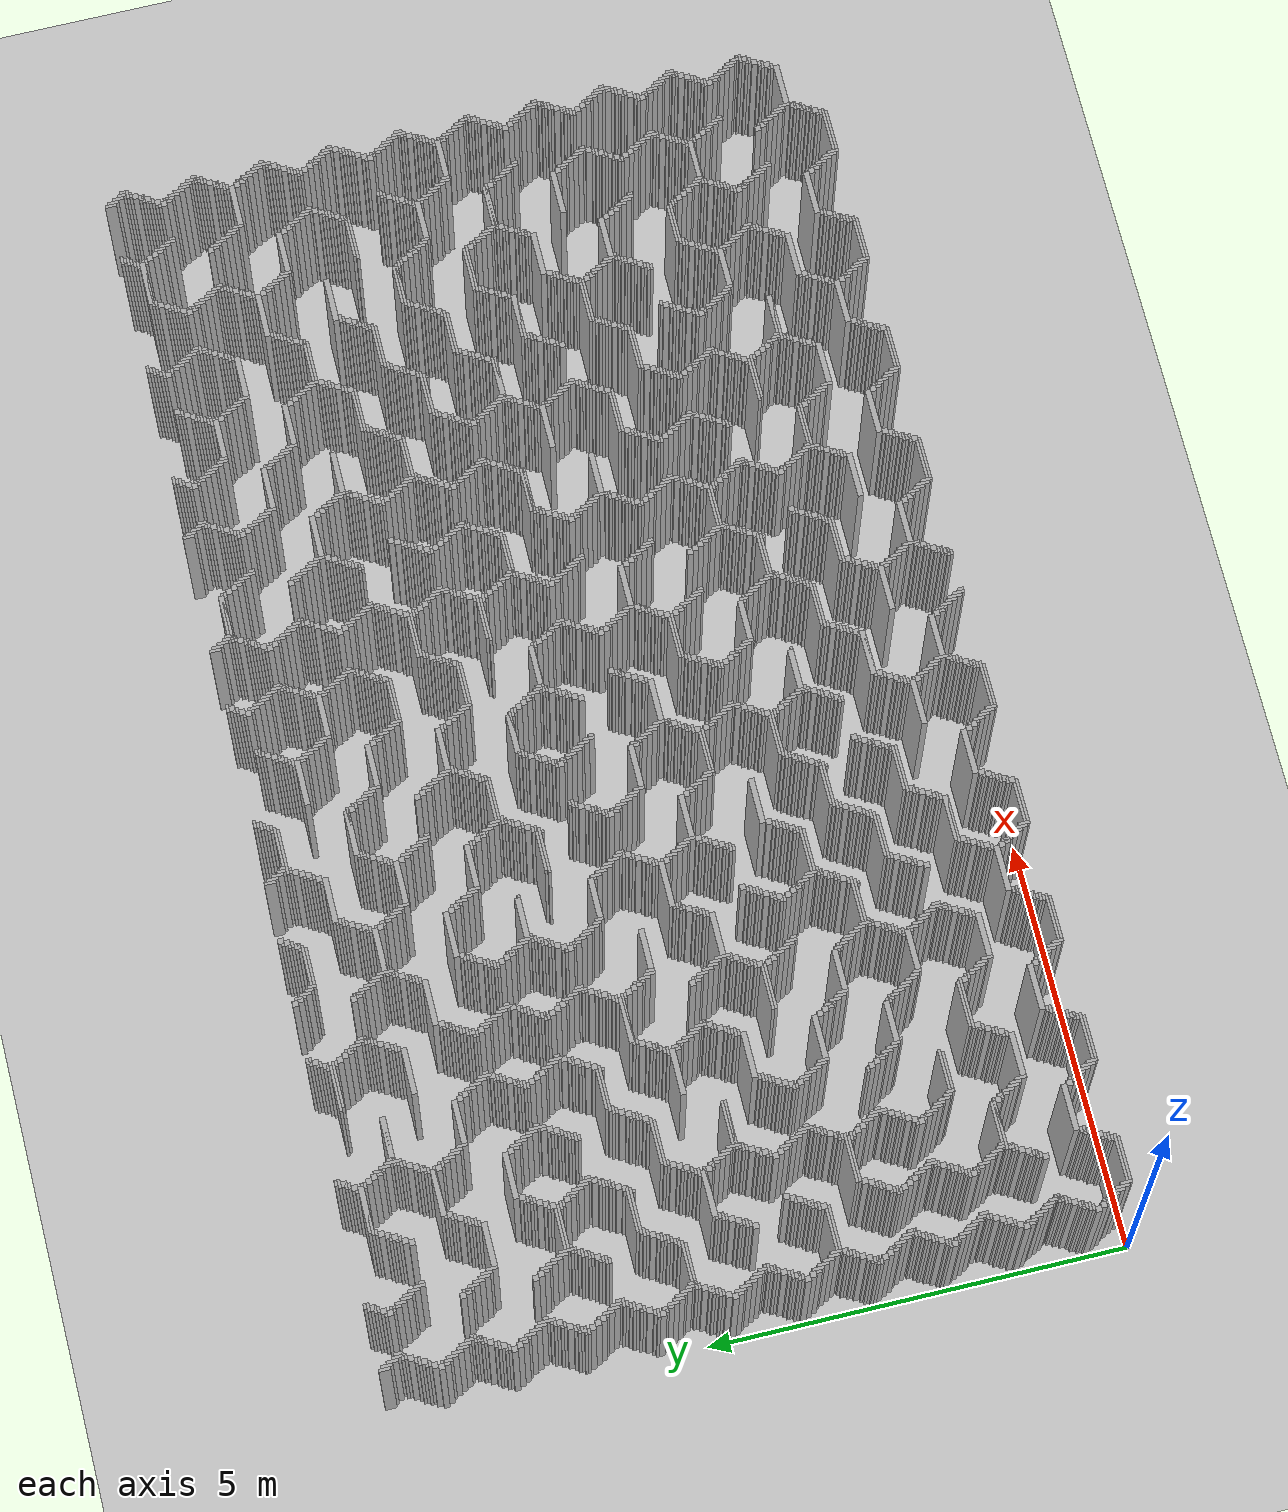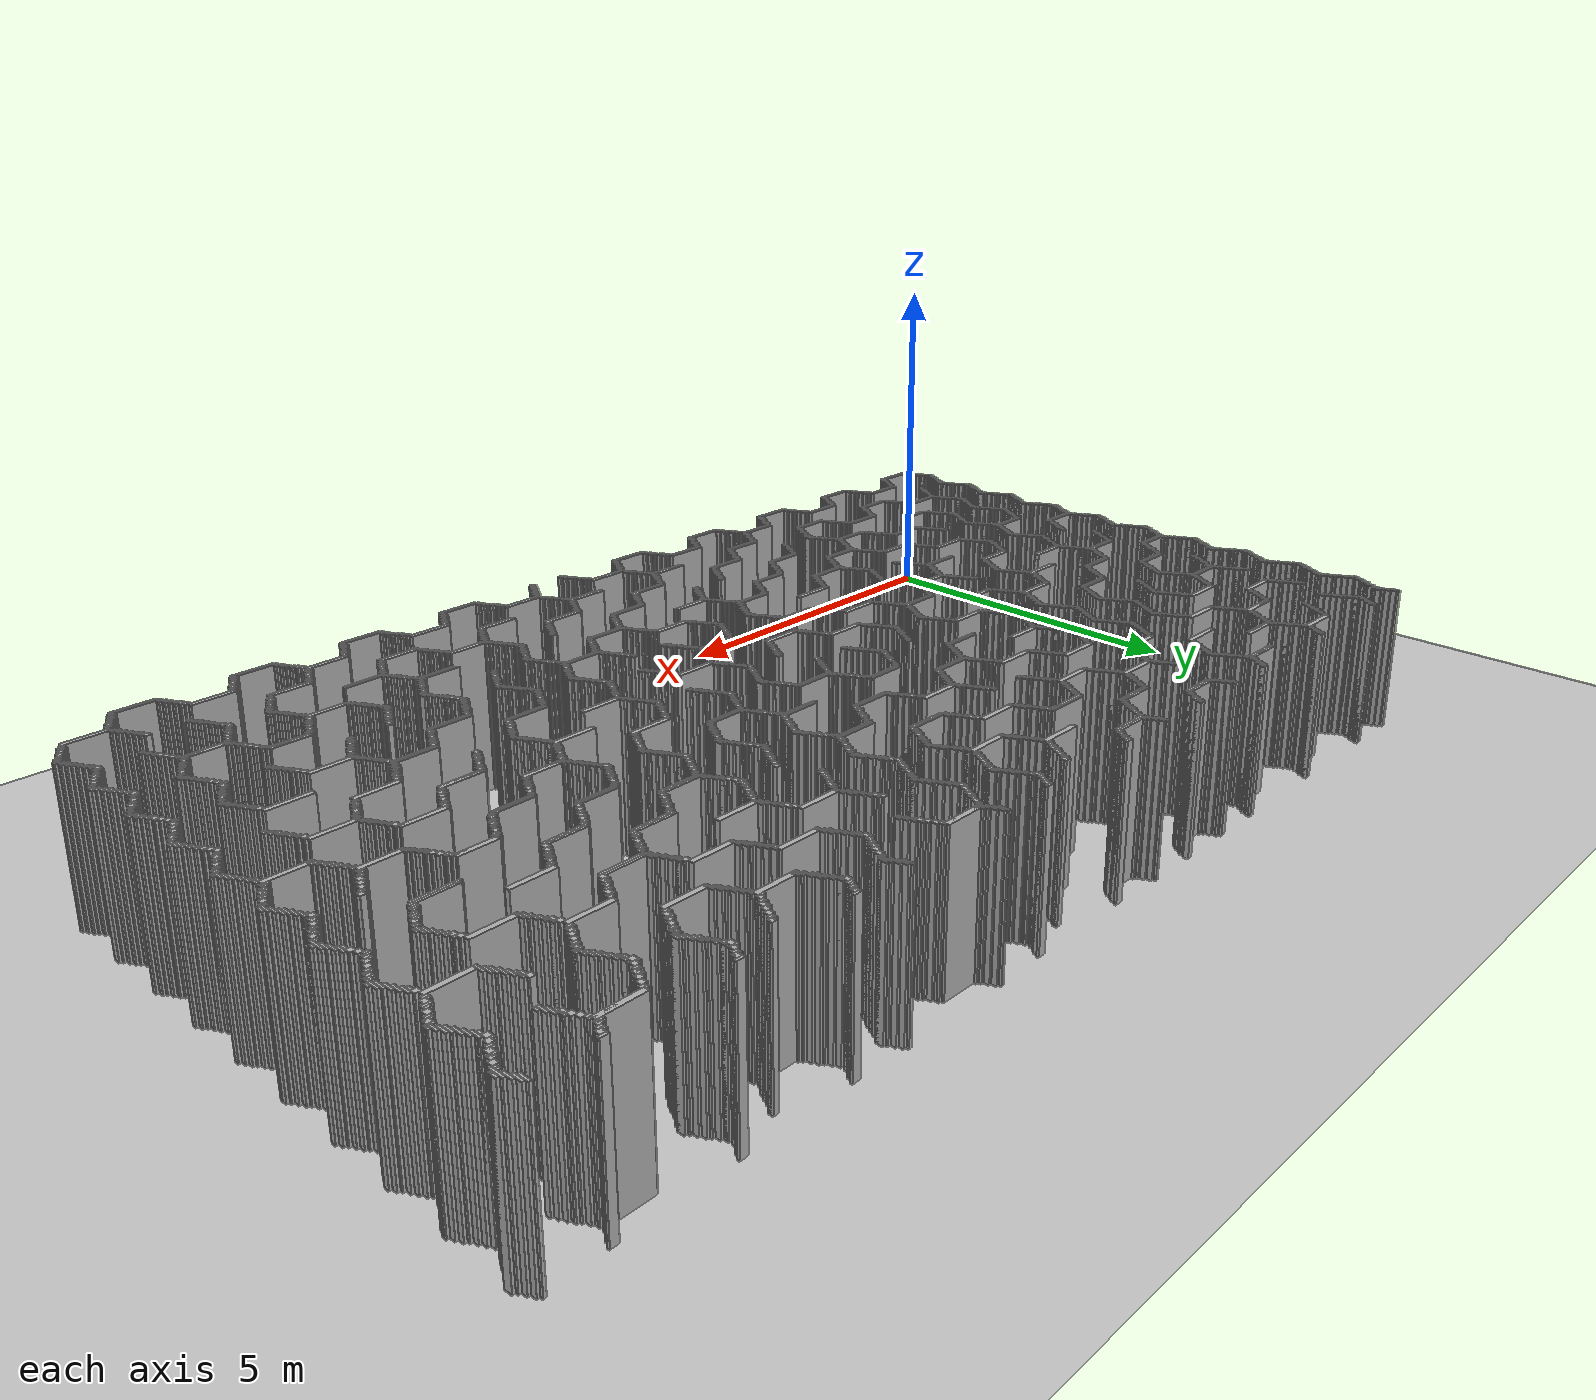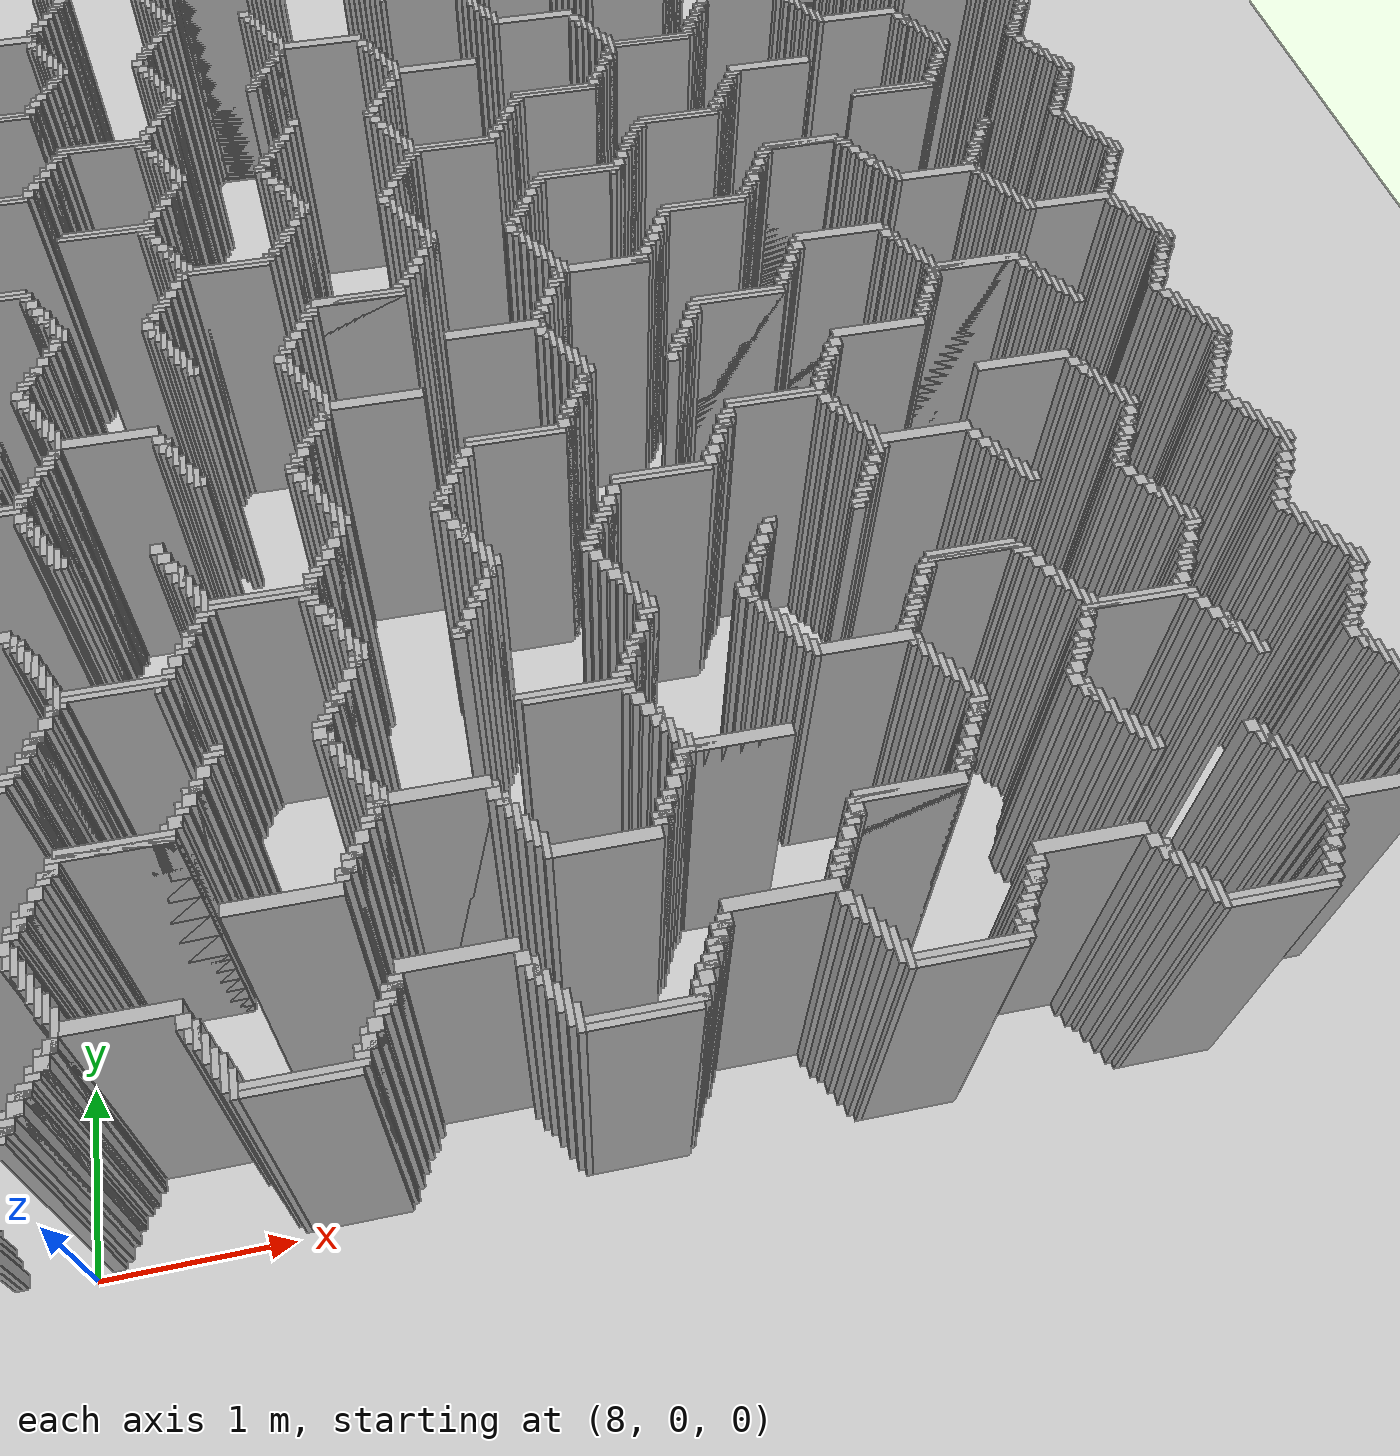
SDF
<sdf version="1.6">
 <world name="slam_world">
  <light name="sun" type="directional">
   <pose>0 0 10 0 0 0</pose>
   <diffuse>0.8 0.8 0.8 1</diffuse>
   <direction>-0.5 0.1 -0.9</direction>
  </light>
  <model name="ground_plane">
   <static>true</static>
   <link name="link">
    <collision name="collision">
     <geometry><plane><normal>0 0 1</normal><size>100 100</size></plane></geometry>
    </collision>
    <visual name="visual">
     <geometry><plane><normal>0 0 1</normal><size>100 100</size></plane></geometry>
     <material>
      <ambient>0.8 0.8 0.8 1</ambient>
      <diffuse>0.8 0.8 0.8 1</diffuse>
      <specular>0.8 0.8 0.8 1</specular>
     </material>
    </visual>
   </link>
  </model>
  <model name="wall_2921">
   <static>true</static>
   <pose>0.191415313225058 8.700696055684455 1.0 0 0 0</pose>
   <link name="link">
    <collision name="collision">
     <geometry><box><size>0.03480278422273782 0.13921113689095127 2.0</size></box></geometry>
    </collision>
    <visual name="visual">
     <geometry><box><size>0.03480278422273782 0.13921113689095127 2.0</size></box></geometry>
     <material><ambient>0.5 0.5 0.5 1</ambient><diffuse>0.7 0.7 0.7 1</diffuse></material>
    </visual>
   </link>
  </model>
  <model name="wall_2922">
   <static>true</static>
   <pose>0.9396751740139211 8.735498839907192 1.0 0 0 0</pose>
   <link name="link">
    <collision name="collision">
     <geometry><box><size>0.06960556844547564 0.06960556844547564 2.0</size></box></geometry>
    </collision>
    <visual name="visual">
     <geometry><box><size>0.06960556844547564 0.06960556844547564 2.0</size></box></geometry>
     <material><ambient>0.5 0.5 0.5 1</ambient><diffuse>0.7 0.7 0.7 1</diffuse></material>
    </visual>
   </link>
  </model>
  <model name="wall_2923">
   <static>true</static>
   <pose>2.4013921113689096 8.735498839907192 1.0 0 0 0</pose>
   <link name="link">
    <collision name="collision">
     <geometry><box><size>0.06960556844547564 0.06960556844547564 2.0</size></box></geometry>
    </collision>
    <visual name="visual">
     <geometry><box><size>0.06960556844547564 0.06960556844547564 2.0</size></box></geometry>
     <material><ambient>0.5 0.5 0.5 1</ambient><diffuse>0.7 0.7 0.7 1</diffuse></material>
    </visual>
   </link>
  </model>
  <model name="wall_2924">
   <static>true</static>
   <pose>3.863109048723898 8.735498839907192 1.0 0 0 0</pose>
   <link name="link">
    <collision name="collision">
     <geometry><box><size>0.06960556844547564 0.06960556844547564 2.0</size></box></geometry>
    </collision>
    <visual name="visual">
     <geometry><box><size>0.06960556844547564 0.06960556844547564 2.0</size></box></geometry>
     <material><ambient>0.5 0.5 0.5 1</ambient><diffuse>0.7 0.7 0.7 1</diffuse></material>
    </visual>
   </link>
  </model>
  <model name="wall_2925">
   <static>true</static>
   <pose>4.559164733178654 8.735498839907192 1.0 0 0 0</pose>
   <link name="link">
    <collision name="collision">
     <geometry><box><size>0.06960556844547564 0.06960556844547564 2.0</size></box></geometry>
    </collision>
    <visual name="visual">
     <geometry><box><size>0.06960556844547564 0.06960556844547564 2.0</size></box></geometry>
     <material><ambient>0.5 0.5 0.5 1</ambient><diffuse>0.7 0.7 0.7 1</diffuse></material>
    </visual>
   </link>
  </model>
  <model name="wall_2926">
   <static>true</static>
   <pose>5.324825986078886 8.735498839907192 1.0 0 0 0</pose>
   <link name="link">
    <collision name="collision">
     <geometry><box><size>0.06960556844547564 0.06960556844547564 2.0</size></box></geometry>
    </collision>
    <visual name="visual">
     <geometry><box><size>0.06960556844547564 0.06960556844547564 2.0</size></box></geometry>
     <material><ambient>0.5 0.5 0.5 1</ambient><diffuse>0.7 0.7 0.7 1</diffuse></material>
    </visual>
   </link>
  </model>
  <model name="wall_2927">
   <static>true</static>
   <pose>6.038283062645012 8.700696055684455 1.0 0 0 0</pose>
   <link name="link">
    <collision name="collision">
     <geometry><box><size>0.03480278422273782 0.13921113689095127 2.0</size></box></geometry>
    </collision>
    <visual name="visual">
     <geometry><box><size>0.03480278422273782 0.13921113689095127 2.0</size></box></geometry>
     <material><ambient>0.5 0.5 0.5 1</ambient><diffuse>0.7 0.7 0.7 1</diffuse></material>
    </visual>
   </link>
  </model>
  <model name="wall_2930">
   <static>true</static>
   <pose>8.961716937354987 8.700696055684455 1.0 0 0 0</pose>
   <link name="link">
    <collision name="collision">
     <geometry><box><size>0.03480278422273782 0.13921113689095127 2.0</size></box></geometry>
    </collision>
    <visual name="visual">
     <geometry><box><size>0.03480278422273782 0.13921113689095127 2.0</size></box></geometry>
     <material><ambient>0.5 0.5 0.5 1</ambient><diffuse>0.7 0.7 0.7 1</diffuse></material>
    </visual>
   </link>
  </model>
  <model name="wall_2931">
   <static>true</static>
   <pose>10.423433874709977 8.700696055684455 1.0 0 0 0</pose>
   <link name="link">
    <collision name="collision">
     <geometry><box><size>0.03480278422273782 0.13921113689095127 2.0</size></box></geometry>
    </collision>
    <visual name="visual">
     <geometry><box><size>0.03480278422273782 0.13921113689095127 2.0</size></box></geometry>
     <material><ambient>0.5 0.5 0.5 1</ambient><diffuse>0.7 0.7 0.7 1</diffuse></material>
    </visual>
   </link>
  </model>
  <model name="wall_2935">
   <static>true</static>
   <pose>14.80858468677494 8.700696055684455 1.0 0 0 0</pose>
   <link name="link">
    <collision name="collision">
     <geometry><box><size>0.03480278422273782 0.13921113689095127 2.0</size></box></geometry>
    </collision>
    <visual name="visual">
     <geometry><box><size>0.03480278422273782 0.13921113689095127 2.0</size></box></geometry>
     <material><ambient>0.5 0.5 0.5 1</ambient><diffuse>0.7 0.7 0.7 1</diffuse></material>
    </visual>
   </link>
  </model>
  <model name="wall_2936">
   <static>true</static>
   <pose>0.2262180974477958 8.665893271461716 1.0 0 0 0</pose>
   <link name="link">
    <collision name="collision">
     <geometry><box><size>0.03480278422273782 0.13921113689095127 2.0</size></box></geometry>
    </collision>
    <visual name="visual">
     <geometry><box><size>0.03480278422273782 0.13921113689095127 2.0</size></box></geometry>
     <material><ambient>0.5 0.5 0.5 1</ambient><diffuse>0.7 0.7 0.7 1</diffuse></material>
    </visual>
   </link>
  </model>
  <model name="wall_2937">
   <static>true</static>
   <pose>0.9222737819025522 8.718097447795824 1.0 0 0 0</pose>
   <link name="link">
    <collision name="collision">
     <geometry><box><size>0.10440835266821345 0.03480278422273782 2.0</size></box></geometry>
    </collision>
    <visual name="visual">
     <geometry><box><size>0.10440835266821345 0.03480278422273782 2.0</size></box></geometry>
     <material><ambient>0.5 0.5 0.5 1</ambient><diffuse>0.7 0.7 0.7 1</diffuse></material>
    </visual>
   </link>
  </model>
  <model name="wall_2938">
   <static>true</static>
   <pose>2.3839907192575405 8.718097447795824 1.0 0 0 0</pose>
   <link name="link">
    <collision name="collision">
     <geometry><box><size>0.10440835266821345 0.03480278422273782 2.0</size></box></geometry>
    </collision>
    <visual name="visual">
     <geometry><box><size>0.10440835266821345 0.03480278422273782 2.0</size></box></geometry>
     <material><ambient>0.5 0.5 0.5 1</ambient><diffuse>0.7 0.7 0.7 1</diffuse></material>
    </visual>
   </link>
  </model>
  <model name="wall_2939">
   <static>true</static>
   <pose>3.845707656612529 8.718097447795824 1.0 0 0 0</pose>
   <link name="link">
    <collision name="collision">
     <geometry><box><size>0.10440835266821345 0.03480278422273782 2.0</size></box></geometry>
    </collision>
    <visual name="visual">
     <geometry><box><size>0.10440835266821345 0.03480278422273782 2.0</size></box></geometry>
     <material><ambient>0.5 0.5 0.5 1</ambient><diffuse>0.7 0.7 0.7 1</diffuse></material>
    </visual>
   </link>
  </model>
  <model name="wall_2940">
   <static>true</static>
   <pose>4.611368909512761 8.665893271461716 1.0 0 0 0</pose>
   <link name="link">
    <collision name="collision">
     <geometry><box><size>0.03480278422273782 0.13921113689095127 2.0</size></box></geometry>
    </collision>
    <visual name="visual">
     <geometry><box><size>0.03480278422273782 0.13921113689095127 2.0</size></box></geometry>
     <material><ambient>0.5 0.5 0.5 1</ambient><diffuse>0.7 0.7 0.7 1</diffuse></material>
    </visual>
   </link>
  </model>
  <model name="wall_2941">
   <static>true</static>
   <pose>5.307424593967517 8.718097447795824 1.0 0 0 0</pose>
   <link name="link">
    <collision name="collision">
     <geometry><box><size>0.10440835266821345 0.03480278422273782 2.0</size></box></geometry>
    </collision>
    <visual name="visual">
     <geometry><box><size>0.10440835266821345 0.03480278422273782 2.0</size></box></geometry>
     <material><ambient>0.5 0.5 0.5 1</ambient><diffuse>0.7 0.7 0.7 1</diffuse></material>
    </visual>
   </link>
  </model>
  <model name="wall_2942">
   <static>true</static>
   <pose>6.073085846867749 8.665893271461716 1.0 0 0 0</pose>
   <link name="link">
    <collision name="collision">
     <geometry><box><size>0.03480278422273782 0.13921113689095127 2.0</size></box></geometry>
    </collision>
    <visual name="visual">
     <geometry><box><size>0.03480278422273782 0.13921113689095127 2.0</size></box></geometry>
     <material><ambient>0.5 0.5 0.5 1</ambient><diffuse>0.7 0.7 0.7 1</diffuse></material>
    </visual>
   </link>
  </model>
  <model name="wall_2943">
   <static>true</static>
   <pose>6.769141531322505 8.718097447795824 1.0 0 0 0</pose>
   <link name="link">
    <collision name="collision">
     <geometry><box><size>0.10440835266821345 0.03480278422273782 2.0</size></box></geometry>
    </collision>
    <visual name="visual">
     <geometry><box><size>0.10440835266821345 0.03480278422273782 2.0</size></box></geometry>
     <material><ambient>0.5 0.5 0.5 1</ambient><diffuse>0.7 0.7 0.7 1</diffuse></material>
    </visual>
   </link>
  </model>
  <model name="wall_2944">
   <static>true</static>
   <pose>8.230858468677495 8.718097447795824 1.0 0 0 0</pose>
   <link name="link">
    <collision name="collision">
     <geometry><box><size>0.10440835266821345 0.03480278422273782 2.0</size></box></geometry>
    </collision>
    <visual name="visual">
     <geometry><box><size>0.10440835266821345 0.03480278422273782 2.0</size></box></geometry>
     <material><ambient>0.5 0.5 0.5 1</ambient><diffuse>0.7 0.7 0.7 1</diffuse></material>
    </visual>
   </link>
  </model>
  <model name="wall_2945">
   <static>true</static>
   <pose>8.996519721577727 8.665893271461716 1.0 0 0 0</pose>
   <link name="link">
    <collision name="collision">
     <geometry><box><size>0.03480278422273782 0.13921113689095127 2.0</size></box></geometry>
    </collision>
    <visual name="visual">
     <geometry><box><size>0.03480278422273782 0.13921113689095127 2.0</size></box></geometry>
     <material><ambient>0.5 0.5 0.5 1</ambient><diffuse>0.7 0.7 0.7 1</diffuse></material>
    </visual>
   </link>
  </model>
  <model name="wall_2946">
   <static>true</static>
   <pose>10.458236658932714 8.665893271461716 1.0 0 0 0</pose>
   <link name="link">
    <collision name="collision">
     <geometry><box><size>0.03480278422273782 0.13921113689095127 2.0</size></box></geometry>
    </collision>
    <visual name="visual">
     <geometry><box><size>0.03480278422273782 0.13921113689095127 2.0</size></box></geometry>
     <material><ambient>0.5 0.5 0.5 1</ambient><diffuse>0.7 0.7 0.7 1</diffuse></material>
    </visual>
   </link>
  </model>
  <model name="wall_2947">
   <static>true</static>
   <pose>11.154292343387471 8.718097447795824 1.0 0 0 0</pose>
   <link name="link">
    <collision name="collision">
     <geometry><box><size>0.10440835266821345 0.03480278422273782 2.0</size></box></geometry>
    </collision>
    <visual name="visual">
     <geometry><box><size>0.10440835266821345 0.03480278422273782 2.0</size></box></geometry>
     <material><ambient>0.5 0.5 0.5 1</ambient><diffuse>0.7 0.7 0.7 1</diffuse></material>
    </visual>
   </link>
  </model>
  <model name="wall_2948">
   <static>true</static>
   <pose>12.616009280742459 8.718097447795824 1.0 0 0 0</pose>
   <link name="link">
    <collision name="collision">
     <geometry><box><size>0.10440835266821345 0.03480278422273782 2.0</size></box></geometry>
    </collision>
    <visual name="visual">
     <geometry><box><size>0.10440835266821345 0.03480278422273782 2.0</size></box></geometry>
     <material><ambient>0.5 0.5 0.5 1</ambient><diffuse>0.7 0.7 0.7 1</diffuse></material>
    </visual>
   </link>
  </model>
  <model name="wall_2949">
   <static>true</static>
   <pose>14.077726218097448 8.718097447795824 1.0 0 0 0</pose>
   <link name="link">
    <collision name="collision">
     <geometry><box><size>0.10440835266821345 0.03480278422273782 2.0</size></box></geometry>
    </collision>
    <visual name="visual">
     <geometry><box><size>0.10440835266821345 0.03480278422273782 2.0</size></box></geometry>
     <material><ambient>0.5 0.5 0.5 1</ambient><diffuse>0.7 0.7 0.7 1</diffuse></material>
    </visual>
   </link>
  </model>
  <model name="wall_2950">
   <static>true</static>
   <pose>14.84338747099768 8.665893271461716 1.0 0 0 0</pose>
   <link name="link">
    <collision name="collision">
     <geometry><box><size>0.03480278422273782 0.13921113689095127 2.0</size></box></geometry>
    </collision>
    <visual name="visual">
     <geometry><box><size>0.03480278422273782 0.13921113689095127 2.0</size></box></geometry>
     <material><ambient>0.5 0.5 0.5 1</ambient><diffuse>0.7 0.7 0.7 1</diffuse></material>
    </visual>
   </link>
  </model>
  <model name="wall_2951">
   <static>true</static>
   <pose>0.9048723897911832 8.665893271461716 1.0 0 0 0</pose>
   <link name="link">
    <collision name="collision">
     <geometry><box><size>0.06960556844547564 0.06960556844547564 2.0</size></box></geometry>
    </collision>
    <visual name="visual">
     <geometry><box><size>0.06960556844547564 0.06960556844547564 2.0</size></box></geometry>
     <material><ambient>0.5 0.5 0.5 1</ambient><diffuse>0.7 0.7 0.7 1</diffuse></material>
    </visual>
   </link>
  </model>
  <model name="wall_2952">
   <static>true</static>
   <pose>2.3665893271461718 8.665893271461716 1.0 0 0 0</pose>
   <link name="link">
    <collision name="collision">
     <geometry><box><size>0.06960556844547564 0.06960556844547564 2.0</size></box></geometry>
    </collision>
    <visual name="visual">
     <geometry><box><size>0.06960556844547564 0.06960556844547564 2.0</size></box></geometry>
     <material><ambient>0.5 0.5 0.5 1</ambient><diffuse>0.7 0.7 0.7 1</diffuse></material>
    </visual>
   </link>
  </model>
  <model name="wall_2953">
   <static>true</static>
   <pose>3.82830626450116 8.665893271461716 1.0 0 0 0</pose>
   <link name="link">
    <collision name="collision">
     <geometry><box><size>0.06960556844547564 0.06960556844547564 2.0</size></box></geometry>
    </collision>
    <visual name="visual">
     <geometry><box><size>0.06960556844547564 0.06960556844547564 2.0</size></box></geometry>
     <material><ambient>0.5 0.5 0.5 1</ambient><diffuse>0.7 0.7 0.7 1</diffuse></material>
    </visual>
   </link>
  </model>
  <model name="wall_2954">
   <static>true</static>
   <pose>4.593967517401392 8.665893271461716 1.0 0 0 0</pose>
   <link name="link">
    <collision name="collision">
     <geometry><box><size>0.06960556844547564 0.06960556844547564 2.0</size></box></geometry>
    </collision>
    <visual name="visual">
     <geometry><box><size>0.06960556844547564 0.06960556844547564 2.0</size></box></geometry>
     <material><ambient>0.5 0.5 0.5 1</ambient><diffuse>0.7 0.7 0.7 1</diffuse></material>
    </visual>
   </link>
  </model>
  <model name="wall_2955">
   <static>true</static>
   <pose>5.290023201856148 8.665893271461716 1.0 0 0 0</pose>
   <link name="link">
    <collision name="collision">
     <geometry><box><size>0.06960556844547564 0.06960556844547564 2.0</size></box></geometry>
    </collision>
    <visual name="visual">
     <geometry><box><size>0.06960556844547564 0.06960556844547564 2.0</size></box></geometry>
     <material><ambient>0.5 0.5 0.5 1</ambient><diffuse>0.7 0.7 0.7 1</diffuse></material>
    </visual>
   </link>
  </model>
  <model name="wall_2956">
   <static>true</static>
   <pose>6.751740139211137 8.665893271461716 1.0 0 0 0</pose>
   <link name="link">
    <collision name="collision">
     <geometry><box><size>0.06960556844547564 0.06960556844547564 2.0</size></box></geometry>
    </collision>
    <visual name="visual">
     <geometry><box><size>0.06960556844547564 0.06960556844547564 2.0</size></box></geometry>
     <material><ambient>0.5 0.5 0.5 1</ambient><diffuse>0.7 0.7 0.7 1</diffuse></material>
    </visual>
   </link>
  </model>
  <model name="wall_2957">
   <static>true</static>
   <pose>8.213457076566124 8.665893271461716 1.0 0 0 0</pose>
   <link name="link">
    <collision name="collision">
     <geometry><box><size>0.06960556844547564 0.06960556844547564 2.0</size></box></geometry>
    </collision>
    <visual name="visual">
     <geometry><box><size>0.06960556844547564 0.06960556844547564 2.0</size></box></geometry>
     <material><ambient>0.5 0.5 0.5 1</ambient><diffuse>0.7 0.7 0.7 1</diffuse></material>
    </visual>
   </link>
  </model>
  <model name="wall_2958">
   <static>true</static>
   <pose>11.1368909512761 8.665893271461716 1.0 0 0 0</pose>
   <link name="link">
    <collision name="collision">
     <geometry><box><size>0.06960556844547564 0.06960556844547564 2.0</size></box></geometry>
    </collision>
    <visual name="visual">
     <geometry><box><size>0.06960556844547564 0.06960556844547564 2.0</size></box></geometry>
     <material><ambient>0.5 0.5 0.5 1</ambient><diffuse>0.7 0.7 0.7 1</diffuse></material>
    </visual>
   </link>
  </model>
  <model name="wall_2959">
   <static>true</static>
   <pose>12.59860788863109 8.665893271461716 1.0 0 0 0</pose>
   <link name="link">
    <collision name="collision">
     <geometry><box><size>0.06960556844547564 0.06960556844547564 2.0</size></box></geometry>
    </collision>
    <visual name="visual">
     <geometry><box><size>0.06960556844547564 0.06960556844547564 2.0</size></box></geometry>
     <material><ambient>0.5 0.5 0.5 1</ambient><diffuse>0.7 0.7 0.7 1</diffuse></material>
    </visual>
   </link>
  </model>
  <model name="wall_2960">
   <static>true</static>
   <pose>14.06032482598608 8.665893271461716 1.0 0 0 0</pose>
   <link name="link">
    <collision name="collision">
     <geometry><box><size>0.06960556844547564 0.06960556844547564 2.0</size></box></geometry>
    </collision>
    <visual name="visual">
     <geometry><box><size>0.06960556844547564 0.06960556844547564 2.0</size></box></geometry>
     <material><ambient>0.5 0.5 0.5 1</ambient><diffuse>0.7 0.7 0.7 1</diffuse></material>
    </visual>
   </link>
  </model>
  <model name="wall_2961">
   <static>true</static>
   <pose>0.2610208816705336 8.596287703016241 1.0 0 0 0</pose>
   <link name="link">
    <collision name="collision">
     <geometry><box><size>0.03480278422273782 0.13921113689095127 2.0</size></box></geometry>
    </collision>
    <visual name="visual">
     <geometry><box><size>0.03480278422273782 0.13921113689095127 2.0</size></box></geometry>
     <material><ambient>0.5 0.5 0.5 1</ambient><diffuse>0.7 0.7 0.7 1</diffuse></material>
    </visual>
   </link>
  </model>
  <model name="wall_2962">
   <static>true</static>
   <pose>0.8874709976798143 8.648491879350347 1.0 0 0 0</pose>
   <link name="link">
    <collision name="collision">
     <geometry><box><size>0.10440835266821345 0.03480278422273782 2.0</size></box></geometry>
    </collision>
    <visual name="visual">
     <geometry><box><size>0.10440835266821345 0.03480278422273782 2.0</size></box></geometry>
     <material><ambient>0.5 0.5 0.5 1</ambient><diffuse>0.7 0.7 0.7 1</diffuse></material>
    </visual>
   </link>
  </model>
  <model name="wall_2963">
   <static>true</static>
   <pose>2.3491879350348026 8.648491879350347 1.0 0 0 0</pose>
   <link name="link">
    <collision name="collision">
     <geometry><box><size>0.10440835266821345 0.03480278422273782 2.0</size></box></geometry>
    </collision>
    <visual name="visual">
     <geometry><box><size>0.10440835266821345 0.03480278422273782 2.0</size></box></geometry>
     <material><ambient>0.5 0.5 0.5 1</ambient><diffuse>0.7 0.7 0.7 1</diffuse></material>
    </visual>
   </link>
  </model>
  <model name="wall_2964">
   <static>true</static>
   <pose>3.810904872389791 8.648491879350347 1.0 0 0 0</pose>
   <link name="link">
    <collision name="collision">
     <geometry><box><size>0.10440835266821345 0.03480278422273782 2.0</size></box></geometry>
    </collision>
    <visual name="visual">
     <geometry><box><size>0.10440835266821345 0.03480278422273782 2.0</size></box></geometry>
     <material><ambient>0.5 0.5 0.5 1</ambient><diffuse>0.7 0.7 0.7 1</diffuse></material>
    </visual>
   </link>
  </model>
  <model name="wall_2965">
   <static>true</static>
   <pose>4.646171693735498 8.596287703016241 1.0 0 0 0</pose>
   <link name="link">
    <collision name="collision">
     <geometry><box><size>0.03480278422273782 0.13921113689095127 2.0</size></box></geometry>
    </collision>
    <visual name="visual">
     <geometry><box><size>0.03480278422273782 0.13921113689095127 2.0</size></box></geometry>
     <material><ambient>0.5 0.5 0.5 1</ambient><diffuse>0.7 0.7 0.7 1</diffuse></material>
    </visual>
   </link>
  </model>
  <model name="wall_2966">
   <static>true</static>
   <pose>5.27262180974478 8.648491879350347 1.0 0 0 0</pose>
   <link name="link">
    <collision name="collision">
     <geometry><box><size>0.10440835266821345 0.03480278422273782 2.0</size></box></geometry>
    </collision>
    <visual name="visual">
     <geometry><box><size>0.10440835266821345 0.03480278422273782 2.0</size></box></geometry>
     <material><ambient>0.5 0.5 0.5 1</ambient><diffuse>0.7 0.7 0.7 1</diffuse></material>
    </visual>
   </link>
  </model>
  <model name="wall_2967">
   <static>true</static>
   <pose>6.107888631090487 8.596287703016241 1.0 0 0 0</pose>
   <link name="link">
    <collision name="collision">
     <geometry><box><size>0.03480278422273782 0.13921113689095127 2.0</size></box></geometry>
    </collision>
    <visual name="visual">
     <geometry><box><size>0.03480278422273782 0.13921113689095127 2.0</size></box></geometry>
     <material><ambient>0.5 0.5 0.5 1</ambient><diffuse>0.7 0.7 0.7 1</diffuse></material>
    </visual>
   </link>
  </model>
  <model name="wall_2968">
   <static>true</static>
   <pose>6.734338747099768 8.648491879350347 1.0 0 0 0</pose>
   <link name="link">
    <collision name="collision">
     <geometry><box><size>0.10440835266821345 0.03480278422273782 2.0</size></box></geometry>
    </collision>
    <visual name="visual">
     <geometry><box><size>0.10440835266821345 0.03480278422273782 2.0</size></box></geometry>
     <material><ambient>0.5 0.5 0.5 1</ambient><diffuse>0.7 0.7 0.7 1</diffuse></material>
    </visual>
   </link>
  </model>
  <model name="wall_2969">
   <static>true</static>
   <pose>8.196055684454755 8.648491879350347 1.0 0 0 0</pose>
   <link name="link">
    <collision name="collision">
     <geometry><box><size>0.10440835266821345 0.03480278422273782 2.0</size></box></geometry>
    </collision>
    <visual name="visual">
     <geometry><box><size>0.10440835266821345 0.03480278422273782 2.0</size></box></geometry>
     <material><ambient>0.5 0.5 0.5 1</ambient><diffuse>0.7 0.7 0.7 1</diffuse></material>
    </visual>
   </link>
  </model>
  <model name="wall_2970">
   <static>true</static>
   <pose>9.031322505800464 8.596287703016241 1.0 0 0 0</pose>
   <link name="link">
    <collision name="collision">
     <geometry><box><size>0.03480278422273782 0.13921113689095127 2.0</size></box></geometry>
    </collision>
    <visual name="visual">
     <geometry><box><size>0.03480278422273782 0.13921113689095127 2.0</size></box></geometry>
     <material><ambient>0.5 0.5 0.5 1</ambient><diffuse>0.7 0.7 0.7 1</diffuse></material>
    </visual>
   </link>
  </model>
  <model name="wall_2971">
   <static>true</static>
   <pose>10.493039443155451 8.596287703016241 1.0 0 0 0</pose>
   <link name="link">
    <collision name="collision">
     <geometry><box><size>0.03480278422273782 0.13921113689095127 2.0</size></box></geometry>
    </collision>
    <visual name="visual">
     <geometry><box><size>0.03480278422273782 0.13921113689095127 2.0</size></box></geometry>
     <material><ambient>0.5 0.5 0.5 1</ambient><diffuse>0.7 0.7 0.7 1</diffuse></material>
    </visual>
   </link>
  </model>
  <model name="wall_2972">
   <static>true</static>
   <pose>11.119489559164732 8.648491879350347 1.0 0 0 0</pose>
   <link name="link">
    <collision name="collision">
     <geometry><box><size>0.10440835266821345 0.03480278422273782 2.0</size></box></geometry>
    </collision>
    <visual name="visual">
     <geometry><box><size>0.10440835266821345 0.03480278422273782 2.0</size></box></geometry>
     <material><ambient>0.5 0.5 0.5 1</ambient><diffuse>0.7 0.7 0.7 1</diffuse></material>
    </visual>
   </link>
  </model>
  <model name="wall_2973">
   <static>true</static>
   <pose>12.581206496519721 8.648491879350347 1.0 0 0 0</pose>
   <link name="link">
    <collision name="collision">
     <geometry><box><size>0.10440835266821345 0.03480278422273782 2.0</size></box></geometry>
    </collision>
    <visual name="visual">
     <geometry><box><size>0.10440835266821345 0.03480278422273782 2.0</size></box></geometry>
     <material><ambient>0.5 0.5 0.5 1</ambient><diffuse>0.7 0.7 0.7 1</diffuse></material>
    </visual>
   </link>
  </model>
  <model name="wall_2974">
   <static>true</static>
   <pose>14.042923433874709 8.648491879350347 1.0 0 0 0</pose>
   <link name="link">
    <collision name="collision">
     <geometry><box><size>0.10440835266821345 0.03480278422273782 2.0</size></box></geometry>
    </collision>
    <visual name="visual">
     <geometry><box><size>0.10440835266821345 0.03480278422273782 2.0</size></box></geometry>
     <material><ambient>0.5 0.5 0.5 1</ambient><diffuse>0.7 0.7 0.7 1</diffuse></material>
    </visual>
   </link>
  </model>
  <model name="wall_2975">
   <static>true</static>
   <pose>14.878190255220417 8.596287703016241 1.0 0 0 0</pose>
   <link name="link">
    <collision name="collision">
     <geometry><box><size>0.03480278422273782 0.13921113689095127 2.0</size></box></geometry>
    </collision>
    <visual name="visual">
     <geometry><box><size>0.03480278422273782 0.13921113689095127 2.0</size></box></geometry>
     <material><ambient>0.5 0.5 0.5 1</ambient><diffuse>0.7 0.7 0.7 1</diffuse></material>
    </visual>
   </link>
  </model>
  <model name="wall_2976">
   <static>true</static>
   <pose>0.8700696055684455 8.61368909512761 1.0 0 0 0</pose>
   <link name="link">
    <collision name="collision">
     <geometry><box><size>0.06960556844547564 0.03480278422273782 2.0</size></box></geometry>
    </collision>
    <visual name="visual">
     <geometry><box><size>0.06960556844547564 0.03480278422273782 2.0</size></box></geometry>
     <material><ambient>0.5 0.5 0.5 1</ambient><diffuse>0.7 0.7 0.7 1</diffuse></material>
    </visual>
   </link>
  </model>
  <model name="wall_2977">
   <static>true</static>
   <pose>2.331786542923434 8.61368909512761 1.0 0 0 0</pose>
   <link name="link">
    <collision name="collision">
     <geometry><box><size>0.06960556844547564 0.03480278422273782 2.0</size></box></geometry>
    </collision>
    <visual name="visual">
     <geometry><box><size>0.06960556844547564 0.03480278422273782 2.0</size></box></geometry>
     <material><ambient>0.5 0.5 0.5 1</ambient><diffuse>0.7 0.7 0.7 1</diffuse></material>
    </visual>
   </link>
  </model>
  <model name="wall_2978">
   <static>true</static>
   <pose>3.793503480278422 8.61368909512761 1.0 0 0 0</pose>
   <link name="link">
    <collision name="collision">
     <geometry><box><size>0.06960556844547564 0.03480278422273782 2.0</size></box></geometry>
    </collision>
    <visual name="visual">
     <geometry><box><size>0.06960556844547564 0.03480278422273782 2.0</size></box></geometry>
     <material><ambient>0.5 0.5 0.5 1</ambient><diffuse>0.7 0.7 0.7 1</diffuse></material>
    </visual>
   </link>
  </model>
  <model name="wall_2979">
   <static>true</static>
   <pose>5.25522041763341 8.61368909512761 1.0 0 0 0</pose>
   <link name="link">
    <collision name="collision">
     <geometry><box><size>0.06960556844547564 0.03480278422273782 2.0</size></box></geometry>
    </collision>
    <visual name="visual">
     <geometry><box><size>0.06960556844547564 0.03480278422273782 2.0</size></box></geometry>
     <material><ambient>0.5 0.5 0.5 1</ambient><diffuse>0.7 0.7 0.7 1</diffuse></material>
    </visual>
   </link>
  </model>
  <model name="wall_2980">
   <static>true</static>
   <pose>6.716937354988398 8.61368909512761 1.0 0 0 0</pose>
   <link name="link">
    <collision name="collision">
     <geometry><box><size>0.06960556844547564 0.03480278422273782 2.0</size></box></geometry>
    </collision>
    <visual name="visual">
     <geometry><box><size>0.06960556844547564 0.03480278422273782 2.0</size></box></geometry>
     <material><ambient>0.5 0.5 0.5 1</ambient><diffuse>0.7 0.7 0.7 1</diffuse></material>
    </visual>
   </link>
  </model>
  <model name="wall_2981">
   <static>true</static>
   <pose>8.178654292343387 8.61368909512761 1.0 0 0 0</pose>
   <link name="link">
    <collision name="collision">
     <geometry><box><size>0.06960556844547564 0.03480278422273782 2.0</size></box></geometry>
    </collision>
    <visual name="visual">
     <geometry><box><size>0.06960556844547564 0.03480278422273782 2.0</size></box></geometry>
     <material><ambient>0.5 0.5 0.5 1</ambient><diffuse>0.7 0.7 0.7 1</diffuse></material>
    </visual>
   </link>
  </model>
  <model name="wall_2982">
   <static>true</static>
   <pose>11.102088167053363 8.61368909512761 1.0 0 0 0</pose>
   <link name="link">
    <collision name="collision">
     <geometry><box><size>0.06960556844547564 0.03480278422273782 2.0</size></box></geometry>
    </collision>
    <visual name="visual">
     <geometry><box><size>0.06960556844547564 0.03480278422273782 2.0</size></box></geometry>
     <material><ambient>0.5 0.5 0.5 1</ambient><diffuse>0.7 0.7 0.7 1</diffuse></material>
    </visual>
   </link>
  </model>
  <model name="wall_2983">
   <static>true</static>
   <pose>12.563805104408353 8.61368909512761 1.0 0 0 0</pose>
   <link name="link">
    <collision name="collision">
     <geometry><box><size>0.06960556844547564 0.03480278422273782 2.0</size></box></geometry>
    </collision>
    <visual name="visual">
     <geometry><box><size>0.06960556844547564 0.03480278422273782 2.0</size></box></geometry>
     <material><ambient>0.5 0.5 0.5 1</ambient><diffuse>0.7 0.7 0.7 1</diffuse></material>
    </visual>
   </link>
  </model>
  <model name="wall_2984">
   <static>true</static>
   <pose>14.02552204176334 8.61368909512761 1.0 0 0 0</pose>
   <link name="link">
    <collision name="collision">
     <geometry><box><size>0.06960556844547564 0.03480278422273782 2.0</size></box></geometry>
    </collision>
    <visual name="visual">
     <geometry><box><size>0.06960556844547564 0.03480278422273782 2.0</size></box></geometry>
     <material><ambient>0.5 0.5 0.5 1</ambient><diffuse>0.7 0.7 0.7 1</diffuse></material>
    </visual>
   </link>
  </model>
  <model name="wall_2985">
   <static>true</static>
   <pose>0.29582366589327147 8.509280742459396 1.0 0 0 0</pose>
   <link name="link">
    <collision name="collision">
     <geometry><box><size>0.03480278422273782 0.17401392111368907 2.0</size></box></geometry>
    </collision>
    <visual name="visual">
     <geometry><box><size>0.03480278422273782 0.17401392111368907 2.0</size></box></geometry>
     <material><ambient>0.5 0.5 0.5 1</ambient><diffuse>0.7 0.7 0.7 1</diffuse></material>
    </visual>
   </link>
  </model>
  <model name="wall_2986">
   <static>true</static>
   <pose>0.8352668213457076 8.561484918793504 1.0 0 0 0</pose>
   <link name="link">
    <collision name="collision">
     <geometry><box><size>0.06960556844547564 0.06960556844547564 2.0</size></box></geometry>
    </collision>
    <visual name="visual">
     <geometry><box><size>0.06960556844547564 0.06960556844547564 2.0</size></box></geometry>
     <material><ambient>0.5 0.5 0.5 1</ambient><diffuse>0.7 0.7 0.7 1</diffuse></material>
    </visual>
   </link>
  </model>
  <model name="wall_2987">
   <static>true</static>
   <pose>2.296983758700696 8.561484918793504 1.0 0 0 0</pose>
   <link name="link">
    <collision name="collision">
     <geometry><box><size>0.06960556844547564 0.06960556844547564 2.0</size></box></geometry>
    </collision>
    <visual name="visual">
     <geometry><box><size>0.06960556844547564 0.06960556844547564 2.0</size></box></geometry>
     <material><ambient>0.5 0.5 0.5 1</ambient><diffuse>0.7 0.7 0.7 1</diffuse></material>
    </visual>
   </link>
  </model>
  <model name="wall_2988">
   <static>true</static>
   <pose>3.7587006960556844 8.561484918793504 1.0 0 0 0</pose>
   <link name="link">
    <collision name="collision">
     <geometry><box><size>0.06960556844547564 0.06960556844547564 2.0</size></box></geometry>
    </collision>
    <visual name="visual">
     <geometry><box><size>0.06960556844547564 0.06960556844547564 2.0</size></box></geometry>
     <material><ambient>0.5 0.5 0.5 1</ambient><diffuse>0.7 0.7 0.7 1</diffuse></material>
    </visual>
   </link>
  </model>
  <model name="wall_2989">
   <static>true</static>
   <pose>4.6809744779582365 8.544083526682135 1.0 0 0 0</pose>
   <link name="link">
    <collision name="collision">
     <geometry><box><size>0.03480278422273782 0.10440835266821345 2.0</size></box></geometry>
    </collision>
    <visual name="visual">
     <geometry><box><size>0.03480278422273782 0.10440835266821345 2.0</size></box></geometry>
     <material><ambient>0.5 0.5 0.5 1</ambient><diffuse>0.7 0.7 0.7 1</diffuse></material>
    </visual>
   </link>
  </model>
  <model name="wall_2990">
   <static>true</static>
   <pose>5.220417633410673 8.561484918793504 1.0 0 0 0</pose>
   <link name="link">
    <collision name="collision">
     <geometry><box><size>0.06960556844547564 0.06960556844547564 2.0</size></box></geometry>
    </collision>
    <visual name="visual">
     <geometry><box><size>0.06960556844547564 0.06960556844547564 2.0</size></box></geometry>
     <material><ambient>0.5 0.5 0.5 1</ambient><diffuse>0.7 0.7 0.7 1</diffuse></material>
    </visual>
   </link>
  </model>
  <model name="wall_2991">
   <static>true</static>
   <pose>6.142691415313225 8.509280742459396 1.0 0 0 0</pose>
   <link name="link">
    <collision name="collision">
     <geometry><box><size>0.03480278422273782 0.17401392111368907 2.0</size></box></geometry>
    </collision>
    <visual name="visual">
     <geometry><box><size>0.03480278422273782 0.17401392111368907 2.0</size></box></geometry>
     <material><ambient>0.5 0.5 0.5 1</ambient><diffuse>0.7 0.7 0.7 1</diffuse></material>
    </visual>
   </link>
  </model>
  <model name="wall_2992">
   <static>true</static>
   <pose>6.682134570765661 8.561484918793504 1.0 0 0 0</pose>
   <link name="link">
    <collision name="collision">
     <geometry><box><size>0.06960556844547564 0.06960556844547564 2.0</size></box></geometry>
    </collision>
    <visual name="visual">
     <geometry><box><size>0.06960556844547564 0.06960556844547564 2.0</size></box></geometry>
     <material><ambient>0.5 0.5 0.5 1</ambient><diffuse>0.7 0.7 0.7 1</diffuse></material>
    </visual>
   </link>
  </model>
  <model name="wall_2993">
   <static>true</static>
   <pose>8.14385150812065 8.561484918793504 1.0 0 0 0</pose>
   <link name="link">
    <collision name="collision">
     <geometry><box><size>0.06960556844547564 0.06960556844547564 2.0</size></box></geometry>
    </collision>
    <visual name="visual">
     <geometry><box><size>0.06960556844547564 0.06960556844547564 2.0</size></box></geometry>
     <material><ambient>0.5 0.5 0.5 1</ambient><diffuse>0.7 0.7 0.7 1</diffuse></material>
    </visual>
   </link>
  </model>
  <model name="wall_2994">
   <static>true</static>
   <pose>9.066125290023201 8.509280742459396 1.0 0 0 0</pose>
   <link name="link">
    <collision name="collision">
     <geometry><box><size>0.03480278422273782 0.17401392111368907 2.0</size></box></geometry>
    </collision>
    <visual name="visual">
     <geometry><box><size>0.03480278422273782 0.17401392111368907 2.0</size></box></geometry>
     <material><ambient>0.5 0.5 0.5 1</ambient><diffuse>0.7 0.7 0.7 1</diffuse></material>
    </visual>
   </link>
  </model>
  <model name="wall_2995">
   <static>true</static>
   <pose>10.52784222737819 8.509280742459396 1.0 0 0 0</pose>
   <link name="link">
    <collision name="collision">
     <geometry><box><size>0.03480278422273782 0.17401392111368907 2.0</size></box></geometry>
    </collision>
    <visual name="visual">
     <geometry><box><size>0.03480278422273782 0.17401392111368907 2.0</size></box></geometry>
     <material><ambient>0.5 0.5 0.5 1</ambient><diffuse>0.7 0.7 0.7 1</diffuse></material>
    </visual>
   </link>
  </model>
  <model name="wall_2996">
   <static>true</static>
   <pose>11.067285382830626 8.561484918793504 1.0 0 0 0</pose>
   <link name="link">
    <collision name="collision">
     <geometry><box><size>0.06960556844547564 0.06960556844547564 2.0</size></box></geometry>
    </collision>
    <visual name="visual">
     <geometry><box><size>0.06960556844547564 0.06960556844547564 2.0</size></box></geometry>
     <material><ambient>0.5 0.5 0.5 1</ambient><diffuse>0.7 0.7 0.7 1</diffuse></material>
    </visual>
   </link>
  </model>
  <model name="wall_2997">
   <static>true</static>
   <pose>12.529002320185615 8.561484918793504 1.0 0 0 0</pose>
   <link name="link">
    <collision name="collision">
     <geometry><box><size>0.06960556844547564 0.06960556844547564 2.0</size></box></geometry>
    </collision>
    <visual name="visual">
     <geometry><box><size>0.06960556844547564 0.06960556844547564 2.0</size></box></geometry>
     <material><ambient>0.5 0.5 0.5 1</ambient><diffuse>0.7 0.7 0.7 1</diffuse></material>
    </visual>
   </link>
  </model>
  <model name="wall_2998">
   <static>true</static>
   <pose>13.990719257540603 8.561484918793504 1.0 0 0 0</pose>
   <link name="link">
    <collision name="collision">
     <geometry><box><size>0.06960556844547564 0.06960556844547564 2.0</size></box></geometry>
    </collision>
    <visual name="visual">
     <geometry><box><size>0.06960556844547564 0.06960556844547564 2.0</size></box></geometry>
     <material><ambient>0.5 0.5 0.5 1</ambient><diffuse>0.7 0.7 0.7 1</diffuse></material>
    </visual>
   </link>
  </model>
  <model name="wall_2999">
   <static>true</static>
   <pose>14.912993039443155 8.509280742459396 1.0 0 0 0</pose>
   <link name="link">
    <collision name="collision">
     <geometry><box><size>0.03480278422273782 0.17401392111368907 2.0</size></box></geometry>
    </collision>
    <visual name="visual">
     <geometry><box><size>0.03480278422273782 0.17401392111368907 2.0</size></box></geometry>
     <material><ambient>0.5 0.5 0.5 1</ambient><diffuse>0.7 0.7 0.7 1</diffuse></material>
    </visual>
   </link>
  </model>
  <model name="wall_3000">
   <static>true</static>
   <pose>0.3306264501160093 8.509280742459396 1.0 0 0 0</pose>
   <link name="link">
    <collision name="collision">
     <geometry><box><size>0.03480278422273782 0.10440835266821345 2.0</size></box></geometry>
    </collision>
    <visual name="visual">
     <geometry><box><size>0.03480278422273782 0.10440835266821345 2.0</size></box></geometry>
     <material><ambient>0.5 0.5 0.5 1</ambient><diffuse>0.7 0.7 0.7 1</diffuse></material>
    </visual>
   </link>
  </model>
  <model name="wall_3001">
   <static>true</static>
   <pose>0.8178654292343387 8.544083526682135 1.0 0 0 0</pose>
   <link name="link">
    <collision name="collision">
     <geometry><box><size>0.10440835266821345 0.03480278422273782 2.0</size></box></geometry>
    </collision>
    <visual name="visual">
     <geometry><box><size>0.10440835266821345 0.03480278422273782 2.0</size></box></geometry>
     <material><ambient>0.5 0.5 0.5 1</ambient><diffuse>0.7 0.7 0.7 1</diffuse></material>
    </visual>
   </link>
  </model>
  <model name="wall_3002">
   <static>true</static>
   <pose>2.279582366589327 8.544083526682135 1.0 0 0 0</pose>
   <link name="link">
    <collision name="collision">
     <geometry><box><size>0.10440835266821345 0.03480278422273782 2.0</size></box></geometry>
    </collision>
    <visual name="visual">
     <geometry><box><size>0.10440835266821345 0.03480278422273782 2.0</size></box></geometry>
     <material><ambient>0.5 0.5 0.5 1</ambient><diffuse>0.7 0.7 0.7 1</diffuse></material>
    </visual>
   </link>
  </model>
  <model name="wall_3003">
   <static>true</static>
   <pose>3.741299303944315 8.544083526682135 1.0 0 0 0</pose>
   <link name="link">
    <collision name="collision">
     <geometry><box><size>0.10440835266821345 0.03480278422273782 2.0</size></box></geometry>
    </collision>
    <visual name="visual">
     <geometry><box><size>0.10440835266821345 0.03480278422273782 2.0</size></box></geometry>
     <material><ambient>0.5 0.5 0.5 1</ambient><diffuse>0.7 0.7 0.7 1</diffuse></material>
    </visual>
   </link>
  </model>
  <model name="wall_3004">
   <static>true</static>
   <pose>4.715777262180974 8.509280742459396 1.0 0 0 0</pose>
   <link name="link">
    <collision name="collision">
     <geometry><box><size>0.03480278422273782 0.10440835266821345 2.0</size></box></geometry>
    </collision>
    <visual name="visual">
     <geometry><box><size>0.03480278422273782 0.10440835266821345 2.0</size></box></geometry>
     <material><ambient>0.5 0.5 0.5 1</ambient><diffuse>0.7 0.7 0.7 1</diffuse></material>
    </visual>
   </link>
  </model>
  <model name="wall_3005">
   <static>true</static>
   <pose>5.203016241299304 8.544083526682135 1.0 0 0 0</pose>
   <link name="link">
    <collision name="collision">
     <geometry><box><size>0.10440835266821345 0.03480278422273782 2.0</size></box></geometry>
    </collision>
    <visual name="visual">
     <geometry><box><size>0.10440835266821345 0.03480278422273782 2.0</size></box></geometry>
     <material><ambient>0.5 0.5 0.5 1</ambient><diffuse>0.7 0.7 0.7 1</diffuse></material>
    </visual>
   </link>
  </model>
  <model name="wall_3006">
   <static>true</static>
   <pose>6.177494199535962 8.509280742459396 1.0 0 0 0</pose>
   <link name="link">
    <collision name="collision">
     <geometry><box><size>0.03480278422273782 0.10440835266821345 2.0</size></box></geometry>
    </collision>
    <visual name="visual">
     <geometry><box><size>0.03480278422273782 0.10440835266821345 2.0</size></box></geometry>
     <material><ambient>0.5 0.5 0.5 1</ambient><diffuse>0.7 0.7 0.7 1</diffuse></material>
    </visual>
   </link>
  </model>
  <model name="wall_3007">
   <static>true</static>
   <pose>6.664733178654292 8.544083526682135 1.0 0 0 0</pose>
   <link name="link">
    <collision name="collision">
     <geometry><box><size>0.10440835266821345 0.03480278422273782 2.0</size></box></geometry>
    </collision>
    <visual name="visual">
     <geometry><box><size>0.10440835266821345 0.03480278422273782 2.0</size></box></geometry>
     <material><ambient>0.5 0.5 0.5 1</ambient><diffuse>0.7 0.7 0.7 1</diffuse></material>
    </visual>
   </link>
  </model>
  <model name="wall_3008">
   <static>true</static>
   <pose>8.12645011600928 8.544083526682135 1.0 0 0 0</pose>
   <link name="link">
    <collision name="collision">
     <geometry><box><size>0.10440835266821345 0.03480278422273782 2.0</size></box></geometry>
    </collision>
    <visual name="visual">
     <geometry><box><size>0.10440835266821345 0.03480278422273782 2.0</size></box></geometry>
     <material><ambient>0.5 0.5 0.5 1</ambient><diffuse>0.7 0.7 0.7 1</diffuse></material>
    </visual>
   </link>
  </model>
  <model name="wall_3009">
   <static>true</static>
   <pose>9.100928074245939 8.509280742459396 1.0 0 0 0</pose>
   <link name="link">
    <collision name="collision">
     <geometry><box><size>0.03480278422273782 0.10440835266821345 2.0</size></box></geometry>
    </collision>
    <visual name="visual">
     <geometry><box><size>0.03480278422273782 0.10440835266821345 2.0</size></box></geometry>
     <material><ambient>0.5 0.5 0.5 1</ambient><diffuse>0.7 0.7 0.7 1</diffuse></material>
    </visual>
   </link>
  </model>
  <model name="wall_3010">
   <static>true</static>
   <pose>10.562645011600928 8.509280742459396 1.0 0 0 0</pose>
   <link name="link">
    <collision name="collision">
     <geometry><box><size>0.03480278422273782 0.10440835266821345 2.0</size></box></geometry>
    </collision>
    <visual name="visual">
     <geometry><box><size>0.03480278422273782 0.10440835266821345 2.0</size></box></geometry>
     <material><ambient>0.5 0.5 0.5 1</ambient><diffuse>0.7 0.7 0.7 1</diffuse></material>
    </visual>
   </link>
  </model>
  <model name="wall_3011">
   <static>true</static>
   <pose>11.049883990719257 8.544083526682135 1.0 0 0 0</pose>
   <link name="link">
    <collision name="collision">
     <geometry><box><size>0.10440835266821345 0.03480278422273782 2.0</size></box></geometry>
    </collision>
    <visual name="visual">
     <geometry><box><size>0.10440835266821345 0.03480278422273782 2.0</size></box></geometry>
     <material><ambient>0.5 0.5 0.5 1</ambient><diffuse>0.7 0.7 0.7 1</diffuse></material>
    </visual>
   </link>
  </model>
  <model name="wall_3012">
   <static>true</static>
   <pose>12.511600928074245 8.544083526682135 1.0 0 0 0</pose>
   <link name="link">
    <collision name="collision">
     <geometry><box><size>0.10440835266821345 0.03480278422273782 2.0</size></box></geometry>
    </collision>
    <visual name="visual">
     <geometry><box><size>0.10440835266821345 0.03480278422273782 2.0</size></box></geometry>
     <material><ambient>0.5 0.5 0.5 1</ambient><diffuse>0.7 0.7 0.7 1</diffuse></material>
    </visual>
   </link>
  </model>
  <model name="wall_3013">
   <static>true</static>
   <pose>13.973317865429234 8.544083526682135 1.0 0 0 0</pose>
   <link name="link">
    <collision name="collision">
     <geometry><box><size>0.10440835266821345 0.03480278422273782 2.0</size></box></geometry>
    </collision>
    <visual name="visual">
     <geometry><box><size>0.10440835266821345 0.03480278422273782 2.0</size></box></geometry>
     <material><ambient>0.5 0.5 0.5 1</ambient><diffuse>0.7 0.7 0.7 1</diffuse></material>
    </visual>
   </link>
  </model>
  <model name="wall_3014">
   <static>true</static>
   <pose>14.947795823665892 8.509280742459396 1.0 0 0 0</pose>
   <link name="link">
    <collision name="collision">
     <geometry><box><size>0.03480278422273782 0.10440835266821345 2.0</size></box></geometry>
    </collision>
    <visual name="visual">
     <geometry><box><size>0.03480278422273782 0.10440835266821345 2.0</size></box></geometry>
     <material><ambient>0.5 0.5 0.5 1</ambient><diffuse>0.7 0.7 0.7 1</diffuse></material>
    </visual>
   </link>
  </model>
  <model name="wall_3015">
   <static>true</static>
   <pose>0.8004640371229698 8.491879350348027 1.0 0 0 0</pose>
   <link name="link">
    <collision name="collision">
     <geometry><box><size>0.06960556844547564 0.06960556844547564 2.0</size></box></geometry>
    </collision>
    <visual name="visual">
     <geometry><box><size>0.06960556844547564 0.06960556844547564 2.0</size></box></geometry>
     <material><ambient>0.5 0.5 0.5 1</ambient><diffuse>0.7 0.7 0.7 1</diffuse></material>
    </visual>
   </link>
  </model>
  <model name="wall_3016">
   <static>true</static>
   <pose>2.0185614849187936 8.491879350348027 1.0 0 0 0</pose>
   <link name="link">
    <collision name="collision">
     <geometry><box><size>0.5568445475638051 0.06960556844547564 2.0</size></box></geometry>
    </collision>
    <visual name="visual">
     <geometry><box><size>0.5568445475638051 0.06960556844547564 2.0</size></box></geometry>
     <material><ambient>0.5 0.5 0.5 1</ambient><diffuse>0.7 0.7 0.7 1</diffuse></material>
    </visual>
   </link>
  </model>
  <model name="wall_3017">
   <static>true</static>
   <pose>3.480278422273782 8.509280742459396 1.0 0 0 0</pose>
   <link name="link">
    <collision name="collision">
     <geometry><box><size>0.5568445475638051 0.03480278422273782 2.0</size></box></geometry>
    </collision>
    <visual name="visual">
     <geometry><box><size>0.5568445475638051 0.03480278422273782 2.0</size></box></geometry>
     <material><ambient>0.5 0.5 0.5 1</ambient><diffuse>0.7 0.7 0.7 1</diffuse></material>
    </visual>
   </link>
  </model>
  <model name="wall_3018">
   <static>true</static>
   <pose>4.976798143851508 8.509280742459396 1.0 0 0 0</pose>
   <link name="link">
    <collision name="collision">
     <geometry><box><size>0.4872389791183295 0.03480278422273782 2.0</size></box></geometry>
    </collision>
    <visual name="visual">
     <geometry><box><size>0.4872389791183295 0.03480278422273782 2.0</size></box></geometry>
     <material><ambient>0.5 0.5 0.5 1</ambient><diffuse>0.7 0.7 0.7 1</diffuse></material>
    </visual>
   </link>
  </model>
  <model name="wall_3019">
   <static>true</static>
   <pose>6.438515081206496 8.509280742459396 1.0 0 0 0</pose>
   <link name="link">
    <collision name="collision">
     <geometry><box><size>0.4872389791183295 0.03480278422273782 2.0</size></box></geometry>
    </collision>
    <visual name="visual">
     <geometry><box><size>0.4872389791183295 0.03480278422273782 2.0</size></box></geometry>
     <material><ambient>0.5 0.5 0.5 1</ambient><diffuse>0.7 0.7 0.7 1</diffuse></material>
    </visual>
   </link>
  </model>
  <model name="wall_3020">
   <static>true</static>
   <pose>7.621809744779582 8.491879350348027 1.0 0 0 0</pose>
   <link name="link">
    <collision name="collision">
     <geometry><box><size>0.06960556844547564 0.06960556844547564 2.0</size></box></geometry>
    </collision>
    <visual name="visual">
     <geometry><box><size>0.06960556844547564 0.06960556844547564 2.0</size></box></geometry>
     <material><ambient>0.5 0.5 0.5 1</ambient><diffuse>0.7 0.7 0.7 1</diffuse></material>
    </visual>
   </link>
  </model>
  <model name="wall_3021">
   <static>true</static>
   <pose>8.109048723897912 8.491879350348027 1.0 0 0 0</pose>
   <link name="link">
    <collision name="collision">
     <geometry><box><size>0.06960556844547564 0.06960556844547564 2.0</size></box></geometry>
    </collision>
    <visual name="visual">
     <geometry><box><size>0.06960556844547564 0.06960556844547564 2.0</size></box></geometry>
     <material><ambient>0.5 0.5 0.5 1</ambient><diffuse>0.7 0.7 0.7 1</diffuse></material>
    </visual>
   </link>
  </model>
  <model name="wall_3022">
   <static>true</static>
   <pose>9.361948955916473 8.491879350348027 1.0 0 0 0</pose>
   <link name="link">
    <collision name="collision">
     <geometry><box><size>0.4872389791183295 0.06960556844547564 2.0</size></box></geometry>
    </collision>
    <visual name="visual">
     <geometry><box><size>0.4872389791183295 0.06960556844547564 2.0</size></box></geometry>
     <material><ambient>0.5 0.5 0.5 1</ambient><diffuse>0.7 0.7 0.7 1</diffuse></material>
    </visual>
   </link>
  </model>
  <model name="wall_3023">
   <static>true</static>
   <pose>11.032482598607888 8.491879350348027 1.0 0 0 0</pose>
   <link name="link">
    <collision name="collision">
     <geometry><box><size>0.06960556844547564 0.06960556844547564 2.0</size></box></geometry>
    </collision>
    <visual name="visual">
     <geometry><box><size>0.06960556844547564 0.06960556844547564 2.0</size></box></geometry>
     <material><ambient>0.5 0.5 0.5 1</ambient><diffuse>0.7 0.7 0.7 1</diffuse></material>
    </visual>
   </link>
  </model>
  <model name="wall_3024">
   <static>true</static>
   <pose>12.006960556844547 8.491879350348027 1.0 0 0 0</pose>
   <link name="link">
    <collision name="collision">
     <geometry><box><size>0.06960556844547564 0.06960556844547564 2.0</size></box></geometry>
    </collision>
    <visual name="visual">
     <geometry><box><size>0.06960556844547564 0.06960556844547564 2.0</size></box></geometry>
     <material><ambient>0.5 0.5 0.5 1</ambient><diffuse>0.7 0.7 0.7 1</diffuse></material>
    </visual>
   </link>
  </model>
  <model name="wall_3025">
   <static>true</static>
   <pose>12.494199535962876 8.491879350348027 1.0 0 0 0</pose>
   <link name="link">
    <collision name="collision">
     <geometry><box><size>0.06960556844547564 0.06960556844547564 2.0</size></box></geometry>
    </collision>
    <visual name="visual">
     <geometry><box><size>0.06960556844547564 0.06960556844547564 2.0</size></box></geometry>
     <material><ambient>0.5 0.5 0.5 1</ambient><diffuse>0.7 0.7 0.7 1</diffuse></material>
    </visual>
   </link>
  </model>
  <model name="wall_3026">
   <static>true</static>
   <pose>13.7122969837587 8.491879350348027 1.0 0 0 0</pose>
   <link name="link">
    <collision name="collision">
     <geometry><box><size>0.5568445475638051 0.06960556844547564 2.0</size></box></geometry>
    </collision>
    <visual name="visual">
     <geometry><box><size>0.5568445475638051 0.06960556844547564 2.0</size></box></geometry>
     <material><ambient>0.5 0.5 0.5 1</ambient><diffuse>0.7 0.7 0.7 1</diffuse></material>
    </visual>
   </link>
  </model>
  <model name="wall_3027">
   <static>true</static>
   <pose>0.29582366589327147 8.474477958236658 1.0 0 0 0</pose>
   <link name="link">
    <collision name="collision">
     <geometry><box><size>0.10440835266821345 0.03480278422273782 2.0</size></box></geometry>
    </collision>
    <visual name="visual">
     <geometry><box><size>0.10440835266821345 0.03480278422273782 2.0</size></box></geometry>
     <material><ambient>0.5 0.5 0.5 1</ambient><diffuse>0.7 0.7 0.7 1</diffuse></material>
    </visual>
   </link>
  </model>
  <model name="wall_3028">
   <static>true</static>
   <pose>0.8526682134570766 8.422273781902552 1.0 0 0 0</pose>
   <link name="link">
    <collision name="collision">
     <geometry><box><size>0.03480278422273782 0.13921113689095127 2.0</size></box></geometry>
    </collision>
    <visual name="visual">
     <geometry><box><size>0.03480278422273782 0.13921113689095127 2.0</size></box></geometry>
     <material><ambient>0.5 0.5 0.5 1</ambient><diffuse>0.7 0.7 0.7 1</diffuse></material>
    </visual>
   </link>
  </model>
  <model name="wall_3029">
   <static>true</static>
   <pose>2.0185614849187936 8.474477958236658 1.0 0 0 0</pose>
   <link name="link">
    <collision name="collision">
     <geometry><box><size>0.6264501160092807 0.03480278422273782 2.0</size></box></geometry>
    </collision>
    <visual name="visual">
     <geometry><box><size>0.6264501160092807 0.03480278422273782 2.0</size></box></geometry>
     <material><ambient>0.5 0.5 0.5 1</ambient><diffuse>0.7 0.7 0.7 1</diffuse></material>
    </visual>
   </link>
  </model>
  <model name="wall_3030">
   <static>true</static>
   <pose>3.51508120649652 8.474477958236658 1.0 0 0 0</pose>
   <link name="link">
    <collision name="collision">
     <geometry><box><size>0.5568445475638051 0.03480278422273782 2.0</size></box></geometry>
    </collision>
    <visual name="visual">
     <geometry><box><size>0.5568445475638051 0.03480278422273782 2.0</size></box></geometry>
     <material><ambient>0.5 0.5 0.5 1</ambient><diffuse>0.7 0.7 0.7 1</diffuse></material>
    </visual>
   </link>
  </model>
  <model name="wall_3031">
   <static>true</static>
   <pose>4.959396751740139 8.474477958236658 1.0 0 0 0</pose>
   <link name="link">
    <collision name="collision">
     <geometry><box><size>0.4524361948955916 0.03480278422273782 2.0</size></box></geometry>
    </collision>
    <visual name="visual">
     <geometry><box><size>0.4524361948955916 0.03480278422273782 2.0</size></box></geometry>
     <material><ambient>0.5 0.5 0.5 1</ambient><diffuse>0.7 0.7 0.7 1</diffuse></material>
    </visual>
   </link>
  </model>
  <model name="wall_3032">
   <static>true</static>
   <pose>6.368909512761021 8.474477958236658 1.0 0 0 0</pose>
   <link name="link">
    <collision name="collision">
     <geometry><box><size>0.5568445475638051 0.03480278422273782 2.0</size></box></geometry>
    </collision>
    <visual name="visual">
     <geometry><box><size>0.5568445475638051 0.03480278422273782 2.0</size></box></geometry>
     <material><ambient>0.5 0.5 0.5 1</ambient><diffuse>0.7 0.7 0.7 1</diffuse></material>
    </visual>
   </link>
  </model>
  <model name="wall_3033">
   <static>true</static>
   <pose>7.604408352668213 8.474477958236658 1.0 0 0 0</pose>
   <link name="link">
    <collision name="collision">
     <geometry><box><size>0.10440835266821345 0.03480278422273782 2.0</size></box></geometry>
    </collision>
    <visual name="visual">
     <geometry><box><size>0.10440835266821345 0.03480278422273782 2.0</size></box></geometry>
     <material><ambient>0.5 0.5 0.5 1</ambient><diffuse>0.7 0.7 0.7 1</diffuse></material>
    </visual>
   </link>
  </model>
  <model name="wall_3034">
   <static>true</static>
   <pose>8.161252900232018 8.422273781902552 1.0 0 0 0</pose>
   <link name="link">
    <collision name="collision">
     <geometry><box><size>0.03480278422273782 0.13921113689095127 2.0</size></box></geometry>
    </collision>
    <visual name="visual">
     <geometry><box><size>0.03480278422273782 0.13921113689095127 2.0</size></box></geometry>
     <material><ambient>0.5 0.5 0.5 1</ambient><diffuse>0.7 0.7 0.7 1</diffuse></material>
    </visual>
   </link>
  </model>
  <model name="wall_3035">
   <static>true</static>
   <pose>9.327146171693736 8.474477958236658 1.0 0 0 0</pose>
   <link name="link">
    <collision name="collision">
     <geometry><box><size>0.6264501160092807 0.03480278422273782 2.0</size></box></geometry>
    </collision>
    <visual name="visual">
     <geometry><box><size>0.6264501160092807 0.03480278422273782 2.0</size></box></geometry>
     <material><ambient>0.5 0.5 0.5 1</ambient><diffuse>0.7 0.7 0.7 1</diffuse></material>
    </visual>
   </link>
  </model>
  <model name="wall_3036">
   <static>true</static>
   <pose>10.52784222737819 8.474477958236658 1.0 0 0 0</pose>
   <link name="link">
    <collision name="collision">
     <geometry><box><size>0.10440835266821345 0.03480278422273782 2.0</size></box></geometry>
    </collision>
    <visual name="visual">
     <geometry><box><size>0.10440835266821345 0.03480278422273782 2.0</size></box></geometry>
     <material><ambient>0.5 0.5 0.5 1</ambient><diffuse>0.7 0.7 0.7 1</diffuse></material>
    </visual>
   </link>
  </model>
  <model name="wall_3037">
   <static>true</static>
   <pose>11.084686774941995 8.422273781902552 1.0 0 0 0</pose>
   <link name="link">
    <collision name="collision">
     <geometry><box><size>0.03480278422273782 0.13921113689095127 2.0</size></box></geometry>
    </collision>
    <visual name="visual">
     <geometry><box><size>0.03480278422273782 0.13921113689095127 2.0</size></box></geometry>
     <material><ambient>0.5 0.5 0.5 1</ambient><diffuse>0.7 0.7 0.7 1</diffuse></material>
    </visual>
   </link>
  </model>
  <model name="wall_3038">
   <static>true</static>
   <pose>11.989559164733178 8.474477958236658 1.0 0 0 0</pose>
   <link name="link">
    <collision name="collision">
     <geometry><box><size>0.10440835266821345 0.03480278422273782 2.0</size></box></geometry>
    </collision>
    <visual name="visual">
     <geometry><box><size>0.10440835266821345 0.03480278422273782 2.0</size></box></geometry>
     <material><ambient>0.5 0.5 0.5 1</ambient><diffuse>0.7 0.7 0.7 1</diffuse></material>
    </visual>
   </link>
  </model>
  <model name="wall_3039">
   <static>true</static>
   <pose>12.546403712296984 8.422273781902552 1.0 0 0 0</pose>
   <link name="link">
    <collision name="collision">
     <geometry><box><size>0.03480278422273782 0.13921113689095127 2.0</size></box></geometry>
    </collision>
    <visual name="visual">
     <geometry><box><size>0.03480278422273782 0.13921113689095127 2.0</size></box></geometry>
     <material><ambient>0.5 0.5 0.5 1</ambient><diffuse>0.7 0.7 0.7 1</diffuse></material>
    </visual>
   </link>
  </model>
  <model name="wall_3040">
   <static>true</static>
   <pose>13.7122969837587 8.474477958236658 1.0 0 0 0</pose>
   <link name="link">
    <collision name="collision">
     <geometry><box><size>0.6264501160092807 0.03480278422273782 2.0</size></box></geometry>
    </collision>
    <visual name="visual">
     <geometry><box><size>0.6264501160092807 0.03480278422273782 2.0</size></box></geometry>
     <material><ambient>0.5 0.5 0.5 1</ambient><diffuse>0.7 0.7 0.7 1</diffuse></material>
    </visual>
   </link>
  </model>
  <model name="wall_3041">
   <static>true</static>
   <pose>14.912993039443155 8.474477958236658 1.0 0 0 0</pose>
   <link name="link">
    <collision name="collision">
     <geometry><box><size>0.10440835266821345 0.03480278422273782 2.0</size></box></geometry>
    </collision>
    <visual name="visual">
     <geometry><box><size>0.10440835266821345 0.03480278422273782 2.0</size></box></geometry>
     <material><ambient>0.5 0.5 0.5 1</ambient><diffuse>0.7 0.7 0.7 1</diffuse></material>
    </visual>
   </link>
  </model>
  <model name="wall_3042">
   <static>true</static>
   <pose>0.27842227378190254 8.43967517401392 1.0 0 0 0</pose>
   <link name="link">
    <collision name="collision">
     <geometry><box><size>0.06960556844547564 0.03480278422273782 2.0</size></box></geometry>
    </collision>
    <visual name="visual">
     <geometry><box><size>0.06960556844547564 0.03480278422273782 2.0</size></box></geometry>
     <material><ambient>0.5 0.5 0.5 1</ambient><diffuse>0.7 0.7 0.7 1</diffuse></material>
    </visual>
   </link>
  </model>
  <model name="wall_3043">
   <static>true</static>
   <pose>0.8352668213457076 8.43967517401392 1.0 0 0 0</pose>
   <link name="link">
    <collision name="collision">
     <geometry><box><size>0.06960556844547564 0.03480278422273782 2.0</size></box></geometry>
    </collision>
    <visual name="visual">
     <geometry><box><size>0.06960556844547564 0.03480278422273782 2.0</size></box></geometry>
     <material><ambient>0.5 0.5 0.5 1</ambient><diffuse>0.7 0.7 0.7 1</diffuse></material>
    </visual>
   </link>
  </model>
  <model name="wall_3044">
   <static>true</static>
   <pose>1.740139211136891 8.43967517401392 1.0 0 0 0</pose>
   <link name="link">
    <collision name="collision">
     <geometry><box><size>0.06960556844547564 0.03480278422273782 2.0</size></box></geometry>
    </collision>
    <visual name="visual">
     <geometry><box><size>0.06960556844547564 0.03480278422273782 2.0</size></box></geometry>
     <material><ambient>0.5 0.5 0.5 1</ambient><diffuse>0.7 0.7 0.7 1</diffuse></material>
    </visual>
   </link>
  </model>
  <model name="wall_3045">
   <static>true</static>
   <pose>2.296983758700696 8.43967517401392 1.0 0 0 0</pose>
   <link name="link">
    <collision name="collision">
     <geometry><box><size>0.06960556844547564 0.03480278422273782 2.0</size></box></geometry>
    </collision>
    <visual name="visual">
     <geometry><box><size>0.06960556844547564 0.03480278422273782 2.0</size></box></geometry>
     <material><ambient>0.5 0.5 0.5 1</ambient><diffuse>0.7 0.7 0.7 1</diffuse></material>
    </visual>
   </link>
  </model>
  <model name="wall_3046">
   <static>true</static>
   <pose>3.7587006960556844 8.43967517401392 1.0 0 0 0</pose>
   <link name="link">
    <collision name="collision">
     <geometry><box><size>0.06960556844547564 0.03480278422273782 2.0</size></box></geometry>
    </collision>
    <visual name="visual">
     <geometry><box><size>0.06960556844547564 0.03480278422273782 2.0</size></box></geometry>
     <material><ambient>0.5 0.5 0.5 1</ambient><diffuse>0.7 0.7 0.7 1</diffuse></material>
    </visual>
   </link>
  </model>
  <model name="wall_3047">
   <static>true</static>
   <pose>6.125290023201856 8.43967517401392 1.0 0 0 0</pose>
   <link name="link">
    <collision name="collision">
     <geometry><box><size>0.06960556844547564 0.03480278422273782 2.0</size></box></geometry>
    </collision>
    <visual name="visual">
     <geometry><box><size>0.06960556844547564 0.03480278422273782 2.0</size></box></geometry>
     <material><ambient>0.5 0.5 0.5 1</ambient><diffuse>0.7 0.7 0.7 1</diffuse></material>
    </visual>
   </link>
  </model>
  <model name="wall_3048">
   <static>true</static>
   <pose>7.587006960556844 8.43967517401392 1.0 0 0 0</pose>
   <link name="link">
    <collision name="collision">
     <geometry><box><size>0.06960556844547564 0.03480278422273782 2.0</size></box></geometry>
    </collision>
    <visual name="visual">
     <geometry><box><size>0.06960556844547564 0.03480278422273782 2.0</size></box></geometry>
     <material><ambient>0.5 0.5 0.5 1</ambient><diffuse>0.7 0.7 0.7 1</diffuse></material>
    </visual>
   </link>
  </model>
  <model name="wall_3049">
   <static>true</static>
   <pose>8.14385150812065 8.43967517401392 1.0 0 0 0</pose>
   <link name="link">
    <collision name="collision">
     <geometry><box><size>0.06960556844547564 0.03480278422273782 2.0</size></box></geometry>
    </collision>
    <visual name="visual">
     <geometry><box><size>0.06960556844547564 0.03480278422273782 2.0</size></box></geometry>
     <material><ambient>0.5 0.5 0.5 1</ambient><diffuse>0.7 0.7 0.7 1</diffuse></material>
    </visual>
   </link>
  </model>
  <model name="wall_3050">
   <static>true</static>
   <pose>9.048723897911833 8.43967517401392 1.0 0 0 0</pose>
   <link name="link">
    <collision name="collision">
     <geometry><box><size>0.06960556844547564 0.03480278422273782 2.0</size></box></geometry>
    </collision>
    <visual name="visual">
     <geometry><box><size>0.06960556844547564 0.03480278422273782 2.0</size></box></geometry>
     <material><ambient>0.5 0.5 0.5 1</ambient><diffuse>0.7 0.7 0.7 1</diffuse></material>
    </visual>
   </link>
  </model>
  <model name="wall_3051">
   <static>true</static>
   <pose>9.605568445475638 8.43967517401392 1.0 0 0 0</pose>
   <link name="link">
    <collision name="collision">
     <geometry><box><size>0.06960556844547564 0.03480278422273782 2.0</size></box></geometry>
    </collision>
    <visual name="visual">
     <geometry><box><size>0.06960556844547564 0.03480278422273782 2.0</size></box></geometry>
     <material><ambient>0.5 0.5 0.5 1</ambient><diffuse>0.7 0.7 0.7 1</diffuse></material>
    </visual>
   </link>
  </model>
  <model name="wall_3052">
   <static>true</static>
   <pose>10.51044083526682 8.43967517401392 1.0 0 0 0</pose>
   <link name="link">
    <collision name="collision">
     <geometry><box><size>0.06960556844547564 0.03480278422273782 2.0</size></box></geometry>
    </collision>
    <visual name="visual">
     <geometry><box><size>0.06960556844547564 0.03480278422273782 2.0</size></box></geometry>
     <material><ambient>0.5 0.5 0.5 1</ambient><diffuse>0.7 0.7 0.7 1</diffuse></material>
    </visual>
   </link>
  </model>
  <model name="wall_3053">
   <static>true</static>
   <pose>11.067285382830626 8.43967517401392 1.0 0 0 0</pose>
   <link name="link">
    <collision name="collision">
     <geometry><box><size>0.06960556844547564 0.03480278422273782 2.0</size></box></geometry>
    </collision>
    <visual name="visual">
     <geometry><box><size>0.06960556844547564 0.03480278422273782 2.0</size></box></geometry>
     <material><ambient>0.5 0.5 0.5 1</ambient><diffuse>0.7 0.7 0.7 1</diffuse></material>
    </visual>
   </link>
  </model>
  <model name="wall_3054">
   <static>true</static>
   <pose>11.97215777262181 8.43967517401392 1.0 0 0 0</pose>
   <link name="link">
    <collision name="collision">
     <geometry><box><size>0.06960556844547564 0.03480278422273782 2.0</size></box></geometry>
    </collision>
    <visual name="visual">
     <geometry><box><size>0.06960556844547564 0.03480278422273782 2.0</size></box></geometry>
     <material><ambient>0.5 0.5 0.5 1</ambient><diffuse>0.7 0.7 0.7 1</diffuse></material>
    </visual>
   </link>
  </model>
  <model name="wall_3055">
   <static>true</static>
   <pose>12.529002320185615 8.43967517401392 1.0 0 0 0</pose>
   <link name="link">
    <collision name="collision">
     <geometry><box><size>0.06960556844547564 0.03480278422273782 2.0</size></box></geometry>
    </collision>
    <visual name="visual">
     <geometry><box><size>0.06960556844547564 0.03480278422273782 2.0</size></box></geometry>
     <material><ambient>0.5 0.5 0.5 1</ambient><diffuse>0.7 0.7 0.7 1</diffuse></material>
    </visual>
   </link>
  </model>
  <model name="wall_3056">
   <static>true</static>
   <pose>13.433874709976797 8.43967517401392 1.0 0 0 0</pose>
   <link name="link">
    <collision name="collision">
     <geometry><box><size>0.06960556844547564 0.03480278422273782 2.0</size></box></geometry>
    </collision>
    <visual name="visual">
     <geometry><box><size>0.06960556844547564 0.03480278422273782 2.0</size></box></geometry>
     <material><ambient>0.5 0.5 0.5 1</ambient><diffuse>0.7 0.7 0.7 1</diffuse></material>
    </visual>
   </link>
  </model>
  <model name="wall_3057">
   <static>true</static>
   <pose>13.990719257540603 8.43967517401392 1.0 0 0 0</pose>
   <link name="link">
    <collision name="collision">
     <geometry><box><size>0.06960556844547564 0.03480278422273782 2.0</size></box></geometry>
    </collision>
    <visual name="visual">
     <geometry><box><size>0.06960556844547564 0.03480278422273782 2.0</size></box></geometry>
     <material><ambient>0.5 0.5 0.5 1</ambient><diffuse>0.7 0.7 0.7 1</diffuse></material>
    </visual>
   </link>
  </model>
  <model name="wall_3058">
   <static>true</static>
   <pose>14.895591647331786 8.43967517401392 1.0 0 0 0</pose>
   <link name="link">
    <collision name="collision">
     <geometry><box><size>0.06960556844547564 0.03480278422273782 2.0</size></box></geometry>
    </collision>
    <visual name="visual">
     <geometry><box><size>0.06960556844547564 0.03480278422273782 2.0</size></box></geometry>
     <material><ambient>0.5 0.5 0.5 1</ambient><diffuse>0.7 0.7 0.7 1</diffuse></material>
    </visual>
   </link>
  </model>
  <model name="wall_3059">
   <static>true</static>
   <pose>0.24361948955916474 8.387470997679815 1.0 0 0 0</pose>
   <link name="link">
    <collision name="collision">
     <geometry><box><size>0.06960556844547564 0.06960556844547564 2.0</size></box></geometry>
    </collision>
    <visual name="visual">
     <geometry><box><size>0.06960556844547564 0.06960556844547564 2.0</size></box></geometry>
     <material><ambient>0.5 0.5 0.5 1</ambient><diffuse>0.7 0.7 0.7 1</diffuse></material>
    </visual>
   </link>
  </model>
  <model name="wall_3060">
   <static>true</static>
   <pose>0.8874709976798143 8.352668213457076 1.0 0 0 0</pose>
   <link name="link">
    <collision name="collision">
     <geometry><box><size>0.03480278422273782 0.13921113689095127 2.0</size></box></geometry>
    </collision>
    <visual name="visual">
     <geometry><box><size>0.03480278422273782 0.13921113689095127 2.0</size></box></geometry>
     <material><ambient>0.5 0.5 0.5 1</ambient><diffuse>0.7 0.7 0.7 1</diffuse></material>
    </visual>
   </link>
  </model>
  <model name="wall_3061">
   <static>true</static>
   <pose>1.705336426914153 8.387470997679815 1.0 0 0 0</pose>
   <link name="link">
    <collision name="collision">
     <geometry><box><size>0.06960556844547564 0.06960556844547564 2.0</size></box></geometry>
    </collision>
    <visual name="visual">
     <geometry><box><size>0.06960556844547564 0.06960556844547564 2.0</size></box></geometry>
     <material><ambient>0.5 0.5 0.5 1</ambient><diffuse>0.7 0.7 0.7 1</diffuse></material>
    </visual>
   </link>
  </model>
  <model name="wall_3062">
   <static>true</static>
   <pose>2.331786542923434 8.387470997679815 1.0 0 0 0</pose>
   <link name="link">
    <collision name="collision">
     <geometry><box><size>0.06960556844547564 0.06960556844547564 2.0</size></box></geometry>
    </collision>
    <visual name="visual">
     <geometry><box><size>0.06960556844547564 0.06960556844547564 2.0</size></box></geometry>
     <material><ambient>0.5 0.5 0.5 1</ambient><diffuse>0.7 0.7 0.7 1</diffuse></material>
    </visual>
   </link>
  </model>
  <model name="wall_3063">
   <static>true</static>
   <pose>3.793503480278422 8.387470997679815 1.0 0 0 0</pose>
   <link name="link">
    <collision name="collision">
     <geometry><box><size>0.06960556844547564 0.06960556844547564 2.0</size></box></geometry>
    </collision>
    <visual name="visual">
     <geometry><box><size>0.06960556844547564 0.06960556844547564 2.0</size></box></geometry>
     <material><ambient>0.5 0.5 0.5 1</ambient><diffuse>0.7 0.7 0.7 1</diffuse></material>
    </visual>
   </link>
  </model>
  <model name="wall_3064">
   <static>true</static>
   <pose>6.090487238979118 8.387470997679815 1.0 0 0 0</pose>
   <link name="link">
    <collision name="collision">
     <geometry><box><size>0.06960556844547564 0.06960556844547564 2.0</size></box></geometry>
    </collision>
    <visual name="visual">
     <geometry><box><size>0.06960556844547564 0.06960556844547564 2.0</size></box></geometry>
     <material><ambient>0.5 0.5 0.5 1</ambient><diffuse>0.7 0.7 0.7 1</diffuse></material>
    </visual>
   </link>
  </model>
  <model name="wall_3065">
   <static>true</static>
   <pose>7.552204176334106 8.387470997679815 1.0 0 0 0</pose>
   <link name="link">
    <collision name="collision">
     <geometry><box><size>0.06960556844547564 0.06960556844547564 2.0</size></box></geometry>
    </collision>
    <visual name="visual">
     <geometry><box><size>0.06960556844547564 0.06960556844547564 2.0</size></box></geometry>
     <material><ambient>0.5 0.5 0.5 1</ambient><diffuse>0.7 0.7 0.7 1</diffuse></material>
    </visual>
   </link>
  </model>
  <model name="wall_3066">
   <static>true</static>
   <pose>8.196055684454755 8.352668213457076 1.0 0 0 0</pose>
   <link name="link">
    <collision name="collision">
     <geometry><box><size>0.03480278422273782 0.13921113689095127 2.0</size></box></geometry>
    </collision>
    <visual name="visual">
     <geometry><box><size>0.03480278422273782 0.13921113689095127 2.0</size></box></geometry>
     <material><ambient>0.5 0.5 0.5 1</ambient><diffuse>0.7 0.7 0.7 1</diffuse></material>
    </visual>
   </link>
  </model>
  <model name="wall_3067">
   <static>true</static>
   <pose>9.013921113689095 8.387470997679815 1.0 0 0 0</pose>
   <link name="link">
    <collision name="collision">
     <geometry><box><size>0.06960556844547564 0.06960556844547564 2.0</size></box></geometry>
    </collision>
    <visual name="visual">
     <geometry><box><size>0.06960556844547564 0.06960556844547564 2.0</size></box></geometry>
     <material><ambient>0.5 0.5 0.5 1</ambient><diffuse>0.7 0.7 0.7 1</diffuse></material>
    </visual>
   </link>
  </model>
  <model name="wall_3068">
   <static>true</static>
   <pose>9.640371229698376 8.387470997679815 1.0 0 0 0</pose>
   <link name="link">
    <collision name="collision">
     <geometry><box><size>0.06960556844547564 0.06960556844547564 2.0</size></box></geometry>
    </collision>
    <visual name="visual">
     <geometry><box><size>0.06960556844547564 0.06960556844547564 2.0</size></box></geometry>
     <material><ambient>0.5 0.5 0.5 1</ambient><diffuse>0.7 0.7 0.7 1</diffuse></material>
    </visual>
   </link>
  </model>
  <model name="wall_3069">
   <static>true</static>
   <pose>10.475638051044083 8.387470997679815 1.0 0 0 0</pose>
   <link name="link">
    <collision name="collision">
     <geometry><box><size>0.06960556844547564 0.06960556844547564 2.0</size></box></geometry>
    </collision>
    <visual name="visual">
     <geometry><box><size>0.06960556844547564 0.06960556844547564 2.0</size></box></geometry>
     <material><ambient>0.5 0.5 0.5 1</ambient><diffuse>0.7 0.7 0.7 1</diffuse></material>
    </visual>
   </link>
  </model>
  <model name="wall_3070">
   <static>true</static>
   <pose>11.119489559164732 8.352668213457076 1.0 0 0 0</pose>
   <link name="link">
    <collision name="collision">
     <geometry><box><size>0.03480278422273782 0.13921113689095127 2.0</size></box></geometry>
    </collision>
    <visual name="visual">
     <geometry><box><size>0.03480278422273782 0.13921113689095127 2.0</size></box></geometry>
     <material><ambient>0.5 0.5 0.5 1</ambient><diffuse>0.7 0.7 0.7 1</diffuse></material>
    </visual>
   </link>
  </model>
  <model name="wall_3071">
   <static>true</static>
   <pose>11.937354988399072 8.387470997679815 1.0 0 0 0</pose>
   <link name="link">
    <collision name="collision">
     <geometry><box><size>0.06960556844547564 0.06960556844547564 2.0</size></box></geometry>
    </collision>
    <visual name="visual">
     <geometry><box><size>0.06960556844547564 0.06960556844547564 2.0</size></box></geometry>
     <material><ambient>0.5 0.5 0.5 1</ambient><diffuse>0.7 0.7 0.7 1</diffuse></material>
    </visual>
   </link>
  </model>
  <model name="wall_3072">
   <static>true</static>
   <pose>12.581206496519721 8.352668213457076 1.0 0 0 0</pose>
   <link name="link">
    <collision name="collision">
     <geometry><box><size>0.03480278422273782 0.13921113689095127 2.0</size></box></geometry>
    </collision>
    <visual name="visual">
     <geometry><box><size>0.03480278422273782 0.13921113689095127 2.0</size></box></geometry>
     <material><ambient>0.5 0.5 0.5 1</ambient><diffuse>0.7 0.7 0.7 1</diffuse></material>
    </visual>
   </link>
  </model>
  <model name="wall_3073">
   <static>true</static>
   <pose>13.39907192575406 8.387470997679815 1.0 0 0 0</pose>
   <link name="link">
    <collision name="collision">
     <geometry><box><size>0.06960556844547564 0.06960556844547564 2.0</size></box></geometry>
    </collision>
    <visual name="visual">
     <geometry><box><size>0.06960556844547564 0.06960556844547564 2.0</size></box></geometry>
     <material><ambient>0.5 0.5 0.5 1</ambient><diffuse>0.7 0.7 0.7 1</diffuse></material>
    </visual>
   </link>
  </model>
  <model name="wall_3074">
   <static>true</static>
   <pose>14.02552204176334 8.387470997679815 1.0 0 0 0</pose>
   <link name="link">
    <collision name="collision">
     <geometry><box><size>0.06960556844547564 0.06960556844547564 2.0</size></box></geometry>
    </collision>
    <visual name="visual">
     <geometry><box><size>0.06960556844547564 0.06960556844547564 2.0</size></box></geometry>
     <material><ambient>0.5 0.5 0.5 1</ambient><diffuse>0.7 0.7 0.7 1</diffuse></material>
    </visual>
   </link>
  </model>
  <model name="wall_3075">
   <static>true</static>
   <pose>14.860788863109049 8.387470997679815 1.0 0 0 0</pose>
   <link name="link">
    <collision name="collision">
     <geometry><box><size>0.06960556844547564 0.06960556844547564 2.0</size></box></geometry>
    </collision>
    <visual name="visual">
     <geometry><box><size>0.06960556844547564 0.06960556844547564 2.0</size></box></geometry>
     <material><ambient>0.5 0.5 0.5 1</ambient><diffuse>0.7 0.7 0.7 1</diffuse></material>
    </visual>
   </link>
  </model>
  <model name="wall_3076">
   <static>true</static>
   <pose>0.2088167053364269 8.317865429234338 1.0 0 0 0</pose>
   <link name="link">
    <collision name="collision">
     <geometry><box><size>0.06960556844547564 0.06960556844547564 2.0</size></box></geometry>
    </collision>
    <visual name="visual">
     <geometry><box><size>0.06960556844547564 0.06960556844547564 2.0</size></box></geometry>
     <material><ambient>0.5 0.5 0.5 1</ambient><diffuse>0.7 0.7 0.7 1</diffuse></material>
    </visual>
   </link>
  </model>
  <model name="wall_3077">
   <static>true</static>
   <pose>0.9222737819025522 8.2830626450116 1.0 0 0 0</pose>
   <link name="link">
    <collision name="collision">
     <geometry><box><size>0.03480278422273782 0.13921113689095127 2.0</size></box></geometry>
    </collision>
    <visual name="visual">
     <geometry><box><size>0.03480278422273782 0.13921113689095127 2.0</size></box></geometry>
     <material><ambient>0.5 0.5 0.5 1</ambient><diffuse>0.7 0.7 0.7 1</diffuse></material>
    </visual>
   </link>
  </model>
  <model name="wall_3078">
   <static>true</static>
   <pose>1.6705336426914152 8.317865429234338 1.0 0 0 0</pose>
   <link name="link">
    <collision name="collision">
     <geometry><box><size>0.06960556844547564 0.06960556844547564 2.0</size></box></geometry>
    </collision>
    <visual name="visual">
     <geometry><box><size>0.06960556844547564 0.06960556844547564 2.0</size></box></geometry>
     <material><ambient>0.5 0.5 0.5 1</ambient><diffuse>0.7 0.7 0.7 1</diffuse></material>
    </visual>
   </link>
  </model>
  <model name="wall_3079">
   <static>true</static>
   <pose>2.3665893271461718 8.317865429234338 1.0 0 0 0</pose>
   <link name="link">
    <collision name="collision">
     <geometry><box><size>0.06960556844547564 0.06960556844547564 2.0</size></box></geometry>
    </collision>
    <visual name="visual">
     <geometry><box><size>0.06960556844547564 0.06960556844547564 2.0</size></box></geometry>
     <material><ambient>0.5 0.5 0.5 1</ambient><diffuse>0.7 0.7 0.7 1</diffuse></material>
    </visual>
   </link>
  </model>
  <model name="wall_3080">
   <static>true</static>
   <pose>3.82830626450116 8.317865429234338 1.0 0 0 0</pose>
   <link name="link">
    <collision name="collision">
     <geometry><box><size>0.06960556844547564 0.06960556844547564 2.0</size></box></geometry>
    </collision>
    <visual name="visual">
     <geometry><box><size>0.06960556844547564 0.06960556844547564 2.0</size></box></geometry>
     <material><ambient>0.5 0.5 0.5 1</ambient><diffuse>0.7 0.7 0.7 1</diffuse></material>
    </visual>
   </link>
  </model>
  <model name="wall_3081">
   <static>true</static>
   <pose>6.05568445475638 8.317865429234338 1.0 0 0 0</pose>
   <link name="link">
    <collision name="collision">
     <geometry><box><size>0.06960556844547564 0.06960556844547564 2.0</size></box></geometry>
    </collision>
    <visual name="visual">
     <geometry><box><size>0.06960556844547564 0.06960556844547564 2.0</size></box></geometry>
     <material><ambient>0.5 0.5 0.5 1</ambient><diffuse>0.7 0.7 0.7 1</diffuse></material>
    </visual>
   </link>
  </model>
  <model name="wall_3082">
   <static>true</static>
   <pose>7.517401392111369 8.317865429234338 1.0 0 0 0</pose>
   <link name="link">
    <collision name="collision">
     <geometry><box><size>0.06960556844547564 0.06960556844547564 2.0</size></box></geometry>
    </collision>
    <visual name="visual">
     <geometry><box><size>0.06960556844547564 0.06960556844547564 2.0</size></box></geometry>
     <material><ambient>0.5 0.5 0.5 1</ambient><diffuse>0.7 0.7 0.7 1</diffuse></material>
    </visual>
   </link>
  </model>
  <model name="wall_3083">
   <static>true</static>
   <pose>8.230858468677495 8.2830626450116 1.0 0 0 0</pose>
   <link name="link">
    <collision name="collision">
     <geometry><box><size>0.03480278422273782 0.13921113689095127 2.0</size></box></geometry>
    </collision>
    <visual name="visual">
     <geometry><box><size>0.03480278422273782 0.13921113689095127 2.0</size></box></geometry>
     <material><ambient>0.5 0.5 0.5 1</ambient><diffuse>0.7 0.7 0.7 1</diffuse></material>
    </visual>
   </link>
  </model>
  <model name="wall_3084">
   <static>true</static>
   <pose>8.979118329466356 8.317865429234338 1.0 0 0 0</pose>
   <link name="link">
    <collision name="collision">
     <geometry><box><size>0.06960556844547564 0.06960556844547564 2.0</size></box></geometry>
    </collision>
    <visual name="visual">
     <geometry><box><size>0.06960556844547564 0.06960556844547564 2.0</size></box></geometry>
     <material><ambient>0.5 0.5 0.5 1</ambient><diffuse>0.7 0.7 0.7 1</diffuse></material>
    </visual>
   </link>
  </model>
  <model name="wall_3085">
   <static>true</static>
   <pose>9.675174013921113 8.317865429234338 1.0 0 0 0</pose>
   <link name="link">
    <collision name="collision">
     <geometry><box><size>0.06960556844547564 0.06960556844547564 2.0</size></box></geometry>
    </collision>
    <visual name="visual">
     <geometry><box><size>0.06960556844547564 0.06960556844547564 2.0</size></box></geometry>
     <material><ambient>0.5 0.5 0.5 1</ambient><diffuse>0.7 0.7 0.7 1</diffuse></material>
    </visual>
   </link>
  </model>
  <model name="wall_3086">
   <static>true</static>
   <pose>10.440835266821345 8.317865429234338 1.0 0 0 0</pose>
   <link name="link">
    <collision name="collision">
     <geometry><box><size>0.06960556844547564 0.06960556844547564 2.0</size></box></geometry>
    </collision>
    <visual name="visual">
     <geometry><box><size>0.06960556844547564 0.06960556844547564 2.0</size></box></geometry>
     <material><ambient>0.5 0.5 0.5 1</ambient><diffuse>0.7 0.7 0.7 1</diffuse></material>
    </visual>
   </link>
  </model>
  <model name="wall_3087">
   <static>true</static>
   <pose>11.154292343387471 8.2830626450116 1.0 0 0 0</pose>
   <link name="link">
    <collision name="collision">
     <geometry><box><size>0.03480278422273782 0.13921113689095127 2.0</size></box></geometry>
    </collision>
    <visual name="visual">
     <geometry><box><size>0.03480278422273782 0.13921113689095127 2.0</size></box></geometry>
     <material><ambient>0.5 0.5 0.5 1</ambient><diffuse>0.7 0.7 0.7 1</diffuse></material>
    </visual>
   </link>
  </model>
  <model name="wall_3088">
   <static>true</static>
   <pose>11.902552204176333 8.317865429234338 1.0 0 0 0</pose>
   <link name="link">
    <collision name="collision">
     <geometry><box><size>0.06960556844547564 0.06960556844547564 2.0</size></box></geometry>
    </collision>
    <visual name="visual">
     <geometry><box><size>0.06960556844547564 0.06960556844547564 2.0</size></box></geometry>
     <material><ambient>0.5 0.5 0.5 1</ambient><diffuse>0.7 0.7 0.7 1</diffuse></material>
    </visual>
   </link>
  </model>
  <model name="wall_3089">
   <static>true</static>
   <pose>12.616009280742459 8.2830626450116 1.0 0 0 0</pose>
   <link name="link">
    <collision name="collision">
     <geometry><box><size>0.03480278422273782 0.13921113689095127 2.0</size></box></geometry>
    </collision>
    <visual name="visual">
     <geometry><box><size>0.03480278422273782 0.13921113689095127 2.0</size></box></geometry>
     <material><ambient>0.5 0.5 0.5 1</ambient><diffuse>0.7 0.7 0.7 1</diffuse></material>
    </visual>
   </link>
  </model>
  <model name="wall_3090">
   <static>true</static>
   <pose>13.364269141531322 8.317865429234338 1.0 0 0 0</pose>
   <link name="link">
    <collision name="collision">
     <geometry><box><size>0.06960556844547564 0.06960556844547564 2.0</size></box></geometry>
    </collision>
    <visual name="visual">
     <geometry><box><size>0.06960556844547564 0.06960556844547564 2.0</size></box></geometry>
     <material><ambient>0.5 0.5 0.5 1</ambient><diffuse>0.7 0.7 0.7 1</diffuse></material>
    </visual>
   </link>
  </model>
  <model name="wall_3091">
   <static>true</static>
   <pose>14.06032482598608 8.317865429234338 1.0 0 0 0</pose>
   <link name="link">
    <collision name="collision">
     <geometry><box><size>0.06960556844547564 0.06960556844547564 2.0</size></box></geometry>
    </collision>
    <visual name="visual">
     <geometry><box><size>0.06960556844547564 0.06960556844547564 2.0</size></box></geometry>
     <material><ambient>0.5 0.5 0.5 1</ambient><diffuse>0.7 0.7 0.7 1</diffuse></material>
    </visual>
   </link>
  </model>
  <model name="wall_3092">
   <static>true</static>
   <pose>14.825986078886311 8.317865429234338 1.0 0 0 0</pose>
   <link name="link">
    <collision name="collision">
     <geometry><box><size>0.06960556844547564 0.06960556844547564 2.0</size></box></geometry>
    </collision>
    <visual name="visual">
     <geometry><box><size>0.06960556844547564 0.06960556844547564 2.0</size></box></geometry>
     <material><ambient>0.5 0.5 0.5 1</ambient><diffuse>0.7 0.7 0.7 1</diffuse></material>
    </visual>
   </link>
  </model>
  <model name="wall_3093">
   <static>true</static>
   <pose>0.191415313225058 8.30046403712297 1.0 0 0 0</pose>
   <link name="link">
    <collision name="collision">
     <geometry><box><size>0.10440835266821345 0.03480278422273782 2.0</size></box></geometry>
    </collision>
    <visual name="visual">
     <geometry><box><size>0.10440835266821345 0.03480278422273782 2.0</size></box></geometry>
     <material><ambient>0.5 0.5 0.5 1</ambient><diffuse>0.7 0.7 0.7 1</diffuse></material>
    </visual>
   </link>
  </model>
  <model name="wall_3094">
   <static>true</static>
   <pose>0.95707656612529 8.248259860788863 1.0 0 0 0</pose>
   <link name="link">
    <collision name="collision">
     <geometry><box><size>0.03480278422273782 0.13921113689095127 2.0</size></box></geometry>
    </collision>
    <visual name="visual">
     <geometry><box><size>0.03480278422273782 0.13921113689095127 2.0</size></box></geometry>
     <material><ambient>0.5 0.5 0.5 1</ambient><diffuse>0.7 0.7 0.7 1</diffuse></material>
    </visual>
   </link>
  </model>
  <model name="wall_3095">
   <static>true</static>
   <pose>1.6531322505800463 8.30046403712297 1.0 0 0 0</pose>
   <link name="link">
    <collision name="collision">
     <geometry><box><size>0.10440835266821345 0.03480278422273782 2.0</size></box></geometry>
    </collision>
    <visual name="visual">
     <geometry><box><size>0.10440835266821345 0.03480278422273782 2.0</size></box></geometry>
     <material><ambient>0.5 0.5 0.5 1</ambient><diffuse>0.7 0.7 0.7 1</diffuse></material>
    </visual>
   </link>
  </model>
  <model name="wall_3096">
   <static>true</static>
   <pose>2.4187935034802783 8.248259860788863 1.0 0 0 0</pose>
   <link name="link">
    <collision name="collision">
     <geometry><box><size>0.03480278422273782 0.13921113689095127 2.0</size></box></geometry>
    </collision>
    <visual name="visual">
     <geometry><box><size>0.03480278422273782 0.13921113689095127 2.0</size></box></geometry>
     <material><ambient>0.5 0.5 0.5 1</ambient><diffuse>0.7 0.7 0.7 1</diffuse></material>
    </visual>
   </link>
  </model>
  <model name="wall_3097">
   <static>true</static>
   <pose>3.8805104408352666 8.248259860788863 1.0 0 0 0</pose>
   <link name="link">
    <collision name="collision">
     <geometry><box><size>0.03480278422273782 0.13921113689095127 2.0</size></box></geometry>
    </collision>
    <visual name="visual">
     <geometry><box><size>0.03480278422273782 0.13921113689095127 2.0</size></box></geometry>
     <material><ambient>0.5 0.5 0.5 1</ambient><diffuse>0.7 0.7 0.7 1</diffuse></material>
    </visual>
   </link>
  </model>
  <model name="wall_3098">
   <static>true</static>
   <pose>6.038283062645012 8.30046403712297 1.0 0 0 0</pose>
   <link name="link">
    <collision name="collision">
     <geometry><box><size>0.10440835266821345 0.03480278422273782 2.0</size></box></geometry>
    </collision>
    <visual name="visual">
     <geometry><box><size>0.10440835266821345 0.03480278422273782 2.0</size></box></geometry>
     <material><ambient>0.5 0.5 0.5 1</ambient><diffuse>0.7 0.7 0.7 1</diffuse></material>
    </visual>
   </link>
  </model>
  <model name="wall_3099">
   <static>true</static>
   <pose>7.5 8.30046403712297 1.0 0 0 0</pose>
   <link name="link">
    <collision name="collision">
     <geometry><box><size>0.10440835266821345 0.03480278422273782 2.0</size></box></geometry>
    </collision>
    <visual name="visual">
     <geometry><box><size>0.10440835266821345 0.03480278422273782 2.0</size></box></geometry>
     <material><ambient>0.5 0.5 0.5 1</ambient><diffuse>0.7 0.7 0.7 1</diffuse></material>
    </visual>
   </link>
  </model>
  <model name="wall_3100">
   <static>true</static>
   <pose>8.265661252900232 8.248259860788863 1.0 0 0 0</pose>
   <link name="link">
    <collision name="collision">
     <geometry><box><size>0.03480278422273782 0.13921113689095127 2.0</size></box></geometry>
    </collision>
    <visual name="visual">
     <geometry><box><size>0.03480278422273782 0.13921113689095127 2.0</size></box></geometry>
     <material><ambient>0.5 0.5 0.5 1</ambient><diffuse>0.7 0.7 0.7 1</diffuse></material>
    </visual>
   </link>
  </model>
  <model name="wall_3101">
   <static>true</static>
   <pose>8.961716937354987 8.30046403712297 1.0 0 0 0</pose>
   <link name="link">
    <collision name="collision">
     <geometry><box><size>0.10440835266821345 0.03480278422273782 2.0</size></box></geometry>
    </collision>
    <visual name="visual">
     <geometry><box><size>0.10440835266821345 0.03480278422273782 2.0</size></box></geometry>
     <material><ambient>0.5 0.5 0.5 1</ambient><diffuse>0.7 0.7 0.7 1</diffuse></material>
    </visual>
   </link>
  </model>
  <model name="wall_3102">
   <static>true</static>
   <pose>9.72737819025522 8.248259860788863 1.0 0 0 0</pose>
   <link name="link">
    <collision name="collision">
     <geometry><box><size>0.03480278422273782 0.13921113689095127 2.0</size></box></geometry>
    </collision>
    <visual name="visual">
     <geometry><box><size>0.03480278422273782 0.13921113689095127 2.0</size></box></geometry>
     <material><ambient>0.5 0.5 0.5 1</ambient><diffuse>0.7 0.7 0.7 1</diffuse></material>
    </visual>
   </link>
  </model>
  <model name="wall_3103">
   <static>true</static>
   <pose>10.423433874709977 8.30046403712297 1.0 0 0 0</pose>
   <link name="link">
    <collision name="collision">
     <geometry><box><size>0.10440835266821345 0.03480278422273782 2.0</size></box></geometry>
    </collision>
    <visual name="visual">
     <geometry><box><size>0.10440835266821345 0.03480278422273782 2.0</size></box></geometry>
     <material><ambient>0.5 0.5 0.5 1</ambient><diffuse>0.7 0.7 0.7 1</diffuse></material>
    </visual>
   </link>
  </model>
  <model name="wall_3104">
   <static>true</static>
   <pose>11.189095127610209 8.248259860788863 1.0 0 0 0</pose>
   <link name="link">
    <collision name="collision">
     <geometry><box><size>0.03480278422273782 0.13921113689095127 2.0</size></box></geometry>
    </collision>
    <visual name="visual">
     <geometry><box><size>0.03480278422273782 0.13921113689095127 2.0</size></box></geometry>
     <material><ambient>0.5 0.5 0.5 1</ambient><diffuse>0.7 0.7 0.7 1</diffuse></material>
    </visual>
   </link>
  </model>
  <model name="wall_3105">
   <static>true</static>
   <pose>11.885150812064964 8.30046403712297 1.0 0 0 0</pose>
   <link name="link">
    <collision name="collision">
     <geometry><box><size>0.10440835266821345 0.03480278422273782 2.0</size></box></geometry>
    </collision>
    <visual name="visual">
     <geometry><box><size>0.10440835266821345 0.03480278422273782 2.0</size></box></geometry>
     <material><ambient>0.5 0.5 0.5 1</ambient><diffuse>0.7 0.7 0.7 1</diffuse></material>
    </visual>
   </link>
  </model>
  <model name="wall_3106">
   <static>true</static>
   <pose>12.650812064965196 8.248259860788863 1.0 0 0 0</pose>
   <link name="link">
    <collision name="collision">
     <geometry><box><size>0.03480278422273782 0.13921113689095127 2.0</size></box></geometry>
    </collision>
    <visual name="visual">
     <geometry><box><size>0.03480278422273782 0.13921113689095127 2.0</size></box></geometry>
     <material><ambient>0.5 0.5 0.5 1</ambient><diffuse>0.7 0.7 0.7 1</diffuse></material>
    </visual>
   </link>
  </model>
  <model name="wall_3107">
   <static>true</static>
   <pose>13.346867749419953 8.30046403712297 1.0 0 0 0</pose>
   <link name="link">
    <collision name="collision">
     <geometry><box><size>0.10440835266821345 0.03480278422273782 2.0</size></box></geometry>
    </collision>
    <visual name="visual">
     <geometry><box><size>0.10440835266821345 0.03480278422273782 2.0</size></box></geometry>
     <material><ambient>0.5 0.5 0.5 1</ambient><diffuse>0.7 0.7 0.7 1</diffuse></material>
    </visual>
   </link>
  </model>
  <model name="wall_3108">
   <static>true</static>
   <pose>14.112529002320185 8.248259860788863 1.0 0 0 0</pose>
   <link name="link">
    <collision name="collision">
     <geometry><box><size>0.03480278422273782 0.13921113689095127 2.0</size></box></geometry>
    </collision>
    <visual name="visual">
     <geometry><box><size>0.03480278422273782 0.13921113689095127 2.0</size></box></geometry>
     <material><ambient>0.5 0.5 0.5 1</ambient><diffuse>0.7 0.7 0.7 1</diffuse></material>
    </visual>
   </link>
  </model>
  <model name="wall_3109">
   <static>true</static>
   <pose>14.80858468677494 8.30046403712297 1.0 0 0 0</pose>
   <link name="link">
    <collision name="collision">
     <geometry><box><size>0.10440835266821345 0.03480278422273782 2.0</size></box></geometry>
    </collision>
    <visual name="visual">
     <geometry><box><size>0.10440835266821345 0.03480278422273782 2.0</size></box></geometry>
     <material><ambient>0.5 0.5 0.5 1</ambient><diffuse>0.7 0.7 0.7 1</diffuse></material>
    </visual>
   </link>
  </model>
  <model name="wall_3110">
   <static>true</static>
   <pose>0.17401392111368907 8.248259860788863 1.0 0 0 0</pose>
   <link name="link">
    <collision name="collision">
     <geometry><box><size>0.06960556844547564 0.06960556844547564 2.0</size></box></geometry>
    </collision>
    <visual name="visual">
     <geometry><box><size>0.06960556844547564 0.06960556844547564 2.0</size></box></geometry>
     <material><ambient>0.5 0.5 0.5 1</ambient><diffuse>0.7 0.7 0.7 1</diffuse></material>
    </visual>
   </link>
  </model>
  <model name="wall_3111">
   <static>true</static>
   <pose>1.6357308584686774 8.248259860788863 1.0 0 0 0</pose>
   <link name="link">
    <collision name="collision">
     <geometry><box><size>0.06960556844547564 0.06960556844547564 2.0</size></box></geometry>
    </collision>
    <visual name="visual">
     <geometry><box><size>0.06960556844547564 0.06960556844547564 2.0</size></box></geometry>
     <material><ambient>0.5 0.5 0.5 1</ambient><diffuse>0.7 0.7 0.7 1</diffuse></material>
    </visual>
   </link>
  </model>
  <model name="wall_3112">
   <static>true</static>
   <pose>2.4013921113689096 8.248259860788863 1.0 0 0 0</pose>
   <link name="link">
    <collision name="collision">
     <geometry><box><size>0.06960556844547564 0.06960556844547564 2.0</size></box></geometry>
    </collision>
    <visual name="visual">
     <geometry><box><size>0.06960556844547564 0.06960556844547564 2.0</size></box></geometry>
     <material><ambient>0.5 0.5 0.5 1</ambient><diffuse>0.7 0.7 0.7 1</diffuse></material>
    </visual>
   </link>
  </model>
  <model name="wall_3113">
   <static>true</static>
   <pose>3.863109048723898 8.248259860788863 1.0 0 0 0</pose>
   <link name="link">
    <collision name="collision">
     <geometry><box><size>0.06960556844547564 0.06960556844547564 2.0</size></box></geometry>
    </collision>
    <visual name="visual">
     <geometry><box><size>0.06960556844547564 0.06960556844547564 2.0</size></box></geometry>
     <material><ambient>0.5 0.5 0.5 1</ambient><diffuse>0.7 0.7 0.7 1</diffuse></material>
    </visual>
   </link>
  </model>
  <model name="wall_3114">
   <static>true</static>
   <pose>6.020881670533642 8.248259860788863 1.0 0 0 0</pose>
   <link name="link">
    <collision name="collision">
     <geometry><box><size>0.06960556844547564 0.06960556844547564 2.0</size></box></geometry>
    </collision>
    <visual name="visual">
     <geometry><box><size>0.06960556844547564 0.06960556844547564 2.0</size></box></geometry>
     <material><ambient>0.5 0.5 0.5 1</ambient><diffuse>0.7 0.7 0.7 1</diffuse></material>
    </visual>
   </link>
  </model>
  <model name="wall_3115">
   <static>true</static>
   <pose>7.48259860788863 8.248259860788863 1.0 0 0 0</pose>
   <link name="link">
    <collision name="collision">
     <geometry><box><size>0.06960556844547564 0.06960556844547564 2.0</size></box></geometry>
    </collision>
    <visual name="visual">
     <geometry><box><size>0.06960556844547564 0.06960556844547564 2.0</size></box></geometry>
     <material><ambient>0.5 0.5 0.5 1</ambient><diffuse>0.7 0.7 0.7 1</diffuse></material>
    </visual>
   </link>
  </model>
  <model name="wall_3116">
   <static>true</static>
   <pose>8.944315545243619 8.248259860788863 1.0 0 0 0</pose>
   <link name="link">
    <collision name="collision">
     <geometry><box><size>0.06960556844547564 0.06960556844547564 2.0</size></box></geometry>
    </collision>
    <visual name="visual">
     <geometry><box><size>0.06960556844547564 0.06960556844547564 2.0</size></box></geometry>
     <material><ambient>0.5 0.5 0.5 1</ambient><diffuse>0.7 0.7 0.7 1</diffuse></material>
    </visual>
   </link>
  </model>
  <model name="wall_3117">
   <static>true</static>
   <pose>9.70997679814385 8.248259860788863 1.0 0 0 0</pose>
   <link name="link">
    <collision name="collision">
     <geometry><box><size>0.06960556844547564 0.06960556844547564 2.0</size></box></geometry>
    </collision>
    <visual name="visual">
     <geometry><box><size>0.06960556844547564 0.06960556844547564 2.0</size></box></geometry>
     <material><ambient>0.5 0.5 0.5 1</ambient><diffuse>0.7 0.7 0.7 1</diffuse></material>
    </visual>
   </link>
  </model>
  <model name="wall_3118">
   <static>true</static>
   <pose>10.406032482598608 8.248259860788863 1.0 0 0 0</pose>
   <link name="link">
    <collision name="collision">
     <geometry><box><size>0.06960556844547564 0.06960556844547564 2.0</size></box></geometry>
    </collision>
    <visual name="visual">
     <geometry><box><size>0.06960556844547564 0.06960556844547564 2.0</size></box></geometry>
     <material><ambient>0.5 0.5 0.5 1</ambient><diffuse>0.7 0.7 0.7 1</diffuse></material>
    </visual>
   </link>
  </model>
  <model name="wall_3119">
   <static>true</static>
   <pose>11.867749419953595 8.248259860788863 1.0 0 0 0</pose>
   <link name="link">
    <collision name="collision">
     <geometry><box><size>0.06960556844547564 0.06960556844547564 2.0</size></box></geometry>
    </collision>
    <visual name="visual">
     <geometry><box><size>0.06960556844547564 0.06960556844547564 2.0</size></box></geometry>
     <material><ambient>0.5 0.5 0.5 1</ambient><diffuse>0.7 0.7 0.7 1</diffuse></material>
    </visual>
   </link>
  </model>
  <model name="wall_3120">
   <static>true</static>
   <pose>13.329466357308585 8.248259860788863 1.0 0 0 0</pose>
   <link name="link">
    <collision name="collision">
     <geometry><box><size>0.06960556844547564 0.06960556844547564 2.0</size></box></geometry>
    </collision>
    <visual name="visual">
     <geometry><box><size>0.06960556844547564 0.06960556844547564 2.0</size></box></geometry>
     <material><ambient>0.5 0.5 0.5 1</ambient><diffuse>0.7 0.7 0.7 1</diffuse></material>
    </visual>
   </link>
  </model>
  <model name="wall_3121">
   <static>true</static>
   <pose>14.095127610208817 8.248259860788863 1.0 0 0 0</pose>
   <link name="link">
    <collision name="collision">
     <geometry><box><size>0.06960556844547564 0.06960556844547564 2.0</size></box></geometry>
    </collision>
    <visual name="visual">
     <geometry><box><size>0.06960556844547564 0.06960556844547564 2.0</size></box></geometry>
     <material><ambient>0.5 0.5 0.5 1</ambient><diffuse>0.7 0.7 0.7 1</diffuse></material>
    </visual>
   </link>
  </model>
  <model name="wall_3122">
   <static>true</static>
   <pose>14.791183294663572 8.248259860788863 1.0 0 0 0</pose>
   <link name="link">
    <collision name="collision">
     <geometry><box><size>0.06960556844547564 0.06960556844547564 2.0</size></box></geometry>
    </collision>
    <visual name="visual">
     <geometry><box><size>0.06960556844547564 0.06960556844547564 2.0</size></box></geometry>
     <material><ambient>0.5 0.5 0.5 1</ambient><diffuse>0.7 0.7 0.7 1</diffuse></material>
    </visual>
   </link>
  </model>
  <model name="wall_3123">
   <static>true</static>
   <pose>0.15661252900232017 8.230858468677495 1.0 0 0 0</pose>
   <link name="link">
    <collision name="collision">
     <geometry><box><size>0.10440835266821345 0.03480278422273782 2.0</size></box></geometry>
    </collision>
    <visual name="visual">
     <geometry><box><size>0.10440835266821345 0.03480278422273782 2.0</size></box></geometry>
     <material><ambient>0.5 0.5 0.5 1</ambient><diffuse>0.7 0.7 0.7 1</diffuse></material>
    </visual>
   </link>
  </model>
  <model name="wall_3124">
   <static>true</static>
   <pose>0.9918793503480278 8.178654292343387 1.0 0 0 0</pose>
   <link name="link">
    <collision name="collision">
     <geometry><box><size>0.03480278422273782 0.13921113689095127 2.0</size></box></geometry>
    </collision>
    <visual name="visual">
     <geometry><box><size>0.03480278422273782 0.13921113689095127 2.0</size></box></geometry>
     <material><ambient>0.5 0.5 0.5 1</ambient><diffuse>0.7 0.7 0.7 1</diffuse></material>
    </visual>
   </link>
  </model>
  <model name="wall_3125">
   <static>true</static>
   <pose>1.6183294663573085 8.230858468677495 1.0 0 0 0</pose>
   <link name="link">
    <collision name="collision">
     <geometry><box><size>0.10440835266821345 0.03480278422273782 2.0</size></box></geometry>
    </collision>
    <visual name="visual">
     <geometry><box><size>0.10440835266821345 0.03480278422273782 2.0</size></box></geometry>
     <material><ambient>0.5 0.5 0.5 1</ambient><diffuse>0.7 0.7 0.7 1</diffuse></material>
    </visual>
   </link>
  </model>
  <model name="wall_3126">
   <static>true</static>
   <pose>2.453596287703016 8.178654292343387 1.0 0 0 0</pose>
   <link name="link">
    <collision name="collision">
     <geometry><box><size>0.03480278422273782 0.13921113689095127 2.0</size></box></geometry>
    </collision>
    <visual name="visual">
     <geometry><box><size>0.03480278422273782 0.13921113689095127 2.0</size></box></geometry>
     <material><ambient>0.5 0.5 0.5 1</ambient><diffuse>0.7 0.7 0.7 1</diffuse></material>
    </visual>
   </link>
  </model>
  <model name="wall_3127">
   <static>true</static>
   <pose>3.9153132250580045 8.178654292343387 1.0 0 0 0</pose>
   <link name="link">
    <collision name="collision">
     <geometry><box><size>0.03480278422273782 0.13921113689095127 2.0</size></box></geometry>
    </collision>
    <visual name="visual">
     <geometry><box><size>0.03480278422273782 0.13921113689095127 2.0</size></box></geometry>
     <material><ambient>0.5 0.5 0.5 1</ambient><diffuse>0.7 0.7 0.7 1</diffuse></material>
    </visual>
   </link>
  </model>
  <model name="wall_3128">
   <static>true</static>
   <pose>6.003480278422273 8.230858468677495 1.0 0 0 0</pose>
   <link name="link">
    <collision name="collision">
     <geometry><box><size>0.10440835266821345 0.03480278422273782 2.0</size></box></geometry>
    </collision>
    <visual name="visual">
     <geometry><box><size>0.10440835266821345 0.03480278422273782 2.0</size></box></geometry>
     <material><ambient>0.5 0.5 0.5 1</ambient><diffuse>0.7 0.7 0.7 1</diffuse></material>
    </visual>
   </link>
  </model>
  <model name="wall_3129">
   <static>true</static>
   <pose>7.465197215777262 8.230858468677495 1.0 0 0 0</pose>
   <link name="link">
    <collision name="collision">
     <geometry><box><size>0.10440835266821345 0.03480278422273782 2.0</size></box></geometry>
    </collision>
    <visual name="visual">
     <geometry><box><size>0.10440835266821345 0.03480278422273782 2.0</size></box></geometry>
     <material><ambient>0.5 0.5 0.5 1</ambient><diffuse>0.7 0.7 0.7 1</diffuse></material>
    </visual>
   </link>
  </model>
  <model name="wall_3130">
   <static>true</static>
   <pose>8.30046403712297 8.178654292343387 1.0 0 0 0</pose>
   <link name="link">
    <collision name="collision">
     <geometry><box><size>0.03480278422273782 0.13921113689095127 2.0</size></box></geometry>
    </collision>
    <visual name="visual">
     <geometry><box><size>0.03480278422273782 0.13921113689095127 2.0</size></box></geometry>
     <material><ambient>0.5 0.5 0.5 1</ambient><diffuse>0.7 0.7 0.7 1</diffuse></material>
    </visual>
   </link>
  </model>
  <model name="wall_3131">
   <static>true</static>
   <pose>8.92691415313225 8.230858468677495 1.0 0 0 0</pose>
   <link name="link">
    <collision name="collision">
     <geometry><box><size>0.10440835266821345 0.03480278422273782 2.0</size></box></geometry>
    </collision>
    <visual name="visual">
     <geometry><box><size>0.10440835266821345 0.03480278422273782 2.0</size></box></geometry>
     <material><ambient>0.5 0.5 0.5 1</ambient><diffuse>0.7 0.7 0.7 1</diffuse></material>
    </visual>
   </link>
  </model>
  <model name="wall_3132">
   <static>true</static>
   <pose>9.762180974477959 8.178654292343387 1.0 0 0 0</pose>
   <link name="link">
    <collision name="collision">
     <geometry><box><size>0.03480278422273782 0.13921113689095127 2.0</size></box></geometry>
    </collision>
    <visual name="visual">
     <geometry><box><size>0.03480278422273782 0.13921113689095127 2.0</size></box></geometry>
     <material><ambient>0.5 0.5 0.5 1</ambient><diffuse>0.7 0.7 0.7 1</diffuse></material>
    </visual>
   </link>
  </model>
  <model name="wall_3133">
   <static>true</static>
   <pose>10.38863109048724 8.230858468677495 1.0 0 0 0</pose>
   <link name="link">
    <collision name="collision">
     <geometry><box><size>0.10440835266821345 0.03480278422273782 2.0</size></box></geometry>
    </collision>
    <visual name="visual">
     <geometry><box><size>0.10440835266821345 0.03480278422273782 2.0</size></box></geometry>
     <material><ambient>0.5 0.5 0.5 1</ambient><diffuse>0.7 0.7 0.7 1</diffuse></material>
    </visual>
   </link>
  </model>
  <model name="wall_3134">
   <static>true</static>
   <pose>11.223897911832946 8.178654292343387 1.0 0 0 0</pose>
   <link name="link">
    <collision name="collision">
     <geometry><box><size>0.03480278422273782 0.13921113689095127 2.0</size></box></geometry>
    </collision>
    <visual name="visual">
     <geometry><box><size>0.03480278422273782 0.13921113689095127 2.0</size></box></geometry>
     <material><ambient>0.5 0.5 0.5 1</ambient><diffuse>0.7 0.7 0.7 1</diffuse></material>
    </visual>
   </link>
  </model>
  <model name="wall_3135">
   <static>true</static>
   <pose>11.850348027842227 8.230858468677495 1.0 0 0 0</pose>
   <link name="link">
    <collision name="collision">
     <geometry><box><size>0.10440835266821345 0.03480278422273782 2.0</size></box></geometry>
    </collision>
    <visual name="visual">
     <geometry><box><size>0.10440835266821345 0.03480278422273782 2.0</size></box></geometry>
     <material><ambient>0.5 0.5 0.5 1</ambient><diffuse>0.7 0.7 0.7 1</diffuse></material>
    </visual>
   </link>
  </model>
  <model name="wall_3136">
   <static>true</static>
   <pose>12.685614849187935 8.178654292343387 1.0 0 0 0</pose>
   <link name="link">
    <collision name="collision">
     <geometry><box><size>0.03480278422273782 0.13921113689095127 2.0</size></box></geometry>
    </collision>
    <visual name="visual">
     <geometry><box><size>0.03480278422273782 0.13921113689095127 2.0</size></box></geometry>
     <material><ambient>0.5 0.5 0.5 1</ambient><diffuse>0.7 0.7 0.7 1</diffuse></material>
    </visual>
   </link>
  </model>
  <model name="wall_3137">
   <static>true</static>
   <pose>13.312064965197216 8.230858468677495 1.0 0 0 0</pose>
   <link name="link">
    <collision name="collision">
     <geometry><box><size>0.10440835266821345 0.03480278422273782 2.0</size></box></geometry>
    </collision>
    <visual name="visual">
     <geometry><box><size>0.10440835266821345 0.03480278422273782 2.0</size></box></geometry>
     <material><ambient>0.5 0.5 0.5 1</ambient><diffuse>0.7 0.7 0.7 1</diffuse></material>
    </visual>
   </link>
  </model>
  <model name="wall_3138">
   <static>true</static>
   <pose>14.147331786542923 8.178654292343387 1.0 0 0 0</pose>
   <link name="link">
    <collision name="collision">
     <geometry><box><size>0.03480278422273782 0.13921113689095127 2.0</size></box></geometry>
    </collision>
    <visual name="visual">
     <geometry><box><size>0.03480278422273782 0.13921113689095127 2.0</size></box></geometry>
     <material><ambient>0.5 0.5 0.5 1</ambient><diffuse>0.7 0.7 0.7 1</diffuse></material>
    </visual>
   </link>
  </model>
  <model name="wall_3139">
   <static>true</static>
   <pose>14.773781902552203 8.230858468677495 1.0 0 0 0</pose>
   <link name="link">
    <collision name="collision">
     <geometry><box><size>0.10440835266821345 0.03480278422273782 2.0</size></box></geometry>
    </collision>
    <visual name="visual">
     <geometry><box><size>0.10440835266821345 0.03480278422273782 2.0</size></box></geometry>
     <material><ambient>0.5 0.5 0.5 1</ambient><diffuse>0.7 0.7 0.7 1</diffuse></material>
    </visual>
   </link>
  </model>
  <model name="wall_3140">
   <static>true</static>
   <pose>0.13921113689095127 8.196055684454755 1.0 0 0 0</pose>
   <link name="link">
    <collision name="collision">
     <geometry><box><size>0.06960556844547564 0.03480278422273782 2.0</size></box></geometry>
    </collision>
    <visual name="visual">
     <geometry><box><size>0.06960556844547564 0.03480278422273782 2.0</size></box></geometry>
     <material><ambient>0.5 0.5 0.5 1</ambient><diffuse>0.7 0.7 0.7 1</diffuse></material>
    </visual>
   </link>
  </model>
  <model name="wall_3141">
   <static>true</static>
   <pose>1.6009280742459395 8.196055684454755 1.0 0 0 0</pose>
   <link name="link">
    <collision name="collision">
     <geometry><box><size>0.06960556844547564 0.03480278422273782 2.0</size></box></geometry>
    </collision>
    <visual name="visual">
     <geometry><box><size>0.06960556844547564 0.03480278422273782 2.0</size></box></geometry>
     <material><ambient>0.5 0.5 0.5 1</ambient><diffuse>0.7 0.7 0.7 1</diffuse></material>
    </visual>
   </link>
  </model>
  <model name="wall_3142">
   <static>true</static>
   <pose>5.986078886310905 8.196055684454755 1.0 0 0 0</pose>
   <link name="link">
    <collision name="collision">
     <geometry><box><size>0.06960556844547564 0.03480278422273782 2.0</size></box></geometry>
    </collision>
    <visual name="visual">
     <geometry><box><size>0.06960556844547564 0.03480278422273782 2.0</size></box></geometry>
     <material><ambient>0.5 0.5 0.5 1</ambient><diffuse>0.7 0.7 0.7 1</diffuse></material>
    </visual>
   </link>
  </model>
  <model name="wall_3143">
   <static>true</static>
   <pose>7.447795823665893 8.196055684454755 1.0 0 0 0</pose>
   <link name="link">
    <collision name="collision">
     <geometry><box><size>0.06960556844547564 0.03480278422273782 2.0</size></box></geometry>
    </collision>
    <visual name="visual">
     <geometry><box><size>0.06960556844547564 0.03480278422273782 2.0</size></box></geometry>
     <material><ambient>0.5 0.5 0.5 1</ambient><diffuse>0.7 0.7 0.7 1</diffuse></material>
    </visual>
   </link>
  </model>
  <model name="wall_3144">
   <static>true</static>
   <pose>8.909512761020881 8.196055684454755 1.0 0 0 0</pose>
   <link name="link">
    <collision name="collision">
     <geometry><box><size>0.06960556844547564 0.03480278422273782 2.0</size></box></geometry>
    </collision>
    <visual name="visual">
     <geometry><box><size>0.06960556844547564 0.03480278422273782 2.0</size></box></geometry>
     <material><ambient>0.5 0.5 0.5 1</ambient><diffuse>0.7 0.7 0.7 1</diffuse></material>
    </visual>
   </link>
  </model>
  <model name="wall_3145">
   <static>true</static>
   <pose>10.37122969837587 8.196055684454755 1.0 0 0 0</pose>
   <link name="link">
    <collision name="collision">
     <geometry><box><size>0.06960556844547564 0.03480278422273782 2.0</size></box></geometry>
    </collision>
    <visual name="visual">
     <geometry><box><size>0.06960556844547564 0.03480278422273782 2.0</size></box></geometry>
     <material><ambient>0.5 0.5 0.5 1</ambient><diffuse>0.7 0.7 0.7 1</diffuse></material>
    </visual>
   </link>
  </model>
  <model name="wall_3146">
   <static>true</static>
   <pose>11.832946635730858 8.196055684454755 1.0 0 0 0</pose>
   <link name="link">
    <collision name="collision">
     <geometry><box><size>0.06960556844547564 0.03480278422273782 2.0</size></box></geometry>
    </collision>
    <visual name="visual">
     <geometry><box><size>0.06960556844547564 0.03480278422273782 2.0</size></box></geometry>
     <material><ambient>0.5 0.5 0.5 1</ambient><diffuse>0.7 0.7 0.7 1</diffuse></material>
    </visual>
   </link>
  </model>
  <model name="wall_3147">
   <static>true</static>
   <pose>13.294663573085847 8.196055684454755 1.0 0 0 0</pose>
   <link name="link">
    <collision name="collision">
     <geometry><box><size>0.06960556844547564 0.03480278422273782 2.0</size></box></geometry>
    </collision>
    <visual name="visual">
     <geometry><box><size>0.06960556844547564 0.03480278422273782 2.0</size></box></geometry>
     <material><ambient>0.5 0.5 0.5 1</ambient><diffuse>0.7 0.7 0.7 1</diffuse></material>
    </visual>
   </link>
  </model>
  <model name="wall_3148">
   <static>true</static>
   <pose>14.756380510440835 8.196055684454755 1.0 0 0 0</pose>
   <link name="link">
    <collision name="collision">
     <geometry><box><size>0.06960556844547564 0.03480278422273782 2.0</size></box></geometry>
    </collision>
    <visual name="visual">
     <geometry><box><size>0.06960556844547564 0.03480278422273782 2.0</size></box></geometry>
     <material><ambient>0.5 0.5 0.5 1</ambient><diffuse>0.7 0.7 0.7 1</diffuse></material>
    </visual>
   </link>
  </model>
  <model name="wall_3149">
   <static>true</static>
   <pose>0.10440835266821345 8.14385150812065 1.0 0 0 0</pose>
   <link name="link">
    <collision name="collision">
     <geometry><box><size>0.06960556844547564 0.06960556844547564 2.0</size></box></geometry>
    </collision>
    <visual name="visual">
     <geometry><box><size>0.06960556844547564 0.06960556844547564 2.0</size></box></geometry>
     <material><ambient>0.5 0.5 0.5 1</ambient><diffuse>0.7 0.7 0.7 1</diffuse></material>
    </visual>
   </link>
  </model>
  <model name="wall_3150">
   <static>true</static>
   <pose>1.0266821345707655 8.109048723897912 1.0 0 0 0</pose>
   <link name="link">
    <collision name="collision">
     <geometry><box><size>0.03480278422273782 0.13921113689095127 2.0</size></box></geometry>
    </collision>
    <visual name="visual">
     <geometry><box><size>0.03480278422273782 0.13921113689095127 2.0</size></box></geometry>
     <material><ambient>0.5 0.5 0.5 1</ambient><diffuse>0.7 0.7 0.7 1</diffuse></material>
    </visual>
   </link>
  </model>
  <model name="wall_3151">
   <static>true</static>
   <pose>1.5661252900232019 8.14385150812065 1.0 0 0 0</pose>
   <link name="link">
    <collision name="collision">
     <geometry><box><size>0.06960556844547564 0.06960556844547564 2.0</size></box></geometry>
    </collision>
    <visual name="visual">
     <geometry><box><size>0.06960556844547564 0.06960556844547564 2.0</size></box></geometry>
     <material><ambient>0.5 0.5 0.5 1</ambient><diffuse>0.7 0.7 0.7 1</diffuse></material>
    </visual>
   </link>
  </model>
  <model name="wall_3152">
   <static>true</static>
   <pose>2.488399071925754 8.074245939675174 1.0 0 0 0</pose>
   <link name="link">
    <collision name="collision">
     <geometry><box><size>0.03480278422273782 0.2088167053364269 2.0</size></box></geometry>
    </collision>
    <visual name="visual">
     <geometry><box><size>0.03480278422273782 0.2088167053364269 2.0</size></box></geometry>
     <material><ambient>0.5 0.5 0.5 1</ambient><diffuse>0.7 0.7 0.7 1</diffuse></material>
    </visual>
   </link>
  </model>
  <model name="wall_3153">
   <static>true</static>
   <pose>3.9501160092807424 8.074245939675174 1.0 0 0 0</pose>
   <link name="link">
    <collision name="collision">
     <geometry><box><size>0.03480278422273782 0.2088167053364269 2.0</size></box></geometry>
    </collision>
    <visual name="visual">
     <geometry><box><size>0.03480278422273782 0.2088167053364269 2.0</size></box></geometry>
     <material><ambient>0.5 0.5 0.5 1</ambient><diffuse>0.7 0.7 0.7 1</diffuse></material>
    </visual>
   </link>
  </model>
  <model name="wall_3154">
   <static>true</static>
   <pose>5.951276102088166 8.14385150812065 1.0 0 0 0</pose>
   <link name="link">
    <collision name="collision">
     <geometry><box><size>0.06960556844547564 0.06960556844547564 2.0</size></box></geometry>
    </collision>
    <visual name="visual">
     <geometry><box><size>0.06960556844547564 0.06960556844547564 2.0</size></box></geometry>
     <material><ambient>0.5 0.5 0.5 1</ambient><diffuse>0.7 0.7 0.7 1</diffuse></material>
    </visual>
   </link>
  </model>
  <model name="wall_3155">
   <static>true</static>
   <pose>7.412993039443156 8.14385150812065 1.0 0 0 0</pose>
   <link name="link">
    <collision name="collision">
     <geometry><box><size>0.06960556844547564 0.06960556844547564 2.0</size></box></geometry>
    </collision>
    <visual name="visual">
     <geometry><box><size>0.06960556844547564 0.06960556844547564 2.0</size></box></geometry>
     <material><ambient>0.5 0.5 0.5 1</ambient><diffuse>0.7 0.7 0.7 1</diffuse></material>
    </visual>
   </link>
  </model>
  <model name="wall_3156">
   <static>true</static>
   <pose>8.335266821345707 8.074245939675174 1.0 0 0 0</pose>
   <link name="link">
    <collision name="collision">
     <geometry><box><size>0.03480278422273782 0.2088167053364269 2.0</size></box></geometry>
    </collision>
    <visual name="visual">
     <geometry><box><size>0.03480278422273782 0.2088167053364269 2.0</size></box></geometry>
     <material><ambient>0.5 0.5 0.5 1</ambient><diffuse>0.7 0.7 0.7 1</diffuse></material>
    </visual>
   </link>
  </model>
  <model name="wall_3157">
   <static>true</static>
   <pose>8.874709976798144 8.14385150812065 1.0 0 0 0</pose>
   <link name="link">
    <collision name="collision">
     <geometry><box><size>0.06960556844547564 0.06960556844547564 2.0</size></box></geometry>
    </collision>
    <visual name="visual">
     <geometry><box><size>0.06960556844547564 0.06960556844547564 2.0</size></box></geometry>
     <material><ambient>0.5 0.5 0.5 1</ambient><diffuse>0.7 0.7 0.7 1</diffuse></material>
    </visual>
   </link>
  </model>
  <model name="wall_3158">
   <static>true</static>
   <pose>9.796983758700696 8.109048723897912 1.0 0 0 0</pose>
   <link name="link">
    <collision name="collision">
     <geometry><box><size>0.03480278422273782 0.13921113689095127 2.0</size></box></geometry>
    </collision>
    <visual name="visual">
     <geometry><box><size>0.03480278422273782 0.13921113689095127 2.0</size></box></geometry>
     <material><ambient>0.5 0.5 0.5 1</ambient><diffuse>0.7 0.7 0.7 1</diffuse></material>
    </visual>
   </link>
  </model>
  <model name="wall_3159">
   <static>true</static>
   <pose>10.336426914153131 8.14385150812065 1.0 0 0 0</pose>
   <link name="link">
    <collision name="collision">
     <geometry><box><size>0.06960556844547564 0.06960556844547564 2.0</size></box></geometry>
    </collision>
    <visual name="visual">
     <geometry><box><size>0.06960556844547564 0.06960556844547564 2.0</size></box></geometry>
     <material><ambient>0.5 0.5 0.5 1</ambient><diffuse>0.7 0.7 0.7 1</diffuse></material>
    </visual>
   </link>
  </model>
  <model name="wall_3160">
   <static>true</static>
   <pose>11.258700696055683 8.109048723897912 1.0 0 0 0</pose>
   <link name="link">
    <collision name="collision">
     <geometry><box><size>0.03480278422273782 0.13921113689095127 2.0</size></box></geometry>
    </collision>
    <visual name="visual">
     <geometry><box><size>0.03480278422273782 0.13921113689095127 2.0</size></box></geometry>
     <material><ambient>0.5 0.5 0.5 1</ambient><diffuse>0.7 0.7 0.7 1</diffuse></material>
    </visual>
   </link>
  </model>
  <model name="wall_3161">
   <static>true</static>
   <pose>11.79814385150812 8.14385150812065 1.0 0 0 0</pose>
   <link name="link">
    <collision name="collision">
     <geometry><box><size>0.06960556844547564 0.06960556844547564 2.0</size></box></geometry>
    </collision>
    <visual name="visual">
     <geometry><box><size>0.06960556844547564 0.06960556844547564 2.0</size></box></geometry>
     <material><ambient>0.5 0.5 0.5 1</ambient><diffuse>0.7 0.7 0.7 1</diffuse></material>
    </visual>
   </link>
  </model>
  <model name="wall_3162">
   <static>true</static>
   <pose>12.720417633410673 8.074245939675174 1.0 0 0 0</pose>
   <link name="link">
    <collision name="collision">
     <geometry><box><size>0.03480278422273782 0.2088167053364269 2.0</size></box></geometry>
    </collision>
    <visual name="visual">
     <geometry><box><size>0.03480278422273782 0.2088167053364269 2.0</size></box></geometry>
     <material><ambient>0.5 0.5 0.5 1</ambient><diffuse>0.7 0.7 0.7 1</diffuse></material>
    </visual>
   </link>
  </model>
  <model name="wall_3163">
   <static>true</static>
   <pose>13.259860788863108 8.14385150812065 1.0 0 0 0</pose>
   <link name="link">
    <collision name="collision">
     <geometry><box><size>0.06960556844547564 0.06960556844547564 2.0</size></box></geometry>
    </collision>
    <visual name="visual">
     <geometry><box><size>0.06960556844547564 0.06960556844547564 2.0</size></box></geometry>
     <material><ambient>0.5 0.5 0.5 1</ambient><diffuse>0.7 0.7 0.7 1</diffuse></material>
    </visual>
   </link>
  </model>
  <model name="wall_3164">
   <static>true</static>
   <pose>14.18213457076566 8.109048723897912 1.0 0 0 0</pose>
   <link name="link">
    <collision name="collision">
     <geometry><box><size>0.03480278422273782 0.13921113689095127 2.0</size></box></geometry>
    </collision>
    <visual name="visual">
     <geometry><box><size>0.03480278422273782 0.13921113689095127 2.0</size></box></geometry>
     <material><ambient>0.5 0.5 0.5 1</ambient><diffuse>0.7 0.7 0.7 1</diffuse></material>
    </visual>
   </link>
  </model>
  <model name="wall_3165">
   <static>true</static>
   <pose>14.721577726218097 8.14385150812065 1.0 0 0 0</pose>
   <link name="link">
    <collision name="collision">
     <geometry><box><size>0.06960556844547564 0.06960556844547564 2.0</size></box></geometry>
    </collision>
    <visual name="visual">
     <geometry><box><size>0.06960556844547564 0.06960556844547564 2.0</size></box></geometry>
     <material><ambient>0.5 0.5 0.5 1</ambient><diffuse>0.7 0.7 0.7 1</diffuse></material>
    </visual>
   </link>
  </model>
  <model name="wall_3166">
   <static>true</static>
   <pose>2.523201856148492 8.091647331786543 1.0 0 0 0</pose>
   <link name="link">
    <collision name="collision">
     <geometry><box><size>0.03480278422273782 0.10440835266821345 2.0</size></box></geometry>
    </collision>
    <visual name="visual">
     <geometry><box><size>0.03480278422273782 0.10440835266821345 2.0</size></box></geometry>
     <material><ambient>0.5 0.5 0.5 1</ambient><diffuse>0.7 0.7 0.7 1</diffuse></material>
    </visual>
   </link>
  </model>
  <model name="wall_3167">
   <static>true</static>
   <pose>3.98491879350348 8.091647331786543 1.0 0 0 0</pose>
   <link name="link">
    <collision name="collision">
     <geometry><box><size>0.03480278422273782 0.10440835266821345 2.0</size></box></geometry>
    </collision>
    <visual name="visual">
     <geometry><box><size>0.03480278422273782 0.10440835266821345 2.0</size></box></geometry>
     <material><ambient>0.5 0.5 0.5 1</ambient><diffuse>0.7 0.7 0.7 1</diffuse></material>
    </visual>
   </link>
  </model>
  <model name="wall_3168">
   <static>true</static>
   <pose>5.933874709976798 8.12645011600928 1.0 0 0 0</pose>
   <link name="link">
    <collision name="collision">
     <geometry><box><size>0.10440835266821345 0.03480278422273782 2.0</size></box></geometry>
    </collision>
    <visual name="visual">
     <geometry><box><size>0.10440835266821345 0.03480278422273782 2.0</size></box></geometry>
     <material><ambient>0.5 0.5 0.5 1</ambient><diffuse>0.7 0.7 0.7 1</diffuse></material>
    </visual>
   </link>
  </model>
  <model name="wall_3169">
   <static>true</static>
   <pose>7.395591647331786 8.12645011600928 1.0 0 0 0</pose>
   <link name="link">
    <collision name="collision">
     <geometry><box><size>0.10440835266821345 0.03480278422273782 2.0</size></box></geometry>
    </collision>
    <visual name="visual">
     <geometry><box><size>0.10440835266821345 0.03480278422273782 2.0</size></box></geometry>
     <material><ambient>0.5 0.5 0.5 1</ambient><diffuse>0.7 0.7 0.7 1</diffuse></material>
    </visual>
   </link>
  </model>
  <model name="wall_3170">
   <static>true</static>
   <pose>8.370069605568444 8.091647331786543 1.0 0 0 0</pose>
   <link name="link">
    <collision name="collision">
     <geometry><box><size>0.03480278422273782 0.10440835266821345 2.0</size></box></geometry>
    </collision>
    <visual name="visual">
     <geometry><box><size>0.03480278422273782 0.10440835266821345 2.0</size></box></geometry>
     <material><ambient>0.5 0.5 0.5 1</ambient><diffuse>0.7 0.7 0.7 1</diffuse></material>
    </visual>
   </link>
  </model>
  <model name="wall_3171">
   <static>true</static>
   <pose>8.857308584686775 8.12645011600928 1.0 0 0 0</pose>
   <link name="link">
    <collision name="collision">
     <geometry><box><size>0.10440835266821345 0.03480278422273782 2.0</size></box></geometry>
    </collision>
    <visual name="visual">
     <geometry><box><size>0.10440835266821345 0.03480278422273782 2.0</size></box></geometry>
     <material><ambient>0.5 0.5 0.5 1</ambient><diffuse>0.7 0.7 0.7 1</diffuse></material>
    </visual>
   </link>
  </model>
  <model name="wall_3172">
   <static>true</static>
   <pose>10.319025522041763 8.12645011600928 1.0 0 0 0</pose>
   <link name="link">
    <collision name="collision">
     <geometry><box><size>0.10440835266821345 0.03480278422273782 2.0</size></box></geometry>
    </collision>
    <visual name="visual">
     <geometry><box><size>0.10440835266821345 0.03480278422273782 2.0</size></box></geometry>
     <material><ambient>0.5 0.5 0.5 1</ambient><diffuse>0.7 0.7 0.7 1</diffuse></material>
    </visual>
   </link>
  </model>
  <model name="wall_3173">
   <static>true</static>
   <pose>11.293503480278423 8.091647331786543 1.0 0 0 0</pose>
   <link name="link">
    <collision name="collision">
     <geometry><box><size>0.03480278422273782 0.10440835266821345 2.0</size></box></geometry>
    </collision>
    <visual name="visual">
     <geometry><box><size>0.03480278422273782 0.10440835266821345 2.0</size></box></geometry>
     <material><ambient>0.5 0.5 0.5 1</ambient><diffuse>0.7 0.7 0.7 1</diffuse></material>
    </visual>
   </link>
  </model>
  <model name="wall_3174">
   <static>true</static>
   <pose>11.780742459396752 8.12645011600928 1.0 0 0 0</pose>
   <link name="link">
    <collision name="collision">
     <geometry><box><size>0.10440835266821345 0.03480278422273782 2.0</size></box></geometry>
    </collision>
    <visual name="visual">
     <geometry><box><size>0.10440835266821345 0.03480278422273782 2.0</size></box></geometry>
     <material><ambient>0.5 0.5 0.5 1</ambient><diffuse>0.7 0.7 0.7 1</diffuse></material>
    </visual>
   </link>
  </model>
  <model name="wall_3175">
   <static>true</static>
   <pose>12.75522041763341 8.091647331786543 1.0 0 0 0</pose>
   <link name="link">
    <collision name="collision">
     <geometry><box><size>0.03480278422273782 0.10440835266821345 2.0</size></box></geometry>
    </collision>
    <visual name="visual">
     <geometry><box><size>0.03480278422273782 0.10440835266821345 2.0</size></box></geometry>
     <material><ambient>0.5 0.5 0.5 1</ambient><diffuse>0.7 0.7 0.7 1</diffuse></material>
    </visual>
   </link>
  </model>
  <model name="wall_3176">
   <static>true</static>
   <pose>13.24245939675174 8.12645011600928 1.0 0 0 0</pose>
   <link name="link">
    <collision name="collision">
     <geometry><box><size>0.10440835266821345 0.03480278422273782 2.0</size></box></geometry>
    </collision>
    <visual name="visual">
     <geometry><box><size>0.10440835266821345 0.03480278422273782 2.0</size></box></geometry>
     <material><ambient>0.5 0.5 0.5 1</ambient><diffuse>0.7 0.7 0.7 1</diffuse></material>
    </visual>
   </link>
  </model>
  <model name="wall_3177">
   <static>true</static>
   <pose>14.704176334106728 8.12645011600928 1.0 0 0 0</pose>
   <link name="link">
    <collision name="collision">
     <geometry><box><size>0.10440835266821345 0.03480278422273782 2.0</size></box></geometry>
    </collision>
    <visual name="visual">
     <geometry><box><size>0.10440835266821345 0.03480278422273782 2.0</size></box></geometry>
     <material><ambient>0.5 0.5 0.5 1</ambient><diffuse>0.7 0.7 0.7 1</diffuse></material>
    </visual>
   </link>
  </model>
  <model name="wall_3178">
   <static>true</static>
   <pose>0.06960556844547564 8.074245939675174 1.0 0 0 0</pose>
   <link name="link">
    <collision name="collision">
     <geometry><box><size>0.06960556844547564 0.06960556844547564 2.0</size></box></geometry>
    </collision>
    <visual name="visual">
     <geometry><box><size>0.06960556844547564 0.06960556844547564 2.0</size></box></geometry>
     <material><ambient>0.5 0.5 0.5 1</ambient><diffuse>0.7 0.7 0.7 1</diffuse></material>
    </visual>
   </link>
  </model>
  <model name="wall_3179">
   <static>true</static>
   <pose>1.0614849187935034 8.074245939675174 1.0 0 0 0</pose>
   <link name="link">
    <collision name="collision">
     <geometry><box><size>0.03480278422273782 0.06960556844547564 2.0</size></box></geometry>
    </collision>
    <visual name="visual">
     <geometry><box><size>0.03480278422273782 0.06960556844547564 2.0</size></box></geometry>
     <material><ambient>0.5 0.5 0.5 1</ambient><diffuse>0.7 0.7 0.7 1</diffuse></material>
    </visual>
   </link>
  </model>
  <model name="wall_3180">
   <static>true</static>
   <pose>1.531322505800464 8.074245939675174 1.0 0 0 0</pose>
   <link name="link">
    <collision name="collision">
     <geometry><box><size>0.06960556844547564 0.06960556844547564 2.0</size></box></geometry>
    </collision>
    <visual name="visual">
     <geometry><box><size>0.06960556844547564 0.06960556844547564 2.0</size></box></geometry>
     <material><ambient>0.5 0.5 0.5 1</ambient><diffuse>0.7 0.7 0.7 1</diffuse></material>
    </visual>
   </link>
  </model>
  <model name="wall_3181">
   <static>true</static>
   <pose>2.784222737819025 8.074245939675174 1.0 0 0 0</pose>
   <link name="link">
    <collision name="collision">
     <geometry><box><size>0.4872389791183295 0.06960556844547564 2.0</size></box></geometry>
    </collision>
    <visual name="visual">
     <geometry><box><size>0.4872389791183295 0.06960556844547564 2.0</size></box></geometry>
     <material><ambient>0.5 0.5 0.5 1</ambient><diffuse>0.7 0.7 0.7 1</diffuse></material>
    </visual>
   </link>
  </model>
  <model name="wall_3182">
   <static>true</static>
   <pose>4.454756380510441 8.074245939675174 1.0 0 0 0</pose>
   <link name="link">
    <collision name="collision">
     <geometry><box><size>0.06960556844547564 0.06960556844547564 2.0</size></box></geometry>
    </collision>
    <visual name="visual">
     <geometry><box><size>0.06960556844547564 0.06960556844547564 2.0</size></box></geometry>
     <material><ambient>0.5 0.5 0.5 1</ambient><diffuse>0.7 0.7 0.7 1</diffuse></material>
    </visual>
   </link>
  </model>
  <model name="wall_3183">
   <static>true</static>
   <pose>5.672853828306264 8.074245939675174 1.0 0 0 0</pose>
   <link name="link">
    <collision name="collision">
     <geometry><box><size>0.5568445475638051 0.06960556844547564 2.0</size></box></geometry>
    </collision>
    <visual name="visual">
     <geometry><box><size>0.5568445475638051 0.06960556844547564 2.0</size></box></geometry>
     <material><ambient>0.5 0.5 0.5 1</ambient><diffuse>0.7 0.7 0.7 1</diffuse></material>
    </visual>
   </link>
  </model>
  <model name="wall_3184">
   <static>true</static>
   <pose>7.134570765661253 8.074245939675174 1.0 0 0 0</pose>
   <link name="link">
    <collision name="collision">
     <geometry><box><size>0.5568445475638051 0.06960556844547564 2.0</size></box></geometry>
    </collision>
    <visual name="visual">
     <geometry><box><size>0.5568445475638051 0.06960556844547564 2.0</size></box></geometry>
     <material><ambient>0.5 0.5 0.5 1</ambient><diffuse>0.7 0.7 0.7 1</diffuse></material>
    </visual>
   </link>
  </model>
  <model name="wall_3185">
   <static>true</static>
   <pose>8.839907192575406 8.074245939675174 1.0 0 0 0</pose>
   <link name="link">
    <collision name="collision">
     <geometry><box><size>0.06960556844547564 0.06960556844547564 2.0</size></box></geometry>
    </collision>
    <visual name="visual">
     <geometry><box><size>0.06960556844547564 0.06960556844547564 2.0</size></box></geometry>
     <material><ambient>0.5 0.5 0.5 1</ambient><diffuse>0.7 0.7 0.7 1</diffuse></material>
    </visual>
   </link>
  </model>
  <model name="wall_3186">
   <static>true</static>
   <pose>9.831786542923433 8.074245939675174 1.0 0 0 0</pose>
   <link name="link">
    <collision name="collision">
     <geometry><box><size>0.03480278422273782 0.06960556844547564 2.0</size></box></geometry>
    </collision>
    <visual name="visual">
     <geometry><box><size>0.03480278422273782 0.06960556844547564 2.0</size></box></geometry>
     <material><ambient>0.5 0.5 0.5 1</ambient><diffuse>0.7 0.7 0.7 1</diffuse></material>
    </visual>
   </link>
  </model>
  <model name="wall_3187">
   <static>true</static>
   <pose>10.301624129930394 8.074245939675174 1.0 0 0 0</pose>
   <link name="link">
    <collision name="collision">
     <geometry><box><size>0.06960556844547564 0.06960556844547564 2.0</size></box></geometry>
    </collision>
    <visual name="visual">
     <geometry><box><size>0.06960556844547564 0.06960556844547564 2.0</size></box></geometry>
     <material><ambient>0.5 0.5 0.5 1</ambient><diffuse>0.7 0.7 0.7 1</diffuse></material>
    </visual>
   </link>
  </model>
  <model name="wall_3188">
   <static>true</static>
   <pose>11.554524361948955 8.074245939675174 1.0 0 0 0</pose>
   <link name="link">
    <collision name="collision">
     <geometry><box><size>0.4872389791183295 0.06960556844547564 2.0</size></box></geometry>
    </collision>
    <visual name="visual">
     <geometry><box><size>0.4872389791183295 0.06960556844547564 2.0</size></box></geometry>
     <material><ambient>0.5 0.5 0.5 1</ambient><diffuse>0.7 0.7 0.7 1</diffuse></material>
    </visual>
   </link>
  </model>
  <model name="wall_3189">
   <static>true</static>
   <pose>13.22505800464037 8.074245939675174 1.0 0 0 0</pose>
   <link name="link">
    <collision name="collision">
     <geometry><box><size>0.06960556844547564 0.06960556844547564 2.0</size></box></geometry>
    </collision>
    <visual name="visual">
     <geometry><box><size>0.06960556844547564 0.06960556844547564 2.0</size></box></geometry>
     <material><ambient>0.5 0.5 0.5 1</ambient><diffuse>0.7 0.7 0.7 1</diffuse></material>
    </visual>
   </link>
  </model>
  <model name="wall_3190">
   <static>true</static>
   <pose>14.2169373549884 8.074245939675174 1.0 0 0 0</pose>
   <link name="link">
    <collision name="collision">
     <geometry><box><size>0.03480278422273782 0.06960556844547564 2.0</size></box></geometry>
    </collision>
    <visual name="visual">
     <geometry><box><size>0.03480278422273782 0.06960556844547564 2.0</size></box></geometry>
     <material><ambient>0.5 0.5 0.5 1</ambient><diffuse>0.7 0.7 0.7 1</diffuse></material>
    </visual>
   </link>
  </model>
  <model name="wall_3191">
   <static>true</static>
   <pose>14.68677494199536 8.074245939675174 1.0 0 0 0</pose>
   <link name="link">
    <collision name="collision">
     <geometry><box><size>0.06960556844547564 0.06960556844547564 2.0</size></box></geometry>
    </collision>
    <visual name="visual">
     <geometry><box><size>0.06960556844547564 0.06960556844547564 2.0</size></box></geometry>
     <material><ambient>0.5 0.5 0.5 1</ambient><diffuse>0.7 0.7 0.7 1</diffuse></material>
    </visual>
   </link>
  </model>
  <model name="wall_3192">
   <static>true</static>
   <pose>0.12180974477958237 8.004640371229698 1.0 0 0 0</pose>
   <link name="link">
    <collision name="collision">
     <geometry><box><size>0.03480278422273782 0.13921113689095127 2.0</size></box></geometry>
    </collision>
    <visual name="visual">
     <geometry><box><size>0.03480278422273782 0.13921113689095127 2.0</size></box></geometry>
     <material><ambient>0.5 0.5 0.5 1</ambient><diffuse>0.7 0.7 0.7 1</diffuse></material>
    </visual>
   </link>
  </model>
  <model name="wall_3193">
   <static>true</static>
   <pose>2.7320185614849186 8.056844547563804 1.0 0 0 0</pose>
   <link name="link">
    <collision name="collision">
     <geometry><box><size>0.5916473317865429 0.03480278422273782 2.0</size></box></geometry>
    </collision>
    <visual name="visual">
     <geometry><box><size>0.5916473317865429 0.03480278422273782 2.0</size></box></geometry>
     <material><ambient>0.5 0.5 0.5 1</ambient><diffuse>0.7 0.7 0.7 1</diffuse></material>
    </visual>
   </link>
  </model>
  <model name="wall_3194">
   <static>true</static>
   <pose>3.9501160092807424 8.056844547563804 1.0 0 0 0</pose>
   <link name="link">
    <collision name="collision">
     <geometry><box><size>0.10440835266821345 0.03480278422273782 2.0</size></box></geometry>
    </collision>
    <visual name="visual">
     <geometry><box><size>0.10440835266821345 0.03480278422273782 2.0</size></box></geometry>
     <material><ambient>0.5 0.5 0.5 1</ambient><diffuse>0.7 0.7 0.7 1</diffuse></material>
    </visual>
   </link>
  </model>
  <model name="wall_3195">
   <static>true</static>
   <pose>4.506960556844548 8.004640371229698 1.0 0 0 0</pose>
   <link name="link">
    <collision name="collision">
     <geometry><box><size>0.03480278422273782 0.13921113689095127 2.0</size></box></geometry>
    </collision>
    <visual name="visual">
     <geometry><box><size>0.03480278422273782 0.13921113689095127 2.0</size></box></geometry>
     <material><ambient>0.5 0.5 0.5 1</ambient><diffuse>0.7 0.7 0.7 1</diffuse></material>
    </visual>
   </link>
  </model>
  <model name="wall_3196">
   <static>true</static>
   <pose>5.655452436194896 8.056844547563804 1.0 0 0 0</pose>
   <link name="link">
    <collision name="collision">
     <geometry><box><size>0.5916473317865429 0.03480278422273782 2.0</size></box></geometry>
    </collision>
    <visual name="visual">
     <geometry><box><size>0.5916473317865429 0.03480278422273782 2.0</size></box></geometry>
     <material><ambient>0.5 0.5 0.5 1</ambient><diffuse>0.7 0.7 0.7 1</diffuse></material>
    </visual>
   </link>
  </model>
  <model name="wall_3197">
   <static>true</static>
   <pose>7.430394431554524 8.004640371229698 1.0 0 0 0</pose>
   <link name="link">
    <collision name="collision">
     <geometry><box><size>0.03480278422273782 0.13921113689095127 2.0</size></box></geometry>
    </collision>
    <visual name="visual">
     <geometry><box><size>0.03480278422273782 0.13921113689095127 2.0</size></box></geometry>
     <material><ambient>0.5 0.5 0.5 1</ambient><diffuse>0.7 0.7 0.7 1</diffuse></material>
    </visual>
   </link>
  </model>
  <model name="wall_3198">
   <static>true</static>
   <pose>8.335266821345707 8.056844547563804 1.0 0 0 0</pose>
   <link name="link">
    <collision name="collision">
     <geometry><box><size>0.10440835266821345 0.03480278422273782 2.0</size></box></geometry>
    </collision>
    <visual name="visual">
     <geometry><box><size>0.10440835266821345 0.03480278422273782 2.0</size></box></geometry>
     <material><ambient>0.5 0.5 0.5 1</ambient><diffuse>0.7 0.7 0.7 1</diffuse></material>
    </visual>
   </link>
  </model>
  <model name="wall_3199">
   <static>true</static>
   <pose>8.892111368909513 8.004640371229698 1.0 0 0 0</pose>
   <link name="link">
    <collision name="collision">
     <geometry><box><size>0.03480278422273782 0.13921113689095127 2.0</size></box></geometry>
    </collision>
    <visual name="visual">
     <geometry><box><size>0.03480278422273782 0.13921113689095127 2.0</size></box></geometry>
     <material><ambient>0.5 0.5 0.5 1</ambient><diffuse>0.7 0.7 0.7 1</diffuse></material>
    </visual>
   </link>
  </model>
  <model name="wall_3200">
   <static>true</static>
   <pose>10.3538283062645 8.004640371229698 1.0 0 0 0</pose>
   <link name="link">
    <collision name="collision">
     <geometry><box><size>0.03480278422273782 0.13921113689095127 2.0</size></box></geometry>
    </collision>
    <visual name="visual">
     <geometry><box><size>0.03480278422273782 0.13921113689095127 2.0</size></box></geometry>
     <material><ambient>0.5 0.5 0.5 1</ambient><diffuse>0.7 0.7 0.7 1</diffuse></material>
    </visual>
   </link>
  </model>
  <model name="wall_3201">
   <static>true</static>
   <pose>11.81554524361949 8.004640371229698 1.0 0 0 0</pose>
   <link name="link">
    <collision name="collision">
     <geometry><box><size>0.03480278422273782 0.13921113689095127 2.0</size></box></geometry>
    </collision>
    <visual name="visual">
     <geometry><box><size>0.03480278422273782 0.13921113689095127 2.0</size></box></geometry>
     <material><ambient>0.5 0.5 0.5 1</ambient><diffuse>0.7 0.7 0.7 1</diffuse></material>
    </visual>
   </link>
  </model>
  <model name="wall_3202">
   <static>true</static>
   <pose>12.720417633410673 8.056844547563804 1.0 0 0 0</pose>
   <link name="link">
    <collision name="collision">
     <geometry><box><size>0.10440835266821345 0.03480278422273782 2.0</size></box></geometry>
    </collision>
    <visual name="visual">
     <geometry><box><size>0.10440835266821345 0.03480278422273782 2.0</size></box></geometry>
     <material><ambient>0.5 0.5 0.5 1</ambient><diffuse>0.7 0.7 0.7 1</diffuse></material>
    </visual>
   </link>
  </model>
  <model name="wall_3203">
   <static>true</static>
   <pose>13.277262180974477 8.004640371229698 1.0 0 0 0</pose>
   <link name="link">
    <collision name="collision">
     <geometry><box><size>0.03480278422273782 0.13921113689095127 2.0</size></box></geometry>
    </collision>
    <visual name="visual">
     <geometry><box><size>0.03480278422273782 0.13921113689095127 2.0</size></box></geometry>
     <material><ambient>0.5 0.5 0.5 1</ambient><diffuse>0.7 0.7 0.7 1</diffuse></material>
    </visual>
   </link>
  </model>
  <model name="wall_3204">
   <static>true</static>
   <pose>14.738979118329466 8.004640371229698 1.0 0 0 0</pose>
   <link name="link">
    <collision name="collision">
     <geometry><box><size>0.03480278422273782 0.13921113689095127 2.0</size></box></geometry>
    </collision>
    <visual name="visual">
     <geometry><box><size>0.03480278422273782 0.13921113689095127 2.0</size></box></geometry>
     <material><ambient>0.5 0.5 0.5 1</ambient><diffuse>0.7 0.7 0.7 1</diffuse></material>
    </visual>
   </link>
  </model>
  <model name="wall_3205">
   <static>true</static>
   <pose>0.10440835266821345 8.004640371229698 1.0 0 0 0</pose>
   <link name="link">
    <collision name="collision">
     <geometry><box><size>0.06960556844547564 0.06960556844547564 2.0</size></box></geometry>
    </collision>
    <visual name="visual">
     <geometry><box><size>0.06960556844547564 0.06960556844547564 2.0</size></box></geometry>
     <material><ambient>0.5 0.5 0.5 1</ambient><diffuse>0.7 0.7 0.7 1</diffuse></material>
    </visual>
   </link>
  </model>
  <model name="wall_3206">
   <static>true</static>
   <pose>2.470997679814385 8.004640371229698 1.0 0 0 0</pose>
   <link name="link">
    <collision name="collision">
     <geometry><box><size>0.06960556844547564 0.06960556844547564 2.0</size></box></geometry>
    </collision>
    <visual name="visual">
     <geometry><box><size>0.06960556844547564 0.06960556844547564 2.0</size></box></geometry>
     <material><ambient>0.5 0.5 0.5 1</ambient><diffuse>0.7 0.7 0.7 1</diffuse></material>
    </visual>
   </link>
  </model>
  <model name="wall_3207">
   <static>true</static>
   <pose>3.932714617169373 8.004640371229698 1.0 0 0 0</pose>
   <link name="link">
    <collision name="collision">
     <geometry><box><size>0.06960556844547564 0.06960556844547564 2.0</size></box></geometry>
    </collision>
    <visual name="visual">
     <geometry><box><size>0.06960556844547564 0.06960556844547564 2.0</size></box></geometry>
     <material><ambient>0.5 0.5 0.5 1</ambient><diffuse>0.7 0.7 0.7 1</diffuse></material>
    </visual>
   </link>
  </model>
  <model name="wall_3208">
   <static>true</static>
   <pose>4.489559164733178 8.004640371229698 1.0 0 0 0</pose>
   <link name="link">
    <collision name="collision">
     <geometry><box><size>0.06960556844547564 0.06960556844547564 2.0</size></box></geometry>
    </collision>
    <visual name="visual">
     <geometry><box><size>0.06960556844547564 0.06960556844547564 2.0</size></box></geometry>
     <material><ambient>0.5 0.5 0.5 1</ambient><diffuse>0.7 0.7 0.7 1</diffuse></material>
    </visual>
   </link>
  </model>
  <model name="wall_3209">
   <static>true</static>
   <pose>5.3944315545243615 8.004640371229698 1.0 0 0 0</pose>
   <link name="link">
    <collision name="collision">
     <geometry><box><size>0.06960556844547564 0.06960556844547564 2.0</size></box></geometry>
    </collision>
    <visual name="visual">
     <geometry><box><size>0.06960556844547564 0.06960556844547564 2.0</size></box></geometry>
     <material><ambient>0.5 0.5 0.5 1</ambient><diffuse>0.7 0.7 0.7 1</diffuse></material>
    </visual>
   </link>
  </model>
  <model name="wall_3210">
   <static>true</static>
   <pose>7.412993039443156 8.004640371229698 1.0 0 0 0</pose>
   <link name="link">
    <collision name="collision">
     <geometry><box><size>0.06960556844547564 0.06960556844547564 2.0</size></box></geometry>
    </collision>
    <visual name="visual">
     <geometry><box><size>0.06960556844547564 0.06960556844547564 2.0</size></box></geometry>
     <material><ambient>0.5 0.5 0.5 1</ambient><diffuse>0.7 0.7 0.7 1</diffuse></material>
    </visual>
   </link>
  </model>
  <model name="wall_3211">
   <static>true</static>
   <pose>8.317865429234338 8.004640371229698 1.0 0 0 0</pose>
   <link name="link">
    <collision name="collision">
     <geometry><box><size>0.06960556844547564 0.06960556844547564 2.0</size></box></geometry>
    </collision>
    <visual name="visual">
     <geometry><box><size>0.06960556844547564 0.06960556844547564 2.0</size></box></geometry>
     <material><ambient>0.5 0.5 0.5 1</ambient><diffuse>0.7 0.7 0.7 1</diffuse></material>
    </visual>
   </link>
  </model>
  <model name="wall_3212">
   <static>true</static>
   <pose>8.874709976798144 8.004640371229698 1.0 0 0 0</pose>
   <link name="link">
    <collision name="collision">
     <geometry><box><size>0.06960556844547564 0.06960556844547564 2.0</size></box></geometry>
    </collision>
    <visual name="visual">
     <geometry><box><size>0.06960556844547564 0.06960556844547564 2.0</size></box></geometry>
     <material><ambient>0.5 0.5 0.5 1</ambient><diffuse>0.7 0.7 0.7 1</diffuse></material>
    </visual>
   </link>
  </model>
  <model name="wall_3213">
   <static>true</static>
   <pose>10.336426914153131 8.004640371229698 1.0 0 0 0</pose>
   <link name="link">
    <collision name="collision">
     <geometry><box><size>0.06960556844547564 0.06960556844547564 2.0</size></box></geometry>
    </collision>
    <visual name="visual">
     <geometry><box><size>0.06960556844547564 0.06960556844547564 2.0</size></box></geometry>
     <material><ambient>0.5 0.5 0.5 1</ambient><diffuse>0.7 0.7 0.7 1</diffuse></material>
    </visual>
   </link>
  </model>
  <model name="wall_3214">
   <static>true</static>
   <pose>11.79814385150812 8.004640371229698 1.0 0 0 0</pose>
   <link name="link">
    <collision name="collision">
     <geometry><box><size>0.06960556844547564 0.06960556844547564 2.0</size></box></geometry>
    </collision>
    <visual name="visual">
     <geometry><box><size>0.06960556844547564 0.06960556844547564 2.0</size></box></geometry>
     <material><ambient>0.5 0.5 0.5 1</ambient><diffuse>0.7 0.7 0.7 1</diffuse></material>
    </visual>
   </link>
  </model>
  <model name="wall_3215">
   <static>true</static>
   <pose>12.703016241299304 8.004640371229698 1.0 0 0 0</pose>
   <link name="link">
    <collision name="collision">
     <geometry><box><size>0.06960556844547564 0.06960556844547564 2.0</size></box></geometry>
    </collision>
    <visual name="visual">
     <geometry><box><size>0.06960556844547564 0.06960556844547564 2.0</size></box></geometry>
     <material><ambient>0.5 0.5 0.5 1</ambient><diffuse>0.7 0.7 0.7 1</diffuse></material>
    </visual>
   </link>
  </model>
  <model name="wall_3216">
   <static>true</static>
   <pose>13.259860788863108 8.004640371229698 1.0 0 0 0</pose>
   <link name="link">
    <collision name="collision">
     <geometry><box><size>0.06960556844547564 0.06960556844547564 2.0</size></box></geometry>
    </collision>
    <visual name="visual">
     <geometry><box><size>0.06960556844547564 0.06960556844547564 2.0</size></box></geometry>
     <material><ambient>0.5 0.5 0.5 1</ambient><diffuse>0.7 0.7 0.7 1</diffuse></material>
    </visual>
   </link>
  </model>
  <model name="wall_3217">
   <static>true</static>
   <pose>14.721577726218097 8.004640371229698 1.0 0 0 0</pose>
   <link name="link">
    <collision name="collision">
     <geometry><box><size>0.06960556844547564 0.06960556844547564 2.0</size></box></geometry>
    </collision>
    <visual name="visual">
     <geometry><box><size>0.06960556844547564 0.06960556844547564 2.0</size></box></geometry>
     <material><ambient>0.5 0.5 0.5 1</ambient><diffuse>0.7 0.7 0.7 1</diffuse></material>
    </visual>
   </link>
  </model>
  <model name="wall_3218">
   <static>true</static>
   <pose>0.15661252900232017 7.935034802784222 1.0 0 0 0</pose>
   <link name="link">
    <collision name="collision">
     <geometry><box><size>0.03480278422273782 0.13921113689095127 2.0</size></box></geometry>
    </collision>
    <visual name="visual">
     <geometry><box><size>0.03480278422273782 0.13921113689095127 2.0</size></box></geometry>
     <material><ambient>0.5 0.5 0.5 1</ambient><diffuse>0.7 0.7 0.7 1</diffuse></material>
    </visual>
   </link>
  </model>
  <model name="wall_3219">
   <static>true</static>
   <pose>2.453596287703016 7.987238979118329 1.0 0 0 0</pose>
   <link name="link">
    <collision name="collision">
     <geometry><box><size>0.10440835266821345 0.03480278422273782 2.0</size></box></geometry>
    </collision>
    <visual name="visual">
     <geometry><box><size>0.10440835266821345 0.03480278422273782 2.0</size></box></geometry>
     <material><ambient>0.5 0.5 0.5 1</ambient><diffuse>0.7 0.7 0.7 1</diffuse></material>
    </visual>
   </link>
  </model>
  <model name="wall_3220">
   <static>true</static>
   <pose>3.9153132250580045 7.987238979118329 1.0 0 0 0</pose>
   <link name="link">
    <collision name="collision">
     <geometry><box><size>0.10440835266821345 0.03480278422273782 2.0</size></box></geometry>
    </collision>
    <visual name="visual">
     <geometry><box><size>0.10440835266821345 0.03480278422273782 2.0</size></box></geometry>
     <material><ambient>0.5 0.5 0.5 1</ambient><diffuse>0.7 0.7 0.7 1</diffuse></material>
    </visual>
   </link>
  </model>
  <model name="wall_3221">
   <static>true</static>
   <pose>4.541763341067285 7.935034802784222 1.0 0 0 0</pose>
   <link name="link">
    <collision name="collision">
     <geometry><box><size>0.03480278422273782 0.13921113689095127 2.0</size></box></geometry>
    </collision>
    <visual name="visual">
     <geometry><box><size>0.03480278422273782 0.13921113689095127 2.0</size></box></geometry>
     <material><ambient>0.5 0.5 0.5 1</ambient><diffuse>0.7 0.7 0.7 1</diffuse></material>
    </visual>
   </link>
  </model>
  <model name="wall_3222">
   <static>true</static>
   <pose>5.377030162412993 7.987238979118329 1.0 0 0 0</pose>
   <link name="link">
    <collision name="collision">
     <geometry><box><size>0.10440835266821345 0.03480278422273782 2.0</size></box></geometry>
    </collision>
    <visual name="visual">
     <geometry><box><size>0.10440835266821345 0.03480278422273782 2.0</size></box></geometry>
     <material><ambient>0.5 0.5 0.5 1</ambient><diffuse>0.7 0.7 0.7 1</diffuse></material>
    </visual>
   </link>
  </model>
  <model name="wall_3223">
   <static>true</static>
   <pose>7.465197215777262 7.935034802784222 1.0 0 0 0</pose>
   <link name="link">
    <collision name="collision">
     <geometry><box><size>0.03480278422273782 0.13921113689095127 2.0</size></box></geometry>
    </collision>
    <visual name="visual">
     <geometry><box><size>0.03480278422273782 0.13921113689095127 2.0</size></box></geometry>
     <material><ambient>0.5 0.5 0.5 1</ambient><diffuse>0.7 0.7 0.7 1</diffuse></material>
    </visual>
   </link>
  </model>
  <model name="wall_3224">
   <static>true</static>
   <pose>8.30046403712297 7.987238979118329 1.0 0 0 0</pose>
   <link name="link">
    <collision name="collision">
     <geometry><box><size>0.10440835266821345 0.03480278422273782 2.0</size></box></geometry>
    </collision>
    <visual name="visual">
     <geometry><box><size>0.10440835266821345 0.03480278422273782 2.0</size></box></geometry>
     <material><ambient>0.5 0.5 0.5 1</ambient><diffuse>0.7 0.7 0.7 1</diffuse></material>
    </visual>
   </link>
  </model>
  <model name="wall_3225">
   <static>true</static>
   <pose>8.92691415313225 7.935034802784222 1.0 0 0 0</pose>
   <link name="link">
    <collision name="collision">
     <geometry><box><size>0.03480278422273782 0.13921113689095127 2.0</size></box></geometry>
    </collision>
    <visual name="visual">
     <geometry><box><size>0.03480278422273782 0.13921113689095127 2.0</size></box></geometry>
     <material><ambient>0.5 0.5 0.5 1</ambient><diffuse>0.7 0.7 0.7 1</diffuse></material>
    </visual>
   </link>
  </model>
  <model name="wall_3226">
   <static>true</static>
   <pose>10.38863109048724 7.935034802784222 1.0 0 0 0</pose>
   <link name="link">
    <collision name="collision">
     <geometry><box><size>0.03480278422273782 0.13921113689095127 2.0</size></box></geometry>
    </collision>
    <visual name="visual">
     <geometry><box><size>0.03480278422273782 0.13921113689095127 2.0</size></box></geometry>
     <material><ambient>0.5 0.5 0.5 1</ambient><diffuse>0.7 0.7 0.7 1</diffuse></material>
    </visual>
   </link>
  </model>
  <model name="wall_3227">
   <static>true</static>
   <pose>11.850348027842227 7.935034802784222 1.0 0 0 0</pose>
   <link name="link">
    <collision name="collision">
     <geometry><box><size>0.03480278422273782 0.13921113689095127 2.0</size></box></geometry>
    </collision>
    <visual name="visual">
     <geometry><box><size>0.03480278422273782 0.13921113689095127 2.0</size></box></geometry>
     <material><ambient>0.5 0.5 0.5 1</ambient><diffuse>0.7 0.7 0.7 1</diffuse></material>
    </visual>
   </link>
  </model>
  <model name="wall_3228">
   <static>true</static>
   <pose>12.685614849187935 7.987238979118329 1.0 0 0 0</pose>
   <link name="link">
    <collision name="collision">
     <geometry><box><size>0.10440835266821345 0.03480278422273782 2.0</size></box></geometry>
    </collision>
    <visual name="visual">
     <geometry><box><size>0.10440835266821345 0.03480278422273782 2.0</size></box></geometry>
     <material><ambient>0.5 0.5 0.5 1</ambient><diffuse>0.7 0.7 0.7 1</diffuse></material>
    </visual>
   </link>
  </model>
  <model name="wall_3229">
   <static>true</static>
   <pose>13.312064965197216 7.935034802784222 1.0 0 0 0</pose>
   <link name="link">
    <collision name="collision">
     <geometry><box><size>0.03480278422273782 0.13921113689095127 2.0</size></box></geometry>
    </collision>
    <visual name="visual">
     <geometry><box><size>0.03480278422273782 0.13921113689095127 2.0</size></box></geometry>
     <material><ambient>0.5 0.5 0.5 1</ambient><diffuse>0.7 0.7 0.7 1</diffuse></material>
    </visual>
   </link>
  </model>
  <model name="wall_3230">
   <static>true</static>
   <pose>14.773781902552203 7.935034802784222 1.0 0 0 0</pose>
   <link name="link">
    <collision name="collision">
     <geometry><box><size>0.03480278422273782 0.13921113689095127 2.0</size></box></geometry>
    </collision>
    <visual name="visual">
     <geometry><box><size>0.03480278422273782 0.13921113689095127 2.0</size></box></geometry>
     <material><ambient>0.5 0.5 0.5 1</ambient><diffuse>0.7 0.7 0.7 1</diffuse></material>
    </visual>
   </link>
  </model>
  <model name="wall_3231">
   <static>true</static>
   <pose>2.436194895591647 7.952436194895592 1.0 0 0 0</pose>
   <link name="link">
    <collision name="collision">
     <geometry><box><size>0.06960556844547564 0.03480278422273782 2.0</size></box></geometry>
    </collision>
    <visual name="visual">
     <geometry><box><size>0.06960556844547564 0.03480278422273782 2.0</size></box></geometry>
     <material><ambient>0.5 0.5 0.5 1</ambient><diffuse>0.7 0.7 0.7 1</diffuse></material>
    </visual>
   </link>
  </model>
  <model name="wall_3232">
   <static>true</static>
   <pose>3.897911832946636 7.952436194895592 1.0 0 0 0</pose>
   <link name="link">
    <collision name="collision">
     <geometry><box><size>0.06960556844547564 0.03480278422273782 2.0</size></box></geometry>
    </collision>
    <visual name="visual">
     <geometry><box><size>0.06960556844547564 0.03480278422273782 2.0</size></box></geometry>
     <material><ambient>0.5 0.5 0.5 1</ambient><diffuse>0.7 0.7 0.7 1</diffuse></material>
    </visual>
   </link>
  </model>
  <model name="wall_3233">
   <static>true</static>
   <pose>5.359628770301624 7.952436194895592 1.0 0 0 0</pose>
   <link name="link">
    <collision name="collision">
     <geometry><box><size>0.06960556844547564 0.03480278422273782 2.0</size></box></geometry>
    </collision>
    <visual name="visual">
     <geometry><box><size>0.06960556844547564 0.03480278422273782 2.0</size></box></geometry>
     <material><ambient>0.5 0.5 0.5 1</ambient><diffuse>0.7 0.7 0.7 1</diffuse></material>
    </visual>
   </link>
  </model>
  <model name="wall_3234">
   <static>true</static>
   <pose>8.2830626450116 7.952436194895592 1.0 0 0 0</pose>
   <link name="link">
    <collision name="collision">
     <geometry><box><size>0.06960556844547564 0.03480278422273782 2.0</size></box></geometry>
    </collision>
    <visual name="visual">
     <geometry><box><size>0.06960556844547564 0.03480278422273782 2.0</size></box></geometry>
     <material><ambient>0.5 0.5 0.5 1</ambient><diffuse>0.7 0.7 0.7 1</diffuse></material>
    </visual>
   </link>
  </model>
  <model name="wall_3235">
   <static>true</static>
   <pose>12.668213457076565 7.952436194895592 1.0 0 0 0</pose>
   <link name="link">
    <collision name="collision">
     <geometry><box><size>0.06960556844547564 0.03480278422273782 2.0</size></box></geometry>
    </collision>
    <visual name="visual">
     <geometry><box><size>0.06960556844547564 0.03480278422273782 2.0</size></box></geometry>
     <material><ambient>0.5 0.5 0.5 1</ambient><diffuse>0.7 0.7 0.7 1</diffuse></material>
    </visual>
   </link>
  </model>
  <model name="wall_3236">
   <static>true</static>
   <pose>0.191415313225058 7.865429234338746 1.0 0 0 0</pose>
   <link name="link">
    <collision name="collision">
     <geometry><box><size>0.03480278422273782 0.13921113689095127 2.0</size></box></geometry>
    </collision>
    <visual name="visual">
     <geometry><box><size>0.03480278422273782 0.13921113689095127 2.0</size></box></geometry>
     <material><ambient>0.5 0.5 0.5 1</ambient><diffuse>0.7 0.7 0.7 1</diffuse></material>
    </visual>
   </link>
  </model>
  <model name="wall_3237">
   <static>true</static>
   <pose>2.4013921113689096 7.900232018561485 1.0 0 0 0</pose>
   <link name="link">
    <collision name="collision">
     <geometry><box><size>0.06960556844547564 0.06960556844547564 2.0</size></box></geometry>
    </collision>
    <visual name="visual">
     <geometry><box><size>0.06960556844547564 0.06960556844547564 2.0</size></box></geometry>
     <material><ambient>0.5 0.5 0.5 1</ambient><diffuse>0.7 0.7 0.7 1</diffuse></material>
    </visual>
   </link>
  </model>
  <model name="wall_3238">
   <static>true</static>
   <pose>3.863109048723898 7.900232018561485 1.0 0 0 0</pose>
   <link name="link">
    <collision name="collision">
     <geometry><box><size>0.06960556844547564 0.06960556844547564 2.0</size></box></geometry>
    </collision>
    <visual name="visual">
     <geometry><box><size>0.06960556844547564 0.06960556844547564 2.0</size></box></geometry>
     <material><ambient>0.5 0.5 0.5 1</ambient><diffuse>0.7 0.7 0.7 1</diffuse></material>
    </visual>
   </link>
  </model>
  <model name="wall_3239">
   <static>true</static>
   <pose>4.576566125290023 7.865429234338746 1.0 0 0 0</pose>
   <link name="link">
    <collision name="collision">
     <geometry><box><size>0.03480278422273782 0.13921113689095127 2.0</size></box></geometry>
    </collision>
    <visual name="visual">
     <geometry><box><size>0.03480278422273782 0.13921113689095127 2.0</size></box></geometry>
     <material><ambient>0.5 0.5 0.5 1</ambient><diffuse>0.7 0.7 0.7 1</diffuse></material>
    </visual>
   </link>
  </model>
  <model name="wall_3240">
   <static>true</static>
   <pose>5.324825986078886 7.900232018561485 1.0 0 0 0</pose>
   <link name="link">
    <collision name="collision">
     <geometry><box><size>0.06960556844547564 0.06960556844547564 2.0</size></box></geometry>
    </collision>
    <visual name="visual">
     <geometry><box><size>0.06960556844547564 0.06960556844547564 2.0</size></box></geometry>
     <material><ambient>0.5 0.5 0.5 1</ambient><diffuse>0.7 0.7 0.7 1</diffuse></material>
    </visual>
   </link>
  </model>
  <model name="wall_3241">
   <static>true</static>
   <pose>7.5 7.865429234338746 1.0 0 0 0</pose>
   <link name="link">
    <collision name="collision">
     <geometry><box><size>0.03480278422273782 0.13921113689095127 2.0</size></box></geometry>
    </collision>
    <visual name="visual">
     <geometry><box><size>0.03480278422273782 0.13921113689095127 2.0</size></box></geometry>
     <material><ambient>0.5 0.5 0.5 1</ambient><diffuse>0.7 0.7 0.7 1</diffuse></material>
    </visual>
   </link>
  </model>
  <model name="wall_3242">
   <static>true</static>
   <pose>8.248259860788863 7.900232018561485 1.0 0 0 0</pose>
   <link name="link">
    <collision name="collision">
     <geometry><box><size>0.06960556844547564 0.06960556844547564 2.0</size></box></geometry>
    </collision>
    <visual name="visual">
     <geometry><box><size>0.06960556844547564 0.06960556844547564 2.0</size></box></geometry>
     <material><ambient>0.5 0.5 0.5 1</ambient><diffuse>0.7 0.7 0.7 1</diffuse></material>
    </visual>
   </link>
  </model>
  <model name="wall_3243">
   <static>true</static>
   <pose>8.961716937354987 7.865429234338746 1.0 0 0 0</pose>
   <link name="link">
    <collision name="collision">
     <geometry><box><size>0.03480278422273782 0.13921113689095127 2.0</size></box></geometry>
    </collision>
    <visual name="visual">
     <geometry><box><size>0.03480278422273782 0.13921113689095127 2.0</size></box></geometry>
     <material><ambient>0.5 0.5 0.5 1</ambient><diffuse>0.7 0.7 0.7 1</diffuse></material>
    </visual>
   </link>
  </model>
  <model name="wall_3244">
   <static>true</static>
   <pose>10.423433874709977 7.865429234338746 1.0 0 0 0</pose>
   <link name="link">
    <collision name="collision">
     <geometry><box><size>0.03480278422273782 0.13921113689095127 2.0</size></box></geometry>
    </collision>
    <visual name="visual">
     <geometry><box><size>0.03480278422273782 0.13921113689095127 2.0</size></box></geometry>
     <material><ambient>0.5 0.5 0.5 1</ambient><diffuse>0.7 0.7 0.7 1</diffuse></material>
    </visual>
   </link>
  </model>
  <model name="wall_3245">
   <static>true</static>
   <pose>11.885150812064964 7.865429234338746 1.0 0 0 0</pose>
   <link name="link">
    <collision name="collision">
     <geometry><box><size>0.03480278422273782 0.13921113689095127 2.0</size></box></geometry>
    </collision>
    <visual name="visual">
     <geometry><box><size>0.03480278422273782 0.13921113689095127 2.0</size></box></geometry>
     <material><ambient>0.5 0.5 0.5 1</ambient><diffuse>0.7 0.7 0.7 1</diffuse></material>
    </visual>
   </link>
  </model>
  <model name="wall_3246">
   <static>true</static>
   <pose>12.633410672853827 7.900232018561485 1.0 0 0 0</pose>
   <link name="link">
    <collision name="collision">
     <geometry><box><size>0.06960556844547564 0.06960556844547564 2.0</size></box></geometry>
    </collision>
    <visual name="visual">
     <geometry><box><size>0.06960556844547564 0.06960556844547564 2.0</size></box></geometry>
     <material><ambient>0.5 0.5 0.5 1</ambient><diffuse>0.7 0.7 0.7 1</diffuse></material>
    </visual>
   </link>
  </model>
  <model name="wall_3247">
   <static>true</static>
   <pose>13.346867749419953 7.865429234338746 1.0 0 0 0</pose>
   <link name="link">
    <collision name="collision">
     <geometry><box><size>0.03480278422273782 0.13921113689095127 2.0</size></box></geometry>
    </collision>
    <visual name="visual">
     <geometry><box><size>0.03480278422273782 0.13921113689095127 2.0</size></box></geometry>
     <material><ambient>0.5 0.5 0.5 1</ambient><diffuse>0.7 0.7 0.7 1</diffuse></material>
    </visual>
   </link>
  </model>
  <model name="wall_3248">
   <static>true</static>
   <pose>14.80858468677494 7.865429234338746 1.0 0 0 0</pose>
   <link name="link">
    <collision name="collision">
     <geometry><box><size>0.03480278422273782 0.13921113689095127 2.0</size></box></geometry>
    </collision>
    <visual name="visual">
     <geometry><box><size>0.03480278422273782 0.13921113689095127 2.0</size></box></geometry>
     <material><ambient>0.5 0.5 0.5 1</ambient><diffuse>0.7 0.7 0.7 1</diffuse></material>
    </visual>
   </link>
  </model>
  <model name="wall_3249">
   <static>true</static>
   <pose>0.2262180974477958 7.795823665893272 1.0 0 0 0</pose>
   <link name="link">
    <collision name="collision">
     <geometry><box><size>0.03480278422273782 0.13921113689095127 2.0</size></box></geometry>
    </collision>
    <visual name="visual">
     <geometry><box><size>0.03480278422273782 0.13921113689095127 2.0</size></box></geometry>
     <material><ambient>0.5 0.5 0.5 1</ambient><diffuse>0.7 0.7 0.7 1</diffuse></material>
    </visual>
   </link>
  </model>
  <model name="wall_3250">
   <static>true</static>
   <pose>2.3665893271461718 7.830626450116009 1.0 0 0 0</pose>
   <link name="link">
    <collision name="collision">
     <geometry><box><size>0.06960556844547564 0.06960556844547564 2.0</size></box></geometry>
    </collision>
    <visual name="visual">
     <geometry><box><size>0.06960556844547564 0.06960556844547564 2.0</size></box></geometry>
     <material><ambient>0.5 0.5 0.5 1</ambient><diffuse>0.7 0.7 0.7 1</diffuse></material>
    </visual>
   </link>
  </model>
  <model name="wall_3251">
   <static>true</static>
   <pose>3.82830626450116 7.830626450116009 1.0 0 0 0</pose>
   <link name="link">
    <collision name="collision">
     <geometry><box><size>0.06960556844547564 0.06960556844547564 2.0</size></box></geometry>
    </collision>
    <visual name="visual">
     <geometry><box><size>0.06960556844547564 0.06960556844547564 2.0</size></box></geometry>
     <material><ambient>0.5 0.5 0.5 1</ambient><diffuse>0.7 0.7 0.7 1</diffuse></material>
    </visual>
   </link>
  </model>
  <model name="wall_3252">
   <static>true</static>
   <pose>4.611368909512761 7.795823665893272 1.0 0 0 0</pose>
   <link name="link">
    <collision name="collision">
     <geometry><box><size>0.03480278422273782 0.13921113689095127 2.0</size></box></geometry>
    </collision>
    <visual name="visual">
     <geometry><box><size>0.03480278422273782 0.13921113689095127 2.0</size></box></geometry>
     <material><ambient>0.5 0.5 0.5 1</ambient><diffuse>0.7 0.7 0.7 1</diffuse></material>
    </visual>
   </link>
  </model>
  <model name="wall_3253">
   <static>true</static>
   <pose>5.290023201856148 7.830626450116009 1.0 0 0 0</pose>
   <link name="link">
    <collision name="collision">
     <geometry><box><size>0.06960556844547564 0.06960556844547564 2.0</size></box></geometry>
    </collision>
    <visual name="visual">
     <geometry><box><size>0.06960556844547564 0.06960556844547564 2.0</size></box></geometry>
     <material><ambient>0.5 0.5 0.5 1</ambient><diffuse>0.7 0.7 0.7 1</diffuse></material>
    </visual>
   </link>
  </model>
  <model name="wall_3254">
   <static>true</static>
   <pose>7.534802784222737 7.795823665893272 1.0 0 0 0</pose>
   <link name="link">
    <collision name="collision">
     <geometry><box><size>0.03480278422273782 0.13921113689095127 2.0</size></box></geometry>
    </collision>
    <visual name="visual">
     <geometry><box><size>0.03480278422273782 0.13921113689095127 2.0</size></box></geometry>
     <material><ambient>0.5 0.5 0.5 1</ambient><diffuse>0.7 0.7 0.7 1</diffuse></material>
    </visual>
   </link>
  </model>
  <model name="wall_3255">
   <static>true</static>
   <pose>8.213457076566124 7.830626450116009 1.0 0 0 0</pose>
   <link name="link">
    <collision name="collision">
     <geometry><box><size>0.06960556844547564 0.06960556844547564 2.0</size></box></geometry>
    </collision>
    <visual name="visual">
     <geometry><box><size>0.06960556844547564 0.06960556844547564 2.0</size></box></geometry>
     <material><ambient>0.5 0.5 0.5 1</ambient><diffuse>0.7 0.7 0.7 1</diffuse></material>
    </visual>
   </link>
  </model>
  <model name="wall_3256">
   <static>true</static>
   <pose>8.996519721577727 7.795823665893272 1.0 0 0 0</pose>
   <link name="link">
    <collision name="collision">
     <geometry><box><size>0.03480278422273782 0.13921113689095127 2.0</size></box></geometry>
    </collision>
    <visual name="visual">
     <geometry><box><size>0.03480278422273782 0.13921113689095127 2.0</size></box></geometry>
     <material><ambient>0.5 0.5 0.5 1</ambient><diffuse>0.7 0.7 0.7 1</diffuse></material>
    </visual>
   </link>
  </model>
  <model name="wall_3257">
   <static>true</static>
   <pose>10.458236658932714 7.795823665893272 1.0 0 0 0</pose>
   <link name="link">
    <collision name="collision">
     <geometry><box><size>0.03480278422273782 0.13921113689095127 2.0</size></box></geometry>
    </collision>
    <visual name="visual">
     <geometry><box><size>0.03480278422273782 0.13921113689095127 2.0</size></box></geometry>
     <material><ambient>0.5 0.5 0.5 1</ambient><diffuse>0.7 0.7 0.7 1</diffuse></material>
    </visual>
   </link>
  </model>
  <model name="wall_3258">
   <static>true</static>
   <pose>11.919953596287703 7.795823665893272 1.0 0 0 0</pose>
   <link name="link">
    <collision name="collision">
     <geometry><box><size>0.03480278422273782 0.13921113689095127 2.0</size></box></geometry>
    </collision>
    <visual name="visual">
     <geometry><box><size>0.03480278422273782 0.13921113689095127 2.0</size></box></geometry>
     <material><ambient>0.5 0.5 0.5 1</ambient><diffuse>0.7 0.7 0.7 1</diffuse></material>
    </visual>
   </link>
  </model>
  <model name="wall_3259">
   <static>true</static>
   <pose>12.59860788863109 7.830626450116009 1.0 0 0 0</pose>
   <link name="link">
    <collision name="collision">
     <geometry><box><size>0.06960556844547564 0.06960556844547564 2.0</size></box></geometry>
    </collision>
    <visual name="visual">
     <geometry><box><size>0.06960556844547564 0.06960556844547564 2.0</size></box></geometry>
     <material><ambient>0.5 0.5 0.5 1</ambient><diffuse>0.7 0.7 0.7 1</diffuse></material>
    </visual>
   </link>
  </model>
  <model name="wall_3260">
   <static>true</static>
   <pose>13.38167053364269 7.795823665893272 1.0 0 0 0</pose>
   <link name="link">
    <collision name="collision">
     <geometry><box><size>0.03480278422273782 0.13921113689095127 2.0</size></box></geometry>
    </collision>
    <visual name="visual">
     <geometry><box><size>0.03480278422273782 0.13921113689095127 2.0</size></box></geometry>
     <material><ambient>0.5 0.5 0.5 1</ambient><diffuse>0.7 0.7 0.7 1</diffuse></material>
    </visual>
   </link>
  </model>
  <model name="wall_3261">
   <static>true</static>
   <pose>14.84338747099768 7.795823665893272 1.0 0 0 0</pose>
   <link name="link">
    <collision name="collision">
     <geometry><box><size>0.03480278422273782 0.13921113689095127 2.0</size></box></geometry>
    </collision>
    <visual name="visual">
     <geometry><box><size>0.03480278422273782 0.13921113689095127 2.0</size></box></geometry>
     <material><ambient>0.5 0.5 0.5 1</ambient><diffuse>0.7 0.7 0.7 1</diffuse></material>
    </visual>
   </link>
  </model>
  <model name="wall_3262">
   <static>true</static>
   <pose>0.2610208816705336 7.761020881670533 1.0 0 0 0</pose>
   <link name="link">
    <collision name="collision">
     <geometry><box><size>0.03480278422273782 0.13921113689095127 2.0</size></box></geometry>
    </collision>
    <visual name="visual">
     <geometry><box><size>0.03480278422273782 0.13921113689095127 2.0</size></box></geometry>
     <material><ambient>0.5 0.5 0.5 1</ambient><diffuse>0.7 0.7 0.7 1</diffuse></material>
    </visual>
   </link>
  </model>
  <model name="wall_3263">
   <static>true</static>
   <pose>2.3491879350348026 7.81322505800464 1.0 0 0 0</pose>
   <link name="link">
    <collision name="collision">
     <geometry><box><size>0.10440835266821345 0.03480278422273782 2.0</size></box></geometry>
    </collision>
    <visual name="visual">
     <geometry><box><size>0.10440835266821345 0.03480278422273782 2.0</size></box></geometry>
     <material><ambient>0.5 0.5 0.5 1</ambient><diffuse>0.7 0.7 0.7 1</diffuse></material>
    </visual>
   </link>
  </model>
  <model name="wall_3264">
   <static>true</static>
   <pose>3.810904872389791 7.81322505800464 1.0 0 0 0</pose>
   <link name="link">
    <collision name="collision">
     <geometry><box><size>0.10440835266821345 0.03480278422273782 2.0</size></box></geometry>
    </collision>
    <visual name="visual">
     <geometry><box><size>0.10440835266821345 0.03480278422273782 2.0</size></box></geometry>
     <material><ambient>0.5 0.5 0.5 1</ambient><diffuse>0.7 0.7 0.7 1</diffuse></material>
    </visual>
   </link>
  </model>
  <model name="wall_3265">
   <static>true</static>
   <pose>4.646171693735498 7.761020881670533 1.0 0 0 0</pose>
   <link name="link">
    <collision name="collision">
     <geometry><box><size>0.03480278422273782 0.13921113689095127 2.0</size></box></geometry>
    </collision>
    <visual name="visual">
     <geometry><box><size>0.03480278422273782 0.13921113689095127 2.0</size></box></geometry>
     <material><ambient>0.5 0.5 0.5 1</ambient><diffuse>0.7 0.7 0.7 1</diffuse></material>
    </visual>
   </link>
  </model>
  <model name="wall_3266">
   <static>true</static>
   <pose>5.27262180974478 7.81322505800464 1.0 0 0 0</pose>
   <link name="link">
    <collision name="collision">
     <geometry><box><size>0.10440835266821345 0.03480278422273782 2.0</size></box></geometry>
    </collision>
    <visual name="visual">
     <geometry><box><size>0.10440835266821345 0.03480278422273782 2.0</size></box></geometry>
     <material><ambient>0.5 0.5 0.5 1</ambient><diffuse>0.7 0.7 0.7 1</diffuse></material>
    </visual>
   </link>
  </model>
  <model name="wall_3267">
   <static>true</static>
   <pose>7.569605568445476 7.761020881670533 1.0 0 0 0</pose>
   <link name="link">
    <collision name="collision">
     <geometry><box><size>0.03480278422273782 0.13921113689095127 2.0</size></box></geometry>
    </collision>
    <visual name="visual">
     <geometry><box><size>0.03480278422273782 0.13921113689095127 2.0</size></box></geometry>
     <material><ambient>0.5 0.5 0.5 1</ambient><diffuse>0.7 0.7 0.7 1</diffuse></material>
    </visual>
   </link>
  </model>
  <model name="wall_3268">
   <static>true</static>
   <pose>8.196055684454755 7.81322505800464 1.0 0 0 0</pose>
   <link name="link">
    <collision name="collision">
     <geometry><box><size>0.10440835266821345 0.03480278422273782 2.0</size></box></geometry>
    </collision>
    <visual name="visual">
     <geometry><box><size>0.10440835266821345 0.03480278422273782 2.0</size></box></geometry>
     <material><ambient>0.5 0.5 0.5 1</ambient><diffuse>0.7 0.7 0.7 1</diffuse></material>
    </visual>
   </link>
  </model>
  <model name="wall_3269">
   <static>true</static>
   <pose>9.031322505800464 7.761020881670533 1.0 0 0 0</pose>
   <link name="link">
    <collision name="collision">
     <geometry><box><size>0.03480278422273782 0.13921113689095127 2.0</size></box></geometry>
    </collision>
    <visual name="visual">
     <geometry><box><size>0.03480278422273782 0.13921113689095127 2.0</size></box></geometry>
     <material><ambient>0.5 0.5 0.5 1</ambient><diffuse>0.7 0.7 0.7 1</diffuse></material>
    </visual>
   </link>
  </model>
  <model name="wall_3270">
   <static>true</static>
   <pose>10.493039443155451 7.761020881670533 1.0 0 0 0</pose>
   <link name="link">
    <collision name="collision">
     <geometry><box><size>0.03480278422273782 0.13921113689095127 2.0</size></box></geometry>
    </collision>
    <visual name="visual">
     <geometry><box><size>0.03480278422273782 0.13921113689095127 2.0</size></box></geometry>
     <material><ambient>0.5 0.5 0.5 1</ambient><diffuse>0.7 0.7 0.7 1</diffuse></material>
    </visual>
   </link>
  </model>
  <model name="wall_3271">
   <static>true</static>
   <pose>11.95475638051044 7.761020881670533 1.0 0 0 0</pose>
   <link name="link">
    <collision name="collision">
     <geometry><box><size>0.03480278422273782 0.13921113689095127 2.0</size></box></geometry>
    </collision>
    <visual name="visual">
     <geometry><box><size>0.03480278422273782 0.13921113689095127 2.0</size></box></geometry>
     <material><ambient>0.5 0.5 0.5 1</ambient><diffuse>0.7 0.7 0.7 1</diffuse></material>
    </visual>
   </link>
  </model>
  <model name="wall_3272">
   <static>true</static>
   <pose>12.581206496519721 7.81322505800464 1.0 0 0 0</pose>
   <link name="link">
    <collision name="collision">
     <geometry><box><size>0.10440835266821345 0.03480278422273782 2.0</size></box></geometry>
    </collision>
    <visual name="visual">
     <geometry><box><size>0.10440835266821345 0.03480278422273782 2.0</size></box></geometry>
     <material><ambient>0.5 0.5 0.5 1</ambient><diffuse>0.7 0.7 0.7 1</diffuse></material>
    </visual>
   </link>
  </model>
  <model name="wall_3273">
   <static>true</static>
   <pose>13.416473317865428 7.761020881670533 1.0 0 0 0</pose>
   <link name="link">
    <collision name="collision">
     <geometry><box><size>0.03480278422273782 0.13921113689095127 2.0</size></box></geometry>
    </collision>
    <visual name="visual">
     <geometry><box><size>0.03480278422273782 0.13921113689095127 2.0</size></box></geometry>
     <material><ambient>0.5 0.5 0.5 1</ambient><diffuse>0.7 0.7 0.7 1</diffuse></material>
    </visual>
   </link>
  </model>
  <model name="wall_3274">
   <static>true</static>
   <pose>14.878190255220417 7.761020881670533 1.0 0 0 0</pose>
   <link name="link">
    <collision name="collision">
     <geometry><box><size>0.03480278422273782 0.13921113689095127 2.0</size></box></geometry>
    </collision>
    <visual name="visual">
     <geometry><box><size>0.03480278422273782 0.13921113689095127 2.0</size></box></geometry>
     <material><ambient>0.5 0.5 0.5 1</ambient><diffuse>0.7 0.7 0.7 1</diffuse></material>
    </visual>
   </link>
  </model>
  <model name="wall_3275">
   <static>true</static>
   <pose>2.331786542923434 7.761020881670533 1.0 0 0 0</pose>
   <link name="link">
    <collision name="collision">
     <geometry><box><size>0.06960556844547564 0.06960556844547564 2.0</size></box></geometry>
    </collision>
    <visual name="visual">
     <geometry><box><size>0.06960556844547564 0.06960556844547564 2.0</size></box></geometry>
     <material><ambient>0.5 0.5 0.5 1</ambient><diffuse>0.7 0.7 0.7 1</diffuse></material>
    </visual>
   </link>
  </model>
  <model name="wall_3276">
   <static>true</static>
   <pose>3.793503480278422 7.761020881670533 1.0 0 0 0</pose>
   <link name="link">
    <collision name="collision">
     <geometry><box><size>0.06960556844547564 0.06960556844547564 2.0</size></box></geometry>
    </collision>
    <visual name="visual">
     <geometry><box><size>0.06960556844547564 0.06960556844547564 2.0</size></box></geometry>
     <material><ambient>0.5 0.5 0.5 1</ambient><diffuse>0.7 0.7 0.7 1</diffuse></material>
    </visual>
   </link>
  </model>
  <model name="wall_3277">
   <static>true</static>
   <pose>5.25522041763341 7.761020881670533 1.0 0 0 0</pose>
   <link name="link">
    <collision name="collision">
     <geometry><box><size>0.06960556844547564 0.06960556844547564 2.0</size></box></geometry>
    </collision>
    <visual name="visual">
     <geometry><box><size>0.06960556844547564 0.06960556844547564 2.0</size></box></geometry>
     <material><ambient>0.5 0.5 0.5 1</ambient><diffuse>0.7 0.7 0.7 1</diffuse></material>
    </visual>
   </link>
  </model>
  <model name="wall_3278">
   <static>true</static>
   <pose>8.178654292343387 7.761020881670533 1.0 0 0 0</pose>
   <link name="link">
    <collision name="collision">
     <geometry><box><size>0.06960556844547564 0.06960556844547564 2.0</size></box></geometry>
    </collision>
    <visual name="visual">
     <geometry><box><size>0.06960556844547564 0.06960556844547564 2.0</size></box></geometry>
     <material><ambient>0.5 0.5 0.5 1</ambient><diffuse>0.7 0.7 0.7 1</diffuse></material>
    </visual>
   </link>
  </model>
  <model name="wall_3279">
   <static>true</static>
   <pose>12.563805104408353 7.761020881670533 1.0 0 0 0</pose>
   <link name="link">
    <collision name="collision">
     <geometry><box><size>0.06960556844547564 0.06960556844547564 2.0</size></box></geometry>
    </collision>
    <visual name="visual">
     <geometry><box><size>0.06960556844547564 0.06960556844547564 2.0</size></box></geometry>
     <material><ambient>0.5 0.5 0.5 1</ambient><diffuse>0.7 0.7 0.7 1</diffuse></material>
    </visual>
   </link>
  </model>
  <model name="wall_3280">
   <static>true</static>
   <pose>0.29582366589327147 7.65661252900232 1.0 0 0 0</pose>
   <link name="link">
    <collision name="collision">
     <geometry><box><size>0.03480278422273782 0.2088167053364269 2.0</size></box></geometry>
    </collision>
    <visual name="visual">
     <geometry><box><size>0.03480278422273782 0.2088167053364269 2.0</size></box></geometry>
     <material><ambient>0.5 0.5 0.5 1</ambient><diffuse>0.7 0.7 0.7 1</diffuse></material>
    </visual>
   </link>
  </model>
  <model name="wall_3281">
   <static>true</static>
   <pose>2.3143851508120648 7.743619489559165 1.0 0 0 0</pose>
   <link name="link">
    <collision name="collision">
     <geometry><box><size>0.10440835266821345 0.03480278422273782 2.0</size></box></geometry>
    </collision>
    <visual name="visual">
     <geometry><box><size>0.10440835266821345 0.03480278422273782 2.0</size></box></geometry>
     <material><ambient>0.5 0.5 0.5 1</ambient><diffuse>0.7 0.7 0.7 1</diffuse></material>
    </visual>
   </link>
  </model>
  <model name="wall_3282">
   <static>true</static>
   <pose>3.776102088167053 7.743619489559165 1.0 0 0 0</pose>
   <link name="link">
    <collision name="collision">
     <geometry><box><size>0.10440835266821345 0.03480278422273782 2.0</size></box></geometry>
    </collision>
    <visual name="visual">
     <geometry><box><size>0.10440835266821345 0.03480278422273782 2.0</size></box></geometry>
     <material><ambient>0.5 0.5 0.5 1</ambient><diffuse>0.7 0.7 0.7 1</diffuse></material>
    </visual>
   </link>
  </model>
  <model name="wall_3283">
   <static>true</static>
   <pose>4.6809744779582365 7.65661252900232 1.0 0 0 0</pose>
   <link name="link">
    <collision name="collision">
     <geometry><box><size>0.03480278422273782 0.2088167053364269 2.0</size></box></geometry>
    </collision>
    <visual name="visual">
     <geometry><box><size>0.03480278422273782 0.2088167053364269 2.0</size></box></geometry>
     <material><ambient>0.5 0.5 0.5 1</ambient><diffuse>0.7 0.7 0.7 1</diffuse></material>
    </visual>
   </link>
  </model>
  <model name="wall_3284">
   <static>true</static>
   <pose>5.237819025522041 7.743619489559165 1.0 0 0 0</pose>
   <link name="link">
    <collision name="collision">
     <geometry><box><size>0.10440835266821345 0.03480278422273782 2.0</size></box></geometry>
    </collision>
    <visual name="visual">
     <geometry><box><size>0.10440835266821345 0.03480278422273782 2.0</size></box></geometry>
     <material><ambient>0.5 0.5 0.5 1</ambient><diffuse>0.7 0.7 0.7 1</diffuse></material>
    </visual>
   </link>
  </model>
  <model name="wall_3285">
   <static>true</static>
   <pose>7.604408352668213 7.691415313225058 1.0 0 0 0</pose>
   <link name="link">
    <collision name="collision">
     <geometry><box><size>0.03480278422273782 0.13921113689095127 2.0</size></box></geometry>
    </collision>
    <visual name="visual">
     <geometry><box><size>0.03480278422273782 0.13921113689095127 2.0</size></box></geometry>
     <material><ambient>0.5 0.5 0.5 1</ambient><diffuse>0.7 0.7 0.7 1</diffuse></material>
    </visual>
   </link>
  </model>
  <model name="wall_3286">
   <static>true</static>
   <pose>8.161252900232018 7.743619489559165 1.0 0 0 0</pose>
   <link name="link">
    <collision name="collision">
     <geometry><box><size>0.10440835266821345 0.03480278422273782 2.0</size></box></geometry>
    </collision>
    <visual name="visual">
     <geometry><box><size>0.10440835266821345 0.03480278422273782 2.0</size></box></geometry>
     <material><ambient>0.5 0.5 0.5 1</ambient><diffuse>0.7 0.7 0.7 1</diffuse></material>
    </visual>
   </link>
  </model>
  <model name="wall_3287">
   <static>true</static>
   <pose>9.066125290023201 7.65661252900232 1.0 0 0 0</pose>
   <link name="link">
    <collision name="collision">
     <geometry><box><size>0.03480278422273782 0.2088167053364269 2.0</size></box></geometry>
    </collision>
    <visual name="visual">
     <geometry><box><size>0.03480278422273782 0.2088167053364269 2.0</size></box></geometry>
     <material><ambient>0.5 0.5 0.5 1</ambient><diffuse>0.7 0.7 0.7 1</diffuse></material>
    </visual>
   </link>
  </model>
  <model name="wall_3288">
   <static>true</static>
   <pose>10.52784222737819 7.691415313225058 1.0 0 0 0</pose>
   <link name="link">
    <collision name="collision">
     <geometry><box><size>0.03480278422273782 0.13921113689095127 2.0</size></box></geometry>
    </collision>
    <visual name="visual">
     <geometry><box><size>0.03480278422273782 0.13921113689095127 2.0</size></box></geometry>
     <material><ambient>0.5 0.5 0.5 1</ambient><diffuse>0.7 0.7 0.7 1</diffuse></material>
    </visual>
   </link>
  </model>
  <model name="wall_3289">
   <static>true</static>
   <pose>11.989559164733178 7.691415313225058 1.0 0 0 0</pose>
   <link name="link">
    <collision name="collision">
     <geometry><box><size>0.03480278422273782 0.13921113689095127 2.0</size></box></geometry>
    </collision>
    <visual name="visual">
     <geometry><box><size>0.03480278422273782 0.13921113689095127 2.0</size></box></geometry>
     <material><ambient>0.5 0.5 0.5 1</ambient><diffuse>0.7 0.7 0.7 1</diffuse></material>
    </visual>
   </link>
  </model>
  <model name="wall_3290">
   <static>true</static>
   <pose>12.546403712296984 7.743619489559165 1.0 0 0 0</pose>
   <link name="link">
    <collision name="collision">
     <geometry><box><size>0.10440835266821345 0.03480278422273782 2.0</size></box></geometry>
    </collision>
    <visual name="visual">
     <geometry><box><size>0.10440835266821345 0.03480278422273782 2.0</size></box></geometry>
     <material><ambient>0.5 0.5 0.5 1</ambient><diffuse>0.7 0.7 0.7 1</diffuse></material>
    </visual>
   </link>
  </model>
  <model name="wall_3291">
   <static>true</static>
   <pose>13.451276102088167 7.65661252900232 1.0 0 0 0</pose>
   <link name="link">
    <collision name="collision">
     <geometry><box><size>0.03480278422273782 0.2088167053364269 2.0</size></box></geometry>
    </collision>
    <visual name="visual">
     <geometry><box><size>0.03480278422273782 0.2088167053364269 2.0</size></box></geometry>
     <material><ambient>0.5 0.5 0.5 1</ambient><diffuse>0.7 0.7 0.7 1</diffuse></material>
    </visual>
   </link>
  </model>
  <model name="wall_3292">
   <static>true</static>
   <pose>14.912993039443155 7.65661252900232 1.0 0 0 0</pose>
   <link name="link">
    <collision name="collision">
     <geometry><box><size>0.03480278422273782 0.2088167053364269 2.0</size></box></geometry>
    </collision>
    <visual name="visual">
     <geometry><box><size>0.03480278422273782 0.2088167053364269 2.0</size></box></geometry>
     <material><ambient>0.5 0.5 0.5 1</ambient><diffuse>0.7 0.7 0.7 1</diffuse></material>
    </visual>
   </link>
  </model>
  <model name="wall_3293">
   <static>true</static>
   <pose>2.296983758700696 7.708816705336426 1.0 0 0 0</pose>
   <link name="link">
    <collision name="collision">
     <geometry><box><size>0.06960556844547564 0.03480278422273782 2.0</size></box></geometry>
    </collision>
    <visual name="visual">
     <geometry><box><size>0.06960556844547564 0.03480278422273782 2.0</size></box></geometry>
     <material><ambient>0.5 0.5 0.5 1</ambient><diffuse>0.7 0.7 0.7 1</diffuse></material>
    </visual>
   </link>
  </model>
  <model name="wall_3294">
   <static>true</static>
   <pose>3.7587006960556844 7.708816705336426 1.0 0 0 0</pose>
   <link name="link">
    <collision name="collision">
     <geometry><box><size>0.06960556844547564 0.03480278422273782 2.0</size></box></geometry>
    </collision>
    <visual name="visual">
     <geometry><box><size>0.06960556844547564 0.03480278422273782 2.0</size></box></geometry>
     <material><ambient>0.5 0.5 0.5 1</ambient><diffuse>0.7 0.7 0.7 1</diffuse></material>
    </visual>
   </link>
  </model>
  <model name="wall_3295">
   <static>true</static>
   <pose>5.220417633410673 7.708816705336426 1.0 0 0 0</pose>
   <link name="link">
    <collision name="collision">
     <geometry><box><size>0.06960556844547564 0.03480278422273782 2.0</size></box></geometry>
    </collision>
    <visual name="visual">
     <geometry><box><size>0.06960556844547564 0.03480278422273782 2.0</size></box></geometry>
     <material><ambient>0.5 0.5 0.5 1</ambient><diffuse>0.7 0.7 0.7 1</diffuse></material>
    </visual>
   </link>
  </model>
  <model name="wall_3296">
   <static>true</static>
   <pose>8.14385150812065 7.708816705336426 1.0 0 0 0</pose>
   <link name="link">
    <collision name="collision">
     <geometry><box><size>0.06960556844547564 0.03480278422273782 2.0</size></box></geometry>
    </collision>
    <visual name="visual">
     <geometry><box><size>0.06960556844547564 0.03480278422273782 2.0</size></box></geometry>
     <material><ambient>0.5 0.5 0.5 1</ambient><diffuse>0.7 0.7 0.7 1</diffuse></material>
    </visual>
   </link>
  </model>
  <model name="wall_3297">
   <static>true</static>
   <pose>12.529002320185615 7.708816705336426 1.0 0 0 0</pose>
   <link name="link">
    <collision name="collision">
     <geometry><box><size>0.06960556844547564 0.03480278422273782 2.0</size></box></geometry>
    </collision>
    <visual name="visual">
     <geometry><box><size>0.06960556844547564 0.03480278422273782 2.0</size></box></geometry>
     <material><ambient>0.5 0.5 0.5 1</ambient><diffuse>0.7 0.7 0.7 1</diffuse></material>
    </visual>
   </link>
  </model>
  <model name="wall_3298">
   <static>true</static>
   <pose>0.3306264501160093 7.65661252900232 1.0 0 0 0</pose>
   <link name="link">
    <collision name="collision">
     <geometry><box><size>0.03480278422273782 0.06960556844547564 2.0</size></box></geometry>
    </collision>
    <visual name="visual">
     <geometry><box><size>0.03480278422273782 0.06960556844547564 2.0</size></box></geometry>
     <material><ambient>0.5 0.5 0.5 1</ambient><diffuse>0.7 0.7 0.7 1</diffuse></material>
    </visual>
   </link>
  </model>
  <model name="wall_3299">
   <static>true</static>
   <pose>0.8004640371229698 7.65661252900232 1.0 0 0 0</pose>
   <link name="link">
    <collision name="collision">
     <geometry><box><size>0.06960556844547564 0.06960556844547564 2.0</size></box></geometry>
    </collision>
    <visual name="visual">
     <geometry><box><size>0.06960556844547564 0.06960556844547564 2.0</size></box></geometry>
     <material><ambient>0.5 0.5 0.5 1</ambient><diffuse>0.7 0.7 0.7 1</diffuse></material>
    </visual>
   </link>
  </model>
  <model name="wall_3300">
   <static>true</static>
   <pose>2.0185614849187936 7.65661252900232 1.0 0 0 0</pose>
   <link name="link">
    <collision name="collision">
     <geometry><box><size>0.5568445475638051 0.06960556844547564 2.0</size></box></geometry>
    </collision>
    <visual name="visual">
     <geometry><box><size>0.5568445475638051 0.06960556844547564 2.0</size></box></geometry>
     <material><ambient>0.5 0.5 0.5 1</ambient><diffuse>0.7 0.7 0.7 1</diffuse></material>
    </visual>
   </link>
  </model>
  <model name="wall_3301">
   <static>true</static>
   <pose>3.480278422273782 7.65661252900232 1.0 0 0 0</pose>
   <link name="link">
    <collision name="collision">
     <geometry><box><size>0.5568445475638051 0.06960556844547564 2.0</size></box></geometry>
    </collision>
    <visual name="visual">
     <geometry><box><size>0.5568445475638051 0.06960556844547564 2.0</size></box></geometry>
     <material><ambient>0.5 0.5 0.5 1</ambient><diffuse>0.7 0.7 0.7 1</diffuse></material>
    </visual>
   </link>
  </model>
  <model name="wall_3302">
   <static>true</static>
   <pose>4.959396751740139 7.65661252900232 1.0 0 0 0</pose>
   <link name="link">
    <collision name="collision">
     <geometry><box><size>0.5220417633410672 0.06960556844547564 2.0</size></box></geometry>
    </collision>
    <visual name="visual">
     <geometry><box><size>0.5220417633410672 0.06960556844547564 2.0</size></box></geometry>
     <material><ambient>0.5 0.5 0.5 1</ambient><diffuse>0.7 0.7 0.7 1</diffuse></material>
    </visual>
   </link>
  </model>
  <model name="wall_3303">
   <static>true</static>
   <pose>6.403712296983758 7.65661252900232 1.0 0 0 0</pose>
   <link name="link">
    <collision name="collision">
     <geometry><box><size>0.5568445475638051 0.06960556844547564 2.0</size></box></geometry>
    </collision>
    <visual name="visual">
     <geometry><box><size>0.5568445475638051 0.06960556844547564 2.0</size></box></geometry>
     <material><ambient>0.5 0.5 0.5 1</ambient><diffuse>0.7 0.7 0.7 1</diffuse></material>
    </visual>
   </link>
  </model>
  <model name="wall_3304">
   <static>true</static>
   <pose>7.882830626450116 7.65661252900232 1.0 0 0 0</pose>
   <link name="link">
    <collision name="collision">
     <geometry><box><size>0.5220417633410672 0.06960556844547564 2.0</size></box></geometry>
    </collision>
    <visual name="visual">
     <geometry><box><size>0.5220417633410672 0.06960556844547564 2.0</size></box></geometry>
     <material><ambient>0.5 0.5 0.5 1</ambient><diffuse>0.7 0.7 0.7 1</diffuse></material>
    </visual>
   </link>
  </model>
  <model name="wall_3305">
   <static>true</static>
   <pose>9.100928074245939 7.65661252900232 1.0 0 0 0</pose>
   <link name="link">
    <collision name="collision">
     <geometry><box><size>0.03480278422273782 0.06960556844547564 2.0</size></box></geometry>
    </collision>
    <visual name="visual">
     <geometry><box><size>0.03480278422273782 0.06960556844547564 2.0</size></box></geometry>
     <material><ambient>0.5 0.5 0.5 1</ambient><diffuse>0.7 0.7 0.7 1</diffuse></material>
    </visual>
   </link>
  </model>
  <model name="wall_3306">
   <static>true</static>
   <pose>9.5707656612529 7.65661252900232 1.0 0 0 0</pose>
   <link name="link">
    <collision name="collision">
     <geometry><box><size>0.06960556844547564 0.06960556844547564 2.0</size></box></geometry>
    </collision>
    <visual name="visual">
     <geometry><box><size>0.06960556844547564 0.06960556844547564 2.0</size></box></geometry>
     <material><ambient>0.5 0.5 0.5 1</ambient><diffuse>0.7 0.7 0.7 1</diffuse></material>
    </visual>
   </link>
  </model>
  <model name="wall_3307">
   <static>true</static>
   <pose>10.806264501160092 7.65661252900232 1.0 0 0 0</pose>
   <link name="link">
    <collision name="collision">
     <geometry><box><size>0.5220417633410672 0.06960556844547564 2.0</size></box></geometry>
    </collision>
    <visual name="visual">
     <geometry><box><size>0.5220417633410672 0.06960556844547564 2.0</size></box></geometry>
     <material><ambient>0.5 0.5 0.5 1</ambient><diffuse>0.7 0.7 0.7 1</diffuse></material>
    </visual>
   </link>
  </model>
  <model name="wall_3308">
   <static>true</static>
   <pose>12.267981438515081 7.65661252900232 1.0 0 0 0</pose>
   <link name="link">
    <collision name="collision">
     <geometry><box><size>0.5220417633410672 0.06960556844547564 2.0</size></box></geometry>
    </collision>
    <visual name="visual">
     <geometry><box><size>0.5220417633410672 0.06960556844547564 2.0</size></box></geometry>
     <material><ambient>0.5 0.5 0.5 1</ambient><diffuse>0.7 0.7 0.7 1</diffuse></material>
    </visual>
   </link>
  </model>
  <model name="wall_3309">
   <static>true</static>
   <pose>13.486078886310905 7.65661252900232 1.0 0 0 0</pose>
   <link name="link">
    <collision name="collision">
     <geometry><box><size>0.03480278422273782 0.06960556844547564 2.0</size></box></geometry>
    </collision>
    <visual name="visual">
     <geometry><box><size>0.03480278422273782 0.06960556844547564 2.0</size></box></geometry>
     <material><ambient>0.5 0.5 0.5 1</ambient><diffuse>0.7 0.7 0.7 1</diffuse></material>
    </visual>
   </link>
  </model>
  <model name="wall_3310">
   <static>true</static>
   <pose>13.955916473317865 7.65661252900232 1.0 0 0 0</pose>
   <link name="link">
    <collision name="collision">
     <geometry><box><size>0.06960556844547564 0.06960556844547564 2.0</size></box></geometry>
    </collision>
    <visual name="visual">
     <geometry><box><size>0.06960556844547564 0.06960556844547564 2.0</size></box></geometry>
     <material><ambient>0.5 0.5 0.5 1</ambient><diffuse>0.7 0.7 0.7 1</diffuse></material>
    </visual>
   </link>
  </model>
  <model name="wall_3311">
   <static>true</static>
   <pose>14.947795823665892 7.65661252900232 1.0 0 0 0</pose>
   <link name="link">
    <collision name="collision">
     <geometry><box><size>0.03480278422273782 0.06960556844547564 2.0</size></box></geometry>
    </collision>
    <visual name="visual">
     <geometry><box><size>0.03480278422273782 0.06960556844547564 2.0</size></box></geometry>
     <material><ambient>0.5 0.5 0.5 1</ambient><diffuse>0.7 0.7 0.7 1</diffuse></material>
    </visual>
   </link>
  </model>
  <model name="wall_3312">
   <static>true</static>
   <pose>0.29582366589327147 7.6392111368909505 1.0 0 0 0</pose>
   <link name="link">
    <collision name="collision">
     <geometry><box><size>0.10440835266821345 0.03480278422273782 2.0</size></box></geometry>
    </collision>
    <visual name="visual">
     <geometry><box><size>0.10440835266821345 0.03480278422273782 2.0</size></box></geometry>
     <material><ambient>0.5 0.5 0.5 1</ambient><diffuse>0.7 0.7 0.7 1</diffuse></material>
    </visual>
   </link>
  </model>
  <model name="wall_3313">
   <static>true</static>
   <pose>0.8526682134570766 7.587006960556844 1.0 0 0 0</pose>
   <link name="link">
    <collision name="collision">
     <geometry><box><size>0.03480278422273782 0.13921113689095127 2.0</size></box></geometry>
    </collision>
    <visual name="visual">
     <geometry><box><size>0.03480278422273782 0.13921113689095127 2.0</size></box></geometry>
     <material><ambient>0.5 0.5 0.5 1</ambient><diffuse>0.7 0.7 0.7 1</diffuse></material>
    </visual>
   </link>
  </model>
  <model name="wall_3314">
   <static>true</static>
   <pose>2.0185614849187936 7.6392111368909505 1.0 0 0 0</pose>
   <link name="link">
    <collision name="collision">
     <geometry><box><size>0.6264501160092807 0.03480278422273782 2.0</size></box></geometry>
    </collision>
    <visual name="visual">
     <geometry><box><size>0.6264501160092807 0.03480278422273782 2.0</size></box></geometry>
     <material><ambient>0.5 0.5 0.5 1</ambient><diffuse>0.7 0.7 0.7 1</diffuse></material>
    </visual>
   </link>
  </model>
  <model name="wall_3315">
   <static>true</static>
   <pose>4.94199535962877 7.6392111368909505 1.0 0 0 0</pose>
   <link name="link">
    <collision name="collision">
     <geometry><box><size>0.6264501160092807 0.03480278422273782 2.0</size></box></geometry>
    </collision>
    <visual name="visual">
     <geometry><box><size>0.6264501160092807 0.03480278422273782 2.0</size></box></geometry>
     <material><ambient>0.5 0.5 0.5 1</ambient><diffuse>0.7 0.7 0.7 1</diffuse></material>
    </visual>
   </link>
  </model>
  <model name="wall_3316">
   <static>true</static>
   <pose>6.403712296983758 7.6392111368909505 1.0 0 0 0</pose>
   <link name="link">
    <collision name="collision">
     <geometry><box><size>0.6264501160092807 0.03480278422273782 2.0</size></box></geometry>
    </collision>
    <visual name="visual">
     <geometry><box><size>0.6264501160092807 0.03480278422273782 2.0</size></box></geometry>
     <material><ambient>0.5 0.5 0.5 1</ambient><diffuse>0.7 0.7 0.7 1</diffuse></material>
    </visual>
   </link>
  </model>
  <model name="wall_3317">
   <static>true</static>
   <pose>8.161252900232018 7.587006960556844 1.0 0 0 0</pose>
   <link name="link">
    <collision name="collision">
     <geometry><box><size>0.03480278422273782 0.13921113689095127 2.0</size></box></geometry>
    </collision>
    <visual name="visual">
     <geometry><box><size>0.03480278422273782 0.13921113689095127 2.0</size></box></geometry>
     <material><ambient>0.5 0.5 0.5 1</ambient><diffuse>0.7 0.7 0.7 1</diffuse></material>
    </visual>
   </link>
  </model>
  <model name="wall_3318">
   <static>true</static>
   <pose>9.066125290023201 7.6392111368909505 1.0 0 0 0</pose>
   <link name="link">
    <collision name="collision">
     <geometry><box><size>0.10440835266821345 0.03480278422273782 2.0</size></box></geometry>
    </collision>
    <visual name="visual">
     <geometry><box><size>0.10440835266821345 0.03480278422273782 2.0</size></box></geometry>
     <material><ambient>0.5 0.5 0.5 1</ambient><diffuse>0.7 0.7 0.7 1</diffuse></material>
    </visual>
   </link>
  </model>
  <model name="wall_3319">
   <static>true</static>
   <pose>9.622969837587007 7.587006960556844 1.0 0 0 0</pose>
   <link name="link">
    <collision name="collision">
     <geometry><box><size>0.03480278422273782 0.13921113689095127 2.0</size></box></geometry>
    </collision>
    <visual name="visual">
     <geometry><box><size>0.03480278422273782 0.13921113689095127 2.0</size></box></geometry>
     <material><ambient>0.5 0.5 0.5 1</ambient><diffuse>0.7 0.7 0.7 1</diffuse></material>
    </visual>
   </link>
  </model>
  <model name="wall_3320">
   <static>true</static>
   <pose>11.084686774941995 7.587006960556844 1.0 0 0 0</pose>
   <link name="link">
    <collision name="collision">
     <geometry><box><size>0.03480278422273782 0.13921113689095127 2.0</size></box></geometry>
    </collision>
    <visual name="visual">
     <geometry><box><size>0.03480278422273782 0.13921113689095127 2.0</size></box></geometry>
     <material><ambient>0.5 0.5 0.5 1</ambient><diffuse>0.7 0.7 0.7 1</diffuse></material>
    </visual>
   </link>
  </model>
  <model name="wall_3321">
   <static>true</static>
   <pose>13.451276102088167 7.6392111368909505 1.0 0 0 0</pose>
   <link name="link">
    <collision name="collision">
     <geometry><box><size>0.10440835266821345 0.03480278422273782 2.0</size></box></geometry>
    </collision>
    <visual name="visual">
     <geometry><box><size>0.10440835266821345 0.03480278422273782 2.0</size></box></geometry>
     <material><ambient>0.5 0.5 0.5 1</ambient><diffuse>0.7 0.7 0.7 1</diffuse></material>
    </visual>
   </link>
  </model>
  <model name="wall_3322">
   <static>true</static>
   <pose>14.008120649651971 7.587006960556844 1.0 0 0 0</pose>
   <link name="link">
    <collision name="collision">
     <geometry><box><size>0.03480278422273782 0.13921113689095127 2.0</size></box></geometry>
    </collision>
    <visual name="visual">
     <geometry><box><size>0.03480278422273782 0.13921113689095127 2.0</size></box></geometry>
     <material><ambient>0.5 0.5 0.5 1</ambient><diffuse>0.7 0.7 0.7 1</diffuse></material>
    </visual>
   </link>
  </model>
  <model name="wall_3323">
   <static>true</static>
   <pose>14.912993039443155 7.6392111368909505 1.0 0 0 0</pose>
   <link name="link">
    <collision name="collision">
     <geometry><box><size>0.10440835266821345 0.03480278422273782 2.0</size></box></geometry>
    </collision>
    <visual name="visual">
     <geometry><box><size>0.10440835266821345 0.03480278422273782 2.0</size></box></geometry>
     <material><ambient>0.5 0.5 0.5 1</ambient><diffuse>0.7 0.7 0.7 1</diffuse></material>
    </visual>
   </link>
  </model>
  <model name="wall_3324">
   <static>true</static>
   <pose>0.27842227378190254 7.587006960556844 1.0 0 0 0</pose>
   <link name="link">
    <collision name="collision">
     <geometry><box><size>0.06960556844547564 0.06960556844547564 2.0</size></box></geometry>
    </collision>
    <visual name="visual">
     <geometry><box><size>0.06960556844547564 0.06960556844547564 2.0</size></box></geometry>
     <material><ambient>0.5 0.5 0.5 1</ambient><diffuse>0.7 0.7 0.7 1</diffuse></material>
    </visual>
   </link>
  </model>
  <model name="wall_3325">
   <static>true</static>
   <pose>0.8352668213457076 7.587006960556844 1.0 0 0 0</pose>
   <link name="link">
    <collision name="collision">
     <geometry><box><size>0.06960556844547564 0.06960556844547564 2.0</size></box></geometry>
    </collision>
    <visual name="visual">
     <geometry><box><size>0.06960556844547564 0.06960556844547564 2.0</size></box></geometry>
     <material><ambient>0.5 0.5 0.5 1</ambient><diffuse>0.7 0.7 0.7 1</diffuse></material>
    </visual>
   </link>
  </model>
  <model name="wall_3326">
   <static>true</static>
   <pose>1.740139211136891 7.587006960556844 1.0 0 0 0</pose>
   <link name="link">
    <collision name="collision">
     <geometry><box><size>0.06960556844547564 0.06960556844547564 2.0</size></box></geometry>
    </collision>
    <visual name="visual">
     <geometry><box><size>0.06960556844547564 0.06960556844547564 2.0</size></box></geometry>
     <material><ambient>0.5 0.5 0.5 1</ambient><diffuse>0.7 0.7 0.7 1</diffuse></material>
    </visual>
   </link>
  </model>
  <model name="wall_3327">
   <static>true</static>
   <pose>2.296983758700696 7.587006960556844 1.0 0 0 0</pose>
   <link name="link">
    <collision name="collision">
     <geometry><box><size>0.06960556844547564 0.06960556844547564 2.0</size></box></geometry>
    </collision>
    <visual name="visual">
     <geometry><box><size>0.06960556844547564 0.06960556844547564 2.0</size></box></geometry>
     <material><ambient>0.5 0.5 0.5 1</ambient><diffuse>0.7 0.7 0.7 1</diffuse></material>
    </visual>
   </link>
  </model>
  <model name="wall_3328">
   <static>true</static>
   <pose>4.663573085846868 7.587006960556844 1.0 0 0 0</pose>
   <link name="link">
    <collision name="collision">
     <geometry><box><size>0.06960556844547564 0.06960556844547564 2.0</size></box></geometry>
    </collision>
    <visual name="visual">
     <geometry><box><size>0.06960556844547564 0.06960556844547564 2.0</size></box></geometry>
     <material><ambient>0.5 0.5 0.5 1</ambient><diffuse>0.7 0.7 0.7 1</diffuse></material>
    </visual>
   </link>
  </model>
  <model name="wall_3329">
   <static>true</static>
   <pose>5.220417633410673 7.587006960556844 1.0 0 0 0</pose>
   <link name="link">
    <collision name="collision">
     <geometry><box><size>0.06960556844547564 0.06960556844547564 2.0</size></box></geometry>
    </collision>
    <visual name="visual">
     <geometry><box><size>0.06960556844547564 0.06960556844547564 2.0</size></box></geometry>
     <material><ambient>0.5 0.5 0.5 1</ambient><diffuse>0.7 0.7 0.7 1</diffuse></material>
    </visual>
   </link>
  </model>
  <model name="wall_3330">
   <static>true</static>
   <pose>6.125290023201856 7.587006960556844 1.0 0 0 0</pose>
   <link name="link">
    <collision name="collision">
     <geometry><box><size>0.06960556844547564 0.06960556844547564 2.0</size></box></geometry>
    </collision>
    <visual name="visual">
     <geometry><box><size>0.06960556844547564 0.06960556844547564 2.0</size></box></geometry>
     <material><ambient>0.5 0.5 0.5 1</ambient><diffuse>0.7 0.7 0.7 1</diffuse></material>
    </visual>
   </link>
  </model>
  <model name="wall_3331">
   <static>true</static>
   <pose>6.682134570765661 7.587006960556844 1.0 0 0 0</pose>
   <link name="link">
    <collision name="collision">
     <geometry><box><size>0.06960556844547564 0.06960556844547564 2.0</size></box></geometry>
    </collision>
    <visual name="visual">
     <geometry><box><size>0.06960556844547564 0.06960556844547564 2.0</size></box></geometry>
     <material><ambient>0.5 0.5 0.5 1</ambient><diffuse>0.7 0.7 0.7 1</diffuse></material>
    </visual>
   </link>
  </model>
  <model name="wall_3332">
   <static>true</static>
   <pose>8.14385150812065 7.587006960556844 1.0 0 0 0</pose>
   <link name="link">
    <collision name="collision">
     <geometry><box><size>0.06960556844547564 0.06960556844547564 2.0</size></box></geometry>
    </collision>
    <visual name="visual">
     <geometry><box><size>0.06960556844547564 0.06960556844547564 2.0</size></box></geometry>
     <material><ambient>0.5 0.5 0.5 1</ambient><diffuse>0.7 0.7 0.7 1</diffuse></material>
    </visual>
   </link>
  </model>
  <model name="wall_3333">
   <static>true</static>
   <pose>9.048723897911833 7.587006960556844 1.0 0 0 0</pose>
   <link name="link">
    <collision name="collision">
     <geometry><box><size>0.06960556844547564 0.06960556844547564 2.0</size></box></geometry>
    </collision>
    <visual name="visual">
     <geometry><box><size>0.06960556844547564 0.06960556844547564 2.0</size></box></geometry>
     <material><ambient>0.5 0.5 0.5 1</ambient><diffuse>0.7 0.7 0.7 1</diffuse></material>
    </visual>
   </link>
  </model>
  <model name="wall_3334">
   <static>true</static>
   <pose>9.605568445475638 7.587006960556844 1.0 0 0 0</pose>
   <link name="link">
    <collision name="collision">
     <geometry><box><size>0.06960556844547564 0.06960556844547564 2.0</size></box></geometry>
    </collision>
    <visual name="visual">
     <geometry><box><size>0.06960556844547564 0.06960556844547564 2.0</size></box></geometry>
     <material><ambient>0.5 0.5 0.5 1</ambient><diffuse>0.7 0.7 0.7 1</diffuse></material>
    </visual>
   </link>
  </model>
  <model name="wall_3335">
   <static>true</static>
   <pose>11.067285382830626 7.587006960556844 1.0 0 0 0</pose>
   <link name="link">
    <collision name="collision">
     <geometry><box><size>0.06960556844547564 0.06960556844547564 2.0</size></box></geometry>
    </collision>
    <visual name="visual">
     <geometry><box><size>0.06960556844547564 0.06960556844547564 2.0</size></box></geometry>
     <material><ambient>0.5 0.5 0.5 1</ambient><diffuse>0.7 0.7 0.7 1</diffuse></material>
    </visual>
   </link>
  </model>
  <model name="wall_3336">
   <static>true</static>
   <pose>13.433874709976797 7.587006960556844 1.0 0 0 0</pose>
   <link name="link">
    <collision name="collision">
     <geometry><box><size>0.06960556844547564 0.06960556844547564 2.0</size></box></geometry>
    </collision>
    <visual name="visual">
     <geometry><box><size>0.06960556844547564 0.06960556844547564 2.0</size></box></geometry>
     <material><ambient>0.5 0.5 0.5 1</ambient><diffuse>0.7 0.7 0.7 1</diffuse></material>
    </visual>
   </link>
  </model>
  <model name="wall_3337">
   <static>true</static>
   <pose>13.990719257540603 7.587006960556844 1.0 0 0 0</pose>
   <link name="link">
    <collision name="collision">
     <geometry><box><size>0.06960556844547564 0.06960556844547564 2.0</size></box></geometry>
    </collision>
    <visual name="visual">
     <geometry><box><size>0.06960556844547564 0.06960556844547564 2.0</size></box></geometry>
     <material><ambient>0.5 0.5 0.5 1</ambient><diffuse>0.7 0.7 0.7 1</diffuse></material>
    </visual>
   </link>
  </model>
  <model name="wall_3338">
   <static>true</static>
   <pose>14.895591647331786 7.587006960556844 1.0 0 0 0</pose>
   <link name="link">
    <collision name="collision">
     <geometry><box><size>0.06960556844547564 0.06960556844547564 2.0</size></box></geometry>
    </collision>
    <visual name="visual">
     <geometry><box><size>0.06960556844547564 0.06960556844547564 2.0</size></box></geometry>
     <material><ambient>0.5 0.5 0.5 1</ambient><diffuse>0.7 0.7 0.7 1</diffuse></material>
    </visual>
   </link>
  </model>
  <model name="wall_3339">
   <static>true</static>
   <pose>0.2610208816705336 7.569605568445476 1.0 0 0 0</pose>
   <link name="link">
    <collision name="collision">
     <geometry><box><size>0.10440835266821345 0.03480278422273782 2.0</size></box></geometry>
    </collision>
    <visual name="visual">
     <geometry><box><size>0.10440835266821345 0.03480278422273782 2.0</size></box></geometry>
     <material><ambient>0.5 0.5 0.5 1</ambient><diffuse>0.7 0.7 0.7 1</diffuse></material>
    </visual>
   </link>
  </model>
  <model name="wall_3340">
   <static>true</static>
   <pose>0.8874709976798143 7.517401392111369 1.0 0 0 0</pose>
   <link name="link">
    <collision name="collision">
     <geometry><box><size>0.03480278422273782 0.13921113689095127 2.0</size></box></geometry>
    </collision>
    <visual name="visual">
     <geometry><box><size>0.03480278422273782 0.13921113689095127 2.0</size></box></geometry>
     <material><ambient>0.5 0.5 0.5 1</ambient><diffuse>0.7 0.7 0.7 1</diffuse></material>
    </visual>
   </link>
  </model>
  <model name="wall_3341">
   <static>true</static>
   <pose>1.722737819025522 7.569605568445476 1.0 0 0 0</pose>
   <link name="link">
    <collision name="collision">
     <geometry><box><size>0.10440835266821345 0.03480278422273782 2.0</size></box></geometry>
    </collision>
    <visual name="visual">
     <geometry><box><size>0.10440835266821345 0.03480278422273782 2.0</size></box></geometry>
     <material><ambient>0.5 0.5 0.5 1</ambient><diffuse>0.7 0.7 0.7 1</diffuse></material>
    </visual>
   </link>
  </model>
  <model name="wall_3342">
   <static>true</static>
   <pose>2.3491879350348026 7.517401392111369 1.0 0 0 0</pose>
   <link name="link">
    <collision name="collision">
     <geometry><box><size>0.03480278422273782 0.13921113689095127 2.0</size></box></geometry>
    </collision>
    <visual name="visual">
     <geometry><box><size>0.03480278422273782 0.13921113689095127 2.0</size></box></geometry>
     <material><ambient>0.5 0.5 0.5 1</ambient><diffuse>0.7 0.7 0.7 1</diffuse></material>
    </visual>
   </link>
  </model>
  <model name="wall_3343">
   <static>true</static>
   <pose>4.646171693735498 7.569605568445476 1.0 0 0 0</pose>
   <link name="link">
    <collision name="collision">
     <geometry><box><size>0.10440835266821345 0.03480278422273782 2.0</size></box></geometry>
    </collision>
    <visual name="visual">
     <geometry><box><size>0.10440835266821345 0.03480278422273782 2.0</size></box></geometry>
     <material><ambient>0.5 0.5 0.5 1</ambient><diffuse>0.7 0.7 0.7 1</diffuse></material>
    </visual>
   </link>
  </model>
  <model name="wall_3344">
   <static>true</static>
   <pose>5.27262180974478 7.517401392111369 1.0 0 0 0</pose>
   <link name="link">
    <collision name="collision">
     <geometry><box><size>0.03480278422273782 0.13921113689095127 2.0</size></box></geometry>
    </collision>
    <visual name="visual">
     <geometry><box><size>0.03480278422273782 0.13921113689095127 2.0</size></box></geometry>
     <material><ambient>0.5 0.5 0.5 1</ambient><diffuse>0.7 0.7 0.7 1</diffuse></material>
    </visual>
   </link>
  </model>
  <model name="wall_3345">
   <static>true</static>
   <pose>6.107888631090487 7.569605568445476 1.0 0 0 0</pose>
   <link name="link">
    <collision name="collision">
     <geometry><box><size>0.10440835266821345 0.03480278422273782 2.0</size></box></geometry>
    </collision>
    <visual name="visual">
     <geometry><box><size>0.10440835266821345 0.03480278422273782 2.0</size></box></geometry>
     <material><ambient>0.5 0.5 0.5 1</ambient><diffuse>0.7 0.7 0.7 1</diffuse></material>
    </visual>
   </link>
  </model>
  <model name="wall_3346">
   <static>true</static>
   <pose>6.734338747099768 7.517401392111369 1.0 0 0 0</pose>
   <link name="link">
    <collision name="collision">
     <geometry><box><size>0.03480278422273782 0.13921113689095127 2.0</size></box></geometry>
    </collision>
    <visual name="visual">
     <geometry><box><size>0.03480278422273782 0.13921113689095127 2.0</size></box></geometry>
     <material><ambient>0.5 0.5 0.5 1</ambient><diffuse>0.7 0.7 0.7 1</diffuse></material>
    </visual>
   </link>
  </model>
  <model name="wall_3347">
   <static>true</static>
   <pose>8.196055684454755 7.517401392111369 1.0 0 0 0</pose>
   <link name="link">
    <collision name="collision">
     <geometry><box><size>0.03480278422273782 0.13921113689095127 2.0</size></box></geometry>
    </collision>
    <visual name="visual">
     <geometry><box><size>0.03480278422273782 0.13921113689095127 2.0</size></box></geometry>
     <material><ambient>0.5 0.5 0.5 1</ambient><diffuse>0.7 0.7 0.7 1</diffuse></material>
    </visual>
   </link>
  </model>
  <model name="wall_3348">
   <static>true</static>
   <pose>9.031322505800464 7.569605568445476 1.0 0 0 0</pose>
   <link name="link">
    <collision name="collision">
     <geometry><box><size>0.10440835266821345 0.03480278422273782 2.0</size></box></geometry>
    </collision>
    <visual name="visual">
     <geometry><box><size>0.10440835266821345 0.03480278422273782 2.0</size></box></geometry>
     <material><ambient>0.5 0.5 0.5 1</ambient><diffuse>0.7 0.7 0.7 1</diffuse></material>
    </visual>
   </link>
  </model>
  <model name="wall_3349">
   <static>true</static>
   <pose>9.657772621809745 7.517401392111369 1.0 0 0 0</pose>
   <link name="link">
    <collision name="collision">
     <geometry><box><size>0.03480278422273782 0.13921113689095127 2.0</size></box></geometry>
    </collision>
    <visual name="visual">
     <geometry><box><size>0.03480278422273782 0.13921113689095127 2.0</size></box></geometry>
     <material><ambient>0.5 0.5 0.5 1</ambient><diffuse>0.7 0.7 0.7 1</diffuse></material>
    </visual>
   </link>
  </model>
  <model name="wall_3350">
   <static>true</static>
   <pose>11.119489559164732 7.517401392111369 1.0 0 0 0</pose>
   <link name="link">
    <collision name="collision">
     <geometry><box><size>0.03480278422273782 0.13921113689095127 2.0</size></box></geometry>
    </collision>
    <visual name="visual">
     <geometry><box><size>0.03480278422273782 0.13921113689095127 2.0</size></box></geometry>
     <material><ambient>0.5 0.5 0.5 1</ambient><diffuse>0.7 0.7 0.7 1</diffuse></material>
    </visual>
   </link>
  </model>
  <model name="wall_3351">
   <static>true</static>
   <pose>13.416473317865428 7.569605568445476 1.0 0 0 0</pose>
   <link name="link">
    <collision name="collision">
     <geometry><box><size>0.10440835266821345 0.03480278422273782 2.0</size></box></geometry>
    </collision>
    <visual name="visual">
     <geometry><box><size>0.10440835266821345 0.03480278422273782 2.0</size></box></geometry>
     <material><ambient>0.5 0.5 0.5 1</ambient><diffuse>0.7 0.7 0.7 1</diffuse></material>
    </visual>
   </link>
  </model>
  <model name="wall_3352">
   <static>true</static>
   <pose>14.042923433874709 7.517401392111369 1.0 0 0 0</pose>
   <link name="link">
    <collision name="collision">
     <geometry><box><size>0.03480278422273782 0.13921113689095127 2.0</size></box></geometry>
    </collision>
    <visual name="visual">
     <geometry><box><size>0.03480278422273782 0.13921113689095127 2.0</size></box></geometry>
     <material><ambient>0.5 0.5 0.5 1</ambient><diffuse>0.7 0.7 0.7 1</diffuse></material>
    </visual>
   </link>
  </model>
  <model name="wall_3353">
   <static>true</static>
   <pose>14.878190255220417 7.569605568445476 1.0 0 0 0</pose>
   <link name="link">
    <collision name="collision">
     <geometry><box><size>0.10440835266821345 0.03480278422273782 2.0</size></box></geometry>
    </collision>
    <visual name="visual">
     <geometry><box><size>0.10440835266821345 0.03480278422273782 2.0</size></box></geometry>
     <material><ambient>0.5 0.5 0.5 1</ambient><diffuse>0.7 0.7 0.7 1</diffuse></material>
    </visual>
   </link>
  </model>
  <model name="wall_3354">
   <static>true</static>
   <pose>0.24361948955916474 7.534802784222737 1.0 0 0 0</pose>
   <link name="link">
    <collision name="collision">
     <geometry><box><size>0.06960556844547564 0.03480278422273782 2.0</size></box></geometry>
    </collision>
    <visual name="visual">
     <geometry><box><size>0.06960556844547564 0.03480278422273782 2.0</size></box></geometry>
     <material><ambient>0.5 0.5 0.5 1</ambient><diffuse>0.7 0.7 0.7 1</diffuse></material>
    </visual>
   </link>
  </model>
  <model name="wall_3355">
   <static>true</static>
   <pose>1.705336426914153 7.534802784222737 1.0 0 0 0</pose>
   <link name="link">
    <collision name="collision">
     <geometry><box><size>0.06960556844547564 0.03480278422273782 2.0</size></box></geometry>
    </collision>
    <visual name="visual">
     <geometry><box><size>0.06960556844547564 0.03480278422273782 2.0</size></box></geometry>
     <material><ambient>0.5 0.5 0.5 1</ambient><diffuse>0.7 0.7 0.7 1</diffuse></material>
    </visual>
   </link>
  </model>
  <model name="wall_3356">
   <static>true</static>
   <pose>2.331786542923434 7.534802784222737 1.0 0 0 0</pose>
   <link name="link">
    <collision name="collision">
     <geometry><box><size>0.06960556844547564 0.03480278422273782 2.0</size></box></geometry>
    </collision>
    <visual name="visual">
     <geometry><box><size>0.06960556844547564 0.03480278422273782 2.0</size></box></geometry>
     <material><ambient>0.5 0.5 0.5 1</ambient><diffuse>0.7 0.7 0.7 1</diffuse></material>
    </visual>
   </link>
  </model>
  <model name="wall_3357">
   <static>true</static>
   <pose>4.6287703016241295 7.534802784222737 1.0 0 0 0</pose>
   <link name="link">
    <collision name="collision">
     <geometry><box><size>0.06960556844547564 0.03480278422273782 2.0</size></box></geometry>
    </collision>
    <visual name="visual">
     <geometry><box><size>0.06960556844547564 0.03480278422273782 2.0</size></box></geometry>
     <material><ambient>0.5 0.5 0.5 1</ambient><diffuse>0.7 0.7 0.7 1</diffuse></material>
    </visual>
   </link>
  </model>
  <model name="wall_3358">
   <static>true</static>
   <pose>5.25522041763341 7.534802784222737 1.0 0 0 0</pose>
   <link name="link">
    <collision name="collision">
     <geometry><box><size>0.06960556844547564 0.03480278422273782 2.0</size></box></geometry>
    </collision>
    <visual name="visual">
     <geometry><box><size>0.06960556844547564 0.03480278422273782 2.0</size></box></geometry>
     <material><ambient>0.5 0.5 0.5 1</ambient><diffuse>0.7 0.7 0.7 1</diffuse></material>
    </visual>
   </link>
  </model>
  <model name="wall_3359">
   <static>true</static>
   <pose>6.090487238979118 7.534802784222737 1.0 0 0 0</pose>
   <link name="link">
    <collision name="collision">
     <geometry><box><size>0.06960556844547564 0.03480278422273782 2.0</size></box></geometry>
    </collision>
    <visual name="visual">
     <geometry><box><size>0.06960556844547564 0.03480278422273782 2.0</size></box></geometry>
     <material><ambient>0.5 0.5 0.5 1</ambient><diffuse>0.7 0.7 0.7 1</diffuse></material>
    </visual>
   </link>
  </model>
  <model name="wall_3360">
   <static>true</static>
   <pose>6.716937354988398 7.534802784222737 1.0 0 0 0</pose>
   <link name="link">
    <collision name="collision">
     <geometry><box><size>0.06960556844547564 0.03480278422273782 2.0</size></box></geometry>
    </collision>
    <visual name="visual">
     <geometry><box><size>0.06960556844547564 0.03480278422273782 2.0</size></box></geometry>
     <material><ambient>0.5 0.5 0.5 1</ambient><diffuse>0.7 0.7 0.7 1</diffuse></material>
    </visual>
   </link>
  </model>
  <model name="wall_3361">
   <static>true</static>
   <pose>9.013921113689095 7.534802784222737 1.0 0 0 0</pose>
   <link name="link">
    <collision name="collision">
     <geometry><box><size>0.06960556844547564 0.03480278422273782 2.0</size></box></geometry>
    </collision>
    <visual name="visual">
     <geometry><box><size>0.06960556844547564 0.03480278422273782 2.0</size></box></geometry>
     <material><ambient>0.5 0.5 0.5 1</ambient><diffuse>0.7 0.7 0.7 1</diffuse></material>
    </visual>
   </link>
  </model>
  <model name="wall_3362">
   <static>true</static>
   <pose>13.39907192575406 7.534802784222737 1.0 0 0 0</pose>
   <link name="link">
    <collision name="collision">
     <geometry><box><size>0.06960556844547564 0.03480278422273782 2.0</size></box></geometry>
    </collision>
    <visual name="visual">
     <geometry><box><size>0.06960556844547564 0.03480278422273782 2.0</size></box></geometry>
     <material><ambient>0.5 0.5 0.5 1</ambient><diffuse>0.7 0.7 0.7 1</diffuse></material>
    </visual>
   </link>
  </model>
  <model name="wall_3363">
   <static>true</static>
   <pose>14.860788863109049 7.534802784222737 1.0 0 0 0</pose>
   <link name="link">
    <collision name="collision">
     <geometry><box><size>0.06960556844547564 0.03480278422273782 2.0</size></box></geometry>
    </collision>
    <visual name="visual">
     <geometry><box><size>0.06960556844547564 0.03480278422273782 2.0</size></box></geometry>
     <material><ambient>0.5 0.5 0.5 1</ambient><diffuse>0.7 0.7 0.7 1</diffuse></material>
    </visual>
   </link>
  </model>
  <model name="wall_3364">
   <static>true</static>
   <pose>0.2088167053364269 7.48259860788863 1.0 0 0 0</pose>
   <link name="link">
    <collision name="collision">
     <geometry><box><size>0.06960556844547564 0.06960556844547564 2.0</size></box></geometry>
    </collision>
    <visual name="visual">
     <geometry><box><size>0.06960556844547564 0.06960556844547564 2.0</size></box></geometry>
     <material><ambient>0.5 0.5 0.5 1</ambient><diffuse>0.7 0.7 0.7 1</diffuse></material>
    </visual>
   </link>
  </model>
  <model name="wall_3365">
   <static>true</static>
   <pose>0.9222737819025522 7.447795823665893 1.0 0 0 0</pose>
   <link name="link">
    <collision name="collision">
     <geometry><box><size>0.03480278422273782 0.13921113689095127 2.0</size></box></geometry>
    </collision>
    <visual name="visual">
     <geometry><box><size>0.03480278422273782 0.13921113689095127 2.0</size></box></geometry>
     <material><ambient>0.5 0.5 0.5 1</ambient><diffuse>0.7 0.7 0.7 1</diffuse></material>
    </visual>
   </link>
  </model>
  <model name="wall_3366">
   <static>true</static>
   <pose>1.6705336426914152 7.48259860788863 1.0 0 0 0</pose>
   <link name="link">
    <collision name="collision">
     <geometry><box><size>0.06960556844547564 0.06960556844547564 2.0</size></box></geometry>
    </collision>
    <visual name="visual">
     <geometry><box><size>0.06960556844547564 0.06960556844547564 2.0</size></box></geometry>
     <material><ambient>0.5 0.5 0.5 1</ambient><diffuse>0.7 0.7 0.7 1</diffuse></material>
    </visual>
   </link>
  </model>
  <model name="wall_3367">
   <static>true</static>
   <pose>2.3839907192575405 7.447795823665893 1.0 0 0 0</pose>
   <link name="link">
    <collision name="collision">
     <geometry><box><size>0.03480278422273782 0.13921113689095127 2.0</size></box></geometry>
    </collision>
    <visual name="visual">
     <geometry><box><size>0.03480278422273782 0.13921113689095127 2.0</size></box></geometry>
     <material><ambient>0.5 0.5 0.5 1</ambient><diffuse>0.7 0.7 0.7 1</diffuse></material>
    </visual>
   </link>
  </model>
  <model name="wall_3368">
   <static>true</static>
   <pose>4.593967517401392 7.48259860788863 1.0 0 0 0</pose>
   <link name="link">
    <collision name="collision">
     <geometry><box><size>0.06960556844547564 0.06960556844547564 2.0</size></box></geometry>
    </collision>
    <visual name="visual">
     <geometry><box><size>0.06960556844547564 0.06960556844547564 2.0</size></box></geometry>
     <material><ambient>0.5 0.5 0.5 1</ambient><diffuse>0.7 0.7 0.7 1</diffuse></material>
    </visual>
   </link>
  </model>
  <model name="wall_3369">
   <static>true</static>
   <pose>5.307424593967517 7.447795823665893 1.0 0 0 0</pose>
   <link name="link">
    <collision name="collision">
     <geometry><box><size>0.03480278422273782 0.13921113689095127 2.0</size></box></geometry>
    </collision>
    <visual name="visual">
     <geometry><box><size>0.03480278422273782 0.13921113689095127 2.0</size></box></geometry>
     <material><ambient>0.5 0.5 0.5 1</ambient><diffuse>0.7 0.7 0.7 1</diffuse></material>
    </visual>
   </link>
  </model>
  <model name="wall_3370">
   <static>true</static>
   <pose>6.05568445475638 7.48259860788863 1.0 0 0 0</pose>
   <link name="link">
    <collision name="collision">
     <geometry><box><size>0.06960556844547564 0.06960556844547564 2.0</size></box></geometry>
    </collision>
    <visual name="visual">
     <geometry><box><size>0.06960556844547564 0.06960556844547564 2.0</size></box></geometry>
     <material><ambient>0.5 0.5 0.5 1</ambient><diffuse>0.7 0.7 0.7 1</diffuse></material>
    </visual>
   </link>
  </model>
  <model name="wall_3371">
   <static>true</static>
   <pose>6.769141531322505 7.447795823665893 1.0 0 0 0</pose>
   <link name="link">
    <collision name="collision">
     <geometry><box><size>0.03480278422273782 0.13921113689095127 2.0</size></box></geometry>
    </collision>
    <visual name="visual">
     <geometry><box><size>0.03480278422273782 0.13921113689095127 2.0</size></box></geometry>
     <material><ambient>0.5 0.5 0.5 1</ambient><diffuse>0.7 0.7 0.7 1</diffuse></material>
    </visual>
   </link>
  </model>
  <model name="wall_3372">
   <static>true</static>
   <pose>8.230858468677495 7.447795823665893 1.0 0 0 0</pose>
   <link name="link">
    <collision name="collision">
     <geometry><box><size>0.03480278422273782 0.13921113689095127 2.0</size></box></geometry>
    </collision>
    <visual name="visual">
     <geometry><box><size>0.03480278422273782 0.13921113689095127 2.0</size></box></geometry>
     <material><ambient>0.5 0.5 0.5 1</ambient><diffuse>0.7 0.7 0.7 1</diffuse></material>
    </visual>
   </link>
  </model>
  <model name="wall_3373">
   <static>true</static>
   <pose>8.979118329466356 7.48259860788863 1.0 0 0 0</pose>
   <link name="link">
    <collision name="collision">
     <geometry><box><size>0.06960556844547564 0.06960556844547564 2.0</size></box></geometry>
    </collision>
    <visual name="visual">
     <geometry><box><size>0.06960556844547564 0.06960556844547564 2.0</size></box></geometry>
     <material><ambient>0.5 0.5 0.5 1</ambient><diffuse>0.7 0.7 0.7 1</diffuse></material>
    </visual>
   </link>
  </model>
  <model name="wall_3374">
   <static>true</static>
   <pose>9.692575406032482 7.447795823665893 1.0 0 0 0</pose>
   <link name="link">
    <collision name="collision">
     <geometry><box><size>0.03480278422273782 0.13921113689095127 2.0</size></box></geometry>
    </collision>
    <visual name="visual">
     <geometry><box><size>0.03480278422273782 0.13921113689095127 2.0</size></box></geometry>
     <material><ambient>0.5 0.5 0.5 1</ambient><diffuse>0.7 0.7 0.7 1</diffuse></material>
    </visual>
   </link>
  </model>
  <model name="wall_3375">
   <static>true</static>
   <pose>11.154292343387471 7.447795823665893 1.0 0 0 0</pose>
   <link name="link">
    <collision name="collision">
     <geometry><box><size>0.03480278422273782 0.13921113689095127 2.0</size></box></geometry>
    </collision>
    <visual name="visual">
     <geometry><box><size>0.03480278422273782 0.13921113689095127 2.0</size></box></geometry>
     <material><ambient>0.5 0.5 0.5 1</ambient><diffuse>0.7 0.7 0.7 1</diffuse></material>
    </visual>
   </link>
  </model>
  <model name="wall_3376">
   <static>true</static>
   <pose>13.364269141531322 7.48259860788863 1.0 0 0 0</pose>
   <link name="link">
    <collision name="collision">
     <geometry><box><size>0.06960556844547564 0.06960556844547564 2.0</size></box></geometry>
    </collision>
    <visual name="visual">
     <geometry><box><size>0.06960556844547564 0.06960556844547564 2.0</size></box></geometry>
     <material><ambient>0.5 0.5 0.5 1</ambient><diffuse>0.7 0.7 0.7 1</diffuse></material>
    </visual>
   </link>
  </model>
  <model name="wall_3377">
   <static>true</static>
   <pose>14.077726218097448 7.447795823665893 1.0 0 0 0</pose>
   <link name="link">
    <collision name="collision">
     <geometry><box><size>0.03480278422273782 0.13921113689095127 2.0</size></box></geometry>
    </collision>
    <visual name="visual">
     <geometry><box><size>0.03480278422273782 0.13921113689095127 2.0</size></box></geometry>
     <material><ambient>0.5 0.5 0.5 1</ambient><diffuse>0.7 0.7 0.7 1</diffuse></material>
    </visual>
   </link>
  </model>
  <model name="wall_3378">
   <static>true</static>
   <pose>14.825986078886311 7.48259860788863 1.0 0 0 0</pose>
   <link name="link">
    <collision name="collision">
     <geometry><box><size>0.06960556844547564 0.06960556844547564 2.0</size></box></geometry>
    </collision>
    <visual name="visual">
     <geometry><box><size>0.06960556844547564 0.06960556844547564 2.0</size></box></geometry>
     <material><ambient>0.5 0.5 0.5 1</ambient><diffuse>0.7 0.7 0.7 1</diffuse></material>
    </visual>
   </link>
  </model>
  <model name="wall_3379">
   <static>true</static>
   <pose>0.17401392111368907 7.412993039443156 1.0 0 0 0</pose>
   <link name="link">
    <collision name="collision">
     <geometry><box><size>0.06960556844547564 0.06960556844547564 2.0</size></box></geometry>
    </collision>
    <visual name="visual">
     <geometry><box><size>0.06960556844547564 0.06960556844547564 2.0</size></box></geometry>
     <material><ambient>0.5 0.5 0.5 1</ambient><diffuse>0.7 0.7 0.7 1</diffuse></material>
    </visual>
   </link>
  </model>
  <model name="wall_3380">
   <static>true</static>
   <pose>0.95707656612529 7.378190255220417 1.0 0 0 0</pose>
   <link name="link">
    <collision name="collision">
     <geometry><box><size>0.03480278422273782 0.13921113689095127 2.0</size></box></geometry>
    </collision>
    <visual name="visual">
     <geometry><box><size>0.03480278422273782 0.13921113689095127 2.0</size></box></geometry>
     <material><ambient>0.5 0.5 0.5 1</ambient><diffuse>0.7 0.7 0.7 1</diffuse></material>
    </visual>
   </link>
  </model>
  <model name="wall_3381">
   <static>true</static>
   <pose>1.6357308584686774 7.412993039443156 1.0 0 0 0</pose>
   <link name="link">
    <collision name="collision">
     <geometry><box><size>0.06960556844547564 0.06960556844547564 2.0</size></box></geometry>
    </collision>
    <visual name="visual">
     <geometry><box><size>0.06960556844547564 0.06960556844547564 2.0</size></box></geometry>
     <material><ambient>0.5 0.5 0.5 1</ambient><diffuse>0.7 0.7 0.7 1</diffuse></material>
    </visual>
   </link>
  </model>
  <model name="wall_3382">
   <static>true</static>
   <pose>2.4187935034802783 7.378190255220417 1.0 0 0 0</pose>
   <link name="link">
    <collision name="collision">
     <geometry><box><size>0.03480278422273782 0.13921113689095127 2.0</size></box></geometry>
    </collision>
    <visual name="visual">
     <geometry><box><size>0.03480278422273782 0.13921113689095127 2.0</size></box></geometry>
     <material><ambient>0.5 0.5 0.5 1</ambient><diffuse>0.7 0.7 0.7 1</diffuse></material>
    </visual>
   </link>
  </model>
  <model name="wall_3383">
   <static>true</static>
   <pose>4.559164733178654 7.412993039443156 1.0 0 0 0</pose>
   <link name="link">
    <collision name="collision">
     <geometry><box><size>0.06960556844547564 0.06960556844547564 2.0</size></box></geometry>
    </collision>
    <visual name="visual">
     <geometry><box><size>0.06960556844547564 0.06960556844547564 2.0</size></box></geometry>
     <material><ambient>0.5 0.5 0.5 1</ambient><diffuse>0.7 0.7 0.7 1</diffuse></material>
    </visual>
   </link>
  </model>
  <model name="wall_3384">
   <static>true</static>
   <pose>5.342227378190255 7.378190255220417 1.0 0 0 0</pose>
   <link name="link">
    <collision name="collision">
     <geometry><box><size>0.03480278422273782 0.13921113689095127 2.0</size></box></geometry>
    </collision>
    <visual name="visual">
     <geometry><box><size>0.03480278422273782 0.13921113689095127 2.0</size></box></geometry>
     <material><ambient>0.5 0.5 0.5 1</ambient><diffuse>0.7 0.7 0.7 1</diffuse></material>
    </visual>
   </link>
  </model>
  <model name="wall_3385">
   <static>true</static>
   <pose>6.020881670533642 7.412993039443156 1.0 0 0 0</pose>
   <link name="link">
    <collision name="collision">
     <geometry><box><size>0.06960556844547564 0.06960556844547564 2.0</size></box></geometry>
    </collision>
    <visual name="visual">
     <geometry><box><size>0.06960556844547564 0.06960556844547564 2.0</size></box></geometry>
     <material><ambient>0.5 0.5 0.5 1</ambient><diffuse>0.7 0.7 0.7 1</diffuse></material>
    </visual>
   </link>
  </model>
  <model name="wall_3386">
   <static>true</static>
   <pose>6.803944315545244 7.378190255220417 1.0 0 0 0</pose>
   <link name="link">
    <collision name="collision">
     <geometry><box><size>0.03480278422273782 0.13921113689095127 2.0</size></box></geometry>
    </collision>
    <visual name="visual">
     <geometry><box><size>0.03480278422273782 0.13921113689095127 2.0</size></box></geometry>
     <material><ambient>0.5 0.5 0.5 1</ambient><diffuse>0.7 0.7 0.7 1</diffuse></material>
    </visual>
   </link>
  </model>
  <model name="wall_3387">
   <static>true</static>
   <pose>8.265661252900232 7.378190255220417 1.0 0 0 0</pose>
   <link name="link">
    <collision name="collision">
     <geometry><box><size>0.03480278422273782 0.13921113689095127 2.0</size></box></geometry>
    </collision>
    <visual name="visual">
     <geometry><box><size>0.03480278422273782 0.13921113689095127 2.0</size></box></geometry>
     <material><ambient>0.5 0.5 0.5 1</ambient><diffuse>0.7 0.7 0.7 1</diffuse></material>
    </visual>
   </link>
  </model>
  <model name="wall_3388">
   <static>true</static>
   <pose>8.944315545243619 7.412993039443156 1.0 0 0 0</pose>
   <link name="link">
    <collision name="collision">
     <geometry><box><size>0.06960556844547564 0.06960556844547564 2.0</size></box></geometry>
    </collision>
    <visual name="visual">
     <geometry><box><size>0.06960556844547564 0.06960556844547564 2.0</size></box></geometry>
     <material><ambient>0.5 0.5 0.5 1</ambient><diffuse>0.7 0.7 0.7 1</diffuse></material>
    </visual>
   </link>
  </model>
  <model name="wall_3389">
   <static>true</static>
   <pose>9.72737819025522 7.378190255220417 1.0 0 0 0</pose>
   <link name="link">
    <collision name="collision">
     <geometry><box><size>0.03480278422273782 0.13921113689095127 2.0</size></box></geometry>
    </collision>
    <visual name="visual">
     <geometry><box><size>0.03480278422273782 0.13921113689095127 2.0</size></box></geometry>
     <material><ambient>0.5 0.5 0.5 1</ambient><diffuse>0.7 0.7 0.7 1</diffuse></material>
    </visual>
   </link>
  </model>
  <model name="wall_3390">
   <static>true</static>
   <pose>11.189095127610209 7.378190255220417 1.0 0 0 0</pose>
   <link name="link">
    <collision name="collision">
     <geometry><box><size>0.03480278422273782 0.13921113689095127 2.0</size></box></geometry>
    </collision>
    <visual name="visual">
     <geometry><box><size>0.03480278422273782 0.13921113689095127 2.0</size></box></geometry>
     <material><ambient>0.5 0.5 0.5 1</ambient><diffuse>0.7 0.7 0.7 1</diffuse></material>
    </visual>
   </link>
  </model>
  <model name="wall_3391">
   <static>true</static>
   <pose>13.329466357308585 7.412993039443156 1.0 0 0 0</pose>
   <link name="link">
    <collision name="collision">
     <geometry><box><size>0.06960556844547564 0.06960556844547564 2.0</size></box></geometry>
    </collision>
    <visual name="visual">
     <geometry><box><size>0.06960556844547564 0.06960556844547564 2.0</size></box></geometry>
     <material><ambient>0.5 0.5 0.5 1</ambient><diffuse>0.7 0.7 0.7 1</diffuse></material>
    </visual>
   </link>
  </model>
  <model name="wall_3392">
   <static>true</static>
   <pose>14.112529002320185 7.378190255220417 1.0 0 0 0</pose>
   <link name="link">
    <collision name="collision">
     <geometry><box><size>0.03480278422273782 0.13921113689095127 2.0</size></box></geometry>
    </collision>
    <visual name="visual">
     <geometry><box><size>0.03480278422273782 0.13921113689095127 2.0</size></box></geometry>
     <material><ambient>0.5 0.5 0.5 1</ambient><diffuse>0.7 0.7 0.7 1</diffuse></material>
    </visual>
   </link>
  </model>
  <model name="wall_3393">
   <static>true</static>
   <pose>14.791183294663572 7.412993039443156 1.0 0 0 0</pose>
   <link name="link">
    <collision name="collision">
     <geometry><box><size>0.06960556844547564 0.06960556844547564 2.0</size></box></geometry>
    </collision>
    <visual name="visual">
     <geometry><box><size>0.06960556844547564 0.06960556844547564 2.0</size></box></geometry>
     <material><ambient>0.5 0.5 0.5 1</ambient><diffuse>0.7 0.7 0.7 1</diffuse></material>
    </visual>
   </link>
  </model>
  <model name="wall_3394">
   <static>true</static>
   <pose>0.15661252900232017 7.395591647331786 1.0 0 0 0</pose>
   <link name="link">
    <collision name="collision">
     <geometry><box><size>0.10440835266821345 0.03480278422273782 2.0</size></box></geometry>
    </collision>
    <visual name="visual">
     <geometry><box><size>0.10440835266821345 0.03480278422273782 2.0</size></box></geometry>
     <material><ambient>0.5 0.5 0.5 1</ambient><diffuse>0.7 0.7 0.7 1</diffuse></material>
    </visual>
   </link>
  </model>
  <model name="wall_3395">
   <static>true</static>
   <pose>0.9918793503480278 7.34338747099768 1.0 0 0 0</pose>
   <link name="link">
    <collision name="collision">
     <geometry><box><size>0.03480278422273782 0.13921113689095127 2.0</size></box></geometry>
    </collision>
    <visual name="visual">
     <geometry><box><size>0.03480278422273782 0.13921113689095127 2.0</size></box></geometry>
     <material><ambient>0.5 0.5 0.5 1</ambient><diffuse>0.7 0.7 0.7 1</diffuse></material>
    </visual>
   </link>
  </model>
  <model name="wall_3396">
   <static>true</static>
   <pose>1.6183294663573085 7.395591647331786 1.0 0 0 0</pose>
   <link name="link">
    <collision name="collision">
     <geometry><box><size>0.10440835266821345 0.03480278422273782 2.0</size></box></geometry>
    </collision>
    <visual name="visual">
     <geometry><box><size>0.10440835266821345 0.03480278422273782 2.0</size></box></geometry>
     <material><ambient>0.5 0.5 0.5 1</ambient><diffuse>0.7 0.7 0.7 1</diffuse></material>
    </visual>
   </link>
  </model>
  <model name="wall_3397">
   <static>true</static>
   <pose>2.453596287703016 7.34338747099768 1.0 0 0 0</pose>
   <link name="link">
    <collision name="collision">
     <geometry><box><size>0.03480278422273782 0.13921113689095127 2.0</size></box></geometry>
    </collision>
    <visual name="visual">
     <geometry><box><size>0.03480278422273782 0.13921113689095127 2.0</size></box></geometry>
     <material><ambient>0.5 0.5 0.5 1</ambient><diffuse>0.7 0.7 0.7 1</diffuse></material>
    </visual>
   </link>
  </model>
  <model name="wall_3398">
   <static>true</static>
   <pose>4.541763341067285 7.395591647331786 1.0 0 0 0</pose>
   <link name="link">
    <collision name="collision">
     <geometry><box><size>0.10440835266821345 0.03480278422273782 2.0</size></box></geometry>
    </collision>
    <visual name="visual">
     <geometry><box><size>0.10440835266821345 0.03480278422273782 2.0</size></box></geometry>
     <material><ambient>0.5 0.5 0.5 1</ambient><diffuse>0.7 0.7 0.7 1</diffuse></material>
    </visual>
   </link>
  </model>
  <model name="wall_3399">
   <static>true</static>
   <pose>5.377030162412993 7.34338747099768 1.0 0 0 0</pose>
   <link name="link">
    <collision name="collision">
     <geometry><box><size>0.03480278422273782 0.13921113689095127 2.0</size></box></geometry>
    </collision>
    <visual name="visual">
     <geometry><box><size>0.03480278422273782 0.13921113689095127 2.0</size></box></geometry>
     <material><ambient>0.5 0.5 0.5 1</ambient><diffuse>0.7 0.7 0.7 1</diffuse></material>
    </visual>
   </link>
  </model>
  <model name="wall_3400">
   <static>true</static>
   <pose>6.003480278422273 7.395591647331786 1.0 0 0 0</pose>
   <link name="link">
    <collision name="collision">
     <geometry><box><size>0.10440835266821345 0.03480278422273782 2.0</size></box></geometry>
    </collision>
    <visual name="visual">
     <geometry><box><size>0.10440835266821345 0.03480278422273782 2.0</size></box></geometry>
     <material><ambient>0.5 0.5 0.5 1</ambient><diffuse>0.7 0.7 0.7 1</diffuse></material>
    </visual>
   </link>
  </model>
  <model name="wall_3401">
   <static>true</static>
   <pose>6.838747099767981 7.34338747099768 1.0 0 0 0</pose>
   <link name="link">
    <collision name="collision">
     <geometry><box><size>0.03480278422273782 0.13921113689095127 2.0</size></box></geometry>
    </collision>
    <visual name="visual">
     <geometry><box><size>0.03480278422273782 0.13921113689095127 2.0</size></box></geometry>
     <material><ambient>0.5 0.5 0.5 1</ambient><diffuse>0.7 0.7 0.7 1</diffuse></material>
    </visual>
   </link>
  </model>
  <model name="wall_3402">
   <static>true</static>
   <pose>8.30046403712297 7.34338747099768 1.0 0 0 0</pose>
   <link name="link">
    <collision name="collision">
     <geometry><box><size>0.03480278422273782 0.13921113689095127 2.0</size></box></geometry>
    </collision>
    <visual name="visual">
     <geometry><box><size>0.03480278422273782 0.13921113689095127 2.0</size></box></geometry>
     <material><ambient>0.5 0.5 0.5 1</ambient><diffuse>0.7 0.7 0.7 1</diffuse></material>
    </visual>
   </link>
  </model>
  <model name="wall_3403">
   <static>true</static>
   <pose>8.92691415313225 7.395591647331786 1.0 0 0 0</pose>
   <link name="link">
    <collision name="collision">
     <geometry><box><size>0.10440835266821345 0.03480278422273782 2.0</size></box></geometry>
    </collision>
    <visual name="visual">
     <geometry><box><size>0.10440835266821345 0.03480278422273782 2.0</size></box></geometry>
     <material><ambient>0.5 0.5 0.5 1</ambient><diffuse>0.7 0.7 0.7 1</diffuse></material>
    </visual>
   </link>
  </model>
  <model name="wall_3404">
   <static>true</static>
   <pose>9.762180974477959 7.34338747099768 1.0 0 0 0</pose>
   <link name="link">
    <collision name="collision">
     <geometry><box><size>0.03480278422273782 0.13921113689095127 2.0</size></box></geometry>
    </collision>
    <visual name="visual">
     <geometry><box><size>0.03480278422273782 0.13921113689095127 2.0</size></box></geometry>
     <material><ambient>0.5 0.5 0.5 1</ambient><diffuse>0.7 0.7 0.7 1</diffuse></material>
    </visual>
   </link>
  </model>
  <model name="wall_3405">
   <static>true</static>
   <pose>11.223897911832946 7.34338747099768 1.0 0 0 0</pose>
   <link name="link">
    <collision name="collision">
     <geometry><box><size>0.03480278422273782 0.13921113689095127 2.0</size></box></geometry>
    </collision>
    <visual name="visual">
     <geometry><box><size>0.03480278422273782 0.13921113689095127 2.0</size></box></geometry>
     <material><ambient>0.5 0.5 0.5 1</ambient><diffuse>0.7 0.7 0.7 1</diffuse></material>
    </visual>
   </link>
  </model>
  <model name="wall_3406">
   <static>true</static>
   <pose>13.312064965197216 7.395591647331786 1.0 0 0 0</pose>
   <link name="link">
    <collision name="collision">
     <geometry><box><size>0.10440835266821345 0.03480278422273782 2.0</size></box></geometry>
    </collision>
    <visual name="visual">
     <geometry><box><size>0.10440835266821345 0.03480278422273782 2.0</size></box></geometry>
     <material><ambient>0.5 0.5 0.5 1</ambient><diffuse>0.7 0.7 0.7 1</diffuse></material>
    </visual>
   </link>
  </model>
  <model name="wall_3407">
   <static>true</static>
   <pose>14.147331786542923 7.34338747099768 1.0 0 0 0</pose>
   <link name="link">
    <collision name="collision">
     <geometry><box><size>0.03480278422273782 0.13921113689095127 2.0</size></box></geometry>
    </collision>
    <visual name="visual">
     <geometry><box><size>0.03480278422273782 0.13921113689095127 2.0</size></box></geometry>
     <material><ambient>0.5 0.5 0.5 1</ambient><diffuse>0.7 0.7 0.7 1</diffuse></material>
    </visual>
   </link>
  </model>
  <model name="wall_3408">
   <static>true</static>
   <pose>14.773781902552203 7.395591647331786 1.0 0 0 0</pose>
   <link name="link">
    <collision name="collision">
     <geometry><box><size>0.10440835266821345 0.03480278422273782 2.0</size></box></geometry>
    </collision>
    <visual name="visual">
     <geometry><box><size>0.10440835266821345 0.03480278422273782 2.0</size></box></geometry>
     <material><ambient>0.5 0.5 0.5 1</ambient><diffuse>0.7 0.7 0.7 1</diffuse></material>
    </visual>
   </link>
  </model>
  <model name="wall_3409">
   <static>true</static>
   <pose>0.13921113689095127 7.34338747099768 1.0 0 0 0</pose>
   <link name="link">
    <collision name="collision">
     <geometry><box><size>0.06960556844547564 0.06960556844547564 2.0</size></box></geometry>
    </collision>
    <visual name="visual">
     <geometry><box><size>0.06960556844547564 0.06960556844547564 2.0</size></box></geometry>
     <material><ambient>0.5 0.5 0.5 1</ambient><diffuse>0.7 0.7 0.7 1</diffuse></material>
    </visual>
   </link>
  </model>
  <model name="wall_3410">
   <static>true</static>
   <pose>1.6009280742459395 7.34338747099768 1.0 0 0 0</pose>
   <link name="link">
    <collision name="collision">
     <geometry><box><size>0.06960556844547564 0.06960556844547564 2.0</size></box></geometry>
    </collision>
    <visual name="visual">
     <geometry><box><size>0.06960556844547564 0.06960556844547564 2.0</size></box></geometry>
     <material><ambient>0.5 0.5 0.5 1</ambient><diffuse>0.7 0.7 0.7 1</diffuse></material>
    </visual>
   </link>
  </model>
  <model name="wall_3411">
   <static>true</static>
   <pose>4.524361948955916 7.34338747099768 1.0 0 0 0</pose>
   <link name="link">
    <collision name="collision">
     <geometry><box><size>0.06960556844547564 0.06960556844547564 2.0</size></box></geometry>
    </collision>
    <visual name="visual">
     <geometry><box><size>0.06960556844547564 0.06960556844547564 2.0</size></box></geometry>
     <material><ambient>0.5 0.5 0.5 1</ambient><diffuse>0.7 0.7 0.7 1</diffuse></material>
    </visual>
   </link>
  </model>
  <model name="wall_3412">
   <static>true</static>
   <pose>5.986078886310905 7.34338747099768 1.0 0 0 0</pose>
   <link name="link">
    <collision name="collision">
     <geometry><box><size>0.06960556844547564 0.06960556844547564 2.0</size></box></geometry>
    </collision>
    <visual name="visual">
     <geometry><box><size>0.06960556844547564 0.06960556844547564 2.0</size></box></geometry>
     <material><ambient>0.5 0.5 0.5 1</ambient><diffuse>0.7 0.7 0.7 1</diffuse></material>
    </visual>
   </link>
  </model>
  <model name="wall_3413">
   <static>true</static>
   <pose>8.909512761020881 7.34338747099768 1.0 0 0 0</pose>
   <link name="link">
    <collision name="collision">
     <geometry><box><size>0.06960556844547564 0.06960556844547564 2.0</size></box></geometry>
    </collision>
    <visual name="visual">
     <geometry><box><size>0.06960556844547564 0.06960556844547564 2.0</size></box></geometry>
     <material><ambient>0.5 0.5 0.5 1</ambient><diffuse>0.7 0.7 0.7 1</diffuse></material>
    </visual>
   </link>
  </model>
  <model name="wall_3414">
   <static>true</static>
   <pose>13.294663573085847 7.34338747099768 1.0 0 0 0</pose>
   <link name="link">
    <collision name="collision">
     <geometry><box><size>0.06960556844547564 0.06960556844547564 2.0</size></box></geometry>
    </collision>
    <visual name="visual">
     <geometry><box><size>0.06960556844547564 0.06960556844547564 2.0</size></box></geometry>
     <material><ambient>0.5 0.5 0.5 1</ambient><diffuse>0.7 0.7 0.7 1</diffuse></material>
    </visual>
   </link>
  </model>
  <model name="wall_3415">
   <static>true</static>
   <pose>14.756380510440835 7.34338747099768 1.0 0 0 0</pose>
   <link name="link">
    <collision name="collision">
     <geometry><box><size>0.06960556844547564 0.06960556844547564 2.0</size></box></geometry>
    </collision>
    <visual name="visual">
     <geometry><box><size>0.06960556844547564 0.06960556844547564 2.0</size></box></geometry>
     <material><ambient>0.5 0.5 0.5 1</ambient><diffuse>0.7 0.7 0.7 1</diffuse></material>
    </visual>
   </link>
  </model>
  <model name="wall_3416">
   <static>true</static>
   <pose>0.12180974477958237 7.32598607888631 1.0 0 0 0</pose>
   <link name="link">
    <collision name="collision">
     <geometry><box><size>0.10440835266821345 0.03480278422273782 2.0</size></box></geometry>
    </collision>
    <visual name="visual">
     <geometry><box><size>0.10440835266821345 0.03480278422273782 2.0</size></box></geometry>
     <material><ambient>0.5 0.5 0.5 1</ambient><diffuse>0.7 0.7 0.7 1</diffuse></material>
    </visual>
   </link>
  </model>
  <model name="wall_3417">
   <static>true</static>
   <pose>1.0266821345707655 7.273781902552204 1.0 0 0 0</pose>
   <link name="link">
    <collision name="collision">
     <geometry><box><size>0.03480278422273782 0.13921113689095127 2.0</size></box></geometry>
    </collision>
    <visual name="visual">
     <geometry><box><size>0.03480278422273782 0.13921113689095127 2.0</size></box></geometry>
     <material><ambient>0.5 0.5 0.5 1</ambient><diffuse>0.7 0.7 0.7 1</diffuse></material>
    </visual>
   </link>
  </model>
  <model name="wall_3418">
   <static>true</static>
   <pose>1.5835266821345706 7.32598607888631 1.0 0 0 0</pose>
   <link name="link">
    <collision name="collision">
     <geometry><box><size>0.10440835266821345 0.03480278422273782 2.0</size></box></geometry>
    </collision>
    <visual name="visual">
     <geometry><box><size>0.10440835266821345 0.03480278422273782 2.0</size></box></geometry>
     <material><ambient>0.5 0.5 0.5 1</ambient><diffuse>0.7 0.7 0.7 1</diffuse></material>
    </visual>
   </link>
  </model>
  <model name="wall_3419">
   <static>true</static>
   <pose>2.488399071925754 7.273781902552204 1.0 0 0 0</pose>
   <link name="link">
    <collision name="collision">
     <geometry><box><size>0.03480278422273782 0.13921113689095127 2.0</size></box></geometry>
    </collision>
    <visual name="visual">
     <geometry><box><size>0.03480278422273782 0.13921113689095127 2.0</size></box></geometry>
     <material><ambient>0.5 0.5 0.5 1</ambient><diffuse>0.7 0.7 0.7 1</diffuse></material>
    </visual>
   </link>
  </model>
  <model name="wall_3420">
   <static>true</static>
   <pose>4.506960556844548 7.32598607888631 1.0 0 0 0</pose>
   <link name="link">
    <collision name="collision">
     <geometry><box><size>0.10440835266821345 0.03480278422273782 2.0</size></box></geometry>
    </collision>
    <visual name="visual">
     <geometry><box><size>0.10440835266821345 0.03480278422273782 2.0</size></box></geometry>
     <material><ambient>0.5 0.5 0.5 1</ambient><diffuse>0.7 0.7 0.7 1</diffuse></material>
    </visual>
   </link>
  </model>
  <model name="wall_3421">
   <static>true</static>
   <pose>5.41183294663573 7.273781902552204 1.0 0 0 0</pose>
   <link name="link">
    <collision name="collision">
     <geometry><box><size>0.03480278422273782 0.13921113689095127 2.0</size></box></geometry>
    </collision>
    <visual name="visual">
     <geometry><box><size>0.03480278422273782 0.13921113689095127 2.0</size></box></geometry>
     <material><ambient>0.5 0.5 0.5 1</ambient><diffuse>0.7 0.7 0.7 1</diffuse></material>
    </visual>
   </link>
  </model>
  <model name="wall_3422">
   <static>true</static>
   <pose>5.968677494199536 7.32598607888631 1.0 0 0 0</pose>
   <link name="link">
    <collision name="collision">
     <geometry><box><size>0.10440835266821345 0.03480278422273782 2.0</size></box></geometry>
    </collision>
    <visual name="visual">
     <geometry><box><size>0.10440835266821345 0.03480278422273782 2.0</size></box></geometry>
     <material><ambient>0.5 0.5 0.5 1</ambient><diffuse>0.7 0.7 0.7 1</diffuse></material>
    </visual>
   </link>
  </model>
  <model name="wall_3423">
   <static>true</static>
   <pose>6.8735498839907185 7.273781902552204 1.0 0 0 0</pose>
   <link name="link">
    <collision name="collision">
     <geometry><box><size>0.03480278422273782 0.13921113689095127 2.0</size></box></geometry>
    </collision>
    <visual name="visual">
     <geometry><box><size>0.03480278422273782 0.13921113689095127 2.0</size></box></geometry>
     <material><ambient>0.5 0.5 0.5 1</ambient><diffuse>0.7 0.7 0.7 1</diffuse></material>
    </visual>
   </link>
  </model>
  <model name="wall_3424">
   <static>true</static>
   <pose>8.335266821345707 7.238979118329466 1.0 0 0 0</pose>
   <link name="link">
    <collision name="collision">
     <geometry><box><size>0.03480278422273782 0.2088167053364269 2.0</size></box></geometry>
    </collision>
    <visual name="visual">
     <geometry><box><size>0.03480278422273782 0.2088167053364269 2.0</size></box></geometry>
     <material><ambient>0.5 0.5 0.5 1</ambient><diffuse>0.7 0.7 0.7 1</diffuse></material>
    </visual>
   </link>
  </model>
  <model name="wall_3425">
   <static>true</static>
   <pose>8.892111368909513 7.32598607888631 1.0 0 0 0</pose>
   <link name="link">
    <collision name="collision">
     <geometry><box><size>0.10440835266821345 0.03480278422273782 2.0</size></box></geometry>
    </collision>
    <visual name="visual">
     <geometry><box><size>0.10440835266821345 0.03480278422273782 2.0</size></box></geometry>
     <material><ambient>0.5 0.5 0.5 1</ambient><diffuse>0.7 0.7 0.7 1</diffuse></material>
    </visual>
   </link>
  </model>
  <model name="wall_3426">
   <static>true</static>
   <pose>9.796983758700696 7.238979118329466 1.0 0 0 0</pose>
   <link name="link">
    <collision name="collision">
     <geometry><box><size>0.03480278422273782 0.2088167053364269 2.0</size></box></geometry>
    </collision>
    <visual name="visual">
     <geometry><box><size>0.03480278422273782 0.2088167053364269 2.0</size></box></geometry>
     <material><ambient>0.5 0.5 0.5 1</ambient><diffuse>0.7 0.7 0.7 1</diffuse></material>
    </visual>
   </link>
  </model>
  <model name="wall_3427">
   <static>true</static>
   <pose>11.258700696055683 7.273781902552204 1.0 0 0 0</pose>
   <link name="link">
    <collision name="collision">
     <geometry><box><size>0.03480278422273782 0.13921113689095127 2.0</size></box></geometry>
    </collision>
    <visual name="visual">
     <geometry><box><size>0.03480278422273782 0.13921113689095127 2.0</size></box></geometry>
     <material><ambient>0.5 0.5 0.5 1</ambient><diffuse>0.7 0.7 0.7 1</diffuse></material>
    </visual>
   </link>
  </model>
  <model name="wall_3428">
   <static>true</static>
   <pose>13.277262180974477 7.32598607888631 1.0 0 0 0</pose>
   <link name="link">
    <collision name="collision">
     <geometry><box><size>0.10440835266821345 0.03480278422273782 2.0</size></box></geometry>
    </collision>
    <visual name="visual">
     <geometry><box><size>0.10440835266821345 0.03480278422273782 2.0</size></box></geometry>
     <material><ambient>0.5 0.5 0.5 1</ambient><diffuse>0.7 0.7 0.7 1</diffuse></material>
    </visual>
   </link>
  </model>
  <model name="wall_3429">
   <static>true</static>
   <pose>14.18213457076566 7.273781902552204 1.0 0 0 0</pose>
   <link name="link">
    <collision name="collision">
     <geometry><box><size>0.03480278422273782 0.13921113689095127 2.0</size></box></geometry>
    </collision>
    <visual name="visual">
     <geometry><box><size>0.03480278422273782 0.13921113689095127 2.0</size></box></geometry>
     <material><ambient>0.5 0.5 0.5 1</ambient><diffuse>0.7 0.7 0.7 1</diffuse></material>
    </visual>
   </link>
  </model>
  <model name="wall_3430">
   <static>true</static>
   <pose>14.738979118329466 7.32598607888631 1.0 0 0 0</pose>
   <link name="link">
    <collision name="collision">
     <geometry><box><size>0.10440835266821345 0.03480278422273782 2.0</size></box></geometry>
    </collision>
    <visual name="visual">
     <geometry><box><size>0.10440835266821345 0.03480278422273782 2.0</size></box></geometry>
     <material><ambient>0.5 0.5 0.5 1</ambient><diffuse>0.7 0.7 0.7 1</diffuse></material>
    </visual>
   </link>
  </model>
  <model name="wall_3431">
   <static>true</static>
   <pose>0.10440835266821345 7.291183294663573 1.0 0 0 0</pose>
   <link name="link">
    <collision name="collision">
     <geometry><box><size>0.06960556844547564 0.03480278422273782 2.0</size></box></geometry>
    </collision>
    <visual name="visual">
     <geometry><box><size>0.06960556844547564 0.03480278422273782 2.0</size></box></geometry>
     <material><ambient>0.5 0.5 0.5 1</ambient><diffuse>0.7 0.7 0.7 1</diffuse></material>
    </visual>
   </link>
  </model>
  <model name="wall_3432">
   <static>true</static>
   <pose>1.5661252900232019 7.291183294663573 1.0 0 0 0</pose>
   <link name="link">
    <collision name="collision">
     <geometry><box><size>0.06960556844547564 0.03480278422273782 2.0</size></box></geometry>
    </collision>
    <visual name="visual">
     <geometry><box><size>0.06960556844547564 0.03480278422273782 2.0</size></box></geometry>
     <material><ambient>0.5 0.5 0.5 1</ambient><diffuse>0.7 0.7 0.7 1</diffuse></material>
    </visual>
   </link>
  </model>
  <model name="wall_3433">
   <static>true</static>
   <pose>4.489559164733178 7.291183294663573 1.0 0 0 0</pose>
   <link name="link">
    <collision name="collision">
     <geometry><box><size>0.06960556844547564 0.03480278422273782 2.0</size></box></geometry>
    </collision>
    <visual name="visual">
     <geometry><box><size>0.06960556844547564 0.03480278422273782 2.0</size></box></geometry>
     <material><ambient>0.5 0.5 0.5 1</ambient><diffuse>0.7 0.7 0.7 1</diffuse></material>
    </visual>
   </link>
  </model>
  <model name="wall_3434">
   <static>true</static>
   <pose>5.951276102088166 7.291183294663573 1.0 0 0 0</pose>
   <link name="link">
    <collision name="collision">
     <geometry><box><size>0.06960556844547564 0.03480278422273782 2.0</size></box></geometry>
    </collision>
    <visual name="visual">
     <geometry><box><size>0.06960556844547564 0.03480278422273782 2.0</size></box></geometry>
     <material><ambient>0.5 0.5 0.5 1</ambient><diffuse>0.7 0.7 0.7 1</diffuse></material>
    </visual>
   </link>
  </model>
  <model name="wall_3435">
   <static>true</static>
   <pose>8.874709976798144 7.291183294663573 1.0 0 0 0</pose>
   <link name="link">
    <collision name="collision">
     <geometry><box><size>0.06960556844547564 0.03480278422273782 2.0</size></box></geometry>
    </collision>
    <visual name="visual">
     <geometry><box><size>0.06960556844547564 0.03480278422273782 2.0</size></box></geometry>
     <material><ambient>0.5 0.5 0.5 1</ambient><diffuse>0.7 0.7 0.7 1</diffuse></material>
    </visual>
   </link>
  </model>
  <model name="wall_3436">
   <static>true</static>
   <pose>13.259860788863108 7.291183294663573 1.0 0 0 0</pose>
   <link name="link">
    <collision name="collision">
     <geometry><box><size>0.06960556844547564 0.03480278422273782 2.0</size></box></geometry>
    </collision>
    <visual name="visual">
     <geometry><box><size>0.06960556844547564 0.03480278422273782 2.0</size></box></geometry>
     <material><ambient>0.5 0.5 0.5 1</ambient><diffuse>0.7 0.7 0.7 1</diffuse></material>
    </visual>
   </link>
  </model>
  <model name="wall_3437">
   <static>true</static>
   <pose>14.721577726218097 7.291183294663573 1.0 0 0 0</pose>
   <link name="link">
    <collision name="collision">
     <geometry><box><size>0.06960556844547564 0.03480278422273782 2.0</size></box></geometry>
    </collision>
    <visual name="visual">
     <geometry><box><size>0.06960556844547564 0.03480278422273782 2.0</size></box></geometry>
     <material><ambient>0.5 0.5 0.5 1</ambient><diffuse>0.7 0.7 0.7 1</diffuse></material>
    </visual>
   </link>
  </model>
  <model name="wall_3438">
   <static>true</static>
   <pose>0.06960556844547564 7.238979118329466 1.0 0 0 0</pose>
   <link name="link">
    <collision name="collision">
     <geometry><box><size>0.06960556844547564 0.06960556844547564 2.0</size></box></geometry>
    </collision>
    <visual name="visual">
     <geometry><box><size>0.06960556844547564 0.06960556844547564 2.0</size></box></geometry>
     <material><ambient>0.5 0.5 0.5 1</ambient><diffuse>0.7 0.7 0.7 1</diffuse></material>
    </visual>
   </link>
  </model>
  <model name="wall_3439">
   <static>true</static>
   <pose>1.3051044083526682 7.238979118329466 1.0 0 0 0</pose>
   <link name="link">
    <collision name="collision">
     <geometry><box><size>0.5220417633410672 0.06960556844547564 2.0</size></box></geometry>
    </collision>
    <visual name="visual">
     <geometry><box><size>0.5220417633410672 0.06960556844547564 2.0</size></box></geometry>
     <material><ambient>0.5 0.5 0.5 1</ambient><diffuse>0.7 0.7 0.7 1</diffuse></material>
    </visual>
   </link>
  </model>
  <model name="wall_3440">
   <static>true</static>
   <pose>2.7668213457076565 7.238979118329466 1.0 0 0 0</pose>
   <link name="link">
    <collision name="collision">
     <geometry><box><size>0.5220417633410672 0.06960556844547564 2.0</size></box></geometry>
    </collision>
    <visual name="visual">
     <geometry><box><size>0.5220417633410672 0.06960556844547564 2.0</size></box></geometry>
     <material><ambient>0.5 0.5 0.5 1</ambient><diffuse>0.7 0.7 0.7 1</diffuse></material>
    </visual>
   </link>
  </model>
  <model name="wall_3441">
   <static>true</static>
   <pose>4.211136890951276 7.238979118329466 1.0 0 0 0</pose>
   <link name="link">
    <collision name="collision">
     <geometry><box><size>0.5568445475638051 0.06960556844547564 2.0</size></box></geometry>
    </collision>
    <visual name="visual">
     <geometry><box><size>0.5568445475638051 0.06960556844547564 2.0</size></box></geometry>
     <material><ambient>0.5 0.5 0.5 1</ambient><diffuse>0.7 0.7 0.7 1</diffuse></material>
    </visual>
   </link>
  </model>
  <model name="wall_3442">
   <static>true</static>
   <pose>5.690255220417633 7.238979118329466 1.0 0 0 0</pose>
   <link name="link">
    <collision name="collision">
     <geometry><box><size>0.5220417633410672 0.06960556844547564 2.0</size></box></geometry>
    </collision>
    <visual name="visual">
     <geometry><box><size>0.5220417633410672 0.06960556844547564 2.0</size></box></geometry>
     <material><ambient>0.5 0.5 0.5 1</ambient><diffuse>0.7 0.7 0.7 1</diffuse></material>
    </visual>
   </link>
  </model>
  <model name="wall_3443">
   <static>true</static>
   <pose>7.151972157772621 7.238979118329466 1.0 0 0 0</pose>
   <link name="link">
    <collision name="collision">
     <geometry><box><size>0.5220417633410672 0.06960556844547564 2.0</size></box></geometry>
    </collision>
    <visual name="visual">
     <geometry><box><size>0.5220417633410672 0.06960556844547564 2.0</size></box></geometry>
     <material><ambient>0.5 0.5 0.5 1</ambient><diffuse>0.7 0.7 0.7 1</diffuse></material>
    </visual>
   </link>
  </model>
  <model name="wall_3444">
   <static>true</static>
   <pose>8.370069605568444 7.238979118329466 1.0 0 0 0</pose>
   <link name="link">
    <collision name="collision">
     <geometry><box><size>0.03480278422273782 0.06960556844547564 2.0</size></box></geometry>
    </collision>
    <visual name="visual">
     <geometry><box><size>0.03480278422273782 0.06960556844547564 2.0</size></box></geometry>
     <material><ambient>0.5 0.5 0.5 1</ambient><diffuse>0.7 0.7 0.7 1</diffuse></material>
    </visual>
   </link>
  </model>
  <model name="wall_3445">
   <static>true</static>
   <pose>8.839907192575406 7.238979118329466 1.0 0 0 0</pose>
   <link name="link">
    <collision name="collision">
     <geometry><box><size>0.06960556844547564 0.06960556844547564 2.0</size></box></geometry>
    </collision>
    <visual name="visual">
     <geometry><box><size>0.06960556844547564 0.06960556844547564 2.0</size></box></geometry>
     <material><ambient>0.5 0.5 0.5 1</ambient><diffuse>0.7 0.7 0.7 1</diffuse></material>
    </visual>
   </link>
  </model>
  <model name="wall_3446">
   <static>true</static>
   <pose>10.075406032482599 7.238979118329466 1.0 0 0 0</pose>
   <link name="link">
    <collision name="collision">
     <geometry><box><size>0.5220417633410672 0.06960556844547564 2.0</size></box></geometry>
    </collision>
    <visual name="visual">
     <geometry><box><size>0.5220417633410672 0.06960556844547564 2.0</size></box></geometry>
     <material><ambient>0.5 0.5 0.5 1</ambient><diffuse>0.7 0.7 0.7 1</diffuse></material>
    </visual>
   </link>
  </model>
  <model name="wall_3447">
   <static>true</static>
   <pose>11.537122969837586 7.238979118329466 1.0 0 0 0</pose>
   <link name="link">
    <collision name="collision">
     <geometry><box><size>0.5220417633410672 0.06960556844547564 2.0</size></box></geometry>
    </collision>
    <visual name="visual">
     <geometry><box><size>0.5220417633410672 0.06960556844547564 2.0</size></box></geometry>
     <material><ambient>0.5 0.5 0.5 1</ambient><diffuse>0.7 0.7 0.7 1</diffuse></material>
    </visual>
   </link>
  </model>
  <model name="wall_3448">
   <static>true</static>
   <pose>12.981438515081207 7.238979118329466 1.0 0 0 0</pose>
   <link name="link">
    <collision name="collision">
     <geometry><box><size>0.5568445475638051 0.06960556844547564 2.0</size></box></geometry>
    </collision>
    <visual name="visual">
     <geometry><box><size>0.5568445475638051 0.06960556844547564 2.0</size></box></geometry>
     <material><ambient>0.5 0.5 0.5 1</ambient><diffuse>0.7 0.7 0.7 1</diffuse></material>
    </visual>
   </link>
  </model>
  <model name="wall_3449">
   <static>true</static>
   <pose>14.460556844547563 7.238979118329466 1.0 0 0 0</pose>
   <link name="link">
    <collision name="collision">
     <geometry><box><size>0.5220417633410672 0.06960556844547564 2.0</size></box></geometry>
    </collision>
    <visual name="visual">
     <geometry><box><size>0.5220417633410672 0.06960556844547564 2.0</size></box></geometry>
     <material><ambient>0.5 0.5 0.5 1</ambient><diffuse>0.7 0.7 0.7 1</diffuse></material>
    </visual>
   </link>
  </model>
  <model name="wall_3450">
   <static>true</static>
   <pose>0.10440835266821345 7.16937354988399 1.0 0 0 0</pose>
   <link name="link">
    <collision name="collision">
     <geometry><box><size>0.06960556844547564 0.06960556844547564 2.0</size></box></geometry>
    </collision>
    <visual name="visual">
     <geometry><box><size>0.06960556844547564 0.06960556844547564 2.0</size></box></geometry>
     <material><ambient>0.5 0.5 0.5 1</ambient><diffuse>0.7 0.7 0.7 1</diffuse></material>
    </visual>
   </link>
  </model>
  <model name="wall_3451">
   <static>true</static>
   <pose>3.02784222737819 7.16937354988399 1.0 0 0 0</pose>
   <link name="link">
    <collision name="collision">
     <geometry><box><size>0.06960556844547564 0.06960556844547564 2.0</size></box></geometry>
    </collision>
    <visual name="visual">
     <geometry><box><size>0.06960556844547564 0.06960556844547564 2.0</size></box></geometry>
     <material><ambient>0.5 0.5 0.5 1</ambient><diffuse>0.7 0.7 0.7 1</diffuse></material>
    </visual>
   </link>
  </model>
  <model name="wall_3452">
   <static>true</static>
   <pose>3.932714617169373 7.16937354988399 1.0 0 0 0</pose>
   <link name="link">
    <collision name="collision">
     <geometry><box><size>0.06960556844547564 0.06960556844547564 2.0</size></box></geometry>
    </collision>
    <visual name="visual">
     <geometry><box><size>0.06960556844547564 0.06960556844547564 2.0</size></box></geometry>
     <material><ambient>0.5 0.5 0.5 1</ambient><diffuse>0.7 0.7 0.7 1</diffuse></material>
    </visual>
   </link>
  </model>
  <model name="wall_3453">
   <static>true</static>
   <pose>5.951276102088166 7.16937354988399 1.0 0 0 0</pose>
   <link name="link">
    <collision name="collision">
     <geometry><box><size>0.06960556844547564 0.06960556844547564 2.0</size></box></geometry>
    </collision>
    <visual name="visual">
     <geometry><box><size>0.06960556844547564 0.06960556844547564 2.0</size></box></geometry>
     <material><ambient>0.5 0.5 0.5 1</ambient><diffuse>0.7 0.7 0.7 1</diffuse></material>
    </visual>
   </link>
  </model>
  <model name="wall_3454">
   <static>true</static>
   <pose>7.412993039443156 7.16937354988399 1.0 0 0 0</pose>
   <link name="link">
    <collision name="collision">
     <geometry><box><size>0.06960556844547564 0.06960556844547564 2.0</size></box></geometry>
    </collision>
    <visual name="visual">
     <geometry><box><size>0.06960556844547564 0.06960556844547564 2.0</size></box></geometry>
     <material><ambient>0.5 0.5 0.5 1</ambient><diffuse>0.7 0.7 0.7 1</diffuse></material>
    </visual>
   </link>
  </model>
  <model name="wall_3455">
   <static>true</static>
   <pose>8.317865429234338 7.16937354988399 1.0 0 0 0</pose>
   <link name="link">
    <collision name="collision">
     <geometry><box><size>0.06960556844547564 0.06960556844547564 2.0</size></box></geometry>
    </collision>
    <visual name="visual">
     <geometry><box><size>0.06960556844547564 0.06960556844547564 2.0</size></box></geometry>
     <material><ambient>0.5 0.5 0.5 1</ambient><diffuse>0.7 0.7 0.7 1</diffuse></material>
    </visual>
   </link>
  </model>
  <model name="wall_3456">
   <static>true</static>
   <pose>8.874709976798144 7.16937354988399 1.0 0 0 0</pose>
   <link name="link">
    <collision name="collision">
     <geometry><box><size>0.06960556844547564 0.06960556844547564 2.0</size></box></geometry>
    </collision>
    <visual name="visual">
     <geometry><box><size>0.06960556844547564 0.06960556844547564 2.0</size></box></geometry>
     <material><ambient>0.5 0.5 0.5 1</ambient><diffuse>0.7 0.7 0.7 1</diffuse></material>
    </visual>
   </link>
  </model>
  <model name="wall_3457">
   <static>true</static>
   <pose>9.779582366589327 7.16937354988399 1.0 0 0 0</pose>
   <link name="link">
    <collision name="collision">
     <geometry><box><size>0.06960556844547564 0.06960556844547564 2.0</size></box></geometry>
    </collision>
    <visual name="visual">
     <geometry><box><size>0.06960556844547564 0.06960556844547564 2.0</size></box></geometry>
     <material><ambient>0.5 0.5 0.5 1</ambient><diffuse>0.7 0.7 0.7 1</diffuse></material>
    </visual>
   </link>
  </model>
  <model name="wall_3458">
   <static>true</static>
   <pose>10.336426914153131 7.16937354988399 1.0 0 0 0</pose>
   <link name="link">
    <collision name="collision">
     <geometry><box><size>0.06960556844547564 0.06960556844547564 2.0</size></box></geometry>
    </collision>
    <visual name="visual">
     <geometry><box><size>0.06960556844547564 0.06960556844547564 2.0</size></box></geometry>
     <material><ambient>0.5 0.5 0.5 1</ambient><diffuse>0.7 0.7 0.7 1</diffuse></material>
    </visual>
   </link>
  </model>
  <model name="wall_3459">
   <static>true</static>
   <pose>11.79814385150812 7.16937354988399 1.0 0 0 0</pose>
   <link name="link">
    <collision name="collision">
     <geometry><box><size>0.06960556844547564 0.06960556844547564 2.0</size></box></geometry>
    </collision>
    <visual name="visual">
     <geometry><box><size>0.06960556844547564 0.06960556844547564 2.0</size></box></geometry>
     <material><ambient>0.5 0.5 0.5 1</ambient><diffuse>0.7 0.7 0.7 1</diffuse></material>
    </visual>
   </link>
  </model>
  <model name="wall_3460">
   <static>true</static>
   <pose>12.703016241299304 7.16937354988399 1.0 0 0 0</pose>
   <link name="link">
    <collision name="collision">
     <geometry><box><size>0.06960556844547564 0.06960556844547564 2.0</size></box></geometry>
    </collision>
    <visual name="visual">
     <geometry><box><size>0.06960556844547564 0.06960556844547564 2.0</size></box></geometry>
     <material><ambient>0.5 0.5 0.5 1</ambient><diffuse>0.7 0.7 0.7 1</diffuse></material>
    </visual>
   </link>
  </model>
  <model name="wall_3461">
   <static>true</static>
   <pose>13.259860788863108 7.16937354988399 1.0 0 0 0</pose>
   <link name="link">
    <collision name="collision">
     <geometry><box><size>0.06960556844547564 0.06960556844547564 2.0</size></box></geometry>
    </collision>
    <visual name="visual">
     <geometry><box><size>0.06960556844547564 0.06960556844547564 2.0</size></box></geometry>
     <material><ambient>0.5 0.5 0.5 1</ambient><diffuse>0.7 0.7 0.7 1</diffuse></material>
    </visual>
   </link>
  </model>
  <model name="wall_3462">
   <static>true</static>
   <pose>14.721577726218097 7.16937354988399 1.0 0 0 0</pose>
   <link name="link">
    <collision name="collision">
     <geometry><box><size>0.06960556844547564 0.06960556844547564 2.0</size></box></geometry>
    </collision>
    <visual name="visual">
     <geometry><box><size>0.06960556844547564 0.06960556844547564 2.0</size></box></geometry>
     <material><ambient>0.5 0.5 0.5 1</ambient><diffuse>0.7 0.7 0.7 1</diffuse></material>
    </visual>
   </link>
  </model>
  <model name="wall_3463">
   <static>true</static>
   <pose>0.15661252900232017 7.099767981438514 1.0 0 0 0</pose>
   <link name="link">
    <collision name="collision">
     <geometry><box><size>0.03480278422273782 0.13921113689095127 2.0</size></box></geometry>
    </collision>
    <visual name="visual">
     <geometry><box><size>0.03480278422273782 0.13921113689095127 2.0</size></box></geometry>
     <material><ambient>0.5 0.5 0.5 1</ambient><diffuse>0.7 0.7 0.7 1</diffuse></material>
    </visual>
   </link>
  </model>
  <model name="wall_3464">
   <static>true</static>
   <pose>3.0800464037122968 7.099767981438514 1.0 0 0 0</pose>
   <link name="link">
    <collision name="collision">
     <geometry><box><size>0.03480278422273782 0.13921113689095127 2.0</size></box></geometry>
    </collision>
    <visual name="visual">
     <geometry><box><size>0.03480278422273782 0.13921113689095127 2.0</size></box></geometry>
     <material><ambient>0.5 0.5 0.5 1</ambient><diffuse>0.7 0.7 0.7 1</diffuse></material>
    </visual>
   </link>
  </model>
  <model name="wall_3465">
   <static>true</static>
   <pose>3.9153132250580045 7.151972157772621 1.0 0 0 0</pose>
   <link name="link">
    <collision name="collision">
     <geometry><box><size>0.10440835266821345 0.03480278422273782 2.0</size></box></geometry>
    </collision>
    <visual name="visual">
     <geometry><box><size>0.10440835266821345 0.03480278422273782 2.0</size></box></geometry>
     <material><ambient>0.5 0.5 0.5 1</ambient><diffuse>0.7 0.7 0.7 1</diffuse></material>
    </visual>
   </link>
  </model>
  <model name="wall_3466">
   <static>true</static>
   <pose>6.003480278422273 7.099767981438514 1.0 0 0 0</pose>
   <link name="link">
    <collision name="collision">
     <geometry><box><size>0.03480278422273782 0.13921113689095127 2.0</size></box></geometry>
    </collision>
    <visual name="visual">
     <geometry><box><size>0.03480278422273782 0.13921113689095127 2.0</size></box></geometry>
     <material><ambient>0.5 0.5 0.5 1</ambient><diffuse>0.7 0.7 0.7 1</diffuse></material>
    </visual>
   </link>
  </model>
  <model name="wall_3467">
   <static>true</static>
   <pose>7.465197215777262 7.099767981438514 1.0 0 0 0</pose>
   <link name="link">
    <collision name="collision">
     <geometry><box><size>0.03480278422273782 0.13921113689095127 2.0</size></box></geometry>
    </collision>
    <visual name="visual">
     <geometry><box><size>0.03480278422273782 0.13921113689095127 2.0</size></box></geometry>
     <material><ambient>0.5 0.5 0.5 1</ambient><diffuse>0.7 0.7 0.7 1</diffuse></material>
    </visual>
   </link>
  </model>
  <model name="wall_3468">
   <static>true</static>
   <pose>8.30046403712297 7.151972157772621 1.0 0 0 0</pose>
   <link name="link">
    <collision name="collision">
     <geometry><box><size>0.10440835266821345 0.03480278422273782 2.0</size></box></geometry>
    </collision>
    <visual name="visual">
     <geometry><box><size>0.10440835266821345 0.03480278422273782 2.0</size></box></geometry>
     <material><ambient>0.5 0.5 0.5 1</ambient><diffuse>0.7 0.7 0.7 1</diffuse></material>
    </visual>
   </link>
  </model>
  <model name="wall_3469">
   <static>true</static>
   <pose>8.92691415313225 7.099767981438514 1.0 0 0 0</pose>
   <link name="link">
    <collision name="collision">
     <geometry><box><size>0.03480278422273782 0.13921113689095127 2.0</size></box></geometry>
    </collision>
    <visual name="visual">
     <geometry><box><size>0.03480278422273782 0.13921113689095127 2.0</size></box></geometry>
     <material><ambient>0.5 0.5 0.5 1</ambient><diffuse>0.7 0.7 0.7 1</diffuse></material>
    </visual>
   </link>
  </model>
  <model name="wall_3470">
   <static>true</static>
   <pose>9.762180974477959 7.151972157772621 1.0 0 0 0</pose>
   <link name="link">
    <collision name="collision">
     <geometry><box><size>0.10440835266821345 0.03480278422273782 2.0</size></box></geometry>
    </collision>
    <visual name="visual">
     <geometry><box><size>0.10440835266821345 0.03480278422273782 2.0</size></box></geometry>
     <material><ambient>0.5 0.5 0.5 1</ambient><diffuse>0.7 0.7 0.7 1</diffuse></material>
    </visual>
   </link>
  </model>
  <model name="wall_3471">
   <static>true</static>
   <pose>10.38863109048724 7.099767981438514 1.0 0 0 0</pose>
   <link name="link">
    <collision name="collision">
     <geometry><box><size>0.03480278422273782 0.13921113689095127 2.0</size></box></geometry>
    </collision>
    <visual name="visual">
     <geometry><box><size>0.03480278422273782 0.13921113689095127 2.0</size></box></geometry>
     <material><ambient>0.5 0.5 0.5 1</ambient><diffuse>0.7 0.7 0.7 1</diffuse></material>
    </visual>
   </link>
  </model>
  <model name="wall_3472">
   <static>true</static>
   <pose>11.850348027842227 7.099767981438514 1.0 0 0 0</pose>
   <link name="link">
    <collision name="collision">
     <geometry><box><size>0.03480278422273782 0.13921113689095127 2.0</size></box></geometry>
    </collision>
    <visual name="visual">
     <geometry><box><size>0.03480278422273782 0.13921113689095127 2.0</size></box></geometry>
     <material><ambient>0.5 0.5 0.5 1</ambient><diffuse>0.7 0.7 0.7 1</diffuse></material>
    </visual>
   </link>
  </model>
  <model name="wall_3473">
   <static>true</static>
   <pose>12.685614849187935 7.151972157772621 1.0 0 0 0</pose>
   <link name="link">
    <collision name="collision">
     <geometry><box><size>0.10440835266821345 0.03480278422273782 2.0</size></box></geometry>
    </collision>
    <visual name="visual">
     <geometry><box><size>0.10440835266821345 0.03480278422273782 2.0</size></box></geometry>
     <material><ambient>0.5 0.5 0.5 1</ambient><diffuse>0.7 0.7 0.7 1</diffuse></material>
    </visual>
   </link>
  </model>
  <model name="wall_3474">
   <static>true</static>
   <pose>13.312064965197216 7.099767981438514 1.0 0 0 0</pose>
   <link name="link">
    <collision name="collision">
     <geometry><box><size>0.03480278422273782 0.13921113689095127 2.0</size></box></geometry>
    </collision>
    <visual name="visual">
     <geometry><box><size>0.03480278422273782 0.13921113689095127 2.0</size></box></geometry>
     <material><ambient>0.5 0.5 0.5 1</ambient><diffuse>0.7 0.7 0.7 1</diffuse></material>
    </visual>
   </link>
  </model>
  <model name="wall_3475">
   <static>true</static>
   <pose>14.773781902552203 7.099767981438514 1.0 0 0 0</pose>
   <link name="link">
    <collision name="collision">
     <geometry><box><size>0.03480278422273782 0.13921113689095127 2.0</size></box></geometry>
    </collision>
    <visual name="visual">
     <geometry><box><size>0.03480278422273782 0.13921113689095127 2.0</size></box></geometry>
     <material><ambient>0.5 0.5 0.5 1</ambient><diffuse>0.7 0.7 0.7 1</diffuse></material>
    </visual>
   </link>
  </model>
  <model name="wall_3476">
   <static>true</static>
   <pose>0.13921113689095127 7.099767981438514 1.0 0 0 0</pose>
   <link name="link">
    <collision name="collision">
     <geometry><box><size>0.06960556844547564 0.06960556844547564 2.0</size></box></geometry>
    </collision>
    <visual name="visual">
     <geometry><box><size>0.06960556844547564 0.06960556844547564 2.0</size></box></geometry>
     <material><ambient>0.5 0.5 0.5 1</ambient><diffuse>0.7 0.7 0.7 1</diffuse></material>
    </visual>
   </link>
  </model>
  <model name="wall_3477">
   <static>true</static>
   <pose>3.062645011600928 7.099767981438514 1.0 0 0 0</pose>
   <link name="link">
    <collision name="collision">
     <geometry><box><size>0.06960556844547564 0.06960556844547564 2.0</size></box></geometry>
    </collision>
    <visual name="visual">
     <geometry><box><size>0.06960556844547564 0.06960556844547564 2.0</size></box></geometry>
     <material><ambient>0.5 0.5 0.5 1</ambient><diffuse>0.7 0.7 0.7 1</diffuse></material>
    </visual>
   </link>
  </model>
  <model name="wall_3478">
   <static>true</static>
   <pose>3.897911832946636 7.099767981438514 1.0 0 0 0</pose>
   <link name="link">
    <collision name="collision">
     <geometry><box><size>0.06960556844547564 0.06960556844547564 2.0</size></box></geometry>
    </collision>
    <visual name="visual">
     <geometry><box><size>0.06960556844547564 0.06960556844547564 2.0</size></box></geometry>
     <material><ambient>0.5 0.5 0.5 1</ambient><diffuse>0.7 0.7 0.7 1</diffuse></material>
    </visual>
   </link>
  </model>
  <model name="wall_3479">
   <static>true</static>
   <pose>5.986078886310905 7.099767981438514 1.0 0 0 0</pose>
   <link name="link">
    <collision name="collision">
     <geometry><box><size>0.06960556844547564 0.06960556844547564 2.0</size></box></geometry>
    </collision>
    <visual name="visual">
     <geometry><box><size>0.06960556844547564 0.06960556844547564 2.0</size></box></geometry>
     <material><ambient>0.5 0.5 0.5 1</ambient><diffuse>0.7 0.7 0.7 1</diffuse></material>
    </visual>
   </link>
  </model>
  <model name="wall_3480">
   <static>true</static>
   <pose>7.447795823665893 7.099767981438514 1.0 0 0 0</pose>
   <link name="link">
    <collision name="collision">
     <geometry><box><size>0.06960556844547564 0.06960556844547564 2.0</size></box></geometry>
    </collision>
    <visual name="visual">
     <geometry><box><size>0.06960556844547564 0.06960556844547564 2.0</size></box></geometry>
     <material><ambient>0.5 0.5 0.5 1</ambient><diffuse>0.7 0.7 0.7 1</diffuse></material>
    </visual>
   </link>
  </model>
  <model name="wall_3481">
   <static>true</static>
   <pose>8.2830626450116 7.099767981438514 1.0 0 0 0</pose>
   <link name="link">
    <collision name="collision">
     <geometry><box><size>0.06960556844547564 0.06960556844547564 2.0</size></box></geometry>
    </collision>
    <visual name="visual">
     <geometry><box><size>0.06960556844547564 0.06960556844547564 2.0</size></box></geometry>
     <material><ambient>0.5 0.5 0.5 1</ambient><diffuse>0.7 0.7 0.7 1</diffuse></material>
    </visual>
   </link>
  </model>
  <model name="wall_3482">
   <static>true</static>
   <pose>8.909512761020881 7.099767981438514 1.0 0 0 0</pose>
   <link name="link">
    <collision name="collision">
     <geometry><box><size>0.06960556844547564 0.06960556844547564 2.0</size></box></geometry>
    </collision>
    <visual name="visual">
     <geometry><box><size>0.06960556844547564 0.06960556844547564 2.0</size></box></geometry>
     <material><ambient>0.5 0.5 0.5 1</ambient><diffuse>0.7 0.7 0.7 1</diffuse></material>
    </visual>
   </link>
  </model>
  <model name="wall_3483">
   <static>true</static>
   <pose>9.744779582366588 7.099767981438514 1.0 0 0 0</pose>
   <link name="link">
    <collision name="collision">
     <geometry><box><size>0.06960556844547564 0.06960556844547564 2.0</size></box></geometry>
    </collision>
    <visual name="visual">
     <geometry><box><size>0.06960556844547564 0.06960556844547564 2.0</size></box></geometry>
     <material><ambient>0.5 0.5 0.5 1</ambient><diffuse>0.7 0.7 0.7 1</diffuse></material>
    </visual>
   </link>
  </model>
  <model name="wall_3484">
   <static>true</static>
   <pose>10.37122969837587 7.099767981438514 1.0 0 0 0</pose>
   <link name="link">
    <collision name="collision">
     <geometry><box><size>0.06960556844547564 0.06960556844547564 2.0</size></box></geometry>
    </collision>
    <visual name="visual">
     <geometry><box><size>0.06960556844547564 0.06960556844547564 2.0</size></box></geometry>
     <material><ambient>0.5 0.5 0.5 1</ambient><diffuse>0.7 0.7 0.7 1</diffuse></material>
    </visual>
   </link>
  </model>
  <model name="wall_3485">
   <static>true</static>
   <pose>11.832946635730858 7.099767981438514 1.0 0 0 0</pose>
   <link name="link">
    <collision name="collision">
     <geometry><box><size>0.06960556844547564 0.06960556844547564 2.0</size></box></geometry>
    </collision>
    <visual name="visual">
     <geometry><box><size>0.06960556844547564 0.06960556844547564 2.0</size></box></geometry>
     <material><ambient>0.5 0.5 0.5 1</ambient><diffuse>0.7 0.7 0.7 1</diffuse></material>
    </visual>
   </link>
  </model>
  <model name="wall_3486">
   <static>true</static>
   <pose>12.668213457076565 7.099767981438514 1.0 0 0 0</pose>
   <link name="link">
    <collision name="collision">
     <geometry><box><size>0.06960556844547564 0.06960556844547564 2.0</size></box></geometry>
    </collision>
    <visual name="visual">
     <geometry><box><size>0.06960556844547564 0.06960556844547564 2.0</size></box></geometry>
     <material><ambient>0.5 0.5 0.5 1</ambient><diffuse>0.7 0.7 0.7 1</diffuse></material>
    </visual>
   </link>
  </model>
  <model name="wall_3487">
   <static>true</static>
   <pose>13.294663573085847 7.099767981438514 1.0 0 0 0</pose>
   <link name="link">
    <collision name="collision">
     <geometry><box><size>0.06960556844547564 0.06960556844547564 2.0</size></box></geometry>
    </collision>
    <visual name="visual">
     <geometry><box><size>0.06960556844547564 0.06960556844547564 2.0</size></box></geometry>
     <material><ambient>0.5 0.5 0.5 1</ambient><diffuse>0.7 0.7 0.7 1</diffuse></material>
    </visual>
   </link>
  </model>
  <model name="wall_3488">
   <static>true</static>
   <pose>14.756380510440835 7.099767981438514 1.0 0 0 0</pose>
   <link name="link">
    <collision name="collision">
     <geometry><box><size>0.06960556844547564 0.06960556844547564 2.0</size></box></geometry>
    </collision>
    <visual name="visual">
     <geometry><box><size>0.06960556844547564 0.06960556844547564 2.0</size></box></geometry>
     <material><ambient>0.5 0.5 0.5 1</ambient><diffuse>0.7 0.7 0.7 1</diffuse></material>
    </visual>
   </link>
  </model>
  <model name="wall_3489">
   <static>true</static>
   <pose>0.191415313225058 7.03016241299304 1.0 0 0 0</pose>
   <link name="link">
    <collision name="collision">
     <geometry><box><size>0.03480278422273782 0.13921113689095127 2.0</size></box></geometry>
    </collision>
    <visual name="visual">
     <geometry><box><size>0.03480278422273782 0.13921113689095127 2.0</size></box></geometry>
     <material><ambient>0.5 0.5 0.5 1</ambient><diffuse>0.7 0.7 0.7 1</diffuse></material>
    </visual>
   </link>
  </model>
  <model name="wall_3490">
   <static>true</static>
   <pose>3.1148491879350346 7.03016241299304 1.0 0 0 0</pose>
   <link name="link">
    <collision name="collision">
     <geometry><box><size>0.03480278422273782 0.13921113689095127 2.0</size></box></geometry>
    </collision>
    <visual name="visual">
     <geometry><box><size>0.03480278422273782 0.13921113689095127 2.0</size></box></geometry>
     <material><ambient>0.5 0.5 0.5 1</ambient><diffuse>0.7 0.7 0.7 1</diffuse></material>
    </visual>
   </link>
  </model>
  <model name="wall_3491">
   <static>true</static>
   <pose>3.8805104408352666 7.082366589327146 1.0 0 0 0</pose>
   <link name="link">
    <collision name="collision">
     <geometry><box><size>0.10440835266821345 0.03480278422273782 2.0</size></box></geometry>
    </collision>
    <visual name="visual">
     <geometry><box><size>0.10440835266821345 0.03480278422273782 2.0</size></box></geometry>
     <material><ambient>0.5 0.5 0.5 1</ambient><diffuse>0.7 0.7 0.7 1</diffuse></material>
    </visual>
   </link>
  </model>
  <model name="wall_3492">
   <static>true</static>
   <pose>6.038283062645012 7.03016241299304 1.0 0 0 0</pose>
   <link name="link">
    <collision name="collision">
     <geometry><box><size>0.03480278422273782 0.13921113689095127 2.0</size></box></geometry>
    </collision>
    <visual name="visual">
     <geometry><box><size>0.03480278422273782 0.13921113689095127 2.0</size></box></geometry>
     <material><ambient>0.5 0.5 0.5 1</ambient><diffuse>0.7 0.7 0.7 1</diffuse></material>
    </visual>
   </link>
  </model>
  <model name="wall_3493">
   <static>true</static>
   <pose>7.5 7.03016241299304 1.0 0 0 0</pose>
   <link name="link">
    <collision name="collision">
     <geometry><box><size>0.03480278422273782 0.13921113689095127 2.0</size></box></geometry>
    </collision>
    <visual name="visual">
     <geometry><box><size>0.03480278422273782 0.13921113689095127 2.0</size></box></geometry>
     <material><ambient>0.5 0.5 0.5 1</ambient><diffuse>0.7 0.7 0.7 1</diffuse></material>
    </visual>
   </link>
  </model>
  <model name="wall_3494">
   <static>true</static>
   <pose>8.265661252900232 7.082366589327146 1.0 0 0 0</pose>
   <link name="link">
    <collision name="collision">
     <geometry><box><size>0.10440835266821345 0.03480278422273782 2.0</size></box></geometry>
    </collision>
    <visual name="visual">
     <geometry><box><size>0.10440835266821345 0.03480278422273782 2.0</size></box></geometry>
     <material><ambient>0.5 0.5 0.5 1</ambient><diffuse>0.7 0.7 0.7 1</diffuse></material>
    </visual>
   </link>
  </model>
  <model name="wall_3495">
   <static>true</static>
   <pose>8.961716937354987 7.03016241299304 1.0 0 0 0</pose>
   <link name="link">
    <collision name="collision">
     <geometry><box><size>0.03480278422273782 0.13921113689095127 2.0</size></box></geometry>
    </collision>
    <visual name="visual">
     <geometry><box><size>0.03480278422273782 0.13921113689095127 2.0</size></box></geometry>
     <material><ambient>0.5 0.5 0.5 1</ambient><diffuse>0.7 0.7 0.7 1</diffuse></material>
    </visual>
   </link>
  </model>
  <model name="wall_3496">
   <static>true</static>
   <pose>9.72737819025522 7.082366589327146 1.0 0 0 0</pose>
   <link name="link">
    <collision name="collision">
     <geometry><box><size>0.10440835266821345 0.03480278422273782 2.0</size></box></geometry>
    </collision>
    <visual name="visual">
     <geometry><box><size>0.10440835266821345 0.03480278422273782 2.0</size></box></geometry>
     <material><ambient>0.5 0.5 0.5 1</ambient><diffuse>0.7 0.7 0.7 1</diffuse></material>
    </visual>
   </link>
  </model>
  <model name="wall_3497">
   <static>true</static>
   <pose>10.423433874709977 7.03016241299304 1.0 0 0 0</pose>
   <link name="link">
    <collision name="collision">
     <geometry><box><size>0.03480278422273782 0.13921113689095127 2.0</size></box></geometry>
    </collision>
    <visual name="visual">
     <geometry><box><size>0.03480278422273782 0.13921113689095127 2.0</size></box></geometry>
     <material><ambient>0.5 0.5 0.5 1</ambient><diffuse>0.7 0.7 0.7 1</diffuse></material>
    </visual>
   </link>
  </model>
  <model name="wall_3498">
   <static>true</static>
   <pose>11.885150812064964 7.03016241299304 1.0 0 0 0</pose>
   <link name="link">
    <collision name="collision">
     <geometry><box><size>0.03480278422273782 0.13921113689095127 2.0</size></box></geometry>
    </collision>
    <visual name="visual">
     <geometry><box><size>0.03480278422273782 0.13921113689095127 2.0</size></box></geometry>
     <material><ambient>0.5 0.5 0.5 1</ambient><diffuse>0.7 0.7 0.7 1</diffuse></material>
    </visual>
   </link>
  </model>
  <model name="wall_3499">
   <static>true</static>
   <pose>12.650812064965196 7.082366589327146 1.0 0 0 0</pose>
   <link name="link">
    <collision name="collision">
     <geometry><box><size>0.10440835266821345 0.03480278422273782 2.0</size></box></geometry>
    </collision>
    <visual name="visual">
     <geometry><box><size>0.10440835266821345 0.03480278422273782 2.0</size></box></geometry>
     <material><ambient>0.5 0.5 0.5 1</ambient><diffuse>0.7 0.7 0.7 1</diffuse></material>
    </visual>
   </link>
  </model>
  <model name="wall_3500">
   <static>true</static>
   <pose>13.346867749419953 7.03016241299304 1.0 0 0 0</pose>
   <link name="link">
    <collision name="collision">
     <geometry><box><size>0.03480278422273782 0.13921113689095127 2.0</size></box></geometry>
    </collision>
    <visual name="visual">
     <geometry><box><size>0.03480278422273782 0.13921113689095127 2.0</size></box></geometry>
     <material><ambient>0.5 0.5 0.5 1</ambient><diffuse>0.7 0.7 0.7 1</diffuse></material>
    </visual>
   </link>
  </model>
  <model name="wall_3501">
   <static>true</static>
   <pose>14.80858468677494 7.03016241299304 1.0 0 0 0</pose>
   <link name="link">
    <collision name="collision">
     <geometry><box><size>0.03480278422273782 0.13921113689095127 2.0</size></box></geometry>
    </collision>
    <visual name="visual">
     <geometry><box><size>0.03480278422273782 0.13921113689095127 2.0</size></box></geometry>
     <material><ambient>0.5 0.5 0.5 1</ambient><diffuse>0.7 0.7 0.7 1</diffuse></material>
    </visual>
   </link>
  </model>
  <model name="wall_3502">
   <static>true</static>
   <pose>3.863109048723898 7.047563805104408 1.0 0 0 0</pose>
   <link name="link">
    <collision name="collision">
     <geometry><box><size>0.06960556844547564 0.03480278422273782 2.0</size></box></geometry>
    </collision>
    <visual name="visual">
     <geometry><box><size>0.06960556844547564 0.03480278422273782 2.0</size></box></geometry>
     <material><ambient>0.5 0.5 0.5 1</ambient><diffuse>0.7 0.7 0.7 1</diffuse></material>
    </visual>
   </link>
  </model>
  <model name="wall_3503">
   <static>true</static>
   <pose>8.248259860788863 7.047563805104408 1.0 0 0 0</pose>
   <link name="link">
    <collision name="collision">
     <geometry><box><size>0.06960556844547564 0.03480278422273782 2.0</size></box></geometry>
    </collision>
    <visual name="visual">
     <geometry><box><size>0.06960556844547564 0.03480278422273782 2.0</size></box></geometry>
     <material><ambient>0.5 0.5 0.5 1</ambient><diffuse>0.7 0.7 0.7 1</diffuse></material>
    </visual>
   </link>
  </model>
  <model name="wall_3504">
   <static>true</static>
   <pose>9.70997679814385 7.047563805104408 1.0 0 0 0</pose>
   <link name="link">
    <collision name="collision">
     <geometry><box><size>0.06960556844547564 0.03480278422273782 2.0</size></box></geometry>
    </collision>
    <visual name="visual">
     <geometry><box><size>0.06960556844547564 0.03480278422273782 2.0</size></box></geometry>
     <material><ambient>0.5 0.5 0.5 1</ambient><diffuse>0.7 0.7 0.7 1</diffuse></material>
    </visual>
   </link>
  </model>
  <model name="wall_3505">
   <static>true</static>
   <pose>12.633410672853827 7.047563805104408 1.0 0 0 0</pose>
   <link name="link">
    <collision name="collision">
     <geometry><box><size>0.06960556844547564 0.03480278422273782 2.0</size></box></geometry>
    </collision>
    <visual name="visual">
     <geometry><box><size>0.06960556844547564 0.03480278422273782 2.0</size></box></geometry>
     <material><ambient>0.5 0.5 0.5 1</ambient><diffuse>0.7 0.7 0.7 1</diffuse></material>
    </visual>
   </link>
  </model>
  <model name="wall_3506">
   <static>true</static>
   <pose>0.2262180974477958 6.960556844547564 1.0 0 0 0</pose>
   <link name="link">
    <collision name="collision">
     <geometry><box><size>0.03480278422273782 0.13921113689095127 2.0</size></box></geometry>
    </collision>
    <visual name="visual">
     <geometry><box><size>0.03480278422273782 0.13921113689095127 2.0</size></box></geometry>
     <material><ambient>0.5 0.5 0.5 1</ambient><diffuse>0.7 0.7 0.7 1</diffuse></material>
    </visual>
   </link>
  </model>
  <model name="wall_3507">
   <static>true</static>
   <pose>3.1496519721577725 6.960556844547564 1.0 0 0 0</pose>
   <link name="link">
    <collision name="collision">
     <geometry><box><size>0.03480278422273782 0.13921113689095127 2.0</size></box></geometry>
    </collision>
    <visual name="visual">
     <geometry><box><size>0.03480278422273782 0.13921113689095127 2.0</size></box></geometry>
     <material><ambient>0.5 0.5 0.5 1</ambient><diffuse>0.7 0.7 0.7 1</diffuse></material>
    </visual>
   </link>
  </model>
  <model name="wall_3508">
   <static>true</static>
   <pose>3.82830626450116 6.995359628770301 1.0 0 0 0</pose>
   <link name="link">
    <collision name="collision">
     <geometry><box><size>0.06960556844547564 0.06960556844547564 2.0</size></box></geometry>
    </collision>
    <visual name="visual">
     <geometry><box><size>0.06960556844547564 0.06960556844547564 2.0</size></box></geometry>
     <material><ambient>0.5 0.5 0.5 1</ambient><diffuse>0.7 0.7 0.7 1</diffuse></material>
    </visual>
   </link>
  </model>
  <model name="wall_3509">
   <static>true</static>
   <pose>6.073085846867749 6.960556844547564 1.0 0 0 0</pose>
   <link name="link">
    <collision name="collision">
     <geometry><box><size>0.03480278422273782 0.13921113689095127 2.0</size></box></geometry>
    </collision>
    <visual name="visual">
     <geometry><box><size>0.03480278422273782 0.13921113689095127 2.0</size></box></geometry>
     <material><ambient>0.5 0.5 0.5 1</ambient><diffuse>0.7 0.7 0.7 1</diffuse></material>
    </visual>
   </link>
  </model>
  <model name="wall_3510">
   <static>true</static>
   <pose>7.534802784222737 6.960556844547564 1.0 0 0 0</pose>
   <link name="link">
    <collision name="collision">
     <geometry><box><size>0.03480278422273782 0.13921113689095127 2.0</size></box></geometry>
    </collision>
    <visual name="visual">
     <geometry><box><size>0.03480278422273782 0.13921113689095127 2.0</size></box></geometry>
     <material><ambient>0.5 0.5 0.5 1</ambient><diffuse>0.7 0.7 0.7 1</diffuse></material>
    </visual>
   </link>
  </model>
  <model name="wall_3511">
   <static>true</static>
   <pose>8.213457076566124 6.995359628770301 1.0 0 0 0</pose>
   <link name="link">
    <collision name="collision">
     <geometry><box><size>0.06960556844547564 0.06960556844547564 2.0</size></box></geometry>
    </collision>
    <visual name="visual">
     <geometry><box><size>0.06960556844547564 0.06960556844547564 2.0</size></box></geometry>
     <material><ambient>0.5 0.5 0.5 1</ambient><diffuse>0.7 0.7 0.7 1</diffuse></material>
    </visual>
   </link>
  </model>
  <model name="wall_3512">
   <static>true</static>
   <pose>8.996519721577727 6.960556844547564 1.0 0 0 0</pose>
   <link name="link">
    <collision name="collision">
     <geometry><box><size>0.03480278422273782 0.13921113689095127 2.0</size></box></geometry>
    </collision>
    <visual name="visual">
     <geometry><box><size>0.03480278422273782 0.13921113689095127 2.0</size></box></geometry>
     <material><ambient>0.5 0.5 0.5 1</ambient><diffuse>0.7 0.7 0.7 1</diffuse></material>
    </visual>
   </link>
  </model>
  <model name="wall_3513">
   <static>true</static>
   <pose>9.675174013921113 6.995359628770301 1.0 0 0 0</pose>
   <link name="link">
    <collision name="collision">
     <geometry><box><size>0.06960556844547564 0.06960556844547564 2.0</size></box></geometry>
    </collision>
    <visual name="visual">
     <geometry><box><size>0.06960556844547564 0.06960556844547564 2.0</size></box></geometry>
     <material><ambient>0.5 0.5 0.5 1</ambient><diffuse>0.7 0.7 0.7 1</diffuse></material>
    </visual>
   </link>
  </model>
  <model name="wall_3514">
   <static>true</static>
   <pose>10.458236658932714 6.960556844547564 1.0 0 0 0</pose>
   <link name="link">
    <collision name="collision">
     <geometry><box><size>0.03480278422273782 0.13921113689095127 2.0</size></box></geometry>
    </collision>
    <visual name="visual">
     <geometry><box><size>0.03480278422273782 0.13921113689095127 2.0</size></box></geometry>
     <material><ambient>0.5 0.5 0.5 1</ambient><diffuse>0.7 0.7 0.7 1</diffuse></material>
    </visual>
   </link>
  </model>
  <model name="wall_3515">
   <static>true</static>
   <pose>11.919953596287703 6.960556844547564 1.0 0 0 0</pose>
   <link name="link">
    <collision name="collision">
     <geometry><box><size>0.03480278422273782 0.13921113689095127 2.0</size></box></geometry>
    </collision>
    <visual name="visual">
     <geometry><box><size>0.03480278422273782 0.13921113689095127 2.0</size></box></geometry>
     <material><ambient>0.5 0.5 0.5 1</ambient><diffuse>0.7 0.7 0.7 1</diffuse></material>
    </visual>
   </link>
  </model>
  <model name="wall_3516">
   <static>true</static>
   <pose>12.59860788863109 6.995359628770301 1.0 0 0 0</pose>
   <link name="link">
    <collision name="collision">
     <geometry><box><size>0.06960556844547564 0.06960556844547564 2.0</size></box></geometry>
    </collision>
    <visual name="visual">
     <geometry><box><size>0.06960556844547564 0.06960556844547564 2.0</size></box></geometry>
     <material><ambient>0.5 0.5 0.5 1</ambient><diffuse>0.7 0.7 0.7 1</diffuse></material>
    </visual>
   </link>
  </model>
  <model name="wall_3517">
   <static>true</static>
   <pose>13.38167053364269 6.960556844547564 1.0 0 0 0</pose>
   <link name="link">
    <collision name="collision">
     <geometry><box><size>0.03480278422273782 0.13921113689095127 2.0</size></box></geometry>
    </collision>
    <visual name="visual">
     <geometry><box><size>0.03480278422273782 0.13921113689095127 2.0</size></box></geometry>
     <material><ambient>0.5 0.5 0.5 1</ambient><diffuse>0.7 0.7 0.7 1</diffuse></material>
    </visual>
   </link>
  </model>
  <model name="wall_3518">
   <static>true</static>
   <pose>14.84338747099768 6.960556844547564 1.0 0 0 0</pose>
   <link name="link">
    <collision name="collision">
     <geometry><box><size>0.03480278422273782 0.13921113689095127 2.0</size></box></geometry>
    </collision>
    <visual name="visual">
     <geometry><box><size>0.03480278422273782 0.13921113689095127 2.0</size></box></geometry>
     <material><ambient>0.5 0.5 0.5 1</ambient><diffuse>0.7 0.7 0.7 1</diffuse></material>
    </visual>
   </link>
  </model>
  <model name="wall_3519">
   <static>true</static>
   <pose>3.810904872389791 6.977958236658933 1.0 0 0 0</pose>
   <link name="link">
    <collision name="collision">
     <geometry><box><size>0.10440835266821345 0.03480278422273782 2.0</size></box></geometry>
    </collision>
    <visual name="visual">
     <geometry><box><size>0.10440835266821345 0.03480278422273782 2.0</size></box></geometry>
     <material><ambient>0.5 0.5 0.5 1</ambient><diffuse>0.7 0.7 0.7 1</diffuse></material>
    </visual>
   </link>
  </model>
  <model name="wall_3520">
   <static>true</static>
   <pose>8.196055684454755 6.977958236658933 1.0 0 0 0</pose>
   <link name="link">
    <collision name="collision">
     <geometry><box><size>0.10440835266821345 0.03480278422273782 2.0</size></box></geometry>
    </collision>
    <visual name="visual">
     <geometry><box><size>0.10440835266821345 0.03480278422273782 2.0</size></box></geometry>
     <material><ambient>0.5 0.5 0.5 1</ambient><diffuse>0.7 0.7 0.7 1</diffuse></material>
    </visual>
   </link>
  </model>
  <model name="wall_3521">
   <static>true</static>
   <pose>9.657772621809745 6.977958236658933 1.0 0 0 0</pose>
   <link name="link">
    <collision name="collision">
     <geometry><box><size>0.10440835266821345 0.03480278422273782 2.0</size></box></geometry>
    </collision>
    <visual name="visual">
     <geometry><box><size>0.10440835266821345 0.03480278422273782 2.0</size></box></geometry>
     <material><ambient>0.5 0.5 0.5 1</ambient><diffuse>0.7 0.7 0.7 1</diffuse></material>
    </visual>
   </link>
  </model>
  <model name="wall_3522">
   <static>true</static>
   <pose>12.581206496519721 6.977958236658933 1.0 0 0 0</pose>
   <link name="link">
    <collision name="collision">
     <geometry><box><size>0.10440835266821345 0.03480278422273782 2.0</size></box></geometry>
    </collision>
    <visual name="visual">
     <geometry><box><size>0.10440835266821345 0.03480278422273782 2.0</size></box></geometry>
     <material><ambient>0.5 0.5 0.5 1</ambient><diffuse>0.7 0.7 0.7 1</diffuse></material>
    </visual>
   </link>
  </model>
  <model name="wall_3523">
   <static>true</static>
   <pose>0.2610208816705336 6.890951276102088 1.0 0 0 0</pose>
   <link name="link">
    <collision name="collision">
     <geometry><box><size>0.03480278422273782 0.13921113689095127 2.0</size></box></geometry>
    </collision>
    <visual name="visual">
     <geometry><box><size>0.03480278422273782 0.13921113689095127 2.0</size></box></geometry>
     <material><ambient>0.5 0.5 0.5 1</ambient><diffuse>0.7 0.7 0.7 1</diffuse></material>
    </visual>
   </link>
  </model>
  <model name="wall_3524">
   <static>true</static>
   <pose>3.1844547563805103 6.890951276102088 1.0 0 0 0</pose>
   <link name="link">
    <collision name="collision">
     <geometry><box><size>0.03480278422273782 0.13921113689095127 2.0</size></box></geometry>
    </collision>
    <visual name="visual">
     <geometry><box><size>0.03480278422273782 0.13921113689095127 2.0</size></box></geometry>
     <material><ambient>0.5 0.5 0.5 1</ambient><diffuse>0.7 0.7 0.7 1</diffuse></material>
    </visual>
   </link>
  </model>
  <model name="wall_3525">
   <static>true</static>
   <pose>3.793503480278422 6.9257540603248255 1.0 0 0 0</pose>
   <link name="link">
    <collision name="collision">
     <geometry><box><size>0.06960556844547564 0.06960556844547564 2.0</size></box></geometry>
    </collision>
    <visual name="visual">
     <geometry><box><size>0.06960556844547564 0.06960556844547564 2.0</size></box></geometry>
     <material><ambient>0.5 0.5 0.5 1</ambient><diffuse>0.7 0.7 0.7 1</diffuse></material>
    </visual>
   </link>
  </model>
  <model name="wall_3526">
   <static>true</static>
   <pose>6.107888631090487 6.890951276102088 1.0 0 0 0</pose>
   <link name="link">
    <collision name="collision">
     <geometry><box><size>0.03480278422273782 0.13921113689095127 2.0</size></box></geometry>
    </collision>
    <visual name="visual">
     <geometry><box><size>0.03480278422273782 0.13921113689095127 2.0</size></box></geometry>
     <material><ambient>0.5 0.5 0.5 1</ambient><diffuse>0.7 0.7 0.7 1</diffuse></material>
    </visual>
   </link>
  </model>
  <model name="wall_3527">
   <static>true</static>
   <pose>7.569605568445476 6.890951276102088 1.0 0 0 0</pose>
   <link name="link">
    <collision name="collision">
     <geometry><box><size>0.03480278422273782 0.13921113689095127 2.0</size></box></geometry>
    </collision>
    <visual name="visual">
     <geometry><box><size>0.03480278422273782 0.13921113689095127 2.0</size></box></geometry>
     <material><ambient>0.5 0.5 0.5 1</ambient><diffuse>0.7 0.7 0.7 1</diffuse></material>
    </visual>
   </link>
  </model>
  <model name="wall_3528">
   <static>true</static>
   <pose>8.178654292343387 6.9257540603248255 1.0 0 0 0</pose>
   <link name="link">
    <collision name="collision">
     <geometry><box><size>0.06960556844547564 0.06960556844547564 2.0</size></box></geometry>
    </collision>
    <visual name="visual">
     <geometry><box><size>0.06960556844547564 0.06960556844547564 2.0</size></box></geometry>
     <material><ambient>0.5 0.5 0.5 1</ambient><diffuse>0.7 0.7 0.7 1</diffuse></material>
    </visual>
   </link>
  </model>
  <model name="wall_3529">
   <static>true</static>
   <pose>9.031322505800464 6.890951276102088 1.0 0 0 0</pose>
   <link name="link">
    <collision name="collision">
     <geometry><box><size>0.03480278422273782 0.13921113689095127 2.0</size></box></geometry>
    </collision>
    <visual name="visual">
     <geometry><box><size>0.03480278422273782 0.13921113689095127 2.0</size></box></geometry>
     <material><ambient>0.5 0.5 0.5 1</ambient><diffuse>0.7 0.7 0.7 1</diffuse></material>
    </visual>
   </link>
  </model>
  <model name="wall_3530">
   <static>true</static>
   <pose>9.640371229698376 6.9257540603248255 1.0 0 0 0</pose>
   <link name="link">
    <collision name="collision">
     <geometry><box><size>0.06960556844547564 0.06960556844547564 2.0</size></box></geometry>
    </collision>
    <visual name="visual">
     <geometry><box><size>0.06960556844547564 0.06960556844547564 2.0</size></box></geometry>
     <material><ambient>0.5 0.5 0.5 1</ambient><diffuse>0.7 0.7 0.7 1</diffuse></material>
    </visual>
   </link>
  </model>
  <model name="wall_3531">
   <static>true</static>
   <pose>10.493039443155451 6.890951276102088 1.0 0 0 0</pose>
   <link name="link">
    <collision name="collision">
     <geometry><box><size>0.03480278422273782 0.13921113689095127 2.0</size></box></geometry>
    </collision>
    <visual name="visual">
     <geometry><box><size>0.03480278422273782 0.13921113689095127 2.0</size></box></geometry>
     <material><ambient>0.5 0.5 0.5 1</ambient><diffuse>0.7 0.7 0.7 1</diffuse></material>
    </visual>
   </link>
  </model>
  <model name="wall_3532">
   <static>true</static>
   <pose>11.95475638051044 6.890951276102088 1.0 0 0 0</pose>
   <link name="link">
    <collision name="collision">
     <geometry><box><size>0.03480278422273782 0.13921113689095127 2.0</size></box></geometry>
    </collision>
    <visual name="visual">
     <geometry><box><size>0.03480278422273782 0.13921113689095127 2.0</size></box></geometry>
     <material><ambient>0.5 0.5 0.5 1</ambient><diffuse>0.7 0.7 0.7 1</diffuse></material>
    </visual>
   </link>
  </model>
  <model name="wall_3533">
   <static>true</static>
   <pose>12.563805104408353 6.9257540603248255 1.0 0 0 0</pose>
   <link name="link">
    <collision name="collision">
     <geometry><box><size>0.06960556844547564 0.06960556844547564 2.0</size></box></geometry>
    </collision>
    <visual name="visual">
     <geometry><box><size>0.06960556844547564 0.06960556844547564 2.0</size></box></geometry>
     <material><ambient>0.5 0.5 0.5 1</ambient><diffuse>0.7 0.7 0.7 1</diffuse></material>
    </visual>
   </link>
  </model>
  <model name="wall_3534">
   <static>true</static>
   <pose>13.416473317865428 6.890951276102088 1.0 0 0 0</pose>
   <link name="link">
    <collision name="collision">
     <geometry><box><size>0.03480278422273782 0.13921113689095127 2.0</size></box></geometry>
    </collision>
    <visual name="visual">
     <geometry><box><size>0.03480278422273782 0.13921113689095127 2.0</size></box></geometry>
     <material><ambient>0.5 0.5 0.5 1</ambient><diffuse>0.7 0.7 0.7 1</diffuse></material>
    </visual>
   </link>
  </model>
  <model name="wall_3535">
   <static>true</static>
   <pose>14.878190255220417 6.890951276102088 1.0 0 0 0</pose>
   <link name="link">
    <collision name="collision">
     <geometry><box><size>0.03480278422273782 0.13921113689095127 2.0</size></box></geometry>
    </collision>
    <visual name="visual">
     <geometry><box><size>0.03480278422273782 0.13921113689095127 2.0</size></box></geometry>
     <material><ambient>0.5 0.5 0.5 1</ambient><diffuse>0.7 0.7 0.7 1</diffuse></material>
    </visual>
   </link>
  </model>
  <model name="wall_3536">
   <static>true</static>
   <pose>0.29582366589327147 6.821345707656612 1.0 0 0 0</pose>
   <link name="link">
    <collision name="collision">
     <geometry><box><size>0.03480278422273782 0.2088167053364269 2.0</size></box></geometry>
    </collision>
    <visual name="visual">
     <geometry><box><size>0.03480278422273782 0.2088167053364269 2.0</size></box></geometry>
     <material><ambient>0.5 0.5 0.5 1</ambient><diffuse>0.7 0.7 0.7 1</diffuse></material>
    </visual>
   </link>
  </model>
  <model name="wall_3537">
   <static>true</static>
   <pose>3.219257540603248 6.821345707656612 1.0 0 0 0</pose>
   <link name="link">
    <collision name="collision">
     <geometry><box><size>0.03480278422273782 0.2088167053364269 2.0</size></box></geometry>
    </collision>
    <visual name="visual">
     <geometry><box><size>0.03480278422273782 0.2088167053364269 2.0</size></box></geometry>
     <material><ambient>0.5 0.5 0.5 1</ambient><diffuse>0.7 0.7 0.7 1</diffuse></material>
    </visual>
   </link>
  </model>
  <model name="wall_3538">
   <static>true</static>
   <pose>3.776102088167053 6.908352668213457 1.0 0 0 0</pose>
   <link name="link">
    <collision name="collision">
     <geometry><box><size>0.10440835266821345 0.03480278422273782 2.0</size></box></geometry>
    </collision>
    <visual name="visual">
     <geometry><box><size>0.10440835266821345 0.03480278422273782 2.0</size></box></geometry>
     <material><ambient>0.5 0.5 0.5 1</ambient><diffuse>0.7 0.7 0.7 1</diffuse></material>
    </visual>
   </link>
  </model>
  <model name="wall_3539">
   <static>true</static>
   <pose>6.142691415313225 6.85614849187935 1.0 0 0 0</pose>
   <link name="link">
    <collision name="collision">
     <geometry><box><size>0.03480278422273782 0.13921113689095127 2.0</size></box></geometry>
    </collision>
    <visual name="visual">
     <geometry><box><size>0.03480278422273782 0.13921113689095127 2.0</size></box></geometry>
     <material><ambient>0.5 0.5 0.5 1</ambient><diffuse>0.7 0.7 0.7 1</diffuse></material>
    </visual>
   </link>
  </model>
  <model name="wall_3540">
   <static>true</static>
   <pose>7.604408352668213 6.85614849187935 1.0 0 0 0</pose>
   <link name="link">
    <collision name="collision">
     <geometry><box><size>0.03480278422273782 0.13921113689095127 2.0</size></box></geometry>
    </collision>
    <visual name="visual">
     <geometry><box><size>0.03480278422273782 0.13921113689095127 2.0</size></box></geometry>
     <material><ambient>0.5 0.5 0.5 1</ambient><diffuse>0.7 0.7 0.7 1</diffuse></material>
    </visual>
   </link>
  </model>
  <model name="wall_3541">
   <static>true</static>
   <pose>8.161252900232018 6.908352668213457 1.0 0 0 0</pose>
   <link name="link">
    <collision name="collision">
     <geometry><box><size>0.10440835266821345 0.03480278422273782 2.0</size></box></geometry>
    </collision>
    <visual name="visual">
     <geometry><box><size>0.10440835266821345 0.03480278422273782 2.0</size></box></geometry>
     <material><ambient>0.5 0.5 0.5 1</ambient><diffuse>0.7 0.7 0.7 1</diffuse></material>
    </visual>
   </link>
  </model>
  <model name="wall_3542">
   <static>true</static>
   <pose>9.066125290023201 6.821345707656612 1.0 0 0 0</pose>
   <link name="link">
    <collision name="collision">
     <geometry><box><size>0.03480278422273782 0.2088167053364269 2.0</size></box></geometry>
    </collision>
    <visual name="visual">
     <geometry><box><size>0.03480278422273782 0.2088167053364269 2.0</size></box></geometry>
     <material><ambient>0.5 0.5 0.5 1</ambient><diffuse>0.7 0.7 0.7 1</diffuse></material>
    </visual>
   </link>
  </model>
  <model name="wall_3543">
   <static>true</static>
   <pose>9.622969837587007 6.908352668213457 1.0 0 0 0</pose>
   <link name="link">
    <collision name="collision">
     <geometry><box><size>0.10440835266821345 0.03480278422273782 2.0</size></box></geometry>
    </collision>
    <visual name="visual">
     <geometry><box><size>0.10440835266821345 0.03480278422273782 2.0</size></box></geometry>
     <material><ambient>0.5 0.5 0.5 1</ambient><diffuse>0.7 0.7 0.7 1</diffuse></material>
    </visual>
   </link>
  </model>
  <model name="wall_3544">
   <static>true</static>
   <pose>10.52784222737819 6.821345707656612 1.0 0 0 0</pose>
   <link name="link">
    <collision name="collision">
     <geometry><box><size>0.03480278422273782 0.2088167053364269 2.0</size></box></geometry>
    </collision>
    <visual name="visual">
     <geometry><box><size>0.03480278422273782 0.2088167053364269 2.0</size></box></geometry>
     <material><ambient>0.5 0.5 0.5 1</ambient><diffuse>0.7 0.7 0.7 1</diffuse></material>
    </visual>
   </link>
  </model>
  <model name="wall_3545">
   <static>true</static>
   <pose>11.989559164733178 6.821345707656612 1.0 0 0 0</pose>
   <link name="link">
    <collision name="collision">
     <geometry><box><size>0.03480278422273782 0.2088167053364269 2.0</size></box></geometry>
    </collision>
    <visual name="visual">
     <geometry><box><size>0.03480278422273782 0.2088167053364269 2.0</size></box></geometry>
     <material><ambient>0.5 0.5 0.5 1</ambient><diffuse>0.7 0.7 0.7 1</diffuse></material>
    </visual>
   </link>
  </model>
  <model name="wall_3546">
   <static>true</static>
   <pose>12.546403712296984 6.908352668213457 1.0 0 0 0</pose>
   <link name="link">
    <collision name="collision">
     <geometry><box><size>0.10440835266821345 0.03480278422273782 2.0</size></box></geometry>
    </collision>
    <visual name="visual">
     <geometry><box><size>0.10440835266821345 0.03480278422273782 2.0</size></box></geometry>
     <material><ambient>0.5 0.5 0.5 1</ambient><diffuse>0.7 0.7 0.7 1</diffuse></material>
    </visual>
   </link>
  </model>
  <model name="wall_3547">
   <static>true</static>
   <pose>13.451276102088167 6.85614849187935 1.0 0 0 0</pose>
   <link name="link">
    <collision name="collision">
     <geometry><box><size>0.03480278422273782 0.13921113689095127 2.0</size></box></geometry>
    </collision>
    <visual name="visual">
     <geometry><box><size>0.03480278422273782 0.13921113689095127 2.0</size></box></geometry>
     <material><ambient>0.5 0.5 0.5 1</ambient><diffuse>0.7 0.7 0.7 1</diffuse></material>
    </visual>
   </link>
  </model>
  <model name="wall_3548">
   <static>true</static>
   <pose>14.912993039443155 6.821345707656612 1.0 0 0 0</pose>
   <link name="link">
    <collision name="collision">
     <geometry><box><size>0.03480278422273782 0.2088167053364269 2.0</size></box></geometry>
    </collision>
    <visual name="visual">
     <geometry><box><size>0.03480278422273782 0.2088167053364269 2.0</size></box></geometry>
     <material><ambient>0.5 0.5 0.5 1</ambient><diffuse>0.7 0.7 0.7 1</diffuse></material>
    </visual>
   </link>
  </model>
  <model name="wall_3549">
   <static>true</static>
   <pose>3.7587006960556844 6.85614849187935 1.0 0 0 0</pose>
   <link name="link">
    <collision name="collision">
     <geometry><box><size>0.06960556844547564 0.06960556844547564 2.0</size></box></geometry>
    </collision>
    <visual name="visual">
     <geometry><box><size>0.06960556844547564 0.06960556844547564 2.0</size></box></geometry>
     <material><ambient>0.5 0.5 0.5 1</ambient><diffuse>0.7 0.7 0.7 1</diffuse></material>
    </visual>
   </link>
  </model>
  <model name="wall_3550">
   <static>true</static>
   <pose>8.14385150812065 6.85614849187935 1.0 0 0 0</pose>
   <link name="link">
    <collision name="collision">
     <geometry><box><size>0.06960556844547564 0.06960556844547564 2.0</size></box></geometry>
    </collision>
    <visual name="visual">
     <geometry><box><size>0.06960556844547564 0.06960556844547564 2.0</size></box></geometry>
     <material><ambient>0.5 0.5 0.5 1</ambient><diffuse>0.7 0.7 0.7 1</diffuse></material>
    </visual>
   </link>
  </model>
  <model name="wall_3551">
   <static>true</static>
   <pose>9.605568445475638 6.85614849187935 1.0 0 0 0</pose>
   <link name="link">
    <collision name="collision">
     <geometry><box><size>0.06960556844547564 0.06960556844547564 2.0</size></box></geometry>
    </collision>
    <visual name="visual">
     <geometry><box><size>0.06960556844547564 0.06960556844547564 2.0</size></box></geometry>
     <material><ambient>0.5 0.5 0.5 1</ambient><diffuse>0.7 0.7 0.7 1</diffuse></material>
    </visual>
   </link>
  </model>
  <model name="wall_3552">
   <static>true</static>
   <pose>12.529002320185615 6.85614849187935 1.0 0 0 0</pose>
   <link name="link">
    <collision name="collision">
     <geometry><box><size>0.06960556844547564 0.06960556844547564 2.0</size></box></geometry>
    </collision>
    <visual name="visual">
     <geometry><box><size>0.06960556844547564 0.06960556844547564 2.0</size></box></geometry>
     <material><ambient>0.5 0.5 0.5 1</ambient><diffuse>0.7 0.7 0.7 1</diffuse></material>
    </visual>
   </link>
  </model>
  <model name="wall_3553">
   <static>true</static>
   <pose>0.3306264501160093 6.821345707656612 1.0 0 0 0</pose>
   <link name="link">
    <collision name="collision">
     <geometry><box><size>0.03480278422273782 0.06960556844547564 2.0</size></box></geometry>
    </collision>
    <visual name="visual">
     <geometry><box><size>0.03480278422273782 0.06960556844547564 2.0</size></box></geometry>
     <material><ambient>0.5 0.5 0.5 1</ambient><diffuse>0.7 0.7 0.7 1</diffuse></material>
    </visual>
   </link>
  </model>
  <model name="wall_3554">
   <static>true</static>
   <pose>0.8004640371229698 6.821345707656612 1.0 0 0 0</pose>
   <link name="link">
    <collision name="collision">
     <geometry><box><size>0.06960556844547564 0.06960556844547564 2.0</size></box></geometry>
    </collision>
    <visual name="visual">
     <geometry><box><size>0.06960556844547564 0.06960556844547564 2.0</size></box></geometry>
     <material><ambient>0.5 0.5 0.5 1</ambient><diffuse>0.7 0.7 0.7 1</diffuse></material>
    </visual>
   </link>
  </model>
  <model name="wall_3555">
   <static>true</static>
   <pose>2.0185614849187936 6.821345707656612 1.0 0 0 0</pose>
   <link name="link">
    <collision name="collision">
     <geometry><box><size>0.5568445475638051 0.06960556844547564 2.0</size></box></geometry>
    </collision>
    <visual name="visual">
     <geometry><box><size>0.5568445475638051 0.06960556844547564 2.0</size></box></geometry>
     <material><ambient>0.5 0.5 0.5 1</ambient><diffuse>0.7 0.7 0.7 1</diffuse></material>
    </visual>
   </link>
  </model>
  <model name="wall_3556">
   <static>true</static>
   <pose>3.254060324825986 6.821345707656612 1.0 0 0 0</pose>
   <link name="link">
    <collision name="collision">
     <geometry><box><size>0.03480278422273782 0.06960556844547564 2.0</size></box></geometry>
    </collision>
    <visual name="visual">
     <geometry><box><size>0.03480278422273782 0.06960556844547564 2.0</size></box></geometry>
     <material><ambient>0.5 0.5 0.5 1</ambient><diffuse>0.7 0.7 0.7 1</diffuse></material>
    </visual>
   </link>
  </model>
  <model name="wall_3557">
   <static>true</static>
   <pose>3.741299303944315 6.838747099767981 1.0 0 0 0</pose>
   <link name="link">
    <collision name="collision">
     <geometry><box><size>0.10440835266821345 0.03480278422273782 2.0</size></box></geometry>
    </collision>
    <visual name="visual">
     <geometry><box><size>0.10440835266821345 0.03480278422273782 2.0</size></box></geometry>
     <material><ambient>0.5 0.5 0.5 1</ambient><diffuse>0.7 0.7 0.7 1</diffuse></material>
    </visual>
   </link>
  </model>
  <model name="wall_3558">
   <static>true</static>
   <pose>4.94199535962877 6.821345707656612 1.0 0 0 0</pose>
   <link name="link">
    <collision name="collision">
     <geometry><box><size>0.5568445475638051 0.06960556844547564 2.0</size></box></geometry>
    </collision>
    <visual name="visual">
     <geometry><box><size>0.5568445475638051 0.06960556844547564 2.0</size></box></geometry>
     <material><ambient>0.5 0.5 0.5 1</ambient><diffuse>0.7 0.7 0.7 1</diffuse></material>
    </visual>
   </link>
  </model>
  <model name="wall_3559">
   <static>true</static>
   <pose>6.177494199535962 6.821345707656612 1.0 0 0 0</pose>
   <link name="link">
    <collision name="collision">
     <geometry><box><size>0.03480278422273782 0.06960556844547564 2.0</size></box></geometry>
    </collision>
    <visual name="visual">
     <geometry><box><size>0.03480278422273782 0.06960556844547564 2.0</size></box></geometry>
     <material><ambient>0.5 0.5 0.5 1</ambient><diffuse>0.7 0.7 0.7 1</diffuse></material>
    </visual>
   </link>
  </model>
  <model name="wall_3560">
   <static>true</static>
   <pose>6.647331786542924 6.821345707656612 1.0 0 0 0</pose>
   <link name="link">
    <collision name="collision">
     <geometry><box><size>0.06960556844547564 0.06960556844547564 2.0</size></box></geometry>
    </collision>
    <visual name="visual">
     <geometry><box><size>0.06960556844547564 0.06960556844547564 2.0</size></box></geometry>
     <material><ambient>0.5 0.5 0.5 1</ambient><diffuse>0.7 0.7 0.7 1</diffuse></material>
    </visual>
   </link>
  </model>
  <model name="wall_3561">
   <static>true</static>
   <pose>7.900232018561485 6.838747099767981 1.0 0 0 0</pose>
   <link name="link">
    <collision name="collision">
     <geometry><box><size>0.5568445475638051 0.03480278422273782 2.0</size></box></geometry>
    </collision>
    <visual name="visual">
     <geometry><box><size>0.5568445475638051 0.03480278422273782 2.0</size></box></geometry>
     <material><ambient>0.5 0.5 0.5 1</ambient><diffuse>0.7 0.7 0.7 1</diffuse></material>
    </visual>
   </link>
  </model>
  <model name="wall_3562">
   <static>true</static>
   <pose>9.100928074245939 6.821345707656612 1.0 0 0 0</pose>
   <link name="link">
    <collision name="collision">
     <geometry><box><size>0.03480278422273782 0.06960556844547564 2.0</size></box></geometry>
    </collision>
    <visual name="visual">
     <geometry><box><size>0.03480278422273782 0.06960556844547564 2.0</size></box></geometry>
     <material><ambient>0.5 0.5 0.5 1</ambient><diffuse>0.7 0.7 0.7 1</diffuse></material>
    </visual>
   </link>
  </model>
  <model name="wall_3563">
   <static>true</static>
   <pose>9.588167053364268 6.838747099767981 1.0 0 0 0</pose>
   <link name="link">
    <collision name="collision">
     <geometry><box><size>0.10440835266821345 0.03480278422273782 2.0</size></box></geometry>
    </collision>
    <visual name="visual">
     <geometry><box><size>0.10440835266821345 0.03480278422273782 2.0</size></box></geometry>
     <material><ambient>0.5 0.5 0.5 1</ambient><diffuse>0.7 0.7 0.7 1</diffuse></material>
    </visual>
   </link>
  </model>
  <model name="wall_3564">
   <static>true</static>
   <pose>10.806264501160092 6.821345707656612 1.0 0 0 0</pose>
   <link name="link">
    <collision name="collision">
     <geometry><box><size>0.5220417633410672 0.06960556844547564 2.0</size></box></geometry>
    </collision>
    <visual name="visual">
     <geometry><box><size>0.5220417633410672 0.06960556844547564 2.0</size></box></geometry>
     <material><ambient>0.5 0.5 0.5 1</ambient><diffuse>0.7 0.7 0.7 1</diffuse></material>
    </visual>
   </link>
  </model>
  <model name="wall_3565">
   <static>true</static>
   <pose>12.28538283062645 6.838747099767981 1.0 0 0 0</pose>
   <link name="link">
    <collision name="collision">
     <geometry><box><size>0.5568445475638051 0.03480278422273782 2.0</size></box></geometry>
    </collision>
    <visual name="visual">
     <geometry><box><size>0.5568445475638051 0.03480278422273782 2.0</size></box></geometry>
     <material><ambient>0.5 0.5 0.5 1</ambient><diffuse>0.7 0.7 0.7 1</diffuse></material>
    </visual>
   </link>
  </model>
  <model name="wall_3566">
   <static>true</static>
   <pose>13.729698375870068 6.821345707656612 1.0 0 0 0</pose>
   <link name="link">
    <collision name="collision">
     <geometry><box><size>0.5220417633410672 0.06960556844547564 2.0</size></box></geometry>
    </collision>
    <visual name="visual">
     <geometry><box><size>0.5220417633410672 0.06960556844547564 2.0</size></box></geometry>
     <material><ambient>0.5 0.5 0.5 1</ambient><diffuse>0.7 0.7 0.7 1</diffuse></material>
    </visual>
   </link>
  </model>
  <model name="wall_3567">
   <static>true</static>
   <pose>14.947795823665892 6.821345707656612 1.0 0 0 0</pose>
   <link name="link">
    <collision name="collision">
     <geometry><box><size>0.03480278422273782 0.06960556844547564 2.0</size></box></geometry>
    </collision>
    <visual name="visual">
     <geometry><box><size>0.03480278422273782 0.06960556844547564 2.0</size></box></geometry>
     <material><ambient>0.5 0.5 0.5 1</ambient><diffuse>0.7 0.7 0.7 1</diffuse></material>
    </visual>
   </link>
  </model>
  <model name="wall_3568">
   <static>true</static>
   <pose>3.7238979118329465 6.803944315545244 1.0 0 0 0</pose>
   <link name="link">
    <collision name="collision">
     <geometry><box><size>0.06960556844547564 0.03480278422273782 2.0</size></box></geometry>
    </collision>
    <visual name="visual">
     <geometry><box><size>0.06960556844547564 0.03480278422273782 2.0</size></box></geometry>
     <material><ambient>0.5 0.5 0.5 1</ambient><diffuse>0.7 0.7 0.7 1</diffuse></material>
    </visual>
   </link>
  </model>
  <model name="wall_3569">
   <static>true</static>
   <pose>7.882830626450116 6.803944315545244 1.0 0 0 0</pose>
   <link name="link">
    <collision name="collision">
     <geometry><box><size>0.5220417633410672 0.03480278422273782 2.0</size></box></geometry>
    </collision>
    <visual name="visual">
     <geometry><box><size>0.5220417633410672 0.03480278422273782 2.0</size></box></geometry>
     <material><ambient>0.5 0.5 0.5 1</ambient><diffuse>0.7 0.7 0.7 1</diffuse></material>
    </visual>
   </link>
  </model>
  <model name="wall_3570">
   <static>true</static>
   <pose>9.5707656612529 6.803944315545244 1.0 0 0 0</pose>
   <link name="link">
    <collision name="collision">
     <geometry><box><size>0.06960556844547564 0.03480278422273782 2.0</size></box></geometry>
    </collision>
    <visual name="visual">
     <geometry><box><size>0.06960556844547564 0.03480278422273782 2.0</size></box></geometry>
     <material><ambient>0.5 0.5 0.5 1</ambient><diffuse>0.7 0.7 0.7 1</diffuse></material>
    </visual>
   </link>
  </model>
  <model name="wall_3571">
   <static>true</static>
   <pose>12.267981438515081 6.803944315545244 1.0 0 0 0</pose>
   <link name="link">
    <collision name="collision">
     <geometry><box><size>0.5220417633410672 0.03480278422273782 2.0</size></box></geometry>
    </collision>
    <visual name="visual">
     <geometry><box><size>0.5220417633410672 0.03480278422273782 2.0</size></box></geometry>
     <material><ambient>0.5 0.5 0.5 1</ambient><diffuse>0.7 0.7 0.7 1</diffuse></material>
    </visual>
   </link>
  </model>
  <model name="wall_3572">
   <static>true</static>
   <pose>0.27842227378190254 6.751740139211137 1.0 0 0 0</pose>
   <link name="link">
    <collision name="collision">
     <geometry><box><size>0.06960556844547564 0.06960556844547564 2.0</size></box></geometry>
    </collision>
    <visual name="visual">
     <geometry><box><size>0.06960556844547564 0.06960556844547564 2.0</size></box></geometry>
     <material><ambient>0.5 0.5 0.5 1</ambient><diffuse>0.7 0.7 0.7 1</diffuse></material>
    </visual>
   </link>
  </model>
  <model name="wall_3573">
   <static>true</static>
   <pose>0.8352668213457076 6.751740139211137 1.0 0 0 0</pose>
   <link name="link">
    <collision name="collision">
     <geometry><box><size>0.06960556844547564 0.06960556844547564 2.0</size></box></geometry>
    </collision>
    <visual name="visual">
     <geometry><box><size>0.06960556844547564 0.06960556844547564 2.0</size></box></geometry>
     <material><ambient>0.5 0.5 0.5 1</ambient><diffuse>0.7 0.7 0.7 1</diffuse></material>
    </visual>
   </link>
  </model>
  <model name="wall_3574">
   <static>true</static>
   <pose>1.740139211136891 6.751740139211137 1.0 0 0 0</pose>
   <link name="link">
    <collision name="collision">
     <geometry><box><size>0.06960556844547564 0.06960556844547564 2.0</size></box></geometry>
    </collision>
    <visual name="visual">
     <geometry><box><size>0.06960556844547564 0.06960556844547564 2.0</size></box></geometry>
     <material><ambient>0.5 0.5 0.5 1</ambient><diffuse>0.7 0.7 0.7 1</diffuse></material>
    </visual>
   </link>
  </model>
  <model name="wall_3575">
   <static>true</static>
   <pose>2.296983758700696 6.751740139211137 1.0 0 0 0</pose>
   <link name="link">
    <collision name="collision">
     <geometry><box><size>0.06960556844547564 0.06960556844547564 2.0</size></box></geometry>
    </collision>
    <visual name="visual">
     <geometry><box><size>0.06960556844547564 0.06960556844547564 2.0</size></box></geometry>
     <material><ambient>0.5 0.5 0.5 1</ambient><diffuse>0.7 0.7 0.7 1</diffuse></material>
    </visual>
   </link>
  </model>
  <model name="wall_3576">
   <static>true</static>
   <pose>3.201856148491879 6.751740139211137 1.0 0 0 0</pose>
   <link name="link">
    <collision name="collision">
     <geometry><box><size>0.06960556844547564 0.06960556844547564 2.0</size></box></geometry>
    </collision>
    <visual name="visual">
     <geometry><box><size>0.06960556844547564 0.06960556844547564 2.0</size></box></geometry>
     <material><ambient>0.5 0.5 0.5 1</ambient><diffuse>0.7 0.7 0.7 1</diffuse></material>
    </visual>
   </link>
  </model>
  <model name="wall_3577">
   <static>true</static>
   <pose>3.7587006960556844 6.751740139211137 1.0 0 0 0</pose>
   <link name="link">
    <collision name="collision">
     <geometry><box><size>0.06960556844547564 0.06960556844547564 2.0</size></box></geometry>
    </collision>
    <visual name="visual">
     <geometry><box><size>0.06960556844547564 0.06960556844547564 2.0</size></box></geometry>
     <material><ambient>0.5 0.5 0.5 1</ambient><diffuse>0.7 0.7 0.7 1</diffuse></material>
    </visual>
   </link>
  </model>
  <model name="wall_3578">
   <static>true</static>
   <pose>4.663573085846868 6.751740139211137 1.0 0 0 0</pose>
   <link name="link">
    <collision name="collision">
     <geometry><box><size>0.06960556844547564 0.06960556844547564 2.0</size></box></geometry>
    </collision>
    <visual name="visual">
     <geometry><box><size>0.06960556844547564 0.06960556844547564 2.0</size></box></geometry>
     <material><ambient>0.5 0.5 0.5 1</ambient><diffuse>0.7 0.7 0.7 1</diffuse></material>
    </visual>
   </link>
  </model>
  <model name="wall_3579">
   <static>true</static>
   <pose>5.220417633410673 6.751740139211137 1.0 0 0 0</pose>
   <link name="link">
    <collision name="collision">
     <geometry><box><size>0.06960556844547564 0.06960556844547564 2.0</size></box></geometry>
    </collision>
    <visual name="visual">
     <geometry><box><size>0.06960556844547564 0.06960556844547564 2.0</size></box></geometry>
     <material><ambient>0.5 0.5 0.5 1</ambient><diffuse>0.7 0.7 0.7 1</diffuse></material>
    </visual>
   </link>
  </model>
  <model name="wall_3580">
   <static>true</static>
   <pose>6.682134570765661 6.751740139211137 1.0 0 0 0</pose>
   <link name="link">
    <collision name="collision">
     <geometry><box><size>0.06960556844547564 0.06960556844547564 2.0</size></box></geometry>
    </collision>
    <visual name="visual">
     <geometry><box><size>0.06960556844547564 0.06960556844547564 2.0</size></box></geometry>
     <material><ambient>0.5 0.5 0.5 1</ambient><diffuse>0.7 0.7 0.7 1</diffuse></material>
    </visual>
   </link>
  </model>
  <model name="wall_3581">
   <static>true</static>
   <pose>9.048723897911833 6.751740139211137 1.0 0 0 0</pose>
   <link name="link">
    <collision name="collision">
     <geometry><box><size>0.06960556844547564 0.06960556844547564 2.0</size></box></geometry>
    </collision>
    <visual name="visual">
     <geometry><box><size>0.06960556844547564 0.06960556844547564 2.0</size></box></geometry>
     <material><ambient>0.5 0.5 0.5 1</ambient><diffuse>0.7 0.7 0.7 1</diffuse></material>
    </visual>
   </link>
  </model>
  <model name="wall_3582">
   <static>true</static>
   <pose>10.51044083526682 6.751740139211137 1.0 0 0 0</pose>
   <link name="link">
    <collision name="collision">
     <geometry><box><size>0.06960556844547564 0.06960556844547564 2.0</size></box></geometry>
    </collision>
    <visual name="visual">
     <geometry><box><size>0.06960556844547564 0.06960556844547564 2.0</size></box></geometry>
     <material><ambient>0.5 0.5 0.5 1</ambient><diffuse>0.7 0.7 0.7 1</diffuse></material>
    </visual>
   </link>
  </model>
  <model name="wall_3583">
   <static>true</static>
   <pose>11.97215777262181 6.751740139211137 1.0 0 0 0</pose>
   <link name="link">
    <collision name="collision">
     <geometry><box><size>0.06960556844547564 0.06960556844547564 2.0</size></box></geometry>
    </collision>
    <visual name="visual">
     <geometry><box><size>0.06960556844547564 0.06960556844547564 2.0</size></box></geometry>
     <material><ambient>0.5 0.5 0.5 1</ambient><diffuse>0.7 0.7 0.7 1</diffuse></material>
    </visual>
   </link>
  </model>
  <model name="wall_3584">
   <static>true</static>
   <pose>13.990719257540603 6.751740139211137 1.0 0 0 0</pose>
   <link name="link">
    <collision name="collision">
     <geometry><box><size>0.06960556844547564 0.06960556844547564 2.0</size></box></geometry>
    </collision>
    <visual name="visual">
     <geometry><box><size>0.06960556844547564 0.06960556844547564 2.0</size></box></geometry>
     <material><ambient>0.5 0.5 0.5 1</ambient><diffuse>0.7 0.7 0.7 1</diffuse></material>
    </visual>
   </link>
  </model>
  <model name="wall_3585">
   <static>true</static>
   <pose>14.895591647331786 6.751740139211137 1.0 0 0 0</pose>
   <link name="link">
    <collision name="collision">
     <geometry><box><size>0.06960556844547564 0.06960556844547564 2.0</size></box></geometry>
    </collision>
    <visual name="visual">
     <geometry><box><size>0.06960556844547564 0.06960556844547564 2.0</size></box></geometry>
     <material><ambient>0.5 0.5 0.5 1</ambient><diffuse>0.7 0.7 0.7 1</diffuse></material>
    </visual>
   </link>
  </model>
  <model name="wall_3586">
   <static>true</static>
   <pose>0.2610208816705336 6.734338747099768 1.0 0 0 0</pose>
   <link name="link">
    <collision name="collision">
     <geometry><box><size>0.10440835266821345 0.03480278422273782 2.0</size></box></geometry>
    </collision>
    <visual name="visual">
     <geometry><box><size>0.10440835266821345 0.03480278422273782 2.0</size></box></geometry>
     <material><ambient>0.5 0.5 0.5 1</ambient><diffuse>0.7 0.7 0.7 1</diffuse></material>
    </visual>
   </link>
  </model>
  <model name="wall_3587">
   <static>true</static>
   <pose>0.8874709976798143 6.682134570765661 1.0 0 0 0</pose>
   <link name="link">
    <collision name="collision">
     <geometry><box><size>0.03480278422273782 0.13921113689095127 2.0</size></box></geometry>
    </collision>
    <visual name="visual">
     <geometry><box><size>0.03480278422273782 0.13921113689095127 2.0</size></box></geometry>
     <material><ambient>0.5 0.5 0.5 1</ambient><diffuse>0.7 0.7 0.7 1</diffuse></material>
    </visual>
   </link>
  </model>
  <model name="wall_3588">
   <static>true</static>
   <pose>1.722737819025522 6.734338747099768 1.0 0 0 0</pose>
   <link name="link">
    <collision name="collision">
     <geometry><box><size>0.10440835266821345 0.03480278422273782 2.0</size></box></geometry>
    </collision>
    <visual name="visual">
     <geometry><box><size>0.10440835266821345 0.03480278422273782 2.0</size></box></geometry>
     <material><ambient>0.5 0.5 0.5 1</ambient><diffuse>0.7 0.7 0.7 1</diffuse></material>
    </visual>
   </link>
  </model>
  <model name="wall_3589">
   <static>true</static>
   <pose>2.3491879350348026 6.682134570765661 1.0 0 0 0</pose>
   <link name="link">
    <collision name="collision">
     <geometry><box><size>0.03480278422273782 0.13921113689095127 2.0</size></box></geometry>
    </collision>
    <visual name="visual">
     <geometry><box><size>0.03480278422273782 0.13921113689095127 2.0</size></box></geometry>
     <material><ambient>0.5 0.5 0.5 1</ambient><diffuse>0.7 0.7 0.7 1</diffuse></material>
    </visual>
   </link>
  </model>
  <model name="wall_3590">
   <static>true</static>
   <pose>3.1844547563805103 6.734338747099768 1.0 0 0 0</pose>
   <link name="link">
    <collision name="collision">
     <geometry><box><size>0.10440835266821345 0.03480278422273782 2.0</size></box></geometry>
    </collision>
    <visual name="visual">
     <geometry><box><size>0.10440835266821345 0.03480278422273782 2.0</size></box></geometry>
     <material><ambient>0.5 0.5 0.5 1</ambient><diffuse>0.7 0.7 0.7 1</diffuse></material>
    </visual>
   </link>
  </model>
  <model name="wall_3591">
   <static>true</static>
   <pose>3.810904872389791 6.682134570765661 1.0 0 0 0</pose>
   <link name="link">
    <collision name="collision">
     <geometry><box><size>0.03480278422273782 0.13921113689095127 2.0</size></box></geometry>
    </collision>
    <visual name="visual">
     <geometry><box><size>0.03480278422273782 0.13921113689095127 2.0</size></box></geometry>
     <material><ambient>0.5 0.5 0.5 1</ambient><diffuse>0.7 0.7 0.7 1</diffuse></material>
    </visual>
   </link>
  </model>
  <model name="wall_3592">
   <static>true</static>
   <pose>4.646171693735498 6.734338747099768 1.0 0 0 0</pose>
   <link name="link">
    <collision name="collision">
     <geometry><box><size>0.10440835266821345 0.03480278422273782 2.0</size></box></geometry>
    </collision>
    <visual name="visual">
     <geometry><box><size>0.10440835266821345 0.03480278422273782 2.0</size></box></geometry>
     <material><ambient>0.5 0.5 0.5 1</ambient><diffuse>0.7 0.7 0.7 1</diffuse></material>
    </visual>
   </link>
  </model>
  <model name="wall_3593">
   <static>true</static>
   <pose>5.27262180974478 6.682134570765661 1.0 0 0 0</pose>
   <link name="link">
    <collision name="collision">
     <geometry><box><size>0.03480278422273782 0.13921113689095127 2.0</size></box></geometry>
    </collision>
    <visual name="visual">
     <geometry><box><size>0.03480278422273782 0.13921113689095127 2.0</size></box></geometry>
     <material><ambient>0.5 0.5 0.5 1</ambient><diffuse>0.7 0.7 0.7 1</diffuse></material>
    </visual>
   </link>
  </model>
  <model name="wall_3594">
   <static>true</static>
   <pose>6.734338747099768 6.682134570765661 1.0 0 0 0</pose>
   <link name="link">
    <collision name="collision">
     <geometry><box><size>0.03480278422273782 0.13921113689095127 2.0</size></box></geometry>
    </collision>
    <visual name="visual">
     <geometry><box><size>0.03480278422273782 0.13921113689095127 2.0</size></box></geometry>
     <material><ambient>0.5 0.5 0.5 1</ambient><diffuse>0.7 0.7 0.7 1</diffuse></material>
    </visual>
   </link>
  </model>
  <model name="wall_3595">
   <static>true</static>
   <pose>9.031322505800464 6.734338747099768 1.0 0 0 0</pose>
   <link name="link">
    <collision name="collision">
     <geometry><box><size>0.10440835266821345 0.03480278422273782 2.0</size></box></geometry>
    </collision>
    <visual name="visual">
     <geometry><box><size>0.10440835266821345 0.03480278422273782 2.0</size></box></geometry>
     <material><ambient>0.5 0.5 0.5 1</ambient><diffuse>0.7 0.7 0.7 1</diffuse></material>
    </visual>
   </link>
  </model>
  <model name="wall_3596">
   <static>true</static>
   <pose>10.493039443155451 6.734338747099768 1.0 0 0 0</pose>
   <link name="link">
    <collision name="collision">
     <geometry><box><size>0.10440835266821345 0.03480278422273782 2.0</size></box></geometry>
    </collision>
    <visual name="visual">
     <geometry><box><size>0.10440835266821345 0.03480278422273782 2.0</size></box></geometry>
     <material><ambient>0.5 0.5 0.5 1</ambient><diffuse>0.7 0.7 0.7 1</diffuse></material>
    </visual>
   </link>
  </model>
  <model name="wall_3597">
   <static>true</static>
   <pose>11.95475638051044 6.734338747099768 1.0 0 0 0</pose>
   <link name="link">
    <collision name="collision">
     <geometry><box><size>0.10440835266821345 0.03480278422273782 2.0</size></box></geometry>
    </collision>
    <visual name="visual">
     <geometry><box><size>0.10440835266821345 0.03480278422273782 2.0</size></box></geometry>
     <material><ambient>0.5 0.5 0.5 1</ambient><diffuse>0.7 0.7 0.7 1</diffuse></material>
    </visual>
   </link>
  </model>
  <model name="wall_3598">
   <static>true</static>
   <pose>14.042923433874709 6.682134570765661 1.0 0 0 0</pose>
   <link name="link">
    <collision name="collision">
     <geometry><box><size>0.03480278422273782 0.13921113689095127 2.0</size></box></geometry>
    </collision>
    <visual name="visual">
     <geometry><box><size>0.03480278422273782 0.13921113689095127 2.0</size></box></geometry>
     <material><ambient>0.5 0.5 0.5 1</ambient><diffuse>0.7 0.7 0.7 1</diffuse></material>
    </visual>
   </link>
  </model>
  <model name="wall_3599">
   <static>true</static>
   <pose>14.878190255220417 6.734338747099768 1.0 0 0 0</pose>
   <link name="link">
    <collision name="collision">
     <geometry><box><size>0.10440835266821345 0.03480278422273782 2.0</size></box></geometry>
    </collision>
    <visual name="visual">
     <geometry><box><size>0.10440835266821345 0.03480278422273782 2.0</size></box></geometry>
     <material><ambient>0.5 0.5 0.5 1</ambient><diffuse>0.7 0.7 0.7 1</diffuse></material>
    </visual>
   </link>
  </model>
  <model name="wall_3600">
   <static>true</static>
   <pose>0.24361948955916474 6.682134570765661 1.0 0 0 0</pose>
   <link name="link">
    <collision name="collision">
     <geometry><box><size>0.06960556844547564 0.06960556844547564 2.0</size></box></geometry>
    </collision>
    <visual name="visual">
     <geometry><box><size>0.06960556844547564 0.06960556844547564 2.0</size></box></geometry>
     <material><ambient>0.5 0.5 0.5 1</ambient><diffuse>0.7 0.7 0.7 1</diffuse></material>
    </visual>
   </link>
  </model>
  <model name="wall_3601">
   <static>true</static>
   <pose>0.8700696055684455 6.682134570765661 1.0 0 0 0</pose>
   <link name="link">
    <collision name="collision">
     <geometry><box><size>0.06960556844547564 0.06960556844547564 2.0</size></box></geometry>
    </collision>
    <visual name="visual">
     <geometry><box><size>0.06960556844547564 0.06960556844547564 2.0</size></box></geometry>
     <material><ambient>0.5 0.5 0.5 1</ambient><diffuse>0.7 0.7 0.7 1</diffuse></material>
    </visual>
   </link>
  </model>
  <model name="wall_3602">
   <static>true</static>
   <pose>1.705336426914153 6.682134570765661 1.0 0 0 0</pose>
   <link name="link">
    <collision name="collision">
     <geometry><box><size>0.06960556844547564 0.06960556844547564 2.0</size></box></geometry>
    </collision>
    <visual name="visual">
     <geometry><box><size>0.06960556844547564 0.06960556844547564 2.0</size></box></geometry>
     <material><ambient>0.5 0.5 0.5 1</ambient><diffuse>0.7 0.7 0.7 1</diffuse></material>
    </visual>
   </link>
  </model>
  <model name="wall_3603">
   <static>true</static>
   <pose>2.331786542923434 6.682134570765661 1.0 0 0 0</pose>
   <link name="link">
    <collision name="collision">
     <geometry><box><size>0.06960556844547564 0.06960556844547564 2.0</size></box></geometry>
    </collision>
    <visual name="visual">
     <geometry><box><size>0.06960556844547564 0.06960556844547564 2.0</size></box></geometry>
     <material><ambient>0.5 0.5 0.5 1</ambient><diffuse>0.7 0.7 0.7 1</diffuse></material>
    </visual>
   </link>
  </model>
  <model name="wall_3604">
   <static>true</static>
   <pose>3.167053364269141 6.682134570765661 1.0 0 0 0</pose>
   <link name="link">
    <collision name="collision">
     <geometry><box><size>0.06960556844547564 0.06960556844547564 2.0</size></box></geometry>
    </collision>
    <visual name="visual">
     <geometry><box><size>0.06960556844547564 0.06960556844547564 2.0</size></box></geometry>
     <material><ambient>0.5 0.5 0.5 1</ambient><diffuse>0.7 0.7 0.7 1</diffuse></material>
    </visual>
   </link>
  </model>
  <model name="wall_3605">
   <static>true</static>
   <pose>3.793503480278422 6.682134570765661 1.0 0 0 0</pose>
   <link name="link">
    <collision name="collision">
     <geometry><box><size>0.06960556844547564 0.06960556844547564 2.0</size></box></geometry>
    </collision>
    <visual name="visual">
     <geometry><box><size>0.06960556844547564 0.06960556844547564 2.0</size></box></geometry>
     <material><ambient>0.5 0.5 0.5 1</ambient><diffuse>0.7 0.7 0.7 1</diffuse></material>
    </visual>
   </link>
  </model>
  <model name="wall_3606">
   <static>true</static>
   <pose>4.6287703016241295 6.682134570765661 1.0 0 0 0</pose>
   <link name="link">
    <collision name="collision">
     <geometry><box><size>0.06960556844547564 0.06960556844547564 2.0</size></box></geometry>
    </collision>
    <visual name="visual">
     <geometry><box><size>0.06960556844547564 0.06960556844547564 2.0</size></box></geometry>
     <material><ambient>0.5 0.5 0.5 1</ambient><diffuse>0.7 0.7 0.7 1</diffuse></material>
    </visual>
   </link>
  </model>
  <model name="wall_3607">
   <static>true</static>
   <pose>5.25522041763341 6.682134570765661 1.0 0 0 0</pose>
   <link name="link">
    <collision name="collision">
     <geometry><box><size>0.06960556844547564 0.06960556844547564 2.0</size></box></geometry>
    </collision>
    <visual name="visual">
     <geometry><box><size>0.06960556844547564 0.06960556844547564 2.0</size></box></geometry>
     <material><ambient>0.5 0.5 0.5 1</ambient><diffuse>0.7 0.7 0.7 1</diffuse></material>
    </visual>
   </link>
  </model>
  <model name="wall_3608">
   <static>true</static>
   <pose>6.716937354988398 6.682134570765661 1.0 0 0 0</pose>
   <link name="link">
    <collision name="collision">
     <geometry><box><size>0.06960556844547564 0.06960556844547564 2.0</size></box></geometry>
    </collision>
    <visual name="visual">
     <geometry><box><size>0.06960556844547564 0.06960556844547564 2.0</size></box></geometry>
     <material><ambient>0.5 0.5 0.5 1</ambient><diffuse>0.7 0.7 0.7 1</diffuse></material>
    </visual>
   </link>
  </model>
  <model name="wall_3609">
   <static>true</static>
   <pose>9.013921113689095 6.682134570765661 1.0 0 0 0</pose>
   <link name="link">
    <collision name="collision">
     <geometry><box><size>0.06960556844547564 0.06960556844547564 2.0</size></box></geometry>
    </collision>
    <visual name="visual">
     <geometry><box><size>0.06960556844547564 0.06960556844547564 2.0</size></box></geometry>
     <material><ambient>0.5 0.5 0.5 1</ambient><diffuse>0.7 0.7 0.7 1</diffuse></material>
    </visual>
   </link>
  </model>
  <model name="wall_3610">
   <static>true</static>
   <pose>10.475638051044083 6.682134570765661 1.0 0 0 0</pose>
   <link name="link">
    <collision name="collision">
     <geometry><box><size>0.06960556844547564 0.06960556844547564 2.0</size></box></geometry>
    </collision>
    <visual name="visual">
     <geometry><box><size>0.06960556844547564 0.06960556844547564 2.0</size></box></geometry>
     <material><ambient>0.5 0.5 0.5 1</ambient><diffuse>0.7 0.7 0.7 1</diffuse></material>
    </visual>
   </link>
  </model>
  <model name="wall_3611">
   <static>true</static>
   <pose>11.937354988399072 6.682134570765661 1.0 0 0 0</pose>
   <link name="link">
    <collision name="collision">
     <geometry><box><size>0.06960556844547564 0.06960556844547564 2.0</size></box></geometry>
    </collision>
    <visual name="visual">
     <geometry><box><size>0.06960556844547564 0.06960556844547564 2.0</size></box></geometry>
     <material><ambient>0.5 0.5 0.5 1</ambient><diffuse>0.7 0.7 0.7 1</diffuse></material>
    </visual>
   </link>
  </model>
  <model name="wall_3612">
   <static>true</static>
   <pose>14.02552204176334 6.682134570765661 1.0 0 0 0</pose>
   <link name="link">
    <collision name="collision">
     <geometry><box><size>0.06960556844547564 0.06960556844547564 2.0</size></box></geometry>
    </collision>
    <visual name="visual">
     <geometry><box><size>0.06960556844547564 0.06960556844547564 2.0</size></box></geometry>
     <material><ambient>0.5 0.5 0.5 1</ambient><diffuse>0.7 0.7 0.7 1</diffuse></material>
    </visual>
   </link>
  </model>
  <model name="wall_3613">
   <static>true</static>
   <pose>14.860788863109049 6.682134570765661 1.0 0 0 0</pose>
   <link name="link">
    <collision name="collision">
     <geometry><box><size>0.06960556844547564 0.06960556844547564 2.0</size></box></geometry>
    </collision>
    <visual name="visual">
     <geometry><box><size>0.06960556844547564 0.06960556844547564 2.0</size></box></geometry>
     <material><ambient>0.5 0.5 0.5 1</ambient><diffuse>0.7 0.7 0.7 1</diffuse></material>
    </visual>
   </link>
  </model>
  <model name="wall_3614">
   <static>true</static>
   <pose>0.2262180974477958 6.664733178654292 1.0 0 0 0</pose>
   <link name="link">
    <collision name="collision">
     <geometry><box><size>0.10440835266821345 0.03480278422273782 2.0</size></box></geometry>
    </collision>
    <visual name="visual">
     <geometry><box><size>0.10440835266821345 0.03480278422273782 2.0</size></box></geometry>
     <material><ambient>0.5 0.5 0.5 1</ambient><diffuse>0.7 0.7 0.7 1</diffuse></material>
    </visual>
   </link>
  </model>
  <model name="wall_3615">
   <static>true</static>
   <pose>0.9222737819025522 6.612529002320185 1.0 0 0 0</pose>
   <link name="link">
    <collision name="collision">
     <geometry><box><size>0.03480278422273782 0.13921113689095127 2.0</size></box></geometry>
    </collision>
    <visual name="visual">
     <geometry><box><size>0.03480278422273782 0.13921113689095127 2.0</size></box></geometry>
     <material><ambient>0.5 0.5 0.5 1</ambient><diffuse>0.7 0.7 0.7 1</diffuse></material>
    </visual>
   </link>
  </model>
  <model name="wall_3616">
   <static>true</static>
   <pose>1.6879350348027842 6.664733178654292 1.0 0 0 0</pose>
   <link name="link">
    <collision name="collision">
     <geometry><box><size>0.10440835266821345 0.03480278422273782 2.0</size></box></geometry>
    </collision>
    <visual name="visual">
     <geometry><box><size>0.10440835266821345 0.03480278422273782 2.0</size></box></geometry>
     <material><ambient>0.5 0.5 0.5 1</ambient><diffuse>0.7 0.7 0.7 1</diffuse></material>
    </visual>
   </link>
  </model>
  <model name="wall_3617">
   <static>true</static>
   <pose>2.3839907192575405 6.612529002320185 1.0 0 0 0</pose>
   <link name="link">
    <collision name="collision">
     <geometry><box><size>0.03480278422273782 0.13921113689095127 2.0</size></box></geometry>
    </collision>
    <visual name="visual">
     <geometry><box><size>0.03480278422273782 0.13921113689095127 2.0</size></box></geometry>
     <material><ambient>0.5 0.5 0.5 1</ambient><diffuse>0.7 0.7 0.7 1</diffuse></material>
    </visual>
   </link>
  </model>
  <model name="wall_3618">
   <static>true</static>
   <pose>3.1496519721577725 6.664733178654292 1.0 0 0 0</pose>
   <link name="link">
    <collision name="collision">
     <geometry><box><size>0.10440835266821345 0.03480278422273782 2.0</size></box></geometry>
    </collision>
    <visual name="visual">
     <geometry><box><size>0.10440835266821345 0.03480278422273782 2.0</size></box></geometry>
     <material><ambient>0.5 0.5 0.5 1</ambient><diffuse>0.7 0.7 0.7 1</diffuse></material>
    </visual>
   </link>
  </model>
  <model name="wall_3619">
   <static>true</static>
   <pose>3.845707656612529 6.612529002320185 1.0 0 0 0</pose>
   <link name="link">
    <collision name="collision">
     <geometry><box><size>0.03480278422273782 0.13921113689095127 2.0</size></box></geometry>
    </collision>
    <visual name="visual">
     <geometry><box><size>0.03480278422273782 0.13921113689095127 2.0</size></box></geometry>
     <material><ambient>0.5 0.5 0.5 1</ambient><diffuse>0.7 0.7 0.7 1</diffuse></material>
    </visual>
   </link>
  </model>
  <model name="wall_3620">
   <static>true</static>
   <pose>4.611368909512761 6.664733178654292 1.0 0 0 0</pose>
   <link name="link">
    <collision name="collision">
     <geometry><box><size>0.10440835266821345 0.03480278422273782 2.0</size></box></geometry>
    </collision>
    <visual name="visual">
     <geometry><box><size>0.10440835266821345 0.03480278422273782 2.0</size></box></geometry>
     <material><ambient>0.5 0.5 0.5 1</ambient><diffuse>0.7 0.7 0.7 1</diffuse></material>
    </visual>
   </link>
  </model>
  <model name="wall_3621">
   <static>true</static>
   <pose>5.307424593967517 6.612529002320185 1.0 0 0 0</pose>
   <link name="link">
    <collision name="collision">
     <geometry><box><size>0.03480278422273782 0.13921113689095127 2.0</size></box></geometry>
    </collision>
    <visual name="visual">
     <geometry><box><size>0.03480278422273782 0.13921113689095127 2.0</size></box></geometry>
     <material><ambient>0.5 0.5 0.5 1</ambient><diffuse>0.7 0.7 0.7 1</diffuse></material>
    </visual>
   </link>
  </model>
  <model name="wall_3622">
   <static>true</static>
   <pose>6.769141531322505 6.612529002320185 1.0 0 0 0</pose>
   <link name="link">
    <collision name="collision">
     <geometry><box><size>0.03480278422273782 0.13921113689095127 2.0</size></box></geometry>
    </collision>
    <visual name="visual">
     <geometry><box><size>0.03480278422273782 0.13921113689095127 2.0</size></box></geometry>
     <material><ambient>0.5 0.5 0.5 1</ambient><diffuse>0.7 0.7 0.7 1</diffuse></material>
    </visual>
   </link>
  </model>
  <model name="wall_3623">
   <static>true</static>
   <pose>8.996519721577727 6.664733178654292 1.0 0 0 0</pose>
   <link name="link">
    <collision name="collision">
     <geometry><box><size>0.10440835266821345 0.03480278422273782 2.0</size></box></geometry>
    </collision>
    <visual name="visual">
     <geometry><box><size>0.10440835266821345 0.03480278422273782 2.0</size></box></geometry>
     <material><ambient>0.5 0.5 0.5 1</ambient><diffuse>0.7 0.7 0.7 1</diffuse></material>
    </visual>
   </link>
  </model>
  <model name="wall_3624">
   <static>true</static>
   <pose>10.458236658932714 6.664733178654292 1.0 0 0 0</pose>
   <link name="link">
    <collision name="collision">
     <geometry><box><size>0.10440835266821345 0.03480278422273782 2.0</size></box></geometry>
    </collision>
    <visual name="visual">
     <geometry><box><size>0.10440835266821345 0.03480278422273782 2.0</size></box></geometry>
     <material><ambient>0.5 0.5 0.5 1</ambient><diffuse>0.7 0.7 0.7 1</diffuse></material>
    </visual>
   </link>
  </model>
  <model name="wall_3625">
   <static>true</static>
   <pose>11.919953596287703 6.664733178654292 1.0 0 0 0</pose>
   <link name="link">
    <collision name="collision">
     <geometry><box><size>0.10440835266821345 0.03480278422273782 2.0</size></box></geometry>
    </collision>
    <visual name="visual">
     <geometry><box><size>0.10440835266821345 0.03480278422273782 2.0</size></box></geometry>
     <material><ambient>0.5 0.5 0.5 1</ambient><diffuse>0.7 0.7 0.7 1</diffuse></material>
    </visual>
   </link>
  </model>
  <model name="wall_3626">
   <static>true</static>
   <pose>14.077726218097448 6.612529002320185 1.0 0 0 0</pose>
   <link name="link">
    <collision name="collision">
     <geometry><box><size>0.03480278422273782 0.13921113689095127 2.0</size></box></geometry>
    </collision>
    <visual name="visual">
     <geometry><box><size>0.03480278422273782 0.13921113689095127 2.0</size></box></geometry>
     <material><ambient>0.5 0.5 0.5 1</ambient><diffuse>0.7 0.7 0.7 1</diffuse></material>
    </visual>
   </link>
  </model>
  <model name="wall_3627">
   <static>true</static>
   <pose>14.84338747099768 6.664733178654292 1.0 0 0 0</pose>
   <link name="link">
    <collision name="collision">
     <geometry><box><size>0.10440835266821345 0.03480278422273782 2.0</size></box></geometry>
    </collision>
    <visual name="visual">
     <geometry><box><size>0.10440835266821345 0.03480278422273782 2.0</size></box></geometry>
     <material><ambient>0.5 0.5 0.5 1</ambient><diffuse>0.7 0.7 0.7 1</diffuse></material>
    </visual>
   </link>
  </model>
  <model name="wall_3628">
   <static>true</static>
   <pose>0.2088167053364269 6.629930394431554 1.0 0 0 0</pose>
   <link name="link">
    <collision name="collision">
     <geometry><box><size>0.06960556844547564 0.03480278422273782 2.0</size></box></geometry>
    </collision>
    <visual name="visual">
     <geometry><box><size>0.06960556844547564 0.03480278422273782 2.0</size></box></geometry>
     <material><ambient>0.5 0.5 0.5 1</ambient><diffuse>0.7 0.7 0.7 1</diffuse></material>
    </visual>
   </link>
  </model>
  <model name="wall_3629">
   <static>true</static>
   <pose>1.6705336426914152 6.629930394431554 1.0 0 0 0</pose>
   <link name="link">
    <collision name="collision">
     <geometry><box><size>0.06960556844547564 0.03480278422273782 2.0</size></box></geometry>
    </collision>
    <visual name="visual">
     <geometry><box><size>0.06960556844547564 0.03480278422273782 2.0</size></box></geometry>
     <material><ambient>0.5 0.5 0.5 1</ambient><diffuse>0.7 0.7 0.7 1</diffuse></material>
    </visual>
   </link>
  </model>
  <model name="wall_3630">
   <static>true</static>
   <pose>3.1322505800464038 6.629930394431554 1.0 0 0 0</pose>
   <link name="link">
    <collision name="collision">
     <geometry><box><size>0.06960556844547564 0.03480278422273782 2.0</size></box></geometry>
    </collision>
    <visual name="visual">
     <geometry><box><size>0.06960556844547564 0.03480278422273782 2.0</size></box></geometry>
     <material><ambient>0.5 0.5 0.5 1</ambient><diffuse>0.7 0.7 0.7 1</diffuse></material>
    </visual>
   </link>
  </model>
  <model name="wall_3631">
   <static>true</static>
   <pose>4.593967517401392 6.629930394431554 1.0 0 0 0</pose>
   <link name="link">
    <collision name="collision">
     <geometry><box><size>0.06960556844547564 0.03480278422273782 2.0</size></box></geometry>
    </collision>
    <visual name="visual">
     <geometry><box><size>0.06960556844547564 0.03480278422273782 2.0</size></box></geometry>
     <material><ambient>0.5 0.5 0.5 1</ambient><diffuse>0.7 0.7 0.7 1</diffuse></material>
    </visual>
   </link>
  </model>
  <model name="wall_3632">
   <static>true</static>
   <pose>8.979118329466356 6.629930394431554 1.0 0 0 0</pose>
   <link name="link">
    <collision name="collision">
     <geometry><box><size>0.06960556844547564 0.03480278422273782 2.0</size></box></geometry>
    </collision>
    <visual name="visual">
     <geometry><box><size>0.06960556844547564 0.03480278422273782 2.0</size></box></geometry>
     <material><ambient>0.5 0.5 0.5 1</ambient><diffuse>0.7 0.7 0.7 1</diffuse></material>
    </visual>
   </link>
  </model>
  <model name="wall_3633">
   <static>true</static>
   <pose>10.440835266821345 6.629930394431554 1.0 0 0 0</pose>
   <link name="link">
    <collision name="collision">
     <geometry><box><size>0.06960556844547564 0.03480278422273782 2.0</size></box></geometry>
    </collision>
    <visual name="visual">
     <geometry><box><size>0.06960556844547564 0.03480278422273782 2.0</size></box></geometry>
     <material><ambient>0.5 0.5 0.5 1</ambient><diffuse>0.7 0.7 0.7 1</diffuse></material>
    </visual>
   </link>
  </model>
  <model name="wall_3634">
   <static>true</static>
   <pose>11.902552204176333 6.629930394431554 1.0 0 0 0</pose>
   <link name="link">
    <collision name="collision">
     <geometry><box><size>0.06960556844547564 0.03480278422273782 2.0</size></box></geometry>
    </collision>
    <visual name="visual">
     <geometry><box><size>0.06960556844547564 0.03480278422273782 2.0</size></box></geometry>
     <material><ambient>0.5 0.5 0.5 1</ambient><diffuse>0.7 0.7 0.7 1</diffuse></material>
    </visual>
   </link>
  </model>
  <model name="wall_3635">
   <static>true</static>
   <pose>14.825986078886311 6.629930394431554 1.0 0 0 0</pose>
   <link name="link">
    <collision name="collision">
     <geometry><box><size>0.06960556844547564 0.03480278422273782 2.0</size></box></geometry>
    </collision>
    <visual name="visual">
     <geometry><box><size>0.06960556844547564 0.03480278422273782 2.0</size></box></geometry>
     <material><ambient>0.5 0.5 0.5 1</ambient><diffuse>0.7 0.7 0.7 1</diffuse></material>
    </visual>
   </link>
  </model>
  <model name="wall_3636">
   <static>true</static>
   <pose>0.17401392111368907 6.577726218097448 1.0 0 0 0</pose>
   <link name="link">
    <collision name="collision">
     <geometry><box><size>0.06960556844547564 0.06960556844547564 2.0</size></box></geometry>
    </collision>
    <visual name="visual">
     <geometry><box><size>0.06960556844547564 0.06960556844547564 2.0</size></box></geometry>
     <material><ambient>0.5 0.5 0.5 1</ambient><diffuse>0.7 0.7 0.7 1</diffuse></material>
    </visual>
   </link>
  </model>
  <model name="wall_3637">
   <static>true</static>
   <pose>0.95707656612529 6.5429234338747095 1.0 0 0 0</pose>
   <link name="link">
    <collision name="collision">
     <geometry><box><size>0.03480278422273782 0.13921113689095127 2.0</size></box></geometry>
    </collision>
    <visual name="visual">
     <geometry><box><size>0.03480278422273782 0.13921113689095127 2.0</size></box></geometry>
     <material><ambient>0.5 0.5 0.5 1</ambient><diffuse>0.7 0.7 0.7 1</diffuse></material>
    </visual>
   </link>
  </model>
  <model name="wall_3638">
   <static>true</static>
   <pose>1.6357308584686774 6.577726218097448 1.0 0 0 0</pose>
   <link name="link">
    <collision name="collision">
     <geometry><box><size>0.06960556844547564 0.06960556844547564 2.0</size></box></geometry>
    </collision>
    <visual name="visual">
     <geometry><box><size>0.06960556844547564 0.06960556844547564 2.0</size></box></geometry>
     <material><ambient>0.5 0.5 0.5 1</ambient><diffuse>0.7 0.7 0.7 1</diffuse></material>
    </visual>
   </link>
  </model>
  <model name="wall_3639">
   <static>true</static>
   <pose>2.4187935034802783 6.5429234338747095 1.0 0 0 0</pose>
   <link name="link">
    <collision name="collision">
     <geometry><box><size>0.03480278422273782 0.13921113689095127 2.0</size></box></geometry>
    </collision>
    <visual name="visual">
     <geometry><box><size>0.03480278422273782 0.13921113689095127 2.0</size></box></geometry>
     <material><ambient>0.5 0.5 0.5 1</ambient><diffuse>0.7 0.7 0.7 1</diffuse></material>
    </visual>
   </link>
  </model>
  <model name="wall_3640">
   <static>true</static>
   <pose>3.097447795823666 6.577726218097448 1.0 0 0 0</pose>
   <link name="link">
    <collision name="collision">
     <geometry><box><size>0.06960556844547564 0.06960556844547564 2.0</size></box></geometry>
    </collision>
    <visual name="visual">
     <geometry><box><size>0.06960556844547564 0.06960556844547564 2.0</size></box></geometry>
     <material><ambient>0.5 0.5 0.5 1</ambient><diffuse>0.7 0.7 0.7 1</diffuse></material>
    </visual>
   </link>
  </model>
  <model name="wall_3641">
   <static>true</static>
   <pose>3.8805104408352666 6.5429234338747095 1.0 0 0 0</pose>
   <link name="link">
    <collision name="collision">
     <geometry><box><size>0.03480278422273782 0.13921113689095127 2.0</size></box></geometry>
    </collision>
    <visual name="visual">
     <geometry><box><size>0.03480278422273782 0.13921113689095127 2.0</size></box></geometry>
     <material><ambient>0.5 0.5 0.5 1</ambient><diffuse>0.7 0.7 0.7 1</diffuse></material>
    </visual>
   </link>
  </model>
  <model name="wall_3642">
   <static>true</static>
   <pose>4.559164733178654 6.577726218097448 1.0 0 0 0</pose>
   <link name="link">
    <collision name="collision">
     <geometry><box><size>0.06960556844547564 0.06960556844547564 2.0</size></box></geometry>
    </collision>
    <visual name="visual">
     <geometry><box><size>0.06960556844547564 0.06960556844547564 2.0</size></box></geometry>
     <material><ambient>0.5 0.5 0.5 1</ambient><diffuse>0.7 0.7 0.7 1</diffuse></material>
    </visual>
   </link>
  </model>
  <model name="wall_3643">
   <static>true</static>
   <pose>5.342227378190255 6.5429234338747095 1.0 0 0 0</pose>
   <link name="link">
    <collision name="collision">
     <geometry><box><size>0.03480278422273782 0.13921113689095127 2.0</size></box></geometry>
    </collision>
    <visual name="visual">
     <geometry><box><size>0.03480278422273782 0.13921113689095127 2.0</size></box></geometry>
     <material><ambient>0.5 0.5 0.5 1</ambient><diffuse>0.7 0.7 0.7 1</diffuse></material>
    </visual>
   </link>
  </model>
  <model name="wall_3644">
   <static>true</static>
   <pose>6.803944315545244 6.5429234338747095 1.0 0 0 0</pose>
   <link name="link">
    <collision name="collision">
     <geometry><box><size>0.03480278422273782 0.13921113689095127 2.0</size></box></geometry>
    </collision>
    <visual name="visual">
     <geometry><box><size>0.03480278422273782 0.13921113689095127 2.0</size></box></geometry>
     <material><ambient>0.5 0.5 0.5 1</ambient><diffuse>0.7 0.7 0.7 1</diffuse></material>
    </visual>
   </link>
  </model>
  <model name="wall_3645">
   <static>true</static>
   <pose>8.944315545243619 6.577726218097448 1.0 0 0 0</pose>
   <link name="link">
    <collision name="collision">
     <geometry><box><size>0.06960556844547564 0.06960556844547564 2.0</size></box></geometry>
    </collision>
    <visual name="visual">
     <geometry><box><size>0.06960556844547564 0.06960556844547564 2.0</size></box></geometry>
     <material><ambient>0.5 0.5 0.5 1</ambient><diffuse>0.7 0.7 0.7 1</diffuse></material>
    </visual>
   </link>
  </model>
  <model name="wall_3646">
   <static>true</static>
   <pose>10.406032482598608 6.577726218097448 1.0 0 0 0</pose>
   <link name="link">
    <collision name="collision">
     <geometry><box><size>0.06960556844547564 0.06960556844547564 2.0</size></box></geometry>
    </collision>
    <visual name="visual">
     <geometry><box><size>0.06960556844547564 0.06960556844547564 2.0</size></box></geometry>
     <material><ambient>0.5 0.5 0.5 1</ambient><diffuse>0.7 0.7 0.7 1</diffuse></material>
    </visual>
   </link>
  </model>
  <model name="wall_3647">
   <static>true</static>
   <pose>11.867749419953595 6.577726218097448 1.0 0 0 0</pose>
   <link name="link">
    <collision name="collision">
     <geometry><box><size>0.06960556844547564 0.06960556844547564 2.0</size></box></geometry>
    </collision>
    <visual name="visual">
     <geometry><box><size>0.06960556844547564 0.06960556844547564 2.0</size></box></geometry>
     <material><ambient>0.5 0.5 0.5 1</ambient><diffuse>0.7 0.7 0.7 1</diffuse></material>
    </visual>
   </link>
  </model>
  <model name="wall_3648">
   <static>true</static>
   <pose>14.112529002320185 6.5429234338747095 1.0 0 0 0</pose>
   <link name="link">
    <collision name="collision">
     <geometry><box><size>0.03480278422273782 0.13921113689095127 2.0</size></box></geometry>
    </collision>
    <visual name="visual">
     <geometry><box><size>0.03480278422273782 0.13921113689095127 2.0</size></box></geometry>
     <material><ambient>0.5 0.5 0.5 1</ambient><diffuse>0.7 0.7 0.7 1</diffuse></material>
    </visual>
   </link>
  </model>
  <model name="wall_3649">
   <static>true</static>
   <pose>14.791183294663572 6.577726218097448 1.0 0 0 0</pose>
   <link name="link">
    <collision name="collision">
     <geometry><box><size>0.06960556844547564 0.06960556844547564 2.0</size></box></geometry>
    </collision>
    <visual name="visual">
     <geometry><box><size>0.06960556844547564 0.06960556844547564 2.0</size></box></geometry>
     <material><ambient>0.5 0.5 0.5 1</ambient><diffuse>0.7 0.7 0.7 1</diffuse></material>
    </visual>
   </link>
  </model>
  <model name="wall_3650">
   <static>true</static>
   <pose>0.13921113689095127 6.508120649651972 1.0 0 0 0</pose>
   <link name="link">
    <collision name="collision">
     <geometry><box><size>0.06960556844547564 0.06960556844547564 2.0</size></box></geometry>
    </collision>
    <visual name="visual">
     <geometry><box><size>0.06960556844547564 0.06960556844547564 2.0</size></box></geometry>
     <material><ambient>0.5 0.5 0.5 1</ambient><diffuse>0.7 0.7 0.7 1</diffuse></material>
    </visual>
   </link>
  </model>
  <model name="wall_3651">
   <static>true</static>
   <pose>0.9918793503480278 6.473317865429234 1.0 0 0 0</pose>
   <link name="link">
    <collision name="collision">
     <geometry><box><size>0.03480278422273782 0.13921113689095127 2.0</size></box></geometry>
    </collision>
    <visual name="visual">
     <geometry><box><size>0.03480278422273782 0.13921113689095127 2.0</size></box></geometry>
     <material><ambient>0.5 0.5 0.5 1</ambient><diffuse>0.7 0.7 0.7 1</diffuse></material>
    </visual>
   </link>
  </model>
  <model name="wall_3652">
   <static>true</static>
   <pose>1.6009280742459395 6.508120649651972 1.0 0 0 0</pose>
   <link name="link">
    <collision name="collision">
     <geometry><box><size>0.06960556844547564 0.06960556844547564 2.0</size></box></geometry>
    </collision>
    <visual name="visual">
     <geometry><box><size>0.06960556844547564 0.06960556844547564 2.0</size></box></geometry>
     <material><ambient>0.5 0.5 0.5 1</ambient><diffuse>0.7 0.7 0.7 1</diffuse></material>
    </visual>
   </link>
  </model>
  <model name="wall_3653">
   <static>true</static>
   <pose>2.453596287703016 6.473317865429234 1.0 0 0 0</pose>
   <link name="link">
    <collision name="collision">
     <geometry><box><size>0.03480278422273782 0.13921113689095127 2.0</size></box></geometry>
    </collision>
    <visual name="visual">
     <geometry><box><size>0.03480278422273782 0.13921113689095127 2.0</size></box></geometry>
     <material><ambient>0.5 0.5 0.5 1</ambient><diffuse>0.7 0.7 0.7 1</diffuse></material>
    </visual>
   </link>
  </model>
  <model name="wall_3654">
   <static>true</static>
   <pose>3.062645011600928 6.508120649651972 1.0 0 0 0</pose>
   <link name="link">
    <collision name="collision">
     <geometry><box><size>0.06960556844547564 0.06960556844547564 2.0</size></box></geometry>
    </collision>
    <visual name="visual">
     <geometry><box><size>0.06960556844547564 0.06960556844547564 2.0</size></box></geometry>
     <material><ambient>0.5 0.5 0.5 1</ambient><diffuse>0.7 0.7 0.7 1</diffuse></material>
    </visual>
   </link>
  </model>
  <model name="wall_3655">
   <static>true</static>
   <pose>3.9153132250580045 6.473317865429234 1.0 0 0 0</pose>
   <link name="link">
    <collision name="collision">
     <geometry><box><size>0.03480278422273782 0.13921113689095127 2.0</size></box></geometry>
    </collision>
    <visual name="visual">
     <geometry><box><size>0.03480278422273782 0.13921113689095127 2.0</size></box></geometry>
     <material><ambient>0.5 0.5 0.5 1</ambient><diffuse>0.7 0.7 0.7 1</diffuse></material>
    </visual>
   </link>
  </model>
  <model name="wall_3656">
   <static>true</static>
   <pose>4.524361948955916 6.508120649651972 1.0 0 0 0</pose>
   <link name="link">
    <collision name="collision">
     <geometry><box><size>0.06960556844547564 0.06960556844547564 2.0</size></box></geometry>
    </collision>
    <visual name="visual">
     <geometry><box><size>0.06960556844547564 0.06960556844547564 2.0</size></box></geometry>
     <material><ambient>0.5 0.5 0.5 1</ambient><diffuse>0.7 0.7 0.7 1</diffuse></material>
    </visual>
   </link>
  </model>
  <model name="wall_3657">
   <static>true</static>
   <pose>5.377030162412993 6.473317865429234 1.0 0 0 0</pose>
   <link name="link">
    <collision name="collision">
     <geometry><box><size>0.03480278422273782 0.13921113689095127 2.0</size></box></geometry>
    </collision>
    <visual name="visual">
     <geometry><box><size>0.03480278422273782 0.13921113689095127 2.0</size></box></geometry>
     <material><ambient>0.5 0.5 0.5 1</ambient><diffuse>0.7 0.7 0.7 1</diffuse></material>
    </visual>
   </link>
  </model>
  <model name="wall_3658">
   <static>true</static>
   <pose>6.838747099767981 6.473317865429234 1.0 0 0 0</pose>
   <link name="link">
    <collision name="collision">
     <geometry><box><size>0.03480278422273782 0.13921113689095127 2.0</size></box></geometry>
    </collision>
    <visual name="visual">
     <geometry><box><size>0.03480278422273782 0.13921113689095127 2.0</size></box></geometry>
     <material><ambient>0.5 0.5 0.5 1</ambient><diffuse>0.7 0.7 0.7 1</diffuse></material>
    </visual>
   </link>
  </model>
  <model name="wall_3659">
   <static>true</static>
   <pose>8.909512761020881 6.508120649651972 1.0 0 0 0</pose>
   <link name="link">
    <collision name="collision">
     <geometry><box><size>0.06960556844547564 0.06960556844547564 2.0</size></box></geometry>
    </collision>
    <visual name="visual">
     <geometry><box><size>0.06960556844547564 0.06960556844547564 2.0</size></box></geometry>
     <material><ambient>0.5 0.5 0.5 1</ambient><diffuse>0.7 0.7 0.7 1</diffuse></material>
    </visual>
   </link>
  </model>
  <model name="wall_3660">
   <static>true</static>
   <pose>10.37122969837587 6.508120649651972 1.0 0 0 0</pose>
   <link name="link">
    <collision name="collision">
     <geometry><box><size>0.06960556844547564 0.06960556844547564 2.0</size></box></geometry>
    </collision>
    <visual name="visual">
     <geometry><box><size>0.06960556844547564 0.06960556844547564 2.0</size></box></geometry>
     <material><ambient>0.5 0.5 0.5 1</ambient><diffuse>0.7 0.7 0.7 1</diffuse></material>
    </visual>
   </link>
  </model>
  <model name="wall_3661">
   <static>true</static>
   <pose>11.832946635730858 6.508120649651972 1.0 0 0 0</pose>
   <link name="link">
    <collision name="collision">
     <geometry><box><size>0.06960556844547564 0.06960556844547564 2.0</size></box></geometry>
    </collision>
    <visual name="visual">
     <geometry><box><size>0.06960556844547564 0.06960556844547564 2.0</size></box></geometry>
     <material><ambient>0.5 0.5 0.5 1</ambient><diffuse>0.7 0.7 0.7 1</diffuse></material>
    </visual>
   </link>
  </model>
  <model name="wall_3662">
   <static>true</static>
   <pose>14.147331786542923 6.473317865429234 1.0 0 0 0</pose>
   <link name="link">
    <collision name="collision">
     <geometry><box><size>0.03480278422273782 0.13921113689095127 2.0</size></box></geometry>
    </collision>
    <visual name="visual">
     <geometry><box><size>0.03480278422273782 0.13921113689095127 2.0</size></box></geometry>
     <material><ambient>0.5 0.5 0.5 1</ambient><diffuse>0.7 0.7 0.7 1</diffuse></material>
    </visual>
   </link>
  </model>
  <model name="wall_3663">
   <static>true</static>
   <pose>14.756380510440835 6.508120649651972 1.0 0 0 0</pose>
   <link name="link">
    <collision name="collision">
     <geometry><box><size>0.06960556844547564 0.06960556844547564 2.0</size></box></geometry>
    </collision>
    <visual name="visual">
     <geometry><box><size>0.06960556844547564 0.06960556844547564 2.0</size></box></geometry>
     <material><ambient>0.5 0.5 0.5 1</ambient><diffuse>0.7 0.7 0.7 1</diffuse></material>
    </visual>
   </link>
  </model>
  <model name="wall_3664">
   <static>true</static>
   <pose>0.12180974477958237 6.490719257540603 1.0 0 0 0</pose>
   <link name="link">
    <collision name="collision">
     <geometry><box><size>0.10440835266821345 0.03480278422273782 2.0</size></box></geometry>
    </collision>
    <visual name="visual">
     <geometry><box><size>0.10440835266821345 0.03480278422273782 2.0</size></box></geometry>
     <material><ambient>0.5 0.5 0.5 1</ambient><diffuse>0.7 0.7 0.7 1</diffuse></material>
    </visual>
   </link>
  </model>
  <model name="wall_3665">
   <static>true</static>
   <pose>1.0266821345707655 6.403712296983758 1.0 0 0 0</pose>
   <link name="link">
    <collision name="collision">
     <geometry><box><size>0.03480278422273782 0.2088167053364269 2.0</size></box></geometry>
    </collision>
    <visual name="visual">
     <geometry><box><size>0.03480278422273782 0.2088167053364269 2.0</size></box></geometry>
     <material><ambient>0.5 0.5 0.5 1</ambient><diffuse>0.7 0.7 0.7 1</diffuse></material>
    </visual>
   </link>
  </model>
  <model name="wall_3666">
   <static>true</static>
   <pose>1.5835266821345706 6.490719257540603 1.0 0 0 0</pose>
   <link name="link">
    <collision name="collision">
     <geometry><box><size>0.10440835266821345 0.03480278422273782 2.0</size></box></geometry>
    </collision>
    <visual name="visual">
     <geometry><box><size>0.10440835266821345 0.03480278422273782 2.0</size></box></geometry>
     <material><ambient>0.5 0.5 0.5 1</ambient><diffuse>0.7 0.7 0.7 1</diffuse></material>
    </visual>
   </link>
  </model>
  <model name="wall_3667">
   <static>true</static>
   <pose>2.488399071925754 6.403712296983758 1.0 0 0 0</pose>
   <link name="link">
    <collision name="collision">
     <geometry><box><size>0.03480278422273782 0.2088167053364269 2.0</size></box></geometry>
    </collision>
    <visual name="visual">
     <geometry><box><size>0.03480278422273782 0.2088167053364269 2.0</size></box></geometry>
     <material><ambient>0.5 0.5 0.5 1</ambient><diffuse>0.7 0.7 0.7 1</diffuse></material>
    </visual>
   </link>
  </model>
  <model name="wall_3668">
   <static>true</static>
   <pose>3.045243619489559 6.490719257540603 1.0 0 0 0</pose>
   <link name="link">
    <collision name="collision">
     <geometry><box><size>0.10440835266821345 0.03480278422273782 2.0</size></box></geometry>
    </collision>
    <visual name="visual">
     <geometry><box><size>0.10440835266821345 0.03480278422273782 2.0</size></box></geometry>
     <material><ambient>0.5 0.5 0.5 1</ambient><diffuse>0.7 0.7 0.7 1</diffuse></material>
    </visual>
   </link>
  </model>
  <model name="wall_3669">
   <static>true</static>
   <pose>3.9501160092807424 6.403712296983758 1.0 0 0 0</pose>
   <link name="link">
    <collision name="collision">
     <geometry><box><size>0.03480278422273782 0.2088167053364269 2.0</size></box></geometry>
    </collision>
    <visual name="visual">
     <geometry><box><size>0.03480278422273782 0.2088167053364269 2.0</size></box></geometry>
     <material><ambient>0.5 0.5 0.5 1</ambient><diffuse>0.7 0.7 0.7 1</diffuse></material>
    </visual>
   </link>
  </model>
  <model name="wall_3670">
   <static>true</static>
   <pose>4.506960556844548 6.490719257540603 1.0 0 0 0</pose>
   <link name="link">
    <collision name="collision">
     <geometry><box><size>0.10440835266821345 0.03480278422273782 2.0</size></box></geometry>
    </collision>
    <visual name="visual">
     <geometry><box><size>0.10440835266821345 0.03480278422273782 2.0</size></box></geometry>
     <material><ambient>0.5 0.5 0.5 1</ambient><diffuse>0.7 0.7 0.7 1</diffuse></material>
    </visual>
   </link>
  </model>
  <model name="wall_3671">
   <static>true</static>
   <pose>5.41183294663573 6.438515081206496 1.0 0 0 0</pose>
   <link name="link">
    <collision name="collision">
     <geometry><box><size>0.03480278422273782 0.13921113689095127 2.0</size></box></geometry>
    </collision>
    <visual name="visual">
     <geometry><box><size>0.03480278422273782 0.13921113689095127 2.0</size></box></geometry>
     <material><ambient>0.5 0.5 0.5 1</ambient><diffuse>0.7 0.7 0.7 1</diffuse></material>
    </visual>
   </link>
  </model>
  <model name="wall_3672">
   <static>true</static>
   <pose>6.8735498839907185 6.403712296983758 1.0 0 0 0</pose>
   <link name="link">
    <collision name="collision">
     <geometry><box><size>0.03480278422273782 0.2088167053364269 2.0</size></box></geometry>
    </collision>
    <visual name="visual">
     <geometry><box><size>0.03480278422273782 0.2088167053364269 2.0</size></box></geometry>
     <material><ambient>0.5 0.5 0.5 1</ambient><diffuse>0.7 0.7 0.7 1</diffuse></material>
    </visual>
   </link>
  </model>
  <model name="wall_3673">
   <static>true</static>
   <pose>8.892111368909513 6.490719257540603 1.0 0 0 0</pose>
   <link name="link">
    <collision name="collision">
     <geometry><box><size>0.10440835266821345 0.03480278422273782 2.0</size></box></geometry>
    </collision>
    <visual name="visual">
     <geometry><box><size>0.10440835266821345 0.03480278422273782 2.0</size></box></geometry>
     <material><ambient>0.5 0.5 0.5 1</ambient><diffuse>0.7 0.7 0.7 1</diffuse></material>
    </visual>
   </link>
  </model>
  <model name="wall_3674">
   <static>true</static>
   <pose>10.3538283062645 6.490719257540603 1.0 0 0 0</pose>
   <link name="link">
    <collision name="collision">
     <geometry><box><size>0.10440835266821345 0.03480278422273782 2.0</size></box></geometry>
    </collision>
    <visual name="visual">
     <geometry><box><size>0.10440835266821345 0.03480278422273782 2.0</size></box></geometry>
     <material><ambient>0.5 0.5 0.5 1</ambient><diffuse>0.7 0.7 0.7 1</diffuse></material>
    </visual>
   </link>
  </model>
  <model name="wall_3675">
   <static>true</static>
   <pose>11.81554524361949 6.490719257540603 1.0 0 0 0</pose>
   <link name="link">
    <collision name="collision">
     <geometry><box><size>0.10440835266821345 0.03480278422273782 2.0</size></box></geometry>
    </collision>
    <visual name="visual">
     <geometry><box><size>0.10440835266821345 0.03480278422273782 2.0</size></box></geometry>
     <material><ambient>0.5 0.5 0.5 1</ambient><diffuse>0.7 0.7 0.7 1</diffuse></material>
    </visual>
   </link>
  </model>
  <model name="wall_3676">
   <static>true</static>
   <pose>14.18213457076566 6.403712296983758 1.0 0 0 0</pose>
   <link name="link">
    <collision name="collision">
     <geometry><box><size>0.03480278422273782 0.2088167053364269 2.0</size></box></geometry>
    </collision>
    <visual name="visual">
     <geometry><box><size>0.03480278422273782 0.2088167053364269 2.0</size></box></geometry>
     <material><ambient>0.5 0.5 0.5 1</ambient><diffuse>0.7 0.7 0.7 1</diffuse></material>
    </visual>
   </link>
  </model>
  <model name="wall_3677">
   <static>true</static>
   <pose>14.738979118329466 6.490719257540603 1.0 0 0 0</pose>
   <link name="link">
    <collision name="collision">
     <geometry><box><size>0.10440835266821345 0.03480278422273782 2.0</size></box></geometry>
    </collision>
    <visual name="visual">
     <geometry><box><size>0.10440835266821345 0.03480278422273782 2.0</size></box></geometry>
     <material><ambient>0.5 0.5 0.5 1</ambient><diffuse>0.7 0.7 0.7 1</diffuse></material>
    </visual>
   </link>
  </model>
  <model name="wall_3678">
   <static>true</static>
   <pose>0.10440835266821345 6.438515081206496 1.0 0 0 0</pose>
   <link name="link">
    <collision name="collision">
     <geometry><box><size>0.06960556844547564 0.06960556844547564 2.0</size></box></geometry>
    </collision>
    <visual name="visual">
     <geometry><box><size>0.06960556844547564 0.06960556844547564 2.0</size></box></geometry>
     <material><ambient>0.5 0.5 0.5 1</ambient><diffuse>0.7 0.7 0.7 1</diffuse></material>
    </visual>
   </link>
  </model>
  <model name="wall_3679">
   <static>true</static>
   <pose>1.5661252900232019 6.438515081206496 1.0 0 0 0</pose>
   <link name="link">
    <collision name="collision">
     <geometry><box><size>0.06960556844547564 0.06960556844547564 2.0</size></box></geometry>
    </collision>
    <visual name="visual">
     <geometry><box><size>0.06960556844547564 0.06960556844547564 2.0</size></box></geometry>
     <material><ambient>0.5 0.5 0.5 1</ambient><diffuse>0.7 0.7 0.7 1</diffuse></material>
    </visual>
   </link>
  </model>
  <model name="wall_3680">
   <static>true</static>
   <pose>3.02784222737819 6.438515081206496 1.0 0 0 0</pose>
   <link name="link">
    <collision name="collision">
     <geometry><box><size>0.06960556844547564 0.06960556844547564 2.0</size></box></geometry>
    </collision>
    <visual name="visual">
     <geometry><box><size>0.06960556844547564 0.06960556844547564 2.0</size></box></geometry>
     <material><ambient>0.5 0.5 0.5 1</ambient><diffuse>0.7 0.7 0.7 1</diffuse></material>
    </visual>
   </link>
  </model>
  <model name="wall_3681">
   <static>true</static>
   <pose>4.489559164733178 6.438515081206496 1.0 0 0 0</pose>
   <link name="link">
    <collision name="collision">
     <geometry><box><size>0.06960556844547564 0.06960556844547564 2.0</size></box></geometry>
    </collision>
    <visual name="visual">
     <geometry><box><size>0.06960556844547564 0.06960556844547564 2.0</size></box></geometry>
     <material><ambient>0.5 0.5 0.5 1</ambient><diffuse>0.7 0.7 0.7 1</diffuse></material>
    </visual>
   </link>
  </model>
  <model name="wall_3682">
   <static>true</static>
   <pose>8.874709976798144 6.438515081206496 1.0 0 0 0</pose>
   <link name="link">
    <collision name="collision">
     <geometry><box><size>0.06960556844547564 0.06960556844547564 2.0</size></box></geometry>
    </collision>
    <visual name="visual">
     <geometry><box><size>0.06960556844547564 0.06960556844547564 2.0</size></box></geometry>
     <material><ambient>0.5 0.5 0.5 1</ambient><diffuse>0.7 0.7 0.7 1</diffuse></material>
    </visual>
   </link>
  </model>
  <model name="wall_3683">
   <static>true</static>
   <pose>10.336426914153131 6.438515081206496 1.0 0 0 0</pose>
   <link name="link">
    <collision name="collision">
     <geometry><box><size>0.06960556844547564 0.06960556844547564 2.0</size></box></geometry>
    </collision>
    <visual name="visual">
     <geometry><box><size>0.06960556844547564 0.06960556844547564 2.0</size></box></geometry>
     <material><ambient>0.5 0.5 0.5 1</ambient><diffuse>0.7 0.7 0.7 1</diffuse></material>
    </visual>
   </link>
  </model>
  <model name="wall_3684">
   <static>true</static>
   <pose>11.79814385150812 6.438515081206496 1.0 0 0 0</pose>
   <link name="link">
    <collision name="collision">
     <geometry><box><size>0.06960556844547564 0.06960556844547564 2.0</size></box></geometry>
    </collision>
    <visual name="visual">
     <geometry><box><size>0.06960556844547564 0.06960556844547564 2.0</size></box></geometry>
     <material><ambient>0.5 0.5 0.5 1</ambient><diffuse>0.7 0.7 0.7 1</diffuse></material>
    </visual>
   </link>
  </model>
  <model name="wall_3685">
   <static>true</static>
   <pose>14.721577726218097 6.438515081206496 1.0 0 0 0</pose>
   <link name="link">
    <collision name="collision">
     <geometry><box><size>0.06960556844547564 0.06960556844547564 2.0</size></box></geometry>
    </collision>
    <visual name="visual">
     <geometry><box><size>0.06960556844547564 0.06960556844547564 2.0</size></box></geometry>
     <material><ambient>0.5 0.5 0.5 1</ambient><diffuse>0.7 0.7 0.7 1</diffuse></material>
    </visual>
   </link>
  </model>
  <model name="wall_3686">
   <static>true</static>
   <pose>0.08700696055684454 6.421113689095128 1.0 0 0 0</pose>
   <link name="link">
    <collision name="collision">
     <geometry><box><size>0.10440835266821345 0.03480278422273782 2.0</size></box></geometry>
    </collision>
    <visual name="visual">
     <geometry><box><size>0.10440835266821345 0.03480278422273782 2.0</size></box></geometry>
     <material><ambient>0.5 0.5 0.5 1</ambient><diffuse>0.7 0.7 0.7 1</diffuse></material>
    </visual>
   </link>
  </model>
  <model name="wall_3687">
   <static>true</static>
   <pose>1.322505800464037 6.421113689095128 1.0 0 0 0</pose>
   <link name="link">
    <collision name="collision">
     <geometry><box><size>0.5568445475638051 0.03480278422273782 2.0</size></box></geometry>
    </collision>
    <visual name="visual">
     <geometry><box><size>0.5568445475638051 0.03480278422273782 2.0</size></box></geometry>
     <material><ambient>0.5 0.5 0.5 1</ambient><diffuse>0.7 0.7 0.7 1</diffuse></material>
    </visual>
   </link>
  </model>
  <model name="wall_3688">
   <static>true</static>
   <pose>2.523201856148492 6.403712296983758 1.0 0 0 0</pose>
   <link name="link">
    <collision name="collision">
     <geometry><box><size>0.03480278422273782 0.06960556844547564 2.0</size></box></geometry>
    </collision>
    <visual name="visual">
     <geometry><box><size>0.03480278422273782 0.06960556844547564 2.0</size></box></geometry>
     <material><ambient>0.5 0.5 0.5 1</ambient><diffuse>0.7 0.7 0.7 1</diffuse></material>
    </visual>
   </link>
  </model>
  <model name="wall_3689">
   <static>true</static>
   <pose>3.010440835266821 6.421113689095128 1.0 0 0 0</pose>
   <link name="link">
    <collision name="collision">
     <geometry><box><size>0.10440835266821345 0.03480278422273782 2.0</size></box></geometry>
    </collision>
    <visual name="visual">
     <geometry><box><size>0.10440835266821345 0.03480278422273782 2.0</size></box></geometry>
     <material><ambient>0.5 0.5 0.5 1</ambient><diffuse>0.7 0.7 0.7 1</diffuse></material>
    </visual>
   </link>
  </model>
  <model name="wall_3690">
   <static>true</static>
   <pose>3.98491879350348 6.403712296983758 1.0 0 0 0</pose>
   <link name="link">
    <collision name="collision">
     <geometry><box><size>0.03480278422273782 0.06960556844547564 2.0</size></box></geometry>
    </collision>
    <visual name="visual">
     <geometry><box><size>0.03480278422273782 0.06960556844547564 2.0</size></box></geometry>
     <material><ambient>0.5 0.5 0.5 1</ambient><diffuse>0.7 0.7 0.7 1</diffuse></material>
    </visual>
   </link>
  </model>
  <model name="wall_3691">
   <static>true</static>
   <pose>4.472157772621809 6.421113689095128 1.0 0 0 0</pose>
   <link name="link">
    <collision name="collision">
     <geometry><box><size>0.10440835266821345 0.03480278422273782 2.0</size></box></geometry>
    </collision>
    <visual name="visual">
     <geometry><box><size>0.10440835266821345 0.03480278422273782 2.0</size></box></geometry>
     <material><ambient>0.5 0.5 0.5 1</ambient><diffuse>0.7 0.7 0.7 1</diffuse></material>
    </visual>
   </link>
  </model>
  <model name="wall_3692">
   <static>true</static>
   <pose>5.690255220417633 6.403712296983758 1.0 0 0 0</pose>
   <link name="link">
    <collision name="collision">
     <geometry><box><size>0.5220417633410672 0.06960556844547564 2.0</size></box></geometry>
    </collision>
    <visual name="visual">
     <geometry><box><size>0.5220417633410672 0.06960556844547564 2.0</size></box></geometry>
     <material><ambient>0.5 0.5 0.5 1</ambient><diffuse>0.7 0.7 0.7 1</diffuse></material>
    </visual>
   </link>
  </model>
  <model name="wall_3693">
   <static>true</static>
   <pose>7.151972157772621 6.403712296983758 1.0 0 0 0</pose>
   <link name="link">
    <collision name="collision">
     <geometry><box><size>0.5220417633410672 0.06960556844547564 2.0</size></box></geometry>
    </collision>
    <visual name="visual">
     <geometry><box><size>0.5220417633410672 0.06960556844547564 2.0</size></box></geometry>
     <material><ambient>0.5 0.5 0.5 1</ambient><diffuse>0.7 0.7 0.7 1</diffuse></material>
    </visual>
   </link>
  </model>
  <model name="wall_3694">
   <static>true</static>
   <pose>8.61368909512761 6.421113689095128 1.0 0 0 0</pose>
   <link name="link">
    <collision name="collision">
     <geometry><box><size>0.5916473317865429 0.03480278422273782 2.0</size></box></geometry>
    </collision>
    <visual name="visual">
     <geometry><box><size>0.5916473317865429 0.03480278422273782 2.0</size></box></geometry>
     <material><ambient>0.5 0.5 0.5 1</ambient><diffuse>0.7 0.7 0.7 1</diffuse></material>
    </visual>
   </link>
  </model>
  <model name="wall_3695">
   <static>true</static>
   <pose>9.814385150812065 6.403712296983758 1.0 0 0 0</pose>
   <link name="link">
    <collision name="collision">
     <geometry><box><size>0.06960556844547564 0.06960556844547564 2.0</size></box></geometry>
    </collision>
    <visual name="visual">
     <geometry><box><size>0.06960556844547564 0.06960556844547564 2.0</size></box></geometry>
     <material><ambient>0.5 0.5 0.5 1</ambient><diffuse>0.7 0.7 0.7 1</diffuse></material>
    </visual>
   </link>
  </model>
  <model name="wall_3696">
   <static>true</static>
   <pose>10.319025522041763 6.421113689095128 1.0 0 0 0</pose>
   <link name="link">
    <collision name="collision">
     <geometry><box><size>0.10440835266821345 0.03480278422273782 2.0</size></box></geometry>
    </collision>
    <visual name="visual">
     <geometry><box><size>0.10440835266821345 0.03480278422273782 2.0</size></box></geometry>
     <material><ambient>0.5 0.5 0.5 1</ambient><diffuse>0.7 0.7 0.7 1</diffuse></material>
    </visual>
   </link>
  </model>
  <model name="wall_3697">
   <static>true</static>
   <pose>11.537122969837586 6.421113689095128 1.0 0 0 0</pose>
   <link name="link">
    <collision name="collision">
     <geometry><box><size>0.5916473317865429 0.03480278422273782 2.0</size></box></geometry>
    </collision>
    <visual name="visual">
     <geometry><box><size>0.5916473317865429 0.03480278422273782 2.0</size></box></geometry>
     <material><ambient>0.5 0.5 0.5 1</ambient><diffuse>0.7 0.7 0.7 1</diffuse></material>
    </visual>
   </link>
  </model>
  <model name="wall_3698">
   <static>true</static>
   <pose>12.981438515081207 6.403712296983758 1.0 0 0 0</pose>
   <link name="link">
    <collision name="collision">
     <geometry><box><size>0.5568445475638051 0.06960556844547564 2.0</size></box></geometry>
    </collision>
    <visual name="visual">
     <geometry><box><size>0.5568445475638051 0.06960556844547564 2.0</size></box></geometry>
     <material><ambient>0.5 0.5 0.5 1</ambient><diffuse>0.7 0.7 0.7 1</diffuse></material>
    </visual>
   </link>
  </model>
  <model name="wall_3699">
   <static>true</static>
   <pose>14.2169373549884 6.403712296983758 1.0 0 0 0</pose>
   <link name="link">
    <collision name="collision">
     <geometry><box><size>0.03480278422273782 0.06960556844547564 2.0</size></box></geometry>
    </collision>
    <visual name="visual">
     <geometry><box><size>0.03480278422273782 0.06960556844547564 2.0</size></box></geometry>
     <material><ambient>0.5 0.5 0.5 1</ambient><diffuse>0.7 0.7 0.7 1</diffuse></material>
    </visual>
   </link>
  </model>
  <model name="wall_3700">
   <static>true</static>
   <pose>14.704176334106728 6.421113689095128 1.0 0 0 0</pose>
   <link name="link">
    <collision name="collision">
     <geometry><box><size>0.10440835266821345 0.03480278422273782 2.0</size></box></geometry>
    </collision>
    <visual name="visual">
     <geometry><box><size>0.10440835266821345 0.03480278422273782 2.0</size></box></geometry>
     <material><ambient>0.5 0.5 0.5 1</ambient><diffuse>0.7 0.7 0.7 1</diffuse></material>
    </visual>
   </link>
  </model>
  <model name="wall_3701">
   <static>true</static>
   <pose>0.06960556844547564 6.386310904872389 1.0 0 0 0</pose>
   <link name="link">
    <collision name="collision">
     <geometry><box><size>0.06960556844547564 0.03480278422273782 2.0</size></box></geometry>
    </collision>
    <visual name="visual">
     <geometry><box><size>0.06960556844547564 0.03480278422273782 2.0</size></box></geometry>
     <material><ambient>0.5 0.5 0.5 1</ambient><diffuse>0.7 0.7 0.7 1</diffuse></material>
    </visual>
   </link>
  </model>
  <model name="wall_3702">
   <static>true</static>
   <pose>1.3051044083526682 6.386310904872389 1.0 0 0 0</pose>
   <link name="link">
    <collision name="collision">
     <geometry><box><size>0.5220417633410672 0.03480278422273782 2.0</size></box></geometry>
    </collision>
    <visual name="visual">
     <geometry><box><size>0.5220417633410672 0.03480278422273782 2.0</size></box></geometry>
     <material><ambient>0.5 0.5 0.5 1</ambient><diffuse>0.7 0.7 0.7 1</diffuse></material>
    </visual>
   </link>
  </model>
  <model name="wall_3703">
   <static>true</static>
   <pose>2.9930394431554523 6.386310904872389 1.0 0 0 0</pose>
   <link name="link">
    <collision name="collision">
     <geometry><box><size>0.06960556844547564 0.03480278422273782 2.0</size></box></geometry>
    </collision>
    <visual name="visual">
     <geometry><box><size>0.06960556844547564 0.03480278422273782 2.0</size></box></geometry>
     <material><ambient>0.5 0.5 0.5 1</ambient><diffuse>0.7 0.7 0.7 1</diffuse></material>
    </visual>
   </link>
  </model>
  <model name="wall_3704">
   <static>true</static>
   <pose>4.454756380510441 6.386310904872389 1.0 0 0 0</pose>
   <link name="link">
    <collision name="collision">
     <geometry><box><size>0.06960556844547564 0.03480278422273782 2.0</size></box></geometry>
    </collision>
    <visual name="visual">
     <geometry><box><size>0.06960556844547564 0.03480278422273782 2.0</size></box></geometry>
     <material><ambient>0.5 0.5 0.5 1</ambient><diffuse>0.7 0.7 0.7 1</diffuse></material>
    </visual>
   </link>
  </model>
  <model name="wall_3705">
   <static>true</static>
   <pose>8.596287703016241 6.386310904872389 1.0 0 0 0</pose>
   <link name="link">
    <collision name="collision">
     <geometry><box><size>0.5568445475638051 0.03480278422273782 2.0</size></box></geometry>
    </collision>
    <visual name="visual">
     <geometry><box><size>0.5568445475638051 0.03480278422273782 2.0</size></box></geometry>
     <material><ambient>0.5 0.5 0.5 1</ambient><diffuse>0.7 0.7 0.7 1</diffuse></material>
    </visual>
   </link>
  </model>
  <model name="wall_3706">
   <static>true</static>
   <pose>10.301624129930394 6.386310904872389 1.0 0 0 0</pose>
   <link name="link">
    <collision name="collision">
     <geometry><box><size>0.06960556844547564 0.03480278422273782 2.0</size></box></geometry>
    </collision>
    <visual name="visual">
     <geometry><box><size>0.06960556844547564 0.03480278422273782 2.0</size></box></geometry>
     <material><ambient>0.5 0.5 0.5 1</ambient><diffuse>0.7 0.7 0.7 1</diffuse></material>
    </visual>
   </link>
  </model>
  <model name="wall_3707">
   <static>true</static>
   <pose>11.519721577726218 6.386310904872389 1.0 0 0 0</pose>
   <link name="link">
    <collision name="collision">
     <geometry><box><size>0.5568445475638051 0.03480278422273782 2.0</size></box></geometry>
    </collision>
    <visual name="visual">
     <geometry><box><size>0.5568445475638051 0.03480278422273782 2.0</size></box></geometry>
     <material><ambient>0.5 0.5 0.5 1</ambient><diffuse>0.7 0.7 0.7 1</diffuse></material>
    </visual>
   </link>
  </model>
  <model name="wall_3708">
   <static>true</static>
   <pose>14.68677494199536 6.386310904872389 1.0 0 0 0</pose>
   <link name="link">
    <collision name="collision">
     <geometry><box><size>0.06960556844547564 0.03480278422273782 2.0</size></box></geometry>
    </collision>
    <visual name="visual">
     <geometry><box><size>0.06960556844547564 0.03480278422273782 2.0</size></box></geometry>
     <material><ambient>0.5 0.5 0.5 1</ambient><diffuse>0.7 0.7 0.7 1</diffuse></material>
    </visual>
   </link>
  </model>
  <model name="wall_3709">
   <static>true</static>
   <pose>0.10440835266821345 6.334106728538282 1.0 0 0 0</pose>
   <link name="link">
    <collision name="collision">
     <geometry><box><size>0.06960556844547564 0.06960556844547564 2.0</size></box></geometry>
    </collision>
    <visual name="visual">
     <geometry><box><size>0.06960556844547564 0.06960556844547564 2.0</size></box></geometry>
     <material><ambient>0.5 0.5 0.5 1</ambient><diffuse>0.7 0.7 0.7 1</diffuse></material>
    </visual>
   </link>
  </model>
  <model name="wall_3710">
   <static>true</static>
   <pose>1.0266821345707655 6.351508120649652 1.0 0 0 0</pose>
   <link name="link">
    <collision name="collision">
     <geometry><box><size>0.10440835266821345 0.03480278422273782 2.0</size></box></geometry>
    </collision>
    <visual name="visual">
     <geometry><box><size>0.10440835266821345 0.03480278422273782 2.0</size></box></geometry>
     <material><ambient>0.5 0.5 0.5 1</ambient><diffuse>0.7 0.7 0.7 1</diffuse></material>
    </visual>
   </link>
  </model>
  <model name="wall_3711">
   <static>true</static>
   <pose>1.548723897911833 6.351508120649652 1.0 0 0 0</pose>
   <link name="link">
    <collision name="collision">
     <geometry><box><size>0.10440835266821345 0.03480278422273782 2.0</size></box></geometry>
    </collision>
    <visual name="visual">
     <geometry><box><size>0.10440835266821345 0.03480278422273782 2.0</size></box></geometry>
     <material><ambient>0.5 0.5 0.5 1</ambient><diffuse>0.7 0.7 0.7 1</diffuse></material>
    </visual>
   </link>
  </model>
  <model name="wall_3712">
   <static>true</static>
   <pose>2.470997679814385 6.334106728538282 1.0 0 0 0</pose>
   <link name="link">
    <collision name="collision">
     <geometry><box><size>0.06960556844547564 0.06960556844547564 2.0</size></box></geometry>
    </collision>
    <visual name="visual">
     <geometry><box><size>0.06960556844547564 0.06960556844547564 2.0</size></box></geometry>
     <material><ambient>0.5 0.5 0.5 1</ambient><diffuse>0.7 0.7 0.7 1</diffuse></material>
    </visual>
   </link>
  </model>
  <model name="wall_3713">
   <static>true</static>
   <pose>3.02784222737819 6.334106728538282 1.0 0 0 0</pose>
   <link name="link">
    <collision name="collision">
     <geometry><box><size>0.06960556844547564 0.06960556844547564 2.0</size></box></geometry>
    </collision>
    <visual name="visual">
     <geometry><box><size>0.06960556844547564 0.06960556844547564 2.0</size></box></geometry>
     <material><ambient>0.5 0.5 0.5 1</ambient><diffuse>0.7 0.7 0.7 1</diffuse></material>
    </visual>
   </link>
  </model>
  <model name="wall_3714">
   <static>true</static>
   <pose>3.932714617169373 6.334106728538282 1.0 0 0 0</pose>
   <link name="link">
    <collision name="collision">
     <geometry><box><size>0.06960556844547564 0.06960556844547564 2.0</size></box></geometry>
    </collision>
    <visual name="visual">
     <geometry><box><size>0.06960556844547564 0.06960556844547564 2.0</size></box></geometry>
     <material><ambient>0.5 0.5 0.5 1</ambient><diffuse>0.7 0.7 0.7 1</diffuse></material>
    </visual>
   </link>
  </model>
  <model name="wall_3715">
   <static>true</static>
   <pose>4.489559164733178 6.334106728538282 1.0 0 0 0</pose>
   <link name="link">
    <collision name="collision">
     <geometry><box><size>0.06960556844547564 0.06960556844547564 2.0</size></box></geometry>
    </collision>
    <visual name="visual">
     <geometry><box><size>0.06960556844547564 0.06960556844547564 2.0</size></box></geometry>
     <material><ambient>0.5 0.5 0.5 1</ambient><diffuse>0.7 0.7 0.7 1</diffuse></material>
    </visual>
   </link>
  </model>
  <model name="wall_3716">
   <static>true</static>
   <pose>5.933874709976798 6.351508120649652 1.0 0 0 0</pose>
   <link name="link">
    <collision name="collision">
     <geometry><box><size>0.10440835266821345 0.03480278422273782 2.0</size></box></geometry>
    </collision>
    <visual name="visual">
     <geometry><box><size>0.10440835266821345 0.03480278422273782 2.0</size></box></geometry>
     <material><ambient>0.5 0.5 0.5 1</ambient><diffuse>0.7 0.7 0.7 1</diffuse></material>
    </visual>
   </link>
  </model>
  <model name="wall_3717">
   <static>true</static>
   <pose>6.8735498839907185 6.351508120649652 1.0 0 0 0</pose>
   <link name="link">
    <collision name="collision">
     <geometry><box><size>0.10440835266821345 0.03480278422273782 2.0</size></box></geometry>
    </collision>
    <visual name="visual">
     <geometry><box><size>0.10440835266821345 0.03480278422273782 2.0</size></box></geometry>
     <material><ambient>0.5 0.5 0.5 1</ambient><diffuse>0.7 0.7 0.7 1</diffuse></material>
    </visual>
   </link>
  </model>
  <model name="wall_3718">
   <static>true</static>
   <pose>7.395591647331786 6.351508120649652 1.0 0 0 0</pose>
   <link name="link">
    <collision name="collision">
     <geometry><box><size>0.10440835266821345 0.03480278422273782 2.0</size></box></geometry>
    </collision>
    <visual name="visual">
     <geometry><box><size>0.10440835266821345 0.03480278422273782 2.0</size></box></geometry>
     <material><ambient>0.5 0.5 0.5 1</ambient><diffuse>0.7 0.7 0.7 1</diffuse></material>
    </visual>
   </link>
  </model>
  <model name="wall_3719">
   <static>true</static>
   <pose>8.335266821345707 6.351508120649652 1.0 0 0 0</pose>
   <link name="link">
    <collision name="collision">
     <geometry><box><size>0.10440835266821345 0.03480278422273782 2.0</size></box></geometry>
    </collision>
    <visual name="visual">
     <geometry><box><size>0.10440835266821345 0.03480278422273782 2.0</size></box></geometry>
     <material><ambient>0.5 0.5 0.5 1</ambient><diffuse>0.7 0.7 0.7 1</diffuse></material>
    </visual>
   </link>
  </model>
  <model name="wall_3720">
   <static>true</static>
   <pose>8.857308584686775 6.351508120649652 1.0 0 0 0</pose>
   <link name="link">
    <collision name="collision">
     <geometry><box><size>0.10440835266821345 0.03480278422273782 2.0</size></box></geometry>
    </collision>
    <visual name="visual">
     <geometry><box><size>0.10440835266821345 0.03480278422273782 2.0</size></box></geometry>
     <material><ambient>0.5 0.5 0.5 1</ambient><diffuse>0.7 0.7 0.7 1</diffuse></material>
    </visual>
   </link>
  </model>
  <model name="wall_3721">
   <static>true</static>
   <pose>9.779582366589327 6.334106728538282 1.0 0 0 0</pose>
   <link name="link">
    <collision name="collision">
     <geometry><box><size>0.06960556844547564 0.06960556844547564 2.0</size></box></geometry>
    </collision>
    <visual name="visual">
     <geometry><box><size>0.06960556844547564 0.06960556844547564 2.0</size></box></geometry>
     <material><ambient>0.5 0.5 0.5 1</ambient><diffuse>0.7 0.7 0.7 1</diffuse></material>
    </visual>
   </link>
  </model>
  <model name="wall_3722">
   <static>true</static>
   <pose>10.336426914153131 6.334106728538282 1.0 0 0 0</pose>
   <link name="link">
    <collision name="collision">
     <geometry><box><size>0.06960556844547564 0.06960556844547564 2.0</size></box></geometry>
    </collision>
    <visual name="visual">
     <geometry><box><size>0.06960556844547564 0.06960556844547564 2.0</size></box></geometry>
     <material><ambient>0.5 0.5 0.5 1</ambient><diffuse>0.7 0.7 0.7 1</diffuse></material>
    </visual>
   </link>
  </model>
  <model name="wall_3723">
   <static>true</static>
   <pose>11.258700696055683 6.351508120649652 1.0 0 0 0</pose>
   <link name="link">
    <collision name="collision">
     <geometry><box><size>0.10440835266821345 0.03480278422273782 2.0</size></box></geometry>
    </collision>
    <visual name="visual">
     <geometry><box><size>0.10440835266821345 0.03480278422273782 2.0</size></box></geometry>
     <material><ambient>0.5 0.5 0.5 1</ambient><diffuse>0.7 0.7 0.7 1</diffuse></material>
    </visual>
   </link>
  </model>
  <model name="wall_3724">
   <static>true</static>
   <pose>12.720417633410673 6.351508120649652 1.0 0 0 0</pose>
   <link name="link">
    <collision name="collision">
     <geometry><box><size>0.10440835266821345 0.03480278422273782 2.0</size></box></geometry>
    </collision>
    <visual name="visual">
     <geometry><box><size>0.10440835266821345 0.03480278422273782 2.0</size></box></geometry>
     <material><ambient>0.5 0.5 0.5 1</ambient><diffuse>0.7 0.7 0.7 1</diffuse></material>
    </visual>
   </link>
  </model>
  <model name="wall_3725">
   <static>true</static>
   <pose>14.164733178654291 6.334106728538282 1.0 0 0 0</pose>
   <link name="link">
    <collision name="collision">
     <geometry><box><size>0.06960556844547564 0.06960556844547564 2.0</size></box></geometry>
    </collision>
    <visual name="visual">
     <geometry><box><size>0.06960556844547564 0.06960556844547564 2.0</size></box></geometry>
     <material><ambient>0.5 0.5 0.5 1</ambient><diffuse>0.7 0.7 0.7 1</diffuse></material>
    </visual>
   </link>
  </model>
  <model name="wall_3726">
   <static>true</static>
   <pose>14.721577726218097 6.334106728538282 1.0 0 0 0</pose>
   <link name="link">
    <collision name="collision">
     <geometry><box><size>0.06960556844547564 0.06960556844547564 2.0</size></box></geometry>
    </collision>
    <visual name="visual">
     <geometry><box><size>0.06960556844547564 0.06960556844547564 2.0</size></box></geometry>
     <material><ambient>0.5 0.5 0.5 1</ambient><diffuse>0.7 0.7 0.7 1</diffuse></material>
    </visual>
   </link>
  </model>
  <model name="wall_3727">
   <static>true</static>
   <pose>1.0092807424593968 6.316705336426914 1.0 0 0 0</pose>
   <link name="link">
    <collision name="collision">
     <geometry><box><size>0.06960556844547564 0.03480278422273782 2.0</size></box></geometry>
    </collision>
    <visual name="visual">
     <geometry><box><size>0.06960556844547564 0.03480278422273782 2.0</size></box></geometry>
     <material><ambient>0.5 0.5 0.5 1</ambient><diffuse>0.7 0.7 0.7 1</diffuse></material>
    </visual>
   </link>
  </model>
  <model name="wall_3728">
   <static>true</static>
   <pose>1.5661252900232019 6.316705336426914 1.0 0 0 0</pose>
   <link name="link">
    <collision name="collision">
     <geometry><box><size>0.06960556844547564 0.03480278422273782 2.0</size></box></geometry>
    </collision>
    <visual name="visual">
     <geometry><box><size>0.06960556844547564 0.03480278422273782 2.0</size></box></geometry>
     <material><ambient>0.5 0.5 0.5 1</ambient><diffuse>0.7 0.7 0.7 1</diffuse></material>
    </visual>
   </link>
  </model>
  <model name="wall_3729">
   <static>true</static>
   <pose>5.951276102088166 6.316705336426914 1.0 0 0 0</pose>
   <link name="link">
    <collision name="collision">
     <geometry><box><size>0.06960556844547564 0.03480278422273782 2.0</size></box></geometry>
    </collision>
    <visual name="visual">
     <geometry><box><size>0.06960556844547564 0.03480278422273782 2.0</size></box></geometry>
     <material><ambient>0.5 0.5 0.5 1</ambient><diffuse>0.7 0.7 0.7 1</diffuse></material>
    </visual>
   </link>
  </model>
  <model name="wall_3730">
   <static>true</static>
   <pose>6.85614849187935 6.316705336426914 1.0 0 0 0</pose>
   <link name="link">
    <collision name="collision">
     <geometry><box><size>0.06960556844547564 0.03480278422273782 2.0</size></box></geometry>
    </collision>
    <visual name="visual">
     <geometry><box><size>0.06960556844547564 0.03480278422273782 2.0</size></box></geometry>
     <material><ambient>0.5 0.5 0.5 1</ambient><diffuse>0.7 0.7 0.7 1</diffuse></material>
    </visual>
   </link>
  </model>
  <model name="wall_3731">
   <static>true</static>
   <pose>7.412993039443156 6.316705336426914 1.0 0 0 0</pose>
   <link name="link">
    <collision name="collision">
     <geometry><box><size>0.06960556844547564 0.03480278422273782 2.0</size></box></geometry>
    </collision>
    <visual name="visual">
     <geometry><box><size>0.06960556844547564 0.03480278422273782 2.0</size></box></geometry>
     <material><ambient>0.5 0.5 0.5 1</ambient><diffuse>0.7 0.7 0.7 1</diffuse></material>
    </visual>
   </link>
  </model>
  <model name="wall_3732">
   <static>true</static>
   <pose>8.317865429234338 6.316705336426914 1.0 0 0 0</pose>
   <link name="link">
    <collision name="collision">
     <geometry><box><size>0.06960556844547564 0.03480278422273782 2.0</size></box></geometry>
    </collision>
    <visual name="visual">
     <geometry><box><size>0.06960556844547564 0.03480278422273782 2.0</size></box></geometry>
     <material><ambient>0.5 0.5 0.5 1</ambient><diffuse>0.7 0.7 0.7 1</diffuse></material>
    </visual>
   </link>
  </model>
  <model name="wall_3733">
   <static>true</static>
   <pose>8.874709976798144 6.316705336426914 1.0 0 0 0</pose>
   <link name="link">
    <collision name="collision">
     <geometry><box><size>0.06960556844547564 0.03480278422273782 2.0</size></box></geometry>
    </collision>
    <visual name="visual">
     <geometry><box><size>0.06960556844547564 0.03480278422273782 2.0</size></box></geometry>
     <material><ambient>0.5 0.5 0.5 1</ambient><diffuse>0.7 0.7 0.7 1</diffuse></material>
    </visual>
   </link>
  </model>
  <model name="wall_3734">
   <static>true</static>
   <pose>11.241299303944315 6.316705336426914 1.0 0 0 0</pose>
   <link name="link">
    <collision name="collision">
     <geometry><box><size>0.06960556844547564 0.03480278422273782 2.0</size></box></geometry>
    </collision>
    <visual name="visual">
     <geometry><box><size>0.06960556844547564 0.03480278422273782 2.0</size></box></geometry>
     <material><ambient>0.5 0.5 0.5 1</ambient><diffuse>0.7 0.7 0.7 1</diffuse></material>
    </visual>
   </link>
  </model>
  <model name="wall_3735">
   <static>true</static>
   <pose>12.703016241299304 6.316705336426914 1.0 0 0 0</pose>
   <link name="link">
    <collision name="collision">
     <geometry><box><size>0.06960556844547564 0.03480278422273782 2.0</size></box></geometry>
    </collision>
    <visual name="visual">
     <geometry><box><size>0.06960556844547564 0.03480278422273782 2.0</size></box></geometry>
     <material><ambient>0.5 0.5 0.5 1</ambient><diffuse>0.7 0.7 0.7 1</diffuse></material>
    </visual>
   </link>
  </model>
  <model name="wall_3736">
   <static>true</static>
   <pose>0.13921113689095127 6.2645011600928076 1.0 0 0 0</pose>
   <link name="link">
    <collision name="collision">
     <geometry><box><size>0.06960556844547564 0.06960556844547564 2.0</size></box></geometry>
    </collision>
    <visual name="visual">
     <geometry><box><size>0.06960556844547564 0.06960556844547564 2.0</size></box></geometry>
     <material><ambient>0.5 0.5 0.5 1</ambient><diffuse>0.7 0.7 0.7 1</diffuse></material>
    </visual>
   </link>
  </model>
  <model name="wall_3737">
   <static>true</static>
   <pose>0.974477958236659 6.2645011600928076 1.0 0 0 0</pose>
   <link name="link">
    <collision name="collision">
     <geometry><box><size>0.06960556844547564 0.06960556844547564 2.0</size></box></geometry>
    </collision>
    <visual name="visual">
     <geometry><box><size>0.06960556844547564 0.06960556844547564 2.0</size></box></geometry>
     <material><ambient>0.5 0.5 0.5 1</ambient><diffuse>0.7 0.7 0.7 1</diffuse></material>
    </visual>
   </link>
  </model>
  <model name="wall_3738">
   <static>true</static>
   <pose>1.6009280742459395 6.2645011600928076 1.0 0 0 0</pose>
   <link name="link">
    <collision name="collision">
     <geometry><box><size>0.06960556844547564 0.06960556844547564 2.0</size></box></geometry>
    </collision>
    <visual name="visual">
     <geometry><box><size>0.06960556844547564 0.06960556844547564 2.0</size></box></geometry>
     <material><ambient>0.5 0.5 0.5 1</ambient><diffuse>0.7 0.7 0.7 1</diffuse></material>
    </visual>
   </link>
  </model>
  <model name="wall_3739">
   <static>true</static>
   <pose>2.436194895591647 6.2645011600928076 1.0 0 0 0</pose>
   <link name="link">
    <collision name="collision">
     <geometry><box><size>0.06960556844547564 0.06960556844547564 2.0</size></box></geometry>
    </collision>
    <visual name="visual">
     <geometry><box><size>0.06960556844547564 0.06960556844547564 2.0</size></box></geometry>
     <material><ambient>0.5 0.5 0.5 1</ambient><diffuse>0.7 0.7 0.7 1</diffuse></material>
    </visual>
   </link>
  </model>
  <model name="wall_3740">
   <static>true</static>
   <pose>3.062645011600928 6.2645011600928076 1.0 0 0 0</pose>
   <link name="link">
    <collision name="collision">
     <geometry><box><size>0.06960556844547564 0.06960556844547564 2.0</size></box></geometry>
    </collision>
    <visual name="visual">
     <geometry><box><size>0.06960556844547564 0.06960556844547564 2.0</size></box></geometry>
     <material><ambient>0.5 0.5 0.5 1</ambient><diffuse>0.7 0.7 0.7 1</diffuse></material>
    </visual>
   </link>
  </model>
  <model name="wall_3741">
   <static>true</static>
   <pose>3.897911832946636 6.2645011600928076 1.0 0 0 0</pose>
   <link name="link">
    <collision name="collision">
     <geometry><box><size>0.06960556844547564 0.06960556844547564 2.0</size></box></geometry>
    </collision>
    <visual name="visual">
     <geometry><box><size>0.06960556844547564 0.06960556844547564 2.0</size></box></geometry>
     <material><ambient>0.5 0.5 0.5 1</ambient><diffuse>0.7 0.7 0.7 1</diffuse></material>
    </visual>
   </link>
  </model>
  <model name="wall_3742">
   <static>true</static>
   <pose>4.524361948955916 6.2645011600928076 1.0 0 0 0</pose>
   <link name="link">
    <collision name="collision">
     <geometry><box><size>0.06960556844547564 0.06960556844547564 2.0</size></box></geometry>
    </collision>
    <visual name="visual">
     <geometry><box><size>0.06960556844547564 0.06960556844547564 2.0</size></box></geometry>
     <material><ambient>0.5 0.5 0.5 1</ambient><diffuse>0.7 0.7 0.7 1</diffuse></material>
    </visual>
   </link>
  </model>
  <model name="wall_3743">
   <static>true</static>
   <pose>5.986078886310905 6.2645011600928076 1.0 0 0 0</pose>
   <link name="link">
    <collision name="collision">
     <geometry><box><size>0.06960556844547564 0.06960556844547564 2.0</size></box></geometry>
    </collision>
    <visual name="visual">
     <geometry><box><size>0.06960556844547564 0.06960556844547564 2.0</size></box></geometry>
     <material><ambient>0.5 0.5 0.5 1</ambient><diffuse>0.7 0.7 0.7 1</diffuse></material>
    </visual>
   </link>
  </model>
  <model name="wall_3744">
   <static>true</static>
   <pose>6.821345707656612 6.2645011600928076 1.0 0 0 0</pose>
   <link name="link">
    <collision name="collision">
     <geometry><box><size>0.06960556844547564 0.06960556844547564 2.0</size></box></geometry>
    </collision>
    <visual name="visual">
     <geometry><box><size>0.06960556844547564 0.06960556844547564 2.0</size></box></geometry>
     <material><ambient>0.5 0.5 0.5 1</ambient><diffuse>0.7 0.7 0.7 1</diffuse></material>
    </visual>
   </link>
  </model>
  <model name="wall_3745">
   <static>true</static>
   <pose>7.447795823665893 6.2645011600928076 1.0 0 0 0</pose>
   <link name="link">
    <collision name="collision">
     <geometry><box><size>0.06960556844547564 0.06960556844547564 2.0</size></box></geometry>
    </collision>
    <visual name="visual">
     <geometry><box><size>0.06960556844547564 0.06960556844547564 2.0</size></box></geometry>
     <material><ambient>0.5 0.5 0.5 1</ambient><diffuse>0.7 0.7 0.7 1</diffuse></material>
    </visual>
   </link>
  </model>
  <model name="wall_3746">
   <static>true</static>
   <pose>8.2830626450116 6.2645011600928076 1.0 0 0 0</pose>
   <link name="link">
    <collision name="collision">
     <geometry><box><size>0.06960556844547564 0.06960556844547564 2.0</size></box></geometry>
    </collision>
    <visual name="visual">
     <geometry><box><size>0.06960556844547564 0.06960556844547564 2.0</size></box></geometry>
     <material><ambient>0.5 0.5 0.5 1</ambient><diffuse>0.7 0.7 0.7 1</diffuse></material>
    </visual>
   </link>
  </model>
  <model name="wall_3747">
   <static>true</static>
   <pose>8.909512761020881 6.2645011600928076 1.0 0 0 0</pose>
   <link name="link">
    <collision name="collision">
     <geometry><box><size>0.06960556844547564 0.06960556844547564 2.0</size></box></geometry>
    </collision>
    <visual name="visual">
     <geometry><box><size>0.06960556844547564 0.06960556844547564 2.0</size></box></geometry>
     <material><ambient>0.5 0.5 0.5 1</ambient><diffuse>0.7 0.7 0.7 1</diffuse></material>
    </visual>
   </link>
  </model>
  <model name="wall_3748">
   <static>true</static>
   <pose>9.744779582366588 6.2645011600928076 1.0 0 0 0</pose>
   <link name="link">
    <collision name="collision">
     <geometry><box><size>0.06960556844547564 0.06960556844547564 2.0</size></box></geometry>
    </collision>
    <visual name="visual">
     <geometry><box><size>0.06960556844547564 0.06960556844547564 2.0</size></box></geometry>
     <material><ambient>0.5 0.5 0.5 1</ambient><diffuse>0.7 0.7 0.7 1</diffuse></material>
    </visual>
   </link>
  </model>
  <model name="wall_3749">
   <static>true</static>
   <pose>10.37122969837587 6.2645011600928076 1.0 0 0 0</pose>
   <link name="link">
    <collision name="collision">
     <geometry><box><size>0.06960556844547564 0.06960556844547564 2.0</size></box></geometry>
    </collision>
    <visual name="visual">
     <geometry><box><size>0.06960556844547564 0.06960556844547564 2.0</size></box></geometry>
     <material><ambient>0.5 0.5 0.5 1</ambient><diffuse>0.7 0.7 0.7 1</diffuse></material>
    </visual>
   </link>
  </model>
  <model name="wall_3750">
   <static>true</static>
   <pose>11.206496519721577 6.2645011600928076 1.0 0 0 0</pose>
   <link name="link">
    <collision name="collision">
     <geometry><box><size>0.06960556844547564 0.06960556844547564 2.0</size></box></geometry>
    </collision>
    <visual name="visual">
     <geometry><box><size>0.06960556844547564 0.06960556844547564 2.0</size></box></geometry>
     <material><ambient>0.5 0.5 0.5 1</ambient><diffuse>0.7 0.7 0.7 1</diffuse></material>
    </visual>
   </link>
  </model>
  <model name="wall_3751">
   <static>true</static>
   <pose>12.668213457076565 6.2645011600928076 1.0 0 0 0</pose>
   <link name="link">
    <collision name="collision">
     <geometry><box><size>0.06960556844547564 0.06960556844547564 2.0</size></box></geometry>
    </collision>
    <visual name="visual">
     <geometry><box><size>0.06960556844547564 0.06960556844547564 2.0</size></box></geometry>
     <material><ambient>0.5 0.5 0.5 1</ambient><diffuse>0.7 0.7 0.7 1</diffuse></material>
    </visual>
   </link>
  </model>
  <model name="wall_3752">
   <static>true</static>
   <pose>14.129930394431554 6.2645011600928076 1.0 0 0 0</pose>
   <link name="link">
    <collision name="collision">
     <geometry><box><size>0.06960556844547564 0.06960556844547564 2.0</size></box></geometry>
    </collision>
    <visual name="visual">
     <geometry><box><size>0.06960556844547564 0.06960556844547564 2.0</size></box></geometry>
     <material><ambient>0.5 0.5 0.5 1</ambient><diffuse>0.7 0.7 0.7 1</diffuse></material>
    </visual>
   </link>
  </model>
  <model name="wall_3753">
   <static>true</static>
   <pose>14.756380510440835 6.2645011600928076 1.0 0 0 0</pose>
   <link name="link">
    <collision name="collision">
     <geometry><box><size>0.06960556844547564 0.06960556844547564 2.0</size></box></geometry>
    </collision>
    <visual name="visual">
     <geometry><box><size>0.06960556844547564 0.06960556844547564 2.0</size></box></geometry>
     <material><ambient>0.5 0.5 0.5 1</ambient><diffuse>0.7 0.7 0.7 1</diffuse></material>
    </visual>
   </link>
  </model>
  <model name="wall_3754">
   <static>true</static>
   <pose>0.191415313225058 6.194895591647332 1.0 0 0 0</pose>
   <link name="link">
    <collision name="collision">
     <geometry><box><size>0.03480278422273782 0.13921113689095127 2.0</size></box></geometry>
    </collision>
    <visual name="visual">
     <geometry><box><size>0.03480278422273782 0.13921113689095127 2.0</size></box></geometry>
     <material><ambient>0.5 0.5 0.5 1</ambient><diffuse>0.7 0.7 0.7 1</diffuse></material>
    </visual>
   </link>
  </model>
  <model name="wall_3755">
   <static>true</static>
   <pose>0.95707656612529 6.247099767981438 1.0 0 0 0</pose>
   <link name="link">
    <collision name="collision">
     <geometry><box><size>0.10440835266821345 0.03480278422273782 2.0</size></box></geometry>
    </collision>
    <visual name="visual">
     <geometry><box><size>0.10440835266821345 0.03480278422273782 2.0</size></box></geometry>
     <material><ambient>0.5 0.5 0.5 1</ambient><diffuse>0.7 0.7 0.7 1</diffuse></material>
    </visual>
   </link>
  </model>
  <model name="wall_3756">
   <static>true</static>
   <pose>1.6531322505800463 6.194895591647332 1.0 0 0 0</pose>
   <link name="link">
    <collision name="collision">
     <geometry><box><size>0.03480278422273782 0.13921113689095127 2.0</size></box></geometry>
    </collision>
    <visual name="visual">
     <geometry><box><size>0.03480278422273782 0.13921113689095127 2.0</size></box></geometry>
     <material><ambient>0.5 0.5 0.5 1</ambient><diffuse>0.7 0.7 0.7 1</diffuse></material>
    </visual>
   </link>
  </model>
  <model name="wall_3757">
   <static>true</static>
   <pose>2.4187935034802783 6.247099767981438 1.0 0 0 0</pose>
   <link name="link">
    <collision name="collision">
     <geometry><box><size>0.10440835266821345 0.03480278422273782 2.0</size></box></geometry>
    </collision>
    <visual name="visual">
     <geometry><box><size>0.10440835266821345 0.03480278422273782 2.0</size></box></geometry>
     <material><ambient>0.5 0.5 0.5 1</ambient><diffuse>0.7 0.7 0.7 1</diffuse></material>
    </visual>
   </link>
  </model>
  <model name="wall_3758">
   <static>true</static>
   <pose>3.1148491879350346 6.194895591647332 1.0 0 0 0</pose>
   <link name="link">
    <collision name="collision">
     <geometry><box><size>0.03480278422273782 0.13921113689095127 2.0</size></box></geometry>
    </collision>
    <visual name="visual">
     <geometry><box><size>0.03480278422273782 0.13921113689095127 2.0</size></box></geometry>
     <material><ambient>0.5 0.5 0.5 1</ambient><diffuse>0.7 0.7 0.7 1</diffuse></material>
    </visual>
   </link>
  </model>
  <model name="wall_3759">
   <static>true</static>
   <pose>3.8805104408352666 6.247099767981438 1.0 0 0 0</pose>
   <link name="link">
    <collision name="collision">
     <geometry><box><size>0.10440835266821345 0.03480278422273782 2.0</size></box></geometry>
    </collision>
    <visual name="visual">
     <geometry><box><size>0.10440835266821345 0.03480278422273782 2.0</size></box></geometry>
     <material><ambient>0.5 0.5 0.5 1</ambient><diffuse>0.7 0.7 0.7 1</diffuse></material>
    </visual>
   </link>
  </model>
  <model name="wall_3760">
   <static>true</static>
   <pose>4.576566125290023 6.194895591647332 1.0 0 0 0</pose>
   <link name="link">
    <collision name="collision">
     <geometry><box><size>0.03480278422273782 0.13921113689095127 2.0</size></box></geometry>
    </collision>
    <visual name="visual">
     <geometry><box><size>0.03480278422273782 0.13921113689095127 2.0</size></box></geometry>
     <material><ambient>0.5 0.5 0.5 1</ambient><diffuse>0.7 0.7 0.7 1</diffuse></material>
    </visual>
   </link>
  </model>
  <model name="wall_3761">
   <static>true</static>
   <pose>6.038283062645012 6.194895591647332 1.0 0 0 0</pose>
   <link name="link">
    <collision name="collision">
     <geometry><box><size>0.03480278422273782 0.13921113689095127 2.0</size></box></geometry>
    </collision>
    <visual name="visual">
     <geometry><box><size>0.03480278422273782 0.13921113689095127 2.0</size></box></geometry>
     <material><ambient>0.5 0.5 0.5 1</ambient><diffuse>0.7 0.7 0.7 1</diffuse></material>
    </visual>
   </link>
  </model>
  <model name="wall_3762">
   <static>true</static>
   <pose>6.803944315545244 6.247099767981438 1.0 0 0 0</pose>
   <link name="link">
    <collision name="collision">
     <geometry><box><size>0.10440835266821345 0.03480278422273782 2.0</size></box></geometry>
    </collision>
    <visual name="visual">
     <geometry><box><size>0.10440835266821345 0.03480278422273782 2.0</size></box></geometry>
     <material><ambient>0.5 0.5 0.5 1</ambient><diffuse>0.7 0.7 0.7 1</diffuse></material>
    </visual>
   </link>
  </model>
  <model name="wall_3763">
   <static>true</static>
   <pose>7.5 6.194895591647332 1.0 0 0 0</pose>
   <link name="link">
    <collision name="collision">
     <geometry><box><size>0.03480278422273782 0.13921113689095127 2.0</size></box></geometry>
    </collision>
    <visual name="visual">
     <geometry><box><size>0.03480278422273782 0.13921113689095127 2.0</size></box></geometry>
     <material><ambient>0.5 0.5 0.5 1</ambient><diffuse>0.7 0.7 0.7 1</diffuse></material>
    </visual>
   </link>
  </model>
  <model name="wall_3764">
   <static>true</static>
   <pose>8.265661252900232 6.247099767981438 1.0 0 0 0</pose>
   <link name="link">
    <collision name="collision">
     <geometry><box><size>0.10440835266821345 0.03480278422273782 2.0</size></box></geometry>
    </collision>
    <visual name="visual">
     <geometry><box><size>0.10440835266821345 0.03480278422273782 2.0</size></box></geometry>
     <material><ambient>0.5 0.5 0.5 1</ambient><diffuse>0.7 0.7 0.7 1</diffuse></material>
    </visual>
   </link>
  </model>
  <model name="wall_3765">
   <static>true</static>
   <pose>8.961716937354987 6.194895591647332 1.0 0 0 0</pose>
   <link name="link">
    <collision name="collision">
     <geometry><box><size>0.03480278422273782 0.13921113689095127 2.0</size></box></geometry>
    </collision>
    <visual name="visual">
     <geometry><box><size>0.03480278422273782 0.13921113689095127 2.0</size></box></geometry>
     <material><ambient>0.5 0.5 0.5 1</ambient><diffuse>0.7 0.7 0.7 1</diffuse></material>
    </visual>
   </link>
  </model>
  <model name="wall_3766">
   <static>true</static>
   <pose>9.72737819025522 6.247099767981438 1.0 0 0 0</pose>
   <link name="link">
    <collision name="collision">
     <geometry><box><size>0.10440835266821345 0.03480278422273782 2.0</size></box></geometry>
    </collision>
    <visual name="visual">
     <geometry><box><size>0.10440835266821345 0.03480278422273782 2.0</size></box></geometry>
     <material><ambient>0.5 0.5 0.5 1</ambient><diffuse>0.7 0.7 0.7 1</diffuse></material>
    </visual>
   </link>
  </model>
  <model name="wall_3767">
   <static>true</static>
   <pose>10.423433874709977 6.194895591647332 1.0 0 0 0</pose>
   <link name="link">
    <collision name="collision">
     <geometry><box><size>0.03480278422273782 0.13921113689095127 2.0</size></box></geometry>
    </collision>
    <visual name="visual">
     <geometry><box><size>0.03480278422273782 0.13921113689095127 2.0</size></box></geometry>
     <material><ambient>0.5 0.5 0.5 1</ambient><diffuse>0.7 0.7 0.7 1</diffuse></material>
    </visual>
   </link>
  </model>
  <model name="wall_3768">
   <static>true</static>
   <pose>11.189095127610209 6.247099767981438 1.0 0 0 0</pose>
   <link name="link">
    <collision name="collision">
     <geometry><box><size>0.10440835266821345 0.03480278422273782 2.0</size></box></geometry>
    </collision>
    <visual name="visual">
     <geometry><box><size>0.10440835266821345 0.03480278422273782 2.0</size></box></geometry>
     <material><ambient>0.5 0.5 0.5 1</ambient><diffuse>0.7 0.7 0.7 1</diffuse></material>
    </visual>
   </link>
  </model>
  <model name="wall_3769">
   <static>true</static>
   <pose>12.650812064965196 6.247099767981438 1.0 0 0 0</pose>
   <link name="link">
    <collision name="collision">
     <geometry><box><size>0.10440835266821345 0.03480278422273782 2.0</size></box></geometry>
    </collision>
    <visual name="visual">
     <geometry><box><size>0.10440835266821345 0.03480278422273782 2.0</size></box></geometry>
     <material><ambient>0.5 0.5 0.5 1</ambient><diffuse>0.7 0.7 0.7 1</diffuse></material>
    </visual>
   </link>
  </model>
  <model name="wall_3770">
   <static>true</static>
   <pose>14.112529002320185 6.247099767981438 1.0 0 0 0</pose>
   <link name="link">
    <collision name="collision">
     <geometry><box><size>0.10440835266821345 0.03480278422273782 2.0</size></box></geometry>
    </collision>
    <visual name="visual">
     <geometry><box><size>0.10440835266821345 0.03480278422273782 2.0</size></box></geometry>
     <material><ambient>0.5 0.5 0.5 1</ambient><diffuse>0.7 0.7 0.7 1</diffuse></material>
    </visual>
   </link>
  </model>
  <model name="wall_3771">
   <static>true</static>
   <pose>14.80858468677494 6.194895591647332 1.0 0 0 0</pose>
   <link name="link">
    <collision name="collision">
     <geometry><box><size>0.03480278422273782 0.13921113689095127 2.0</size></box></geometry>
    </collision>
    <visual name="visual">
     <geometry><box><size>0.03480278422273782 0.13921113689095127 2.0</size></box></geometry>
     <material><ambient>0.5 0.5 0.5 1</ambient><diffuse>0.7 0.7 0.7 1</diffuse></material>
    </visual>
   </link>
  </model>
  <model name="wall_3772">
   <static>true</static>
   <pose>0.17401392111368907 6.194895591647332 1.0 0 0 0</pose>
   <link name="link">
    <collision name="collision">
     <geometry><box><size>0.06960556844547564 0.06960556844547564 2.0</size></box></geometry>
    </collision>
    <visual name="visual">
     <geometry><box><size>0.06960556844547564 0.06960556844547564 2.0</size></box></geometry>
     <material><ambient>0.5 0.5 0.5 1</ambient><diffuse>0.7 0.7 0.7 1</diffuse></material>
    </visual>
   </link>
  </model>
  <model name="wall_3773">
   <static>true</static>
   <pose>0.9396751740139211 6.194895591647332 1.0 0 0 0</pose>
   <link name="link">
    <collision name="collision">
     <geometry><box><size>0.06960556844547564 0.06960556844547564 2.0</size></box></geometry>
    </collision>
    <visual name="visual">
     <geometry><box><size>0.06960556844547564 0.06960556844547564 2.0</size></box></geometry>
     <material><ambient>0.5 0.5 0.5 1</ambient><diffuse>0.7 0.7 0.7 1</diffuse></material>
    </visual>
   </link>
  </model>
  <model name="wall_3774">
   <static>true</static>
   <pose>1.6357308584686774 6.194895591647332 1.0 0 0 0</pose>
   <link name="link">
    <collision name="collision">
     <geometry><box><size>0.06960556844547564 0.06960556844547564 2.0</size></box></geometry>
    </collision>
    <visual name="visual">
     <geometry><box><size>0.06960556844547564 0.06960556844547564 2.0</size></box></geometry>
     <material><ambient>0.5 0.5 0.5 1</ambient><diffuse>0.7 0.7 0.7 1</diffuse></material>
    </visual>
   </link>
  </model>
  <model name="wall_3775">
   <static>true</static>
   <pose>2.4013921113689096 6.194895591647332 1.0 0 0 0</pose>
   <link name="link">
    <collision name="collision">
     <geometry><box><size>0.06960556844547564 0.06960556844547564 2.0</size></box></geometry>
    </collision>
    <visual name="visual">
     <geometry><box><size>0.06960556844547564 0.06960556844547564 2.0</size></box></geometry>
     <material><ambient>0.5 0.5 0.5 1</ambient><diffuse>0.7 0.7 0.7 1</diffuse></material>
    </visual>
   </link>
  </model>
  <model name="wall_3776">
   <static>true</static>
   <pose>3.097447795823666 6.194895591647332 1.0 0 0 0</pose>
   <link name="link">
    <collision name="collision">
     <geometry><box><size>0.06960556844547564 0.06960556844547564 2.0</size></box></geometry>
    </collision>
    <visual name="visual">
     <geometry><box><size>0.06960556844547564 0.06960556844547564 2.0</size></box></geometry>
     <material><ambient>0.5 0.5 0.5 1</ambient><diffuse>0.7 0.7 0.7 1</diffuse></material>
    </visual>
   </link>
  </model>
  <model name="wall_3777">
   <static>true</static>
   <pose>3.863109048723898 6.194895591647332 1.0 0 0 0</pose>
   <link name="link">
    <collision name="collision">
     <geometry><box><size>0.06960556844547564 0.06960556844547564 2.0</size></box></geometry>
    </collision>
    <visual name="visual">
     <geometry><box><size>0.06960556844547564 0.06960556844547564 2.0</size></box></geometry>
     <material><ambient>0.5 0.5 0.5 1</ambient><diffuse>0.7 0.7 0.7 1</diffuse></material>
    </visual>
   </link>
  </model>
  <model name="wall_3778">
   <static>true</static>
   <pose>4.559164733178654 6.194895591647332 1.0 0 0 0</pose>
   <link name="link">
    <collision name="collision">
     <geometry><box><size>0.06960556844547564 0.06960556844547564 2.0</size></box></geometry>
    </collision>
    <visual name="visual">
     <geometry><box><size>0.06960556844547564 0.06960556844547564 2.0</size></box></geometry>
     <material><ambient>0.5 0.5 0.5 1</ambient><diffuse>0.7 0.7 0.7 1</diffuse></material>
    </visual>
   </link>
  </model>
  <model name="wall_3779">
   <static>true</static>
   <pose>6.020881670533642 6.194895591647332 1.0 0 0 0</pose>
   <link name="link">
    <collision name="collision">
     <geometry><box><size>0.06960556844547564 0.06960556844547564 2.0</size></box></geometry>
    </collision>
    <visual name="visual">
     <geometry><box><size>0.06960556844547564 0.06960556844547564 2.0</size></box></geometry>
     <material><ambient>0.5 0.5 0.5 1</ambient><diffuse>0.7 0.7 0.7 1</diffuse></material>
    </visual>
   </link>
  </model>
  <model name="wall_3780">
   <static>true</static>
   <pose>6.786542923433874 6.194895591647332 1.0 0 0 0</pose>
   <link name="link">
    <collision name="collision">
     <geometry><box><size>0.06960556844547564 0.06960556844547564 2.0</size></box></geometry>
    </collision>
    <visual name="visual">
     <geometry><box><size>0.06960556844547564 0.06960556844547564 2.0</size></box></geometry>
     <material><ambient>0.5 0.5 0.5 1</ambient><diffuse>0.7 0.7 0.7 1</diffuse></material>
    </visual>
   </link>
  </model>
  <model name="wall_3781">
   <static>true</static>
   <pose>7.48259860788863 6.194895591647332 1.0 0 0 0</pose>
   <link name="link">
    <collision name="collision">
     <geometry><box><size>0.06960556844547564 0.06960556844547564 2.0</size></box></geometry>
    </collision>
    <visual name="visual">
     <geometry><box><size>0.06960556844547564 0.06960556844547564 2.0</size></box></geometry>
     <material><ambient>0.5 0.5 0.5 1</ambient><diffuse>0.7 0.7 0.7 1</diffuse></material>
    </visual>
   </link>
  </model>
  <model name="wall_3782">
   <static>true</static>
   <pose>8.248259860788863 6.194895591647332 1.0 0 0 0</pose>
   <link name="link">
    <collision name="collision">
     <geometry><box><size>0.06960556844547564 0.06960556844547564 2.0</size></box></geometry>
    </collision>
    <visual name="visual">
     <geometry><box><size>0.06960556844547564 0.06960556844547564 2.0</size></box></geometry>
     <material><ambient>0.5 0.5 0.5 1</ambient><diffuse>0.7 0.7 0.7 1</diffuse></material>
    </visual>
   </link>
  </model>
  <model name="wall_3783">
   <static>true</static>
   <pose>8.944315545243619 6.194895591647332 1.0 0 0 0</pose>
   <link name="link">
    <collision name="collision">
     <geometry><box><size>0.06960556844547564 0.06960556844547564 2.0</size></box></geometry>
    </collision>
    <visual name="visual">
     <geometry><box><size>0.06960556844547564 0.06960556844547564 2.0</size></box></geometry>
     <material><ambient>0.5 0.5 0.5 1</ambient><diffuse>0.7 0.7 0.7 1</diffuse></material>
    </visual>
   </link>
  </model>
  <model name="wall_3784">
   <static>true</static>
   <pose>9.70997679814385 6.194895591647332 1.0 0 0 0</pose>
   <link name="link">
    <collision name="collision">
     <geometry><box><size>0.06960556844547564 0.06960556844547564 2.0</size></box></geometry>
    </collision>
    <visual name="visual">
     <geometry><box><size>0.06960556844547564 0.06960556844547564 2.0</size></box></geometry>
     <material><ambient>0.5 0.5 0.5 1</ambient><diffuse>0.7 0.7 0.7 1</diffuse></material>
    </visual>
   </link>
  </model>
  <model name="wall_3785">
   <static>true</static>
   <pose>10.406032482598608 6.194895591647332 1.0 0 0 0</pose>
   <link name="link">
    <collision name="collision">
     <geometry><box><size>0.06960556844547564 0.06960556844547564 2.0</size></box></geometry>
    </collision>
    <visual name="visual">
     <geometry><box><size>0.06960556844547564 0.06960556844547564 2.0</size></box></geometry>
     <material><ambient>0.5 0.5 0.5 1</ambient><diffuse>0.7 0.7 0.7 1</diffuse></material>
    </visual>
   </link>
  </model>
  <model name="wall_3786">
   <static>true</static>
   <pose>11.17169373549884 6.194895591647332 1.0 0 0 0</pose>
   <link name="link">
    <collision name="collision">
     <geometry><box><size>0.06960556844547564 0.06960556844547564 2.0</size></box></geometry>
    </collision>
    <visual name="visual">
     <geometry><box><size>0.06960556844547564 0.06960556844547564 2.0</size></box></geometry>
     <material><ambient>0.5 0.5 0.5 1</ambient><diffuse>0.7 0.7 0.7 1</diffuse></material>
    </visual>
   </link>
  </model>
  <model name="wall_3787">
   <static>true</static>
   <pose>12.633410672853827 6.194895591647332 1.0 0 0 0</pose>
   <link name="link">
    <collision name="collision">
     <geometry><box><size>0.06960556844547564 0.06960556844547564 2.0</size></box></geometry>
    </collision>
    <visual name="visual">
     <geometry><box><size>0.06960556844547564 0.06960556844547564 2.0</size></box></geometry>
     <material><ambient>0.5 0.5 0.5 1</ambient><diffuse>0.7 0.7 0.7 1</diffuse></material>
    </visual>
   </link>
  </model>
  <model name="wall_3788">
   <static>true</static>
   <pose>14.095127610208817 6.194895591647332 1.0 0 0 0</pose>
   <link name="link">
    <collision name="collision">
     <geometry><box><size>0.06960556844547564 0.06960556844547564 2.0</size></box></geometry>
    </collision>
    <visual name="visual">
     <geometry><box><size>0.06960556844547564 0.06960556844547564 2.0</size></box></geometry>
     <material><ambient>0.5 0.5 0.5 1</ambient><diffuse>0.7 0.7 0.7 1</diffuse></material>
    </visual>
   </link>
  </model>
  <model name="wall_3789">
   <static>true</static>
   <pose>14.791183294663572 6.194895591647332 1.0 0 0 0</pose>
   <link name="link">
    <collision name="collision">
     <geometry><box><size>0.06960556844547564 0.06960556844547564 2.0</size></box></geometry>
    </collision>
    <visual name="visual">
     <geometry><box><size>0.06960556844547564 0.06960556844547564 2.0</size></box></geometry>
     <material><ambient>0.5 0.5 0.5 1</ambient><diffuse>0.7 0.7 0.7 1</diffuse></material>
    </visual>
   </link>
  </model>
  <model name="wall_3790">
   <static>true</static>
   <pose>0.2262180974477958 6.125290023201856 1.0 0 0 0</pose>
   <link name="link">
    <collision name="collision">
     <geometry><box><size>0.03480278422273782 0.13921113689095127 2.0</size></box></geometry>
    </collision>
    <visual name="visual">
     <geometry><box><size>0.03480278422273782 0.13921113689095127 2.0</size></box></geometry>
     <material><ambient>0.5 0.5 0.5 1</ambient><diffuse>0.7 0.7 0.7 1</diffuse></material>
    </visual>
   </link>
  </model>
  <model name="wall_3791">
   <static>true</static>
   <pose>0.9222737819025522 6.177494199535962 1.0 0 0 0</pose>
   <link name="link">
    <collision name="collision">
     <geometry><box><size>0.10440835266821345 0.03480278422273782 2.0</size></box></geometry>
    </collision>
    <visual name="visual">
     <geometry><box><size>0.10440835266821345 0.03480278422273782 2.0</size></box></geometry>
     <material><ambient>0.5 0.5 0.5 1</ambient><diffuse>0.7 0.7 0.7 1</diffuse></material>
    </visual>
   </link>
  </model>
  <model name="wall_3792">
   <static>true</static>
   <pose>1.6879350348027842 6.125290023201856 1.0 0 0 0</pose>
   <link name="link">
    <collision name="collision">
     <geometry><box><size>0.03480278422273782 0.13921113689095127 2.0</size></box></geometry>
    </collision>
    <visual name="visual">
     <geometry><box><size>0.03480278422273782 0.13921113689095127 2.0</size></box></geometry>
     <material><ambient>0.5 0.5 0.5 1</ambient><diffuse>0.7 0.7 0.7 1</diffuse></material>
    </visual>
   </link>
  </model>
  <model name="wall_3793">
   <static>true</static>
   <pose>2.3839907192575405 6.177494199535962 1.0 0 0 0</pose>
   <link name="link">
    <collision name="collision">
     <geometry><box><size>0.10440835266821345 0.03480278422273782 2.0</size></box></geometry>
    </collision>
    <visual name="visual">
     <geometry><box><size>0.10440835266821345 0.03480278422273782 2.0</size></box></geometry>
     <material><ambient>0.5 0.5 0.5 1</ambient><diffuse>0.7 0.7 0.7 1</diffuse></material>
    </visual>
   </link>
  </model>
  <model name="wall_3794">
   <static>true</static>
   <pose>3.1496519721577725 6.125290023201856 1.0 0 0 0</pose>
   <link name="link">
    <collision name="collision">
     <geometry><box><size>0.03480278422273782 0.13921113689095127 2.0</size></box></geometry>
    </collision>
    <visual name="visual">
     <geometry><box><size>0.03480278422273782 0.13921113689095127 2.0</size></box></geometry>
     <material><ambient>0.5 0.5 0.5 1</ambient><diffuse>0.7 0.7 0.7 1</diffuse></material>
    </visual>
   </link>
  </model>
  <model name="wall_3795">
   <static>true</static>
   <pose>3.845707656612529 6.177494199535962 1.0 0 0 0</pose>
   <link name="link">
    <collision name="collision">
     <geometry><box><size>0.10440835266821345 0.03480278422273782 2.0</size></box></geometry>
    </collision>
    <visual name="visual">
     <geometry><box><size>0.10440835266821345 0.03480278422273782 2.0</size></box></geometry>
     <material><ambient>0.5 0.5 0.5 1</ambient><diffuse>0.7 0.7 0.7 1</diffuse></material>
    </visual>
   </link>
  </model>
  <model name="wall_3796">
   <static>true</static>
   <pose>4.611368909512761 6.125290023201856 1.0 0 0 0</pose>
   <link name="link">
    <collision name="collision">
     <geometry><box><size>0.03480278422273782 0.13921113689095127 2.0</size></box></geometry>
    </collision>
    <visual name="visual">
     <geometry><box><size>0.03480278422273782 0.13921113689095127 2.0</size></box></geometry>
     <material><ambient>0.5 0.5 0.5 1</ambient><diffuse>0.7 0.7 0.7 1</diffuse></material>
    </visual>
   </link>
  </model>
  <model name="wall_3797">
   <static>true</static>
   <pose>6.073085846867749 6.125290023201856 1.0 0 0 0</pose>
   <link name="link">
    <collision name="collision">
     <geometry><box><size>0.03480278422273782 0.13921113689095127 2.0</size></box></geometry>
    </collision>
    <visual name="visual">
     <geometry><box><size>0.03480278422273782 0.13921113689095127 2.0</size></box></geometry>
     <material><ambient>0.5 0.5 0.5 1</ambient><diffuse>0.7 0.7 0.7 1</diffuse></material>
    </visual>
   </link>
  </model>
  <model name="wall_3798">
   <static>true</static>
   <pose>6.769141531322505 6.177494199535962 1.0 0 0 0</pose>
   <link name="link">
    <collision name="collision">
     <geometry><box><size>0.10440835266821345 0.03480278422273782 2.0</size></box></geometry>
    </collision>
    <visual name="visual">
     <geometry><box><size>0.10440835266821345 0.03480278422273782 2.0</size></box></geometry>
     <material><ambient>0.5 0.5 0.5 1</ambient><diffuse>0.7 0.7 0.7 1</diffuse></material>
    </visual>
   </link>
  </model>
  <model name="wall_3799">
   <static>true</static>
   <pose>7.534802784222737 6.125290023201856 1.0 0 0 0</pose>
   <link name="link">
    <collision name="collision">
     <geometry><box><size>0.03480278422273782 0.13921113689095127 2.0</size></box></geometry>
    </collision>
    <visual name="visual">
     <geometry><box><size>0.03480278422273782 0.13921113689095127 2.0</size></box></geometry>
     <material><ambient>0.5 0.5 0.5 1</ambient><diffuse>0.7 0.7 0.7 1</diffuse></material>
    </visual>
   </link>
  </model>
  <model name="wall_3800">
   <static>true</static>
   <pose>8.230858468677495 6.177494199535962 1.0 0 0 0</pose>
   <link name="link">
    <collision name="collision">
     <geometry><box><size>0.10440835266821345 0.03480278422273782 2.0</size></box></geometry>
    </collision>
    <visual name="visual">
     <geometry><box><size>0.10440835266821345 0.03480278422273782 2.0</size></box></geometry>
     <material><ambient>0.5 0.5 0.5 1</ambient><diffuse>0.7 0.7 0.7 1</diffuse></material>
    </visual>
   </link>
  </model>
  <model name="wall_3801">
   <static>true</static>
   <pose>8.996519721577727 6.125290023201856 1.0 0 0 0</pose>
   <link name="link">
    <collision name="collision">
     <geometry><box><size>0.03480278422273782 0.13921113689095127 2.0</size></box></geometry>
    </collision>
    <visual name="visual">
     <geometry><box><size>0.03480278422273782 0.13921113689095127 2.0</size></box></geometry>
     <material><ambient>0.5 0.5 0.5 1</ambient><diffuse>0.7 0.7 0.7 1</diffuse></material>
    </visual>
   </link>
  </model>
  <model name="wall_3802">
   <static>true</static>
   <pose>9.692575406032482 6.177494199535962 1.0 0 0 0</pose>
   <link name="link">
    <collision name="collision">
     <geometry><box><size>0.10440835266821345 0.03480278422273782 2.0</size></box></geometry>
    </collision>
    <visual name="visual">
     <geometry><box><size>0.10440835266821345 0.03480278422273782 2.0</size></box></geometry>
     <material><ambient>0.5 0.5 0.5 1</ambient><diffuse>0.7 0.7 0.7 1</diffuse></material>
    </visual>
   </link>
  </model>
  <model name="wall_3803">
   <static>true</static>
   <pose>10.458236658932714 6.125290023201856 1.0 0 0 0</pose>
   <link name="link">
    <collision name="collision">
     <geometry><box><size>0.03480278422273782 0.13921113689095127 2.0</size></box></geometry>
    </collision>
    <visual name="visual">
     <geometry><box><size>0.03480278422273782 0.13921113689095127 2.0</size></box></geometry>
     <material><ambient>0.5 0.5 0.5 1</ambient><diffuse>0.7 0.7 0.7 1</diffuse></material>
    </visual>
   </link>
  </model>
  <model name="wall_3804">
   <static>true</static>
   <pose>11.154292343387471 6.177494199535962 1.0 0 0 0</pose>
   <link name="link">
    <collision name="collision">
     <geometry><box><size>0.10440835266821345 0.03480278422273782 2.0</size></box></geometry>
    </collision>
    <visual name="visual">
     <geometry><box><size>0.10440835266821345 0.03480278422273782 2.0</size></box></geometry>
     <material><ambient>0.5 0.5 0.5 1</ambient><diffuse>0.7 0.7 0.7 1</diffuse></material>
    </visual>
   </link>
  </model>
  <model name="wall_3805">
   <static>true</static>
   <pose>12.616009280742459 6.177494199535962 1.0 0 0 0</pose>
   <link name="link">
    <collision name="collision">
     <geometry><box><size>0.10440835266821345 0.03480278422273782 2.0</size></box></geometry>
    </collision>
    <visual name="visual">
     <geometry><box><size>0.10440835266821345 0.03480278422273782 2.0</size></box></geometry>
     <material><ambient>0.5 0.5 0.5 1</ambient><diffuse>0.7 0.7 0.7 1</diffuse></material>
    </visual>
   </link>
  </model>
  <model name="wall_3806">
   <static>true</static>
   <pose>14.077726218097448 6.177494199535962 1.0 0 0 0</pose>
   <link name="link">
    <collision name="collision">
     <geometry><box><size>0.10440835266821345 0.03480278422273782 2.0</size></box></geometry>
    </collision>
    <visual name="visual">
     <geometry><box><size>0.10440835266821345 0.03480278422273782 2.0</size></box></geometry>
     <material><ambient>0.5 0.5 0.5 1</ambient><diffuse>0.7 0.7 0.7 1</diffuse></material>
    </visual>
   </link>
  </model>
  <model name="wall_3807">
   <static>true</static>
   <pose>14.84338747099768 6.125290023201856 1.0 0 0 0</pose>
   <link name="link">
    <collision name="collision">
     <geometry><box><size>0.03480278422273782 0.13921113689095127 2.0</size></box></geometry>
    </collision>
    <visual name="visual">
     <geometry><box><size>0.03480278422273782 0.13921113689095127 2.0</size></box></geometry>
     <material><ambient>0.5 0.5 0.5 1</ambient><diffuse>0.7 0.7 0.7 1</diffuse></material>
    </visual>
   </link>
  </model>
  <model name="wall_3808">
   <static>true</static>
   <pose>0.9048723897911832 6.142691415313225 1.0 0 0 0</pose>
   <link name="link">
    <collision name="collision">
     <geometry><box><size>0.06960556844547564 0.03480278422273782 2.0</size></box></geometry>
    </collision>
    <visual name="visual">
     <geometry><box><size>0.06960556844547564 0.03480278422273782 2.0</size></box></geometry>
     <material><ambient>0.5 0.5 0.5 1</ambient><diffuse>0.7 0.7 0.7 1</diffuse></material>
    </visual>
   </link>
  </model>
  <model name="wall_3809">
   <static>true</static>
   <pose>2.3665893271461718 6.142691415313225 1.0 0 0 0</pose>
   <link name="link">
    <collision name="collision">
     <geometry><box><size>0.06960556844547564 0.03480278422273782 2.0</size></box></geometry>
    </collision>
    <visual name="visual">
     <geometry><box><size>0.06960556844547564 0.03480278422273782 2.0</size></box></geometry>
     <material><ambient>0.5 0.5 0.5 1</ambient><diffuse>0.7 0.7 0.7 1</diffuse></material>
    </visual>
   </link>
  </model>
  <model name="wall_3810">
   <static>true</static>
   <pose>3.82830626450116 6.142691415313225 1.0 0 0 0</pose>
   <link name="link">
    <collision name="collision">
     <geometry><box><size>0.06960556844547564 0.03480278422273782 2.0</size></box></geometry>
    </collision>
    <visual name="visual">
     <geometry><box><size>0.06960556844547564 0.03480278422273782 2.0</size></box></geometry>
     <material><ambient>0.5 0.5 0.5 1</ambient><diffuse>0.7 0.7 0.7 1</diffuse></material>
    </visual>
   </link>
  </model>
  <model name="wall_3811">
   <static>true</static>
   <pose>6.751740139211137 6.142691415313225 1.0 0 0 0</pose>
   <link name="link">
    <collision name="collision">
     <geometry><box><size>0.06960556844547564 0.03480278422273782 2.0</size></box></geometry>
    </collision>
    <visual name="visual">
     <geometry><box><size>0.06960556844547564 0.03480278422273782 2.0</size></box></geometry>
     <material><ambient>0.5 0.5 0.5 1</ambient><diffuse>0.7 0.7 0.7 1</diffuse></material>
    </visual>
   </link>
  </model>
  <model name="wall_3812">
   <static>true</static>
   <pose>8.213457076566124 6.142691415313225 1.0 0 0 0</pose>
   <link name="link">
    <collision name="collision">
     <geometry><box><size>0.06960556844547564 0.03480278422273782 2.0</size></box></geometry>
    </collision>
    <visual name="visual">
     <geometry><box><size>0.06960556844547564 0.03480278422273782 2.0</size></box></geometry>
     <material><ambient>0.5 0.5 0.5 1</ambient><diffuse>0.7 0.7 0.7 1</diffuse></material>
    </visual>
   </link>
  </model>
  <model name="wall_3813">
   <static>true</static>
   <pose>9.675174013921113 6.142691415313225 1.0 0 0 0</pose>
   <link name="link">
    <collision name="collision">
     <geometry><box><size>0.06960556844547564 0.03480278422273782 2.0</size></box></geometry>
    </collision>
    <visual name="visual">
     <geometry><box><size>0.06960556844547564 0.03480278422273782 2.0</size></box></geometry>
     <material><ambient>0.5 0.5 0.5 1</ambient><diffuse>0.7 0.7 0.7 1</diffuse></material>
    </visual>
   </link>
  </model>
  <model name="wall_3814">
   <static>true</static>
   <pose>11.1368909512761 6.142691415313225 1.0 0 0 0</pose>
   <link name="link">
    <collision name="collision">
     <geometry><box><size>0.06960556844547564 0.03480278422273782 2.0</size></box></geometry>
    </collision>
    <visual name="visual">
     <geometry><box><size>0.06960556844547564 0.03480278422273782 2.0</size></box></geometry>
     <material><ambient>0.5 0.5 0.5 1</ambient><diffuse>0.7 0.7 0.7 1</diffuse></material>
    </visual>
   </link>
  </model>
  <model name="wall_3815">
   <static>true</static>
   <pose>12.59860788863109 6.142691415313225 1.0 0 0 0</pose>
   <link name="link">
    <collision name="collision">
     <geometry><box><size>0.06960556844547564 0.03480278422273782 2.0</size></box></geometry>
    </collision>
    <visual name="visual">
     <geometry><box><size>0.06960556844547564 0.03480278422273782 2.0</size></box></geometry>
     <material><ambient>0.5 0.5 0.5 1</ambient><diffuse>0.7 0.7 0.7 1</diffuse></material>
    </visual>
   </link>
  </model>
  <model name="wall_3816">
   <static>true</static>
   <pose>14.06032482598608 6.142691415313225 1.0 0 0 0</pose>
   <link name="link">
    <collision name="collision">
     <geometry><box><size>0.06960556844547564 0.03480278422273782 2.0</size></box></geometry>
    </collision>
    <visual name="visual">
     <geometry><box><size>0.06960556844547564 0.03480278422273782 2.0</size></box></geometry>
     <material><ambient>0.5 0.5 0.5 1</ambient><diffuse>0.7 0.7 0.7 1</diffuse></material>
    </visual>
   </link>
  </model>
  <model name="wall_3817">
   <static>true</static>
   <pose>0.2610208816705336 6.05568445475638 1.0 0 0 0</pose>
   <link name="link">
    <collision name="collision">
     <geometry><box><size>0.03480278422273782 0.13921113689095127 2.0</size></box></geometry>
    </collision>
    <visual name="visual">
     <geometry><box><size>0.03480278422273782 0.13921113689095127 2.0</size></box></geometry>
     <material><ambient>0.5 0.5 0.5 1</ambient><diffuse>0.7 0.7 0.7 1</diffuse></material>
    </visual>
   </link>
  </model>
  <model name="wall_3818">
   <static>true</static>
   <pose>0.8700696055684455 6.090487238979118 1.0 0 0 0</pose>
   <link name="link">
    <collision name="collision">
     <geometry><box><size>0.06960556844547564 0.06960556844547564 2.0</size></box></geometry>
    </collision>
    <visual name="visual">
     <geometry><box><size>0.06960556844547564 0.06960556844547564 2.0</size></box></geometry>
     <material><ambient>0.5 0.5 0.5 1</ambient><diffuse>0.7 0.7 0.7 1</diffuse></material>
    </visual>
   </link>
  </model>
  <model name="wall_3819">
   <static>true</static>
   <pose>1.722737819025522 6.05568445475638 1.0 0 0 0</pose>
   <link name="link">
    <collision name="collision">
     <geometry><box><size>0.03480278422273782 0.13921113689095127 2.0</size></box></geometry>
    </collision>
    <visual name="visual">
     <geometry><box><size>0.03480278422273782 0.13921113689095127 2.0</size></box></geometry>
     <material><ambient>0.5 0.5 0.5 1</ambient><diffuse>0.7 0.7 0.7 1</diffuse></material>
    </visual>
   </link>
  </model>
  <model name="wall_3820">
   <static>true</static>
   <pose>2.331786542923434 6.090487238979118 1.0 0 0 0</pose>
   <link name="link">
    <collision name="collision">
     <geometry><box><size>0.06960556844547564 0.06960556844547564 2.0</size></box></geometry>
    </collision>
    <visual name="visual">
     <geometry><box><size>0.06960556844547564 0.06960556844547564 2.0</size></box></geometry>
     <material><ambient>0.5 0.5 0.5 1</ambient><diffuse>0.7 0.7 0.7 1</diffuse></material>
    </visual>
   </link>
  </model>
  <model name="wall_3821">
   <static>true</static>
   <pose>3.1844547563805103 6.05568445475638 1.0 0 0 0</pose>
   <link name="link">
    <collision name="collision">
     <geometry><box><size>0.03480278422273782 0.13921113689095127 2.0</size></box></geometry>
    </collision>
    <visual name="visual">
     <geometry><box><size>0.03480278422273782 0.13921113689095127 2.0</size></box></geometry>
     <material><ambient>0.5 0.5 0.5 1</ambient><diffuse>0.7 0.7 0.7 1</diffuse></material>
    </visual>
   </link>
  </model>
  <model name="wall_3822">
   <static>true</static>
   <pose>3.793503480278422 6.090487238979118 1.0 0 0 0</pose>
   <link name="link">
    <collision name="collision">
     <geometry><box><size>0.06960556844547564 0.06960556844547564 2.0</size></box></geometry>
    </collision>
    <visual name="visual">
     <geometry><box><size>0.06960556844547564 0.06960556844547564 2.0</size></box></geometry>
     <material><ambient>0.5 0.5 0.5 1</ambient><diffuse>0.7 0.7 0.7 1</diffuse></material>
    </visual>
   </link>
  </model>
  <model name="wall_3823">
   <static>true</static>
   <pose>4.646171693735498 6.05568445475638 1.0 0 0 0</pose>
   <link name="link">
    <collision name="collision">
     <geometry><box><size>0.03480278422273782 0.13921113689095127 2.0</size></box></geometry>
    </collision>
    <visual name="visual">
     <geometry><box><size>0.03480278422273782 0.13921113689095127 2.0</size></box></geometry>
     <material><ambient>0.5 0.5 0.5 1</ambient><diffuse>0.7 0.7 0.7 1</diffuse></material>
    </visual>
   </link>
  </model>
  <model name="wall_3824">
   <static>true</static>
   <pose>6.107888631090487 6.05568445475638 1.0 0 0 0</pose>
   <link name="link">
    <collision name="collision">
     <geometry><box><size>0.03480278422273782 0.13921113689095127 2.0</size></box></geometry>
    </collision>
    <visual name="visual">
     <geometry><box><size>0.03480278422273782 0.13921113689095127 2.0</size></box></geometry>
     <material><ambient>0.5 0.5 0.5 1</ambient><diffuse>0.7 0.7 0.7 1</diffuse></material>
    </visual>
   </link>
  </model>
  <model name="wall_3825">
   <static>true</static>
   <pose>6.716937354988398 6.090487238979118 1.0 0 0 0</pose>
   <link name="link">
    <collision name="collision">
     <geometry><box><size>0.06960556844547564 0.06960556844547564 2.0</size></box></geometry>
    </collision>
    <visual name="visual">
     <geometry><box><size>0.06960556844547564 0.06960556844547564 2.0</size></box></geometry>
     <material><ambient>0.5 0.5 0.5 1</ambient><diffuse>0.7 0.7 0.7 1</diffuse></material>
    </visual>
   </link>
  </model>
  <model name="wall_3826">
   <static>true</static>
   <pose>7.569605568445476 6.05568445475638 1.0 0 0 0</pose>
   <link name="link">
    <collision name="collision">
     <geometry><box><size>0.03480278422273782 0.13921113689095127 2.0</size></box></geometry>
    </collision>
    <visual name="visual">
     <geometry><box><size>0.03480278422273782 0.13921113689095127 2.0</size></box></geometry>
     <material><ambient>0.5 0.5 0.5 1</ambient><diffuse>0.7 0.7 0.7 1</diffuse></material>
    </visual>
   </link>
  </model>
  <model name="wall_3827">
   <static>true</static>
   <pose>8.178654292343387 6.090487238979118 1.0 0 0 0</pose>
   <link name="link">
    <collision name="collision">
     <geometry><box><size>0.06960556844547564 0.06960556844547564 2.0</size></box></geometry>
    </collision>
    <visual name="visual">
     <geometry><box><size>0.06960556844547564 0.06960556844547564 2.0</size></box></geometry>
     <material><ambient>0.5 0.5 0.5 1</ambient><diffuse>0.7 0.7 0.7 1</diffuse></material>
    </visual>
   </link>
  </model>
  <model name="wall_3828">
   <static>true</static>
   <pose>9.031322505800464 6.05568445475638 1.0 0 0 0</pose>
   <link name="link">
    <collision name="collision">
     <geometry><box><size>0.03480278422273782 0.13921113689095127 2.0</size></box></geometry>
    </collision>
    <visual name="visual">
     <geometry><box><size>0.03480278422273782 0.13921113689095127 2.0</size></box></geometry>
     <material><ambient>0.5 0.5 0.5 1</ambient><diffuse>0.7 0.7 0.7 1</diffuse></material>
    </visual>
   </link>
  </model>
  <model name="wall_3829">
   <static>true</static>
   <pose>9.640371229698376 6.090487238979118 1.0 0 0 0</pose>
   <link name="link">
    <collision name="collision">
     <geometry><box><size>0.06960556844547564 0.06960556844547564 2.0</size></box></geometry>
    </collision>
    <visual name="visual">
     <geometry><box><size>0.06960556844547564 0.06960556844547564 2.0</size></box></geometry>
     <material><ambient>0.5 0.5 0.5 1</ambient><diffuse>0.7 0.7 0.7 1</diffuse></material>
    </visual>
   </link>
  </model>
  <model name="wall_3830">
   <static>true</static>
   <pose>10.493039443155451 6.05568445475638 1.0 0 0 0</pose>
   <link name="link">
    <collision name="collision">
     <geometry><box><size>0.03480278422273782 0.13921113689095127 2.0</size></box></geometry>
    </collision>
    <visual name="visual">
     <geometry><box><size>0.03480278422273782 0.13921113689095127 2.0</size></box></geometry>
     <material><ambient>0.5 0.5 0.5 1</ambient><diffuse>0.7 0.7 0.7 1</diffuse></material>
    </visual>
   </link>
  </model>
  <model name="wall_3831">
   <static>true</static>
   <pose>11.102088167053363 6.090487238979118 1.0 0 0 0</pose>
   <link name="link">
    <collision name="collision">
     <geometry><box><size>0.06960556844547564 0.06960556844547564 2.0</size></box></geometry>
    </collision>
    <visual name="visual">
     <geometry><box><size>0.06960556844547564 0.06960556844547564 2.0</size></box></geometry>
     <material><ambient>0.5 0.5 0.5 1</ambient><diffuse>0.7 0.7 0.7 1</diffuse></material>
    </visual>
   </link>
  </model>
  <model name="wall_3832">
   <static>true</static>
   <pose>12.563805104408353 6.090487238979118 1.0 0 0 0</pose>
   <link name="link">
    <collision name="collision">
     <geometry><box><size>0.06960556844547564 0.06960556844547564 2.0</size></box></geometry>
    </collision>
    <visual name="visual">
     <geometry><box><size>0.06960556844547564 0.06960556844547564 2.0</size></box></geometry>
     <material><ambient>0.5 0.5 0.5 1</ambient><diffuse>0.7 0.7 0.7 1</diffuse></material>
    </visual>
   </link>
  </model>
  <model name="wall_3833">
   <static>true</static>
   <pose>14.02552204176334 6.090487238979118 1.0 0 0 0</pose>
   <link name="link">
    <collision name="collision">
     <geometry><box><size>0.06960556844547564 0.06960556844547564 2.0</size></box></geometry>
    </collision>
    <visual name="visual">
     <geometry><box><size>0.06960556844547564 0.06960556844547564 2.0</size></box></geometry>
     <material><ambient>0.5 0.5 0.5 1</ambient><diffuse>0.7 0.7 0.7 1</diffuse></material>
    </visual>
   </link>
  </model>
  <model name="wall_3834">
   <static>true</static>
   <pose>14.878190255220417 6.05568445475638 1.0 0 0 0</pose>
   <link name="link">
    <collision name="collision">
     <geometry><box><size>0.03480278422273782 0.13921113689095127 2.0</size></box></geometry>
    </collision>
    <visual name="visual">
     <geometry><box><size>0.03480278422273782 0.13921113689095127 2.0</size></box></geometry>
     <material><ambient>0.5 0.5 0.5 1</ambient><diffuse>0.7 0.7 0.7 1</diffuse></material>
    </visual>
   </link>
  </model>
  <model name="wall_3835">
   <static>true</static>
   <pose>0.29582366589327147 5.986078886310905 1.0 0 0 0</pose>
   <link name="link">
    <collision name="collision">
     <geometry><box><size>0.03480278422273782 0.2088167053364269 2.0</size></box></geometry>
    </collision>
    <visual name="visual">
     <geometry><box><size>0.03480278422273782 0.2088167053364269 2.0</size></box></geometry>
     <material><ambient>0.5 0.5 0.5 1</ambient><diffuse>0.7 0.7 0.7 1</diffuse></material>
    </visual>
   </link>
  </model>
  <model name="wall_3836">
   <static>true</static>
   <pose>0.8526682134570766 6.073085846867749 1.0 0 0 0</pose>
   <link name="link">
    <collision name="collision">
     <geometry><box><size>0.10440835266821345 0.03480278422273782 2.0</size></box></geometry>
    </collision>
    <visual name="visual">
     <geometry><box><size>0.10440835266821345 0.03480278422273782 2.0</size></box></geometry>
     <material><ambient>0.5 0.5 0.5 1</ambient><diffuse>0.7 0.7 0.7 1</diffuse></material>
    </visual>
   </link>
  </model>
  <model name="wall_3837">
   <static>true</static>
   <pose>1.75754060324826 5.986078886310905 1.0 0 0 0</pose>
   <link name="link">
    <collision name="collision">
     <geometry><box><size>0.03480278422273782 0.2088167053364269 2.0</size></box></geometry>
    </collision>
    <visual name="visual">
     <geometry><box><size>0.03480278422273782 0.2088167053364269 2.0</size></box></geometry>
     <material><ambient>0.5 0.5 0.5 1</ambient><diffuse>0.7 0.7 0.7 1</diffuse></material>
    </visual>
   </link>
  </model>
  <model name="wall_3838">
   <static>true</static>
   <pose>2.3143851508120648 6.073085846867749 1.0 0 0 0</pose>
   <link name="link">
    <collision name="collision">
     <geometry><box><size>0.10440835266821345 0.03480278422273782 2.0</size></box></geometry>
    </collision>
    <visual name="visual">
     <geometry><box><size>0.10440835266821345 0.03480278422273782 2.0</size></box></geometry>
     <material><ambient>0.5 0.5 0.5 1</ambient><diffuse>0.7 0.7 0.7 1</diffuse></material>
    </visual>
   </link>
  </model>
  <model name="wall_3839">
   <static>true</static>
   <pose>3.219257540603248 5.986078886310905 1.0 0 0 0</pose>
   <link name="link">
    <collision name="collision">
     <geometry><box><size>0.03480278422273782 0.2088167053364269 2.0</size></box></geometry>
    </collision>
    <visual name="visual">
     <geometry><box><size>0.03480278422273782 0.2088167053364269 2.0</size></box></geometry>
     <material><ambient>0.5 0.5 0.5 1</ambient><diffuse>0.7 0.7 0.7 1</diffuse></material>
    </visual>
   </link>
  </model>
  <model name="wall_3840">
   <static>true</static>
   <pose>3.776102088167053 6.073085846867749 1.0 0 0 0</pose>
   <link name="link">
    <collision name="collision">
     <geometry><box><size>0.10440835266821345 0.03480278422273782 2.0</size></box></geometry>
    </collision>
    <visual name="visual">
     <geometry><box><size>0.10440835266821345 0.03480278422273782 2.0</size></box></geometry>
     <material><ambient>0.5 0.5 0.5 1</ambient><diffuse>0.7 0.7 0.7 1</diffuse></material>
    </visual>
   </link>
  </model>
  <model name="wall_3841">
   <static>true</static>
   <pose>4.6809744779582365 5.986078886310905 1.0 0 0 0</pose>
   <link name="link">
    <collision name="collision">
     <geometry><box><size>0.03480278422273782 0.2088167053364269 2.0</size></box></geometry>
    </collision>
    <visual name="visual">
     <geometry><box><size>0.03480278422273782 0.2088167053364269 2.0</size></box></geometry>
     <material><ambient>0.5 0.5 0.5 1</ambient><diffuse>0.7 0.7 0.7 1</diffuse></material>
    </visual>
   </link>
  </model>
  <model name="wall_3842">
   <static>true</static>
   <pose>6.142691415313225 5.986078886310905 1.0 0 0 0</pose>
   <link name="link">
    <collision name="collision">
     <geometry><box><size>0.03480278422273782 0.2088167053364269 2.0</size></box></geometry>
    </collision>
    <visual name="visual">
     <geometry><box><size>0.03480278422273782 0.2088167053364269 2.0</size></box></geometry>
     <material><ambient>0.5 0.5 0.5 1</ambient><diffuse>0.7 0.7 0.7 1</diffuse></material>
    </visual>
   </link>
  </model>
  <model name="wall_3843">
   <static>true</static>
   <pose>6.69953596287703 6.073085846867749 1.0 0 0 0</pose>
   <link name="link">
    <collision name="collision">
     <geometry><box><size>0.10440835266821345 0.03480278422273782 2.0</size></box></geometry>
    </collision>
    <visual name="visual">
     <geometry><box><size>0.10440835266821345 0.03480278422273782 2.0</size></box></geometry>
     <material><ambient>0.5 0.5 0.5 1</ambient><diffuse>0.7 0.7 0.7 1</diffuse></material>
    </visual>
   </link>
  </model>
  <model name="wall_3844">
   <static>true</static>
   <pose>7.604408352668213 6.020881670533642 1.0 0 0 0</pose>
   <link name="link">
    <collision name="collision">
     <geometry><box><size>0.03480278422273782 0.13921113689095127 2.0</size></box></geometry>
    </collision>
    <visual name="visual">
     <geometry><box><size>0.03480278422273782 0.13921113689095127 2.0</size></box></geometry>
     <material><ambient>0.5 0.5 0.5 1</ambient><diffuse>0.7 0.7 0.7 1</diffuse></material>
    </visual>
   </link>
  </model>
  <model name="wall_3845">
   <static>true</static>
   <pose>8.161252900232018 6.073085846867749 1.0 0 0 0</pose>
   <link name="link">
    <collision name="collision">
     <geometry><box><size>0.10440835266821345 0.03480278422273782 2.0</size></box></geometry>
    </collision>
    <visual name="visual">
     <geometry><box><size>0.10440835266821345 0.03480278422273782 2.0</size></box></geometry>
     <material><ambient>0.5 0.5 0.5 1</ambient><diffuse>0.7 0.7 0.7 1</diffuse></material>
    </visual>
   </link>
  </model>
  <model name="wall_3846">
   <static>true</static>
   <pose>9.066125290023201 5.986078886310905 1.0 0 0 0</pose>
   <link name="link">
    <collision name="collision">
     <geometry><box><size>0.03480278422273782 0.2088167053364269 2.0</size></box></geometry>
    </collision>
    <visual name="visual">
     <geometry><box><size>0.03480278422273782 0.2088167053364269 2.0</size></box></geometry>
     <material><ambient>0.5 0.5 0.5 1</ambient><diffuse>0.7 0.7 0.7 1</diffuse></material>
    </visual>
   </link>
  </model>
  <model name="wall_3847">
   <static>true</static>
   <pose>9.622969837587007 6.073085846867749 1.0 0 0 0</pose>
   <link name="link">
    <collision name="collision">
     <geometry><box><size>0.10440835266821345 0.03480278422273782 2.0</size></box></geometry>
    </collision>
    <visual name="visual">
     <geometry><box><size>0.10440835266821345 0.03480278422273782 2.0</size></box></geometry>
     <material><ambient>0.5 0.5 0.5 1</ambient><diffuse>0.7 0.7 0.7 1</diffuse></material>
    </visual>
   </link>
  </model>
  <model name="wall_3848">
   <static>true</static>
   <pose>10.52784222737819 5.986078886310905 1.0 0 0 0</pose>
   <link name="link">
    <collision name="collision">
     <geometry><box><size>0.03480278422273782 0.2088167053364269 2.0</size></box></geometry>
    </collision>
    <visual name="visual">
     <geometry><box><size>0.03480278422273782 0.2088167053364269 2.0</size></box></geometry>
     <material><ambient>0.5 0.5 0.5 1</ambient><diffuse>0.7 0.7 0.7 1</diffuse></material>
    </visual>
   </link>
  </model>
  <model name="wall_3849">
   <static>true</static>
   <pose>11.084686774941995 6.073085846867749 1.0 0 0 0</pose>
   <link name="link">
    <collision name="collision">
     <geometry><box><size>0.10440835266821345 0.03480278422273782 2.0</size></box></geometry>
    </collision>
    <visual name="visual">
     <geometry><box><size>0.10440835266821345 0.03480278422273782 2.0</size></box></geometry>
     <material><ambient>0.5 0.5 0.5 1</ambient><diffuse>0.7 0.7 0.7 1</diffuse></material>
    </visual>
   </link>
  </model>
  <model name="wall_3850">
   <static>true</static>
   <pose>12.546403712296984 6.073085846867749 1.0 0 0 0</pose>
   <link name="link">
    <collision name="collision">
     <geometry><box><size>0.10440835266821345 0.03480278422273782 2.0</size></box></geometry>
    </collision>
    <visual name="visual">
     <geometry><box><size>0.10440835266821345 0.03480278422273782 2.0</size></box></geometry>
     <material><ambient>0.5 0.5 0.5 1</ambient><diffuse>0.7 0.7 0.7 1</diffuse></material>
    </visual>
   </link>
  </model>
  <model name="wall_3851">
   <static>true</static>
   <pose>14.008120649651971 6.073085846867749 1.0 0 0 0</pose>
   <link name="link">
    <collision name="collision">
     <geometry><box><size>0.10440835266821345 0.03480278422273782 2.0</size></box></geometry>
    </collision>
    <visual name="visual">
     <geometry><box><size>0.10440835266821345 0.03480278422273782 2.0</size></box></geometry>
     <material><ambient>0.5 0.5 0.5 1</ambient><diffuse>0.7 0.7 0.7 1</diffuse></material>
    </visual>
   </link>
  </model>
  <model name="wall_3852">
   <static>true</static>
   <pose>14.912993039443155 5.986078886310905 1.0 0 0 0</pose>
   <link name="link">
    <collision name="collision">
     <geometry><box><size>0.03480278422273782 0.2088167053364269 2.0</size></box></geometry>
    </collision>
    <visual name="visual">
     <geometry><box><size>0.03480278422273782 0.2088167053364269 2.0</size></box></geometry>
     <material><ambient>0.5 0.5 0.5 1</ambient><diffuse>0.7 0.7 0.7 1</diffuse></material>
    </visual>
   </link>
  </model>
  <model name="wall_3853">
   <static>true</static>
   <pose>0.8352668213457076 6.020881670533642 1.0 0 0 0</pose>
   <link name="link">
    <collision name="collision">
     <geometry><box><size>0.06960556844547564 0.06960556844547564 2.0</size></box></geometry>
    </collision>
    <visual name="visual">
     <geometry><box><size>0.06960556844547564 0.06960556844547564 2.0</size></box></geometry>
     <material><ambient>0.5 0.5 0.5 1</ambient><diffuse>0.7 0.7 0.7 1</diffuse></material>
    </visual>
   </link>
  </model>
  <model name="wall_3854">
   <static>true</static>
   <pose>2.296983758700696 6.020881670533642 1.0 0 0 0</pose>
   <link name="link">
    <collision name="collision">
     <geometry><box><size>0.06960556844547564 0.06960556844547564 2.0</size></box></geometry>
    </collision>
    <visual name="visual">
     <geometry><box><size>0.06960556844547564 0.06960556844547564 2.0</size></box></geometry>
     <material><ambient>0.5 0.5 0.5 1</ambient><diffuse>0.7 0.7 0.7 1</diffuse></material>
    </visual>
   </link>
  </model>
  <model name="wall_3855">
   <static>true</static>
   <pose>3.7587006960556844 6.020881670533642 1.0 0 0 0</pose>
   <link name="link">
    <collision name="collision">
     <geometry><box><size>0.06960556844547564 0.06960556844547564 2.0</size></box></geometry>
    </collision>
    <visual name="visual">
     <geometry><box><size>0.06960556844547564 0.06960556844547564 2.0</size></box></geometry>
     <material><ambient>0.5 0.5 0.5 1</ambient><diffuse>0.7 0.7 0.7 1</diffuse></material>
    </visual>
   </link>
  </model>
  <model name="wall_3856">
   <static>true</static>
   <pose>6.682134570765661 6.020881670533642 1.0 0 0 0</pose>
   <link name="link">
    <collision name="collision">
     <geometry><box><size>0.06960556844547564 0.06960556844547564 2.0</size></box></geometry>
    </collision>
    <visual name="visual">
     <geometry><box><size>0.06960556844547564 0.06960556844547564 2.0</size></box></geometry>
     <material><ambient>0.5 0.5 0.5 1</ambient><diffuse>0.7 0.7 0.7 1</diffuse></material>
    </visual>
   </link>
  </model>
  <model name="wall_3857">
   <static>true</static>
   <pose>8.14385150812065 6.020881670533642 1.0 0 0 0</pose>
   <link name="link">
    <collision name="collision">
     <geometry><box><size>0.06960556844547564 0.06960556844547564 2.0</size></box></geometry>
    </collision>
    <visual name="visual">
     <geometry><box><size>0.06960556844547564 0.06960556844547564 2.0</size></box></geometry>
     <material><ambient>0.5 0.5 0.5 1</ambient><diffuse>0.7 0.7 0.7 1</diffuse></material>
    </visual>
   </link>
  </model>
  <model name="wall_3858">
   <static>true</static>
   <pose>9.605568445475638 6.020881670533642 1.0 0 0 0</pose>
   <link name="link">
    <collision name="collision">
     <geometry><box><size>0.06960556844547564 0.06960556844547564 2.0</size></box></geometry>
    </collision>
    <visual name="visual">
     <geometry><box><size>0.06960556844547564 0.06960556844547564 2.0</size></box></geometry>
     <material><ambient>0.5 0.5 0.5 1</ambient><diffuse>0.7 0.7 0.7 1</diffuse></material>
    </visual>
   </link>
  </model>
  <model name="wall_3859">
   <static>true</static>
   <pose>11.067285382830626 6.020881670533642 1.0 0 0 0</pose>
   <link name="link">
    <collision name="collision">
     <geometry><box><size>0.06960556844547564 0.06960556844547564 2.0</size></box></geometry>
    </collision>
    <visual name="visual">
     <geometry><box><size>0.06960556844547564 0.06960556844547564 2.0</size></box></geometry>
     <material><ambient>0.5 0.5 0.5 1</ambient><diffuse>0.7 0.7 0.7 1</diffuse></material>
    </visual>
   </link>
  </model>
  <model name="wall_3860">
   <static>true</static>
   <pose>12.529002320185615 6.020881670533642 1.0 0 0 0</pose>
   <link name="link">
    <collision name="collision">
     <geometry><box><size>0.06960556844547564 0.06960556844547564 2.0</size></box></geometry>
    </collision>
    <visual name="visual">
     <geometry><box><size>0.06960556844547564 0.06960556844547564 2.0</size></box></geometry>
     <material><ambient>0.5 0.5 0.5 1</ambient><diffuse>0.7 0.7 0.7 1</diffuse></material>
    </visual>
   </link>
  </model>
  <model name="wall_3861">
   <static>true</static>
   <pose>13.990719257540603 6.020881670533642 1.0 0 0 0</pose>
   <link name="link">
    <collision name="collision">
     <geometry><box><size>0.06960556844547564 0.06960556844547564 2.0</size></box></geometry>
    </collision>
    <visual name="visual">
     <geometry><box><size>0.06960556844547564 0.06960556844547564 2.0</size></box></geometry>
     <material><ambient>0.5 0.5 0.5 1</ambient><diffuse>0.7 0.7 0.7 1</diffuse></material>
    </visual>
   </link>
  </model>
  <model name="wall_3862">
   <static>true</static>
   <pose>0.3306264501160093 5.968677494199536 1.0 0 0 0</pose>
   <link name="link">
    <collision name="collision">
     <geometry><box><size>0.03480278422273782 0.10440835266821345 2.0</size></box></geometry>
    </collision>
    <visual name="visual">
     <geometry><box><size>0.03480278422273782 0.10440835266821345 2.0</size></box></geometry>
     <material><ambient>0.5 0.5 0.5 1</ambient><diffuse>0.7 0.7 0.7 1</diffuse></material>
    </visual>
   </link>
  </model>
  <model name="wall_3863">
   <static>true</static>
   <pose>0.8178654292343387 6.003480278422273 1.0 0 0 0</pose>
   <link name="link">
    <collision name="collision">
     <geometry><box><size>0.10440835266821345 0.03480278422273782 2.0</size></box></geometry>
    </collision>
    <visual name="visual">
     <geometry><box><size>0.10440835266821345 0.03480278422273782 2.0</size></box></geometry>
     <material><ambient>0.5 0.5 0.5 1</ambient><diffuse>0.7 0.7 0.7 1</diffuse></material>
    </visual>
   </link>
  </model>
  <model name="wall_3864">
   <static>true</static>
   <pose>1.7923433874709975 5.986078886310905 1.0 0 0 0</pose>
   <link name="link">
    <collision name="collision">
     <geometry><box><size>0.03480278422273782 0.06960556844547564 2.0</size></box></geometry>
    </collision>
    <visual name="visual">
     <geometry><box><size>0.03480278422273782 0.06960556844547564 2.0</size></box></geometry>
     <material><ambient>0.5 0.5 0.5 1</ambient><diffuse>0.7 0.7 0.7 1</diffuse></material>
    </visual>
   </link>
  </model>
  <model name="wall_3865">
   <static>true</static>
   <pose>2.279582366589327 6.003480278422273 1.0 0 0 0</pose>
   <link name="link">
    <collision name="collision">
     <geometry><box><size>0.10440835266821345 0.03480278422273782 2.0</size></box></geometry>
    </collision>
    <visual name="visual">
     <geometry><box><size>0.10440835266821345 0.03480278422273782 2.0</size></box></geometry>
     <material><ambient>0.5 0.5 0.5 1</ambient><diffuse>0.7 0.7 0.7 1</diffuse></material>
    </visual>
   </link>
  </model>
  <model name="wall_3866">
   <static>true</static>
   <pose>3.254060324825986 5.986078886310905 1.0 0 0 0</pose>
   <link name="link">
    <collision name="collision">
     <geometry><box><size>0.03480278422273782 0.06960556844547564 2.0</size></box></geometry>
    </collision>
    <visual name="visual">
     <geometry><box><size>0.03480278422273782 0.06960556844547564 2.0</size></box></geometry>
     <material><ambient>0.5 0.5 0.5 1</ambient><diffuse>0.7 0.7 0.7 1</diffuse></material>
    </visual>
   </link>
  </model>
  <model name="wall_3867">
   <static>true</static>
   <pose>3.741299303944315 6.003480278422273 1.0 0 0 0</pose>
   <link name="link">
    <collision name="collision">
     <geometry><box><size>0.10440835266821345 0.03480278422273782 2.0</size></box></geometry>
    </collision>
    <visual name="visual">
     <geometry><box><size>0.10440835266821345 0.03480278422273782 2.0</size></box></geometry>
     <material><ambient>0.5 0.5 0.5 1</ambient><diffuse>0.7 0.7 0.7 1</diffuse></material>
    </visual>
   </link>
  </model>
  <model name="wall_3868">
   <static>true</static>
   <pose>4.94199535962877 5.986078886310905 1.0 0 0 0</pose>
   <link name="link">
    <collision name="collision">
     <geometry><box><size>0.4872389791183295 0.06960556844547564 2.0</size></box></geometry>
    </collision>
    <visual name="visual">
     <geometry><box><size>0.4872389791183295 0.06960556844547564 2.0</size></box></geometry>
     <material><ambient>0.5 0.5 0.5 1</ambient><diffuse>0.7 0.7 0.7 1</diffuse></material>
    </visual>
   </link>
  </model>
  <model name="wall_3869">
   <static>true</static>
   <pose>6.438515081206496 6.003480278422273 1.0 0 0 0</pose>
   <link name="link">
    <collision name="collision">
     <geometry><box><size>0.5568445475638051 0.03480278422273782 2.0</size></box></geometry>
    </collision>
    <visual name="visual">
     <geometry><box><size>0.5568445475638051 0.03480278422273782 2.0</size></box></geometry>
     <material><ambient>0.5 0.5 0.5 1</ambient><diffuse>0.7 0.7 0.7 1</diffuse></material>
    </visual>
   </link>
  </model>
  <model name="wall_3870">
   <static>true</static>
   <pose>7.900232018561485 6.003480278422273 1.0 0 0 0</pose>
   <link name="link">
    <collision name="collision">
     <geometry><box><size>0.5568445475638051 0.03480278422273782 2.0</size></box></geometry>
    </collision>
    <visual name="visual">
     <geometry><box><size>0.5568445475638051 0.03480278422273782 2.0</size></box></geometry>
     <material><ambient>0.5 0.5 0.5 1</ambient><diffuse>0.7 0.7 0.7 1</diffuse></material>
    </visual>
   </link>
  </model>
  <model name="wall_3871">
   <static>true</static>
   <pose>9.100928074245939 5.986078886310905 1.0 0 0 0</pose>
   <link name="link">
    <collision name="collision">
     <geometry><box><size>0.03480278422273782 0.06960556844547564 2.0</size></box></geometry>
    </collision>
    <visual name="visual">
     <geometry><box><size>0.03480278422273782 0.06960556844547564 2.0</size></box></geometry>
     <material><ambient>0.5 0.5 0.5 1</ambient><diffuse>0.7 0.7 0.7 1</diffuse></material>
    </visual>
   </link>
  </model>
  <model name="wall_3872">
   <static>true</static>
   <pose>9.588167053364268 6.003480278422273 1.0 0 0 0</pose>
   <link name="link">
    <collision name="collision">
     <geometry><box><size>0.10440835266821345 0.03480278422273782 2.0</size></box></geometry>
    </collision>
    <visual name="visual">
     <geometry><box><size>0.10440835266821345 0.03480278422273782 2.0</size></box></geometry>
     <material><ambient>0.5 0.5 0.5 1</ambient><diffuse>0.7 0.7 0.7 1</diffuse></material>
    </visual>
   </link>
  </model>
  <model name="wall_3873">
   <static>true</static>
   <pose>10.82366589327146 6.003480278422273 1.0 0 0 0</pose>
   <link name="link">
    <collision name="collision">
     <geometry><box><size>0.5568445475638051 0.03480278422273782 2.0</size></box></geometry>
    </collision>
    <visual name="visual">
     <geometry><box><size>0.5568445475638051 0.03480278422273782 2.0</size></box></geometry>
     <material><ambient>0.5 0.5 0.5 1</ambient><diffuse>0.7 0.7 0.7 1</diffuse></material>
    </visual>
   </link>
  </model>
  <model name="wall_3874">
   <static>true</static>
   <pose>12.28538283062645 6.003480278422273 1.0 0 0 0</pose>
   <link name="link">
    <collision name="collision">
     <geometry><box><size>0.5568445475638051 0.03480278422273782 2.0</size></box></geometry>
    </collision>
    <visual name="visual">
     <geometry><box><size>0.5568445475638051 0.03480278422273782 2.0</size></box></geometry>
     <material><ambient>0.5 0.5 0.5 1</ambient><diffuse>0.7 0.7 0.7 1</diffuse></material>
    </visual>
   </link>
  </model>
  <model name="wall_3875">
   <static>true</static>
   <pose>13.747099767981437 6.003480278422273 1.0 0 0 0</pose>
   <link name="link">
    <collision name="collision">
     <geometry><box><size>0.5568445475638051 0.03480278422273782 2.0</size></box></geometry>
    </collision>
    <visual name="visual">
     <geometry><box><size>0.5568445475638051 0.03480278422273782 2.0</size></box></geometry>
     <material><ambient>0.5 0.5 0.5 1</ambient><diffuse>0.7 0.7 0.7 1</diffuse></material>
    </visual>
   </link>
  </model>
  <model name="wall_3876">
   <static>true</static>
   <pose>14.947795823665892 5.986078886310905 1.0 0 0 0</pose>
   <link name="link">
    <collision name="collision">
     <geometry><box><size>0.03480278422273782 0.06960556844547564 2.0</size></box></geometry>
    </collision>
    <visual name="visual">
     <geometry><box><size>0.03480278422273782 0.06960556844547564 2.0</size></box></geometry>
     <material><ambient>0.5 0.5 0.5 1</ambient><diffuse>0.7 0.7 0.7 1</diffuse></material>
    </visual>
   </link>
  </model>
  <model name="wall_3877">
   <static>true</static>
   <pose>0.8004640371229698 5.968677494199536 1.0 0 0 0</pose>
   <link name="link">
    <collision name="collision">
     <geometry><box><size>0.06960556844547564 0.03480278422273782 2.0</size></box></geometry>
    </collision>
    <visual name="visual">
     <geometry><box><size>0.06960556844547564 0.03480278422273782 2.0</size></box></geometry>
     <material><ambient>0.5 0.5 0.5 1</ambient><diffuse>0.7 0.7 0.7 1</diffuse></material>
    </visual>
   </link>
  </model>
  <model name="wall_3878">
   <static>true</static>
   <pose>2.262180974477958 5.968677494199536 1.0 0 0 0</pose>
   <link name="link">
    <collision name="collision">
     <geometry><box><size>0.06960556844547564 0.03480278422273782 2.0</size></box></geometry>
    </collision>
    <visual name="visual">
     <geometry><box><size>0.06960556844547564 0.03480278422273782 2.0</size></box></geometry>
     <material><ambient>0.5 0.5 0.5 1</ambient><diffuse>0.7 0.7 0.7 1</diffuse></material>
    </visual>
   </link>
  </model>
  <model name="wall_3879">
   <static>true</static>
   <pose>3.7238979118329465 5.968677494199536 1.0 0 0 0</pose>
   <link name="link">
    <collision name="collision">
     <geometry><box><size>0.06960556844547564 0.03480278422273782 2.0</size></box></geometry>
    </collision>
    <visual name="visual">
     <geometry><box><size>0.06960556844547564 0.03480278422273782 2.0</size></box></geometry>
     <material><ambient>0.5 0.5 0.5 1</ambient><diffuse>0.7 0.7 0.7 1</diffuse></material>
    </visual>
   </link>
  </model>
  <model name="wall_3880">
   <static>true</static>
   <pose>5.203016241299304 5.968677494199536 1.0 0 0 0</pose>
   <link name="link">
    <collision name="collision">
     <geometry><box><size>0.03480278422273782 0.03480278422273782 2.0</size></box></geometry>
    </collision>
    <visual name="visual">
     <geometry><box><size>0.03480278422273782 0.03480278422273782 2.0</size></box></geometry>
     <material><ambient>0.5 0.5 0.5 1</ambient><diffuse>0.7 0.7 0.7 1</diffuse></material>
    </visual>
   </link>
  </model>
  <model name="wall_3881">
   <static>true</static>
   <pose>6.421113689095128 5.968677494199536 1.0 0 0 0</pose>
   <link name="link">
    <collision name="collision">
     <geometry><box><size>0.5220417633410672 0.03480278422273782 2.0</size></box></geometry>
    </collision>
    <visual name="visual">
     <geometry><box><size>0.5220417633410672 0.03480278422273782 2.0</size></box></geometry>
     <material><ambient>0.5 0.5 0.5 1</ambient><diffuse>0.7 0.7 0.7 1</diffuse></material>
    </visual>
   </link>
  </model>
  <model name="wall_3882">
   <static>true</static>
   <pose>7.882830626450116 5.968677494199536 1.0 0 0 0</pose>
   <link name="link">
    <collision name="collision">
     <geometry><box><size>0.5220417633410672 0.03480278422273782 2.0</size></box></geometry>
    </collision>
    <visual name="visual">
     <geometry><box><size>0.5220417633410672 0.03480278422273782 2.0</size></box></geometry>
     <material><ambient>0.5 0.5 0.5 1</ambient><diffuse>0.7 0.7 0.7 1</diffuse></material>
    </visual>
   </link>
  </model>
  <model name="wall_3883">
   <static>true</static>
   <pose>9.5707656612529 5.968677494199536 1.0 0 0 0</pose>
   <link name="link">
    <collision name="collision">
     <geometry><box><size>0.06960556844547564 0.03480278422273782 2.0</size></box></geometry>
    </collision>
    <visual name="visual">
     <geometry><box><size>0.06960556844547564 0.03480278422273782 2.0</size></box></geometry>
     <material><ambient>0.5 0.5 0.5 1</ambient><diffuse>0.7 0.7 0.7 1</diffuse></material>
    </visual>
   </link>
  </model>
  <model name="wall_3884">
   <static>true</static>
   <pose>10.806264501160092 5.968677494199536 1.0 0 0 0</pose>
   <link name="link">
    <collision name="collision">
     <geometry><box><size>0.5220417633410672 0.03480278422273782 2.0</size></box></geometry>
    </collision>
    <visual name="visual">
     <geometry><box><size>0.5220417633410672 0.03480278422273782 2.0</size></box></geometry>
     <material><ambient>0.5 0.5 0.5 1</ambient><diffuse>0.7 0.7 0.7 1</diffuse></material>
    </visual>
   </link>
  </model>
  <model name="wall_3885">
   <static>true</static>
   <pose>12.250580046403712 5.968677494199536 1.0 0 0 0</pose>
   <link name="link">
    <collision name="collision">
     <geometry><box><size>0.5568445475638051 0.03480278422273782 2.0</size></box></geometry>
    </collision>
    <visual name="visual">
     <geometry><box><size>0.5568445475638051 0.03480278422273782 2.0</size></box></geometry>
     <material><ambient>0.5 0.5 0.5 1</ambient><diffuse>0.7 0.7 0.7 1</diffuse></material>
    </visual>
   </link>
  </model>
  <model name="wall_3886">
   <static>true</static>
   <pose>13.7122969837587 5.968677494199536 1.0 0 0 0</pose>
   <link name="link">
    <collision name="collision">
     <geometry><box><size>0.5568445475638051 0.03480278422273782 2.0</size></box></geometry>
    </collision>
    <visual name="visual">
     <geometry><box><size>0.5568445475638051 0.03480278422273782 2.0</size></box></geometry>
     <material><ambient>0.5 0.5 0.5 1</ambient><diffuse>0.7 0.7 0.7 1</diffuse></material>
    </visual>
   </link>
  </model>
  <model name="wall_3887">
   <static>true</static>
   <pose>0.29582366589327147 5.933874709976798 1.0 0 0 0</pose>
   <link name="link">
    <collision name="collision">
     <geometry><box><size>0.10440835266821345 0.03480278422273782 2.0</size></box></geometry>
    </collision>
    <visual name="visual">
     <geometry><box><size>0.10440835266821345 0.03480278422273782 2.0</size></box></geometry>
     <material><ambient>0.5 0.5 0.5 1</ambient><diffuse>0.7 0.7 0.7 1</diffuse></material>
    </visual>
   </link>
  </model>
  <model name="wall_3888">
   <static>true</static>
   <pose>1.740139211136891 5.916473317865429 1.0 0 0 0</pose>
   <link name="link">
    <collision name="collision">
     <geometry><box><size>0.06960556844547564 0.06960556844547564 2.0</size></box></geometry>
    </collision>
    <visual name="visual">
     <geometry><box><size>0.06960556844547564 0.06960556844547564 2.0</size></box></geometry>
     <material><ambient>0.5 0.5 0.5 1</ambient><diffuse>0.7 0.7 0.7 1</diffuse></material>
    </visual>
   </link>
  </model>
  <model name="wall_3889">
   <static>true</static>
   <pose>3.201856148491879 5.916473317865429 1.0 0 0 0</pose>
   <link name="link">
    <collision name="collision">
     <geometry><box><size>0.06960556844547564 0.06960556844547564 2.0</size></box></geometry>
    </collision>
    <visual name="visual">
     <geometry><box><size>0.06960556844547564 0.06960556844547564 2.0</size></box></geometry>
     <material><ambient>0.5 0.5 0.5 1</ambient><diffuse>0.7 0.7 0.7 1</diffuse></material>
    </visual>
   </link>
  </model>
  <model name="wall_3890">
   <static>true</static>
   <pose>3.7587006960556844 5.916473317865429 1.0 0 0 0</pose>
   <link name="link">
    <collision name="collision">
     <geometry><box><size>0.06960556844547564 0.06960556844547564 2.0</size></box></geometry>
    </collision>
    <visual name="visual">
     <geometry><box><size>0.06960556844547564 0.06960556844547564 2.0</size></box></geometry>
     <material><ambient>0.5 0.5 0.5 1</ambient><diffuse>0.7 0.7 0.7 1</diffuse></material>
    </visual>
   </link>
  </model>
  <model name="wall_3891">
   <static>true</static>
   <pose>4.6809744779582365 5.933874709976798 1.0 0 0 0</pose>
   <link name="link">
    <collision name="collision">
     <geometry><box><size>0.10440835266821345 0.03480278422273782 2.0</size></box></geometry>
    </collision>
    <visual name="visual">
     <geometry><box><size>0.10440835266821345 0.03480278422273782 2.0</size></box></geometry>
     <material><ambient>0.5 0.5 0.5 1</ambient><diffuse>0.7 0.7 0.7 1</diffuse></material>
    </visual>
   </link>
  </model>
  <model name="wall_3892">
   <static>true</static>
   <pose>6.142691415313225 5.933874709976798 1.0 0 0 0</pose>
   <link name="link">
    <collision name="collision">
     <geometry><box><size>0.10440835266821345 0.03480278422273782 2.0</size></box></geometry>
    </collision>
    <visual name="visual">
     <geometry><box><size>0.10440835266821345 0.03480278422273782 2.0</size></box></geometry>
     <material><ambient>0.5 0.5 0.5 1</ambient><diffuse>0.7 0.7 0.7 1</diffuse></material>
    </visual>
   </link>
  </model>
  <model name="wall_3893">
   <static>true</static>
   <pose>9.048723897911833 5.916473317865429 1.0 0 0 0</pose>
   <link name="link">
    <collision name="collision">
     <geometry><box><size>0.06960556844547564 0.06960556844547564 2.0</size></box></geometry>
    </collision>
    <visual name="visual">
     <geometry><box><size>0.06960556844547564 0.06960556844547564 2.0</size></box></geometry>
     <material><ambient>0.5 0.5 0.5 1</ambient><diffuse>0.7 0.7 0.7 1</diffuse></material>
    </visual>
   </link>
  </model>
  <model name="wall_3894">
   <static>true</static>
   <pose>9.605568445475638 5.916473317865429 1.0 0 0 0</pose>
   <link name="link">
    <collision name="collision">
     <geometry><box><size>0.06960556844547564 0.06960556844547564 2.0</size></box></geometry>
    </collision>
    <visual name="visual">
     <geometry><box><size>0.06960556844547564 0.06960556844547564 2.0</size></box></geometry>
     <material><ambient>0.5 0.5 0.5 1</ambient><diffuse>0.7 0.7 0.7 1</diffuse></material>
    </visual>
   </link>
  </model>
  <model name="wall_3895">
   <static>true</static>
   <pose>10.52784222737819 5.933874709976798 1.0 0 0 0</pose>
   <link name="link">
    <collision name="collision">
     <geometry><box><size>0.10440835266821345 0.03480278422273782 2.0</size></box></geometry>
    </collision>
    <visual name="visual">
     <geometry><box><size>0.10440835266821345 0.03480278422273782 2.0</size></box></geometry>
     <material><ambient>0.5 0.5 0.5 1</ambient><diffuse>0.7 0.7 0.7 1</diffuse></material>
    </visual>
   </link>
  </model>
  <model name="wall_3896">
   <static>true</static>
   <pose>11.989559164733178 5.933874709976798 1.0 0 0 0</pose>
   <link name="link">
    <collision name="collision">
     <geometry><box><size>0.10440835266821345 0.03480278422273782 2.0</size></box></geometry>
    </collision>
    <visual name="visual">
     <geometry><box><size>0.10440835266821345 0.03480278422273782 2.0</size></box></geometry>
     <material><ambient>0.5 0.5 0.5 1</ambient><diffuse>0.7 0.7 0.7 1</diffuse></material>
    </visual>
   </link>
  </model>
  <model name="wall_3897">
   <static>true</static>
   <pose>14.895591647331786 5.916473317865429 1.0 0 0 0</pose>
   <link name="link">
    <collision name="collision">
     <geometry><box><size>0.06960556844547564 0.06960556844547564 2.0</size></box></geometry>
    </collision>
    <visual name="visual">
     <geometry><box><size>0.06960556844547564 0.06960556844547564 2.0</size></box></geometry>
     <material><ambient>0.5 0.5 0.5 1</ambient><diffuse>0.7 0.7 0.7 1</diffuse></material>
    </visual>
   </link>
  </model>
  <model name="wall_3898">
   <static>true</static>
   <pose>0.27842227378190254 5.89907192575406 1.0 0 0 0</pose>
   <link name="link">
    <collision name="collision">
     <geometry><box><size>0.06960556844547564 0.03480278422273782 2.0</size></box></geometry>
    </collision>
    <visual name="visual">
     <geometry><box><size>0.06960556844547564 0.03480278422273782 2.0</size></box></geometry>
     <material><ambient>0.5 0.5 0.5 1</ambient><diffuse>0.7 0.7 0.7 1</diffuse></material>
    </visual>
   </link>
  </model>
  <model name="wall_3899">
   <static>true</static>
   <pose>4.663573085846868 5.89907192575406 1.0 0 0 0</pose>
   <link name="link">
    <collision name="collision">
     <geometry><box><size>0.06960556844547564 0.03480278422273782 2.0</size></box></geometry>
    </collision>
    <visual name="visual">
     <geometry><box><size>0.06960556844547564 0.03480278422273782 2.0</size></box></geometry>
     <material><ambient>0.5 0.5 0.5 1</ambient><diffuse>0.7 0.7 0.7 1</diffuse></material>
    </visual>
   </link>
  </model>
  <model name="wall_3900">
   <static>true</static>
   <pose>6.125290023201856 5.89907192575406 1.0 0 0 0</pose>
   <link name="link">
    <collision name="collision">
     <geometry><box><size>0.06960556844547564 0.03480278422273782 2.0</size></box></geometry>
    </collision>
    <visual name="visual">
     <geometry><box><size>0.06960556844547564 0.03480278422273782 2.0</size></box></geometry>
     <material><ambient>0.5 0.5 0.5 1</ambient><diffuse>0.7 0.7 0.7 1</diffuse></material>
    </visual>
   </link>
  </model>
  <model name="wall_3901">
   <static>true</static>
   <pose>10.51044083526682 5.89907192575406 1.0 0 0 0</pose>
   <link name="link">
    <collision name="collision">
     <geometry><box><size>0.06960556844547564 0.03480278422273782 2.0</size></box></geometry>
    </collision>
    <visual name="visual">
     <geometry><box><size>0.06960556844547564 0.03480278422273782 2.0</size></box></geometry>
     <material><ambient>0.5 0.5 0.5 1</ambient><diffuse>0.7 0.7 0.7 1</diffuse></material>
    </visual>
   </link>
  </model>
  <model name="wall_3902">
   <static>true</static>
   <pose>11.97215777262181 5.89907192575406 1.0 0 0 0</pose>
   <link name="link">
    <collision name="collision">
     <geometry><box><size>0.06960556844547564 0.03480278422273782 2.0</size></box></geometry>
    </collision>
    <visual name="visual">
     <geometry><box><size>0.06960556844547564 0.03480278422273782 2.0</size></box></geometry>
     <material><ambient>0.5 0.5 0.5 1</ambient><diffuse>0.7 0.7 0.7 1</diffuse></material>
    </visual>
   </link>
  </model>
  <model name="wall_3903">
   <static>true</static>
   <pose>0.24361948955916474 5.846867749419953 1.0 0 0 0</pose>
   <link name="link">
    <collision name="collision">
     <geometry><box><size>0.06960556844547564 0.06960556844547564 2.0</size></box></geometry>
    </collision>
    <visual name="visual">
     <geometry><box><size>0.06960556844547564 0.06960556844547564 2.0</size></box></geometry>
     <material><ambient>0.5 0.5 0.5 1</ambient><diffuse>0.7 0.7 0.7 1</diffuse></material>
    </visual>
   </link>
  </model>
  <model name="wall_3904">
   <static>true</static>
   <pose>1.705336426914153 5.846867749419953 1.0 0 0 0</pose>
   <link name="link">
    <collision name="collision">
     <geometry><box><size>0.06960556844547564 0.06960556844547564 2.0</size></box></geometry>
    </collision>
    <visual name="visual">
     <geometry><box><size>0.06960556844547564 0.06960556844547564 2.0</size></box></geometry>
     <material><ambient>0.5 0.5 0.5 1</ambient><diffuse>0.7 0.7 0.7 1</diffuse></material>
    </visual>
   </link>
  </model>
  <model name="wall_3905">
   <static>true</static>
   <pose>3.167053364269141 5.846867749419953 1.0 0 0 0</pose>
   <link name="link">
    <collision name="collision">
     <geometry><box><size>0.06960556844547564 0.06960556844547564 2.0</size></box></geometry>
    </collision>
    <visual name="visual">
     <geometry><box><size>0.06960556844547564 0.06960556844547564 2.0</size></box></geometry>
     <material><ambient>0.5 0.5 0.5 1</ambient><diffuse>0.7 0.7 0.7 1</diffuse></material>
    </visual>
   </link>
  </model>
  <model name="wall_3906">
   <static>true</static>
   <pose>3.793503480278422 5.846867749419953 1.0 0 0 0</pose>
   <link name="link">
    <collision name="collision">
     <geometry><box><size>0.06960556844547564 0.06960556844547564 2.0</size></box></geometry>
    </collision>
    <visual name="visual">
     <geometry><box><size>0.06960556844547564 0.06960556844547564 2.0</size></box></geometry>
     <material><ambient>0.5 0.5 0.5 1</ambient><diffuse>0.7 0.7 0.7 1</diffuse></material>
    </visual>
   </link>
  </model>
  <model name="wall_3907">
   <static>true</static>
   <pose>4.6287703016241295 5.846867749419953 1.0 0 0 0</pose>
   <link name="link">
    <collision name="collision">
     <geometry><box><size>0.06960556844547564 0.06960556844547564 2.0</size></box></geometry>
    </collision>
    <visual name="visual">
     <geometry><box><size>0.06960556844547564 0.06960556844547564 2.0</size></box></geometry>
     <material><ambient>0.5 0.5 0.5 1</ambient><diffuse>0.7 0.7 0.7 1</diffuse></material>
    </visual>
   </link>
  </model>
  <model name="wall_3908">
   <static>true</static>
   <pose>6.090487238979118 5.846867749419953 1.0 0 0 0</pose>
   <link name="link">
    <collision name="collision">
     <geometry><box><size>0.06960556844547564 0.06960556844547564 2.0</size></box></geometry>
    </collision>
    <visual name="visual">
     <geometry><box><size>0.06960556844547564 0.06960556844547564 2.0</size></box></geometry>
     <material><ambient>0.5 0.5 0.5 1</ambient><diffuse>0.7 0.7 0.7 1</diffuse></material>
    </visual>
   </link>
  </model>
  <model name="wall_3909">
   <static>true</static>
   <pose>9.013921113689095 5.846867749419953 1.0 0 0 0</pose>
   <link name="link">
    <collision name="collision">
     <geometry><box><size>0.06960556844547564 0.06960556844547564 2.0</size></box></geometry>
    </collision>
    <visual name="visual">
     <geometry><box><size>0.06960556844547564 0.06960556844547564 2.0</size></box></geometry>
     <material><ambient>0.5 0.5 0.5 1</ambient><diffuse>0.7 0.7 0.7 1</diffuse></material>
    </visual>
   </link>
  </model>
  <model name="wall_3910">
   <static>true</static>
   <pose>9.640371229698376 5.846867749419953 1.0 0 0 0</pose>
   <link name="link">
    <collision name="collision">
     <geometry><box><size>0.06960556844547564 0.06960556844547564 2.0</size></box></geometry>
    </collision>
    <visual name="visual">
     <geometry><box><size>0.06960556844547564 0.06960556844547564 2.0</size></box></geometry>
     <material><ambient>0.5 0.5 0.5 1</ambient><diffuse>0.7 0.7 0.7 1</diffuse></material>
    </visual>
   </link>
  </model>
  <model name="wall_3911">
   <static>true</static>
   <pose>10.475638051044083 5.846867749419953 1.0 0 0 0</pose>
   <link name="link">
    <collision name="collision">
     <geometry><box><size>0.06960556844547564 0.06960556844547564 2.0</size></box></geometry>
    </collision>
    <visual name="visual">
     <geometry><box><size>0.06960556844547564 0.06960556844547564 2.0</size></box></geometry>
     <material><ambient>0.5 0.5 0.5 1</ambient><diffuse>0.7 0.7 0.7 1</diffuse></material>
    </visual>
   </link>
  </model>
  <model name="wall_3912">
   <static>true</static>
   <pose>11.937354988399072 5.846867749419953 1.0 0 0 0</pose>
   <link name="link">
    <collision name="collision">
     <geometry><box><size>0.06960556844547564 0.06960556844547564 2.0</size></box></geometry>
    </collision>
    <visual name="visual">
     <geometry><box><size>0.06960556844547564 0.06960556844547564 2.0</size></box></geometry>
     <material><ambient>0.5 0.5 0.5 1</ambient><diffuse>0.7 0.7 0.7 1</diffuse></material>
    </visual>
   </link>
  </model>
  <model name="wall_3913">
   <static>true</static>
   <pose>14.860788863109049 5.846867749419953 1.0 0 0 0</pose>
   <link name="link">
    <collision name="collision">
     <geometry><box><size>0.06960556844547564 0.06960556844547564 2.0</size></box></geometry>
    </collision>
    <visual name="visual">
     <geometry><box><size>0.06960556844547564 0.06960556844547564 2.0</size></box></geometry>
     <material><ambient>0.5 0.5 0.5 1</ambient><diffuse>0.7 0.7 0.7 1</diffuse></material>
    </visual>
   </link>
  </model>
  <model name="wall_3914">
   <static>true</static>
   <pose>0.2262180974477958 5.8294663573085845 1.0 0 0 0</pose>
   <link name="link">
    <collision name="collision">
     <geometry><box><size>0.10440835266821345 0.03480278422273782 2.0</size></box></geometry>
    </collision>
    <visual name="visual">
     <geometry><box><size>0.10440835266821345 0.03480278422273782 2.0</size></box></geometry>
     <material><ambient>0.5 0.5 0.5 1</ambient><diffuse>0.7 0.7 0.7 1</diffuse></material>
    </visual>
   </link>
  </model>
  <model name="wall_3915">
   <static>true</static>
   <pose>1.6879350348027842 5.8294663573085845 1.0 0 0 0</pose>
   <link name="link">
    <collision name="collision">
     <geometry><box><size>0.10440835266821345 0.03480278422273782 2.0</size></box></geometry>
    </collision>
    <visual name="visual">
     <geometry><box><size>0.10440835266821345 0.03480278422273782 2.0</size></box></geometry>
     <material><ambient>0.5 0.5 0.5 1</ambient><diffuse>0.7 0.7 0.7 1</diffuse></material>
    </visual>
   </link>
  </model>
  <model name="wall_3916">
   <static>true</static>
   <pose>3.1496519721577725 5.8294663573085845 1.0 0 0 0</pose>
   <link name="link">
    <collision name="collision">
     <geometry><box><size>0.10440835266821345 0.03480278422273782 2.0</size></box></geometry>
    </collision>
    <visual name="visual">
     <geometry><box><size>0.10440835266821345 0.03480278422273782 2.0</size></box></geometry>
     <material><ambient>0.5 0.5 0.5 1</ambient><diffuse>0.7 0.7 0.7 1</diffuse></material>
    </visual>
   </link>
  </model>
  <model name="wall_3917">
   <static>true</static>
   <pose>3.845707656612529 5.7772621809744775 1.0 0 0 0</pose>
   <link name="link">
    <collision name="collision">
     <geometry><box><size>0.03480278422273782 0.13921113689095127 2.0</size></box></geometry>
    </collision>
    <visual name="visual">
     <geometry><box><size>0.03480278422273782 0.13921113689095127 2.0</size></box></geometry>
     <material><ambient>0.5 0.5 0.5 1</ambient><diffuse>0.7 0.7 0.7 1</diffuse></material>
    </visual>
   </link>
  </model>
  <model name="wall_3918">
   <static>true</static>
   <pose>4.611368909512761 5.8294663573085845 1.0 0 0 0</pose>
   <link name="link">
    <collision name="collision">
     <geometry><box><size>0.10440835266821345 0.03480278422273782 2.0</size></box></geometry>
    </collision>
    <visual name="visual">
     <geometry><box><size>0.10440835266821345 0.03480278422273782 2.0</size></box></geometry>
     <material><ambient>0.5 0.5 0.5 1</ambient><diffuse>0.7 0.7 0.7 1</diffuse></material>
    </visual>
   </link>
  </model>
  <model name="wall_3919">
   <static>true</static>
   <pose>6.073085846867749 5.8294663573085845 1.0 0 0 0</pose>
   <link name="link">
    <collision name="collision">
     <geometry><box><size>0.10440835266821345 0.03480278422273782 2.0</size></box></geometry>
    </collision>
    <visual name="visual">
     <geometry><box><size>0.10440835266821345 0.03480278422273782 2.0</size></box></geometry>
     <material><ambient>0.5 0.5 0.5 1</ambient><diffuse>0.7 0.7 0.7 1</diffuse></material>
    </visual>
   </link>
  </model>
  <model name="wall_3920">
   <static>true</static>
   <pose>8.996519721577727 5.8294663573085845 1.0 0 0 0</pose>
   <link name="link">
    <collision name="collision">
     <geometry><box><size>0.10440835266821345 0.03480278422273782 2.0</size></box></geometry>
    </collision>
    <visual name="visual">
     <geometry><box><size>0.10440835266821345 0.03480278422273782 2.0</size></box></geometry>
     <material><ambient>0.5 0.5 0.5 1</ambient><diffuse>0.7 0.7 0.7 1</diffuse></material>
    </visual>
   </link>
  </model>
  <model name="wall_3921">
   <static>true</static>
   <pose>9.692575406032482 5.7772621809744775 1.0 0 0 0</pose>
   <link name="link">
    <collision name="collision">
     <geometry><box><size>0.03480278422273782 0.13921113689095127 2.0</size></box></geometry>
    </collision>
    <visual name="visual">
     <geometry><box><size>0.03480278422273782 0.13921113689095127 2.0</size></box></geometry>
     <material><ambient>0.5 0.5 0.5 1</ambient><diffuse>0.7 0.7 0.7 1</diffuse></material>
    </visual>
   </link>
  </model>
  <model name="wall_3922">
   <static>true</static>
   <pose>10.458236658932714 5.8294663573085845 1.0 0 0 0</pose>
   <link name="link">
    <collision name="collision">
     <geometry><box><size>0.10440835266821345 0.03480278422273782 2.0</size></box></geometry>
    </collision>
    <visual name="visual">
     <geometry><box><size>0.10440835266821345 0.03480278422273782 2.0</size></box></geometry>
     <material><ambient>0.5 0.5 0.5 1</ambient><diffuse>0.7 0.7 0.7 1</diffuse></material>
    </visual>
   </link>
  </model>
  <model name="wall_3923">
   <static>true</static>
   <pose>11.919953596287703 5.8294663573085845 1.0 0 0 0</pose>
   <link name="link">
    <collision name="collision">
     <geometry><box><size>0.10440835266821345 0.03480278422273782 2.0</size></box></geometry>
    </collision>
    <visual name="visual">
     <geometry><box><size>0.10440835266821345 0.03480278422273782 2.0</size></box></geometry>
     <material><ambient>0.5 0.5 0.5 1</ambient><diffuse>0.7 0.7 0.7 1</diffuse></material>
    </visual>
   </link>
  </model>
  <model name="wall_3924">
   <static>true</static>
   <pose>14.84338747099768 5.8294663573085845 1.0 0 0 0</pose>
   <link name="link">
    <collision name="collision">
     <geometry><box><size>0.10440835266821345 0.03480278422273782 2.0</size></box></geometry>
    </collision>
    <visual name="visual">
     <geometry><box><size>0.10440835266821345 0.03480278422273782 2.0</size></box></geometry>
     <material><ambient>0.5 0.5 0.5 1</ambient><diffuse>0.7 0.7 0.7 1</diffuse></material>
    </visual>
   </link>
  </model>
  <model name="wall_3925">
   <static>true</static>
   <pose>0.2088167053364269 5.7772621809744775 1.0 0 0 0</pose>
   <link name="link">
    <collision name="collision">
     <geometry><box><size>0.06960556844547564 0.06960556844547564 2.0</size></box></geometry>
    </collision>
    <visual name="visual">
     <geometry><box><size>0.06960556844547564 0.06960556844547564 2.0</size></box></geometry>
     <material><ambient>0.5 0.5 0.5 1</ambient><diffuse>0.7 0.7 0.7 1</diffuse></material>
    </visual>
   </link>
  </model>
  <model name="wall_3926">
   <static>true</static>
   <pose>1.6705336426914152 5.7772621809744775 1.0 0 0 0</pose>
   <link name="link">
    <collision name="collision">
     <geometry><box><size>0.06960556844547564 0.06960556844547564 2.0</size></box></geometry>
    </collision>
    <visual name="visual">
     <geometry><box><size>0.06960556844547564 0.06960556844547564 2.0</size></box></geometry>
     <material><ambient>0.5 0.5 0.5 1</ambient><diffuse>0.7 0.7 0.7 1</diffuse></material>
    </visual>
   </link>
  </model>
  <model name="wall_3927">
   <static>true</static>
   <pose>3.1322505800464038 5.7772621809744775 1.0 0 0 0</pose>
   <link name="link">
    <collision name="collision">
     <geometry><box><size>0.06960556844547564 0.06960556844547564 2.0</size></box></geometry>
    </collision>
    <visual name="visual">
     <geometry><box><size>0.06960556844547564 0.06960556844547564 2.0</size></box></geometry>
     <material><ambient>0.5 0.5 0.5 1</ambient><diffuse>0.7 0.7 0.7 1</diffuse></material>
    </visual>
   </link>
  </model>
  <model name="wall_3928">
   <static>true</static>
   <pose>3.82830626450116 5.7772621809744775 1.0 0 0 0</pose>
   <link name="link">
    <collision name="collision">
     <geometry><box><size>0.06960556844547564 0.06960556844547564 2.0</size></box></geometry>
    </collision>
    <visual name="visual">
     <geometry><box><size>0.06960556844547564 0.06960556844547564 2.0</size></box></geometry>
     <material><ambient>0.5 0.5 0.5 1</ambient><diffuse>0.7 0.7 0.7 1</diffuse></material>
    </visual>
   </link>
  </model>
  <model name="wall_3929">
   <static>true</static>
   <pose>4.593967517401392 5.7772621809744775 1.0 0 0 0</pose>
   <link name="link">
    <collision name="collision">
     <geometry><box><size>0.06960556844547564 0.06960556844547564 2.0</size></box></geometry>
    </collision>
    <visual name="visual">
     <geometry><box><size>0.06960556844547564 0.06960556844547564 2.0</size></box></geometry>
     <material><ambient>0.5 0.5 0.5 1</ambient><diffuse>0.7 0.7 0.7 1</diffuse></material>
    </visual>
   </link>
  </model>
  <model name="wall_3930">
   <static>true</static>
   <pose>6.05568445475638 5.7772621809744775 1.0 0 0 0</pose>
   <link name="link">
    <collision name="collision">
     <geometry><box><size>0.06960556844547564 0.06960556844547564 2.0</size></box></geometry>
    </collision>
    <visual name="visual">
     <geometry><box><size>0.06960556844547564 0.06960556844547564 2.0</size></box></geometry>
     <material><ambient>0.5 0.5 0.5 1</ambient><diffuse>0.7 0.7 0.7 1</diffuse></material>
    </visual>
   </link>
  </model>
  <model name="wall_3931">
   <static>true</static>
   <pose>8.979118329466356 5.7772621809744775 1.0 0 0 0</pose>
   <link name="link">
    <collision name="collision">
     <geometry><box><size>0.06960556844547564 0.06960556844547564 2.0</size></box></geometry>
    </collision>
    <visual name="visual">
     <geometry><box><size>0.06960556844547564 0.06960556844547564 2.0</size></box></geometry>
     <material><ambient>0.5 0.5 0.5 1</ambient><diffuse>0.7 0.7 0.7 1</diffuse></material>
    </visual>
   </link>
  </model>
  <model name="wall_3932">
   <static>true</static>
   <pose>9.675174013921113 5.7772621809744775 1.0 0 0 0</pose>
   <link name="link">
    <collision name="collision">
     <geometry><box><size>0.06960556844547564 0.06960556844547564 2.0</size></box></geometry>
    </collision>
    <visual name="visual">
     <geometry><box><size>0.06960556844547564 0.06960556844547564 2.0</size></box></geometry>
     <material><ambient>0.5 0.5 0.5 1</ambient><diffuse>0.7 0.7 0.7 1</diffuse></material>
    </visual>
   </link>
  </model>
  <model name="wall_3933">
   <static>true</static>
   <pose>10.440835266821345 5.7772621809744775 1.0 0 0 0</pose>
   <link name="link">
    <collision name="collision">
     <geometry><box><size>0.06960556844547564 0.06960556844547564 2.0</size></box></geometry>
    </collision>
    <visual name="visual">
     <geometry><box><size>0.06960556844547564 0.06960556844547564 2.0</size></box></geometry>
     <material><ambient>0.5 0.5 0.5 1</ambient><diffuse>0.7 0.7 0.7 1</diffuse></material>
    </visual>
   </link>
  </model>
  <model name="wall_3934">
   <static>true</static>
   <pose>11.902552204176333 5.7772621809744775 1.0 0 0 0</pose>
   <link name="link">
    <collision name="collision">
     <geometry><box><size>0.06960556844547564 0.06960556844547564 2.0</size></box></geometry>
    </collision>
    <visual name="visual">
     <geometry><box><size>0.06960556844547564 0.06960556844547564 2.0</size></box></geometry>
     <material><ambient>0.5 0.5 0.5 1</ambient><diffuse>0.7 0.7 0.7 1</diffuse></material>
    </visual>
   </link>
  </model>
  <model name="wall_3935">
   <static>true</static>
   <pose>14.825986078886311 5.7772621809744775 1.0 0 0 0</pose>
   <link name="link">
    <collision name="collision">
     <geometry><box><size>0.06960556844547564 0.06960556844547564 2.0</size></box></geometry>
    </collision>
    <visual name="visual">
     <geometry><box><size>0.06960556844547564 0.06960556844547564 2.0</size></box></geometry>
     <material><ambient>0.5 0.5 0.5 1</ambient><diffuse>0.7 0.7 0.7 1</diffuse></material>
    </visual>
   </link>
  </model>
  <model name="wall_3936">
   <static>true</static>
   <pose>0.191415313225058 5.759860788863109 1.0 0 0 0</pose>
   <link name="link">
    <collision name="collision">
     <geometry><box><size>0.10440835266821345 0.03480278422273782 2.0</size></box></geometry>
    </collision>
    <visual name="visual">
     <geometry><box><size>0.10440835266821345 0.03480278422273782 2.0</size></box></geometry>
     <material><ambient>0.5 0.5 0.5 1</ambient><diffuse>0.7 0.7 0.7 1</diffuse></material>
    </visual>
   </link>
  </model>
  <model name="wall_3937">
   <static>true</static>
   <pose>1.6531322505800463 5.759860788863109 1.0 0 0 0</pose>
   <link name="link">
    <collision name="collision">
     <geometry><box><size>0.10440835266821345 0.03480278422273782 2.0</size></box></geometry>
    </collision>
    <visual name="visual">
     <geometry><box><size>0.10440835266821345 0.03480278422273782 2.0</size></box></geometry>
     <material><ambient>0.5 0.5 0.5 1</ambient><diffuse>0.7 0.7 0.7 1</diffuse></material>
    </visual>
   </link>
  </model>
  <model name="wall_3938">
   <static>true</static>
   <pose>3.1148491879350346 5.759860788863109 1.0 0 0 0</pose>
   <link name="link">
    <collision name="collision">
     <geometry><box><size>0.10440835266821345 0.03480278422273782 2.0</size></box></geometry>
    </collision>
    <visual name="visual">
     <geometry><box><size>0.10440835266821345 0.03480278422273782 2.0</size></box></geometry>
     <material><ambient>0.5 0.5 0.5 1</ambient><diffuse>0.7 0.7 0.7 1</diffuse></material>
    </visual>
   </link>
  </model>
  <model name="wall_3939">
   <static>true</static>
   <pose>3.8805104408352666 5.707656612529002 1.0 0 0 0</pose>
   <link name="link">
    <collision name="collision">
     <geometry><box><size>0.03480278422273782 0.13921113689095127 2.0</size></box></geometry>
    </collision>
    <visual name="visual">
     <geometry><box><size>0.03480278422273782 0.13921113689095127 2.0</size></box></geometry>
     <material><ambient>0.5 0.5 0.5 1</ambient><diffuse>0.7 0.7 0.7 1</diffuse></material>
    </visual>
   </link>
  </model>
  <model name="wall_3940">
   <static>true</static>
   <pose>4.576566125290023 5.759860788863109 1.0 0 0 0</pose>
   <link name="link">
    <collision name="collision">
     <geometry><box><size>0.10440835266821345 0.03480278422273782 2.0</size></box></geometry>
    </collision>
    <visual name="visual">
     <geometry><box><size>0.10440835266821345 0.03480278422273782 2.0</size></box></geometry>
     <material><ambient>0.5 0.5 0.5 1</ambient><diffuse>0.7 0.7 0.7 1</diffuse></material>
    </visual>
   </link>
  </model>
  <model name="wall_3941">
   <static>true</static>
   <pose>6.038283062645012 5.759860788863109 1.0 0 0 0</pose>
   <link name="link">
    <collision name="collision">
     <geometry><box><size>0.10440835266821345 0.03480278422273782 2.0</size></box></geometry>
    </collision>
    <visual name="visual">
     <geometry><box><size>0.10440835266821345 0.03480278422273782 2.0</size></box></geometry>
     <material><ambient>0.5 0.5 0.5 1</ambient><diffuse>0.7 0.7 0.7 1</diffuse></material>
    </visual>
   </link>
  </model>
  <model name="wall_3942">
   <static>true</static>
   <pose>8.961716937354987 5.759860788863109 1.0 0 0 0</pose>
   <link name="link">
    <collision name="collision">
     <geometry><box><size>0.10440835266821345 0.03480278422273782 2.0</size></box></geometry>
    </collision>
    <visual name="visual">
     <geometry><box><size>0.10440835266821345 0.03480278422273782 2.0</size></box></geometry>
     <material><ambient>0.5 0.5 0.5 1</ambient><diffuse>0.7 0.7 0.7 1</diffuse></material>
    </visual>
   </link>
  </model>
  <model name="wall_3943">
   <static>true</static>
   <pose>9.72737819025522 5.707656612529002 1.0 0 0 0</pose>
   <link name="link">
    <collision name="collision">
     <geometry><box><size>0.03480278422273782 0.13921113689095127 2.0</size></box></geometry>
    </collision>
    <visual name="visual">
     <geometry><box><size>0.03480278422273782 0.13921113689095127 2.0</size></box></geometry>
     <material><ambient>0.5 0.5 0.5 1</ambient><diffuse>0.7 0.7 0.7 1</diffuse></material>
    </visual>
   </link>
  </model>
  <model name="wall_3944">
   <static>true</static>
   <pose>10.423433874709977 5.759860788863109 1.0 0 0 0</pose>
   <link name="link">
    <collision name="collision">
     <geometry><box><size>0.10440835266821345 0.03480278422273782 2.0</size></box></geometry>
    </collision>
    <visual name="visual">
     <geometry><box><size>0.10440835266821345 0.03480278422273782 2.0</size></box></geometry>
     <material><ambient>0.5 0.5 0.5 1</ambient><diffuse>0.7 0.7 0.7 1</diffuse></material>
    </visual>
   </link>
  </model>
  <model name="wall_3945">
   <static>true</static>
   <pose>11.885150812064964 5.759860788863109 1.0 0 0 0</pose>
   <link name="link">
    <collision name="collision">
     <geometry><box><size>0.10440835266821345 0.03480278422273782 2.0</size></box></geometry>
    </collision>
    <visual name="visual">
     <geometry><box><size>0.10440835266821345 0.03480278422273782 2.0</size></box></geometry>
     <material><ambient>0.5 0.5 0.5 1</ambient><diffuse>0.7 0.7 0.7 1</diffuse></material>
    </visual>
   </link>
  </model>
  <model name="wall_3946">
   <static>true</static>
   <pose>14.80858468677494 5.759860788863109 1.0 0 0 0</pose>
   <link name="link">
    <collision name="collision">
     <geometry><box><size>0.10440835266821345 0.03480278422273782 2.0</size></box></geometry>
    </collision>
    <visual name="visual">
     <geometry><box><size>0.10440835266821345 0.03480278422273782 2.0</size></box></geometry>
     <material><ambient>0.5 0.5 0.5 1</ambient><diffuse>0.7 0.7 0.7 1</diffuse></material>
    </visual>
   </link>
  </model>
  <model name="wall_3947">
   <static>true</static>
   <pose>0.17401392111368907 5.725058004640371 1.0 0 0 0</pose>
   <link name="link">
    <collision name="collision">
     <geometry><box><size>0.06960556844547564 0.03480278422273782 2.0</size></box></geometry>
    </collision>
    <visual name="visual">
     <geometry><box><size>0.06960556844547564 0.03480278422273782 2.0</size></box></geometry>
     <material><ambient>0.5 0.5 0.5 1</ambient><diffuse>0.7 0.7 0.7 1</diffuse></material>
    </visual>
   </link>
  </model>
  <model name="wall_3948">
   <static>true</static>
   <pose>1.6357308584686774 5.725058004640371 1.0 0 0 0</pose>
   <link name="link">
    <collision name="collision">
     <geometry><box><size>0.06960556844547564 0.03480278422273782 2.0</size></box></geometry>
    </collision>
    <visual name="visual">
     <geometry><box><size>0.06960556844547564 0.03480278422273782 2.0</size></box></geometry>
     <material><ambient>0.5 0.5 0.5 1</ambient><diffuse>0.7 0.7 0.7 1</diffuse></material>
    </visual>
   </link>
  </model>
  <model name="wall_3949">
   <static>true</static>
   <pose>3.097447795823666 5.725058004640371 1.0 0 0 0</pose>
   <link name="link">
    <collision name="collision">
     <geometry><box><size>0.06960556844547564 0.03480278422273782 2.0</size></box></geometry>
    </collision>
    <visual name="visual">
     <geometry><box><size>0.06960556844547564 0.03480278422273782 2.0</size></box></geometry>
     <material><ambient>0.5 0.5 0.5 1</ambient><diffuse>0.7 0.7 0.7 1</diffuse></material>
    </visual>
   </link>
  </model>
  <model name="wall_3950">
   <static>true</static>
   <pose>4.559164733178654 5.725058004640371 1.0 0 0 0</pose>
   <link name="link">
    <collision name="collision">
     <geometry><box><size>0.06960556844547564 0.03480278422273782 2.0</size></box></geometry>
    </collision>
    <visual name="visual">
     <geometry><box><size>0.06960556844547564 0.03480278422273782 2.0</size></box></geometry>
     <material><ambient>0.5 0.5 0.5 1</ambient><diffuse>0.7 0.7 0.7 1</diffuse></material>
    </visual>
   </link>
  </model>
  <model name="wall_3951">
   <static>true</static>
   <pose>6.020881670533642 5.725058004640371 1.0 0 0 0</pose>
   <link name="link">
    <collision name="collision">
     <geometry><box><size>0.06960556844547564 0.03480278422273782 2.0</size></box></geometry>
    </collision>
    <visual name="visual">
     <geometry><box><size>0.06960556844547564 0.03480278422273782 2.0</size></box></geometry>
     <material><ambient>0.5 0.5 0.5 1</ambient><diffuse>0.7 0.7 0.7 1</diffuse></material>
    </visual>
   </link>
  </model>
  <model name="wall_3952">
   <static>true</static>
   <pose>8.944315545243619 5.725058004640371 1.0 0 0 0</pose>
   <link name="link">
    <collision name="collision">
     <geometry><box><size>0.06960556844547564 0.03480278422273782 2.0</size></box></geometry>
    </collision>
    <visual name="visual">
     <geometry><box><size>0.06960556844547564 0.03480278422273782 2.0</size></box></geometry>
     <material><ambient>0.5 0.5 0.5 1</ambient><diffuse>0.7 0.7 0.7 1</diffuse></material>
    </visual>
   </link>
  </model>
  <model name="wall_3953">
   <static>true</static>
   <pose>10.406032482598608 5.725058004640371 1.0 0 0 0</pose>
   <link name="link">
    <collision name="collision">
     <geometry><box><size>0.06960556844547564 0.03480278422273782 2.0</size></box></geometry>
    </collision>
    <visual name="visual">
     <geometry><box><size>0.06960556844547564 0.03480278422273782 2.0</size></box></geometry>
     <material><ambient>0.5 0.5 0.5 1</ambient><diffuse>0.7 0.7 0.7 1</diffuse></material>
    </visual>
   </link>
  </model>
  <model name="wall_3954">
   <static>true</static>
   <pose>11.867749419953595 5.725058004640371 1.0 0 0 0</pose>
   <link name="link">
    <collision name="collision">
     <geometry><box><size>0.06960556844547564 0.03480278422273782 2.0</size></box></geometry>
    </collision>
    <visual name="visual">
     <geometry><box><size>0.06960556844547564 0.03480278422273782 2.0</size></box></geometry>
     <material><ambient>0.5 0.5 0.5 1</ambient><diffuse>0.7 0.7 0.7 1</diffuse></material>
    </visual>
   </link>
  </model>
  <model name="wall_3955">
   <static>true</static>
   <pose>14.791183294663572 5.725058004640371 1.0 0 0 0</pose>
   <link name="link">
    <collision name="collision">
     <geometry><box><size>0.06960556844547564 0.03480278422273782 2.0</size></box></geometry>
    </collision>
    <visual name="visual">
     <geometry><box><size>0.06960556844547564 0.03480278422273782 2.0</size></box></geometry>
     <material><ambient>0.5 0.5 0.5 1</ambient><diffuse>0.7 0.7 0.7 1</diffuse></material>
    </visual>
   </link>
  </model>
  <model name="wall_3956">
   <static>true</static>
   <pose>0.13921113689095127 5.672853828306264 1.0 0 0 0</pose>
   <link name="link">
    <collision name="collision">
     <geometry><box><size>0.06960556844547564 0.06960556844547564 2.0</size></box></geometry>
    </collision>
    <visual name="visual">
     <geometry><box><size>0.06960556844547564 0.06960556844547564 2.0</size></box></geometry>
     <material><ambient>0.5 0.5 0.5 1</ambient><diffuse>0.7 0.7 0.7 1</diffuse></material>
    </visual>
   </link>
  </model>
  <model name="wall_3957">
   <static>true</static>
   <pose>1.6009280742459395 5.672853828306264 1.0 0 0 0</pose>
   <link name="link">
    <collision name="collision">
     <geometry><box><size>0.06960556844547564 0.06960556844547564 2.0</size></box></geometry>
    </collision>
    <visual name="visual">
     <geometry><box><size>0.06960556844547564 0.06960556844547564 2.0</size></box></geometry>
     <material><ambient>0.5 0.5 0.5 1</ambient><diffuse>0.7 0.7 0.7 1</diffuse></material>
    </visual>
   </link>
  </model>
  <model name="wall_3958">
   <static>true</static>
   <pose>3.062645011600928 5.672853828306264 1.0 0 0 0</pose>
   <link name="link">
    <collision name="collision">
     <geometry><box><size>0.06960556844547564 0.06960556844547564 2.0</size></box></geometry>
    </collision>
    <visual name="visual">
     <geometry><box><size>0.06960556844547564 0.06960556844547564 2.0</size></box></geometry>
     <material><ambient>0.5 0.5 0.5 1</ambient><diffuse>0.7 0.7 0.7 1</diffuse></material>
    </visual>
   </link>
  </model>
  <model name="wall_3959">
   <static>true</static>
   <pose>3.9153132250580045 5.638051044083526 1.0 0 0 0</pose>
   <link name="link">
    <collision name="collision">
     <geometry><box><size>0.03480278422273782 0.13921113689095127 2.0</size></box></geometry>
    </collision>
    <visual name="visual">
     <geometry><box><size>0.03480278422273782 0.13921113689095127 2.0</size></box></geometry>
     <material><ambient>0.5 0.5 0.5 1</ambient><diffuse>0.7 0.7 0.7 1</diffuse></material>
    </visual>
   </link>
  </model>
  <model name="wall_3960">
   <static>true</static>
   <pose>4.524361948955916 5.672853828306264 1.0 0 0 0</pose>
   <link name="link">
    <collision name="collision">
     <geometry><box><size>0.06960556844547564 0.06960556844547564 2.0</size></box></geometry>
    </collision>
    <visual name="visual">
     <geometry><box><size>0.06960556844547564 0.06960556844547564 2.0</size></box></geometry>
     <material><ambient>0.5 0.5 0.5 1</ambient><diffuse>0.7 0.7 0.7 1</diffuse></material>
    </visual>
   </link>
  </model>
  <model name="wall_3961">
   <static>true</static>
   <pose>5.986078886310905 5.672853828306264 1.0 0 0 0</pose>
   <link name="link">
    <collision name="collision">
     <geometry><box><size>0.06960556844547564 0.06960556844547564 2.0</size></box></geometry>
    </collision>
    <visual name="visual">
     <geometry><box><size>0.06960556844547564 0.06960556844547564 2.0</size></box></geometry>
     <material><ambient>0.5 0.5 0.5 1</ambient><diffuse>0.7 0.7 0.7 1</diffuse></material>
    </visual>
   </link>
  </model>
  <model name="wall_3962">
   <static>true</static>
   <pose>8.909512761020881 5.672853828306264 1.0 0 0 0</pose>
   <link name="link">
    <collision name="collision">
     <geometry><box><size>0.06960556844547564 0.06960556844547564 2.0</size></box></geometry>
    </collision>
    <visual name="visual">
     <geometry><box><size>0.06960556844547564 0.06960556844547564 2.0</size></box></geometry>
     <material><ambient>0.5 0.5 0.5 1</ambient><diffuse>0.7 0.7 0.7 1</diffuse></material>
    </visual>
   </link>
  </model>
  <model name="wall_3963">
   <static>true</static>
   <pose>9.762180974477959 5.638051044083526 1.0 0 0 0</pose>
   <link name="link">
    <collision name="collision">
     <geometry><box><size>0.03480278422273782 0.13921113689095127 2.0</size></box></geometry>
    </collision>
    <visual name="visual">
     <geometry><box><size>0.03480278422273782 0.13921113689095127 2.0</size></box></geometry>
     <material><ambient>0.5 0.5 0.5 1</ambient><diffuse>0.7 0.7 0.7 1</diffuse></material>
    </visual>
   </link>
  </model>
  <model name="wall_3964">
   <static>true</static>
   <pose>10.37122969837587 5.672853828306264 1.0 0 0 0</pose>
   <link name="link">
    <collision name="collision">
     <geometry><box><size>0.06960556844547564 0.06960556844547564 2.0</size></box></geometry>
    </collision>
    <visual name="visual">
     <geometry><box><size>0.06960556844547564 0.06960556844547564 2.0</size></box></geometry>
     <material><ambient>0.5 0.5 0.5 1</ambient><diffuse>0.7 0.7 0.7 1</diffuse></material>
    </visual>
   </link>
  </model>
  <model name="wall_3965">
   <static>true</static>
   <pose>11.832946635730858 5.672853828306264 1.0 0 0 0</pose>
   <link name="link">
    <collision name="collision">
     <geometry><box><size>0.06960556844547564 0.06960556844547564 2.0</size></box></geometry>
    </collision>
    <visual name="visual">
     <geometry><box><size>0.06960556844547564 0.06960556844547564 2.0</size></box></geometry>
     <material><ambient>0.5 0.5 0.5 1</ambient><diffuse>0.7 0.7 0.7 1</diffuse></material>
    </visual>
   </link>
  </model>
  <model name="wall_3966">
   <static>true</static>
   <pose>14.756380510440835 5.672853828306264 1.0 0 0 0</pose>
   <link name="link">
    <collision name="collision">
     <geometry><box><size>0.06960556844547564 0.06960556844547564 2.0</size></box></geometry>
    </collision>
    <visual name="visual">
     <geometry><box><size>0.06960556844547564 0.06960556844547564 2.0</size></box></geometry>
     <material><ambient>0.5 0.5 0.5 1</ambient><diffuse>0.7 0.7 0.7 1</diffuse></material>
    </visual>
   </link>
  </model>
  <model name="wall_3967">
   <static>true</static>
   <pose>0.10440835266821345 5.603248259860789 1.0 0 0 0</pose>
   <link name="link">
    <collision name="collision">
     <geometry><box><size>0.06960556844547564 0.06960556844547564 2.0</size></box></geometry>
    </collision>
    <visual name="visual">
     <geometry><box><size>0.06960556844547564 0.06960556844547564 2.0</size></box></geometry>
     <material><ambient>0.5 0.5 0.5 1</ambient><diffuse>0.7 0.7 0.7 1</diffuse></material>
    </visual>
   </link>
  </model>
  <model name="wall_3968">
   <static>true</static>
   <pose>1.5661252900232019 5.603248259860789 1.0 0 0 0</pose>
   <link name="link">
    <collision name="collision">
     <geometry><box><size>0.06960556844547564 0.06960556844547564 2.0</size></box></geometry>
    </collision>
    <visual name="visual">
     <geometry><box><size>0.06960556844547564 0.06960556844547564 2.0</size></box></geometry>
     <material><ambient>0.5 0.5 0.5 1</ambient><diffuse>0.7 0.7 0.7 1</diffuse></material>
    </visual>
   </link>
  </model>
  <model name="wall_3969">
   <static>true</static>
   <pose>3.02784222737819 5.603248259860789 1.0 0 0 0</pose>
   <link name="link">
    <collision name="collision">
     <geometry><box><size>0.06960556844547564 0.06960556844547564 2.0</size></box></geometry>
    </collision>
    <visual name="visual">
     <geometry><box><size>0.06960556844547564 0.06960556844547564 2.0</size></box></geometry>
     <material><ambient>0.5 0.5 0.5 1</ambient><diffuse>0.7 0.7 0.7 1</diffuse></material>
    </visual>
   </link>
  </model>
  <model name="wall_3970">
   <static>true</static>
   <pose>3.9501160092807424 5.551044083526682 1.0 0 0 0</pose>
   <link name="link">
    <collision name="collision">
     <geometry><box><size>0.03480278422273782 0.17401392111368907 2.0</size></box></geometry>
    </collision>
    <visual name="visual">
     <geometry><box><size>0.03480278422273782 0.17401392111368907 2.0</size></box></geometry>
     <material><ambient>0.5 0.5 0.5 1</ambient><diffuse>0.7 0.7 0.7 1</diffuse></material>
    </visual>
   </link>
  </model>
  <model name="wall_3971">
   <static>true</static>
   <pose>4.489559164733178 5.603248259860789 1.0 0 0 0</pose>
   <link name="link">
    <collision name="collision">
     <geometry><box><size>0.06960556844547564 0.06960556844547564 2.0</size></box></geometry>
    </collision>
    <visual name="visual">
     <geometry><box><size>0.06960556844547564 0.06960556844547564 2.0</size></box></geometry>
     <material><ambient>0.5 0.5 0.5 1</ambient><diffuse>0.7 0.7 0.7 1</diffuse></material>
    </visual>
   </link>
  </model>
  <model name="wall_3972">
   <static>true</static>
   <pose>5.951276102088166 5.603248259860789 1.0 0 0 0</pose>
   <link name="link">
    <collision name="collision">
     <geometry><box><size>0.06960556844547564 0.06960556844547564 2.0</size></box></geometry>
    </collision>
    <visual name="visual">
     <geometry><box><size>0.06960556844547564 0.06960556844547564 2.0</size></box></geometry>
     <material><ambient>0.5 0.5 0.5 1</ambient><diffuse>0.7 0.7 0.7 1</diffuse></material>
    </visual>
   </link>
  </model>
  <model name="wall_3973">
   <static>true</static>
   <pose>8.874709976798144 5.603248259860789 1.0 0 0 0</pose>
   <link name="link">
    <collision name="collision">
     <geometry><box><size>0.06960556844547564 0.06960556844547564 2.0</size></box></geometry>
    </collision>
    <visual name="visual">
     <geometry><box><size>0.06960556844547564 0.06960556844547564 2.0</size></box></geometry>
     <material><ambient>0.5 0.5 0.5 1</ambient><diffuse>0.7 0.7 0.7 1</diffuse></material>
    </visual>
   </link>
  </model>
  <model name="wall_3974">
   <static>true</static>
   <pose>9.796983758700696 5.551044083526682 1.0 0 0 0</pose>
   <link name="link">
    <collision name="collision">
     <geometry><box><size>0.03480278422273782 0.17401392111368907 2.0</size></box></geometry>
    </collision>
    <visual name="visual">
     <geometry><box><size>0.03480278422273782 0.17401392111368907 2.0</size></box></geometry>
     <material><ambient>0.5 0.5 0.5 1</ambient><diffuse>0.7 0.7 0.7 1</diffuse></material>
    </visual>
   </link>
  </model>
  <model name="wall_3975">
   <static>true</static>
   <pose>10.336426914153131 5.603248259860789 1.0 0 0 0</pose>
   <link name="link">
    <collision name="collision">
     <geometry><box><size>0.06960556844547564 0.06960556844547564 2.0</size></box></geometry>
    </collision>
    <visual name="visual">
     <geometry><box><size>0.06960556844547564 0.06960556844547564 2.0</size></box></geometry>
     <material><ambient>0.5 0.5 0.5 1</ambient><diffuse>0.7 0.7 0.7 1</diffuse></material>
    </visual>
   </link>
  </model>
  <model name="wall_3976">
   <static>true</static>
   <pose>11.79814385150812 5.603248259860789 1.0 0 0 0</pose>
   <link name="link">
    <collision name="collision">
     <geometry><box><size>0.06960556844547564 0.06960556844547564 2.0</size></box></geometry>
    </collision>
    <visual name="visual">
     <geometry><box><size>0.06960556844547564 0.06960556844547564 2.0</size></box></geometry>
     <material><ambient>0.5 0.5 0.5 1</ambient><diffuse>0.7 0.7 0.7 1</diffuse></material>
    </visual>
   </link>
  </model>
  <model name="wall_3977">
   <static>true</static>
   <pose>14.721577726218097 5.603248259860789 1.0 0 0 0</pose>
   <link name="link">
    <collision name="collision">
     <geometry><box><size>0.06960556844547564 0.06960556844547564 2.0</size></box></geometry>
    </collision>
    <visual name="visual">
     <geometry><box><size>0.06960556844547564 0.06960556844547564 2.0</size></box></geometry>
     <material><ambient>0.5 0.5 0.5 1</ambient><diffuse>0.7 0.7 0.7 1</diffuse></material>
    </visual>
   </link>
  </model>
  <model name="wall_3978">
   <static>true</static>
   <pose>0.08700696055684454 5.58584686774942 1.0 0 0 0</pose>
   <link name="link">
    <collision name="collision">
     <geometry><box><size>0.10440835266821345 0.03480278422273782 2.0</size></box></geometry>
    </collision>
    <visual name="visual">
     <geometry><box><size>0.10440835266821345 0.03480278422273782 2.0</size></box></geometry>
     <material><ambient>0.5 0.5 0.5 1</ambient><diffuse>0.7 0.7 0.7 1</diffuse></material>
    </visual>
   </link>
  </model>
  <model name="wall_3979">
   <static>true</static>
   <pose>1.322505800464037 5.58584686774942 1.0 0 0 0</pose>
   <link name="link">
    <collision name="collision">
     <geometry><box><size>0.5568445475638051 0.03480278422273782 2.0</size></box></geometry>
    </collision>
    <visual name="visual">
     <geometry><box><size>0.5568445475638051 0.03480278422273782 2.0</size></box></geometry>
     <material><ambient>0.5 0.5 0.5 1</ambient><diffuse>0.7 0.7 0.7 1</diffuse></material>
    </visual>
   </link>
  </model>
  <model name="wall_3980">
   <static>true</static>
   <pose>2.784222737819025 5.58584686774942 1.0 0 0 0</pose>
   <link name="link">
    <collision name="collision">
     <geometry><box><size>0.5568445475638051 0.03480278422273782 2.0</size></box></geometry>
    </collision>
    <visual name="visual">
     <geometry><box><size>0.5568445475638051 0.03480278422273782 2.0</size></box></geometry>
     <material><ambient>0.5 0.5 0.5 1</ambient><diffuse>0.7 0.7 0.7 1</diffuse></material>
    </visual>
   </link>
  </model>
  <model name="wall_3981">
   <static>true</static>
   <pose>3.98491879350348 5.551044083526682 1.0 0 0 0</pose>
   <link name="link">
    <collision name="collision">
     <geometry><box><size>0.03480278422273782 0.10440835266821345 2.0</size></box></geometry>
    </collision>
    <visual name="visual">
     <geometry><box><size>0.03480278422273782 0.10440835266821345 2.0</size></box></geometry>
     <material><ambient>0.5 0.5 0.5 1</ambient><diffuse>0.7 0.7 0.7 1</diffuse></material>
    </visual>
   </link>
  </model>
  <model name="wall_3982">
   <static>true</static>
   <pose>4.472157772621809 5.58584686774942 1.0 0 0 0</pose>
   <link name="link">
    <collision name="collision">
     <geometry><box><size>0.10440835266821345 0.03480278422273782 2.0</size></box></geometry>
    </collision>
    <visual name="visual">
     <geometry><box><size>0.10440835266821345 0.03480278422273782 2.0</size></box></geometry>
     <material><ambient>0.5 0.5 0.5 1</ambient><diffuse>0.7 0.7 0.7 1</diffuse></material>
    </visual>
   </link>
  </model>
  <model name="wall_3983">
   <static>true</static>
   <pose>5.707656612529002 5.58584686774942 1.0 0 0 0</pose>
   <link name="link">
    <collision name="collision">
     <geometry><box><size>0.5568445475638051 0.03480278422273782 2.0</size></box></geometry>
    </collision>
    <visual name="visual">
     <geometry><box><size>0.5568445475638051 0.03480278422273782 2.0</size></box></geometry>
     <material><ambient>0.5 0.5 0.5 1</ambient><diffuse>0.7 0.7 0.7 1</diffuse></material>
    </visual>
   </link>
  </model>
  <model name="wall_3984">
   <static>true</static>
   <pose>7.134570765661253 5.56844547563805 1.0 0 0 0</pose>
   <link name="link">
    <collision name="collision">
     <geometry><box><size>0.4872389791183295 0.06960556844547564 2.0</size></box></geometry>
    </collision>
    <visual name="visual">
     <geometry><box><size>0.4872389791183295 0.06960556844547564 2.0</size></box></geometry>
     <material><ambient>0.5 0.5 0.5 1</ambient><diffuse>0.7 0.7 0.7 1</diffuse></material>
    </visual>
   </link>
  </model>
  <model name="wall_3985">
   <static>true</static>
   <pose>8.631090487238978 5.58584686774942 1.0 0 0 0</pose>
   <link name="link">
    <collision name="collision">
     <geometry><box><size>0.5568445475638051 0.03480278422273782 2.0</size></box></geometry>
    </collision>
    <visual name="visual">
     <geometry><box><size>0.5568445475638051 0.03480278422273782 2.0</size></box></geometry>
     <material><ambient>0.5 0.5 0.5 1</ambient><diffuse>0.7 0.7 0.7 1</diffuse></material>
    </visual>
   </link>
  </model>
  <model name="wall_3986">
   <static>true</static>
   <pose>9.831786542923433 5.551044083526682 1.0 0 0 0</pose>
   <link name="link">
    <collision name="collision">
     <geometry><box><size>0.03480278422273782 0.10440835266821345 2.0</size></box></geometry>
    </collision>
    <visual name="visual">
     <geometry><box><size>0.03480278422273782 0.10440835266821345 2.0</size></box></geometry>
     <material><ambient>0.5 0.5 0.5 1</ambient><diffuse>0.7 0.7 0.7 1</diffuse></material>
    </visual>
   </link>
  </model>
  <model name="wall_3987">
   <static>true</static>
   <pose>10.319025522041763 5.58584686774942 1.0 0 0 0</pose>
   <link name="link">
    <collision name="collision">
     <geometry><box><size>0.10440835266821345 0.03480278422273782 2.0</size></box></geometry>
    </collision>
    <visual name="visual">
     <geometry><box><size>0.10440835266821345 0.03480278422273782 2.0</size></box></geometry>
     <material><ambient>0.5 0.5 0.5 1</ambient><diffuse>0.7 0.7 0.7 1</diffuse></material>
    </visual>
   </link>
  </model>
  <model name="wall_3988">
   <static>true</static>
   <pose>11.554524361948955 5.58584686774942 1.0 0 0 0</pose>
   <link name="link">
    <collision name="collision">
     <geometry><box><size>0.5568445475638051 0.03480278422273782 2.0</size></box></geometry>
    </collision>
    <visual name="visual">
     <geometry><box><size>0.5568445475638051 0.03480278422273782 2.0</size></box></geometry>
     <material><ambient>0.5 0.5 0.5 1</ambient><diffuse>0.7 0.7 0.7 1</diffuse></material>
    </visual>
   </link>
  </model>
  <model name="wall_3989">
   <static>true</static>
   <pose>12.981438515081207 5.56844547563805 1.0 0 0 0</pose>
   <link name="link">
    <collision name="collision">
     <geometry><box><size>0.4872389791183295 0.06960556844547564 2.0</size></box></geometry>
    </collision>
    <visual name="visual">
     <geometry><box><size>0.4872389791183295 0.06960556844547564 2.0</size></box></geometry>
     <material><ambient>0.5 0.5 0.5 1</ambient><diffuse>0.7 0.7 0.7 1</diffuse></material>
    </visual>
   </link>
  </model>
  <model name="wall_3990">
   <static>true</static>
   <pose>14.704176334106728 5.58584686774942 1.0 0 0 0</pose>
   <link name="link">
    <collision name="collision">
     <geometry><box><size>0.10440835266821345 0.03480278422273782 2.0</size></box></geometry>
    </collision>
    <visual name="visual">
     <geometry><box><size>0.10440835266821345 0.03480278422273782 2.0</size></box></geometry>
     <material><ambient>0.5 0.5 0.5 1</ambient><diffuse>0.7 0.7 0.7 1</diffuse></material>
    </visual>
   </link>
  </model>
  <model name="wall_3991">
   <static>true</static>
   <pose>0.06960556844547564 5.533642691415313 1.0 0 0 0</pose>
   <link name="link">
    <collision name="collision">
     <geometry><box><size>0.06960556844547564 0.06960556844547564 2.0</size></box></geometry>
    </collision>
    <visual name="visual">
     <geometry><box><size>0.06960556844547564 0.06960556844547564 2.0</size></box></geometry>
     <material><ambient>0.5 0.5 0.5 1</ambient><diffuse>0.7 0.7 0.7 1</diffuse></material>
    </visual>
   </link>
  </model>
  <model name="wall_3992">
   <static>true</static>
   <pose>1.2877030162412992 5.551044083526682 1.0 0 0 0</pose>
   <link name="link">
    <collision name="collision">
     <geometry><box><size>0.5568445475638051 0.03480278422273782 2.0</size></box></geometry>
    </collision>
    <visual name="visual">
     <geometry><box><size>0.5568445475638051 0.03480278422273782 2.0</size></box></geometry>
     <material><ambient>0.5 0.5 0.5 1</ambient><diffuse>0.7 0.7 0.7 1</diffuse></material>
    </visual>
   </link>
  </model>
  <model name="wall_3993">
   <static>true</static>
   <pose>2.7494199535962878 5.551044083526682 1.0 0 0 0</pose>
   <link name="link">
    <collision name="collision">
     <geometry><box><size>0.5568445475638051 0.03480278422273782 2.0</size></box></geometry>
    </collision>
    <visual name="visual">
     <geometry><box><size>0.5568445475638051 0.03480278422273782 2.0</size></box></geometry>
     <material><ambient>0.5 0.5 0.5 1</ambient><diffuse>0.7 0.7 0.7 1</diffuse></material>
    </visual>
   </link>
  </model>
  <model name="wall_3994">
   <static>true</static>
   <pose>4.454756380510441 5.533642691415313 1.0 0 0 0</pose>
   <link name="link">
    <collision name="collision">
     <geometry><box><size>0.06960556844547564 0.06960556844547564 2.0</size></box></geometry>
    </collision>
    <visual name="visual">
     <geometry><box><size>0.06960556844547564 0.06960556844547564 2.0</size></box></geometry>
     <material><ambient>0.5 0.5 0.5 1</ambient><diffuse>0.7 0.7 0.7 1</diffuse></material>
    </visual>
   </link>
  </model>
  <model name="wall_3995">
   <static>true</static>
   <pose>5.672853828306264 5.551044083526682 1.0 0 0 0</pose>
   <link name="link">
    <collision name="collision">
     <geometry><box><size>0.5568445475638051 0.03480278422273782 2.0</size></box></geometry>
    </collision>
    <visual name="visual">
     <geometry><box><size>0.5568445475638051 0.03480278422273782 2.0</size></box></geometry>
     <material><ambient>0.5 0.5 0.5 1</ambient><diffuse>0.7 0.7 0.7 1</diffuse></material>
    </visual>
   </link>
  </model>
  <model name="wall_3996">
   <static>true</static>
   <pose>7.134570765661253 5.551044083526682 1.0 0 0 0</pose>
   <link name="link">
    <collision name="collision">
     <geometry><box><size>0.5568445475638051 0.03480278422273782 2.0</size></box></geometry>
    </collision>
    <visual name="visual">
     <geometry><box><size>0.5568445475638051 0.03480278422273782 2.0</size></box></geometry>
     <material><ambient>0.5 0.5 0.5 1</ambient><diffuse>0.7 0.7 0.7 1</diffuse></material>
    </visual>
   </link>
  </model>
  <model name="wall_3997">
   <static>true</static>
   <pose>8.596287703016241 5.551044083526682 1.0 0 0 0</pose>
   <link name="link">
    <collision name="collision">
     <geometry><box><size>0.5568445475638051 0.03480278422273782 2.0</size></box></geometry>
    </collision>
    <visual name="visual">
     <geometry><box><size>0.5568445475638051 0.03480278422273782 2.0</size></box></geometry>
     <material><ambient>0.5 0.5 0.5 1</ambient><diffuse>0.7 0.7 0.7 1</diffuse></material>
    </visual>
   </link>
  </model>
  <model name="wall_3998">
   <static>true</static>
   <pose>10.301624129930394 5.533642691415313 1.0 0 0 0</pose>
   <link name="link">
    <collision name="collision">
     <geometry><box><size>0.06960556844547564 0.06960556844547564 2.0</size></box></geometry>
    </collision>
    <visual name="visual">
     <geometry><box><size>0.06960556844547564 0.06960556844547564 2.0</size></box></geometry>
     <material><ambient>0.5 0.5 0.5 1</ambient><diffuse>0.7 0.7 0.7 1</diffuse></material>
    </visual>
   </link>
  </model>
  <model name="wall_3999">
   <static>true</static>
   <pose>11.519721577726218 5.551044083526682 1.0 0 0 0</pose>
   <link name="link">
    <collision name="collision">
     <geometry><box><size>0.5568445475638051 0.03480278422273782 2.0</size></box></geometry>
    </collision>
    <visual name="visual">
     <geometry><box><size>0.5568445475638051 0.03480278422273782 2.0</size></box></geometry>
     <material><ambient>0.5 0.5 0.5 1</ambient><diffuse>0.7 0.7 0.7 1</diffuse></material>
    </visual>
   </link>
  </model>
  <model name="wall_4000">
   <static>true</static>
   <pose>12.981438515081207 5.551044083526682 1.0 0 0 0</pose>
   <link name="link">
    <collision name="collision">
     <geometry><box><size>0.5568445475638051 0.03480278422273782 2.0</size></box></geometry>
    </collision>
    <visual name="visual">
     <geometry><box><size>0.5568445475638051 0.03480278422273782 2.0</size></box></geometry>
     <material><ambient>0.5 0.5 0.5 1</ambient><diffuse>0.7 0.7 0.7 1</diffuse></material>
    </visual>
   </link>
  </model>
  <model name="wall_4001">
   <static>true</static>
   <pose>14.199535962877029 5.533642691415313 1.0 0 0 0</pose>
   <link name="link">
    <collision name="collision">
     <geometry><box><size>0.06960556844547564 0.06960556844547564 2.0</size></box></geometry>
    </collision>
    <visual name="visual">
     <geometry><box><size>0.06960556844547564 0.06960556844547564 2.0</size></box></geometry>
     <material><ambient>0.5 0.5 0.5 1</ambient><diffuse>0.7 0.7 0.7 1</diffuse></material>
    </visual>
   </link>
  </model>
  <model name="wall_4002">
   <static>true</static>
   <pose>14.68677494199536 5.533642691415313 1.0 0 0 0</pose>
   <link name="link">
    <collision name="collision">
     <geometry><box><size>0.06960556844547564 0.06960556844547564 2.0</size></box></geometry>
    </collision>
    <visual name="visual">
     <geometry><box><size>0.06960556844547564 0.06960556844547564 2.0</size></box></geometry>
     <material><ambient>0.5 0.5 0.5 1</ambient><diffuse>0.7 0.7 0.7 1</diffuse></material>
    </visual>
   </link>
  </model>
  <model name="wall_4003">
   <static>true</static>
   <pose>0.12180974477958237 5.464037122969837 1.0 0 0 0</pose>
   <link name="link">
    <collision name="collision">
     <geometry><box><size>0.03480278422273782 0.13921113689095127 2.0</size></box></geometry>
    </collision>
    <visual name="visual">
     <geometry><box><size>0.03480278422273782 0.13921113689095127 2.0</size></box></geometry>
     <material><ambient>0.5 0.5 0.5 1</ambient><diffuse>0.7 0.7 0.7 1</diffuse></material>
    </visual>
   </link>
  </model>
  <model name="wall_4004">
   <static>true</static>
   <pose>1.0266821345707655 5.516241299303944 1.0 0 0 0</pose>
   <link name="link">
    <collision name="collision">
     <geometry><box><size>0.10440835266821345 0.03480278422273782 2.0</size></box></geometry>
    </collision>
    <visual name="visual">
     <geometry><box><size>0.10440835266821345 0.03480278422273782 2.0</size></box></geometry>
     <material><ambient>0.5 0.5 0.5 1</ambient><diffuse>0.7 0.7 0.7 1</diffuse></material>
    </visual>
   </link>
  </model>
  <model name="wall_4005">
   <static>true</static>
   <pose>1.513921113689095 5.516241299303944 1.0 0 0 0</pose>
   <link name="link">
    <collision name="collision">
     <geometry><box><size>0.03480278422273782 0.03480278422273782 2.0</size></box></geometry>
    </collision>
    <visual name="visual">
     <geometry><box><size>0.03480278422273782 0.03480278422273782 2.0</size></box></geometry>
     <material><ambient>0.5 0.5 0.5 1</ambient><diffuse>0.7 0.7 0.7 1</diffuse></material>
    </visual>
   </link>
  </model>
  <model name="wall_4006">
   <static>true</static>
   <pose>2.488399071925754 5.516241299303944 1.0 0 0 0</pose>
   <link name="link">
    <collision name="collision">
     <geometry><box><size>0.10440835266821345 0.03480278422273782 2.0</size></box></geometry>
    </collision>
    <visual name="visual">
     <geometry><box><size>0.10440835266821345 0.03480278422273782 2.0</size></box></geometry>
     <material><ambient>0.5 0.5 0.5 1</ambient><diffuse>0.7 0.7 0.7 1</diffuse></material>
    </visual>
   </link>
  </model>
  <model name="wall_4007">
   <static>true</static>
   <pose>2.975638051044083 5.516241299303944 1.0 0 0 0</pose>
   <link name="link">
    <collision name="collision">
     <geometry><box><size>0.03480278422273782 0.03480278422273782 2.0</size></box></geometry>
    </collision>
    <visual name="visual">
     <geometry><box><size>0.03480278422273782 0.03480278422273782 2.0</size></box></geometry>
     <material><ambient>0.5 0.5 0.5 1</ambient><diffuse>0.7 0.7 0.7 1</diffuse></material>
    </visual>
   </link>
  </model>
  <model name="wall_4008">
   <static>true</static>
   <pose>3.9501160092807424 5.516241299303944 1.0 0 0 0</pose>
   <link name="link">
    <collision name="collision">
     <geometry><box><size>0.10440835266821345 0.03480278422273782 2.0</size></box></geometry>
    </collision>
    <visual name="visual">
     <geometry><box><size>0.10440835266821345 0.03480278422273782 2.0</size></box></geometry>
     <material><ambient>0.5 0.5 0.5 1</ambient><diffuse>0.7 0.7 0.7 1</diffuse></material>
    </visual>
   </link>
  </model>
  <model name="wall_4009">
   <static>true</static>
   <pose>4.506960556844548 5.464037122969837 1.0 0 0 0</pose>
   <link name="link">
    <collision name="collision">
     <geometry><box><size>0.03480278422273782 0.13921113689095127 2.0</size></box></geometry>
    </collision>
    <visual name="visual">
     <geometry><box><size>0.03480278422273782 0.13921113689095127 2.0</size></box></geometry>
     <material><ambient>0.5 0.5 0.5 1</ambient><diffuse>0.7 0.7 0.7 1</diffuse></material>
    </visual>
   </link>
  </model>
  <model name="wall_4010">
   <static>true</static>
   <pose>5.89907192575406 5.516241299303944 1.0 0 0 0</pose>
   <link name="link">
    <collision name="collision">
     <geometry><box><size>0.03480278422273782 0.03480278422273782 2.0</size></box></geometry>
    </collision>
    <visual name="visual">
     <geometry><box><size>0.03480278422273782 0.03480278422273782 2.0</size></box></geometry>
     <material><ambient>0.5 0.5 0.5 1</ambient><diffuse>0.7 0.7 0.7 1</diffuse></material>
    </visual>
   </link>
  </model>
  <model name="wall_4011">
   <static>true</static>
   <pose>6.8735498839907185 5.516241299303944 1.0 0 0 0</pose>
   <link name="link">
    <collision name="collision">
     <geometry><box><size>0.10440835266821345 0.03480278422273782 2.0</size></box></geometry>
    </collision>
    <visual name="visual">
     <geometry><box><size>0.10440835266821345 0.03480278422273782 2.0</size></box></geometry>
     <material><ambient>0.5 0.5 0.5 1</ambient><diffuse>0.7 0.7 0.7 1</diffuse></material>
    </visual>
   </link>
  </model>
  <model name="wall_4012">
   <static>true</static>
   <pose>7.395591647331786 5.516241299303944 1.0 0 0 0</pose>
   <link name="link">
    <collision name="collision">
     <geometry><box><size>0.10440835266821345 0.03480278422273782 2.0</size></box></geometry>
    </collision>
    <visual name="visual">
     <geometry><box><size>0.10440835266821345 0.03480278422273782 2.0</size></box></geometry>
     <material><ambient>0.5 0.5 0.5 1</ambient><diffuse>0.7 0.7 0.7 1</diffuse></material>
    </visual>
   </link>
  </model>
  <model name="wall_4013">
   <static>true</static>
   <pose>8.857308584686775 5.516241299303944 1.0 0 0 0</pose>
   <link name="link">
    <collision name="collision">
     <geometry><box><size>0.10440835266821345 0.03480278422273782 2.0</size></box></geometry>
    </collision>
    <visual name="visual">
     <geometry><box><size>0.10440835266821345 0.03480278422273782 2.0</size></box></geometry>
     <material><ambient>0.5 0.5 0.5 1</ambient><diffuse>0.7 0.7 0.7 1</diffuse></material>
    </visual>
   </link>
  </model>
  <model name="wall_4014">
   <static>true</static>
   <pose>9.796983758700696 5.516241299303944 1.0 0 0 0</pose>
   <link name="link">
    <collision name="collision">
     <geometry><box><size>0.10440835266821345 0.03480278422273782 2.0</size></box></geometry>
    </collision>
    <visual name="visual">
     <geometry><box><size>0.10440835266821345 0.03480278422273782 2.0</size></box></geometry>
     <material><ambient>0.5 0.5 0.5 1</ambient><diffuse>0.7 0.7 0.7 1</diffuse></material>
    </visual>
   </link>
  </model>
  <model name="wall_4015">
   <static>true</static>
   <pose>10.3538283062645 5.464037122969837 1.0 0 0 0</pose>
   <link name="link">
    <collision name="collision">
     <geometry><box><size>0.03480278422273782 0.13921113689095127 2.0</size></box></geometry>
    </collision>
    <visual name="visual">
     <geometry><box><size>0.03480278422273782 0.13921113689095127 2.0</size></box></geometry>
     <material><ambient>0.5 0.5 0.5 1</ambient><diffuse>0.7 0.7 0.7 1</diffuse></material>
    </visual>
   </link>
  </model>
  <model name="wall_4016">
   <static>true</static>
   <pose>11.258700696055683 5.516241299303944 1.0 0 0 0</pose>
   <link name="link">
    <collision name="collision">
     <geometry><box><size>0.10440835266821345 0.03480278422273782 2.0</size></box></geometry>
    </collision>
    <visual name="visual">
     <geometry><box><size>0.10440835266821345 0.03480278422273782 2.0</size></box></geometry>
     <material><ambient>0.5 0.5 0.5 1</ambient><diffuse>0.7 0.7 0.7 1</diffuse></material>
    </visual>
   </link>
  </model>
  <model name="wall_4017">
   <static>true</static>
   <pose>11.745939675174013 5.516241299303944 1.0 0 0 0</pose>
   <link name="link">
    <collision name="collision">
     <geometry><box><size>0.03480278422273782 0.03480278422273782 2.0</size></box></geometry>
    </collision>
    <visual name="visual">
     <geometry><box><size>0.03480278422273782 0.03480278422273782 2.0</size></box></geometry>
     <material><ambient>0.5 0.5 0.5 1</ambient><diffuse>0.7 0.7 0.7 1</diffuse></material>
    </visual>
   </link>
  </model>
  <model name="wall_4018">
   <static>true</static>
   <pose>12.720417633410673 5.516241299303944 1.0 0 0 0</pose>
   <link name="link">
    <collision name="collision">
     <geometry><box><size>0.10440835266821345 0.03480278422273782 2.0</size></box></geometry>
    </collision>
    <visual name="visual">
     <geometry><box><size>0.10440835266821345 0.03480278422273782 2.0</size></box></geometry>
     <material><ambient>0.5 0.5 0.5 1</ambient><diffuse>0.7 0.7 0.7 1</diffuse></material>
    </visual>
   </link>
  </model>
  <model name="wall_4019">
   <static>true</static>
   <pose>13.24245939675174 5.516241299303944 1.0 0 0 0</pose>
   <link name="link">
    <collision name="collision">
     <geometry><box><size>0.10440835266821345 0.03480278422273782 2.0</size></box></geometry>
    </collision>
    <visual name="visual">
     <geometry><box><size>0.10440835266821345 0.03480278422273782 2.0</size></box></geometry>
     <material><ambient>0.5 0.5 0.5 1</ambient><diffuse>0.7 0.7 0.7 1</diffuse></material>
    </visual>
   </link>
  </model>
  <model name="wall_4020">
   <static>true</static>
   <pose>14.18213457076566 5.516241299303944 1.0 0 0 0</pose>
   <link name="link">
    <collision name="collision">
     <geometry><box><size>0.10440835266821345 0.03480278422273782 2.0</size></box></geometry>
    </collision>
    <visual name="visual">
     <geometry><box><size>0.10440835266821345 0.03480278422273782 2.0</size></box></geometry>
     <material><ambient>0.5 0.5 0.5 1</ambient><diffuse>0.7 0.7 0.7 1</diffuse></material>
    </visual>
   </link>
  </model>
  <model name="wall_4021">
   <static>true</static>
   <pose>14.738979118329466 5.464037122969837 1.0 0 0 0</pose>
   <link name="link">
    <collision name="collision">
     <geometry><box><size>0.03480278422273782 0.13921113689095127 2.0</size></box></geometry>
    </collision>
    <visual name="visual">
     <geometry><box><size>0.03480278422273782 0.13921113689095127 2.0</size></box></geometry>
     <material><ambient>0.5 0.5 0.5 1</ambient><diffuse>0.7 0.7 0.7 1</diffuse></material>
    </visual>
   </link>
  </model>
  <model name="wall_4022">
   <static>true</static>
   <pose>0.10440835266821345 5.481438515081206 1.0 0 0 0</pose>
   <link name="link">
    <collision name="collision">
     <geometry><box><size>0.06960556844547564 0.03480278422273782 2.0</size></box></geometry>
    </collision>
    <visual name="visual">
     <geometry><box><size>0.06960556844547564 0.03480278422273782 2.0</size></box></geometry>
     <material><ambient>0.5 0.5 0.5 1</ambient><diffuse>0.7 0.7 0.7 1</diffuse></material>
    </visual>
   </link>
  </model>
  <model name="wall_4023">
   <static>true</static>
   <pose>1.0092807424593968 5.481438515081206 1.0 0 0 0</pose>
   <link name="link">
    <collision name="collision">
     <geometry><box><size>0.06960556844547564 0.03480278422273782 2.0</size></box></geometry>
    </collision>
    <visual name="visual">
     <geometry><box><size>0.06960556844547564 0.03480278422273782 2.0</size></box></geometry>
     <material><ambient>0.5 0.5 0.5 1</ambient><diffuse>0.7 0.7 0.7 1</diffuse></material>
    </visual>
   </link>
  </model>
  <model name="wall_4024">
   <static>true</static>
   <pose>2.470997679814385 5.481438515081206 1.0 0 0 0</pose>
   <link name="link">
    <collision name="collision">
     <geometry><box><size>0.06960556844547564 0.03480278422273782 2.0</size></box></geometry>
    </collision>
    <visual name="visual">
     <geometry><box><size>0.06960556844547564 0.03480278422273782 2.0</size></box></geometry>
     <material><ambient>0.5 0.5 0.5 1</ambient><diffuse>0.7 0.7 0.7 1</diffuse></material>
    </visual>
   </link>
  </model>
  <model name="wall_4025">
   <static>true</static>
   <pose>3.932714617169373 5.481438515081206 1.0 0 0 0</pose>
   <link name="link">
    <collision name="collision">
     <geometry><box><size>0.06960556844547564 0.03480278422273782 2.0</size></box></geometry>
    </collision>
    <visual name="visual">
     <geometry><box><size>0.06960556844547564 0.03480278422273782 2.0</size></box></geometry>
     <material><ambient>0.5 0.5 0.5 1</ambient><diffuse>0.7 0.7 0.7 1</diffuse></material>
    </visual>
   </link>
  </model>
  <model name="wall_4026">
   <static>true</static>
   <pose>4.489559164733178 5.481438515081206 1.0 0 0 0</pose>
   <link name="link">
    <collision name="collision">
     <geometry><box><size>0.06960556844547564 0.03480278422273782 2.0</size></box></geometry>
    </collision>
    <visual name="visual">
     <geometry><box><size>0.06960556844547564 0.03480278422273782 2.0</size></box></geometry>
     <material><ambient>0.5 0.5 0.5 1</ambient><diffuse>0.7 0.7 0.7 1</diffuse></material>
    </visual>
   </link>
  </model>
  <model name="wall_4027">
   <static>true</static>
   <pose>6.85614849187935 5.481438515081206 1.0 0 0 0</pose>
   <link name="link">
    <collision name="collision">
     <geometry><box><size>0.06960556844547564 0.03480278422273782 2.0</size></box></geometry>
    </collision>
    <visual name="visual">
     <geometry><box><size>0.06960556844547564 0.03480278422273782 2.0</size></box></geometry>
     <material><ambient>0.5 0.5 0.5 1</ambient><diffuse>0.7 0.7 0.7 1</diffuse></material>
    </visual>
   </link>
  </model>
  <model name="wall_4028">
   <static>true</static>
   <pose>7.412993039443156 5.481438515081206 1.0 0 0 0</pose>
   <link name="link">
    <collision name="collision">
     <geometry><box><size>0.06960556844547564 0.03480278422273782 2.0</size></box></geometry>
    </collision>
    <visual name="visual">
     <geometry><box><size>0.06960556844547564 0.03480278422273782 2.0</size></box></geometry>
     <material><ambient>0.5 0.5 0.5 1</ambient><diffuse>0.7 0.7 0.7 1</diffuse></material>
    </visual>
   </link>
  </model>
  <model name="wall_4029">
   <static>true</static>
   <pose>8.874709976798144 5.481438515081206 1.0 0 0 0</pose>
   <link name="link">
    <collision name="collision">
     <geometry><box><size>0.06960556844547564 0.03480278422273782 2.0</size></box></geometry>
    </collision>
    <visual name="visual">
     <geometry><box><size>0.06960556844547564 0.03480278422273782 2.0</size></box></geometry>
     <material><ambient>0.5 0.5 0.5 1</ambient><diffuse>0.7 0.7 0.7 1</diffuse></material>
    </visual>
   </link>
  </model>
  <model name="wall_4030">
   <static>true</static>
   <pose>9.779582366589327 5.481438515081206 1.0 0 0 0</pose>
   <link name="link">
    <collision name="collision">
     <geometry><box><size>0.06960556844547564 0.03480278422273782 2.0</size></box></geometry>
    </collision>
    <visual name="visual">
     <geometry><box><size>0.06960556844547564 0.03480278422273782 2.0</size></box></geometry>
     <material><ambient>0.5 0.5 0.5 1</ambient><diffuse>0.7 0.7 0.7 1</diffuse></material>
    </visual>
   </link>
  </model>
  <model name="wall_4031">
   <static>true</static>
   <pose>10.336426914153131 5.481438515081206 1.0 0 0 0</pose>
   <link name="link">
    <collision name="collision">
     <geometry><box><size>0.06960556844547564 0.03480278422273782 2.0</size></box></geometry>
    </collision>
    <visual name="visual">
     <geometry><box><size>0.06960556844547564 0.03480278422273782 2.0</size></box></geometry>
     <material><ambient>0.5 0.5 0.5 1</ambient><diffuse>0.7 0.7 0.7 1</diffuse></material>
    </visual>
   </link>
  </model>
  <model name="wall_4032">
   <static>true</static>
   <pose>11.241299303944315 5.481438515081206 1.0 0 0 0</pose>
   <link name="link">
    <collision name="collision">
     <geometry><box><size>0.06960556844547564 0.03480278422273782 2.0</size></box></geometry>
    </collision>
    <visual name="visual">
     <geometry><box><size>0.06960556844547564 0.03480278422273782 2.0</size></box></geometry>
     <material><ambient>0.5 0.5 0.5 1</ambient><diffuse>0.7 0.7 0.7 1</diffuse></material>
    </visual>
   </link>
  </model>
  <model name="wall_4033">
   <static>true</static>
   <pose>12.703016241299304 5.481438515081206 1.0 0 0 0</pose>
   <link name="link">
    <collision name="collision">
     <geometry><box><size>0.06960556844547564 0.03480278422273782 2.0</size></box></geometry>
    </collision>
    <visual name="visual">
     <geometry><box><size>0.06960556844547564 0.03480278422273782 2.0</size></box></geometry>
     <material><ambient>0.5 0.5 0.5 1</ambient><diffuse>0.7 0.7 0.7 1</diffuse></material>
    </visual>
   </link>
  </model>
  <model name="wall_4034">
   <static>true</static>
   <pose>13.259860788863108 5.481438515081206 1.0 0 0 0</pose>
   <link name="link">
    <collision name="collision">
     <geometry><box><size>0.06960556844547564 0.03480278422273782 2.0</size></box></geometry>
    </collision>
    <visual name="visual">
     <geometry><box><size>0.06960556844547564 0.03480278422273782 2.0</size></box></geometry>
     <material><ambient>0.5 0.5 0.5 1</ambient><diffuse>0.7 0.7 0.7 1</diffuse></material>
    </visual>
   </link>
  </model>
  <model name="wall_4035">
   <static>true</static>
   <pose>14.164733178654291 5.481438515081206 1.0 0 0 0</pose>
   <link name="link">
    <collision name="collision">
     <geometry><box><size>0.06960556844547564 0.03480278422273782 2.0</size></box></geometry>
    </collision>
    <visual name="visual">
     <geometry><box><size>0.06960556844547564 0.03480278422273782 2.0</size></box></geometry>
     <material><ambient>0.5 0.5 0.5 1</ambient><diffuse>0.7 0.7 0.7 1</diffuse></material>
    </visual>
   </link>
  </model>
  <model name="wall_4036">
   <static>true</static>
   <pose>14.721577726218097 5.481438515081206 1.0 0 0 0</pose>
   <link name="link">
    <collision name="collision">
     <geometry><box><size>0.06960556844547564 0.03480278422273782 2.0</size></box></geometry>
    </collision>
    <visual name="visual">
     <geometry><box><size>0.06960556844547564 0.03480278422273782 2.0</size></box></geometry>
     <material><ambient>0.5 0.5 0.5 1</ambient><diffuse>0.7 0.7 0.7 1</diffuse></material>
    </visual>
   </link>
  </model>
  <model name="wall_4037">
   <static>true</static>
   <pose>0.15661252900232017 5.3944315545243615 1.0 0 0 0</pose>
   <link name="link">
    <collision name="collision">
     <geometry><box><size>0.03480278422273782 0.13921113689095127 2.0</size></box></geometry>
    </collision>
    <visual name="visual">
     <geometry><box><size>0.03480278422273782 0.13921113689095127 2.0</size></box></geometry>
     <material><ambient>0.5 0.5 0.5 1</ambient><diffuse>0.7 0.7 0.7 1</diffuse></material>
    </visual>
   </link>
  </model>
  <model name="wall_4038">
   <static>true</static>
   <pose>0.974477958236659 5.4292343387471 1.0 0 0 0</pose>
   <link name="link">
    <collision name="collision">
     <geometry><box><size>0.06960556844547564 0.06960556844547564 2.0</size></box></geometry>
    </collision>
    <visual name="visual">
     <geometry><box><size>0.06960556844547564 0.06960556844547564 2.0</size></box></geometry>
     <material><ambient>0.5 0.5 0.5 1</ambient><diffuse>0.7 0.7 0.7 1</diffuse></material>
    </visual>
   </link>
  </model>
  <model name="wall_4039">
   <static>true</static>
   <pose>2.436194895591647 5.4292343387471 1.0 0 0 0</pose>
   <link name="link">
    <collision name="collision">
     <geometry><box><size>0.06960556844547564 0.06960556844547564 2.0</size></box></geometry>
    </collision>
    <visual name="visual">
     <geometry><box><size>0.06960556844547564 0.06960556844547564 2.0</size></box></geometry>
     <material><ambient>0.5 0.5 0.5 1</ambient><diffuse>0.7 0.7 0.7 1</diffuse></material>
    </visual>
   </link>
  </model>
  <model name="wall_4040">
   <static>true</static>
   <pose>3.897911832946636 5.4292343387471 1.0 0 0 0</pose>
   <link name="link">
    <collision name="collision">
     <geometry><box><size>0.06960556844547564 0.06960556844547564 2.0</size></box></geometry>
    </collision>
    <visual name="visual">
     <geometry><box><size>0.06960556844547564 0.06960556844547564 2.0</size></box></geometry>
     <material><ambient>0.5 0.5 0.5 1</ambient><diffuse>0.7 0.7 0.7 1</diffuse></material>
    </visual>
   </link>
  </model>
  <model name="wall_4041">
   <static>true</static>
   <pose>4.541763341067285 5.3944315545243615 1.0 0 0 0</pose>
   <link name="link">
    <collision name="collision">
     <geometry><box><size>0.03480278422273782 0.13921113689095127 2.0</size></box></geometry>
    </collision>
    <visual name="visual">
     <geometry><box><size>0.03480278422273782 0.13921113689095127 2.0</size></box></geometry>
     <material><ambient>0.5 0.5 0.5 1</ambient><diffuse>0.7 0.7 0.7 1</diffuse></material>
    </visual>
   </link>
  </model>
  <model name="wall_4042">
   <static>true</static>
   <pose>6.821345707656612 5.4292343387471 1.0 0 0 0</pose>
   <link name="link">
    <collision name="collision">
     <geometry><box><size>0.06960556844547564 0.06960556844547564 2.0</size></box></geometry>
    </collision>
    <visual name="visual">
     <geometry><box><size>0.06960556844547564 0.06960556844547564 2.0</size></box></geometry>
     <material><ambient>0.5 0.5 0.5 1</ambient><diffuse>0.7 0.7 0.7 1</diffuse></material>
    </visual>
   </link>
  </model>
  <model name="wall_4043">
   <static>true</static>
   <pose>7.447795823665893 5.4292343387471 1.0 0 0 0</pose>
   <link name="link">
    <collision name="collision">
     <geometry><box><size>0.06960556844547564 0.06960556844547564 2.0</size></box></geometry>
    </collision>
    <visual name="visual">
     <geometry><box><size>0.06960556844547564 0.06960556844547564 2.0</size></box></geometry>
     <material><ambient>0.5 0.5 0.5 1</ambient><diffuse>0.7 0.7 0.7 1</diffuse></material>
    </visual>
   </link>
  </model>
  <model name="wall_4044">
   <static>true</static>
   <pose>8.909512761020881 5.4292343387471 1.0 0 0 0</pose>
   <link name="link">
    <collision name="collision">
     <geometry><box><size>0.06960556844547564 0.06960556844547564 2.0</size></box></geometry>
    </collision>
    <visual name="visual">
     <geometry><box><size>0.06960556844547564 0.06960556844547564 2.0</size></box></geometry>
     <material><ambient>0.5 0.5 0.5 1</ambient><diffuse>0.7 0.7 0.7 1</diffuse></material>
    </visual>
   </link>
  </model>
  <model name="wall_4045">
   <static>true</static>
   <pose>9.744779582366588 5.4292343387471 1.0 0 0 0</pose>
   <link name="link">
    <collision name="collision">
     <geometry><box><size>0.06960556844547564 0.06960556844547564 2.0</size></box></geometry>
    </collision>
    <visual name="visual">
     <geometry><box><size>0.06960556844547564 0.06960556844547564 2.0</size></box></geometry>
     <material><ambient>0.5 0.5 0.5 1</ambient><diffuse>0.7 0.7 0.7 1</diffuse></material>
    </visual>
   </link>
  </model>
  <model name="wall_4046">
   <static>true</static>
   <pose>10.38863109048724 5.3944315545243615 1.0 0 0 0</pose>
   <link name="link">
    <collision name="collision">
     <geometry><box><size>0.03480278422273782 0.13921113689095127 2.0</size></box></geometry>
    </collision>
    <visual name="visual">
     <geometry><box><size>0.03480278422273782 0.13921113689095127 2.0</size></box></geometry>
     <material><ambient>0.5 0.5 0.5 1</ambient><diffuse>0.7 0.7 0.7 1</diffuse></material>
    </visual>
   </link>
  </model>
  <model name="wall_4047">
   <static>true</static>
   <pose>11.206496519721577 5.4292343387471 1.0 0 0 0</pose>
   <link name="link">
    <collision name="collision">
     <geometry><box><size>0.06960556844547564 0.06960556844547564 2.0</size></box></geometry>
    </collision>
    <visual name="visual">
     <geometry><box><size>0.06960556844547564 0.06960556844547564 2.0</size></box></geometry>
     <material><ambient>0.5 0.5 0.5 1</ambient><diffuse>0.7 0.7 0.7 1</diffuse></material>
    </visual>
   </link>
  </model>
  <model name="wall_4048">
   <static>true</static>
   <pose>12.668213457076565 5.4292343387471 1.0 0 0 0</pose>
   <link name="link">
    <collision name="collision">
     <geometry><box><size>0.06960556844547564 0.06960556844547564 2.0</size></box></geometry>
    </collision>
    <visual name="visual">
     <geometry><box><size>0.06960556844547564 0.06960556844547564 2.0</size></box></geometry>
     <material><ambient>0.5 0.5 0.5 1</ambient><diffuse>0.7 0.7 0.7 1</diffuse></material>
    </visual>
   </link>
  </model>
  <model name="wall_4049">
   <static>true</static>
   <pose>13.294663573085847 5.4292343387471 1.0 0 0 0</pose>
   <link name="link">
    <collision name="collision">
     <geometry><box><size>0.06960556844547564 0.06960556844547564 2.0</size></box></geometry>
    </collision>
    <visual name="visual">
     <geometry><box><size>0.06960556844547564 0.06960556844547564 2.0</size></box></geometry>
     <material><ambient>0.5 0.5 0.5 1</ambient><diffuse>0.7 0.7 0.7 1</diffuse></material>
    </visual>
   </link>
  </model>
  <model name="wall_4050">
   <static>true</static>
   <pose>14.129930394431554 5.4292343387471 1.0 0 0 0</pose>
   <link name="link">
    <collision name="collision">
     <geometry><box><size>0.06960556844547564 0.06960556844547564 2.0</size></box></geometry>
    </collision>
    <visual name="visual">
     <geometry><box><size>0.06960556844547564 0.06960556844547564 2.0</size></box></geometry>
     <material><ambient>0.5 0.5 0.5 1</ambient><diffuse>0.7 0.7 0.7 1</diffuse></material>
    </visual>
   </link>
  </model>
  <model name="wall_4051">
   <static>true</static>
   <pose>14.773781902552203 5.3944315545243615 1.0 0 0 0</pose>
   <link name="link">
    <collision name="collision">
     <geometry><box><size>0.03480278422273782 0.13921113689095127 2.0</size></box></geometry>
    </collision>
    <visual name="visual">
     <geometry><box><size>0.03480278422273782 0.13921113689095127 2.0</size></box></geometry>
     <material><ambient>0.5 0.5 0.5 1</ambient><diffuse>0.7 0.7 0.7 1</diffuse></material>
    </visual>
   </link>
  </model>
  <model name="wall_4052">
   <static>true</static>
   <pose>0.191415313225058 5.324825986078886 1.0 0 0 0</pose>
   <link name="link">
    <collision name="collision">
     <geometry><box><size>0.03480278422273782 0.13921113689095127 2.0</size></box></geometry>
    </collision>
    <visual name="visual">
     <geometry><box><size>0.03480278422273782 0.13921113689095127 2.0</size></box></geometry>
     <material><ambient>0.5 0.5 0.5 1</ambient><diffuse>0.7 0.7 0.7 1</diffuse></material>
    </visual>
   </link>
  </model>
  <model name="wall_4053">
   <static>true</static>
   <pose>0.9396751740139211 5.359628770301624 1.0 0 0 0</pose>
   <link name="link">
    <collision name="collision">
     <geometry><box><size>0.06960556844547564 0.06960556844547564 2.0</size></box></geometry>
    </collision>
    <visual name="visual">
     <geometry><box><size>0.06960556844547564 0.06960556844547564 2.0</size></box></geometry>
     <material><ambient>0.5 0.5 0.5 1</ambient><diffuse>0.7 0.7 0.7 1</diffuse></material>
    </visual>
   </link>
  </model>
  <model name="wall_4054">
   <static>true</static>
   <pose>2.4013921113689096 5.359628770301624 1.0 0 0 0</pose>
   <link name="link">
    <collision name="collision">
     <geometry><box><size>0.06960556844547564 0.06960556844547564 2.0</size></box></geometry>
    </collision>
    <visual name="visual">
     <geometry><box><size>0.06960556844547564 0.06960556844547564 2.0</size></box></geometry>
     <material><ambient>0.5 0.5 0.5 1</ambient><diffuse>0.7 0.7 0.7 1</diffuse></material>
    </visual>
   </link>
  </model>
  <model name="wall_4055">
   <static>true</static>
   <pose>3.863109048723898 5.359628770301624 1.0 0 0 0</pose>
   <link name="link">
    <collision name="collision">
     <geometry><box><size>0.06960556844547564 0.06960556844547564 2.0</size></box></geometry>
    </collision>
    <visual name="visual">
     <geometry><box><size>0.06960556844547564 0.06960556844547564 2.0</size></box></geometry>
     <material><ambient>0.5 0.5 0.5 1</ambient><diffuse>0.7 0.7 0.7 1</diffuse></material>
    </visual>
   </link>
  </model>
  <model name="wall_4056">
   <static>true</static>
   <pose>4.576566125290023 5.324825986078886 1.0 0 0 0</pose>
   <link name="link">
    <collision name="collision">
     <geometry><box><size>0.03480278422273782 0.13921113689095127 2.0</size></box></geometry>
    </collision>
    <visual name="visual">
     <geometry><box><size>0.03480278422273782 0.13921113689095127 2.0</size></box></geometry>
     <material><ambient>0.5 0.5 0.5 1</ambient><diffuse>0.7 0.7 0.7 1</diffuse></material>
    </visual>
   </link>
  </model>
  <model name="wall_4057">
   <static>true</static>
   <pose>6.786542923433874 5.359628770301624 1.0 0 0 0</pose>
   <link name="link">
    <collision name="collision">
     <geometry><box><size>0.06960556844547564 0.06960556844547564 2.0</size></box></geometry>
    </collision>
    <visual name="visual">
     <geometry><box><size>0.06960556844547564 0.06960556844547564 2.0</size></box></geometry>
     <material><ambient>0.5 0.5 0.5 1</ambient><diffuse>0.7 0.7 0.7 1</diffuse></material>
    </visual>
   </link>
  </model>
  <model name="wall_4058">
   <static>true</static>
   <pose>7.48259860788863 5.359628770301624 1.0 0 0 0</pose>
   <link name="link">
    <collision name="collision">
     <geometry><box><size>0.06960556844547564 0.06960556844547564 2.0</size></box></geometry>
    </collision>
    <visual name="visual">
     <geometry><box><size>0.06960556844547564 0.06960556844547564 2.0</size></box></geometry>
     <material><ambient>0.5 0.5 0.5 1</ambient><diffuse>0.7 0.7 0.7 1</diffuse></material>
    </visual>
   </link>
  </model>
  <model name="wall_4059">
   <static>true</static>
   <pose>8.944315545243619 5.359628770301624 1.0 0 0 0</pose>
   <link name="link">
    <collision name="collision">
     <geometry><box><size>0.06960556844547564 0.06960556844547564 2.0</size></box></geometry>
    </collision>
    <visual name="visual">
     <geometry><box><size>0.06960556844547564 0.06960556844547564 2.0</size></box></geometry>
     <material><ambient>0.5 0.5 0.5 1</ambient><diffuse>0.7 0.7 0.7 1</diffuse></material>
    </visual>
   </link>
  </model>
  <model name="wall_4060">
   <static>true</static>
   <pose>9.70997679814385 5.359628770301624 1.0 0 0 0</pose>
   <link name="link">
    <collision name="collision">
     <geometry><box><size>0.06960556844547564 0.06960556844547564 2.0</size></box></geometry>
    </collision>
    <visual name="visual">
     <geometry><box><size>0.06960556844547564 0.06960556844547564 2.0</size></box></geometry>
     <material><ambient>0.5 0.5 0.5 1</ambient><diffuse>0.7 0.7 0.7 1</diffuse></material>
    </visual>
   </link>
  </model>
  <model name="wall_4061">
   <static>true</static>
   <pose>10.423433874709977 5.324825986078886 1.0 0 0 0</pose>
   <link name="link">
    <collision name="collision">
     <geometry><box><size>0.03480278422273782 0.13921113689095127 2.0</size></box></geometry>
    </collision>
    <visual name="visual">
     <geometry><box><size>0.03480278422273782 0.13921113689095127 2.0</size></box></geometry>
     <material><ambient>0.5 0.5 0.5 1</ambient><diffuse>0.7 0.7 0.7 1</diffuse></material>
    </visual>
   </link>
  </model>
  <model name="wall_4062">
   <static>true</static>
   <pose>11.17169373549884 5.359628770301624 1.0 0 0 0</pose>
   <link name="link">
    <collision name="collision">
     <geometry><box><size>0.06960556844547564 0.06960556844547564 2.0</size></box></geometry>
    </collision>
    <visual name="visual">
     <geometry><box><size>0.06960556844547564 0.06960556844547564 2.0</size></box></geometry>
     <material><ambient>0.5 0.5 0.5 1</ambient><diffuse>0.7 0.7 0.7 1</diffuse></material>
    </visual>
   </link>
  </model>
  <model name="wall_4063">
   <static>true</static>
   <pose>12.633410672853827 5.359628770301624 1.0 0 0 0</pose>
   <link name="link">
    <collision name="collision">
     <geometry><box><size>0.06960556844547564 0.06960556844547564 2.0</size></box></geometry>
    </collision>
    <visual name="visual">
     <geometry><box><size>0.06960556844547564 0.06960556844547564 2.0</size></box></geometry>
     <material><ambient>0.5 0.5 0.5 1</ambient><diffuse>0.7 0.7 0.7 1</diffuse></material>
    </visual>
   </link>
  </model>
  <model name="wall_4064">
   <static>true</static>
   <pose>13.329466357308585 5.359628770301624 1.0 0 0 0</pose>
   <link name="link">
    <collision name="collision">
     <geometry><box><size>0.06960556844547564 0.06960556844547564 2.0</size></box></geometry>
    </collision>
    <visual name="visual">
     <geometry><box><size>0.06960556844547564 0.06960556844547564 2.0</size></box></geometry>
     <material><ambient>0.5 0.5 0.5 1</ambient><diffuse>0.7 0.7 0.7 1</diffuse></material>
    </visual>
   </link>
  </model>
  <model name="wall_4065">
   <static>true</static>
   <pose>14.095127610208817 5.359628770301624 1.0 0 0 0</pose>
   <link name="link">
    <collision name="collision">
     <geometry><box><size>0.06960556844547564 0.06960556844547564 2.0</size></box></geometry>
    </collision>
    <visual name="visual">
     <geometry><box><size>0.06960556844547564 0.06960556844547564 2.0</size></box></geometry>
     <material><ambient>0.5 0.5 0.5 1</ambient><diffuse>0.7 0.7 0.7 1</diffuse></material>
    </visual>
   </link>
  </model>
  <model name="wall_4066">
   <static>true</static>
   <pose>14.80858468677494 5.324825986078886 1.0 0 0 0</pose>
   <link name="link">
    <collision name="collision">
     <geometry><box><size>0.03480278422273782 0.13921113689095127 2.0</size></box></geometry>
    </collision>
    <visual name="visual">
     <geometry><box><size>0.03480278422273782 0.13921113689095127 2.0</size></box></geometry>
     <material><ambient>0.5 0.5 0.5 1</ambient><diffuse>0.7 0.7 0.7 1</diffuse></material>
    </visual>
   </link>
  </model>
  <model name="wall_4067">
   <static>true</static>
   <pose>0.2262180974477958 5.290023201856148 1.0 0 0 0</pose>
   <link name="link">
    <collision name="collision">
     <geometry><box><size>0.03480278422273782 0.13921113689095127 2.0</size></box></geometry>
    </collision>
    <visual name="visual">
     <geometry><box><size>0.03480278422273782 0.13921113689095127 2.0</size></box></geometry>
     <material><ambient>0.5 0.5 0.5 1</ambient><diffuse>0.7 0.7 0.7 1</diffuse></material>
    </visual>
   </link>
  </model>
  <model name="wall_4068">
   <static>true</static>
   <pose>0.9222737819025522 5.342227378190255 1.0 0 0 0</pose>
   <link name="link">
    <collision name="collision">
     <geometry><box><size>0.10440835266821345 0.03480278422273782 2.0</size></box></geometry>
    </collision>
    <visual name="visual">
     <geometry><box><size>0.10440835266821345 0.03480278422273782 2.0</size></box></geometry>
     <material><ambient>0.5 0.5 0.5 1</ambient><diffuse>0.7 0.7 0.7 1</diffuse></material>
    </visual>
   </link>
  </model>
  <model name="wall_4069">
   <static>true</static>
   <pose>2.3839907192575405 5.342227378190255 1.0 0 0 0</pose>
   <link name="link">
    <collision name="collision">
     <geometry><box><size>0.10440835266821345 0.03480278422273782 2.0</size></box></geometry>
    </collision>
    <visual name="visual">
     <geometry><box><size>0.10440835266821345 0.03480278422273782 2.0</size></box></geometry>
     <material><ambient>0.5 0.5 0.5 1</ambient><diffuse>0.7 0.7 0.7 1</diffuse></material>
    </visual>
   </link>
  </model>
  <model name="wall_4070">
   <static>true</static>
   <pose>3.845707656612529 5.342227378190255 1.0 0 0 0</pose>
   <link name="link">
    <collision name="collision">
     <geometry><box><size>0.10440835266821345 0.03480278422273782 2.0</size></box></geometry>
    </collision>
    <visual name="visual">
     <geometry><box><size>0.10440835266821345 0.03480278422273782 2.0</size></box></geometry>
     <material><ambient>0.5 0.5 0.5 1</ambient><diffuse>0.7 0.7 0.7 1</diffuse></material>
    </visual>
   </link>
  </model>
  <model name="wall_4071">
   <static>true</static>
   <pose>4.611368909512761 5.290023201856148 1.0 0 0 0</pose>
   <link name="link">
    <collision name="collision">
     <geometry><box><size>0.03480278422273782 0.13921113689095127 2.0</size></box></geometry>
    </collision>
    <visual name="visual">
     <geometry><box><size>0.03480278422273782 0.13921113689095127 2.0</size></box></geometry>
     <material><ambient>0.5 0.5 0.5 1</ambient><diffuse>0.7 0.7 0.7 1</diffuse></material>
    </visual>
   </link>
  </model>
  <model name="wall_4072">
   <static>true</static>
   <pose>6.769141531322505 5.342227378190255 1.0 0 0 0</pose>
   <link name="link">
    <collision name="collision">
     <geometry><box><size>0.10440835266821345 0.03480278422273782 2.0</size></box></geometry>
    </collision>
    <visual name="visual">
     <geometry><box><size>0.10440835266821345 0.03480278422273782 2.0</size></box></geometry>
     <material><ambient>0.5 0.5 0.5 1</ambient><diffuse>0.7 0.7 0.7 1</diffuse></material>
    </visual>
   </link>
  </model>
  <model name="wall_4073">
   <static>true</static>
   <pose>7.534802784222737 5.290023201856148 1.0 0 0 0</pose>
   <link name="link">
    <collision name="collision">
     <geometry><box><size>0.03480278422273782 0.13921113689095127 2.0</size></box></geometry>
    </collision>
    <visual name="visual">
     <geometry><box><size>0.03480278422273782 0.13921113689095127 2.0</size></box></geometry>
     <material><ambient>0.5 0.5 0.5 1</ambient><diffuse>0.7 0.7 0.7 1</diffuse></material>
    </visual>
   </link>
  </model>
  <model name="wall_4074">
   <static>true</static>
   <pose>8.996519721577727 5.290023201856148 1.0 0 0 0</pose>
   <link name="link">
    <collision name="collision">
     <geometry><box><size>0.03480278422273782 0.13921113689095127 2.0</size></box></geometry>
    </collision>
    <visual name="visual">
     <geometry><box><size>0.03480278422273782 0.13921113689095127 2.0</size></box></geometry>
     <material><ambient>0.5 0.5 0.5 1</ambient><diffuse>0.7 0.7 0.7 1</diffuse></material>
    </visual>
   </link>
  </model>
  <model name="wall_4075">
   <static>true</static>
   <pose>9.692575406032482 5.342227378190255 1.0 0 0 0</pose>
   <link name="link">
    <collision name="collision">
     <geometry><box><size>0.10440835266821345 0.03480278422273782 2.0</size></box></geometry>
    </collision>
    <visual name="visual">
     <geometry><box><size>0.10440835266821345 0.03480278422273782 2.0</size></box></geometry>
     <material><ambient>0.5 0.5 0.5 1</ambient><diffuse>0.7 0.7 0.7 1</diffuse></material>
    </visual>
   </link>
  </model>
  <model name="wall_4076">
   <static>true</static>
   <pose>10.458236658932714 5.290023201856148 1.0 0 0 0</pose>
   <link name="link">
    <collision name="collision">
     <geometry><box><size>0.03480278422273782 0.13921113689095127 2.0</size></box></geometry>
    </collision>
    <visual name="visual">
     <geometry><box><size>0.03480278422273782 0.13921113689095127 2.0</size></box></geometry>
     <material><ambient>0.5 0.5 0.5 1</ambient><diffuse>0.7 0.7 0.7 1</diffuse></material>
    </visual>
   </link>
  </model>
  <model name="wall_4077">
   <static>true</static>
   <pose>11.154292343387471 5.342227378190255 1.0 0 0 0</pose>
   <link name="link">
    <collision name="collision">
     <geometry><box><size>0.10440835266821345 0.03480278422273782 2.0</size></box></geometry>
    </collision>
    <visual name="visual">
     <geometry><box><size>0.10440835266821345 0.03480278422273782 2.0</size></box></geometry>
     <material><ambient>0.5 0.5 0.5 1</ambient><diffuse>0.7 0.7 0.7 1</diffuse></material>
    </visual>
   </link>
  </model>
  <model name="wall_4078">
   <static>true</static>
   <pose>12.616009280742459 5.342227378190255 1.0 0 0 0</pose>
   <link name="link">
    <collision name="collision">
     <geometry><box><size>0.10440835266821345 0.03480278422273782 2.0</size></box></geometry>
    </collision>
    <visual name="visual">
     <geometry><box><size>0.10440835266821345 0.03480278422273782 2.0</size></box></geometry>
     <material><ambient>0.5 0.5 0.5 1</ambient><diffuse>0.7 0.7 0.7 1</diffuse></material>
    </visual>
   </link>
  </model>
  <model name="wall_4079">
   <static>true</static>
   <pose>13.38167053364269 5.290023201856148 1.0 0 0 0</pose>
   <link name="link">
    <collision name="collision">
     <geometry><box><size>0.03480278422273782 0.13921113689095127 2.0</size></box></geometry>
    </collision>
    <visual name="visual">
     <geometry><box><size>0.03480278422273782 0.13921113689095127 2.0</size></box></geometry>
     <material><ambient>0.5 0.5 0.5 1</ambient><diffuse>0.7 0.7 0.7 1</diffuse></material>
    </visual>
   </link>
  </model>
  <model name="wall_4080">
   <static>true</static>
   <pose>14.077726218097448 5.342227378190255 1.0 0 0 0</pose>
   <link name="link">
    <collision name="collision">
     <geometry><box><size>0.10440835266821345 0.03480278422273782 2.0</size></box></geometry>
    </collision>
    <visual name="visual">
     <geometry><box><size>0.10440835266821345 0.03480278422273782 2.0</size></box></geometry>
     <material><ambient>0.5 0.5 0.5 1</ambient><diffuse>0.7 0.7 0.7 1</diffuse></material>
    </visual>
   </link>
  </model>
  <model name="wall_4081">
   <static>true</static>
   <pose>14.84338747099768 5.290023201856148 1.0 0 0 0</pose>
   <link name="link">
    <collision name="collision">
     <geometry><box><size>0.03480278422273782 0.13921113689095127 2.0</size></box></geometry>
    </collision>
    <visual name="visual">
     <geometry><box><size>0.03480278422273782 0.13921113689095127 2.0</size></box></geometry>
     <material><ambient>0.5 0.5 0.5 1</ambient><diffuse>0.7 0.7 0.7 1</diffuse></material>
    </visual>
   </link>
  </model>
  <model name="wall_4082">
   <static>true</static>
   <pose>0.9048723897911832 5.290023201856148 1.0 0 0 0</pose>
   <link name="link">
    <collision name="collision">
     <geometry><box><size>0.06960556844547564 0.06960556844547564 2.0</size></box></geometry>
    </collision>
    <visual name="visual">
     <geometry><box><size>0.06960556844547564 0.06960556844547564 2.0</size></box></geometry>
     <material><ambient>0.5 0.5 0.5 1</ambient><diffuse>0.7 0.7 0.7 1</diffuse></material>
    </visual>
   </link>
  </model>
  <model name="wall_4083">
   <static>true</static>
   <pose>2.3665893271461718 5.290023201856148 1.0 0 0 0</pose>
   <link name="link">
    <collision name="collision">
     <geometry><box><size>0.06960556844547564 0.06960556844547564 2.0</size></box></geometry>
    </collision>
    <visual name="visual">
     <geometry><box><size>0.06960556844547564 0.06960556844547564 2.0</size></box></geometry>
     <material><ambient>0.5 0.5 0.5 1</ambient><diffuse>0.7 0.7 0.7 1</diffuse></material>
    </visual>
   </link>
  </model>
  <model name="wall_4084">
   <static>true</static>
   <pose>3.82830626450116 5.290023201856148 1.0 0 0 0</pose>
   <link name="link">
    <collision name="collision">
     <geometry><box><size>0.06960556844547564 0.06960556844547564 2.0</size></box></geometry>
    </collision>
    <visual name="visual">
     <geometry><box><size>0.06960556844547564 0.06960556844547564 2.0</size></box></geometry>
     <material><ambient>0.5 0.5 0.5 1</ambient><diffuse>0.7 0.7 0.7 1</diffuse></material>
    </visual>
   </link>
  </model>
  <model name="wall_4085">
   <static>true</static>
   <pose>6.751740139211137 5.290023201856148 1.0 0 0 0</pose>
   <link name="link">
    <collision name="collision">
     <geometry><box><size>0.06960556844547564 0.06960556844547564 2.0</size></box></geometry>
    </collision>
    <visual name="visual">
     <geometry><box><size>0.06960556844547564 0.06960556844547564 2.0</size></box></geometry>
     <material><ambient>0.5 0.5 0.5 1</ambient><diffuse>0.7 0.7 0.7 1</diffuse></material>
    </visual>
   </link>
  </model>
  <model name="wall_4086">
   <static>true</static>
   <pose>7.517401392111369 5.290023201856148 1.0 0 0 0</pose>
   <link name="link">
    <collision name="collision">
     <geometry><box><size>0.06960556844547564 0.06960556844547564 2.0</size></box></geometry>
    </collision>
    <visual name="visual">
     <geometry><box><size>0.06960556844547564 0.06960556844547564 2.0</size></box></geometry>
     <material><ambient>0.5 0.5 0.5 1</ambient><diffuse>0.7 0.7 0.7 1</diffuse></material>
    </visual>
   </link>
  </model>
  <model name="wall_4087">
   <static>true</static>
   <pose>8.979118329466356 5.290023201856148 1.0 0 0 0</pose>
   <link name="link">
    <collision name="collision">
     <geometry><box><size>0.06960556844547564 0.06960556844547564 2.0</size></box></geometry>
    </collision>
    <visual name="visual">
     <geometry><box><size>0.06960556844547564 0.06960556844547564 2.0</size></box></geometry>
     <material><ambient>0.5 0.5 0.5 1</ambient><diffuse>0.7 0.7 0.7 1</diffuse></material>
    </visual>
   </link>
  </model>
  <model name="wall_4088">
   <static>true</static>
   <pose>9.675174013921113 5.290023201856148 1.0 0 0 0</pose>
   <link name="link">
    <collision name="collision">
     <geometry><box><size>0.06960556844547564 0.06960556844547564 2.0</size></box></geometry>
    </collision>
    <visual name="visual">
     <geometry><box><size>0.06960556844547564 0.06960556844547564 2.0</size></box></geometry>
     <material><ambient>0.5 0.5 0.5 1</ambient><diffuse>0.7 0.7 0.7 1</diffuse></material>
    </visual>
   </link>
  </model>
  <model name="wall_4089">
   <static>true</static>
   <pose>11.1368909512761 5.290023201856148 1.0 0 0 0</pose>
   <link name="link">
    <collision name="collision">
     <geometry><box><size>0.06960556844547564 0.06960556844547564 2.0</size></box></geometry>
    </collision>
    <visual name="visual">
     <geometry><box><size>0.06960556844547564 0.06960556844547564 2.0</size></box></geometry>
     <material><ambient>0.5 0.5 0.5 1</ambient><diffuse>0.7 0.7 0.7 1</diffuse></material>
    </visual>
   </link>
  </model>
  <model name="wall_4090">
   <static>true</static>
   <pose>12.59860788863109 5.290023201856148 1.0 0 0 0</pose>
   <link name="link">
    <collision name="collision">
     <geometry><box><size>0.06960556844547564 0.06960556844547564 2.0</size></box></geometry>
    </collision>
    <visual name="visual">
     <geometry><box><size>0.06960556844547564 0.06960556844547564 2.0</size></box></geometry>
     <material><ambient>0.5 0.5 0.5 1</ambient><diffuse>0.7 0.7 0.7 1</diffuse></material>
    </visual>
   </link>
  </model>
  <model name="wall_4091">
   <static>true</static>
   <pose>13.364269141531322 5.290023201856148 1.0 0 0 0</pose>
   <link name="link">
    <collision name="collision">
     <geometry><box><size>0.06960556844547564 0.06960556844547564 2.0</size></box></geometry>
    </collision>
    <visual name="visual">
     <geometry><box><size>0.06960556844547564 0.06960556844547564 2.0</size></box></geometry>
     <material><ambient>0.5 0.5 0.5 1</ambient><diffuse>0.7 0.7 0.7 1</diffuse></material>
    </visual>
   </link>
  </model>
  <model name="wall_4092">
   <static>true</static>
   <pose>14.06032482598608 5.290023201856148 1.0 0 0 0</pose>
   <link name="link">
    <collision name="collision">
     <geometry><box><size>0.06960556844547564 0.06960556844547564 2.0</size></box></geometry>
    </collision>
    <visual name="visual">
     <geometry><box><size>0.06960556844547564 0.06960556844547564 2.0</size></box></geometry>
     <material><ambient>0.5 0.5 0.5 1</ambient><diffuse>0.7 0.7 0.7 1</diffuse></material>
    </visual>
   </link>
  </model>
  <model name="wall_4093">
   <static>true</static>
   <pose>0.2610208816705336 5.220417633410673 1.0 0 0 0</pose>
   <link name="link">
    <collision name="collision">
     <geometry><box><size>0.03480278422273782 0.13921113689095127 2.0</size></box></geometry>
    </collision>
    <visual name="visual">
     <geometry><box><size>0.03480278422273782 0.13921113689095127 2.0</size></box></geometry>
     <material><ambient>0.5 0.5 0.5 1</ambient><diffuse>0.7 0.7 0.7 1</diffuse></material>
    </visual>
   </link>
  </model>
  <model name="wall_4094">
   <static>true</static>
   <pose>0.8874709976798143 5.27262180974478 1.0 0 0 0</pose>
   <link name="link">
    <collision name="collision">
     <geometry><box><size>0.10440835266821345 0.03480278422273782 2.0</size></box></geometry>
    </collision>
    <visual name="visual">
     <geometry><box><size>0.10440835266821345 0.03480278422273782 2.0</size></box></geometry>
     <material><ambient>0.5 0.5 0.5 1</ambient><diffuse>0.7 0.7 0.7 1</diffuse></material>
    </visual>
   </link>
  </model>
  <model name="wall_4095">
   <static>true</static>
   <pose>2.3491879350348026 5.27262180974478 1.0 0 0 0</pose>
   <link name="link">
    <collision name="collision">
     <geometry><box><size>0.10440835266821345 0.03480278422273782 2.0</size></box></geometry>
    </collision>
    <visual name="visual">
     <geometry><box><size>0.10440835266821345 0.03480278422273782 2.0</size></box></geometry>
     <material><ambient>0.5 0.5 0.5 1</ambient><diffuse>0.7 0.7 0.7 1</diffuse></material>
    </visual>
   </link>
  </model>
  <model name="wall_4096">
   <static>true</static>
   <pose>3.810904872389791 5.27262180974478 1.0 0 0 0</pose>
   <link name="link">
    <collision name="collision">
     <geometry><box><size>0.10440835266821345 0.03480278422273782 2.0</size></box></geometry>
    </collision>
    <visual name="visual">
     <geometry><box><size>0.10440835266821345 0.03480278422273782 2.0</size></box></geometry>
     <material><ambient>0.5 0.5 0.5 1</ambient><diffuse>0.7 0.7 0.7 1</diffuse></material>
    </visual>
   </link>
  </model>
  <model name="wall_4097">
   <static>true</static>
   <pose>4.646171693735498 5.220417633410673 1.0 0 0 0</pose>
   <link name="link">
    <collision name="collision">
     <geometry><box><size>0.03480278422273782 0.13921113689095127 2.0</size></box></geometry>
    </collision>
    <visual name="visual">
     <geometry><box><size>0.03480278422273782 0.13921113689095127 2.0</size></box></geometry>
     <material><ambient>0.5 0.5 0.5 1</ambient><diffuse>0.7 0.7 0.7 1</diffuse></material>
    </visual>
   </link>
  </model>
  <model name="wall_4098">
   <static>true</static>
   <pose>6.734338747099768 5.27262180974478 1.0 0 0 0</pose>
   <link name="link">
    <collision name="collision">
     <geometry><box><size>0.10440835266821345 0.03480278422273782 2.0</size></box></geometry>
    </collision>
    <visual name="visual">
     <geometry><box><size>0.10440835266821345 0.03480278422273782 2.0</size></box></geometry>
     <material><ambient>0.5 0.5 0.5 1</ambient><diffuse>0.7 0.7 0.7 1</diffuse></material>
    </visual>
   </link>
  </model>
  <model name="wall_4099">
   <static>true</static>
   <pose>7.569605568445476 5.220417633410673 1.0 0 0 0</pose>
   <link name="link">
    <collision name="collision">
     <geometry><box><size>0.03480278422273782 0.13921113689095127 2.0</size></box></geometry>
    </collision>
    <visual name="visual">
     <geometry><box><size>0.03480278422273782 0.13921113689095127 2.0</size></box></geometry>
     <material><ambient>0.5 0.5 0.5 1</ambient><diffuse>0.7 0.7 0.7 1</diffuse></material>
    </visual>
   </link>
  </model>
  <model name="wall_4100">
   <static>true</static>
   <pose>9.031322505800464 5.220417633410673 1.0 0 0 0</pose>
   <link name="link">
    <collision name="collision">
     <geometry><box><size>0.03480278422273782 0.13921113689095127 2.0</size></box></geometry>
    </collision>
    <visual name="visual">
     <geometry><box><size>0.03480278422273782 0.13921113689095127 2.0</size></box></geometry>
     <material><ambient>0.5 0.5 0.5 1</ambient><diffuse>0.7 0.7 0.7 1</diffuse></material>
    </visual>
   </link>
  </model>
  <model name="wall_4101">
   <static>true</static>
   <pose>9.657772621809745 5.27262180974478 1.0 0 0 0</pose>
   <link name="link">
    <collision name="collision">
     <geometry><box><size>0.10440835266821345 0.03480278422273782 2.0</size></box></geometry>
    </collision>
    <visual name="visual">
     <geometry><box><size>0.10440835266821345 0.03480278422273782 2.0</size></box></geometry>
     <material><ambient>0.5 0.5 0.5 1</ambient><diffuse>0.7 0.7 0.7 1</diffuse></material>
    </visual>
   </link>
  </model>
  <model name="wall_4102">
   <static>true</static>
   <pose>10.493039443155451 5.220417633410673 1.0 0 0 0</pose>
   <link name="link">
    <collision name="collision">
     <geometry><box><size>0.03480278422273782 0.13921113689095127 2.0</size></box></geometry>
    </collision>
    <visual name="visual">
     <geometry><box><size>0.03480278422273782 0.13921113689095127 2.0</size></box></geometry>
     <material><ambient>0.5 0.5 0.5 1</ambient><diffuse>0.7 0.7 0.7 1</diffuse></material>
    </visual>
   </link>
  </model>
  <model name="wall_4103">
   <static>true</static>
   <pose>11.119489559164732 5.27262180974478 1.0 0 0 0</pose>
   <link name="link">
    <collision name="collision">
     <geometry><box><size>0.10440835266821345 0.03480278422273782 2.0</size></box></geometry>
    </collision>
    <visual name="visual">
     <geometry><box><size>0.10440835266821345 0.03480278422273782 2.0</size></box></geometry>
     <material><ambient>0.5 0.5 0.5 1</ambient><diffuse>0.7 0.7 0.7 1</diffuse></material>
    </visual>
   </link>
  </model>
  <model name="wall_4104">
   <static>true</static>
   <pose>12.581206496519721 5.27262180974478 1.0 0 0 0</pose>
   <link name="link">
    <collision name="collision">
     <geometry><box><size>0.10440835266821345 0.03480278422273782 2.0</size></box></geometry>
    </collision>
    <visual name="visual">
     <geometry><box><size>0.10440835266821345 0.03480278422273782 2.0</size></box></geometry>
     <material><ambient>0.5 0.5 0.5 1</ambient><diffuse>0.7 0.7 0.7 1</diffuse></material>
    </visual>
   </link>
  </model>
  <model name="wall_4105">
   <static>true</static>
   <pose>13.416473317865428 5.220417633410673 1.0 0 0 0</pose>
   <link name="link">
    <collision name="collision">
     <geometry><box><size>0.03480278422273782 0.13921113689095127 2.0</size></box></geometry>
    </collision>
    <visual name="visual">
     <geometry><box><size>0.03480278422273782 0.13921113689095127 2.0</size></box></geometry>
     <material><ambient>0.5 0.5 0.5 1</ambient><diffuse>0.7 0.7 0.7 1</diffuse></material>
    </visual>
   </link>
  </model>
  <model name="wall_4106">
   <static>true</static>
   <pose>14.042923433874709 5.27262180974478 1.0 0 0 0</pose>
   <link name="link">
    <collision name="collision">
     <geometry><box><size>0.10440835266821345 0.03480278422273782 2.0</size></box></geometry>
    </collision>
    <visual name="visual">
     <geometry><box><size>0.10440835266821345 0.03480278422273782 2.0</size></box></geometry>
     <material><ambient>0.5 0.5 0.5 1</ambient><diffuse>0.7 0.7 0.7 1</diffuse></material>
    </visual>
   </link>
  </model>
  <model name="wall_4107">
   <static>true</static>
   <pose>14.878190255220417 5.220417633410673 1.0 0 0 0</pose>
   <link name="link">
    <collision name="collision">
     <geometry><box><size>0.03480278422273782 0.13921113689095127 2.0</size></box></geometry>
    </collision>
    <visual name="visual">
     <geometry><box><size>0.03480278422273782 0.13921113689095127 2.0</size></box></geometry>
     <material><ambient>0.5 0.5 0.5 1</ambient><diffuse>0.7 0.7 0.7 1</diffuse></material>
    </visual>
   </link>
  </model>
  <model name="wall_4108">
   <static>true</static>
   <pose>0.8700696055684455 5.237819025522041 1.0 0 0 0</pose>
   <link name="link">
    <collision name="collision">
     <geometry><box><size>0.06960556844547564 0.03480278422273782 2.0</size></box></geometry>
    </collision>
    <visual name="visual">
     <geometry><box><size>0.06960556844547564 0.03480278422273782 2.0</size></box></geometry>
     <material><ambient>0.5 0.5 0.5 1</ambient><diffuse>0.7 0.7 0.7 1</diffuse></material>
    </visual>
   </link>
  </model>
  <model name="wall_4109">
   <static>true</static>
   <pose>2.331786542923434 5.237819025522041 1.0 0 0 0</pose>
   <link name="link">
    <collision name="collision">
     <geometry><box><size>0.06960556844547564 0.03480278422273782 2.0</size></box></geometry>
    </collision>
    <visual name="visual">
     <geometry><box><size>0.06960556844547564 0.03480278422273782 2.0</size></box></geometry>
     <material><ambient>0.5 0.5 0.5 1</ambient><diffuse>0.7 0.7 0.7 1</diffuse></material>
    </visual>
   </link>
  </model>
  <model name="wall_4110">
   <static>true</static>
   <pose>3.793503480278422 5.237819025522041 1.0 0 0 0</pose>
   <link name="link">
    <collision name="collision">
     <geometry><box><size>0.06960556844547564 0.03480278422273782 2.0</size></box></geometry>
    </collision>
    <visual name="visual">
     <geometry><box><size>0.06960556844547564 0.03480278422273782 2.0</size></box></geometry>
     <material><ambient>0.5 0.5 0.5 1</ambient><diffuse>0.7 0.7 0.7 1</diffuse></material>
    </visual>
   </link>
  </model>
  <model name="wall_4111">
   <static>true</static>
   <pose>6.716937354988398 5.237819025522041 1.0 0 0 0</pose>
   <link name="link">
    <collision name="collision">
     <geometry><box><size>0.06960556844547564 0.03480278422273782 2.0</size></box></geometry>
    </collision>
    <visual name="visual">
     <geometry><box><size>0.06960556844547564 0.03480278422273782 2.0</size></box></geometry>
     <material><ambient>0.5 0.5 0.5 1</ambient><diffuse>0.7 0.7 0.7 1</diffuse></material>
    </visual>
   </link>
  </model>
  <model name="wall_4112">
   <static>true</static>
   <pose>9.640371229698376 5.237819025522041 1.0 0 0 0</pose>
   <link name="link">
    <collision name="collision">
     <geometry><box><size>0.06960556844547564 0.03480278422273782 2.0</size></box></geometry>
    </collision>
    <visual name="visual">
     <geometry><box><size>0.06960556844547564 0.03480278422273782 2.0</size></box></geometry>
     <material><ambient>0.5 0.5 0.5 1</ambient><diffuse>0.7 0.7 0.7 1</diffuse></material>
    </visual>
   </link>
  </model>
  <model name="wall_4113">
   <static>true</static>
   <pose>11.102088167053363 5.237819025522041 1.0 0 0 0</pose>
   <link name="link">
    <collision name="collision">
     <geometry><box><size>0.06960556844547564 0.03480278422273782 2.0</size></box></geometry>
    </collision>
    <visual name="visual">
     <geometry><box><size>0.06960556844547564 0.03480278422273782 2.0</size></box></geometry>
     <material><ambient>0.5 0.5 0.5 1</ambient><diffuse>0.7 0.7 0.7 1</diffuse></material>
    </visual>
   </link>
  </model>
  <model name="wall_4114">
   <static>true</static>
   <pose>12.563805104408353 5.237819025522041 1.0 0 0 0</pose>
   <link name="link">
    <collision name="collision">
     <geometry><box><size>0.06960556844547564 0.03480278422273782 2.0</size></box></geometry>
    </collision>
    <visual name="visual">
     <geometry><box><size>0.06960556844547564 0.03480278422273782 2.0</size></box></geometry>
     <material><ambient>0.5 0.5 0.5 1</ambient><diffuse>0.7 0.7 0.7 1</diffuse></material>
    </visual>
   </link>
  </model>
  <model name="wall_4115">
   <static>true</static>
   <pose>14.02552204176334 5.237819025522041 1.0 0 0 0</pose>
   <link name="link">
    <collision name="collision">
     <geometry><box><size>0.06960556844547564 0.03480278422273782 2.0</size></box></geometry>
    </collision>
    <visual name="visual">
     <geometry><box><size>0.06960556844547564 0.03480278422273782 2.0</size></box></geometry>
     <material><ambient>0.5 0.5 0.5 1</ambient><diffuse>0.7 0.7 0.7 1</diffuse></material>
    </visual>
   </link>
  </model>
  <model name="wall_4116">
   <static>true</static>
   <pose>0.29582366589327147 5.133410672853828 1.0 0 0 0</pose>
   <link name="link">
    <collision name="collision">
     <geometry><box><size>0.03480278422273782 0.17401392111368907 2.0</size></box></geometry>
    </collision>
    <visual name="visual">
     <geometry><box><size>0.03480278422273782 0.17401392111368907 2.0</size></box></geometry>
     <material><ambient>0.5 0.5 0.5 1</ambient><diffuse>0.7 0.7 0.7 1</diffuse></material>
    </visual>
   </link>
  </model>
  <model name="wall_4117">
   <static>true</static>
   <pose>0.8352668213457076 5.185614849187935 1.0 0 0 0</pose>
   <link name="link">
    <collision name="collision">
     <geometry><box><size>0.06960556844547564 0.06960556844547564 2.0</size></box></geometry>
    </collision>
    <visual name="visual">
     <geometry><box><size>0.06960556844547564 0.06960556844547564 2.0</size></box></geometry>
     <material><ambient>0.5 0.5 0.5 1</ambient><diffuse>0.7 0.7 0.7 1</diffuse></material>
    </visual>
   </link>
  </model>
  <model name="wall_4118">
   <static>true</static>
   <pose>2.296983758700696 5.185614849187935 1.0 0 0 0</pose>
   <link name="link">
    <collision name="collision">
     <geometry><box><size>0.06960556844547564 0.06960556844547564 2.0</size></box></geometry>
    </collision>
    <visual name="visual">
     <geometry><box><size>0.06960556844547564 0.06960556844547564 2.0</size></box></geometry>
     <material><ambient>0.5 0.5 0.5 1</ambient><diffuse>0.7 0.7 0.7 1</diffuse></material>
    </visual>
   </link>
  </model>
  <model name="wall_4119">
   <static>true</static>
   <pose>3.7587006960556844 5.185614849187935 1.0 0 0 0</pose>
   <link name="link">
    <collision name="collision">
     <geometry><box><size>0.06960556844547564 0.06960556844547564 2.0</size></box></geometry>
    </collision>
    <visual name="visual">
     <geometry><box><size>0.06960556844547564 0.06960556844547564 2.0</size></box></geometry>
     <material><ambient>0.5 0.5 0.5 1</ambient><diffuse>0.7 0.7 0.7 1</diffuse></material>
    </visual>
   </link>
  </model>
  <model name="wall_4120">
   <static>true</static>
   <pose>4.6809744779582365 5.168213457076566 1.0 0 0 0</pose>
   <link name="link">
    <collision name="collision">
     <geometry><box><size>0.03480278422273782 0.10440835266821345 2.0</size></box></geometry>
    </collision>
    <visual name="visual">
     <geometry><box><size>0.03480278422273782 0.10440835266821345 2.0</size></box></geometry>
     <material><ambient>0.5 0.5 0.5 1</ambient><diffuse>0.7 0.7 0.7 1</diffuse></material>
    </visual>
   </link>
  </model>
  <model name="wall_4121">
   <static>true</static>
   <pose>6.682134570765661 5.185614849187935 1.0 0 0 0</pose>
   <link name="link">
    <collision name="collision">
     <geometry><box><size>0.06960556844547564 0.06960556844547564 2.0</size></box></geometry>
    </collision>
    <visual name="visual">
     <geometry><box><size>0.06960556844547564 0.06960556844547564 2.0</size></box></geometry>
     <material><ambient>0.5 0.5 0.5 1</ambient><diffuse>0.7 0.7 0.7 1</diffuse></material>
    </visual>
   </link>
  </model>
  <model name="wall_4122">
   <static>true</static>
   <pose>7.604408352668213 5.133410672853828 1.0 0 0 0</pose>
   <link name="link">
    <collision name="collision">
     <geometry><box><size>0.03480278422273782 0.17401392111368907 2.0</size></box></geometry>
    </collision>
    <visual name="visual">
     <geometry><box><size>0.03480278422273782 0.17401392111368907 2.0</size></box></geometry>
     <material><ambient>0.5 0.5 0.5 1</ambient><diffuse>0.7 0.7 0.7 1</diffuse></material>
    </visual>
   </link>
  </model>
  <model name="wall_4123">
   <static>true</static>
   <pose>9.066125290023201 5.133410672853828 1.0 0 0 0</pose>
   <link name="link">
    <collision name="collision">
     <geometry><box><size>0.03480278422273782 0.17401392111368907 2.0</size></box></geometry>
    </collision>
    <visual name="visual">
     <geometry><box><size>0.03480278422273782 0.17401392111368907 2.0</size></box></geometry>
     <material><ambient>0.5 0.5 0.5 1</ambient><diffuse>0.7 0.7 0.7 1</diffuse></material>
    </visual>
   </link>
  </model>
  <model name="wall_4124">
   <static>true</static>
   <pose>9.605568445475638 5.185614849187935 1.0 0 0 0</pose>
   <link name="link">
    <collision name="collision">
     <geometry><box><size>0.06960556844547564 0.06960556844547564 2.0</size></box></geometry>
    </collision>
    <visual name="visual">
     <geometry><box><size>0.06960556844547564 0.06960556844547564 2.0</size></box></geometry>
     <material><ambient>0.5 0.5 0.5 1</ambient><diffuse>0.7 0.7 0.7 1</diffuse></material>
    </visual>
   </link>
  </model>
  <model name="wall_4125">
   <static>true</static>
   <pose>10.52784222737819 5.133410672853828 1.0 0 0 0</pose>
   <link name="link">
    <collision name="collision">
     <geometry><box><size>0.03480278422273782 0.17401392111368907 2.0</size></box></geometry>
    </collision>
    <visual name="visual">
     <geometry><box><size>0.03480278422273782 0.17401392111368907 2.0</size></box></geometry>
     <material><ambient>0.5 0.5 0.5 1</ambient><diffuse>0.7 0.7 0.7 1</diffuse></material>
    </visual>
   </link>
  </model>
  <model name="wall_4126">
   <static>true</static>
   <pose>11.067285382830626 5.185614849187935 1.0 0 0 0</pose>
   <link name="link">
    <collision name="collision">
     <geometry><box><size>0.06960556844547564 0.06960556844547564 2.0</size></box></geometry>
    </collision>
    <visual name="visual">
     <geometry><box><size>0.06960556844547564 0.06960556844547564 2.0</size></box></geometry>
     <material><ambient>0.5 0.5 0.5 1</ambient><diffuse>0.7 0.7 0.7 1</diffuse></material>
    </visual>
   </link>
  </model>
  <model name="wall_4127">
   <static>true</static>
   <pose>12.529002320185615 5.185614849187935 1.0 0 0 0</pose>
   <link name="link">
    <collision name="collision">
     <geometry><box><size>0.06960556844547564 0.06960556844547564 2.0</size></box></geometry>
    </collision>
    <visual name="visual">
     <geometry><box><size>0.06960556844547564 0.06960556844547564 2.0</size></box></geometry>
     <material><ambient>0.5 0.5 0.5 1</ambient><diffuse>0.7 0.7 0.7 1</diffuse></material>
    </visual>
   </link>
  </model>
  <model name="wall_4128">
   <static>true</static>
   <pose>13.451276102088167 5.168213457076566 1.0 0 0 0</pose>
   <link name="link">
    <collision name="collision">
     <geometry><box><size>0.03480278422273782 0.10440835266821345 2.0</size></box></geometry>
    </collision>
    <visual name="visual">
     <geometry><box><size>0.03480278422273782 0.10440835266821345 2.0</size></box></geometry>
     <material><ambient>0.5 0.5 0.5 1</ambient><diffuse>0.7 0.7 0.7 1</diffuse></material>
    </visual>
   </link>
  </model>
  <model name="wall_4129">
   <static>true</static>
   <pose>13.990719257540603 5.185614849187935 1.0 0 0 0</pose>
   <link name="link">
    <collision name="collision">
     <geometry><box><size>0.06960556844547564 0.06960556844547564 2.0</size></box></geometry>
    </collision>
    <visual name="visual">
     <geometry><box><size>0.06960556844547564 0.06960556844547564 2.0</size></box></geometry>
     <material><ambient>0.5 0.5 0.5 1</ambient><diffuse>0.7 0.7 0.7 1</diffuse></material>
    </visual>
   </link>
  </model>
  <model name="wall_4130">
   <static>true</static>
   <pose>14.912993039443155 5.133410672853828 1.0 0 0 0</pose>
   <link name="link">
    <collision name="collision">
     <geometry><box><size>0.03480278422273782 0.17401392111368907 2.0</size></box></geometry>
    </collision>
    <visual name="visual">
     <geometry><box><size>0.03480278422273782 0.17401392111368907 2.0</size></box></geometry>
     <material><ambient>0.5 0.5 0.5 1</ambient><diffuse>0.7 0.7 0.7 1</diffuse></material>
    </visual>
   </link>
  </model>
  <model name="wall_4131">
   <static>true</static>
   <pose>0.3306264501160093 5.133410672853828 1.0 0 0 0</pose>
   <link name="link">
    <collision name="collision">
     <geometry><box><size>0.03480278422273782 0.10440835266821345 2.0</size></box></geometry>
    </collision>
    <visual name="visual">
     <geometry><box><size>0.03480278422273782 0.10440835266821345 2.0</size></box></geometry>
     <material><ambient>0.5 0.5 0.5 1</ambient><diffuse>0.7 0.7 0.7 1</diffuse></material>
    </visual>
   </link>
  </model>
  <model name="wall_4132">
   <static>true</static>
   <pose>0.8178654292343387 5.168213457076566 1.0 0 0 0</pose>
   <link name="link">
    <collision name="collision">
     <geometry><box><size>0.10440835266821345 0.03480278422273782 2.0</size></box></geometry>
    </collision>
    <visual name="visual">
     <geometry><box><size>0.10440835266821345 0.03480278422273782 2.0</size></box></geometry>
     <material><ambient>0.5 0.5 0.5 1</ambient><diffuse>0.7 0.7 0.7 1</diffuse></material>
    </visual>
   </link>
  </model>
  <model name="wall_4133">
   <static>true</static>
   <pose>2.279582366589327 5.168213457076566 1.0 0 0 0</pose>
   <link name="link">
    <collision name="collision">
     <geometry><box><size>0.10440835266821345 0.03480278422273782 2.0</size></box></geometry>
    </collision>
    <visual name="visual">
     <geometry><box><size>0.10440835266821345 0.03480278422273782 2.0</size></box></geometry>
     <material><ambient>0.5 0.5 0.5 1</ambient><diffuse>0.7 0.7 0.7 1</diffuse></material>
    </visual>
   </link>
  </model>
  <model name="wall_4134">
   <static>true</static>
   <pose>3.741299303944315 5.168213457076566 1.0 0 0 0</pose>
   <link name="link">
    <collision name="collision">
     <geometry><box><size>0.10440835266821345 0.03480278422273782 2.0</size></box></geometry>
    </collision>
    <visual name="visual">
     <geometry><box><size>0.10440835266821345 0.03480278422273782 2.0</size></box></geometry>
     <material><ambient>0.5 0.5 0.5 1</ambient><diffuse>0.7 0.7 0.7 1</diffuse></material>
    </visual>
   </link>
  </model>
  <model name="wall_4135">
   <static>true</static>
   <pose>4.715777262180974 5.133410672853828 1.0 0 0 0</pose>
   <link name="link">
    <collision name="collision">
     <geometry><box><size>0.03480278422273782 0.10440835266821345 2.0</size></box></geometry>
    </collision>
    <visual name="visual">
     <geometry><box><size>0.03480278422273782 0.10440835266821345 2.0</size></box></geometry>
     <material><ambient>0.5 0.5 0.5 1</ambient><diffuse>0.7 0.7 0.7 1</diffuse></material>
    </visual>
   </link>
  </model>
  <model name="wall_4136">
   <static>true</static>
   <pose>6.664733178654292 5.168213457076566 1.0 0 0 0</pose>
   <link name="link">
    <collision name="collision">
     <geometry><box><size>0.10440835266821345 0.03480278422273782 2.0</size></box></geometry>
    </collision>
    <visual name="visual">
     <geometry><box><size>0.10440835266821345 0.03480278422273782 2.0</size></box></geometry>
     <material><ambient>0.5 0.5 0.5 1</ambient><diffuse>0.7 0.7 0.7 1</diffuse></material>
    </visual>
   </link>
  </model>
  <model name="wall_4137">
   <static>true</static>
   <pose>7.6392111368909505 5.133410672853828 1.0 0 0 0</pose>
   <link name="link">
    <collision name="collision">
     <geometry><box><size>0.03480278422273782 0.10440835266821345 2.0</size></box></geometry>
    </collision>
    <visual name="visual">
     <geometry><box><size>0.03480278422273782 0.10440835266821345 2.0</size></box></geometry>
     <material><ambient>0.5 0.5 0.5 1</ambient><diffuse>0.7 0.7 0.7 1</diffuse></material>
    </visual>
   </link>
  </model>
  <model name="wall_4138">
   <static>true</static>
   <pose>9.100928074245939 5.133410672853828 1.0 0 0 0</pose>
   <link name="link">
    <collision name="collision">
     <geometry><box><size>0.03480278422273782 0.10440835266821345 2.0</size></box></geometry>
    </collision>
    <visual name="visual">
     <geometry><box><size>0.03480278422273782 0.10440835266821345 2.0</size></box></geometry>
     <material><ambient>0.5 0.5 0.5 1</ambient><diffuse>0.7 0.7 0.7 1</diffuse></material>
    </visual>
   </link>
  </model>
  <model name="wall_4139">
   <static>true</static>
   <pose>9.588167053364268 5.168213457076566 1.0 0 0 0</pose>
   <link name="link">
    <collision name="collision">
     <geometry><box><size>0.10440835266821345 0.03480278422273782 2.0</size></box></geometry>
    </collision>
    <visual name="visual">
     <geometry><box><size>0.10440835266821345 0.03480278422273782 2.0</size></box></geometry>
     <material><ambient>0.5 0.5 0.5 1</ambient><diffuse>0.7 0.7 0.7 1</diffuse></material>
    </visual>
   </link>
  </model>
  <model name="wall_4140">
   <static>true</static>
   <pose>10.562645011600928 5.133410672853828 1.0 0 0 0</pose>
   <link name="link">
    <collision name="collision">
     <geometry><box><size>0.03480278422273782 0.10440835266821345 2.0</size></box></geometry>
    </collision>
    <visual name="visual">
     <geometry><box><size>0.03480278422273782 0.10440835266821345 2.0</size></box></geometry>
     <material><ambient>0.5 0.5 0.5 1</ambient><diffuse>0.7 0.7 0.7 1</diffuse></material>
    </visual>
   </link>
  </model>
  <model name="wall_4141">
   <static>true</static>
   <pose>11.049883990719257 5.168213457076566 1.0 0 0 0</pose>
   <link name="link">
    <collision name="collision">
     <geometry><box><size>0.10440835266821345 0.03480278422273782 2.0</size></box></geometry>
    </collision>
    <visual name="visual">
     <geometry><box><size>0.10440835266821345 0.03480278422273782 2.0</size></box></geometry>
     <material><ambient>0.5 0.5 0.5 1</ambient><diffuse>0.7 0.7 0.7 1</diffuse></material>
    </visual>
   </link>
  </model>
  <model name="wall_4142">
   <static>true</static>
   <pose>12.511600928074245 5.168213457076566 1.0 0 0 0</pose>
   <link name="link">
    <collision name="collision">
     <geometry><box><size>0.10440835266821345 0.03480278422273782 2.0</size></box></geometry>
    </collision>
    <visual name="visual">
     <geometry><box><size>0.10440835266821345 0.03480278422273782 2.0</size></box></geometry>
     <material><ambient>0.5 0.5 0.5 1</ambient><diffuse>0.7 0.7 0.7 1</diffuse></material>
    </visual>
   </link>
  </model>
  <model name="wall_4143">
   <static>true</static>
   <pose>13.486078886310905 5.133410672853828 1.0 0 0 0</pose>
   <link name="link">
    <collision name="collision">
     <geometry><box><size>0.03480278422273782 0.10440835266821345 2.0</size></box></geometry>
    </collision>
    <visual name="visual">
     <geometry><box><size>0.03480278422273782 0.10440835266821345 2.0</size></box></geometry>
     <material><ambient>0.5 0.5 0.5 1</ambient><diffuse>0.7 0.7 0.7 1</diffuse></material>
    </visual>
   </link>
  </model>
  <model name="wall_4144">
   <static>true</static>
   <pose>13.973317865429234 5.168213457076566 1.0 0 0 0</pose>
   <link name="link">
    <collision name="collision">
     <geometry><box><size>0.10440835266821345 0.03480278422273782 2.0</size></box></geometry>
    </collision>
    <visual name="visual">
     <geometry><box><size>0.10440835266821345 0.03480278422273782 2.0</size></box></geometry>
     <material><ambient>0.5 0.5 0.5 1</ambient><diffuse>0.7 0.7 0.7 1</diffuse></material>
    </visual>
   </link>
  </model>
  <model name="wall_4145">
   <static>true</static>
   <pose>14.947795823665892 5.133410672853828 1.0 0 0 0</pose>
   <link name="link">
    <collision name="collision">
     <geometry><box><size>0.03480278422273782 0.10440835266821345 2.0</size></box></geometry>
    </collision>
    <visual name="visual">
     <geometry><box><size>0.03480278422273782 0.10440835266821345 2.0</size></box></geometry>
     <material><ambient>0.5 0.5 0.5 1</ambient><diffuse>0.7 0.7 0.7 1</diffuse></material>
    </visual>
   </link>
  </model>
  <model name="wall_4146">
   <static>true</static>
   <pose>0.5916473317865429 5.133410672853828 1.0 0 0 0</pose>
   <link name="link">
    <collision name="collision">
     <geometry><box><size>0.4872389791183295 0.03480278422273782 2.0</size></box></geometry>
    </collision>
    <visual name="visual">
     <geometry><box><size>0.4872389791183295 0.03480278422273782 2.0</size></box></geometry>
     <material><ambient>0.5 0.5 0.5 1</ambient><diffuse>0.7 0.7 0.7 1</diffuse></material>
    </visual>
   </link>
  </model>
  <model name="wall_4147">
   <static>true</static>
   <pose>2.0185614849187936 5.133410672853828 1.0 0 0 0</pose>
   <link name="link">
    <collision name="collision">
     <geometry><box><size>0.5568445475638051 0.03480278422273782 2.0</size></box></geometry>
    </collision>
    <visual name="visual">
     <geometry><box><size>0.5568445475638051 0.03480278422273782 2.0</size></box></geometry>
     <material><ambient>0.5 0.5 0.5 1</ambient><diffuse>0.7 0.7 0.7 1</diffuse></material>
    </visual>
   </link>
  </model>
  <model name="wall_4148">
   <static>true</static>
   <pose>3.480278422273782 5.1160092807424595 1.0 0 0 0</pose>
   <link name="link">
    <collision name="collision">
     <geometry><box><size>0.5568445475638051 0.06960556844547564 2.0</size></box></geometry>
    </collision>
    <visual name="visual">
     <geometry><box><size>0.5568445475638051 0.06960556844547564 2.0</size></box></geometry>
     <material><ambient>0.5 0.5 0.5 1</ambient><diffuse>0.7 0.7 0.7 1</diffuse></material>
    </visual>
   </link>
  </model>
  <model name="wall_4149">
   <static>true</static>
   <pose>4.976798143851508 5.1160092807424595 1.0 0 0 0</pose>
   <link name="link">
    <collision name="collision">
     <geometry><box><size>0.4872389791183295 0.06960556844547564 2.0</size></box></geometry>
    </collision>
    <visual name="visual">
     <geometry><box><size>0.4872389791183295 0.06960556844547564 2.0</size></box></geometry>
     <material><ambient>0.5 0.5 0.5 1</ambient><diffuse>0.7 0.7 0.7 1</diffuse></material>
    </visual>
   </link>
  </model>
  <model name="wall_4150">
   <static>true</static>
   <pose>6.1600928074245935 5.1160092807424595 1.0 0 0 0</pose>
   <link name="link">
    <collision name="collision">
     <geometry><box><size>0.06960556844547564 0.06960556844547564 2.0</size></box></geometry>
    </collision>
    <visual name="visual">
     <geometry><box><size>0.06960556844547564 0.06960556844547564 2.0</size></box></geometry>
     <material><ambient>0.5 0.5 0.5 1</ambient><diffuse>0.7 0.7 0.7 1</diffuse></material>
    </visual>
   </link>
  </model>
  <model name="wall_4151">
   <static>true</static>
   <pose>6.647331786542924 5.1160092807424595 1.0 0 0 0</pose>
   <link name="link">
    <collision name="collision">
     <geometry><box><size>0.06960556844547564 0.06960556844547564 2.0</size></box></geometry>
    </collision>
    <visual name="visual">
     <geometry><box><size>0.06960556844547564 0.06960556844547564 2.0</size></box></geometry>
     <material><ambient>0.5 0.5 0.5 1</ambient><diffuse>0.7 0.7 0.7 1</diffuse></material>
    </visual>
   </link>
  </model>
  <model name="wall_4152">
   <static>true</static>
   <pose>7.900232018561485 5.1160092807424595 1.0 0 0 0</pose>
   <link name="link">
    <collision name="collision">
     <geometry><box><size>0.4872389791183295 0.06960556844547564 2.0</size></box></geometry>
    </collision>
    <visual name="visual">
     <geometry><box><size>0.4872389791183295 0.06960556844547564 2.0</size></box></geometry>
     <material><ambient>0.5 0.5 0.5 1</ambient><diffuse>0.7 0.7 0.7 1</diffuse></material>
    </visual>
   </link>
  </model>
  <model name="wall_4153">
   <static>true</static>
   <pose>9.361948955916473 5.133410672853828 1.0 0 0 0</pose>
   <link name="link">
    <collision name="collision">
     <geometry><box><size>0.4872389791183295 0.03480278422273782 2.0</size></box></geometry>
    </collision>
    <visual name="visual">
     <geometry><box><size>0.4872389791183295 0.03480278422273782 2.0</size></box></geometry>
     <material><ambient>0.5 0.5 0.5 1</ambient><diffuse>0.7 0.7 0.7 1</diffuse></material>
    </visual>
   </link>
  </model>
  <model name="wall_4154">
   <static>true</static>
   <pose>11.032482598607888 5.1160092807424595 1.0 0 0 0</pose>
   <link name="link">
    <collision name="collision">
     <geometry><box><size>0.06960556844547564 0.06960556844547564 2.0</size></box></geometry>
    </collision>
    <visual name="visual">
     <geometry><box><size>0.06960556844547564 0.06960556844547564 2.0</size></box></geometry>
     <material><ambient>0.5 0.5 0.5 1</ambient><diffuse>0.7 0.7 0.7 1</diffuse></material>
    </visual>
   </link>
  </model>
  <model name="wall_4155">
   <static>true</static>
   <pose>12.250580046403712 5.133410672853828 1.0 0 0 0</pose>
   <link name="link">
    <collision name="collision">
     <geometry><box><size>0.5568445475638051 0.03480278422273782 2.0</size></box></geometry>
    </collision>
    <visual name="visual">
     <geometry><box><size>0.5568445475638051 0.03480278422273782 2.0</size></box></geometry>
     <material><ambient>0.5 0.5 0.5 1</ambient><diffuse>0.7 0.7 0.7 1</diffuse></material>
    </visual>
   </link>
  </model>
  <model name="wall_4156">
   <static>true</static>
   <pose>13.747099767981437 5.1160092807424595 1.0 0 0 0</pose>
   <link name="link">
    <collision name="collision">
     <geometry><box><size>0.4872389791183295 0.06960556844547564 2.0</size></box></geometry>
    </collision>
    <visual name="visual">
     <geometry><box><size>0.4872389791183295 0.06960556844547564 2.0</size></box></geometry>
     <material><ambient>0.5 0.5 0.5 1</ambient><diffuse>0.7 0.7 0.7 1</diffuse></material>
    </visual>
   </link>
  </model>
  <model name="wall_4157">
   <static>true</static>
   <pose>0.5220417633410672 5.09860788863109 1.0 0 0 0</pose>
   <link name="link">
    <collision name="collision">
     <geometry><box><size>0.5568445475638051 0.03480278422273782 2.0</size></box></geometry>
    </collision>
    <visual name="visual">
     <geometry><box><size>0.5568445475638051 0.03480278422273782 2.0</size></box></geometry>
     <material><ambient>0.5 0.5 0.5 1</ambient><diffuse>0.7 0.7 0.7 1</diffuse></material>
    </visual>
   </link>
  </model>
  <model name="wall_4158">
   <static>true</static>
   <pose>1.9837587006960555 5.09860788863109 1.0 0 0 0</pose>
   <link name="link">
    <collision name="collision">
     <geometry><box><size>0.5568445475638051 0.03480278422273782 2.0</size></box></geometry>
    </collision>
    <visual name="visual">
     <geometry><box><size>0.5568445475638051 0.03480278422273782 2.0</size></box></geometry>
     <material><ambient>0.5 0.5 0.5 1</ambient><diffuse>0.7 0.7 0.7 1</diffuse></material>
    </visual>
   </link>
  </model>
  <model name="wall_4159">
   <static>true</static>
   <pose>3.480278422273782 5.09860788863109 1.0 0 0 0</pose>
   <link name="link">
    <collision name="collision">
     <geometry><box><size>0.6264501160092807 0.03480278422273782 2.0</size></box></geometry>
    </collision>
    <visual name="visual">
     <geometry><box><size>0.6264501160092807 0.03480278422273782 2.0</size></box></geometry>
     <material><ambient>0.5 0.5 0.5 1</ambient><diffuse>0.7 0.7 0.7 1</diffuse></material>
    </visual>
   </link>
  </model>
  <model name="wall_4160">
   <static>true</static>
   <pose>5.237819025522041 5.046403712296984 1.0 0 0 0</pose>
   <link name="link">
    <collision name="collision">
     <geometry><box><size>0.03480278422273782 0.13921113689095127 2.0</size></box></geometry>
    </collision>
    <visual name="visual">
     <geometry><box><size>0.03480278422273782 0.13921113689095127 2.0</size></box></geometry>
     <material><ambient>0.5 0.5 0.5 1</ambient><diffuse>0.7 0.7 0.7 1</diffuse></material>
    </visual>
   </link>
  </model>
  <model name="wall_4161">
   <static>true</static>
   <pose>6.142691415313225 5.09860788863109 1.0 0 0 0</pose>
   <link name="link">
    <collision name="collision">
     <geometry><box><size>0.10440835266821345 0.03480278422273782 2.0</size></box></geometry>
    </collision>
    <visual name="visual">
     <geometry><box><size>0.10440835266821345 0.03480278422273782 2.0</size></box></geometry>
     <material><ambient>0.5 0.5 0.5 1</ambient><diffuse>0.7 0.7 0.7 1</diffuse></material>
    </visual>
   </link>
  </model>
  <model name="wall_4162">
   <static>true</static>
   <pose>6.69953596287703 5.046403712296984 1.0 0 0 0</pose>
   <link name="link">
    <collision name="collision">
     <geometry><box><size>0.03480278422273782 0.13921113689095127 2.0</size></box></geometry>
    </collision>
    <visual name="visual">
     <geometry><box><size>0.03480278422273782 0.13921113689095127 2.0</size></box></geometry>
     <material><ambient>0.5 0.5 0.5 1</ambient><diffuse>0.7 0.7 0.7 1</diffuse></material>
    </visual>
   </link>
  </model>
  <model name="wall_4163">
   <static>true</static>
   <pose>7.865429234338746 5.09860788863109 1.0 0 0 0</pose>
   <link name="link">
    <collision name="collision">
     <geometry><box><size>0.6264501160092807 0.03480278422273782 2.0</size></box></geometry>
    </collision>
    <visual name="visual">
     <geometry><box><size>0.6264501160092807 0.03480278422273782 2.0</size></box></geometry>
     <material><ambient>0.5 0.5 0.5 1</ambient><diffuse>0.7 0.7 0.7 1</diffuse></material>
    </visual>
   </link>
  </model>
  <model name="wall_4164">
   <static>true</static>
   <pose>9.292343387470996 5.09860788863109 1.0 0 0 0</pose>
   <link name="link">
    <collision name="collision">
     <geometry><box><size>0.5568445475638051 0.03480278422273782 2.0</size></box></geometry>
    </collision>
    <visual name="visual">
     <geometry><box><size>0.5568445475638051 0.03480278422273782 2.0</size></box></geometry>
     <material><ambient>0.5 0.5 0.5 1</ambient><diffuse>0.7 0.7 0.7 1</diffuse></material>
    </visual>
   </link>
  </model>
  <model name="wall_4165">
   <static>true</static>
   <pose>10.52784222737819 5.09860788863109 1.0 0 0 0</pose>
   <link name="link">
    <collision name="collision">
     <geometry><box><size>0.10440835266821345 0.03480278422273782 2.0</size></box></geometry>
    </collision>
    <visual name="visual">
     <geometry><box><size>0.10440835266821345 0.03480278422273782 2.0</size></box></geometry>
     <material><ambient>0.5 0.5 0.5 1</ambient><diffuse>0.7 0.7 0.7 1</diffuse></material>
    </visual>
   </link>
  </model>
  <model name="wall_4166">
   <static>true</static>
   <pose>11.084686774941995 5.046403712296984 1.0 0 0 0</pose>
   <link name="link">
    <collision name="collision">
     <geometry><box><size>0.03480278422273782 0.13921113689095127 2.0</size></box></geometry>
    </collision>
    <visual name="visual">
     <geometry><box><size>0.03480278422273782 0.13921113689095127 2.0</size></box></geometry>
     <material><ambient>0.5 0.5 0.5 1</ambient><diffuse>0.7 0.7 0.7 1</diffuse></material>
    </visual>
   </link>
  </model>
  <model name="wall_4167">
   <static>true</static>
   <pose>12.215777262180975 5.09860788863109 1.0 0 0 0</pose>
   <link name="link">
    <collision name="collision">
     <geometry><box><size>0.5568445475638051 0.03480278422273782 2.0</size></box></geometry>
    </collision>
    <visual name="visual">
     <geometry><box><size>0.5568445475638051 0.03480278422273782 2.0</size></box></geometry>
     <material><ambient>0.5 0.5 0.5 1</ambient><diffuse>0.7 0.7 0.7 1</diffuse></material>
    </visual>
   </link>
  </model>
  <model name="wall_4168">
   <static>true</static>
   <pose>14.008120649651971 5.046403712296984 1.0 0 0 0</pose>
   <link name="link">
    <collision name="collision">
     <geometry><box><size>0.03480278422273782 0.13921113689095127 2.0</size></box></geometry>
    </collision>
    <visual name="visual">
     <geometry><box><size>0.03480278422273782 0.13921113689095127 2.0</size></box></geometry>
     <material><ambient>0.5 0.5 0.5 1</ambient><diffuse>0.7 0.7 0.7 1</diffuse></material>
    </visual>
   </link>
  </model>
  <model name="wall_4169">
   <static>true</static>
   <pose>14.912993039443155 5.09860788863109 1.0 0 0 0</pose>
   <link name="link">
    <collision name="collision">
     <geometry><box><size>0.10440835266821345 0.03480278422273782 2.0</size></box></geometry>
    </collision>
    <visual name="visual">
     <geometry><box><size>0.10440835266821345 0.03480278422273782 2.0</size></box></geometry>
     <material><ambient>0.5 0.5 0.5 1</ambient><diffuse>0.7 0.7 0.7 1</diffuse></material>
    </visual>
   </link>
  </model>
  <model name="wall_4170">
   <static>true</static>
   <pose>0.27842227378190254 5.0638051044083525 1.0 0 0 0</pose>
   <link name="link">
    <collision name="collision">
     <geometry><box><size>0.06960556844547564 0.03480278422273782 2.0</size></box></geometry>
    </collision>
    <visual name="visual">
     <geometry><box><size>0.06960556844547564 0.03480278422273782 2.0</size></box></geometry>
     <material><ambient>0.5 0.5 0.5 1</ambient><diffuse>0.7 0.7 0.7 1</diffuse></material>
    </visual>
   </link>
  </model>
  <model name="wall_4171">
   <static>true</static>
   <pose>1.740139211136891 5.0638051044083525 1.0 0 0 0</pose>
   <link name="link">
    <collision name="collision">
     <geometry><box><size>0.06960556844547564 0.03480278422273782 2.0</size></box></geometry>
    </collision>
    <visual name="visual">
     <geometry><box><size>0.06960556844547564 0.03480278422273782 2.0</size></box></geometry>
     <material><ambient>0.5 0.5 0.5 1</ambient><diffuse>0.7 0.7 0.7 1</diffuse></material>
    </visual>
   </link>
  </model>
  <model name="wall_4172">
   <static>true</static>
   <pose>3.201856148491879 5.0638051044083525 1.0 0 0 0</pose>
   <link name="link">
    <collision name="collision">
     <geometry><box><size>0.06960556844547564 0.03480278422273782 2.0</size></box></geometry>
    </collision>
    <visual name="visual">
     <geometry><box><size>0.06960556844547564 0.03480278422273782 2.0</size></box></geometry>
     <material><ambient>0.5 0.5 0.5 1</ambient><diffuse>0.7 0.7 0.7 1</diffuse></material>
    </visual>
   </link>
  </model>
  <model name="wall_4173">
   <static>true</static>
   <pose>3.7587006960556844 5.0638051044083525 1.0 0 0 0</pose>
   <link name="link">
    <collision name="collision">
     <geometry><box><size>0.06960556844547564 0.03480278422273782 2.0</size></box></geometry>
    </collision>
    <visual name="visual">
     <geometry><box><size>0.06960556844547564 0.03480278422273782 2.0</size></box></geometry>
     <material><ambient>0.5 0.5 0.5 1</ambient><diffuse>0.7 0.7 0.7 1</diffuse></material>
    </visual>
   </link>
  </model>
  <model name="wall_4174">
   <static>true</static>
   <pose>5.220417633410673 5.0638051044083525 1.0 0 0 0</pose>
   <link name="link">
    <collision name="collision">
     <geometry><box><size>0.06960556844547564 0.03480278422273782 2.0</size></box></geometry>
    </collision>
    <visual name="visual">
     <geometry><box><size>0.06960556844547564 0.03480278422273782 2.0</size></box></geometry>
     <material><ambient>0.5 0.5 0.5 1</ambient><diffuse>0.7 0.7 0.7 1</diffuse></material>
    </visual>
   </link>
  </model>
  <model name="wall_4175">
   <static>true</static>
   <pose>6.125290023201856 5.0638051044083525 1.0 0 0 0</pose>
   <link name="link">
    <collision name="collision">
     <geometry><box><size>0.06960556844547564 0.03480278422273782 2.0</size></box></geometry>
    </collision>
    <visual name="visual">
     <geometry><box><size>0.06960556844547564 0.03480278422273782 2.0</size></box></geometry>
     <material><ambient>0.5 0.5 0.5 1</ambient><diffuse>0.7 0.7 0.7 1</diffuse></material>
    </visual>
   </link>
  </model>
  <model name="wall_4176">
   <static>true</static>
   <pose>6.682134570765661 5.0638051044083525 1.0 0 0 0</pose>
   <link name="link">
    <collision name="collision">
     <geometry><box><size>0.06960556844547564 0.03480278422273782 2.0</size></box></geometry>
    </collision>
    <visual name="visual">
     <geometry><box><size>0.06960556844547564 0.03480278422273782 2.0</size></box></geometry>
     <material><ambient>0.5 0.5 0.5 1</ambient><diffuse>0.7 0.7 0.7 1</diffuse></material>
    </visual>
   </link>
  </model>
  <model name="wall_4177">
   <static>true</static>
   <pose>7.587006960556844 5.0638051044083525 1.0 0 0 0</pose>
   <link name="link">
    <collision name="collision">
     <geometry><box><size>0.06960556844547564 0.03480278422273782 2.0</size></box></geometry>
    </collision>
    <visual name="visual">
     <geometry><box><size>0.06960556844547564 0.03480278422273782 2.0</size></box></geometry>
     <material><ambient>0.5 0.5 0.5 1</ambient><diffuse>0.7 0.7 0.7 1</diffuse></material>
    </visual>
   </link>
  </model>
  <model name="wall_4178">
   <static>true</static>
   <pose>8.14385150812065 5.0638051044083525 1.0 0 0 0</pose>
   <link name="link">
    <collision name="collision">
     <geometry><box><size>0.06960556844547564 0.03480278422273782 2.0</size></box></geometry>
    </collision>
    <visual name="visual">
     <geometry><box><size>0.06960556844547564 0.03480278422273782 2.0</size></box></geometry>
     <material><ambient>0.5 0.5 0.5 1</ambient><diffuse>0.7 0.7 0.7 1</diffuse></material>
    </visual>
   </link>
  </model>
  <model name="wall_4179">
   <static>true</static>
   <pose>9.048723897911833 5.0638051044083525 1.0 0 0 0</pose>
   <link name="link">
    <collision name="collision">
     <geometry><box><size>0.06960556844547564 0.03480278422273782 2.0</size></box></geometry>
    </collision>
    <visual name="visual">
     <geometry><box><size>0.06960556844547564 0.03480278422273782 2.0</size></box></geometry>
     <material><ambient>0.5 0.5 0.5 1</ambient><diffuse>0.7 0.7 0.7 1</diffuse></material>
    </visual>
   </link>
  </model>
  <model name="wall_4180">
   <static>true</static>
   <pose>10.51044083526682 5.0638051044083525 1.0 0 0 0</pose>
   <link name="link">
    <collision name="collision">
     <geometry><box><size>0.06960556844547564 0.03480278422273782 2.0</size></box></geometry>
    </collision>
    <visual name="visual">
     <geometry><box><size>0.06960556844547564 0.03480278422273782 2.0</size></box></geometry>
     <material><ambient>0.5 0.5 0.5 1</ambient><diffuse>0.7 0.7 0.7 1</diffuse></material>
    </visual>
   </link>
  </model>
  <model name="wall_4181">
   <static>true</static>
   <pose>11.067285382830626 5.0638051044083525 1.0 0 0 0</pose>
   <link name="link">
    <collision name="collision">
     <geometry><box><size>0.06960556844547564 0.03480278422273782 2.0</size></box></geometry>
    </collision>
    <visual name="visual">
     <geometry><box><size>0.06960556844547564 0.03480278422273782 2.0</size></box></geometry>
     <material><ambient>0.5 0.5 0.5 1</ambient><diffuse>0.7 0.7 0.7 1</diffuse></material>
    </visual>
   </link>
  </model>
  <model name="wall_4182">
   <static>true</static>
   <pose>11.97215777262181 5.0638051044083525 1.0 0 0 0</pose>
   <link name="link">
    <collision name="collision">
     <geometry><box><size>0.06960556844547564 0.03480278422273782 2.0</size></box></geometry>
    </collision>
    <visual name="visual">
     <geometry><box><size>0.06960556844547564 0.03480278422273782 2.0</size></box></geometry>
     <material><ambient>0.5 0.5 0.5 1</ambient><diffuse>0.7 0.7 0.7 1</diffuse></material>
    </visual>
   </link>
  </model>
  <model name="wall_4183">
   <static>true</static>
   <pose>13.990719257540603 5.0638051044083525 1.0 0 0 0</pose>
   <link name="link">
    <collision name="collision">
     <geometry><box><size>0.06960556844547564 0.03480278422273782 2.0</size></box></geometry>
    </collision>
    <visual name="visual">
     <geometry><box><size>0.06960556844547564 0.03480278422273782 2.0</size></box></geometry>
     <material><ambient>0.5 0.5 0.5 1</ambient><diffuse>0.7 0.7 0.7 1</diffuse></material>
    </visual>
   </link>
  </model>
  <model name="wall_4184">
   <static>true</static>
   <pose>14.895591647331786 5.0638051044083525 1.0 0 0 0</pose>
   <link name="link">
    <collision name="collision">
     <geometry><box><size>0.06960556844547564 0.03480278422273782 2.0</size></box></geometry>
    </collision>
    <visual name="visual">
     <geometry><box><size>0.06960556844547564 0.03480278422273782 2.0</size></box></geometry>
     <material><ambient>0.5 0.5 0.5 1</ambient><diffuse>0.7 0.7 0.7 1</diffuse></material>
    </visual>
   </link>
  </model>
  <model name="wall_4185">
   <static>true</static>
   <pose>0.24361948955916474 5.0116009280742455 1.0 0 0 0</pose>
   <link name="link">
    <collision name="collision">
     <geometry><box><size>0.06960556844547564 0.06960556844547564 2.0</size></box></geometry>
    </collision>
    <visual name="visual">
     <geometry><box><size>0.06960556844547564 0.06960556844547564 2.0</size></box></geometry>
     <material><ambient>0.5 0.5 0.5 1</ambient><diffuse>0.7 0.7 0.7 1</diffuse></material>
    </visual>
   </link>
  </model>
  <model name="wall_4186">
   <static>true</static>
   <pose>1.705336426914153 5.0116009280742455 1.0 0 0 0</pose>
   <link name="link">
    <collision name="collision">
     <geometry><box><size>0.06960556844547564 0.06960556844547564 2.0</size></box></geometry>
    </collision>
    <visual name="visual">
     <geometry><box><size>0.06960556844547564 0.06960556844547564 2.0</size></box></geometry>
     <material><ambient>0.5 0.5 0.5 1</ambient><diffuse>0.7 0.7 0.7 1</diffuse></material>
    </visual>
   </link>
  </model>
  <model name="wall_4187">
   <static>true</static>
   <pose>3.167053364269141 5.0116009280742455 1.0 0 0 0</pose>
   <link name="link">
    <collision name="collision">
     <geometry><box><size>0.06960556844547564 0.06960556844547564 2.0</size></box></geometry>
    </collision>
    <visual name="visual">
     <geometry><box><size>0.06960556844547564 0.06960556844547564 2.0</size></box></geometry>
     <material><ambient>0.5 0.5 0.5 1</ambient><diffuse>0.7 0.7 0.7 1</diffuse></material>
    </visual>
   </link>
  </model>
  <model name="wall_4188">
   <static>true</static>
   <pose>3.793503480278422 5.0116009280742455 1.0 0 0 0</pose>
   <link name="link">
    <collision name="collision">
     <geometry><box><size>0.06960556844547564 0.06960556844547564 2.0</size></box></geometry>
    </collision>
    <visual name="visual">
     <geometry><box><size>0.06960556844547564 0.06960556844547564 2.0</size></box></geometry>
     <material><ambient>0.5 0.5 0.5 1</ambient><diffuse>0.7 0.7 0.7 1</diffuse></material>
    </visual>
   </link>
  </model>
  <model name="wall_4189">
   <static>true</static>
   <pose>5.27262180974478 4.976798143851508 1.0 0 0 0</pose>
   <link name="link">
    <collision name="collision">
     <geometry><box><size>0.03480278422273782 0.13921113689095127 2.0</size></box></geometry>
    </collision>
    <visual name="visual">
     <geometry><box><size>0.03480278422273782 0.13921113689095127 2.0</size></box></geometry>
     <material><ambient>0.5 0.5 0.5 1</ambient><diffuse>0.7 0.7 0.7 1</diffuse></material>
    </visual>
   </link>
  </model>
  <model name="wall_4190">
   <static>true</static>
   <pose>6.090487238979118 5.0116009280742455 1.0 0 0 0</pose>
   <link name="link">
    <collision name="collision">
     <geometry><box><size>0.06960556844547564 0.06960556844547564 2.0</size></box></geometry>
    </collision>
    <visual name="visual">
     <geometry><box><size>0.06960556844547564 0.06960556844547564 2.0</size></box></geometry>
     <material><ambient>0.5 0.5 0.5 1</ambient><diffuse>0.7 0.7 0.7 1</diffuse></material>
    </visual>
   </link>
  </model>
  <model name="wall_4191">
   <static>true</static>
   <pose>6.734338747099768 4.976798143851508 1.0 0 0 0</pose>
   <link name="link">
    <collision name="collision">
     <geometry><box><size>0.03480278422273782 0.13921113689095127 2.0</size></box></geometry>
    </collision>
    <visual name="visual">
     <geometry><box><size>0.03480278422273782 0.13921113689095127 2.0</size></box></geometry>
     <material><ambient>0.5 0.5 0.5 1</ambient><diffuse>0.7 0.7 0.7 1</diffuse></material>
    </visual>
   </link>
  </model>
  <model name="wall_4192">
   <static>true</static>
   <pose>7.552204176334106 5.0116009280742455 1.0 0 0 0</pose>
   <link name="link">
    <collision name="collision">
     <geometry><box><size>0.06960556844547564 0.06960556844547564 2.0</size></box></geometry>
    </collision>
    <visual name="visual">
     <geometry><box><size>0.06960556844547564 0.06960556844547564 2.0</size></box></geometry>
     <material><ambient>0.5 0.5 0.5 1</ambient><diffuse>0.7 0.7 0.7 1</diffuse></material>
    </visual>
   </link>
  </model>
  <model name="wall_4193">
   <static>true</static>
   <pose>8.178654292343387 5.0116009280742455 1.0 0 0 0</pose>
   <link name="link">
    <collision name="collision">
     <geometry><box><size>0.06960556844547564 0.06960556844547564 2.0</size></box></geometry>
    </collision>
    <visual name="visual">
     <geometry><box><size>0.06960556844547564 0.06960556844547564 2.0</size></box></geometry>
     <material><ambient>0.5 0.5 0.5 1</ambient><diffuse>0.7 0.7 0.7 1</diffuse></material>
    </visual>
   </link>
  </model>
  <model name="wall_4194">
   <static>true</static>
   <pose>9.013921113689095 5.0116009280742455 1.0 0 0 0</pose>
   <link name="link">
    <collision name="collision">
     <geometry><box><size>0.06960556844547564 0.06960556844547564 2.0</size></box></geometry>
    </collision>
    <visual name="visual">
     <geometry><box><size>0.06960556844547564 0.06960556844547564 2.0</size></box></geometry>
     <material><ambient>0.5 0.5 0.5 1</ambient><diffuse>0.7 0.7 0.7 1</diffuse></material>
    </visual>
   </link>
  </model>
  <model name="wall_4195">
   <static>true</static>
   <pose>10.475638051044083 5.0116009280742455 1.0 0 0 0</pose>
   <link name="link">
    <collision name="collision">
     <geometry><box><size>0.06960556844547564 0.06960556844547564 2.0</size></box></geometry>
    </collision>
    <visual name="visual">
     <geometry><box><size>0.06960556844547564 0.06960556844547564 2.0</size></box></geometry>
     <material><ambient>0.5 0.5 0.5 1</ambient><diffuse>0.7 0.7 0.7 1</diffuse></material>
    </visual>
   </link>
  </model>
  <model name="wall_4196">
   <static>true</static>
   <pose>11.119489559164732 4.976798143851508 1.0 0 0 0</pose>
   <link name="link">
    <collision name="collision">
     <geometry><box><size>0.03480278422273782 0.13921113689095127 2.0</size></box></geometry>
    </collision>
    <visual name="visual">
     <geometry><box><size>0.03480278422273782 0.13921113689095127 2.0</size></box></geometry>
     <material><ambient>0.5 0.5 0.5 1</ambient><diffuse>0.7 0.7 0.7 1</diffuse></material>
    </visual>
   </link>
  </model>
  <model name="wall_4197">
   <static>true</static>
   <pose>11.937354988399072 5.0116009280742455 1.0 0 0 0</pose>
   <link name="link">
    <collision name="collision">
     <geometry><box><size>0.06960556844547564 0.06960556844547564 2.0</size></box></geometry>
    </collision>
    <visual name="visual">
     <geometry><box><size>0.06960556844547564 0.06960556844547564 2.0</size></box></geometry>
     <material><ambient>0.5 0.5 0.5 1</ambient><diffuse>0.7 0.7 0.7 1</diffuse></material>
    </visual>
   </link>
  </model>
  <model name="wall_4198">
   <static>true</static>
   <pose>14.042923433874709 4.976798143851508 1.0 0 0 0</pose>
   <link name="link">
    <collision name="collision">
     <geometry><box><size>0.03480278422273782 0.13921113689095127 2.0</size></box></geometry>
    </collision>
    <visual name="visual">
     <geometry><box><size>0.03480278422273782 0.13921113689095127 2.0</size></box></geometry>
     <material><ambient>0.5 0.5 0.5 1</ambient><diffuse>0.7 0.7 0.7 1</diffuse></material>
    </visual>
   </link>
  </model>
  <model name="wall_4199">
   <static>true</static>
   <pose>14.860788863109049 5.0116009280742455 1.0 0 0 0</pose>
   <link name="link">
    <collision name="collision">
     <geometry><box><size>0.06960556844547564 0.06960556844547564 2.0</size></box></geometry>
    </collision>
    <visual name="visual">
     <geometry><box><size>0.06960556844547564 0.06960556844547564 2.0</size></box></geometry>
     <material><ambient>0.5 0.5 0.5 1</ambient><diffuse>0.7 0.7 0.7 1</diffuse></material>
    </visual>
   </link>
  </model>
  <model name="wall_4200">
   <static>true</static>
   <pose>0.2088167053364269 4.94199535962877 1.0 0 0 0</pose>
   <link name="link">
    <collision name="collision">
     <geometry><box><size>0.06960556844547564 0.06960556844547564 2.0</size></box></geometry>
    </collision>
    <visual name="visual">
     <geometry><box><size>0.06960556844547564 0.06960556844547564 2.0</size></box></geometry>
     <material><ambient>0.5 0.5 0.5 1</ambient><diffuse>0.7 0.7 0.7 1</diffuse></material>
    </visual>
   </link>
  </model>
  <model name="wall_4201">
   <static>true</static>
   <pose>1.6705336426914152 4.94199535962877 1.0 0 0 0</pose>
   <link name="link">
    <collision name="collision">
     <geometry><box><size>0.06960556844547564 0.06960556844547564 2.0</size></box></geometry>
    </collision>
    <visual name="visual">
     <geometry><box><size>0.06960556844547564 0.06960556844547564 2.0</size></box></geometry>
     <material><ambient>0.5 0.5 0.5 1</ambient><diffuse>0.7 0.7 0.7 1</diffuse></material>
    </visual>
   </link>
  </model>
  <model name="wall_4202">
   <static>true</static>
   <pose>3.1322505800464038 4.94199535962877 1.0 0 0 0</pose>
   <link name="link">
    <collision name="collision">
     <geometry><box><size>0.06960556844547564 0.06960556844547564 2.0</size></box></geometry>
    </collision>
    <visual name="visual">
     <geometry><box><size>0.06960556844547564 0.06960556844547564 2.0</size></box></geometry>
     <material><ambient>0.5 0.5 0.5 1</ambient><diffuse>0.7 0.7 0.7 1</diffuse></material>
    </visual>
   </link>
  </model>
  <model name="wall_4203">
   <static>true</static>
   <pose>3.82830626450116 4.94199535962877 1.0 0 0 0</pose>
   <link name="link">
    <collision name="collision">
     <geometry><box><size>0.06960556844547564 0.06960556844547564 2.0</size></box></geometry>
    </collision>
    <visual name="visual">
     <geometry><box><size>0.06960556844547564 0.06960556844547564 2.0</size></box></geometry>
     <material><ambient>0.5 0.5 0.5 1</ambient><diffuse>0.7 0.7 0.7 1</diffuse></material>
    </visual>
   </link>
  </model>
  <model name="wall_4204">
   <static>true</static>
   <pose>5.307424593967517 4.907192575406032 1.0 0 0 0</pose>
   <link name="link">
    <collision name="collision">
     <geometry><box><size>0.03480278422273782 0.13921113689095127 2.0</size></box></geometry>
    </collision>
    <visual name="visual">
     <geometry><box><size>0.03480278422273782 0.13921113689095127 2.0</size></box></geometry>
     <material><ambient>0.5 0.5 0.5 1</ambient><diffuse>0.7 0.7 0.7 1</diffuse></material>
    </visual>
   </link>
  </model>
  <model name="wall_4205">
   <static>true</static>
   <pose>6.05568445475638 4.94199535962877 1.0 0 0 0</pose>
   <link name="link">
    <collision name="collision">
     <geometry><box><size>0.06960556844547564 0.06960556844547564 2.0</size></box></geometry>
    </collision>
    <visual name="visual">
     <geometry><box><size>0.06960556844547564 0.06960556844547564 2.0</size></box></geometry>
     <material><ambient>0.5 0.5 0.5 1</ambient><diffuse>0.7 0.7 0.7 1</diffuse></material>
    </visual>
   </link>
  </model>
  <model name="wall_4206">
   <static>true</static>
   <pose>6.769141531322505 4.907192575406032 1.0 0 0 0</pose>
   <link name="link">
    <collision name="collision">
     <geometry><box><size>0.03480278422273782 0.13921113689095127 2.0</size></box></geometry>
    </collision>
    <visual name="visual">
     <geometry><box><size>0.03480278422273782 0.13921113689095127 2.0</size></box></geometry>
     <material><ambient>0.5 0.5 0.5 1</ambient><diffuse>0.7 0.7 0.7 1</diffuse></material>
    </visual>
   </link>
  </model>
  <model name="wall_4207">
   <static>true</static>
   <pose>7.517401392111369 4.94199535962877 1.0 0 0 0</pose>
   <link name="link">
    <collision name="collision">
     <geometry><box><size>0.06960556844547564 0.06960556844547564 2.0</size></box></geometry>
    </collision>
    <visual name="visual">
     <geometry><box><size>0.06960556844547564 0.06960556844547564 2.0</size></box></geometry>
     <material><ambient>0.5 0.5 0.5 1</ambient><diffuse>0.7 0.7 0.7 1</diffuse></material>
    </visual>
   </link>
  </model>
  <model name="wall_4208">
   <static>true</static>
   <pose>8.213457076566124 4.94199535962877 1.0 0 0 0</pose>
   <link name="link">
    <collision name="collision">
     <geometry><box><size>0.06960556844547564 0.06960556844547564 2.0</size></box></geometry>
    </collision>
    <visual name="visual">
     <geometry><box><size>0.06960556844547564 0.06960556844547564 2.0</size></box></geometry>
     <material><ambient>0.5 0.5 0.5 1</ambient><diffuse>0.7 0.7 0.7 1</diffuse></material>
    </visual>
   </link>
  </model>
  <model name="wall_4209">
   <static>true</static>
   <pose>8.979118329466356 4.94199535962877 1.0 0 0 0</pose>
   <link name="link">
    <collision name="collision">
     <geometry><box><size>0.06960556844547564 0.06960556844547564 2.0</size></box></geometry>
    </collision>
    <visual name="visual">
     <geometry><box><size>0.06960556844547564 0.06960556844547564 2.0</size></box></geometry>
     <material><ambient>0.5 0.5 0.5 1</ambient><diffuse>0.7 0.7 0.7 1</diffuse></material>
    </visual>
   </link>
  </model>
  <model name="wall_4210">
   <static>true</static>
   <pose>10.440835266821345 4.94199535962877 1.0 0 0 0</pose>
   <link name="link">
    <collision name="collision">
     <geometry><box><size>0.06960556844547564 0.06960556844547564 2.0</size></box></geometry>
    </collision>
    <visual name="visual">
     <geometry><box><size>0.06960556844547564 0.06960556844547564 2.0</size></box></geometry>
     <material><ambient>0.5 0.5 0.5 1</ambient><diffuse>0.7 0.7 0.7 1</diffuse></material>
    </visual>
   </link>
  </model>
  <model name="wall_4211">
   <static>true</static>
   <pose>11.154292343387471 4.907192575406032 1.0 0 0 0</pose>
   <link name="link">
    <collision name="collision">
     <geometry><box><size>0.03480278422273782 0.13921113689095127 2.0</size></box></geometry>
    </collision>
    <visual name="visual">
     <geometry><box><size>0.03480278422273782 0.13921113689095127 2.0</size></box></geometry>
     <material><ambient>0.5 0.5 0.5 1</ambient><diffuse>0.7 0.7 0.7 1</diffuse></material>
    </visual>
   </link>
  </model>
  <model name="wall_4212">
   <static>true</static>
   <pose>11.902552204176333 4.94199535962877 1.0 0 0 0</pose>
   <link name="link">
    <collision name="collision">
     <geometry><box><size>0.06960556844547564 0.06960556844547564 2.0</size></box></geometry>
    </collision>
    <visual name="visual">
     <geometry><box><size>0.06960556844547564 0.06960556844547564 2.0</size></box></geometry>
     <material><ambient>0.5 0.5 0.5 1</ambient><diffuse>0.7 0.7 0.7 1</diffuse></material>
    </visual>
   </link>
  </model>
  <model name="wall_4213">
   <static>true</static>
   <pose>14.077726218097448 4.907192575406032 1.0 0 0 0</pose>
   <link name="link">
    <collision name="collision">
     <geometry><box><size>0.03480278422273782 0.13921113689095127 2.0</size></box></geometry>
    </collision>
    <visual name="visual">
     <geometry><box><size>0.03480278422273782 0.13921113689095127 2.0</size></box></geometry>
     <material><ambient>0.5 0.5 0.5 1</ambient><diffuse>0.7 0.7 0.7 1</diffuse></material>
    </visual>
   </link>
  </model>
  <model name="wall_4214">
   <static>true</static>
   <pose>14.825986078886311 4.94199535962877 1.0 0 0 0</pose>
   <link name="link">
    <collision name="collision">
     <geometry><box><size>0.06960556844547564 0.06960556844547564 2.0</size></box></geometry>
    </collision>
    <visual name="visual">
     <geometry><box><size>0.06960556844547564 0.06960556844547564 2.0</size></box></geometry>
     <material><ambient>0.5 0.5 0.5 1</ambient><diffuse>0.7 0.7 0.7 1</diffuse></material>
    </visual>
   </link>
  </model>
  <model name="wall_4215">
   <static>true</static>
   <pose>0.191415313225058 4.924593967517401 1.0 0 0 0</pose>
   <link name="link">
    <collision name="collision">
     <geometry><box><size>0.10440835266821345 0.03480278422273782 2.0</size></box></geometry>
    </collision>
    <visual name="visual">
     <geometry><box><size>0.10440835266821345 0.03480278422273782 2.0</size></box></geometry>
     <material><ambient>0.5 0.5 0.5 1</ambient><diffuse>0.7 0.7 0.7 1</diffuse></material>
    </visual>
   </link>
  </model>
  <model name="wall_4216">
   <static>true</static>
   <pose>1.6531322505800463 4.924593967517401 1.0 0 0 0</pose>
   <link name="link">
    <collision name="collision">
     <geometry><box><size>0.10440835266821345 0.03480278422273782 2.0</size></box></geometry>
    </collision>
    <visual name="visual">
     <geometry><box><size>0.10440835266821345 0.03480278422273782 2.0</size></box></geometry>
     <material><ambient>0.5 0.5 0.5 1</ambient><diffuse>0.7 0.7 0.7 1</diffuse></material>
    </visual>
   </link>
  </model>
  <model name="wall_4217">
   <static>true</static>
   <pose>3.1148491879350346 4.924593967517401 1.0 0 0 0</pose>
   <link name="link">
    <collision name="collision">
     <geometry><box><size>0.10440835266821345 0.03480278422273782 2.0</size></box></geometry>
    </collision>
    <visual name="visual">
     <geometry><box><size>0.10440835266821345 0.03480278422273782 2.0</size></box></geometry>
     <material><ambient>0.5 0.5 0.5 1</ambient><diffuse>0.7 0.7 0.7 1</diffuse></material>
    </visual>
   </link>
  </model>
  <model name="wall_4218">
   <static>true</static>
   <pose>3.8805104408352666 4.872389791183294 1.0 0 0 0</pose>
   <link name="link">
    <collision name="collision">
     <geometry><box><size>0.03480278422273782 0.13921113689095127 2.0</size></box></geometry>
    </collision>
    <visual name="visual">
     <geometry><box><size>0.03480278422273782 0.13921113689095127 2.0</size></box></geometry>
     <material><ambient>0.5 0.5 0.5 1</ambient><diffuse>0.7 0.7 0.7 1</diffuse></material>
    </visual>
   </link>
  </model>
  <model name="wall_4219">
   <static>true</static>
   <pose>5.342227378190255 4.872389791183294 1.0 0 0 0</pose>
   <link name="link">
    <collision name="collision">
     <geometry><box><size>0.03480278422273782 0.13921113689095127 2.0</size></box></geometry>
    </collision>
    <visual name="visual">
     <geometry><box><size>0.03480278422273782 0.13921113689095127 2.0</size></box></geometry>
     <material><ambient>0.5 0.5 0.5 1</ambient><diffuse>0.7 0.7 0.7 1</diffuse></material>
    </visual>
   </link>
  </model>
  <model name="wall_4220">
   <static>true</static>
   <pose>6.038283062645012 4.924593967517401 1.0 0 0 0</pose>
   <link name="link">
    <collision name="collision">
     <geometry><box><size>0.10440835266821345 0.03480278422273782 2.0</size></box></geometry>
    </collision>
    <visual name="visual">
     <geometry><box><size>0.10440835266821345 0.03480278422273782 2.0</size></box></geometry>
     <material><ambient>0.5 0.5 0.5 1</ambient><diffuse>0.7 0.7 0.7 1</diffuse></material>
    </visual>
   </link>
  </model>
  <model name="wall_4221">
   <static>true</static>
   <pose>6.803944315545244 4.872389791183294 1.0 0 0 0</pose>
   <link name="link">
    <collision name="collision">
     <geometry><box><size>0.03480278422273782 0.13921113689095127 2.0</size></box></geometry>
    </collision>
    <visual name="visual">
     <geometry><box><size>0.03480278422273782 0.13921113689095127 2.0</size></box></geometry>
     <material><ambient>0.5 0.5 0.5 1</ambient><diffuse>0.7 0.7 0.7 1</diffuse></material>
    </visual>
   </link>
  </model>
  <model name="wall_4222">
   <static>true</static>
   <pose>7.5 4.924593967517401 1.0 0 0 0</pose>
   <link name="link">
    <collision name="collision">
     <geometry><box><size>0.10440835266821345 0.03480278422273782 2.0</size></box></geometry>
    </collision>
    <visual name="visual">
     <geometry><box><size>0.10440835266821345 0.03480278422273782 2.0</size></box></geometry>
     <material><ambient>0.5 0.5 0.5 1</ambient><diffuse>0.7 0.7 0.7 1</diffuse></material>
    </visual>
   </link>
  </model>
  <model name="wall_4223">
   <static>true</static>
   <pose>8.265661252900232 4.872389791183294 1.0 0 0 0</pose>
   <link name="link">
    <collision name="collision">
     <geometry><box><size>0.03480278422273782 0.13921113689095127 2.0</size></box></geometry>
    </collision>
    <visual name="visual">
     <geometry><box><size>0.03480278422273782 0.13921113689095127 2.0</size></box></geometry>
     <material><ambient>0.5 0.5 0.5 1</ambient><diffuse>0.7 0.7 0.7 1</diffuse></material>
    </visual>
   </link>
  </model>
  <model name="wall_4224">
   <static>true</static>
   <pose>8.961716937354987 4.924593967517401 1.0 0 0 0</pose>
   <link name="link">
    <collision name="collision">
     <geometry><box><size>0.10440835266821345 0.03480278422273782 2.0</size></box></geometry>
    </collision>
    <visual name="visual">
     <geometry><box><size>0.10440835266821345 0.03480278422273782 2.0</size></box></geometry>
     <material><ambient>0.5 0.5 0.5 1</ambient><diffuse>0.7 0.7 0.7 1</diffuse></material>
    </visual>
   </link>
  </model>
  <model name="wall_4225">
   <static>true</static>
   <pose>10.423433874709977 4.924593967517401 1.0 0 0 0</pose>
   <link name="link">
    <collision name="collision">
     <geometry><box><size>0.10440835266821345 0.03480278422273782 2.0</size></box></geometry>
    </collision>
    <visual name="visual">
     <geometry><box><size>0.10440835266821345 0.03480278422273782 2.0</size></box></geometry>
     <material><ambient>0.5 0.5 0.5 1</ambient><diffuse>0.7 0.7 0.7 1</diffuse></material>
    </visual>
   </link>
  </model>
  <model name="wall_4226">
   <static>true</static>
   <pose>11.189095127610209 4.872389791183294 1.0 0 0 0</pose>
   <link name="link">
    <collision name="collision">
     <geometry><box><size>0.03480278422273782 0.13921113689095127 2.0</size></box></geometry>
    </collision>
    <visual name="visual">
     <geometry><box><size>0.03480278422273782 0.13921113689095127 2.0</size></box></geometry>
     <material><ambient>0.5 0.5 0.5 1</ambient><diffuse>0.7 0.7 0.7 1</diffuse></material>
    </visual>
   </link>
  </model>
  <model name="wall_4227">
   <static>true</static>
   <pose>11.885150812064964 4.924593967517401 1.0 0 0 0</pose>
   <link name="link">
    <collision name="collision">
     <geometry><box><size>0.10440835266821345 0.03480278422273782 2.0</size></box></geometry>
    </collision>
    <visual name="visual">
     <geometry><box><size>0.10440835266821345 0.03480278422273782 2.0</size></box></geometry>
     <material><ambient>0.5 0.5 0.5 1</ambient><diffuse>0.7 0.7 0.7 1</diffuse></material>
    </visual>
   </link>
  </model>
  <model name="wall_4228">
   <static>true</static>
   <pose>14.112529002320185 4.872389791183294 1.0 0 0 0</pose>
   <link name="link">
    <collision name="collision">
     <geometry><box><size>0.03480278422273782 0.13921113689095127 2.0</size></box></geometry>
    </collision>
    <visual name="visual">
     <geometry><box><size>0.03480278422273782 0.13921113689095127 2.0</size></box></geometry>
     <material><ambient>0.5 0.5 0.5 1</ambient><diffuse>0.7 0.7 0.7 1</diffuse></material>
    </visual>
   </link>
  </model>
  <model name="wall_4229">
   <static>true</static>
   <pose>14.80858468677494 4.924593967517401 1.0 0 0 0</pose>
   <link name="link">
    <collision name="collision">
     <geometry><box><size>0.10440835266821345 0.03480278422273782 2.0</size></box></geometry>
    </collision>
    <visual name="visual">
     <geometry><box><size>0.10440835266821345 0.03480278422273782 2.0</size></box></geometry>
     <material><ambient>0.5 0.5 0.5 1</ambient><diffuse>0.7 0.7 0.7 1</diffuse></material>
    </visual>
   </link>
  </model>
  <model name="wall_4230">
   <static>true</static>
   <pose>0.17401392111368907 4.872389791183294 1.0 0 0 0</pose>
   <link name="link">
    <collision name="collision">
     <geometry><box><size>0.06960556844547564 0.06960556844547564 2.0</size></box></geometry>
    </collision>
    <visual name="visual">
     <geometry><box><size>0.06960556844547564 0.06960556844547564 2.0</size></box></geometry>
     <material><ambient>0.5 0.5 0.5 1</ambient><diffuse>0.7 0.7 0.7 1</diffuse></material>
    </visual>
   </link>
  </model>
  <model name="wall_4231">
   <static>true</static>
   <pose>1.6357308584686774 4.872389791183294 1.0 0 0 0</pose>
   <link name="link">
    <collision name="collision">
     <geometry><box><size>0.06960556844547564 0.06960556844547564 2.0</size></box></geometry>
    </collision>
    <visual name="visual">
     <geometry><box><size>0.06960556844547564 0.06960556844547564 2.0</size></box></geometry>
     <material><ambient>0.5 0.5 0.5 1</ambient><diffuse>0.7 0.7 0.7 1</diffuse></material>
    </visual>
   </link>
  </model>
  <model name="wall_4232">
   <static>true</static>
   <pose>3.097447795823666 4.872389791183294 1.0 0 0 0</pose>
   <link name="link">
    <collision name="collision">
     <geometry><box><size>0.06960556844547564 0.06960556844547564 2.0</size></box></geometry>
    </collision>
    <visual name="visual">
     <geometry><box><size>0.06960556844547564 0.06960556844547564 2.0</size></box></geometry>
     <material><ambient>0.5 0.5 0.5 1</ambient><diffuse>0.7 0.7 0.7 1</diffuse></material>
    </visual>
   </link>
  </model>
  <model name="wall_4233">
   <static>true</static>
   <pose>3.863109048723898 4.872389791183294 1.0 0 0 0</pose>
   <link name="link">
    <collision name="collision">
     <geometry><box><size>0.06960556844547564 0.06960556844547564 2.0</size></box></geometry>
    </collision>
    <visual name="visual">
     <geometry><box><size>0.06960556844547564 0.06960556844547564 2.0</size></box></geometry>
     <material><ambient>0.5 0.5 0.5 1</ambient><diffuse>0.7 0.7 0.7 1</diffuse></material>
    </visual>
   </link>
  </model>
  <model name="wall_4234">
   <static>true</static>
   <pose>6.020881670533642 4.872389791183294 1.0 0 0 0</pose>
   <link name="link">
    <collision name="collision">
     <geometry><box><size>0.06960556844547564 0.06960556844547564 2.0</size></box></geometry>
    </collision>
    <visual name="visual">
     <geometry><box><size>0.06960556844547564 0.06960556844547564 2.0</size></box></geometry>
     <material><ambient>0.5 0.5 0.5 1</ambient><diffuse>0.7 0.7 0.7 1</diffuse></material>
    </visual>
   </link>
  </model>
  <model name="wall_4235">
   <static>true</static>
   <pose>7.48259860788863 4.872389791183294 1.0 0 0 0</pose>
   <link name="link">
    <collision name="collision">
     <geometry><box><size>0.06960556844547564 0.06960556844547564 2.0</size></box></geometry>
    </collision>
    <visual name="visual">
     <geometry><box><size>0.06960556844547564 0.06960556844547564 2.0</size></box></geometry>
     <material><ambient>0.5 0.5 0.5 1</ambient><diffuse>0.7 0.7 0.7 1</diffuse></material>
    </visual>
   </link>
  </model>
  <model name="wall_4236">
   <static>true</static>
   <pose>8.248259860788863 4.872389791183294 1.0 0 0 0</pose>
   <link name="link">
    <collision name="collision">
     <geometry><box><size>0.06960556844547564 0.06960556844547564 2.0</size></box></geometry>
    </collision>
    <visual name="visual">
     <geometry><box><size>0.06960556844547564 0.06960556844547564 2.0</size></box></geometry>
     <material><ambient>0.5 0.5 0.5 1</ambient><diffuse>0.7 0.7 0.7 1</diffuse></material>
    </visual>
   </link>
  </model>
  <model name="wall_4237">
   <static>true</static>
   <pose>8.944315545243619 4.872389791183294 1.0 0 0 0</pose>
   <link name="link">
    <collision name="collision">
     <geometry><box><size>0.06960556844547564 0.06960556844547564 2.0</size></box></geometry>
    </collision>
    <visual name="visual">
     <geometry><box><size>0.06960556844547564 0.06960556844547564 2.0</size></box></geometry>
     <material><ambient>0.5 0.5 0.5 1</ambient><diffuse>0.7 0.7 0.7 1</diffuse></material>
    </visual>
   </link>
  </model>
  <model name="wall_4238">
   <static>true</static>
   <pose>10.406032482598608 4.872389791183294 1.0 0 0 0</pose>
   <link name="link">
    <collision name="collision">
     <geometry><box><size>0.06960556844547564 0.06960556844547564 2.0</size></box></geometry>
    </collision>
    <visual name="visual">
     <geometry><box><size>0.06960556844547564 0.06960556844547564 2.0</size></box></geometry>
     <material><ambient>0.5 0.5 0.5 1</ambient><diffuse>0.7 0.7 0.7 1</diffuse></material>
    </visual>
   </link>
  </model>
  <model name="wall_4239">
   <static>true</static>
   <pose>11.867749419953595 4.872389791183294 1.0 0 0 0</pose>
   <link name="link">
    <collision name="collision">
     <geometry><box><size>0.06960556844547564 0.06960556844547564 2.0</size></box></geometry>
    </collision>
    <visual name="visual">
     <geometry><box><size>0.06960556844547564 0.06960556844547564 2.0</size></box></geometry>
     <material><ambient>0.5 0.5 0.5 1</ambient><diffuse>0.7 0.7 0.7 1</diffuse></material>
    </visual>
   </link>
  </model>
  <model name="wall_4240">
   <static>true</static>
   <pose>14.791183294663572 4.872389791183294 1.0 0 0 0</pose>
   <link name="link">
    <collision name="collision">
     <geometry><box><size>0.06960556844547564 0.06960556844547564 2.0</size></box></geometry>
    </collision>
    <visual name="visual">
     <geometry><box><size>0.06960556844547564 0.06960556844547564 2.0</size></box></geometry>
     <material><ambient>0.5 0.5 0.5 1</ambient><diffuse>0.7 0.7 0.7 1</diffuse></material>
    </visual>
   </link>
  </model>
  <model name="wall_4241">
   <static>true</static>
   <pose>0.15661252900232017 4.854988399071925 1.0 0 0 0</pose>
   <link name="link">
    <collision name="collision">
     <geometry><box><size>0.10440835266821345 0.03480278422273782 2.0</size></box></geometry>
    </collision>
    <visual name="visual">
     <geometry><box><size>0.10440835266821345 0.03480278422273782 2.0</size></box></geometry>
     <material><ambient>0.5 0.5 0.5 1</ambient><diffuse>0.7 0.7 0.7 1</diffuse></material>
    </visual>
   </link>
  </model>
  <model name="wall_4242">
   <static>true</static>
   <pose>1.6183294663573085 4.854988399071925 1.0 0 0 0</pose>
   <link name="link">
    <collision name="collision">
     <geometry><box><size>0.10440835266821345 0.03480278422273782 2.0</size></box></geometry>
    </collision>
    <visual name="visual">
     <geometry><box><size>0.10440835266821345 0.03480278422273782 2.0</size></box></geometry>
     <material><ambient>0.5 0.5 0.5 1</ambient><diffuse>0.7 0.7 0.7 1</diffuse></material>
    </visual>
   </link>
  </model>
  <model name="wall_4243">
   <static>true</static>
   <pose>3.0800464037122968 4.854988399071925 1.0 0 0 0</pose>
   <link name="link">
    <collision name="collision">
     <geometry><box><size>0.10440835266821345 0.03480278422273782 2.0</size></box></geometry>
    </collision>
    <visual name="visual">
     <geometry><box><size>0.10440835266821345 0.03480278422273782 2.0</size></box></geometry>
     <material><ambient>0.5 0.5 0.5 1</ambient><diffuse>0.7 0.7 0.7 1</diffuse></material>
    </visual>
   </link>
  </model>
  <model name="wall_4244">
   <static>true</static>
   <pose>3.9153132250580045 4.802784222737819 1.0 0 0 0</pose>
   <link name="link">
    <collision name="collision">
     <geometry><box><size>0.03480278422273782 0.13921113689095127 2.0</size></box></geometry>
    </collision>
    <visual name="visual">
     <geometry><box><size>0.03480278422273782 0.13921113689095127 2.0</size></box></geometry>
     <material><ambient>0.5 0.5 0.5 1</ambient><diffuse>0.7 0.7 0.7 1</diffuse></material>
    </visual>
   </link>
  </model>
  <model name="wall_4245">
   <static>true</static>
   <pose>5.377030162412993 4.802784222737819 1.0 0 0 0</pose>
   <link name="link">
    <collision name="collision">
     <geometry><box><size>0.03480278422273782 0.13921113689095127 2.0</size></box></geometry>
    </collision>
    <visual name="visual">
     <geometry><box><size>0.03480278422273782 0.13921113689095127 2.0</size></box></geometry>
     <material><ambient>0.5 0.5 0.5 1</ambient><diffuse>0.7 0.7 0.7 1</diffuse></material>
    </visual>
   </link>
  </model>
  <model name="wall_4246">
   <static>true</static>
   <pose>6.003480278422273 4.854988399071925 1.0 0 0 0</pose>
   <link name="link">
    <collision name="collision">
     <geometry><box><size>0.10440835266821345 0.03480278422273782 2.0</size></box></geometry>
    </collision>
    <visual name="visual">
     <geometry><box><size>0.10440835266821345 0.03480278422273782 2.0</size></box></geometry>
     <material><ambient>0.5 0.5 0.5 1</ambient><diffuse>0.7 0.7 0.7 1</diffuse></material>
    </visual>
   </link>
  </model>
  <model name="wall_4247">
   <static>true</static>
   <pose>6.838747099767981 4.802784222737819 1.0 0 0 0</pose>
   <link name="link">
    <collision name="collision">
     <geometry><box><size>0.03480278422273782 0.13921113689095127 2.0</size></box></geometry>
    </collision>
    <visual name="visual">
     <geometry><box><size>0.03480278422273782 0.13921113689095127 2.0</size></box></geometry>
     <material><ambient>0.5 0.5 0.5 1</ambient><diffuse>0.7 0.7 0.7 1</diffuse></material>
    </visual>
   </link>
  </model>
  <model name="wall_4248">
   <static>true</static>
   <pose>7.465197215777262 4.854988399071925 1.0 0 0 0</pose>
   <link name="link">
    <collision name="collision">
     <geometry><box><size>0.10440835266821345 0.03480278422273782 2.0</size></box></geometry>
    </collision>
    <visual name="visual">
     <geometry><box><size>0.10440835266821345 0.03480278422273782 2.0</size></box></geometry>
     <material><ambient>0.5 0.5 0.5 1</ambient><diffuse>0.7 0.7 0.7 1</diffuse></material>
    </visual>
   </link>
  </model>
  <model name="wall_4249">
   <static>true</static>
   <pose>8.30046403712297 4.802784222737819 1.0 0 0 0</pose>
   <link name="link">
    <collision name="collision">
     <geometry><box><size>0.03480278422273782 0.13921113689095127 2.0</size></box></geometry>
    </collision>
    <visual name="visual">
     <geometry><box><size>0.03480278422273782 0.13921113689095127 2.0</size></box></geometry>
     <material><ambient>0.5 0.5 0.5 1</ambient><diffuse>0.7 0.7 0.7 1</diffuse></material>
    </visual>
   </link>
  </model>
  <model name="wall_4250">
   <static>true</static>
   <pose>8.92691415313225 4.854988399071925 1.0 0 0 0</pose>
   <link name="link">
    <collision name="collision">
     <geometry><box><size>0.10440835266821345 0.03480278422273782 2.0</size></box></geometry>
    </collision>
    <visual name="visual">
     <geometry><box><size>0.10440835266821345 0.03480278422273782 2.0</size></box></geometry>
     <material><ambient>0.5 0.5 0.5 1</ambient><diffuse>0.7 0.7 0.7 1</diffuse></material>
    </visual>
   </link>
  </model>
  <model name="wall_4251">
   <static>true</static>
   <pose>10.38863109048724 4.854988399071925 1.0 0 0 0</pose>
   <link name="link">
    <collision name="collision">
     <geometry><box><size>0.10440835266821345 0.03480278422273782 2.0</size></box></geometry>
    </collision>
    <visual name="visual">
     <geometry><box><size>0.10440835266821345 0.03480278422273782 2.0</size></box></geometry>
     <material><ambient>0.5 0.5 0.5 1</ambient><diffuse>0.7 0.7 0.7 1</diffuse></material>
    </visual>
   </link>
  </model>
  <model name="wall_4252">
   <static>true</static>
   <pose>11.223897911832946 4.802784222737819 1.0 0 0 0</pose>
   <link name="link">
    <collision name="collision">
     <geometry><box><size>0.03480278422273782 0.13921113689095127 2.0</size></box></geometry>
    </collision>
    <visual name="visual">
     <geometry><box><size>0.03480278422273782 0.13921113689095127 2.0</size></box></geometry>
     <material><ambient>0.5 0.5 0.5 1</ambient><diffuse>0.7 0.7 0.7 1</diffuse></material>
    </visual>
   </link>
  </model>
  <model name="wall_4253">
   <static>true</static>
   <pose>11.850348027842227 4.854988399071925 1.0 0 0 0</pose>
   <link name="link">
    <collision name="collision">
     <geometry><box><size>0.10440835266821345 0.03480278422273782 2.0</size></box></geometry>
    </collision>
    <visual name="visual">
     <geometry><box><size>0.10440835266821345 0.03480278422273782 2.0</size></box></geometry>
     <material><ambient>0.5 0.5 0.5 1</ambient><diffuse>0.7 0.7 0.7 1</diffuse></material>
    </visual>
   </link>
  </model>
  <model name="wall_4254">
   <static>true</static>
   <pose>14.147331786542923 4.802784222737819 1.0 0 0 0</pose>
   <link name="link">
    <collision name="collision">
     <geometry><box><size>0.03480278422273782 0.13921113689095127 2.0</size></box></geometry>
    </collision>
    <visual name="visual">
     <geometry><box><size>0.03480278422273782 0.13921113689095127 2.0</size></box></geometry>
     <material><ambient>0.5 0.5 0.5 1</ambient><diffuse>0.7 0.7 0.7 1</diffuse></material>
    </visual>
   </link>
  </model>
  <model name="wall_4255">
   <static>true</static>
   <pose>14.773781902552203 4.854988399071925 1.0 0 0 0</pose>
   <link name="link">
    <collision name="collision">
     <geometry><box><size>0.10440835266821345 0.03480278422273782 2.0</size></box></geometry>
    </collision>
    <visual name="visual">
     <geometry><box><size>0.10440835266821345 0.03480278422273782 2.0</size></box></geometry>
     <material><ambient>0.5 0.5 0.5 1</ambient><diffuse>0.7 0.7 0.7 1</diffuse></material>
    </visual>
   </link>
  </model>
  <model name="wall_4256">
   <static>true</static>
   <pose>0.13921113689095127 4.820185614849188 1.0 0 0 0</pose>
   <link name="link">
    <collision name="collision">
     <geometry><box><size>0.06960556844547564 0.03480278422273782 2.0</size></box></geometry>
    </collision>
    <visual name="visual">
     <geometry><box><size>0.06960556844547564 0.03480278422273782 2.0</size></box></geometry>
     <material><ambient>0.5 0.5 0.5 1</ambient><diffuse>0.7 0.7 0.7 1</diffuse></material>
    </visual>
   </link>
  </model>
  <model name="wall_4257">
   <static>true</static>
   <pose>1.6009280742459395 4.820185614849188 1.0 0 0 0</pose>
   <link name="link">
    <collision name="collision">
     <geometry><box><size>0.06960556844547564 0.03480278422273782 2.0</size></box></geometry>
    </collision>
    <visual name="visual">
     <geometry><box><size>0.06960556844547564 0.03480278422273782 2.0</size></box></geometry>
     <material><ambient>0.5 0.5 0.5 1</ambient><diffuse>0.7 0.7 0.7 1</diffuse></material>
    </visual>
   </link>
  </model>
  <model name="wall_4258">
   <static>true</static>
   <pose>3.062645011600928 4.820185614849188 1.0 0 0 0</pose>
   <link name="link">
    <collision name="collision">
     <geometry><box><size>0.06960556844547564 0.03480278422273782 2.0</size></box></geometry>
    </collision>
    <visual name="visual">
     <geometry><box><size>0.06960556844547564 0.03480278422273782 2.0</size></box></geometry>
     <material><ambient>0.5 0.5 0.5 1</ambient><diffuse>0.7 0.7 0.7 1</diffuse></material>
    </visual>
   </link>
  </model>
  <model name="wall_4259">
   <static>true</static>
   <pose>5.986078886310905 4.820185614849188 1.0 0 0 0</pose>
   <link name="link">
    <collision name="collision">
     <geometry><box><size>0.06960556844547564 0.03480278422273782 2.0</size></box></geometry>
    </collision>
    <visual name="visual">
     <geometry><box><size>0.06960556844547564 0.03480278422273782 2.0</size></box></geometry>
     <material><ambient>0.5 0.5 0.5 1</ambient><diffuse>0.7 0.7 0.7 1</diffuse></material>
    </visual>
   </link>
  </model>
  <model name="wall_4260">
   <static>true</static>
   <pose>7.447795823665893 4.820185614849188 1.0 0 0 0</pose>
   <link name="link">
    <collision name="collision">
     <geometry><box><size>0.06960556844547564 0.03480278422273782 2.0</size></box></geometry>
    </collision>
    <visual name="visual">
     <geometry><box><size>0.06960556844547564 0.03480278422273782 2.0</size></box></geometry>
     <material><ambient>0.5 0.5 0.5 1</ambient><diffuse>0.7 0.7 0.7 1</diffuse></material>
    </visual>
   </link>
  </model>
  <model name="wall_4261">
   <static>true</static>
   <pose>8.909512761020881 4.820185614849188 1.0 0 0 0</pose>
   <link name="link">
    <collision name="collision">
     <geometry><box><size>0.06960556844547564 0.03480278422273782 2.0</size></box></geometry>
    </collision>
    <visual name="visual">
     <geometry><box><size>0.06960556844547564 0.03480278422273782 2.0</size></box></geometry>
     <material><ambient>0.5 0.5 0.5 1</ambient><diffuse>0.7 0.7 0.7 1</diffuse></material>
    </visual>
   </link>
  </model>
  <model name="wall_4262">
   <static>true</static>
   <pose>10.37122969837587 4.820185614849188 1.0 0 0 0</pose>
   <link name="link">
    <collision name="collision">
     <geometry><box><size>0.06960556844547564 0.03480278422273782 2.0</size></box></geometry>
    </collision>
    <visual name="visual">
     <geometry><box><size>0.06960556844547564 0.03480278422273782 2.0</size></box></geometry>
     <material><ambient>0.5 0.5 0.5 1</ambient><diffuse>0.7 0.7 0.7 1</diffuse></material>
    </visual>
   </link>
  </model>
  <model name="wall_4263">
   <static>true</static>
   <pose>11.832946635730858 4.820185614849188 1.0 0 0 0</pose>
   <link name="link">
    <collision name="collision">
     <geometry><box><size>0.06960556844547564 0.03480278422273782 2.0</size></box></geometry>
    </collision>
    <visual name="visual">
     <geometry><box><size>0.06960556844547564 0.03480278422273782 2.0</size></box></geometry>
     <material><ambient>0.5 0.5 0.5 1</ambient><diffuse>0.7 0.7 0.7 1</diffuse></material>
    </visual>
   </link>
  </model>
  <model name="wall_4264">
   <static>true</static>
   <pose>14.756380510440835 4.820185614849188 1.0 0 0 0</pose>
   <link name="link">
    <collision name="collision">
     <geometry><box><size>0.06960556844547564 0.03480278422273782 2.0</size></box></geometry>
    </collision>
    <visual name="visual">
     <geometry><box><size>0.06960556844547564 0.03480278422273782 2.0</size></box></geometry>
     <material><ambient>0.5 0.5 0.5 1</ambient><diffuse>0.7 0.7 0.7 1</diffuse></material>
    </visual>
   </link>
  </model>
  <model name="wall_4265">
   <static>true</static>
   <pose>0.10440835266821345 4.767981438515081 1.0 0 0 0</pose>
   <link name="link">
    <collision name="collision">
     <geometry><box><size>0.06960556844547564 0.06960556844547564 2.0</size></box></geometry>
    </collision>
    <visual name="visual">
     <geometry><box><size>0.06960556844547564 0.06960556844547564 2.0</size></box></geometry>
     <material><ambient>0.5 0.5 0.5 1</ambient><diffuse>0.7 0.7 0.7 1</diffuse></material>
    </visual>
   </link>
  </model>
  <model name="wall_4266">
   <static>true</static>
   <pose>1.5661252900232019 4.767981438515081 1.0 0 0 0</pose>
   <link name="link">
    <collision name="collision">
     <geometry><box><size>0.06960556844547564 0.06960556844547564 2.0</size></box></geometry>
    </collision>
    <visual name="visual">
     <geometry><box><size>0.06960556844547564 0.06960556844547564 2.0</size></box></geometry>
     <material><ambient>0.5 0.5 0.5 1</ambient><diffuse>0.7 0.7 0.7 1</diffuse></material>
    </visual>
   </link>
  </model>
  <model name="wall_4267">
   <static>true</static>
   <pose>3.02784222737819 4.767981438515081 1.0 0 0 0</pose>
   <link name="link">
    <collision name="collision">
     <geometry><box><size>0.06960556844547564 0.06960556844547564 2.0</size></box></geometry>
    </collision>
    <visual name="visual">
     <geometry><box><size>0.06960556844547564 0.06960556844547564 2.0</size></box></geometry>
     <material><ambient>0.5 0.5 0.5 1</ambient><diffuse>0.7 0.7 0.7 1</diffuse></material>
    </visual>
   </link>
  </model>
  <model name="wall_4268">
   <static>true</static>
   <pose>3.9501160092807424 4.7331786542923435 1.0 0 0 0</pose>
   <link name="link">
    <collision name="collision">
     <geometry><box><size>0.03480278422273782 0.13921113689095127 2.0</size></box></geometry>
    </collision>
    <visual name="visual">
     <geometry><box><size>0.03480278422273782 0.13921113689095127 2.0</size></box></geometry>
     <material><ambient>0.5 0.5 0.5 1</ambient><diffuse>0.7 0.7 0.7 1</diffuse></material>
    </visual>
   </link>
  </model>
  <model name="wall_4269">
   <static>true</static>
   <pose>5.41183294663573 4.698375870069605 1.0 0 0 0</pose>
   <link name="link">
    <collision name="collision">
     <geometry><box><size>0.03480278422273782 0.2088167053364269 2.0</size></box></geometry>
    </collision>
    <visual name="visual">
     <geometry><box><size>0.03480278422273782 0.2088167053364269 2.0</size></box></geometry>
     <material><ambient>0.5 0.5 0.5 1</ambient><diffuse>0.7 0.7 0.7 1</diffuse></material>
    </visual>
   </link>
  </model>
  <model name="wall_4270">
   <static>true</static>
   <pose>5.951276102088166 4.767981438515081 1.0 0 0 0</pose>
   <link name="link">
    <collision name="collision">
     <geometry><box><size>0.06960556844547564 0.06960556844547564 2.0</size></box></geometry>
    </collision>
    <visual name="visual">
     <geometry><box><size>0.06960556844547564 0.06960556844547564 2.0</size></box></geometry>
     <material><ambient>0.5 0.5 0.5 1</ambient><diffuse>0.7 0.7 0.7 1</diffuse></material>
    </visual>
   </link>
  </model>
  <model name="wall_4271">
   <static>true</static>
   <pose>6.8735498839907185 4.7331786542923435 1.0 0 0 0</pose>
   <link name="link">
    <collision name="collision">
     <geometry><box><size>0.03480278422273782 0.13921113689095127 2.0</size></box></geometry>
    </collision>
    <visual name="visual">
     <geometry><box><size>0.03480278422273782 0.13921113689095127 2.0</size></box></geometry>
     <material><ambient>0.5 0.5 0.5 1</ambient><diffuse>0.7 0.7 0.7 1</diffuse></material>
    </visual>
   </link>
  </model>
  <model name="wall_4272">
   <static>true</static>
   <pose>7.412993039443156 4.767981438515081 1.0 0 0 0</pose>
   <link name="link">
    <collision name="collision">
     <geometry><box><size>0.06960556844547564 0.06960556844547564 2.0</size></box></geometry>
    </collision>
    <visual name="visual">
     <geometry><box><size>0.06960556844547564 0.06960556844547564 2.0</size></box></geometry>
     <material><ambient>0.5 0.5 0.5 1</ambient><diffuse>0.7 0.7 0.7 1</diffuse></material>
    </visual>
   </link>
  </model>
  <model name="wall_4273">
   <static>true</static>
   <pose>8.335266821345707 4.698375870069605 1.0 0 0 0</pose>
   <link name="link">
    <collision name="collision">
     <geometry><box><size>0.03480278422273782 0.2088167053364269 2.0</size></box></geometry>
    </collision>
    <visual name="visual">
     <geometry><box><size>0.03480278422273782 0.2088167053364269 2.0</size></box></geometry>
     <material><ambient>0.5 0.5 0.5 1</ambient><diffuse>0.7 0.7 0.7 1</diffuse></material>
    </visual>
   </link>
  </model>
  <model name="wall_4274">
   <static>true</static>
   <pose>8.874709976798144 4.767981438515081 1.0 0 0 0</pose>
   <link name="link">
    <collision name="collision">
     <geometry><box><size>0.06960556844547564 0.06960556844547564 2.0</size></box></geometry>
    </collision>
    <visual name="visual">
     <geometry><box><size>0.06960556844547564 0.06960556844547564 2.0</size></box></geometry>
     <material><ambient>0.5 0.5 0.5 1</ambient><diffuse>0.7 0.7 0.7 1</diffuse></material>
    </visual>
   </link>
  </model>
  <model name="wall_4275">
   <static>true</static>
   <pose>10.336426914153131 4.767981438515081 1.0 0 0 0</pose>
   <link name="link">
    <collision name="collision">
     <geometry><box><size>0.06960556844547564 0.06960556844547564 2.0</size></box></geometry>
    </collision>
    <visual name="visual">
     <geometry><box><size>0.06960556844547564 0.06960556844547564 2.0</size></box></geometry>
     <material><ambient>0.5 0.5 0.5 1</ambient><diffuse>0.7 0.7 0.7 1</diffuse></material>
    </visual>
   </link>
  </model>
  <model name="wall_4276">
   <static>true</static>
   <pose>11.258700696055683 4.698375870069605 1.0 0 0 0</pose>
   <link name="link">
    <collision name="collision">
     <geometry><box><size>0.03480278422273782 0.2088167053364269 2.0</size></box></geometry>
    </collision>
    <visual name="visual">
     <geometry><box><size>0.03480278422273782 0.2088167053364269 2.0</size></box></geometry>
     <material><ambient>0.5 0.5 0.5 1</ambient><diffuse>0.7 0.7 0.7 1</diffuse></material>
    </visual>
   </link>
  </model>
  <model name="wall_4277">
   <static>true</static>
   <pose>11.79814385150812 4.767981438515081 1.0 0 0 0</pose>
   <link name="link">
    <collision name="collision">
     <geometry><box><size>0.06960556844547564 0.06960556844547564 2.0</size></box></geometry>
    </collision>
    <visual name="visual">
     <geometry><box><size>0.06960556844547564 0.06960556844547564 2.0</size></box></geometry>
     <material><ambient>0.5 0.5 0.5 1</ambient><diffuse>0.7 0.7 0.7 1</diffuse></material>
    </visual>
   </link>
  </model>
  <model name="wall_4278">
   <static>true</static>
   <pose>14.18213457076566 4.7331786542923435 1.0 0 0 0</pose>
   <link name="link">
    <collision name="collision">
     <geometry><box><size>0.03480278422273782 0.13921113689095127 2.0</size></box></geometry>
    </collision>
    <visual name="visual">
     <geometry><box><size>0.03480278422273782 0.13921113689095127 2.0</size></box></geometry>
     <material><ambient>0.5 0.5 0.5 1</ambient><diffuse>0.7 0.7 0.7 1</diffuse></material>
    </visual>
   </link>
  </model>
  <model name="wall_4279">
   <static>true</static>
   <pose>14.721577726218097 4.767981438515081 1.0 0 0 0</pose>
   <link name="link">
    <collision name="collision">
     <geometry><box><size>0.06960556844547564 0.06960556844547564 2.0</size></box></geometry>
    </collision>
    <visual name="visual">
     <geometry><box><size>0.06960556844547564 0.06960556844547564 2.0</size></box></geometry>
     <material><ambient>0.5 0.5 0.5 1</ambient><diffuse>0.7 0.7 0.7 1</diffuse></material>
    </visual>
   </link>
  </model>
  <model name="wall_4280">
   <static>true</static>
   <pose>1.548723897911833 4.750580046403712 1.0 0 0 0</pose>
   <link name="link">
    <collision name="collision">
     <geometry><box><size>0.10440835266821345 0.03480278422273782 2.0</size></box></geometry>
    </collision>
    <visual name="visual">
     <geometry><box><size>0.10440835266821345 0.03480278422273782 2.0</size></box></geometry>
     <material><ambient>0.5 0.5 0.5 1</ambient><diffuse>0.7 0.7 0.7 1</diffuse></material>
    </visual>
   </link>
  </model>
  <model name="wall_4281">
   <static>true</static>
   <pose>3.010440835266821 4.750580046403712 1.0 0 0 0</pose>
   <link name="link">
    <collision name="collision">
     <geometry><box><size>0.10440835266821345 0.03480278422273782 2.0</size></box></geometry>
    </collision>
    <visual name="visual">
     <geometry><box><size>0.10440835266821345 0.03480278422273782 2.0</size></box></geometry>
     <material><ambient>0.5 0.5 0.5 1</ambient><diffuse>0.7 0.7 0.7 1</diffuse></material>
    </visual>
   </link>
  </model>
  <model name="wall_4282">
   <static>true</static>
   <pose>3.98491879350348 4.715777262180974 1.0 0 0 0</pose>
   <link name="link">
    <collision name="collision">
     <geometry><box><size>0.03480278422273782 0.10440835266821345 2.0</size></box></geometry>
    </collision>
    <visual name="visual">
     <geometry><box><size>0.03480278422273782 0.10440835266821345 2.0</size></box></geometry>
     <material><ambient>0.5 0.5 0.5 1</ambient><diffuse>0.7 0.7 0.7 1</diffuse></material>
    </visual>
   </link>
  </model>
  <model name="wall_4283">
   <static>true</static>
   <pose>5.4466357308584685 4.715777262180974 1.0 0 0 0</pose>
   <link name="link">
    <collision name="collision">
     <geometry><box><size>0.03480278422273782 0.10440835266821345 2.0</size></box></geometry>
    </collision>
    <visual name="visual">
     <geometry><box><size>0.03480278422273782 0.10440835266821345 2.0</size></box></geometry>
     <material><ambient>0.5 0.5 0.5 1</ambient><diffuse>0.7 0.7 0.7 1</diffuse></material>
    </visual>
   </link>
  </model>
  <model name="wall_4284">
   <static>true</static>
   <pose>5.933874709976798 4.750580046403712 1.0 0 0 0</pose>
   <link name="link">
    <collision name="collision">
     <geometry><box><size>0.10440835266821345 0.03480278422273782 2.0</size></box></geometry>
    </collision>
    <visual name="visual">
     <geometry><box><size>0.10440835266821345 0.03480278422273782 2.0</size></box></geometry>
     <material><ambient>0.5 0.5 0.5 1</ambient><diffuse>0.7 0.7 0.7 1</diffuse></material>
    </visual>
   </link>
  </model>
  <model name="wall_4285">
   <static>true</static>
   <pose>8.370069605568444 4.715777262180974 1.0 0 0 0</pose>
   <link name="link">
    <collision name="collision">
     <geometry><box><size>0.03480278422273782 0.10440835266821345 2.0</size></box></geometry>
    </collision>
    <visual name="visual">
     <geometry><box><size>0.03480278422273782 0.10440835266821345 2.0</size></box></geometry>
     <material><ambient>0.5 0.5 0.5 1</ambient><diffuse>0.7 0.7 0.7 1</diffuse></material>
    </visual>
   </link>
  </model>
  <model name="wall_4286">
   <static>true</static>
   <pose>8.857308584686775 4.750580046403712 1.0 0 0 0</pose>
   <link name="link">
    <collision name="collision">
     <geometry><box><size>0.10440835266821345 0.03480278422273782 2.0</size></box></geometry>
    </collision>
    <visual name="visual">
     <geometry><box><size>0.10440835266821345 0.03480278422273782 2.0</size></box></geometry>
     <material><ambient>0.5 0.5 0.5 1</ambient><diffuse>0.7 0.7 0.7 1</diffuse></material>
    </visual>
   </link>
  </model>
  <model name="wall_4287">
   <static>true</static>
   <pose>10.319025522041763 4.750580046403712 1.0 0 0 0</pose>
   <link name="link">
    <collision name="collision">
     <geometry><box><size>0.10440835266821345 0.03480278422273782 2.0</size></box></geometry>
    </collision>
    <visual name="visual">
     <geometry><box><size>0.10440835266821345 0.03480278422273782 2.0</size></box></geometry>
     <material><ambient>0.5 0.5 0.5 1</ambient><diffuse>0.7 0.7 0.7 1</diffuse></material>
    </visual>
   </link>
  </model>
  <model name="wall_4288">
   <static>true</static>
   <pose>11.293503480278423 4.715777262180974 1.0 0 0 0</pose>
   <link name="link">
    <collision name="collision">
     <geometry><box><size>0.03480278422273782 0.10440835266821345 2.0</size></box></geometry>
    </collision>
    <visual name="visual">
     <geometry><box><size>0.03480278422273782 0.10440835266821345 2.0</size></box></geometry>
     <material><ambient>0.5 0.5 0.5 1</ambient><diffuse>0.7 0.7 0.7 1</diffuse></material>
    </visual>
   </link>
  </model>
  <model name="wall_4289">
   <static>true</static>
   <pose>11.780742459396752 4.750580046403712 1.0 0 0 0</pose>
   <link name="link">
    <collision name="collision">
     <geometry><box><size>0.10440835266821345 0.03480278422273782 2.0</size></box></geometry>
    </collision>
    <visual name="visual">
     <geometry><box><size>0.10440835266821345 0.03480278422273782 2.0</size></box></geometry>
     <material><ambient>0.5 0.5 0.5 1</ambient><diffuse>0.7 0.7 0.7 1</diffuse></material>
    </visual>
   </link>
  </model>
  <model name="wall_4290">
   <static>true</static>
   <pose>14.2169373549884 4.715777262180974 1.0 0 0 0</pose>
   <link name="link">
    <collision name="collision">
     <geometry><box><size>0.03480278422273782 0.10440835266821345 2.0</size></box></geometry>
    </collision>
    <visual name="visual">
     <geometry><box><size>0.03480278422273782 0.10440835266821345 2.0</size></box></geometry>
     <material><ambient>0.5 0.5 0.5 1</ambient><diffuse>0.7 0.7 0.7 1</diffuse></material>
    </visual>
   </link>
  </model>
  <model name="wall_4291">
   <static>true</static>
   <pose>14.704176334106728 4.750580046403712 1.0 0 0 0</pose>
   <link name="link">
    <collision name="collision">
     <geometry><box><size>0.10440835266821345 0.03480278422273782 2.0</size></box></geometry>
    </collision>
    <visual name="visual">
     <geometry><box><size>0.10440835266821345 0.03480278422273782 2.0</size></box></geometry>
     <material><ambient>0.5 0.5 0.5 1</ambient><diffuse>0.7 0.7 0.7 1</diffuse></material>
    </visual>
   </link>
  </model>
  <model name="wall_4292">
   <static>true</static>
   <pose>0.06960556844547564 4.698375870069605 1.0 0 0 0</pose>
   <link name="link">
    <collision name="collision">
     <geometry><box><size>0.06960556844547564 0.06960556844547564 2.0</size></box></geometry>
    </collision>
    <visual name="visual">
     <geometry><box><size>0.06960556844547564 0.06960556844547564 2.0</size></box></geometry>
     <material><ambient>0.5 0.5 0.5 1</ambient><diffuse>0.7 0.7 0.7 1</diffuse></material>
    </visual>
   </link>
  </model>
  <model name="wall_4293">
   <static>true</static>
   <pose>1.2877030162412992 4.698375870069605 1.0 0 0 0</pose>
   <link name="link">
    <collision name="collision">
     <geometry><box><size>0.5568445475638051 0.06960556844547564 2.0</size></box></geometry>
    </collision>
    <visual name="visual">
     <geometry><box><size>0.5568445475638051 0.06960556844547564 2.0</size></box></geometry>
     <material><ambient>0.5 0.5 0.5 1</ambient><diffuse>0.7 0.7 0.7 1</diffuse></material>
    </visual>
   </link>
  </model>
  <model name="wall_4294">
   <static>true</static>
   <pose>2.7494199535962878 4.698375870069605 1.0 0 0 0</pose>
   <link name="link">
    <collision name="collision">
     <geometry><box><size>0.5568445475638051 0.06960556844547564 2.0</size></box></geometry>
    </collision>
    <visual name="visual">
     <geometry><box><size>0.5568445475638051 0.06960556844547564 2.0</size></box></geometry>
     <material><ambient>0.5 0.5 0.5 1</ambient><diffuse>0.7 0.7 0.7 1</diffuse></material>
    </visual>
   </link>
  </model>
  <model name="wall_4295">
   <static>true</static>
   <pose>4.2459396751740135 4.698375870069605 1.0 0 0 0</pose>
   <link name="link">
    <collision name="collision">
     <geometry><box><size>0.4872389791183295 0.06960556844547564 2.0</size></box></geometry>
    </collision>
    <visual name="visual">
     <geometry><box><size>0.4872389791183295 0.06960556844547564 2.0</size></box></geometry>
     <material><ambient>0.5 0.5 0.5 1</ambient><diffuse>0.7 0.7 0.7 1</diffuse></material>
    </visual>
   </link>
  </model>
  <model name="wall_4296">
   <static>true</static>
   <pose>5.916473317865429 4.698375870069605 1.0 0 0 0</pose>
   <link name="link">
    <collision name="collision">
     <geometry><box><size>0.06960556844547564 0.06960556844547564 2.0</size></box></geometry>
    </collision>
    <visual name="visual">
     <geometry><box><size>0.06960556844547564 0.06960556844547564 2.0</size></box></geometry>
     <material><ambient>0.5 0.5 0.5 1</ambient><diffuse>0.7 0.7 0.7 1</diffuse></material>
    </visual>
   </link>
  </model>
  <model name="wall_4297">
   <static>true</static>
   <pose>6.908352668213457 4.698375870069605 1.0 0 0 0</pose>
   <link name="link">
    <collision name="collision">
     <geometry><box><size>0.03480278422273782 0.06960556844547564 2.0</size></box></geometry>
    </collision>
    <visual name="visual">
     <geometry><box><size>0.03480278422273782 0.06960556844547564 2.0</size></box></geometry>
     <material><ambient>0.5 0.5 0.5 1</ambient><diffuse>0.7 0.7 0.7 1</diffuse></material>
    </visual>
   </link>
  </model>
  <model name="wall_4298">
   <static>true</static>
   <pose>7.378190255220417 4.698375870069605 1.0 0 0 0</pose>
   <link name="link">
    <collision name="collision">
     <geometry><box><size>0.06960556844547564 0.06960556844547564 2.0</size></box></geometry>
    </collision>
    <visual name="visual">
     <geometry><box><size>0.06960556844547564 0.06960556844547564 2.0</size></box></geometry>
     <material><ambient>0.5 0.5 0.5 1</ambient><diffuse>0.7 0.7 0.7 1</diffuse></material>
    </visual>
   </link>
  </model>
  <model name="wall_4299">
   <static>true</static>
   <pose>8.839907192575406 4.698375870069605 1.0 0 0 0</pose>
   <link name="link">
    <collision name="collision">
     <geometry><box><size>0.06960556844547564 0.06960556844547564 2.0</size></box></geometry>
    </collision>
    <visual name="visual">
     <geometry><box><size>0.06960556844547564 0.06960556844547564 2.0</size></box></geometry>
     <material><ambient>0.5 0.5 0.5 1</ambient><diffuse>0.7 0.7 0.7 1</diffuse></material>
    </visual>
   </link>
  </model>
  <model name="wall_4300">
   <static>true</static>
   <pose>10.058004640371228 4.698375870069605 1.0 0 0 0</pose>
   <link name="link">
    <collision name="collision">
     <geometry><box><size>0.5568445475638051 0.06960556844547564 2.0</size></box></geometry>
    </collision>
    <visual name="visual">
     <geometry><box><size>0.5568445475638051 0.06960556844547564 2.0</size></box></geometry>
     <material><ambient>0.5 0.5 0.5 1</ambient><diffuse>0.7 0.7 0.7 1</diffuse></material>
    </visual>
   </link>
  </model>
  <model name="wall_4301">
   <static>true</static>
   <pose>11.554524361948955 4.698375870069605 1.0 0 0 0</pose>
   <link name="link">
    <collision name="collision">
     <geometry><box><size>0.4872389791183295 0.06960556844547564 2.0</size></box></geometry>
    </collision>
    <visual name="visual">
     <geometry><box><size>0.4872389791183295 0.06960556844547564 2.0</size></box></geometry>
     <material><ambient>0.5 0.5 0.5 1</ambient><diffuse>0.7 0.7 0.7 1</diffuse></material>
    </visual>
   </link>
  </model>
  <model name="wall_4302">
   <static>true</static>
   <pose>12.981438515081207 4.698375870069605 1.0 0 0 0</pose>
   <link name="link">
    <collision name="collision">
     <geometry><box><size>0.5568445475638051 0.06960556844547564 2.0</size></box></geometry>
    </collision>
    <visual name="visual">
     <geometry><box><size>0.5568445475638051 0.06960556844547564 2.0</size></box></geometry>
     <material><ambient>0.5 0.5 0.5 1</ambient><diffuse>0.7 0.7 0.7 1</diffuse></material>
    </visual>
   </link>
  </model>
  <model name="wall_4303">
   <static>true</static>
   <pose>14.477958236658932 4.698375870069605 1.0 0 0 0</pose>
   <link name="link">
    <collision name="collision">
     <geometry><box><size>0.4872389791183295 0.06960556844547564 2.0</size></box></geometry>
    </collision>
    <visual name="visual">
     <geometry><box><size>0.4872389791183295 0.06960556844547564 2.0</size></box></geometry>
     <material><ambient>0.5 0.5 0.5 1</ambient><diffuse>0.7 0.7 0.7 1</diffuse></material>
    </visual>
   </link>
  </model>
  <model name="wall_4304">
   <static>true</static>
   <pose>0.12180974477958237 4.6287703016241295 1.0 0 0 0</pose>
   <link name="link">
    <collision name="collision">
     <geometry><box><size>0.03480278422273782 0.13921113689095127 2.0</size></box></geometry>
    </collision>
    <visual name="visual">
     <geometry><box><size>0.03480278422273782 0.13921113689095127 2.0</size></box></geometry>
     <material><ambient>0.5 0.5 0.5 1</ambient><diffuse>0.7 0.7 0.7 1</diffuse></material>
    </visual>
   </link>
  </model>
  <model name="wall_4305">
   <static>true</static>
   <pose>1.2877030162412992 4.6809744779582365 1.0 0 0 0</pose>
   <link name="link">
    <collision name="collision">
     <geometry><box><size>0.6264501160092807 0.03480278422273782 2.0</size></box></geometry>
    </collision>
    <visual name="visual">
     <geometry><box><size>0.6264501160092807 0.03480278422273782 2.0</size></box></geometry>
     <material><ambient>0.5 0.5 0.5 1</ambient><diffuse>0.7 0.7 0.7 1</diffuse></material>
    </visual>
   </link>
  </model>
  <model name="wall_4306">
   <static>true</static>
   <pose>3.045243619489559 4.6287703016241295 1.0 0 0 0</pose>
   <link name="link">
    <collision name="collision">
     <geometry><box><size>0.03480278422273782 0.13921113689095127 2.0</size></box></geometry>
    </collision>
    <visual name="visual">
     <geometry><box><size>0.03480278422273782 0.13921113689095127 2.0</size></box></geometry>
     <material><ambient>0.5 0.5 0.5 1</ambient><diffuse>0.7 0.7 0.7 1</diffuse></material>
    </visual>
   </link>
  </model>
  <model name="wall_4307">
   <static>true</static>
   <pose>5.41183294663573 4.6809744779582365 1.0 0 0 0</pose>
   <link name="link">
    <collision name="collision">
     <geometry><box><size>0.10440835266821345 0.03480278422273782 2.0</size></box></geometry>
    </collision>
    <visual name="visual">
     <geometry><box><size>0.10440835266821345 0.03480278422273782 2.0</size></box></geometry>
     <material><ambient>0.5 0.5 0.5 1</ambient><diffuse>0.7 0.7 0.7 1</diffuse></material>
    </visual>
   </link>
  </model>
  <model name="wall_4308">
   <static>true</static>
   <pose>5.968677494199536 4.6287703016241295 1.0 0 0 0</pose>
   <link name="link">
    <collision name="collision">
     <geometry><box><size>0.03480278422273782 0.13921113689095127 2.0</size></box></geometry>
    </collision>
    <visual name="visual">
     <geometry><box><size>0.03480278422273782 0.13921113689095127 2.0</size></box></geometry>
     <material><ambient>0.5 0.5 0.5 1</ambient><diffuse>0.7 0.7 0.7 1</diffuse></material>
    </visual>
   </link>
  </model>
  <model name="wall_4309">
   <static>true</static>
   <pose>8.335266821345707 4.6809744779582365 1.0 0 0 0</pose>
   <link name="link">
    <collision name="collision">
     <geometry><box><size>0.10440835266821345 0.03480278422273782 2.0</size></box></geometry>
    </collision>
    <visual name="visual">
     <geometry><box><size>0.10440835266821345 0.03480278422273782 2.0</size></box></geometry>
     <material><ambient>0.5 0.5 0.5 1</ambient><diffuse>0.7 0.7 0.7 1</diffuse></material>
    </visual>
   </link>
  </model>
  <model name="wall_4310">
   <static>true</static>
   <pose>8.892111368909513 4.6287703016241295 1.0 0 0 0</pose>
   <link name="link">
    <collision name="collision">
     <geometry><box><size>0.03480278422273782 0.13921113689095127 2.0</size></box></geometry>
    </collision>
    <visual name="visual">
     <geometry><box><size>0.03480278422273782 0.13921113689095127 2.0</size></box></geometry>
     <material><ambient>0.5 0.5 0.5 1</ambient><diffuse>0.7 0.7 0.7 1</diffuse></material>
    </visual>
   </link>
  </model>
  <model name="wall_4311">
   <static>true</static>
   <pose>10.04060324825986 4.6809744779582365 1.0 0 0 0</pose>
   <link name="link">
    <collision name="collision">
     <geometry><box><size>0.5916473317865429 0.03480278422273782 2.0</size></box></geometry>
    </collision>
    <visual name="visual">
     <geometry><box><size>0.5916473317865429 0.03480278422273782 2.0</size></box></geometry>
     <material><ambient>0.5 0.5 0.5 1</ambient><diffuse>0.7 0.7 0.7 1</diffuse></material>
    </visual>
   </link>
  </model>
  <model name="wall_4312">
   <static>true</static>
   <pose>11.502320185614849 4.6809744779582365 1.0 0 0 0</pose>
   <link name="link">
    <collision name="collision">
     <geometry><box><size>0.5916473317865429 0.03480278422273782 2.0</size></box></geometry>
    </collision>
    <visual name="visual">
     <geometry><box><size>0.5916473317865429 0.03480278422273782 2.0</size></box></geometry>
     <material><ambient>0.5 0.5 0.5 1</ambient><diffuse>0.7 0.7 0.7 1</diffuse></material>
    </visual>
   </link>
  </model>
  <model name="wall_4313">
   <static>true</static>
   <pose>12.981438515081207 4.6809744779582365 1.0 0 0 0</pose>
   <link name="link">
    <collision name="collision">
     <geometry><box><size>0.6264501160092807 0.03480278422273782 2.0</size></box></geometry>
    </collision>
    <visual name="visual">
     <geometry><box><size>0.6264501160092807 0.03480278422273782 2.0</size></box></geometry>
     <material><ambient>0.5 0.5 0.5 1</ambient><diffuse>0.7 0.7 0.7 1</diffuse></material>
    </visual>
   </link>
  </model>
  <model name="wall_4314">
   <static>true</static>
   <pose>14.738979118329466 4.6287703016241295 1.0 0 0 0</pose>
   <link name="link">
    <collision name="collision">
     <geometry><box><size>0.03480278422273782 0.13921113689095127 2.0</size></box></geometry>
    </collision>
    <visual name="visual">
     <geometry><box><size>0.03480278422273782 0.13921113689095127 2.0</size></box></geometry>
     <material><ambient>0.5 0.5 0.5 1</ambient><diffuse>0.7 0.7 0.7 1</diffuse></material>
    </visual>
   </link>
  </model>
  <model name="wall_4315">
   <static>true</static>
   <pose>0.10440835266821345 4.6287703016241295 1.0 0 0 0</pose>
   <link name="link">
    <collision name="collision">
     <geometry><box><size>0.06960556844547564 0.06960556844547564 2.0</size></box></geometry>
    </collision>
    <visual name="visual">
     <geometry><box><size>0.06960556844547564 0.06960556844547564 2.0</size></box></geometry>
     <material><ambient>0.5 0.5 0.5 1</ambient><diffuse>0.7 0.7 0.7 1</diffuse></material>
    </visual>
   </link>
  </model>
  <model name="wall_4316">
   <static>true</static>
   <pose>1.0092807424593968 4.6287703016241295 1.0 0 0 0</pose>
   <link name="link">
    <collision name="collision">
     <geometry><box><size>0.06960556844547564 0.06960556844547564 2.0</size></box></geometry>
    </collision>
    <visual name="visual">
     <geometry><box><size>0.06960556844547564 0.06960556844547564 2.0</size></box></geometry>
     <material><ambient>0.5 0.5 0.5 1</ambient><diffuse>0.7 0.7 0.7 1</diffuse></material>
    </visual>
   </link>
  </model>
  <model name="wall_4317">
   <static>true</static>
   <pose>1.5661252900232019 4.6287703016241295 1.0 0 0 0</pose>
   <link name="link">
    <collision name="collision">
     <geometry><box><size>0.06960556844547564 0.06960556844547564 2.0</size></box></geometry>
    </collision>
    <visual name="visual">
     <geometry><box><size>0.06960556844547564 0.06960556844547564 2.0</size></box></geometry>
     <material><ambient>0.5 0.5 0.5 1</ambient><diffuse>0.7 0.7 0.7 1</diffuse></material>
    </visual>
   </link>
  </model>
  <model name="wall_4318">
   <static>true</static>
   <pose>3.02784222737819 4.6287703016241295 1.0 0 0 0</pose>
   <link name="link">
    <collision name="collision">
     <geometry><box><size>0.06960556844547564 0.06960556844547564 2.0</size></box></geometry>
    </collision>
    <visual name="visual">
     <geometry><box><size>0.06960556844547564 0.06960556844547564 2.0</size></box></geometry>
     <material><ambient>0.5 0.5 0.5 1</ambient><diffuse>0.7 0.7 0.7 1</diffuse></material>
    </visual>
   </link>
  </model>
  <model name="wall_4319">
   <static>true</static>
   <pose>5.3944315545243615 4.6287703016241295 1.0 0 0 0</pose>
   <link name="link">
    <collision name="collision">
     <geometry><box><size>0.06960556844547564 0.06960556844547564 2.0</size></box></geometry>
    </collision>
    <visual name="visual">
     <geometry><box><size>0.06960556844547564 0.06960556844547564 2.0</size></box></geometry>
     <material><ambient>0.5 0.5 0.5 1</ambient><diffuse>0.7 0.7 0.7 1</diffuse></material>
    </visual>
   </link>
  </model>
  <model name="wall_4320">
   <static>true</static>
   <pose>5.951276102088166 4.6287703016241295 1.0 0 0 0</pose>
   <link name="link">
    <collision name="collision">
     <geometry><box><size>0.06960556844547564 0.06960556844547564 2.0</size></box></geometry>
    </collision>
    <visual name="visual">
     <geometry><box><size>0.06960556844547564 0.06960556844547564 2.0</size></box></geometry>
     <material><ambient>0.5 0.5 0.5 1</ambient><diffuse>0.7 0.7 0.7 1</diffuse></material>
    </visual>
   </link>
  </model>
  <model name="wall_4321">
   <static>true</static>
   <pose>8.317865429234338 4.6287703016241295 1.0 0 0 0</pose>
   <link name="link">
    <collision name="collision">
     <geometry><box><size>0.06960556844547564 0.06960556844547564 2.0</size></box></geometry>
    </collision>
    <visual name="visual">
     <geometry><box><size>0.06960556844547564 0.06960556844547564 2.0</size></box></geometry>
     <material><ambient>0.5 0.5 0.5 1</ambient><diffuse>0.7 0.7 0.7 1</diffuse></material>
    </visual>
   </link>
  </model>
  <model name="wall_4322">
   <static>true</static>
   <pose>8.874709976798144 4.6287703016241295 1.0 0 0 0</pose>
   <link name="link">
    <collision name="collision">
     <geometry><box><size>0.06960556844547564 0.06960556844547564 2.0</size></box></geometry>
    </collision>
    <visual name="visual">
     <geometry><box><size>0.06960556844547564 0.06960556844547564 2.0</size></box></geometry>
     <material><ambient>0.5 0.5 0.5 1</ambient><diffuse>0.7 0.7 0.7 1</diffuse></material>
    </visual>
   </link>
  </model>
  <model name="wall_4323">
   <static>true</static>
   <pose>9.779582366589327 4.6287703016241295 1.0 0 0 0</pose>
   <link name="link">
    <collision name="collision">
     <geometry><box><size>0.06960556844547564 0.06960556844547564 2.0</size></box></geometry>
    </collision>
    <visual name="visual">
     <geometry><box><size>0.06960556844547564 0.06960556844547564 2.0</size></box></geometry>
     <material><ambient>0.5 0.5 0.5 1</ambient><diffuse>0.7 0.7 0.7 1</diffuse></material>
    </visual>
   </link>
  </model>
  <model name="wall_4324">
   <static>true</static>
   <pose>11.241299303944315 4.6287703016241295 1.0 0 0 0</pose>
   <link name="link">
    <collision name="collision">
     <geometry><box><size>0.06960556844547564 0.06960556844547564 2.0</size></box></geometry>
    </collision>
    <visual name="visual">
     <geometry><box><size>0.06960556844547564 0.06960556844547564 2.0</size></box></geometry>
     <material><ambient>0.5 0.5 0.5 1</ambient><diffuse>0.7 0.7 0.7 1</diffuse></material>
    </visual>
   </link>
  </model>
  <model name="wall_4325">
   <static>true</static>
   <pose>12.703016241299304 4.6287703016241295 1.0 0 0 0</pose>
   <link name="link">
    <collision name="collision">
     <geometry><box><size>0.06960556844547564 0.06960556844547564 2.0</size></box></geometry>
    </collision>
    <visual name="visual">
     <geometry><box><size>0.06960556844547564 0.06960556844547564 2.0</size></box></geometry>
     <material><ambient>0.5 0.5 0.5 1</ambient><diffuse>0.7 0.7 0.7 1</diffuse></material>
    </visual>
   </link>
  </model>
  <model name="wall_4326">
   <static>true</static>
   <pose>13.259860788863108 4.6287703016241295 1.0 0 0 0</pose>
   <link name="link">
    <collision name="collision">
     <geometry><box><size>0.06960556844547564 0.06960556844547564 2.0</size></box></geometry>
    </collision>
    <visual name="visual">
     <geometry><box><size>0.06960556844547564 0.06960556844547564 2.0</size></box></geometry>
     <material><ambient>0.5 0.5 0.5 1</ambient><diffuse>0.7 0.7 0.7 1</diffuse></material>
    </visual>
   </link>
  </model>
  <model name="wall_4327">
   <static>true</static>
   <pose>14.721577726218097 4.6287703016241295 1.0 0 0 0</pose>
   <link name="link">
    <collision name="collision">
     <geometry><box><size>0.06960556844547564 0.06960556844547564 2.0</size></box></geometry>
    </collision>
    <visual name="visual">
     <geometry><box><size>0.06960556844547564 0.06960556844547564 2.0</size></box></geometry>
     <material><ambient>0.5 0.5 0.5 1</ambient><diffuse>0.7 0.7 0.7 1</diffuse></material>
    </visual>
   </link>
  </model>
  <model name="wall_4328">
   <static>true</static>
   <pose>0.15661252900232017 4.559164733178654 1.0 0 0 0</pose>
   <link name="link">
    <collision name="collision">
     <geometry><box><size>0.03480278422273782 0.13921113689095127 2.0</size></box></geometry>
    </collision>
    <visual name="visual">
     <geometry><box><size>0.03480278422273782 0.13921113689095127 2.0</size></box></geometry>
     <material><ambient>0.5 0.5 0.5 1</ambient><diffuse>0.7 0.7 0.7 1</diffuse></material>
    </visual>
   </link>
  </model>
  <model name="wall_4329">
   <static>true</static>
   <pose>0.9918793503480278 4.611368909512761 1.0 0 0 0</pose>
   <link name="link">
    <collision name="collision">
     <geometry><box><size>0.10440835266821345 0.03480278422273782 2.0</size></box></geometry>
    </collision>
    <visual name="visual">
     <geometry><box><size>0.10440835266821345 0.03480278422273782 2.0</size></box></geometry>
     <material><ambient>0.5 0.5 0.5 1</ambient><diffuse>0.7 0.7 0.7 1</diffuse></material>
    </visual>
   </link>
  </model>
  <model name="wall_4330">
   <static>true</static>
   <pose>1.6183294663573085 4.559164733178654 1.0 0 0 0</pose>
   <link name="link">
    <collision name="collision">
     <geometry><box><size>0.03480278422273782 0.13921113689095127 2.0</size></box></geometry>
    </collision>
    <visual name="visual">
     <geometry><box><size>0.03480278422273782 0.13921113689095127 2.0</size></box></geometry>
     <material><ambient>0.5 0.5 0.5 1</ambient><diffuse>0.7 0.7 0.7 1</diffuse></material>
    </visual>
   </link>
  </model>
  <model name="wall_4331">
   <static>true</static>
   <pose>3.0800464037122968 4.559164733178654 1.0 0 0 0</pose>
   <link name="link">
    <collision name="collision">
     <geometry><box><size>0.03480278422273782 0.13921113689095127 2.0</size></box></geometry>
    </collision>
    <visual name="visual">
     <geometry><box><size>0.03480278422273782 0.13921113689095127 2.0</size></box></geometry>
     <material><ambient>0.5 0.5 0.5 1</ambient><diffuse>0.7 0.7 0.7 1</diffuse></material>
    </visual>
   </link>
  </model>
  <model name="wall_4332">
   <static>true</static>
   <pose>5.377030162412993 4.611368909512761 1.0 0 0 0</pose>
   <link name="link">
    <collision name="collision">
     <geometry><box><size>0.10440835266821345 0.03480278422273782 2.0</size></box></geometry>
    </collision>
    <visual name="visual">
     <geometry><box><size>0.10440835266821345 0.03480278422273782 2.0</size></box></geometry>
     <material><ambient>0.5 0.5 0.5 1</ambient><diffuse>0.7 0.7 0.7 1</diffuse></material>
    </visual>
   </link>
  </model>
  <model name="wall_4333">
   <static>true</static>
   <pose>6.003480278422273 4.559164733178654 1.0 0 0 0</pose>
   <link name="link">
    <collision name="collision">
     <geometry><box><size>0.03480278422273782 0.13921113689095127 2.0</size></box></geometry>
    </collision>
    <visual name="visual">
     <geometry><box><size>0.03480278422273782 0.13921113689095127 2.0</size></box></geometry>
     <material><ambient>0.5 0.5 0.5 1</ambient><diffuse>0.7 0.7 0.7 1</diffuse></material>
    </visual>
   </link>
  </model>
  <model name="wall_4334">
   <static>true</static>
   <pose>8.30046403712297 4.611368909512761 1.0 0 0 0</pose>
   <link name="link">
    <collision name="collision">
     <geometry><box><size>0.10440835266821345 0.03480278422273782 2.0</size></box></geometry>
    </collision>
    <visual name="visual">
     <geometry><box><size>0.10440835266821345 0.03480278422273782 2.0</size></box></geometry>
     <material><ambient>0.5 0.5 0.5 1</ambient><diffuse>0.7 0.7 0.7 1</diffuse></material>
    </visual>
   </link>
  </model>
  <model name="wall_4335">
   <static>true</static>
   <pose>8.92691415313225 4.559164733178654 1.0 0 0 0</pose>
   <link name="link">
    <collision name="collision">
     <geometry><box><size>0.03480278422273782 0.13921113689095127 2.0</size></box></geometry>
    </collision>
    <visual name="visual">
     <geometry><box><size>0.03480278422273782 0.13921113689095127 2.0</size></box></geometry>
     <material><ambient>0.5 0.5 0.5 1</ambient><diffuse>0.7 0.7 0.7 1</diffuse></material>
    </visual>
   </link>
  </model>
  <model name="wall_4336">
   <static>true</static>
   <pose>9.762180974477959 4.611368909512761 1.0 0 0 0</pose>
   <link name="link">
    <collision name="collision">
     <geometry><box><size>0.10440835266821345 0.03480278422273782 2.0</size></box></geometry>
    </collision>
    <visual name="visual">
     <geometry><box><size>0.10440835266821345 0.03480278422273782 2.0</size></box></geometry>
     <material><ambient>0.5 0.5 0.5 1</ambient><diffuse>0.7 0.7 0.7 1</diffuse></material>
    </visual>
   </link>
  </model>
  <model name="wall_4337">
   <static>true</static>
   <pose>11.223897911832946 4.611368909512761 1.0 0 0 0</pose>
   <link name="link">
    <collision name="collision">
     <geometry><box><size>0.10440835266821345 0.03480278422273782 2.0</size></box></geometry>
    </collision>
    <visual name="visual">
     <geometry><box><size>0.10440835266821345 0.03480278422273782 2.0</size></box></geometry>
     <material><ambient>0.5 0.5 0.5 1</ambient><diffuse>0.7 0.7 0.7 1</diffuse></material>
    </visual>
   </link>
  </model>
  <model name="wall_4338">
   <static>true</static>
   <pose>12.685614849187935 4.611368909512761 1.0 0 0 0</pose>
   <link name="link">
    <collision name="collision">
     <geometry><box><size>0.10440835266821345 0.03480278422273782 2.0</size></box></geometry>
    </collision>
    <visual name="visual">
     <geometry><box><size>0.10440835266821345 0.03480278422273782 2.0</size></box></geometry>
     <material><ambient>0.5 0.5 0.5 1</ambient><diffuse>0.7 0.7 0.7 1</diffuse></material>
    </visual>
   </link>
  </model>
  <model name="wall_4339">
   <static>true</static>
   <pose>13.312064965197216 4.559164733178654 1.0 0 0 0</pose>
   <link name="link">
    <collision name="collision">
     <geometry><box><size>0.03480278422273782 0.13921113689095127 2.0</size></box></geometry>
    </collision>
    <visual name="visual">
     <geometry><box><size>0.03480278422273782 0.13921113689095127 2.0</size></box></geometry>
     <material><ambient>0.5 0.5 0.5 1</ambient><diffuse>0.7 0.7 0.7 1</diffuse></material>
    </visual>
   </link>
  </model>
  <model name="wall_4340">
   <static>true</static>
   <pose>14.773781902552203 4.559164733178654 1.0 0 0 0</pose>
   <link name="link">
    <collision name="collision">
     <geometry><box><size>0.03480278422273782 0.13921113689095127 2.0</size></box></geometry>
    </collision>
    <visual name="visual">
     <geometry><box><size>0.03480278422273782 0.13921113689095127 2.0</size></box></geometry>
     <material><ambient>0.5 0.5 0.5 1</ambient><diffuse>0.7 0.7 0.7 1</diffuse></material>
    </visual>
   </link>
  </model>
  <model name="wall_4341">
   <static>true</static>
   <pose>0.974477958236659 4.576566125290023 1.0 0 0 0</pose>
   <link name="link">
    <collision name="collision">
     <geometry><box><size>0.06960556844547564 0.03480278422273782 2.0</size></box></geometry>
    </collision>
    <visual name="visual">
     <geometry><box><size>0.06960556844547564 0.03480278422273782 2.0</size></box></geometry>
     <material><ambient>0.5 0.5 0.5 1</ambient><diffuse>0.7 0.7 0.7 1</diffuse></material>
    </visual>
   </link>
  </model>
  <model name="wall_4342">
   <static>true</static>
   <pose>1.6009280742459395 4.576566125290023 1.0 0 0 0</pose>
   <link name="link">
    <collision name="collision">
     <geometry><box><size>0.06960556844547564 0.03480278422273782 2.0</size></box></geometry>
    </collision>
    <visual name="visual">
     <geometry><box><size>0.06960556844547564 0.03480278422273782 2.0</size></box></geometry>
     <material><ambient>0.5 0.5 0.5 1</ambient><diffuse>0.7 0.7 0.7 1</diffuse></material>
    </visual>
   </link>
  </model>
  <model name="wall_4343">
   <static>true</static>
   <pose>5.359628770301624 4.576566125290023 1.0 0 0 0</pose>
   <link name="link">
    <collision name="collision">
     <geometry><box><size>0.06960556844547564 0.03480278422273782 2.0</size></box></geometry>
    </collision>
    <visual name="visual">
     <geometry><box><size>0.06960556844547564 0.03480278422273782 2.0</size></box></geometry>
     <material><ambient>0.5 0.5 0.5 1</ambient><diffuse>0.7 0.7 0.7 1</diffuse></material>
    </visual>
   </link>
  </model>
  <model name="wall_4344">
   <static>true</static>
   <pose>8.2830626450116 4.576566125290023 1.0 0 0 0</pose>
   <link name="link">
    <collision name="collision">
     <geometry><box><size>0.06960556844547564 0.03480278422273782 2.0</size></box></geometry>
    </collision>
    <visual name="visual">
     <geometry><box><size>0.06960556844547564 0.03480278422273782 2.0</size></box></geometry>
     <material><ambient>0.5 0.5 0.5 1</ambient><diffuse>0.7 0.7 0.7 1</diffuse></material>
    </visual>
   </link>
  </model>
  <model name="wall_4345">
   <static>true</static>
   <pose>9.744779582366588 4.576566125290023 1.0 0 0 0</pose>
   <link name="link">
    <collision name="collision">
     <geometry><box><size>0.06960556844547564 0.03480278422273782 2.0</size></box></geometry>
    </collision>
    <visual name="visual">
     <geometry><box><size>0.06960556844547564 0.03480278422273782 2.0</size></box></geometry>
     <material><ambient>0.5 0.5 0.5 1</ambient><diffuse>0.7 0.7 0.7 1</diffuse></material>
    </visual>
   </link>
  </model>
  <model name="wall_4346">
   <static>true</static>
   <pose>11.206496519721577 4.576566125290023 1.0 0 0 0</pose>
   <link name="link">
    <collision name="collision">
     <geometry><box><size>0.06960556844547564 0.03480278422273782 2.0</size></box></geometry>
    </collision>
    <visual name="visual">
     <geometry><box><size>0.06960556844547564 0.03480278422273782 2.0</size></box></geometry>
     <material><ambient>0.5 0.5 0.5 1</ambient><diffuse>0.7 0.7 0.7 1</diffuse></material>
    </visual>
   </link>
  </model>
  <model name="wall_4347">
   <static>true</static>
   <pose>12.668213457076565 4.576566125290023 1.0 0 0 0</pose>
   <link name="link">
    <collision name="collision">
     <geometry><box><size>0.06960556844547564 0.03480278422273782 2.0</size></box></geometry>
    </collision>
    <visual name="visual">
     <geometry><box><size>0.06960556844547564 0.03480278422273782 2.0</size></box></geometry>
     <material><ambient>0.5 0.5 0.5 1</ambient><diffuse>0.7 0.7 0.7 1</diffuse></material>
    </visual>
   </link>
  </model>
  <model name="wall_4348">
   <static>true</static>
   <pose>13.294663573085847 4.576566125290023 1.0 0 0 0</pose>
   <link name="link">
    <collision name="collision">
     <geometry><box><size>0.06960556844547564 0.03480278422273782 2.0</size></box></geometry>
    </collision>
    <visual name="visual">
     <geometry><box><size>0.06960556844547564 0.03480278422273782 2.0</size></box></geometry>
     <material><ambient>0.5 0.5 0.5 1</ambient><diffuse>0.7 0.7 0.7 1</diffuse></material>
    </visual>
   </link>
  </model>
  <model name="wall_4349">
   <static>true</static>
   <pose>0.191415313225058 4.489559164733178 1.0 0 0 0</pose>
   <link name="link">
    <collision name="collision">
     <geometry><box><size>0.03480278422273782 0.13921113689095127 2.0</size></box></geometry>
    </collision>
    <visual name="visual">
     <geometry><box><size>0.03480278422273782 0.13921113689095127 2.0</size></box></geometry>
     <material><ambient>0.5 0.5 0.5 1</ambient><diffuse>0.7 0.7 0.7 1</diffuse></material>
    </visual>
   </link>
  </model>
  <model name="wall_4350">
   <static>true</static>
   <pose>0.9396751740139211 4.524361948955916 1.0 0 0 0</pose>
   <link name="link">
    <collision name="collision">
     <geometry><box><size>0.06960556844547564 0.06960556844547564 2.0</size></box></geometry>
    </collision>
    <visual name="visual">
     <geometry><box><size>0.06960556844547564 0.06960556844547564 2.0</size></box></geometry>
     <material><ambient>0.5 0.5 0.5 1</ambient><diffuse>0.7 0.7 0.7 1</diffuse></material>
    </visual>
   </link>
  </model>
  <model name="wall_4351">
   <static>true</static>
   <pose>1.6531322505800463 4.489559164733178 1.0 0 0 0</pose>
   <link name="link">
    <collision name="collision">
     <geometry><box><size>0.03480278422273782 0.13921113689095127 2.0</size></box></geometry>
    </collision>
    <visual name="visual">
     <geometry><box><size>0.03480278422273782 0.13921113689095127 2.0</size></box></geometry>
     <material><ambient>0.5 0.5 0.5 1</ambient><diffuse>0.7 0.7 0.7 1</diffuse></material>
    </visual>
   </link>
  </model>
  <model name="wall_4352">
   <static>true</static>
   <pose>3.1148491879350346 4.489559164733178 1.0 0 0 0</pose>
   <link name="link">
    <collision name="collision">
     <geometry><box><size>0.03480278422273782 0.13921113689095127 2.0</size></box></geometry>
    </collision>
    <visual name="visual">
     <geometry><box><size>0.03480278422273782 0.13921113689095127 2.0</size></box></geometry>
     <material><ambient>0.5 0.5 0.5 1</ambient><diffuse>0.7 0.7 0.7 1</diffuse></material>
    </visual>
   </link>
  </model>
  <model name="wall_4353">
   <static>true</static>
   <pose>5.324825986078886 4.524361948955916 1.0 0 0 0</pose>
   <link name="link">
    <collision name="collision">
     <geometry><box><size>0.06960556844547564 0.06960556844547564 2.0</size></box></geometry>
    </collision>
    <visual name="visual">
     <geometry><box><size>0.06960556844547564 0.06960556844547564 2.0</size></box></geometry>
     <material><ambient>0.5 0.5 0.5 1</ambient><diffuse>0.7 0.7 0.7 1</diffuse></material>
    </visual>
   </link>
  </model>
  <model name="wall_4354">
   <static>true</static>
   <pose>6.038283062645012 4.489559164733178 1.0 0 0 0</pose>
   <link name="link">
    <collision name="collision">
     <geometry><box><size>0.03480278422273782 0.13921113689095127 2.0</size></box></geometry>
    </collision>
    <visual name="visual">
     <geometry><box><size>0.03480278422273782 0.13921113689095127 2.0</size></box></geometry>
     <material><ambient>0.5 0.5 0.5 1</ambient><diffuse>0.7 0.7 0.7 1</diffuse></material>
    </visual>
   </link>
  </model>
  <model name="wall_4355">
   <static>true</static>
   <pose>8.248259860788863 4.524361948955916 1.0 0 0 0</pose>
   <link name="link">
    <collision name="collision">
     <geometry><box><size>0.06960556844547564 0.06960556844547564 2.0</size></box></geometry>
    </collision>
    <visual name="visual">
     <geometry><box><size>0.06960556844547564 0.06960556844547564 2.0</size></box></geometry>
     <material><ambient>0.5 0.5 0.5 1</ambient><diffuse>0.7 0.7 0.7 1</diffuse></material>
    </visual>
   </link>
  </model>
  <model name="wall_4356">
   <static>true</static>
   <pose>8.961716937354987 4.489559164733178 1.0 0 0 0</pose>
   <link name="link">
    <collision name="collision">
     <geometry><box><size>0.03480278422273782 0.13921113689095127 2.0</size></box></geometry>
    </collision>
    <visual name="visual">
     <geometry><box><size>0.03480278422273782 0.13921113689095127 2.0</size></box></geometry>
     <material><ambient>0.5 0.5 0.5 1</ambient><diffuse>0.7 0.7 0.7 1</diffuse></material>
    </visual>
   </link>
  </model>
  <model name="wall_4357">
   <static>true</static>
   <pose>9.70997679814385 4.524361948955916 1.0 0 0 0</pose>
   <link name="link">
    <collision name="collision">
     <geometry><box><size>0.06960556844547564 0.06960556844547564 2.0</size></box></geometry>
    </collision>
    <visual name="visual">
     <geometry><box><size>0.06960556844547564 0.06960556844547564 2.0</size></box></geometry>
     <material><ambient>0.5 0.5 0.5 1</ambient><diffuse>0.7 0.7 0.7 1</diffuse></material>
    </visual>
   </link>
  </model>
  <model name="wall_4358">
   <static>true</static>
   <pose>11.17169373549884 4.524361948955916 1.0 0 0 0</pose>
   <link name="link">
    <collision name="collision">
     <geometry><box><size>0.06960556844547564 0.06960556844547564 2.0</size></box></geometry>
    </collision>
    <visual name="visual">
     <geometry><box><size>0.06960556844547564 0.06960556844547564 2.0</size></box></geometry>
     <material><ambient>0.5 0.5 0.5 1</ambient><diffuse>0.7 0.7 0.7 1</diffuse></material>
    </visual>
   </link>
  </model>
  <model name="wall_4359">
   <static>true</static>
   <pose>12.633410672853827 4.524361948955916 1.0 0 0 0</pose>
   <link name="link">
    <collision name="collision">
     <geometry><box><size>0.06960556844547564 0.06960556844547564 2.0</size></box></geometry>
    </collision>
    <visual name="visual">
     <geometry><box><size>0.06960556844547564 0.06960556844547564 2.0</size></box></geometry>
     <material><ambient>0.5 0.5 0.5 1</ambient><diffuse>0.7 0.7 0.7 1</diffuse></material>
    </visual>
   </link>
  </model>
  <model name="wall_4360">
   <static>true</static>
   <pose>13.346867749419953 4.489559164733178 1.0 0 0 0</pose>
   <link name="link">
    <collision name="collision">
     <geometry><box><size>0.03480278422273782 0.13921113689095127 2.0</size></box></geometry>
    </collision>
    <visual name="visual">
     <geometry><box><size>0.03480278422273782 0.13921113689095127 2.0</size></box></geometry>
     <material><ambient>0.5 0.5 0.5 1</ambient><diffuse>0.7 0.7 0.7 1</diffuse></material>
    </visual>
   </link>
  </model>
  <model name="wall_4361">
   <static>true</static>
   <pose>14.80858468677494 4.489559164733178 1.0 0 0 0</pose>
   <link name="link">
    <collision name="collision">
     <geometry><box><size>0.03480278422273782 0.13921113689095127 2.0</size></box></geometry>
    </collision>
    <visual name="visual">
     <geometry><box><size>0.03480278422273782 0.13921113689095127 2.0</size></box></geometry>
     <material><ambient>0.5 0.5 0.5 1</ambient><diffuse>0.7 0.7 0.7 1</diffuse></material>
    </visual>
   </link>
  </model>
  <model name="wall_4362">
   <static>true</static>
   <pose>0.2262180974477958 4.419953596287703 1.0 0 0 0</pose>
   <link name="link">
    <collision name="collision">
     <geometry><box><size>0.03480278422273782 0.13921113689095127 2.0</size></box></geometry>
    </collision>
    <visual name="visual">
     <geometry><box><size>0.03480278422273782 0.13921113689095127 2.0</size></box></geometry>
     <material><ambient>0.5 0.5 0.5 1</ambient><diffuse>0.7 0.7 0.7 1</diffuse></material>
    </visual>
   </link>
  </model>
  <model name="wall_4363">
   <static>true</static>
   <pose>0.9048723897911832 4.454756380510441 1.0 0 0 0</pose>
   <link name="link">
    <collision name="collision">
     <geometry><box><size>0.06960556844547564 0.06960556844547564 2.0</size></box></geometry>
    </collision>
    <visual name="visual">
     <geometry><box><size>0.06960556844547564 0.06960556844547564 2.0</size></box></geometry>
     <material><ambient>0.5 0.5 0.5 1</ambient><diffuse>0.7 0.7 0.7 1</diffuse></material>
    </visual>
   </link>
  </model>
  <model name="wall_4364">
   <static>true</static>
   <pose>1.6879350348027842 4.419953596287703 1.0 0 0 0</pose>
   <link name="link">
    <collision name="collision">
     <geometry><box><size>0.03480278422273782 0.13921113689095127 2.0</size></box></geometry>
    </collision>
    <visual name="visual">
     <geometry><box><size>0.03480278422273782 0.13921113689095127 2.0</size></box></geometry>
     <material><ambient>0.5 0.5 0.5 1</ambient><diffuse>0.7 0.7 0.7 1</diffuse></material>
    </visual>
   </link>
  </model>
  <model name="wall_4365">
   <static>true</static>
   <pose>3.1496519721577725 4.419953596287703 1.0 0 0 0</pose>
   <link name="link">
    <collision name="collision">
     <geometry><box><size>0.03480278422273782 0.13921113689095127 2.0</size></box></geometry>
    </collision>
    <visual name="visual">
     <geometry><box><size>0.03480278422273782 0.13921113689095127 2.0</size></box></geometry>
     <material><ambient>0.5 0.5 0.5 1</ambient><diffuse>0.7 0.7 0.7 1</diffuse></material>
    </visual>
   </link>
  </model>
  <model name="wall_4366">
   <static>true</static>
   <pose>5.290023201856148 4.454756380510441 1.0 0 0 0</pose>
   <link name="link">
    <collision name="collision">
     <geometry><box><size>0.06960556844547564 0.06960556844547564 2.0</size></box></geometry>
    </collision>
    <visual name="visual">
     <geometry><box><size>0.06960556844547564 0.06960556844547564 2.0</size></box></geometry>
     <material><ambient>0.5 0.5 0.5 1</ambient><diffuse>0.7 0.7 0.7 1</diffuse></material>
    </visual>
   </link>
  </model>
  <model name="wall_4367">
   <static>true</static>
   <pose>6.073085846867749 4.419953596287703 1.0 0 0 0</pose>
   <link name="link">
    <collision name="collision">
     <geometry><box><size>0.03480278422273782 0.13921113689095127 2.0</size></box></geometry>
    </collision>
    <visual name="visual">
     <geometry><box><size>0.03480278422273782 0.13921113689095127 2.0</size></box></geometry>
     <material><ambient>0.5 0.5 0.5 1</ambient><diffuse>0.7 0.7 0.7 1</diffuse></material>
    </visual>
   </link>
  </model>
  <model name="wall_4368">
   <static>true</static>
   <pose>8.213457076566124 4.454756380510441 1.0 0 0 0</pose>
   <link name="link">
    <collision name="collision">
     <geometry><box><size>0.06960556844547564 0.06960556844547564 2.0</size></box></geometry>
    </collision>
    <visual name="visual">
     <geometry><box><size>0.06960556844547564 0.06960556844547564 2.0</size></box></geometry>
     <material><ambient>0.5 0.5 0.5 1</ambient><diffuse>0.7 0.7 0.7 1</diffuse></material>
    </visual>
   </link>
  </model>
  <model name="wall_4369">
   <static>true</static>
   <pose>8.996519721577727 4.419953596287703 1.0 0 0 0</pose>
   <link name="link">
    <collision name="collision">
     <geometry><box><size>0.03480278422273782 0.13921113689095127 2.0</size></box></geometry>
    </collision>
    <visual name="visual">
     <geometry><box><size>0.03480278422273782 0.13921113689095127 2.0</size></box></geometry>
     <material><ambient>0.5 0.5 0.5 1</ambient><diffuse>0.7 0.7 0.7 1</diffuse></material>
    </visual>
   </link>
  </model>
  <model name="wall_4370">
   <static>true</static>
   <pose>9.675174013921113 4.454756380510441 1.0 0 0 0</pose>
   <link name="link">
    <collision name="collision">
     <geometry><box><size>0.06960556844547564 0.06960556844547564 2.0</size></box></geometry>
    </collision>
    <visual name="visual">
     <geometry><box><size>0.06960556844547564 0.06960556844547564 2.0</size></box></geometry>
     <material><ambient>0.5 0.5 0.5 1</ambient><diffuse>0.7 0.7 0.7 1</diffuse></material>
    </visual>
   </link>
  </model>
  <model name="wall_4371">
   <static>true</static>
   <pose>11.1368909512761 4.454756380510441 1.0 0 0 0</pose>
   <link name="link">
    <collision name="collision">
     <geometry><box><size>0.06960556844547564 0.06960556844547564 2.0</size></box></geometry>
    </collision>
    <visual name="visual">
     <geometry><box><size>0.06960556844547564 0.06960556844547564 2.0</size></box></geometry>
     <material><ambient>0.5 0.5 0.5 1</ambient><diffuse>0.7 0.7 0.7 1</diffuse></material>
    </visual>
   </link>
  </model>
  <model name="wall_4372">
   <static>true</static>
   <pose>12.59860788863109 4.454756380510441 1.0 0 0 0</pose>
   <link name="link">
    <collision name="collision">
     <geometry><box><size>0.06960556844547564 0.06960556844547564 2.0</size></box></geometry>
    </collision>
    <visual name="visual">
     <geometry><box><size>0.06960556844547564 0.06960556844547564 2.0</size></box></geometry>
     <material><ambient>0.5 0.5 0.5 1</ambient><diffuse>0.7 0.7 0.7 1</diffuse></material>
    </visual>
   </link>
  </model>
  <model name="wall_4373">
   <static>true</static>
   <pose>13.38167053364269 4.419953596287703 1.0 0 0 0</pose>
   <link name="link">
    <collision name="collision">
     <geometry><box><size>0.03480278422273782 0.13921113689095127 2.0</size></box></geometry>
    </collision>
    <visual name="visual">
     <geometry><box><size>0.03480278422273782 0.13921113689095127 2.0</size></box></geometry>
     <material><ambient>0.5 0.5 0.5 1</ambient><diffuse>0.7 0.7 0.7 1</diffuse></material>
    </visual>
   </link>
  </model>
  <model name="wall_4374">
   <static>true</static>
   <pose>14.84338747099768 4.419953596287703 1.0 0 0 0</pose>
   <link name="link">
    <collision name="collision">
     <geometry><box><size>0.03480278422273782 0.13921113689095127 2.0</size></box></geometry>
    </collision>
    <visual name="visual">
     <geometry><box><size>0.03480278422273782 0.13921113689095127 2.0</size></box></geometry>
     <material><ambient>0.5 0.5 0.5 1</ambient><diffuse>0.7 0.7 0.7 1</diffuse></material>
    </visual>
   </link>
  </model>
  <model name="wall_4375">
   <static>true</static>
   <pose>0.2610208816705336 4.385150812064965 1.0 0 0 0</pose>
   <link name="link">
    <collision name="collision">
     <geometry><box><size>0.03480278422273782 0.13921113689095127 2.0</size></box></geometry>
    </collision>
    <visual name="visual">
     <geometry><box><size>0.03480278422273782 0.13921113689095127 2.0</size></box></geometry>
     <material><ambient>0.5 0.5 0.5 1</ambient><diffuse>0.7 0.7 0.7 1</diffuse></material>
    </visual>
   </link>
  </model>
  <model name="wall_4376">
   <static>true</static>
   <pose>0.8874709976798143 4.437354988399072 1.0 0 0 0</pose>
   <link name="link">
    <collision name="collision">
     <geometry><box><size>0.10440835266821345 0.03480278422273782 2.0</size></box></geometry>
    </collision>
    <visual name="visual">
     <geometry><box><size>0.10440835266821345 0.03480278422273782 2.0</size></box></geometry>
     <material><ambient>0.5 0.5 0.5 1</ambient><diffuse>0.7 0.7 0.7 1</diffuse></material>
    </visual>
   </link>
  </model>
  <model name="wall_4377">
   <static>true</static>
   <pose>1.722737819025522 4.385150812064965 1.0 0 0 0</pose>
   <link name="link">
    <collision name="collision">
     <geometry><box><size>0.03480278422273782 0.13921113689095127 2.0</size></box></geometry>
    </collision>
    <visual name="visual">
     <geometry><box><size>0.03480278422273782 0.13921113689095127 2.0</size></box></geometry>
     <material><ambient>0.5 0.5 0.5 1</ambient><diffuse>0.7 0.7 0.7 1</diffuse></material>
    </visual>
   </link>
  </model>
  <model name="wall_4378">
   <static>true</static>
   <pose>3.1844547563805103 4.385150812064965 1.0 0 0 0</pose>
   <link name="link">
    <collision name="collision">
     <geometry><box><size>0.03480278422273782 0.13921113689095127 2.0</size></box></geometry>
    </collision>
    <visual name="visual">
     <geometry><box><size>0.03480278422273782 0.13921113689095127 2.0</size></box></geometry>
     <material><ambient>0.5 0.5 0.5 1</ambient><diffuse>0.7 0.7 0.7 1</diffuse></material>
    </visual>
   </link>
  </model>
  <model name="wall_4379">
   <static>true</static>
   <pose>5.27262180974478 4.437354988399072 1.0 0 0 0</pose>
   <link name="link">
    <collision name="collision">
     <geometry><box><size>0.10440835266821345 0.03480278422273782 2.0</size></box></geometry>
    </collision>
    <visual name="visual">
     <geometry><box><size>0.10440835266821345 0.03480278422273782 2.0</size></box></geometry>
     <material><ambient>0.5 0.5 0.5 1</ambient><diffuse>0.7 0.7 0.7 1</diffuse></material>
    </visual>
   </link>
  </model>
  <model name="wall_4380">
   <static>true</static>
   <pose>6.107888631090487 4.385150812064965 1.0 0 0 0</pose>
   <link name="link">
    <collision name="collision">
     <geometry><box><size>0.03480278422273782 0.13921113689095127 2.0</size></box></geometry>
    </collision>
    <visual name="visual">
     <geometry><box><size>0.03480278422273782 0.13921113689095127 2.0</size></box></geometry>
     <material><ambient>0.5 0.5 0.5 1</ambient><diffuse>0.7 0.7 0.7 1</diffuse></material>
    </visual>
   </link>
  </model>
  <model name="wall_4381">
   <static>true</static>
   <pose>8.196055684454755 4.437354988399072 1.0 0 0 0</pose>
   <link name="link">
    <collision name="collision">
     <geometry><box><size>0.10440835266821345 0.03480278422273782 2.0</size></box></geometry>
    </collision>
    <visual name="visual">
     <geometry><box><size>0.10440835266821345 0.03480278422273782 2.0</size></box></geometry>
     <material><ambient>0.5 0.5 0.5 1</ambient><diffuse>0.7 0.7 0.7 1</diffuse></material>
    </visual>
   </link>
  </model>
  <model name="wall_4382">
   <static>true</static>
   <pose>9.031322505800464 4.385150812064965 1.0 0 0 0</pose>
   <link name="link">
    <collision name="collision">
     <geometry><box><size>0.03480278422273782 0.13921113689095127 2.0</size></box></geometry>
    </collision>
    <visual name="visual">
     <geometry><box><size>0.03480278422273782 0.13921113689095127 2.0</size></box></geometry>
     <material><ambient>0.5 0.5 0.5 1</ambient><diffuse>0.7 0.7 0.7 1</diffuse></material>
    </visual>
   </link>
  </model>
  <model name="wall_4383">
   <static>true</static>
   <pose>9.657772621809745 4.437354988399072 1.0 0 0 0</pose>
   <link name="link">
    <collision name="collision">
     <geometry><box><size>0.10440835266821345 0.03480278422273782 2.0</size></box></geometry>
    </collision>
    <visual name="visual">
     <geometry><box><size>0.10440835266821345 0.03480278422273782 2.0</size></box></geometry>
     <material><ambient>0.5 0.5 0.5 1</ambient><diffuse>0.7 0.7 0.7 1</diffuse></material>
    </visual>
   </link>
  </model>
  <model name="wall_4384">
   <static>true</static>
   <pose>11.119489559164732 4.437354988399072 1.0 0 0 0</pose>
   <link name="link">
    <collision name="collision">
     <geometry><box><size>0.10440835266821345 0.03480278422273782 2.0</size></box></geometry>
    </collision>
    <visual name="visual">
     <geometry><box><size>0.10440835266821345 0.03480278422273782 2.0</size></box></geometry>
     <material><ambient>0.5 0.5 0.5 1</ambient><diffuse>0.7 0.7 0.7 1</diffuse></material>
    </visual>
   </link>
  </model>
  <model name="wall_4385">
   <static>true</static>
   <pose>12.581206496519721 4.437354988399072 1.0 0 0 0</pose>
   <link name="link">
    <collision name="collision">
     <geometry><box><size>0.10440835266821345 0.03480278422273782 2.0</size></box></geometry>
    </collision>
    <visual name="visual">
     <geometry><box><size>0.10440835266821345 0.03480278422273782 2.0</size></box></geometry>
     <material><ambient>0.5 0.5 0.5 1</ambient><diffuse>0.7 0.7 0.7 1</diffuse></material>
    </visual>
   </link>
  </model>
  <model name="wall_4386">
   <static>true</static>
   <pose>13.416473317865428 4.385150812064965 1.0 0 0 0</pose>
   <link name="link">
    <collision name="collision">
     <geometry><box><size>0.03480278422273782 0.13921113689095127 2.0</size></box></geometry>
    </collision>
    <visual name="visual">
     <geometry><box><size>0.03480278422273782 0.13921113689095127 2.0</size></box></geometry>
     <material><ambient>0.5 0.5 0.5 1</ambient><diffuse>0.7 0.7 0.7 1</diffuse></material>
    </visual>
   </link>
  </model>
  <model name="wall_4387">
   <static>true</static>
   <pose>14.878190255220417 4.385150812064965 1.0 0 0 0</pose>
   <link name="link">
    <collision name="collision">
     <geometry><box><size>0.03480278422273782 0.13921113689095127 2.0</size></box></geometry>
    </collision>
    <visual name="visual">
     <geometry><box><size>0.03480278422273782 0.13921113689095127 2.0</size></box></geometry>
     <material><ambient>0.5 0.5 0.5 1</ambient><diffuse>0.7 0.7 0.7 1</diffuse></material>
    </visual>
   </link>
  </model>
  <model name="wall_4388">
   <static>true</static>
   <pose>0.8700696055684455 4.385150812064965 1.0 0 0 0</pose>
   <link name="link">
    <collision name="collision">
     <geometry><box><size>0.06960556844547564 0.06960556844547564 2.0</size></box></geometry>
    </collision>
    <visual name="visual">
     <geometry><box><size>0.06960556844547564 0.06960556844547564 2.0</size></box></geometry>
     <material><ambient>0.5 0.5 0.5 1</ambient><diffuse>0.7 0.7 0.7 1</diffuse></material>
    </visual>
   </link>
  </model>
  <model name="wall_4389">
   <static>true</static>
   <pose>5.25522041763341 4.385150812064965 1.0 0 0 0</pose>
   <link name="link">
    <collision name="collision">
     <geometry><box><size>0.06960556844547564 0.06960556844547564 2.0</size></box></geometry>
    </collision>
    <visual name="visual">
     <geometry><box><size>0.06960556844547564 0.06960556844547564 2.0</size></box></geometry>
     <material><ambient>0.5 0.5 0.5 1</ambient><diffuse>0.7 0.7 0.7 1</diffuse></material>
    </visual>
   </link>
  </model>
  <model name="wall_4390">
   <static>true</static>
   <pose>8.178654292343387 4.385150812064965 1.0 0 0 0</pose>
   <link name="link">
    <collision name="collision">
     <geometry><box><size>0.06960556844547564 0.06960556844547564 2.0</size></box></geometry>
    </collision>
    <visual name="visual">
     <geometry><box><size>0.06960556844547564 0.06960556844547564 2.0</size></box></geometry>
     <material><ambient>0.5 0.5 0.5 1</ambient><diffuse>0.7 0.7 0.7 1</diffuse></material>
    </visual>
   </link>
  </model>
  <model name="wall_4391">
   <static>true</static>
   <pose>9.640371229698376 4.385150812064965 1.0 0 0 0</pose>
   <link name="link">
    <collision name="collision">
     <geometry><box><size>0.06960556844547564 0.06960556844547564 2.0</size></box></geometry>
    </collision>
    <visual name="visual">
     <geometry><box><size>0.06960556844547564 0.06960556844547564 2.0</size></box></geometry>
     <material><ambient>0.5 0.5 0.5 1</ambient><diffuse>0.7 0.7 0.7 1</diffuse></material>
    </visual>
   </link>
  </model>
  <model name="wall_4392">
   <static>true</static>
   <pose>11.102088167053363 4.385150812064965 1.0 0 0 0</pose>
   <link name="link">
    <collision name="collision">
     <geometry><box><size>0.06960556844547564 0.06960556844547564 2.0</size></box></geometry>
    </collision>
    <visual name="visual">
     <geometry><box><size>0.06960556844547564 0.06960556844547564 2.0</size></box></geometry>
     <material><ambient>0.5 0.5 0.5 1</ambient><diffuse>0.7 0.7 0.7 1</diffuse></material>
    </visual>
   </link>
  </model>
  <model name="wall_4393">
   <static>true</static>
   <pose>12.563805104408353 4.385150812064965 1.0 0 0 0</pose>
   <link name="link">
    <collision name="collision">
     <geometry><box><size>0.06960556844547564 0.06960556844547564 2.0</size></box></geometry>
    </collision>
    <visual name="visual">
     <geometry><box><size>0.06960556844547564 0.06960556844547564 2.0</size></box></geometry>
     <material><ambient>0.5 0.5 0.5 1</ambient><diffuse>0.7 0.7 0.7 1</diffuse></material>
    </visual>
   </link>
  </model>
  <model name="wall_4394">
   <static>true</static>
   <pose>0.29582366589327147 4.280742459396752 1.0 0 0 0</pose>
   <link name="link">
    <collision name="collision">
     <geometry><box><size>0.03480278422273782 0.2088167053364269 2.0</size></box></geometry>
    </collision>
    <visual name="visual">
     <geometry><box><size>0.03480278422273782 0.2088167053364269 2.0</size></box></geometry>
     <material><ambient>0.5 0.5 0.5 1</ambient><diffuse>0.7 0.7 0.7 1</diffuse></material>
    </visual>
   </link>
  </model>
  <model name="wall_4395">
   <static>true</static>
   <pose>0.8526682134570766 4.367749419953596 1.0 0 0 0</pose>
   <link name="link">
    <collision name="collision">
     <geometry><box><size>0.10440835266821345 0.03480278422273782 2.0</size></box></geometry>
    </collision>
    <visual name="visual">
     <geometry><box><size>0.10440835266821345 0.03480278422273782 2.0</size></box></geometry>
     <material><ambient>0.5 0.5 0.5 1</ambient><diffuse>0.7 0.7 0.7 1</diffuse></material>
    </visual>
   </link>
  </model>
  <model name="wall_4396">
   <static>true</static>
   <pose>1.75754060324826 4.280742459396752 1.0 0 0 0</pose>
   <link name="link">
    <collision name="collision">
     <geometry><box><size>0.03480278422273782 0.2088167053364269 2.0</size></box></geometry>
    </collision>
    <visual name="visual">
     <geometry><box><size>0.03480278422273782 0.2088167053364269 2.0</size></box></geometry>
     <material><ambient>0.5 0.5 0.5 1</ambient><diffuse>0.7 0.7 0.7 1</diffuse></material>
    </visual>
   </link>
  </model>
  <model name="wall_4397">
   <static>true</static>
   <pose>3.219257540603248 4.280742459396752 1.0 0 0 0</pose>
   <link name="link">
    <collision name="collision">
     <geometry><box><size>0.03480278422273782 0.2088167053364269 2.0</size></box></geometry>
    </collision>
    <visual name="visual">
     <geometry><box><size>0.03480278422273782 0.2088167053364269 2.0</size></box></geometry>
     <material><ambient>0.5 0.5 0.5 1</ambient><diffuse>0.7 0.7 0.7 1</diffuse></material>
    </visual>
   </link>
  </model>
  <model name="wall_4398">
   <static>true</static>
   <pose>5.237819025522041 4.367749419953596 1.0 0 0 0</pose>
   <link name="link">
    <collision name="collision">
     <geometry><box><size>0.10440835266821345 0.03480278422273782 2.0</size></box></geometry>
    </collision>
    <visual name="visual">
     <geometry><box><size>0.10440835266821345 0.03480278422273782 2.0</size></box></geometry>
     <material><ambient>0.5 0.5 0.5 1</ambient><diffuse>0.7 0.7 0.7 1</diffuse></material>
    </visual>
   </link>
  </model>
  <model name="wall_4399">
   <static>true</static>
   <pose>6.142691415313225 4.315545243619489 1.0 0 0 0</pose>
   <link name="link">
    <collision name="collision">
     <geometry><box><size>0.03480278422273782 0.13921113689095127 2.0</size></box></geometry>
    </collision>
    <visual name="visual">
     <geometry><box><size>0.03480278422273782 0.13921113689095127 2.0</size></box></geometry>
     <material><ambient>0.5 0.5 0.5 1</ambient><diffuse>0.7 0.7 0.7 1</diffuse></material>
    </visual>
   </link>
  </model>
  <model name="wall_4400">
   <static>true</static>
   <pose>8.161252900232018 4.367749419953596 1.0 0 0 0</pose>
   <link name="link">
    <collision name="collision">
     <geometry><box><size>0.10440835266821345 0.03480278422273782 2.0</size></box></geometry>
    </collision>
    <visual name="visual">
     <geometry><box><size>0.10440835266821345 0.03480278422273782 2.0</size></box></geometry>
     <material><ambient>0.5 0.5 0.5 1</ambient><diffuse>0.7 0.7 0.7 1</diffuse></material>
    </visual>
   </link>
  </model>
  <model name="wall_4401">
   <static>true</static>
   <pose>9.066125290023201 4.315545243619489 1.0 0 0 0</pose>
   <link name="link">
    <collision name="collision">
     <geometry><box><size>0.03480278422273782 0.13921113689095127 2.0</size></box></geometry>
    </collision>
    <visual name="visual">
     <geometry><box><size>0.03480278422273782 0.13921113689095127 2.0</size></box></geometry>
     <material><ambient>0.5 0.5 0.5 1</ambient><diffuse>0.7 0.7 0.7 1</diffuse></material>
    </visual>
   </link>
  </model>
  <model name="wall_4402">
   <static>true</static>
   <pose>9.622969837587007 4.367749419953596 1.0 0 0 0</pose>
   <link name="link">
    <collision name="collision">
     <geometry><box><size>0.10440835266821345 0.03480278422273782 2.0</size></box></geometry>
    </collision>
    <visual name="visual">
     <geometry><box><size>0.10440835266821345 0.03480278422273782 2.0</size></box></geometry>
     <material><ambient>0.5 0.5 0.5 1</ambient><diffuse>0.7 0.7 0.7 1</diffuse></material>
    </visual>
   </link>
  </model>
  <model name="wall_4403">
   <static>true</static>
   <pose>11.084686774941995 4.367749419953596 1.0 0 0 0</pose>
   <link name="link">
    <collision name="collision">
     <geometry><box><size>0.10440835266821345 0.03480278422273782 2.0</size></box></geometry>
    </collision>
    <visual name="visual">
     <geometry><box><size>0.10440835266821345 0.03480278422273782 2.0</size></box></geometry>
     <material><ambient>0.5 0.5 0.5 1</ambient><diffuse>0.7 0.7 0.7 1</diffuse></material>
    </visual>
   </link>
  </model>
  <model name="wall_4404">
   <static>true</static>
   <pose>12.546403712296984 4.367749419953596 1.0 0 0 0</pose>
   <link name="link">
    <collision name="collision">
     <geometry><box><size>0.10440835266821345 0.03480278422273782 2.0</size></box></geometry>
    </collision>
    <visual name="visual">
     <geometry><box><size>0.10440835266821345 0.03480278422273782 2.0</size></box></geometry>
     <material><ambient>0.5 0.5 0.5 1</ambient><diffuse>0.7 0.7 0.7 1</diffuse></material>
    </visual>
   </link>
  </model>
  <model name="wall_4405">
   <static>true</static>
   <pose>13.451276102088167 4.280742459396752 1.0 0 0 0</pose>
   <link name="link">
    <collision name="collision">
     <geometry><box><size>0.03480278422273782 0.2088167053364269 2.0</size></box></geometry>
    </collision>
    <visual name="visual">
     <geometry><box><size>0.03480278422273782 0.2088167053364269 2.0</size></box></geometry>
     <material><ambient>0.5 0.5 0.5 1</ambient><diffuse>0.7 0.7 0.7 1</diffuse></material>
    </visual>
   </link>
  </model>
  <model name="wall_4406">
   <static>true</static>
   <pose>14.912993039443155 4.280742459396752 1.0 0 0 0</pose>
   <link name="link">
    <collision name="collision">
     <geometry><box><size>0.03480278422273782 0.2088167053364269 2.0</size></box></geometry>
    </collision>
    <visual name="visual">
     <geometry><box><size>0.03480278422273782 0.2088167053364269 2.0</size></box></geometry>
     <material><ambient>0.5 0.5 0.5 1</ambient><diffuse>0.7 0.7 0.7 1</diffuse></material>
    </visual>
   </link>
  </model>
  <model name="wall_4407">
   <static>true</static>
   <pose>0.8352668213457076 4.332946635730858 1.0 0 0 0</pose>
   <link name="link">
    <collision name="collision">
     <geometry><box><size>0.06960556844547564 0.03480278422273782 2.0</size></box></geometry>
    </collision>
    <visual name="visual">
     <geometry><box><size>0.06960556844547564 0.03480278422273782 2.0</size></box></geometry>
     <material><ambient>0.5 0.5 0.5 1</ambient><diffuse>0.7 0.7 0.7 1</diffuse></material>
    </visual>
   </link>
  </model>
  <model name="wall_4408">
   <static>true</static>
   <pose>5.220417633410673 4.332946635730858 1.0 0 0 0</pose>
   <link name="link">
    <collision name="collision">
     <geometry><box><size>0.06960556844547564 0.03480278422273782 2.0</size></box></geometry>
    </collision>
    <visual name="visual">
     <geometry><box><size>0.06960556844547564 0.03480278422273782 2.0</size></box></geometry>
     <material><ambient>0.5 0.5 0.5 1</ambient><diffuse>0.7 0.7 0.7 1</diffuse></material>
    </visual>
   </link>
  </model>
  <model name="wall_4409">
   <static>true</static>
   <pose>8.14385150812065 4.332946635730858 1.0 0 0 0</pose>
   <link name="link">
    <collision name="collision">
     <geometry><box><size>0.06960556844547564 0.03480278422273782 2.0</size></box></geometry>
    </collision>
    <visual name="visual">
     <geometry><box><size>0.06960556844547564 0.03480278422273782 2.0</size></box></geometry>
     <material><ambient>0.5 0.5 0.5 1</ambient><diffuse>0.7 0.7 0.7 1</diffuse></material>
    </visual>
   </link>
  </model>
  <model name="wall_4410">
   <static>true</static>
   <pose>9.605568445475638 4.332946635730858 1.0 0 0 0</pose>
   <link name="link">
    <collision name="collision">
     <geometry><box><size>0.06960556844547564 0.03480278422273782 2.0</size></box></geometry>
    </collision>
    <visual name="visual">
     <geometry><box><size>0.06960556844547564 0.03480278422273782 2.0</size></box></geometry>
     <material><ambient>0.5 0.5 0.5 1</ambient><diffuse>0.7 0.7 0.7 1</diffuse></material>
    </visual>
   </link>
  </model>
  <model name="wall_4411">
   <static>true</static>
   <pose>11.067285382830626 4.332946635730858 1.0 0 0 0</pose>
   <link name="link">
    <collision name="collision">
     <geometry><box><size>0.06960556844547564 0.03480278422273782 2.0</size></box></geometry>
    </collision>
    <visual name="visual">
     <geometry><box><size>0.06960556844547564 0.03480278422273782 2.0</size></box></geometry>
     <material><ambient>0.5 0.5 0.5 1</ambient><diffuse>0.7 0.7 0.7 1</diffuse></material>
    </visual>
   </link>
  </model>
  <model name="wall_4412">
   <static>true</static>
   <pose>12.529002320185615 4.332946635730858 1.0 0 0 0</pose>
   <link name="link">
    <collision name="collision">
     <geometry><box><size>0.06960556844547564 0.03480278422273782 2.0</size></box></geometry>
    </collision>
    <visual name="visual">
     <geometry><box><size>0.06960556844547564 0.03480278422273782 2.0</size></box></geometry>
     <material><ambient>0.5 0.5 0.5 1</ambient><diffuse>0.7 0.7 0.7 1</diffuse></material>
    </visual>
   </link>
  </model>
  <model name="wall_4413">
   <static>true</static>
   <pose>0.3306264501160093 4.280742459396752 1.0 0 0 0</pose>
   <link name="link">
    <collision name="collision">
     <geometry><box><size>0.03480278422273782 0.06960556844547564 2.0</size></box></geometry>
    </collision>
    <visual name="visual">
     <geometry><box><size>0.03480278422273782 0.06960556844547564 2.0</size></box></geometry>
     <material><ambient>0.5 0.5 0.5 1</ambient><diffuse>0.7 0.7 0.7 1</diffuse></material>
    </visual>
   </link>
  </model>
  <model name="wall_4414">
   <static>true</static>
   <pose>0.8004640371229698 4.280742459396752 1.0 0 0 0</pose>
   <link name="link">
    <collision name="collision">
     <geometry><box><size>0.06960556844547564 0.06960556844547564 2.0</size></box></geometry>
    </collision>
    <visual name="visual">
     <geometry><box><size>0.06960556844547564 0.06960556844547564 2.0</size></box></geometry>
     <material><ambient>0.5 0.5 0.5 1</ambient><diffuse>0.7 0.7 0.7 1</diffuse></material>
    </visual>
   </link>
  </model>
  <model name="wall_4415">
   <static>true</static>
   <pose>2.0359628770301623 4.280742459396752 1.0 0 0 0</pose>
   <link name="link">
    <collision name="collision">
     <geometry><box><size>0.5220417633410672 0.06960556844547564 2.0</size></box></geometry>
    </collision>
    <visual name="visual">
     <geometry><box><size>0.5220417633410672 0.06960556844547564 2.0</size></box></geometry>
     <material><ambient>0.5 0.5 0.5 1</ambient><diffuse>0.7 0.7 0.7 1</diffuse></material>
    </visual>
   </link>
  </model>
  <model name="wall_4416">
   <static>true</static>
   <pose>3.254060324825986 4.280742459396752 1.0 0 0 0</pose>
   <link name="link">
    <collision name="collision">
     <geometry><box><size>0.03480278422273782 0.06960556844547564 2.0</size></box></geometry>
    </collision>
    <visual name="visual">
     <geometry><box><size>0.03480278422273782 0.06960556844547564 2.0</size></box></geometry>
     <material><ambient>0.5 0.5 0.5 1</ambient><diffuse>0.7 0.7 0.7 1</diffuse></material>
    </visual>
   </link>
  </model>
  <model name="wall_4417">
   <static>true</static>
   <pose>3.7238979118329465 4.280742459396752 1.0 0 0 0</pose>
   <link name="link">
    <collision name="collision">
     <geometry><box><size>0.06960556844547564 0.06960556844547564 2.0</size></box></geometry>
    </collision>
    <visual name="visual">
     <geometry><box><size>0.06960556844547564 0.06960556844547564 2.0</size></box></geometry>
     <material><ambient>0.5 0.5 0.5 1</ambient><diffuse>0.7 0.7 0.7 1</diffuse></material>
    </visual>
   </link>
  </model>
  <model name="wall_4418">
   <static>true</static>
   <pose>4.94199535962877 4.280742459396752 1.0 0 0 0</pose>
   <link name="link">
    <collision name="collision">
     <geometry><box><size>0.5568445475638051 0.06960556844547564 2.0</size></box></geometry>
    </collision>
    <visual name="visual">
     <geometry><box><size>0.5568445475638051 0.06960556844547564 2.0</size></box></geometry>
     <material><ambient>0.5 0.5 0.5 1</ambient><diffuse>0.7 0.7 0.7 1</diffuse></material>
    </visual>
   </link>
  </model>
  <model name="wall_4419">
   <static>true</static>
   <pose>6.421113689095128 4.280742459396752 1.0 0 0 0</pose>
   <link name="link">
    <collision name="collision">
     <geometry><box><size>0.5220417633410672 0.06960556844547564 2.0</size></box></geometry>
    </collision>
    <visual name="visual">
     <geometry><box><size>0.5220417633410672 0.06960556844547564 2.0</size></box></geometry>
     <material><ambient>0.5 0.5 0.5 1</ambient><diffuse>0.7 0.7 0.7 1</diffuse></material>
    </visual>
   </link>
  </model>
  <model name="wall_4420">
   <static>true</static>
   <pose>7.621809744779582 4.280742459396752 1.0 0 0 0</pose>
   <link name="link">
    <collision name="collision">
     <geometry><box><size>0.06960556844547564 0.06960556844547564 2.0</size></box></geometry>
    </collision>
    <visual name="visual">
     <geometry><box><size>0.06960556844547564 0.06960556844547564 2.0</size></box></geometry>
     <material><ambient>0.5 0.5 0.5 1</ambient><diffuse>0.7 0.7 0.7 1</diffuse></material>
    </visual>
   </link>
  </model>
  <model name="wall_4421">
   <static>true</static>
   <pose>8.109048723897912 4.280742459396752 1.0 0 0 0</pose>
   <link name="link">
    <collision name="collision">
     <geometry><box><size>0.06960556844547564 0.06960556844547564 2.0</size></box></geometry>
    </collision>
    <visual name="visual">
     <geometry><box><size>0.06960556844547564 0.06960556844547564 2.0</size></box></geometry>
     <material><ambient>0.5 0.5 0.5 1</ambient><diffuse>0.7 0.7 0.7 1</diffuse></material>
    </visual>
   </link>
  </model>
  <model name="wall_4422">
   <static>true</static>
   <pose>9.100928074245939 4.280742459396752 1.0 0 0 0</pose>
   <link name="link">
    <collision name="collision">
     <geometry><box><size>0.03480278422273782 0.06960556844547564 2.0</size></box></geometry>
    </collision>
    <visual name="visual">
     <geometry><box><size>0.03480278422273782 0.06960556844547564 2.0</size></box></geometry>
     <material><ambient>0.5 0.5 0.5 1</ambient><diffuse>0.7 0.7 0.7 1</diffuse></material>
    </visual>
   </link>
  </model>
  <model name="wall_4423">
   <static>true</static>
   <pose>9.5707656612529 4.280742459396752 1.0 0 0 0</pose>
   <link name="link">
    <collision name="collision">
     <geometry><box><size>0.06960556844547564 0.06960556844547564 2.0</size></box></geometry>
    </collision>
    <visual name="visual">
     <geometry><box><size>0.06960556844547564 0.06960556844547564 2.0</size></box></geometry>
     <material><ambient>0.5 0.5 0.5 1</ambient><diffuse>0.7 0.7 0.7 1</diffuse></material>
    </visual>
   </link>
  </model>
  <model name="wall_4424">
   <static>true</static>
   <pose>10.788863109048723 4.280742459396752 1.0 0 0 0</pose>
   <link name="link">
    <collision name="collision">
     <geometry><box><size>0.5568445475638051 0.06960556844547564 2.0</size></box></geometry>
    </collision>
    <visual name="visual">
     <geometry><box><size>0.5568445475638051 0.06960556844547564 2.0</size></box></geometry>
     <material><ambient>0.5 0.5 0.5 1</ambient><diffuse>0.7 0.7 0.7 1</diffuse></material>
    </visual>
   </link>
  </model>
  <model name="wall_4425">
   <static>true</static>
   <pose>12.250580046403712 4.280742459396752 1.0 0 0 0</pose>
   <link name="link">
    <collision name="collision">
     <geometry><box><size>0.5568445475638051 0.06960556844547564 2.0</size></box></geometry>
    </collision>
    <visual name="visual">
     <geometry><box><size>0.5568445475638051 0.06960556844547564 2.0</size></box></geometry>
     <material><ambient>0.5 0.5 0.5 1</ambient><diffuse>0.7 0.7 0.7 1</diffuse></material>
    </visual>
   </link>
  </model>
  <model name="wall_4426">
   <static>true</static>
   <pose>13.729698375870068 4.280742459396752 1.0 0 0 0</pose>
   <link name="link">
    <collision name="collision">
     <geometry><box><size>0.5220417633410672 0.06960556844547564 2.0</size></box></geometry>
    </collision>
    <visual name="visual">
     <geometry><box><size>0.5220417633410672 0.06960556844547564 2.0</size></box></geometry>
     <material><ambient>0.5 0.5 0.5 1</ambient><diffuse>0.7 0.7 0.7 1</diffuse></material>
    </visual>
   </link>
  </model>
  <model name="wall_4427">
   <static>true</static>
   <pose>14.947795823665892 4.280742459396752 1.0 0 0 0</pose>
   <link name="link">
    <collision name="collision">
     <geometry><box><size>0.03480278422273782 0.06960556844547564 2.0</size></box></geometry>
    </collision>
    <visual name="visual">
     <geometry><box><size>0.03480278422273782 0.06960556844547564 2.0</size></box></geometry>
     <material><ambient>0.5 0.5 0.5 1</ambient><diffuse>0.7 0.7 0.7 1</diffuse></material>
    </visual>
   </link>
  </model>
  <model name="wall_4428">
   <static>true</static>
   <pose>0.29582366589327147 4.263341067285383 1.0 0 0 0</pose>
   <link name="link">
    <collision name="collision">
     <geometry><box><size>0.10440835266821345 0.03480278422273782 2.0</size></box></geometry>
    </collision>
    <visual name="visual">
     <geometry><box><size>0.10440835266821345 0.03480278422273782 2.0</size></box></geometry>
     <material><ambient>0.5 0.5 0.5 1</ambient><diffuse>0.7 0.7 0.7 1</diffuse></material>
    </visual>
   </link>
  </model>
  <model name="wall_4429">
   <static>true</static>
   <pose>2.0011600928074245 4.263341067285383 1.0 0 0 0</pose>
   <link name="link">
    <collision name="collision">
     <geometry><box><size>0.5916473317865429 0.03480278422273782 2.0</size></box></geometry>
    </collision>
    <visual name="visual">
     <geometry><box><size>0.5916473317865429 0.03480278422273782 2.0</size></box></geometry>
     <material><ambient>0.5 0.5 0.5 1</ambient><diffuse>0.7 0.7 0.7 1</diffuse></material>
    </visual>
   </link>
  </model>
  <model name="wall_4430">
   <static>true</static>
   <pose>3.219257540603248 4.263341067285383 1.0 0 0 0</pose>
   <link name="link">
    <collision name="collision">
     <geometry><box><size>0.10440835266821345 0.03480278422273782 2.0</size></box></geometry>
    </collision>
    <visual name="visual">
     <geometry><box><size>0.10440835266821345 0.03480278422273782 2.0</size></box></geometry>
     <material><ambient>0.5 0.5 0.5 1</ambient><diffuse>0.7 0.7 0.7 1</diffuse></material>
    </visual>
   </link>
  </model>
  <model name="wall_4431">
   <static>true</static>
   <pose>3.776102088167053 4.211136890951276 1.0 0 0 0</pose>
   <link name="link">
    <collision name="collision">
     <geometry><box><size>0.03480278422273782 0.13921113689095127 2.0</size></box></geometry>
    </collision>
    <visual name="visual">
     <geometry><box><size>0.03480278422273782 0.13921113689095127 2.0</size></box></geometry>
     <material><ambient>0.5 0.5 0.5 1</ambient><diffuse>0.7 0.7 0.7 1</diffuse></material>
    </visual>
   </link>
  </model>
  <model name="wall_4432">
   <static>true</static>
   <pose>4.94199535962877 4.263341067285383 1.0 0 0 0</pose>
   <link name="link">
    <collision name="collision">
     <geometry><box><size>0.6264501160092807 0.03480278422273782 2.0</size></box></geometry>
    </collision>
    <visual name="visual">
     <geometry><box><size>0.6264501160092807 0.03480278422273782 2.0</size></box></geometry>
     <material><ambient>0.5 0.5 0.5 1</ambient><diffuse>0.7 0.7 0.7 1</diffuse></material>
    </visual>
   </link>
  </model>
  <model name="wall_4433">
   <static>true</static>
   <pose>6.69953596287703 4.211136890951276 1.0 0 0 0</pose>
   <link name="link">
    <collision name="collision">
     <geometry><box><size>0.03480278422273782 0.13921113689095127 2.0</size></box></geometry>
    </collision>
    <visual name="visual">
     <geometry><box><size>0.03480278422273782 0.13921113689095127 2.0</size></box></geometry>
     <material><ambient>0.5 0.5 0.5 1</ambient><diffuse>0.7 0.7 0.7 1</diffuse></material>
    </visual>
   </link>
  </model>
  <model name="wall_4434">
   <static>true</static>
   <pose>7.604408352668213 4.263341067285383 1.0 0 0 0</pose>
   <link name="link">
    <collision name="collision">
     <geometry><box><size>0.10440835266821345 0.03480278422273782 2.0</size></box></geometry>
    </collision>
    <visual name="visual">
     <geometry><box><size>0.10440835266821345 0.03480278422273782 2.0</size></box></geometry>
     <material><ambient>0.5 0.5 0.5 1</ambient><diffuse>0.7 0.7 0.7 1</diffuse></material>
    </visual>
   </link>
  </model>
  <model name="wall_4435">
   <static>true</static>
   <pose>8.161252900232018 4.211136890951276 1.0 0 0 0</pose>
   <link name="link">
    <collision name="collision">
     <geometry><box><size>0.03480278422273782 0.13921113689095127 2.0</size></box></geometry>
    </collision>
    <visual name="visual">
     <geometry><box><size>0.03480278422273782 0.13921113689095127 2.0</size></box></geometry>
     <material><ambient>0.5 0.5 0.5 1</ambient><diffuse>0.7 0.7 0.7 1</diffuse></material>
    </visual>
   </link>
  </model>
  <model name="wall_4436">
   <static>true</static>
   <pose>9.622969837587007 4.211136890951276 1.0 0 0 0</pose>
   <link name="link">
    <collision name="collision">
     <geometry><box><size>0.03480278422273782 0.13921113689095127 2.0</size></box></geometry>
    </collision>
    <visual name="visual">
     <geometry><box><size>0.03480278422273782 0.13921113689095127 2.0</size></box></geometry>
     <material><ambient>0.5 0.5 0.5 1</ambient><diffuse>0.7 0.7 0.7 1</diffuse></material>
    </visual>
   </link>
  </model>
  <model name="wall_4437">
   <static>true</static>
   <pose>11.084686774941995 4.211136890951276 1.0 0 0 0</pose>
   <link name="link">
    <collision name="collision">
     <geometry><box><size>0.03480278422273782 0.13921113689095127 2.0</size></box></geometry>
    </collision>
    <visual name="visual">
     <geometry><box><size>0.03480278422273782 0.13921113689095127 2.0</size></box></geometry>
     <material><ambient>0.5 0.5 0.5 1</ambient><diffuse>0.7 0.7 0.7 1</diffuse></material>
    </visual>
   </link>
  </model>
  <model name="wall_4438">
   <static>true</static>
   <pose>12.233178654292344 4.263341067285383 1.0 0 0 0</pose>
   <link name="link">
    <collision name="collision">
     <geometry><box><size>0.5916473317865429 0.03480278422273782 2.0</size></box></geometry>
    </collision>
    <visual name="visual">
     <geometry><box><size>0.5916473317865429 0.03480278422273782 2.0</size></box></geometry>
     <material><ambient>0.5 0.5 0.5 1</ambient><diffuse>0.7 0.7 0.7 1</diffuse></material>
    </visual>
   </link>
  </model>
  <model name="wall_4439">
   <static>true</static>
   <pose>13.7122969837587 4.263341067285383 1.0 0 0 0</pose>
   <link name="link">
    <collision name="collision">
     <geometry><box><size>0.6264501160092807 0.03480278422273782 2.0</size></box></geometry>
    </collision>
    <visual name="visual">
     <geometry><box><size>0.6264501160092807 0.03480278422273782 2.0</size></box></geometry>
     <material><ambient>0.5 0.5 0.5 1</ambient><diffuse>0.7 0.7 0.7 1</diffuse></material>
    </visual>
   </link>
  </model>
  <model name="wall_4440">
   <static>true</static>
   <pose>14.912993039443155 4.263341067285383 1.0 0 0 0</pose>
   <link name="link">
    <collision name="collision">
     <geometry><box><size>0.10440835266821345 0.03480278422273782 2.0</size></box></geometry>
    </collision>
    <visual name="visual">
     <geometry><box><size>0.10440835266821345 0.03480278422273782 2.0</size></box></geometry>
     <material><ambient>0.5 0.5 0.5 1</ambient><diffuse>0.7 0.7 0.7 1</diffuse></material>
    </visual>
   </link>
  </model>
  <model name="wall_4441">
   <static>true</static>
   <pose>0.27842227378190254 4.211136890951276 1.0 0 0 0</pose>
   <link name="link">
    <collision name="collision">
     <geometry><box><size>0.06960556844547564 0.06960556844547564 2.0</size></box></geometry>
    </collision>
    <visual name="visual">
     <geometry><box><size>0.06960556844547564 0.06960556844547564 2.0</size></box></geometry>
     <material><ambient>0.5 0.5 0.5 1</ambient><diffuse>0.7 0.7 0.7 1</diffuse></material>
    </visual>
   </link>
  </model>
  <model name="wall_4442">
   <static>true</static>
   <pose>1.740139211136891 4.211136890951276 1.0 0 0 0</pose>
   <link name="link">
    <collision name="collision">
     <geometry><box><size>0.06960556844547564 0.06960556844547564 2.0</size></box></geometry>
    </collision>
    <visual name="visual">
     <geometry><box><size>0.06960556844547564 0.06960556844547564 2.0</size></box></geometry>
     <material><ambient>0.5 0.5 0.5 1</ambient><diffuse>0.7 0.7 0.7 1</diffuse></material>
    </visual>
   </link>
  </model>
  <model name="wall_4443">
   <static>true</static>
   <pose>3.201856148491879 4.211136890951276 1.0 0 0 0</pose>
   <link name="link">
    <collision name="collision">
     <geometry><box><size>0.06960556844547564 0.06960556844547564 2.0</size></box></geometry>
    </collision>
    <visual name="visual">
     <geometry><box><size>0.06960556844547564 0.06960556844547564 2.0</size></box></geometry>
     <material><ambient>0.5 0.5 0.5 1</ambient><diffuse>0.7 0.7 0.7 1</diffuse></material>
    </visual>
   </link>
  </model>
  <model name="wall_4444">
   <static>true</static>
   <pose>3.7587006960556844 4.211136890951276 1.0 0 0 0</pose>
   <link name="link">
    <collision name="collision">
     <geometry><box><size>0.06960556844547564 0.06960556844547564 2.0</size></box></geometry>
    </collision>
    <visual name="visual">
     <geometry><box><size>0.06960556844547564 0.06960556844547564 2.0</size></box></geometry>
     <material><ambient>0.5 0.5 0.5 1</ambient><diffuse>0.7 0.7 0.7 1</diffuse></material>
    </visual>
   </link>
  </model>
  <model name="wall_4445">
   <static>true</static>
   <pose>4.663573085846868 4.211136890951276 1.0 0 0 0</pose>
   <link name="link">
    <collision name="collision">
     <geometry><box><size>0.06960556844547564 0.06960556844547564 2.0</size></box></geometry>
    </collision>
    <visual name="visual">
     <geometry><box><size>0.06960556844547564 0.06960556844547564 2.0</size></box></geometry>
     <material><ambient>0.5 0.5 0.5 1</ambient><diffuse>0.7 0.7 0.7 1</diffuse></material>
    </visual>
   </link>
  </model>
  <model name="wall_4446">
   <static>true</static>
   <pose>5.220417633410673 4.211136890951276 1.0 0 0 0</pose>
   <link name="link">
    <collision name="collision">
     <geometry><box><size>0.06960556844547564 0.06960556844547564 2.0</size></box></geometry>
    </collision>
    <visual name="visual">
     <geometry><box><size>0.06960556844547564 0.06960556844547564 2.0</size></box></geometry>
     <material><ambient>0.5 0.5 0.5 1</ambient><diffuse>0.7 0.7 0.7 1</diffuse></material>
    </visual>
   </link>
  </model>
  <model name="wall_4447">
   <static>true</static>
   <pose>6.682134570765661 4.211136890951276 1.0 0 0 0</pose>
   <link name="link">
    <collision name="collision">
     <geometry><box><size>0.06960556844547564 0.06960556844547564 2.0</size></box></geometry>
    </collision>
    <visual name="visual">
     <geometry><box><size>0.06960556844547564 0.06960556844547564 2.0</size></box></geometry>
     <material><ambient>0.5 0.5 0.5 1</ambient><diffuse>0.7 0.7 0.7 1</diffuse></material>
    </visual>
   </link>
  </model>
  <model name="wall_4448">
   <static>true</static>
   <pose>7.587006960556844 4.211136890951276 1.0 0 0 0</pose>
   <link name="link">
    <collision name="collision">
     <geometry><box><size>0.06960556844547564 0.06960556844547564 2.0</size></box></geometry>
    </collision>
    <visual name="visual">
     <geometry><box><size>0.06960556844547564 0.06960556844547564 2.0</size></box></geometry>
     <material><ambient>0.5 0.5 0.5 1</ambient><diffuse>0.7 0.7 0.7 1</diffuse></material>
    </visual>
   </link>
  </model>
  <model name="wall_4449">
   <static>true</static>
   <pose>8.14385150812065 4.211136890951276 1.0 0 0 0</pose>
   <link name="link">
    <collision name="collision">
     <geometry><box><size>0.06960556844547564 0.06960556844547564 2.0</size></box></geometry>
    </collision>
    <visual name="visual">
     <geometry><box><size>0.06960556844547564 0.06960556844547564 2.0</size></box></geometry>
     <material><ambient>0.5 0.5 0.5 1</ambient><diffuse>0.7 0.7 0.7 1</diffuse></material>
    </visual>
   </link>
  </model>
  <model name="wall_4450">
   <static>true</static>
   <pose>9.605568445475638 4.211136890951276 1.0 0 0 0</pose>
   <link name="link">
    <collision name="collision">
     <geometry><box><size>0.06960556844547564 0.06960556844547564 2.0</size></box></geometry>
    </collision>
    <visual name="visual">
     <geometry><box><size>0.06960556844547564 0.06960556844547564 2.0</size></box></geometry>
     <material><ambient>0.5 0.5 0.5 1</ambient><diffuse>0.7 0.7 0.7 1</diffuse></material>
    </visual>
   </link>
  </model>
  <model name="wall_4451">
   <static>true</static>
   <pose>11.067285382830626 4.211136890951276 1.0 0 0 0</pose>
   <link name="link">
    <collision name="collision">
     <geometry><box><size>0.06960556844547564 0.06960556844547564 2.0</size></box></geometry>
    </collision>
    <visual name="visual">
     <geometry><box><size>0.06960556844547564 0.06960556844547564 2.0</size></box></geometry>
     <material><ambient>0.5 0.5 0.5 1</ambient><diffuse>0.7 0.7 0.7 1</diffuse></material>
    </visual>
   </link>
  </model>
  <model name="wall_4452">
   <static>true</static>
   <pose>11.97215777262181 4.211136890951276 1.0 0 0 0</pose>
   <link name="link">
    <collision name="collision">
     <geometry><box><size>0.06960556844547564 0.06960556844547564 2.0</size></box></geometry>
    </collision>
    <visual name="visual">
     <geometry><box><size>0.06960556844547564 0.06960556844547564 2.0</size></box></geometry>
     <material><ambient>0.5 0.5 0.5 1</ambient><diffuse>0.7 0.7 0.7 1</diffuse></material>
    </visual>
   </link>
  </model>
  <model name="wall_4453">
   <static>true</static>
   <pose>13.433874709976797 4.211136890951276 1.0 0 0 0</pose>
   <link name="link">
    <collision name="collision">
     <geometry><box><size>0.06960556844547564 0.06960556844547564 2.0</size></box></geometry>
    </collision>
    <visual name="visual">
     <geometry><box><size>0.06960556844547564 0.06960556844547564 2.0</size></box></geometry>
     <material><ambient>0.5 0.5 0.5 1</ambient><diffuse>0.7 0.7 0.7 1</diffuse></material>
    </visual>
   </link>
  </model>
  <model name="wall_4454">
   <static>true</static>
   <pose>13.990719257540603 4.211136890951276 1.0 0 0 0</pose>
   <link name="link">
    <collision name="collision">
     <geometry><box><size>0.06960556844547564 0.06960556844547564 2.0</size></box></geometry>
    </collision>
    <visual name="visual">
     <geometry><box><size>0.06960556844547564 0.06960556844547564 2.0</size></box></geometry>
     <material><ambient>0.5 0.5 0.5 1</ambient><diffuse>0.7 0.7 0.7 1</diffuse></material>
    </visual>
   </link>
  </model>
  <model name="wall_4455">
   <static>true</static>
   <pose>14.895591647331786 4.211136890951276 1.0 0 0 0</pose>
   <link name="link">
    <collision name="collision">
     <geometry><box><size>0.06960556844547564 0.06960556844547564 2.0</size></box></geometry>
    </collision>
    <visual name="visual">
     <geometry><box><size>0.06960556844547564 0.06960556844547564 2.0</size></box></geometry>
     <material><ambient>0.5 0.5 0.5 1</ambient><diffuse>0.7 0.7 0.7 1</diffuse></material>
    </visual>
   </link>
  </model>
  <model name="wall_4456">
   <static>true</static>
   <pose>0.2610208816705336 4.193735498839907 1.0 0 0 0</pose>
   <link name="link">
    <collision name="collision">
     <geometry><box><size>0.10440835266821345 0.03480278422273782 2.0</size></box></geometry>
    </collision>
    <visual name="visual">
     <geometry><box><size>0.10440835266821345 0.03480278422273782 2.0</size></box></geometry>
     <material><ambient>0.5 0.5 0.5 1</ambient><diffuse>0.7 0.7 0.7 1</diffuse></material>
    </visual>
   </link>
  </model>
  <model name="wall_4457">
   <static>true</static>
   <pose>1.722737819025522 4.193735498839907 1.0 0 0 0</pose>
   <link name="link">
    <collision name="collision">
     <geometry><box><size>0.10440835266821345 0.03480278422273782 2.0</size></box></geometry>
    </collision>
    <visual name="visual">
     <geometry><box><size>0.10440835266821345 0.03480278422273782 2.0</size></box></geometry>
     <material><ambient>0.5 0.5 0.5 1</ambient><diffuse>0.7 0.7 0.7 1</diffuse></material>
    </visual>
   </link>
  </model>
  <model name="wall_4458">
   <static>true</static>
   <pose>3.1844547563805103 4.193735498839907 1.0 0 0 0</pose>
   <link name="link">
    <collision name="collision">
     <geometry><box><size>0.10440835266821345 0.03480278422273782 2.0</size></box></geometry>
    </collision>
    <visual name="visual">
     <geometry><box><size>0.10440835266821345 0.03480278422273782 2.0</size></box></geometry>
     <material><ambient>0.5 0.5 0.5 1</ambient><diffuse>0.7 0.7 0.7 1</diffuse></material>
    </visual>
   </link>
  </model>
  <model name="wall_4459">
   <static>true</static>
   <pose>3.810904872389791 4.1415313225058 1.0 0 0 0</pose>
   <link name="link">
    <collision name="collision">
     <geometry><box><size>0.03480278422273782 0.13921113689095127 2.0</size></box></geometry>
    </collision>
    <visual name="visual">
     <geometry><box><size>0.03480278422273782 0.13921113689095127 2.0</size></box></geometry>
     <material><ambient>0.5 0.5 0.5 1</ambient><diffuse>0.7 0.7 0.7 1</diffuse></material>
    </visual>
   </link>
  </model>
  <model name="wall_4460">
   <static>true</static>
   <pose>4.646171693735498 4.193735498839907 1.0 0 0 0</pose>
   <link name="link">
    <collision name="collision">
     <geometry><box><size>0.10440835266821345 0.03480278422273782 2.0</size></box></geometry>
    </collision>
    <visual name="visual">
     <geometry><box><size>0.10440835266821345 0.03480278422273782 2.0</size></box></geometry>
     <material><ambient>0.5 0.5 0.5 1</ambient><diffuse>0.7 0.7 0.7 1</diffuse></material>
    </visual>
   </link>
  </model>
  <model name="wall_4461">
   <static>true</static>
   <pose>5.27262180974478 4.1415313225058 1.0 0 0 0</pose>
   <link name="link">
    <collision name="collision">
     <geometry><box><size>0.03480278422273782 0.13921113689095127 2.0</size></box></geometry>
    </collision>
    <visual name="visual">
     <geometry><box><size>0.03480278422273782 0.13921113689095127 2.0</size></box></geometry>
     <material><ambient>0.5 0.5 0.5 1</ambient><diffuse>0.7 0.7 0.7 1</diffuse></material>
    </visual>
   </link>
  </model>
  <model name="wall_4462">
   <static>true</static>
   <pose>6.734338747099768 4.1415313225058 1.0 0 0 0</pose>
   <link name="link">
    <collision name="collision">
     <geometry><box><size>0.03480278422273782 0.13921113689095127 2.0</size></box></geometry>
    </collision>
    <visual name="visual">
     <geometry><box><size>0.03480278422273782 0.13921113689095127 2.0</size></box></geometry>
     <material><ambient>0.5 0.5 0.5 1</ambient><diffuse>0.7 0.7 0.7 1</diffuse></material>
    </visual>
   </link>
  </model>
  <model name="wall_4463">
   <static>true</static>
   <pose>7.569605568445476 4.193735498839907 1.0 0 0 0</pose>
   <link name="link">
    <collision name="collision">
     <geometry><box><size>0.10440835266821345 0.03480278422273782 2.0</size></box></geometry>
    </collision>
    <visual name="visual">
     <geometry><box><size>0.10440835266821345 0.03480278422273782 2.0</size></box></geometry>
     <material><ambient>0.5 0.5 0.5 1</ambient><diffuse>0.7 0.7 0.7 1</diffuse></material>
    </visual>
   </link>
  </model>
  <model name="wall_4464">
   <static>true</static>
   <pose>8.196055684454755 4.1415313225058 1.0 0 0 0</pose>
   <link name="link">
    <collision name="collision">
     <geometry><box><size>0.03480278422273782 0.13921113689095127 2.0</size></box></geometry>
    </collision>
    <visual name="visual">
     <geometry><box><size>0.03480278422273782 0.13921113689095127 2.0</size></box></geometry>
     <material><ambient>0.5 0.5 0.5 1</ambient><diffuse>0.7 0.7 0.7 1</diffuse></material>
    </visual>
   </link>
  </model>
  <model name="wall_4465">
   <static>true</static>
   <pose>9.657772621809745 4.1415313225058 1.0 0 0 0</pose>
   <link name="link">
    <collision name="collision">
     <geometry><box><size>0.03480278422273782 0.13921113689095127 2.0</size></box></geometry>
    </collision>
    <visual name="visual">
     <geometry><box><size>0.03480278422273782 0.13921113689095127 2.0</size></box></geometry>
     <material><ambient>0.5 0.5 0.5 1</ambient><diffuse>0.7 0.7 0.7 1</diffuse></material>
    </visual>
   </link>
  </model>
  <model name="wall_4466">
   <static>true</static>
   <pose>11.119489559164732 4.1415313225058 1.0 0 0 0</pose>
   <link name="link">
    <collision name="collision">
     <geometry><box><size>0.03480278422273782 0.13921113689095127 2.0</size></box></geometry>
    </collision>
    <visual name="visual">
     <geometry><box><size>0.03480278422273782 0.13921113689095127 2.0</size></box></geometry>
     <material><ambient>0.5 0.5 0.5 1</ambient><diffuse>0.7 0.7 0.7 1</diffuse></material>
    </visual>
   </link>
  </model>
  <model name="wall_4467">
   <static>true</static>
   <pose>11.95475638051044 4.193735498839907 1.0 0 0 0</pose>
   <link name="link">
    <collision name="collision">
     <geometry><box><size>0.10440835266821345 0.03480278422273782 2.0</size></box></geometry>
    </collision>
    <visual name="visual">
     <geometry><box><size>0.10440835266821345 0.03480278422273782 2.0</size></box></geometry>
     <material><ambient>0.5 0.5 0.5 1</ambient><diffuse>0.7 0.7 0.7 1</diffuse></material>
    </visual>
   </link>
  </model>
  <model name="wall_4468">
   <static>true</static>
   <pose>13.416473317865428 4.193735498839907 1.0 0 0 0</pose>
   <link name="link">
    <collision name="collision">
     <geometry><box><size>0.10440835266821345 0.03480278422273782 2.0</size></box></geometry>
    </collision>
    <visual name="visual">
     <geometry><box><size>0.10440835266821345 0.03480278422273782 2.0</size></box></geometry>
     <material><ambient>0.5 0.5 0.5 1</ambient><diffuse>0.7 0.7 0.7 1</diffuse></material>
    </visual>
   </link>
  </model>
  <model name="wall_4469">
   <static>true</static>
   <pose>14.042923433874709 4.1415313225058 1.0 0 0 0</pose>
   <link name="link">
    <collision name="collision">
     <geometry><box><size>0.03480278422273782 0.13921113689095127 2.0</size></box></geometry>
    </collision>
    <visual name="visual">
     <geometry><box><size>0.03480278422273782 0.13921113689095127 2.0</size></box></geometry>
     <material><ambient>0.5 0.5 0.5 1</ambient><diffuse>0.7 0.7 0.7 1</diffuse></material>
    </visual>
   </link>
  </model>
  <model name="wall_4470">
   <static>true</static>
   <pose>14.878190255220417 4.193735498839907 1.0 0 0 0</pose>
   <link name="link">
    <collision name="collision">
     <geometry><box><size>0.10440835266821345 0.03480278422273782 2.0</size></box></geometry>
    </collision>
    <visual name="visual">
     <geometry><box><size>0.10440835266821345 0.03480278422273782 2.0</size></box></geometry>
     <material><ambient>0.5 0.5 0.5 1</ambient><diffuse>0.7 0.7 0.7 1</diffuse></material>
    </visual>
   </link>
  </model>
  <model name="wall_4471">
   <static>true</static>
   <pose>0.24361948955916474 4.158932714617169 1.0 0 0 0</pose>
   <link name="link">
    <collision name="collision">
     <geometry><box><size>0.06960556844547564 0.03480278422273782 2.0</size></box></geometry>
    </collision>
    <visual name="visual">
     <geometry><box><size>0.06960556844547564 0.03480278422273782 2.0</size></box></geometry>
     <material><ambient>0.5 0.5 0.5 1</ambient><diffuse>0.7 0.7 0.7 1</diffuse></material>
    </visual>
   </link>
  </model>
  <model name="wall_4472">
   <static>true</static>
   <pose>1.705336426914153 4.158932714617169 1.0 0 0 0</pose>
   <link name="link">
    <collision name="collision">
     <geometry><box><size>0.06960556844547564 0.03480278422273782 2.0</size></box></geometry>
    </collision>
    <visual name="visual">
     <geometry><box><size>0.06960556844547564 0.03480278422273782 2.0</size></box></geometry>
     <material><ambient>0.5 0.5 0.5 1</ambient><diffuse>0.7 0.7 0.7 1</diffuse></material>
    </visual>
   </link>
  </model>
  <model name="wall_4473">
   <static>true</static>
   <pose>3.167053364269141 4.158932714617169 1.0 0 0 0</pose>
   <link name="link">
    <collision name="collision">
     <geometry><box><size>0.06960556844547564 0.03480278422273782 2.0</size></box></geometry>
    </collision>
    <visual name="visual">
     <geometry><box><size>0.06960556844547564 0.03480278422273782 2.0</size></box></geometry>
     <material><ambient>0.5 0.5 0.5 1</ambient><diffuse>0.7 0.7 0.7 1</diffuse></material>
    </visual>
   </link>
  </model>
  <model name="wall_4474">
   <static>true</static>
   <pose>4.6287703016241295 4.158932714617169 1.0 0 0 0</pose>
   <link name="link">
    <collision name="collision">
     <geometry><box><size>0.06960556844547564 0.03480278422273782 2.0</size></box></geometry>
    </collision>
    <visual name="visual">
     <geometry><box><size>0.06960556844547564 0.03480278422273782 2.0</size></box></geometry>
     <material><ambient>0.5 0.5 0.5 1</ambient><diffuse>0.7 0.7 0.7 1</diffuse></material>
    </visual>
   </link>
  </model>
  <model name="wall_4475">
   <static>true</static>
   <pose>5.25522041763341 4.158932714617169 1.0 0 0 0</pose>
   <link name="link">
    <collision name="collision">
     <geometry><box><size>0.06960556844547564 0.03480278422273782 2.0</size></box></geometry>
    </collision>
    <visual name="visual">
     <geometry><box><size>0.06960556844547564 0.03480278422273782 2.0</size></box></geometry>
     <material><ambient>0.5 0.5 0.5 1</ambient><diffuse>0.7 0.7 0.7 1</diffuse></material>
    </visual>
   </link>
  </model>
  <model name="wall_4476">
   <static>true</static>
   <pose>7.552204176334106 4.158932714617169 1.0 0 0 0</pose>
   <link name="link">
    <collision name="collision">
     <geometry><box><size>0.06960556844547564 0.03480278422273782 2.0</size></box></geometry>
    </collision>
    <visual name="visual">
     <geometry><box><size>0.06960556844547564 0.03480278422273782 2.0</size></box></geometry>
     <material><ambient>0.5 0.5 0.5 1</ambient><diffuse>0.7 0.7 0.7 1</diffuse></material>
    </visual>
   </link>
  </model>
  <model name="wall_4477">
   <static>true</static>
   <pose>11.937354988399072 4.158932714617169 1.0 0 0 0</pose>
   <link name="link">
    <collision name="collision">
     <geometry><box><size>0.06960556844547564 0.03480278422273782 2.0</size></box></geometry>
    </collision>
    <visual name="visual">
     <geometry><box><size>0.06960556844547564 0.03480278422273782 2.0</size></box></geometry>
     <material><ambient>0.5 0.5 0.5 1</ambient><diffuse>0.7 0.7 0.7 1</diffuse></material>
    </visual>
   </link>
  </model>
  <model name="wall_4478">
   <static>true</static>
   <pose>13.39907192575406 4.158932714617169 1.0 0 0 0</pose>
   <link name="link">
    <collision name="collision">
     <geometry><box><size>0.06960556844547564 0.03480278422273782 2.0</size></box></geometry>
    </collision>
    <visual name="visual">
     <geometry><box><size>0.06960556844547564 0.03480278422273782 2.0</size></box></geometry>
     <material><ambient>0.5 0.5 0.5 1</ambient><diffuse>0.7 0.7 0.7 1</diffuse></material>
    </visual>
   </link>
  </model>
  <model name="wall_4479">
   <static>true</static>
   <pose>14.02552204176334 4.158932714617169 1.0 0 0 0</pose>
   <link name="link">
    <collision name="collision">
     <geometry><box><size>0.06960556844547564 0.03480278422273782 2.0</size></box></geometry>
    </collision>
    <visual name="visual">
     <geometry><box><size>0.06960556844547564 0.03480278422273782 2.0</size></box></geometry>
     <material><ambient>0.5 0.5 0.5 1</ambient><diffuse>0.7 0.7 0.7 1</diffuse></material>
    </visual>
   </link>
  </model>
  <model name="wall_4480">
   <static>true</static>
   <pose>14.860788863109049 4.158932714617169 1.0 0 0 0</pose>
   <link name="link">
    <collision name="collision">
     <geometry><box><size>0.06960556844547564 0.03480278422273782 2.0</size></box></geometry>
    </collision>
    <visual name="visual">
     <geometry><box><size>0.06960556844547564 0.03480278422273782 2.0</size></box></geometry>
     <material><ambient>0.5 0.5 0.5 1</ambient><diffuse>0.7 0.7 0.7 1</diffuse></material>
    </visual>
   </link>
  </model>
  <model name="wall_4481">
   <static>true</static>
   <pose>0.2088167053364269 4.106728538283062 1.0 0 0 0</pose>
   <link name="link">
    <collision name="collision">
     <geometry><box><size>0.06960556844547564 0.06960556844547564 2.0</size></box></geometry>
    </collision>
    <visual name="visual">
     <geometry><box><size>0.06960556844547564 0.06960556844547564 2.0</size></box></geometry>
     <material><ambient>0.5 0.5 0.5 1</ambient><diffuse>0.7 0.7 0.7 1</diffuse></material>
    </visual>
   </link>
  </model>
  <model name="wall_4482">
   <static>true</static>
   <pose>1.6705336426914152 4.106728538283062 1.0 0 0 0</pose>
   <link name="link">
    <collision name="collision">
     <geometry><box><size>0.06960556844547564 0.06960556844547564 2.0</size></box></geometry>
    </collision>
    <visual name="visual">
     <geometry><box><size>0.06960556844547564 0.06960556844547564 2.0</size></box></geometry>
     <material><ambient>0.5 0.5 0.5 1</ambient><diffuse>0.7 0.7 0.7 1</diffuse></material>
    </visual>
   </link>
  </model>
  <model name="wall_4483">
   <static>true</static>
   <pose>3.1322505800464038 4.106728538283062 1.0 0 0 0</pose>
   <link name="link">
    <collision name="collision">
     <geometry><box><size>0.06960556844547564 0.06960556844547564 2.0</size></box></geometry>
    </collision>
    <visual name="visual">
     <geometry><box><size>0.06960556844547564 0.06960556844547564 2.0</size></box></geometry>
     <material><ambient>0.5 0.5 0.5 1</ambient><diffuse>0.7 0.7 0.7 1</diffuse></material>
    </visual>
   </link>
  </model>
  <model name="wall_4484">
   <static>true</static>
   <pose>3.845707656612529 4.071925754060325 1.0 0 0 0</pose>
   <link name="link">
    <collision name="collision">
     <geometry><box><size>0.03480278422273782 0.13921113689095127 2.0</size></box></geometry>
    </collision>
    <visual name="visual">
     <geometry><box><size>0.03480278422273782 0.13921113689095127 2.0</size></box></geometry>
     <material><ambient>0.5 0.5 0.5 1</ambient><diffuse>0.7 0.7 0.7 1</diffuse></material>
    </visual>
   </link>
  </model>
  <model name="wall_4485">
   <static>true</static>
   <pose>4.593967517401392 4.106728538283062 1.0 0 0 0</pose>
   <link name="link">
    <collision name="collision">
     <geometry><box><size>0.06960556844547564 0.06960556844547564 2.0</size></box></geometry>
    </collision>
    <visual name="visual">
     <geometry><box><size>0.06960556844547564 0.06960556844547564 2.0</size></box></geometry>
     <material><ambient>0.5 0.5 0.5 1</ambient><diffuse>0.7 0.7 0.7 1</diffuse></material>
    </visual>
   </link>
  </model>
  <model name="wall_4486">
   <static>true</static>
   <pose>5.307424593967517 4.071925754060325 1.0 0 0 0</pose>
   <link name="link">
    <collision name="collision">
     <geometry><box><size>0.03480278422273782 0.13921113689095127 2.0</size></box></geometry>
    </collision>
    <visual name="visual">
     <geometry><box><size>0.03480278422273782 0.13921113689095127 2.0</size></box></geometry>
     <material><ambient>0.5 0.5 0.5 1</ambient><diffuse>0.7 0.7 0.7 1</diffuse></material>
    </visual>
   </link>
  </model>
  <model name="wall_4487">
   <static>true</static>
   <pose>6.769141531322505 4.071925754060325 1.0 0 0 0</pose>
   <link name="link">
    <collision name="collision">
     <geometry><box><size>0.03480278422273782 0.13921113689095127 2.0</size></box></geometry>
    </collision>
    <visual name="visual">
     <geometry><box><size>0.03480278422273782 0.13921113689095127 2.0</size></box></geometry>
     <material><ambient>0.5 0.5 0.5 1</ambient><diffuse>0.7 0.7 0.7 1</diffuse></material>
    </visual>
   </link>
  </model>
  <model name="wall_4488">
   <static>true</static>
   <pose>7.517401392111369 4.106728538283062 1.0 0 0 0</pose>
   <link name="link">
    <collision name="collision">
     <geometry><box><size>0.06960556844547564 0.06960556844547564 2.0</size></box></geometry>
    </collision>
    <visual name="visual">
     <geometry><box><size>0.06960556844547564 0.06960556844547564 2.0</size></box></geometry>
     <material><ambient>0.5 0.5 0.5 1</ambient><diffuse>0.7 0.7 0.7 1</diffuse></material>
    </visual>
   </link>
  </model>
  <model name="wall_4489">
   <static>true</static>
   <pose>8.230858468677495 4.071925754060325 1.0 0 0 0</pose>
   <link name="link">
    <collision name="collision">
     <geometry><box><size>0.03480278422273782 0.13921113689095127 2.0</size></box></geometry>
    </collision>
    <visual name="visual">
     <geometry><box><size>0.03480278422273782 0.13921113689095127 2.0</size></box></geometry>
     <material><ambient>0.5 0.5 0.5 1</ambient><diffuse>0.7 0.7 0.7 1</diffuse></material>
    </visual>
   </link>
  </model>
  <model name="wall_4490">
   <static>true</static>
   <pose>9.692575406032482 4.071925754060325 1.0 0 0 0</pose>
   <link name="link">
    <collision name="collision">
     <geometry><box><size>0.03480278422273782 0.13921113689095127 2.0</size></box></geometry>
    </collision>
    <visual name="visual">
     <geometry><box><size>0.03480278422273782 0.13921113689095127 2.0</size></box></geometry>
     <material><ambient>0.5 0.5 0.5 1</ambient><diffuse>0.7 0.7 0.7 1</diffuse></material>
    </visual>
   </link>
  </model>
  <model name="wall_4491">
   <static>true</static>
   <pose>11.154292343387471 4.071925754060325 1.0 0 0 0</pose>
   <link name="link">
    <collision name="collision">
     <geometry><box><size>0.03480278422273782 0.13921113689095127 2.0</size></box></geometry>
    </collision>
    <visual name="visual">
     <geometry><box><size>0.03480278422273782 0.13921113689095127 2.0</size></box></geometry>
     <material><ambient>0.5 0.5 0.5 1</ambient><diffuse>0.7 0.7 0.7 1</diffuse></material>
    </visual>
   </link>
  </model>
  <model name="wall_4492">
   <static>true</static>
   <pose>11.902552204176333 4.106728538283062 1.0 0 0 0</pose>
   <link name="link">
    <collision name="collision">
     <geometry><box><size>0.06960556844547564 0.06960556844547564 2.0</size></box></geometry>
    </collision>
    <visual name="visual">
     <geometry><box><size>0.06960556844547564 0.06960556844547564 2.0</size></box></geometry>
     <material><ambient>0.5 0.5 0.5 1</ambient><diffuse>0.7 0.7 0.7 1</diffuse></material>
    </visual>
   </link>
  </model>
  <model name="wall_4493">
   <static>true</static>
   <pose>13.364269141531322 4.106728538283062 1.0 0 0 0</pose>
   <link name="link">
    <collision name="collision">
     <geometry><box><size>0.06960556844547564 0.06960556844547564 2.0</size></box></geometry>
    </collision>
    <visual name="visual">
     <geometry><box><size>0.06960556844547564 0.06960556844547564 2.0</size></box></geometry>
     <material><ambient>0.5 0.5 0.5 1</ambient><diffuse>0.7 0.7 0.7 1</diffuse></material>
    </visual>
   </link>
  </model>
  <model name="wall_4494">
   <static>true</static>
   <pose>14.077726218097448 4.071925754060325 1.0 0 0 0</pose>
   <link name="link">
    <collision name="collision">
     <geometry><box><size>0.03480278422273782 0.13921113689095127 2.0</size></box></geometry>
    </collision>
    <visual name="visual">
     <geometry><box><size>0.03480278422273782 0.13921113689095127 2.0</size></box></geometry>
     <material><ambient>0.5 0.5 0.5 1</ambient><diffuse>0.7 0.7 0.7 1</diffuse></material>
    </visual>
   </link>
  </model>
  <model name="wall_4495">
   <static>true</static>
   <pose>14.825986078886311 4.106728538283062 1.0 0 0 0</pose>
   <link name="link">
    <collision name="collision">
     <geometry><box><size>0.06960556844547564 0.06960556844547564 2.0</size></box></geometry>
    </collision>
    <visual name="visual">
     <geometry><box><size>0.06960556844547564 0.06960556844547564 2.0</size></box></geometry>
     <material><ambient>0.5 0.5 0.5 1</ambient><diffuse>0.7 0.7 0.7 1</diffuse></material>
    </visual>
   </link>
  </model>
  <model name="wall_4496">
   <static>true</static>
   <pose>0.17401392111368907 4.037122969837587 1.0 0 0 0</pose>
   <link name="link">
    <collision name="collision">
     <geometry><box><size>0.06960556844547564 0.06960556844547564 2.0</size></box></geometry>
    </collision>
    <visual name="visual">
     <geometry><box><size>0.06960556844547564 0.06960556844547564 2.0</size></box></geometry>
     <material><ambient>0.5 0.5 0.5 1</ambient><diffuse>0.7 0.7 0.7 1</diffuse></material>
    </visual>
   </link>
  </model>
  <model name="wall_4497">
   <static>true</static>
   <pose>1.6357308584686774 4.037122969837587 1.0 0 0 0</pose>
   <link name="link">
    <collision name="collision">
     <geometry><box><size>0.06960556844547564 0.06960556844547564 2.0</size></box></geometry>
    </collision>
    <visual name="visual">
     <geometry><box><size>0.06960556844547564 0.06960556844547564 2.0</size></box></geometry>
     <material><ambient>0.5 0.5 0.5 1</ambient><diffuse>0.7 0.7 0.7 1</diffuse></material>
    </visual>
   </link>
  </model>
  <model name="wall_4498">
   <static>true</static>
   <pose>3.097447795823666 4.037122969837587 1.0 0 0 0</pose>
   <link name="link">
    <collision name="collision">
     <geometry><box><size>0.06960556844547564 0.06960556844547564 2.0</size></box></geometry>
    </collision>
    <visual name="visual">
     <geometry><box><size>0.06960556844547564 0.06960556844547564 2.0</size></box></geometry>
     <material><ambient>0.5 0.5 0.5 1</ambient><diffuse>0.7 0.7 0.7 1</diffuse></material>
    </visual>
   </link>
  </model>
  <model name="wall_4499">
   <static>true</static>
   <pose>3.8805104408352666 4.002320185614849 1.0 0 0 0</pose>
   <link name="link">
    <collision name="collision">
     <geometry><box><size>0.03480278422273782 0.13921113689095127 2.0</size></box></geometry>
    </collision>
    <visual name="visual">
     <geometry><box><size>0.03480278422273782 0.13921113689095127 2.0</size></box></geometry>
     <material><ambient>0.5 0.5 0.5 1</ambient><diffuse>0.7 0.7 0.7 1</diffuse></material>
    </visual>
   </link>
  </model>
  <model name="wall_4500">
   <static>true</static>
   <pose>4.559164733178654 4.037122969837587 1.0 0 0 0</pose>
   <link name="link">
    <collision name="collision">
     <geometry><box><size>0.06960556844547564 0.06960556844547564 2.0</size></box></geometry>
    </collision>
    <visual name="visual">
     <geometry><box><size>0.06960556844547564 0.06960556844547564 2.0</size></box></geometry>
     <material><ambient>0.5 0.5 0.5 1</ambient><diffuse>0.7 0.7 0.7 1</diffuse></material>
    </visual>
   </link>
  </model>
  <model name="wall_4501">
   <static>true</static>
   <pose>5.342227378190255 4.002320185614849 1.0 0 0 0</pose>
   <link name="link">
    <collision name="collision">
     <geometry><box><size>0.03480278422273782 0.13921113689095127 2.0</size></box></geometry>
    </collision>
    <visual name="visual">
     <geometry><box><size>0.03480278422273782 0.13921113689095127 2.0</size></box></geometry>
     <material><ambient>0.5 0.5 0.5 1</ambient><diffuse>0.7 0.7 0.7 1</diffuse></material>
    </visual>
   </link>
  </model>
  <model name="wall_4502">
   <static>true</static>
   <pose>6.803944315545244 4.002320185614849 1.0 0 0 0</pose>
   <link name="link">
    <collision name="collision">
     <geometry><box><size>0.03480278422273782 0.13921113689095127 2.0</size></box></geometry>
    </collision>
    <visual name="visual">
     <geometry><box><size>0.03480278422273782 0.13921113689095127 2.0</size></box></geometry>
     <material><ambient>0.5 0.5 0.5 1</ambient><diffuse>0.7 0.7 0.7 1</diffuse></material>
    </visual>
   </link>
  </model>
  <model name="wall_4503">
   <static>true</static>
   <pose>7.48259860788863 4.037122969837587 1.0 0 0 0</pose>
   <link name="link">
    <collision name="collision">
     <geometry><box><size>0.06960556844547564 0.06960556844547564 2.0</size></box></geometry>
    </collision>
    <visual name="visual">
     <geometry><box><size>0.06960556844547564 0.06960556844547564 2.0</size></box></geometry>
     <material><ambient>0.5 0.5 0.5 1</ambient><diffuse>0.7 0.7 0.7 1</diffuse></material>
    </visual>
   </link>
  </model>
  <model name="wall_4504">
   <static>true</static>
   <pose>8.265661252900232 4.002320185614849 1.0 0 0 0</pose>
   <link name="link">
    <collision name="collision">
     <geometry><box><size>0.03480278422273782 0.13921113689095127 2.0</size></box></geometry>
    </collision>
    <visual name="visual">
     <geometry><box><size>0.03480278422273782 0.13921113689095127 2.0</size></box></geometry>
     <material><ambient>0.5 0.5 0.5 1</ambient><diffuse>0.7 0.7 0.7 1</diffuse></material>
    </visual>
   </link>
  </model>
  <model name="wall_4505">
   <static>true</static>
   <pose>9.72737819025522 4.002320185614849 1.0 0 0 0</pose>
   <link name="link">
    <collision name="collision">
     <geometry><box><size>0.03480278422273782 0.13921113689095127 2.0</size></box></geometry>
    </collision>
    <visual name="visual">
     <geometry><box><size>0.03480278422273782 0.13921113689095127 2.0</size></box></geometry>
     <material><ambient>0.5 0.5 0.5 1</ambient><diffuse>0.7 0.7 0.7 1</diffuse></material>
    </visual>
   </link>
  </model>
  <model name="wall_4506">
   <static>true</static>
   <pose>11.189095127610209 4.002320185614849 1.0 0 0 0</pose>
   <link name="link">
    <collision name="collision">
     <geometry><box><size>0.03480278422273782 0.13921113689095127 2.0</size></box></geometry>
    </collision>
    <visual name="visual">
     <geometry><box><size>0.03480278422273782 0.13921113689095127 2.0</size></box></geometry>
     <material><ambient>0.5 0.5 0.5 1</ambient><diffuse>0.7 0.7 0.7 1</diffuse></material>
    </visual>
   </link>
  </model>
  <model name="wall_4507">
   <static>true</static>
   <pose>11.867749419953595 4.037122969837587 1.0 0 0 0</pose>
   <link name="link">
    <collision name="collision">
     <geometry><box><size>0.06960556844547564 0.06960556844547564 2.0</size></box></geometry>
    </collision>
    <visual name="visual">
     <geometry><box><size>0.06960556844547564 0.06960556844547564 2.0</size></box></geometry>
     <material><ambient>0.5 0.5 0.5 1</ambient><diffuse>0.7 0.7 0.7 1</diffuse></material>
    </visual>
   </link>
  </model>
  <model name="wall_4508">
   <static>true</static>
   <pose>13.329466357308585 4.037122969837587 1.0 0 0 0</pose>
   <link name="link">
    <collision name="collision">
     <geometry><box><size>0.06960556844547564 0.06960556844547564 2.0</size></box></geometry>
    </collision>
    <visual name="visual">
     <geometry><box><size>0.06960556844547564 0.06960556844547564 2.0</size></box></geometry>
     <material><ambient>0.5 0.5 0.5 1</ambient><diffuse>0.7 0.7 0.7 1</diffuse></material>
    </visual>
   </link>
  </model>
  <model name="wall_4509">
   <static>true</static>
   <pose>14.112529002320185 4.002320185614849 1.0 0 0 0</pose>
   <link name="link">
    <collision name="collision">
     <geometry><box><size>0.03480278422273782 0.13921113689095127 2.0</size></box></geometry>
    </collision>
    <visual name="visual">
     <geometry><box><size>0.03480278422273782 0.13921113689095127 2.0</size></box></geometry>
     <material><ambient>0.5 0.5 0.5 1</ambient><diffuse>0.7 0.7 0.7 1</diffuse></material>
    </visual>
   </link>
  </model>
  <model name="wall_4510">
   <static>true</static>
   <pose>14.791183294663572 4.037122969837587 1.0 0 0 0</pose>
   <link name="link">
    <collision name="collision">
     <geometry><box><size>0.06960556844547564 0.06960556844547564 2.0</size></box></geometry>
    </collision>
    <visual name="visual">
     <geometry><box><size>0.06960556844547564 0.06960556844547564 2.0</size></box></geometry>
     <material><ambient>0.5 0.5 0.5 1</ambient><diffuse>0.7 0.7 0.7 1</diffuse></material>
    </visual>
   </link>
  </model>
  <model name="wall_4511">
   <static>true</static>
   <pose>0.15661252900232017 4.019721577726218 1.0 0 0 0</pose>
   <link name="link">
    <collision name="collision">
     <geometry><box><size>0.10440835266821345 0.03480278422273782 2.0</size></box></geometry>
    </collision>
    <visual name="visual">
     <geometry><box><size>0.10440835266821345 0.03480278422273782 2.0</size></box></geometry>
     <material><ambient>0.5 0.5 0.5 1</ambient><diffuse>0.7 0.7 0.7 1</diffuse></material>
    </visual>
   </link>
  </model>
  <model name="wall_4512">
   <static>true</static>
   <pose>1.6183294663573085 4.019721577726218 1.0 0 0 0</pose>
   <link name="link">
    <collision name="collision">
     <geometry><box><size>0.10440835266821345 0.03480278422273782 2.0</size></box></geometry>
    </collision>
    <visual name="visual">
     <geometry><box><size>0.10440835266821345 0.03480278422273782 2.0</size></box></geometry>
     <material><ambient>0.5 0.5 0.5 1</ambient><diffuse>0.7 0.7 0.7 1</diffuse></material>
    </visual>
   </link>
  </model>
  <model name="wall_4513">
   <static>true</static>
   <pose>3.0800464037122968 4.019721577726218 1.0 0 0 0</pose>
   <link name="link">
    <collision name="collision">
     <geometry><box><size>0.10440835266821345 0.03480278422273782 2.0</size></box></geometry>
    </collision>
    <visual name="visual">
     <geometry><box><size>0.10440835266821345 0.03480278422273782 2.0</size></box></geometry>
     <material><ambient>0.5 0.5 0.5 1</ambient><diffuse>0.7 0.7 0.7 1</diffuse></material>
    </visual>
   </link>
  </model>
  <model name="wall_4514">
   <static>true</static>
   <pose>3.9153132250580045 3.967517401392111 1.0 0 0 0</pose>
   <link name="link">
    <collision name="collision">
     <geometry><box><size>0.03480278422273782 0.13921113689095127 2.0</size></box></geometry>
    </collision>
    <visual name="visual">
     <geometry><box><size>0.03480278422273782 0.13921113689095127 2.0</size></box></geometry>
     <material><ambient>0.5 0.5 0.5 1</ambient><diffuse>0.7 0.7 0.7 1</diffuse></material>
    </visual>
   </link>
  </model>
  <model name="wall_4515">
   <static>true</static>
   <pose>4.541763341067285 4.019721577726218 1.0 0 0 0</pose>
   <link name="link">
    <collision name="collision">
     <geometry><box><size>0.10440835266821345 0.03480278422273782 2.0</size></box></geometry>
    </collision>
    <visual name="visual">
     <geometry><box><size>0.10440835266821345 0.03480278422273782 2.0</size></box></geometry>
     <material><ambient>0.5 0.5 0.5 1</ambient><diffuse>0.7 0.7 0.7 1</diffuse></material>
    </visual>
   </link>
  </model>
  <model name="wall_4516">
   <static>true</static>
   <pose>5.377030162412993 3.967517401392111 1.0 0 0 0</pose>
   <link name="link">
    <collision name="collision">
     <geometry><box><size>0.03480278422273782 0.13921113689095127 2.0</size></box></geometry>
    </collision>
    <visual name="visual">
     <geometry><box><size>0.03480278422273782 0.13921113689095127 2.0</size></box></geometry>
     <material><ambient>0.5 0.5 0.5 1</ambient><diffuse>0.7 0.7 0.7 1</diffuse></material>
    </visual>
   </link>
  </model>
  <model name="wall_4517">
   <static>true</static>
   <pose>6.838747099767981 3.967517401392111 1.0 0 0 0</pose>
   <link name="link">
    <collision name="collision">
     <geometry><box><size>0.03480278422273782 0.13921113689095127 2.0</size></box></geometry>
    </collision>
    <visual name="visual">
     <geometry><box><size>0.03480278422273782 0.13921113689095127 2.0</size></box></geometry>
     <material><ambient>0.5 0.5 0.5 1</ambient><diffuse>0.7 0.7 0.7 1</diffuse></material>
    </visual>
   </link>
  </model>
  <model name="wall_4518">
   <static>true</static>
   <pose>7.465197215777262 4.019721577726218 1.0 0 0 0</pose>
   <link name="link">
    <collision name="collision">
     <geometry><box><size>0.10440835266821345 0.03480278422273782 2.0</size></box></geometry>
    </collision>
    <visual name="visual">
     <geometry><box><size>0.10440835266821345 0.03480278422273782 2.0</size></box></geometry>
     <material><ambient>0.5 0.5 0.5 1</ambient><diffuse>0.7 0.7 0.7 1</diffuse></material>
    </visual>
   </link>
  </model>
  <model name="wall_4519">
   <static>true</static>
   <pose>8.30046403712297 3.967517401392111 1.0 0 0 0</pose>
   <link name="link">
    <collision name="collision">
     <geometry><box><size>0.03480278422273782 0.13921113689095127 2.0</size></box></geometry>
    </collision>
    <visual name="visual">
     <geometry><box><size>0.03480278422273782 0.13921113689095127 2.0</size></box></geometry>
     <material><ambient>0.5 0.5 0.5 1</ambient><diffuse>0.7 0.7 0.7 1</diffuse></material>
    </visual>
   </link>
  </model>
  <model name="wall_4520">
   <static>true</static>
   <pose>9.762180974477959 3.967517401392111 1.0 0 0 0</pose>
   <link name="link">
    <collision name="collision">
     <geometry><box><size>0.03480278422273782 0.13921113689095127 2.0</size></box></geometry>
    </collision>
    <visual name="visual">
     <geometry><box><size>0.03480278422273782 0.13921113689095127 2.0</size></box></geometry>
     <material><ambient>0.5 0.5 0.5 1</ambient><diffuse>0.7 0.7 0.7 1</diffuse></material>
    </visual>
   </link>
  </model>
  <model name="wall_4521">
   <static>true</static>
   <pose>11.223897911832946 3.967517401392111 1.0 0 0 0</pose>
   <link name="link">
    <collision name="collision">
     <geometry><box><size>0.03480278422273782 0.13921113689095127 2.0</size></box></geometry>
    </collision>
    <visual name="visual">
     <geometry><box><size>0.03480278422273782 0.13921113689095127 2.0</size></box></geometry>
     <material><ambient>0.5 0.5 0.5 1</ambient><diffuse>0.7 0.7 0.7 1</diffuse></material>
    </visual>
   </link>
  </model>
  <model name="wall_4522">
   <static>true</static>
   <pose>11.850348027842227 4.019721577726218 1.0 0 0 0</pose>
   <link name="link">
    <collision name="collision">
     <geometry><box><size>0.10440835266821345 0.03480278422273782 2.0</size></box></geometry>
    </collision>
    <visual name="visual">
     <geometry><box><size>0.10440835266821345 0.03480278422273782 2.0</size></box></geometry>
     <material><ambient>0.5 0.5 0.5 1</ambient><diffuse>0.7 0.7 0.7 1</diffuse></material>
    </visual>
   </link>
  </model>
  <model name="wall_4523">
   <static>true</static>
   <pose>13.312064965197216 4.019721577726218 1.0 0 0 0</pose>
   <link name="link">
    <collision name="collision">
     <geometry><box><size>0.10440835266821345 0.03480278422273782 2.0</size></box></geometry>
    </collision>
    <visual name="visual">
     <geometry><box><size>0.10440835266821345 0.03480278422273782 2.0</size></box></geometry>
     <material><ambient>0.5 0.5 0.5 1</ambient><diffuse>0.7 0.7 0.7 1</diffuse></material>
    </visual>
   </link>
  </model>
  <model name="wall_4524">
   <static>true</static>
   <pose>14.147331786542923 3.967517401392111 1.0 0 0 0</pose>
   <link name="link">
    <collision name="collision">
     <geometry><box><size>0.03480278422273782 0.13921113689095127 2.0</size></box></geometry>
    </collision>
    <visual name="visual">
     <geometry><box><size>0.03480278422273782 0.13921113689095127 2.0</size></box></geometry>
     <material><ambient>0.5 0.5 0.5 1</ambient><diffuse>0.7 0.7 0.7 1</diffuse></material>
    </visual>
   </link>
  </model>
  <model name="wall_4525">
   <static>true</static>
   <pose>14.773781902552203 4.019721577726218 1.0 0 0 0</pose>
   <link name="link">
    <collision name="collision">
     <geometry><box><size>0.10440835266821345 0.03480278422273782 2.0</size></box></geometry>
    </collision>
    <visual name="visual">
     <geometry><box><size>0.10440835266821345 0.03480278422273782 2.0</size></box></geometry>
     <material><ambient>0.5 0.5 0.5 1</ambient><diffuse>0.7 0.7 0.7 1</diffuse></material>
    </visual>
   </link>
  </model>
  <model name="wall_4526">
   <static>true</static>
   <pose>0.13921113689095127 3.967517401392111 1.0 0 0 0</pose>
   <link name="link">
    <collision name="collision">
     <geometry><box><size>0.06960556844547564 0.06960556844547564 2.0</size></box></geometry>
    </collision>
    <visual name="visual">
     <geometry><box><size>0.06960556844547564 0.06960556844547564 2.0</size></box></geometry>
     <material><ambient>0.5 0.5 0.5 1</ambient><diffuse>0.7 0.7 0.7 1</diffuse></material>
    </visual>
   </link>
  </model>
  <model name="wall_4527">
   <static>true</static>
   <pose>1.6009280742459395 3.967517401392111 1.0 0 0 0</pose>
   <link name="link">
    <collision name="collision">
     <geometry><box><size>0.06960556844547564 0.06960556844547564 2.0</size></box></geometry>
    </collision>
    <visual name="visual">
     <geometry><box><size>0.06960556844547564 0.06960556844547564 2.0</size></box></geometry>
     <material><ambient>0.5 0.5 0.5 1</ambient><diffuse>0.7 0.7 0.7 1</diffuse></material>
    </visual>
   </link>
  </model>
  <model name="wall_4528">
   <static>true</static>
   <pose>3.062645011600928 3.967517401392111 1.0 0 0 0</pose>
   <link name="link">
    <collision name="collision">
     <geometry><box><size>0.06960556844547564 0.06960556844547564 2.0</size></box></geometry>
    </collision>
    <visual name="visual">
     <geometry><box><size>0.06960556844547564 0.06960556844547564 2.0</size></box></geometry>
     <material><ambient>0.5 0.5 0.5 1</ambient><diffuse>0.7 0.7 0.7 1</diffuse></material>
    </visual>
   </link>
  </model>
  <model name="wall_4529">
   <static>true</static>
   <pose>4.524361948955916 3.967517401392111 1.0 0 0 0</pose>
   <link name="link">
    <collision name="collision">
     <geometry><box><size>0.06960556844547564 0.06960556844547564 2.0</size></box></geometry>
    </collision>
    <visual name="visual">
     <geometry><box><size>0.06960556844547564 0.06960556844547564 2.0</size></box></geometry>
     <material><ambient>0.5 0.5 0.5 1</ambient><diffuse>0.7 0.7 0.7 1</diffuse></material>
    </visual>
   </link>
  </model>
  <model name="wall_4530">
   <static>true</static>
   <pose>7.447795823665893 3.967517401392111 1.0 0 0 0</pose>
   <link name="link">
    <collision name="collision">
     <geometry><box><size>0.06960556844547564 0.06960556844547564 2.0</size></box></geometry>
    </collision>
    <visual name="visual">
     <geometry><box><size>0.06960556844547564 0.06960556844547564 2.0</size></box></geometry>
     <material><ambient>0.5 0.5 0.5 1</ambient><diffuse>0.7 0.7 0.7 1</diffuse></material>
    </visual>
   </link>
  </model>
  <model name="wall_4531">
   <static>true</static>
   <pose>11.832946635730858 3.967517401392111 1.0 0 0 0</pose>
   <link name="link">
    <collision name="collision">
     <geometry><box><size>0.06960556844547564 0.06960556844547564 2.0</size></box></geometry>
    </collision>
    <visual name="visual">
     <geometry><box><size>0.06960556844547564 0.06960556844547564 2.0</size></box></geometry>
     <material><ambient>0.5 0.5 0.5 1</ambient><diffuse>0.7 0.7 0.7 1</diffuse></material>
    </visual>
   </link>
  </model>
  <model name="wall_4532">
   <static>true</static>
   <pose>13.294663573085847 3.967517401392111 1.0 0 0 0</pose>
   <link name="link">
    <collision name="collision">
     <geometry><box><size>0.06960556844547564 0.06960556844547564 2.0</size></box></geometry>
    </collision>
    <visual name="visual">
     <geometry><box><size>0.06960556844547564 0.06960556844547564 2.0</size></box></geometry>
     <material><ambient>0.5 0.5 0.5 1</ambient><diffuse>0.7 0.7 0.7 1</diffuse></material>
    </visual>
   </link>
  </model>
  <model name="wall_4533">
   <static>true</static>
   <pose>14.756380510440835 3.967517401392111 1.0 0 0 0</pose>
   <link name="link">
    <collision name="collision">
     <geometry><box><size>0.06960556844547564 0.06960556844547564 2.0</size></box></geometry>
    </collision>
    <visual name="visual">
     <geometry><box><size>0.06960556844547564 0.06960556844547564 2.0</size></box></geometry>
     <material><ambient>0.5 0.5 0.5 1</ambient><diffuse>0.7 0.7 0.7 1</diffuse></material>
    </visual>
   </link>
  </model>
  <model name="wall_4534">
   <static>true</static>
   <pose>0.12180974477958237 3.9501160092807424 1.0 0 0 0</pose>
   <link name="link">
    <collision name="collision">
     <geometry><box><size>0.10440835266821345 0.03480278422273782 2.0</size></box></geometry>
    </collision>
    <visual name="visual">
     <geometry><box><size>0.10440835266821345 0.03480278422273782 2.0</size></box></geometry>
     <material><ambient>0.5 0.5 0.5 1</ambient><diffuse>0.7 0.7 0.7 1</diffuse></material>
    </visual>
   </link>
  </model>
  <model name="wall_4535">
   <static>true</static>
   <pose>1.5835266821345706 3.9501160092807424 1.0 0 0 0</pose>
   <link name="link">
    <collision name="collision">
     <geometry><box><size>0.10440835266821345 0.03480278422273782 2.0</size></box></geometry>
    </collision>
    <visual name="visual">
     <geometry><box><size>0.10440835266821345 0.03480278422273782 2.0</size></box></geometry>
     <material><ambient>0.5 0.5 0.5 1</ambient><diffuse>0.7 0.7 0.7 1</diffuse></material>
    </visual>
   </link>
  </model>
  <model name="wall_4536">
   <static>true</static>
   <pose>3.045243619489559 3.9501160092807424 1.0 0 0 0</pose>
   <link name="link">
    <collision name="collision">
     <geometry><box><size>0.10440835266821345 0.03480278422273782 2.0</size></box></geometry>
    </collision>
    <visual name="visual">
     <geometry><box><size>0.10440835266821345 0.03480278422273782 2.0</size></box></geometry>
     <material><ambient>0.5 0.5 0.5 1</ambient><diffuse>0.7 0.7 0.7 1</diffuse></material>
    </visual>
   </link>
  </model>
  <model name="wall_4537">
   <static>true</static>
   <pose>3.9501160092807424 3.863109048723898 1.0 0 0 0</pose>
   <link name="link">
    <collision name="collision">
     <geometry><box><size>0.03480278422273782 0.2088167053364269 2.0</size></box></geometry>
    </collision>
    <visual name="visual">
     <geometry><box><size>0.03480278422273782 0.2088167053364269 2.0</size></box></geometry>
     <material><ambient>0.5 0.5 0.5 1</ambient><diffuse>0.7 0.7 0.7 1</diffuse></material>
    </visual>
   </link>
  </model>
  <model name="wall_4538">
   <static>true</static>
   <pose>4.506960556844548 3.9501160092807424 1.0 0 0 0</pose>
   <link name="link">
    <collision name="collision">
     <geometry><box><size>0.10440835266821345 0.03480278422273782 2.0</size></box></geometry>
    </collision>
    <visual name="visual">
     <geometry><box><size>0.10440835266821345 0.03480278422273782 2.0</size></box></geometry>
     <material><ambient>0.5 0.5 0.5 1</ambient><diffuse>0.7 0.7 0.7 1</diffuse></material>
    </visual>
   </link>
  </model>
  <model name="wall_4539">
   <static>true</static>
   <pose>5.41183294663573 3.863109048723898 1.0 0 0 0</pose>
   <link name="link">
    <collision name="collision">
     <geometry><box><size>0.03480278422273782 0.2088167053364269 2.0</size></box></geometry>
    </collision>
    <visual name="visual">
     <geometry><box><size>0.03480278422273782 0.2088167053364269 2.0</size></box></geometry>
     <material><ambient>0.5 0.5 0.5 1</ambient><diffuse>0.7 0.7 0.7 1</diffuse></material>
    </visual>
   </link>
  </model>
  <model name="wall_4540">
   <static>true</static>
   <pose>6.8735498839907185 3.863109048723898 1.0 0 0 0</pose>
   <link name="link">
    <collision name="collision">
     <geometry><box><size>0.03480278422273782 0.2088167053364269 2.0</size></box></geometry>
    </collision>
    <visual name="visual">
     <geometry><box><size>0.03480278422273782 0.2088167053364269 2.0</size></box></geometry>
     <material><ambient>0.5 0.5 0.5 1</ambient><diffuse>0.7 0.7 0.7 1</diffuse></material>
    </visual>
   </link>
  </model>
  <model name="wall_4541">
   <static>true</static>
   <pose>7.430394431554524 3.9501160092807424 1.0 0 0 0</pose>
   <link name="link">
    <collision name="collision">
     <geometry><box><size>0.10440835266821345 0.03480278422273782 2.0</size></box></geometry>
    </collision>
    <visual name="visual">
     <geometry><box><size>0.10440835266821345 0.03480278422273782 2.0</size></box></geometry>
     <material><ambient>0.5 0.5 0.5 1</ambient><diffuse>0.7 0.7 0.7 1</diffuse></material>
    </visual>
   </link>
  </model>
  <model name="wall_4542">
   <static>true</static>
   <pose>8.335266821345707 3.863109048723898 1.0 0 0 0</pose>
   <link name="link">
    <collision name="collision">
     <geometry><box><size>0.03480278422273782 0.2088167053364269 2.0</size></box></geometry>
    </collision>
    <visual name="visual">
     <geometry><box><size>0.03480278422273782 0.2088167053364269 2.0</size></box></geometry>
     <material><ambient>0.5 0.5 0.5 1</ambient><diffuse>0.7 0.7 0.7 1</diffuse></material>
    </visual>
   </link>
  </model>
  <model name="wall_4543">
   <static>true</static>
   <pose>9.796983758700696 3.863109048723898 1.0 0 0 0</pose>
   <link name="link">
    <collision name="collision">
     <geometry><box><size>0.03480278422273782 0.2088167053364269 2.0</size></box></geometry>
    </collision>
    <visual name="visual">
     <geometry><box><size>0.03480278422273782 0.2088167053364269 2.0</size></box></geometry>
     <material><ambient>0.5 0.5 0.5 1</ambient><diffuse>0.7 0.7 0.7 1</diffuse></material>
    </visual>
   </link>
  </model>
  <model name="wall_4544">
   <static>true</static>
   <pose>11.258700696055683 3.863109048723898 1.0 0 0 0</pose>
   <link name="link">
    <collision name="collision">
     <geometry><box><size>0.03480278422273782 0.2088167053364269 2.0</size></box></geometry>
    </collision>
    <visual name="visual">
     <geometry><box><size>0.03480278422273782 0.2088167053364269 2.0</size></box></geometry>
     <material><ambient>0.5 0.5 0.5 1</ambient><diffuse>0.7 0.7 0.7 1</diffuse></material>
    </visual>
   </link>
  </model>
  <model name="wall_4545">
   <static>true</static>
   <pose>11.81554524361949 3.9501160092807424 1.0 0 0 0</pose>
   <link name="link">
    <collision name="collision">
     <geometry><box><size>0.10440835266821345 0.03480278422273782 2.0</size></box></geometry>
    </collision>
    <visual name="visual">
     <geometry><box><size>0.10440835266821345 0.03480278422273782 2.0</size></box></geometry>
     <material><ambient>0.5 0.5 0.5 1</ambient><diffuse>0.7 0.7 0.7 1</diffuse></material>
    </visual>
   </link>
  </model>
  <model name="wall_4546">
   <static>true</static>
   <pose>13.277262180974477 3.9501160092807424 1.0 0 0 0</pose>
   <link name="link">
    <collision name="collision">
     <geometry><box><size>0.10440835266821345 0.03480278422273782 2.0</size></box></geometry>
    </collision>
    <visual name="visual">
     <geometry><box><size>0.10440835266821345 0.03480278422273782 2.0</size></box></geometry>
     <material><ambient>0.5 0.5 0.5 1</ambient><diffuse>0.7 0.7 0.7 1</diffuse></material>
    </visual>
   </link>
  </model>
  <model name="wall_4547">
   <static>true</static>
   <pose>14.18213457076566 3.897911832946636 1.0 0 0 0</pose>
   <link name="link">
    <collision name="collision">
     <geometry><box><size>0.03480278422273782 0.13921113689095127 2.0</size></box></geometry>
    </collision>
    <visual name="visual">
     <geometry><box><size>0.03480278422273782 0.13921113689095127 2.0</size></box></geometry>
     <material><ambient>0.5 0.5 0.5 1</ambient><diffuse>0.7 0.7 0.7 1</diffuse></material>
    </visual>
   </link>
  </model>
  <model name="wall_4548">
   <static>true</static>
   <pose>14.738979118329466 3.9501160092807424 1.0 0 0 0</pose>
   <link name="link">
    <collision name="collision">
     <geometry><box><size>0.10440835266821345 0.03480278422273782 2.0</size></box></geometry>
    </collision>
    <visual name="visual">
     <geometry><box><size>0.10440835266821345 0.03480278422273782 2.0</size></box></geometry>
     <material><ambient>0.5 0.5 0.5 1</ambient><diffuse>0.7 0.7 0.7 1</diffuse></material>
    </visual>
   </link>
  </model>
  <model name="wall_4549">
   <static>true</static>
   <pose>0.10440835266821345 3.9153132250580045 1.0 0 0 0</pose>
   <link name="link">
    <collision name="collision">
     <geometry><box><size>0.06960556844547564 0.03480278422273782 2.0</size></box></geometry>
    </collision>
    <visual name="visual">
     <geometry><box><size>0.06960556844547564 0.03480278422273782 2.0</size></box></geometry>
     <material><ambient>0.5 0.5 0.5 1</ambient><diffuse>0.7 0.7 0.7 1</diffuse></material>
    </visual>
   </link>
  </model>
  <model name="wall_4550">
   <static>true</static>
   <pose>1.5661252900232019 3.9153132250580045 1.0 0 0 0</pose>
   <link name="link">
    <collision name="collision">
     <geometry><box><size>0.06960556844547564 0.03480278422273782 2.0</size></box></geometry>
    </collision>
    <visual name="visual">
     <geometry><box><size>0.06960556844547564 0.03480278422273782 2.0</size></box></geometry>
     <material><ambient>0.5 0.5 0.5 1</ambient><diffuse>0.7 0.7 0.7 1</diffuse></material>
    </visual>
   </link>
  </model>
  <model name="wall_4551">
   <static>true</static>
   <pose>3.02784222737819 3.9153132250580045 1.0 0 0 0</pose>
   <link name="link">
    <collision name="collision">
     <geometry><box><size>0.06960556844547564 0.03480278422273782 2.0</size></box></geometry>
    </collision>
    <visual name="visual">
     <geometry><box><size>0.06960556844547564 0.03480278422273782 2.0</size></box></geometry>
     <material><ambient>0.5 0.5 0.5 1</ambient><diffuse>0.7 0.7 0.7 1</diffuse></material>
    </visual>
   </link>
  </model>
  <model name="wall_4552">
   <static>true</static>
   <pose>4.489559164733178 3.9153132250580045 1.0 0 0 0</pose>
   <link name="link">
    <collision name="collision">
     <geometry><box><size>0.06960556844547564 0.03480278422273782 2.0</size></box></geometry>
    </collision>
    <visual name="visual">
     <geometry><box><size>0.06960556844547564 0.03480278422273782 2.0</size></box></geometry>
     <material><ambient>0.5 0.5 0.5 1</ambient><diffuse>0.7 0.7 0.7 1</diffuse></material>
    </visual>
   </link>
  </model>
  <model name="wall_4553">
   <static>true</static>
   <pose>7.412993039443156 3.9153132250580045 1.0 0 0 0</pose>
   <link name="link">
    <collision name="collision">
     <geometry><box><size>0.06960556844547564 0.03480278422273782 2.0</size></box></geometry>
    </collision>
    <visual name="visual">
     <geometry><box><size>0.06960556844547564 0.03480278422273782 2.0</size></box></geometry>
     <material><ambient>0.5 0.5 0.5 1</ambient><diffuse>0.7 0.7 0.7 1</diffuse></material>
    </visual>
   </link>
  </model>
  <model name="wall_4554">
   <static>true</static>
   <pose>11.79814385150812 3.9153132250580045 1.0 0 0 0</pose>
   <link name="link">
    <collision name="collision">
     <geometry><box><size>0.06960556844547564 0.03480278422273782 2.0</size></box></geometry>
    </collision>
    <visual name="visual">
     <geometry><box><size>0.06960556844547564 0.03480278422273782 2.0</size></box></geometry>
     <material><ambient>0.5 0.5 0.5 1</ambient><diffuse>0.7 0.7 0.7 1</diffuse></material>
    </visual>
   </link>
  </model>
  <model name="wall_4555">
   <static>true</static>
   <pose>13.259860788863108 3.9153132250580045 1.0 0 0 0</pose>
   <link name="link">
    <collision name="collision">
     <geometry><box><size>0.06960556844547564 0.03480278422273782 2.0</size></box></geometry>
    </collision>
    <visual name="visual">
     <geometry><box><size>0.06960556844547564 0.03480278422273782 2.0</size></box></geometry>
     <material><ambient>0.5 0.5 0.5 1</ambient><diffuse>0.7 0.7 0.7 1</diffuse></material>
    </visual>
   </link>
  </model>
  <model name="wall_4556">
   <static>true</static>
   <pose>14.721577726218097 3.9153132250580045 1.0 0 0 0</pose>
   <link name="link">
    <collision name="collision">
     <geometry><box><size>0.06960556844547564 0.03480278422273782 2.0</size></box></geometry>
    </collision>
    <visual name="visual">
     <geometry><box><size>0.06960556844547564 0.03480278422273782 2.0</size></box></geometry>
     <material><ambient>0.5 0.5 0.5 1</ambient><diffuse>0.7 0.7 0.7 1</diffuse></material>
    </visual>
   </link>
  </model>
  <model name="wall_4557">
   <static>true</static>
   <pose>0.06960556844547564 3.863109048723898 1.0 0 0 0</pose>
   <link name="link">
    <collision name="collision">
     <geometry><box><size>0.06960556844547564 0.06960556844547564 2.0</size></box></geometry>
    </collision>
    <visual name="visual">
     <geometry><box><size>0.06960556844547564 0.06960556844547564 2.0</size></box></geometry>
     <material><ambient>0.5 0.5 0.5 1</ambient><diffuse>0.7 0.7 0.7 1</diffuse></material>
    </visual>
   </link>
  </model>
  <model name="wall_4558">
   <static>true</static>
   <pose>1.0440835266821344 3.863109048723898 1.0 0 0 0</pose>
   <link name="link">
    <collision name="collision">
     <geometry><box><size>0.06960556844547564 0.06960556844547564 2.0</size></box></geometry>
    </collision>
    <visual name="visual">
     <geometry><box><size>0.06960556844547564 0.06960556844547564 2.0</size></box></geometry>
     <material><ambient>0.5 0.5 0.5 1</ambient><diffuse>0.7 0.7 0.7 1</diffuse></material>
    </visual>
   </link>
  </model>
  <model name="wall_4559">
   <static>true</static>
   <pose>1.531322505800464 3.863109048723898 1.0 0 0 0</pose>
   <link name="link">
    <collision name="collision">
     <geometry><box><size>0.06960556844547564 0.06960556844547564 2.0</size></box></geometry>
    </collision>
    <visual name="visual">
     <geometry><box><size>0.06960556844547564 0.06960556844547564 2.0</size></box></geometry>
     <material><ambient>0.5 0.5 0.5 1</ambient><diffuse>0.7 0.7 0.7 1</diffuse></material>
    </visual>
   </link>
  </model>
  <model name="wall_4560">
   <static>true</static>
   <pose>2.7494199535962878 3.863109048723898 1.0 0 0 0</pose>
   <link name="link">
    <collision name="collision">
     <geometry><box><size>0.5568445475638051 0.06960556844547564 2.0</size></box></geometry>
    </collision>
    <visual name="visual">
     <geometry><box><size>0.5568445475638051 0.06960556844547564 2.0</size></box></geometry>
     <material><ambient>0.5 0.5 0.5 1</ambient><diffuse>0.7 0.7 0.7 1</diffuse></material>
    </visual>
   </link>
  </model>
  <model name="wall_4561">
   <static>true</static>
   <pose>4.228538283062645 3.863109048723898 1.0 0 0 0</pose>
   <link name="link">
    <collision name="collision">
     <geometry><box><size>0.5220417633410672 0.06960556844547564 2.0</size></box></geometry>
    </collision>
    <visual name="visual">
     <geometry><box><size>0.5220417633410672 0.06960556844547564 2.0</size></box></geometry>
     <material><ambient>0.5 0.5 0.5 1</ambient><diffuse>0.7 0.7 0.7 1</diffuse></material>
    </visual>
   </link>
  </model>
  <model name="wall_4562">
   <static>true</static>
   <pose>5.690255220417633 3.863109048723898 1.0 0 0 0</pose>
   <link name="link">
    <collision name="collision">
     <geometry><box><size>0.5220417633410672 0.06960556844547564 2.0</size></box></geometry>
    </collision>
    <visual name="visual">
     <geometry><box><size>0.5220417633410672 0.06960556844547564 2.0</size></box></geometry>
     <material><ambient>0.5 0.5 0.5 1</ambient><diffuse>0.7 0.7 0.7 1</diffuse></material>
    </visual>
   </link>
  </model>
  <model name="wall_4563">
   <static>true</static>
   <pose>7.151972157772621 3.863109048723898 1.0 0 0 0</pose>
   <link name="link">
    <collision name="collision">
     <geometry><box><size>0.5220417633410672 0.06960556844547564 2.0</size></box></geometry>
    </collision>
    <visual name="visual">
     <geometry><box><size>0.5220417633410672 0.06960556844547564 2.0</size></box></geometry>
     <material><ambient>0.5 0.5 0.5 1</ambient><diffuse>0.7 0.7 0.7 1</diffuse></material>
    </visual>
   </link>
  </model>
  <model name="wall_4564">
   <static>true</static>
   <pose>8.61368909512761 3.863109048723898 1.0 0 0 0</pose>
   <link name="link">
    <collision name="collision">
     <geometry><box><size>0.5220417633410672 0.06960556844547564 2.0</size></box></geometry>
    </collision>
    <visual name="visual">
     <geometry><box><size>0.5220417633410672 0.06960556844547564 2.0</size></box></geometry>
     <material><ambient>0.5 0.5 0.5 1</ambient><diffuse>0.7 0.7 0.7 1</diffuse></material>
    </visual>
   </link>
  </model>
  <model name="wall_4565">
   <static>true</static>
   <pose>10.075406032482599 3.863109048723898 1.0 0 0 0</pose>
   <link name="link">
    <collision name="collision">
     <geometry><box><size>0.5220417633410672 0.06960556844547564 2.0</size></box></geometry>
    </collision>
    <visual name="visual">
     <geometry><box><size>0.5220417633410672 0.06960556844547564 2.0</size></box></geometry>
     <material><ambient>0.5 0.5 0.5 1</ambient><diffuse>0.7 0.7 0.7 1</diffuse></material>
    </visual>
   </link>
  </model>
  <model name="wall_4566">
   <static>true</static>
   <pose>11.293503480278423 3.863109048723898 1.0 0 0 0</pose>
   <link name="link">
    <collision name="collision">
     <geometry><box><size>0.03480278422273782 0.06960556844547564 2.0</size></box></geometry>
    </collision>
    <visual name="visual">
     <geometry><box><size>0.03480278422273782 0.06960556844547564 2.0</size></box></geometry>
     <material><ambient>0.5 0.5 0.5 1</ambient><diffuse>0.7 0.7 0.7 1</diffuse></material>
    </visual>
   </link>
  </model>
  <model name="wall_4567">
   <static>true</static>
   <pose>11.763341067285383 3.863109048723898 1.0 0 0 0</pose>
   <link name="link">
    <collision name="collision">
     <geometry><box><size>0.06960556844547564 0.06960556844547564 2.0</size></box></geometry>
    </collision>
    <visual name="visual">
     <geometry><box><size>0.06960556844547564 0.06960556844547564 2.0</size></box></geometry>
     <material><ambient>0.5 0.5 0.5 1</ambient><diffuse>0.7 0.7 0.7 1</diffuse></material>
    </visual>
   </link>
  </model>
  <model name="wall_4568">
   <static>true</static>
   <pose>12.981438515081207 3.863109048723898 1.0 0 0 0</pose>
   <link name="link">
    <collision name="collision">
     <geometry><box><size>0.5568445475638051 0.06960556844547564 2.0</size></box></geometry>
    </collision>
    <visual name="visual">
     <geometry><box><size>0.5568445475638051 0.06960556844547564 2.0</size></box></geometry>
     <material><ambient>0.5 0.5 0.5 1</ambient><diffuse>0.7 0.7 0.7 1</diffuse></material>
    </visual>
   </link>
  </model>
  <model name="wall_4569">
   <static>true</static>
   <pose>14.2169373549884 3.863109048723898 1.0 0 0 0</pose>
   <link name="link">
    <collision name="collision">
     <geometry><box><size>0.03480278422273782 0.06960556844547564 2.0</size></box></geometry>
    </collision>
    <visual name="visual">
     <geometry><box><size>0.03480278422273782 0.06960556844547564 2.0</size></box></geometry>
     <material><ambient>0.5 0.5 0.5 1</ambient><diffuse>0.7 0.7 0.7 1</diffuse></material>
    </visual>
   </link>
  </model>
  <model name="wall_4570">
   <static>true</static>
   <pose>14.68677494199536 3.863109048723898 1.0 0 0 0</pose>
   <link name="link">
    <collision name="collision">
     <geometry><box><size>0.06960556844547564 0.06960556844547564 2.0</size></box></geometry>
    </collision>
    <visual name="visual">
     <geometry><box><size>0.06960556844547564 0.06960556844547564 2.0</size></box></geometry>
     <material><ambient>0.5 0.5 0.5 1</ambient><diffuse>0.7 0.7 0.7 1</diffuse></material>
    </visual>
   </link>
  </model>
  <model name="wall_4571">
   <static>true</static>
   <pose>0.10440835266821345 3.793503480278422 1.0 0 0 0</pose>
   <link name="link">
    <collision name="collision">
     <geometry><box><size>0.06960556844547564 0.06960556844547564 2.0</size></box></geometry>
    </collision>
    <visual name="visual">
     <geometry><box><size>0.06960556844547564 0.06960556844547564 2.0</size></box></geometry>
     <material><ambient>0.5 0.5 0.5 1</ambient><diffuse>0.7 0.7 0.7 1</diffuse></material>
    </visual>
   </link>
  </model>
  <model name="wall_4572">
   <static>true</static>
   <pose>1.0092807424593968 3.793503480278422 1.0 0 0 0</pose>
   <link name="link">
    <collision name="collision">
     <geometry><box><size>0.06960556844547564 0.06960556844547564 2.0</size></box></geometry>
    </collision>
    <visual name="visual">
     <geometry><box><size>0.06960556844547564 0.06960556844547564 2.0</size></box></geometry>
     <material><ambient>0.5 0.5 0.5 1</ambient><diffuse>0.7 0.7 0.7 1</diffuse></material>
    </visual>
   </link>
  </model>
  <model name="wall_4573">
   <static>true</static>
   <pose>1.5661252900232019 3.793503480278422 1.0 0 0 0</pose>
   <link name="link">
    <collision name="collision">
     <geometry><box><size>0.06960556844547564 0.06960556844547564 2.0</size></box></geometry>
    </collision>
    <visual name="visual">
     <geometry><box><size>0.06960556844547564 0.06960556844547564 2.0</size></box></geometry>
     <material><ambient>0.5 0.5 0.5 1</ambient><diffuse>0.7 0.7 0.7 1</diffuse></material>
    </visual>
   </link>
  </model>
  <model name="wall_4574">
   <static>true</static>
   <pose>2.470997679814385 3.793503480278422 1.0 0 0 0</pose>
   <link name="link">
    <collision name="collision">
     <geometry><box><size>0.06960556844547564 0.06960556844547564 2.0</size></box></geometry>
    </collision>
    <visual name="visual">
     <geometry><box><size>0.06960556844547564 0.06960556844547564 2.0</size></box></geometry>
     <material><ambient>0.5 0.5 0.5 1</ambient><diffuse>0.7 0.7 0.7 1</diffuse></material>
    </visual>
   </link>
  </model>
  <model name="wall_4575">
   <static>true</static>
   <pose>3.932714617169373 3.793503480278422 1.0 0 0 0</pose>
   <link name="link">
    <collision name="collision">
     <geometry><box><size>0.06960556844547564 0.06960556844547564 2.0</size></box></geometry>
    </collision>
    <visual name="visual">
     <geometry><box><size>0.06960556844547564 0.06960556844547564 2.0</size></box></geometry>
     <material><ambient>0.5 0.5 0.5 1</ambient><diffuse>0.7 0.7 0.7 1</diffuse></material>
    </visual>
   </link>
  </model>
  <model name="wall_4576">
   <static>true</static>
   <pose>5.3944315545243615 3.793503480278422 1.0 0 0 0</pose>
   <link name="link">
    <collision name="collision">
     <geometry><box><size>0.06960556844547564 0.06960556844547564 2.0</size></box></geometry>
    </collision>
    <visual name="visual">
     <geometry><box><size>0.06960556844547564 0.06960556844547564 2.0</size></box></geometry>
     <material><ambient>0.5 0.5 0.5 1</ambient><diffuse>0.7 0.7 0.7 1</diffuse></material>
    </visual>
   </link>
  </model>
  <model name="wall_4577">
   <static>true</static>
   <pose>5.951276102088166 3.793503480278422 1.0 0 0 0</pose>
   <link name="link">
    <collision name="collision">
     <geometry><box><size>0.06960556844547564 0.06960556844547564 2.0</size></box></geometry>
    </collision>
    <visual name="visual">
     <geometry><box><size>0.06960556844547564 0.06960556844547564 2.0</size></box></geometry>
     <material><ambient>0.5 0.5 0.5 1</ambient><diffuse>0.7 0.7 0.7 1</diffuse></material>
    </visual>
   </link>
  </model>
  <model name="wall_4578">
   <static>true</static>
   <pose>6.85614849187935 3.793503480278422 1.0 0 0 0</pose>
   <link name="link">
    <collision name="collision">
     <geometry><box><size>0.06960556844547564 0.06960556844547564 2.0</size></box></geometry>
    </collision>
    <visual name="visual">
     <geometry><box><size>0.06960556844547564 0.06960556844547564 2.0</size></box></geometry>
     <material><ambient>0.5 0.5 0.5 1</ambient><diffuse>0.7 0.7 0.7 1</diffuse></material>
    </visual>
   </link>
  </model>
  <model name="wall_4579">
   <static>true</static>
   <pose>8.317865429234338 3.793503480278422 1.0 0 0 0</pose>
   <link name="link">
    <collision name="collision">
     <geometry><box><size>0.06960556844547564 0.06960556844547564 2.0</size></box></geometry>
    </collision>
    <visual name="visual">
     <geometry><box><size>0.06960556844547564 0.06960556844547564 2.0</size></box></geometry>
     <material><ambient>0.5 0.5 0.5 1</ambient><diffuse>0.7 0.7 0.7 1</diffuse></material>
    </visual>
   </link>
  </model>
  <model name="wall_4580">
   <static>true</static>
   <pose>8.874709976798144 3.793503480278422 1.0 0 0 0</pose>
   <link name="link">
    <collision name="collision">
     <geometry><box><size>0.06960556844547564 0.06960556844547564 2.0</size></box></geometry>
    </collision>
    <visual name="visual">
     <geometry><box><size>0.06960556844547564 0.06960556844547564 2.0</size></box></geometry>
     <material><ambient>0.5 0.5 0.5 1</ambient><diffuse>0.7 0.7 0.7 1</diffuse></material>
    </visual>
   </link>
  </model>
  <model name="wall_4581">
   <static>true</static>
   <pose>9.779582366589327 3.793503480278422 1.0 0 0 0</pose>
   <link name="link">
    <collision name="collision">
     <geometry><box><size>0.06960556844547564 0.06960556844547564 2.0</size></box></geometry>
    </collision>
    <visual name="visual">
     <geometry><box><size>0.06960556844547564 0.06960556844547564 2.0</size></box></geometry>
     <material><ambient>0.5 0.5 0.5 1</ambient><diffuse>0.7 0.7 0.7 1</diffuse></material>
    </visual>
   </link>
  </model>
  <model name="wall_4582">
   <static>true</static>
   <pose>11.241299303944315 3.793503480278422 1.0 0 0 0</pose>
   <link name="link">
    <collision name="collision">
     <geometry><box><size>0.06960556844547564 0.06960556844547564 2.0</size></box></geometry>
    </collision>
    <visual name="visual">
     <geometry><box><size>0.06960556844547564 0.06960556844547564 2.0</size></box></geometry>
     <material><ambient>0.5 0.5 0.5 1</ambient><diffuse>0.7 0.7 0.7 1</diffuse></material>
    </visual>
   </link>
  </model>
  <model name="wall_4583">
   <static>true</static>
   <pose>12.703016241299304 3.793503480278422 1.0 0 0 0</pose>
   <link name="link">
    <collision name="collision">
     <geometry><box><size>0.06960556844547564 0.06960556844547564 2.0</size></box></geometry>
    </collision>
    <visual name="visual">
     <geometry><box><size>0.06960556844547564 0.06960556844547564 2.0</size></box></geometry>
     <material><ambient>0.5 0.5 0.5 1</ambient><diffuse>0.7 0.7 0.7 1</diffuse></material>
    </visual>
   </link>
  </model>
  <model name="wall_4584">
   <static>true</static>
   <pose>14.721577726218097 3.793503480278422 1.0 0 0 0</pose>
   <link name="link">
    <collision name="collision">
     <geometry><box><size>0.06960556844547564 0.06960556844547564 2.0</size></box></geometry>
    </collision>
    <visual name="visual">
     <geometry><box><size>0.06960556844547564 0.06960556844547564 2.0</size></box></geometry>
     <material><ambient>0.5 0.5 0.5 1</ambient><diffuse>0.7 0.7 0.7 1</diffuse></material>
    </visual>
   </link>
  </model>
  <model name="wall_4585">
   <static>true</static>
   <pose>0.15661252900232017 3.7238979118329465 1.0 0 0 0</pose>
   <link name="link">
    <collision name="collision">
     <geometry><box><size>0.03480278422273782 0.13921113689095127 2.0</size></box></geometry>
    </collision>
    <visual name="visual">
     <geometry><box><size>0.03480278422273782 0.13921113689095127 2.0</size></box></geometry>
     <material><ambient>0.5 0.5 0.5 1</ambient><diffuse>0.7 0.7 0.7 1</diffuse></material>
    </visual>
   </link>
  </model>
  <model name="wall_4586">
   <static>true</static>
   <pose>0.9918793503480278 3.776102088167053 1.0 0 0 0</pose>
   <link name="link">
    <collision name="collision">
     <geometry><box><size>0.10440835266821345 0.03480278422273782 2.0</size></box></geometry>
    </collision>
    <visual name="visual">
     <geometry><box><size>0.10440835266821345 0.03480278422273782 2.0</size></box></geometry>
     <material><ambient>0.5 0.5 0.5 1</ambient><diffuse>0.7 0.7 0.7 1</diffuse></material>
    </visual>
   </link>
  </model>
  <model name="wall_4587">
   <static>true</static>
   <pose>1.6183294663573085 3.7238979118329465 1.0 0 0 0</pose>
   <link name="link">
    <collision name="collision">
     <geometry><box><size>0.03480278422273782 0.13921113689095127 2.0</size></box></geometry>
    </collision>
    <visual name="visual">
     <geometry><box><size>0.03480278422273782 0.13921113689095127 2.0</size></box></geometry>
     <material><ambient>0.5 0.5 0.5 1</ambient><diffuse>0.7 0.7 0.7 1</diffuse></material>
    </visual>
   </link>
  </model>
  <model name="wall_4588">
   <static>true</static>
   <pose>2.453596287703016 3.776102088167053 1.0 0 0 0</pose>
   <link name="link">
    <collision name="collision">
     <geometry><box><size>0.10440835266821345 0.03480278422273782 2.0</size></box></geometry>
    </collision>
    <visual name="visual">
     <geometry><box><size>0.10440835266821345 0.03480278422273782 2.0</size></box></geometry>
     <material><ambient>0.5 0.5 0.5 1</ambient><diffuse>0.7 0.7 0.7 1</diffuse></material>
    </visual>
   </link>
  </model>
  <model name="wall_4589">
   <static>true</static>
   <pose>3.9153132250580045 3.776102088167053 1.0 0 0 0</pose>
   <link name="link">
    <collision name="collision">
     <geometry><box><size>0.10440835266821345 0.03480278422273782 2.0</size></box></geometry>
    </collision>
    <visual name="visual">
     <geometry><box><size>0.10440835266821345 0.03480278422273782 2.0</size></box></geometry>
     <material><ambient>0.5 0.5 0.5 1</ambient><diffuse>0.7 0.7 0.7 1</diffuse></material>
    </visual>
   </link>
  </model>
  <model name="wall_4590">
   <static>true</static>
   <pose>5.377030162412993 3.776102088167053 1.0 0 0 0</pose>
   <link name="link">
    <collision name="collision">
     <geometry><box><size>0.10440835266821345 0.03480278422273782 2.0</size></box></geometry>
    </collision>
    <visual name="visual">
     <geometry><box><size>0.10440835266821345 0.03480278422273782 2.0</size></box></geometry>
     <material><ambient>0.5 0.5 0.5 1</ambient><diffuse>0.7 0.7 0.7 1</diffuse></material>
    </visual>
   </link>
  </model>
  <model name="wall_4591">
   <static>true</static>
   <pose>6.003480278422273 3.7238979118329465 1.0 0 0 0</pose>
   <link name="link">
    <collision name="collision">
     <geometry><box><size>0.03480278422273782 0.13921113689095127 2.0</size></box></geometry>
    </collision>
    <visual name="visual">
     <geometry><box><size>0.03480278422273782 0.13921113689095127 2.0</size></box></geometry>
     <material><ambient>0.5 0.5 0.5 1</ambient><diffuse>0.7 0.7 0.7 1</diffuse></material>
    </visual>
   </link>
  </model>
  <model name="wall_4592">
   <static>true</static>
   <pose>6.838747099767981 3.776102088167053 1.0 0 0 0</pose>
   <link name="link">
    <collision name="collision">
     <geometry><box><size>0.10440835266821345 0.03480278422273782 2.0</size></box></geometry>
    </collision>
    <visual name="visual">
     <geometry><box><size>0.10440835266821345 0.03480278422273782 2.0</size></box></geometry>
     <material><ambient>0.5 0.5 0.5 1</ambient><diffuse>0.7 0.7 0.7 1</diffuse></material>
    </visual>
   </link>
  </model>
  <model name="wall_4593">
   <static>true</static>
   <pose>8.30046403712297 3.776102088167053 1.0 0 0 0</pose>
   <link name="link">
    <collision name="collision">
     <geometry><box><size>0.10440835266821345 0.03480278422273782 2.0</size></box></geometry>
    </collision>
    <visual name="visual">
     <geometry><box><size>0.10440835266821345 0.03480278422273782 2.0</size></box></geometry>
     <material><ambient>0.5 0.5 0.5 1</ambient><diffuse>0.7 0.7 0.7 1</diffuse></material>
    </visual>
   </link>
  </model>
  <model name="wall_4594">
   <static>true</static>
   <pose>8.92691415313225 3.7238979118329465 1.0 0 0 0</pose>
   <link name="link">
    <collision name="collision">
     <geometry><box><size>0.03480278422273782 0.13921113689095127 2.0</size></box></geometry>
    </collision>
    <visual name="visual">
     <geometry><box><size>0.03480278422273782 0.13921113689095127 2.0</size></box></geometry>
     <material><ambient>0.5 0.5 0.5 1</ambient><diffuse>0.7 0.7 0.7 1</diffuse></material>
    </visual>
   </link>
  </model>
  <model name="wall_4595">
   <static>true</static>
   <pose>9.762180974477959 3.776102088167053 1.0 0 0 0</pose>
   <link name="link">
    <collision name="collision">
     <geometry><box><size>0.10440835266821345 0.03480278422273782 2.0</size></box></geometry>
    </collision>
    <visual name="visual">
     <geometry><box><size>0.10440835266821345 0.03480278422273782 2.0</size></box></geometry>
     <material><ambient>0.5 0.5 0.5 1</ambient><diffuse>0.7 0.7 0.7 1</diffuse></material>
    </visual>
   </link>
  </model>
  <model name="wall_4596">
   <static>true</static>
   <pose>11.223897911832946 3.776102088167053 1.0 0 0 0</pose>
   <link name="link">
    <collision name="collision">
     <geometry><box><size>0.10440835266821345 0.03480278422273782 2.0</size></box></geometry>
    </collision>
    <visual name="visual">
     <geometry><box><size>0.10440835266821345 0.03480278422273782 2.0</size></box></geometry>
     <material><ambient>0.5 0.5 0.5 1</ambient><diffuse>0.7 0.7 0.7 1</diffuse></material>
    </visual>
   </link>
  </model>
  <model name="wall_4597">
   <static>true</static>
   <pose>12.685614849187935 3.776102088167053 1.0 0 0 0</pose>
   <link name="link">
    <collision name="collision">
     <geometry><box><size>0.10440835266821345 0.03480278422273782 2.0</size></box></geometry>
    </collision>
    <visual name="visual">
     <geometry><box><size>0.10440835266821345 0.03480278422273782 2.0</size></box></geometry>
     <material><ambient>0.5 0.5 0.5 1</ambient><diffuse>0.7 0.7 0.7 1</diffuse></material>
    </visual>
   </link>
  </model>
  <model name="wall_4598">
   <static>true</static>
   <pose>14.773781902552203 3.7238979118329465 1.0 0 0 0</pose>
   <link name="link">
    <collision name="collision">
     <geometry><box><size>0.03480278422273782 0.13921113689095127 2.0</size></box></geometry>
    </collision>
    <visual name="visual">
     <geometry><box><size>0.03480278422273782 0.13921113689095127 2.0</size></box></geometry>
     <material><ambient>0.5 0.5 0.5 1</ambient><diffuse>0.7 0.7 0.7 1</diffuse></material>
    </visual>
   </link>
  </model>
  <model name="wall_4599">
   <static>true</static>
   <pose>0.13921113689095127 3.7238979118329465 1.0 0 0 0</pose>
   <link name="link">
    <collision name="collision">
     <geometry><box><size>0.06960556844547564 0.06960556844547564 2.0</size></box></geometry>
    </collision>
    <visual name="visual">
     <geometry><box><size>0.06960556844547564 0.06960556844547564 2.0</size></box></geometry>
     <material><ambient>0.5 0.5 0.5 1</ambient><diffuse>0.7 0.7 0.7 1</diffuse></material>
    </visual>
   </link>
  </model>
  <model name="wall_4600">
   <static>true</static>
   <pose>0.974477958236659 3.7238979118329465 1.0 0 0 0</pose>
   <link name="link">
    <collision name="collision">
     <geometry><box><size>0.06960556844547564 0.06960556844547564 2.0</size></box></geometry>
    </collision>
    <visual name="visual">
     <geometry><box><size>0.06960556844547564 0.06960556844547564 2.0</size></box></geometry>
     <material><ambient>0.5 0.5 0.5 1</ambient><diffuse>0.7 0.7 0.7 1</diffuse></material>
    </visual>
   </link>
  </model>
  <model name="wall_4601">
   <static>true</static>
   <pose>1.6009280742459395 3.7238979118329465 1.0 0 0 0</pose>
   <link name="link">
    <collision name="collision">
     <geometry><box><size>0.06960556844547564 0.06960556844547564 2.0</size></box></geometry>
    </collision>
    <visual name="visual">
     <geometry><box><size>0.06960556844547564 0.06960556844547564 2.0</size></box></geometry>
     <material><ambient>0.5 0.5 0.5 1</ambient><diffuse>0.7 0.7 0.7 1</diffuse></material>
    </visual>
   </link>
  </model>
  <model name="wall_4602">
   <static>true</static>
   <pose>2.436194895591647 3.7238979118329465 1.0 0 0 0</pose>
   <link name="link">
    <collision name="collision">
     <geometry><box><size>0.06960556844547564 0.06960556844547564 2.0</size></box></geometry>
    </collision>
    <visual name="visual">
     <geometry><box><size>0.06960556844547564 0.06960556844547564 2.0</size></box></geometry>
     <material><ambient>0.5 0.5 0.5 1</ambient><diffuse>0.7 0.7 0.7 1</diffuse></material>
    </visual>
   </link>
  </model>
  <model name="wall_4603">
   <static>true</static>
   <pose>3.897911832946636 3.7238979118329465 1.0 0 0 0</pose>
   <link name="link">
    <collision name="collision">
     <geometry><box><size>0.06960556844547564 0.06960556844547564 2.0</size></box></geometry>
    </collision>
    <visual name="visual">
     <geometry><box><size>0.06960556844547564 0.06960556844547564 2.0</size></box></geometry>
     <material><ambient>0.5 0.5 0.5 1</ambient><diffuse>0.7 0.7 0.7 1</diffuse></material>
    </visual>
   </link>
  </model>
  <model name="wall_4604">
   <static>true</static>
   <pose>5.359628770301624 3.7238979118329465 1.0 0 0 0</pose>
   <link name="link">
    <collision name="collision">
     <geometry><box><size>0.06960556844547564 0.06960556844547564 2.0</size></box></geometry>
    </collision>
    <visual name="visual">
     <geometry><box><size>0.06960556844547564 0.06960556844547564 2.0</size></box></geometry>
     <material><ambient>0.5 0.5 0.5 1</ambient><diffuse>0.7 0.7 0.7 1</diffuse></material>
    </visual>
   </link>
  </model>
  <model name="wall_4605">
   <static>true</static>
   <pose>5.986078886310905 3.7238979118329465 1.0 0 0 0</pose>
   <link name="link">
    <collision name="collision">
     <geometry><box><size>0.06960556844547564 0.06960556844547564 2.0</size></box></geometry>
    </collision>
    <visual name="visual">
     <geometry><box><size>0.06960556844547564 0.06960556844547564 2.0</size></box></geometry>
     <material><ambient>0.5 0.5 0.5 1</ambient><diffuse>0.7 0.7 0.7 1</diffuse></material>
    </visual>
   </link>
  </model>
  <model name="wall_4606">
   <static>true</static>
   <pose>6.821345707656612 3.7238979118329465 1.0 0 0 0</pose>
   <link name="link">
    <collision name="collision">
     <geometry><box><size>0.06960556844547564 0.06960556844547564 2.0</size></box></geometry>
    </collision>
    <visual name="visual">
     <geometry><box><size>0.06960556844547564 0.06960556844547564 2.0</size></box></geometry>
     <material><ambient>0.5 0.5 0.5 1</ambient><diffuse>0.7 0.7 0.7 1</diffuse></material>
    </visual>
   </link>
  </model>
  <model name="wall_4607">
   <static>true</static>
   <pose>8.2830626450116 3.7238979118329465 1.0 0 0 0</pose>
   <link name="link">
    <collision name="collision">
     <geometry><box><size>0.06960556844547564 0.06960556844547564 2.0</size></box></geometry>
    </collision>
    <visual name="visual">
     <geometry><box><size>0.06960556844547564 0.06960556844547564 2.0</size></box></geometry>
     <material><ambient>0.5 0.5 0.5 1</ambient><diffuse>0.7 0.7 0.7 1</diffuse></material>
    </visual>
   </link>
  </model>
  <model name="wall_4608">
   <static>true</static>
   <pose>8.909512761020881 3.7238979118329465 1.0 0 0 0</pose>
   <link name="link">
    <collision name="collision">
     <geometry><box><size>0.06960556844547564 0.06960556844547564 2.0</size></box></geometry>
    </collision>
    <visual name="visual">
     <geometry><box><size>0.06960556844547564 0.06960556844547564 2.0</size></box></geometry>
     <material><ambient>0.5 0.5 0.5 1</ambient><diffuse>0.7 0.7 0.7 1</diffuse></material>
    </visual>
   </link>
  </model>
  <model name="wall_4609">
   <static>true</static>
   <pose>9.744779582366588 3.7238979118329465 1.0 0 0 0</pose>
   <link name="link">
    <collision name="collision">
     <geometry><box><size>0.06960556844547564 0.06960556844547564 2.0</size></box></geometry>
    </collision>
    <visual name="visual">
     <geometry><box><size>0.06960556844547564 0.06960556844547564 2.0</size></box></geometry>
     <material><ambient>0.5 0.5 0.5 1</ambient><diffuse>0.7 0.7 0.7 1</diffuse></material>
    </visual>
   </link>
  </model>
  <model name="wall_4610">
   <static>true</static>
   <pose>11.206496519721577 3.7238979118329465 1.0 0 0 0</pose>
   <link name="link">
    <collision name="collision">
     <geometry><box><size>0.06960556844547564 0.06960556844547564 2.0</size></box></geometry>
    </collision>
    <visual name="visual">
     <geometry><box><size>0.06960556844547564 0.06960556844547564 2.0</size></box></geometry>
     <material><ambient>0.5 0.5 0.5 1</ambient><diffuse>0.7 0.7 0.7 1</diffuse></material>
    </visual>
   </link>
  </model>
  <model name="wall_4611">
   <static>true</static>
   <pose>12.668213457076565 3.7238979118329465 1.0 0 0 0</pose>
   <link name="link">
    <collision name="collision">
     <geometry><box><size>0.06960556844547564 0.06960556844547564 2.0</size></box></geometry>
    </collision>
    <visual name="visual">
     <geometry><box><size>0.06960556844547564 0.06960556844547564 2.0</size></box></geometry>
     <material><ambient>0.5 0.5 0.5 1</ambient><diffuse>0.7 0.7 0.7 1</diffuse></material>
    </visual>
   </link>
  </model>
  <model name="wall_4612">
   <static>true</static>
   <pose>14.756380510440835 3.7238979118329465 1.0 0 0 0</pose>
   <link name="link">
    <collision name="collision">
     <geometry><box><size>0.06960556844547564 0.06960556844547564 2.0</size></box></geometry>
    </collision>
    <visual name="visual">
     <geometry><box><size>0.06960556844547564 0.06960556844547564 2.0</size></box></geometry>
     <material><ambient>0.5 0.5 0.5 1</ambient><diffuse>0.7 0.7 0.7 1</diffuse></material>
    </visual>
   </link>
  </model>
  <model name="wall_4613">
   <static>true</static>
   <pose>0.191415313225058 3.6542923433874708 1.0 0 0 0</pose>
   <link name="link">
    <collision name="collision">
     <geometry><box><size>0.03480278422273782 0.13921113689095127 2.0</size></box></geometry>
    </collision>
    <visual name="visual">
     <geometry><box><size>0.03480278422273782 0.13921113689095127 2.0</size></box></geometry>
     <material><ambient>0.5 0.5 0.5 1</ambient><diffuse>0.7 0.7 0.7 1</diffuse></material>
    </visual>
   </link>
  </model>
  <model name="wall_4614">
   <static>true</static>
   <pose>0.95707656612529 3.706496519721578 1.0 0 0 0</pose>
   <link name="link">
    <collision name="collision">
     <geometry><box><size>0.10440835266821345 0.03480278422273782 2.0</size></box></geometry>
    </collision>
    <visual name="visual">
     <geometry><box><size>0.10440835266821345 0.03480278422273782 2.0</size></box></geometry>
     <material><ambient>0.5 0.5 0.5 1</ambient><diffuse>0.7 0.7 0.7 1</diffuse></material>
    </visual>
   </link>
  </model>
  <model name="wall_4615">
   <static>true</static>
   <pose>1.6531322505800463 3.6542923433874708 1.0 0 0 0</pose>
   <link name="link">
    <collision name="collision">
     <geometry><box><size>0.03480278422273782 0.13921113689095127 2.0</size></box></geometry>
    </collision>
    <visual name="visual">
     <geometry><box><size>0.03480278422273782 0.13921113689095127 2.0</size></box></geometry>
     <material><ambient>0.5 0.5 0.5 1</ambient><diffuse>0.7 0.7 0.7 1</diffuse></material>
    </visual>
   </link>
  </model>
  <model name="wall_4616">
   <static>true</static>
   <pose>2.4187935034802783 3.706496519721578 1.0 0 0 0</pose>
   <link name="link">
    <collision name="collision">
     <geometry><box><size>0.10440835266821345 0.03480278422273782 2.0</size></box></geometry>
    </collision>
    <visual name="visual">
     <geometry><box><size>0.10440835266821345 0.03480278422273782 2.0</size></box></geometry>
     <material><ambient>0.5 0.5 0.5 1</ambient><diffuse>0.7 0.7 0.7 1</diffuse></material>
    </visual>
   </link>
  </model>
  <model name="wall_4617">
   <static>true</static>
   <pose>3.8805104408352666 3.706496519721578 1.0 0 0 0</pose>
   <link name="link">
    <collision name="collision">
     <geometry><box><size>0.10440835266821345 0.03480278422273782 2.0</size></box></geometry>
    </collision>
    <visual name="visual">
     <geometry><box><size>0.10440835266821345 0.03480278422273782 2.0</size></box></geometry>
     <material><ambient>0.5 0.5 0.5 1</ambient><diffuse>0.7 0.7 0.7 1</diffuse></material>
    </visual>
   </link>
  </model>
  <model name="wall_4618">
   <static>true</static>
   <pose>5.342227378190255 3.706496519721578 1.0 0 0 0</pose>
   <link name="link">
    <collision name="collision">
     <geometry><box><size>0.10440835266821345 0.03480278422273782 2.0</size></box></geometry>
    </collision>
    <visual name="visual">
     <geometry><box><size>0.10440835266821345 0.03480278422273782 2.0</size></box></geometry>
     <material><ambient>0.5 0.5 0.5 1</ambient><diffuse>0.7 0.7 0.7 1</diffuse></material>
    </visual>
   </link>
  </model>
  <model name="wall_4619">
   <static>true</static>
   <pose>6.038283062645012 3.6542923433874708 1.0 0 0 0</pose>
   <link name="link">
    <collision name="collision">
     <geometry><box><size>0.03480278422273782 0.13921113689095127 2.0</size></box></geometry>
    </collision>
    <visual name="visual">
     <geometry><box><size>0.03480278422273782 0.13921113689095127 2.0</size></box></geometry>
     <material><ambient>0.5 0.5 0.5 1</ambient><diffuse>0.7 0.7 0.7 1</diffuse></material>
    </visual>
   </link>
  </model>
  <model name="wall_4620">
   <static>true</static>
   <pose>6.803944315545244 3.706496519721578 1.0 0 0 0</pose>
   <link name="link">
    <collision name="collision">
     <geometry><box><size>0.10440835266821345 0.03480278422273782 2.0</size></box></geometry>
    </collision>
    <visual name="visual">
     <geometry><box><size>0.10440835266821345 0.03480278422273782 2.0</size></box></geometry>
     <material><ambient>0.5 0.5 0.5 1</ambient><diffuse>0.7 0.7 0.7 1</diffuse></material>
    </visual>
   </link>
  </model>
  <model name="wall_4621">
   <static>true</static>
   <pose>8.265661252900232 3.706496519721578 1.0 0 0 0</pose>
   <link name="link">
    <collision name="collision">
     <geometry><box><size>0.10440835266821345 0.03480278422273782 2.0</size></box></geometry>
    </collision>
    <visual name="visual">
     <geometry><box><size>0.10440835266821345 0.03480278422273782 2.0</size></box></geometry>
     <material><ambient>0.5 0.5 0.5 1</ambient><diffuse>0.7 0.7 0.7 1</diffuse></material>
    </visual>
   </link>
  </model>
  <model name="wall_4622">
   <static>true</static>
   <pose>8.961716937354987 3.6542923433874708 1.0 0 0 0</pose>
   <link name="link">
    <collision name="collision">
     <geometry><box><size>0.03480278422273782 0.13921113689095127 2.0</size></box></geometry>
    </collision>
    <visual name="visual">
     <geometry><box><size>0.03480278422273782 0.13921113689095127 2.0</size></box></geometry>
     <material><ambient>0.5 0.5 0.5 1</ambient><diffuse>0.7 0.7 0.7 1</diffuse></material>
    </visual>
   </link>
  </model>
  <model name="wall_4623">
   <static>true</static>
   <pose>9.72737819025522 3.706496519721578 1.0 0 0 0</pose>
   <link name="link">
    <collision name="collision">
     <geometry><box><size>0.10440835266821345 0.03480278422273782 2.0</size></box></geometry>
    </collision>
    <visual name="visual">
     <geometry><box><size>0.10440835266821345 0.03480278422273782 2.0</size></box></geometry>
     <material><ambient>0.5 0.5 0.5 1</ambient><diffuse>0.7 0.7 0.7 1</diffuse></material>
    </visual>
   </link>
  </model>
  <model name="wall_4624">
   <static>true</static>
   <pose>11.189095127610209 3.706496519721578 1.0 0 0 0</pose>
   <link name="link">
    <collision name="collision">
     <geometry><box><size>0.10440835266821345 0.03480278422273782 2.0</size></box></geometry>
    </collision>
    <visual name="visual">
     <geometry><box><size>0.10440835266821345 0.03480278422273782 2.0</size></box></geometry>
     <material><ambient>0.5 0.5 0.5 1</ambient><diffuse>0.7 0.7 0.7 1</diffuse></material>
    </visual>
   </link>
  </model>
  <model name="wall_4625">
   <static>true</static>
   <pose>12.650812064965196 3.706496519721578 1.0 0 0 0</pose>
   <link name="link">
    <collision name="collision">
     <geometry><box><size>0.10440835266821345 0.03480278422273782 2.0</size></box></geometry>
    </collision>
    <visual name="visual">
     <geometry><box><size>0.10440835266821345 0.03480278422273782 2.0</size></box></geometry>
     <material><ambient>0.5 0.5 0.5 1</ambient><diffuse>0.7 0.7 0.7 1</diffuse></material>
    </visual>
   </link>
  </model>
  <model name="wall_4626">
   <static>true</static>
   <pose>14.80858468677494 3.6542923433874708 1.0 0 0 0</pose>
   <link name="link">
    <collision name="collision">
     <geometry><box><size>0.03480278422273782 0.13921113689095127 2.0</size></box></geometry>
    </collision>
    <visual name="visual">
     <geometry><box><size>0.03480278422273782 0.13921113689095127 2.0</size></box></geometry>
     <material><ambient>0.5 0.5 0.5 1</ambient><diffuse>0.7 0.7 0.7 1</diffuse></material>
    </visual>
   </link>
  </model>
  <model name="wall_4627">
   <static>true</static>
   <pose>0.9396751740139211 3.67169373549884 1.0 0 0 0</pose>
   <link name="link">
    <collision name="collision">
     <geometry><box><size>0.06960556844547564 0.03480278422273782 2.0</size></box></geometry>
    </collision>
    <visual name="visual">
     <geometry><box><size>0.06960556844547564 0.03480278422273782 2.0</size></box></geometry>
     <material><ambient>0.5 0.5 0.5 1</ambient><diffuse>0.7 0.7 0.7 1</diffuse></material>
    </visual>
   </link>
  </model>
  <model name="wall_4628">
   <static>true</static>
   <pose>2.4013921113689096 3.67169373549884 1.0 0 0 0</pose>
   <link name="link">
    <collision name="collision">
     <geometry><box><size>0.06960556844547564 0.03480278422273782 2.0</size></box></geometry>
    </collision>
    <visual name="visual">
     <geometry><box><size>0.06960556844547564 0.03480278422273782 2.0</size></box></geometry>
     <material><ambient>0.5 0.5 0.5 1</ambient><diffuse>0.7 0.7 0.7 1</diffuse></material>
    </visual>
   </link>
  </model>
  <model name="wall_4629">
   <static>true</static>
   <pose>3.863109048723898 3.67169373549884 1.0 0 0 0</pose>
   <link name="link">
    <collision name="collision">
     <geometry><box><size>0.06960556844547564 0.03480278422273782 2.0</size></box></geometry>
    </collision>
    <visual name="visual">
     <geometry><box><size>0.06960556844547564 0.03480278422273782 2.0</size></box></geometry>
     <material><ambient>0.5 0.5 0.5 1</ambient><diffuse>0.7 0.7 0.7 1</diffuse></material>
    </visual>
   </link>
  </model>
  <model name="wall_4630">
   <static>true</static>
   <pose>5.324825986078886 3.67169373549884 1.0 0 0 0</pose>
   <link name="link">
    <collision name="collision">
     <geometry><box><size>0.06960556844547564 0.03480278422273782 2.0</size></box></geometry>
    </collision>
    <visual name="visual">
     <geometry><box><size>0.06960556844547564 0.03480278422273782 2.0</size></box></geometry>
     <material><ambient>0.5 0.5 0.5 1</ambient><diffuse>0.7 0.7 0.7 1</diffuse></material>
    </visual>
   </link>
  </model>
  <model name="wall_4631">
   <static>true</static>
   <pose>6.786542923433874 3.67169373549884 1.0 0 0 0</pose>
   <link name="link">
    <collision name="collision">
     <geometry><box><size>0.06960556844547564 0.03480278422273782 2.0</size></box></geometry>
    </collision>
    <visual name="visual">
     <geometry><box><size>0.06960556844547564 0.03480278422273782 2.0</size></box></geometry>
     <material><ambient>0.5 0.5 0.5 1</ambient><diffuse>0.7 0.7 0.7 1</diffuse></material>
    </visual>
   </link>
  </model>
  <model name="wall_4632">
   <static>true</static>
   <pose>8.248259860788863 3.67169373549884 1.0 0 0 0</pose>
   <link name="link">
    <collision name="collision">
     <geometry><box><size>0.06960556844547564 0.03480278422273782 2.0</size></box></geometry>
    </collision>
    <visual name="visual">
     <geometry><box><size>0.06960556844547564 0.03480278422273782 2.0</size></box></geometry>
     <material><ambient>0.5 0.5 0.5 1</ambient><diffuse>0.7 0.7 0.7 1</diffuse></material>
    </visual>
   </link>
  </model>
  <model name="wall_4633">
   <static>true</static>
   <pose>9.70997679814385 3.67169373549884 1.0 0 0 0</pose>
   <link name="link">
    <collision name="collision">
     <geometry><box><size>0.06960556844547564 0.03480278422273782 2.0</size></box></geometry>
    </collision>
    <visual name="visual">
     <geometry><box><size>0.06960556844547564 0.03480278422273782 2.0</size></box></geometry>
     <material><ambient>0.5 0.5 0.5 1</ambient><diffuse>0.7 0.7 0.7 1</diffuse></material>
    </visual>
   </link>
  </model>
  <model name="wall_4634">
   <static>true</static>
   <pose>11.17169373549884 3.67169373549884 1.0 0 0 0</pose>
   <link name="link">
    <collision name="collision">
     <geometry><box><size>0.06960556844547564 0.03480278422273782 2.0</size></box></geometry>
    </collision>
    <visual name="visual">
     <geometry><box><size>0.06960556844547564 0.03480278422273782 2.0</size></box></geometry>
     <material><ambient>0.5 0.5 0.5 1</ambient><diffuse>0.7 0.7 0.7 1</diffuse></material>
    </visual>
   </link>
  </model>
  <model name="wall_4635">
   <static>true</static>
   <pose>12.633410672853827 3.67169373549884 1.0 0 0 0</pose>
   <link name="link">
    <collision name="collision">
     <geometry><box><size>0.06960556844547564 0.03480278422273782 2.0</size></box></geometry>
    </collision>
    <visual name="visual">
     <geometry><box><size>0.06960556844547564 0.03480278422273782 2.0</size></box></geometry>
     <material><ambient>0.5 0.5 0.5 1</ambient><diffuse>0.7 0.7 0.7 1</diffuse></material>
    </visual>
   </link>
  </model>
  <model name="wall_4636">
   <static>true</static>
   <pose>0.2262180974477958 3.584686774941995 1.0 0 0 0</pose>
   <link name="link">
    <collision name="collision">
     <geometry><box><size>0.03480278422273782 0.13921113689095127 2.0</size></box></geometry>
    </collision>
    <visual name="visual">
     <geometry><box><size>0.03480278422273782 0.13921113689095127 2.0</size></box></geometry>
     <material><ambient>0.5 0.5 0.5 1</ambient><diffuse>0.7 0.7 0.7 1</diffuse></material>
    </visual>
   </link>
  </model>
  <model name="wall_4637">
   <static>true</static>
   <pose>0.9048723897911832 3.619489559164733 1.0 0 0 0</pose>
   <link name="link">
    <collision name="collision">
     <geometry><box><size>0.06960556844547564 0.06960556844547564 2.0</size></box></geometry>
    </collision>
    <visual name="visual">
     <geometry><box><size>0.06960556844547564 0.06960556844547564 2.0</size></box></geometry>
     <material><ambient>0.5 0.5 0.5 1</ambient><diffuse>0.7 0.7 0.7 1</diffuse></material>
    </visual>
   </link>
  </model>
  <model name="wall_4638">
   <static>true</static>
   <pose>1.6879350348027842 3.584686774941995 1.0 0 0 0</pose>
   <link name="link">
    <collision name="collision">
     <geometry><box><size>0.03480278422273782 0.13921113689095127 2.0</size></box></geometry>
    </collision>
    <visual name="visual">
     <geometry><box><size>0.03480278422273782 0.13921113689095127 2.0</size></box></geometry>
     <material><ambient>0.5 0.5 0.5 1</ambient><diffuse>0.7 0.7 0.7 1</diffuse></material>
    </visual>
   </link>
  </model>
  <model name="wall_4639">
   <static>true</static>
   <pose>2.3665893271461718 3.619489559164733 1.0 0 0 0</pose>
   <link name="link">
    <collision name="collision">
     <geometry><box><size>0.06960556844547564 0.06960556844547564 2.0</size></box></geometry>
    </collision>
    <visual name="visual">
     <geometry><box><size>0.06960556844547564 0.06960556844547564 2.0</size></box></geometry>
     <material><ambient>0.5 0.5 0.5 1</ambient><diffuse>0.7 0.7 0.7 1</diffuse></material>
    </visual>
   </link>
  </model>
  <model name="wall_4640">
   <static>true</static>
   <pose>3.82830626450116 3.619489559164733 1.0 0 0 0</pose>
   <link name="link">
    <collision name="collision">
     <geometry><box><size>0.06960556844547564 0.06960556844547564 2.0</size></box></geometry>
    </collision>
    <visual name="visual">
     <geometry><box><size>0.06960556844547564 0.06960556844547564 2.0</size></box></geometry>
     <material><ambient>0.5 0.5 0.5 1</ambient><diffuse>0.7 0.7 0.7 1</diffuse></material>
    </visual>
   </link>
  </model>
  <model name="wall_4641">
   <static>true</static>
   <pose>5.290023201856148 3.619489559164733 1.0 0 0 0</pose>
   <link name="link">
    <collision name="collision">
     <geometry><box><size>0.06960556844547564 0.06960556844547564 2.0</size></box></geometry>
    </collision>
    <visual name="visual">
     <geometry><box><size>0.06960556844547564 0.06960556844547564 2.0</size></box></geometry>
     <material><ambient>0.5 0.5 0.5 1</ambient><diffuse>0.7 0.7 0.7 1</diffuse></material>
    </visual>
   </link>
  </model>
  <model name="wall_4642">
   <static>true</static>
   <pose>6.073085846867749 3.584686774941995 1.0 0 0 0</pose>
   <link name="link">
    <collision name="collision">
     <geometry><box><size>0.03480278422273782 0.13921113689095127 2.0</size></box></geometry>
    </collision>
    <visual name="visual">
     <geometry><box><size>0.03480278422273782 0.13921113689095127 2.0</size></box></geometry>
     <material><ambient>0.5 0.5 0.5 1</ambient><diffuse>0.7 0.7 0.7 1</diffuse></material>
    </visual>
   </link>
  </model>
  <model name="wall_4643">
   <static>true</static>
   <pose>6.751740139211137 3.619489559164733 1.0 0 0 0</pose>
   <link name="link">
    <collision name="collision">
     <geometry><box><size>0.06960556844547564 0.06960556844547564 2.0</size></box></geometry>
    </collision>
    <visual name="visual">
     <geometry><box><size>0.06960556844547564 0.06960556844547564 2.0</size></box></geometry>
     <material><ambient>0.5 0.5 0.5 1</ambient><diffuse>0.7 0.7 0.7 1</diffuse></material>
    </visual>
   </link>
  </model>
  <model name="wall_4644">
   <static>true</static>
   <pose>8.213457076566124 3.619489559164733 1.0 0 0 0</pose>
   <link name="link">
    <collision name="collision">
     <geometry><box><size>0.06960556844547564 0.06960556844547564 2.0</size></box></geometry>
    </collision>
    <visual name="visual">
     <geometry><box><size>0.06960556844547564 0.06960556844547564 2.0</size></box></geometry>
     <material><ambient>0.5 0.5 0.5 1</ambient><diffuse>0.7 0.7 0.7 1</diffuse></material>
    </visual>
   </link>
  </model>
  <model name="wall_4645">
   <static>true</static>
   <pose>8.996519721577727 3.584686774941995 1.0 0 0 0</pose>
   <link name="link">
    <collision name="collision">
     <geometry><box><size>0.03480278422273782 0.13921113689095127 2.0</size></box></geometry>
    </collision>
    <visual name="visual">
     <geometry><box><size>0.03480278422273782 0.13921113689095127 2.0</size></box></geometry>
     <material><ambient>0.5 0.5 0.5 1</ambient><diffuse>0.7 0.7 0.7 1</diffuse></material>
    </visual>
   </link>
  </model>
  <model name="wall_4646">
   <static>true</static>
   <pose>9.675174013921113 3.619489559164733 1.0 0 0 0</pose>
   <link name="link">
    <collision name="collision">
     <geometry><box><size>0.06960556844547564 0.06960556844547564 2.0</size></box></geometry>
    </collision>
    <visual name="visual">
     <geometry><box><size>0.06960556844547564 0.06960556844547564 2.0</size></box></geometry>
     <material><ambient>0.5 0.5 0.5 1</ambient><diffuse>0.7 0.7 0.7 1</diffuse></material>
    </visual>
   </link>
  </model>
  <model name="wall_4647">
   <static>true</static>
   <pose>11.1368909512761 3.619489559164733 1.0 0 0 0</pose>
   <link name="link">
    <collision name="collision">
     <geometry><box><size>0.06960556844547564 0.06960556844547564 2.0</size></box></geometry>
    </collision>
    <visual name="visual">
     <geometry><box><size>0.06960556844547564 0.06960556844547564 2.0</size></box></geometry>
     <material><ambient>0.5 0.5 0.5 1</ambient><diffuse>0.7 0.7 0.7 1</diffuse></material>
    </visual>
   </link>
  </model>
  <model name="wall_4648">
   <static>true</static>
   <pose>12.59860788863109 3.619489559164733 1.0 0 0 0</pose>
   <link name="link">
    <collision name="collision">
     <geometry><box><size>0.06960556844547564 0.06960556844547564 2.0</size></box></geometry>
    </collision>
    <visual name="visual">
     <geometry><box><size>0.06960556844547564 0.06960556844547564 2.0</size></box></geometry>
     <material><ambient>0.5 0.5 0.5 1</ambient><diffuse>0.7 0.7 0.7 1</diffuse></material>
    </visual>
   </link>
  </model>
  <model name="wall_4649">
   <static>true</static>
   <pose>14.84338747099768 3.584686774941995 1.0 0 0 0</pose>
   <link name="link">
    <collision name="collision">
     <geometry><box><size>0.03480278422273782 0.13921113689095127 2.0</size></box></geometry>
    </collision>
    <visual name="visual">
     <geometry><box><size>0.03480278422273782 0.13921113689095127 2.0</size></box></geometry>
     <material><ambient>0.5 0.5 0.5 1</ambient><diffuse>0.7 0.7 0.7 1</diffuse></material>
    </visual>
   </link>
  </model>
  <model name="wall_4650">
   <static>true</static>
   <pose>0.8874709976798143 3.602088167053364 1.0 0 0 0</pose>
   <link name="link">
    <collision name="collision">
     <geometry><box><size>0.10440835266821345 0.03480278422273782 2.0</size></box></geometry>
    </collision>
    <visual name="visual">
     <geometry><box><size>0.10440835266821345 0.03480278422273782 2.0</size></box></geometry>
     <material><ambient>0.5 0.5 0.5 1</ambient><diffuse>0.7 0.7 0.7 1</diffuse></material>
    </visual>
   </link>
  </model>
  <model name="wall_4651">
   <static>true</static>
   <pose>2.3491879350348026 3.602088167053364 1.0 0 0 0</pose>
   <link name="link">
    <collision name="collision">
     <geometry><box><size>0.10440835266821345 0.03480278422273782 2.0</size></box></geometry>
    </collision>
    <visual name="visual">
     <geometry><box><size>0.10440835266821345 0.03480278422273782 2.0</size></box></geometry>
     <material><ambient>0.5 0.5 0.5 1</ambient><diffuse>0.7 0.7 0.7 1</diffuse></material>
    </visual>
   </link>
  </model>
  <model name="wall_4652">
   <static>true</static>
   <pose>3.810904872389791 3.602088167053364 1.0 0 0 0</pose>
   <link name="link">
    <collision name="collision">
     <geometry><box><size>0.10440835266821345 0.03480278422273782 2.0</size></box></geometry>
    </collision>
    <visual name="visual">
     <geometry><box><size>0.10440835266821345 0.03480278422273782 2.0</size></box></geometry>
     <material><ambient>0.5 0.5 0.5 1</ambient><diffuse>0.7 0.7 0.7 1</diffuse></material>
    </visual>
   </link>
  </model>
  <model name="wall_4653">
   <static>true</static>
   <pose>5.27262180974478 3.602088167053364 1.0 0 0 0</pose>
   <link name="link">
    <collision name="collision">
     <geometry><box><size>0.10440835266821345 0.03480278422273782 2.0</size></box></geometry>
    </collision>
    <visual name="visual">
     <geometry><box><size>0.10440835266821345 0.03480278422273782 2.0</size></box></geometry>
     <material><ambient>0.5 0.5 0.5 1</ambient><diffuse>0.7 0.7 0.7 1</diffuse></material>
    </visual>
   </link>
  </model>
  <model name="wall_4654">
   <static>true</static>
   <pose>6.734338747099768 3.602088167053364 1.0 0 0 0</pose>
   <link name="link">
    <collision name="collision">
     <geometry><box><size>0.10440835266821345 0.03480278422273782 2.0</size></box></geometry>
    </collision>
    <visual name="visual">
     <geometry><box><size>0.10440835266821345 0.03480278422273782 2.0</size></box></geometry>
     <material><ambient>0.5 0.5 0.5 1</ambient><diffuse>0.7 0.7 0.7 1</diffuse></material>
    </visual>
   </link>
  </model>
  <model name="wall_4655">
   <static>true</static>
   <pose>8.196055684454755 3.602088167053364 1.0 0 0 0</pose>
   <link name="link">
    <collision name="collision">
     <geometry><box><size>0.10440835266821345 0.03480278422273782 2.0</size></box></geometry>
    </collision>
    <visual name="visual">
     <geometry><box><size>0.10440835266821345 0.03480278422273782 2.0</size></box></geometry>
     <material><ambient>0.5 0.5 0.5 1</ambient><diffuse>0.7 0.7 0.7 1</diffuse></material>
    </visual>
   </link>
  </model>
  <model name="wall_4656">
   <static>true</static>
   <pose>9.657772621809745 3.602088167053364 1.0 0 0 0</pose>
   <link name="link">
    <collision name="collision">
     <geometry><box><size>0.10440835266821345 0.03480278422273782 2.0</size></box></geometry>
    </collision>
    <visual name="visual">
     <geometry><box><size>0.10440835266821345 0.03480278422273782 2.0</size></box></geometry>
     <material><ambient>0.5 0.5 0.5 1</ambient><diffuse>0.7 0.7 0.7 1</diffuse></material>
    </visual>
   </link>
  </model>
  <model name="wall_4657">
   <static>true</static>
   <pose>11.119489559164732 3.602088167053364 1.0 0 0 0</pose>
   <link name="link">
    <collision name="collision">
     <geometry><box><size>0.10440835266821345 0.03480278422273782 2.0</size></box></geometry>
    </collision>
    <visual name="visual">
     <geometry><box><size>0.10440835266821345 0.03480278422273782 2.0</size></box></geometry>
     <material><ambient>0.5 0.5 0.5 1</ambient><diffuse>0.7 0.7 0.7 1</diffuse></material>
    </visual>
   </link>
  </model>
  <model name="wall_4658">
   <static>true</static>
   <pose>12.581206496519721 3.602088167053364 1.0 0 0 0</pose>
   <link name="link">
    <collision name="collision">
     <geometry><box><size>0.10440835266821345 0.03480278422273782 2.0</size></box></geometry>
    </collision>
    <visual name="visual">
     <geometry><box><size>0.10440835266821345 0.03480278422273782 2.0</size></box></geometry>
     <material><ambient>0.5 0.5 0.5 1</ambient><diffuse>0.7 0.7 0.7 1</diffuse></material>
    </visual>
   </link>
  </model>
  <model name="wall_4659">
   <static>true</static>
   <pose>0.2610208816705336 3.51508120649652 1.0 0 0 0</pose>
   <link name="link">
    <collision name="collision">
     <geometry><box><size>0.03480278422273782 0.13921113689095127 2.0</size></box></geometry>
    </collision>
    <visual name="visual">
     <geometry><box><size>0.03480278422273782 0.13921113689095127 2.0</size></box></geometry>
     <material><ambient>0.5 0.5 0.5 1</ambient><diffuse>0.7 0.7 0.7 1</diffuse></material>
    </visual>
   </link>
  </model>
  <model name="wall_4660">
   <static>true</static>
   <pose>0.8700696055684455 3.549883990719257 1.0 0 0 0</pose>
   <link name="link">
    <collision name="collision">
     <geometry><box><size>0.06960556844547564 0.06960556844547564 2.0</size></box></geometry>
    </collision>
    <visual name="visual">
     <geometry><box><size>0.06960556844547564 0.06960556844547564 2.0</size></box></geometry>
     <material><ambient>0.5 0.5 0.5 1</ambient><diffuse>0.7 0.7 0.7 1</diffuse></material>
    </visual>
   </link>
  </model>
  <model name="wall_4661">
   <static>true</static>
   <pose>1.722737819025522 3.51508120649652 1.0 0 0 0</pose>
   <link name="link">
    <collision name="collision">
     <geometry><box><size>0.03480278422273782 0.13921113689095127 2.0</size></box></geometry>
    </collision>
    <visual name="visual">
     <geometry><box><size>0.03480278422273782 0.13921113689095127 2.0</size></box></geometry>
     <material><ambient>0.5 0.5 0.5 1</ambient><diffuse>0.7 0.7 0.7 1</diffuse></material>
    </visual>
   </link>
  </model>
  <model name="wall_4662">
   <static>true</static>
   <pose>2.331786542923434 3.549883990719257 1.0 0 0 0</pose>
   <link name="link">
    <collision name="collision">
     <geometry><box><size>0.06960556844547564 0.06960556844547564 2.0</size></box></geometry>
    </collision>
    <visual name="visual">
     <geometry><box><size>0.06960556844547564 0.06960556844547564 2.0</size></box></geometry>
     <material><ambient>0.5 0.5 0.5 1</ambient><diffuse>0.7 0.7 0.7 1</diffuse></material>
    </visual>
   </link>
  </model>
  <model name="wall_4663">
   <static>true</static>
   <pose>3.793503480278422 3.549883990719257 1.0 0 0 0</pose>
   <link name="link">
    <collision name="collision">
     <geometry><box><size>0.06960556844547564 0.06960556844547564 2.0</size></box></geometry>
    </collision>
    <visual name="visual">
     <geometry><box><size>0.06960556844547564 0.06960556844547564 2.0</size></box></geometry>
     <material><ambient>0.5 0.5 0.5 1</ambient><diffuse>0.7 0.7 0.7 1</diffuse></material>
    </visual>
   </link>
  </model>
  <model name="wall_4664">
   <static>true</static>
   <pose>5.25522041763341 3.549883990719257 1.0 0 0 0</pose>
   <link name="link">
    <collision name="collision">
     <geometry><box><size>0.06960556844547564 0.06960556844547564 2.0</size></box></geometry>
    </collision>
    <visual name="visual">
     <geometry><box><size>0.06960556844547564 0.06960556844547564 2.0</size></box></geometry>
     <material><ambient>0.5 0.5 0.5 1</ambient><diffuse>0.7 0.7 0.7 1</diffuse></material>
    </visual>
   </link>
  </model>
  <model name="wall_4665">
   <static>true</static>
   <pose>6.107888631090487 3.51508120649652 1.0 0 0 0</pose>
   <link name="link">
    <collision name="collision">
     <geometry><box><size>0.03480278422273782 0.13921113689095127 2.0</size></box></geometry>
    </collision>
    <visual name="visual">
     <geometry><box><size>0.03480278422273782 0.13921113689095127 2.0</size></box></geometry>
     <material><ambient>0.5 0.5 0.5 1</ambient><diffuse>0.7 0.7 0.7 1</diffuse></material>
    </visual>
   </link>
  </model>
  <model name="wall_4666">
   <static>true</static>
   <pose>6.716937354988398 3.549883990719257 1.0 0 0 0</pose>
   <link name="link">
    <collision name="collision">
     <geometry><box><size>0.06960556844547564 0.06960556844547564 2.0</size></box></geometry>
    </collision>
    <visual name="visual">
     <geometry><box><size>0.06960556844547564 0.06960556844547564 2.0</size></box></geometry>
     <material><ambient>0.5 0.5 0.5 1</ambient><diffuse>0.7 0.7 0.7 1</diffuse></material>
    </visual>
   </link>
  </model>
  <model name="wall_4667">
   <static>true</static>
   <pose>8.178654292343387 3.549883990719257 1.0 0 0 0</pose>
   <link name="link">
    <collision name="collision">
     <geometry><box><size>0.06960556844547564 0.06960556844547564 2.0</size></box></geometry>
    </collision>
    <visual name="visual">
     <geometry><box><size>0.06960556844547564 0.06960556844547564 2.0</size></box></geometry>
     <material><ambient>0.5 0.5 0.5 1</ambient><diffuse>0.7 0.7 0.7 1</diffuse></material>
    </visual>
   </link>
  </model>
  <model name="wall_4668">
   <static>true</static>
   <pose>9.031322505800464 3.51508120649652 1.0 0 0 0</pose>
   <link name="link">
    <collision name="collision">
     <geometry><box><size>0.03480278422273782 0.13921113689095127 2.0</size></box></geometry>
    </collision>
    <visual name="visual">
     <geometry><box><size>0.03480278422273782 0.13921113689095127 2.0</size></box></geometry>
     <material><ambient>0.5 0.5 0.5 1</ambient><diffuse>0.7 0.7 0.7 1</diffuse></material>
    </visual>
   </link>
  </model>
  <model name="wall_4669">
   <static>true</static>
   <pose>9.640371229698376 3.549883990719257 1.0 0 0 0</pose>
   <link name="link">
    <collision name="collision">
     <geometry><box><size>0.06960556844547564 0.06960556844547564 2.0</size></box></geometry>
    </collision>
    <visual name="visual">
     <geometry><box><size>0.06960556844547564 0.06960556844547564 2.0</size></box></geometry>
     <material><ambient>0.5 0.5 0.5 1</ambient><diffuse>0.7 0.7 0.7 1</diffuse></material>
    </visual>
   </link>
  </model>
  <model name="wall_4670">
   <static>true</static>
   <pose>11.102088167053363 3.549883990719257 1.0 0 0 0</pose>
   <link name="link">
    <collision name="collision">
     <geometry><box><size>0.06960556844547564 0.06960556844547564 2.0</size></box></geometry>
    </collision>
    <visual name="visual">
     <geometry><box><size>0.06960556844547564 0.06960556844547564 2.0</size></box></geometry>
     <material><ambient>0.5 0.5 0.5 1</ambient><diffuse>0.7 0.7 0.7 1</diffuse></material>
    </visual>
   </link>
  </model>
  <model name="wall_4671">
   <static>true</static>
   <pose>12.563805104408353 3.549883990719257 1.0 0 0 0</pose>
   <link name="link">
    <collision name="collision">
     <geometry><box><size>0.06960556844547564 0.06960556844547564 2.0</size></box></geometry>
    </collision>
    <visual name="visual">
     <geometry><box><size>0.06960556844547564 0.06960556844547564 2.0</size></box></geometry>
     <material><ambient>0.5 0.5 0.5 1</ambient><diffuse>0.7 0.7 0.7 1</diffuse></material>
    </visual>
   </link>
  </model>
  <model name="wall_4672">
   <static>true</static>
   <pose>14.878190255220417 3.51508120649652 1.0 0 0 0</pose>
   <link name="link">
    <collision name="collision">
     <geometry><box><size>0.03480278422273782 0.13921113689095127 2.0</size></box></geometry>
    </collision>
    <visual name="visual">
     <geometry><box><size>0.03480278422273782 0.13921113689095127 2.0</size></box></geometry>
     <material><ambient>0.5 0.5 0.5 1</ambient><diffuse>0.7 0.7 0.7 1</diffuse></material>
    </visual>
   </link>
  </model>
  <model name="wall_4673">
   <static>true</static>
   <pose>0.29582366589327147 3.445475638051044 1.0 0 0 0</pose>
   <link name="link">
    <collision name="collision">
     <geometry><box><size>0.03480278422273782 0.2088167053364269 2.0</size></box></geometry>
    </collision>
    <visual name="visual">
     <geometry><box><size>0.03480278422273782 0.2088167053364269 2.0</size></box></geometry>
     <material><ambient>0.5 0.5 0.5 1</ambient><diffuse>0.7 0.7 0.7 1</diffuse></material>
    </visual>
   </link>
  </model>
  <model name="wall_4674">
   <static>true</static>
   <pose>0.8526682134570766 3.5324825986078885 1.0 0 0 0</pose>
   <link name="link">
    <collision name="collision">
     <geometry><box><size>0.10440835266821345 0.03480278422273782 2.0</size></box></geometry>
    </collision>
    <visual name="visual">
     <geometry><box><size>0.10440835266821345 0.03480278422273782 2.0</size></box></geometry>
     <material><ambient>0.5 0.5 0.5 1</ambient><diffuse>0.7 0.7 0.7 1</diffuse></material>
    </visual>
   </link>
  </model>
  <model name="wall_4675">
   <static>true</static>
   <pose>1.75754060324826 3.445475638051044 1.0 0 0 0</pose>
   <link name="link">
    <collision name="collision">
     <geometry><box><size>0.03480278422273782 0.2088167053364269 2.0</size></box></geometry>
    </collision>
    <visual name="visual">
     <geometry><box><size>0.03480278422273782 0.2088167053364269 2.0</size></box></geometry>
     <material><ambient>0.5 0.5 0.5 1</ambient><diffuse>0.7 0.7 0.7 1</diffuse></material>
    </visual>
   </link>
  </model>
  <model name="wall_4676">
   <static>true</static>
   <pose>2.3143851508120648 3.5324825986078885 1.0 0 0 0</pose>
   <link name="link">
    <collision name="collision">
     <geometry><box><size>0.10440835266821345 0.03480278422273782 2.0</size></box></geometry>
    </collision>
    <visual name="visual">
     <geometry><box><size>0.10440835266821345 0.03480278422273782 2.0</size></box></geometry>
     <material><ambient>0.5 0.5 0.5 1</ambient><diffuse>0.7 0.7 0.7 1</diffuse></material>
    </visual>
   </link>
  </model>
  <model name="wall_4677">
   <static>true</static>
   <pose>3.776102088167053 3.5324825986078885 1.0 0 0 0</pose>
   <link name="link">
    <collision name="collision">
     <geometry><box><size>0.10440835266821345 0.03480278422273782 2.0</size></box></geometry>
    </collision>
    <visual name="visual">
     <geometry><box><size>0.10440835266821345 0.03480278422273782 2.0</size></box></geometry>
     <material><ambient>0.5 0.5 0.5 1</ambient><diffuse>0.7 0.7 0.7 1</diffuse></material>
    </visual>
   </link>
  </model>
  <model name="wall_4678">
   <static>true</static>
   <pose>5.237819025522041 3.5324825986078885 1.0 0 0 0</pose>
   <link name="link">
    <collision name="collision">
     <geometry><box><size>0.10440835266821345 0.03480278422273782 2.0</size></box></geometry>
    </collision>
    <visual name="visual">
     <geometry><box><size>0.10440835266821345 0.03480278422273782 2.0</size></box></geometry>
     <material><ambient>0.5 0.5 0.5 1</ambient><diffuse>0.7 0.7 0.7 1</diffuse></material>
    </visual>
   </link>
  </model>
  <model name="wall_4679">
   <static>true</static>
   <pose>6.142691415313225 3.480278422273782 1.0 0 0 0</pose>
   <link name="link">
    <collision name="collision">
     <geometry><box><size>0.03480278422273782 0.13921113689095127 2.0</size></box></geometry>
    </collision>
    <visual name="visual">
     <geometry><box><size>0.03480278422273782 0.13921113689095127 2.0</size></box></geometry>
     <material><ambient>0.5 0.5 0.5 1</ambient><diffuse>0.7 0.7 0.7 1</diffuse></material>
    </visual>
   </link>
  </model>
  <model name="wall_4680">
   <static>true</static>
   <pose>6.69953596287703 3.5324825986078885 1.0 0 0 0</pose>
   <link name="link">
    <collision name="collision">
     <geometry><box><size>0.10440835266821345 0.03480278422273782 2.0</size></box></geometry>
    </collision>
    <visual name="visual">
     <geometry><box><size>0.10440835266821345 0.03480278422273782 2.0</size></box></geometry>
     <material><ambient>0.5 0.5 0.5 1</ambient><diffuse>0.7 0.7 0.7 1</diffuse></material>
    </visual>
   </link>
  </model>
  <model name="wall_4681">
   <static>true</static>
   <pose>8.161252900232018 3.5324825986078885 1.0 0 0 0</pose>
   <link name="link">
    <collision name="collision">
     <geometry><box><size>0.10440835266821345 0.03480278422273782 2.0</size></box></geometry>
    </collision>
    <visual name="visual">
     <geometry><box><size>0.10440835266821345 0.03480278422273782 2.0</size></box></geometry>
     <material><ambient>0.5 0.5 0.5 1</ambient><diffuse>0.7 0.7 0.7 1</diffuse></material>
    </visual>
   </link>
  </model>
  <model name="wall_4682">
   <static>true</static>
   <pose>9.066125290023201 3.480278422273782 1.0 0 0 0</pose>
   <link name="link">
    <collision name="collision">
     <geometry><box><size>0.03480278422273782 0.13921113689095127 2.0</size></box></geometry>
    </collision>
    <visual name="visual">
     <geometry><box><size>0.03480278422273782 0.13921113689095127 2.0</size></box></geometry>
     <material><ambient>0.5 0.5 0.5 1</ambient><diffuse>0.7 0.7 0.7 1</diffuse></material>
    </visual>
   </link>
  </model>
  <model name="wall_4683">
   <static>true</static>
   <pose>9.622969837587007 3.5324825986078885 1.0 0 0 0</pose>
   <link name="link">
    <collision name="collision">
     <geometry><box><size>0.10440835266821345 0.03480278422273782 2.0</size></box></geometry>
    </collision>
    <visual name="visual">
     <geometry><box><size>0.10440835266821345 0.03480278422273782 2.0</size></box></geometry>
     <material><ambient>0.5 0.5 0.5 1</ambient><diffuse>0.7 0.7 0.7 1</diffuse></material>
    </visual>
   </link>
  </model>
  <model name="wall_4684">
   <static>true</static>
   <pose>11.084686774941995 3.5324825986078885 1.0 0 0 0</pose>
   <link name="link">
    <collision name="collision">
     <geometry><box><size>0.10440835266821345 0.03480278422273782 2.0</size></box></geometry>
    </collision>
    <visual name="visual">
     <geometry><box><size>0.10440835266821345 0.03480278422273782 2.0</size></box></geometry>
     <material><ambient>0.5 0.5 0.5 1</ambient><diffuse>0.7 0.7 0.7 1</diffuse></material>
    </visual>
   </link>
  </model>
  <model name="wall_4685">
   <static>true</static>
   <pose>12.546403712296984 3.5324825986078885 1.0 0 0 0</pose>
   <link name="link">
    <collision name="collision">
     <geometry><box><size>0.10440835266821345 0.03480278422273782 2.0</size></box></geometry>
    </collision>
    <visual name="visual">
     <geometry><box><size>0.10440835266821345 0.03480278422273782 2.0</size></box></geometry>
     <material><ambient>0.5 0.5 0.5 1</ambient><diffuse>0.7 0.7 0.7 1</diffuse></material>
    </visual>
   </link>
  </model>
  <model name="wall_4686">
   <static>true</static>
   <pose>14.912993039443155 3.445475638051044 1.0 0 0 0</pose>
   <link name="link">
    <collision name="collision">
     <geometry><box><size>0.03480278422273782 0.2088167053364269 2.0</size></box></geometry>
    </collision>
    <visual name="visual">
     <geometry><box><size>0.03480278422273782 0.2088167053364269 2.0</size></box></geometry>
     <material><ambient>0.5 0.5 0.5 1</ambient><diffuse>0.7 0.7 0.7 1</diffuse></material>
    </visual>
   </link>
  </model>
  <model name="wall_4687">
   <static>true</static>
   <pose>0.8352668213457076 3.480278422273782 1.0 0 0 0</pose>
   <link name="link">
    <collision name="collision">
     <geometry><box><size>0.06960556844547564 0.06960556844547564 2.0</size></box></geometry>
    </collision>
    <visual name="visual">
     <geometry><box><size>0.06960556844547564 0.06960556844547564 2.0</size></box></geometry>
     <material><ambient>0.5 0.5 0.5 1</ambient><diffuse>0.7 0.7 0.7 1</diffuse></material>
    </visual>
   </link>
  </model>
  <model name="wall_4688">
   <static>true</static>
   <pose>2.296983758700696 3.480278422273782 1.0 0 0 0</pose>
   <link name="link">
    <collision name="collision">
     <geometry><box><size>0.06960556844547564 0.06960556844547564 2.0</size></box></geometry>
    </collision>
    <visual name="visual">
     <geometry><box><size>0.06960556844547564 0.06960556844547564 2.0</size></box></geometry>
     <material><ambient>0.5 0.5 0.5 1</ambient><diffuse>0.7 0.7 0.7 1</diffuse></material>
    </visual>
   </link>
  </model>
  <model name="wall_4689">
   <static>true</static>
   <pose>3.7587006960556844 3.480278422273782 1.0 0 0 0</pose>
   <link name="link">
    <collision name="collision">
     <geometry><box><size>0.06960556844547564 0.06960556844547564 2.0</size></box></geometry>
    </collision>
    <visual name="visual">
     <geometry><box><size>0.06960556844547564 0.06960556844547564 2.0</size></box></geometry>
     <material><ambient>0.5 0.5 0.5 1</ambient><diffuse>0.7 0.7 0.7 1</diffuse></material>
    </visual>
   </link>
  </model>
  <model name="wall_4690">
   <static>true</static>
   <pose>5.220417633410673 3.480278422273782 1.0 0 0 0</pose>
   <link name="link">
    <collision name="collision">
     <geometry><box><size>0.06960556844547564 0.06960556844547564 2.0</size></box></geometry>
    </collision>
    <visual name="visual">
     <geometry><box><size>0.06960556844547564 0.06960556844547564 2.0</size></box></geometry>
     <material><ambient>0.5 0.5 0.5 1</ambient><diffuse>0.7 0.7 0.7 1</diffuse></material>
    </visual>
   </link>
  </model>
  <model name="wall_4691">
   <static>true</static>
   <pose>6.682134570765661 3.480278422273782 1.0 0 0 0</pose>
   <link name="link">
    <collision name="collision">
     <geometry><box><size>0.06960556844547564 0.06960556844547564 2.0</size></box></geometry>
    </collision>
    <visual name="visual">
     <geometry><box><size>0.06960556844547564 0.06960556844547564 2.0</size></box></geometry>
     <material><ambient>0.5 0.5 0.5 1</ambient><diffuse>0.7 0.7 0.7 1</diffuse></material>
    </visual>
   </link>
  </model>
  <model name="wall_4692">
   <static>true</static>
   <pose>8.14385150812065 3.480278422273782 1.0 0 0 0</pose>
   <link name="link">
    <collision name="collision">
     <geometry><box><size>0.06960556844547564 0.06960556844547564 2.0</size></box></geometry>
    </collision>
    <visual name="visual">
     <geometry><box><size>0.06960556844547564 0.06960556844547564 2.0</size></box></geometry>
     <material><ambient>0.5 0.5 0.5 1</ambient><diffuse>0.7 0.7 0.7 1</diffuse></material>
    </visual>
   </link>
  </model>
  <model name="wall_4693">
   <static>true</static>
   <pose>9.605568445475638 3.480278422273782 1.0 0 0 0</pose>
   <link name="link">
    <collision name="collision">
     <geometry><box><size>0.06960556844547564 0.06960556844547564 2.0</size></box></geometry>
    </collision>
    <visual name="visual">
     <geometry><box><size>0.06960556844547564 0.06960556844547564 2.0</size></box></geometry>
     <material><ambient>0.5 0.5 0.5 1</ambient><diffuse>0.7 0.7 0.7 1</diffuse></material>
    </visual>
   </link>
  </model>
  <model name="wall_4694">
   <static>true</static>
   <pose>11.067285382830626 3.480278422273782 1.0 0 0 0</pose>
   <link name="link">
    <collision name="collision">
     <geometry><box><size>0.06960556844547564 0.06960556844547564 2.0</size></box></geometry>
    </collision>
    <visual name="visual">
     <geometry><box><size>0.06960556844547564 0.06960556844547564 2.0</size></box></geometry>
     <material><ambient>0.5 0.5 0.5 1</ambient><diffuse>0.7 0.7 0.7 1</diffuse></material>
    </visual>
   </link>
  </model>
  <model name="wall_4695">
   <static>true</static>
   <pose>12.529002320185615 3.480278422273782 1.0 0 0 0</pose>
   <link name="link">
    <collision name="collision">
     <geometry><box><size>0.06960556844547564 0.06960556844547564 2.0</size></box></geometry>
    </collision>
    <visual name="visual">
     <geometry><box><size>0.06960556844547564 0.06960556844547564 2.0</size></box></geometry>
     <material><ambient>0.5 0.5 0.5 1</ambient><diffuse>0.7 0.7 0.7 1</diffuse></material>
    </visual>
   </link>
  </model>
  <model name="wall_4696">
   <static>true</static>
   <pose>0.5916473317865429 3.4628770301624128 1.0 0 0 0</pose>
   <link name="link">
    <collision name="collision">
     <geometry><box><size>0.5568445475638051 0.03480278422273782 2.0</size></box></geometry>
    </collision>
    <visual name="visual">
     <geometry><box><size>0.5568445475638051 0.03480278422273782 2.0</size></box></geometry>
     <material><ambient>0.5 0.5 0.5 1</ambient><diffuse>0.7 0.7 0.7 1</diffuse></material>
    </visual>
   </link>
  </model>
  <model name="wall_4697">
   <static>true</static>
   <pose>1.7923433874709975 3.445475638051044 1.0 0 0 0</pose>
   <link name="link">
    <collision name="collision">
     <geometry><box><size>0.03480278422273782 0.06960556844547564 2.0</size></box></geometry>
    </collision>
    <visual name="visual">
     <geometry><box><size>0.03480278422273782 0.06960556844547564 2.0</size></box></geometry>
     <material><ambient>0.5 0.5 0.5 1</ambient><diffuse>0.7 0.7 0.7 1</diffuse></material>
    </visual>
   </link>
  </model>
  <model name="wall_4698">
   <static>true</static>
   <pose>2.279582366589327 3.4628770301624128 1.0 0 0 0</pose>
   <link name="link">
    <collision name="collision">
     <geometry><box><size>0.10440835266821345 0.03480278422273782 2.0</size></box></geometry>
    </collision>
    <visual name="visual">
     <geometry><box><size>0.10440835266821345 0.03480278422273782 2.0</size></box></geometry>
     <material><ambient>0.5 0.5 0.5 1</ambient><diffuse>0.7 0.7 0.7 1</diffuse></material>
    </visual>
   </link>
  </model>
  <model name="wall_4699">
   <static>true</static>
   <pose>3.4976798143851506 3.4628770301624128 1.0 0 0 0</pose>
   <link name="link">
    <collision name="collision">
     <geometry><box><size>0.5916473317865429 0.03480278422273782 2.0</size></box></geometry>
    </collision>
    <visual name="visual">
     <geometry><box><size>0.5916473317865429 0.03480278422273782 2.0</size></box></geometry>
     <material><ambient>0.5 0.5 0.5 1</ambient><diffuse>0.7 0.7 0.7 1</diffuse></material>
    </visual>
   </link>
  </model>
  <model name="wall_4700">
   <static>true</static>
   <pose>4.698375870069605 3.445475638051044 1.0 0 0 0</pose>
   <link name="link">
    <collision name="collision">
     <geometry><box><size>0.06960556844547564 0.06960556844547564 2.0</size></box></geometry>
    </collision>
    <visual name="visual">
     <geometry><box><size>0.06960556844547564 0.06960556844547564 2.0</size></box></geometry>
     <material><ambient>0.5 0.5 0.5 1</ambient><diffuse>0.7 0.7 0.7 1</diffuse></material>
    </visual>
   </link>
  </model>
  <model name="wall_4701">
   <static>true</static>
   <pose>5.203016241299304 3.4628770301624128 1.0 0 0 0</pose>
   <link name="link">
    <collision name="collision">
     <geometry><box><size>0.10440835266821345 0.03480278422273782 2.0</size></box></geometry>
    </collision>
    <visual name="visual">
     <geometry><box><size>0.10440835266821345 0.03480278422273782 2.0</size></box></geometry>
     <material><ambient>0.5 0.5 0.5 1</ambient><diffuse>0.7 0.7 0.7 1</diffuse></material>
    </visual>
   </link>
  </model>
  <model name="wall_4702">
   <static>true</static>
   <pose>6.438515081206496 3.4628770301624128 1.0 0 0 0</pose>
   <link name="link">
    <collision name="collision">
     <geometry><box><size>0.5568445475638051 0.03480278422273782 2.0</size></box></geometry>
    </collision>
    <visual name="visual">
     <geometry><box><size>0.5568445475638051 0.03480278422273782 2.0</size></box></geometry>
     <material><ambient>0.5 0.5 0.5 1</ambient><diffuse>0.7 0.7 0.7 1</diffuse></material>
    </visual>
   </link>
  </model>
  <model name="wall_4703">
   <static>true</static>
   <pose>7.882830626450116 3.4628770301624128 1.0 0 0 0</pose>
   <link name="link">
    <collision name="collision">
     <geometry><box><size>0.5916473317865429 0.03480278422273782 2.0</size></box></geometry>
    </collision>
    <visual name="visual">
     <geometry><box><size>0.5916473317865429 0.03480278422273782 2.0</size></box></geometry>
     <material><ambient>0.5 0.5 0.5 1</ambient><diffuse>0.7 0.7 0.7 1</diffuse></material>
    </visual>
   </link>
  </model>
  <model name="wall_4704">
   <static>true</static>
   <pose>9.100928074245939 3.445475638051044 1.0 0 0 0</pose>
   <link name="link">
    <collision name="collision">
     <geometry><box><size>0.03480278422273782 0.06960556844547564 2.0</size></box></geometry>
    </collision>
    <visual name="visual">
     <geometry><box><size>0.03480278422273782 0.06960556844547564 2.0</size></box></geometry>
     <material><ambient>0.5 0.5 0.5 1</ambient><diffuse>0.7 0.7 0.7 1</diffuse></material>
    </visual>
   </link>
  </model>
  <model name="wall_4705">
   <static>true</static>
   <pose>9.588167053364268 3.4628770301624128 1.0 0 0 0</pose>
   <link name="link">
    <collision name="collision">
     <geometry><box><size>0.10440835266821345 0.03480278422273782 2.0</size></box></geometry>
    </collision>
    <visual name="visual">
     <geometry><box><size>0.10440835266821345 0.03480278422273782 2.0</size></box></geometry>
     <material><ambient>0.5 0.5 0.5 1</ambient><diffuse>0.7 0.7 0.7 1</diffuse></material>
    </visual>
   </link>
  </model>
  <model name="wall_4706">
   <static>true</static>
   <pose>10.806264501160092 3.4628770301624128 1.0 0 0 0</pose>
   <link name="link">
    <collision name="collision">
     <geometry><box><size>0.5916473317865429 0.03480278422273782 2.0</size></box></geometry>
    </collision>
    <visual name="visual">
     <geometry><box><size>0.5916473317865429 0.03480278422273782 2.0</size></box></geometry>
     <material><ambient>0.5 0.5 0.5 1</ambient><diffuse>0.7 0.7 0.7 1</diffuse></material>
    </visual>
   </link>
  </model>
  <model name="wall_4707">
   <static>true</static>
   <pose>12.267981438515081 3.4628770301624128 1.0 0 0 0</pose>
   <link name="link">
    <collision name="collision">
     <geometry><box><size>0.5916473317865429 0.03480278422273782 2.0</size></box></geometry>
    </collision>
    <visual name="visual">
     <geometry><box><size>0.5916473317865429 0.03480278422273782 2.0</size></box></geometry>
     <material><ambient>0.5 0.5 0.5 1</ambient><diffuse>0.7 0.7 0.7 1</diffuse></material>
    </visual>
   </link>
  </model>
  <model name="wall_4708">
   <static>true</static>
   <pose>13.7122969837587 3.445475638051044 1.0 0 0 0</pose>
   <link name="link">
    <collision name="collision">
     <geometry><box><size>0.5568445475638051 0.06960556844547564 2.0</size></box></geometry>
    </collision>
    <visual name="visual">
     <geometry><box><size>0.5568445475638051 0.06960556844547564 2.0</size></box></geometry>
     <material><ambient>0.5 0.5 0.5 1</ambient><diffuse>0.7 0.7 0.7 1</diffuse></material>
    </visual>
   </link>
  </model>
  <model name="wall_4709">
   <static>true</static>
   <pose>14.947795823665892 3.445475638051044 1.0 0 0 0</pose>
   <link name="link">
    <collision name="collision">
     <geometry><box><size>0.03480278422273782 0.06960556844547564 2.0</size></box></geometry>
    </collision>
    <visual name="visual">
     <geometry><box><size>0.03480278422273782 0.06960556844547564 2.0</size></box></geometry>
     <material><ambient>0.5 0.5 0.5 1</ambient><diffuse>0.7 0.7 0.7 1</diffuse></material>
    </visual>
   </link>
  </model>
  <model name="wall_4710">
   <static>true</static>
   <pose>0.574245939675174 3.428074245939675 1.0 0 0 0</pose>
   <link name="link">
    <collision name="collision">
     <geometry><box><size>0.5220417633410672 0.03480278422273782 2.0</size></box></geometry>
    </collision>
    <visual name="visual">
     <geometry><box><size>0.5220417633410672 0.03480278422273782 2.0</size></box></geometry>
     <material><ambient>0.5 0.5 0.5 1</ambient><diffuse>0.7 0.7 0.7 1</diffuse></material>
    </visual>
   </link>
  </model>
  <model name="wall_4711">
   <static>true</static>
   <pose>2.262180974477958 3.428074245939675 1.0 0 0 0</pose>
   <link name="link">
    <collision name="collision">
     <geometry><box><size>0.06960556844547564 0.03480278422273782 2.0</size></box></geometry>
    </collision>
    <visual name="visual">
     <geometry><box><size>0.06960556844547564 0.03480278422273782 2.0</size></box></geometry>
     <material><ambient>0.5 0.5 0.5 1</ambient><diffuse>0.7 0.7 0.7 1</diffuse></material>
    </visual>
   </link>
  </model>
  <model name="wall_4712">
   <static>true</static>
   <pose>3.480278422273782 3.428074245939675 1.0 0 0 0</pose>
   <link name="link">
    <collision name="collision">
     <geometry><box><size>0.5568445475638051 0.03480278422273782 2.0</size></box></geometry>
    </collision>
    <visual name="visual">
     <geometry><box><size>0.5568445475638051 0.03480278422273782 2.0</size></box></geometry>
     <material><ambient>0.5 0.5 0.5 1</ambient><diffuse>0.7 0.7 0.7 1</diffuse></material>
    </visual>
   </link>
  </model>
  <model name="wall_4713">
   <static>true</static>
   <pose>5.185614849187935 3.428074245939675 1.0 0 0 0</pose>
   <link name="link">
    <collision name="collision">
     <geometry><box><size>0.06960556844547564 0.03480278422273782 2.0</size></box></geometry>
    </collision>
    <visual name="visual">
     <geometry><box><size>0.06960556844547564 0.03480278422273782 2.0</size></box></geometry>
     <material><ambient>0.5 0.5 0.5 1</ambient><diffuse>0.7 0.7 0.7 1</diffuse></material>
    </visual>
   </link>
  </model>
  <model name="wall_4714">
   <static>true</static>
   <pose>6.421113689095128 3.428074245939675 1.0 0 0 0</pose>
   <link name="link">
    <collision name="collision">
     <geometry><box><size>0.5220417633410672 0.03480278422273782 2.0</size></box></geometry>
    </collision>
    <visual name="visual">
     <geometry><box><size>0.5220417633410672 0.03480278422273782 2.0</size></box></geometry>
     <material><ambient>0.5 0.5 0.5 1</ambient><diffuse>0.7 0.7 0.7 1</diffuse></material>
    </visual>
   </link>
  </model>
  <model name="wall_4715">
   <static>true</static>
   <pose>7.865429234338746 3.428074245939675 1.0 0 0 0</pose>
   <link name="link">
    <collision name="collision">
     <geometry><box><size>0.5568445475638051 0.03480278422273782 2.0</size></box></geometry>
    </collision>
    <visual name="visual">
     <geometry><box><size>0.5568445475638051 0.03480278422273782 2.0</size></box></geometry>
     <material><ambient>0.5 0.5 0.5 1</ambient><diffuse>0.7 0.7 0.7 1</diffuse></material>
    </visual>
   </link>
  </model>
  <model name="wall_4716">
   <static>true</static>
   <pose>9.5707656612529 3.428074245939675 1.0 0 0 0</pose>
   <link name="link">
    <collision name="collision">
     <geometry><box><size>0.06960556844547564 0.03480278422273782 2.0</size></box></geometry>
    </collision>
    <visual name="visual">
     <geometry><box><size>0.06960556844547564 0.03480278422273782 2.0</size></box></geometry>
     <material><ambient>0.5 0.5 0.5 1</ambient><diffuse>0.7 0.7 0.7 1</diffuse></material>
    </visual>
   </link>
  </model>
  <model name="wall_4717">
   <static>true</static>
   <pose>10.788863109048723 3.428074245939675 1.0 0 0 0</pose>
   <link name="link">
    <collision name="collision">
     <geometry><box><size>0.5568445475638051 0.03480278422273782 2.0</size></box></geometry>
    </collision>
    <visual name="visual">
     <geometry><box><size>0.5568445475638051 0.03480278422273782 2.0</size></box></geometry>
     <material><ambient>0.5 0.5 0.5 1</ambient><diffuse>0.7 0.7 0.7 1</diffuse></material>
    </visual>
   </link>
  </model>
  <model name="wall_4718">
   <static>true</static>
   <pose>12.250580046403712 3.428074245939675 1.0 0 0 0</pose>
   <link name="link">
    <collision name="collision">
     <geometry><box><size>0.5568445475638051 0.03480278422273782 2.0</size></box></geometry>
    </collision>
    <visual name="visual">
     <geometry><box><size>0.5568445475638051 0.03480278422273782 2.0</size></box></geometry>
     <material><ambient>0.5 0.5 0.5 1</ambient><diffuse>0.7 0.7 0.7 1</diffuse></material>
    </visual>
   </link>
  </model>
  <model name="wall_4719">
   <static>true</static>
   <pose>0.27842227378190254 3.3758700696055683 1.0 0 0 0</pose>
   <link name="link">
    <collision name="collision">
     <geometry><box><size>0.06960556844547564 0.06960556844547564 2.0</size></box></geometry>
    </collision>
    <visual name="visual">
     <geometry><box><size>0.06960556844547564 0.06960556844547564 2.0</size></box></geometry>
     <material><ambient>0.5 0.5 0.5 1</ambient><diffuse>0.7 0.7 0.7 1</diffuse></material>
    </visual>
   </link>
  </model>
  <model name="wall_4720">
   <static>true</static>
   <pose>1.740139211136891 3.3758700696055683 1.0 0 0 0</pose>
   <link name="link">
    <collision name="collision">
     <geometry><box><size>0.06960556844547564 0.06960556844547564 2.0</size></box></geometry>
    </collision>
    <visual name="visual">
     <geometry><box><size>0.06960556844547564 0.06960556844547564 2.0</size></box></geometry>
     <material><ambient>0.5 0.5 0.5 1</ambient><diffuse>0.7 0.7 0.7 1</diffuse></material>
    </visual>
   </link>
  </model>
  <model name="wall_4721">
   <static>true</static>
   <pose>2.296983758700696 3.3758700696055683 1.0 0 0 0</pose>
   <link name="link">
    <collision name="collision">
     <geometry><box><size>0.06960556844547564 0.06960556844547564 2.0</size></box></geometry>
    </collision>
    <visual name="visual">
     <geometry><box><size>0.06960556844547564 0.06960556844547564 2.0</size></box></geometry>
     <material><ambient>0.5 0.5 0.5 1</ambient><diffuse>0.7 0.7 0.7 1</diffuse></material>
    </visual>
   </link>
  </model>
  <model name="wall_4722">
   <static>true</static>
   <pose>3.7587006960556844 3.3758700696055683 1.0 0 0 0</pose>
   <link name="link">
    <collision name="collision">
     <geometry><box><size>0.06960556844547564 0.06960556844547564 2.0</size></box></geometry>
    </collision>
    <visual name="visual">
     <geometry><box><size>0.06960556844547564 0.06960556844547564 2.0</size></box></geometry>
     <material><ambient>0.5 0.5 0.5 1</ambient><diffuse>0.7 0.7 0.7 1</diffuse></material>
    </visual>
   </link>
  </model>
  <model name="wall_4723">
   <static>true</static>
   <pose>4.663573085846868 3.3758700696055683 1.0 0 0 0</pose>
   <link name="link">
    <collision name="collision">
     <geometry><box><size>0.06960556844547564 0.06960556844547564 2.0</size></box></geometry>
    </collision>
    <visual name="visual">
     <geometry><box><size>0.06960556844547564 0.06960556844547564 2.0</size></box></geometry>
     <material><ambient>0.5 0.5 0.5 1</ambient><diffuse>0.7 0.7 0.7 1</diffuse></material>
    </visual>
   </link>
  </model>
  <model name="wall_4724">
   <static>true</static>
   <pose>6.682134570765661 3.3758700696055683 1.0 0 0 0</pose>
   <link name="link">
    <collision name="collision">
     <geometry><box><size>0.06960556844547564 0.06960556844547564 2.0</size></box></geometry>
    </collision>
    <visual name="visual">
     <geometry><box><size>0.06960556844547564 0.06960556844547564 2.0</size></box></geometry>
     <material><ambient>0.5 0.5 0.5 1</ambient><diffuse>0.7 0.7 0.7 1</diffuse></material>
    </visual>
   </link>
  </model>
  <model name="wall_4725">
   <static>true</static>
   <pose>7.587006960556844 3.3758700696055683 1.0 0 0 0</pose>
   <link name="link">
    <collision name="collision">
     <geometry><box><size>0.06960556844547564 0.06960556844547564 2.0</size></box></geometry>
    </collision>
    <visual name="visual">
     <geometry><box><size>0.06960556844547564 0.06960556844547564 2.0</size></box></geometry>
     <material><ambient>0.5 0.5 0.5 1</ambient><diffuse>0.7 0.7 0.7 1</diffuse></material>
    </visual>
   </link>
  </model>
  <model name="wall_4726">
   <static>true</static>
   <pose>8.14385150812065 3.3758700696055683 1.0 0 0 0</pose>
   <link name="link">
    <collision name="collision">
     <geometry><box><size>0.06960556844547564 0.06960556844547564 2.0</size></box></geometry>
    </collision>
    <visual name="visual">
     <geometry><box><size>0.06960556844547564 0.06960556844547564 2.0</size></box></geometry>
     <material><ambient>0.5 0.5 0.5 1</ambient><diffuse>0.7 0.7 0.7 1</diffuse></material>
    </visual>
   </link>
  </model>
  <model name="wall_4727">
   <static>true</static>
   <pose>9.605568445475638 3.3758700696055683 1.0 0 0 0</pose>
   <link name="link">
    <collision name="collision">
     <geometry><box><size>0.06960556844547564 0.06960556844547564 2.0</size></box></geometry>
    </collision>
    <visual name="visual">
     <geometry><box><size>0.06960556844547564 0.06960556844547564 2.0</size></box></geometry>
     <material><ambient>0.5 0.5 0.5 1</ambient><diffuse>0.7 0.7 0.7 1</diffuse></material>
    </visual>
   </link>
  </model>
  <model name="wall_4728">
   <static>true</static>
   <pose>10.51044083526682 3.3758700696055683 1.0 0 0 0</pose>
   <link name="link">
    <collision name="collision">
     <geometry><box><size>0.06960556844547564 0.06960556844547564 2.0</size></box></geometry>
    </collision>
    <visual name="visual">
     <geometry><box><size>0.06960556844547564 0.06960556844547564 2.0</size></box></geometry>
     <material><ambient>0.5 0.5 0.5 1</ambient><diffuse>0.7 0.7 0.7 1</diffuse></material>
    </visual>
   </link>
  </model>
  <model name="wall_4729">
   <static>true</static>
   <pose>11.97215777262181 3.3758700696055683 1.0 0 0 0</pose>
   <link name="link">
    <collision name="collision">
     <geometry><box><size>0.06960556844547564 0.06960556844547564 2.0</size></box></geometry>
    </collision>
    <visual name="visual">
     <geometry><box><size>0.06960556844547564 0.06960556844547564 2.0</size></box></geometry>
     <material><ambient>0.5 0.5 0.5 1</ambient><diffuse>0.7 0.7 0.7 1</diffuse></material>
    </visual>
   </link>
  </model>
  <model name="wall_4730">
   <static>true</static>
   <pose>12.529002320185615 3.3758700696055683 1.0 0 0 0</pose>
   <link name="link">
    <collision name="collision">
     <geometry><box><size>0.06960556844547564 0.06960556844547564 2.0</size></box></geometry>
    </collision>
    <visual name="visual">
     <geometry><box><size>0.06960556844547564 0.06960556844547564 2.0</size></box></geometry>
     <material><ambient>0.5 0.5 0.5 1</ambient><diffuse>0.7 0.7 0.7 1</diffuse></material>
    </visual>
   </link>
  </model>
  <model name="wall_4731">
   <static>true</static>
   <pose>13.990719257540603 3.3758700696055683 1.0 0 0 0</pose>
   <link name="link">
    <collision name="collision">
     <geometry><box><size>0.06960556844547564 0.06960556844547564 2.0</size></box></geometry>
    </collision>
    <visual name="visual">
     <geometry><box><size>0.06960556844547564 0.06960556844547564 2.0</size></box></geometry>
     <material><ambient>0.5 0.5 0.5 1</ambient><diffuse>0.7 0.7 0.7 1</diffuse></material>
    </visual>
   </link>
  </model>
  <model name="wall_4732">
   <static>true</static>
   <pose>14.895591647331786 3.3758700696055683 1.0 0 0 0</pose>
   <link name="link">
    <collision name="collision">
     <geometry><box><size>0.06960556844547564 0.06960556844547564 2.0</size></box></geometry>
    </collision>
    <visual name="visual">
     <geometry><box><size>0.06960556844547564 0.06960556844547564 2.0</size></box></geometry>
     <material><ambient>0.5 0.5 0.5 1</ambient><diffuse>0.7 0.7 0.7 1</diffuse></material>
    </visual>
   </link>
  </model>
  <model name="wall_4733">
   <static>true</static>
   <pose>0.2610208816705336 3.358468677494199 1.0 0 0 0</pose>
   <link name="link">
    <collision name="collision">
     <geometry><box><size>0.10440835266821345 0.03480278422273782 2.0</size></box></geometry>
    </collision>
    <visual name="visual">
     <geometry><box><size>0.10440835266821345 0.03480278422273782 2.0</size></box></geometry>
     <material><ambient>0.5 0.5 0.5 1</ambient><diffuse>0.7 0.7 0.7 1</diffuse></material>
    </visual>
   </link>
  </model>
  <model name="wall_4734">
   <static>true</static>
   <pose>1.722737819025522 3.358468677494199 1.0 0 0 0</pose>
   <link name="link">
    <collision name="collision">
     <geometry><box><size>0.10440835266821345 0.03480278422273782 2.0</size></box></geometry>
    </collision>
    <visual name="visual">
     <geometry><box><size>0.10440835266821345 0.03480278422273782 2.0</size></box></geometry>
     <material><ambient>0.5 0.5 0.5 1</ambient><diffuse>0.7 0.7 0.7 1</diffuse></material>
    </visual>
   </link>
  </model>
  <model name="wall_4735">
   <static>true</static>
   <pose>2.3491879350348026 3.3062645011600926 1.0 0 0 0</pose>
   <link name="link">
    <collision name="collision">
     <geometry><box><size>0.03480278422273782 0.13921113689095127 2.0</size></box></geometry>
    </collision>
    <visual name="visual">
     <geometry><box><size>0.03480278422273782 0.13921113689095127 2.0</size></box></geometry>
     <material><ambient>0.5 0.5 0.5 1</ambient><diffuse>0.7 0.7 0.7 1</diffuse></material>
    </visual>
   </link>
  </model>
  <model name="wall_4736">
   <static>true</static>
   <pose>3.810904872389791 3.3062645011600926 1.0 0 0 0</pose>
   <link name="link">
    <collision name="collision">
     <geometry><box><size>0.03480278422273782 0.13921113689095127 2.0</size></box></geometry>
    </collision>
    <visual name="visual">
     <geometry><box><size>0.03480278422273782 0.13921113689095127 2.0</size></box></geometry>
     <material><ambient>0.5 0.5 0.5 1</ambient><diffuse>0.7 0.7 0.7 1</diffuse></material>
    </visual>
   </link>
  </model>
  <model name="wall_4737">
   <static>true</static>
   <pose>4.646171693735498 3.358468677494199 1.0 0 0 0</pose>
   <link name="link">
    <collision name="collision">
     <geometry><box><size>0.10440835266821345 0.03480278422273782 2.0</size></box></geometry>
    </collision>
    <visual name="visual">
     <geometry><box><size>0.10440835266821345 0.03480278422273782 2.0</size></box></geometry>
     <material><ambient>0.5 0.5 0.5 1</ambient><diffuse>0.7 0.7 0.7 1</diffuse></material>
    </visual>
   </link>
  </model>
  <model name="wall_4738">
   <static>true</static>
   <pose>6.734338747099768 3.3062645011600926 1.0 0 0 0</pose>
   <link name="link">
    <collision name="collision">
     <geometry><box><size>0.03480278422273782 0.13921113689095127 2.0</size></box></geometry>
    </collision>
    <visual name="visual">
     <geometry><box><size>0.03480278422273782 0.13921113689095127 2.0</size></box></geometry>
     <material><ambient>0.5 0.5 0.5 1</ambient><diffuse>0.7 0.7 0.7 1</diffuse></material>
    </visual>
   </link>
  </model>
  <model name="wall_4739">
   <static>true</static>
   <pose>7.569605568445476 3.358468677494199 1.0 0 0 0</pose>
   <link name="link">
    <collision name="collision">
     <geometry><box><size>0.10440835266821345 0.03480278422273782 2.0</size></box></geometry>
    </collision>
    <visual name="visual">
     <geometry><box><size>0.10440835266821345 0.03480278422273782 2.0</size></box></geometry>
     <material><ambient>0.5 0.5 0.5 1</ambient><diffuse>0.7 0.7 0.7 1</diffuse></material>
    </visual>
   </link>
  </model>
  <model name="wall_4740">
   <static>true</static>
   <pose>8.196055684454755 3.3062645011600926 1.0 0 0 0</pose>
   <link name="link">
    <collision name="collision">
     <geometry><box><size>0.03480278422273782 0.13921113689095127 2.0</size></box></geometry>
    </collision>
    <visual name="visual">
     <geometry><box><size>0.03480278422273782 0.13921113689095127 2.0</size></box></geometry>
     <material><ambient>0.5 0.5 0.5 1</ambient><diffuse>0.7 0.7 0.7 1</diffuse></material>
    </visual>
   </link>
  </model>
  <model name="wall_4741">
   <static>true</static>
   <pose>9.657772621809745 3.3062645011600926 1.0 0 0 0</pose>
   <link name="link">
    <collision name="collision">
     <geometry><box><size>0.03480278422273782 0.13921113689095127 2.0</size></box></geometry>
    </collision>
    <visual name="visual">
     <geometry><box><size>0.03480278422273782 0.13921113689095127 2.0</size></box></geometry>
     <material><ambient>0.5 0.5 0.5 1</ambient><diffuse>0.7 0.7 0.7 1</diffuse></material>
    </visual>
   </link>
  </model>
  <model name="wall_4742">
   <static>true</static>
   <pose>10.493039443155451 3.358468677494199 1.0 0 0 0</pose>
   <link name="link">
    <collision name="collision">
     <geometry><box><size>0.10440835266821345 0.03480278422273782 2.0</size></box></geometry>
    </collision>
    <visual name="visual">
     <geometry><box><size>0.10440835266821345 0.03480278422273782 2.0</size></box></geometry>
     <material><ambient>0.5 0.5 0.5 1</ambient><diffuse>0.7 0.7 0.7 1</diffuse></material>
    </visual>
   </link>
  </model>
  <model name="wall_4743">
   <static>true</static>
   <pose>11.95475638051044 3.358468677494199 1.0 0 0 0</pose>
   <link name="link">
    <collision name="collision">
     <geometry><box><size>0.10440835266821345 0.03480278422273782 2.0</size></box></geometry>
    </collision>
    <visual name="visual">
     <geometry><box><size>0.10440835266821345 0.03480278422273782 2.0</size></box></geometry>
     <material><ambient>0.5 0.5 0.5 1</ambient><diffuse>0.7 0.7 0.7 1</diffuse></material>
    </visual>
   </link>
  </model>
  <model name="wall_4744">
   <static>true</static>
   <pose>12.581206496519721 3.3062645011600926 1.0 0 0 0</pose>
   <link name="link">
    <collision name="collision">
     <geometry><box><size>0.03480278422273782 0.13921113689095127 2.0</size></box></geometry>
    </collision>
    <visual name="visual">
     <geometry><box><size>0.03480278422273782 0.13921113689095127 2.0</size></box></geometry>
     <material><ambient>0.5 0.5 0.5 1</ambient><diffuse>0.7 0.7 0.7 1</diffuse></material>
    </visual>
   </link>
  </model>
  <model name="wall_4745">
   <static>true</static>
   <pose>14.042923433874709 3.3062645011600926 1.0 0 0 0</pose>
   <link name="link">
    <collision name="collision">
     <geometry><box><size>0.03480278422273782 0.13921113689095127 2.0</size></box></geometry>
    </collision>
    <visual name="visual">
     <geometry><box><size>0.03480278422273782 0.13921113689095127 2.0</size></box></geometry>
     <material><ambient>0.5 0.5 0.5 1</ambient><diffuse>0.7 0.7 0.7 1</diffuse></material>
    </visual>
   </link>
  </model>
  <model name="wall_4746">
   <static>true</static>
   <pose>14.878190255220417 3.358468677494199 1.0 0 0 0</pose>
   <link name="link">
    <collision name="collision">
     <geometry><box><size>0.10440835266821345 0.03480278422273782 2.0</size></box></geometry>
    </collision>
    <visual name="visual">
     <geometry><box><size>0.10440835266821345 0.03480278422273782 2.0</size></box></geometry>
     <material><ambient>0.5 0.5 0.5 1</ambient><diffuse>0.7 0.7 0.7 1</diffuse></material>
    </visual>
   </link>
  </model>
  <model name="wall_4747">
   <static>true</static>
   <pose>0.24361948955916474 3.3062645011600926 1.0 0 0 0</pose>
   <link name="link">
    <collision name="collision">
     <geometry><box><size>0.06960556844547564 0.06960556844547564 2.0</size></box></geometry>
    </collision>
    <visual name="visual">
     <geometry><box><size>0.06960556844547564 0.06960556844547564 2.0</size></box></geometry>
     <material><ambient>0.5 0.5 0.5 1</ambient><diffuse>0.7 0.7 0.7 1</diffuse></material>
    </visual>
   </link>
  </model>
  <model name="wall_4748">
   <static>true</static>
   <pose>1.705336426914153 3.3062645011600926 1.0 0 0 0</pose>
   <link name="link">
    <collision name="collision">
     <geometry><box><size>0.06960556844547564 0.06960556844547564 2.0</size></box></geometry>
    </collision>
    <visual name="visual">
     <geometry><box><size>0.06960556844547564 0.06960556844547564 2.0</size></box></geometry>
     <material><ambient>0.5 0.5 0.5 1</ambient><diffuse>0.7 0.7 0.7 1</diffuse></material>
    </visual>
   </link>
  </model>
  <model name="wall_4749">
   <static>true</static>
   <pose>2.331786542923434 3.3062645011600926 1.0 0 0 0</pose>
   <link name="link">
    <collision name="collision">
     <geometry><box><size>0.06960556844547564 0.06960556844547564 2.0</size></box></geometry>
    </collision>
    <visual name="visual">
     <geometry><box><size>0.06960556844547564 0.06960556844547564 2.0</size></box></geometry>
     <material><ambient>0.5 0.5 0.5 1</ambient><diffuse>0.7 0.7 0.7 1</diffuse></material>
    </visual>
   </link>
  </model>
  <model name="wall_4750">
   <static>true</static>
   <pose>3.793503480278422 3.3062645011600926 1.0 0 0 0</pose>
   <link name="link">
    <collision name="collision">
     <geometry><box><size>0.06960556844547564 0.06960556844547564 2.0</size></box></geometry>
    </collision>
    <visual name="visual">
     <geometry><box><size>0.06960556844547564 0.06960556844547564 2.0</size></box></geometry>
     <material><ambient>0.5 0.5 0.5 1</ambient><diffuse>0.7 0.7 0.7 1</diffuse></material>
    </visual>
   </link>
  </model>
  <model name="wall_4751">
   <static>true</static>
   <pose>4.6287703016241295 3.3062645011600926 1.0 0 0 0</pose>
   <link name="link">
    <collision name="collision">
     <geometry><box><size>0.06960556844547564 0.06960556844547564 2.0</size></box></geometry>
    </collision>
    <visual name="visual">
     <geometry><box><size>0.06960556844547564 0.06960556844547564 2.0</size></box></geometry>
     <material><ambient>0.5 0.5 0.5 1</ambient><diffuse>0.7 0.7 0.7 1</diffuse></material>
    </visual>
   </link>
  </model>
  <model name="wall_4752">
   <static>true</static>
   <pose>6.716937354988398 3.3062645011600926 1.0 0 0 0</pose>
   <link name="link">
    <collision name="collision">
     <geometry><box><size>0.06960556844547564 0.06960556844547564 2.0</size></box></geometry>
    </collision>
    <visual name="visual">
     <geometry><box><size>0.06960556844547564 0.06960556844547564 2.0</size></box></geometry>
     <material><ambient>0.5 0.5 0.5 1</ambient><diffuse>0.7 0.7 0.7 1</diffuse></material>
    </visual>
   </link>
  </model>
  <model name="wall_4753">
   <static>true</static>
   <pose>7.552204176334106 3.3062645011600926 1.0 0 0 0</pose>
   <link name="link">
    <collision name="collision">
     <geometry><box><size>0.06960556844547564 0.06960556844547564 2.0</size></box></geometry>
    </collision>
    <visual name="visual">
     <geometry><box><size>0.06960556844547564 0.06960556844547564 2.0</size></box></geometry>
     <material><ambient>0.5 0.5 0.5 1</ambient><diffuse>0.7 0.7 0.7 1</diffuse></material>
    </visual>
   </link>
  </model>
  <model name="wall_4754">
   <static>true</static>
   <pose>8.178654292343387 3.3062645011600926 1.0 0 0 0</pose>
   <link name="link">
    <collision name="collision">
     <geometry><box><size>0.06960556844547564 0.06960556844547564 2.0</size></box></geometry>
    </collision>
    <visual name="visual">
     <geometry><box><size>0.06960556844547564 0.06960556844547564 2.0</size></box></geometry>
     <material><ambient>0.5 0.5 0.5 1</ambient><diffuse>0.7 0.7 0.7 1</diffuse></material>
    </visual>
   </link>
  </model>
  <model name="wall_4755">
   <static>true</static>
   <pose>9.640371229698376 3.3062645011600926 1.0 0 0 0</pose>
   <link name="link">
    <collision name="collision">
     <geometry><box><size>0.06960556844547564 0.06960556844547564 2.0</size></box></geometry>
    </collision>
    <visual name="visual">
     <geometry><box><size>0.06960556844547564 0.06960556844547564 2.0</size></box></geometry>
     <material><ambient>0.5 0.5 0.5 1</ambient><diffuse>0.7 0.7 0.7 1</diffuse></material>
    </visual>
   </link>
  </model>
  <model name="wall_4756">
   <static>true</static>
   <pose>10.475638051044083 3.3062645011600926 1.0 0 0 0</pose>
   <link name="link">
    <collision name="collision">
     <geometry><box><size>0.06960556844547564 0.06960556844547564 2.0</size></box></geometry>
    </collision>
    <visual name="visual">
     <geometry><box><size>0.06960556844547564 0.06960556844547564 2.0</size></box></geometry>
     <material><ambient>0.5 0.5 0.5 1</ambient><diffuse>0.7 0.7 0.7 1</diffuse></material>
    </visual>
   </link>
  </model>
  <model name="wall_4757">
   <static>true</static>
   <pose>11.937354988399072 3.3062645011600926 1.0 0 0 0</pose>
   <link name="link">
    <collision name="collision">
     <geometry><box><size>0.06960556844547564 0.06960556844547564 2.0</size></box></geometry>
    </collision>
    <visual name="visual">
     <geometry><box><size>0.06960556844547564 0.06960556844547564 2.0</size></box></geometry>
     <material><ambient>0.5 0.5 0.5 1</ambient><diffuse>0.7 0.7 0.7 1</diffuse></material>
    </visual>
   </link>
  </model>
  <model name="wall_4758">
   <static>true</static>
   <pose>12.563805104408353 3.3062645011600926 1.0 0 0 0</pose>
   <link name="link">
    <collision name="collision">
     <geometry><box><size>0.06960556844547564 0.06960556844547564 2.0</size></box></geometry>
    </collision>
    <visual name="visual">
     <geometry><box><size>0.06960556844547564 0.06960556844547564 2.0</size></box></geometry>
     <material><ambient>0.5 0.5 0.5 1</ambient><diffuse>0.7 0.7 0.7 1</diffuse></material>
    </visual>
   </link>
  </model>
  <model name="wall_4759">
   <static>true</static>
   <pose>14.02552204176334 3.3062645011600926 1.0 0 0 0</pose>
   <link name="link">
    <collision name="collision">
     <geometry><box><size>0.06960556844547564 0.06960556844547564 2.0</size></box></geometry>
    </collision>
    <visual name="visual">
     <geometry><box><size>0.06960556844547564 0.06960556844547564 2.0</size></box></geometry>
     <material><ambient>0.5 0.5 0.5 1</ambient><diffuse>0.7 0.7 0.7 1</diffuse></material>
    </visual>
   </link>
  </model>
  <model name="wall_4760">
   <static>true</static>
   <pose>14.860788863109049 3.3062645011600926 1.0 0 0 0</pose>
   <link name="link">
    <collision name="collision">
     <geometry><box><size>0.06960556844547564 0.06960556844547564 2.0</size></box></geometry>
    </collision>
    <visual name="visual">
     <geometry><box><size>0.06960556844547564 0.06960556844547564 2.0</size></box></geometry>
     <material><ambient>0.5 0.5 0.5 1</ambient><diffuse>0.7 0.7 0.7 1</diffuse></material>
    </visual>
   </link>
  </model>
  <model name="wall_4761">
   <static>true</static>
   <pose>0.2262180974477958 3.288863109048724 1.0 0 0 0</pose>
   <link name="link">
    <collision name="collision">
     <geometry><box><size>0.10440835266821345 0.03480278422273782 2.0</size></box></geometry>
    </collision>
    <visual name="visual">
     <geometry><box><size>0.10440835266821345 0.03480278422273782 2.0</size></box></geometry>
     <material><ambient>0.5 0.5 0.5 1</ambient><diffuse>0.7 0.7 0.7 1</diffuse></material>
    </visual>
   </link>
  </model>
  <model name="wall_4762">
   <static>true</static>
   <pose>1.6879350348027842 3.288863109048724 1.0 0 0 0</pose>
   <link name="link">
    <collision name="collision">
     <geometry><box><size>0.10440835266821345 0.03480278422273782 2.0</size></box></geometry>
    </collision>
    <visual name="visual">
     <geometry><box><size>0.10440835266821345 0.03480278422273782 2.0</size></box></geometry>
     <material><ambient>0.5 0.5 0.5 1</ambient><diffuse>0.7 0.7 0.7 1</diffuse></material>
    </visual>
   </link>
  </model>
  <model name="wall_4763">
   <static>true</static>
   <pose>2.3839907192575405 3.236658932714617 1.0 0 0 0</pose>
   <link name="link">
    <collision name="collision">
     <geometry><box><size>0.03480278422273782 0.13921113689095127 2.0</size></box></geometry>
    </collision>
    <visual name="visual">
     <geometry><box><size>0.03480278422273782 0.13921113689095127 2.0</size></box></geometry>
     <material><ambient>0.5 0.5 0.5 1</ambient><diffuse>0.7 0.7 0.7 1</diffuse></material>
    </visual>
   </link>
  </model>
  <model name="wall_4764">
   <static>true</static>
   <pose>3.845707656612529 3.236658932714617 1.0 0 0 0</pose>
   <link name="link">
    <collision name="collision">
     <geometry><box><size>0.03480278422273782 0.13921113689095127 2.0</size></box></geometry>
    </collision>
    <visual name="visual">
     <geometry><box><size>0.03480278422273782 0.13921113689095127 2.0</size></box></geometry>
     <material><ambient>0.5 0.5 0.5 1</ambient><diffuse>0.7 0.7 0.7 1</diffuse></material>
    </visual>
   </link>
  </model>
  <model name="wall_4765">
   <static>true</static>
   <pose>4.611368909512761 3.288863109048724 1.0 0 0 0</pose>
   <link name="link">
    <collision name="collision">
     <geometry><box><size>0.10440835266821345 0.03480278422273782 2.0</size></box></geometry>
    </collision>
    <visual name="visual">
     <geometry><box><size>0.10440835266821345 0.03480278422273782 2.0</size></box></geometry>
     <material><ambient>0.5 0.5 0.5 1</ambient><diffuse>0.7 0.7 0.7 1</diffuse></material>
    </visual>
   </link>
  </model>
  <model name="wall_4766">
   <static>true</static>
   <pose>6.769141531322505 3.236658932714617 1.0 0 0 0</pose>
   <link name="link">
    <collision name="collision">
     <geometry><box><size>0.03480278422273782 0.13921113689095127 2.0</size></box></geometry>
    </collision>
    <visual name="visual">
     <geometry><box><size>0.03480278422273782 0.13921113689095127 2.0</size></box></geometry>
     <material><ambient>0.5 0.5 0.5 1</ambient><diffuse>0.7 0.7 0.7 1</diffuse></material>
    </visual>
   </link>
  </model>
  <model name="wall_4767">
   <static>true</static>
   <pose>7.534802784222737 3.288863109048724 1.0 0 0 0</pose>
   <link name="link">
    <collision name="collision">
     <geometry><box><size>0.10440835266821345 0.03480278422273782 2.0</size></box></geometry>
    </collision>
    <visual name="visual">
     <geometry><box><size>0.10440835266821345 0.03480278422273782 2.0</size></box></geometry>
     <material><ambient>0.5 0.5 0.5 1</ambient><diffuse>0.7 0.7 0.7 1</diffuse></material>
    </visual>
   </link>
  </model>
  <model name="wall_4768">
   <static>true</static>
   <pose>8.230858468677495 3.236658932714617 1.0 0 0 0</pose>
   <link name="link">
    <collision name="collision">
     <geometry><box><size>0.03480278422273782 0.13921113689095127 2.0</size></box></geometry>
    </collision>
    <visual name="visual">
     <geometry><box><size>0.03480278422273782 0.13921113689095127 2.0</size></box></geometry>
     <material><ambient>0.5 0.5 0.5 1</ambient><diffuse>0.7 0.7 0.7 1</diffuse></material>
    </visual>
   </link>
  </model>
  <model name="wall_4769">
   <static>true</static>
   <pose>9.692575406032482 3.236658932714617 1.0 0 0 0</pose>
   <link name="link">
    <collision name="collision">
     <geometry><box><size>0.03480278422273782 0.13921113689095127 2.0</size></box></geometry>
    </collision>
    <visual name="visual">
     <geometry><box><size>0.03480278422273782 0.13921113689095127 2.0</size></box></geometry>
     <material><ambient>0.5 0.5 0.5 1</ambient><diffuse>0.7 0.7 0.7 1</diffuse></material>
    </visual>
   </link>
  </model>
  <model name="wall_4770">
   <static>true</static>
   <pose>10.458236658932714 3.288863109048724 1.0 0 0 0</pose>
   <link name="link">
    <collision name="collision">
     <geometry><box><size>0.10440835266821345 0.03480278422273782 2.0</size></box></geometry>
    </collision>
    <visual name="visual">
     <geometry><box><size>0.10440835266821345 0.03480278422273782 2.0</size></box></geometry>
     <material><ambient>0.5 0.5 0.5 1</ambient><diffuse>0.7 0.7 0.7 1</diffuse></material>
    </visual>
   </link>
  </model>
  <model name="wall_4771">
   <static>true</static>
   <pose>11.919953596287703 3.288863109048724 1.0 0 0 0</pose>
   <link name="link">
    <collision name="collision">
     <geometry><box><size>0.10440835266821345 0.03480278422273782 2.0</size></box></geometry>
    </collision>
    <visual name="visual">
     <geometry><box><size>0.10440835266821345 0.03480278422273782 2.0</size></box></geometry>
     <material><ambient>0.5 0.5 0.5 1</ambient><diffuse>0.7 0.7 0.7 1</diffuse></material>
    </visual>
   </link>
  </model>
  <model name="wall_4772">
   <static>true</static>
   <pose>12.616009280742459 3.236658932714617 1.0 0 0 0</pose>
   <link name="link">
    <collision name="collision">
     <geometry><box><size>0.03480278422273782 0.13921113689095127 2.0</size></box></geometry>
    </collision>
    <visual name="visual">
     <geometry><box><size>0.03480278422273782 0.13921113689095127 2.0</size></box></geometry>
     <material><ambient>0.5 0.5 0.5 1</ambient><diffuse>0.7 0.7 0.7 1</diffuse></material>
    </visual>
   </link>
  </model>
  <model name="wall_4773">
   <static>true</static>
   <pose>14.077726218097448 3.236658932714617 1.0 0 0 0</pose>
   <link name="link">
    <collision name="collision">
     <geometry><box><size>0.03480278422273782 0.13921113689095127 2.0</size></box></geometry>
    </collision>
    <visual name="visual">
     <geometry><box><size>0.03480278422273782 0.13921113689095127 2.0</size></box></geometry>
     <material><ambient>0.5 0.5 0.5 1</ambient><diffuse>0.7 0.7 0.7 1</diffuse></material>
    </visual>
   </link>
  </model>
  <model name="wall_4774">
   <static>true</static>
   <pose>14.84338747099768 3.288863109048724 1.0 0 0 0</pose>
   <link name="link">
    <collision name="collision">
     <geometry><box><size>0.10440835266821345 0.03480278422273782 2.0</size></box></geometry>
    </collision>
    <visual name="visual">
     <geometry><box><size>0.10440835266821345 0.03480278422273782 2.0</size></box></geometry>
     <material><ambient>0.5 0.5 0.5 1</ambient><diffuse>0.7 0.7 0.7 1</diffuse></material>
    </visual>
   </link>
  </model>
  <model name="wall_4775">
   <static>true</static>
   <pose>0.2088167053364269 3.254060324825986 1.0 0 0 0</pose>
   <link name="link">
    <collision name="collision">
     <geometry><box><size>0.06960556844547564 0.03480278422273782 2.0</size></box></geometry>
    </collision>
    <visual name="visual">
     <geometry><box><size>0.06960556844547564 0.03480278422273782 2.0</size></box></geometry>
     <material><ambient>0.5 0.5 0.5 1</ambient><diffuse>0.7 0.7 0.7 1</diffuse></material>
    </visual>
   </link>
  </model>
  <model name="wall_4776">
   <static>true</static>
   <pose>1.6705336426914152 3.254060324825986 1.0 0 0 0</pose>
   <link name="link">
    <collision name="collision">
     <geometry><box><size>0.06960556844547564 0.03480278422273782 2.0</size></box></geometry>
    </collision>
    <visual name="visual">
     <geometry><box><size>0.06960556844547564 0.03480278422273782 2.0</size></box></geometry>
     <material><ambient>0.5 0.5 0.5 1</ambient><diffuse>0.7 0.7 0.7 1</diffuse></material>
    </visual>
   </link>
  </model>
  <model name="wall_4777">
   <static>true</static>
   <pose>4.593967517401392 3.254060324825986 1.0 0 0 0</pose>
   <link name="link">
    <collision name="collision">
     <geometry><box><size>0.06960556844547564 0.03480278422273782 2.0</size></box></geometry>
    </collision>
    <visual name="visual">
     <geometry><box><size>0.06960556844547564 0.03480278422273782 2.0</size></box></geometry>
     <material><ambient>0.5 0.5 0.5 1</ambient><diffuse>0.7 0.7 0.7 1</diffuse></material>
    </visual>
   </link>
  </model>
  <model name="wall_4778">
   <static>true</static>
   <pose>7.517401392111369 3.254060324825986 1.0 0 0 0</pose>
   <link name="link">
    <collision name="collision">
     <geometry><box><size>0.06960556844547564 0.03480278422273782 2.0</size></box></geometry>
    </collision>
    <visual name="visual">
     <geometry><box><size>0.06960556844547564 0.03480278422273782 2.0</size></box></geometry>
     <material><ambient>0.5 0.5 0.5 1</ambient><diffuse>0.7 0.7 0.7 1</diffuse></material>
    </visual>
   </link>
  </model>
  <model name="wall_4779">
   <static>true</static>
   <pose>10.440835266821345 3.254060324825986 1.0 0 0 0</pose>
   <link name="link">
    <collision name="collision">
     <geometry><box><size>0.06960556844547564 0.03480278422273782 2.0</size></box></geometry>
    </collision>
    <visual name="visual">
     <geometry><box><size>0.06960556844547564 0.03480278422273782 2.0</size></box></geometry>
     <material><ambient>0.5 0.5 0.5 1</ambient><diffuse>0.7 0.7 0.7 1</diffuse></material>
    </visual>
   </link>
  </model>
  <model name="wall_4780">
   <static>true</static>
   <pose>11.902552204176333 3.254060324825986 1.0 0 0 0</pose>
   <link name="link">
    <collision name="collision">
     <geometry><box><size>0.06960556844547564 0.03480278422273782 2.0</size></box></geometry>
    </collision>
    <visual name="visual">
     <geometry><box><size>0.06960556844547564 0.03480278422273782 2.0</size></box></geometry>
     <material><ambient>0.5 0.5 0.5 1</ambient><diffuse>0.7 0.7 0.7 1</diffuse></material>
    </visual>
   </link>
  </model>
  <model name="wall_4781">
   <static>true</static>
   <pose>14.825986078886311 3.254060324825986 1.0 0 0 0</pose>
   <link name="link">
    <collision name="collision">
     <geometry><box><size>0.06960556844547564 0.03480278422273782 2.0</size></box></geometry>
    </collision>
    <visual name="visual">
     <geometry><box><size>0.06960556844547564 0.03480278422273782 2.0</size></box></geometry>
     <material><ambient>0.5 0.5 0.5 1</ambient><diffuse>0.7 0.7 0.7 1</diffuse></material>
    </visual>
   </link>
  </model>
  <model name="wall_4782">
   <static>true</static>
   <pose>0.17401392111368907 3.201856148491879 1.0 0 0 0</pose>
   <link name="link">
    <collision name="collision">
     <geometry><box><size>0.06960556844547564 0.06960556844547564 2.0</size></box></geometry>
    </collision>
    <visual name="visual">
     <geometry><box><size>0.06960556844547564 0.06960556844547564 2.0</size></box></geometry>
     <material><ambient>0.5 0.5 0.5 1</ambient><diffuse>0.7 0.7 0.7 1</diffuse></material>
    </visual>
   </link>
  </model>
  <model name="wall_4783">
   <static>true</static>
   <pose>1.6357308584686774 3.201856148491879 1.0 0 0 0</pose>
   <link name="link">
    <collision name="collision">
     <geometry><box><size>0.06960556844547564 0.06960556844547564 2.0</size></box></geometry>
    </collision>
    <visual name="visual">
     <geometry><box><size>0.06960556844547564 0.06960556844547564 2.0</size></box></geometry>
     <material><ambient>0.5 0.5 0.5 1</ambient><diffuse>0.7 0.7 0.7 1</diffuse></material>
    </visual>
   </link>
  </model>
  <model name="wall_4784">
   <static>true</static>
   <pose>2.4187935034802783 3.167053364269141 1.0 0 0 0</pose>
   <link name="link">
    <collision name="collision">
     <geometry><box><size>0.03480278422273782 0.13921113689095127 2.0</size></box></geometry>
    </collision>
    <visual name="visual">
     <geometry><box><size>0.03480278422273782 0.13921113689095127 2.0</size></box></geometry>
     <material><ambient>0.5 0.5 0.5 1</ambient><diffuse>0.7 0.7 0.7 1</diffuse></material>
    </visual>
   </link>
  </model>
  <model name="wall_4785">
   <static>true</static>
   <pose>3.8805104408352666 3.167053364269141 1.0 0 0 0</pose>
   <link name="link">
    <collision name="collision">
     <geometry><box><size>0.03480278422273782 0.13921113689095127 2.0</size></box></geometry>
    </collision>
    <visual name="visual">
     <geometry><box><size>0.03480278422273782 0.13921113689095127 2.0</size></box></geometry>
     <material><ambient>0.5 0.5 0.5 1</ambient><diffuse>0.7 0.7 0.7 1</diffuse></material>
    </visual>
   </link>
  </model>
  <model name="wall_4786">
   <static>true</static>
   <pose>4.559164733178654 3.201856148491879 1.0 0 0 0</pose>
   <link name="link">
    <collision name="collision">
     <geometry><box><size>0.06960556844547564 0.06960556844547564 2.0</size></box></geometry>
    </collision>
    <visual name="visual">
     <geometry><box><size>0.06960556844547564 0.06960556844547564 2.0</size></box></geometry>
     <material><ambient>0.5 0.5 0.5 1</ambient><diffuse>0.7 0.7 0.7 1</diffuse></material>
    </visual>
   </link>
  </model>
  <model name="wall_4787">
   <static>true</static>
   <pose>6.803944315545244 3.167053364269141 1.0 0 0 0</pose>
   <link name="link">
    <collision name="collision">
     <geometry><box><size>0.03480278422273782 0.13921113689095127 2.0</size></box></geometry>
    </collision>
    <visual name="visual">
     <geometry><box><size>0.03480278422273782 0.13921113689095127 2.0</size></box></geometry>
     <material><ambient>0.5 0.5 0.5 1</ambient><diffuse>0.7 0.7 0.7 1</diffuse></material>
    </visual>
   </link>
  </model>
  <model name="wall_4788">
   <static>true</static>
   <pose>7.48259860788863 3.201856148491879 1.0 0 0 0</pose>
   <link name="link">
    <collision name="collision">
     <geometry><box><size>0.06960556844547564 0.06960556844547564 2.0</size></box></geometry>
    </collision>
    <visual name="visual">
     <geometry><box><size>0.06960556844547564 0.06960556844547564 2.0</size></box></geometry>
     <material><ambient>0.5 0.5 0.5 1</ambient><diffuse>0.7 0.7 0.7 1</diffuse></material>
    </visual>
   </link>
  </model>
  <model name="wall_4789">
   <static>true</static>
   <pose>8.265661252900232 3.167053364269141 1.0 0 0 0</pose>
   <link name="link">
    <collision name="collision">
     <geometry><box><size>0.03480278422273782 0.13921113689095127 2.0</size></box></geometry>
    </collision>
    <visual name="visual">
     <geometry><box><size>0.03480278422273782 0.13921113689095127 2.0</size></box></geometry>
     <material><ambient>0.5 0.5 0.5 1</ambient><diffuse>0.7 0.7 0.7 1</diffuse></material>
    </visual>
   </link>
  </model>
  <model name="wall_4790">
   <static>true</static>
   <pose>9.72737819025522 3.167053364269141 1.0 0 0 0</pose>
   <link name="link">
    <collision name="collision">
     <geometry><box><size>0.03480278422273782 0.13921113689095127 2.0</size></box></geometry>
    </collision>
    <visual name="visual">
     <geometry><box><size>0.03480278422273782 0.13921113689095127 2.0</size></box></geometry>
     <material><ambient>0.5 0.5 0.5 1</ambient><diffuse>0.7 0.7 0.7 1</diffuse></material>
    </visual>
   </link>
  </model>
  <model name="wall_4791">
   <static>true</static>
   <pose>10.406032482598608 3.201856148491879 1.0 0 0 0</pose>
   <link name="link">
    <collision name="collision">
     <geometry><box><size>0.06960556844547564 0.06960556844547564 2.0</size></box></geometry>
    </collision>
    <visual name="visual">
     <geometry><box><size>0.06960556844547564 0.06960556844547564 2.0</size></box></geometry>
     <material><ambient>0.5 0.5 0.5 1</ambient><diffuse>0.7 0.7 0.7 1</diffuse></material>
    </visual>
   </link>
  </model>
  <model name="wall_4792">
   <static>true</static>
   <pose>11.867749419953595 3.201856148491879 1.0 0 0 0</pose>
   <link name="link">
    <collision name="collision">
     <geometry><box><size>0.06960556844547564 0.06960556844547564 2.0</size></box></geometry>
    </collision>
    <visual name="visual">
     <geometry><box><size>0.06960556844547564 0.06960556844547564 2.0</size></box></geometry>
     <material><ambient>0.5 0.5 0.5 1</ambient><diffuse>0.7 0.7 0.7 1</diffuse></material>
    </visual>
   </link>
  </model>
  <model name="wall_4793">
   <static>true</static>
   <pose>12.650812064965196 3.167053364269141 1.0 0 0 0</pose>
   <link name="link">
    <collision name="collision">
     <geometry><box><size>0.03480278422273782 0.13921113689095127 2.0</size></box></geometry>
    </collision>
    <visual name="visual">
     <geometry><box><size>0.03480278422273782 0.13921113689095127 2.0</size></box></geometry>
     <material><ambient>0.5 0.5 0.5 1</ambient><diffuse>0.7 0.7 0.7 1</diffuse></material>
    </visual>
   </link>
  </model>
  <model name="wall_4794">
   <static>true</static>
   <pose>14.112529002320185 3.167053364269141 1.0 0 0 0</pose>
   <link name="link">
    <collision name="collision">
     <geometry><box><size>0.03480278422273782 0.13921113689095127 2.0</size></box></geometry>
    </collision>
    <visual name="visual">
     <geometry><box><size>0.03480278422273782 0.13921113689095127 2.0</size></box></geometry>
     <material><ambient>0.5 0.5 0.5 1</ambient><diffuse>0.7 0.7 0.7 1</diffuse></material>
    </visual>
   </link>
  </model>
  <model name="wall_4795">
   <static>true</static>
   <pose>14.791183294663572 3.201856148491879 1.0 0 0 0</pose>
   <link name="link">
    <collision name="collision">
     <geometry><box><size>0.06960556844547564 0.06960556844547564 2.0</size></box></geometry>
    </collision>
    <visual name="visual">
     <geometry><box><size>0.06960556844547564 0.06960556844547564 2.0</size></box></geometry>
     <material><ambient>0.5 0.5 0.5 1</ambient><diffuse>0.7 0.7 0.7 1</diffuse></material>
    </visual>
   </link>
  </model>
  <model name="wall_4796">
   <static>true</static>
   <pose>0.13921113689095127 3.1322505800464038 1.0 0 0 0</pose>
   <link name="link">
    <collision name="collision">
     <geometry><box><size>0.06960556844547564 0.06960556844547564 2.0</size></box></geometry>
    </collision>
    <visual name="visual">
     <geometry><box><size>0.06960556844547564 0.06960556844547564 2.0</size></box></geometry>
     <material><ambient>0.5 0.5 0.5 1</ambient><diffuse>0.7 0.7 0.7 1</diffuse></material>
    </visual>
   </link>
  </model>
  <model name="wall_4797">
   <static>true</static>
   <pose>1.6009280742459395 3.1322505800464038 1.0 0 0 0</pose>
   <link name="link">
    <collision name="collision">
     <geometry><box><size>0.06960556844547564 0.06960556844547564 2.0</size></box></geometry>
    </collision>
    <visual name="visual">
     <geometry><box><size>0.06960556844547564 0.06960556844547564 2.0</size></box></geometry>
     <material><ambient>0.5 0.5 0.5 1</ambient><diffuse>0.7 0.7 0.7 1</diffuse></material>
    </visual>
   </link>
  </model>
  <model name="wall_4798">
   <static>true</static>
   <pose>2.453596287703016 3.097447795823666 1.0 0 0 0</pose>
   <link name="link">
    <collision name="collision">
     <geometry><box><size>0.03480278422273782 0.13921113689095127 2.0</size></box></geometry>
    </collision>
    <visual name="visual">
     <geometry><box><size>0.03480278422273782 0.13921113689095127 2.0</size></box></geometry>
     <material><ambient>0.5 0.5 0.5 1</ambient><diffuse>0.7 0.7 0.7 1</diffuse></material>
    </visual>
   </link>
  </model>
  <model name="wall_4799">
   <static>true</static>
   <pose>3.9153132250580045 3.097447795823666 1.0 0 0 0</pose>
   <link name="link">
    <collision name="collision">
     <geometry><box><size>0.03480278422273782 0.13921113689095127 2.0</size></box></geometry>
    </collision>
    <visual name="visual">
     <geometry><box><size>0.03480278422273782 0.13921113689095127 2.0</size></box></geometry>
     <material><ambient>0.5 0.5 0.5 1</ambient><diffuse>0.7 0.7 0.7 1</diffuse></material>
    </visual>
   </link>
  </model>
  <model name="wall_4800">
   <static>true</static>
   <pose>4.524361948955916 3.1322505800464038 1.0 0 0 0</pose>
   <link name="link">
    <collision name="collision">
     <geometry><box><size>0.06960556844547564 0.06960556844547564 2.0</size></box></geometry>
    </collision>
    <visual name="visual">
     <geometry><box><size>0.06960556844547564 0.06960556844547564 2.0</size></box></geometry>
     <material><ambient>0.5 0.5 0.5 1</ambient><diffuse>0.7 0.7 0.7 1</diffuse></material>
    </visual>
   </link>
  </model>
  <model name="wall_4801">
   <static>true</static>
   <pose>6.838747099767981 3.097447795823666 1.0 0 0 0</pose>
   <link name="link">
    <collision name="collision">
     <geometry><box><size>0.03480278422273782 0.13921113689095127 2.0</size></box></geometry>
    </collision>
    <visual name="visual">
     <geometry><box><size>0.03480278422273782 0.13921113689095127 2.0</size></box></geometry>
     <material><ambient>0.5 0.5 0.5 1</ambient><diffuse>0.7 0.7 0.7 1</diffuse></material>
    </visual>
   </link>
  </model>
  <model name="wall_4802">
   <static>true</static>
   <pose>7.447795823665893 3.1322505800464038 1.0 0 0 0</pose>
   <link name="link">
    <collision name="collision">
     <geometry><box><size>0.06960556844547564 0.06960556844547564 2.0</size></box></geometry>
    </collision>
    <visual name="visual">
     <geometry><box><size>0.06960556844547564 0.06960556844547564 2.0</size></box></geometry>
     <material><ambient>0.5 0.5 0.5 1</ambient><diffuse>0.7 0.7 0.7 1</diffuse></material>
    </visual>
   </link>
  </model>
  <model name="wall_4803">
   <static>true</static>
   <pose>8.30046403712297 3.097447795823666 1.0 0 0 0</pose>
   <link name="link">
    <collision name="collision">
     <geometry><box><size>0.03480278422273782 0.13921113689095127 2.0</size></box></geometry>
    </collision>
    <visual name="visual">
     <geometry><box><size>0.03480278422273782 0.13921113689095127 2.0</size></box></geometry>
     <material><ambient>0.5 0.5 0.5 1</ambient><diffuse>0.7 0.7 0.7 1</diffuse></material>
    </visual>
   </link>
  </model>
  <model name="wall_4804">
   <static>true</static>
   <pose>9.762180974477959 3.097447795823666 1.0 0 0 0</pose>
   <link name="link">
    <collision name="collision">
     <geometry><box><size>0.03480278422273782 0.13921113689095127 2.0</size></box></geometry>
    </collision>
    <visual name="visual">
     <geometry><box><size>0.03480278422273782 0.13921113689095127 2.0</size></box></geometry>
     <material><ambient>0.5 0.5 0.5 1</ambient><diffuse>0.7 0.7 0.7 1</diffuse></material>
    </visual>
   </link>
  </model>
  <model name="wall_4805">
   <static>true</static>
   <pose>10.37122969837587 3.1322505800464038 1.0 0 0 0</pose>
   <link name="link">
    <collision name="collision">
     <geometry><box><size>0.06960556844547564 0.06960556844547564 2.0</size></box></geometry>
    </collision>
    <visual name="visual">
     <geometry><box><size>0.06960556844547564 0.06960556844547564 2.0</size></box></geometry>
     <material><ambient>0.5 0.5 0.5 1</ambient><diffuse>0.7 0.7 0.7 1</diffuse></material>
    </visual>
   </link>
  </model>
  <model name="wall_4806">
   <static>true</static>
   <pose>11.832946635730858 3.1322505800464038 1.0 0 0 0</pose>
   <link name="link">
    <collision name="collision">
     <geometry><box><size>0.06960556844547564 0.06960556844547564 2.0</size></box></geometry>
    </collision>
    <visual name="visual">
     <geometry><box><size>0.06960556844547564 0.06960556844547564 2.0</size></box></geometry>
     <material><ambient>0.5 0.5 0.5 1</ambient><diffuse>0.7 0.7 0.7 1</diffuse></material>
    </visual>
   </link>
  </model>
  <model name="wall_4807">
   <static>true</static>
   <pose>12.685614849187935 3.097447795823666 1.0 0 0 0</pose>
   <link name="link">
    <collision name="collision">
     <geometry><box><size>0.03480278422273782 0.13921113689095127 2.0</size></box></geometry>
    </collision>
    <visual name="visual">
     <geometry><box><size>0.03480278422273782 0.13921113689095127 2.0</size></box></geometry>
     <material><ambient>0.5 0.5 0.5 1</ambient><diffuse>0.7 0.7 0.7 1</diffuse></material>
    </visual>
   </link>
  </model>
  <model name="wall_4808">
   <static>true</static>
   <pose>14.147331786542923 3.097447795823666 1.0 0 0 0</pose>
   <link name="link">
    <collision name="collision">
     <geometry><box><size>0.03480278422273782 0.13921113689095127 2.0</size></box></geometry>
    </collision>
    <visual name="visual">
     <geometry><box><size>0.03480278422273782 0.13921113689095127 2.0</size></box></geometry>
     <material><ambient>0.5 0.5 0.5 1</ambient><diffuse>0.7 0.7 0.7 1</diffuse></material>
    </visual>
   </link>
  </model>
  <model name="wall_4809">
   <static>true</static>
   <pose>14.756380510440835 3.1322505800464038 1.0 0 0 0</pose>
   <link name="link">
    <collision name="collision">
     <geometry><box><size>0.06960556844547564 0.06960556844547564 2.0</size></box></geometry>
    </collision>
    <visual name="visual">
     <geometry><box><size>0.06960556844547564 0.06960556844547564 2.0</size></box></geometry>
     <material><ambient>0.5 0.5 0.5 1</ambient><diffuse>0.7 0.7 0.7 1</diffuse></material>
    </visual>
   </link>
  </model>
  <model name="wall_4810">
   <static>true</static>
   <pose>0.12180974477958237 3.1148491879350346 1.0 0 0 0</pose>
   <link name="link">
    <collision name="collision">
     <geometry><box><size>0.10440835266821345 0.03480278422273782 2.0</size></box></geometry>
    </collision>
    <visual name="visual">
     <geometry><box><size>0.10440835266821345 0.03480278422273782 2.0</size></box></geometry>
     <material><ambient>0.5 0.5 0.5 1</ambient><diffuse>0.7 0.7 0.7 1</diffuse></material>
    </visual>
   </link>
  </model>
  <model name="wall_4811">
   <static>true</static>
   <pose>1.5835266821345706 3.1148491879350346 1.0 0 0 0</pose>
   <link name="link">
    <collision name="collision">
     <geometry><box><size>0.10440835266821345 0.03480278422273782 2.0</size></box></geometry>
    </collision>
    <visual name="visual">
     <geometry><box><size>0.10440835266821345 0.03480278422273782 2.0</size></box></geometry>
     <material><ambient>0.5 0.5 0.5 1</ambient><diffuse>0.7 0.7 0.7 1</diffuse></material>
    </visual>
   </link>
  </model>
  <model name="wall_4812">
   <static>true</static>
   <pose>2.488399071925754 3.062645011600928 1.0 0 0 0</pose>
   <link name="link">
    <collision name="collision">
     <geometry><box><size>0.03480278422273782 0.13921113689095127 2.0</size></box></geometry>
    </collision>
    <visual name="visual">
     <geometry><box><size>0.03480278422273782 0.13921113689095127 2.0</size></box></geometry>
     <material><ambient>0.5 0.5 0.5 1</ambient><diffuse>0.7 0.7 0.7 1</diffuse></material>
    </visual>
   </link>
  </model>
  <model name="wall_4813">
   <static>true</static>
   <pose>3.9501160092807424 3.062645011600928 1.0 0 0 0</pose>
   <link name="link">
    <collision name="collision">
     <geometry><box><size>0.03480278422273782 0.13921113689095127 2.0</size></box></geometry>
    </collision>
    <visual name="visual">
     <geometry><box><size>0.03480278422273782 0.13921113689095127 2.0</size></box></geometry>
     <material><ambient>0.5 0.5 0.5 1</ambient><diffuse>0.7 0.7 0.7 1</diffuse></material>
    </visual>
   </link>
  </model>
  <model name="wall_4814">
   <static>true</static>
   <pose>4.506960556844548 3.1148491879350346 1.0 0 0 0</pose>
   <link name="link">
    <collision name="collision">
     <geometry><box><size>0.10440835266821345 0.03480278422273782 2.0</size></box></geometry>
    </collision>
    <visual name="visual">
     <geometry><box><size>0.10440835266821345 0.03480278422273782 2.0</size></box></geometry>
     <material><ambient>0.5 0.5 0.5 1</ambient><diffuse>0.7 0.7 0.7 1</diffuse></material>
    </visual>
   </link>
  </model>
  <model name="wall_4815">
   <static>true</static>
   <pose>6.8735498839907185 3.02784222737819 1.0 0 0 0</pose>
   <link name="link">
    <collision name="collision">
     <geometry><box><size>0.03480278422273782 0.2088167053364269 2.0</size></box></geometry>
    </collision>
    <visual name="visual">
     <geometry><box><size>0.03480278422273782 0.2088167053364269 2.0</size></box></geometry>
     <material><ambient>0.5 0.5 0.5 1</ambient><diffuse>0.7 0.7 0.7 1</diffuse></material>
    </visual>
   </link>
  </model>
  <model name="wall_4816">
   <static>true</static>
   <pose>7.430394431554524 3.1148491879350346 1.0 0 0 0</pose>
   <link name="link">
    <collision name="collision">
     <geometry><box><size>0.10440835266821345 0.03480278422273782 2.0</size></box></geometry>
    </collision>
    <visual name="visual">
     <geometry><box><size>0.10440835266821345 0.03480278422273782 2.0</size></box></geometry>
     <material><ambient>0.5 0.5 0.5 1</ambient><diffuse>0.7 0.7 0.7 1</diffuse></material>
    </visual>
   </link>
  </model>
  <model name="wall_4817">
   <static>true</static>
   <pose>8.335266821345707 3.062645011600928 1.0 0 0 0</pose>
   <link name="link">
    <collision name="collision">
     <geometry><box><size>0.03480278422273782 0.13921113689095127 2.0</size></box></geometry>
    </collision>
    <visual name="visual">
     <geometry><box><size>0.03480278422273782 0.13921113689095127 2.0</size></box></geometry>
     <material><ambient>0.5 0.5 0.5 1</ambient><diffuse>0.7 0.7 0.7 1</diffuse></material>
    </visual>
   </link>
  </model>
  <model name="wall_4818">
   <static>true</static>
   <pose>9.796983758700696 3.02784222737819 1.0 0 0 0</pose>
   <link name="link">
    <collision name="collision">
     <geometry><box><size>0.03480278422273782 0.2088167053364269 2.0</size></box></geometry>
    </collision>
    <visual name="visual">
     <geometry><box><size>0.03480278422273782 0.2088167053364269 2.0</size></box></geometry>
     <material><ambient>0.5 0.5 0.5 1</ambient><diffuse>0.7 0.7 0.7 1</diffuse></material>
    </visual>
   </link>
  </model>
  <model name="wall_4819">
   <static>true</static>
   <pose>10.3538283062645 3.1148491879350346 1.0 0 0 0</pose>
   <link name="link">
    <collision name="collision">
     <geometry><box><size>0.10440835266821345 0.03480278422273782 2.0</size></box></geometry>
    </collision>
    <visual name="visual">
     <geometry><box><size>0.10440835266821345 0.03480278422273782 2.0</size></box></geometry>
     <material><ambient>0.5 0.5 0.5 1</ambient><diffuse>0.7 0.7 0.7 1</diffuse></material>
    </visual>
   </link>
  </model>
  <model name="wall_4820">
   <static>true</static>
   <pose>11.81554524361949 3.1148491879350346 1.0 0 0 0</pose>
   <link name="link">
    <collision name="collision">
     <geometry><box><size>0.10440835266821345 0.03480278422273782 2.0</size></box></geometry>
    </collision>
    <visual name="visual">
     <geometry><box><size>0.10440835266821345 0.03480278422273782 2.0</size></box></geometry>
     <material><ambient>0.5 0.5 0.5 1</ambient><diffuse>0.7 0.7 0.7 1</diffuse></material>
    </visual>
   </link>
  </model>
  <model name="wall_4821">
   <static>true</static>
   <pose>12.720417633410673 3.02784222737819 1.0 0 0 0</pose>
   <link name="link">
    <collision name="collision">
     <geometry><box><size>0.03480278422273782 0.2088167053364269 2.0</size></box></geometry>
    </collision>
    <visual name="visual">
     <geometry><box><size>0.03480278422273782 0.2088167053364269 2.0</size></box></geometry>
     <material><ambient>0.5 0.5 0.5 1</ambient><diffuse>0.7 0.7 0.7 1</diffuse></material>
    </visual>
   </link>
  </model>
  <model name="wall_4822">
   <static>true</static>
   <pose>14.18213457076566 3.02784222737819 1.0 0 0 0</pose>
   <link name="link">
    <collision name="collision">
     <geometry><box><size>0.03480278422273782 0.2088167053364269 2.0</size></box></geometry>
    </collision>
    <visual name="visual">
     <geometry><box><size>0.03480278422273782 0.2088167053364269 2.0</size></box></geometry>
     <material><ambient>0.5 0.5 0.5 1</ambient><diffuse>0.7 0.7 0.7 1</diffuse></material>
    </visual>
   </link>
  </model>
  <model name="wall_4823">
   <static>true</static>
   <pose>14.738979118329466 3.1148491879350346 1.0 0 0 0</pose>
   <link name="link">
    <collision name="collision">
     <geometry><box><size>0.10440835266821345 0.03480278422273782 2.0</size></box></geometry>
    </collision>
    <visual name="visual">
     <geometry><box><size>0.10440835266821345 0.03480278422273782 2.0</size></box></geometry>
     <material><ambient>0.5 0.5 0.5 1</ambient><diffuse>0.7 0.7 0.7 1</diffuse></material>
    </visual>
   </link>
  </model>
  <model name="wall_4824">
   <static>true</static>
   <pose>0.10440835266821345 3.062645011600928 1.0 0 0 0</pose>
   <link name="link">
    <collision name="collision">
     <geometry><box><size>0.06960556844547564 0.06960556844547564 2.0</size></box></geometry>
    </collision>
    <visual name="visual">
     <geometry><box><size>0.06960556844547564 0.06960556844547564 2.0</size></box></geometry>
     <material><ambient>0.5 0.5 0.5 1</ambient><diffuse>0.7 0.7 0.7 1</diffuse></material>
    </visual>
   </link>
  </model>
  <model name="wall_4825">
   <static>true</static>
   <pose>1.5661252900232019 3.062645011600928 1.0 0 0 0</pose>
   <link name="link">
    <collision name="collision">
     <geometry><box><size>0.06960556844547564 0.06960556844547564 2.0</size></box></geometry>
    </collision>
    <visual name="visual">
     <geometry><box><size>0.06960556844547564 0.06960556844547564 2.0</size></box></geometry>
     <material><ambient>0.5 0.5 0.5 1</ambient><diffuse>0.7 0.7 0.7 1</diffuse></material>
    </visual>
   </link>
  </model>
  <model name="wall_4826">
   <static>true</static>
   <pose>4.489559164733178 3.062645011600928 1.0 0 0 0</pose>
   <link name="link">
    <collision name="collision">
     <geometry><box><size>0.06960556844547564 0.06960556844547564 2.0</size></box></geometry>
    </collision>
    <visual name="visual">
     <geometry><box><size>0.06960556844547564 0.06960556844547564 2.0</size></box></geometry>
     <material><ambient>0.5 0.5 0.5 1</ambient><diffuse>0.7 0.7 0.7 1</diffuse></material>
    </visual>
   </link>
  </model>
  <model name="wall_4827">
   <static>true</static>
   <pose>7.412993039443156 3.062645011600928 1.0 0 0 0</pose>
   <link name="link">
    <collision name="collision">
     <geometry><box><size>0.06960556844547564 0.06960556844547564 2.0</size></box></geometry>
    </collision>
    <visual name="visual">
     <geometry><box><size>0.06960556844547564 0.06960556844547564 2.0</size></box></geometry>
     <material><ambient>0.5 0.5 0.5 1</ambient><diffuse>0.7 0.7 0.7 1</diffuse></material>
    </visual>
   </link>
  </model>
  <model name="wall_4828">
   <static>true</static>
   <pose>10.336426914153131 3.062645011600928 1.0 0 0 0</pose>
   <link name="link">
    <collision name="collision">
     <geometry><box><size>0.06960556844547564 0.06960556844547564 2.0</size></box></geometry>
    </collision>
    <visual name="visual">
     <geometry><box><size>0.06960556844547564 0.06960556844547564 2.0</size></box></geometry>
     <material><ambient>0.5 0.5 0.5 1</ambient><diffuse>0.7 0.7 0.7 1</diffuse></material>
    </visual>
   </link>
  </model>
  <model name="wall_4829">
   <static>true</static>
   <pose>11.79814385150812 3.062645011600928 1.0 0 0 0</pose>
   <link name="link">
    <collision name="collision">
     <geometry><box><size>0.06960556844547564 0.06960556844547564 2.0</size></box></geometry>
    </collision>
    <visual name="visual">
     <geometry><box><size>0.06960556844547564 0.06960556844547564 2.0</size></box></geometry>
     <material><ambient>0.5 0.5 0.5 1</ambient><diffuse>0.7 0.7 0.7 1</diffuse></material>
    </visual>
   </link>
  </model>
  <model name="wall_4830">
   <static>true</static>
   <pose>14.721577726218097 3.062645011600928 1.0 0 0 0</pose>
   <link name="link">
    <collision name="collision">
     <geometry><box><size>0.06960556844547564 0.06960556844547564 2.0</size></box></geometry>
    </collision>
    <visual name="visual">
     <geometry><box><size>0.06960556844547564 0.06960556844547564 2.0</size></box></geometry>
     <material><ambient>0.5 0.5 0.5 1</ambient><diffuse>0.7 0.7 0.7 1</diffuse></material>
    </visual>
   </link>
  </model>
  <model name="wall_4831">
   <static>true</static>
   <pose>0.08700696055684454 3.045243619489559 1.0 0 0 0</pose>
   <link name="link">
    <collision name="collision">
     <geometry><box><size>0.10440835266821345 0.03480278422273782 2.0</size></box></geometry>
    </collision>
    <visual name="visual">
     <geometry><box><size>0.10440835266821345 0.03480278422273782 2.0</size></box></geometry>
     <material><ambient>0.5 0.5 0.5 1</ambient><diffuse>0.7 0.7 0.7 1</diffuse></material>
    </visual>
   </link>
  </model>
  <model name="wall_4832">
   <static>true</static>
   <pose>1.3051044083526682 3.045243619489559 1.0 0 0 0</pose>
   <link name="link">
    <collision name="collision">
     <geometry><box><size>0.5916473317865429 0.03480278422273782 2.0</size></box></geometry>
    </collision>
    <visual name="visual">
     <geometry><box><size>0.5916473317865429 0.03480278422273782 2.0</size></box></geometry>
     <material><ambient>0.5 0.5 0.5 1</ambient><diffuse>0.7 0.7 0.7 1</diffuse></material>
    </visual>
   </link>
  </model>
  <model name="wall_4833">
   <static>true</static>
   <pose>2.7668213457076565 3.02784222737819 1.0 0 0 0</pose>
   <link name="link">
    <collision name="collision">
     <geometry><box><size>0.5220417633410672 0.06960556844547564 2.0</size></box></geometry>
    </collision>
    <visual name="visual">
     <geometry><box><size>0.5220417633410672 0.06960556844547564 2.0</size></box></geometry>
     <material><ambient>0.5 0.5 0.5 1</ambient><diffuse>0.7 0.7 0.7 1</diffuse></material>
    </visual>
   </link>
  </model>
  <model name="wall_4834">
   <static>true</static>
   <pose>3.98491879350348 3.02784222737819 1.0 0 0 0</pose>
   <link name="link">
    <collision name="collision">
     <geometry><box><size>0.03480278422273782 0.06960556844547564 2.0</size></box></geometry>
    </collision>
    <visual name="visual">
     <geometry><box><size>0.03480278422273782 0.06960556844547564 2.0</size></box></geometry>
     <material><ambient>0.5 0.5 0.5 1</ambient><diffuse>0.7 0.7 0.7 1</diffuse></material>
    </visual>
   </link>
  </model>
  <model name="wall_4835">
   <static>true</static>
   <pose>4.472157772621809 3.045243619489559 1.0 0 0 0</pose>
   <link name="link">
    <collision name="collision">
     <geometry><box><size>0.10440835266821345 0.03480278422273782 2.0</size></box></geometry>
    </collision>
    <visual name="visual">
     <geometry><box><size>0.10440835266821345 0.03480278422273782 2.0</size></box></geometry>
     <material><ambient>0.5 0.5 0.5 1</ambient><diffuse>0.7 0.7 0.7 1</diffuse></material>
    </visual>
   </link>
  </model>
  <model name="wall_4836">
   <static>true</static>
   <pose>5.672853828306264 3.02784222737819 1.0 0 0 0</pose>
   <link name="link">
    <collision name="collision">
     <geometry><box><size>0.5568445475638051 0.06960556844547564 2.0</size></box></geometry>
    </collision>
    <visual name="visual">
     <geometry><box><size>0.5568445475638051 0.06960556844547564 2.0</size></box></geometry>
     <material><ambient>0.5 0.5 0.5 1</ambient><diffuse>0.7 0.7 0.7 1</diffuse></material>
    </visual>
   </link>
  </model>
  <model name="wall_4837">
   <static>true</static>
   <pose>6.908352668213457 3.02784222737819 1.0 0 0 0</pose>
   <link name="link">
    <collision name="collision">
     <geometry><box><size>0.03480278422273782 0.06960556844547564 2.0</size></box></geometry>
    </collision>
    <visual name="visual">
     <geometry><box><size>0.03480278422273782 0.06960556844547564 2.0</size></box></geometry>
     <material><ambient>0.5 0.5 0.5 1</ambient><diffuse>0.7 0.7 0.7 1</diffuse></material>
    </visual>
   </link>
  </model>
  <model name="wall_4838">
   <static>true</static>
   <pose>7.395591647331786 3.045243619489559 1.0 0 0 0</pose>
   <link name="link">
    <collision name="collision">
     <geometry><box><size>0.10440835266821345 0.03480278422273782 2.0</size></box></geometry>
    </collision>
    <visual name="visual">
     <geometry><box><size>0.10440835266821345 0.03480278422273782 2.0</size></box></geometry>
     <material><ambient>0.5 0.5 0.5 1</ambient><diffuse>0.7 0.7 0.7 1</diffuse></material>
    </visual>
   </link>
  </model>
  <model name="wall_4839">
   <static>true</static>
   <pose>8.370069605568444 3.02784222737819 1.0 0 0 0</pose>
   <link name="link">
    <collision name="collision">
     <geometry><box><size>0.03480278422273782 0.06960556844547564 2.0</size></box></geometry>
    </collision>
    <visual name="visual">
     <geometry><box><size>0.03480278422273782 0.06960556844547564 2.0</size></box></geometry>
     <material><ambient>0.5 0.5 0.5 1</ambient><diffuse>0.7 0.7 0.7 1</diffuse></material>
    </visual>
   </link>
  </model>
  <model name="wall_4840">
   <static>true</static>
   <pose>8.839907192575406 3.02784222737819 1.0 0 0 0</pose>
   <link name="link">
    <collision name="collision">
     <geometry><box><size>0.06960556844547564 0.06960556844547564 2.0</size></box></geometry>
    </collision>
    <visual name="visual">
     <geometry><box><size>0.06960556844547564 0.06960556844547564 2.0</size></box></geometry>
     <material><ambient>0.5 0.5 0.5 1</ambient><diffuse>0.7 0.7 0.7 1</diffuse></material>
    </visual>
   </link>
  </model>
  <model name="wall_4841">
   <static>true</static>
   <pose>9.831786542923433 3.02784222737819 1.0 0 0 0</pose>
   <link name="link">
    <collision name="collision">
     <geometry><box><size>0.03480278422273782 0.06960556844547564 2.0</size></box></geometry>
    </collision>
    <visual name="visual">
     <geometry><box><size>0.03480278422273782 0.06960556844547564 2.0</size></box></geometry>
     <material><ambient>0.5 0.5 0.5 1</ambient><diffuse>0.7 0.7 0.7 1</diffuse></material>
    </visual>
   </link>
  </model>
  <model name="wall_4842">
   <static>true</static>
   <pose>10.319025522041763 3.045243619489559 1.0 0 0 0</pose>
   <link name="link">
    <collision name="collision">
     <geometry><box><size>0.10440835266821345 0.03480278422273782 2.0</size></box></geometry>
    </collision>
    <visual name="visual">
     <geometry><box><size>0.10440835266821345 0.03480278422273782 2.0</size></box></geometry>
     <material><ambient>0.5 0.5 0.5 1</ambient><diffuse>0.7 0.7 0.7 1</diffuse></material>
    </visual>
   </link>
  </model>
  <model name="wall_4843">
   <static>true</static>
   <pose>11.537122969837586 3.045243619489559 1.0 0 0 0</pose>
   <link name="link">
    <collision name="collision">
     <geometry><box><size>0.5916473317865429 0.03480278422273782 2.0</size></box></geometry>
    </collision>
    <visual name="visual">
     <geometry><box><size>0.5916473317865429 0.03480278422273782 2.0</size></box></geometry>
     <material><ambient>0.5 0.5 0.5 1</ambient><diffuse>0.7 0.7 0.7 1</diffuse></material>
    </visual>
   </link>
  </model>
  <model name="wall_4844">
   <static>true</static>
   <pose>12.998839907192576 3.02784222737819 1.0 0 0 0</pose>
   <link name="link">
    <collision name="collision">
     <geometry><box><size>0.5220417633410672 0.06960556844547564 2.0</size></box></geometry>
    </collision>
    <visual name="visual">
     <geometry><box><size>0.5220417633410672 0.06960556844547564 2.0</size></box></geometry>
     <material><ambient>0.5 0.5 0.5 1</ambient><diffuse>0.7 0.7 0.7 1</diffuse></material>
    </visual>
   </link>
  </model>
  <model name="wall_4845">
   <static>true</static>
   <pose>14.2169373549884 3.02784222737819 1.0 0 0 0</pose>
   <link name="link">
    <collision name="collision">
     <geometry><box><size>0.03480278422273782 0.06960556844547564 2.0</size></box></geometry>
    </collision>
    <visual name="visual">
     <geometry><box><size>0.03480278422273782 0.06960556844547564 2.0</size></box></geometry>
     <material><ambient>0.5 0.5 0.5 1</ambient><diffuse>0.7 0.7 0.7 1</diffuse></material>
    </visual>
   </link>
  </model>
  <model name="wall_4846">
   <static>true</static>
   <pose>14.704176334106728 3.045243619489559 1.0 0 0 0</pose>
   <link name="link">
    <collision name="collision">
     <geometry><box><size>0.10440835266821345 0.03480278422273782 2.0</size></box></geometry>
    </collision>
    <visual name="visual">
     <geometry><box><size>0.10440835266821345 0.03480278422273782 2.0</size></box></geometry>
     <material><ambient>0.5 0.5 0.5 1</ambient><diffuse>0.7 0.7 0.7 1</diffuse></material>
    </visual>
   </link>
  </model>
  <model name="wall_4847">
   <static>true</static>
   <pose>0.06960556844547564 3.010440835266821 1.0 0 0 0</pose>
   <link name="link">
    <collision name="collision">
     <geometry><box><size>0.06960556844547564 0.03480278422273782 2.0</size></box></geometry>
    </collision>
    <visual name="visual">
     <geometry><box><size>0.06960556844547564 0.03480278422273782 2.0</size></box></geometry>
     <material><ambient>0.5 0.5 0.5 1</ambient><diffuse>0.7 0.7 0.7 1</diffuse></material>
    </visual>
   </link>
  </model>
  <model name="wall_4848">
   <static>true</static>
   <pose>1.2877030162412992 3.010440835266821 1.0 0 0 0</pose>
   <link name="link">
    <collision name="collision">
     <geometry><box><size>0.5568445475638051 0.03480278422273782 2.0</size></box></geometry>
    </collision>
    <visual name="visual">
     <geometry><box><size>0.5568445475638051 0.03480278422273782 2.0</size></box></geometry>
     <material><ambient>0.5 0.5 0.5 1</ambient><diffuse>0.7 0.7 0.7 1</diffuse></material>
    </visual>
   </link>
  </model>
  <model name="wall_4849">
   <static>true</static>
   <pose>4.454756380510441 3.010440835266821 1.0 0 0 0</pose>
   <link name="link">
    <collision name="collision">
     <geometry><box><size>0.06960556844547564 0.03480278422273782 2.0</size></box></geometry>
    </collision>
    <visual name="visual">
     <geometry><box><size>0.06960556844547564 0.03480278422273782 2.0</size></box></geometry>
     <material><ambient>0.5 0.5 0.5 1</ambient><diffuse>0.7 0.7 0.7 1</diffuse></material>
    </visual>
   </link>
  </model>
  <model name="wall_4850">
   <static>true</static>
   <pose>7.378190255220417 3.010440835266821 1.0 0 0 0</pose>
   <link name="link">
    <collision name="collision">
     <geometry><box><size>0.06960556844547564 0.03480278422273782 2.0</size></box></geometry>
    </collision>
    <visual name="visual">
     <geometry><box><size>0.06960556844547564 0.03480278422273782 2.0</size></box></geometry>
     <material><ambient>0.5 0.5 0.5 1</ambient><diffuse>0.7 0.7 0.7 1</diffuse></material>
    </visual>
   </link>
  </model>
  <model name="wall_4851">
   <static>true</static>
   <pose>10.301624129930394 3.010440835266821 1.0 0 0 0</pose>
   <link name="link">
    <collision name="collision">
     <geometry><box><size>0.06960556844547564 0.03480278422273782 2.0</size></box></geometry>
    </collision>
    <visual name="visual">
     <geometry><box><size>0.06960556844547564 0.03480278422273782 2.0</size></box></geometry>
     <material><ambient>0.5 0.5 0.5 1</ambient><diffuse>0.7 0.7 0.7 1</diffuse></material>
    </visual>
   </link>
  </model>
  <model name="wall_4852">
   <static>true</static>
   <pose>11.519721577726218 3.010440835266821 1.0 0 0 0</pose>
   <link name="link">
    <collision name="collision">
     <geometry><box><size>0.5568445475638051 0.03480278422273782 2.0</size></box></geometry>
    </collision>
    <visual name="visual">
     <geometry><box><size>0.5568445475638051 0.03480278422273782 2.0</size></box></geometry>
     <material><ambient>0.5 0.5 0.5 1</ambient><diffuse>0.7 0.7 0.7 1</diffuse></material>
    </visual>
   </link>
  </model>
  <model name="wall_4853">
   <static>true</static>
   <pose>14.68677494199536 3.010440835266821 1.0 0 0 0</pose>
   <link name="link">
    <collision name="collision">
     <geometry><box><size>0.06960556844547564 0.03480278422273782 2.0</size></box></geometry>
    </collision>
    <visual name="visual">
     <geometry><box><size>0.06960556844547564 0.03480278422273782 2.0</size></box></geometry>
     <material><ambient>0.5 0.5 0.5 1</ambient><diffuse>0.7 0.7 0.7 1</diffuse></material>
    </visual>
   </link>
  </model>
  <model name="wall_4854">
   <static>true</static>
   <pose>0.10440835266821345 2.9582366589327145 1.0 0 0 0</pose>
   <link name="link">
    <collision name="collision">
     <geometry><box><size>0.06960556844547564 0.06960556844547564 2.0</size></box></geometry>
    </collision>
    <visual name="visual">
     <geometry><box><size>0.06960556844547564 0.06960556844547564 2.0</size></box></geometry>
     <material><ambient>0.5 0.5 0.5 1</ambient><diffuse>0.7 0.7 0.7 1</diffuse></material>
    </visual>
   </link>
  </model>
  <model name="wall_4855">
   <static>true</static>
   <pose>1.0092807424593968 2.9582366589327145 1.0 0 0 0</pose>
   <link name="link">
    <collision name="collision">
     <geometry><box><size>0.06960556844547564 0.06960556844547564 2.0</size></box></geometry>
    </collision>
    <visual name="visual">
     <geometry><box><size>0.06960556844547564 0.06960556844547564 2.0</size></box></geometry>
     <material><ambient>0.5 0.5 0.5 1</ambient><diffuse>0.7 0.7 0.7 1</diffuse></material>
    </visual>
   </link>
  </model>
  <model name="wall_4856">
   <static>true</static>
   <pose>1.548723897911833 2.975638051044083 1.0 0 0 0</pose>
   <link name="link">
    <collision name="collision">
     <geometry><box><size>0.10440835266821345 0.03480278422273782 2.0</size></box></geometry>
    </collision>
    <visual name="visual">
     <geometry><box><size>0.10440835266821345 0.03480278422273782 2.0</size></box></geometry>
     <material><ambient>0.5 0.5 0.5 1</ambient><diffuse>0.7 0.7 0.7 1</diffuse></material>
    </visual>
   </link>
  </model>
  <model name="wall_4857">
   <static>true</static>
   <pose>3.02784222737819 2.9582366589327145 1.0 0 0 0</pose>
   <link name="link">
    <collision name="collision">
     <geometry><box><size>0.06960556844547564 0.06960556844547564 2.0</size></box></geometry>
    </collision>
    <visual name="visual">
     <geometry><box><size>0.06960556844547564 0.06960556844547564 2.0</size></box></geometry>
     <material><ambient>0.5 0.5 0.5 1</ambient><diffuse>0.7 0.7 0.7 1</diffuse></material>
    </visual>
   </link>
  </model>
  <model name="wall_4858">
   <static>true</static>
   <pose>4.489559164733178 2.9582366589327145 1.0 0 0 0</pose>
   <link name="link">
    <collision name="collision">
     <geometry><box><size>0.06960556844547564 0.06960556844547564 2.0</size></box></geometry>
    </collision>
    <visual name="visual">
     <geometry><box><size>0.06960556844547564 0.06960556844547564 2.0</size></box></geometry>
     <material><ambient>0.5 0.5 0.5 1</ambient><diffuse>0.7 0.7 0.7 1</diffuse></material>
    </visual>
   </link>
  </model>
  <model name="wall_4859">
   <static>true</static>
   <pose>5.3944315545243615 2.9582366589327145 1.0 0 0 0</pose>
   <link name="link">
    <collision name="collision">
     <geometry><box><size>0.06960556844547564 0.06960556844547564 2.0</size></box></geometry>
    </collision>
    <visual name="visual">
     <geometry><box><size>0.06960556844547564 0.06960556844547564 2.0</size></box></geometry>
     <material><ambient>0.5 0.5 0.5 1</ambient><diffuse>0.7 0.7 0.7 1</diffuse></material>
    </visual>
   </link>
  </model>
  <model name="wall_4860">
   <static>true</static>
   <pose>6.85614849187935 2.9582366589327145 1.0 0 0 0</pose>
   <link name="link">
    <collision name="collision">
     <geometry><box><size>0.06960556844547564 0.06960556844547564 2.0</size></box></geometry>
    </collision>
    <visual name="visual">
     <geometry><box><size>0.06960556844547564 0.06960556844547564 2.0</size></box></geometry>
     <material><ambient>0.5 0.5 0.5 1</ambient><diffuse>0.7 0.7 0.7 1</diffuse></material>
    </visual>
   </link>
  </model>
  <model name="wall_4861">
   <static>true</static>
   <pose>7.412993039443156 2.9582366589327145 1.0 0 0 0</pose>
   <link name="link">
    <collision name="collision">
     <geometry><box><size>0.06960556844547564 0.06960556844547564 2.0</size></box></geometry>
    </collision>
    <visual name="visual">
     <geometry><box><size>0.06960556844547564 0.06960556844547564 2.0</size></box></geometry>
     <material><ambient>0.5 0.5 0.5 1</ambient><diffuse>0.7 0.7 0.7 1</diffuse></material>
    </visual>
   </link>
  </model>
  <model name="wall_4862">
   <static>true</static>
   <pose>8.874709976798144 2.9582366589327145 1.0 0 0 0</pose>
   <link name="link">
    <collision name="collision">
     <geometry><box><size>0.06960556844547564 0.06960556844547564 2.0</size></box></geometry>
    </collision>
    <visual name="visual">
     <geometry><box><size>0.06960556844547564 0.06960556844547564 2.0</size></box></geometry>
     <material><ambient>0.5 0.5 0.5 1</ambient><diffuse>0.7 0.7 0.7 1</diffuse></material>
    </visual>
   </link>
  </model>
  <model name="wall_4863">
   <static>true</static>
   <pose>9.779582366589327 2.9582366589327145 1.0 0 0 0</pose>
   <link name="link">
    <collision name="collision">
     <geometry><box><size>0.06960556844547564 0.06960556844547564 2.0</size></box></geometry>
    </collision>
    <visual name="visual">
     <geometry><box><size>0.06960556844547564 0.06960556844547564 2.0</size></box></geometry>
     <material><ambient>0.5 0.5 0.5 1</ambient><diffuse>0.7 0.7 0.7 1</diffuse></material>
    </visual>
   </link>
  </model>
  <model name="wall_4864">
   <static>true</static>
   <pose>10.336426914153131 2.9582366589327145 1.0 0 0 0</pose>
   <link name="link">
    <collision name="collision">
     <geometry><box><size>0.06960556844547564 0.06960556844547564 2.0</size></box></geometry>
    </collision>
    <visual name="visual">
     <geometry><box><size>0.06960556844547564 0.06960556844547564 2.0</size></box></geometry>
     <material><ambient>0.5 0.5 0.5 1</ambient><diffuse>0.7 0.7 0.7 1</diffuse></material>
    </visual>
   </link>
  </model>
  <model name="wall_4865">
   <static>true</static>
   <pose>11.241299303944315 2.9582366589327145 1.0 0 0 0</pose>
   <link name="link">
    <collision name="collision">
     <geometry><box><size>0.06960556844547564 0.06960556844547564 2.0</size></box></geometry>
    </collision>
    <visual name="visual">
     <geometry><box><size>0.06960556844547564 0.06960556844547564 2.0</size></box></geometry>
     <material><ambient>0.5 0.5 0.5 1</ambient><diffuse>0.7 0.7 0.7 1</diffuse></material>
    </visual>
   </link>
  </model>
  <model name="wall_4866">
   <static>true</static>
   <pose>12.720417633410673 2.975638051044083 1.0 0 0 0</pose>
   <link name="link">
    <collision name="collision">
     <geometry><box><size>0.10440835266821345 0.03480278422273782 2.0</size></box></geometry>
    </collision>
    <visual name="visual">
     <geometry><box><size>0.10440835266821345 0.03480278422273782 2.0</size></box></geometry>
     <material><ambient>0.5 0.5 0.5 1</ambient><diffuse>0.7 0.7 0.7 1</diffuse></material>
    </visual>
   </link>
  </model>
  <model name="wall_4867">
   <static>true</static>
   <pose>13.259860788863108 2.9582366589327145 1.0 0 0 0</pose>
   <link name="link">
    <collision name="collision">
     <geometry><box><size>0.06960556844547564 0.06960556844547564 2.0</size></box></geometry>
    </collision>
    <visual name="visual">
     <geometry><box><size>0.06960556844547564 0.06960556844547564 2.0</size></box></geometry>
     <material><ambient>0.5 0.5 0.5 1</ambient><diffuse>0.7 0.7 0.7 1</diffuse></material>
    </visual>
   </link>
  </model>
  <model name="wall_4868">
   <static>true</static>
   <pose>14.164733178654291 2.9582366589327145 1.0 0 0 0</pose>
   <link name="link">
    <collision name="collision">
     <geometry><box><size>0.06960556844547564 0.06960556844547564 2.0</size></box></geometry>
    </collision>
    <visual name="visual">
     <geometry><box><size>0.06960556844547564 0.06960556844547564 2.0</size></box></geometry>
     <material><ambient>0.5 0.5 0.5 1</ambient><diffuse>0.7 0.7 0.7 1</diffuse></material>
    </visual>
   </link>
  </model>
  <model name="wall_4869">
   <static>true</static>
   <pose>14.721577726218097 2.9582366589327145 1.0 0 0 0</pose>
   <link name="link">
    <collision name="collision">
     <geometry><box><size>0.06960556844547564 0.06960556844547564 2.0</size></box></geometry>
    </collision>
    <visual name="visual">
     <geometry><box><size>0.06960556844547564 0.06960556844547564 2.0</size></box></geometry>
     <material><ambient>0.5 0.5 0.5 1</ambient><diffuse>0.7 0.7 0.7 1</diffuse></material>
    </visual>
   </link>
  </model>
  <model name="wall_4870">
   <static>true</static>
   <pose>1.5661252900232019 2.9408352668213458 1.0 0 0 0</pose>
   <link name="link">
    <collision name="collision">
     <geometry><box><size>0.06960556844547564 0.03480278422273782 2.0</size></box></geometry>
    </collision>
    <visual name="visual">
     <geometry><box><size>0.06960556844547564 0.03480278422273782 2.0</size></box></geometry>
     <material><ambient>0.5 0.5 0.5 1</ambient><diffuse>0.7 0.7 0.7 1</diffuse></material>
    </visual>
   </link>
  </model>
  <model name="wall_4871">
   <static>true</static>
   <pose>12.703016241299304 2.9408352668213458 1.0 0 0 0</pose>
   <link name="link">
    <collision name="collision">
     <geometry><box><size>0.06960556844547564 0.03480278422273782 2.0</size></box></geometry>
    </collision>
    <visual name="visual">
     <geometry><box><size>0.06960556844547564 0.03480278422273782 2.0</size></box></geometry>
     <material><ambient>0.5 0.5 0.5 1</ambient><diffuse>0.7 0.7 0.7 1</diffuse></material>
    </visual>
   </link>
  </model>
  <model name="wall_4872">
   <static>true</static>
   <pose>0.13921113689095127 2.8886310904872388 1.0 0 0 0</pose>
   <link name="link">
    <collision name="collision">
     <geometry><box><size>0.06960556844547564 0.06960556844547564 2.0</size></box></geometry>
    </collision>
    <visual name="visual">
     <geometry><box><size>0.06960556844547564 0.06960556844547564 2.0</size></box></geometry>
     <material><ambient>0.5 0.5 0.5 1</ambient><diffuse>0.7 0.7 0.7 1</diffuse></material>
    </visual>
   </link>
  </model>
  <model name="wall_4873">
   <static>true</static>
   <pose>0.974477958236659 2.8886310904872388 1.0 0 0 0</pose>
   <link name="link">
    <collision name="collision">
     <geometry><box><size>0.06960556844547564 0.06960556844547564 2.0</size></box></geometry>
    </collision>
    <visual name="visual">
     <geometry><box><size>0.06960556844547564 0.06960556844547564 2.0</size></box></geometry>
     <material><ambient>0.5 0.5 0.5 1</ambient><diffuse>0.7 0.7 0.7 1</diffuse></material>
    </visual>
   </link>
  </model>
  <model name="wall_4874">
   <static>true</static>
   <pose>1.6009280742459395 2.8886310904872388 1.0 0 0 0</pose>
   <link name="link">
    <collision name="collision">
     <geometry><box><size>0.06960556844547564 0.06960556844547564 2.0</size></box></geometry>
    </collision>
    <visual name="visual">
     <geometry><box><size>0.06960556844547564 0.06960556844547564 2.0</size></box></geometry>
     <material><ambient>0.5 0.5 0.5 1</ambient><diffuse>0.7 0.7 0.7 1</diffuse></material>
    </visual>
   </link>
  </model>
  <model name="wall_4875">
   <static>true</static>
   <pose>3.062645011600928 2.8886310904872388 1.0 0 0 0</pose>
   <link name="link">
    <collision name="collision">
     <geometry><box><size>0.06960556844547564 0.06960556844547564 2.0</size></box></geometry>
    </collision>
    <visual name="visual">
     <geometry><box><size>0.06960556844547564 0.06960556844547564 2.0</size></box></geometry>
     <material><ambient>0.5 0.5 0.5 1</ambient><diffuse>0.7 0.7 0.7 1</diffuse></material>
    </visual>
   </link>
  </model>
  <model name="wall_4876">
   <static>true</static>
   <pose>4.524361948955916 2.8886310904872388 1.0 0 0 0</pose>
   <link name="link">
    <collision name="collision">
     <geometry><box><size>0.06960556844547564 0.06960556844547564 2.0</size></box></geometry>
    </collision>
    <visual name="visual">
     <geometry><box><size>0.06960556844547564 0.06960556844547564 2.0</size></box></geometry>
     <material><ambient>0.5 0.5 0.5 1</ambient><diffuse>0.7 0.7 0.7 1</diffuse></material>
    </visual>
   </link>
  </model>
  <model name="wall_4877">
   <static>true</static>
   <pose>5.359628770301624 2.8886310904872388 1.0 0 0 0</pose>
   <link name="link">
    <collision name="collision">
     <geometry><box><size>0.06960556844547564 0.06960556844547564 2.0</size></box></geometry>
    </collision>
    <visual name="visual">
     <geometry><box><size>0.06960556844547564 0.06960556844547564 2.0</size></box></geometry>
     <material><ambient>0.5 0.5 0.5 1</ambient><diffuse>0.7 0.7 0.7 1</diffuse></material>
    </visual>
   </link>
  </model>
  <model name="wall_4878">
   <static>true</static>
   <pose>6.821345707656612 2.8886310904872388 1.0 0 0 0</pose>
   <link name="link">
    <collision name="collision">
     <geometry><box><size>0.06960556844547564 0.06960556844547564 2.0</size></box></geometry>
    </collision>
    <visual name="visual">
     <geometry><box><size>0.06960556844547564 0.06960556844547564 2.0</size></box></geometry>
     <material><ambient>0.5 0.5 0.5 1</ambient><diffuse>0.7 0.7 0.7 1</diffuse></material>
    </visual>
   </link>
  </model>
  <model name="wall_4879">
   <static>true</static>
   <pose>7.447795823665893 2.8886310904872388 1.0 0 0 0</pose>
   <link name="link">
    <collision name="collision">
     <geometry><box><size>0.06960556844547564 0.06960556844547564 2.0</size></box></geometry>
    </collision>
    <visual name="visual">
     <geometry><box><size>0.06960556844547564 0.06960556844547564 2.0</size></box></geometry>
     <material><ambient>0.5 0.5 0.5 1</ambient><diffuse>0.7 0.7 0.7 1</diffuse></material>
    </visual>
   </link>
  </model>
  <model name="wall_4880">
   <static>true</static>
   <pose>8.909512761020881 2.8886310904872388 1.0 0 0 0</pose>
   <link name="link">
    <collision name="collision">
     <geometry><box><size>0.06960556844547564 0.06960556844547564 2.0</size></box></geometry>
    </collision>
    <visual name="visual">
     <geometry><box><size>0.06960556844547564 0.06960556844547564 2.0</size></box></geometry>
     <material><ambient>0.5 0.5 0.5 1</ambient><diffuse>0.7 0.7 0.7 1</diffuse></material>
    </visual>
   </link>
  </model>
  <model name="wall_4881">
   <static>true</static>
   <pose>9.744779582366588 2.8886310904872388 1.0 0 0 0</pose>
   <link name="link">
    <collision name="collision">
     <geometry><box><size>0.06960556844547564 0.06960556844547564 2.0</size></box></geometry>
    </collision>
    <visual name="visual">
     <geometry><box><size>0.06960556844547564 0.06960556844547564 2.0</size></box></geometry>
     <material><ambient>0.5 0.5 0.5 1</ambient><diffuse>0.7 0.7 0.7 1</diffuse></material>
    </visual>
   </link>
  </model>
  <model name="wall_4882">
   <static>true</static>
   <pose>10.37122969837587 2.8886310904872388 1.0 0 0 0</pose>
   <link name="link">
    <collision name="collision">
     <geometry><box><size>0.06960556844547564 0.06960556844547564 2.0</size></box></geometry>
    </collision>
    <visual name="visual">
     <geometry><box><size>0.06960556844547564 0.06960556844547564 2.0</size></box></geometry>
     <material><ambient>0.5 0.5 0.5 1</ambient><diffuse>0.7 0.7 0.7 1</diffuse></material>
    </visual>
   </link>
  </model>
  <model name="wall_4883">
   <static>true</static>
   <pose>11.206496519721577 2.8886310904872388 1.0 0 0 0</pose>
   <link name="link">
    <collision name="collision">
     <geometry><box><size>0.06960556844547564 0.06960556844547564 2.0</size></box></geometry>
    </collision>
    <visual name="visual">
     <geometry><box><size>0.06960556844547564 0.06960556844547564 2.0</size></box></geometry>
     <material><ambient>0.5 0.5 0.5 1</ambient><diffuse>0.7 0.7 0.7 1</diffuse></material>
    </visual>
   </link>
  </model>
  <model name="wall_4884">
   <static>true</static>
   <pose>12.668213457076565 2.8886310904872388 1.0 0 0 0</pose>
   <link name="link">
    <collision name="collision">
     <geometry><box><size>0.06960556844547564 0.06960556844547564 2.0</size></box></geometry>
    </collision>
    <visual name="visual">
     <geometry><box><size>0.06960556844547564 0.06960556844547564 2.0</size></box></geometry>
     <material><ambient>0.5 0.5 0.5 1</ambient><diffuse>0.7 0.7 0.7 1</diffuse></material>
    </visual>
   </link>
  </model>
  <model name="wall_4885">
   <static>true</static>
   <pose>13.294663573085847 2.8886310904872388 1.0 0 0 0</pose>
   <link name="link">
    <collision name="collision">
     <geometry><box><size>0.06960556844547564 0.06960556844547564 2.0</size></box></geometry>
    </collision>
    <visual name="visual">
     <geometry><box><size>0.06960556844547564 0.06960556844547564 2.0</size></box></geometry>
     <material><ambient>0.5 0.5 0.5 1</ambient><diffuse>0.7 0.7 0.7 1</diffuse></material>
    </visual>
   </link>
  </model>
  <model name="wall_4886">
   <static>true</static>
   <pose>14.129930394431554 2.8886310904872388 1.0 0 0 0</pose>
   <link name="link">
    <collision name="collision">
     <geometry><box><size>0.06960556844547564 0.06960556844547564 2.0</size></box></geometry>
    </collision>
    <visual name="visual">
     <geometry><box><size>0.06960556844547564 0.06960556844547564 2.0</size></box></geometry>
     <material><ambient>0.5 0.5 0.5 1</ambient><diffuse>0.7 0.7 0.7 1</diffuse></material>
    </visual>
   </link>
  </model>
  <model name="wall_4887">
   <static>true</static>
   <pose>14.756380510440835 2.8886310904872388 1.0 0 0 0</pose>
   <link name="link">
    <collision name="collision">
     <geometry><box><size>0.06960556844547564 0.06960556844547564 2.0</size></box></geometry>
    </collision>
    <visual name="visual">
     <geometry><box><size>0.06960556844547564 0.06960556844547564 2.0</size></box></geometry>
     <material><ambient>0.5 0.5 0.5 1</ambient><diffuse>0.7 0.7 0.7 1</diffuse></material>
    </visual>
   </link>
  </model>
  <model name="wall_4888">
   <static>true</static>
   <pose>0.191415313225058 2.819025522041763 1.0 0 0 0</pose>
   <link name="link">
    <collision name="collision">
     <geometry><box><size>0.03480278422273782 0.13921113689095127 2.0</size></box></geometry>
    </collision>
    <visual name="visual">
     <geometry><box><size>0.03480278422273782 0.13921113689095127 2.0</size></box></geometry>
     <material><ambient>0.5 0.5 0.5 1</ambient><diffuse>0.7 0.7 0.7 1</diffuse></material>
    </visual>
   </link>
  </model>
  <model name="wall_4889">
   <static>true</static>
   <pose>0.95707656612529 2.87122969837587 1.0 0 0 0</pose>
   <link name="link">
    <collision name="collision">
     <geometry><box><size>0.10440835266821345 0.03480278422273782 2.0</size></box></geometry>
    </collision>
    <visual name="visual">
     <geometry><box><size>0.10440835266821345 0.03480278422273782 2.0</size></box></geometry>
     <material><ambient>0.5 0.5 0.5 1</ambient><diffuse>0.7 0.7 0.7 1</diffuse></material>
    </visual>
   </link>
  </model>
  <model name="wall_4890">
   <static>true</static>
   <pose>1.6531322505800463 2.819025522041763 1.0 0 0 0</pose>
   <link name="link">
    <collision name="collision">
     <geometry><box><size>0.03480278422273782 0.13921113689095127 2.0</size></box></geometry>
    </collision>
    <visual name="visual">
     <geometry><box><size>0.03480278422273782 0.13921113689095127 2.0</size></box></geometry>
     <material><ambient>0.5 0.5 0.5 1</ambient><diffuse>0.7 0.7 0.7 1</diffuse></material>
    </visual>
   </link>
  </model>
  <model name="wall_4891">
   <static>true</static>
   <pose>3.1148491879350346 2.819025522041763 1.0 0 0 0</pose>
   <link name="link">
    <collision name="collision">
     <geometry><box><size>0.03480278422273782 0.13921113689095127 2.0</size></box></geometry>
    </collision>
    <visual name="visual">
     <geometry><box><size>0.03480278422273782 0.13921113689095127 2.0</size></box></geometry>
     <material><ambient>0.5 0.5 0.5 1</ambient><diffuse>0.7 0.7 0.7 1</diffuse></material>
    </visual>
   </link>
  </model>
  <model name="wall_4892">
   <static>true</static>
   <pose>4.576566125290023 2.819025522041763 1.0 0 0 0</pose>
   <link name="link">
    <collision name="collision">
     <geometry><box><size>0.03480278422273782 0.13921113689095127 2.0</size></box></geometry>
    </collision>
    <visual name="visual">
     <geometry><box><size>0.03480278422273782 0.13921113689095127 2.0</size></box></geometry>
     <material><ambient>0.5 0.5 0.5 1</ambient><diffuse>0.7 0.7 0.7 1</diffuse></material>
    </visual>
   </link>
  </model>
  <model name="wall_4893">
   <static>true</static>
   <pose>5.342227378190255 2.87122969837587 1.0 0 0 0</pose>
   <link name="link">
    <collision name="collision">
     <geometry><box><size>0.10440835266821345 0.03480278422273782 2.0</size></box></geometry>
    </collision>
    <visual name="visual">
     <geometry><box><size>0.10440835266821345 0.03480278422273782 2.0</size></box></geometry>
     <material><ambient>0.5 0.5 0.5 1</ambient><diffuse>0.7 0.7 0.7 1</diffuse></material>
    </visual>
   </link>
  </model>
  <model name="wall_4894">
   <static>true</static>
   <pose>6.803944315545244 2.87122969837587 1.0 0 0 0</pose>
   <link name="link">
    <collision name="collision">
     <geometry><box><size>0.10440835266821345 0.03480278422273782 2.0</size></box></geometry>
    </collision>
    <visual name="visual">
     <geometry><box><size>0.10440835266821345 0.03480278422273782 2.0</size></box></geometry>
     <material><ambient>0.5 0.5 0.5 1</ambient><diffuse>0.7 0.7 0.7 1</diffuse></material>
    </visual>
   </link>
  </model>
  <model name="wall_4895">
   <static>true</static>
   <pose>7.5 2.819025522041763 1.0 0 0 0</pose>
   <link name="link">
    <collision name="collision">
     <geometry><box><size>0.03480278422273782 0.13921113689095127 2.0</size></box></geometry>
    </collision>
    <visual name="visual">
     <geometry><box><size>0.03480278422273782 0.13921113689095127 2.0</size></box></geometry>
     <material><ambient>0.5 0.5 0.5 1</ambient><diffuse>0.7 0.7 0.7 1</diffuse></material>
    </visual>
   </link>
  </model>
  <model name="wall_4896">
   <static>true</static>
   <pose>8.961716937354987 2.819025522041763 1.0 0 0 0</pose>
   <link name="link">
    <collision name="collision">
     <geometry><box><size>0.03480278422273782 0.13921113689095127 2.0</size></box></geometry>
    </collision>
    <visual name="visual">
     <geometry><box><size>0.03480278422273782 0.13921113689095127 2.0</size></box></geometry>
     <material><ambient>0.5 0.5 0.5 1</ambient><diffuse>0.7 0.7 0.7 1</diffuse></material>
    </visual>
   </link>
  </model>
  <model name="wall_4897">
   <static>true</static>
   <pose>9.72737819025522 2.87122969837587 1.0 0 0 0</pose>
   <link name="link">
    <collision name="collision">
     <geometry><box><size>0.10440835266821345 0.03480278422273782 2.0</size></box></geometry>
    </collision>
    <visual name="visual">
     <geometry><box><size>0.10440835266821345 0.03480278422273782 2.0</size></box></geometry>
     <material><ambient>0.5 0.5 0.5 1</ambient><diffuse>0.7 0.7 0.7 1</diffuse></material>
    </visual>
   </link>
  </model>
  <model name="wall_4898">
   <static>true</static>
   <pose>10.423433874709977 2.819025522041763 1.0 0 0 0</pose>
   <link name="link">
    <collision name="collision">
     <geometry><box><size>0.03480278422273782 0.13921113689095127 2.0</size></box></geometry>
    </collision>
    <visual name="visual">
     <geometry><box><size>0.03480278422273782 0.13921113689095127 2.0</size></box></geometry>
     <material><ambient>0.5 0.5 0.5 1</ambient><diffuse>0.7 0.7 0.7 1</diffuse></material>
    </visual>
   </link>
  </model>
  <model name="wall_4899">
   <static>true</static>
   <pose>11.189095127610209 2.87122969837587 1.0 0 0 0</pose>
   <link name="link">
    <collision name="collision">
     <geometry><box><size>0.10440835266821345 0.03480278422273782 2.0</size></box></geometry>
    </collision>
    <visual name="visual">
     <geometry><box><size>0.10440835266821345 0.03480278422273782 2.0</size></box></geometry>
     <material><ambient>0.5 0.5 0.5 1</ambient><diffuse>0.7 0.7 0.7 1</diffuse></material>
    </visual>
   </link>
  </model>
  <model name="wall_4900">
   <static>true</static>
   <pose>12.650812064965196 2.87122969837587 1.0 0 0 0</pose>
   <link name="link">
    <collision name="collision">
     <geometry><box><size>0.10440835266821345 0.03480278422273782 2.0</size></box></geometry>
    </collision>
    <visual name="visual">
     <geometry><box><size>0.10440835266821345 0.03480278422273782 2.0</size></box></geometry>
     <material><ambient>0.5 0.5 0.5 1</ambient><diffuse>0.7 0.7 0.7 1</diffuse></material>
    </visual>
   </link>
  </model>
  <model name="wall_4901">
   <static>true</static>
   <pose>13.346867749419953 2.819025522041763 1.0 0 0 0</pose>
   <link name="link">
    <collision name="collision">
     <geometry><box><size>0.03480278422273782 0.13921113689095127 2.0</size></box></geometry>
    </collision>
    <visual name="visual">
     <geometry><box><size>0.03480278422273782 0.13921113689095127 2.0</size></box></geometry>
     <material><ambient>0.5 0.5 0.5 1</ambient><diffuse>0.7 0.7 0.7 1</diffuse></material>
    </visual>
   </link>
  </model>
  <model name="wall_4902">
   <static>true</static>
   <pose>14.112529002320185 2.87122969837587 1.0 0 0 0</pose>
   <link name="link">
    <collision name="collision">
     <geometry><box><size>0.10440835266821345 0.03480278422273782 2.0</size></box></geometry>
    </collision>
    <visual name="visual">
     <geometry><box><size>0.10440835266821345 0.03480278422273782 2.0</size></box></geometry>
     <material><ambient>0.5 0.5 0.5 1</ambient><diffuse>0.7 0.7 0.7 1</diffuse></material>
    </visual>
   </link>
  </model>
  <model name="wall_4903">
   <static>true</static>
   <pose>14.80858468677494 2.819025522041763 1.0 0 0 0</pose>
   <link name="link">
    <collision name="collision">
     <geometry><box><size>0.03480278422273782 0.13921113689095127 2.0</size></box></geometry>
    </collision>
    <visual name="visual">
     <geometry><box><size>0.03480278422273782 0.13921113689095127 2.0</size></box></geometry>
     <material><ambient>0.5 0.5 0.5 1</ambient><diffuse>0.7 0.7 0.7 1</diffuse></material>
    </visual>
   </link>
  </model>
  <model name="wall_4904">
   <static>true</static>
   <pose>0.17401392111368907 2.819025522041763 1.0 0 0 0</pose>
   <link name="link">
    <collision name="collision">
     <geometry><box><size>0.06960556844547564 0.06960556844547564 2.0</size></box></geometry>
    </collision>
    <visual name="visual">
     <geometry><box><size>0.06960556844547564 0.06960556844547564 2.0</size></box></geometry>
     <material><ambient>0.5 0.5 0.5 1</ambient><diffuse>0.7 0.7 0.7 1</diffuse></material>
    </visual>
   </link>
  </model>
  <model name="wall_4905">
   <static>true</static>
   <pose>0.9396751740139211 2.819025522041763 1.0 0 0 0</pose>
   <link name="link">
    <collision name="collision">
     <geometry><box><size>0.06960556844547564 0.06960556844547564 2.0</size></box></geometry>
    </collision>
    <visual name="visual">
     <geometry><box><size>0.06960556844547564 0.06960556844547564 2.0</size></box></geometry>
     <material><ambient>0.5 0.5 0.5 1</ambient><diffuse>0.7 0.7 0.7 1</diffuse></material>
    </visual>
   </link>
  </model>
  <model name="wall_4906">
   <static>true</static>
   <pose>1.6357308584686774 2.819025522041763 1.0 0 0 0</pose>
   <link name="link">
    <collision name="collision">
     <geometry><box><size>0.06960556844547564 0.06960556844547564 2.0</size></box></geometry>
    </collision>
    <visual name="visual">
     <geometry><box><size>0.06960556844547564 0.06960556844547564 2.0</size></box></geometry>
     <material><ambient>0.5 0.5 0.5 1</ambient><diffuse>0.7 0.7 0.7 1</diffuse></material>
    </visual>
   </link>
  </model>
  <model name="wall_4907">
   <static>true</static>
   <pose>3.097447795823666 2.819025522041763 1.0 0 0 0</pose>
   <link name="link">
    <collision name="collision">
     <geometry><box><size>0.06960556844547564 0.06960556844547564 2.0</size></box></geometry>
    </collision>
    <visual name="visual">
     <geometry><box><size>0.06960556844547564 0.06960556844547564 2.0</size></box></geometry>
     <material><ambient>0.5 0.5 0.5 1</ambient><diffuse>0.7 0.7 0.7 1</diffuse></material>
    </visual>
   </link>
  </model>
  <model name="wall_4908">
   <static>true</static>
   <pose>4.559164733178654 2.819025522041763 1.0 0 0 0</pose>
   <link name="link">
    <collision name="collision">
     <geometry><box><size>0.06960556844547564 0.06960556844547564 2.0</size></box></geometry>
    </collision>
    <visual name="visual">
     <geometry><box><size>0.06960556844547564 0.06960556844547564 2.0</size></box></geometry>
     <material><ambient>0.5 0.5 0.5 1</ambient><diffuse>0.7 0.7 0.7 1</diffuse></material>
    </visual>
   </link>
  </model>
  <model name="wall_4909">
   <static>true</static>
   <pose>5.324825986078886 2.819025522041763 1.0 0 0 0</pose>
   <link name="link">
    <collision name="collision">
     <geometry><box><size>0.06960556844547564 0.06960556844547564 2.0</size></box></geometry>
    </collision>
    <visual name="visual">
     <geometry><box><size>0.06960556844547564 0.06960556844547564 2.0</size></box></geometry>
     <material><ambient>0.5 0.5 0.5 1</ambient><diffuse>0.7 0.7 0.7 1</diffuse></material>
    </visual>
   </link>
  </model>
  <model name="wall_4910">
   <static>true</static>
   <pose>6.786542923433874 2.819025522041763 1.0 0 0 0</pose>
   <link name="link">
    <collision name="collision">
     <geometry><box><size>0.06960556844547564 0.06960556844547564 2.0</size></box></geometry>
    </collision>
    <visual name="visual">
     <geometry><box><size>0.06960556844547564 0.06960556844547564 2.0</size></box></geometry>
     <material><ambient>0.5 0.5 0.5 1</ambient><diffuse>0.7 0.7 0.7 1</diffuse></material>
    </visual>
   </link>
  </model>
  <model name="wall_4911">
   <static>true</static>
   <pose>7.48259860788863 2.819025522041763 1.0 0 0 0</pose>
   <link name="link">
    <collision name="collision">
     <geometry><box><size>0.06960556844547564 0.06960556844547564 2.0</size></box></geometry>
    </collision>
    <visual name="visual">
     <geometry><box><size>0.06960556844547564 0.06960556844547564 2.0</size></box></geometry>
     <material><ambient>0.5 0.5 0.5 1</ambient><diffuse>0.7 0.7 0.7 1</diffuse></material>
    </visual>
   </link>
  </model>
  <model name="wall_4912">
   <static>true</static>
   <pose>8.944315545243619 2.819025522041763 1.0 0 0 0</pose>
   <link name="link">
    <collision name="collision">
     <geometry><box><size>0.06960556844547564 0.06960556844547564 2.0</size></box></geometry>
    </collision>
    <visual name="visual">
     <geometry><box><size>0.06960556844547564 0.06960556844547564 2.0</size></box></geometry>
     <material><ambient>0.5 0.5 0.5 1</ambient><diffuse>0.7 0.7 0.7 1</diffuse></material>
    </visual>
   </link>
  </model>
  <model name="wall_4913">
   <static>true</static>
   <pose>9.70997679814385 2.819025522041763 1.0 0 0 0</pose>
   <link name="link">
    <collision name="collision">
     <geometry><box><size>0.06960556844547564 0.06960556844547564 2.0</size></box></geometry>
    </collision>
    <visual name="visual">
     <geometry><box><size>0.06960556844547564 0.06960556844547564 2.0</size></box></geometry>
     <material><ambient>0.5 0.5 0.5 1</ambient><diffuse>0.7 0.7 0.7 1</diffuse></material>
    </visual>
   </link>
  </model>
  <model name="wall_4914">
   <static>true</static>
   <pose>10.406032482598608 2.819025522041763 1.0 0 0 0</pose>
   <link name="link">
    <collision name="collision">
     <geometry><box><size>0.06960556844547564 0.06960556844547564 2.0</size></box></geometry>
    </collision>
    <visual name="visual">
     <geometry><box><size>0.06960556844547564 0.06960556844547564 2.0</size></box></geometry>
     <material><ambient>0.5 0.5 0.5 1</ambient><diffuse>0.7 0.7 0.7 1</diffuse></material>
    </visual>
   </link>
  </model>
  <model name="wall_4915">
   <static>true</static>
   <pose>11.17169373549884 2.819025522041763 1.0 0 0 0</pose>
   <link name="link">
    <collision name="collision">
     <geometry><box><size>0.06960556844547564 0.06960556844547564 2.0</size></box></geometry>
    </collision>
    <visual name="visual">
     <geometry><box><size>0.06960556844547564 0.06960556844547564 2.0</size></box></geometry>
     <material><ambient>0.5 0.5 0.5 1</ambient><diffuse>0.7 0.7 0.7 1</diffuse></material>
    </visual>
   </link>
  </model>
  <model name="wall_4916">
   <static>true</static>
   <pose>12.633410672853827 2.819025522041763 1.0 0 0 0</pose>
   <link name="link">
    <collision name="collision">
     <geometry><box><size>0.06960556844547564 0.06960556844547564 2.0</size></box></geometry>
    </collision>
    <visual name="visual">
     <geometry><box><size>0.06960556844547564 0.06960556844547564 2.0</size></box></geometry>
     <material><ambient>0.5 0.5 0.5 1</ambient><diffuse>0.7 0.7 0.7 1</diffuse></material>
    </visual>
   </link>
  </model>
  <model name="wall_4917">
   <static>true</static>
   <pose>13.329466357308585 2.819025522041763 1.0 0 0 0</pose>
   <link name="link">
    <collision name="collision">
     <geometry><box><size>0.06960556844547564 0.06960556844547564 2.0</size></box></geometry>
    </collision>
    <visual name="visual">
     <geometry><box><size>0.06960556844547564 0.06960556844547564 2.0</size></box></geometry>
     <material><ambient>0.5 0.5 0.5 1</ambient><diffuse>0.7 0.7 0.7 1</diffuse></material>
    </visual>
   </link>
  </model>
  <model name="wall_4918">
   <static>true</static>
   <pose>14.095127610208817 2.819025522041763 1.0 0 0 0</pose>
   <link name="link">
    <collision name="collision">
     <geometry><box><size>0.06960556844547564 0.06960556844547564 2.0</size></box></geometry>
    </collision>
    <visual name="visual">
     <geometry><box><size>0.06960556844547564 0.06960556844547564 2.0</size></box></geometry>
     <material><ambient>0.5 0.5 0.5 1</ambient><diffuse>0.7 0.7 0.7 1</diffuse></material>
    </visual>
   </link>
  </model>
  <model name="wall_4919">
   <static>true</static>
   <pose>14.791183294663572 2.819025522041763 1.0 0 0 0</pose>
   <link name="link">
    <collision name="collision">
     <geometry><box><size>0.06960556844547564 0.06960556844547564 2.0</size></box></geometry>
    </collision>
    <visual name="visual">
     <geometry><box><size>0.06960556844547564 0.06960556844547564 2.0</size></box></geometry>
     <material><ambient>0.5 0.5 0.5 1</ambient><diffuse>0.7 0.7 0.7 1</diffuse></material>
    </visual>
   </link>
  </model>
  <model name="wall_4920">
   <static>true</static>
   <pose>0.2262180974477958 2.7494199535962878 1.0 0 0 0</pose>
   <link name="link">
    <collision name="collision">
     <geometry><box><size>0.03480278422273782 0.13921113689095127 2.0</size></box></geometry>
    </collision>
    <visual name="visual">
     <geometry><box><size>0.03480278422273782 0.13921113689095127 2.0</size></box></geometry>
     <material><ambient>0.5 0.5 0.5 1</ambient><diffuse>0.7 0.7 0.7 1</diffuse></material>
    </visual>
   </link>
  </model>
  <model name="wall_4921">
   <static>true</static>
   <pose>0.9222737819025522 2.8016241299303943 1.0 0 0 0</pose>
   <link name="link">
    <collision name="collision">
     <geometry><box><size>0.10440835266821345 0.03480278422273782 2.0</size></box></geometry>
    </collision>
    <visual name="visual">
     <geometry><box><size>0.10440835266821345 0.03480278422273782 2.0</size></box></geometry>
     <material><ambient>0.5 0.5 0.5 1</ambient><diffuse>0.7 0.7 0.7 1</diffuse></material>
    </visual>
   </link>
  </model>
  <model name="wall_4922">
   <static>true</static>
   <pose>1.6879350348027842 2.7494199535962878 1.0 0 0 0</pose>
   <link name="link">
    <collision name="collision">
     <geometry><box><size>0.03480278422273782 0.13921113689095127 2.0</size></box></geometry>
    </collision>
    <visual name="visual">
     <geometry><box><size>0.03480278422273782 0.13921113689095127 2.0</size></box></geometry>
     <material><ambient>0.5 0.5 0.5 1</ambient><diffuse>0.7 0.7 0.7 1</diffuse></material>
    </visual>
   </link>
  </model>
  <model name="wall_4923">
   <static>true</static>
   <pose>3.1496519721577725 2.7494199535962878 1.0 0 0 0</pose>
   <link name="link">
    <collision name="collision">
     <geometry><box><size>0.03480278422273782 0.13921113689095127 2.0</size></box></geometry>
    </collision>
    <visual name="visual">
     <geometry><box><size>0.03480278422273782 0.13921113689095127 2.0</size></box></geometry>
     <material><ambient>0.5 0.5 0.5 1</ambient><diffuse>0.7 0.7 0.7 1</diffuse></material>
    </visual>
   </link>
  </model>
  <model name="wall_4924">
   <static>true</static>
   <pose>4.611368909512761 2.7494199535962878 1.0 0 0 0</pose>
   <link name="link">
    <collision name="collision">
     <geometry><box><size>0.03480278422273782 0.13921113689095127 2.0</size></box></geometry>
    </collision>
    <visual name="visual">
     <geometry><box><size>0.03480278422273782 0.13921113689095127 2.0</size></box></geometry>
     <material><ambient>0.5 0.5 0.5 1</ambient><diffuse>0.7 0.7 0.7 1</diffuse></material>
    </visual>
   </link>
  </model>
  <model name="wall_4925">
   <static>true</static>
   <pose>5.307424593967517 2.8016241299303943 1.0 0 0 0</pose>
   <link name="link">
    <collision name="collision">
     <geometry><box><size>0.10440835266821345 0.03480278422273782 2.0</size></box></geometry>
    </collision>
    <visual name="visual">
     <geometry><box><size>0.10440835266821345 0.03480278422273782 2.0</size></box></geometry>
     <material><ambient>0.5 0.5 0.5 1</ambient><diffuse>0.7 0.7 0.7 1</diffuse></material>
    </visual>
   </link>
  </model>
  <model name="wall_4926">
   <static>true</static>
   <pose>6.769141531322505 2.8016241299303943 1.0 0 0 0</pose>
   <link name="link">
    <collision name="collision">
     <geometry><box><size>0.10440835266821345 0.03480278422273782 2.0</size></box></geometry>
    </collision>
    <visual name="visual">
     <geometry><box><size>0.10440835266821345 0.03480278422273782 2.0</size></box></geometry>
     <material><ambient>0.5 0.5 0.5 1</ambient><diffuse>0.7 0.7 0.7 1</diffuse></material>
    </visual>
   </link>
  </model>
  <model name="wall_4927">
   <static>true</static>
   <pose>7.534802784222737 2.7494199535962878 1.0 0 0 0</pose>
   <link name="link">
    <collision name="collision">
     <geometry><box><size>0.03480278422273782 0.13921113689095127 2.0</size></box></geometry>
    </collision>
    <visual name="visual">
     <geometry><box><size>0.03480278422273782 0.13921113689095127 2.0</size></box></geometry>
     <material><ambient>0.5 0.5 0.5 1</ambient><diffuse>0.7 0.7 0.7 1</diffuse></material>
    </visual>
   </link>
  </model>
  <model name="wall_4928">
   <static>true</static>
   <pose>8.996519721577727 2.7494199535962878 1.0 0 0 0</pose>
   <link name="link">
    <collision name="collision">
     <geometry><box><size>0.03480278422273782 0.13921113689095127 2.0</size></box></geometry>
    </collision>
    <visual name="visual">
     <geometry><box><size>0.03480278422273782 0.13921113689095127 2.0</size></box></geometry>
     <material><ambient>0.5 0.5 0.5 1</ambient><diffuse>0.7 0.7 0.7 1</diffuse></material>
    </visual>
   </link>
  </model>
  <model name="wall_4929">
   <static>true</static>
   <pose>9.692575406032482 2.8016241299303943 1.0 0 0 0</pose>
   <link name="link">
    <collision name="collision">
     <geometry><box><size>0.10440835266821345 0.03480278422273782 2.0</size></box></geometry>
    </collision>
    <visual name="visual">
     <geometry><box><size>0.10440835266821345 0.03480278422273782 2.0</size></box></geometry>
     <material><ambient>0.5 0.5 0.5 1</ambient><diffuse>0.7 0.7 0.7 1</diffuse></material>
    </visual>
   </link>
  </model>
  <model name="wall_4930">
   <static>true</static>
   <pose>10.458236658932714 2.7494199535962878 1.0 0 0 0</pose>
   <link name="link">
    <collision name="collision">
     <geometry><box><size>0.03480278422273782 0.13921113689095127 2.0</size></box></geometry>
    </collision>
    <visual name="visual">
     <geometry><box><size>0.03480278422273782 0.13921113689095127 2.0</size></box></geometry>
     <material><ambient>0.5 0.5 0.5 1</ambient><diffuse>0.7 0.7 0.7 1</diffuse></material>
    </visual>
   </link>
  </model>
  <model name="wall_4931">
   <static>true</static>
   <pose>11.154292343387471 2.8016241299303943 1.0 0 0 0</pose>
   <link name="link">
    <collision name="collision">
     <geometry><box><size>0.10440835266821345 0.03480278422273782 2.0</size></box></geometry>
    </collision>
    <visual name="visual">
     <geometry><box><size>0.10440835266821345 0.03480278422273782 2.0</size></box></geometry>
     <material><ambient>0.5 0.5 0.5 1</ambient><diffuse>0.7 0.7 0.7 1</diffuse></material>
    </visual>
   </link>
  </model>
  <model name="wall_4932">
   <static>true</static>
   <pose>12.616009280742459 2.8016241299303943 1.0 0 0 0</pose>
   <link name="link">
    <collision name="collision">
     <geometry><box><size>0.10440835266821345 0.03480278422273782 2.0</size></box></geometry>
    </collision>
    <visual name="visual">
     <geometry><box><size>0.10440835266821345 0.03480278422273782 2.0</size></box></geometry>
     <material><ambient>0.5 0.5 0.5 1</ambient><diffuse>0.7 0.7 0.7 1</diffuse></material>
    </visual>
   </link>
  </model>
  <model name="wall_4933">
   <static>true</static>
   <pose>13.38167053364269 2.7494199535962878 1.0 0 0 0</pose>
   <link name="link">
    <collision name="collision">
     <geometry><box><size>0.03480278422273782 0.13921113689095127 2.0</size></box></geometry>
    </collision>
    <visual name="visual">
     <geometry><box><size>0.03480278422273782 0.13921113689095127 2.0</size></box></geometry>
     <material><ambient>0.5 0.5 0.5 1</ambient><diffuse>0.7 0.7 0.7 1</diffuse></material>
    </visual>
   </link>
  </model>
  <model name="wall_4934">
   <static>true</static>
   <pose>14.077726218097448 2.8016241299303943 1.0 0 0 0</pose>
   <link name="link">
    <collision name="collision">
     <geometry><box><size>0.10440835266821345 0.03480278422273782 2.0</size></box></geometry>
    </collision>
    <visual name="visual">
     <geometry><box><size>0.10440835266821345 0.03480278422273782 2.0</size></box></geometry>
     <material><ambient>0.5 0.5 0.5 1</ambient><diffuse>0.7 0.7 0.7 1</diffuse></material>
    </visual>
   </link>
  </model>
  <model name="wall_4935">
   <static>true</static>
   <pose>14.84338747099768 2.7494199535962878 1.0 0 0 0</pose>
   <link name="link">
    <collision name="collision">
     <geometry><box><size>0.03480278422273782 0.13921113689095127 2.0</size></box></geometry>
    </collision>
    <visual name="visual">
     <geometry><box><size>0.03480278422273782 0.13921113689095127 2.0</size></box></geometry>
     <material><ambient>0.5 0.5 0.5 1</ambient><diffuse>0.7 0.7 0.7 1</diffuse></material>
    </visual>
   </link>
  </model>
  <model name="wall_4936">
   <static>true</static>
   <pose>0.9048723897911832 2.7668213457076565 1.0 0 0 0</pose>
   <link name="link">
    <collision name="collision">
     <geometry><box><size>0.06960556844547564 0.03480278422273782 2.0</size></box></geometry>
    </collision>
    <visual name="visual">
     <geometry><box><size>0.06960556844547564 0.03480278422273782 2.0</size></box></geometry>
     <material><ambient>0.5 0.5 0.5 1</ambient><diffuse>0.7 0.7 0.7 1</diffuse></material>
    </visual>
   </link>
  </model>
  <model name="wall_4937">
   <static>true</static>
   <pose>5.290023201856148 2.7668213457076565 1.0 0 0 0</pose>
   <link name="link">
    <collision name="collision">
     <geometry><box><size>0.06960556844547564 0.03480278422273782 2.0</size></box></geometry>
    </collision>
    <visual name="visual">
     <geometry><box><size>0.06960556844547564 0.03480278422273782 2.0</size></box></geometry>
     <material><ambient>0.5 0.5 0.5 1</ambient><diffuse>0.7 0.7 0.7 1</diffuse></material>
    </visual>
   </link>
  </model>
  <model name="wall_4938">
   <static>true</static>
   <pose>6.751740139211137 2.7668213457076565 1.0 0 0 0</pose>
   <link name="link">
    <collision name="collision">
     <geometry><box><size>0.06960556844547564 0.03480278422273782 2.0</size></box></geometry>
    </collision>
    <visual name="visual">
     <geometry><box><size>0.06960556844547564 0.03480278422273782 2.0</size></box></geometry>
     <material><ambient>0.5 0.5 0.5 1</ambient><diffuse>0.7 0.7 0.7 1</diffuse></material>
    </visual>
   </link>
  </model>
  <model name="wall_4939">
   <static>true</static>
   <pose>9.675174013921113 2.7668213457076565 1.0 0 0 0</pose>
   <link name="link">
    <collision name="collision">
     <geometry><box><size>0.06960556844547564 0.03480278422273782 2.0</size></box></geometry>
    </collision>
    <visual name="visual">
     <geometry><box><size>0.06960556844547564 0.03480278422273782 2.0</size></box></geometry>
     <material><ambient>0.5 0.5 0.5 1</ambient><diffuse>0.7 0.7 0.7 1</diffuse></material>
    </visual>
   </link>
  </model>
  <model name="wall_4940">
   <static>true</static>
   <pose>11.1368909512761 2.7668213457076565 1.0 0 0 0</pose>
   <link name="link">
    <collision name="collision">
     <geometry><box><size>0.06960556844547564 0.03480278422273782 2.0</size></box></geometry>
    </collision>
    <visual name="visual">
     <geometry><box><size>0.06960556844547564 0.03480278422273782 2.0</size></box></geometry>
     <material><ambient>0.5 0.5 0.5 1</ambient><diffuse>0.7 0.7 0.7 1</diffuse></material>
    </visual>
   </link>
  </model>
  <model name="wall_4941">
   <static>true</static>
   <pose>12.59860788863109 2.7668213457076565 1.0 0 0 0</pose>
   <link name="link">
    <collision name="collision">
     <geometry><box><size>0.06960556844547564 0.03480278422273782 2.0</size></box></geometry>
    </collision>
    <visual name="visual">
     <geometry><box><size>0.06960556844547564 0.03480278422273782 2.0</size></box></geometry>
     <material><ambient>0.5 0.5 0.5 1</ambient><diffuse>0.7 0.7 0.7 1</diffuse></material>
    </visual>
   </link>
  </model>
  <model name="wall_4942">
   <static>true</static>
   <pose>14.06032482598608 2.7668213457076565 1.0 0 0 0</pose>
   <link name="link">
    <collision name="collision">
     <geometry><box><size>0.06960556844547564 0.03480278422273782 2.0</size></box></geometry>
    </collision>
    <visual name="visual">
     <geometry><box><size>0.06960556844547564 0.03480278422273782 2.0</size></box></geometry>
     <material><ambient>0.5 0.5 0.5 1</ambient><diffuse>0.7 0.7 0.7 1</diffuse></material>
    </visual>
   </link>
  </model>
  <model name="wall_4943">
   <static>true</static>
   <pose>0.2610208816705336 2.679814385150812 1.0 0 0 0</pose>
   <link name="link">
    <collision name="collision">
     <geometry><box><size>0.03480278422273782 0.13921113689095127 2.0</size></box></geometry>
    </collision>
    <visual name="visual">
     <geometry><box><size>0.03480278422273782 0.13921113689095127 2.0</size></box></geometry>
     <material><ambient>0.5 0.5 0.5 1</ambient><diffuse>0.7 0.7 0.7 1</diffuse></material>
    </visual>
   </link>
  </model>
  <model name="wall_4944">
   <static>true</static>
   <pose>0.8700696055684455 2.71461716937355 1.0 0 0 0</pose>
   <link name="link">
    <collision name="collision">
     <geometry><box><size>0.06960556844547564 0.06960556844547564 2.0</size></box></geometry>
    </collision>
    <visual name="visual">
     <geometry><box><size>0.06960556844547564 0.06960556844547564 2.0</size></box></geometry>
     <material><ambient>0.5 0.5 0.5 1</ambient><diffuse>0.7 0.7 0.7 1</diffuse></material>
    </visual>
   </link>
  </model>
  <model name="wall_4945">
   <static>true</static>
   <pose>1.722737819025522 2.679814385150812 1.0 0 0 0</pose>
   <link name="link">
    <collision name="collision">
     <geometry><box><size>0.03480278422273782 0.13921113689095127 2.0</size></box></geometry>
    </collision>
    <visual name="visual">
     <geometry><box><size>0.03480278422273782 0.13921113689095127 2.0</size></box></geometry>
     <material><ambient>0.5 0.5 0.5 1</ambient><diffuse>0.7 0.7 0.7 1</diffuse></material>
    </visual>
   </link>
  </model>
  <model name="wall_4946">
   <static>true</static>
   <pose>3.1844547563805103 2.679814385150812 1.0 0 0 0</pose>
   <link name="link">
    <collision name="collision">
     <geometry><box><size>0.03480278422273782 0.13921113689095127 2.0</size></box></geometry>
    </collision>
    <visual name="visual">
     <geometry><box><size>0.03480278422273782 0.13921113689095127 2.0</size></box></geometry>
     <material><ambient>0.5 0.5 0.5 1</ambient><diffuse>0.7 0.7 0.7 1</diffuse></material>
    </visual>
   </link>
  </model>
  <model name="wall_4947">
   <static>true</static>
   <pose>4.646171693735498 2.679814385150812 1.0 0 0 0</pose>
   <link name="link">
    <collision name="collision">
     <geometry><box><size>0.03480278422273782 0.13921113689095127 2.0</size></box></geometry>
    </collision>
    <visual name="visual">
     <geometry><box><size>0.03480278422273782 0.13921113689095127 2.0</size></box></geometry>
     <material><ambient>0.5 0.5 0.5 1</ambient><diffuse>0.7 0.7 0.7 1</diffuse></material>
    </visual>
   </link>
  </model>
  <model name="wall_4948">
   <static>true</static>
   <pose>5.25522041763341 2.71461716937355 1.0 0 0 0</pose>
   <link name="link">
    <collision name="collision">
     <geometry><box><size>0.06960556844547564 0.06960556844547564 2.0</size></box></geometry>
    </collision>
    <visual name="visual">
     <geometry><box><size>0.06960556844547564 0.06960556844547564 2.0</size></box></geometry>
     <material><ambient>0.5 0.5 0.5 1</ambient><diffuse>0.7 0.7 0.7 1</diffuse></material>
    </visual>
   </link>
  </model>
  <model name="wall_4949">
   <static>true</static>
   <pose>6.716937354988398 2.71461716937355 1.0 0 0 0</pose>
   <link name="link">
    <collision name="collision">
     <geometry><box><size>0.06960556844547564 0.06960556844547564 2.0</size></box></geometry>
    </collision>
    <visual name="visual">
     <geometry><box><size>0.06960556844547564 0.06960556844547564 2.0</size></box></geometry>
     <material><ambient>0.5 0.5 0.5 1</ambient><diffuse>0.7 0.7 0.7 1</diffuse></material>
    </visual>
   </link>
  </model>
  <model name="wall_4950">
   <static>true</static>
   <pose>7.569605568445476 2.679814385150812 1.0 0 0 0</pose>
   <link name="link">
    <collision name="collision">
     <geometry><box><size>0.03480278422273782 0.13921113689095127 2.0</size></box></geometry>
    </collision>
    <visual name="visual">
     <geometry><box><size>0.03480278422273782 0.13921113689095127 2.0</size></box></geometry>
     <material><ambient>0.5 0.5 0.5 1</ambient><diffuse>0.7 0.7 0.7 1</diffuse></material>
    </visual>
   </link>
  </model>
  <model name="wall_4951">
   <static>true</static>
   <pose>9.031322505800464 2.679814385150812 1.0 0 0 0</pose>
   <link name="link">
    <collision name="collision">
     <geometry><box><size>0.03480278422273782 0.13921113689095127 2.0</size></box></geometry>
    </collision>
    <visual name="visual">
     <geometry><box><size>0.03480278422273782 0.13921113689095127 2.0</size></box></geometry>
     <material><ambient>0.5 0.5 0.5 1</ambient><diffuse>0.7 0.7 0.7 1</diffuse></material>
    </visual>
   </link>
  </model>
  <model name="wall_4952">
   <static>true</static>
   <pose>9.640371229698376 2.71461716937355 1.0 0 0 0</pose>
   <link name="link">
    <collision name="collision">
     <geometry><box><size>0.06960556844547564 0.06960556844547564 2.0</size></box></geometry>
    </collision>
    <visual name="visual">
     <geometry><box><size>0.06960556844547564 0.06960556844547564 2.0</size></box></geometry>
     <material><ambient>0.5 0.5 0.5 1</ambient><diffuse>0.7 0.7 0.7 1</diffuse></material>
    </visual>
   </link>
  </model>
  <model name="wall_4953">
   <static>true</static>
   <pose>10.493039443155451 2.679814385150812 1.0 0 0 0</pose>
   <link name="link">
    <collision name="collision">
     <geometry><box><size>0.03480278422273782 0.13921113689095127 2.0</size></box></geometry>
    </collision>
    <visual name="visual">
     <geometry><box><size>0.03480278422273782 0.13921113689095127 2.0</size></box></geometry>
     <material><ambient>0.5 0.5 0.5 1</ambient><diffuse>0.7 0.7 0.7 1</diffuse></material>
    </visual>
   </link>
  </model>
  <model name="wall_4954">
   <static>true</static>
   <pose>11.102088167053363 2.71461716937355 1.0 0 0 0</pose>
   <link name="link">
    <collision name="collision">
     <geometry><box><size>0.06960556844547564 0.06960556844547564 2.0</size></box></geometry>
    </collision>
    <visual name="visual">
     <geometry><box><size>0.06960556844547564 0.06960556844547564 2.0</size></box></geometry>
     <material><ambient>0.5 0.5 0.5 1</ambient><diffuse>0.7 0.7 0.7 1</diffuse></material>
    </visual>
   </link>
  </model>
  <model name="wall_4955">
   <static>true</static>
   <pose>12.563805104408353 2.71461716937355 1.0 0 0 0</pose>
   <link name="link">
    <collision name="collision">
     <geometry><box><size>0.06960556844547564 0.06960556844547564 2.0</size></box></geometry>
    </collision>
    <visual name="visual">
     <geometry><box><size>0.06960556844547564 0.06960556844547564 2.0</size></box></geometry>
     <material><ambient>0.5 0.5 0.5 1</ambient><diffuse>0.7 0.7 0.7 1</diffuse></material>
    </visual>
   </link>
  </model>
  <model name="wall_4956">
   <static>true</static>
   <pose>13.416473317865428 2.679814385150812 1.0 0 0 0</pose>
   <link name="link">
    <collision name="collision">
     <geometry><box><size>0.03480278422273782 0.13921113689095127 2.0</size></box></geometry>
    </collision>
    <visual name="visual">
     <geometry><box><size>0.03480278422273782 0.13921113689095127 2.0</size></box></geometry>
     <material><ambient>0.5 0.5 0.5 1</ambient><diffuse>0.7 0.7 0.7 1</diffuse></material>
    </visual>
   </link>
  </model>
  <model name="wall_4957">
   <static>true</static>
   <pose>14.02552204176334 2.71461716937355 1.0 0 0 0</pose>
   <link name="link">
    <collision name="collision">
     <geometry><box><size>0.06960556844547564 0.06960556844547564 2.0</size></box></geometry>
    </collision>
    <visual name="visual">
     <geometry><box><size>0.06960556844547564 0.06960556844547564 2.0</size></box></geometry>
     <material><ambient>0.5 0.5 0.5 1</ambient><diffuse>0.7 0.7 0.7 1</diffuse></material>
    </visual>
   </link>
  </model>
  <model name="wall_4958">
   <static>true</static>
   <pose>14.878190255220417 2.679814385150812 1.0 0 0 0</pose>
   <link name="link">
    <collision name="collision">
     <geometry><box><size>0.03480278422273782 0.13921113689095127 2.0</size></box></geometry>
    </collision>
    <visual name="visual">
     <geometry><box><size>0.03480278422273782 0.13921113689095127 2.0</size></box></geometry>
     <material><ambient>0.5 0.5 0.5 1</ambient><diffuse>0.7 0.7 0.7 1</diffuse></material>
    </visual>
   </link>
  </model>
  <model name="wall_4959">
   <static>true</static>
   <pose>0.29582366589327147 2.6102088167053363 1.0 0 0 0</pose>
   <link name="link">
    <collision name="collision">
     <geometry><box><size>0.03480278422273782 0.2088167053364269 2.0</size></box></geometry>
    </collision>
    <visual name="visual">
     <geometry><box><size>0.03480278422273782 0.2088167053364269 2.0</size></box></geometry>
     <material><ambient>0.5 0.5 0.5 1</ambient><diffuse>0.7 0.7 0.7 1</diffuse></material>
    </visual>
   </link>
  </model>
  <model name="wall_4960">
   <static>true</static>
   <pose>0.8526682134570766 2.6972157772621808 1.0 0 0 0</pose>
   <link name="link">
    <collision name="collision">
     <geometry><box><size>0.10440835266821345 0.03480278422273782 2.0</size></box></geometry>
    </collision>
    <visual name="visual">
     <geometry><box><size>0.10440835266821345 0.03480278422273782 2.0</size></box></geometry>
     <material><ambient>0.5 0.5 0.5 1</ambient><diffuse>0.7 0.7 0.7 1</diffuse></material>
    </visual>
   </link>
  </model>
  <model name="wall_4961">
   <static>true</static>
   <pose>1.75754060324826 2.6102088167053363 1.0 0 0 0</pose>
   <link name="link">
    <collision name="collision">
     <geometry><box><size>0.03480278422273782 0.2088167053364269 2.0</size></box></geometry>
    </collision>
    <visual name="visual">
     <geometry><box><size>0.03480278422273782 0.2088167053364269 2.0</size></box></geometry>
     <material><ambient>0.5 0.5 0.5 1</ambient><diffuse>0.7 0.7 0.7 1</diffuse></material>
    </visual>
   </link>
  </model>
  <model name="wall_4962">
   <static>true</static>
   <pose>3.219257540603248 2.645011600928074 1.0 0 0 0</pose>
   <link name="link">
    <collision name="collision">
     <geometry><box><size>0.03480278422273782 0.13921113689095127 2.0</size></box></geometry>
    </collision>
    <visual name="visual">
     <geometry><box><size>0.03480278422273782 0.13921113689095127 2.0</size></box></geometry>
     <material><ambient>0.5 0.5 0.5 1</ambient><diffuse>0.7 0.7 0.7 1</diffuse></material>
    </visual>
   </link>
  </model>
  <model name="wall_4963">
   <static>true</static>
   <pose>4.6809744779582365 2.6102088167053363 1.0 0 0 0</pose>
   <link name="link">
    <collision name="collision">
     <geometry><box><size>0.03480278422273782 0.2088167053364269 2.0</size></box></geometry>
    </collision>
    <visual name="visual">
     <geometry><box><size>0.03480278422273782 0.2088167053364269 2.0</size></box></geometry>
     <material><ambient>0.5 0.5 0.5 1</ambient><diffuse>0.7 0.7 0.7 1</diffuse></material>
    </visual>
   </link>
  </model>
  <model name="wall_4964">
   <static>true</static>
   <pose>5.237819025522041 2.6972157772621808 1.0 0 0 0</pose>
   <link name="link">
    <collision name="collision">
     <geometry><box><size>0.10440835266821345 0.03480278422273782 2.0</size></box></geometry>
    </collision>
    <visual name="visual">
     <geometry><box><size>0.10440835266821345 0.03480278422273782 2.0</size></box></geometry>
     <material><ambient>0.5 0.5 0.5 1</ambient><diffuse>0.7 0.7 0.7 1</diffuse></material>
    </visual>
   </link>
  </model>
  <model name="wall_4965">
   <static>true</static>
   <pose>6.69953596287703 2.6972157772621808 1.0 0 0 0</pose>
   <link name="link">
    <collision name="collision">
     <geometry><box><size>0.10440835266821345 0.03480278422273782 2.0</size></box></geometry>
    </collision>
    <visual name="visual">
     <geometry><box><size>0.10440835266821345 0.03480278422273782 2.0</size></box></geometry>
     <material><ambient>0.5 0.5 0.5 1</ambient><diffuse>0.7 0.7 0.7 1</diffuse></material>
    </visual>
   </link>
  </model>
  <model name="wall_4966">
   <static>true</static>
   <pose>7.604408352668213 2.645011600928074 1.0 0 0 0</pose>
   <link name="link">
    <collision name="collision">
     <geometry><box><size>0.03480278422273782 0.13921113689095127 2.0</size></box></geometry>
    </collision>
    <visual name="visual">
     <geometry><box><size>0.03480278422273782 0.13921113689095127 2.0</size></box></geometry>
     <material><ambient>0.5 0.5 0.5 1</ambient><diffuse>0.7 0.7 0.7 1</diffuse></material>
    </visual>
   </link>
  </model>
  <model name="wall_4967">
   <static>true</static>
   <pose>9.066125290023201 2.6102088167053363 1.0 0 0 0</pose>
   <link name="link">
    <collision name="collision">
     <geometry><box><size>0.03480278422273782 0.2088167053364269 2.0</size></box></geometry>
    </collision>
    <visual name="visual">
     <geometry><box><size>0.03480278422273782 0.2088167053364269 2.0</size></box></geometry>
     <material><ambient>0.5 0.5 0.5 1</ambient><diffuse>0.7 0.7 0.7 1</diffuse></material>
    </visual>
   </link>
  </model>
  <model name="wall_4968">
   <static>true</static>
   <pose>9.622969837587007 2.6972157772621808 1.0 0 0 0</pose>
   <link name="link">
    <collision name="collision">
     <geometry><box><size>0.10440835266821345 0.03480278422273782 2.0</size></box></geometry>
    </collision>
    <visual name="visual">
     <geometry><box><size>0.10440835266821345 0.03480278422273782 2.0</size></box></geometry>
     <material><ambient>0.5 0.5 0.5 1</ambient><diffuse>0.7 0.7 0.7 1</diffuse></material>
    </visual>
   </link>
  </model>
  <model name="wall_4969">
   <static>true</static>
   <pose>10.52784222737819 2.6102088167053363 1.0 0 0 0</pose>
   <link name="link">
    <collision name="collision">
     <geometry><box><size>0.03480278422273782 0.2088167053364269 2.0</size></box></geometry>
    </collision>
    <visual name="visual">
     <geometry><box><size>0.03480278422273782 0.2088167053364269 2.0</size></box></geometry>
     <material><ambient>0.5 0.5 0.5 1</ambient><diffuse>0.7 0.7 0.7 1</diffuse></material>
    </visual>
   </link>
  </model>
  <model name="wall_4970">
   <static>true</static>
   <pose>11.084686774941995 2.6972157772621808 1.0 0 0 0</pose>
   <link name="link">
    <collision name="collision">
     <geometry><box><size>0.10440835266821345 0.03480278422273782 2.0</size></box></geometry>
    </collision>
    <visual name="visual">
     <geometry><box><size>0.10440835266821345 0.03480278422273782 2.0</size></box></geometry>
     <material><ambient>0.5 0.5 0.5 1</ambient><diffuse>0.7 0.7 0.7 1</diffuse></material>
    </visual>
   </link>
  </model>
  <model name="wall_4971">
   <static>true</static>
   <pose>12.546403712296984 2.6972157772621808 1.0 0 0 0</pose>
   <link name="link">
    <collision name="collision">
     <geometry><box><size>0.10440835266821345 0.03480278422273782 2.0</size></box></geometry>
    </collision>
    <visual name="visual">
     <geometry><box><size>0.10440835266821345 0.03480278422273782 2.0</size></box></geometry>
     <material><ambient>0.5 0.5 0.5 1</ambient><diffuse>0.7 0.7 0.7 1</diffuse></material>
    </visual>
   </link>
  </model>
  <model name="wall_4972">
   <static>true</static>
   <pose>13.451276102088167 2.645011600928074 1.0 0 0 0</pose>
   <link name="link">
    <collision name="collision">
     <geometry><box><size>0.03480278422273782 0.13921113689095127 2.0</size></box></geometry>
    </collision>
    <visual name="visual">
     <geometry><box><size>0.03480278422273782 0.13921113689095127 2.0</size></box></geometry>
     <material><ambient>0.5 0.5 0.5 1</ambient><diffuse>0.7 0.7 0.7 1</diffuse></material>
    </visual>
   </link>
  </model>
  <model name="wall_4973">
   <static>true</static>
   <pose>14.008120649651971 2.6972157772621808 1.0 0 0 0</pose>
   <link name="link">
    <collision name="collision">
     <geometry><box><size>0.10440835266821345 0.03480278422273782 2.0</size></box></geometry>
    </collision>
    <visual name="visual">
     <geometry><box><size>0.10440835266821345 0.03480278422273782 2.0</size></box></geometry>
     <material><ambient>0.5 0.5 0.5 1</ambient><diffuse>0.7 0.7 0.7 1</diffuse></material>
    </visual>
   </link>
  </model>
  <model name="wall_4974">
   <static>true</static>
   <pose>14.912993039443155 2.6102088167053363 1.0 0 0 0</pose>
   <link name="link">
    <collision name="collision">
     <geometry><box><size>0.03480278422273782 0.2088167053364269 2.0</size></box></geometry>
    </collision>
    <visual name="visual">
     <geometry><box><size>0.03480278422273782 0.2088167053364269 2.0</size></box></geometry>
     <material><ambient>0.5 0.5 0.5 1</ambient><diffuse>0.7 0.7 0.7 1</diffuse></material>
    </visual>
   </link>
  </model>
  <model name="wall_4975">
   <static>true</static>
   <pose>0.8352668213457076 2.645011600928074 1.0 0 0 0</pose>
   <link name="link">
    <collision name="collision">
     <geometry><box><size>0.06960556844547564 0.06960556844547564 2.0</size></box></geometry>
    </collision>
    <visual name="visual">
     <geometry><box><size>0.06960556844547564 0.06960556844547564 2.0</size></box></geometry>
     <material><ambient>0.5 0.5 0.5 1</ambient><diffuse>0.7 0.7 0.7 1</diffuse></material>
    </visual>
   </link>
  </model>
  <model name="wall_4976">
   <static>true</static>
   <pose>5.220417633410673 2.645011600928074 1.0 0 0 0</pose>
   <link name="link">
    <collision name="collision">
     <geometry><box><size>0.06960556844547564 0.06960556844547564 2.0</size></box></geometry>
    </collision>
    <visual name="visual">
     <geometry><box><size>0.06960556844547564 0.06960556844547564 2.0</size></box></geometry>
     <material><ambient>0.5 0.5 0.5 1</ambient><diffuse>0.7 0.7 0.7 1</diffuse></material>
    </visual>
   </link>
  </model>
  <model name="wall_4977">
   <static>true</static>
   <pose>6.682134570765661 2.645011600928074 1.0 0 0 0</pose>
   <link name="link">
    <collision name="collision">
     <geometry><box><size>0.06960556844547564 0.06960556844547564 2.0</size></box></geometry>
    </collision>
    <visual name="visual">
     <geometry><box><size>0.06960556844547564 0.06960556844547564 2.0</size></box></geometry>
     <material><ambient>0.5 0.5 0.5 1</ambient><diffuse>0.7 0.7 0.7 1</diffuse></material>
    </visual>
   </link>
  </model>
  <model name="wall_4978">
   <static>true</static>
   <pose>9.605568445475638 2.645011600928074 1.0 0 0 0</pose>
   <link name="link">
    <collision name="collision">
     <geometry><box><size>0.06960556844547564 0.06960556844547564 2.0</size></box></geometry>
    </collision>
    <visual name="visual">
     <geometry><box><size>0.06960556844547564 0.06960556844547564 2.0</size></box></geometry>
     <material><ambient>0.5 0.5 0.5 1</ambient><diffuse>0.7 0.7 0.7 1</diffuse></material>
    </visual>
   </link>
  </model>
  <model name="wall_4979">
   <static>true</static>
   <pose>11.067285382830626 2.645011600928074 1.0 0 0 0</pose>
   <link name="link">
    <collision name="collision">
     <geometry><box><size>0.06960556844547564 0.06960556844547564 2.0</size></box></geometry>
    </collision>
    <visual name="visual">
     <geometry><box><size>0.06960556844547564 0.06960556844547564 2.0</size></box></geometry>
     <material><ambient>0.5 0.5 0.5 1</ambient><diffuse>0.7 0.7 0.7 1</diffuse></material>
    </visual>
   </link>
  </model>
  <model name="wall_4980">
   <static>true</static>
   <pose>12.529002320185615 2.645011600928074 1.0 0 0 0</pose>
   <link name="link">
    <collision name="collision">
     <geometry><box><size>0.06960556844547564 0.06960556844547564 2.0</size></box></geometry>
    </collision>
    <visual name="visual">
     <geometry><box><size>0.06960556844547564 0.06960556844547564 2.0</size></box></geometry>
     <material><ambient>0.5 0.5 0.5 1</ambient><diffuse>0.7 0.7 0.7 1</diffuse></material>
    </visual>
   </link>
  </model>
  <model name="wall_4981">
   <static>true</static>
   <pose>13.990719257540603 2.645011600928074 1.0 0 0 0</pose>
   <link name="link">
    <collision name="collision">
     <geometry><box><size>0.06960556844547564 0.06960556844547564 2.0</size></box></geometry>
    </collision>
    <visual name="visual">
     <geometry><box><size>0.06960556844547564 0.06960556844547564 2.0</size></box></geometry>
     <material><ambient>0.5 0.5 0.5 1</ambient><diffuse>0.7 0.7 0.7 1</diffuse></material>
    </visual>
   </link>
  </model>
  <model name="wall_4982">
   <static>true</static>
   <pose>0.3306264501160093 2.5928074245939676 1.0 0 0 0</pose>
   <link name="link">
    <collision name="collision">
     <geometry><box><size>0.03480278422273782 0.10440835266821345 2.0</size></box></geometry>
    </collision>
    <visual name="visual">
     <geometry><box><size>0.03480278422273782 0.10440835266821345 2.0</size></box></geometry>
     <material><ambient>0.5 0.5 0.5 1</ambient><diffuse>0.7 0.7 0.7 1</diffuse></material>
    </visual>
   </link>
  </model>
  <model name="wall_4983">
   <static>true</static>
   <pose>0.8178654292343387 2.627610208816705 1.0 0 0 0</pose>
   <link name="link">
    <collision name="collision">
     <geometry><box><size>0.10440835266821345 0.03480278422273782 2.0</size></box></geometry>
    </collision>
    <visual name="visual">
     <geometry><box><size>0.10440835266821345 0.03480278422273782 2.0</size></box></geometry>
     <material><ambient>0.5 0.5 0.5 1</ambient><diffuse>0.7 0.7 0.7 1</diffuse></material>
    </visual>
   </link>
  </model>
  <model name="wall_4984">
   <static>true</static>
   <pose>1.7923433874709975 2.6102088167053363 1.0 0 0 0</pose>
   <link name="link">
    <collision name="collision">
     <geometry><box><size>0.03480278422273782 0.06960556844547564 2.0</size></box></geometry>
    </collision>
    <visual name="visual">
     <geometry><box><size>0.03480278422273782 0.06960556844547564 2.0</size></box></geometry>
     <material><ambient>0.5 0.5 0.5 1</ambient><diffuse>0.7 0.7 0.7 1</diffuse></material>
    </visual>
   </link>
  </model>
  <model name="wall_4985">
   <static>true</static>
   <pose>3.480278422273782 2.6102088167053363 1.0 0 0 0</pose>
   <link name="link">
    <collision name="collision">
     <geometry><box><size>0.4872389791183295 0.06960556844547564 2.0</size></box></geometry>
    </collision>
    <visual name="visual">
     <geometry><box><size>0.4872389791183295 0.06960556844547564 2.0</size></box></geometry>
     <material><ambient>0.5 0.5 0.5 1</ambient><diffuse>0.7 0.7 0.7 1</diffuse></material>
    </visual>
   </link>
  </model>
  <model name="wall_4986">
   <static>true</static>
   <pose>4.976798143851508 2.627610208816705 1.0 0 0 0</pose>
   <link name="link">
    <collision name="collision">
     <geometry><box><size>0.5568445475638051 0.03480278422273782 2.0</size></box></geometry>
    </collision>
    <visual name="visual">
     <geometry><box><size>0.5568445475638051 0.03480278422273782 2.0</size></box></geometry>
     <material><ambient>0.5 0.5 0.5 1</ambient><diffuse>0.7 0.7 0.7 1</diffuse></material>
    </visual>
   </link>
  </model>
  <model name="wall_4987">
   <static>true</static>
   <pose>6.438515081206496 2.627610208816705 1.0 0 0 0</pose>
   <link name="link">
    <collision name="collision">
     <geometry><box><size>0.5568445475638051 0.03480278422273782 2.0</size></box></geometry>
    </collision>
    <visual name="visual">
     <geometry><box><size>0.5568445475638051 0.03480278422273782 2.0</size></box></geometry>
     <material><ambient>0.5 0.5 0.5 1</ambient><diffuse>0.7 0.7 0.7 1</diffuse></material>
    </visual>
   </link>
  </model>
  <model name="wall_4988">
   <static>true</static>
   <pose>7.865429234338746 2.6102088167053363 1.0 0 0 0</pose>
   <link name="link">
    <collision name="collision">
     <geometry><box><size>0.4872389791183295 0.06960556844547564 2.0</size></box></geometry>
    </collision>
    <visual name="visual">
     <geometry><box><size>0.4872389791183295 0.06960556844547564 2.0</size></box></geometry>
     <material><ambient>0.5 0.5 0.5 1</ambient><diffuse>0.7 0.7 0.7 1</diffuse></material>
    </visual>
   </link>
  </model>
  <model name="wall_4989">
   <static>true</static>
   <pose>9.361948955916473 2.627610208816705 1.0 0 0 0</pose>
   <link name="link">
    <collision name="collision">
     <geometry><box><size>0.5568445475638051 0.03480278422273782 2.0</size></box></geometry>
    </collision>
    <visual name="visual">
     <geometry><box><size>0.5568445475638051 0.03480278422273782 2.0</size></box></geometry>
     <material><ambient>0.5 0.5 0.5 1</ambient><diffuse>0.7 0.7 0.7 1</diffuse></material>
    </visual>
   </link>
  </model>
  <model name="wall_4990">
   <static>true</static>
   <pose>10.562645011600928 2.6102088167053363 1.0 0 0 0</pose>
   <link name="link">
    <collision name="collision">
     <geometry><box><size>0.03480278422273782 0.06960556844547564 2.0</size></box></geometry>
    </collision>
    <visual name="visual">
     <geometry><box><size>0.03480278422273782 0.06960556844547564 2.0</size></box></geometry>
     <material><ambient>0.5 0.5 0.5 1</ambient><diffuse>0.7 0.7 0.7 1</diffuse></material>
    </visual>
   </link>
  </model>
  <model name="wall_4991">
   <static>true</static>
   <pose>11.049883990719257 2.627610208816705 1.0 0 0 0</pose>
   <link name="link">
    <collision name="collision">
     <geometry><box><size>0.10440835266821345 0.03480278422273782 2.0</size></box></geometry>
    </collision>
    <visual name="visual">
     <geometry><box><size>0.10440835266821345 0.03480278422273782 2.0</size></box></geometry>
     <material><ambient>0.5 0.5 0.5 1</ambient><diffuse>0.7 0.7 0.7 1</diffuse></material>
    </visual>
   </link>
  </model>
  <model name="wall_4992">
   <static>true</static>
   <pose>12.511600928074245 2.627610208816705 1.0 0 0 0</pose>
   <link name="link">
    <collision name="collision">
     <geometry><box><size>0.10440835266821345 0.03480278422273782 2.0</size></box></geometry>
    </collision>
    <visual name="visual">
     <geometry><box><size>0.10440835266821345 0.03480278422273782 2.0</size></box></geometry>
     <material><ambient>0.5 0.5 0.5 1</ambient><diffuse>0.7 0.7 0.7 1</diffuse></material>
    </visual>
   </link>
  </model>
  <model name="wall_4993">
   <static>true</static>
   <pose>13.486078886310905 2.6102088167053363 1.0 0 0 0</pose>
   <link name="link">
    <collision name="collision">
     <geometry><box><size>0.03480278422273782 0.06960556844547564 2.0</size></box></geometry>
    </collision>
    <visual name="visual">
     <geometry><box><size>0.03480278422273782 0.06960556844547564 2.0</size></box></geometry>
     <material><ambient>0.5 0.5 0.5 1</ambient><diffuse>0.7 0.7 0.7 1</diffuse></material>
    </visual>
   </link>
  </model>
  <model name="wall_4994">
   <static>true</static>
   <pose>13.973317865429234 2.627610208816705 1.0 0 0 0</pose>
   <link name="link">
    <collision name="collision">
     <geometry><box><size>0.10440835266821345 0.03480278422273782 2.0</size></box></geometry>
    </collision>
    <visual name="visual">
     <geometry><box><size>0.10440835266821345 0.03480278422273782 2.0</size></box></geometry>
     <material><ambient>0.5 0.5 0.5 1</ambient><diffuse>0.7 0.7 0.7 1</diffuse></material>
    </visual>
   </link>
  </model>
  <model name="wall_4995">
   <static>true</static>
   <pose>14.947795823665892 2.6102088167053363 1.0 0 0 0</pose>
   <link name="link">
    <collision name="collision">
     <geometry><box><size>0.03480278422273782 0.06960556844547564 2.0</size></box></geometry>
    </collision>
    <visual name="visual">
     <geometry><box><size>0.03480278422273782 0.06960556844547564 2.0</size></box></geometry>
     <material><ambient>0.5 0.5 0.5 1</ambient><diffuse>0.7 0.7 0.7 1</diffuse></material>
    </visual>
   </link>
  </model>
  <model name="wall_4996">
   <static>true</static>
   <pose>0.8004640371229698 2.5928074245939676 1.0 0 0 0</pose>
   <link name="link">
    <collision name="collision">
     <geometry><box><size>0.06960556844547564 0.03480278422273782 2.0</size></box></geometry>
    </collision>
    <visual name="visual">
     <geometry><box><size>0.06960556844547564 0.03480278422273782 2.0</size></box></geometry>
     <material><ambient>0.5 0.5 0.5 1</ambient><diffuse>0.7 0.7 0.7 1</diffuse></material>
    </visual>
   </link>
  </model>
  <model name="wall_4997">
   <static>true</static>
   <pose>2.262180974477958 2.5928074245939676 1.0 0 0 0</pose>
   <link name="link">
    <collision name="collision">
     <geometry><box><size>0.06960556844547564 0.03480278422273782 2.0</size></box></geometry>
    </collision>
    <visual name="visual">
     <geometry><box><size>0.06960556844547564 0.03480278422273782 2.0</size></box></geometry>
     <material><ambient>0.5 0.5 0.5 1</ambient><diffuse>0.7 0.7 0.7 1</diffuse></material>
    </visual>
   </link>
  </model>
  <model name="wall_4998">
   <static>true</static>
   <pose>3.741299303944315 2.5580046403712298 1.0 0 0 0</pose>
   <link name="link">
    <collision name="collision">
     <geometry><box><size>0.03480278422273782 0.10440835266821345 2.0</size></box></geometry>
    </collision>
    <visual name="visual">
     <geometry><box><size>0.03480278422273782 0.10440835266821345 2.0</size></box></geometry>
     <material><ambient>0.5 0.5 0.5 1</ambient><diffuse>0.7 0.7 0.7 1</diffuse></material>
    </visual>
   </link>
  </model>
  <model name="wall_4999">
   <static>true</static>
   <pose>4.959396751740139 2.5928074245939676 1.0 0 0 0</pose>
   <link name="link">
    <collision name="collision">
     <geometry><box><size>0.5220417633410672 0.03480278422273782 2.0</size></box></geometry>
    </collision>
    <visual name="visual">
     <geometry><box><size>0.5220417633410672 0.03480278422273782 2.0</size></box></geometry>
     <material><ambient>0.5 0.5 0.5 1</ambient><diffuse>0.7 0.7 0.7 1</diffuse></material>
    </visual>
   </link>
  </model>
  <model name="wall_5000">
   <static>true</static>
   <pose>6.403712296983758 2.5928074245939676 1.0 0 0 0</pose>
   <link name="link">
    <collision name="collision">
     <geometry><box><size>0.5568445475638051 0.03480278422273782 2.0</size></box></geometry>
    </collision>
    <visual name="visual">
     <geometry><box><size>0.5568445475638051 0.03480278422273782 2.0</size></box></geometry>
     <material><ambient>0.5 0.5 0.5 1</ambient><diffuse>0.7 0.7 0.7 1</diffuse></material>
    </visual>
   </link>
  </model>
  <model name="wall_5001">
   <static>true</static>
   <pose>8.12645011600928 2.5580046403712298 1.0 0 0 0</pose>
   <link name="link">
    <collision name="collision">
     <geometry><box><size>0.03480278422273782 0.10440835266821345 2.0</size></box></geometry>
    </collision>
    <visual name="visual">
     <geometry><box><size>0.03480278422273782 0.10440835266821345 2.0</size></box></geometry>
     <material><ambient>0.5 0.5 0.5 1</ambient><diffuse>0.7 0.7 0.7 1</diffuse></material>
    </visual>
   </link>
  </model>
  <model name="wall_5002">
   <static>true</static>
   <pose>9.344547563805104 2.5928074245939676 1.0 0 0 0</pose>
   <link name="link">
    <collision name="collision">
     <geometry><box><size>0.5220417633410672 0.03480278422273782 2.0</size></box></geometry>
    </collision>
    <visual name="visual">
     <geometry><box><size>0.5220417633410672 0.03480278422273782 2.0</size></box></geometry>
     <material><ambient>0.5 0.5 0.5 1</ambient><diffuse>0.7 0.7 0.7 1</diffuse></material>
    </visual>
   </link>
  </model>
  <model name="wall_5003">
   <static>true</static>
   <pose>11.032482598607888 2.5928074245939676 1.0 0 0 0</pose>
   <link name="link">
    <collision name="collision">
     <geometry><box><size>0.06960556844547564 0.03480278422273782 2.0</size></box></geometry>
    </collision>
    <visual name="visual">
     <geometry><box><size>0.06960556844547564 0.03480278422273782 2.0</size></box></geometry>
     <material><ambient>0.5 0.5 0.5 1</ambient><diffuse>0.7 0.7 0.7 1</diffuse></material>
    </visual>
   </link>
  </model>
  <model name="wall_5004">
   <static>true</static>
   <pose>12.006960556844547 2.5928074245939676 1.0 0 0 0</pose>
   <link name="link">
    <collision name="collision">
     <geometry><box><size>0.06960556844547564 0.03480278422273782 2.0</size></box></geometry>
    </collision>
    <visual name="visual">
     <geometry><box><size>0.06960556844547564 0.03480278422273782 2.0</size></box></geometry>
     <material><ambient>0.5 0.5 0.5 1</ambient><diffuse>0.7 0.7 0.7 1</diffuse></material>
    </visual>
   </link>
  </model>
  <model name="wall_5005">
   <static>true</static>
   <pose>12.494199535962876 2.5928074245939676 1.0 0 0 0</pose>
   <link name="link">
    <collision name="collision">
     <geometry><box><size>0.06960556844547564 0.03480278422273782 2.0</size></box></geometry>
    </collision>
    <visual name="visual">
     <geometry><box><size>0.06960556844547564 0.03480278422273782 2.0</size></box></geometry>
     <material><ambient>0.5 0.5 0.5 1</ambient><diffuse>0.7 0.7 0.7 1</diffuse></material>
    </visual>
   </link>
  </model>
  <model name="wall_5006">
   <static>true</static>
   <pose>13.955916473317865 2.5928074245939676 1.0 0 0 0</pose>
   <link name="link">
    <collision name="collision">
     <geometry><box><size>0.06960556844547564 0.03480278422273782 2.0</size></box></geometry>
    </collision>
    <visual name="visual">
     <geometry><box><size>0.06960556844547564 0.03480278422273782 2.0</size></box></geometry>
     <material><ambient>0.5 0.5 0.5 1</ambient><diffuse>0.7 0.7 0.7 1</diffuse></material>
    </visual>
   </link>
  </model>
  <model name="wall_5007">
   <static>true</static>
   <pose>0.29582366589327147 2.5580046403712298 1.0 0 0 0</pose>
   <link name="link">
    <collision name="collision">
     <geometry><box><size>0.10440835266821345 0.03480278422273782 2.0</size></box></geometry>
    </collision>
    <visual name="visual">
     <geometry><box><size>0.10440835266821345 0.03480278422273782 2.0</size></box></geometry>
     <material><ambient>0.5 0.5 0.5 1</ambient><diffuse>0.7 0.7 0.7 1</diffuse></material>
    </visual>
   </link>
  </model>
  <model name="wall_5008">
   <static>true</static>
   <pose>0.8352668213457076 2.5406032482598606 1.0 0 0 0</pose>
   <link name="link">
    <collision name="collision">
     <geometry><box><size>0.06960556844547564 0.06960556844547564 2.0</size></box></geometry>
    </collision>
    <visual name="visual">
     <geometry><box><size>0.06960556844547564 0.06960556844547564 2.0</size></box></geometry>
     <material><ambient>0.5 0.5 0.5 1</ambient><diffuse>0.7 0.7 0.7 1</diffuse></material>
    </visual>
   </link>
  </model>
  <model name="wall_5009">
   <static>true</static>
   <pose>1.740139211136891 2.5406032482598606 1.0 0 0 0</pose>
   <link name="link">
    <collision name="collision">
     <geometry><box><size>0.06960556844547564 0.06960556844547564 2.0</size></box></geometry>
    </collision>
    <visual name="visual">
     <geometry><box><size>0.06960556844547564 0.06960556844547564 2.0</size></box></geometry>
     <material><ambient>0.5 0.5 0.5 1</ambient><diffuse>0.7 0.7 0.7 1</diffuse></material>
    </visual>
   </link>
  </model>
  <model name="wall_5010">
   <static>true</static>
   <pose>2.296983758700696 2.5406032482598606 1.0 0 0 0</pose>
   <link name="link">
    <collision name="collision">
     <geometry><box><size>0.06960556844547564 0.06960556844547564 2.0</size></box></geometry>
    </collision>
    <visual name="visual">
     <geometry><box><size>0.06960556844547564 0.06960556844547564 2.0</size></box></geometry>
     <material><ambient>0.5 0.5 0.5 1</ambient><diffuse>0.7 0.7 0.7 1</diffuse></material>
    </visual>
   </link>
  </model>
  <model name="wall_5011">
   <static>true</static>
   <pose>3.741299303944315 2.5580046403712298 1.0 0 0 0</pose>
   <link name="link">
    <collision name="collision">
     <geometry><box><size>0.10440835266821345 0.03480278422273782 2.0</size></box></geometry>
    </collision>
    <visual name="visual">
     <geometry><box><size>0.10440835266821345 0.03480278422273782 2.0</size></box></geometry>
     <material><ambient>0.5 0.5 0.5 1</ambient><diffuse>0.7 0.7 0.7 1</diffuse></material>
    </visual>
   </link>
  </model>
  <model name="wall_5012">
   <static>true</static>
   <pose>4.6809744779582365 2.5580046403712298 1.0 0 0 0</pose>
   <link name="link">
    <collision name="collision">
     <geometry><box><size>0.10440835266821345 0.03480278422273782 2.0</size></box></geometry>
    </collision>
    <visual name="visual">
     <geometry><box><size>0.10440835266821345 0.03480278422273782 2.0</size></box></geometry>
     <material><ambient>0.5 0.5 0.5 1</ambient><diffuse>0.7 0.7 0.7 1</diffuse></material>
    </visual>
   </link>
  </model>
  <model name="wall_5013">
   <static>true</static>
   <pose>6.142691415313225 2.5580046403712298 1.0 0 0 0</pose>
   <link name="link">
    <collision name="collision">
     <geometry><box><size>0.10440835266821345 0.03480278422273782 2.0</size></box></geometry>
    </collision>
    <visual name="visual">
     <geometry><box><size>0.10440835266821345 0.03480278422273782 2.0</size></box></geometry>
     <material><ambient>0.5 0.5 0.5 1</ambient><diffuse>0.7 0.7 0.7 1</diffuse></material>
    </visual>
   </link>
  </model>
  <model name="wall_5014">
   <static>true</static>
   <pose>6.664733178654292 2.5580046403712298 1.0 0 0 0</pose>
   <link name="link">
    <collision name="collision">
     <geometry><box><size>0.10440835266821345 0.03480278422273782 2.0</size></box></geometry>
    </collision>
    <visual name="visual">
     <geometry><box><size>0.10440835266821345 0.03480278422273782 2.0</size></box></geometry>
     <material><ambient>0.5 0.5 0.5 1</ambient><diffuse>0.7 0.7 0.7 1</diffuse></material>
    </visual>
   </link>
  </model>
  <model name="wall_5015">
   <static>true</static>
   <pose>8.12645011600928 2.5580046403712298 1.0 0 0 0</pose>
   <link name="link">
    <collision name="collision">
     <geometry><box><size>0.10440835266821345 0.03480278422273782 2.0</size></box></geometry>
    </collision>
    <visual name="visual">
     <geometry><box><size>0.10440835266821345 0.03480278422273782 2.0</size></box></geometry>
     <material><ambient>0.5 0.5 0.5 1</ambient><diffuse>0.7 0.7 0.7 1</diffuse></material>
    </visual>
   </link>
  </model>
  <model name="wall_5016">
   <static>true</static>
   <pose>9.066125290023201 2.5580046403712298 1.0 0 0 0</pose>
   <link name="link">
    <collision name="collision">
     <geometry><box><size>0.10440835266821345 0.03480278422273782 2.0</size></box></geometry>
    </collision>
    <visual name="visual">
     <geometry><box><size>0.10440835266821345 0.03480278422273782 2.0</size></box></geometry>
     <material><ambient>0.5 0.5 0.5 1</ambient><diffuse>0.7 0.7 0.7 1</diffuse></material>
    </visual>
   </link>
  </model>
  <model name="wall_5017">
   <static>true</static>
   <pose>9.588167053364268 2.5580046403712298 1.0 0 0 0</pose>
   <link name="link">
    <collision name="collision">
     <geometry><box><size>0.10440835266821345 0.03480278422273782 2.0</size></box></geometry>
    </collision>
    <visual name="visual">
     <geometry><box><size>0.10440835266821345 0.03480278422273782 2.0</size></box></geometry>
     <material><ambient>0.5 0.5 0.5 1</ambient><diffuse>0.7 0.7 0.7 1</diffuse></material>
    </visual>
   </link>
  </model>
  <model name="wall_5018">
   <static>true</static>
   <pose>10.51044083526682 2.5406032482598606 1.0 0 0 0</pose>
   <link name="link">
    <collision name="collision">
     <geometry><box><size>0.06960556844547564 0.06960556844547564 2.0</size></box></geometry>
    </collision>
    <visual name="visual">
     <geometry><box><size>0.06960556844547564 0.06960556844547564 2.0</size></box></geometry>
     <material><ambient>0.5 0.5 0.5 1</ambient><diffuse>0.7 0.7 0.7 1</diffuse></material>
    </visual>
   </link>
  </model>
  <model name="wall_5019">
   <static>true</static>
   <pose>11.067285382830626 2.5406032482598606 1.0 0 0 0</pose>
   <link name="link">
    <collision name="collision">
     <geometry><box><size>0.06960556844547564 0.06960556844547564 2.0</size></box></geometry>
    </collision>
    <visual name="visual">
     <geometry><box><size>0.06960556844547564 0.06960556844547564 2.0</size></box></geometry>
     <material><ambient>0.5 0.5 0.5 1</ambient><diffuse>0.7 0.7 0.7 1</diffuse></material>
    </visual>
   </link>
  </model>
  <model name="wall_5020">
   <static>true</static>
   <pose>11.97215777262181 2.5406032482598606 1.0 0 0 0</pose>
   <link name="link">
    <collision name="collision">
     <geometry><box><size>0.06960556844547564 0.06960556844547564 2.0</size></box></geometry>
    </collision>
    <visual name="visual">
     <geometry><box><size>0.06960556844547564 0.06960556844547564 2.0</size></box></geometry>
     <material><ambient>0.5 0.5 0.5 1</ambient><diffuse>0.7 0.7 0.7 1</diffuse></material>
    </visual>
   </link>
  </model>
  <model name="wall_5021">
   <static>true</static>
   <pose>13.990719257540603 2.5406032482598606 1.0 0 0 0</pose>
   <link name="link">
    <collision name="collision">
     <geometry><box><size>0.06960556844547564 0.06960556844547564 2.0</size></box></geometry>
    </collision>
    <visual name="visual">
     <geometry><box><size>0.06960556844547564 0.06960556844547564 2.0</size></box></geometry>
     <material><ambient>0.5 0.5 0.5 1</ambient><diffuse>0.7 0.7 0.7 1</diffuse></material>
    </visual>
   </link>
  </model>
  <model name="wall_5022">
   <static>true</static>
   <pose>14.895591647331786 2.5406032482598606 1.0 0 0 0</pose>
   <link name="link">
    <collision name="collision">
     <geometry><box><size>0.06960556844547564 0.06960556844547564 2.0</size></box></geometry>
    </collision>
    <visual name="visual">
     <geometry><box><size>0.06960556844547564 0.06960556844547564 2.0</size></box></geometry>
     <material><ambient>0.5 0.5 0.5 1</ambient><diffuse>0.7 0.7 0.7 1</diffuse></material>
    </visual>
   </link>
  </model>
  <model name="wall_5023">
   <static>true</static>
   <pose>0.27842227378190254 2.523201856148492 1.0 0 0 0</pose>
   <link name="link">
    <collision name="collision">
     <geometry><box><size>0.06960556844547564 0.03480278422273782 2.0</size></box></geometry>
    </collision>
    <visual name="visual">
     <geometry><box><size>0.06960556844547564 0.03480278422273782 2.0</size></box></geometry>
     <material><ambient>0.5 0.5 0.5 1</ambient><diffuse>0.7 0.7 0.7 1</diffuse></material>
    </visual>
   </link>
  </model>
  <model name="wall_5024">
   <static>true</static>
   <pose>3.776102088167053 2.488399071925754 1.0 0 0 0</pose>
   <link name="link">
    <collision name="collision">
     <geometry><box><size>0.03480278422273782 0.10440835266821345 2.0</size></box></geometry>
    </collision>
    <visual name="visual">
     <geometry><box><size>0.03480278422273782 0.10440835266821345 2.0</size></box></geometry>
     <material><ambient>0.5 0.5 0.5 1</ambient><diffuse>0.7 0.7 0.7 1</diffuse></material>
    </visual>
   </link>
  </model>
  <model name="wall_5025">
   <static>true</static>
   <pose>4.663573085846868 2.523201856148492 1.0 0 0 0</pose>
   <link name="link">
    <collision name="collision">
     <geometry><box><size>0.06960556844547564 0.03480278422273782 2.0</size></box></geometry>
    </collision>
    <visual name="visual">
     <geometry><box><size>0.06960556844547564 0.03480278422273782 2.0</size></box></geometry>
     <material><ambient>0.5 0.5 0.5 1</ambient><diffuse>0.7 0.7 0.7 1</diffuse></material>
    </visual>
   </link>
  </model>
  <model name="wall_5026">
   <static>true</static>
   <pose>6.125290023201856 2.523201856148492 1.0 0 0 0</pose>
   <link name="link">
    <collision name="collision">
     <geometry><box><size>0.06960556844547564 0.03480278422273782 2.0</size></box></geometry>
    </collision>
    <visual name="visual">
     <geometry><box><size>0.06960556844547564 0.03480278422273782 2.0</size></box></geometry>
     <material><ambient>0.5 0.5 0.5 1</ambient><diffuse>0.7 0.7 0.7 1</diffuse></material>
    </visual>
   </link>
  </model>
  <model name="wall_5027">
   <static>true</static>
   <pose>6.682134570765661 2.523201856148492 1.0 0 0 0</pose>
   <link name="link">
    <collision name="collision">
     <geometry><box><size>0.06960556844547564 0.03480278422273782 2.0</size></box></geometry>
    </collision>
    <visual name="visual">
     <geometry><box><size>0.06960556844547564 0.03480278422273782 2.0</size></box></geometry>
     <material><ambient>0.5 0.5 0.5 1</ambient><diffuse>0.7 0.7 0.7 1</diffuse></material>
    </visual>
   </link>
  </model>
  <model name="wall_5028">
   <static>true</static>
   <pose>8.161252900232018 2.488399071925754 1.0 0 0 0</pose>
   <link name="link">
    <collision name="collision">
     <geometry><box><size>0.03480278422273782 0.10440835266821345 2.0</size></box></geometry>
    </collision>
    <visual name="visual">
     <geometry><box><size>0.03480278422273782 0.10440835266821345 2.0</size></box></geometry>
     <material><ambient>0.5 0.5 0.5 1</ambient><diffuse>0.7 0.7 0.7 1</diffuse></material>
    </visual>
   </link>
  </model>
  <model name="wall_5029">
   <static>true</static>
   <pose>9.048723897911833 2.523201856148492 1.0 0 0 0</pose>
   <link name="link">
    <collision name="collision">
     <geometry><box><size>0.06960556844547564 0.03480278422273782 2.0</size></box></geometry>
    </collision>
    <visual name="visual">
     <geometry><box><size>0.06960556844547564 0.03480278422273782 2.0</size></box></geometry>
     <material><ambient>0.5 0.5 0.5 1</ambient><diffuse>0.7 0.7 0.7 1</diffuse></material>
    </visual>
   </link>
  </model>
  <model name="wall_5030">
   <static>true</static>
   <pose>9.605568445475638 2.523201856148492 1.0 0 0 0</pose>
   <link name="link">
    <collision name="collision">
     <geometry><box><size>0.06960556844547564 0.03480278422273782 2.0</size></box></geometry>
    </collision>
    <visual name="visual">
     <geometry><box><size>0.06960556844547564 0.03480278422273782 2.0</size></box></geometry>
     <material><ambient>0.5 0.5 0.5 1</ambient><diffuse>0.7 0.7 0.7 1</diffuse></material>
    </visual>
   </link>
  </model>
  <model name="wall_5031">
   <static>true</static>
   <pose>0.24361948955916474 2.470997679814385 1.0 0 0 0</pose>
   <link name="link">
    <collision name="collision">
     <geometry><box><size>0.06960556844547564 0.06960556844547564 2.0</size></box></geometry>
    </collision>
    <visual name="visual">
     <geometry><box><size>0.06960556844547564 0.06960556844547564 2.0</size></box></geometry>
     <material><ambient>0.5 0.5 0.5 1</ambient><diffuse>0.7 0.7 0.7 1</diffuse></material>
    </visual>
   </link>
  </model>
  <model name="wall_5032">
   <static>true</static>
   <pose>0.8700696055684455 2.470997679814385 1.0 0 0 0</pose>
   <link name="link">
    <collision name="collision">
     <geometry><box><size>0.06960556844547564 0.06960556844547564 2.0</size></box></geometry>
    </collision>
    <visual name="visual">
     <geometry><box><size>0.06960556844547564 0.06960556844547564 2.0</size></box></geometry>
     <material><ambient>0.5 0.5 0.5 1</ambient><diffuse>0.7 0.7 0.7 1</diffuse></material>
    </visual>
   </link>
  </model>
  <model name="wall_5033">
   <static>true</static>
   <pose>1.705336426914153 2.470997679814385 1.0 0 0 0</pose>
   <link name="link">
    <collision name="collision">
     <geometry><box><size>0.06960556844547564 0.06960556844547564 2.0</size></box></geometry>
    </collision>
    <visual name="visual">
     <geometry><box><size>0.06960556844547564 0.06960556844547564 2.0</size></box></geometry>
     <material><ambient>0.5 0.5 0.5 1</ambient><diffuse>0.7 0.7 0.7 1</diffuse></material>
    </visual>
   </link>
  </model>
  <model name="wall_5034">
   <static>true</static>
   <pose>2.331786542923434 2.470997679814385 1.0 0 0 0</pose>
   <link name="link">
    <collision name="collision">
     <geometry><box><size>0.06960556844547564 0.06960556844547564 2.0</size></box></geometry>
    </collision>
    <visual name="visual">
     <geometry><box><size>0.06960556844547564 0.06960556844547564 2.0</size></box></geometry>
     <material><ambient>0.5 0.5 0.5 1</ambient><diffuse>0.7 0.7 0.7 1</diffuse></material>
    </visual>
   </link>
  </model>
  <model name="wall_5035">
   <static>true</static>
   <pose>3.810904872389791 2.436194895591647 1.0 0 0 0</pose>
   <link name="link">
    <collision name="collision">
     <geometry><box><size>0.03480278422273782 0.13921113689095127 2.0</size></box></geometry>
    </collision>
    <visual name="visual">
     <geometry><box><size>0.03480278422273782 0.13921113689095127 2.0</size></box></geometry>
     <material><ambient>0.5 0.5 0.5 1</ambient><diffuse>0.7 0.7 0.7 1</diffuse></material>
    </visual>
   </link>
  </model>
  <model name="wall_5036">
   <static>true</static>
   <pose>4.6287703016241295 2.470997679814385 1.0 0 0 0</pose>
   <link name="link">
    <collision name="collision">
     <geometry><box><size>0.06960556844547564 0.06960556844547564 2.0</size></box></geometry>
    </collision>
    <visual name="visual">
     <geometry><box><size>0.06960556844547564 0.06960556844547564 2.0</size></box></geometry>
     <material><ambient>0.5 0.5 0.5 1</ambient><diffuse>0.7 0.7 0.7 1</diffuse></material>
    </visual>
   </link>
  </model>
  <model name="wall_5037">
   <static>true</static>
   <pose>6.090487238979118 2.470997679814385 1.0 0 0 0</pose>
   <link name="link">
    <collision name="collision">
     <geometry><box><size>0.06960556844547564 0.06960556844547564 2.0</size></box></geometry>
    </collision>
    <visual name="visual">
     <geometry><box><size>0.06960556844547564 0.06960556844547564 2.0</size></box></geometry>
     <material><ambient>0.5 0.5 0.5 1</ambient><diffuse>0.7 0.7 0.7 1</diffuse></material>
    </visual>
   </link>
  </model>
  <model name="wall_5038">
   <static>true</static>
   <pose>6.716937354988398 2.470997679814385 1.0 0 0 0</pose>
   <link name="link">
    <collision name="collision">
     <geometry><box><size>0.06960556844547564 0.06960556844547564 2.0</size></box></geometry>
    </collision>
    <visual name="visual">
     <geometry><box><size>0.06960556844547564 0.06960556844547564 2.0</size></box></geometry>
     <material><ambient>0.5 0.5 0.5 1</ambient><diffuse>0.7 0.7 0.7 1</diffuse></material>
    </visual>
   </link>
  </model>
  <model name="wall_5039">
   <static>true</static>
   <pose>8.196055684454755 2.436194895591647 1.0 0 0 0</pose>
   <link name="link">
    <collision name="collision">
     <geometry><box><size>0.03480278422273782 0.13921113689095127 2.0</size></box></geometry>
    </collision>
    <visual name="visual">
     <geometry><box><size>0.03480278422273782 0.13921113689095127 2.0</size></box></geometry>
     <material><ambient>0.5 0.5 0.5 1</ambient><diffuse>0.7 0.7 0.7 1</diffuse></material>
    </visual>
   </link>
  </model>
  <model name="wall_5040">
   <static>true</static>
   <pose>9.013921113689095 2.470997679814385 1.0 0 0 0</pose>
   <link name="link">
    <collision name="collision">
     <geometry><box><size>0.06960556844547564 0.06960556844547564 2.0</size></box></geometry>
    </collision>
    <visual name="visual">
     <geometry><box><size>0.06960556844547564 0.06960556844547564 2.0</size></box></geometry>
     <material><ambient>0.5 0.5 0.5 1</ambient><diffuse>0.7 0.7 0.7 1</diffuse></material>
    </visual>
   </link>
  </model>
  <model name="wall_5041">
   <static>true</static>
   <pose>9.640371229698376 2.470997679814385 1.0 0 0 0</pose>
   <link name="link">
    <collision name="collision">
     <geometry><box><size>0.06960556844547564 0.06960556844547564 2.0</size></box></geometry>
    </collision>
    <visual name="visual">
     <geometry><box><size>0.06960556844547564 0.06960556844547564 2.0</size></box></geometry>
     <material><ambient>0.5 0.5 0.5 1</ambient><diffuse>0.7 0.7 0.7 1</diffuse></material>
    </visual>
   </link>
  </model>
  <model name="wall_5042">
   <static>true</static>
   <pose>10.475638051044083 2.470997679814385 1.0 0 0 0</pose>
   <link name="link">
    <collision name="collision">
     <geometry><box><size>0.06960556844547564 0.06960556844547564 2.0</size></box></geometry>
    </collision>
    <visual name="visual">
     <geometry><box><size>0.06960556844547564 0.06960556844547564 2.0</size></box></geometry>
     <material><ambient>0.5 0.5 0.5 1</ambient><diffuse>0.7 0.7 0.7 1</diffuse></material>
    </visual>
   </link>
  </model>
  <model name="wall_5043">
   <static>true</static>
   <pose>11.102088167053363 2.470997679814385 1.0 0 0 0</pose>
   <link name="link">
    <collision name="collision">
     <geometry><box><size>0.06960556844547564 0.06960556844547564 2.0</size></box></geometry>
    </collision>
    <visual name="visual">
     <geometry><box><size>0.06960556844547564 0.06960556844547564 2.0</size></box></geometry>
     <material><ambient>0.5 0.5 0.5 1</ambient><diffuse>0.7 0.7 0.7 1</diffuse></material>
    </visual>
   </link>
  </model>
  <model name="wall_5044">
   <static>true</static>
   <pose>11.937354988399072 2.470997679814385 1.0 0 0 0</pose>
   <link name="link">
    <collision name="collision">
     <geometry><box><size>0.06960556844547564 0.06960556844547564 2.0</size></box></geometry>
    </collision>
    <visual name="visual">
     <geometry><box><size>0.06960556844547564 0.06960556844547564 2.0</size></box></geometry>
     <material><ambient>0.5 0.5 0.5 1</ambient><diffuse>0.7 0.7 0.7 1</diffuse></material>
    </visual>
   </link>
  </model>
  <model name="wall_5045">
   <static>true</static>
   <pose>14.02552204176334 2.470997679814385 1.0 0 0 0</pose>
   <link name="link">
    <collision name="collision">
     <geometry><box><size>0.06960556844547564 0.06960556844547564 2.0</size></box></geometry>
    </collision>
    <visual name="visual">
     <geometry><box><size>0.06960556844547564 0.06960556844547564 2.0</size></box></geometry>
     <material><ambient>0.5 0.5 0.5 1</ambient><diffuse>0.7 0.7 0.7 1</diffuse></material>
    </visual>
   </link>
  </model>
  <model name="wall_5046">
   <static>true</static>
   <pose>14.860788863109049 2.470997679814385 1.0 0 0 0</pose>
   <link name="link">
    <collision name="collision">
     <geometry><box><size>0.06960556844547564 0.06960556844547564 2.0</size></box></geometry>
    </collision>
    <visual name="visual">
     <geometry><box><size>0.06960556844547564 0.06960556844547564 2.0</size></box></geometry>
     <material><ambient>0.5 0.5 0.5 1</ambient><diffuse>0.7 0.7 0.7 1</diffuse></material>
    </visual>
   </link>
  </model>
  <model name="wall_5047">
   <static>true</static>
   <pose>0.2262180974477958 2.453596287703016 1.0 0 0 0</pose>
   <link name="link">
    <collision name="collision">
     <geometry><box><size>0.10440835266821345 0.03480278422273782 2.0</size></box></geometry>
    </collision>
    <visual name="visual">
     <geometry><box><size>0.10440835266821345 0.03480278422273782 2.0</size></box></geometry>
     <material><ambient>0.5 0.5 0.5 1</ambient><diffuse>0.7 0.7 0.7 1</diffuse></material>
    </visual>
   </link>
  </model>
  <model name="wall_5048">
   <static>true</static>
   <pose>0.9222737819025522 2.4013921113689096 1.0 0 0 0</pose>
   <link name="link">
    <collision name="collision">
     <geometry><box><size>0.03480278422273782 0.13921113689095127 2.0</size></box></geometry>
    </collision>
    <visual name="visual">
     <geometry><box><size>0.03480278422273782 0.13921113689095127 2.0</size></box></geometry>
     <material><ambient>0.5 0.5 0.5 1</ambient><diffuse>0.7 0.7 0.7 1</diffuse></material>
    </visual>
   </link>
  </model>
  <model name="wall_5049">
   <static>true</static>
   <pose>1.6879350348027842 2.453596287703016 1.0 0 0 0</pose>
   <link name="link">
    <collision name="collision">
     <geometry><box><size>0.10440835266821345 0.03480278422273782 2.0</size></box></geometry>
    </collision>
    <visual name="visual">
     <geometry><box><size>0.10440835266821345 0.03480278422273782 2.0</size></box></geometry>
     <material><ambient>0.5 0.5 0.5 1</ambient><diffuse>0.7 0.7 0.7 1</diffuse></material>
    </visual>
   </link>
  </model>
  <model name="wall_5050">
   <static>true</static>
   <pose>2.3839907192575405 2.4013921113689096 1.0 0 0 0</pose>
   <link name="link">
    <collision name="collision">
     <geometry><box><size>0.03480278422273782 0.13921113689095127 2.0</size></box></geometry>
    </collision>
    <visual name="visual">
     <geometry><box><size>0.03480278422273782 0.13921113689095127 2.0</size></box></geometry>
     <material><ambient>0.5 0.5 0.5 1</ambient><diffuse>0.7 0.7 0.7 1</diffuse></material>
    </visual>
   </link>
  </model>
  <model name="wall_5051">
   <static>true</static>
   <pose>3.845707656612529 2.4013921113689096 1.0 0 0 0</pose>
   <link name="link">
    <collision name="collision">
     <geometry><box><size>0.03480278422273782 0.13921113689095127 2.0</size></box></geometry>
    </collision>
    <visual name="visual">
     <geometry><box><size>0.03480278422273782 0.13921113689095127 2.0</size></box></geometry>
     <material><ambient>0.5 0.5 0.5 1</ambient><diffuse>0.7 0.7 0.7 1</diffuse></material>
    </visual>
   </link>
  </model>
  <model name="wall_5052">
   <static>true</static>
   <pose>4.611368909512761 2.453596287703016 1.0 0 0 0</pose>
   <link name="link">
    <collision name="collision">
     <geometry><box><size>0.10440835266821345 0.03480278422273782 2.0</size></box></geometry>
    </collision>
    <visual name="visual">
     <geometry><box><size>0.10440835266821345 0.03480278422273782 2.0</size></box></geometry>
     <material><ambient>0.5 0.5 0.5 1</ambient><diffuse>0.7 0.7 0.7 1</diffuse></material>
    </visual>
   </link>
  </model>
  <model name="wall_5053">
   <static>true</static>
   <pose>6.073085846867749 2.453596287703016 1.0 0 0 0</pose>
   <link name="link">
    <collision name="collision">
     <geometry><box><size>0.10440835266821345 0.03480278422273782 2.0</size></box></geometry>
    </collision>
    <visual name="visual">
     <geometry><box><size>0.10440835266821345 0.03480278422273782 2.0</size></box></geometry>
     <material><ambient>0.5 0.5 0.5 1</ambient><diffuse>0.7 0.7 0.7 1</diffuse></material>
    </visual>
   </link>
  </model>
  <model name="wall_5054">
   <static>true</static>
   <pose>6.769141531322505 2.4013921113689096 1.0 0 0 0</pose>
   <link name="link">
    <collision name="collision">
     <geometry><box><size>0.03480278422273782 0.13921113689095127 2.0</size></box></geometry>
    </collision>
    <visual name="visual">
     <geometry><box><size>0.03480278422273782 0.13921113689095127 2.0</size></box></geometry>
     <material><ambient>0.5 0.5 0.5 1</ambient><diffuse>0.7 0.7 0.7 1</diffuse></material>
    </visual>
   </link>
  </model>
  <model name="wall_5055">
   <static>true</static>
   <pose>8.230858468677495 2.4013921113689096 1.0 0 0 0</pose>
   <link name="link">
    <collision name="collision">
     <geometry><box><size>0.03480278422273782 0.13921113689095127 2.0</size></box></geometry>
    </collision>
    <visual name="visual">
     <geometry><box><size>0.03480278422273782 0.13921113689095127 2.0</size></box></geometry>
     <material><ambient>0.5 0.5 0.5 1</ambient><diffuse>0.7 0.7 0.7 1</diffuse></material>
    </visual>
   </link>
  </model>
  <model name="wall_5056">
   <static>true</static>
   <pose>8.996519721577727 2.453596287703016 1.0 0 0 0</pose>
   <link name="link">
    <collision name="collision">
     <geometry><box><size>0.10440835266821345 0.03480278422273782 2.0</size></box></geometry>
    </collision>
    <visual name="visual">
     <geometry><box><size>0.10440835266821345 0.03480278422273782 2.0</size></box></geometry>
     <material><ambient>0.5 0.5 0.5 1</ambient><diffuse>0.7 0.7 0.7 1</diffuse></material>
    </visual>
   </link>
  </model>
  <model name="wall_5057">
   <static>true</static>
   <pose>9.692575406032482 2.4013921113689096 1.0 0 0 0</pose>
   <link name="link">
    <collision name="collision">
     <geometry><box><size>0.03480278422273782 0.13921113689095127 2.0</size></box></geometry>
    </collision>
    <visual name="visual">
     <geometry><box><size>0.03480278422273782 0.13921113689095127 2.0</size></box></geometry>
     <material><ambient>0.5 0.5 0.5 1</ambient><diffuse>0.7 0.7 0.7 1</diffuse></material>
    </visual>
   </link>
  </model>
  <model name="wall_5058">
   <static>true</static>
   <pose>10.458236658932714 2.453596287703016 1.0 0 0 0</pose>
   <link name="link">
    <collision name="collision">
     <geometry><box><size>0.10440835266821345 0.03480278422273782 2.0</size></box></geometry>
    </collision>
    <visual name="visual">
     <geometry><box><size>0.10440835266821345 0.03480278422273782 2.0</size></box></geometry>
     <material><ambient>0.5 0.5 0.5 1</ambient><diffuse>0.7 0.7 0.7 1</diffuse></material>
    </visual>
   </link>
  </model>
  <model name="wall_5059">
   <static>true</static>
   <pose>11.154292343387471 2.4013921113689096 1.0 0 0 0</pose>
   <link name="link">
    <collision name="collision">
     <geometry><box><size>0.03480278422273782 0.13921113689095127 2.0</size></box></geometry>
    </collision>
    <visual name="visual">
     <geometry><box><size>0.03480278422273782 0.13921113689095127 2.0</size></box></geometry>
     <material><ambient>0.5 0.5 0.5 1</ambient><diffuse>0.7 0.7 0.7 1</diffuse></material>
    </visual>
   </link>
  </model>
  <model name="wall_5060">
   <static>true</static>
   <pose>11.919953596287703 2.453596287703016 1.0 0 0 0</pose>
   <link name="link">
    <collision name="collision">
     <geometry><box><size>0.10440835266821345 0.03480278422273782 2.0</size></box></geometry>
    </collision>
    <visual name="visual">
     <geometry><box><size>0.10440835266821345 0.03480278422273782 2.0</size></box></geometry>
     <material><ambient>0.5 0.5 0.5 1</ambient><diffuse>0.7 0.7 0.7 1</diffuse></material>
    </visual>
   </link>
  </model>
  <model name="wall_5061">
   <static>true</static>
   <pose>14.077726218097448 2.4013921113689096 1.0 0 0 0</pose>
   <link name="link">
    <collision name="collision">
     <geometry><box><size>0.03480278422273782 0.13921113689095127 2.0</size></box></geometry>
    </collision>
    <visual name="visual">
     <geometry><box><size>0.03480278422273782 0.13921113689095127 2.0</size></box></geometry>
     <material><ambient>0.5 0.5 0.5 1</ambient><diffuse>0.7 0.7 0.7 1</diffuse></material>
    </visual>
   </link>
  </model>
  <model name="wall_5062">
   <static>true</static>
   <pose>14.84338747099768 2.453596287703016 1.0 0 0 0</pose>
   <link name="link">
    <collision name="collision">
     <geometry><box><size>0.10440835266821345 0.03480278422273782 2.0</size></box></geometry>
    </collision>
    <visual name="visual">
     <geometry><box><size>0.10440835266821345 0.03480278422273782 2.0</size></box></geometry>
     <material><ambient>0.5 0.5 0.5 1</ambient><diffuse>0.7 0.7 0.7 1</diffuse></material>
    </visual>
   </link>
  </model>
  <model name="wall_5063">
   <static>true</static>
   <pose>0.2088167053364269 2.4013921113689096 1.0 0 0 0</pose>
   <link name="link">
    <collision name="collision">
     <geometry><box><size>0.06960556844547564 0.06960556844547564 2.0</size></box></geometry>
    </collision>
    <visual name="visual">
     <geometry><box><size>0.06960556844547564 0.06960556844547564 2.0</size></box></geometry>
     <material><ambient>0.5 0.5 0.5 1</ambient><diffuse>0.7 0.7 0.7 1</diffuse></material>
    </visual>
   </link>
  </model>
  <model name="wall_5064">
   <static>true</static>
   <pose>0.9048723897911832 2.4013921113689096 1.0 0 0 0</pose>
   <link name="link">
    <collision name="collision">
     <geometry><box><size>0.06960556844547564 0.06960556844547564 2.0</size></box></geometry>
    </collision>
    <visual name="visual">
     <geometry><box><size>0.06960556844547564 0.06960556844547564 2.0</size></box></geometry>
     <material><ambient>0.5 0.5 0.5 1</ambient><diffuse>0.7 0.7 0.7 1</diffuse></material>
    </visual>
   </link>
  </model>
  <model name="wall_5065">
   <static>true</static>
   <pose>1.6705336426914152 2.4013921113689096 1.0 0 0 0</pose>
   <link name="link">
    <collision name="collision">
     <geometry><box><size>0.06960556844547564 0.06960556844547564 2.0</size></box></geometry>
    </collision>
    <visual name="visual">
     <geometry><box><size>0.06960556844547564 0.06960556844547564 2.0</size></box></geometry>
     <material><ambient>0.5 0.5 0.5 1</ambient><diffuse>0.7 0.7 0.7 1</diffuse></material>
    </visual>
   </link>
  </model>
  <model name="wall_5066">
   <static>true</static>
   <pose>2.3665893271461718 2.4013921113689096 1.0 0 0 0</pose>
   <link name="link">
    <collision name="collision">
     <geometry><box><size>0.06960556844547564 0.06960556844547564 2.0</size></box></geometry>
    </collision>
    <visual name="visual">
     <geometry><box><size>0.06960556844547564 0.06960556844547564 2.0</size></box></geometry>
     <material><ambient>0.5 0.5 0.5 1</ambient><diffuse>0.7 0.7 0.7 1</diffuse></material>
    </visual>
   </link>
  </model>
  <model name="wall_5067">
   <static>true</static>
   <pose>4.593967517401392 2.4013921113689096 1.0 0 0 0</pose>
   <link name="link">
    <collision name="collision">
     <geometry><box><size>0.06960556844547564 0.06960556844547564 2.0</size></box></geometry>
    </collision>
    <visual name="visual">
     <geometry><box><size>0.06960556844547564 0.06960556844547564 2.0</size></box></geometry>
     <material><ambient>0.5 0.5 0.5 1</ambient><diffuse>0.7 0.7 0.7 1</diffuse></material>
    </visual>
   </link>
  </model>
  <model name="wall_5068">
   <static>true</static>
   <pose>6.05568445475638 2.4013921113689096 1.0 0 0 0</pose>
   <link name="link">
    <collision name="collision">
     <geometry><box><size>0.06960556844547564 0.06960556844547564 2.0</size></box></geometry>
    </collision>
    <visual name="visual">
     <geometry><box><size>0.06960556844547564 0.06960556844547564 2.0</size></box></geometry>
     <material><ambient>0.5 0.5 0.5 1</ambient><diffuse>0.7 0.7 0.7 1</diffuse></material>
    </visual>
   </link>
  </model>
  <model name="wall_5069">
   <static>true</static>
   <pose>6.751740139211137 2.4013921113689096 1.0 0 0 0</pose>
   <link name="link">
    <collision name="collision">
     <geometry><box><size>0.06960556844547564 0.06960556844547564 2.0</size></box></geometry>
    </collision>
    <visual name="visual">
     <geometry><box><size>0.06960556844547564 0.06960556844547564 2.0</size></box></geometry>
     <material><ambient>0.5 0.5 0.5 1</ambient><diffuse>0.7 0.7 0.7 1</diffuse></material>
    </visual>
   </link>
  </model>
  <model name="wall_5070">
   <static>true</static>
   <pose>8.979118329466356 2.4013921113689096 1.0 0 0 0</pose>
   <link name="link">
    <collision name="collision">
     <geometry><box><size>0.06960556844547564 0.06960556844547564 2.0</size></box></geometry>
    </collision>
    <visual name="visual">
     <geometry><box><size>0.06960556844547564 0.06960556844547564 2.0</size></box></geometry>
     <material><ambient>0.5 0.5 0.5 1</ambient><diffuse>0.7 0.7 0.7 1</diffuse></material>
    </visual>
   </link>
  </model>
  <model name="wall_5071">
   <static>true</static>
   <pose>9.675174013921113 2.4013921113689096 1.0 0 0 0</pose>
   <link name="link">
    <collision name="collision">
     <geometry><box><size>0.06960556844547564 0.06960556844547564 2.0</size></box></geometry>
    </collision>
    <visual name="visual">
     <geometry><box><size>0.06960556844547564 0.06960556844547564 2.0</size></box></geometry>
     <material><ambient>0.5 0.5 0.5 1</ambient><diffuse>0.7 0.7 0.7 1</diffuse></material>
    </visual>
   </link>
  </model>
  <model name="wall_5072">
   <static>true</static>
   <pose>10.440835266821345 2.4013921113689096 1.0 0 0 0</pose>
   <link name="link">
    <collision name="collision">
     <geometry><box><size>0.06960556844547564 0.06960556844547564 2.0</size></box></geometry>
    </collision>
    <visual name="visual">
     <geometry><box><size>0.06960556844547564 0.06960556844547564 2.0</size></box></geometry>
     <material><ambient>0.5 0.5 0.5 1</ambient><diffuse>0.7 0.7 0.7 1</diffuse></material>
    </visual>
   </link>
  </model>
  <model name="wall_5073">
   <static>true</static>
   <pose>11.1368909512761 2.4013921113689096 1.0 0 0 0</pose>
   <link name="link">
    <collision name="collision">
     <geometry><box><size>0.06960556844547564 0.06960556844547564 2.0</size></box></geometry>
    </collision>
    <visual name="visual">
     <geometry><box><size>0.06960556844547564 0.06960556844547564 2.0</size></box></geometry>
     <material><ambient>0.5 0.5 0.5 1</ambient><diffuse>0.7 0.7 0.7 1</diffuse></material>
    </visual>
   </link>
  </model>
  <model name="wall_5074">
   <static>true</static>
   <pose>11.902552204176333 2.4013921113689096 1.0 0 0 0</pose>
   <link name="link">
    <collision name="collision">
     <geometry><box><size>0.06960556844547564 0.06960556844547564 2.0</size></box></geometry>
    </collision>
    <visual name="visual">
     <geometry><box><size>0.06960556844547564 0.06960556844547564 2.0</size></box></geometry>
     <material><ambient>0.5 0.5 0.5 1</ambient><diffuse>0.7 0.7 0.7 1</diffuse></material>
    </visual>
   </link>
  </model>
  <model name="wall_5075">
   <static>true</static>
   <pose>14.06032482598608 2.4013921113689096 1.0 0 0 0</pose>
   <link name="link">
    <collision name="collision">
     <geometry><box><size>0.06960556844547564 0.06960556844547564 2.0</size></box></geometry>
    </collision>
    <visual name="visual">
     <geometry><box><size>0.06960556844547564 0.06960556844547564 2.0</size></box></geometry>
     <material><ambient>0.5 0.5 0.5 1</ambient><diffuse>0.7 0.7 0.7 1</diffuse></material>
    </visual>
   </link>
  </model>
  <model name="wall_5076">
   <static>true</static>
   <pose>14.825986078886311 2.4013921113689096 1.0 0 0 0</pose>
   <link name="link">
    <collision name="collision">
     <geometry><box><size>0.06960556844547564 0.06960556844547564 2.0</size></box></geometry>
    </collision>
    <visual name="visual">
     <geometry><box><size>0.06960556844547564 0.06960556844547564 2.0</size></box></geometry>
     <material><ambient>0.5 0.5 0.5 1</ambient><diffuse>0.7 0.7 0.7 1</diffuse></material>
    </visual>
   </link>
  </model>
  <model name="wall_5077">
   <static>true</static>
   <pose>0.191415313225058 2.3839907192575405 1.0 0 0 0</pose>
   <link name="link">
    <collision name="collision">
     <geometry><box><size>0.10440835266821345 0.03480278422273782 2.0</size></box></geometry>
    </collision>
    <visual name="visual">
     <geometry><box><size>0.10440835266821345 0.03480278422273782 2.0</size></box></geometry>
     <material><ambient>0.5 0.5 0.5 1</ambient><diffuse>0.7 0.7 0.7 1</diffuse></material>
    </visual>
   </link>
  </model>
  <model name="wall_5078">
   <static>true</static>
   <pose>0.95707656612529 2.331786542923434 1.0 0 0 0</pose>
   <link name="link">
    <collision name="collision">
     <geometry><box><size>0.03480278422273782 0.13921113689095127 2.0</size></box></geometry>
    </collision>
    <visual name="visual">
     <geometry><box><size>0.03480278422273782 0.13921113689095127 2.0</size></box></geometry>
     <material><ambient>0.5 0.5 0.5 1</ambient><diffuse>0.7 0.7 0.7 1</diffuse></material>
    </visual>
   </link>
  </model>
  <model name="wall_5079">
   <static>true</static>
   <pose>1.6531322505800463 2.3839907192575405 1.0 0 0 0</pose>
   <link name="link">
    <collision name="collision">
     <geometry><box><size>0.10440835266821345 0.03480278422273782 2.0</size></box></geometry>
    </collision>
    <visual name="visual">
     <geometry><box><size>0.10440835266821345 0.03480278422273782 2.0</size></box></geometry>
     <material><ambient>0.5 0.5 0.5 1</ambient><diffuse>0.7 0.7 0.7 1</diffuse></material>
    </visual>
   </link>
  </model>
  <model name="wall_5080">
   <static>true</static>
   <pose>2.4187935034802783 2.331786542923434 1.0 0 0 0</pose>
   <link name="link">
    <collision name="collision">
     <geometry><box><size>0.03480278422273782 0.13921113689095127 2.0</size></box></geometry>
    </collision>
    <visual name="visual">
     <geometry><box><size>0.03480278422273782 0.13921113689095127 2.0</size></box></geometry>
     <material><ambient>0.5 0.5 0.5 1</ambient><diffuse>0.7 0.7 0.7 1</diffuse></material>
    </visual>
   </link>
  </model>
  <model name="wall_5081">
   <static>true</static>
   <pose>3.8805104408352666 2.331786542923434 1.0 0 0 0</pose>
   <link name="link">
    <collision name="collision">
     <geometry><box><size>0.03480278422273782 0.13921113689095127 2.0</size></box></geometry>
    </collision>
    <visual name="visual">
     <geometry><box><size>0.03480278422273782 0.13921113689095127 2.0</size></box></geometry>
     <material><ambient>0.5 0.5 0.5 1</ambient><diffuse>0.7 0.7 0.7 1</diffuse></material>
    </visual>
   </link>
  </model>
  <model name="wall_5082">
   <static>true</static>
   <pose>4.576566125290023 2.3839907192575405 1.0 0 0 0</pose>
   <link name="link">
    <collision name="collision">
     <geometry><box><size>0.10440835266821345 0.03480278422273782 2.0</size></box></geometry>
    </collision>
    <visual name="visual">
     <geometry><box><size>0.10440835266821345 0.03480278422273782 2.0</size></box></geometry>
     <material><ambient>0.5 0.5 0.5 1</ambient><diffuse>0.7 0.7 0.7 1</diffuse></material>
    </visual>
   </link>
  </model>
  <model name="wall_5083">
   <static>true</static>
   <pose>6.038283062645012 2.3839907192575405 1.0 0 0 0</pose>
   <link name="link">
    <collision name="collision">
     <geometry><box><size>0.10440835266821345 0.03480278422273782 2.0</size></box></geometry>
    </collision>
    <visual name="visual">
     <geometry><box><size>0.10440835266821345 0.03480278422273782 2.0</size></box></geometry>
     <material><ambient>0.5 0.5 0.5 1</ambient><diffuse>0.7 0.7 0.7 1</diffuse></material>
    </visual>
   </link>
  </model>
  <model name="wall_5084">
   <static>true</static>
   <pose>6.803944315545244 2.331786542923434 1.0 0 0 0</pose>
   <link name="link">
    <collision name="collision">
     <geometry><box><size>0.03480278422273782 0.13921113689095127 2.0</size></box></geometry>
    </collision>
    <visual name="visual">
     <geometry><box><size>0.03480278422273782 0.13921113689095127 2.0</size></box></geometry>
     <material><ambient>0.5 0.5 0.5 1</ambient><diffuse>0.7 0.7 0.7 1</diffuse></material>
    </visual>
   </link>
  </model>
  <model name="wall_5085">
   <static>true</static>
   <pose>8.265661252900232 2.331786542923434 1.0 0 0 0</pose>
   <link name="link">
    <collision name="collision">
     <geometry><box><size>0.03480278422273782 0.13921113689095127 2.0</size></box></geometry>
    </collision>
    <visual name="visual">
     <geometry><box><size>0.03480278422273782 0.13921113689095127 2.0</size></box></geometry>
     <material><ambient>0.5 0.5 0.5 1</ambient><diffuse>0.7 0.7 0.7 1</diffuse></material>
    </visual>
   </link>
  </model>
  <model name="wall_5086">
   <static>true</static>
   <pose>8.961716937354987 2.3839907192575405 1.0 0 0 0</pose>
   <link name="link">
    <collision name="collision">
     <geometry><box><size>0.10440835266821345 0.03480278422273782 2.0</size></box></geometry>
    </collision>
    <visual name="visual">
     <geometry><box><size>0.10440835266821345 0.03480278422273782 2.0</size></box></geometry>
     <material><ambient>0.5 0.5 0.5 1</ambient><diffuse>0.7 0.7 0.7 1</diffuse></material>
    </visual>
   </link>
  </model>
  <model name="wall_5087">
   <static>true</static>
   <pose>9.72737819025522 2.331786542923434 1.0 0 0 0</pose>
   <link name="link">
    <collision name="collision">
     <geometry><box><size>0.03480278422273782 0.13921113689095127 2.0</size></box></geometry>
    </collision>
    <visual name="visual">
     <geometry><box><size>0.03480278422273782 0.13921113689095127 2.0</size></box></geometry>
     <material><ambient>0.5 0.5 0.5 1</ambient><diffuse>0.7 0.7 0.7 1</diffuse></material>
    </visual>
   </link>
  </model>
  <model name="wall_5088">
   <static>true</static>
   <pose>10.423433874709977 2.3839907192575405 1.0 0 0 0</pose>
   <link name="link">
    <collision name="collision">
     <geometry><box><size>0.10440835266821345 0.03480278422273782 2.0</size></box></geometry>
    </collision>
    <visual name="visual">
     <geometry><box><size>0.10440835266821345 0.03480278422273782 2.0</size></box></geometry>
     <material><ambient>0.5 0.5 0.5 1</ambient><diffuse>0.7 0.7 0.7 1</diffuse></material>
    </visual>
   </link>
  </model>
  <model name="wall_5089">
   <static>true</static>
   <pose>11.189095127610209 2.331786542923434 1.0 0 0 0</pose>
   <link name="link">
    <collision name="collision">
     <geometry><box><size>0.03480278422273782 0.13921113689095127 2.0</size></box></geometry>
    </collision>
    <visual name="visual">
     <geometry><box><size>0.03480278422273782 0.13921113689095127 2.0</size></box></geometry>
     <material><ambient>0.5 0.5 0.5 1</ambient><diffuse>0.7 0.7 0.7 1</diffuse></material>
    </visual>
   </link>
  </model>
  <model name="wall_5090">
   <static>true</static>
   <pose>11.885150812064964 2.3839907192575405 1.0 0 0 0</pose>
   <link name="link">
    <collision name="collision">
     <geometry><box><size>0.10440835266821345 0.03480278422273782 2.0</size></box></geometry>
    </collision>
    <visual name="visual">
     <geometry><box><size>0.10440835266821345 0.03480278422273782 2.0</size></box></geometry>
     <material><ambient>0.5 0.5 0.5 1</ambient><diffuse>0.7 0.7 0.7 1</diffuse></material>
    </visual>
   </link>
  </model>
  <model name="wall_5091">
   <static>true</static>
   <pose>14.112529002320185 2.331786542923434 1.0 0 0 0</pose>
   <link name="link">
    <collision name="collision">
     <geometry><box><size>0.03480278422273782 0.13921113689095127 2.0</size></box></geometry>
    </collision>
    <visual name="visual">
     <geometry><box><size>0.03480278422273782 0.13921113689095127 2.0</size></box></geometry>
     <material><ambient>0.5 0.5 0.5 1</ambient><diffuse>0.7 0.7 0.7 1</diffuse></material>
    </visual>
   </link>
  </model>
  <model name="wall_5092">
   <static>true</static>
   <pose>14.80858468677494 2.3839907192575405 1.0 0 0 0</pose>
   <link name="link">
    <collision name="collision">
     <geometry><box><size>0.10440835266821345 0.03480278422273782 2.0</size></box></geometry>
    </collision>
    <visual name="visual">
     <geometry><box><size>0.10440835266821345 0.03480278422273782 2.0</size></box></geometry>
     <material><ambient>0.5 0.5 0.5 1</ambient><diffuse>0.7 0.7 0.7 1</diffuse></material>
    </visual>
   </link>
  </model>
  <model name="wall_5093">
   <static>true</static>
   <pose>0.17401392111368907 2.3491879350348026 1.0 0 0 0</pose>
   <link name="link">
    <collision name="collision">
     <geometry><box><size>0.06960556844547564 0.03480278422273782 2.0</size></box></geometry>
    </collision>
    <visual name="visual">
     <geometry><box><size>0.06960556844547564 0.03480278422273782 2.0</size></box></geometry>
     <material><ambient>0.5 0.5 0.5 1</ambient><diffuse>0.7 0.7 0.7 1</diffuse></material>
    </visual>
   </link>
  </model>
  <model name="wall_5094">
   <static>true</static>
   <pose>1.6357308584686774 2.3491879350348026 1.0 0 0 0</pose>
   <link name="link">
    <collision name="collision">
     <geometry><box><size>0.06960556844547564 0.03480278422273782 2.0</size></box></geometry>
    </collision>
    <visual name="visual">
     <geometry><box><size>0.06960556844547564 0.03480278422273782 2.0</size></box></geometry>
     <material><ambient>0.5 0.5 0.5 1</ambient><diffuse>0.7 0.7 0.7 1</diffuse></material>
    </visual>
   </link>
  </model>
  <model name="wall_5095">
   <static>true</static>
   <pose>4.559164733178654 2.3491879350348026 1.0 0 0 0</pose>
   <link name="link">
    <collision name="collision">
     <geometry><box><size>0.06960556844547564 0.03480278422273782 2.0</size></box></geometry>
    </collision>
    <visual name="visual">
     <geometry><box><size>0.06960556844547564 0.03480278422273782 2.0</size></box></geometry>
     <material><ambient>0.5 0.5 0.5 1</ambient><diffuse>0.7 0.7 0.7 1</diffuse></material>
    </visual>
   </link>
  </model>
  <model name="wall_5096">
   <static>true</static>
   <pose>6.020881670533642 2.3491879350348026 1.0 0 0 0</pose>
   <link name="link">
    <collision name="collision">
     <geometry><box><size>0.06960556844547564 0.03480278422273782 2.0</size></box></geometry>
    </collision>
    <visual name="visual">
     <geometry><box><size>0.06960556844547564 0.03480278422273782 2.0</size></box></geometry>
     <material><ambient>0.5 0.5 0.5 1</ambient><diffuse>0.7 0.7 0.7 1</diffuse></material>
    </visual>
   </link>
  </model>
  <model name="wall_5097">
   <static>true</static>
   <pose>8.944315545243619 2.3491879350348026 1.0 0 0 0</pose>
   <link name="link">
    <collision name="collision">
     <geometry><box><size>0.06960556844547564 0.03480278422273782 2.0</size></box></geometry>
    </collision>
    <visual name="visual">
     <geometry><box><size>0.06960556844547564 0.03480278422273782 2.0</size></box></geometry>
     <material><ambient>0.5 0.5 0.5 1</ambient><diffuse>0.7 0.7 0.7 1</diffuse></material>
    </visual>
   </link>
  </model>
  <model name="wall_5098">
   <static>true</static>
   <pose>10.406032482598608 2.3491879350348026 1.0 0 0 0</pose>
   <link name="link">
    <collision name="collision">
     <geometry><box><size>0.06960556844547564 0.03480278422273782 2.0</size></box></geometry>
    </collision>
    <visual name="visual">
     <geometry><box><size>0.06960556844547564 0.03480278422273782 2.0</size></box></geometry>
     <material><ambient>0.5 0.5 0.5 1</ambient><diffuse>0.7 0.7 0.7 1</diffuse></material>
    </visual>
   </link>
  </model>
  <model name="wall_5099">
   <static>true</static>
   <pose>11.867749419953595 2.3491879350348026 1.0 0 0 0</pose>
   <link name="link">
    <collision name="collision">
     <geometry><box><size>0.06960556844547564 0.03480278422273782 2.0</size></box></geometry>
    </collision>
    <visual name="visual">
     <geometry><box><size>0.06960556844547564 0.03480278422273782 2.0</size></box></geometry>
     <material><ambient>0.5 0.5 0.5 1</ambient><diffuse>0.7 0.7 0.7 1</diffuse></material>
    </visual>
   </link>
  </model>
  <model name="wall_5100">
   <static>true</static>
   <pose>14.791183294663572 2.3491879350348026 1.0 0 0 0</pose>
   <link name="link">
    <collision name="collision">
     <geometry><box><size>0.06960556844547564 0.03480278422273782 2.0</size></box></geometry>
    </collision>
    <visual name="visual">
     <geometry><box><size>0.06960556844547564 0.03480278422273782 2.0</size></box></geometry>
     <material><ambient>0.5 0.5 0.5 1</ambient><diffuse>0.7 0.7 0.7 1</diffuse></material>
    </visual>
   </link>
  </model>
  <model name="wall_5101">
   <static>true</static>
   <pose>0.13921113689095127 2.296983758700696 1.0 0 0 0</pose>
   <link name="link">
    <collision name="collision">
     <geometry><box><size>0.06960556844547564 0.06960556844547564 2.0</size></box></geometry>
    </collision>
    <visual name="visual">
     <geometry><box><size>0.06960556844547564 0.06960556844547564 2.0</size></box></geometry>
     <material><ambient>0.5 0.5 0.5 1</ambient><diffuse>0.7 0.7 0.7 1</diffuse></material>
    </visual>
   </link>
  </model>
  <model name="wall_5102">
   <static>true</static>
   <pose>0.9918793503480278 2.262180974477958 1.0 0 0 0</pose>
   <link name="link">
    <collision name="collision">
     <geometry><box><size>0.03480278422273782 0.13921113689095127 2.0</size></box></geometry>
    </collision>
    <visual name="visual">
     <geometry><box><size>0.03480278422273782 0.13921113689095127 2.0</size></box></geometry>
     <material><ambient>0.5 0.5 0.5 1</ambient><diffuse>0.7 0.7 0.7 1</diffuse></material>
    </visual>
   </link>
  </model>
  <model name="wall_5103">
   <static>true</static>
   <pose>1.6009280742459395 2.296983758700696 1.0 0 0 0</pose>
   <link name="link">
    <collision name="collision">
     <geometry><box><size>0.06960556844547564 0.06960556844547564 2.0</size></box></geometry>
    </collision>
    <visual name="visual">
     <geometry><box><size>0.06960556844547564 0.06960556844547564 2.0</size></box></geometry>
     <material><ambient>0.5 0.5 0.5 1</ambient><diffuse>0.7 0.7 0.7 1</diffuse></material>
    </visual>
   </link>
  </model>
  <model name="wall_5104">
   <static>true</static>
   <pose>2.453596287703016 2.262180974477958 1.0 0 0 0</pose>
   <link name="link">
    <collision name="collision">
     <geometry><box><size>0.03480278422273782 0.13921113689095127 2.0</size></box></geometry>
    </collision>
    <visual name="visual">
     <geometry><box><size>0.03480278422273782 0.13921113689095127 2.0</size></box></geometry>
     <material><ambient>0.5 0.5 0.5 1</ambient><diffuse>0.7 0.7 0.7 1</diffuse></material>
    </visual>
   </link>
  </model>
  <model name="wall_5105">
   <static>true</static>
   <pose>3.9153132250580045 2.262180974477958 1.0 0 0 0</pose>
   <link name="link">
    <collision name="collision">
     <geometry><box><size>0.03480278422273782 0.13921113689095127 2.0</size></box></geometry>
    </collision>
    <visual name="visual">
     <geometry><box><size>0.03480278422273782 0.13921113689095127 2.0</size></box></geometry>
     <material><ambient>0.5 0.5 0.5 1</ambient><diffuse>0.7 0.7 0.7 1</diffuse></material>
    </visual>
   </link>
  </model>
  <model name="wall_5106">
   <static>true</static>
   <pose>4.524361948955916 2.296983758700696 1.0 0 0 0</pose>
   <link name="link">
    <collision name="collision">
     <geometry><box><size>0.06960556844547564 0.06960556844547564 2.0</size></box></geometry>
    </collision>
    <visual name="visual">
     <geometry><box><size>0.06960556844547564 0.06960556844547564 2.0</size></box></geometry>
     <material><ambient>0.5 0.5 0.5 1</ambient><diffuse>0.7 0.7 0.7 1</diffuse></material>
    </visual>
   </link>
  </model>
  <model name="wall_5107">
   <static>true</static>
   <pose>5.986078886310905 2.296983758700696 1.0 0 0 0</pose>
   <link name="link">
    <collision name="collision">
     <geometry><box><size>0.06960556844547564 0.06960556844547564 2.0</size></box></geometry>
    </collision>
    <visual name="visual">
     <geometry><box><size>0.06960556844547564 0.06960556844547564 2.0</size></box></geometry>
     <material><ambient>0.5 0.5 0.5 1</ambient><diffuse>0.7 0.7 0.7 1</diffuse></material>
    </visual>
   </link>
  </model>
  <model name="wall_5108">
   <static>true</static>
   <pose>6.838747099767981 2.262180974477958 1.0 0 0 0</pose>
   <link name="link">
    <collision name="collision">
     <geometry><box><size>0.03480278422273782 0.13921113689095127 2.0</size></box></geometry>
    </collision>
    <visual name="visual">
     <geometry><box><size>0.03480278422273782 0.13921113689095127 2.0</size></box></geometry>
     <material><ambient>0.5 0.5 0.5 1</ambient><diffuse>0.7 0.7 0.7 1</diffuse></material>
    </visual>
   </link>
  </model>
  <model name="wall_5109">
   <static>true</static>
   <pose>8.30046403712297 2.262180974477958 1.0 0 0 0</pose>
   <link name="link">
    <collision name="collision">
     <geometry><box><size>0.03480278422273782 0.13921113689095127 2.0</size></box></geometry>
    </collision>
    <visual name="visual">
     <geometry><box><size>0.03480278422273782 0.13921113689095127 2.0</size></box></geometry>
     <material><ambient>0.5 0.5 0.5 1</ambient><diffuse>0.7 0.7 0.7 1</diffuse></material>
    </visual>
   </link>
  </model>
  <model name="wall_5110">
   <static>true</static>
   <pose>8.909512761020881 2.296983758700696 1.0 0 0 0</pose>
   <link name="link">
    <collision name="collision">
     <geometry><box><size>0.06960556844547564 0.06960556844547564 2.0</size></box></geometry>
    </collision>
    <visual name="visual">
     <geometry><box><size>0.06960556844547564 0.06960556844547564 2.0</size></box></geometry>
     <material><ambient>0.5 0.5 0.5 1</ambient><diffuse>0.7 0.7 0.7 1</diffuse></material>
    </visual>
   </link>
  </model>
  <model name="wall_5111">
   <static>true</static>
   <pose>9.762180974477959 2.262180974477958 1.0 0 0 0</pose>
   <link name="link">
    <collision name="collision">
     <geometry><box><size>0.03480278422273782 0.13921113689095127 2.0</size></box></geometry>
    </collision>
    <visual name="visual">
     <geometry><box><size>0.03480278422273782 0.13921113689095127 2.0</size></box></geometry>
     <material><ambient>0.5 0.5 0.5 1</ambient><diffuse>0.7 0.7 0.7 1</diffuse></material>
    </visual>
   </link>
  </model>
  <model name="wall_5112">
   <static>true</static>
   <pose>10.37122969837587 2.296983758700696 1.0 0 0 0</pose>
   <link name="link">
    <collision name="collision">
     <geometry><box><size>0.06960556844547564 0.06960556844547564 2.0</size></box></geometry>
    </collision>
    <visual name="visual">
     <geometry><box><size>0.06960556844547564 0.06960556844547564 2.0</size></box></geometry>
     <material><ambient>0.5 0.5 0.5 1</ambient><diffuse>0.7 0.7 0.7 1</diffuse></material>
    </visual>
   </link>
  </model>
  <model name="wall_5113">
   <static>true</static>
   <pose>11.223897911832946 2.262180974477958 1.0 0 0 0</pose>
   <link name="link">
    <collision name="collision">
     <geometry><box><size>0.03480278422273782 0.13921113689095127 2.0</size></box></geometry>
    </collision>
    <visual name="visual">
     <geometry><box><size>0.03480278422273782 0.13921113689095127 2.0</size></box></geometry>
     <material><ambient>0.5 0.5 0.5 1</ambient><diffuse>0.7 0.7 0.7 1</diffuse></material>
    </visual>
   </link>
  </model>
  <model name="wall_5114">
   <static>true</static>
   <pose>11.832946635730858 2.296983758700696 1.0 0 0 0</pose>
   <link name="link">
    <collision name="collision">
     <geometry><box><size>0.06960556844547564 0.06960556844547564 2.0</size></box></geometry>
    </collision>
    <visual name="visual">
     <geometry><box><size>0.06960556844547564 0.06960556844547564 2.0</size></box></geometry>
     <material><ambient>0.5 0.5 0.5 1</ambient><diffuse>0.7 0.7 0.7 1</diffuse></material>
    </visual>
   </link>
  </model>
  <model name="wall_5115">
   <static>true</static>
   <pose>14.147331786542923 2.262180974477958 1.0 0 0 0</pose>
   <link name="link">
    <collision name="collision">
     <geometry><box><size>0.03480278422273782 0.13921113689095127 2.0</size></box></geometry>
    </collision>
    <visual name="visual">
     <geometry><box><size>0.03480278422273782 0.13921113689095127 2.0</size></box></geometry>
     <material><ambient>0.5 0.5 0.5 1</ambient><diffuse>0.7 0.7 0.7 1</diffuse></material>
    </visual>
   </link>
  </model>
  <model name="wall_5116">
   <static>true</static>
   <pose>14.756380510440835 2.296983758700696 1.0 0 0 0</pose>
   <link name="link">
    <collision name="collision">
     <geometry><box><size>0.06960556844547564 0.06960556844547564 2.0</size></box></geometry>
    </collision>
    <visual name="visual">
     <geometry><box><size>0.06960556844547564 0.06960556844547564 2.0</size></box></geometry>
     <material><ambient>0.5 0.5 0.5 1</ambient><diffuse>0.7 0.7 0.7 1</diffuse></material>
    </visual>
   </link>
  </model>
  <model name="wall_5117">
   <static>true</static>
   <pose>0.10440835266821345 2.2273781902552203 1.0 0 0 0</pose>
   <link name="link">
    <collision name="collision">
     <geometry><box><size>0.06960556844547564 0.06960556844547564 2.0</size></box></geometry>
    </collision>
    <visual name="visual">
     <geometry><box><size>0.06960556844547564 0.06960556844547564 2.0</size></box></geometry>
     <material><ambient>0.5 0.5 0.5 1</ambient><diffuse>0.7 0.7 0.7 1</diffuse></material>
    </visual>
   </link>
  </model>
  <model name="wall_5118">
   <static>true</static>
   <pose>1.0266821345707655 2.1751740139211138 1.0 0 0 0</pose>
   <link name="link">
    <collision name="collision">
     <geometry><box><size>0.03480278422273782 0.17401392111368907 2.0</size></box></geometry>
    </collision>
    <visual name="visual">
     <geometry><box><size>0.03480278422273782 0.17401392111368907 2.0</size></box></geometry>
     <material><ambient>0.5 0.5 0.5 1</ambient><diffuse>0.7 0.7 0.7 1</diffuse></material>
    </visual>
   </link>
  </model>
  <model name="wall_5119">
   <static>true</static>
   <pose>1.5661252900232019 2.2273781902552203 1.0 0 0 0</pose>
   <link name="link">
    <collision name="collision">
     <geometry><box><size>0.06960556844547564 0.06960556844547564 2.0</size></box></geometry>
    </collision>
    <visual name="visual">
     <geometry><box><size>0.06960556844547564 0.06960556844547564 2.0</size></box></geometry>
     <material><ambient>0.5 0.5 0.5 1</ambient><diffuse>0.7 0.7 0.7 1</diffuse></material>
    </visual>
   </link>
  </model>
  <model name="wall_5120">
   <static>true</static>
   <pose>2.488399071925754 2.2099767981438516 1.0 0 0 0</pose>
   <link name="link">
    <collision name="collision">
     <geometry><box><size>0.03480278422273782 0.10440835266821345 2.0</size></box></geometry>
    </collision>
    <visual name="visual">
     <geometry><box><size>0.03480278422273782 0.10440835266821345 2.0</size></box></geometry>
     <material><ambient>0.5 0.5 0.5 1</ambient><diffuse>0.7 0.7 0.7 1</diffuse></material>
    </visual>
   </link>
  </model>
  <model name="wall_5121">
   <static>true</static>
   <pose>3.9501160092807424 2.1751740139211138 1.0 0 0 0</pose>
   <link name="link">
    <collision name="collision">
     <geometry><box><size>0.03480278422273782 0.17401392111368907 2.0</size></box></geometry>
    </collision>
    <visual name="visual">
     <geometry><box><size>0.03480278422273782 0.17401392111368907 2.0</size></box></geometry>
     <material><ambient>0.5 0.5 0.5 1</ambient><diffuse>0.7 0.7 0.7 1</diffuse></material>
    </visual>
   </link>
  </model>
  <model name="wall_5122">
   <static>true</static>
   <pose>4.489559164733178 2.2273781902552203 1.0 0 0 0</pose>
   <link name="link">
    <collision name="collision">
     <geometry><box><size>0.06960556844547564 0.06960556844547564 2.0</size></box></geometry>
    </collision>
    <visual name="visual">
     <geometry><box><size>0.06960556844547564 0.06960556844547564 2.0</size></box></geometry>
     <material><ambient>0.5 0.5 0.5 1</ambient><diffuse>0.7 0.7 0.7 1</diffuse></material>
    </visual>
   </link>
  </model>
  <model name="wall_5123">
   <static>true</static>
   <pose>5.951276102088166 2.2273781902552203 1.0 0 0 0</pose>
   <link name="link">
    <collision name="collision">
     <geometry><box><size>0.06960556844547564 0.06960556844547564 2.0</size></box></geometry>
    </collision>
    <visual name="visual">
     <geometry><box><size>0.06960556844547564 0.06960556844547564 2.0</size></box></geometry>
     <material><ambient>0.5 0.5 0.5 1</ambient><diffuse>0.7 0.7 0.7 1</diffuse></material>
    </visual>
   </link>
  </model>
  <model name="wall_5124">
   <static>true</static>
   <pose>6.8735498839907185 2.1751740139211138 1.0 0 0 0</pose>
   <link name="link">
    <collision name="collision">
     <geometry><box><size>0.03480278422273782 0.17401392111368907 2.0</size></box></geometry>
    </collision>
    <visual name="visual">
     <geometry><box><size>0.03480278422273782 0.17401392111368907 2.0</size></box></geometry>
     <material><ambient>0.5 0.5 0.5 1</ambient><diffuse>0.7 0.7 0.7 1</diffuse></material>
    </visual>
   </link>
  </model>
  <model name="wall_5125">
   <static>true</static>
   <pose>8.335266821345707 2.1751740139211138 1.0 0 0 0</pose>
   <link name="link">
    <collision name="collision">
     <geometry><box><size>0.03480278422273782 0.17401392111368907 2.0</size></box></geometry>
    </collision>
    <visual name="visual">
     <geometry><box><size>0.03480278422273782 0.17401392111368907 2.0</size></box></geometry>
     <material><ambient>0.5 0.5 0.5 1</ambient><diffuse>0.7 0.7 0.7 1</diffuse></material>
    </visual>
   </link>
  </model>
  <model name="wall_5126">
   <static>true</static>
   <pose>8.874709976798144 2.2273781902552203 1.0 0 0 0</pose>
   <link name="link">
    <collision name="collision">
     <geometry><box><size>0.06960556844547564 0.06960556844547564 2.0</size></box></geometry>
    </collision>
    <visual name="visual">
     <geometry><box><size>0.06960556844547564 0.06960556844547564 2.0</size></box></geometry>
     <material><ambient>0.5 0.5 0.5 1</ambient><diffuse>0.7 0.7 0.7 1</diffuse></material>
    </visual>
   </link>
  </model>
  <model name="wall_5127">
   <static>true</static>
   <pose>9.796983758700696 2.1751740139211138 1.0 0 0 0</pose>
   <link name="link">
    <collision name="collision">
     <geometry><box><size>0.03480278422273782 0.17401392111368907 2.0</size></box></geometry>
    </collision>
    <visual name="visual">
     <geometry><box><size>0.03480278422273782 0.17401392111368907 2.0</size></box></geometry>
     <material><ambient>0.5 0.5 0.5 1</ambient><diffuse>0.7 0.7 0.7 1</diffuse></material>
    </visual>
   </link>
  </model>
  <model name="wall_5128">
   <static>true</static>
   <pose>10.336426914153131 2.2273781902552203 1.0 0 0 0</pose>
   <link name="link">
    <collision name="collision">
     <geometry><box><size>0.06960556844547564 0.06960556844547564 2.0</size></box></geometry>
    </collision>
    <visual name="visual">
     <geometry><box><size>0.06960556844547564 0.06960556844547564 2.0</size></box></geometry>
     <material><ambient>0.5 0.5 0.5 1</ambient><diffuse>0.7 0.7 0.7 1</diffuse></material>
    </visual>
   </link>
  </model>
  <model name="wall_5129">
   <static>true</static>
   <pose>11.258700696055683 2.1751740139211138 1.0 0 0 0</pose>
   <link name="link">
    <collision name="collision">
     <geometry><box><size>0.03480278422273782 0.17401392111368907 2.0</size></box></geometry>
    </collision>
    <visual name="visual">
     <geometry><box><size>0.03480278422273782 0.17401392111368907 2.0</size></box></geometry>
     <material><ambient>0.5 0.5 0.5 1</ambient><diffuse>0.7 0.7 0.7 1</diffuse></material>
    </visual>
   </link>
  </model>
  <model name="wall_5130">
   <static>true</static>
   <pose>11.79814385150812 2.2273781902552203 1.0 0 0 0</pose>
   <link name="link">
    <collision name="collision">
     <geometry><box><size>0.06960556844547564 0.06960556844547564 2.0</size></box></geometry>
    </collision>
    <visual name="visual">
     <geometry><box><size>0.06960556844547564 0.06960556844547564 2.0</size></box></geometry>
     <material><ambient>0.5 0.5 0.5 1</ambient><diffuse>0.7 0.7 0.7 1</diffuse></material>
    </visual>
   </link>
  </model>
  <model name="wall_5131">
   <static>true</static>
   <pose>14.18213457076566 2.1751740139211138 1.0 0 0 0</pose>
   <link name="link">
    <collision name="collision">
     <geometry><box><size>0.03480278422273782 0.17401392111368907 2.0</size></box></geometry>
    </collision>
    <visual name="visual">
     <geometry><box><size>0.03480278422273782 0.17401392111368907 2.0</size></box></geometry>
     <material><ambient>0.5 0.5 0.5 1</ambient><diffuse>0.7 0.7 0.7 1</diffuse></material>
    </visual>
   </link>
  </model>
  <model name="wall_5132">
   <static>true</static>
   <pose>14.721577726218097 2.2273781902552203 1.0 0 0 0</pose>
   <link name="link">
    <collision name="collision">
     <geometry><box><size>0.06960556844547564 0.06960556844547564 2.0</size></box></geometry>
    </collision>
    <visual name="visual">
     <geometry><box><size>0.06960556844547564 0.06960556844547564 2.0</size></box></geometry>
     <material><ambient>0.5 0.5 0.5 1</ambient><diffuse>0.7 0.7 0.7 1</diffuse></material>
    </visual>
   </link>
  </model>
  <model name="wall_5133">
   <static>true</static>
   <pose>0.08700696055684454 2.2099767981438516 1.0 0 0 0</pose>
   <link name="link">
    <collision name="collision">
     <geometry><box><size>0.10440835266821345 0.03480278422273782 2.0</size></box></geometry>
    </collision>
    <visual name="visual">
     <geometry><box><size>0.10440835266821345 0.03480278422273782 2.0</size></box></geometry>
     <material><ambient>0.5 0.5 0.5 1</ambient><diffuse>0.7 0.7 0.7 1</diffuse></material>
    </visual>
   </link>
  </model>
  <model name="wall_5134">
   <static>true</static>
   <pose>1.0614849187935034 2.1751740139211138 1.0 0 0 0</pose>
   <link name="link">
    <collision name="collision">
     <geometry><box><size>0.03480278422273782 0.10440835266821345 2.0</size></box></geometry>
    </collision>
    <visual name="visual">
     <geometry><box><size>0.03480278422273782 0.10440835266821345 2.0</size></box></geometry>
     <material><ambient>0.5 0.5 0.5 1</ambient><diffuse>0.7 0.7 0.7 1</diffuse></material>
    </visual>
   </link>
  </model>
  <model name="wall_5135">
   <static>true</static>
   <pose>1.548723897911833 2.2099767981438516 1.0 0 0 0</pose>
   <link name="link">
    <collision name="collision">
     <geometry><box><size>0.10440835266821345 0.03480278422273782 2.0</size></box></geometry>
    </collision>
    <visual name="visual">
     <geometry><box><size>0.10440835266821345 0.03480278422273782 2.0</size></box></geometry>
     <material><ambient>0.5 0.5 0.5 1</ambient><diffuse>0.7 0.7 0.7 1</diffuse></material>
    </visual>
   </link>
  </model>
  <model name="wall_5136">
   <static>true</static>
   <pose>2.7494199535962878 2.1925754060324825 1.0 0 0 0</pose>
   <link name="link">
    <collision name="collision">
     <geometry><box><size>0.4872389791183295 0.06960556844547564 2.0</size></box></geometry>
    </collision>
    <visual name="visual">
     <geometry><box><size>0.4872389791183295 0.06960556844547564 2.0</size></box></geometry>
     <material><ambient>0.5 0.5 0.5 1</ambient><diffuse>0.7 0.7 0.7 1</diffuse></material>
    </visual>
   </link>
  </model>
  <model name="wall_5137">
   <static>true</static>
   <pose>4.2459396751740135 2.2099767981438516 1.0 0 0 0</pose>
   <link name="link">
    <collision name="collision">
     <geometry><box><size>0.5568445475638051 0.03480278422273782 2.0</size></box></geometry>
    </collision>
    <visual name="visual">
     <geometry><box><size>0.5568445475638051 0.03480278422273782 2.0</size></box></geometry>
     <material><ambient>0.5 0.5 0.5 1</ambient><diffuse>0.7 0.7 0.7 1</diffuse></material>
    </visual>
   </link>
  </model>
  <model name="wall_5138">
   <static>true</static>
   <pose>5.707656612529002 2.2099767981438516 1.0 0 0 0</pose>
   <link name="link">
    <collision name="collision">
     <geometry><box><size>0.5568445475638051 0.03480278422273782 2.0</size></box></geometry>
    </collision>
    <visual name="visual">
     <geometry><box><size>0.5568445475638051 0.03480278422273782 2.0</size></box></geometry>
     <material><ambient>0.5 0.5 0.5 1</ambient><diffuse>0.7 0.7 0.7 1</diffuse></material>
    </visual>
   </link>
  </model>
  <model name="wall_5139">
   <static>true</static>
   <pose>7.134570765661253 2.1925754060324825 1.0 0 0 0</pose>
   <link name="link">
    <collision name="collision">
     <geometry><box><size>0.4872389791183295 0.06960556844547564 2.0</size></box></geometry>
    </collision>
    <visual name="visual">
     <geometry><box><size>0.4872389791183295 0.06960556844547564 2.0</size></box></geometry>
     <material><ambient>0.5 0.5 0.5 1</ambient><diffuse>0.7 0.7 0.7 1</diffuse></material>
    </visual>
   </link>
  </model>
  <model name="wall_5140">
   <static>true</static>
   <pose>8.631090487238978 2.2099767981438516 1.0 0 0 0</pose>
   <link name="link">
    <collision name="collision">
     <geometry><box><size>0.5568445475638051 0.03480278422273782 2.0</size></box></geometry>
    </collision>
    <visual name="visual">
     <geometry><box><size>0.5568445475638051 0.03480278422273782 2.0</size></box></geometry>
     <material><ambient>0.5 0.5 0.5 1</ambient><diffuse>0.7 0.7 0.7 1</diffuse></material>
    </visual>
   </link>
  </model>
  <model name="wall_5141">
   <static>true</static>
   <pose>9.831786542923433 2.1751740139211138 1.0 0 0 0</pose>
   <link name="link">
    <collision name="collision">
     <geometry><box><size>0.03480278422273782 0.10440835266821345 2.0</size></box></geometry>
    </collision>
    <visual name="visual">
     <geometry><box><size>0.03480278422273782 0.10440835266821345 2.0</size></box></geometry>
     <material><ambient>0.5 0.5 0.5 1</ambient><diffuse>0.7 0.7 0.7 1</diffuse></material>
    </visual>
   </link>
  </model>
  <model name="wall_5142">
   <static>true</static>
   <pose>10.319025522041763 2.2099767981438516 1.0 0 0 0</pose>
   <link name="link">
    <collision name="collision">
     <geometry><box><size>0.10440835266821345 0.03480278422273782 2.0</size></box></geometry>
    </collision>
    <visual name="visual">
     <geometry><box><size>0.10440835266821345 0.03480278422273782 2.0</size></box></geometry>
     <material><ambient>0.5 0.5 0.5 1</ambient><diffuse>0.7 0.7 0.7 1</diffuse></material>
    </visual>
   </link>
  </model>
  <model name="wall_5143">
   <static>true</static>
   <pose>11.293503480278423 2.1751740139211138 1.0 0 0 0</pose>
   <link name="link">
    <collision name="collision">
     <geometry><box><size>0.03480278422273782 0.10440835266821345 2.0</size></box></geometry>
    </collision>
    <visual name="visual">
     <geometry><box><size>0.03480278422273782 0.10440835266821345 2.0</size></box></geometry>
     <material><ambient>0.5 0.5 0.5 1</ambient><diffuse>0.7 0.7 0.7 1</diffuse></material>
    </visual>
   </link>
  </model>
  <model name="wall_5144">
   <static>true</static>
   <pose>11.780742459396752 2.2099767981438516 1.0 0 0 0</pose>
   <link name="link">
    <collision name="collision">
     <geometry><box><size>0.10440835266821345 0.03480278422273782 2.0</size></box></geometry>
    </collision>
    <visual name="visual">
     <geometry><box><size>0.10440835266821345 0.03480278422273782 2.0</size></box></geometry>
     <material><ambient>0.5 0.5 0.5 1</ambient><diffuse>0.7 0.7 0.7 1</diffuse></material>
    </visual>
   </link>
  </model>
  <model name="wall_5145">
   <static>true</static>
   <pose>12.981438515081207 2.1925754060324825 1.0 0 0 0</pose>
   <link name="link">
    <collision name="collision">
     <geometry><box><size>0.4872389791183295 0.06960556844547564 2.0</size></box></geometry>
    </collision>
    <visual name="visual">
     <geometry><box><size>0.4872389791183295 0.06960556844547564 2.0</size></box></geometry>
     <material><ambient>0.5 0.5 0.5 1</ambient><diffuse>0.7 0.7 0.7 1</diffuse></material>
    </visual>
   </link>
  </model>
  <model name="wall_5146">
   <static>true</static>
   <pose>14.2169373549884 2.1751740139211138 1.0 0 0 0</pose>
   <link name="link">
    <collision name="collision">
     <geometry><box><size>0.03480278422273782 0.10440835266821345 2.0</size></box></geometry>
    </collision>
    <visual name="visual">
     <geometry><box><size>0.03480278422273782 0.10440835266821345 2.0</size></box></geometry>
     <material><ambient>0.5 0.5 0.5 1</ambient><diffuse>0.7 0.7 0.7 1</diffuse></material>
    </visual>
   </link>
  </model>
  <model name="wall_5147">
   <static>true</static>
   <pose>14.704176334106728 2.2099767981438516 1.0 0 0 0</pose>
   <link name="link">
    <collision name="collision">
     <geometry><box><size>0.10440835266821345 0.03480278422273782 2.0</size></box></geometry>
    </collision>
    <visual name="visual">
     <geometry><box><size>0.10440835266821345 0.03480278422273782 2.0</size></box></geometry>
     <material><ambient>0.5 0.5 0.5 1</ambient><diffuse>0.7 0.7 0.7 1</diffuse></material>
    </visual>
   </link>
  </model>
  <model name="wall_5148">
   <static>true</static>
   <pose>0.06960556844547564 2.1577726218097446 1.0 0 0 0</pose>
   <link name="link">
    <collision name="collision">
     <geometry><box><size>0.06960556844547564 0.06960556844547564 2.0</size></box></geometry>
    </collision>
    <visual name="visual">
     <geometry><box><size>0.06960556844547564 0.06960556844547564 2.0</size></box></geometry>
     <material><ambient>0.5 0.5 0.5 1</ambient><diffuse>0.7 0.7 0.7 1</diffuse></material>
    </visual>
   </link>
  </model>
  <model name="wall_5149">
   <static>true</static>
   <pose>1.531322505800464 2.1577726218097446 1.0 0 0 0</pose>
   <link name="link">
    <collision name="collision">
     <geometry><box><size>0.06960556844547564 0.06960556844547564 2.0</size></box></geometry>
    </collision>
    <visual name="visual">
     <geometry><box><size>0.06960556844547564 0.06960556844547564 2.0</size></box></geometry>
     <material><ambient>0.5 0.5 0.5 1</ambient><diffuse>0.7 0.7 0.7 1</diffuse></material>
    </visual>
   </link>
  </model>
  <model name="wall_5150">
   <static>true</static>
   <pose>3.010440835266821 2.140371229698376 1.0 0 0 0</pose>
   <link name="link">
    <collision name="collision">
     <geometry><box><size>0.03480278422273782 0.10440835266821345 2.0</size></box></geometry>
    </collision>
    <visual name="visual">
     <geometry><box><size>0.03480278422273782 0.10440835266821345 2.0</size></box></geometry>
     <material><ambient>0.5 0.5 0.5 1</ambient><diffuse>0.7 0.7 0.7 1</diffuse></material>
    </visual>
   </link>
  </model>
  <model name="wall_5151">
   <static>true</static>
   <pose>4.228538283062645 2.1751740139211138 1.0 0 0 0</pose>
   <link name="link">
    <collision name="collision">
     <geometry><box><size>0.5220417633410672 0.03480278422273782 2.0</size></box></geometry>
    </collision>
    <visual name="visual">
     <geometry><box><size>0.5220417633410672 0.03480278422273782 2.0</size></box></geometry>
     <material><ambient>0.5 0.5 0.5 1</ambient><diffuse>0.7 0.7 0.7 1</diffuse></material>
    </visual>
   </link>
  </model>
  <model name="wall_5152">
   <static>true</static>
   <pose>5.672853828306264 2.1751740139211138 1.0 0 0 0</pose>
   <link name="link">
    <collision name="collision">
     <geometry><box><size>0.5568445475638051 0.03480278422273782 2.0</size></box></geometry>
    </collision>
    <visual name="visual">
     <geometry><box><size>0.5568445475638051 0.03480278422273782 2.0</size></box></geometry>
     <material><ambient>0.5 0.5 0.5 1</ambient><diffuse>0.7 0.7 0.7 1</diffuse></material>
    </visual>
   </link>
  </model>
  <model name="wall_5153">
   <static>true</static>
   <pose>7.395591647331786 2.1751740139211138 1.0 0 0 0</pose>
   <link name="link">
    <collision name="collision">
     <geometry><box><size>0.03480278422273782 0.03480278422273782 2.0</size></box></geometry>
    </collision>
    <visual name="visual">
     <geometry><box><size>0.03480278422273782 0.03480278422273782 2.0</size></box></geometry>
     <material><ambient>0.5 0.5 0.5 1</ambient><diffuse>0.7 0.7 0.7 1</diffuse></material>
    </visual>
   </link>
  </model>
  <model name="wall_5154">
   <static>true</static>
   <pose>8.61368909512761 2.1751740139211138 1.0 0 0 0</pose>
   <link name="link">
    <collision name="collision">
     <geometry><box><size>0.5220417633410672 0.03480278422273782 2.0</size></box></geometry>
    </collision>
    <visual name="visual">
     <geometry><box><size>0.5220417633410672 0.03480278422273782 2.0</size></box></geometry>
     <material><ambient>0.5 0.5 0.5 1</ambient><diffuse>0.7 0.7 0.7 1</diffuse></material>
    </visual>
   </link>
  </model>
  <model name="wall_5155">
   <static>true</static>
   <pose>10.301624129930394 2.1751740139211138 1.0 0 0 0</pose>
   <link name="link">
    <collision name="collision">
     <geometry><box><size>0.06960556844547564 0.03480278422273782 2.0</size></box></geometry>
    </collision>
    <visual name="visual">
     <geometry><box><size>0.06960556844547564 0.03480278422273782 2.0</size></box></geometry>
     <material><ambient>0.5 0.5 0.5 1</ambient><diffuse>0.7 0.7 0.7 1</diffuse></material>
    </visual>
   </link>
  </model>
  <model name="wall_5156">
   <static>true</static>
   <pose>11.763341067285383 2.1577726218097446 1.0 0 0 0</pose>
   <link name="link">
    <collision name="collision">
     <geometry><box><size>0.06960556844547564 0.06960556844547564 2.0</size></box></geometry>
    </collision>
    <visual name="visual">
     <geometry><box><size>0.06960556844547564 0.06960556844547564 2.0</size></box></geometry>
     <material><ambient>0.5 0.5 0.5 1</ambient><diffuse>0.7 0.7 0.7 1</diffuse></material>
    </visual>
   </link>
  </model>
  <model name="wall_5157">
   <static>true</static>
   <pose>12.981438515081207 2.1751740139211138 1.0 0 0 0</pose>
   <link name="link">
    <collision name="collision">
     <geometry><box><size>0.5568445475638051 0.03480278422273782 2.0</size></box></geometry>
    </collision>
    <visual name="visual">
     <geometry><box><size>0.5568445475638051 0.03480278422273782 2.0</size></box></geometry>
     <material><ambient>0.5 0.5 0.5 1</ambient><diffuse>0.7 0.7 0.7 1</diffuse></material>
    </visual>
   </link>
  </model>
  <model name="wall_5158">
   <static>true</static>
   <pose>14.68677494199536 2.1577726218097446 1.0 0 0 0</pose>
   <link name="link">
    <collision name="collision">
     <geometry><box><size>0.06960556844547564 0.06960556844547564 2.0</size></box></geometry>
    </collision>
    <visual name="visual">
     <geometry><box><size>0.06960556844547564 0.06960556844547564 2.0</size></box></geometry>
     <material><ambient>0.5 0.5 0.5 1</ambient><diffuse>0.7 0.7 0.7 1</diffuse></material>
    </visual>
   </link>
  </model>
  <model name="wall_5159">
   <static>true</static>
   <pose>0.12180974477958237 2.088167053364269 1.0 0 0 0</pose>
   <link name="link">
    <collision name="collision">
     <geometry><box><size>0.03480278422273782 0.13921113689095127 2.0</size></box></geometry>
    </collision>
    <visual name="visual">
     <geometry><box><size>0.03480278422273782 0.13921113689095127 2.0</size></box></geometry>
     <material><ambient>0.5 0.5 0.5 1</ambient><diffuse>0.7 0.7 0.7 1</diffuse></material>
    </visual>
   </link>
  </model>
  <model name="wall_5160">
   <static>true</static>
   <pose>1.0266821345707655 2.140371229698376 1.0 0 0 0</pose>
   <link name="link">
    <collision name="collision">
     <geometry><box><size>0.10440835266821345 0.03480278422273782 2.0</size></box></geometry>
    </collision>
    <visual name="visual">
     <geometry><box><size>0.10440835266821345 0.03480278422273782 2.0</size></box></geometry>
     <material><ambient>0.5 0.5 0.5 1</ambient><diffuse>0.7 0.7 0.7 1</diffuse></material>
    </visual>
   </link>
  </model>
  <model name="wall_5161">
   <static>true</static>
   <pose>1.5835266821345706 2.088167053364269 1.0 0 0 0</pose>
   <link name="link">
    <collision name="collision">
     <geometry><box><size>0.03480278422273782 0.13921113689095127 2.0</size></box></geometry>
    </collision>
    <visual name="visual">
     <geometry><box><size>0.03480278422273782 0.13921113689095127 2.0</size></box></geometry>
     <material><ambient>0.5 0.5 0.5 1</ambient><diffuse>0.7 0.7 0.7 1</diffuse></material>
    </visual>
   </link>
  </model>
  <model name="wall_5162">
   <static>true</static>
   <pose>2.523201856148492 2.140371229698376 1.0 0 0 0</pose>
   <link name="link">
    <collision name="collision">
     <geometry><box><size>0.03480278422273782 0.03480278422273782 2.0</size></box></geometry>
    </collision>
    <visual name="visual">
     <geometry><box><size>0.03480278422273782 0.03480278422273782 2.0</size></box></geometry>
     <material><ambient>0.5 0.5 0.5 1</ambient><diffuse>0.7 0.7 0.7 1</diffuse></material>
    </visual>
   </link>
  </model>
  <model name="wall_5163">
   <static>true</static>
   <pose>3.010440835266821 2.140371229698376 1.0 0 0 0</pose>
   <link name="link">
    <collision name="collision">
     <geometry><box><size>0.10440835266821345 0.03480278422273782 2.0</size></box></geometry>
    </collision>
    <visual name="visual">
     <geometry><box><size>0.10440835266821345 0.03480278422273782 2.0</size></box></geometry>
     <material><ambient>0.5 0.5 0.5 1</ambient><diffuse>0.7 0.7 0.7 1</diffuse></material>
    </visual>
   </link>
  </model>
  <model name="wall_5164">
   <static>true</static>
   <pose>3.9501160092807424 2.140371229698376 1.0 0 0 0</pose>
   <link name="link">
    <collision name="collision">
     <geometry><box><size>0.10440835266821345 0.03480278422273782 2.0</size></box></geometry>
    </collision>
    <visual name="visual">
     <geometry><box><size>0.10440835266821345 0.03480278422273782 2.0</size></box></geometry>
     <material><ambient>0.5 0.5 0.5 1</ambient><diffuse>0.7 0.7 0.7 1</diffuse></material>
    </visual>
   </link>
  </model>
  <model name="wall_5165">
   <static>true</static>
   <pose>4.437354988399072 2.140371229698376 1.0 0 0 0</pose>
   <link name="link">
    <collision name="collision">
     <geometry><box><size>0.03480278422273782 0.03480278422273782 2.0</size></box></geometry>
    </collision>
    <visual name="visual">
     <geometry><box><size>0.03480278422273782 0.03480278422273782 2.0</size></box></geometry>
     <material><ambient>0.5 0.5 0.5 1</ambient><diffuse>0.7 0.7 0.7 1</diffuse></material>
    </visual>
   </link>
  </model>
  <model name="wall_5166">
   <static>true</static>
   <pose>5.41183294663573 2.140371229698376 1.0 0 0 0</pose>
   <link name="link">
    <collision name="collision">
     <geometry><box><size>0.10440835266821345 0.03480278422273782 2.0</size></box></geometry>
    </collision>
    <visual name="visual">
     <geometry><box><size>0.10440835266821345 0.03480278422273782 2.0</size></box></geometry>
     <material><ambient>0.5 0.5 0.5 1</ambient><diffuse>0.7 0.7 0.7 1</diffuse></material>
    </visual>
   </link>
  </model>
  <model name="wall_5167">
   <static>true</static>
   <pose>5.89907192575406 2.140371229698376 1.0 0 0 0</pose>
   <link name="link">
    <collision name="collision">
     <geometry><box><size>0.03480278422273782 0.03480278422273782 2.0</size></box></geometry>
    </collision>
    <visual name="visual">
     <geometry><box><size>0.03480278422273782 0.03480278422273782 2.0</size></box></geometry>
     <material><ambient>0.5 0.5 0.5 1</ambient><diffuse>0.7 0.7 0.7 1</diffuse></material>
    </visual>
   </link>
  </model>
  <model name="wall_5168">
   <static>true</static>
   <pose>6.8735498839907185 2.140371229698376 1.0 0 0 0</pose>
   <link name="link">
    <collision name="collision">
     <geometry><box><size>0.10440835266821345 0.03480278422273782 2.0</size></box></geometry>
    </collision>
    <visual name="visual">
     <geometry><box><size>0.10440835266821345 0.03480278422273782 2.0</size></box></geometry>
     <material><ambient>0.5 0.5 0.5 1</ambient><diffuse>0.7 0.7 0.7 1</diffuse></material>
    </visual>
   </link>
  </model>
  <model name="wall_5169">
   <static>true</static>
   <pose>8.335266821345707 2.140371229698376 1.0 0 0 0</pose>
   <link name="link">
    <collision name="collision">
     <geometry><box><size>0.10440835266821345 0.03480278422273782 2.0</size></box></geometry>
    </collision>
    <visual name="visual">
     <geometry><box><size>0.10440835266821345 0.03480278422273782 2.0</size></box></geometry>
     <material><ambient>0.5 0.5 0.5 1</ambient><diffuse>0.7 0.7 0.7 1</diffuse></material>
    </visual>
   </link>
  </model>
  <model name="wall_5170">
   <static>true</static>
   <pose>8.822505800464036 2.140371229698376 1.0 0 0 0</pose>
   <link name="link">
    <collision name="collision">
     <geometry><box><size>0.03480278422273782 0.03480278422273782 2.0</size></box></geometry>
    </collision>
    <visual name="visual">
     <geometry><box><size>0.03480278422273782 0.03480278422273782 2.0</size></box></geometry>
     <material><ambient>0.5 0.5 0.5 1</ambient><diffuse>0.7 0.7 0.7 1</diffuse></material>
    </visual>
   </link>
  </model>
  <model name="wall_5171">
   <static>true</static>
   <pose>9.796983758700696 2.140371229698376 1.0 0 0 0</pose>
   <link name="link">
    <collision name="collision">
     <geometry><box><size>0.10440835266821345 0.03480278422273782 2.0</size></box></geometry>
    </collision>
    <visual name="visual">
     <geometry><box><size>0.10440835266821345 0.03480278422273782 2.0</size></box></geometry>
     <material><ambient>0.5 0.5 0.5 1</ambient><diffuse>0.7 0.7 0.7 1</diffuse></material>
    </visual>
   </link>
  </model>
  <model name="wall_5172">
   <static>true</static>
   <pose>11.258700696055683 2.140371229698376 1.0 0 0 0</pose>
   <link name="link">
    <collision name="collision">
     <geometry><box><size>0.10440835266821345 0.03480278422273782 2.0</size></box></geometry>
    </collision>
    <visual name="visual">
     <geometry><box><size>0.10440835266821345 0.03480278422273782 2.0</size></box></geometry>
     <material><ambient>0.5 0.5 0.5 1</ambient><diffuse>0.7 0.7 0.7 1</diffuse></material>
    </visual>
   </link>
  </model>
  <model name="wall_5173">
   <static>true</static>
   <pose>11.81554524361949 2.088167053364269 1.0 0 0 0</pose>
   <link name="link">
    <collision name="collision">
     <geometry><box><size>0.03480278422273782 0.13921113689095127 2.0</size></box></geometry>
    </collision>
    <visual name="visual">
     <geometry><box><size>0.03480278422273782 0.13921113689095127 2.0</size></box></geometry>
     <material><ambient>0.5 0.5 0.5 1</ambient><diffuse>0.7 0.7 0.7 1</diffuse></material>
    </visual>
   </link>
  </model>
  <model name="wall_5174">
   <static>true</static>
   <pose>12.720417633410673 2.140371229698376 1.0 0 0 0</pose>
   <link name="link">
    <collision name="collision">
     <geometry><box><size>0.10440835266821345 0.03480278422273782 2.0</size></box></geometry>
    </collision>
    <visual name="visual">
     <geometry><box><size>0.10440835266821345 0.03480278422273782 2.0</size></box></geometry>
     <material><ambient>0.5 0.5 0.5 1</ambient><diffuse>0.7 0.7 0.7 1</diffuse></material>
    </visual>
   </link>
  </model>
  <model name="wall_5175">
   <static>true</static>
   <pose>13.24245939675174 2.140371229698376 1.0 0 0 0</pose>
   <link name="link">
    <collision name="collision">
     <geometry><box><size>0.10440835266821345 0.03480278422273782 2.0</size></box></geometry>
    </collision>
    <visual name="visual">
     <geometry><box><size>0.10440835266821345 0.03480278422273782 2.0</size></box></geometry>
     <material><ambient>0.5 0.5 0.5 1</ambient><diffuse>0.7 0.7 0.7 1</diffuse></material>
    </visual>
   </link>
  </model>
  <model name="wall_5176">
   <static>true</static>
   <pose>14.18213457076566 2.140371229698376 1.0 0 0 0</pose>
   <link name="link">
    <collision name="collision">
     <geometry><box><size>0.10440835266821345 0.03480278422273782 2.0</size></box></geometry>
    </collision>
    <visual name="visual">
     <geometry><box><size>0.10440835266821345 0.03480278422273782 2.0</size></box></geometry>
     <material><ambient>0.5 0.5 0.5 1</ambient><diffuse>0.7 0.7 0.7 1</diffuse></material>
    </visual>
   </link>
  </model>
  <model name="wall_5177">
   <static>true</static>
   <pose>14.738979118329466 2.088167053364269 1.0 0 0 0</pose>
   <link name="link">
    <collision name="collision">
     <geometry><box><size>0.03480278422273782 0.13921113689095127 2.0</size></box></geometry>
    </collision>
    <visual name="visual">
     <geometry><box><size>0.03480278422273782 0.13921113689095127 2.0</size></box></geometry>
     <material><ambient>0.5 0.5 0.5 1</ambient><diffuse>0.7 0.7 0.7 1</diffuse></material>
    </visual>
   </link>
  </model>
  <model name="wall_5178">
   <static>true</static>
   <pose>0.10440835266821345 2.105568445475638 1.0 0 0 0</pose>
   <link name="link">
    <collision name="collision">
     <geometry><box><size>0.06960556844547564 0.03480278422273782 2.0</size></box></geometry>
    </collision>
    <visual name="visual">
     <geometry><box><size>0.06960556844547564 0.03480278422273782 2.0</size></box></geometry>
     <material><ambient>0.5 0.5 0.5 1</ambient><diffuse>0.7 0.7 0.7 1</diffuse></material>
    </visual>
   </link>
  </model>
  <model name="wall_5179">
   <static>true</static>
   <pose>1.0092807424593968 2.105568445475638 1.0 0 0 0</pose>
   <link name="link">
    <collision name="collision">
     <geometry><box><size>0.06960556844547564 0.03480278422273782 2.0</size></box></geometry>
    </collision>
    <visual name="visual">
     <geometry><box><size>0.06960556844547564 0.03480278422273782 2.0</size></box></geometry>
     <material><ambient>0.5 0.5 0.5 1</ambient><diffuse>0.7 0.7 0.7 1</diffuse></material>
    </visual>
   </link>
  </model>
  <model name="wall_5180">
   <static>true</static>
   <pose>1.5661252900232019 2.105568445475638 1.0 0 0 0</pose>
   <link name="link">
    <collision name="collision">
     <geometry><box><size>0.06960556844547564 0.03480278422273782 2.0</size></box></geometry>
    </collision>
    <visual name="visual">
     <geometry><box><size>0.06960556844547564 0.03480278422273782 2.0</size></box></geometry>
     <material><ambient>0.5 0.5 0.5 1</ambient><diffuse>0.7 0.7 0.7 1</diffuse></material>
    </visual>
   </link>
  </model>
  <model name="wall_5181">
   <static>true</static>
   <pose>3.045243619489559 2.0707656612529 1.0 0 0 0</pose>
   <link name="link">
    <collision name="collision">
     <geometry><box><size>0.03480278422273782 0.10440835266821345 2.0</size></box></geometry>
    </collision>
    <visual name="visual">
     <geometry><box><size>0.03480278422273782 0.10440835266821345 2.0</size></box></geometry>
     <material><ambient>0.5 0.5 0.5 1</ambient><diffuse>0.7 0.7 0.7 1</diffuse></material>
    </visual>
   </link>
  </model>
  <model name="wall_5182">
   <static>true</static>
   <pose>3.932714617169373 2.105568445475638 1.0 0 0 0</pose>
   <link name="link">
    <collision name="collision">
     <geometry><box><size>0.06960556844547564 0.03480278422273782 2.0</size></box></geometry>
    </collision>
    <visual name="visual">
     <geometry><box><size>0.06960556844547564 0.03480278422273782 2.0</size></box></geometry>
     <material><ambient>0.5 0.5 0.5 1</ambient><diffuse>0.7 0.7 0.7 1</diffuse></material>
    </visual>
   </link>
  </model>
  <model name="wall_5183">
   <static>true</static>
   <pose>5.3944315545243615 2.105568445475638 1.0 0 0 0</pose>
   <link name="link">
    <collision name="collision">
     <geometry><box><size>0.06960556844547564 0.03480278422273782 2.0</size></box></geometry>
    </collision>
    <visual name="visual">
     <geometry><box><size>0.06960556844547564 0.03480278422273782 2.0</size></box></geometry>
     <material><ambient>0.5 0.5 0.5 1</ambient><diffuse>0.7 0.7 0.7 1</diffuse></material>
    </visual>
   </link>
  </model>
  <model name="wall_5184">
   <static>true</static>
   <pose>6.85614849187935 2.105568445475638 1.0 0 0 0</pose>
   <link name="link">
    <collision name="collision">
     <geometry><box><size>0.06960556844547564 0.03480278422273782 2.0</size></box></geometry>
    </collision>
    <visual name="visual">
     <geometry><box><size>0.06960556844547564 0.03480278422273782 2.0</size></box></geometry>
     <material><ambient>0.5 0.5 0.5 1</ambient><diffuse>0.7 0.7 0.7 1</diffuse></material>
    </visual>
   </link>
  </model>
  <model name="wall_5185">
   <static>true</static>
   <pose>8.317865429234338 2.105568445475638 1.0 0 0 0</pose>
   <link name="link">
    <collision name="collision">
     <geometry><box><size>0.06960556844547564 0.03480278422273782 2.0</size></box></geometry>
    </collision>
    <visual name="visual">
     <geometry><box><size>0.06960556844547564 0.03480278422273782 2.0</size></box></geometry>
     <material><ambient>0.5 0.5 0.5 1</ambient><diffuse>0.7 0.7 0.7 1</diffuse></material>
    </visual>
   </link>
  </model>
  <model name="wall_5186">
   <static>true</static>
   <pose>9.779582366589327 2.105568445475638 1.0 0 0 0</pose>
   <link name="link">
    <collision name="collision">
     <geometry><box><size>0.06960556844547564 0.03480278422273782 2.0</size></box></geometry>
    </collision>
    <visual name="visual">
     <geometry><box><size>0.06960556844547564 0.03480278422273782 2.0</size></box></geometry>
     <material><ambient>0.5 0.5 0.5 1</ambient><diffuse>0.7 0.7 0.7 1</diffuse></material>
    </visual>
   </link>
  </model>
  <model name="wall_5187">
   <static>true</static>
   <pose>11.241299303944315 2.105568445475638 1.0 0 0 0</pose>
   <link name="link">
    <collision name="collision">
     <geometry><box><size>0.06960556844547564 0.03480278422273782 2.0</size></box></geometry>
    </collision>
    <visual name="visual">
     <geometry><box><size>0.06960556844547564 0.03480278422273782 2.0</size></box></geometry>
     <material><ambient>0.5 0.5 0.5 1</ambient><diffuse>0.7 0.7 0.7 1</diffuse></material>
    </visual>
   </link>
  </model>
  <model name="wall_5188">
   <static>true</static>
   <pose>11.79814385150812 2.105568445475638 1.0 0 0 0</pose>
   <link name="link">
    <collision name="collision">
     <geometry><box><size>0.06960556844547564 0.03480278422273782 2.0</size></box></geometry>
    </collision>
    <visual name="visual">
     <geometry><box><size>0.06960556844547564 0.03480278422273782 2.0</size></box></geometry>
     <material><ambient>0.5 0.5 0.5 1</ambient><diffuse>0.7 0.7 0.7 1</diffuse></material>
    </visual>
   </link>
  </model>
  <model name="wall_5189">
   <static>true</static>
   <pose>12.703016241299304 2.105568445475638 1.0 0 0 0</pose>
   <link name="link">
    <collision name="collision">
     <geometry><box><size>0.06960556844547564 0.03480278422273782 2.0</size></box></geometry>
    </collision>
    <visual name="visual">
     <geometry><box><size>0.06960556844547564 0.03480278422273782 2.0</size></box></geometry>
     <material><ambient>0.5 0.5 0.5 1</ambient><diffuse>0.7 0.7 0.7 1</diffuse></material>
    </visual>
   </link>
  </model>
  <model name="wall_5190">
   <static>true</static>
   <pose>13.259860788863108 2.105568445475638 1.0 0 0 0</pose>
   <link name="link">
    <collision name="collision">
     <geometry><box><size>0.06960556844547564 0.03480278422273782 2.0</size></box></geometry>
    </collision>
    <visual name="visual">
     <geometry><box><size>0.06960556844547564 0.03480278422273782 2.0</size></box></geometry>
     <material><ambient>0.5 0.5 0.5 1</ambient><diffuse>0.7 0.7 0.7 1</diffuse></material>
    </visual>
   </link>
  </model>
  <model name="wall_5191">
   <static>true</static>
   <pose>14.164733178654291 2.105568445475638 1.0 0 0 0</pose>
   <link name="link">
    <collision name="collision">
     <geometry><box><size>0.06960556844547564 0.03480278422273782 2.0</size></box></geometry>
    </collision>
    <visual name="visual">
     <geometry><box><size>0.06960556844547564 0.03480278422273782 2.0</size></box></geometry>
     <material><ambient>0.5 0.5 0.5 1</ambient><diffuse>0.7 0.7 0.7 1</diffuse></material>
    </visual>
   </link>
  </model>
  <model name="wall_5192">
   <static>true</static>
   <pose>14.721577726218097 2.105568445475638 1.0 0 0 0</pose>
   <link name="link">
    <collision name="collision">
     <geometry><box><size>0.06960556844547564 0.03480278422273782 2.0</size></box></geometry>
    </collision>
    <visual name="visual">
     <geometry><box><size>0.06960556844547564 0.03480278422273782 2.0</size></box></geometry>
     <material><ambient>0.5 0.5 0.5 1</ambient><diffuse>0.7 0.7 0.7 1</diffuse></material>
    </visual>
   </link>
  </model>
  <model name="wall_5193">
   <static>true</static>
   <pose>0.15661252900232017 2.0185614849187936 1.0 0 0 0</pose>
   <link name="link">
    <collision name="collision">
     <geometry><box><size>0.03480278422273782 0.13921113689095127 2.0</size></box></geometry>
    </collision>
    <visual name="visual">
     <geometry><box><size>0.03480278422273782 0.13921113689095127 2.0</size></box></geometry>
     <material><ambient>0.5 0.5 0.5 1</ambient><diffuse>0.7 0.7 0.7 1</diffuse></material>
    </visual>
   </link>
  </model>
  <model name="wall_5194">
   <static>true</static>
   <pose>0.974477958236659 2.053364269141531 1.0 0 0 0</pose>
   <link name="link">
    <collision name="collision">
     <geometry><box><size>0.06960556844547564 0.06960556844547564 2.0</size></box></geometry>
    </collision>
    <visual name="visual">
     <geometry><box><size>0.06960556844547564 0.06960556844547564 2.0</size></box></geometry>
     <material><ambient>0.5 0.5 0.5 1</ambient><diffuse>0.7 0.7 0.7 1</diffuse></material>
    </visual>
   </link>
  </model>
  <model name="wall_5195">
   <static>true</static>
   <pose>1.6183294663573085 2.0185614849187936 1.0 0 0 0</pose>
   <link name="link">
    <collision name="collision">
     <geometry><box><size>0.03480278422273782 0.13921113689095127 2.0</size></box></geometry>
    </collision>
    <visual name="visual">
     <geometry><box><size>0.03480278422273782 0.13921113689095127 2.0</size></box></geometry>
     <material><ambient>0.5 0.5 0.5 1</ambient><diffuse>0.7 0.7 0.7 1</diffuse></material>
    </visual>
   </link>
  </model>
  <model name="wall_5196">
   <static>true</static>
   <pose>3.0800464037122968 2.0185614849187936 1.0 0 0 0</pose>
   <link name="link">
    <collision name="collision">
     <geometry><box><size>0.03480278422273782 0.13921113689095127 2.0</size></box></geometry>
    </collision>
    <visual name="visual">
     <geometry><box><size>0.03480278422273782 0.13921113689095127 2.0</size></box></geometry>
     <material><ambient>0.5 0.5 0.5 1</ambient><diffuse>0.7 0.7 0.7 1</diffuse></material>
    </visual>
   </link>
  </model>
  <model name="wall_5197">
   <static>true</static>
   <pose>3.897911832946636 2.053364269141531 1.0 0 0 0</pose>
   <link name="link">
    <collision name="collision">
     <geometry><box><size>0.06960556844547564 0.06960556844547564 2.0</size></box></geometry>
    </collision>
    <visual name="visual">
     <geometry><box><size>0.06960556844547564 0.06960556844547564 2.0</size></box></geometry>
     <material><ambient>0.5 0.5 0.5 1</ambient><diffuse>0.7 0.7 0.7 1</diffuse></material>
    </visual>
   </link>
  </model>
  <model name="wall_5198">
   <static>true</static>
   <pose>5.359628770301624 2.053364269141531 1.0 0 0 0</pose>
   <link name="link">
    <collision name="collision">
     <geometry><box><size>0.06960556844547564 0.06960556844547564 2.0</size></box></geometry>
    </collision>
    <visual name="visual">
     <geometry><box><size>0.06960556844547564 0.06960556844547564 2.0</size></box></geometry>
     <material><ambient>0.5 0.5 0.5 1</ambient><diffuse>0.7 0.7 0.7 1</diffuse></material>
    </visual>
   </link>
  </model>
  <model name="wall_5199">
   <static>true</static>
   <pose>6.821345707656612 2.053364269141531 1.0 0 0 0</pose>
   <link name="link">
    <collision name="collision">
     <geometry><box><size>0.06960556844547564 0.06960556844547564 2.0</size></box></geometry>
    </collision>
    <visual name="visual">
     <geometry><box><size>0.06960556844547564 0.06960556844547564 2.0</size></box></geometry>
     <material><ambient>0.5 0.5 0.5 1</ambient><diffuse>0.7 0.7 0.7 1</diffuse></material>
    </visual>
   </link>
  </model>
  <model name="wall_5200">
   <static>true</static>
   <pose>8.2830626450116 2.053364269141531 1.0 0 0 0</pose>
   <link name="link">
    <collision name="collision">
     <geometry><box><size>0.06960556844547564 0.06960556844547564 2.0</size></box></geometry>
    </collision>
    <visual name="visual">
     <geometry><box><size>0.06960556844547564 0.06960556844547564 2.0</size></box></geometry>
     <material><ambient>0.5 0.5 0.5 1</ambient><diffuse>0.7 0.7 0.7 1</diffuse></material>
    </visual>
   </link>
  </model>
  <model name="wall_5201">
   <static>true</static>
   <pose>9.744779582366588 2.053364269141531 1.0 0 0 0</pose>
   <link name="link">
    <collision name="collision">
     <geometry><box><size>0.06960556844547564 0.06960556844547564 2.0</size></box></geometry>
    </collision>
    <visual name="visual">
     <geometry><box><size>0.06960556844547564 0.06960556844547564 2.0</size></box></geometry>
     <material><ambient>0.5 0.5 0.5 1</ambient><diffuse>0.7 0.7 0.7 1</diffuse></material>
    </visual>
   </link>
  </model>
  <model name="wall_5202">
   <static>true</static>
   <pose>11.206496519721577 2.053364269141531 1.0 0 0 0</pose>
   <link name="link">
    <collision name="collision">
     <geometry><box><size>0.06960556844547564 0.06960556844547564 2.0</size></box></geometry>
    </collision>
    <visual name="visual">
     <geometry><box><size>0.06960556844547564 0.06960556844547564 2.0</size></box></geometry>
     <material><ambient>0.5 0.5 0.5 1</ambient><diffuse>0.7 0.7 0.7 1</diffuse></material>
    </visual>
   </link>
  </model>
  <model name="wall_5203">
   <static>true</static>
   <pose>11.850348027842227 2.0185614849187936 1.0 0 0 0</pose>
   <link name="link">
    <collision name="collision">
     <geometry><box><size>0.03480278422273782 0.13921113689095127 2.0</size></box></geometry>
    </collision>
    <visual name="visual">
     <geometry><box><size>0.03480278422273782 0.13921113689095127 2.0</size></box></geometry>
     <material><ambient>0.5 0.5 0.5 1</ambient><diffuse>0.7 0.7 0.7 1</diffuse></material>
    </visual>
   </link>
  </model>
  <model name="wall_5204">
   <static>true</static>
   <pose>12.668213457076565 2.053364269141531 1.0 0 0 0</pose>
   <link name="link">
    <collision name="collision">
     <geometry><box><size>0.06960556844547564 0.06960556844547564 2.0</size></box></geometry>
    </collision>
    <visual name="visual">
     <geometry><box><size>0.06960556844547564 0.06960556844547564 2.0</size></box></geometry>
     <material><ambient>0.5 0.5 0.5 1</ambient><diffuse>0.7 0.7 0.7 1</diffuse></material>
    </visual>
   </link>
  </model>
  <model name="wall_5205">
   <static>true</static>
   <pose>13.294663573085847 2.053364269141531 1.0 0 0 0</pose>
   <link name="link">
    <collision name="collision">
     <geometry><box><size>0.06960556844547564 0.06960556844547564 2.0</size></box></geometry>
    </collision>
    <visual name="visual">
     <geometry><box><size>0.06960556844547564 0.06960556844547564 2.0</size></box></geometry>
     <material><ambient>0.5 0.5 0.5 1</ambient><diffuse>0.7 0.7 0.7 1</diffuse></material>
    </visual>
   </link>
  </model>
  <model name="wall_5206">
   <static>true</static>
   <pose>14.129930394431554 2.053364269141531 1.0 0 0 0</pose>
   <link name="link">
    <collision name="collision">
     <geometry><box><size>0.06960556844547564 0.06960556844547564 2.0</size></box></geometry>
    </collision>
    <visual name="visual">
     <geometry><box><size>0.06960556844547564 0.06960556844547564 2.0</size></box></geometry>
     <material><ambient>0.5 0.5 0.5 1</ambient><diffuse>0.7 0.7 0.7 1</diffuse></material>
    </visual>
   </link>
  </model>
  <model name="wall_5207">
   <static>true</static>
   <pose>14.773781902552203 2.0185614849187936 1.0 0 0 0</pose>
   <link name="link">
    <collision name="collision">
     <geometry><box><size>0.03480278422273782 0.13921113689095127 2.0</size></box></geometry>
    </collision>
    <visual name="visual">
     <geometry><box><size>0.03480278422273782 0.13921113689095127 2.0</size></box></geometry>
     <material><ambient>0.5 0.5 0.5 1</ambient><diffuse>0.7 0.7 0.7 1</diffuse></material>
    </visual>
   </link>
  </model>
  <model name="wall_5208">
   <static>true</static>
   <pose>0.191415313225058 1.948955916473318 1.0 0 0 0</pose>
   <link name="link">
    <collision name="collision">
     <geometry><box><size>0.03480278422273782 0.13921113689095127 2.0</size></box></geometry>
    </collision>
    <visual name="visual">
     <geometry><box><size>0.03480278422273782 0.13921113689095127 2.0</size></box></geometry>
     <material><ambient>0.5 0.5 0.5 1</ambient><diffuse>0.7 0.7 0.7 1</diffuse></material>
    </visual>
   </link>
  </model>
  <model name="wall_5209">
   <static>true</static>
   <pose>0.9396751740139211 1.9837587006960555 1.0 0 0 0</pose>
   <link name="link">
    <collision name="collision">
     <geometry><box><size>0.06960556844547564 0.06960556844547564 2.0</size></box></geometry>
    </collision>
    <visual name="visual">
     <geometry><box><size>0.06960556844547564 0.06960556844547564 2.0</size></box></geometry>
     <material><ambient>0.5 0.5 0.5 1</ambient><diffuse>0.7 0.7 0.7 1</diffuse></material>
    </visual>
   </link>
  </model>
  <model name="wall_5210">
   <static>true</static>
   <pose>1.6531322505800463 1.948955916473318 1.0 0 0 0</pose>
   <link name="link">
    <collision name="collision">
     <geometry><box><size>0.03480278422273782 0.13921113689095127 2.0</size></box></geometry>
    </collision>
    <visual name="visual">
     <geometry><box><size>0.03480278422273782 0.13921113689095127 2.0</size></box></geometry>
     <material><ambient>0.5 0.5 0.5 1</ambient><diffuse>0.7 0.7 0.7 1</diffuse></material>
    </visual>
   </link>
  </model>
  <model name="wall_5211">
   <static>true</static>
   <pose>3.1148491879350346 1.948955916473318 1.0 0 0 0</pose>
   <link name="link">
    <collision name="collision">
     <geometry><box><size>0.03480278422273782 0.13921113689095127 2.0</size></box></geometry>
    </collision>
    <visual name="visual">
     <geometry><box><size>0.03480278422273782 0.13921113689095127 2.0</size></box></geometry>
     <material><ambient>0.5 0.5 0.5 1</ambient><diffuse>0.7 0.7 0.7 1</diffuse></material>
    </visual>
   </link>
  </model>
  <model name="wall_5212">
   <static>true</static>
   <pose>3.863109048723898 1.9837587006960555 1.0 0 0 0</pose>
   <link name="link">
    <collision name="collision">
     <geometry><box><size>0.06960556844547564 0.06960556844547564 2.0</size></box></geometry>
    </collision>
    <visual name="visual">
     <geometry><box><size>0.06960556844547564 0.06960556844547564 2.0</size></box></geometry>
     <material><ambient>0.5 0.5 0.5 1</ambient><diffuse>0.7 0.7 0.7 1</diffuse></material>
    </visual>
   </link>
  </model>
  <model name="wall_5213">
   <static>true</static>
   <pose>5.324825986078886 1.9837587006960555 1.0 0 0 0</pose>
   <link name="link">
    <collision name="collision">
     <geometry><box><size>0.06960556844547564 0.06960556844547564 2.0</size></box></geometry>
    </collision>
    <visual name="visual">
     <geometry><box><size>0.06960556844547564 0.06960556844547564 2.0</size></box></geometry>
     <material><ambient>0.5 0.5 0.5 1</ambient><diffuse>0.7 0.7 0.7 1</diffuse></material>
    </visual>
   </link>
  </model>
  <model name="wall_5214">
   <static>true</static>
   <pose>6.786542923433874 1.9837587006960555 1.0 0 0 0</pose>
   <link name="link">
    <collision name="collision">
     <geometry><box><size>0.06960556844547564 0.06960556844547564 2.0</size></box></geometry>
    </collision>
    <visual name="visual">
     <geometry><box><size>0.06960556844547564 0.06960556844547564 2.0</size></box></geometry>
     <material><ambient>0.5 0.5 0.5 1</ambient><diffuse>0.7 0.7 0.7 1</diffuse></material>
    </visual>
   </link>
  </model>
  <model name="wall_5215">
   <static>true</static>
   <pose>8.248259860788863 1.9837587006960555 1.0 0 0 0</pose>
   <link name="link">
    <collision name="collision">
     <geometry><box><size>0.06960556844547564 0.06960556844547564 2.0</size></box></geometry>
    </collision>
    <visual name="visual">
     <geometry><box><size>0.06960556844547564 0.06960556844547564 2.0</size></box></geometry>
     <material><ambient>0.5 0.5 0.5 1</ambient><diffuse>0.7 0.7 0.7 1</diffuse></material>
    </visual>
   </link>
  </model>
  <model name="wall_5216">
   <static>true</static>
   <pose>9.70997679814385 1.9837587006960555 1.0 0 0 0</pose>
   <link name="link">
    <collision name="collision">
     <geometry><box><size>0.06960556844547564 0.06960556844547564 2.0</size></box></geometry>
    </collision>
    <visual name="visual">
     <geometry><box><size>0.06960556844547564 0.06960556844547564 2.0</size></box></geometry>
     <material><ambient>0.5 0.5 0.5 1</ambient><diffuse>0.7 0.7 0.7 1</diffuse></material>
    </visual>
   </link>
  </model>
  <model name="wall_5217">
   <static>true</static>
   <pose>11.17169373549884 1.9837587006960555 1.0 0 0 0</pose>
   <link name="link">
    <collision name="collision">
     <geometry><box><size>0.06960556844547564 0.06960556844547564 2.0</size></box></geometry>
    </collision>
    <visual name="visual">
     <geometry><box><size>0.06960556844547564 0.06960556844547564 2.0</size></box></geometry>
     <material><ambient>0.5 0.5 0.5 1</ambient><diffuse>0.7 0.7 0.7 1</diffuse></material>
    </visual>
   </link>
  </model>
  <model name="wall_5218">
   <static>true</static>
   <pose>11.885150812064964 1.948955916473318 1.0 0 0 0</pose>
   <link name="link">
    <collision name="collision">
     <geometry><box><size>0.03480278422273782 0.13921113689095127 2.0</size></box></geometry>
    </collision>
    <visual name="visual">
     <geometry><box><size>0.03480278422273782 0.13921113689095127 2.0</size></box></geometry>
     <material><ambient>0.5 0.5 0.5 1</ambient><diffuse>0.7 0.7 0.7 1</diffuse></material>
    </visual>
   </link>
  </model>
  <model name="wall_5219">
   <static>true</static>
   <pose>12.633410672853827 1.9837587006960555 1.0 0 0 0</pose>
   <link name="link">
    <collision name="collision">
     <geometry><box><size>0.06960556844547564 0.06960556844547564 2.0</size></box></geometry>
    </collision>
    <visual name="visual">
     <geometry><box><size>0.06960556844547564 0.06960556844547564 2.0</size></box></geometry>
     <material><ambient>0.5 0.5 0.5 1</ambient><diffuse>0.7 0.7 0.7 1</diffuse></material>
    </visual>
   </link>
  </model>
  <model name="wall_5220">
   <static>true</static>
   <pose>13.329466357308585 1.9837587006960555 1.0 0 0 0</pose>
   <link name="link">
    <collision name="collision">
     <geometry><box><size>0.06960556844547564 0.06960556844547564 2.0</size></box></geometry>
    </collision>
    <visual name="visual">
     <geometry><box><size>0.06960556844547564 0.06960556844547564 2.0</size></box></geometry>
     <material><ambient>0.5 0.5 0.5 1</ambient><diffuse>0.7 0.7 0.7 1</diffuse></material>
    </visual>
   </link>
  </model>
  <model name="wall_5221">
   <static>true</static>
   <pose>14.095127610208817 1.9837587006960555 1.0 0 0 0</pose>
   <link name="link">
    <collision name="collision">
     <geometry><box><size>0.06960556844547564 0.06960556844547564 2.0</size></box></geometry>
    </collision>
    <visual name="visual">
     <geometry><box><size>0.06960556844547564 0.06960556844547564 2.0</size></box></geometry>
     <material><ambient>0.5 0.5 0.5 1</ambient><diffuse>0.7 0.7 0.7 1</diffuse></material>
    </visual>
   </link>
  </model>
  <model name="wall_5222">
   <static>true</static>
   <pose>14.80858468677494 1.948955916473318 1.0 0 0 0</pose>
   <link name="link">
    <collision name="collision">
     <geometry><box><size>0.03480278422273782 0.13921113689095127 2.0</size></box></geometry>
    </collision>
    <visual name="visual">
     <geometry><box><size>0.03480278422273782 0.13921113689095127 2.0</size></box></geometry>
     <material><ambient>0.5 0.5 0.5 1</ambient><diffuse>0.7 0.7 0.7 1</diffuse></material>
    </visual>
   </link>
  </model>
  <model name="wall_5223">
   <static>true</static>
   <pose>0.2262180974477958 1.91415313225058 1.0 0 0 0</pose>
   <link name="link">
    <collision name="collision">
     <geometry><box><size>0.03480278422273782 0.13921113689095127 2.0</size></box></geometry>
    </collision>
    <visual name="visual">
     <geometry><box><size>0.03480278422273782 0.13921113689095127 2.0</size></box></geometry>
     <material><ambient>0.5 0.5 0.5 1</ambient><diffuse>0.7 0.7 0.7 1</diffuse></material>
    </visual>
   </link>
  </model>
  <model name="wall_5224">
   <static>true</static>
   <pose>0.9222737819025522 1.9663573085846866 1.0 0 0 0</pose>
   <link name="link">
    <collision name="collision">
     <geometry><box><size>0.10440835266821345 0.03480278422273782 2.0</size></box></geometry>
    </collision>
    <visual name="visual">
     <geometry><box><size>0.10440835266821345 0.03480278422273782 2.0</size></box></geometry>
     <material><ambient>0.5 0.5 0.5 1</ambient><diffuse>0.7 0.7 0.7 1</diffuse></material>
    </visual>
   </link>
  </model>
  <model name="wall_5225">
   <static>true</static>
   <pose>1.6879350348027842 1.91415313225058 1.0 0 0 0</pose>
   <link name="link">
    <collision name="collision">
     <geometry><box><size>0.03480278422273782 0.13921113689095127 2.0</size></box></geometry>
    </collision>
    <visual name="visual">
     <geometry><box><size>0.03480278422273782 0.13921113689095127 2.0</size></box></geometry>
     <material><ambient>0.5 0.5 0.5 1</ambient><diffuse>0.7 0.7 0.7 1</diffuse></material>
    </visual>
   </link>
  </model>
  <model name="wall_5226">
   <static>true</static>
   <pose>3.1496519721577725 1.91415313225058 1.0 0 0 0</pose>
   <link name="link">
    <collision name="collision">
     <geometry><box><size>0.03480278422273782 0.13921113689095127 2.0</size></box></geometry>
    </collision>
    <visual name="visual">
     <geometry><box><size>0.03480278422273782 0.13921113689095127 2.0</size></box></geometry>
     <material><ambient>0.5 0.5 0.5 1</ambient><diffuse>0.7 0.7 0.7 1</diffuse></material>
    </visual>
   </link>
  </model>
  <model name="wall_5227">
   <static>true</static>
   <pose>3.845707656612529 1.9663573085846866 1.0 0 0 0</pose>
   <link name="link">
    <collision name="collision">
     <geometry><box><size>0.10440835266821345 0.03480278422273782 2.0</size></box></geometry>
    </collision>
    <visual name="visual">
     <geometry><box><size>0.10440835266821345 0.03480278422273782 2.0</size></box></geometry>
     <material><ambient>0.5 0.5 0.5 1</ambient><diffuse>0.7 0.7 0.7 1</diffuse></material>
    </visual>
   </link>
  </model>
  <model name="wall_5228">
   <static>true</static>
   <pose>5.307424593967517 1.9663573085846866 1.0 0 0 0</pose>
   <link name="link">
    <collision name="collision">
     <geometry><box><size>0.10440835266821345 0.03480278422273782 2.0</size></box></geometry>
    </collision>
    <visual name="visual">
     <geometry><box><size>0.10440835266821345 0.03480278422273782 2.0</size></box></geometry>
     <material><ambient>0.5 0.5 0.5 1</ambient><diffuse>0.7 0.7 0.7 1</diffuse></material>
    </visual>
   </link>
  </model>
  <model name="wall_5229">
   <static>true</static>
   <pose>6.769141531322505 1.9663573085846866 1.0 0 0 0</pose>
   <link name="link">
    <collision name="collision">
     <geometry><box><size>0.10440835266821345 0.03480278422273782 2.0</size></box></geometry>
    </collision>
    <visual name="visual">
     <geometry><box><size>0.10440835266821345 0.03480278422273782 2.0</size></box></geometry>
     <material><ambient>0.5 0.5 0.5 1</ambient><diffuse>0.7 0.7 0.7 1</diffuse></material>
    </visual>
   </link>
  </model>
  <model name="wall_5230">
   <static>true</static>
   <pose>8.230858468677495 1.9663573085846866 1.0 0 0 0</pose>
   <link name="link">
    <collision name="collision">
     <geometry><box><size>0.10440835266821345 0.03480278422273782 2.0</size></box></geometry>
    </collision>
    <visual name="visual">
     <geometry><box><size>0.10440835266821345 0.03480278422273782 2.0</size></box></geometry>
     <material><ambient>0.5 0.5 0.5 1</ambient><diffuse>0.7 0.7 0.7 1</diffuse></material>
    </visual>
   </link>
  </model>
  <model name="wall_5231">
   <static>true</static>
   <pose>9.692575406032482 1.9663573085846866 1.0 0 0 0</pose>
   <link name="link">
    <collision name="collision">
     <geometry><box><size>0.10440835266821345 0.03480278422273782 2.0</size></box></geometry>
    </collision>
    <visual name="visual">
     <geometry><box><size>0.10440835266821345 0.03480278422273782 2.0</size></box></geometry>
     <material><ambient>0.5 0.5 0.5 1</ambient><diffuse>0.7 0.7 0.7 1</diffuse></material>
    </visual>
   </link>
  </model>
  <model name="wall_5232">
   <static>true</static>
   <pose>11.154292343387471 1.9663573085846866 1.0 0 0 0</pose>
   <link name="link">
    <collision name="collision">
     <geometry><box><size>0.10440835266821345 0.03480278422273782 2.0</size></box></geometry>
    </collision>
    <visual name="visual">
     <geometry><box><size>0.10440835266821345 0.03480278422273782 2.0</size></box></geometry>
     <material><ambient>0.5 0.5 0.5 1</ambient><diffuse>0.7 0.7 0.7 1</diffuse></material>
    </visual>
   </link>
  </model>
  <model name="wall_5233">
   <static>true</static>
   <pose>11.919953596287703 1.91415313225058 1.0 0 0 0</pose>
   <link name="link">
    <collision name="collision">
     <geometry><box><size>0.03480278422273782 0.13921113689095127 2.0</size></box></geometry>
    </collision>
    <visual name="visual">
     <geometry><box><size>0.03480278422273782 0.13921113689095127 2.0</size></box></geometry>
     <material><ambient>0.5 0.5 0.5 1</ambient><diffuse>0.7 0.7 0.7 1</diffuse></material>
    </visual>
   </link>
  </model>
  <model name="wall_5234">
   <static>true</static>
   <pose>12.616009280742459 1.9663573085846866 1.0 0 0 0</pose>
   <link name="link">
    <collision name="collision">
     <geometry><box><size>0.10440835266821345 0.03480278422273782 2.0</size></box></geometry>
    </collision>
    <visual name="visual">
     <geometry><box><size>0.10440835266821345 0.03480278422273782 2.0</size></box></geometry>
     <material><ambient>0.5 0.5 0.5 1</ambient><diffuse>0.7 0.7 0.7 1</diffuse></material>
    </visual>
   </link>
  </model>
  <model name="wall_5235">
   <static>true</static>
   <pose>13.38167053364269 1.91415313225058 1.0 0 0 0</pose>
   <link name="link">
    <collision name="collision">
     <geometry><box><size>0.03480278422273782 0.13921113689095127 2.0</size></box></geometry>
    </collision>
    <visual name="visual">
     <geometry><box><size>0.03480278422273782 0.13921113689095127 2.0</size></box></geometry>
     <material><ambient>0.5 0.5 0.5 1</ambient><diffuse>0.7 0.7 0.7 1</diffuse></material>
    </visual>
   </link>
  </model>
  <model name="wall_5236">
   <static>true</static>
   <pose>14.077726218097448 1.9663573085846866 1.0 0 0 0</pose>
   <link name="link">
    <collision name="collision">
     <geometry><box><size>0.10440835266821345 0.03480278422273782 2.0</size></box></geometry>
    </collision>
    <visual name="visual">
     <geometry><box><size>0.10440835266821345 0.03480278422273782 2.0</size></box></geometry>
     <material><ambient>0.5 0.5 0.5 1</ambient><diffuse>0.7 0.7 0.7 1</diffuse></material>
    </visual>
   </link>
  </model>
  <model name="wall_5237">
   <static>true</static>
   <pose>14.84338747099768 1.91415313225058 1.0 0 0 0</pose>
   <link name="link">
    <collision name="collision">
     <geometry><box><size>0.03480278422273782 0.13921113689095127 2.0</size></box></geometry>
    </collision>
    <visual name="visual">
     <geometry><box><size>0.03480278422273782 0.13921113689095127 2.0</size></box></geometry>
     <material><ambient>0.5 0.5 0.5 1</ambient><diffuse>0.7 0.7 0.7 1</diffuse></material>
    </visual>
   </link>
  </model>
  <model name="wall_5238">
   <static>true</static>
   <pose>0.9048723897911832 1.91415313225058 1.0 0 0 0</pose>
   <link name="link">
    <collision name="collision">
     <geometry><box><size>0.06960556844547564 0.06960556844547564 2.0</size></box></geometry>
    </collision>
    <visual name="visual">
     <geometry><box><size>0.06960556844547564 0.06960556844547564 2.0</size></box></geometry>
     <material><ambient>0.5 0.5 0.5 1</ambient><diffuse>0.7 0.7 0.7 1</diffuse></material>
    </visual>
   </link>
  </model>
  <model name="wall_5239">
   <static>true</static>
   <pose>3.82830626450116 1.91415313225058 1.0 0 0 0</pose>
   <link name="link">
    <collision name="collision">
     <geometry><box><size>0.06960556844547564 0.06960556844547564 2.0</size></box></geometry>
    </collision>
    <visual name="visual">
     <geometry><box><size>0.06960556844547564 0.06960556844547564 2.0</size></box></geometry>
     <material><ambient>0.5 0.5 0.5 1</ambient><diffuse>0.7 0.7 0.7 1</diffuse></material>
    </visual>
   </link>
  </model>
  <model name="wall_5240">
   <static>true</static>
   <pose>5.290023201856148 1.91415313225058 1.0 0 0 0</pose>
   <link name="link">
    <collision name="collision">
     <geometry><box><size>0.06960556844547564 0.06960556844547564 2.0</size></box></geometry>
    </collision>
    <visual name="visual">
     <geometry><box><size>0.06960556844547564 0.06960556844547564 2.0</size></box></geometry>
     <material><ambient>0.5 0.5 0.5 1</ambient><diffuse>0.7 0.7 0.7 1</diffuse></material>
    </visual>
   </link>
  </model>
  <model name="wall_5241">
   <static>true</static>
   <pose>6.751740139211137 1.91415313225058 1.0 0 0 0</pose>
   <link name="link">
    <collision name="collision">
     <geometry><box><size>0.06960556844547564 0.06960556844547564 2.0</size></box></geometry>
    </collision>
    <visual name="visual">
     <geometry><box><size>0.06960556844547564 0.06960556844547564 2.0</size></box></geometry>
     <material><ambient>0.5 0.5 0.5 1</ambient><diffuse>0.7 0.7 0.7 1</diffuse></material>
    </visual>
   </link>
  </model>
  <model name="wall_5242">
   <static>true</static>
   <pose>8.213457076566124 1.91415313225058 1.0 0 0 0</pose>
   <link name="link">
    <collision name="collision">
     <geometry><box><size>0.06960556844547564 0.06960556844547564 2.0</size></box></geometry>
    </collision>
    <visual name="visual">
     <geometry><box><size>0.06960556844547564 0.06960556844547564 2.0</size></box></geometry>
     <material><ambient>0.5 0.5 0.5 1</ambient><diffuse>0.7 0.7 0.7 1</diffuse></material>
    </visual>
   </link>
  </model>
  <model name="wall_5243">
   <static>true</static>
   <pose>9.675174013921113 1.91415313225058 1.0 0 0 0</pose>
   <link name="link">
    <collision name="collision">
     <geometry><box><size>0.06960556844547564 0.06960556844547564 2.0</size></box></geometry>
    </collision>
    <visual name="visual">
     <geometry><box><size>0.06960556844547564 0.06960556844547564 2.0</size></box></geometry>
     <material><ambient>0.5 0.5 0.5 1</ambient><diffuse>0.7 0.7 0.7 1</diffuse></material>
    </visual>
   </link>
  </model>
  <model name="wall_5244">
   <static>true</static>
   <pose>11.1368909512761 1.91415313225058 1.0 0 0 0</pose>
   <link name="link">
    <collision name="collision">
     <geometry><box><size>0.06960556844547564 0.06960556844547564 2.0</size></box></geometry>
    </collision>
    <visual name="visual">
     <geometry><box><size>0.06960556844547564 0.06960556844547564 2.0</size></box></geometry>
     <material><ambient>0.5 0.5 0.5 1</ambient><diffuse>0.7 0.7 0.7 1</diffuse></material>
    </visual>
   </link>
  </model>
  <model name="wall_5245">
   <static>true</static>
   <pose>12.59860788863109 1.91415313225058 1.0 0 0 0</pose>
   <link name="link">
    <collision name="collision">
     <geometry><box><size>0.06960556844547564 0.06960556844547564 2.0</size></box></geometry>
    </collision>
    <visual name="visual">
     <geometry><box><size>0.06960556844547564 0.06960556844547564 2.0</size></box></geometry>
     <material><ambient>0.5 0.5 0.5 1</ambient><diffuse>0.7 0.7 0.7 1</diffuse></material>
    </visual>
   </link>
  </model>
  <model name="wall_5246">
   <static>true</static>
   <pose>13.364269141531322 1.91415313225058 1.0 0 0 0</pose>
   <link name="link">
    <collision name="collision">
     <geometry><box><size>0.06960556844547564 0.06960556844547564 2.0</size></box></geometry>
    </collision>
    <visual name="visual">
     <geometry><box><size>0.06960556844547564 0.06960556844547564 2.0</size></box></geometry>
     <material><ambient>0.5 0.5 0.5 1</ambient><diffuse>0.7 0.7 0.7 1</diffuse></material>
    </visual>
   </link>
  </model>
  <model name="wall_5247">
   <static>true</static>
   <pose>14.06032482598608 1.91415313225058 1.0 0 0 0</pose>
   <link name="link">
    <collision name="collision">
     <geometry><box><size>0.06960556844547564 0.06960556844547564 2.0</size></box></geometry>
    </collision>
    <visual name="visual">
     <geometry><box><size>0.06960556844547564 0.06960556844547564 2.0</size></box></geometry>
     <material><ambient>0.5 0.5 0.5 1</ambient><diffuse>0.7 0.7 0.7 1</diffuse></material>
    </visual>
   </link>
  </model>
  <model name="wall_5248">
   <static>true</static>
   <pose>0.2610208816705336 1.8445475638051043 1.0 0 0 0</pose>
   <link name="link">
    <collision name="collision">
     <geometry><box><size>0.03480278422273782 0.13921113689095127 2.0</size></box></geometry>
    </collision>
    <visual name="visual">
     <geometry><box><size>0.03480278422273782 0.13921113689095127 2.0</size></box></geometry>
     <material><ambient>0.5 0.5 0.5 1</ambient><diffuse>0.7 0.7 0.7 1</diffuse></material>
    </visual>
   </link>
  </model>
  <model name="wall_5249">
   <static>true</static>
   <pose>0.8874709976798143 1.896751740139211 1.0 0 0 0</pose>
   <link name="link">
    <collision name="collision">
     <geometry><box><size>0.10440835266821345 0.03480278422273782 2.0</size></box></geometry>
    </collision>
    <visual name="visual">
     <geometry><box><size>0.10440835266821345 0.03480278422273782 2.0</size></box></geometry>
     <material><ambient>0.5 0.5 0.5 1</ambient><diffuse>0.7 0.7 0.7 1</diffuse></material>
    </visual>
   </link>
  </model>
  <model name="wall_5250">
   <static>true</static>
   <pose>1.722737819025522 1.8445475638051043 1.0 0 0 0</pose>
   <link name="link">
    <collision name="collision">
     <geometry><box><size>0.03480278422273782 0.13921113689095127 2.0</size></box></geometry>
    </collision>
    <visual name="visual">
     <geometry><box><size>0.03480278422273782 0.13921113689095127 2.0</size></box></geometry>
     <material><ambient>0.5 0.5 0.5 1</ambient><diffuse>0.7 0.7 0.7 1</diffuse></material>
    </visual>
   </link>
  </model>
  <model name="wall_5251">
   <static>true</static>
   <pose>3.1844547563805103 1.8445475638051043 1.0 0 0 0</pose>
   <link name="link">
    <collision name="collision">
     <geometry><box><size>0.03480278422273782 0.13921113689095127 2.0</size></box></geometry>
    </collision>
    <visual name="visual">
     <geometry><box><size>0.03480278422273782 0.13921113689095127 2.0</size></box></geometry>
     <material><ambient>0.5 0.5 0.5 1</ambient><diffuse>0.7 0.7 0.7 1</diffuse></material>
    </visual>
   </link>
  </model>
  <model name="wall_5252">
   <static>true</static>
   <pose>3.810904872389791 1.896751740139211 1.0 0 0 0</pose>
   <link name="link">
    <collision name="collision">
     <geometry><box><size>0.10440835266821345 0.03480278422273782 2.0</size></box></geometry>
    </collision>
    <visual name="visual">
     <geometry><box><size>0.10440835266821345 0.03480278422273782 2.0</size></box></geometry>
     <material><ambient>0.5 0.5 0.5 1</ambient><diffuse>0.7 0.7 0.7 1</diffuse></material>
    </visual>
   </link>
  </model>
  <model name="wall_5253">
   <static>true</static>
   <pose>5.27262180974478 1.896751740139211 1.0 0 0 0</pose>
   <link name="link">
    <collision name="collision">
     <geometry><box><size>0.10440835266821345 0.03480278422273782 2.0</size></box></geometry>
    </collision>
    <visual name="visual">
     <geometry><box><size>0.10440835266821345 0.03480278422273782 2.0</size></box></geometry>
     <material><ambient>0.5 0.5 0.5 1</ambient><diffuse>0.7 0.7 0.7 1</diffuse></material>
    </visual>
   </link>
  </model>
  <model name="wall_5254">
   <static>true</static>
   <pose>6.734338747099768 1.896751740139211 1.0 0 0 0</pose>
   <link name="link">
    <collision name="collision">
     <geometry><box><size>0.10440835266821345 0.03480278422273782 2.0</size></box></geometry>
    </collision>
    <visual name="visual">
     <geometry><box><size>0.10440835266821345 0.03480278422273782 2.0</size></box></geometry>
     <material><ambient>0.5 0.5 0.5 1</ambient><diffuse>0.7 0.7 0.7 1</diffuse></material>
    </visual>
   </link>
  </model>
  <model name="wall_5255">
   <static>true</static>
   <pose>8.196055684454755 1.896751740139211 1.0 0 0 0</pose>
   <link name="link">
    <collision name="collision">
     <geometry><box><size>0.10440835266821345 0.03480278422273782 2.0</size></box></geometry>
    </collision>
    <visual name="visual">
     <geometry><box><size>0.10440835266821345 0.03480278422273782 2.0</size></box></geometry>
     <material><ambient>0.5 0.5 0.5 1</ambient><diffuse>0.7 0.7 0.7 1</diffuse></material>
    </visual>
   </link>
  </model>
  <model name="wall_5256">
   <static>true</static>
   <pose>9.657772621809745 1.896751740139211 1.0 0 0 0</pose>
   <link name="link">
    <collision name="collision">
     <geometry><box><size>0.10440835266821345 0.03480278422273782 2.0</size></box></geometry>
    </collision>
    <visual name="visual">
     <geometry><box><size>0.10440835266821345 0.03480278422273782 2.0</size></box></geometry>
     <material><ambient>0.5 0.5 0.5 1</ambient><diffuse>0.7 0.7 0.7 1</diffuse></material>
    </visual>
   </link>
  </model>
  <model name="wall_5257">
   <static>true</static>
   <pose>11.119489559164732 1.896751740139211 1.0 0 0 0</pose>
   <link name="link">
    <collision name="collision">
     <geometry><box><size>0.10440835266821345 0.03480278422273782 2.0</size></box></geometry>
    </collision>
    <visual name="visual">
     <geometry><box><size>0.10440835266821345 0.03480278422273782 2.0</size></box></geometry>
     <material><ambient>0.5 0.5 0.5 1</ambient><diffuse>0.7 0.7 0.7 1</diffuse></material>
    </visual>
   </link>
  </model>
  <model name="wall_5258">
   <static>true</static>
   <pose>11.95475638051044 1.8445475638051043 1.0 0 0 0</pose>
   <link name="link">
    <collision name="collision">
     <geometry><box><size>0.03480278422273782 0.13921113689095127 2.0</size></box></geometry>
    </collision>
    <visual name="visual">
     <geometry><box><size>0.03480278422273782 0.13921113689095127 2.0</size></box></geometry>
     <material><ambient>0.5 0.5 0.5 1</ambient><diffuse>0.7 0.7 0.7 1</diffuse></material>
    </visual>
   </link>
  </model>
  <model name="wall_5259">
   <static>true</static>
   <pose>12.581206496519721 1.896751740139211 1.0 0 0 0</pose>
   <link name="link">
    <collision name="collision">
     <geometry><box><size>0.10440835266821345 0.03480278422273782 2.0</size></box></geometry>
    </collision>
    <visual name="visual">
     <geometry><box><size>0.10440835266821345 0.03480278422273782 2.0</size></box></geometry>
     <material><ambient>0.5 0.5 0.5 1</ambient><diffuse>0.7 0.7 0.7 1</diffuse></material>
    </visual>
   </link>
  </model>
  <model name="wall_5260">
   <static>true</static>
   <pose>13.416473317865428 1.8445475638051043 1.0 0 0 0</pose>
   <link name="link">
    <collision name="collision">
     <geometry><box><size>0.03480278422273782 0.13921113689095127 2.0</size></box></geometry>
    </collision>
    <visual name="visual">
     <geometry><box><size>0.03480278422273782 0.13921113689095127 2.0</size></box></geometry>
     <material><ambient>0.5 0.5 0.5 1</ambient><diffuse>0.7 0.7 0.7 1</diffuse></material>
    </visual>
   </link>
  </model>
  <model name="wall_5261">
   <static>true</static>
   <pose>14.042923433874709 1.896751740139211 1.0 0 0 0</pose>
   <link name="link">
    <collision name="collision">
     <geometry><box><size>0.10440835266821345 0.03480278422273782 2.0</size></box></geometry>
    </collision>
    <visual name="visual">
     <geometry><box><size>0.10440835266821345 0.03480278422273782 2.0</size></box></geometry>
     <material><ambient>0.5 0.5 0.5 1</ambient><diffuse>0.7 0.7 0.7 1</diffuse></material>
    </visual>
   </link>
  </model>
  <model name="wall_5262">
   <static>true</static>
   <pose>14.878190255220417 1.8445475638051043 1.0 0 0 0</pose>
   <link name="link">
    <collision name="collision">
     <geometry><box><size>0.03480278422273782 0.13921113689095127 2.0</size></box></geometry>
    </collision>
    <visual name="visual">
     <geometry><box><size>0.03480278422273782 0.13921113689095127 2.0</size></box></geometry>
     <material><ambient>0.5 0.5 0.5 1</ambient><diffuse>0.7 0.7 0.7 1</diffuse></material>
    </visual>
   </link>
  </model>
  <model name="wall_5263">
   <static>true</static>
   <pose>0.8700696055684455 1.8619489559164732 1.0 0 0 0</pose>
   <link name="link">
    <collision name="collision">
     <geometry><box><size>0.06960556844547564 0.03480278422273782 2.0</size></box></geometry>
    </collision>
    <visual name="visual">
     <geometry><box><size>0.06960556844547564 0.03480278422273782 2.0</size></box></geometry>
     <material><ambient>0.5 0.5 0.5 1</ambient><diffuse>0.7 0.7 0.7 1</diffuse></material>
    </visual>
   </link>
  </model>
  <model name="wall_5264">
   <static>true</static>
   <pose>3.793503480278422 1.8619489559164732 1.0 0 0 0</pose>
   <link name="link">
    <collision name="collision">
     <geometry><box><size>0.06960556844547564 0.03480278422273782 2.0</size></box></geometry>
    </collision>
    <visual name="visual">
     <geometry><box><size>0.06960556844547564 0.03480278422273782 2.0</size></box></geometry>
     <material><ambient>0.5 0.5 0.5 1</ambient><diffuse>0.7 0.7 0.7 1</diffuse></material>
    </visual>
   </link>
  </model>
  <model name="wall_5265">
   <static>true</static>
   <pose>5.25522041763341 1.8619489559164732 1.0 0 0 0</pose>
   <link name="link">
    <collision name="collision">
     <geometry><box><size>0.06960556844547564 0.03480278422273782 2.0</size></box></geometry>
    </collision>
    <visual name="visual">
     <geometry><box><size>0.06960556844547564 0.03480278422273782 2.0</size></box></geometry>
     <material><ambient>0.5 0.5 0.5 1</ambient><diffuse>0.7 0.7 0.7 1</diffuse></material>
    </visual>
   </link>
  </model>
  <model name="wall_5266">
   <static>true</static>
   <pose>6.716937354988398 1.8619489559164732 1.0 0 0 0</pose>
   <link name="link">
    <collision name="collision">
     <geometry><box><size>0.06960556844547564 0.03480278422273782 2.0</size></box></geometry>
    </collision>
    <visual name="visual">
     <geometry><box><size>0.06960556844547564 0.03480278422273782 2.0</size></box></geometry>
     <material><ambient>0.5 0.5 0.5 1</ambient><diffuse>0.7 0.7 0.7 1</diffuse></material>
    </visual>
   </link>
  </model>
  <model name="wall_5267">
   <static>true</static>
   <pose>8.178654292343387 1.8619489559164732 1.0 0 0 0</pose>
   <link name="link">
    <collision name="collision">
     <geometry><box><size>0.06960556844547564 0.03480278422273782 2.0</size></box></geometry>
    </collision>
    <visual name="visual">
     <geometry><box><size>0.06960556844547564 0.03480278422273782 2.0</size></box></geometry>
     <material><ambient>0.5 0.5 0.5 1</ambient><diffuse>0.7 0.7 0.7 1</diffuse></material>
    </visual>
   </link>
  </model>
  <model name="wall_5268">
   <static>true</static>
   <pose>9.640371229698376 1.8619489559164732 1.0 0 0 0</pose>
   <link name="link">
    <collision name="collision">
     <geometry><box><size>0.06960556844547564 0.03480278422273782 2.0</size></box></geometry>
    </collision>
    <visual name="visual">
     <geometry><box><size>0.06960556844547564 0.03480278422273782 2.0</size></box></geometry>
     <material><ambient>0.5 0.5 0.5 1</ambient><diffuse>0.7 0.7 0.7 1</diffuse></material>
    </visual>
   </link>
  </model>
  <model name="wall_5269">
   <static>true</static>
   <pose>11.102088167053363 1.8619489559164732 1.0 0 0 0</pose>
   <link name="link">
    <collision name="collision">
     <geometry><box><size>0.06960556844547564 0.03480278422273782 2.0</size></box></geometry>
    </collision>
    <visual name="visual">
     <geometry><box><size>0.06960556844547564 0.03480278422273782 2.0</size></box></geometry>
     <material><ambient>0.5 0.5 0.5 1</ambient><diffuse>0.7 0.7 0.7 1</diffuse></material>
    </visual>
   </link>
  </model>
  <model name="wall_5270">
   <static>true</static>
   <pose>12.563805104408353 1.8619489559164732 1.0 0 0 0</pose>
   <link name="link">
    <collision name="collision">
     <geometry><box><size>0.06960556844547564 0.03480278422273782 2.0</size></box></geometry>
    </collision>
    <visual name="visual">
     <geometry><box><size>0.06960556844547564 0.03480278422273782 2.0</size></box></geometry>
     <material><ambient>0.5 0.5 0.5 1</ambient><diffuse>0.7 0.7 0.7 1</diffuse></material>
    </visual>
   </link>
  </model>
  <model name="wall_5271">
   <static>true</static>
   <pose>14.02552204176334 1.8619489559164732 1.0 0 0 0</pose>
   <link name="link">
    <collision name="collision">
     <geometry><box><size>0.06960556844547564 0.03480278422273782 2.0</size></box></geometry>
    </collision>
    <visual name="visual">
     <geometry><box><size>0.06960556844547564 0.03480278422273782 2.0</size></box></geometry>
     <material><ambient>0.5 0.5 0.5 1</ambient><diffuse>0.7 0.7 0.7 1</diffuse></material>
    </visual>
   </link>
  </model>
  <model name="wall_5272">
   <static>true</static>
   <pose>0.29582366589327147 1.75754060324826 1.0 0 0 0</pose>
   <link name="link">
    <collision name="collision">
     <geometry><box><size>0.03480278422273782 0.17401392111368907 2.0</size></box></geometry>
    </collision>
    <visual name="visual">
     <geometry><box><size>0.03480278422273782 0.17401392111368907 2.0</size></box></geometry>
     <material><ambient>0.5 0.5 0.5 1</ambient><diffuse>0.7 0.7 0.7 1</diffuse></material>
    </visual>
   </link>
  </model>
  <model name="wall_5273">
   <static>true</static>
   <pose>0.8352668213457076 1.8097447795823665 1.0 0 0 0</pose>
   <link name="link">
    <collision name="collision">
     <geometry><box><size>0.06960556844547564 0.06960556844547564 2.0</size></box></geometry>
    </collision>
    <visual name="visual">
     <geometry><box><size>0.06960556844547564 0.06960556844547564 2.0</size></box></geometry>
     <material><ambient>0.5 0.5 0.5 1</ambient><diffuse>0.7 0.7 0.7 1</diffuse></material>
    </visual>
   </link>
  </model>
  <model name="wall_5274">
   <static>true</static>
   <pose>1.75754060324826 1.7923433874709975 1.0 0 0 0</pose>
   <link name="link">
    <collision name="collision">
     <geometry><box><size>0.03480278422273782 0.10440835266821345 2.0</size></box></geometry>
    </collision>
    <visual name="visual">
     <geometry><box><size>0.03480278422273782 0.10440835266821345 2.0</size></box></geometry>
     <material><ambient>0.5 0.5 0.5 1</ambient><diffuse>0.7 0.7 0.7 1</diffuse></material>
    </visual>
   </link>
  </model>
  <model name="wall_5275">
   <static>true</static>
   <pose>3.219257540603248 1.7923433874709975 1.0 0 0 0</pose>
   <link name="link">
    <collision name="collision">
     <geometry><box><size>0.03480278422273782 0.10440835266821345 2.0</size></box></geometry>
    </collision>
    <visual name="visual">
     <geometry><box><size>0.03480278422273782 0.10440835266821345 2.0</size></box></geometry>
     <material><ambient>0.5 0.5 0.5 1</ambient><diffuse>0.7 0.7 0.7 1</diffuse></material>
    </visual>
   </link>
  </model>
  <model name="wall_5276">
   <static>true</static>
   <pose>3.7587006960556844 1.8097447795823665 1.0 0 0 0</pose>
   <link name="link">
    <collision name="collision">
     <geometry><box><size>0.06960556844547564 0.06960556844547564 2.0</size></box></geometry>
    </collision>
    <visual name="visual">
     <geometry><box><size>0.06960556844547564 0.06960556844547564 2.0</size></box></geometry>
     <material><ambient>0.5 0.5 0.5 1</ambient><diffuse>0.7 0.7 0.7 1</diffuse></material>
    </visual>
   </link>
  </model>
  <model name="wall_5277">
   <static>true</static>
   <pose>5.220417633410673 1.8097447795823665 1.0 0 0 0</pose>
   <link name="link">
    <collision name="collision">
     <geometry><box><size>0.06960556844547564 0.06960556844547564 2.0</size></box></geometry>
    </collision>
    <visual name="visual">
     <geometry><box><size>0.06960556844547564 0.06960556844547564 2.0</size></box></geometry>
     <material><ambient>0.5 0.5 0.5 1</ambient><diffuse>0.7 0.7 0.7 1</diffuse></material>
    </visual>
   </link>
  </model>
  <model name="wall_5278">
   <static>true</static>
   <pose>6.682134570765661 1.8097447795823665 1.0 0 0 0</pose>
   <link name="link">
    <collision name="collision">
     <geometry><box><size>0.06960556844547564 0.06960556844547564 2.0</size></box></geometry>
    </collision>
    <visual name="visual">
     <geometry><box><size>0.06960556844547564 0.06960556844547564 2.0</size></box></geometry>
     <material><ambient>0.5 0.5 0.5 1</ambient><diffuse>0.7 0.7 0.7 1</diffuse></material>
    </visual>
   </link>
  </model>
  <model name="wall_5279">
   <static>true</static>
   <pose>8.14385150812065 1.8097447795823665 1.0 0 0 0</pose>
   <link name="link">
    <collision name="collision">
     <geometry><box><size>0.06960556844547564 0.06960556844547564 2.0</size></box></geometry>
    </collision>
    <visual name="visual">
     <geometry><box><size>0.06960556844547564 0.06960556844547564 2.0</size></box></geometry>
     <material><ambient>0.5 0.5 0.5 1</ambient><diffuse>0.7 0.7 0.7 1</diffuse></material>
    </visual>
   </link>
  </model>
  <model name="wall_5280">
   <static>true</static>
   <pose>9.605568445475638 1.8097447795823665 1.0 0 0 0</pose>
   <link name="link">
    <collision name="collision">
     <geometry><box><size>0.06960556844547564 0.06960556844547564 2.0</size></box></geometry>
    </collision>
    <visual name="visual">
     <geometry><box><size>0.06960556844547564 0.06960556844547564 2.0</size></box></geometry>
     <material><ambient>0.5 0.5 0.5 1</ambient><diffuse>0.7 0.7 0.7 1</diffuse></material>
    </visual>
   </link>
  </model>
  <model name="wall_5281">
   <static>true</static>
   <pose>11.067285382830626 1.8097447795823665 1.0 0 0 0</pose>
   <link name="link">
    <collision name="collision">
     <geometry><box><size>0.06960556844547564 0.06960556844547564 2.0</size></box></geometry>
    </collision>
    <visual name="visual">
     <geometry><box><size>0.06960556844547564 0.06960556844547564 2.0</size></box></geometry>
     <material><ambient>0.5 0.5 0.5 1</ambient><diffuse>0.7 0.7 0.7 1</diffuse></material>
    </visual>
   </link>
  </model>
  <model name="wall_5282">
   <static>true</static>
   <pose>11.989559164733178 1.7923433874709975 1.0 0 0 0</pose>
   <link name="link">
    <collision name="collision">
     <geometry><box><size>0.03480278422273782 0.10440835266821345 2.0</size></box></geometry>
    </collision>
    <visual name="visual">
     <geometry><box><size>0.03480278422273782 0.10440835266821345 2.0</size></box></geometry>
     <material><ambient>0.5 0.5 0.5 1</ambient><diffuse>0.7 0.7 0.7 1</diffuse></material>
    </visual>
   </link>
  </model>
  <model name="wall_5283">
   <static>true</static>
   <pose>12.529002320185615 1.8097447795823665 1.0 0 0 0</pose>
   <link name="link">
    <collision name="collision">
     <geometry><box><size>0.06960556844547564 0.06960556844547564 2.0</size></box></geometry>
    </collision>
    <visual name="visual">
     <geometry><box><size>0.06960556844547564 0.06960556844547564 2.0</size></box></geometry>
     <material><ambient>0.5 0.5 0.5 1</ambient><diffuse>0.7 0.7 0.7 1</diffuse></material>
    </visual>
   </link>
  </model>
  <model name="wall_5284">
   <static>true</static>
   <pose>13.451276102088167 1.75754060324826 1.0 0 0 0</pose>
   <link name="link">
    <collision name="collision">
     <geometry><box><size>0.03480278422273782 0.17401392111368907 2.0</size></box></geometry>
    </collision>
    <visual name="visual">
     <geometry><box><size>0.03480278422273782 0.17401392111368907 2.0</size></box></geometry>
     <material><ambient>0.5 0.5 0.5 1</ambient><diffuse>0.7 0.7 0.7 1</diffuse></material>
    </visual>
   </link>
  </model>
  <model name="wall_5285">
   <static>true</static>
   <pose>13.990719257540603 1.8097447795823665 1.0 0 0 0</pose>
   <link name="link">
    <collision name="collision">
     <geometry><box><size>0.06960556844547564 0.06960556844547564 2.0</size></box></geometry>
    </collision>
    <visual name="visual">
     <geometry><box><size>0.06960556844547564 0.06960556844547564 2.0</size></box></geometry>
     <material><ambient>0.5 0.5 0.5 1</ambient><diffuse>0.7 0.7 0.7 1</diffuse></material>
    </visual>
   </link>
  </model>
  <model name="wall_5286">
   <static>true</static>
   <pose>14.912993039443155 1.75754060324826 1.0 0 0 0</pose>
   <link name="link">
    <collision name="collision">
     <geometry><box><size>0.03480278422273782 0.17401392111368907 2.0</size></box></geometry>
    </collision>
    <visual name="visual">
     <geometry><box><size>0.03480278422273782 0.17401392111368907 2.0</size></box></geometry>
     <material><ambient>0.5 0.5 0.5 1</ambient><diffuse>0.7 0.7 0.7 1</diffuse></material>
    </visual>
   </link>
  </model>
  <model name="wall_5287">
   <static>true</static>
   <pose>0.3306264501160093 1.75754060324826 1.0 0 0 0</pose>
   <link name="link">
    <collision name="collision">
     <geometry><box><size>0.03480278422273782 0.10440835266821345 2.0</size></box></geometry>
    </collision>
    <visual name="visual">
     <geometry><box><size>0.03480278422273782 0.10440835266821345 2.0</size></box></geometry>
     <material><ambient>0.5 0.5 0.5 1</ambient><diffuse>0.7 0.7 0.7 1</diffuse></material>
    </visual>
   </link>
  </model>
  <model name="wall_5288">
   <static>true</static>
   <pose>0.8178654292343387 1.7923433874709975 1.0 0 0 0</pose>
   <link name="link">
    <collision name="collision">
     <geometry><box><size>0.10440835266821345 0.03480278422273782 2.0</size></box></geometry>
    </collision>
    <visual name="visual">
     <geometry><box><size>0.10440835266821345 0.03480278422273782 2.0</size></box></geometry>
     <material><ambient>0.5 0.5 0.5 1</ambient><diffuse>0.7 0.7 0.7 1</diffuse></material>
    </visual>
   </link>
  </model>
  <model name="wall_5289">
   <static>true</static>
   <pose>1.7923433874709975 1.75754060324826 1.0 0 0 0</pose>
   <link name="link">
    <collision name="collision">
     <geometry><box><size>0.03480278422273782 0.10440835266821345 2.0</size></box></geometry>
    </collision>
    <visual name="visual">
     <geometry><box><size>0.03480278422273782 0.10440835266821345 2.0</size></box></geometry>
     <material><ambient>0.5 0.5 0.5 1</ambient><diffuse>0.7 0.7 0.7 1</diffuse></material>
    </visual>
   </link>
  </model>
  <model name="wall_5290">
   <static>true</static>
   <pose>3.254060324825986 1.75754060324826 1.0 0 0 0</pose>
   <link name="link">
    <collision name="collision">
     <geometry><box><size>0.03480278422273782 0.10440835266821345 2.0</size></box></geometry>
    </collision>
    <visual name="visual">
     <geometry><box><size>0.03480278422273782 0.10440835266821345 2.0</size></box></geometry>
     <material><ambient>0.5 0.5 0.5 1</ambient><diffuse>0.7 0.7 0.7 1</diffuse></material>
    </visual>
   </link>
  </model>
  <model name="wall_5291">
   <static>true</static>
   <pose>3.741299303944315 1.7923433874709975 1.0 0 0 0</pose>
   <link name="link">
    <collision name="collision">
     <geometry><box><size>0.10440835266821345 0.03480278422273782 2.0</size></box></geometry>
    </collision>
    <visual name="visual">
     <geometry><box><size>0.10440835266821345 0.03480278422273782 2.0</size></box></geometry>
     <material><ambient>0.5 0.5 0.5 1</ambient><diffuse>0.7 0.7 0.7 1</diffuse></material>
    </visual>
   </link>
  </model>
  <model name="wall_5292">
   <static>true</static>
   <pose>5.203016241299304 1.7923433874709975 1.0 0 0 0</pose>
   <link name="link">
    <collision name="collision">
     <geometry><box><size>0.10440835266821345 0.03480278422273782 2.0</size></box></geometry>
    </collision>
    <visual name="visual">
     <geometry><box><size>0.10440835266821345 0.03480278422273782 2.0</size></box></geometry>
     <material><ambient>0.5 0.5 0.5 1</ambient><diffuse>0.7 0.7 0.7 1</diffuse></material>
    </visual>
   </link>
  </model>
  <model name="wall_5293">
   <static>true</static>
   <pose>6.664733178654292 1.7923433874709975 1.0 0 0 0</pose>
   <link name="link">
    <collision name="collision">
     <geometry><box><size>0.10440835266821345 0.03480278422273782 2.0</size></box></geometry>
    </collision>
    <visual name="visual">
     <geometry><box><size>0.10440835266821345 0.03480278422273782 2.0</size></box></geometry>
     <material><ambient>0.5 0.5 0.5 1</ambient><diffuse>0.7 0.7 0.7 1</diffuse></material>
    </visual>
   </link>
  </model>
  <model name="wall_5294">
   <static>true</static>
   <pose>8.12645011600928 1.7923433874709975 1.0 0 0 0</pose>
   <link name="link">
    <collision name="collision">
     <geometry><box><size>0.10440835266821345 0.03480278422273782 2.0</size></box></geometry>
    </collision>
    <visual name="visual">
     <geometry><box><size>0.10440835266821345 0.03480278422273782 2.0</size></box></geometry>
     <material><ambient>0.5 0.5 0.5 1</ambient><diffuse>0.7 0.7 0.7 1</diffuse></material>
    </visual>
   </link>
  </model>
  <model name="wall_5295">
   <static>true</static>
   <pose>9.588167053364268 1.7923433874709975 1.0 0 0 0</pose>
   <link name="link">
    <collision name="collision">
     <geometry><box><size>0.10440835266821345 0.03480278422273782 2.0</size></box></geometry>
    </collision>
    <visual name="visual">
     <geometry><box><size>0.10440835266821345 0.03480278422273782 2.0</size></box></geometry>
     <material><ambient>0.5 0.5 0.5 1</ambient><diffuse>0.7 0.7 0.7 1</diffuse></material>
    </visual>
   </link>
  </model>
  <model name="wall_5296">
   <static>true</static>
   <pose>11.049883990719257 1.7923433874709975 1.0 0 0 0</pose>
   <link name="link">
    <collision name="collision">
     <geometry><box><size>0.10440835266821345 0.03480278422273782 2.0</size></box></geometry>
    </collision>
    <visual name="visual">
     <geometry><box><size>0.10440835266821345 0.03480278422273782 2.0</size></box></geometry>
     <material><ambient>0.5 0.5 0.5 1</ambient><diffuse>0.7 0.7 0.7 1</diffuse></material>
    </visual>
   </link>
  </model>
  <model name="wall_5297">
   <static>true</static>
   <pose>12.024361948955915 1.75754060324826 1.0 0 0 0</pose>
   <link name="link">
    <collision name="collision">
     <geometry><box><size>0.03480278422273782 0.10440835266821345 2.0</size></box></geometry>
    </collision>
    <visual name="visual">
     <geometry><box><size>0.03480278422273782 0.10440835266821345 2.0</size></box></geometry>
     <material><ambient>0.5 0.5 0.5 1</ambient><diffuse>0.7 0.7 0.7 1</diffuse></material>
    </visual>
   </link>
  </model>
  <model name="wall_5298">
   <static>true</static>
   <pose>12.511600928074245 1.7923433874709975 1.0 0 0 0</pose>
   <link name="link">
    <collision name="collision">
     <geometry><box><size>0.10440835266821345 0.03480278422273782 2.0</size></box></geometry>
    </collision>
    <visual name="visual">
     <geometry><box><size>0.10440835266821345 0.03480278422273782 2.0</size></box></geometry>
     <material><ambient>0.5 0.5 0.5 1</ambient><diffuse>0.7 0.7 0.7 1</diffuse></material>
    </visual>
   </link>
  </model>
  <model name="wall_5299">
   <static>true</static>
   <pose>13.486078886310905 1.75754060324826 1.0 0 0 0</pose>
   <link name="link">
    <collision name="collision">
     <geometry><box><size>0.03480278422273782 0.10440835266821345 2.0</size></box></geometry>
    </collision>
    <visual name="visual">
     <geometry><box><size>0.03480278422273782 0.10440835266821345 2.0</size></box></geometry>
     <material><ambient>0.5 0.5 0.5 1</ambient><diffuse>0.7 0.7 0.7 1</diffuse></material>
    </visual>
   </link>
  </model>
  <model name="wall_5300">
   <static>true</static>
   <pose>13.973317865429234 1.7923433874709975 1.0 0 0 0</pose>
   <link name="link">
    <collision name="collision">
     <geometry><box><size>0.10440835266821345 0.03480278422273782 2.0</size></box></geometry>
    </collision>
    <visual name="visual">
     <geometry><box><size>0.10440835266821345 0.03480278422273782 2.0</size></box></geometry>
     <material><ambient>0.5 0.5 0.5 1</ambient><diffuse>0.7 0.7 0.7 1</diffuse></material>
    </visual>
   </link>
  </model>
  <model name="wall_5301">
   <static>true</static>
   <pose>14.947795823665892 1.75754060324826 1.0 0 0 0</pose>
   <link name="link">
    <collision name="collision">
     <geometry><box><size>0.03480278422273782 0.10440835266821345 2.0</size></box></geometry>
    </collision>
    <visual name="visual">
     <geometry><box><size>0.03480278422273782 0.10440835266821345 2.0</size></box></geometry>
     <material><ambient>0.5 0.5 0.5 1</ambient><diffuse>0.7 0.7 0.7 1</diffuse></material>
    </visual>
   </link>
  </model>
  <model name="wall_5302">
   <static>true</static>
   <pose>0.8004640371229698 1.740139211136891 1.0 0 0 0</pose>
   <link name="link">
    <collision name="collision">
     <geometry><box><size>0.06960556844547564 0.06960556844547564 2.0</size></box></geometry>
    </collision>
    <visual name="visual">
     <geometry><box><size>0.06960556844547564 0.06960556844547564 2.0</size></box></geometry>
     <material><ambient>0.5 0.5 0.5 1</ambient><diffuse>0.7 0.7 0.7 1</diffuse></material>
    </visual>
   </link>
  </model>
  <model name="wall_5303">
   <static>true</static>
   <pose>2.053364269141531 1.75754060324826 1.0 0 0 0</pose>
   <link name="link">
    <collision name="collision">
     <geometry><box><size>0.4872389791183295 0.03480278422273782 2.0</size></box></geometry>
    </collision>
    <visual name="visual">
     <geometry><box><size>0.4872389791183295 0.03480278422273782 2.0</size></box></geometry>
     <material><ambient>0.5 0.5 0.5 1</ambient><diffuse>0.7 0.7 0.7 1</diffuse></material>
    </visual>
   </link>
  </model>
  <model name="wall_5304">
   <static>true</static>
   <pose>3.51508120649652 1.740139211136891 1.0 0 0 0</pose>
   <link name="link">
    <collision name="collision">
     <geometry><box><size>0.4872389791183295 0.06960556844547564 2.0</size></box></geometry>
    </collision>
    <visual name="visual">
     <geometry><box><size>0.4872389791183295 0.06960556844547564 2.0</size></box></geometry>
     <material><ambient>0.5 0.5 0.5 1</ambient><diffuse>0.7 0.7 0.7 1</diffuse></material>
    </visual>
   </link>
  </model>
  <model name="wall_5305">
   <static>true</static>
   <pose>4.94199535962877 1.75754060324826 1.0 0 0 0</pose>
   <link name="link">
    <collision name="collision">
     <geometry><box><size>0.5568445475638051 0.03480278422273782 2.0</size></box></geometry>
    </collision>
    <visual name="visual">
     <geometry><box><size>0.5568445475638051 0.03480278422273782 2.0</size></box></geometry>
     <material><ambient>0.5 0.5 0.5 1</ambient><diffuse>0.7 0.7 0.7 1</diffuse></material>
    </visual>
   </link>
  </model>
  <model name="wall_5306">
   <static>true</static>
   <pose>6.1600928074245935 1.740139211136891 1.0 0 0 0</pose>
   <link name="link">
    <collision name="collision">
     <geometry><box><size>0.06960556844547564 0.06960556844547564 2.0</size></box></geometry>
    </collision>
    <visual name="visual">
     <geometry><box><size>0.06960556844547564 0.06960556844547564 2.0</size></box></geometry>
     <material><ambient>0.5 0.5 0.5 1</ambient><diffuse>0.7 0.7 0.7 1</diffuse></material>
    </visual>
   </link>
  </model>
  <model name="wall_5307">
   <static>true</static>
   <pose>6.647331786542924 1.75754060324826 1.0 0 0 0</pose>
   <link name="link">
    <collision name="collision">
     <geometry><box><size>0.06960556844547564 0.03480278422273782 2.0</size></box></geometry>
    </collision>
    <visual name="visual">
     <geometry><box><size>0.06960556844547564 0.03480278422273782 2.0</size></box></geometry>
     <material><ambient>0.5 0.5 0.5 1</ambient><diffuse>0.7 0.7 0.7 1</diffuse></material>
    </visual>
   </link>
  </model>
  <model name="wall_5308">
   <static>true</static>
   <pose>7.865429234338746 1.75754060324826 1.0 0 0 0</pose>
   <link name="link">
    <collision name="collision">
     <geometry><box><size>0.5568445475638051 0.03480278422273782 2.0</size></box></geometry>
    </collision>
    <visual name="visual">
     <geometry><box><size>0.5568445475638051 0.03480278422273782 2.0</size></box></geometry>
     <material><ambient>0.5 0.5 0.5 1</ambient><diffuse>0.7 0.7 0.7 1</diffuse></material>
    </visual>
   </link>
  </model>
  <model name="wall_5309">
   <static>true</static>
   <pose>9.08352668213457 1.740139211136891 1.0 0 0 0</pose>
   <link name="link">
    <collision name="collision">
     <geometry><box><size>0.06960556844547564 0.06960556844547564 2.0</size></box></geometry>
    </collision>
    <visual name="visual">
     <geometry><box><size>0.06960556844547564 0.06960556844547564 2.0</size></box></geometry>
     <material><ambient>0.5 0.5 0.5 1</ambient><diffuse>0.7 0.7 0.7 1</diffuse></material>
    </visual>
   </link>
  </model>
  <model name="wall_5310">
   <static>true</static>
   <pose>9.5707656612529 1.740139211136891 1.0 0 0 0</pose>
   <link name="link">
    <collision name="collision">
     <geometry><box><size>0.06960556844547564 0.06960556844547564 2.0</size></box></geometry>
    </collision>
    <visual name="visual">
     <geometry><box><size>0.06960556844547564 0.06960556844547564 2.0</size></box></geometry>
     <material><ambient>0.5 0.5 0.5 1</ambient><diffuse>0.7 0.7 0.7 1</diffuse></material>
    </visual>
   </link>
  </model>
  <model name="wall_5311">
   <static>true</static>
   <pose>10.788863109048723 1.75754060324826 1.0 0 0 0</pose>
   <link name="link">
    <collision name="collision">
     <geometry><box><size>0.5568445475638051 0.03480278422273782 2.0</size></box></geometry>
    </collision>
    <visual name="visual">
     <geometry><box><size>0.5568445475638051 0.03480278422273782 2.0</size></box></geometry>
     <material><ambient>0.5 0.5 0.5 1</ambient><diffuse>0.7 0.7 0.7 1</diffuse></material>
    </visual>
   </link>
  </model>
  <model name="wall_5312">
   <static>true</static>
   <pose>12.28538283062645 1.740139211136891 1.0 0 0 0</pose>
   <link name="link">
    <collision name="collision">
     <geometry><box><size>0.4872389791183295 0.06960556844547564 2.0</size></box></geometry>
    </collision>
    <visual name="visual">
     <geometry><box><size>0.4872389791183295 0.06960556844547564 2.0</size></box></geometry>
     <material><ambient>0.5 0.5 0.5 1</ambient><diffuse>0.7 0.7 0.7 1</diffuse></material>
    </visual>
   </link>
  </model>
  <model name="wall_5313">
   <static>true</static>
   <pose>13.747099767981437 1.740139211136891 1.0 0 0 0</pose>
   <link name="link">
    <collision name="collision">
     <geometry><box><size>0.4872389791183295 0.06960556844547564 2.0</size></box></geometry>
    </collision>
    <visual name="visual">
     <geometry><box><size>0.4872389791183295 0.06960556844547564 2.0</size></box></geometry>
     <material><ambient>0.5 0.5 0.5 1</ambient><diffuse>0.7 0.7 0.7 1</diffuse></material>
    </visual>
   </link>
  </model>
  <model name="wall_5314">
   <static>true</static>
   <pose>0.29582366589327147 1.722737819025522 1.0 0 0 0</pose>
   <link name="link">
    <collision name="collision">
     <geometry><box><size>0.10440835266821345 0.03480278422273782 2.0</size></box></geometry>
    </collision>
    <visual name="visual">
     <geometry><box><size>0.10440835266821345 0.03480278422273782 2.0</size></box></geometry>
     <material><ambient>0.5 0.5 0.5 1</ambient><diffuse>0.7 0.7 0.7 1</diffuse></material>
    </visual>
   </link>
  </model>
  <model name="wall_5315">
   <static>true</static>
   <pose>0.8526682134570766 1.6705336426914152 1.0 0 0 0</pose>
   <link name="link">
    <collision name="collision">
     <geometry><box><size>0.03480278422273782 0.13921113689095127 2.0</size></box></geometry>
    </collision>
    <visual name="visual">
     <geometry><box><size>0.03480278422273782 0.13921113689095127 2.0</size></box></geometry>
     <material><ambient>0.5 0.5 0.5 1</ambient><diffuse>0.7 0.7 0.7 1</diffuse></material>
    </visual>
   </link>
  </model>
  <model name="wall_5316">
   <static>true</static>
   <pose>2.0359628770301623 1.722737819025522 1.0 0 0 0</pose>
   <link name="link">
    <collision name="collision">
     <geometry><box><size>0.4524361948955916 0.03480278422273782 2.0</size></box></geometry>
    </collision>
    <visual name="visual">
     <geometry><box><size>0.4524361948955916 0.03480278422273782 2.0</size></box></geometry>
     <material><ambient>0.5 0.5 0.5 1</ambient><diffuse>0.7 0.7 0.7 1</diffuse></material>
    </visual>
   </link>
  </model>
  <model name="wall_5317">
   <static>true</static>
   <pose>3.776102088167053 1.6705336426914152 1.0 0 0 0</pose>
   <link name="link">
    <collision name="collision">
     <geometry><box><size>0.03480278422273782 0.13921113689095127 2.0</size></box></geometry>
    </collision>
    <visual name="visual">
     <geometry><box><size>0.03480278422273782 0.13921113689095127 2.0</size></box></geometry>
     <material><ambient>0.5 0.5 0.5 1</ambient><diffuse>0.7 0.7 0.7 1</diffuse></material>
    </visual>
   </link>
  </model>
  <model name="wall_5318">
   <static>true</static>
   <pose>4.907192575406032 1.722737819025522 1.0 0 0 0</pose>
   <link name="link">
    <collision name="collision">
     <geometry><box><size>0.5568445475638051 0.03480278422273782 2.0</size></box></geometry>
    </collision>
    <visual name="visual">
     <geometry><box><size>0.5568445475638051 0.03480278422273782 2.0</size></box></geometry>
     <material><ambient>0.5 0.5 0.5 1</ambient><diffuse>0.7 0.7 0.7 1</diffuse></material>
    </visual>
   </link>
  </model>
  <model name="wall_5319">
   <static>true</static>
   <pose>6.142691415313225 1.722737819025522 1.0 0 0 0</pose>
   <link name="link">
    <collision name="collision">
     <geometry><box><size>0.10440835266821345 0.03480278422273782 2.0</size></box></geometry>
    </collision>
    <visual name="visual">
     <geometry><box><size>0.10440835266821345 0.03480278422273782 2.0</size></box></geometry>
     <material><ambient>0.5 0.5 0.5 1</ambient><diffuse>0.7 0.7 0.7 1</diffuse></material>
    </visual>
   </link>
  </model>
  <model name="wall_5320">
   <static>true</static>
   <pose>7.830626450116009 1.722737819025522 1.0 0 0 0</pose>
   <link name="link">
    <collision name="collision">
     <geometry><box><size>0.5568445475638051 0.03480278422273782 2.0</size></box></geometry>
    </collision>
    <visual name="visual">
     <geometry><box><size>0.5568445475638051 0.03480278422273782 2.0</size></box></geometry>
     <material><ambient>0.5 0.5 0.5 1</ambient><diffuse>0.7 0.7 0.7 1</diffuse></material>
    </visual>
   </link>
  </model>
  <model name="wall_5321">
   <static>true</static>
   <pose>9.066125290023201 1.722737819025522 1.0 0 0 0</pose>
   <link name="link">
    <collision name="collision">
     <geometry><box><size>0.10440835266821345 0.03480278422273782 2.0</size></box></geometry>
    </collision>
    <visual name="visual">
     <geometry><box><size>0.10440835266821345 0.03480278422273782 2.0</size></box></geometry>
     <material><ambient>0.5 0.5 0.5 1</ambient><diffuse>0.7 0.7 0.7 1</diffuse></material>
    </visual>
   </link>
  </model>
  <model name="wall_5322">
   <static>true</static>
   <pose>9.622969837587007 1.6705336426914152 1.0 0 0 0</pose>
   <link name="link">
    <collision name="collision">
     <geometry><box><size>0.03480278422273782 0.13921113689095127 2.0</size></box></geometry>
    </collision>
    <visual name="visual">
     <geometry><box><size>0.03480278422273782 0.13921113689095127 2.0</size></box></geometry>
     <material><ambient>0.5 0.5 0.5 1</ambient><diffuse>0.7 0.7 0.7 1</diffuse></material>
    </visual>
   </link>
  </model>
  <model name="wall_5323">
   <static>true</static>
   <pose>10.82366589327146 1.722737819025522 1.0 0 0 0</pose>
   <link name="link">
    <collision name="collision">
     <geometry><box><size>0.5568445475638051 0.03480278422273782 2.0</size></box></geometry>
    </collision>
    <visual name="visual">
     <geometry><box><size>0.5568445475638051 0.03480278422273782 2.0</size></box></geometry>
     <material><ambient>0.5 0.5 0.5 1</ambient><diffuse>0.7 0.7 0.7 1</diffuse></material>
    </visual>
   </link>
  </model>
  <model name="wall_5324">
   <static>true</static>
   <pose>12.546403712296984 1.6705336426914152 1.0 0 0 0</pose>
   <link name="link">
    <collision name="collision">
     <geometry><box><size>0.03480278422273782 0.13921113689095127 2.0</size></box></geometry>
    </collision>
    <visual name="visual">
     <geometry><box><size>0.03480278422273782 0.13921113689095127 2.0</size></box></geometry>
     <material><ambient>0.5 0.5 0.5 1</ambient><diffuse>0.7 0.7 0.7 1</diffuse></material>
    </visual>
   </link>
  </model>
  <model name="wall_5325">
   <static>true</static>
   <pose>13.7122969837587 1.722737819025522 1.0 0 0 0</pose>
   <link name="link">
    <collision name="collision">
     <geometry><box><size>0.6264501160092807 0.03480278422273782 2.0</size></box></geometry>
    </collision>
    <visual name="visual">
     <geometry><box><size>0.6264501160092807 0.03480278422273782 2.0</size></box></geometry>
     <material><ambient>0.5 0.5 0.5 1</ambient><diffuse>0.7 0.7 0.7 1</diffuse></material>
    </visual>
   </link>
  </model>
  <model name="wall_5326">
   <static>true</static>
   <pose>14.912993039443155 1.722737819025522 1.0 0 0 0</pose>
   <link name="link">
    <collision name="collision">
     <geometry><box><size>0.10440835266821345 0.03480278422273782 2.0</size></box></geometry>
    </collision>
    <visual name="visual">
     <geometry><box><size>0.10440835266821345 0.03480278422273782 2.0</size></box></geometry>
     <material><ambient>0.5 0.5 0.5 1</ambient><diffuse>0.7 0.7 0.7 1</diffuse></material>
    </visual>
   </link>
  </model>
  <model name="wall_5327">
   <static>true</static>
   <pose>0.27842227378190254 1.6879350348027842 1.0 0 0 0</pose>
   <link name="link">
    <collision name="collision">
     <geometry><box><size>0.06960556844547564 0.03480278422273782 2.0</size></box></geometry>
    </collision>
    <visual name="visual">
     <geometry><box><size>0.06960556844547564 0.03480278422273782 2.0</size></box></geometry>
     <material><ambient>0.5 0.5 0.5 1</ambient><diffuse>0.7 0.7 0.7 1</diffuse></material>
    </visual>
   </link>
  </model>
  <model name="wall_5328">
   <static>true</static>
   <pose>0.8352668213457076 1.6879350348027842 1.0 0 0 0</pose>
   <link name="link">
    <collision name="collision">
     <geometry><box><size>0.06960556844547564 0.03480278422273782 2.0</size></box></geometry>
    </collision>
    <visual name="visual">
     <geometry><box><size>0.06960556844547564 0.03480278422273782 2.0</size></box></geometry>
     <material><ambient>0.5 0.5 0.5 1</ambient><diffuse>0.7 0.7 0.7 1</diffuse></material>
    </visual>
   </link>
  </model>
  <model name="wall_5329">
   <static>true</static>
   <pose>3.7587006960556844 1.6879350348027842 1.0 0 0 0</pose>
   <link name="link">
    <collision name="collision">
     <geometry><box><size>0.06960556844547564 0.03480278422273782 2.0</size></box></geometry>
    </collision>
    <visual name="visual">
     <geometry><box><size>0.06960556844547564 0.03480278422273782 2.0</size></box></geometry>
     <material><ambient>0.5 0.5 0.5 1</ambient><diffuse>0.7 0.7 0.7 1</diffuse></material>
    </visual>
   </link>
  </model>
  <model name="wall_5330">
   <static>true</static>
   <pose>4.663573085846868 1.6879350348027842 1.0 0 0 0</pose>
   <link name="link">
    <collision name="collision">
     <geometry><box><size>0.06960556844547564 0.03480278422273782 2.0</size></box></geometry>
    </collision>
    <visual name="visual">
     <geometry><box><size>0.06960556844547564 0.03480278422273782 2.0</size></box></geometry>
     <material><ambient>0.5 0.5 0.5 1</ambient><diffuse>0.7 0.7 0.7 1</diffuse></material>
    </visual>
   </link>
  </model>
  <model name="wall_5331">
   <static>true</static>
   <pose>6.125290023201856 1.6879350348027842 1.0 0 0 0</pose>
   <link name="link">
    <collision name="collision">
     <geometry><box><size>0.06960556844547564 0.03480278422273782 2.0</size></box></geometry>
    </collision>
    <visual name="visual">
     <geometry><box><size>0.06960556844547564 0.03480278422273782 2.0</size></box></geometry>
     <material><ambient>0.5 0.5 0.5 1</ambient><diffuse>0.7 0.7 0.7 1</diffuse></material>
    </visual>
   </link>
  </model>
  <model name="wall_5332">
   <static>true</static>
   <pose>7.587006960556844 1.6879350348027842 1.0 0 0 0</pose>
   <link name="link">
    <collision name="collision">
     <geometry><box><size>0.06960556844547564 0.03480278422273782 2.0</size></box></geometry>
    </collision>
    <visual name="visual">
     <geometry><box><size>0.06960556844547564 0.03480278422273782 2.0</size></box></geometry>
     <material><ambient>0.5 0.5 0.5 1</ambient><diffuse>0.7 0.7 0.7 1</diffuse></material>
    </visual>
   </link>
  </model>
  <model name="wall_5333">
   <static>true</static>
   <pose>9.048723897911833 1.6879350348027842 1.0 0 0 0</pose>
   <link name="link">
    <collision name="collision">
     <geometry><box><size>0.06960556844547564 0.03480278422273782 2.0</size></box></geometry>
    </collision>
    <visual name="visual">
     <geometry><box><size>0.06960556844547564 0.03480278422273782 2.0</size></box></geometry>
     <material><ambient>0.5 0.5 0.5 1</ambient><diffuse>0.7 0.7 0.7 1</diffuse></material>
    </visual>
   </link>
  </model>
  <model name="wall_5334">
   <static>true</static>
   <pose>9.605568445475638 1.6879350348027842 1.0 0 0 0</pose>
   <link name="link">
    <collision name="collision">
     <geometry><box><size>0.06960556844547564 0.03480278422273782 2.0</size></box></geometry>
    </collision>
    <visual name="visual">
     <geometry><box><size>0.06960556844547564 0.03480278422273782 2.0</size></box></geometry>
     <material><ambient>0.5 0.5 0.5 1</ambient><diffuse>0.7 0.7 0.7 1</diffuse></material>
    </visual>
   </link>
  </model>
  <model name="wall_5335">
   <static>true</static>
   <pose>11.067285382830626 1.6879350348027842 1.0 0 0 0</pose>
   <link name="link">
    <collision name="collision">
     <geometry><box><size>0.06960556844547564 0.03480278422273782 2.0</size></box></geometry>
    </collision>
    <visual name="visual">
     <geometry><box><size>0.06960556844547564 0.03480278422273782 2.0</size></box></geometry>
     <material><ambient>0.5 0.5 0.5 1</ambient><diffuse>0.7 0.7 0.7 1</diffuse></material>
    </visual>
   </link>
  </model>
  <model name="wall_5336">
   <static>true</static>
   <pose>12.529002320185615 1.6879350348027842 1.0 0 0 0</pose>
   <link name="link">
    <collision name="collision">
     <geometry><box><size>0.06960556844547564 0.03480278422273782 2.0</size></box></geometry>
    </collision>
    <visual name="visual">
     <geometry><box><size>0.06960556844547564 0.03480278422273782 2.0</size></box></geometry>
     <material><ambient>0.5 0.5 0.5 1</ambient><diffuse>0.7 0.7 0.7 1</diffuse></material>
    </visual>
   </link>
  </model>
  <model name="wall_5337">
   <static>true</static>
   <pose>13.433874709976797 1.6879350348027842 1.0 0 0 0</pose>
   <link name="link">
    <collision name="collision">
     <geometry><box><size>0.06960556844547564 0.03480278422273782 2.0</size></box></geometry>
    </collision>
    <visual name="visual">
     <geometry><box><size>0.06960556844547564 0.03480278422273782 2.0</size></box></geometry>
     <material><ambient>0.5 0.5 0.5 1</ambient><diffuse>0.7 0.7 0.7 1</diffuse></material>
    </visual>
   </link>
  </model>
  <model name="wall_5338">
   <static>true</static>
   <pose>13.990719257540603 1.6879350348027842 1.0 0 0 0</pose>
   <link name="link">
    <collision name="collision">
     <geometry><box><size>0.06960556844547564 0.03480278422273782 2.0</size></box></geometry>
    </collision>
    <visual name="visual">
     <geometry><box><size>0.06960556844547564 0.03480278422273782 2.0</size></box></geometry>
     <material><ambient>0.5 0.5 0.5 1</ambient><diffuse>0.7 0.7 0.7 1</diffuse></material>
    </visual>
   </link>
  </model>
  <model name="wall_5339">
   <static>true</static>
   <pose>14.895591647331786 1.6879350348027842 1.0 0 0 0</pose>
   <link name="link">
    <collision name="collision">
     <geometry><box><size>0.06960556844547564 0.03480278422273782 2.0</size></box></geometry>
    </collision>
    <visual name="visual">
     <geometry><box><size>0.06960556844547564 0.03480278422273782 2.0</size></box></geometry>
     <material><ambient>0.5 0.5 0.5 1</ambient><diffuse>0.7 0.7 0.7 1</diffuse></material>
    </visual>
   </link>
  </model>
  <model name="wall_5340">
   <static>true</static>
   <pose>0.24361948955916474 1.6357308584686774 1.0 0 0 0</pose>
   <link name="link">
    <collision name="collision">
     <geometry><box><size>0.06960556844547564 0.06960556844547564 2.0</size></box></geometry>
    </collision>
    <visual name="visual">
     <geometry><box><size>0.06960556844547564 0.06960556844547564 2.0</size></box></geometry>
     <material><ambient>0.5 0.5 0.5 1</ambient><diffuse>0.7 0.7 0.7 1</diffuse></material>
    </visual>
   </link>
  </model>
  <model name="wall_5341">
   <static>true</static>
   <pose>0.8874709976798143 1.6009280742459395 1.0 0 0 0</pose>
   <link name="link">
    <collision name="collision">
     <geometry><box><size>0.03480278422273782 0.13921113689095127 2.0</size></box></geometry>
    </collision>
    <visual name="visual">
     <geometry><box><size>0.03480278422273782 0.13921113689095127 2.0</size></box></geometry>
     <material><ambient>0.5 0.5 0.5 1</ambient><diffuse>0.7 0.7 0.7 1</diffuse></material>
    </visual>
   </link>
  </model>
  <model name="wall_5342">
   <static>true</static>
   <pose>3.810904872389791 1.6009280742459395 1.0 0 0 0</pose>
   <link name="link">
    <collision name="collision">
     <geometry><box><size>0.03480278422273782 0.13921113689095127 2.0</size></box></geometry>
    </collision>
    <visual name="visual">
     <geometry><box><size>0.03480278422273782 0.13921113689095127 2.0</size></box></geometry>
     <material><ambient>0.5 0.5 0.5 1</ambient><diffuse>0.7 0.7 0.7 1</diffuse></material>
    </visual>
   </link>
  </model>
  <model name="wall_5343">
   <static>true</static>
   <pose>4.6287703016241295 1.6357308584686774 1.0 0 0 0</pose>
   <link name="link">
    <collision name="collision">
     <geometry><box><size>0.06960556844547564 0.06960556844547564 2.0</size></box></geometry>
    </collision>
    <visual name="visual">
     <geometry><box><size>0.06960556844547564 0.06960556844547564 2.0</size></box></geometry>
     <material><ambient>0.5 0.5 0.5 1</ambient><diffuse>0.7 0.7 0.7 1</diffuse></material>
    </visual>
   </link>
  </model>
  <model name="wall_5344">
   <static>true</static>
   <pose>6.090487238979118 1.6357308584686774 1.0 0 0 0</pose>
   <link name="link">
    <collision name="collision">
     <geometry><box><size>0.06960556844547564 0.06960556844547564 2.0</size></box></geometry>
    </collision>
    <visual name="visual">
     <geometry><box><size>0.06960556844547564 0.06960556844547564 2.0</size></box></geometry>
     <material><ambient>0.5 0.5 0.5 1</ambient><diffuse>0.7 0.7 0.7 1</diffuse></material>
    </visual>
   </link>
  </model>
  <model name="wall_5345">
   <static>true</static>
   <pose>7.552204176334106 1.6357308584686774 1.0 0 0 0</pose>
   <link name="link">
    <collision name="collision">
     <geometry><box><size>0.06960556844547564 0.06960556844547564 2.0</size></box></geometry>
    </collision>
    <visual name="visual">
     <geometry><box><size>0.06960556844547564 0.06960556844547564 2.0</size></box></geometry>
     <material><ambient>0.5 0.5 0.5 1</ambient><diffuse>0.7 0.7 0.7 1</diffuse></material>
    </visual>
   </link>
  </model>
  <model name="wall_5346">
   <static>true</static>
   <pose>9.013921113689095 1.6357308584686774 1.0 0 0 0</pose>
   <link name="link">
    <collision name="collision">
     <geometry><box><size>0.06960556844547564 0.06960556844547564 2.0</size></box></geometry>
    </collision>
    <visual name="visual">
     <geometry><box><size>0.06960556844547564 0.06960556844547564 2.0</size></box></geometry>
     <material><ambient>0.5 0.5 0.5 1</ambient><diffuse>0.7 0.7 0.7 1</diffuse></material>
    </visual>
   </link>
  </model>
  <model name="wall_5347">
   <static>true</static>
   <pose>9.657772621809745 1.6009280742459395 1.0 0 0 0</pose>
   <link name="link">
    <collision name="collision">
     <geometry><box><size>0.03480278422273782 0.13921113689095127 2.0</size></box></geometry>
    </collision>
    <visual name="visual">
     <geometry><box><size>0.03480278422273782 0.13921113689095127 2.0</size></box></geometry>
     <material><ambient>0.5 0.5 0.5 1</ambient><diffuse>0.7 0.7 0.7 1</diffuse></material>
    </visual>
   </link>
  </model>
  <model name="wall_5348">
   <static>true</static>
   <pose>11.102088167053363 1.6357308584686774 1.0 0 0 0</pose>
   <link name="link">
    <collision name="collision">
     <geometry><box><size>0.06960556844547564 0.06960556844547564 2.0</size></box></geometry>
    </collision>
    <visual name="visual">
     <geometry><box><size>0.06960556844547564 0.06960556844547564 2.0</size></box></geometry>
     <material><ambient>0.5 0.5 0.5 1</ambient><diffuse>0.7 0.7 0.7 1</diffuse></material>
    </visual>
   </link>
  </model>
  <model name="wall_5349">
   <static>true</static>
   <pose>12.581206496519721 1.6009280742459395 1.0 0 0 0</pose>
   <link name="link">
    <collision name="collision">
     <geometry><box><size>0.03480278422273782 0.13921113689095127 2.0</size></box></geometry>
    </collision>
    <visual name="visual">
     <geometry><box><size>0.03480278422273782 0.13921113689095127 2.0</size></box></geometry>
     <material><ambient>0.5 0.5 0.5 1</ambient><diffuse>0.7 0.7 0.7 1</diffuse></material>
    </visual>
   </link>
  </model>
  <model name="wall_5350">
   <static>true</static>
   <pose>13.39907192575406 1.6357308584686774 1.0 0 0 0</pose>
   <link name="link">
    <collision name="collision">
     <geometry><box><size>0.06960556844547564 0.06960556844547564 2.0</size></box></geometry>
    </collision>
    <visual name="visual">
     <geometry><box><size>0.06960556844547564 0.06960556844547564 2.0</size></box></geometry>
     <material><ambient>0.5 0.5 0.5 1</ambient><diffuse>0.7 0.7 0.7 1</diffuse></material>
    </visual>
   </link>
  </model>
  <model name="wall_5351">
   <static>true</static>
   <pose>14.02552204176334 1.6357308584686774 1.0 0 0 0</pose>
   <link name="link">
    <collision name="collision">
     <geometry><box><size>0.06960556844547564 0.06960556844547564 2.0</size></box></geometry>
    </collision>
    <visual name="visual">
     <geometry><box><size>0.06960556844547564 0.06960556844547564 2.0</size></box></geometry>
     <material><ambient>0.5 0.5 0.5 1</ambient><diffuse>0.7 0.7 0.7 1</diffuse></material>
    </visual>
   </link>
  </model>
  <model name="wall_5352">
   <static>true</static>
   <pose>14.860788863109049 1.6357308584686774 1.0 0 0 0</pose>
   <link name="link">
    <collision name="collision">
     <geometry><box><size>0.06960556844547564 0.06960556844547564 2.0</size></box></geometry>
    </collision>
    <visual name="visual">
     <geometry><box><size>0.06960556844547564 0.06960556844547564 2.0</size></box></geometry>
     <material><ambient>0.5 0.5 0.5 1</ambient><diffuse>0.7 0.7 0.7 1</diffuse></material>
    </visual>
   </link>
  </model>
  <model name="wall_5353">
   <static>true</static>
   <pose>0.2088167053364269 1.5661252900232019 1.0 0 0 0</pose>
   <link name="link">
    <collision name="collision">
     <geometry><box><size>0.06960556844547564 0.06960556844547564 2.0</size></box></geometry>
    </collision>
    <visual name="visual">
     <geometry><box><size>0.06960556844547564 0.06960556844547564 2.0</size></box></geometry>
     <material><ambient>0.5 0.5 0.5 1</ambient><diffuse>0.7 0.7 0.7 1</diffuse></material>
    </visual>
   </link>
  </model>
  <model name="wall_5354">
   <static>true</static>
   <pose>0.9222737819025522 1.531322505800464 1.0 0 0 0</pose>
   <link name="link">
    <collision name="collision">
     <geometry><box><size>0.03480278422273782 0.13921113689095127 2.0</size></box></geometry>
    </collision>
    <visual name="visual">
     <geometry><box><size>0.03480278422273782 0.13921113689095127 2.0</size></box></geometry>
     <material><ambient>0.5 0.5 0.5 1</ambient><diffuse>0.7 0.7 0.7 1</diffuse></material>
    </visual>
   </link>
  </model>
  <model name="wall_5355">
   <static>true</static>
   <pose>3.845707656612529 1.531322505800464 1.0 0 0 0</pose>
   <link name="link">
    <collision name="collision">
     <geometry><box><size>0.03480278422273782 0.13921113689095127 2.0</size></box></geometry>
    </collision>
    <visual name="visual">
     <geometry><box><size>0.03480278422273782 0.13921113689095127 2.0</size></box></geometry>
     <material><ambient>0.5 0.5 0.5 1</ambient><diffuse>0.7 0.7 0.7 1</diffuse></material>
    </visual>
   </link>
  </model>
  <model name="wall_5356">
   <static>true</static>
   <pose>4.593967517401392 1.5661252900232019 1.0 0 0 0</pose>
   <link name="link">
    <collision name="collision">
     <geometry><box><size>0.06960556844547564 0.06960556844547564 2.0</size></box></geometry>
    </collision>
    <visual name="visual">
     <geometry><box><size>0.06960556844547564 0.06960556844547564 2.0</size></box></geometry>
     <material><ambient>0.5 0.5 0.5 1</ambient><diffuse>0.7 0.7 0.7 1</diffuse></material>
    </visual>
   </link>
  </model>
  <model name="wall_5357">
   <static>true</static>
   <pose>6.05568445475638 1.5661252900232019 1.0 0 0 0</pose>
   <link name="link">
    <collision name="collision">
     <geometry><box><size>0.06960556844547564 0.06960556844547564 2.0</size></box></geometry>
    </collision>
    <visual name="visual">
     <geometry><box><size>0.06960556844547564 0.06960556844547564 2.0</size></box></geometry>
     <material><ambient>0.5 0.5 0.5 1</ambient><diffuse>0.7 0.7 0.7 1</diffuse></material>
    </visual>
   </link>
  </model>
  <model name="wall_5358">
   <static>true</static>
   <pose>7.517401392111369 1.5661252900232019 1.0 0 0 0</pose>
   <link name="link">
    <collision name="collision">
     <geometry><box><size>0.06960556844547564 0.06960556844547564 2.0</size></box></geometry>
    </collision>
    <visual name="visual">
     <geometry><box><size>0.06960556844547564 0.06960556844547564 2.0</size></box></geometry>
     <material><ambient>0.5 0.5 0.5 1</ambient><diffuse>0.7 0.7 0.7 1</diffuse></material>
    </visual>
   </link>
  </model>
  <model name="wall_5359">
   <static>true</static>
   <pose>8.979118329466356 1.5661252900232019 1.0 0 0 0</pose>
   <link name="link">
    <collision name="collision">
     <geometry><box><size>0.06960556844547564 0.06960556844547564 2.0</size></box></geometry>
    </collision>
    <visual name="visual">
     <geometry><box><size>0.06960556844547564 0.06960556844547564 2.0</size></box></geometry>
     <material><ambient>0.5 0.5 0.5 1</ambient><diffuse>0.7 0.7 0.7 1</diffuse></material>
    </visual>
   </link>
  </model>
  <model name="wall_5360">
   <static>true</static>
   <pose>9.692575406032482 1.531322505800464 1.0 0 0 0</pose>
   <link name="link">
    <collision name="collision">
     <geometry><box><size>0.03480278422273782 0.13921113689095127 2.0</size></box></geometry>
    </collision>
    <visual name="visual">
     <geometry><box><size>0.03480278422273782 0.13921113689095127 2.0</size></box></geometry>
     <material><ambient>0.5 0.5 0.5 1</ambient><diffuse>0.7 0.7 0.7 1</diffuse></material>
    </visual>
   </link>
  </model>
  <model name="wall_5361">
   <static>true</static>
   <pose>11.1368909512761 1.5661252900232019 1.0 0 0 0</pose>
   <link name="link">
    <collision name="collision">
     <geometry><box><size>0.06960556844547564 0.06960556844547564 2.0</size></box></geometry>
    </collision>
    <visual name="visual">
     <geometry><box><size>0.06960556844547564 0.06960556844547564 2.0</size></box></geometry>
     <material><ambient>0.5 0.5 0.5 1</ambient><diffuse>0.7 0.7 0.7 1</diffuse></material>
    </visual>
   </link>
  </model>
  <model name="wall_5362">
   <static>true</static>
   <pose>12.616009280742459 1.531322505800464 1.0 0 0 0</pose>
   <link name="link">
    <collision name="collision">
     <geometry><box><size>0.03480278422273782 0.13921113689095127 2.0</size></box></geometry>
    </collision>
    <visual name="visual">
     <geometry><box><size>0.03480278422273782 0.13921113689095127 2.0</size></box></geometry>
     <material><ambient>0.5 0.5 0.5 1</ambient><diffuse>0.7 0.7 0.7 1</diffuse></material>
    </visual>
   </link>
  </model>
  <model name="wall_5363">
   <static>true</static>
   <pose>13.364269141531322 1.5661252900232019 1.0 0 0 0</pose>
   <link name="link">
    <collision name="collision">
     <geometry><box><size>0.06960556844547564 0.06960556844547564 2.0</size></box></geometry>
    </collision>
    <visual name="visual">
     <geometry><box><size>0.06960556844547564 0.06960556844547564 2.0</size></box></geometry>
     <material><ambient>0.5 0.5 0.5 1</ambient><diffuse>0.7 0.7 0.7 1</diffuse></material>
    </visual>
   </link>
  </model>
  <model name="wall_5364">
   <static>true</static>
   <pose>14.06032482598608 1.5661252900232019 1.0 0 0 0</pose>
   <link name="link">
    <collision name="collision">
     <geometry><box><size>0.06960556844547564 0.06960556844547564 2.0</size></box></geometry>
    </collision>
    <visual name="visual">
     <geometry><box><size>0.06960556844547564 0.06960556844547564 2.0</size></box></geometry>
     <material><ambient>0.5 0.5 0.5 1</ambient><diffuse>0.7 0.7 0.7 1</diffuse></material>
    </visual>
   </link>
  </model>
  <model name="wall_5365">
   <static>true</static>
   <pose>14.825986078886311 1.5661252900232019 1.0 0 0 0</pose>
   <link name="link">
    <collision name="collision">
     <geometry><box><size>0.06960556844547564 0.06960556844547564 2.0</size></box></geometry>
    </collision>
    <visual name="visual">
     <geometry><box><size>0.06960556844547564 0.06960556844547564 2.0</size></box></geometry>
     <material><ambient>0.5 0.5 0.5 1</ambient><diffuse>0.7 0.7 0.7 1</diffuse></material>
    </visual>
   </link>
  </model>
  <model name="wall_5366">
   <static>true</static>
   <pose>0.191415313225058 1.548723897911833 1.0 0 0 0</pose>
   <link name="link">
    <collision name="collision">
     <geometry><box><size>0.10440835266821345 0.03480278422273782 2.0</size></box></geometry>
    </collision>
    <visual name="visual">
     <geometry><box><size>0.10440835266821345 0.03480278422273782 2.0</size></box></geometry>
     <material><ambient>0.5 0.5 0.5 1</ambient><diffuse>0.7 0.7 0.7 1</diffuse></material>
    </visual>
   </link>
  </model>
  <model name="wall_5367">
   <static>true</static>
   <pose>0.95707656612529 1.4965197215777262 1.0 0 0 0</pose>
   <link name="link">
    <collision name="collision">
     <geometry><box><size>0.03480278422273782 0.13921113689095127 2.0</size></box></geometry>
    </collision>
    <visual name="visual">
     <geometry><box><size>0.03480278422273782 0.13921113689095127 2.0</size></box></geometry>
     <material><ambient>0.5 0.5 0.5 1</ambient><diffuse>0.7 0.7 0.7 1</diffuse></material>
    </visual>
   </link>
  </model>
  <model name="wall_5368">
   <static>true</static>
   <pose>3.8805104408352666 1.4965197215777262 1.0 0 0 0</pose>
   <link name="link">
    <collision name="collision">
     <geometry><box><size>0.03480278422273782 0.13921113689095127 2.0</size></box></geometry>
    </collision>
    <visual name="visual">
     <geometry><box><size>0.03480278422273782 0.13921113689095127 2.0</size></box></geometry>
     <material><ambient>0.5 0.5 0.5 1</ambient><diffuse>0.7 0.7 0.7 1</diffuse></material>
    </visual>
   </link>
  </model>
  <model name="wall_5369">
   <static>true</static>
   <pose>4.576566125290023 1.548723897911833 1.0 0 0 0</pose>
   <link name="link">
    <collision name="collision">
     <geometry><box><size>0.10440835266821345 0.03480278422273782 2.0</size></box></geometry>
    </collision>
    <visual name="visual">
     <geometry><box><size>0.10440835266821345 0.03480278422273782 2.0</size></box></geometry>
     <material><ambient>0.5 0.5 0.5 1</ambient><diffuse>0.7 0.7 0.7 1</diffuse></material>
    </visual>
   </link>
  </model>
  <model name="wall_5370">
   <static>true</static>
   <pose>6.038283062645012 1.548723897911833 1.0 0 0 0</pose>
   <link name="link">
    <collision name="collision">
     <geometry><box><size>0.10440835266821345 0.03480278422273782 2.0</size></box></geometry>
    </collision>
    <visual name="visual">
     <geometry><box><size>0.10440835266821345 0.03480278422273782 2.0</size></box></geometry>
     <material><ambient>0.5 0.5 0.5 1</ambient><diffuse>0.7 0.7 0.7 1</diffuse></material>
    </visual>
   </link>
  </model>
  <model name="wall_5371">
   <static>true</static>
   <pose>7.5 1.548723897911833 1.0 0 0 0</pose>
   <link name="link">
    <collision name="collision">
     <geometry><box><size>0.10440835266821345 0.03480278422273782 2.0</size></box></geometry>
    </collision>
    <visual name="visual">
     <geometry><box><size>0.10440835266821345 0.03480278422273782 2.0</size></box></geometry>
     <material><ambient>0.5 0.5 0.5 1</ambient><diffuse>0.7 0.7 0.7 1</diffuse></material>
    </visual>
   </link>
  </model>
  <model name="wall_5372">
   <static>true</static>
   <pose>8.961716937354987 1.548723897911833 1.0 0 0 0</pose>
   <link name="link">
    <collision name="collision">
     <geometry><box><size>0.10440835266821345 0.03480278422273782 2.0</size></box></geometry>
    </collision>
    <visual name="visual">
     <geometry><box><size>0.10440835266821345 0.03480278422273782 2.0</size></box></geometry>
     <material><ambient>0.5 0.5 0.5 1</ambient><diffuse>0.7 0.7 0.7 1</diffuse></material>
    </visual>
   </link>
  </model>
  <model name="wall_5373">
   <static>true</static>
   <pose>9.72737819025522 1.4965197215777262 1.0 0 0 0</pose>
   <link name="link">
    <collision name="collision">
     <geometry><box><size>0.03480278422273782 0.13921113689095127 2.0</size></box></geometry>
    </collision>
    <visual name="visual">
     <geometry><box><size>0.03480278422273782 0.13921113689095127 2.0</size></box></geometry>
     <material><ambient>0.5 0.5 0.5 1</ambient><diffuse>0.7 0.7 0.7 1</diffuse></material>
    </visual>
   </link>
  </model>
  <model name="wall_5374">
   <static>true</static>
   <pose>11.189095127610209 1.4965197215777262 1.0 0 0 0</pose>
   <link name="link">
    <collision name="collision">
     <geometry><box><size>0.03480278422273782 0.13921113689095127 2.0</size></box></geometry>
    </collision>
    <visual name="visual">
     <geometry><box><size>0.03480278422273782 0.13921113689095127 2.0</size></box></geometry>
     <material><ambient>0.5 0.5 0.5 1</ambient><diffuse>0.7 0.7 0.7 1</diffuse></material>
    </visual>
   </link>
  </model>
  <model name="wall_5375">
   <static>true</static>
   <pose>12.650812064965196 1.4965197215777262 1.0 0 0 0</pose>
   <link name="link">
    <collision name="collision">
     <geometry><box><size>0.03480278422273782 0.13921113689095127 2.0</size></box></geometry>
    </collision>
    <visual name="visual">
     <geometry><box><size>0.03480278422273782 0.13921113689095127 2.0</size></box></geometry>
     <material><ambient>0.5 0.5 0.5 1</ambient><diffuse>0.7 0.7 0.7 1</diffuse></material>
    </visual>
   </link>
  </model>
  <model name="wall_5376">
   <static>true</static>
   <pose>13.346867749419953 1.548723897911833 1.0 0 0 0</pose>
   <link name="link">
    <collision name="collision">
     <geometry><box><size>0.10440835266821345 0.03480278422273782 2.0</size></box></geometry>
    </collision>
    <visual name="visual">
     <geometry><box><size>0.10440835266821345 0.03480278422273782 2.0</size></box></geometry>
     <material><ambient>0.5 0.5 0.5 1</ambient><diffuse>0.7 0.7 0.7 1</diffuse></material>
    </visual>
   </link>
  </model>
  <model name="wall_5377">
   <static>true</static>
   <pose>14.112529002320185 1.4965197215777262 1.0 0 0 0</pose>
   <link name="link">
    <collision name="collision">
     <geometry><box><size>0.03480278422273782 0.13921113689095127 2.0</size></box></geometry>
    </collision>
    <visual name="visual">
     <geometry><box><size>0.03480278422273782 0.13921113689095127 2.0</size></box></geometry>
     <material><ambient>0.5 0.5 0.5 1</ambient><diffuse>0.7 0.7 0.7 1</diffuse></material>
    </visual>
   </link>
  </model>
  <model name="wall_5378">
   <static>true</static>
   <pose>14.80858468677494 1.548723897911833 1.0 0 0 0</pose>
   <link name="link">
    <collision name="collision">
     <geometry><box><size>0.10440835266821345 0.03480278422273782 2.0</size></box></geometry>
    </collision>
    <visual name="visual">
     <geometry><box><size>0.10440835266821345 0.03480278422273782 2.0</size></box></geometry>
     <material><ambient>0.5 0.5 0.5 1</ambient><diffuse>0.7 0.7 0.7 1</diffuse></material>
    </visual>
   </link>
  </model>
  <model name="wall_5379">
   <static>true</static>
   <pose>0.17401392111368907 1.4965197215777262 1.0 0 0 0</pose>
   <link name="link">
    <collision name="collision">
     <geometry><box><size>0.06960556844547564 0.06960556844547564 2.0</size></box></geometry>
    </collision>
    <visual name="visual">
     <geometry><box><size>0.06960556844547564 0.06960556844547564 2.0</size></box></geometry>
     <material><ambient>0.5 0.5 0.5 1</ambient><diffuse>0.7 0.7 0.7 1</diffuse></material>
    </visual>
   </link>
  </model>
  <model name="wall_5380">
   <static>true</static>
   <pose>4.559164733178654 1.4965197215777262 1.0 0 0 0</pose>
   <link name="link">
    <collision name="collision">
     <geometry><box><size>0.06960556844547564 0.06960556844547564 2.0</size></box></geometry>
    </collision>
    <visual name="visual">
     <geometry><box><size>0.06960556844547564 0.06960556844547564 2.0</size></box></geometry>
     <material><ambient>0.5 0.5 0.5 1</ambient><diffuse>0.7 0.7 0.7 1</diffuse></material>
    </visual>
   </link>
  </model>
  <model name="wall_5381">
   <static>true</static>
   <pose>6.020881670533642 1.4965197215777262 1.0 0 0 0</pose>
   <link name="link">
    <collision name="collision">
     <geometry><box><size>0.06960556844547564 0.06960556844547564 2.0</size></box></geometry>
    </collision>
    <visual name="visual">
     <geometry><box><size>0.06960556844547564 0.06960556844547564 2.0</size></box></geometry>
     <material><ambient>0.5 0.5 0.5 1</ambient><diffuse>0.7 0.7 0.7 1</diffuse></material>
    </visual>
   </link>
  </model>
  <model name="wall_5382">
   <static>true</static>
   <pose>7.48259860788863 1.4965197215777262 1.0 0 0 0</pose>
   <link name="link">
    <collision name="collision">
     <geometry><box><size>0.06960556844547564 0.06960556844547564 2.0</size></box></geometry>
    </collision>
    <visual name="visual">
     <geometry><box><size>0.06960556844547564 0.06960556844547564 2.0</size></box></geometry>
     <material><ambient>0.5 0.5 0.5 1</ambient><diffuse>0.7 0.7 0.7 1</diffuse></material>
    </visual>
   </link>
  </model>
  <model name="wall_5383">
   <static>true</static>
   <pose>8.944315545243619 1.4965197215777262 1.0 0 0 0</pose>
   <link name="link">
    <collision name="collision">
     <geometry><box><size>0.06960556844547564 0.06960556844547564 2.0</size></box></geometry>
    </collision>
    <visual name="visual">
     <geometry><box><size>0.06960556844547564 0.06960556844547564 2.0</size></box></geometry>
     <material><ambient>0.5 0.5 0.5 1</ambient><diffuse>0.7 0.7 0.7 1</diffuse></material>
    </visual>
   </link>
  </model>
  <model name="wall_5384">
   <static>true</static>
   <pose>11.17169373549884 1.4965197215777262 1.0 0 0 0</pose>
   <link name="link">
    <collision name="collision">
     <geometry><box><size>0.06960556844547564 0.06960556844547564 2.0</size></box></geometry>
    </collision>
    <visual name="visual">
     <geometry><box><size>0.06960556844547564 0.06960556844547564 2.0</size></box></geometry>
     <material><ambient>0.5 0.5 0.5 1</ambient><diffuse>0.7 0.7 0.7 1</diffuse></material>
    </visual>
   </link>
  </model>
  <model name="wall_5385">
   <static>true</static>
   <pose>13.329466357308585 1.4965197215777262 1.0 0 0 0</pose>
   <link name="link">
    <collision name="collision">
     <geometry><box><size>0.06960556844547564 0.06960556844547564 2.0</size></box></geometry>
    </collision>
    <visual name="visual">
     <geometry><box><size>0.06960556844547564 0.06960556844547564 2.0</size></box></geometry>
     <material><ambient>0.5 0.5 0.5 1</ambient><diffuse>0.7 0.7 0.7 1</diffuse></material>
    </visual>
   </link>
  </model>
  <model name="wall_5386">
   <static>true</static>
   <pose>14.095127610208817 1.4965197215777262 1.0 0 0 0</pose>
   <link name="link">
    <collision name="collision">
     <geometry><box><size>0.06960556844547564 0.06960556844547564 2.0</size></box></geometry>
    </collision>
    <visual name="visual">
     <geometry><box><size>0.06960556844547564 0.06960556844547564 2.0</size></box></geometry>
     <material><ambient>0.5 0.5 0.5 1</ambient><diffuse>0.7 0.7 0.7 1</diffuse></material>
    </visual>
   </link>
  </model>
  <model name="wall_5387">
   <static>true</static>
   <pose>14.791183294663572 1.4965197215777262 1.0 0 0 0</pose>
   <link name="link">
    <collision name="collision">
     <geometry><box><size>0.06960556844547564 0.06960556844547564 2.0</size></box></geometry>
    </collision>
    <visual name="visual">
     <geometry><box><size>0.06960556844547564 0.06960556844547564 2.0</size></box></geometry>
     <material><ambient>0.5 0.5 0.5 1</ambient><diffuse>0.7 0.7 0.7 1</diffuse></material>
    </visual>
   </link>
  </model>
  <model name="wall_5388">
   <static>true</static>
   <pose>0.15661252900232017 1.4791183294663572 1.0 0 0 0</pose>
   <link name="link">
    <collision name="collision">
     <geometry><box><size>0.10440835266821345 0.03480278422273782 2.0</size></box></geometry>
    </collision>
    <visual name="visual">
     <geometry><box><size>0.10440835266821345 0.03480278422273782 2.0</size></box></geometry>
     <material><ambient>0.5 0.5 0.5 1</ambient><diffuse>0.7 0.7 0.7 1</diffuse></material>
    </visual>
   </link>
  </model>
  <model name="wall_5389">
   <static>true</static>
   <pose>0.9918793503480278 1.4269141531322505 1.0 0 0 0</pose>
   <link name="link">
    <collision name="collision">
     <geometry><box><size>0.03480278422273782 0.13921113689095127 2.0</size></box></geometry>
    </collision>
    <visual name="visual">
     <geometry><box><size>0.03480278422273782 0.13921113689095127 2.0</size></box></geometry>
     <material><ambient>0.5 0.5 0.5 1</ambient><diffuse>0.7 0.7 0.7 1</diffuse></material>
    </visual>
   </link>
  </model>
  <model name="wall_5390">
   <static>true</static>
   <pose>3.9153132250580045 1.4269141531322505 1.0 0 0 0</pose>
   <link name="link">
    <collision name="collision">
     <geometry><box><size>0.03480278422273782 0.13921113689095127 2.0</size></box></geometry>
    </collision>
    <visual name="visual">
     <geometry><box><size>0.03480278422273782 0.13921113689095127 2.0</size></box></geometry>
     <material><ambient>0.5 0.5 0.5 1</ambient><diffuse>0.7 0.7 0.7 1</diffuse></material>
    </visual>
   </link>
  </model>
  <model name="wall_5391">
   <static>true</static>
   <pose>4.541763341067285 1.4791183294663572 1.0 0 0 0</pose>
   <link name="link">
    <collision name="collision">
     <geometry><box><size>0.10440835266821345 0.03480278422273782 2.0</size></box></geometry>
    </collision>
    <visual name="visual">
     <geometry><box><size>0.10440835266821345 0.03480278422273782 2.0</size></box></geometry>
     <material><ambient>0.5 0.5 0.5 1</ambient><diffuse>0.7 0.7 0.7 1</diffuse></material>
    </visual>
   </link>
  </model>
  <model name="wall_5392">
   <static>true</static>
   <pose>6.003480278422273 1.4791183294663572 1.0 0 0 0</pose>
   <link name="link">
    <collision name="collision">
     <geometry><box><size>0.10440835266821345 0.03480278422273782 2.0</size></box></geometry>
    </collision>
    <visual name="visual">
     <geometry><box><size>0.10440835266821345 0.03480278422273782 2.0</size></box></geometry>
     <material><ambient>0.5 0.5 0.5 1</ambient><diffuse>0.7 0.7 0.7 1</diffuse></material>
    </visual>
   </link>
  </model>
  <model name="wall_5393">
   <static>true</static>
   <pose>7.465197215777262 1.4791183294663572 1.0 0 0 0</pose>
   <link name="link">
    <collision name="collision">
     <geometry><box><size>0.10440835266821345 0.03480278422273782 2.0</size></box></geometry>
    </collision>
    <visual name="visual">
     <geometry><box><size>0.10440835266821345 0.03480278422273782 2.0</size></box></geometry>
     <material><ambient>0.5 0.5 0.5 1</ambient><diffuse>0.7 0.7 0.7 1</diffuse></material>
    </visual>
   </link>
  </model>
  <model name="wall_5394">
   <static>true</static>
   <pose>8.92691415313225 1.4791183294663572 1.0 0 0 0</pose>
   <link name="link">
    <collision name="collision">
     <geometry><box><size>0.10440835266821345 0.03480278422273782 2.0</size></box></geometry>
    </collision>
    <visual name="visual">
     <geometry><box><size>0.10440835266821345 0.03480278422273782 2.0</size></box></geometry>
     <material><ambient>0.5 0.5 0.5 1</ambient><diffuse>0.7 0.7 0.7 1</diffuse></material>
    </visual>
   </link>
  </model>
  <model name="wall_5395">
   <static>true</static>
   <pose>9.762180974477959 1.4269141531322505 1.0 0 0 0</pose>
   <link name="link">
    <collision name="collision">
     <geometry><box><size>0.03480278422273782 0.13921113689095127 2.0</size></box></geometry>
    </collision>
    <visual name="visual">
     <geometry><box><size>0.03480278422273782 0.13921113689095127 2.0</size></box></geometry>
     <material><ambient>0.5 0.5 0.5 1</ambient><diffuse>0.7 0.7 0.7 1</diffuse></material>
    </visual>
   </link>
  </model>
  <model name="wall_5396">
   <static>true</static>
   <pose>11.223897911832946 1.4269141531322505 1.0 0 0 0</pose>
   <link name="link">
    <collision name="collision">
     <geometry><box><size>0.03480278422273782 0.13921113689095127 2.0</size></box></geometry>
    </collision>
    <visual name="visual">
     <geometry><box><size>0.03480278422273782 0.13921113689095127 2.0</size></box></geometry>
     <material><ambient>0.5 0.5 0.5 1</ambient><diffuse>0.7 0.7 0.7 1</diffuse></material>
    </visual>
   </link>
  </model>
  <model name="wall_5397">
   <static>true</static>
   <pose>12.685614849187935 1.4269141531322505 1.0 0 0 0</pose>
   <link name="link">
    <collision name="collision">
     <geometry><box><size>0.03480278422273782 0.13921113689095127 2.0</size></box></geometry>
    </collision>
    <visual name="visual">
     <geometry><box><size>0.03480278422273782 0.13921113689095127 2.0</size></box></geometry>
     <material><ambient>0.5 0.5 0.5 1</ambient><diffuse>0.7 0.7 0.7 1</diffuse></material>
    </visual>
   </link>
  </model>
  <model name="wall_5398">
   <static>true</static>
   <pose>13.312064965197216 1.4791183294663572 1.0 0 0 0</pose>
   <link name="link">
    <collision name="collision">
     <geometry><box><size>0.10440835266821345 0.03480278422273782 2.0</size></box></geometry>
    </collision>
    <visual name="visual">
     <geometry><box><size>0.10440835266821345 0.03480278422273782 2.0</size></box></geometry>
     <material><ambient>0.5 0.5 0.5 1</ambient><diffuse>0.7 0.7 0.7 1</diffuse></material>
    </visual>
   </link>
  </model>
  <model name="wall_5399">
   <static>true</static>
   <pose>14.147331786542923 1.4269141531322505 1.0 0 0 0</pose>
   <link name="link">
    <collision name="collision">
     <geometry><box><size>0.03480278422273782 0.13921113689095127 2.0</size></box></geometry>
    </collision>
    <visual name="visual">
     <geometry><box><size>0.03480278422273782 0.13921113689095127 2.0</size></box></geometry>
     <material><ambient>0.5 0.5 0.5 1</ambient><diffuse>0.7 0.7 0.7 1</diffuse></material>
    </visual>
   </link>
  </model>
  <model name="wall_5400">
   <static>true</static>
   <pose>14.773781902552203 1.4791183294663572 1.0 0 0 0</pose>
   <link name="link">
    <collision name="collision">
     <geometry><box><size>0.10440835266821345 0.03480278422273782 2.0</size></box></geometry>
    </collision>
    <visual name="visual">
     <geometry><box><size>0.10440835266821345 0.03480278422273782 2.0</size></box></geometry>
     <material><ambient>0.5 0.5 0.5 1</ambient><diffuse>0.7 0.7 0.7 1</diffuse></material>
    </visual>
   </link>
  </model>
  <model name="wall_5401">
   <static>true</static>
   <pose>0.13921113689095127 1.4443155452436194 1.0 0 0 0</pose>
   <link name="link">
    <collision name="collision">
     <geometry><box><size>0.06960556844547564 0.03480278422273782 2.0</size></box></geometry>
    </collision>
    <visual name="visual">
     <geometry><box><size>0.06960556844547564 0.03480278422273782 2.0</size></box></geometry>
     <material><ambient>0.5 0.5 0.5 1</ambient><diffuse>0.7 0.7 0.7 1</diffuse></material>
    </visual>
   </link>
  </model>
  <model name="wall_5402">
   <static>true</static>
   <pose>4.524361948955916 1.4443155452436194 1.0 0 0 0</pose>
   <link name="link">
    <collision name="collision">
     <geometry><box><size>0.06960556844547564 0.03480278422273782 2.0</size></box></geometry>
    </collision>
    <visual name="visual">
     <geometry><box><size>0.06960556844547564 0.03480278422273782 2.0</size></box></geometry>
     <material><ambient>0.5 0.5 0.5 1</ambient><diffuse>0.7 0.7 0.7 1</diffuse></material>
    </visual>
   </link>
  </model>
  <model name="wall_5403">
   <static>true</static>
   <pose>5.986078886310905 1.4443155452436194 1.0 0 0 0</pose>
   <link name="link">
    <collision name="collision">
     <geometry><box><size>0.06960556844547564 0.03480278422273782 2.0</size></box></geometry>
    </collision>
    <visual name="visual">
     <geometry><box><size>0.06960556844547564 0.03480278422273782 2.0</size></box></geometry>
     <material><ambient>0.5 0.5 0.5 1</ambient><diffuse>0.7 0.7 0.7 1</diffuse></material>
    </visual>
   </link>
  </model>
  <model name="wall_5404">
   <static>true</static>
   <pose>7.447795823665893 1.4443155452436194 1.0 0 0 0</pose>
   <link name="link">
    <collision name="collision">
     <geometry><box><size>0.06960556844547564 0.03480278422273782 2.0</size></box></geometry>
    </collision>
    <visual name="visual">
     <geometry><box><size>0.06960556844547564 0.03480278422273782 2.0</size></box></geometry>
     <material><ambient>0.5 0.5 0.5 1</ambient><diffuse>0.7 0.7 0.7 1</diffuse></material>
    </visual>
   </link>
  </model>
  <model name="wall_5405">
   <static>true</static>
   <pose>8.909512761020881 1.4443155452436194 1.0 0 0 0</pose>
   <link name="link">
    <collision name="collision">
     <geometry><box><size>0.06960556844547564 0.03480278422273782 2.0</size></box></geometry>
    </collision>
    <visual name="visual">
     <geometry><box><size>0.06960556844547564 0.03480278422273782 2.0</size></box></geometry>
     <material><ambient>0.5 0.5 0.5 1</ambient><diffuse>0.7 0.7 0.7 1</diffuse></material>
    </visual>
   </link>
  </model>
  <model name="wall_5406">
   <static>true</static>
   <pose>13.294663573085847 1.4443155452436194 1.0 0 0 0</pose>
   <link name="link">
    <collision name="collision">
     <geometry><box><size>0.06960556844547564 0.03480278422273782 2.0</size></box></geometry>
    </collision>
    <visual name="visual">
     <geometry><box><size>0.06960556844547564 0.03480278422273782 2.0</size></box></geometry>
     <material><ambient>0.5 0.5 0.5 1</ambient><diffuse>0.7 0.7 0.7 1</diffuse></material>
    </visual>
   </link>
  </model>
  <model name="wall_5407">
   <static>true</static>
   <pose>14.756380510440835 1.4443155452436194 1.0 0 0 0</pose>
   <link name="link">
    <collision name="collision">
     <geometry><box><size>0.06960556844547564 0.03480278422273782 2.0</size></box></geometry>
    </collision>
    <visual name="visual">
     <geometry><box><size>0.06960556844547564 0.03480278422273782 2.0</size></box></geometry>
     <material><ambient>0.5 0.5 0.5 1</ambient><diffuse>0.7 0.7 0.7 1</diffuse></material>
    </visual>
   </link>
  </model>
  <model name="wall_5408">
   <static>true</static>
   <pose>0.10440835266821345 1.3921113689095126 1.0 0 0 0</pose>
   <link name="link">
    <collision name="collision">
     <geometry><box><size>0.06960556844547564 0.06960556844547564 2.0</size></box></geometry>
    </collision>
    <visual name="visual">
     <geometry><box><size>0.06960556844547564 0.06960556844547564 2.0</size></box></geometry>
     <material><ambient>0.5 0.5 0.5 1</ambient><diffuse>0.7 0.7 0.7 1</diffuse></material>
    </visual>
   </link>
  </model>
  <model name="wall_5409">
   <static>true</static>
   <pose>1.0266821345707655 1.322505800464037 1.0 0 0 0</pose>
   <link name="link">
    <collision name="collision">
     <geometry><box><size>0.03480278422273782 0.2088167053364269 2.0</size></box></geometry>
    </collision>
    <visual name="visual">
     <geometry><box><size>0.03480278422273782 0.2088167053364269 2.0</size></box></geometry>
     <material><ambient>0.5 0.5 0.5 1</ambient><diffuse>0.7 0.7 0.7 1</diffuse></material>
    </visual>
   </link>
  </model>
  <model name="wall_5410">
   <static>true</static>
   <pose>3.9501160092807424 1.322505800464037 1.0 0 0 0</pose>
   <link name="link">
    <collision name="collision">
     <geometry><box><size>0.03480278422273782 0.2088167053364269 2.0</size></box></geometry>
    </collision>
    <visual name="visual">
     <geometry><box><size>0.03480278422273782 0.2088167053364269 2.0</size></box></geometry>
     <material><ambient>0.5 0.5 0.5 1</ambient><diffuse>0.7 0.7 0.7 1</diffuse></material>
    </visual>
   </link>
  </model>
  <model name="wall_5411">
   <static>true</static>
   <pose>4.489559164733178 1.3921113689095126 1.0 0 0 0</pose>
   <link name="link">
    <collision name="collision">
     <geometry><box><size>0.06960556844547564 0.06960556844547564 2.0</size></box></geometry>
    </collision>
    <visual name="visual">
     <geometry><box><size>0.06960556844547564 0.06960556844547564 2.0</size></box></geometry>
     <material><ambient>0.5 0.5 0.5 1</ambient><diffuse>0.7 0.7 0.7 1</diffuse></material>
    </visual>
   </link>
  </model>
  <model name="wall_5412">
   <static>true</static>
   <pose>5.951276102088166 1.3921113689095126 1.0 0 0 0</pose>
   <link name="link">
    <collision name="collision">
     <geometry><box><size>0.06960556844547564 0.06960556844547564 2.0</size></box></geometry>
    </collision>
    <visual name="visual">
     <geometry><box><size>0.06960556844547564 0.06960556844547564 2.0</size></box></geometry>
     <material><ambient>0.5 0.5 0.5 1</ambient><diffuse>0.7 0.7 0.7 1</diffuse></material>
    </visual>
   </link>
  </model>
  <model name="wall_5413">
   <static>true</static>
   <pose>7.412993039443156 1.3921113689095126 1.0 0 0 0</pose>
   <link name="link">
    <collision name="collision">
     <geometry><box><size>0.06960556844547564 0.06960556844547564 2.0</size></box></geometry>
    </collision>
    <visual name="visual">
     <geometry><box><size>0.06960556844547564 0.06960556844547564 2.0</size></box></geometry>
     <material><ambient>0.5 0.5 0.5 1</ambient><diffuse>0.7 0.7 0.7 1</diffuse></material>
    </visual>
   </link>
  </model>
  <model name="wall_5414">
   <static>true</static>
   <pose>8.874709976798144 1.3921113689095126 1.0 0 0 0</pose>
   <link name="link">
    <collision name="collision">
     <geometry><box><size>0.06960556844547564 0.06960556844547564 2.0</size></box></geometry>
    </collision>
    <visual name="visual">
     <geometry><box><size>0.06960556844547564 0.06960556844547564 2.0</size></box></geometry>
     <material><ambient>0.5 0.5 0.5 1</ambient><diffuse>0.7 0.7 0.7 1</diffuse></material>
    </visual>
   </link>
  </model>
  <model name="wall_5415">
   <static>true</static>
   <pose>9.796983758700696 1.322505800464037 1.0 0 0 0</pose>
   <link name="link">
    <collision name="collision">
     <geometry><box><size>0.03480278422273782 0.2088167053364269 2.0</size></box></geometry>
    </collision>
    <visual name="visual">
     <geometry><box><size>0.03480278422273782 0.2088167053364269 2.0</size></box></geometry>
     <material><ambient>0.5 0.5 0.5 1</ambient><diffuse>0.7 0.7 0.7 1</diffuse></material>
    </visual>
   </link>
  </model>
  <model name="wall_5416">
   <static>true</static>
   <pose>11.258700696055683 1.322505800464037 1.0 0 0 0</pose>
   <link name="link">
    <collision name="collision">
     <geometry><box><size>0.03480278422273782 0.2088167053364269 2.0</size></box></geometry>
    </collision>
    <visual name="visual">
     <geometry><box><size>0.03480278422273782 0.2088167053364269 2.0</size></box></geometry>
     <material><ambient>0.5 0.5 0.5 1</ambient><diffuse>0.7 0.7 0.7 1</diffuse></material>
    </visual>
   </link>
  </model>
  <model name="wall_5417">
   <static>true</static>
   <pose>12.720417633410673 1.322505800464037 1.0 0 0 0</pose>
   <link name="link">
    <collision name="collision">
     <geometry><box><size>0.03480278422273782 0.2088167053364269 2.0</size></box></geometry>
    </collision>
    <visual name="visual">
     <geometry><box><size>0.03480278422273782 0.2088167053364269 2.0</size></box></geometry>
     <material><ambient>0.5 0.5 0.5 1</ambient><diffuse>0.7 0.7 0.7 1</diffuse></material>
    </visual>
   </link>
  </model>
  <model name="wall_5418">
   <static>true</static>
   <pose>13.259860788863108 1.3921113689095126 1.0 0 0 0</pose>
   <link name="link">
    <collision name="collision">
     <geometry><box><size>0.06960556844547564 0.06960556844547564 2.0</size></box></geometry>
    </collision>
    <visual name="visual">
     <geometry><box><size>0.06960556844547564 0.06960556844547564 2.0</size></box></geometry>
     <material><ambient>0.5 0.5 0.5 1</ambient><diffuse>0.7 0.7 0.7 1</diffuse></material>
    </visual>
   </link>
  </model>
  <model name="wall_5419">
   <static>true</static>
   <pose>14.18213457076566 1.357308584686775 1.0 0 0 0</pose>
   <link name="link">
    <collision name="collision">
     <geometry><box><size>0.03480278422273782 0.13921113689095127 2.0</size></box></geometry>
    </collision>
    <visual name="visual">
     <geometry><box><size>0.03480278422273782 0.13921113689095127 2.0</size></box></geometry>
     <material><ambient>0.5 0.5 0.5 1</ambient><diffuse>0.7 0.7 0.7 1</diffuse></material>
    </visual>
   </link>
  </model>
  <model name="wall_5420">
   <static>true</static>
   <pose>14.721577726218097 1.3921113689095126 1.0 0 0 0</pose>
   <link name="link">
    <collision name="collision">
     <geometry><box><size>0.06960556844547564 0.06960556844547564 2.0</size></box></geometry>
    </collision>
    <visual name="visual">
     <geometry><box><size>0.06960556844547564 0.06960556844547564 2.0</size></box></geometry>
     <material><ambient>0.5 0.5 0.5 1</ambient><diffuse>0.7 0.7 0.7 1</diffuse></material>
    </visual>
   </link>
  </model>
  <model name="wall_5421">
   <static>true</static>
   <pose>1.0614849187935034 1.339907192575406 1.0 0 0 0</pose>
   <link name="link">
    <collision name="collision">
     <geometry><box><size>0.03480278422273782 0.10440835266821345 2.0</size></box></geometry>
    </collision>
    <visual name="visual">
     <geometry><box><size>0.03480278422273782 0.10440835266821345 2.0</size></box></geometry>
     <material><ambient>0.5 0.5 0.5 1</ambient><diffuse>0.7 0.7 0.7 1</diffuse></material>
    </visual>
   </link>
  </model>
  <model name="wall_5422">
   <static>true</static>
   <pose>3.98491879350348 1.339907192575406 1.0 0 0 0</pose>
   <link name="link">
    <collision name="collision">
     <geometry><box><size>0.03480278422273782 0.10440835266821345 2.0</size></box></geometry>
    </collision>
    <visual name="visual">
     <geometry><box><size>0.03480278422273782 0.10440835266821345 2.0</size></box></geometry>
     <material><ambient>0.5 0.5 0.5 1</ambient><diffuse>0.7 0.7 0.7 1</diffuse></material>
    </visual>
   </link>
  </model>
  <model name="wall_5423">
   <static>true</static>
   <pose>5.933874709976798 1.3747099767981439 1.0 0 0 0</pose>
   <link name="link">
    <collision name="collision">
     <geometry><box><size>0.10440835266821345 0.03480278422273782 2.0</size></box></geometry>
    </collision>
    <visual name="visual">
     <geometry><box><size>0.10440835266821345 0.03480278422273782 2.0</size></box></geometry>
     <material><ambient>0.5 0.5 0.5 1</ambient><diffuse>0.7 0.7 0.7 1</diffuse></material>
    </visual>
   </link>
  </model>
  <model name="wall_5424">
   <static>true</static>
   <pose>7.395591647331786 1.3747099767981439 1.0 0 0 0</pose>
   <link name="link">
    <collision name="collision">
     <geometry><box><size>0.10440835266821345 0.03480278422273782 2.0</size></box></geometry>
    </collision>
    <visual name="visual">
     <geometry><box><size>0.10440835266821345 0.03480278422273782 2.0</size></box></geometry>
     <material><ambient>0.5 0.5 0.5 1</ambient><diffuse>0.7 0.7 0.7 1</diffuse></material>
    </visual>
   </link>
  </model>
  <model name="wall_5425">
   <static>true</static>
   <pose>8.857308584686775 1.3747099767981439 1.0 0 0 0</pose>
   <link name="link">
    <collision name="collision">
     <geometry><box><size>0.10440835266821345 0.03480278422273782 2.0</size></box></geometry>
    </collision>
    <visual name="visual">
     <geometry><box><size>0.10440835266821345 0.03480278422273782 2.0</size></box></geometry>
     <material><ambient>0.5 0.5 0.5 1</ambient><diffuse>0.7 0.7 0.7 1</diffuse></material>
    </visual>
   </link>
  </model>
  <model name="wall_5426">
   <static>true</static>
   <pose>9.831786542923433 1.339907192575406 1.0 0 0 0</pose>
   <link name="link">
    <collision name="collision">
     <geometry><box><size>0.03480278422273782 0.10440835266821345 2.0</size></box></geometry>
    </collision>
    <visual name="visual">
     <geometry><box><size>0.03480278422273782 0.10440835266821345 2.0</size></box></geometry>
     <material><ambient>0.5 0.5 0.5 1</ambient><diffuse>0.7 0.7 0.7 1</diffuse></material>
    </visual>
   </link>
  </model>
  <model name="wall_5427">
   <static>true</static>
   <pose>11.293503480278423 1.339907192575406 1.0 0 0 0</pose>
   <link name="link">
    <collision name="collision">
     <geometry><box><size>0.03480278422273782 0.10440835266821345 2.0</size></box></geometry>
    </collision>
    <visual name="visual">
     <geometry><box><size>0.03480278422273782 0.10440835266821345 2.0</size></box></geometry>
     <material><ambient>0.5 0.5 0.5 1</ambient><diffuse>0.7 0.7 0.7 1</diffuse></material>
    </visual>
   </link>
  </model>
  <model name="wall_5428">
   <static>true</static>
   <pose>12.75522041763341 1.339907192575406 1.0 0 0 0</pose>
   <link name="link">
    <collision name="collision">
     <geometry><box><size>0.03480278422273782 0.10440835266821345 2.0</size></box></geometry>
    </collision>
    <visual name="visual">
     <geometry><box><size>0.03480278422273782 0.10440835266821345 2.0</size></box></geometry>
     <material><ambient>0.5 0.5 0.5 1</ambient><diffuse>0.7 0.7 0.7 1</diffuse></material>
    </visual>
   </link>
  </model>
  <model name="wall_5429">
   <static>true</static>
   <pose>13.24245939675174 1.3747099767981439 1.0 0 0 0</pose>
   <link name="link">
    <collision name="collision">
     <geometry><box><size>0.10440835266821345 0.03480278422273782 2.0</size></box></geometry>
    </collision>
    <visual name="visual">
     <geometry><box><size>0.10440835266821345 0.03480278422273782 2.0</size></box></geometry>
     <material><ambient>0.5 0.5 0.5 1</ambient><diffuse>0.7 0.7 0.7 1</diffuse></material>
    </visual>
   </link>
  </model>
  <model name="wall_5430">
   <static>true</static>
   <pose>14.704176334106728 1.3747099767981439 1.0 0 0 0</pose>
   <link name="link">
    <collision name="collision">
     <geometry><box><size>0.10440835266821345 0.03480278422273782 2.0</size></box></geometry>
    </collision>
    <visual name="visual">
     <geometry><box><size>0.10440835266821345 0.03480278422273782 2.0</size></box></geometry>
     <material><ambient>0.5 0.5 0.5 1</ambient><diffuse>0.7 0.7 0.7 1</diffuse></material>
    </visual>
   </link>
  </model>
  <model name="wall_5431">
   <static>true</static>
   <pose>0.06960556844547564 1.322505800464037 1.0 0 0 0</pose>
   <link name="link">
    <collision name="collision">
     <geometry><box><size>0.06960556844547564 0.06960556844547564 2.0</size></box></geometry>
    </collision>
    <visual name="visual">
     <geometry><box><size>0.06960556844547564 0.06960556844547564 2.0</size></box></geometry>
     <material><ambient>0.5 0.5 0.5 1</ambient><diffuse>0.7 0.7 0.7 1</diffuse></material>
    </visual>
   </link>
  </model>
  <model name="wall_5432">
   <static>true</static>
   <pose>1.322505800464037 1.322505800464037 1.0 0 0 0</pose>
   <link name="link">
    <collision name="collision">
     <geometry><box><size>0.4872389791183295 0.06960556844547564 2.0</size></box></geometry>
    </collision>
    <visual name="visual">
     <geometry><box><size>0.4872389791183295 0.06960556844547564 2.0</size></box></geometry>
     <material><ambient>0.5 0.5 0.5 1</ambient><diffuse>0.7 0.7 0.7 1</diffuse></material>
    </visual>
   </link>
  </model>
  <model name="wall_5433">
   <static>true</static>
   <pose>2.7494199535962878 1.322505800464037 1.0 0 0 0</pose>
   <link name="link">
    <collision name="collision">
     <geometry><box><size>0.5568445475638051 0.06960556844547564 2.0</size></box></geometry>
    </collision>
    <visual name="visual">
     <geometry><box><size>0.5568445475638051 0.06960556844547564 2.0</size></box></geometry>
     <material><ambient>0.5 0.5 0.5 1</ambient><diffuse>0.7 0.7 0.7 1</diffuse></material>
    </visual>
   </link>
  </model>
  <model name="wall_5434">
   <static>true</static>
   <pose>4.454756380510441 1.322505800464037 1.0 0 0 0</pose>
   <link name="link">
    <collision name="collision">
     <geometry><box><size>0.06960556844547564 0.06960556844547564 2.0</size></box></geometry>
    </collision>
    <visual name="visual">
     <geometry><box><size>0.06960556844547564 0.06960556844547564 2.0</size></box></geometry>
     <material><ambient>0.5 0.5 0.5 1</ambient><diffuse>0.7 0.7 0.7 1</diffuse></material>
    </visual>
   </link>
  </model>
  <model name="wall_5435">
   <static>true</static>
   <pose>5.672853828306264 1.322505800464037 1.0 0 0 0</pose>
   <link name="link">
    <collision name="collision">
     <geometry><box><size>0.5568445475638051 0.06960556844547564 2.0</size></box></geometry>
    </collision>
    <visual name="visual">
     <geometry><box><size>0.5568445475638051 0.06960556844547564 2.0</size></box></geometry>
     <material><ambient>0.5 0.5 0.5 1</ambient><diffuse>0.7 0.7 0.7 1</diffuse></material>
    </visual>
   </link>
  </model>
  <model name="wall_5436">
   <static>true</static>
   <pose>7.134570765661253 1.322505800464037 1.0 0 0 0</pose>
   <link name="link">
    <collision name="collision">
     <geometry><box><size>0.5568445475638051 0.06960556844547564 2.0</size></box></geometry>
    </collision>
    <visual name="visual">
     <geometry><box><size>0.5568445475638051 0.06960556844547564 2.0</size></box></geometry>
     <material><ambient>0.5 0.5 0.5 1</ambient><diffuse>0.7 0.7 0.7 1</diffuse></material>
    </visual>
   </link>
  </model>
  <model name="wall_5437">
   <static>true</static>
   <pose>8.596287703016241 1.322505800464037 1.0 0 0 0</pose>
   <link name="link">
    <collision name="collision">
     <geometry><box><size>0.5568445475638051 0.06960556844547564 2.0</size></box></geometry>
    </collision>
    <visual name="visual">
     <geometry><box><size>0.5568445475638051 0.06960556844547564 2.0</size></box></geometry>
     <material><ambient>0.5 0.5 0.5 1</ambient><diffuse>0.7 0.7 0.7 1</diffuse></material>
    </visual>
   </link>
  </model>
  <model name="wall_5438">
   <static>true</static>
   <pose>10.092807424593968 1.322505800464037 1.0 0 0 0</pose>
   <link name="link">
    <collision name="collision">
     <geometry><box><size>0.4872389791183295 0.06960556844547564 2.0</size></box></geometry>
    </collision>
    <visual name="visual">
     <geometry><box><size>0.4872389791183295 0.06960556844547564 2.0</size></box></geometry>
     <material><ambient>0.5 0.5 0.5 1</ambient><diffuse>0.7 0.7 0.7 1</diffuse></material>
    </visual>
   </link>
  </model>
  <model name="wall_5439">
   <static>true</static>
   <pose>11.554524361948955 1.322505800464037 1.0 0 0 0</pose>
   <link name="link">
    <collision name="collision">
     <geometry><box><size>0.4872389791183295 0.06960556844547564 2.0</size></box></geometry>
    </collision>
    <visual name="visual">
     <geometry><box><size>0.4872389791183295 0.06960556844547564 2.0</size></box></geometry>
     <material><ambient>0.5 0.5 0.5 1</ambient><diffuse>0.7 0.7 0.7 1</diffuse></material>
    </visual>
   </link>
  </model>
  <model name="wall_5440">
   <static>true</static>
   <pose>13.22505800464037 1.322505800464037 1.0 0 0 0</pose>
   <link name="link">
    <collision name="collision">
     <geometry><box><size>0.06960556844547564 0.06960556844547564 2.0</size></box></geometry>
    </collision>
    <visual name="visual">
     <geometry><box><size>0.06960556844547564 0.06960556844547564 2.0</size></box></geometry>
     <material><ambient>0.5 0.5 0.5 1</ambient><diffuse>0.7 0.7 0.7 1</diffuse></material>
    </visual>
   </link>
  </model>
  <model name="wall_5441">
   <static>true</static>
   <pose>14.2169373549884 1.322505800464037 1.0 0 0 0</pose>
   <link name="link">
    <collision name="collision">
     <geometry><box><size>0.03480278422273782 0.06960556844547564 2.0</size></box></geometry>
    </collision>
    <visual name="visual">
     <geometry><box><size>0.03480278422273782 0.06960556844547564 2.0</size></box></geometry>
     <material><ambient>0.5 0.5 0.5 1</ambient><diffuse>0.7 0.7 0.7 1</diffuse></material>
    </visual>
   </link>
  </model>
  <model name="wall_5442">
   <static>true</static>
   <pose>14.68677494199536 1.322505800464037 1.0 0 0 0</pose>
   <link name="link">
    <collision name="collision">
     <geometry><box><size>0.06960556844547564 0.06960556844547564 2.0</size></box></geometry>
    </collision>
    <visual name="visual">
     <geometry><box><size>0.06960556844547564 0.06960556844547564 2.0</size></box></geometry>
     <material><ambient>0.5 0.5 0.5 1</ambient><diffuse>0.7 0.7 0.7 1</diffuse></material>
    </visual>
   </link>
  </model>
  <model name="wall_5443">
   <static>true</static>
   <pose>0.12180974477958237 1.2529002320185614 1.0 0 0 0</pose>
   <link name="link">
    <collision name="collision">
     <geometry><box><size>0.03480278422273782 0.13921113689095127 2.0</size></box></geometry>
    </collision>
    <visual name="visual">
     <geometry><box><size>0.03480278422273782 0.13921113689095127 2.0</size></box></geometry>
     <material><ambient>0.5 0.5 0.5 1</ambient><diffuse>0.7 0.7 0.7 1</diffuse></material>
    </visual>
   </link>
  </model>
  <model name="wall_5444">
   <static>true</static>
   <pose>1.2877030162412992 1.3051044083526682 1.0 0 0 0</pose>
   <link name="link">
    <collision name="collision">
     <geometry><box><size>0.6264501160092807 0.03480278422273782 2.0</size></box></geometry>
    </collision>
    <visual name="visual">
     <geometry><box><size>0.6264501160092807 0.03480278422273782 2.0</size></box></geometry>
     <material><ambient>0.5 0.5 0.5 1</ambient><diffuse>0.7 0.7 0.7 1</diffuse></material>
    </visual>
   </link>
  </model>
  <model name="wall_5445">
   <static>true</static>
   <pose>2.7494199535962878 1.3051044083526682 1.0 0 0 0</pose>
   <link name="link">
    <collision name="collision">
     <geometry><box><size>0.6264501160092807 0.03480278422273782 2.0</size></box></geometry>
    </collision>
    <visual name="visual">
     <geometry><box><size>0.6264501160092807 0.03480278422273782 2.0</size></box></geometry>
     <material><ambient>0.5 0.5 0.5 1</ambient><diffuse>0.7 0.7 0.7 1</diffuse></material>
    </visual>
   </link>
  </model>
  <model name="wall_5446">
   <static>true</static>
   <pose>3.9501160092807424 1.3051044083526682 1.0 0 0 0</pose>
   <link name="link">
    <collision name="collision">
     <geometry><box><size>0.10440835266821345 0.03480278422273782 2.0</size></box></geometry>
    </collision>
    <visual name="visual">
     <geometry><box><size>0.10440835266821345 0.03480278422273782 2.0</size></box></geometry>
     <material><ambient>0.5 0.5 0.5 1</ambient><diffuse>0.7 0.7 0.7 1</diffuse></material>
    </visual>
   </link>
  </model>
  <model name="wall_5447">
   <static>true</static>
   <pose>5.655452436194896 1.3051044083526682 1.0 0 0 0</pose>
   <link name="link">
    <collision name="collision">
     <geometry><box><size>0.5916473317865429 0.03480278422273782 2.0</size></box></geometry>
    </collision>
    <visual name="visual">
     <geometry><box><size>0.5916473317865429 0.03480278422273782 2.0</size></box></geometry>
     <material><ambient>0.5 0.5 0.5 1</ambient><diffuse>0.7 0.7 0.7 1</diffuse></material>
    </visual>
   </link>
  </model>
  <model name="wall_5448">
   <static>true</static>
   <pose>7.117169373549884 1.3051044083526682 1.0 0 0 0</pose>
   <link name="link">
    <collision name="collision">
     <geometry><box><size>0.5916473317865429 0.03480278422273782 2.0</size></box></geometry>
    </collision>
    <visual name="visual">
     <geometry><box><size>0.5916473317865429 0.03480278422273782 2.0</size></box></geometry>
     <material><ambient>0.5 0.5 0.5 1</ambient><diffuse>0.7 0.7 0.7 1</diffuse></material>
    </visual>
   </link>
  </model>
  <model name="wall_5449">
   <static>true</static>
   <pose>8.578886310904872 1.3051044083526682 1.0 0 0 0</pose>
   <link name="link">
    <collision name="collision">
     <geometry><box><size>0.5916473317865429 0.03480278422273782 2.0</size></box></geometry>
    </collision>
    <visual name="visual">
     <geometry><box><size>0.5916473317865429 0.03480278422273782 2.0</size></box></geometry>
     <material><ambient>0.5 0.5 0.5 1</ambient><diffuse>0.7 0.7 0.7 1</diffuse></material>
    </visual>
   </link>
  </model>
  <model name="wall_5450">
   <static>true</static>
   <pose>10.058004640371228 1.3051044083526682 1.0 0 0 0</pose>
   <link name="link">
    <collision name="collision">
     <geometry><box><size>0.6264501160092807 0.03480278422273782 2.0</size></box></geometry>
    </collision>
    <visual name="visual">
     <geometry><box><size>0.6264501160092807 0.03480278422273782 2.0</size></box></geometry>
     <material><ambient>0.5 0.5 0.5 1</ambient><diffuse>0.7 0.7 0.7 1</diffuse></material>
    </visual>
   </link>
  </model>
  <model name="wall_5451">
   <static>true</static>
   <pose>11.502320185614849 1.3051044083526682 1.0 0 0 0</pose>
   <link name="link">
    <collision name="collision">
     <geometry><box><size>0.5916473317865429 0.03480278422273782 2.0</size></box></geometry>
    </collision>
    <visual name="visual">
     <geometry><box><size>0.5916473317865429 0.03480278422273782 2.0</size></box></geometry>
     <material><ambient>0.5 0.5 0.5 1</ambient><diffuse>0.7 0.7 0.7 1</diffuse></material>
    </visual>
   </link>
  </model>
  <model name="wall_5452">
   <static>true</static>
   <pose>12.720417633410673 1.3051044083526682 1.0 0 0 0</pose>
   <link name="link">
    <collision name="collision">
     <geometry><box><size>0.10440835266821345 0.03480278422273782 2.0</size></box></geometry>
    </collision>
    <visual name="visual">
     <geometry><box><size>0.10440835266821345 0.03480278422273782 2.0</size></box></geometry>
     <material><ambient>0.5 0.5 0.5 1</ambient><diffuse>0.7 0.7 0.7 1</diffuse></material>
    </visual>
   </link>
  </model>
  <model name="wall_5453">
   <static>true</static>
   <pose>13.277262180974477 1.2529002320185614 1.0 0 0 0</pose>
   <link name="link">
    <collision name="collision">
     <geometry><box><size>0.03480278422273782 0.13921113689095127 2.0</size></box></geometry>
    </collision>
    <visual name="visual">
     <geometry><box><size>0.03480278422273782 0.13921113689095127 2.0</size></box></geometry>
     <material><ambient>0.5 0.5 0.5 1</ambient><diffuse>0.7 0.7 0.7 1</diffuse></material>
    </visual>
   </link>
  </model>
  <model name="wall_5454">
   <static>true</static>
   <pose>14.738979118329466 1.2529002320185614 1.0 0 0 0</pose>
   <link name="link">
    <collision name="collision">
     <geometry><box><size>0.03480278422273782 0.13921113689095127 2.0</size></box></geometry>
    </collision>
    <visual name="visual">
     <geometry><box><size>0.03480278422273782 0.13921113689095127 2.0</size></box></geometry>
     <material><ambient>0.5 0.5 0.5 1</ambient><diffuse>0.7 0.7 0.7 1</diffuse></material>
    </visual>
   </link>
  </model>
  <model name="wall_5455">
   <static>true</static>
   <pose>0.10440835266821345 1.2529002320185614 1.0 0 0 0</pose>
   <link name="link">
    <collision name="collision">
     <geometry><box><size>0.06960556844547564 0.06960556844547564 2.0</size></box></geometry>
    </collision>
    <visual name="visual">
     <geometry><box><size>0.06960556844547564 0.06960556844547564 2.0</size></box></geometry>
     <material><ambient>0.5 0.5 0.5 1</ambient><diffuse>0.7 0.7 0.7 1</diffuse></material>
    </visual>
   </link>
  </model>
  <model name="wall_5456">
   <static>true</static>
   <pose>1.0092807424593968 1.2529002320185614 1.0 0 0 0</pose>
   <link name="link">
    <collision name="collision">
     <geometry><box><size>0.06960556844547564 0.06960556844547564 2.0</size></box></geometry>
    </collision>
    <visual name="visual">
     <geometry><box><size>0.06960556844547564 0.06960556844547564 2.0</size></box></geometry>
     <material><ambient>0.5 0.5 0.5 1</ambient><diffuse>0.7 0.7 0.7 1</diffuse></material>
    </visual>
   </link>
  </model>
  <model name="wall_5457">
   <static>true</static>
   <pose>1.5661252900232019 1.2529002320185614 1.0 0 0 0</pose>
   <link name="link">
    <collision name="collision">
     <geometry><box><size>0.06960556844547564 0.06960556844547564 2.0</size></box></geometry>
    </collision>
    <visual name="visual">
     <geometry><box><size>0.06960556844547564 0.06960556844547564 2.0</size></box></geometry>
     <material><ambient>0.5 0.5 0.5 1</ambient><diffuse>0.7 0.7 0.7 1</diffuse></material>
    </visual>
   </link>
  </model>
  <model name="wall_5458">
   <static>true</static>
   <pose>2.470997679814385 1.2529002320185614 1.0 0 0 0</pose>
   <link name="link">
    <collision name="collision">
     <geometry><box><size>0.06960556844547564 0.06960556844547564 2.0</size></box></geometry>
    </collision>
    <visual name="visual">
     <geometry><box><size>0.06960556844547564 0.06960556844547564 2.0</size></box></geometry>
     <material><ambient>0.5 0.5 0.5 1</ambient><diffuse>0.7 0.7 0.7 1</diffuse></material>
    </visual>
   </link>
  </model>
  <model name="wall_5459">
   <static>true</static>
   <pose>3.02784222737819 1.2529002320185614 1.0 0 0 0</pose>
   <link name="link">
    <collision name="collision">
     <geometry><box><size>0.06960556844547564 0.06960556844547564 2.0</size></box></geometry>
    </collision>
    <visual name="visual">
     <geometry><box><size>0.06960556844547564 0.06960556844547564 2.0</size></box></geometry>
     <material><ambient>0.5 0.5 0.5 1</ambient><diffuse>0.7 0.7 0.7 1</diffuse></material>
    </visual>
   </link>
  </model>
  <model name="wall_5460">
   <static>true</static>
   <pose>3.932714617169373 1.2529002320185614 1.0 0 0 0</pose>
   <link name="link">
    <collision name="collision">
     <geometry><box><size>0.06960556844547564 0.06960556844547564 2.0</size></box></geometry>
    </collision>
    <visual name="visual">
     <geometry><box><size>0.06960556844547564 0.06960556844547564 2.0</size></box></geometry>
     <material><ambient>0.5 0.5 0.5 1</ambient><diffuse>0.7 0.7 0.7 1</diffuse></material>
    </visual>
   </link>
  </model>
  <model name="wall_5461">
   <static>true</static>
   <pose>5.3944315545243615 1.2529002320185614 1.0 0 0 0</pose>
   <link name="link">
    <collision name="collision">
     <geometry><box><size>0.06960556844547564 0.06960556844547564 2.0</size></box></geometry>
    </collision>
    <visual name="visual">
     <geometry><box><size>0.06960556844547564 0.06960556844547564 2.0</size></box></geometry>
     <material><ambient>0.5 0.5 0.5 1</ambient><diffuse>0.7 0.7 0.7 1</diffuse></material>
    </visual>
   </link>
  </model>
  <model name="wall_5462">
   <static>true</static>
   <pose>6.85614849187935 1.2529002320185614 1.0 0 0 0</pose>
   <link name="link">
    <collision name="collision">
     <geometry><box><size>0.06960556844547564 0.06960556844547564 2.0</size></box></geometry>
    </collision>
    <visual name="visual">
     <geometry><box><size>0.06960556844547564 0.06960556844547564 2.0</size></box></geometry>
     <material><ambient>0.5 0.5 0.5 1</ambient><diffuse>0.7 0.7 0.7 1</diffuse></material>
    </visual>
   </link>
  </model>
  <model name="wall_5463">
   <static>true</static>
   <pose>8.317865429234338 1.2529002320185614 1.0 0 0 0</pose>
   <link name="link">
    <collision name="collision">
     <geometry><box><size>0.06960556844547564 0.06960556844547564 2.0</size></box></geometry>
    </collision>
    <visual name="visual">
     <geometry><box><size>0.06960556844547564 0.06960556844547564 2.0</size></box></geometry>
     <material><ambient>0.5 0.5 0.5 1</ambient><diffuse>0.7 0.7 0.7 1</diffuse></material>
    </visual>
   </link>
  </model>
  <model name="wall_5464">
   <static>true</static>
   <pose>9.779582366589327 1.2529002320185614 1.0 0 0 0</pose>
   <link name="link">
    <collision name="collision">
     <geometry><box><size>0.06960556844547564 0.06960556844547564 2.0</size></box></geometry>
    </collision>
    <visual name="visual">
     <geometry><box><size>0.06960556844547564 0.06960556844547564 2.0</size></box></geometry>
     <material><ambient>0.5 0.5 0.5 1</ambient><diffuse>0.7 0.7 0.7 1</diffuse></material>
    </visual>
   </link>
  </model>
  <model name="wall_5465">
   <static>true</static>
   <pose>10.336426914153131 1.2529002320185614 1.0 0 0 0</pose>
   <link name="link">
    <collision name="collision">
     <geometry><box><size>0.06960556844547564 0.06960556844547564 2.0</size></box></geometry>
    </collision>
    <visual name="visual">
     <geometry><box><size>0.06960556844547564 0.06960556844547564 2.0</size></box></geometry>
     <material><ambient>0.5 0.5 0.5 1</ambient><diffuse>0.7 0.7 0.7 1</diffuse></material>
    </visual>
   </link>
  </model>
  <model name="wall_5466">
   <static>true</static>
   <pose>11.241299303944315 1.2529002320185614 1.0 0 0 0</pose>
   <link name="link">
    <collision name="collision">
     <geometry><box><size>0.06960556844547564 0.06960556844547564 2.0</size></box></geometry>
    </collision>
    <visual name="visual">
     <geometry><box><size>0.06960556844547564 0.06960556844547564 2.0</size></box></geometry>
     <material><ambient>0.5 0.5 0.5 1</ambient><diffuse>0.7 0.7 0.7 1</diffuse></material>
    </visual>
   </link>
  </model>
  <model name="wall_5467">
   <static>true</static>
   <pose>12.703016241299304 1.2529002320185614 1.0 0 0 0</pose>
   <link name="link">
    <collision name="collision">
     <geometry><box><size>0.06960556844547564 0.06960556844547564 2.0</size></box></geometry>
    </collision>
    <visual name="visual">
     <geometry><box><size>0.06960556844547564 0.06960556844547564 2.0</size></box></geometry>
     <material><ambient>0.5 0.5 0.5 1</ambient><diffuse>0.7 0.7 0.7 1</diffuse></material>
    </visual>
   </link>
  </model>
  <model name="wall_5468">
   <static>true</static>
   <pose>13.259860788863108 1.2529002320185614 1.0 0 0 0</pose>
   <link name="link">
    <collision name="collision">
     <geometry><box><size>0.06960556844547564 0.06960556844547564 2.0</size></box></geometry>
    </collision>
    <visual name="visual">
     <geometry><box><size>0.06960556844547564 0.06960556844547564 2.0</size></box></geometry>
     <material><ambient>0.5 0.5 0.5 1</ambient><diffuse>0.7 0.7 0.7 1</diffuse></material>
    </visual>
   </link>
  </model>
  <model name="wall_5469">
   <static>true</static>
   <pose>14.721577726218097 1.2529002320185614 1.0 0 0 0</pose>
   <link name="link">
    <collision name="collision">
     <geometry><box><size>0.06960556844547564 0.06960556844547564 2.0</size></box></geometry>
    </collision>
    <visual name="visual">
     <geometry><box><size>0.06960556844547564 0.06960556844547564 2.0</size></box></geometry>
     <material><ambient>0.5 0.5 0.5 1</ambient><diffuse>0.7 0.7 0.7 1</diffuse></material>
    </visual>
   </link>
  </model>
  <model name="wall_5470">
   <static>true</static>
   <pose>0.15661252900232017 1.1832946635730859 1.0 0 0 0</pose>
   <link name="link">
    <collision name="collision">
     <geometry><box><size>0.03480278422273782 0.13921113689095127 2.0</size></box></geometry>
    </collision>
    <visual name="visual">
     <geometry><box><size>0.03480278422273782 0.13921113689095127 2.0</size></box></geometry>
     <material><ambient>0.5 0.5 0.5 1</ambient><diffuse>0.7 0.7 0.7 1</diffuse></material>
    </visual>
   </link>
  </model>
  <model name="wall_5471">
   <static>true</static>
   <pose>0.9918793503480278 1.2354988399071924 1.0 0 0 0</pose>
   <link name="link">
    <collision name="collision">
     <geometry><box><size>0.10440835266821345 0.03480278422273782 2.0</size></box></geometry>
    </collision>
    <visual name="visual">
     <geometry><box><size>0.10440835266821345 0.03480278422273782 2.0</size></box></geometry>
     <material><ambient>0.5 0.5 0.5 1</ambient><diffuse>0.7 0.7 0.7 1</diffuse></material>
    </visual>
   </link>
  </model>
  <model name="wall_5472">
   <static>true</static>
   <pose>1.6183294663573085 1.1832946635730859 1.0 0 0 0</pose>
   <link name="link">
    <collision name="collision">
     <geometry><box><size>0.03480278422273782 0.13921113689095127 2.0</size></box></geometry>
    </collision>
    <visual name="visual">
     <geometry><box><size>0.03480278422273782 0.13921113689095127 2.0</size></box></geometry>
     <material><ambient>0.5 0.5 0.5 1</ambient><diffuse>0.7 0.7 0.7 1</diffuse></material>
    </visual>
   </link>
  </model>
  <model name="wall_5473">
   <static>true</static>
   <pose>2.453596287703016 1.2354988399071924 1.0 0 0 0</pose>
   <link name="link">
    <collision name="collision">
     <geometry><box><size>0.10440835266821345 0.03480278422273782 2.0</size></box></geometry>
    </collision>
    <visual name="visual">
     <geometry><box><size>0.10440835266821345 0.03480278422273782 2.0</size></box></geometry>
     <material><ambient>0.5 0.5 0.5 1</ambient><diffuse>0.7 0.7 0.7 1</diffuse></material>
    </visual>
   </link>
  </model>
  <model name="wall_5474">
   <static>true</static>
   <pose>3.0800464037122968 1.1832946635730859 1.0 0 0 0</pose>
   <link name="link">
    <collision name="collision">
     <geometry><box><size>0.03480278422273782 0.13921113689095127 2.0</size></box></geometry>
    </collision>
    <visual name="visual">
     <geometry><box><size>0.03480278422273782 0.13921113689095127 2.0</size></box></geometry>
     <material><ambient>0.5 0.5 0.5 1</ambient><diffuse>0.7 0.7 0.7 1</diffuse></material>
    </visual>
   </link>
  </model>
  <model name="wall_5475">
   <static>true</static>
   <pose>3.9153132250580045 1.2354988399071924 1.0 0 0 0</pose>
   <link name="link">
    <collision name="collision">
     <geometry><box><size>0.10440835266821345 0.03480278422273782 2.0</size></box></geometry>
    </collision>
    <visual name="visual">
     <geometry><box><size>0.10440835266821345 0.03480278422273782 2.0</size></box></geometry>
     <material><ambient>0.5 0.5 0.5 1</ambient><diffuse>0.7 0.7 0.7 1</diffuse></material>
    </visual>
   </link>
  </model>
  <model name="wall_5476">
   <static>true</static>
   <pose>5.377030162412993 1.2354988399071924 1.0 0 0 0</pose>
   <link name="link">
    <collision name="collision">
     <geometry><box><size>0.10440835266821345 0.03480278422273782 2.0</size></box></geometry>
    </collision>
    <visual name="visual">
     <geometry><box><size>0.10440835266821345 0.03480278422273782 2.0</size></box></geometry>
     <material><ambient>0.5 0.5 0.5 1</ambient><diffuse>0.7 0.7 0.7 1</diffuse></material>
    </visual>
   </link>
  </model>
  <model name="wall_5477">
   <static>true</static>
   <pose>6.838747099767981 1.2354988399071924 1.0 0 0 0</pose>
   <link name="link">
    <collision name="collision">
     <geometry><box><size>0.10440835266821345 0.03480278422273782 2.0</size></box></geometry>
    </collision>
    <visual name="visual">
     <geometry><box><size>0.10440835266821345 0.03480278422273782 2.0</size></box></geometry>
     <material><ambient>0.5 0.5 0.5 1</ambient><diffuse>0.7 0.7 0.7 1</diffuse></material>
    </visual>
   </link>
  </model>
  <model name="wall_5478">
   <static>true</static>
   <pose>8.30046403712297 1.2354988399071924 1.0 0 0 0</pose>
   <link name="link">
    <collision name="collision">
     <geometry><box><size>0.10440835266821345 0.03480278422273782 2.0</size></box></geometry>
    </collision>
    <visual name="visual">
     <geometry><box><size>0.10440835266821345 0.03480278422273782 2.0</size></box></geometry>
     <material><ambient>0.5 0.5 0.5 1</ambient><diffuse>0.7 0.7 0.7 1</diffuse></material>
    </visual>
   </link>
  </model>
  <model name="wall_5479">
   <static>true</static>
   <pose>9.762180974477959 1.2354988399071924 1.0 0 0 0</pose>
   <link name="link">
    <collision name="collision">
     <geometry><box><size>0.10440835266821345 0.03480278422273782 2.0</size></box></geometry>
    </collision>
    <visual name="visual">
     <geometry><box><size>0.10440835266821345 0.03480278422273782 2.0</size></box></geometry>
     <material><ambient>0.5 0.5 0.5 1</ambient><diffuse>0.7 0.7 0.7 1</diffuse></material>
    </visual>
   </link>
  </model>
  <model name="wall_5480">
   <static>true</static>
   <pose>10.38863109048724 1.1832946635730859 1.0 0 0 0</pose>
   <link name="link">
    <collision name="collision">
     <geometry><box><size>0.03480278422273782 0.13921113689095127 2.0</size></box></geometry>
    </collision>
    <visual name="visual">
     <geometry><box><size>0.03480278422273782 0.13921113689095127 2.0</size></box></geometry>
     <material><ambient>0.5 0.5 0.5 1</ambient><diffuse>0.7 0.7 0.7 1</diffuse></material>
    </visual>
   </link>
  </model>
  <model name="wall_5481">
   <static>true</static>
   <pose>11.223897911832946 1.2354988399071924 1.0 0 0 0</pose>
   <link name="link">
    <collision name="collision">
     <geometry><box><size>0.10440835266821345 0.03480278422273782 2.0</size></box></geometry>
    </collision>
    <visual name="visual">
     <geometry><box><size>0.10440835266821345 0.03480278422273782 2.0</size></box></geometry>
     <material><ambient>0.5 0.5 0.5 1</ambient><diffuse>0.7 0.7 0.7 1</diffuse></material>
    </visual>
   </link>
  </model>
  <model name="wall_5482">
   <static>true</static>
   <pose>12.685614849187935 1.2354988399071924 1.0 0 0 0</pose>
   <link name="link">
    <collision name="collision">
     <geometry><box><size>0.10440835266821345 0.03480278422273782 2.0</size></box></geometry>
    </collision>
    <visual name="visual">
     <geometry><box><size>0.10440835266821345 0.03480278422273782 2.0</size></box></geometry>
     <material><ambient>0.5 0.5 0.5 1</ambient><diffuse>0.7 0.7 0.7 1</diffuse></material>
    </visual>
   </link>
  </model>
  <model name="wall_5483">
   <static>true</static>
   <pose>13.312064965197216 1.1832946635730859 1.0 0 0 0</pose>
   <link name="link">
    <collision name="collision">
     <geometry><box><size>0.03480278422273782 0.13921113689095127 2.0</size></box></geometry>
    </collision>
    <visual name="visual">
     <geometry><box><size>0.03480278422273782 0.13921113689095127 2.0</size></box></geometry>
     <material><ambient>0.5 0.5 0.5 1</ambient><diffuse>0.7 0.7 0.7 1</diffuse></material>
    </visual>
   </link>
  </model>
  <model name="wall_5484">
   <static>true</static>
   <pose>14.773781902552203 1.1832946635730859 1.0 0 0 0</pose>
   <link name="link">
    <collision name="collision">
     <geometry><box><size>0.03480278422273782 0.13921113689095127 2.0</size></box></geometry>
    </collision>
    <visual name="visual">
     <geometry><box><size>0.03480278422273782 0.13921113689095127 2.0</size></box></geometry>
     <material><ambient>0.5 0.5 0.5 1</ambient><diffuse>0.7 0.7 0.7 1</diffuse></material>
    </visual>
   </link>
  </model>
  <model name="wall_5485">
   <static>true</static>
   <pose>0.974477958236659 1.2006960556844548 1.0 0 0 0</pose>
   <link name="link">
    <collision name="collision">
     <geometry><box><size>0.06960556844547564 0.03480278422273782 2.0</size></box></geometry>
    </collision>
    <visual name="visual">
     <geometry><box><size>0.06960556844547564 0.03480278422273782 2.0</size></box></geometry>
     <material><ambient>0.5 0.5 0.5 1</ambient><diffuse>0.7 0.7 0.7 1</diffuse></material>
    </visual>
   </link>
  </model>
  <model name="wall_5486">
   <static>true</static>
   <pose>1.6009280742459395 1.2006960556844548 1.0 0 0 0</pose>
   <link name="link">
    <collision name="collision">
     <geometry><box><size>0.06960556844547564 0.03480278422273782 2.0</size></box></geometry>
    </collision>
    <visual name="visual">
     <geometry><box><size>0.06960556844547564 0.03480278422273782 2.0</size></box></geometry>
     <material><ambient>0.5 0.5 0.5 1</ambient><diffuse>0.7 0.7 0.7 1</diffuse></material>
    </visual>
   </link>
  </model>
  <model name="wall_5487">
   <static>true</static>
   <pose>2.436194895591647 1.2006960556844548 1.0 0 0 0</pose>
   <link name="link">
    <collision name="collision">
     <geometry><box><size>0.06960556844547564 0.03480278422273782 2.0</size></box></geometry>
    </collision>
    <visual name="visual">
     <geometry><box><size>0.06960556844547564 0.03480278422273782 2.0</size></box></geometry>
     <material><ambient>0.5 0.5 0.5 1</ambient><diffuse>0.7 0.7 0.7 1</diffuse></material>
    </visual>
   </link>
  </model>
  <model name="wall_5488">
   <static>true</static>
   <pose>3.062645011600928 1.2006960556844548 1.0 0 0 0</pose>
   <link name="link">
    <collision name="collision">
     <geometry><box><size>0.06960556844547564 0.03480278422273782 2.0</size></box></geometry>
    </collision>
    <visual name="visual">
     <geometry><box><size>0.06960556844547564 0.03480278422273782 2.0</size></box></geometry>
     <material><ambient>0.5 0.5 0.5 1</ambient><diffuse>0.7 0.7 0.7 1</diffuse></material>
    </visual>
   </link>
  </model>
  <model name="wall_5489">
   <static>true</static>
   <pose>3.897911832946636 1.2006960556844548 1.0 0 0 0</pose>
   <link name="link">
    <collision name="collision">
     <geometry><box><size>0.06960556844547564 0.03480278422273782 2.0</size></box></geometry>
    </collision>
    <visual name="visual">
     <geometry><box><size>0.06960556844547564 0.03480278422273782 2.0</size></box></geometry>
     <material><ambient>0.5 0.5 0.5 1</ambient><diffuse>0.7 0.7 0.7 1</diffuse></material>
    </visual>
   </link>
  </model>
  <model name="wall_5490">
   <static>true</static>
   <pose>5.359628770301624 1.2006960556844548 1.0 0 0 0</pose>
   <link name="link">
    <collision name="collision">
     <geometry><box><size>0.06960556844547564 0.03480278422273782 2.0</size></box></geometry>
    </collision>
    <visual name="visual">
     <geometry><box><size>0.06960556844547564 0.03480278422273782 2.0</size></box></geometry>
     <material><ambient>0.5 0.5 0.5 1</ambient><diffuse>0.7 0.7 0.7 1</diffuse></material>
    </visual>
   </link>
  </model>
  <model name="wall_5491">
   <static>true</static>
   <pose>6.821345707656612 1.2006960556844548 1.0 0 0 0</pose>
   <link name="link">
    <collision name="collision">
     <geometry><box><size>0.06960556844547564 0.03480278422273782 2.0</size></box></geometry>
    </collision>
    <visual name="visual">
     <geometry><box><size>0.06960556844547564 0.03480278422273782 2.0</size></box></geometry>
     <material><ambient>0.5 0.5 0.5 1</ambient><diffuse>0.7 0.7 0.7 1</diffuse></material>
    </visual>
   </link>
  </model>
  <model name="wall_5492">
   <static>true</static>
   <pose>8.2830626450116 1.2006960556844548 1.0 0 0 0</pose>
   <link name="link">
    <collision name="collision">
     <geometry><box><size>0.06960556844547564 0.03480278422273782 2.0</size></box></geometry>
    </collision>
    <visual name="visual">
     <geometry><box><size>0.06960556844547564 0.03480278422273782 2.0</size></box></geometry>
     <material><ambient>0.5 0.5 0.5 1</ambient><diffuse>0.7 0.7 0.7 1</diffuse></material>
    </visual>
   </link>
  </model>
  <model name="wall_5493">
   <static>true</static>
   <pose>9.744779582366588 1.2006960556844548 1.0 0 0 0</pose>
   <link name="link">
    <collision name="collision">
     <geometry><box><size>0.06960556844547564 0.03480278422273782 2.0</size></box></geometry>
    </collision>
    <visual name="visual">
     <geometry><box><size>0.06960556844547564 0.03480278422273782 2.0</size></box></geometry>
     <material><ambient>0.5 0.5 0.5 1</ambient><diffuse>0.7 0.7 0.7 1</diffuse></material>
    </visual>
   </link>
  </model>
  <model name="wall_5494">
   <static>true</static>
   <pose>10.37122969837587 1.2006960556844548 1.0 0 0 0</pose>
   <link name="link">
    <collision name="collision">
     <geometry><box><size>0.06960556844547564 0.03480278422273782 2.0</size></box></geometry>
    </collision>
    <visual name="visual">
     <geometry><box><size>0.06960556844547564 0.03480278422273782 2.0</size></box></geometry>
     <material><ambient>0.5 0.5 0.5 1</ambient><diffuse>0.7 0.7 0.7 1</diffuse></material>
    </visual>
   </link>
  </model>
  <model name="wall_5495">
   <static>true</static>
   <pose>11.206496519721577 1.2006960556844548 1.0 0 0 0</pose>
   <link name="link">
    <collision name="collision">
     <geometry><box><size>0.06960556844547564 0.03480278422273782 2.0</size></box></geometry>
    </collision>
    <visual name="visual">
     <geometry><box><size>0.06960556844547564 0.03480278422273782 2.0</size></box></geometry>
     <material><ambient>0.5 0.5 0.5 1</ambient><diffuse>0.7 0.7 0.7 1</diffuse></material>
    </visual>
   </link>
  </model>
  <model name="wall_5496">
   <static>true</static>
   <pose>12.668213457076565 1.2006960556844548 1.0 0 0 0</pose>
   <link name="link">
    <collision name="collision">
     <geometry><box><size>0.06960556844547564 0.03480278422273782 2.0</size></box></geometry>
    </collision>
    <visual name="visual">
     <geometry><box><size>0.06960556844547564 0.03480278422273782 2.0</size></box></geometry>
     <material><ambient>0.5 0.5 0.5 1</ambient><diffuse>0.7 0.7 0.7 1</diffuse></material>
    </visual>
   </link>
  </model>
  <model name="wall_5497">
   <static>true</static>
   <pose>0.191415313225058 1.1136890951276102 1.0 0 0 0</pose>
   <link name="link">
    <collision name="collision">
     <geometry><box><size>0.03480278422273782 0.13921113689095127 2.0</size></box></geometry>
    </collision>
    <visual name="visual">
     <geometry><box><size>0.03480278422273782 0.13921113689095127 2.0</size></box></geometry>
     <material><ambient>0.5 0.5 0.5 1</ambient><diffuse>0.7 0.7 0.7 1</diffuse></material>
    </visual>
   </link>
  </model>
  <model name="wall_5498">
   <static>true</static>
   <pose>0.9396751740139211 1.148491879350348 1.0 0 0 0</pose>
   <link name="link">
    <collision name="collision">
     <geometry><box><size>0.06960556844547564 0.06960556844547564 2.0</size></box></geometry>
    </collision>
    <visual name="visual">
     <geometry><box><size>0.06960556844547564 0.06960556844547564 2.0</size></box></geometry>
     <material><ambient>0.5 0.5 0.5 1</ambient><diffuse>0.7 0.7 0.7 1</diffuse></material>
    </visual>
   </link>
  </model>
  <model name="wall_5499">
   <static>true</static>
   <pose>1.6531322505800463 1.1136890951276102 1.0 0 0 0</pose>
   <link name="link">
    <collision name="collision">
     <geometry><box><size>0.03480278422273782 0.13921113689095127 2.0</size></box></geometry>
    </collision>
    <visual name="visual">
     <geometry><box><size>0.03480278422273782 0.13921113689095127 2.0</size></box></geometry>
     <material><ambient>0.5 0.5 0.5 1</ambient><diffuse>0.7 0.7 0.7 1</diffuse></material>
    </visual>
   </link>
  </model>
  <model name="wall_5500">
   <static>true</static>
   <pose>2.4013921113689096 1.148491879350348 1.0 0 0 0</pose>
   <link name="link">
    <collision name="collision">
     <geometry><box><size>0.06960556844547564 0.06960556844547564 2.0</size></box></geometry>
    </collision>
    <visual name="visual">
     <geometry><box><size>0.06960556844547564 0.06960556844547564 2.0</size></box></geometry>
     <material><ambient>0.5 0.5 0.5 1</ambient><diffuse>0.7 0.7 0.7 1</diffuse></material>
    </visual>
   </link>
  </model>
  <model name="wall_5501">
   <static>true</static>
   <pose>3.1148491879350346 1.1136890951276102 1.0 0 0 0</pose>
   <link name="link">
    <collision name="collision">
     <geometry><box><size>0.03480278422273782 0.13921113689095127 2.0</size></box></geometry>
    </collision>
    <visual name="visual">
     <geometry><box><size>0.03480278422273782 0.13921113689095127 2.0</size></box></geometry>
     <material><ambient>0.5 0.5 0.5 1</ambient><diffuse>0.7 0.7 0.7 1</diffuse></material>
    </visual>
   </link>
  </model>
  <model name="wall_5502">
   <static>true</static>
   <pose>3.863109048723898 1.148491879350348 1.0 0 0 0</pose>
   <link name="link">
    <collision name="collision">
     <geometry><box><size>0.06960556844547564 0.06960556844547564 2.0</size></box></geometry>
    </collision>
    <visual name="visual">
     <geometry><box><size>0.06960556844547564 0.06960556844547564 2.0</size></box></geometry>
     <material><ambient>0.5 0.5 0.5 1</ambient><diffuse>0.7 0.7 0.7 1</diffuse></material>
    </visual>
   </link>
  </model>
  <model name="wall_5503">
   <static>true</static>
   <pose>5.324825986078886 1.148491879350348 1.0 0 0 0</pose>
   <link name="link">
    <collision name="collision">
     <geometry><box><size>0.06960556844547564 0.06960556844547564 2.0</size></box></geometry>
    </collision>
    <visual name="visual">
     <geometry><box><size>0.06960556844547564 0.06960556844547564 2.0</size></box></geometry>
     <material><ambient>0.5 0.5 0.5 1</ambient><diffuse>0.7 0.7 0.7 1</diffuse></material>
    </visual>
   </link>
  </model>
  <model name="wall_5504">
   <static>true</static>
   <pose>6.786542923433874 1.148491879350348 1.0 0 0 0</pose>
   <link name="link">
    <collision name="collision">
     <geometry><box><size>0.06960556844547564 0.06960556844547564 2.0</size></box></geometry>
    </collision>
    <visual name="visual">
     <geometry><box><size>0.06960556844547564 0.06960556844547564 2.0</size></box></geometry>
     <material><ambient>0.5 0.5 0.5 1</ambient><diffuse>0.7 0.7 0.7 1</diffuse></material>
    </visual>
   </link>
  </model>
  <model name="wall_5505">
   <static>true</static>
   <pose>8.248259860788863 1.148491879350348 1.0 0 0 0</pose>
   <link name="link">
    <collision name="collision">
     <geometry><box><size>0.06960556844547564 0.06960556844547564 2.0</size></box></geometry>
    </collision>
    <visual name="visual">
     <geometry><box><size>0.06960556844547564 0.06960556844547564 2.0</size></box></geometry>
     <material><ambient>0.5 0.5 0.5 1</ambient><diffuse>0.7 0.7 0.7 1</diffuse></material>
    </visual>
   </link>
  </model>
  <model name="wall_5506">
   <static>true</static>
   <pose>9.70997679814385 1.148491879350348 1.0 0 0 0</pose>
   <link name="link">
    <collision name="collision">
     <geometry><box><size>0.06960556844547564 0.06960556844547564 2.0</size></box></geometry>
    </collision>
    <visual name="visual">
     <geometry><box><size>0.06960556844547564 0.06960556844547564 2.0</size></box></geometry>
     <material><ambient>0.5 0.5 0.5 1</ambient><diffuse>0.7 0.7 0.7 1</diffuse></material>
    </visual>
   </link>
  </model>
  <model name="wall_5507">
   <static>true</static>
   <pose>10.423433874709977 1.1136890951276102 1.0 0 0 0</pose>
   <link name="link">
    <collision name="collision">
     <geometry><box><size>0.03480278422273782 0.13921113689095127 2.0</size></box></geometry>
    </collision>
    <visual name="visual">
     <geometry><box><size>0.03480278422273782 0.13921113689095127 2.0</size></box></geometry>
     <material><ambient>0.5 0.5 0.5 1</ambient><diffuse>0.7 0.7 0.7 1</diffuse></material>
    </visual>
   </link>
  </model>
  <model name="wall_5508">
   <static>true</static>
   <pose>11.17169373549884 1.148491879350348 1.0 0 0 0</pose>
   <link name="link">
    <collision name="collision">
     <geometry><box><size>0.06960556844547564 0.06960556844547564 2.0</size></box></geometry>
    </collision>
    <visual name="visual">
     <geometry><box><size>0.06960556844547564 0.06960556844547564 2.0</size></box></geometry>
     <material><ambient>0.5 0.5 0.5 1</ambient><diffuse>0.7 0.7 0.7 1</diffuse></material>
    </visual>
   </link>
  </model>
  <model name="wall_5509">
   <static>true</static>
   <pose>12.633410672853827 1.148491879350348 1.0 0 0 0</pose>
   <link name="link">
    <collision name="collision">
     <geometry><box><size>0.06960556844547564 0.06960556844547564 2.0</size></box></geometry>
    </collision>
    <visual name="visual">
     <geometry><box><size>0.06960556844547564 0.06960556844547564 2.0</size></box></geometry>
     <material><ambient>0.5 0.5 0.5 1</ambient><diffuse>0.7 0.7 0.7 1</diffuse></material>
    </visual>
   </link>
  </model>
  <model name="wall_5510">
   <static>true</static>
   <pose>13.346867749419953 1.1136890951276102 1.0 0 0 0</pose>
   <link name="link">
    <collision name="collision">
     <geometry><box><size>0.03480278422273782 0.13921113689095127 2.0</size></box></geometry>
    </collision>
    <visual name="visual">
     <geometry><box><size>0.03480278422273782 0.13921113689095127 2.0</size></box></geometry>
     <material><ambient>0.5 0.5 0.5 1</ambient><diffuse>0.7 0.7 0.7 1</diffuse></material>
    </visual>
   </link>
  </model>
  <model name="wall_5511">
   <static>true</static>
   <pose>14.80858468677494 1.1136890951276102 1.0 0 0 0</pose>
   <link name="link">
    <collision name="collision">
     <geometry><box><size>0.03480278422273782 0.13921113689095127 2.0</size></box></geometry>
    </collision>
    <visual name="visual">
     <geometry><box><size>0.03480278422273782 0.13921113689095127 2.0</size></box></geometry>
     <material><ambient>0.5 0.5 0.5 1</ambient><diffuse>0.7 0.7 0.7 1</diffuse></material>
    </visual>
   </link>
  </model>
  <model name="wall_5512">
   <static>true</static>
   <pose>0.2262180974477958 1.0440835266821344 1.0 0 0 0</pose>
   <link name="link">
    <collision name="collision">
     <geometry><box><size>0.03480278422273782 0.13921113689095127 2.0</size></box></geometry>
    </collision>
    <visual name="visual">
     <geometry><box><size>0.03480278422273782 0.13921113689095127 2.0</size></box></geometry>
     <material><ambient>0.5 0.5 0.5 1</ambient><diffuse>0.7 0.7 0.7 1</diffuse></material>
    </visual>
   </link>
  </model>
  <model name="wall_5513">
   <static>true</static>
   <pose>0.9048723897911832 1.0788863109048723 1.0 0 0 0</pose>
   <link name="link">
    <collision name="collision">
     <geometry><box><size>0.06960556844547564 0.06960556844547564 2.0</size></box></geometry>
    </collision>
    <visual name="visual">
     <geometry><box><size>0.06960556844547564 0.06960556844547564 2.0</size></box></geometry>
     <material><ambient>0.5 0.5 0.5 1</ambient><diffuse>0.7 0.7 0.7 1</diffuse></material>
    </visual>
   </link>
  </model>
  <model name="wall_5514">
   <static>true</static>
   <pose>1.6879350348027842 1.0440835266821344 1.0 0 0 0</pose>
   <link name="link">
    <collision name="collision">
     <geometry><box><size>0.03480278422273782 0.13921113689095127 2.0</size></box></geometry>
    </collision>
    <visual name="visual">
     <geometry><box><size>0.03480278422273782 0.13921113689095127 2.0</size></box></geometry>
     <material><ambient>0.5 0.5 0.5 1</ambient><diffuse>0.7 0.7 0.7 1</diffuse></material>
    </visual>
   </link>
  </model>
  <model name="wall_5515">
   <static>true</static>
   <pose>2.3665893271461718 1.0788863109048723 1.0 0 0 0</pose>
   <link name="link">
    <collision name="collision">
     <geometry><box><size>0.06960556844547564 0.06960556844547564 2.0</size></box></geometry>
    </collision>
    <visual name="visual">
     <geometry><box><size>0.06960556844547564 0.06960556844547564 2.0</size></box></geometry>
     <material><ambient>0.5 0.5 0.5 1</ambient><diffuse>0.7 0.7 0.7 1</diffuse></material>
    </visual>
   </link>
  </model>
  <model name="wall_5516">
   <static>true</static>
   <pose>3.1496519721577725 1.0440835266821344 1.0 0 0 0</pose>
   <link name="link">
    <collision name="collision">
     <geometry><box><size>0.03480278422273782 0.13921113689095127 2.0</size></box></geometry>
    </collision>
    <visual name="visual">
     <geometry><box><size>0.03480278422273782 0.13921113689095127 2.0</size></box></geometry>
     <material><ambient>0.5 0.5 0.5 1</ambient><diffuse>0.7 0.7 0.7 1</diffuse></material>
    </visual>
   </link>
  </model>
  <model name="wall_5517">
   <static>true</static>
   <pose>3.82830626450116 1.0788863109048723 1.0 0 0 0</pose>
   <link name="link">
    <collision name="collision">
     <geometry><box><size>0.06960556844547564 0.06960556844547564 2.0</size></box></geometry>
    </collision>
    <visual name="visual">
     <geometry><box><size>0.06960556844547564 0.06960556844547564 2.0</size></box></geometry>
     <material><ambient>0.5 0.5 0.5 1</ambient><diffuse>0.7 0.7 0.7 1</diffuse></material>
    </visual>
   </link>
  </model>
  <model name="wall_5518">
   <static>true</static>
   <pose>5.290023201856148 1.0788863109048723 1.0 0 0 0</pose>
   <link name="link">
    <collision name="collision">
     <geometry><box><size>0.06960556844547564 0.06960556844547564 2.0</size></box></geometry>
    </collision>
    <visual name="visual">
     <geometry><box><size>0.06960556844547564 0.06960556844547564 2.0</size></box></geometry>
     <material><ambient>0.5 0.5 0.5 1</ambient><diffuse>0.7 0.7 0.7 1</diffuse></material>
    </visual>
   </link>
  </model>
  <model name="wall_5519">
   <static>true</static>
   <pose>6.751740139211137 1.0788863109048723 1.0 0 0 0</pose>
   <link name="link">
    <collision name="collision">
     <geometry><box><size>0.06960556844547564 0.06960556844547564 2.0</size></box></geometry>
    </collision>
    <visual name="visual">
     <geometry><box><size>0.06960556844547564 0.06960556844547564 2.0</size></box></geometry>
     <material><ambient>0.5 0.5 0.5 1</ambient><diffuse>0.7 0.7 0.7 1</diffuse></material>
    </visual>
   </link>
  </model>
  <model name="wall_5520">
   <static>true</static>
   <pose>8.213457076566124 1.0788863109048723 1.0 0 0 0</pose>
   <link name="link">
    <collision name="collision">
     <geometry><box><size>0.06960556844547564 0.06960556844547564 2.0</size></box></geometry>
    </collision>
    <visual name="visual">
     <geometry><box><size>0.06960556844547564 0.06960556844547564 2.0</size></box></geometry>
     <material><ambient>0.5 0.5 0.5 1</ambient><diffuse>0.7 0.7 0.7 1</diffuse></material>
    </visual>
   </link>
  </model>
  <model name="wall_5521">
   <static>true</static>
   <pose>9.675174013921113 1.0788863109048723 1.0 0 0 0</pose>
   <link name="link">
    <collision name="collision">
     <geometry><box><size>0.06960556844547564 0.06960556844547564 2.0</size></box></geometry>
    </collision>
    <visual name="visual">
     <geometry><box><size>0.06960556844547564 0.06960556844547564 2.0</size></box></geometry>
     <material><ambient>0.5 0.5 0.5 1</ambient><diffuse>0.7 0.7 0.7 1</diffuse></material>
    </visual>
   </link>
  </model>
  <model name="wall_5522">
   <static>true</static>
   <pose>10.458236658932714 1.0440835266821344 1.0 0 0 0</pose>
   <link name="link">
    <collision name="collision">
     <geometry><box><size>0.03480278422273782 0.13921113689095127 2.0</size></box></geometry>
    </collision>
    <visual name="visual">
     <geometry><box><size>0.03480278422273782 0.13921113689095127 2.0</size></box></geometry>
     <material><ambient>0.5 0.5 0.5 1</ambient><diffuse>0.7 0.7 0.7 1</diffuse></material>
    </visual>
   </link>
  </model>
  <model name="wall_5523">
   <static>true</static>
   <pose>11.1368909512761 1.0788863109048723 1.0 0 0 0</pose>
   <link name="link">
    <collision name="collision">
     <geometry><box><size>0.06960556844547564 0.06960556844547564 2.0</size></box></geometry>
    </collision>
    <visual name="visual">
     <geometry><box><size>0.06960556844547564 0.06960556844547564 2.0</size></box></geometry>
     <material><ambient>0.5 0.5 0.5 1</ambient><diffuse>0.7 0.7 0.7 1</diffuse></material>
    </visual>
   </link>
  </model>
  <model name="wall_5524">
   <static>true</static>
   <pose>12.59860788863109 1.0788863109048723 1.0 0 0 0</pose>
   <link name="link">
    <collision name="collision">
     <geometry><box><size>0.06960556844547564 0.06960556844547564 2.0</size></box></geometry>
    </collision>
    <visual name="visual">
     <geometry><box><size>0.06960556844547564 0.06960556844547564 2.0</size></box></geometry>
     <material><ambient>0.5 0.5 0.5 1</ambient><diffuse>0.7 0.7 0.7 1</diffuse></material>
    </visual>
   </link>
  </model>
  <model name="wall_5525">
   <static>true</static>
   <pose>13.38167053364269 1.0440835266821344 1.0 0 0 0</pose>
   <link name="link">
    <collision name="collision">
     <geometry><box><size>0.03480278422273782 0.13921113689095127 2.0</size></box></geometry>
    </collision>
    <visual name="visual">
     <geometry><box><size>0.03480278422273782 0.13921113689095127 2.0</size></box></geometry>
     <material><ambient>0.5 0.5 0.5 1</ambient><diffuse>0.7 0.7 0.7 1</diffuse></material>
    </visual>
   </link>
  </model>
  <model name="wall_5526">
   <static>true</static>
   <pose>14.84338747099768 1.0440835266821344 1.0 0 0 0</pose>
   <link name="link">
    <collision name="collision">
     <geometry><box><size>0.03480278422273782 0.13921113689095127 2.0</size></box></geometry>
    </collision>
    <visual name="visual">
     <geometry><box><size>0.03480278422273782 0.13921113689095127 2.0</size></box></geometry>
     <material><ambient>0.5 0.5 0.5 1</ambient><diffuse>0.7 0.7 0.7 1</diffuse></material>
    </visual>
   </link>
  </model>
  <model name="wall_5527">
   <static>true</static>
   <pose>0.2610208816705336 1.0092807424593968 1.0 0 0 0</pose>
   <link name="link">
    <collision name="collision">
     <geometry><box><size>0.03480278422273782 0.13921113689095127 2.0</size></box></geometry>
    </collision>
    <visual name="visual">
     <geometry><box><size>0.03480278422273782 0.13921113689095127 2.0</size></box></geometry>
     <material><ambient>0.5 0.5 0.5 1</ambient><diffuse>0.7 0.7 0.7 1</diffuse></material>
    </visual>
   </link>
  </model>
  <model name="wall_5528">
   <static>true</static>
   <pose>0.8874709976798143 1.0614849187935034 1.0 0 0 0</pose>
   <link name="link">
    <collision name="collision">
     <geometry><box><size>0.10440835266821345 0.03480278422273782 2.0</size></box></geometry>
    </collision>
    <visual name="visual">
     <geometry><box><size>0.10440835266821345 0.03480278422273782 2.0</size></box></geometry>
     <material><ambient>0.5 0.5 0.5 1</ambient><diffuse>0.7 0.7 0.7 1</diffuse></material>
    </visual>
   </link>
  </model>
  <model name="wall_5529">
   <static>true</static>
   <pose>1.722737819025522 1.0092807424593968 1.0 0 0 0</pose>
   <link name="link">
    <collision name="collision">
     <geometry><box><size>0.03480278422273782 0.13921113689095127 2.0</size></box></geometry>
    </collision>
    <visual name="visual">
     <geometry><box><size>0.03480278422273782 0.13921113689095127 2.0</size></box></geometry>
     <material><ambient>0.5 0.5 0.5 1</ambient><diffuse>0.7 0.7 0.7 1</diffuse></material>
    </visual>
   </link>
  </model>
  <model name="wall_5530">
   <static>true</static>
   <pose>2.3491879350348026 1.0614849187935034 1.0 0 0 0</pose>
   <link name="link">
    <collision name="collision">
     <geometry><box><size>0.10440835266821345 0.03480278422273782 2.0</size></box></geometry>
    </collision>
    <visual name="visual">
     <geometry><box><size>0.10440835266821345 0.03480278422273782 2.0</size></box></geometry>
     <material><ambient>0.5 0.5 0.5 1</ambient><diffuse>0.7 0.7 0.7 1</diffuse></material>
    </visual>
   </link>
  </model>
  <model name="wall_5531">
   <static>true</static>
   <pose>3.1844547563805103 1.0092807424593968 1.0 0 0 0</pose>
   <link name="link">
    <collision name="collision">
     <geometry><box><size>0.03480278422273782 0.13921113689095127 2.0</size></box></geometry>
    </collision>
    <visual name="visual">
     <geometry><box><size>0.03480278422273782 0.13921113689095127 2.0</size></box></geometry>
     <material><ambient>0.5 0.5 0.5 1</ambient><diffuse>0.7 0.7 0.7 1</diffuse></material>
    </visual>
   </link>
  </model>
  <model name="wall_5532">
   <static>true</static>
   <pose>3.810904872389791 1.0614849187935034 1.0 0 0 0</pose>
   <link name="link">
    <collision name="collision">
     <geometry><box><size>0.10440835266821345 0.03480278422273782 2.0</size></box></geometry>
    </collision>
    <visual name="visual">
     <geometry><box><size>0.10440835266821345 0.03480278422273782 2.0</size></box></geometry>
     <material><ambient>0.5 0.5 0.5 1</ambient><diffuse>0.7 0.7 0.7 1</diffuse></material>
    </visual>
   </link>
  </model>
  <model name="wall_5533">
   <static>true</static>
   <pose>5.27262180974478 1.0614849187935034 1.0 0 0 0</pose>
   <link name="link">
    <collision name="collision">
     <geometry><box><size>0.10440835266821345 0.03480278422273782 2.0</size></box></geometry>
    </collision>
    <visual name="visual">
     <geometry><box><size>0.10440835266821345 0.03480278422273782 2.0</size></box></geometry>
     <material><ambient>0.5 0.5 0.5 1</ambient><diffuse>0.7 0.7 0.7 1</diffuse></material>
    </visual>
   </link>
  </model>
  <model name="wall_5534">
   <static>true</static>
   <pose>6.734338747099768 1.0614849187935034 1.0 0 0 0</pose>
   <link name="link">
    <collision name="collision">
     <geometry><box><size>0.10440835266821345 0.03480278422273782 2.0</size></box></geometry>
    </collision>
    <visual name="visual">
     <geometry><box><size>0.10440835266821345 0.03480278422273782 2.0</size></box></geometry>
     <material><ambient>0.5 0.5 0.5 1</ambient><diffuse>0.7 0.7 0.7 1</diffuse></material>
    </visual>
   </link>
  </model>
  <model name="wall_5535">
   <static>true</static>
   <pose>8.196055684454755 1.0614849187935034 1.0 0 0 0</pose>
   <link name="link">
    <collision name="collision">
     <geometry><box><size>0.10440835266821345 0.03480278422273782 2.0</size></box></geometry>
    </collision>
    <visual name="visual">
     <geometry><box><size>0.10440835266821345 0.03480278422273782 2.0</size></box></geometry>
     <material><ambient>0.5 0.5 0.5 1</ambient><diffuse>0.7 0.7 0.7 1</diffuse></material>
    </visual>
   </link>
  </model>
  <model name="wall_5536">
   <static>true</static>
   <pose>9.657772621809745 1.0614849187935034 1.0 0 0 0</pose>
   <link name="link">
    <collision name="collision">
     <geometry><box><size>0.10440835266821345 0.03480278422273782 2.0</size></box></geometry>
    </collision>
    <visual name="visual">
     <geometry><box><size>0.10440835266821345 0.03480278422273782 2.0</size></box></geometry>
     <material><ambient>0.5 0.5 0.5 1</ambient><diffuse>0.7 0.7 0.7 1</diffuse></material>
    </visual>
   </link>
  </model>
  <model name="wall_5537">
   <static>true</static>
   <pose>10.493039443155451 1.0092807424593968 1.0 0 0 0</pose>
   <link name="link">
    <collision name="collision">
     <geometry><box><size>0.03480278422273782 0.13921113689095127 2.0</size></box></geometry>
    </collision>
    <visual name="visual">
     <geometry><box><size>0.03480278422273782 0.13921113689095127 2.0</size></box></geometry>
     <material><ambient>0.5 0.5 0.5 1</ambient><diffuse>0.7 0.7 0.7 1</diffuse></material>
    </visual>
   </link>
  </model>
  <model name="wall_5538">
   <static>true</static>
   <pose>11.119489559164732 1.0614849187935034 1.0 0 0 0</pose>
   <link name="link">
    <collision name="collision">
     <geometry><box><size>0.10440835266821345 0.03480278422273782 2.0</size></box></geometry>
    </collision>
    <visual name="visual">
     <geometry><box><size>0.10440835266821345 0.03480278422273782 2.0</size></box></geometry>
     <material><ambient>0.5 0.5 0.5 1</ambient><diffuse>0.7 0.7 0.7 1</diffuse></material>
    </visual>
   </link>
  </model>
  <model name="wall_5539">
   <static>true</static>
   <pose>12.581206496519721 1.0614849187935034 1.0 0 0 0</pose>
   <link name="link">
    <collision name="collision">
     <geometry><box><size>0.10440835266821345 0.03480278422273782 2.0</size></box></geometry>
    </collision>
    <visual name="visual">
     <geometry><box><size>0.10440835266821345 0.03480278422273782 2.0</size></box></geometry>
     <material><ambient>0.5 0.5 0.5 1</ambient><diffuse>0.7 0.7 0.7 1</diffuse></material>
    </visual>
   </link>
  </model>
  <model name="wall_5540">
   <static>true</static>
   <pose>13.416473317865428 1.0092807424593968 1.0 0 0 0</pose>
   <link name="link">
    <collision name="collision">
     <geometry><box><size>0.03480278422273782 0.13921113689095127 2.0</size></box></geometry>
    </collision>
    <visual name="visual">
     <geometry><box><size>0.03480278422273782 0.13921113689095127 2.0</size></box></geometry>
     <material><ambient>0.5 0.5 0.5 1</ambient><diffuse>0.7 0.7 0.7 1</diffuse></material>
    </visual>
   </link>
  </model>
  <model name="wall_5541">
   <static>true</static>
   <pose>14.878190255220417 1.0092807424593968 1.0 0 0 0</pose>
   <link name="link">
    <collision name="collision">
     <geometry><box><size>0.03480278422273782 0.13921113689095127 2.0</size></box></geometry>
    </collision>
    <visual name="visual">
     <geometry><box><size>0.03480278422273782 0.13921113689095127 2.0</size></box></geometry>
     <material><ambient>0.5 0.5 0.5 1</ambient><diffuse>0.7 0.7 0.7 1</diffuse></material>
    </visual>
   </link>
  </model>
  <model name="wall_5542">
   <static>true</static>
   <pose>0.8700696055684455 1.0092807424593968 1.0 0 0 0</pose>
   <link name="link">
    <collision name="collision">
     <geometry><box><size>0.06960556844547564 0.06960556844547564 2.0</size></box></geometry>
    </collision>
    <visual name="visual">
     <geometry><box><size>0.06960556844547564 0.06960556844547564 2.0</size></box></geometry>
     <material><ambient>0.5 0.5 0.5 1</ambient><diffuse>0.7 0.7 0.7 1</diffuse></material>
    </visual>
   </link>
  </model>
  <model name="wall_5543">
   <static>true</static>
   <pose>2.331786542923434 1.0092807424593968 1.0 0 0 0</pose>
   <link name="link">
    <collision name="collision">
     <geometry><box><size>0.06960556844547564 0.06960556844547564 2.0</size></box></geometry>
    </collision>
    <visual name="visual">
     <geometry><box><size>0.06960556844547564 0.06960556844547564 2.0</size></box></geometry>
     <material><ambient>0.5 0.5 0.5 1</ambient><diffuse>0.7 0.7 0.7 1</diffuse></material>
    </visual>
   </link>
  </model>
  <model name="wall_5544">
   <static>true</static>
   <pose>3.793503480278422 1.0092807424593968 1.0 0 0 0</pose>
   <link name="link">
    <collision name="collision">
     <geometry><box><size>0.06960556844547564 0.06960556844547564 2.0</size></box></geometry>
    </collision>
    <visual name="visual">
     <geometry><box><size>0.06960556844547564 0.06960556844547564 2.0</size></box></geometry>
     <material><ambient>0.5 0.5 0.5 1</ambient><diffuse>0.7 0.7 0.7 1</diffuse></material>
    </visual>
   </link>
  </model>
  <model name="wall_5545">
   <static>true</static>
   <pose>5.25522041763341 1.0092807424593968 1.0 0 0 0</pose>
   <link name="link">
    <collision name="collision">
     <geometry><box><size>0.06960556844547564 0.06960556844547564 2.0</size></box></geometry>
    </collision>
    <visual name="visual">
     <geometry><box><size>0.06960556844547564 0.06960556844547564 2.0</size></box></geometry>
     <material><ambient>0.5 0.5 0.5 1</ambient><diffuse>0.7 0.7 0.7 1</diffuse></material>
    </visual>
   </link>
  </model>
  <model name="wall_5546">
   <static>true</static>
   <pose>6.716937354988398 1.0092807424593968 1.0 0 0 0</pose>
   <link name="link">
    <collision name="collision">
     <geometry><box><size>0.06960556844547564 0.06960556844547564 2.0</size></box></geometry>
    </collision>
    <visual name="visual">
     <geometry><box><size>0.06960556844547564 0.06960556844547564 2.0</size></box></geometry>
     <material><ambient>0.5 0.5 0.5 1</ambient><diffuse>0.7 0.7 0.7 1</diffuse></material>
    </visual>
   </link>
  </model>
  <model name="wall_5547">
   <static>true</static>
   <pose>8.178654292343387 1.0092807424593968 1.0 0 0 0</pose>
   <link name="link">
    <collision name="collision">
     <geometry><box><size>0.06960556844547564 0.06960556844547564 2.0</size></box></geometry>
    </collision>
    <visual name="visual">
     <geometry><box><size>0.06960556844547564 0.06960556844547564 2.0</size></box></geometry>
     <material><ambient>0.5 0.5 0.5 1</ambient><diffuse>0.7 0.7 0.7 1</diffuse></material>
    </visual>
   </link>
  </model>
  <model name="wall_5548">
   <static>true</static>
   <pose>9.640371229698376 1.0092807424593968 1.0 0 0 0</pose>
   <link name="link">
    <collision name="collision">
     <geometry><box><size>0.06960556844547564 0.06960556844547564 2.0</size></box></geometry>
    </collision>
    <visual name="visual">
     <geometry><box><size>0.06960556844547564 0.06960556844547564 2.0</size></box></geometry>
     <material><ambient>0.5 0.5 0.5 1</ambient><diffuse>0.7 0.7 0.7 1</diffuse></material>
    </visual>
   </link>
  </model>
  <model name="wall_5549">
   <static>true</static>
   <pose>11.102088167053363 1.0092807424593968 1.0 0 0 0</pose>
   <link name="link">
    <collision name="collision">
     <geometry><box><size>0.06960556844547564 0.06960556844547564 2.0</size></box></geometry>
    </collision>
    <visual name="visual">
     <geometry><box><size>0.06960556844547564 0.06960556844547564 2.0</size></box></geometry>
     <material><ambient>0.5 0.5 0.5 1</ambient><diffuse>0.7 0.7 0.7 1</diffuse></material>
    </visual>
   </link>
  </model>
  <model name="wall_5550">
   <static>true</static>
   <pose>12.563805104408353 1.0092807424593968 1.0 0 0 0</pose>
   <link name="link">
    <collision name="collision">
     <geometry><box><size>0.06960556844547564 0.06960556844547564 2.0</size></box></geometry>
    </collision>
    <visual name="visual">
     <geometry><box><size>0.06960556844547564 0.06960556844547564 2.0</size></box></geometry>
     <material><ambient>0.5 0.5 0.5 1</ambient><diffuse>0.7 0.7 0.7 1</diffuse></material>
    </visual>
   </link>
  </model>
  <model name="wall_5551">
   <static>true</static>
   <pose>0.29582366589327147 0.9048723897911832 1.0 0 0 0</pose>
   <link name="link">
    <collision name="collision">
     <geometry><box><size>0.03480278422273782 0.2088167053364269 2.0</size></box></geometry>
    </collision>
    <visual name="visual">
     <geometry><box><size>0.03480278422273782 0.2088167053364269 2.0</size></box></geometry>
     <material><ambient>0.5 0.5 0.5 1</ambient><diffuse>0.7 0.7 0.7 1</diffuse></material>
    </visual>
   </link>
  </model>
  <model name="wall_5552">
   <static>true</static>
   <pose>0.8526682134570766 0.9918793503480278 1.0 0 0 0</pose>
   <link name="link">
    <collision name="collision">
     <geometry><box><size>0.10440835266821345 0.03480278422273782 2.0</size></box></geometry>
    </collision>
    <visual name="visual">
     <geometry><box><size>0.10440835266821345 0.03480278422273782 2.0</size></box></geometry>
     <material><ambient>0.5 0.5 0.5 1</ambient><diffuse>0.7 0.7 0.7 1</diffuse></material>
    </visual>
   </link>
  </model>
  <model name="wall_5553">
   <static>true</static>
   <pose>1.75754060324826 0.9396751740139211 1.0 0 0 0</pose>
   <link name="link">
    <collision name="collision">
     <geometry><box><size>0.03480278422273782 0.13921113689095127 2.0</size></box></geometry>
    </collision>
    <visual name="visual">
     <geometry><box><size>0.03480278422273782 0.13921113689095127 2.0</size></box></geometry>
     <material><ambient>0.5 0.5 0.5 1</ambient><diffuse>0.7 0.7 0.7 1</diffuse></material>
    </visual>
   </link>
  </model>
  <model name="wall_5554">
   <static>true</static>
   <pose>2.3143851508120648 0.9918793503480278 1.0 0 0 0</pose>
   <link name="link">
    <collision name="collision">
     <geometry><box><size>0.10440835266821345 0.03480278422273782 2.0</size></box></geometry>
    </collision>
    <visual name="visual">
     <geometry><box><size>0.10440835266821345 0.03480278422273782 2.0</size></box></geometry>
     <material><ambient>0.5 0.5 0.5 1</ambient><diffuse>0.7 0.7 0.7 1</diffuse></material>
    </visual>
   </link>
  </model>
  <model name="wall_5555">
   <static>true</static>
   <pose>3.219257540603248 0.9396751740139211 1.0 0 0 0</pose>
   <link name="link">
    <collision name="collision">
     <geometry><box><size>0.03480278422273782 0.13921113689095127 2.0</size></box></geometry>
    </collision>
    <visual name="visual">
     <geometry><box><size>0.03480278422273782 0.13921113689095127 2.0</size></box></geometry>
     <material><ambient>0.5 0.5 0.5 1</ambient><diffuse>0.7 0.7 0.7 1</diffuse></material>
    </visual>
   </link>
  </model>
  <model name="wall_5556">
   <static>true</static>
   <pose>3.776102088167053 0.9918793503480278 1.0 0 0 0</pose>
   <link name="link">
    <collision name="collision">
     <geometry><box><size>0.10440835266821345 0.03480278422273782 2.0</size></box></geometry>
    </collision>
    <visual name="visual">
     <geometry><box><size>0.10440835266821345 0.03480278422273782 2.0</size></box></geometry>
     <material><ambient>0.5 0.5 0.5 1</ambient><diffuse>0.7 0.7 0.7 1</diffuse></material>
    </visual>
   </link>
  </model>
  <model name="wall_5557">
   <static>true</static>
   <pose>5.237819025522041 0.9918793503480278 1.0 0 0 0</pose>
   <link name="link">
    <collision name="collision">
     <geometry><box><size>0.10440835266821345 0.03480278422273782 2.0</size></box></geometry>
    </collision>
    <visual name="visual">
     <geometry><box><size>0.10440835266821345 0.03480278422273782 2.0</size></box></geometry>
     <material><ambient>0.5 0.5 0.5 1</ambient><diffuse>0.7 0.7 0.7 1</diffuse></material>
    </visual>
   </link>
  </model>
  <model name="wall_5558">
   <static>true</static>
   <pose>6.69953596287703 0.9918793503480278 1.0 0 0 0</pose>
   <link name="link">
    <collision name="collision">
     <geometry><box><size>0.10440835266821345 0.03480278422273782 2.0</size></box></geometry>
    </collision>
    <visual name="visual">
     <geometry><box><size>0.10440835266821345 0.03480278422273782 2.0</size></box></geometry>
     <material><ambient>0.5 0.5 0.5 1</ambient><diffuse>0.7 0.7 0.7 1</diffuse></material>
    </visual>
   </link>
  </model>
  <model name="wall_5559">
   <static>true</static>
   <pose>8.161252900232018 0.9918793503480278 1.0 0 0 0</pose>
   <link name="link">
    <collision name="collision">
     <geometry><box><size>0.10440835266821345 0.03480278422273782 2.0</size></box></geometry>
    </collision>
    <visual name="visual">
     <geometry><box><size>0.10440835266821345 0.03480278422273782 2.0</size></box></geometry>
     <material><ambient>0.5 0.5 0.5 1</ambient><diffuse>0.7 0.7 0.7 1</diffuse></material>
    </visual>
   </link>
  </model>
  <model name="wall_5560">
   <static>true</static>
   <pose>9.622969837587007 0.9918793503480278 1.0 0 0 0</pose>
   <link name="link">
    <collision name="collision">
     <geometry><box><size>0.10440835266821345 0.03480278422273782 2.0</size></box></geometry>
    </collision>
    <visual name="visual">
     <geometry><box><size>0.10440835266821345 0.03480278422273782 2.0</size></box></geometry>
     <material><ambient>0.5 0.5 0.5 1</ambient><diffuse>0.7 0.7 0.7 1</diffuse></material>
    </visual>
   </link>
  </model>
  <model name="wall_5561">
   <static>true</static>
   <pose>10.52784222737819 0.9396751740139211 1.0 0 0 0</pose>
   <link name="link">
    <collision name="collision">
     <geometry><box><size>0.03480278422273782 0.13921113689095127 2.0</size></box></geometry>
    </collision>
    <visual name="visual">
     <geometry><box><size>0.03480278422273782 0.13921113689095127 2.0</size></box></geometry>
     <material><ambient>0.5 0.5 0.5 1</ambient><diffuse>0.7 0.7 0.7 1</diffuse></material>
    </visual>
   </link>
  </model>
  <model name="wall_5562">
   <static>true</static>
   <pose>11.084686774941995 0.9918793503480278 1.0 0 0 0</pose>
   <link name="link">
    <collision name="collision">
     <geometry><box><size>0.10440835266821345 0.03480278422273782 2.0</size></box></geometry>
    </collision>
    <visual name="visual">
     <geometry><box><size>0.10440835266821345 0.03480278422273782 2.0</size></box></geometry>
     <material><ambient>0.5 0.5 0.5 1</ambient><diffuse>0.7 0.7 0.7 1</diffuse></material>
    </visual>
   </link>
  </model>
  <model name="wall_5563">
   <static>true</static>
   <pose>12.546403712296984 0.9918793503480278 1.0 0 0 0</pose>
   <link name="link">
    <collision name="collision">
     <geometry><box><size>0.10440835266821345 0.03480278422273782 2.0</size></box></geometry>
    </collision>
    <visual name="visual">
     <geometry><box><size>0.10440835266821345 0.03480278422273782 2.0</size></box></geometry>
     <material><ambient>0.5 0.5 0.5 1</ambient><diffuse>0.7 0.7 0.7 1</diffuse></material>
    </visual>
   </link>
  </model>
  <model name="wall_5564">
   <static>true</static>
   <pose>13.451276102088167 0.9396751740139211 1.0 0 0 0</pose>
   <link name="link">
    <collision name="collision">
     <geometry><box><size>0.03480278422273782 0.13921113689095127 2.0</size></box></geometry>
    </collision>
    <visual name="visual">
     <geometry><box><size>0.03480278422273782 0.13921113689095127 2.0</size></box></geometry>
     <material><ambient>0.5 0.5 0.5 1</ambient><diffuse>0.7 0.7 0.7 1</diffuse></material>
    </visual>
   </link>
  </model>
  <model name="wall_5565">
   <static>true</static>
   <pose>14.912993039443155 0.9048723897911832 1.0 0 0 0</pose>
   <link name="link">
    <collision name="collision">
     <geometry><box><size>0.03480278422273782 0.2088167053364269 2.0</size></box></geometry>
    </collision>
    <visual name="visual">
     <geometry><box><size>0.03480278422273782 0.2088167053364269 2.0</size></box></geometry>
     <material><ambient>0.5 0.5 0.5 1</ambient><diffuse>0.7 0.7 0.7 1</diffuse></material>
    </visual>
   </link>
  </model>
  <model name="wall_5566">
   <static>true</static>
   <pose>0.8352668213457076 0.95707656612529 1.0 0 0 0</pose>
   <link name="link">
    <collision name="collision">
     <geometry><box><size>0.06960556844547564 0.03480278422273782 2.0</size></box></geometry>
    </collision>
    <visual name="visual">
     <geometry><box><size>0.06960556844547564 0.03480278422273782 2.0</size></box></geometry>
     <material><ambient>0.5 0.5 0.5 1</ambient><diffuse>0.7 0.7 0.7 1</diffuse></material>
    </visual>
   </link>
  </model>
  <model name="wall_5567">
   <static>true</static>
   <pose>2.296983758700696 0.95707656612529 1.0 0 0 0</pose>
   <link name="link">
    <collision name="collision">
     <geometry><box><size>0.06960556844547564 0.03480278422273782 2.0</size></box></geometry>
    </collision>
    <visual name="visual">
     <geometry><box><size>0.06960556844547564 0.03480278422273782 2.0</size></box></geometry>
     <material><ambient>0.5 0.5 0.5 1</ambient><diffuse>0.7 0.7 0.7 1</diffuse></material>
    </visual>
   </link>
  </model>
  <model name="wall_5568">
   <static>true</static>
   <pose>3.7587006960556844 0.95707656612529 1.0 0 0 0</pose>
   <link name="link">
    <collision name="collision">
     <geometry><box><size>0.06960556844547564 0.03480278422273782 2.0</size></box></geometry>
    </collision>
    <visual name="visual">
     <geometry><box><size>0.06960556844547564 0.03480278422273782 2.0</size></box></geometry>
     <material><ambient>0.5 0.5 0.5 1</ambient><diffuse>0.7 0.7 0.7 1</diffuse></material>
    </visual>
   </link>
  </model>
  <model name="wall_5569">
   <static>true</static>
   <pose>5.220417633410673 0.95707656612529 1.0 0 0 0</pose>
   <link name="link">
    <collision name="collision">
     <geometry><box><size>0.06960556844547564 0.03480278422273782 2.0</size></box></geometry>
    </collision>
    <visual name="visual">
     <geometry><box><size>0.06960556844547564 0.03480278422273782 2.0</size></box></geometry>
     <material><ambient>0.5 0.5 0.5 1</ambient><diffuse>0.7 0.7 0.7 1</diffuse></material>
    </visual>
   </link>
  </model>
  <model name="wall_5570">
   <static>true</static>
   <pose>6.682134570765661 0.95707656612529 1.0 0 0 0</pose>
   <link name="link">
    <collision name="collision">
     <geometry><box><size>0.06960556844547564 0.03480278422273782 2.0</size></box></geometry>
    </collision>
    <visual name="visual">
     <geometry><box><size>0.06960556844547564 0.03480278422273782 2.0</size></box></geometry>
     <material><ambient>0.5 0.5 0.5 1</ambient><diffuse>0.7 0.7 0.7 1</diffuse></material>
    </visual>
   </link>
  </model>
  <model name="wall_5571">
   <static>true</static>
   <pose>8.14385150812065 0.95707656612529 1.0 0 0 0</pose>
   <link name="link">
    <collision name="collision">
     <geometry><box><size>0.06960556844547564 0.03480278422273782 2.0</size></box></geometry>
    </collision>
    <visual name="visual">
     <geometry><box><size>0.06960556844547564 0.03480278422273782 2.0</size></box></geometry>
     <material><ambient>0.5 0.5 0.5 1</ambient><diffuse>0.7 0.7 0.7 1</diffuse></material>
    </visual>
   </link>
  </model>
  <model name="wall_5572">
   <static>true</static>
   <pose>9.605568445475638 0.95707656612529 1.0 0 0 0</pose>
   <link name="link">
    <collision name="collision">
     <geometry><box><size>0.06960556844547564 0.03480278422273782 2.0</size></box></geometry>
    </collision>
    <visual name="visual">
     <geometry><box><size>0.06960556844547564 0.03480278422273782 2.0</size></box></geometry>
     <material><ambient>0.5 0.5 0.5 1</ambient><diffuse>0.7 0.7 0.7 1</diffuse></material>
    </visual>
   </link>
  </model>
  <model name="wall_5573">
   <static>true</static>
   <pose>11.067285382830626 0.95707656612529 1.0 0 0 0</pose>
   <link name="link">
    <collision name="collision">
     <geometry><box><size>0.06960556844547564 0.03480278422273782 2.0</size></box></geometry>
    </collision>
    <visual name="visual">
     <geometry><box><size>0.06960556844547564 0.03480278422273782 2.0</size></box></geometry>
     <material><ambient>0.5 0.5 0.5 1</ambient><diffuse>0.7 0.7 0.7 1</diffuse></material>
    </visual>
   </link>
  </model>
  <model name="wall_5574">
   <static>true</static>
   <pose>12.529002320185615 0.95707656612529 1.0 0 0 0</pose>
   <link name="link">
    <collision name="collision">
     <geometry><box><size>0.06960556844547564 0.03480278422273782 2.0</size></box></geometry>
    </collision>
    <visual name="visual">
     <geometry><box><size>0.06960556844547564 0.03480278422273782 2.0</size></box></geometry>
     <material><ambient>0.5 0.5 0.5 1</ambient><diffuse>0.7 0.7 0.7 1</diffuse></material>
    </visual>
   </link>
  </model>
  <model name="wall_5575">
   <static>true</static>
   <pose>0.3306264501160093 0.9048723897911832 1.0 0 0 0</pose>
   <link name="link">
    <collision name="collision">
     <geometry><box><size>0.03480278422273782 0.06960556844547564 2.0</size></box></geometry>
    </collision>
    <visual name="visual">
     <geometry><box><size>0.03480278422273782 0.06960556844547564 2.0</size></box></geometry>
     <material><ambient>0.5 0.5 0.5 1</ambient><diffuse>0.7 0.7 0.7 1</diffuse></material>
    </visual>
   </link>
  </model>
  <model name="wall_5576">
   <static>true</static>
   <pose>0.8004640371229698 0.9048723897911832 1.0 0 0 0</pose>
   <link name="link">
    <collision name="collision">
     <geometry><box><size>0.06960556844547564 0.06960556844547564 2.0</size></box></geometry>
    </collision>
    <visual name="visual">
     <geometry><box><size>0.06960556844547564 0.06960556844547564 2.0</size></box></geometry>
     <material><ambient>0.5 0.5 0.5 1</ambient><diffuse>0.7 0.7 0.7 1</diffuse></material>
    </visual>
   </link>
  </model>
  <model name="wall_5577">
   <static>true</static>
   <pose>2.0359628770301623 0.9048723897911832 1.0 0 0 0</pose>
   <link name="link">
    <collision name="collision">
     <geometry><box><size>0.5220417633410672 0.06960556844547564 2.0</size></box></geometry>
    </collision>
    <visual name="visual">
     <geometry><box><size>0.5220417633410672 0.06960556844547564 2.0</size></box></geometry>
     <material><ambient>0.5 0.5 0.5 1</ambient><diffuse>0.7 0.7 0.7 1</diffuse></material>
    </visual>
   </link>
  </model>
  <model name="wall_5578">
   <static>true</static>
   <pose>3.4976798143851506 0.9048723897911832 1.0 0 0 0</pose>
   <link name="link">
    <collision name="collision">
     <geometry><box><size>0.5220417633410672 0.06960556844547564 2.0</size></box></geometry>
    </collision>
    <visual name="visual">
     <geometry><box><size>0.5220417633410672 0.06960556844547564 2.0</size></box></geometry>
     <material><ambient>0.5 0.5 0.5 1</ambient><diffuse>0.7 0.7 0.7 1</diffuse></material>
    </visual>
   </link>
  </model>
  <model name="wall_5579">
   <static>true</static>
   <pose>4.94199535962877 0.9048723897911832 1.0 0 0 0</pose>
   <link name="link">
    <collision name="collision">
     <geometry><box><size>0.5568445475638051 0.06960556844547564 2.0</size></box></geometry>
    </collision>
    <visual name="visual">
     <geometry><box><size>0.5568445475638051 0.06960556844547564 2.0</size></box></geometry>
     <material><ambient>0.5 0.5 0.5 1</ambient><diffuse>0.7 0.7 0.7 1</diffuse></material>
    </visual>
   </link>
  </model>
  <model name="wall_5580">
   <static>true</static>
   <pose>6.403712296983758 0.9048723897911832 1.0 0 0 0</pose>
   <link name="link">
    <collision name="collision">
     <geometry><box><size>0.5568445475638051 0.06960556844547564 2.0</size></box></geometry>
    </collision>
    <visual name="visual">
     <geometry><box><size>0.5568445475638051 0.06960556844547564 2.0</size></box></geometry>
     <material><ambient>0.5 0.5 0.5 1</ambient><diffuse>0.7 0.7 0.7 1</diffuse></material>
    </visual>
   </link>
  </model>
  <model name="wall_5581">
   <static>true</static>
   <pose>7.865429234338746 0.9048723897911832 1.0 0 0 0</pose>
   <link name="link">
    <collision name="collision">
     <geometry><box><size>0.5568445475638051 0.06960556844547564 2.0</size></box></geometry>
    </collision>
    <visual name="visual">
     <geometry><box><size>0.5568445475638051 0.06960556844547564 2.0</size></box></geometry>
     <material><ambient>0.5 0.5 0.5 1</ambient><diffuse>0.7 0.7 0.7 1</diffuse></material>
    </visual>
   </link>
  </model>
  <model name="wall_5582">
   <static>true</static>
   <pose>9.327146171693736 0.9048723897911832 1.0 0 0 0</pose>
   <link name="link">
    <collision name="collision">
     <geometry><box><size>0.5568445475638051 0.06960556844547564 2.0</size></box></geometry>
    </collision>
    <visual name="visual">
     <geometry><box><size>0.5568445475638051 0.06960556844547564 2.0</size></box></geometry>
     <material><ambient>0.5 0.5 0.5 1</ambient><diffuse>0.7 0.7 0.7 1</diffuse></material>
    </visual>
   </link>
  </model>
  <model name="wall_5583">
   <static>true</static>
   <pose>10.806264501160092 0.9048723897911832 1.0 0 0 0</pose>
   <link name="link">
    <collision name="collision">
     <geometry><box><size>0.5220417633410672 0.06960556844547564 2.0</size></box></geometry>
    </collision>
    <visual name="visual">
     <geometry><box><size>0.5220417633410672 0.06960556844547564 2.0</size></box></geometry>
     <material><ambient>0.5 0.5 0.5 1</ambient><diffuse>0.7 0.7 0.7 1</diffuse></material>
    </visual>
   </link>
  </model>
  <model name="wall_5584">
   <static>true</static>
   <pose>12.250580046403712 0.9048723897911832 1.0 0 0 0</pose>
   <link name="link">
    <collision name="collision">
     <geometry><box><size>0.5568445475638051 0.06960556844547564 2.0</size></box></geometry>
    </collision>
    <visual name="visual">
     <geometry><box><size>0.5568445475638051 0.06960556844547564 2.0</size></box></geometry>
     <material><ambient>0.5 0.5 0.5 1</ambient><diffuse>0.7 0.7 0.7 1</diffuse></material>
    </visual>
   </link>
  </model>
  <model name="wall_5585">
   <static>true</static>
   <pose>13.486078886310905 0.9048723897911832 1.0 0 0 0</pose>
   <link name="link">
    <collision name="collision">
     <geometry><box><size>0.03480278422273782 0.06960556844547564 2.0</size></box></geometry>
    </collision>
    <visual name="visual">
     <geometry><box><size>0.03480278422273782 0.06960556844547564 2.0</size></box></geometry>
     <material><ambient>0.5 0.5 0.5 1</ambient><diffuse>0.7 0.7 0.7 1</diffuse></material>
    </visual>
   </link>
  </model>
  <model name="wall_5586">
   <static>true</static>
   <pose>13.955916473317865 0.9048723897911832 1.0 0 0 0</pose>
   <link name="link">
    <collision name="collision">
     <geometry><box><size>0.06960556844547564 0.06960556844547564 2.0</size></box></geometry>
    </collision>
    <visual name="visual">
     <geometry><box><size>0.06960556844547564 0.06960556844547564 2.0</size></box></geometry>
     <material><ambient>0.5 0.5 0.5 1</ambient><diffuse>0.7 0.7 0.7 1</diffuse></material>
    </visual>
   </link>
  </model>
  <model name="wall_5587">
   <static>true</static>
   <pose>14.947795823665892 0.9048723897911832 1.0 0 0 0</pose>
   <link name="link">
    <collision name="collision">
     <geometry><box><size>0.03480278422273782 0.06960556844547564 2.0</size></box></geometry>
    </collision>
    <visual name="visual">
     <geometry><box><size>0.03480278422273782 0.06960556844547564 2.0</size></box></geometry>
     <material><ambient>0.5 0.5 0.5 1</ambient><diffuse>0.7 0.7 0.7 1</diffuse></material>
    </visual>
   </link>
  </model>
  <model name="wall_5588">
   <static>true</static>
   <pose>0.29582366589327147 0.8874709976798143 1.0 0 0 0</pose>
   <link name="link">
    <collision name="collision">
     <geometry><box><size>0.10440835266821345 0.03480278422273782 2.0</size></box></geometry>
    </collision>
    <visual name="visual">
     <geometry><box><size>0.10440835266821345 0.03480278422273782 2.0</size></box></geometry>
     <material><ambient>0.5 0.5 0.5 1</ambient><diffuse>0.7 0.7 0.7 1</diffuse></material>
    </visual>
   </link>
  </model>
  <model name="wall_5589">
   <static>true</static>
   <pose>4.924593967517401 0.8874709976798143 1.0 0 0 0</pose>
   <link name="link">
    <collision name="collision">
     <geometry><box><size>0.5916473317865429 0.03480278422273782 2.0</size></box></geometry>
    </collision>
    <visual name="visual">
     <geometry><box><size>0.5916473317865429 0.03480278422273782 2.0</size></box></geometry>
     <material><ambient>0.5 0.5 0.5 1</ambient><diffuse>0.7 0.7 0.7 1</diffuse></material>
    </visual>
   </link>
  </model>
  <model name="wall_5590">
   <static>true</static>
   <pose>6.69953596287703 0.8352668213457076 1.0 0 0 0</pose>
   <link name="link">
    <collision name="collision">
     <geometry><box><size>0.03480278422273782 0.13921113689095127 2.0</size></box></geometry>
    </collision>
    <visual name="visual">
     <geometry><box><size>0.03480278422273782 0.13921113689095127 2.0</size></box></geometry>
     <material><ambient>0.5 0.5 0.5 1</ambient><diffuse>0.7 0.7 0.7 1</diffuse></material>
    </visual>
   </link>
  </model>
  <model name="wall_5591">
   <static>true</static>
   <pose>8.161252900232018 0.8352668213457076 1.0 0 0 0</pose>
   <link name="link">
    <collision name="collision">
     <geometry><box><size>0.03480278422273782 0.13921113689095127 2.0</size></box></geometry>
    </collision>
    <visual name="visual">
     <geometry><box><size>0.03480278422273782 0.13921113689095127 2.0</size></box></geometry>
     <material><ambient>0.5 0.5 0.5 1</ambient><diffuse>0.7 0.7 0.7 1</diffuse></material>
    </visual>
   </link>
  </model>
  <model name="wall_5592">
   <static>true</static>
   <pose>12.233178654292344 0.8874709976798143 1.0 0 0 0</pose>
   <link name="link">
    <collision name="collision">
     <geometry><box><size>0.5916473317865429 0.03480278422273782 2.0</size></box></geometry>
    </collision>
    <visual name="visual">
     <geometry><box><size>0.5916473317865429 0.03480278422273782 2.0</size></box></geometry>
     <material><ambient>0.5 0.5 0.5 1</ambient><diffuse>0.7 0.7 0.7 1</diffuse></material>
    </visual>
   </link>
  </model>
  <model name="wall_5593">
   <static>true</static>
   <pose>14.008120649651971 0.8352668213457076 1.0 0 0 0</pose>
   <link name="link">
    <collision name="collision">
     <geometry><box><size>0.03480278422273782 0.13921113689095127 2.0</size></box></geometry>
    </collision>
    <visual name="visual">
     <geometry><box><size>0.03480278422273782 0.13921113689095127 2.0</size></box></geometry>
     <material><ambient>0.5 0.5 0.5 1</ambient><diffuse>0.7 0.7 0.7 1</diffuse></material>
    </visual>
   </link>
  </model>
  <model name="wall_5594">
   <static>true</static>
   <pose>14.912993039443155 0.8874709976798143 1.0 0 0 0</pose>
   <link name="link">
    <collision name="collision">
     <geometry><box><size>0.10440835266821345 0.03480278422273782 2.0</size></box></geometry>
    </collision>
    <visual name="visual">
     <geometry><box><size>0.10440835266821345 0.03480278422273782 2.0</size></box></geometry>
     <material><ambient>0.5 0.5 0.5 1</ambient><diffuse>0.7 0.7 0.7 1</diffuse></material>
    </visual>
   </link>
  </model>
  <model name="wall_5595">
   <static>true</static>
   <pose>0.27842227378190254 0.8352668213457076 1.0 0 0 0</pose>
   <link name="link">
    <collision name="collision">
     <geometry><box><size>0.06960556844547564 0.06960556844547564 2.0</size></box></geometry>
    </collision>
    <visual name="visual">
     <geometry><box><size>0.06960556844547564 0.06960556844547564 2.0</size></box></geometry>
     <material><ambient>0.5 0.5 0.5 1</ambient><diffuse>0.7 0.7 0.7 1</diffuse></material>
    </visual>
   </link>
  </model>
  <model name="wall_5596">
   <static>true</static>
   <pose>4.663573085846868 0.8352668213457076 1.0 0 0 0</pose>
   <link name="link">
    <collision name="collision">
     <geometry><box><size>0.06960556844547564 0.06960556844547564 2.0</size></box></geometry>
    </collision>
    <visual name="visual">
     <geometry><box><size>0.06960556844547564 0.06960556844547564 2.0</size></box></geometry>
     <material><ambient>0.5 0.5 0.5 1</ambient><diffuse>0.7 0.7 0.7 1</diffuse></material>
    </visual>
   </link>
  </model>
  <model name="wall_5597">
   <static>true</static>
   <pose>6.682134570765661 0.8352668213457076 1.0 0 0 0</pose>
   <link name="link">
    <collision name="collision">
     <geometry><box><size>0.06960556844547564 0.06960556844547564 2.0</size></box></geometry>
    </collision>
    <visual name="visual">
     <geometry><box><size>0.06960556844547564 0.06960556844547564 2.0</size></box></geometry>
     <material><ambient>0.5 0.5 0.5 1</ambient><diffuse>0.7 0.7 0.7 1</diffuse></material>
    </visual>
   </link>
  </model>
  <model name="wall_5598">
   <static>true</static>
   <pose>8.14385150812065 0.8352668213457076 1.0 0 0 0</pose>
   <link name="link">
    <collision name="collision">
     <geometry><box><size>0.06960556844547564 0.06960556844547564 2.0</size></box></geometry>
    </collision>
    <visual name="visual">
     <geometry><box><size>0.06960556844547564 0.06960556844547564 2.0</size></box></geometry>
     <material><ambient>0.5 0.5 0.5 1</ambient><diffuse>0.7 0.7 0.7 1</diffuse></material>
    </visual>
   </link>
  </model>
  <model name="wall_5599">
   <static>true</static>
   <pose>11.97215777262181 0.8352668213457076 1.0 0 0 0</pose>
   <link name="link">
    <collision name="collision">
     <geometry><box><size>0.06960556844547564 0.06960556844547564 2.0</size></box></geometry>
    </collision>
    <visual name="visual">
     <geometry><box><size>0.06960556844547564 0.06960556844547564 2.0</size></box></geometry>
     <material><ambient>0.5 0.5 0.5 1</ambient><diffuse>0.7 0.7 0.7 1</diffuse></material>
    </visual>
   </link>
  </model>
  <model name="wall_5600">
   <static>true</static>
   <pose>13.990719257540603 0.8352668213457076 1.0 0 0 0</pose>
   <link name="link">
    <collision name="collision">
     <geometry><box><size>0.06960556844547564 0.06960556844547564 2.0</size></box></geometry>
    </collision>
    <visual name="visual">
     <geometry><box><size>0.06960556844547564 0.06960556844547564 2.0</size></box></geometry>
     <material><ambient>0.5 0.5 0.5 1</ambient><diffuse>0.7 0.7 0.7 1</diffuse></material>
    </visual>
   </link>
  </model>
  <model name="wall_5601">
   <static>true</static>
   <pose>14.895591647331786 0.8352668213457076 1.0 0 0 0</pose>
   <link name="link">
    <collision name="collision">
     <geometry><box><size>0.06960556844547564 0.06960556844547564 2.0</size></box></geometry>
    </collision>
    <visual name="visual">
     <geometry><box><size>0.06960556844547564 0.06960556844547564 2.0</size></box></geometry>
     <material><ambient>0.5 0.5 0.5 1</ambient><diffuse>0.7 0.7 0.7 1</diffuse></material>
    </visual>
   </link>
  </model>
  <model name="wall_5602">
   <static>true</static>
   <pose>0.2610208816705336 0.8178654292343387 1.0 0 0 0</pose>
   <link name="link">
    <collision name="collision">
     <geometry><box><size>0.10440835266821345 0.03480278422273782 2.0</size></box></geometry>
    </collision>
    <visual name="visual">
     <geometry><box><size>0.10440835266821345 0.03480278422273782 2.0</size></box></geometry>
     <material><ambient>0.5 0.5 0.5 1</ambient><diffuse>0.7 0.7 0.7 1</diffuse></material>
    </visual>
   </link>
  </model>
  <model name="wall_5603">
   <static>true</static>
   <pose>4.646171693735498 0.8178654292343387 1.0 0 0 0</pose>
   <link name="link">
    <collision name="collision">
     <geometry><box><size>0.10440835266821345 0.03480278422273782 2.0</size></box></geometry>
    </collision>
    <visual name="visual">
     <geometry><box><size>0.10440835266821345 0.03480278422273782 2.0</size></box></geometry>
     <material><ambient>0.5 0.5 0.5 1</ambient><diffuse>0.7 0.7 0.7 1</diffuse></material>
    </visual>
   </link>
  </model>
  <model name="wall_5604">
   <static>true</static>
   <pose>6.734338747099768 0.765661252900232 1.0 0 0 0</pose>
   <link name="link">
    <collision name="collision">
     <geometry><box><size>0.03480278422273782 0.13921113689095127 2.0</size></box></geometry>
    </collision>
    <visual name="visual">
     <geometry><box><size>0.03480278422273782 0.13921113689095127 2.0</size></box></geometry>
     <material><ambient>0.5 0.5 0.5 1</ambient><diffuse>0.7 0.7 0.7 1</diffuse></material>
    </visual>
   </link>
  </model>
  <model name="wall_5605">
   <static>true</static>
   <pose>8.196055684454755 0.765661252900232 1.0 0 0 0</pose>
   <link name="link">
    <collision name="collision">
     <geometry><box><size>0.03480278422273782 0.13921113689095127 2.0</size></box></geometry>
    </collision>
    <visual name="visual">
     <geometry><box><size>0.03480278422273782 0.13921113689095127 2.0</size></box></geometry>
     <material><ambient>0.5 0.5 0.5 1</ambient><diffuse>0.7 0.7 0.7 1</diffuse></material>
    </visual>
   </link>
  </model>
  <model name="wall_5606">
   <static>true</static>
   <pose>11.95475638051044 0.8178654292343387 1.0 0 0 0</pose>
   <link name="link">
    <collision name="collision">
     <geometry><box><size>0.10440835266821345 0.03480278422273782 2.0</size></box></geometry>
    </collision>
    <visual name="visual">
     <geometry><box><size>0.10440835266821345 0.03480278422273782 2.0</size></box></geometry>
     <material><ambient>0.5 0.5 0.5 1</ambient><diffuse>0.7 0.7 0.7 1</diffuse></material>
    </visual>
   </link>
  </model>
  <model name="wall_5607">
   <static>true</static>
   <pose>14.042923433874709 0.765661252900232 1.0 0 0 0</pose>
   <link name="link">
    <collision name="collision">
     <geometry><box><size>0.03480278422273782 0.13921113689095127 2.0</size></box></geometry>
    </collision>
    <visual name="visual">
     <geometry><box><size>0.03480278422273782 0.13921113689095127 2.0</size></box></geometry>
     <material><ambient>0.5 0.5 0.5 1</ambient><diffuse>0.7 0.7 0.7 1</diffuse></material>
    </visual>
   </link>
  </model>
  <model name="wall_5608">
   <static>true</static>
   <pose>14.878190255220417 0.8178654292343387 1.0 0 0 0</pose>
   <link name="link">
    <collision name="collision">
     <geometry><box><size>0.10440835266821345 0.03480278422273782 2.0</size></box></geometry>
    </collision>
    <visual name="visual">
     <geometry><box><size>0.10440835266821345 0.03480278422273782 2.0</size></box></geometry>
     <material><ambient>0.5 0.5 0.5 1</ambient><diffuse>0.7 0.7 0.7 1</diffuse></material>
    </visual>
   </link>
  </model>
  <model name="wall_5609">
   <static>true</static>
   <pose>0.24361948955916474 0.7830626450116009 1.0 0 0 0</pose>
   <link name="link">
    <collision name="collision">
     <geometry><box><size>0.06960556844547564 0.03480278422273782 2.0</size></box></geometry>
    </collision>
    <visual name="visual">
     <geometry><box><size>0.06960556844547564 0.03480278422273782 2.0</size></box></geometry>
     <material><ambient>0.5 0.5 0.5 1</ambient><diffuse>0.7 0.7 0.7 1</diffuse></material>
    </visual>
   </link>
  </model>
  <model name="wall_5610">
   <static>true</static>
   <pose>4.6287703016241295 0.7830626450116009 1.0 0 0 0</pose>
   <link name="link">
    <collision name="collision">
     <geometry><box><size>0.06960556844547564 0.03480278422273782 2.0</size></box></geometry>
    </collision>
    <visual name="visual">
     <geometry><box><size>0.06960556844547564 0.03480278422273782 2.0</size></box></geometry>
     <material><ambient>0.5 0.5 0.5 1</ambient><diffuse>0.7 0.7 0.7 1</diffuse></material>
    </visual>
   </link>
  </model>
  <model name="wall_5611">
   <static>true</static>
   <pose>11.937354988399072 0.7830626450116009 1.0 0 0 0</pose>
   <link name="link">
    <collision name="collision">
     <geometry><box><size>0.06960556844547564 0.03480278422273782 2.0</size></box></geometry>
    </collision>
    <visual name="visual">
     <geometry><box><size>0.06960556844547564 0.03480278422273782 2.0</size></box></geometry>
     <material><ambient>0.5 0.5 0.5 1</ambient><diffuse>0.7 0.7 0.7 1</diffuse></material>
    </visual>
   </link>
  </model>
  <model name="wall_5612">
   <static>true</static>
   <pose>14.860788863109049 0.7830626450116009 1.0 0 0 0</pose>
   <link name="link">
    <collision name="collision">
     <geometry><box><size>0.06960556844547564 0.03480278422273782 2.0</size></box></geometry>
    </collision>
    <visual name="visual">
     <geometry><box><size>0.06960556844547564 0.03480278422273782 2.0</size></box></geometry>
     <material><ambient>0.5 0.5 0.5 1</ambient><diffuse>0.7 0.7 0.7 1</diffuse></material>
    </visual>
   </link>
  </model>
  <model name="wall_5613">
   <static>true</static>
   <pose>0.2088167053364269 0.7308584686774942 1.0 0 0 0</pose>
   <link name="link">
    <collision name="collision">
     <geometry><box><size>0.06960556844547564 0.06960556844547564 2.0</size></box></geometry>
    </collision>
    <visual name="visual">
     <geometry><box><size>0.06960556844547564 0.06960556844547564 2.0</size></box></geometry>
     <material><ambient>0.5 0.5 0.5 1</ambient><diffuse>0.7 0.7 0.7 1</diffuse></material>
    </visual>
   </link>
  </model>
  <model name="wall_5614">
   <static>true</static>
   <pose>4.593967517401392 0.7308584686774942 1.0 0 0 0</pose>
   <link name="link">
    <collision name="collision">
     <geometry><box><size>0.06960556844547564 0.06960556844547564 2.0</size></box></geometry>
    </collision>
    <visual name="visual">
     <geometry><box><size>0.06960556844547564 0.06960556844547564 2.0</size></box></geometry>
     <material><ambient>0.5 0.5 0.5 1</ambient><diffuse>0.7 0.7 0.7 1</diffuse></material>
    </visual>
   </link>
  </model>
  <model name="wall_5615">
   <static>true</static>
   <pose>6.769141531322505 0.6960556844547563 1.0 0 0 0</pose>
   <link name="link">
    <collision name="collision">
     <geometry><box><size>0.03480278422273782 0.13921113689095127 2.0</size></box></geometry>
    </collision>
    <visual name="visual">
     <geometry><box><size>0.03480278422273782 0.13921113689095127 2.0</size></box></geometry>
     <material><ambient>0.5 0.5 0.5 1</ambient><diffuse>0.7 0.7 0.7 1</diffuse></material>
    </visual>
   </link>
  </model>
  <model name="wall_5616">
   <static>true</static>
   <pose>8.230858468677495 0.6960556844547563 1.0 0 0 0</pose>
   <link name="link">
    <collision name="collision">
     <geometry><box><size>0.03480278422273782 0.13921113689095127 2.0</size></box></geometry>
    </collision>
    <visual name="visual">
     <geometry><box><size>0.03480278422273782 0.13921113689095127 2.0</size></box></geometry>
     <material><ambient>0.5 0.5 0.5 1</ambient><diffuse>0.7 0.7 0.7 1</diffuse></material>
    </visual>
   </link>
  </model>
  <model name="wall_5617">
   <static>true</static>
   <pose>11.902552204176333 0.7308584686774942 1.0 0 0 0</pose>
   <link name="link">
    <collision name="collision">
     <geometry><box><size>0.06960556844547564 0.06960556844547564 2.0</size></box></geometry>
    </collision>
    <visual name="visual">
     <geometry><box><size>0.06960556844547564 0.06960556844547564 2.0</size></box></geometry>
     <material><ambient>0.5 0.5 0.5 1</ambient><diffuse>0.7 0.7 0.7 1</diffuse></material>
    </visual>
   </link>
  </model>
  <model name="wall_5618">
   <static>true</static>
   <pose>14.077726218097448 0.6960556844547563 1.0 0 0 0</pose>
   <link name="link">
    <collision name="collision">
     <geometry><box><size>0.03480278422273782 0.13921113689095127 2.0</size></box></geometry>
    </collision>
    <visual name="visual">
     <geometry><box><size>0.03480278422273782 0.13921113689095127 2.0</size></box></geometry>
     <material><ambient>0.5 0.5 0.5 1</ambient><diffuse>0.7 0.7 0.7 1</diffuse></material>
    </visual>
   </link>
  </model>
  <model name="wall_5619">
   <static>true</static>
   <pose>14.825986078886311 0.7308584686774942 1.0 0 0 0</pose>
   <link name="link">
    <collision name="collision">
     <geometry><box><size>0.06960556844547564 0.06960556844547564 2.0</size></box></geometry>
    </collision>
    <visual name="visual">
     <geometry><box><size>0.06960556844547564 0.06960556844547564 2.0</size></box></geometry>
     <material><ambient>0.5 0.5 0.5 1</ambient><diffuse>0.7 0.7 0.7 1</diffuse></material>
    </visual>
   </link>
  </model>
  <model name="wall_5620">
   <static>true</static>
   <pose>0.17401392111368907 0.6612529002320185 1.0 0 0 0</pose>
   <link name="link">
    <collision name="collision">
     <geometry><box><size>0.06960556844547564 0.06960556844547564 2.0</size></box></geometry>
    </collision>
    <visual name="visual">
     <geometry><box><size>0.06960556844547564 0.06960556844547564 2.0</size></box></geometry>
     <material><ambient>0.5 0.5 0.5 1</ambient><diffuse>0.7 0.7 0.7 1</diffuse></material>
    </visual>
   </link>
  </model>
  <model name="wall_5621">
   <static>true</static>
   <pose>4.559164733178654 0.6612529002320185 1.0 0 0 0</pose>
   <link name="link">
    <collision name="collision">
     <geometry><box><size>0.06960556844547564 0.06960556844547564 2.0</size></box></geometry>
    </collision>
    <visual name="visual">
     <geometry><box><size>0.06960556844547564 0.06960556844547564 2.0</size></box></geometry>
     <material><ambient>0.5 0.5 0.5 1</ambient><diffuse>0.7 0.7 0.7 1</diffuse></material>
    </visual>
   </link>
  </model>
  <model name="wall_5622">
   <static>true</static>
   <pose>6.803944315545244 0.6264501160092807 1.0 0 0 0</pose>
   <link name="link">
    <collision name="collision">
     <geometry><box><size>0.03480278422273782 0.13921113689095127 2.0</size></box></geometry>
    </collision>
    <visual name="visual">
     <geometry><box><size>0.03480278422273782 0.13921113689095127 2.0</size></box></geometry>
     <material><ambient>0.5 0.5 0.5 1</ambient><diffuse>0.7 0.7 0.7 1</diffuse></material>
    </visual>
   </link>
  </model>
  <model name="wall_5623">
   <static>true</static>
   <pose>8.265661252900232 0.6264501160092807 1.0 0 0 0</pose>
   <link name="link">
    <collision name="collision">
     <geometry><box><size>0.03480278422273782 0.13921113689095127 2.0</size></box></geometry>
    </collision>
    <visual name="visual">
     <geometry><box><size>0.03480278422273782 0.13921113689095127 2.0</size></box></geometry>
     <material><ambient>0.5 0.5 0.5 1</ambient><diffuse>0.7 0.7 0.7 1</diffuse></material>
    </visual>
   </link>
  </model>
  <model name="wall_5624">
   <static>true</static>
   <pose>11.867749419953595 0.6612529002320185 1.0 0 0 0</pose>
   <link name="link">
    <collision name="collision">
     <geometry><box><size>0.06960556844547564 0.06960556844547564 2.0</size></box></geometry>
    </collision>
    <visual name="visual">
     <geometry><box><size>0.06960556844547564 0.06960556844547564 2.0</size></box></geometry>
     <material><ambient>0.5 0.5 0.5 1</ambient><diffuse>0.7 0.7 0.7 1</diffuse></material>
    </visual>
   </link>
  </model>
  <model name="wall_5625">
   <static>true</static>
   <pose>14.112529002320185 0.6264501160092807 1.0 0 0 0</pose>
   <link name="link">
    <collision name="collision">
     <geometry><box><size>0.03480278422273782 0.13921113689095127 2.0</size></box></geometry>
    </collision>
    <visual name="visual">
     <geometry><box><size>0.03480278422273782 0.13921113689095127 2.0</size></box></geometry>
     <material><ambient>0.5 0.5 0.5 1</ambient><diffuse>0.7 0.7 0.7 1</diffuse></material>
    </visual>
   </link>
  </model>
  <model name="wall_5626">
   <static>true</static>
   <pose>14.791183294663572 0.6612529002320185 1.0 0 0 0</pose>
   <link name="link">
    <collision name="collision">
     <geometry><box><size>0.06960556844547564 0.06960556844547564 2.0</size></box></geometry>
    </collision>
    <visual name="visual">
     <geometry><box><size>0.06960556844547564 0.06960556844547564 2.0</size></box></geometry>
     <material><ambient>0.5 0.5 0.5 1</ambient><diffuse>0.7 0.7 0.7 1</diffuse></material>
    </visual>
   </link>
  </model>
  <model name="wall_5627">
   <static>true</static>
   <pose>0.15661252900232017 0.6438515081206496 1.0 0 0 0</pose>
   <link name="link">
    <collision name="collision">
     <geometry><box><size>0.10440835266821345 0.03480278422273782 2.0</size></box></geometry>
    </collision>
    <visual name="visual">
     <geometry><box><size>0.10440835266821345 0.03480278422273782 2.0</size></box></geometry>
     <material><ambient>0.5 0.5 0.5 1</ambient><diffuse>0.7 0.7 0.7 1</diffuse></material>
    </visual>
   </link>
  </model>
  <model name="wall_5628">
   <static>true</static>
   <pose>4.541763341067285 0.6438515081206496 1.0 0 0 0</pose>
   <link name="link">
    <collision name="collision">
     <geometry><box><size>0.10440835266821345 0.03480278422273782 2.0</size></box></geometry>
    </collision>
    <visual name="visual">
     <geometry><box><size>0.10440835266821345 0.03480278422273782 2.0</size></box></geometry>
     <material><ambient>0.5 0.5 0.5 1</ambient><diffuse>0.7 0.7 0.7 1</diffuse></material>
    </visual>
   </link>
  </model>
  <model name="wall_5629">
   <static>true</static>
   <pose>6.838747099767981 0.5916473317865429 1.0 0 0 0</pose>
   <link name="link">
    <collision name="collision">
     <geometry><box><size>0.03480278422273782 0.13921113689095127 2.0</size></box></geometry>
    </collision>
    <visual name="visual">
     <geometry><box><size>0.03480278422273782 0.13921113689095127 2.0</size></box></geometry>
     <material><ambient>0.5 0.5 0.5 1</ambient><diffuse>0.7 0.7 0.7 1</diffuse></material>
    </visual>
   </link>
  </model>
  <model name="wall_5630">
   <static>true</static>
   <pose>8.30046403712297 0.5916473317865429 1.0 0 0 0</pose>
   <link name="link">
    <collision name="collision">
     <geometry><box><size>0.03480278422273782 0.13921113689095127 2.0</size></box></geometry>
    </collision>
    <visual name="visual">
     <geometry><box><size>0.03480278422273782 0.13921113689095127 2.0</size></box></geometry>
     <material><ambient>0.5 0.5 0.5 1</ambient><diffuse>0.7 0.7 0.7 1</diffuse></material>
    </visual>
   </link>
  </model>
  <model name="wall_5631">
   <static>true</static>
   <pose>11.850348027842227 0.6438515081206496 1.0 0 0 0</pose>
   <link name="link">
    <collision name="collision">
     <geometry><box><size>0.10440835266821345 0.03480278422273782 2.0</size></box></geometry>
    </collision>
    <visual name="visual">
     <geometry><box><size>0.10440835266821345 0.03480278422273782 2.0</size></box></geometry>
     <material><ambient>0.5 0.5 0.5 1</ambient><diffuse>0.7 0.7 0.7 1</diffuse></material>
    </visual>
   </link>
  </model>
  <model name="wall_5632">
   <static>true</static>
   <pose>14.147331786542923 0.5916473317865429 1.0 0 0 0</pose>
   <link name="link">
    <collision name="collision">
     <geometry><box><size>0.03480278422273782 0.13921113689095127 2.0</size></box></geometry>
    </collision>
    <visual name="visual">
     <geometry><box><size>0.03480278422273782 0.13921113689095127 2.0</size></box></geometry>
     <material><ambient>0.5 0.5 0.5 1</ambient><diffuse>0.7 0.7 0.7 1</diffuse></material>
    </visual>
   </link>
  </model>
  <model name="wall_5633">
   <static>true</static>
   <pose>14.773781902552203 0.6438515081206496 1.0 0 0 0</pose>
   <link name="link">
    <collision name="collision">
     <geometry><box><size>0.10440835266821345 0.03480278422273782 2.0</size></box></geometry>
    </collision>
    <visual name="visual">
     <geometry><box><size>0.10440835266821345 0.03480278422273782 2.0</size></box></geometry>
     <material><ambient>0.5 0.5 0.5 1</ambient><diffuse>0.7 0.7 0.7 1</diffuse></material>
    </visual>
   </link>
  </model>
  <model name="wall_5634">
   <static>true</static>
   <pose>0.13921113689095127 0.5916473317865429 1.0 0 0 0</pose>
   <link name="link">
    <collision name="collision">
     <geometry><box><size>0.06960556844547564 0.06960556844547564 2.0</size></box></geometry>
    </collision>
    <visual name="visual">
     <geometry><box><size>0.06960556844547564 0.06960556844547564 2.0</size></box></geometry>
     <material><ambient>0.5 0.5 0.5 1</ambient><diffuse>0.7 0.7 0.7 1</diffuse></material>
    </visual>
   </link>
  </model>
  <model name="wall_5635">
   <static>true</static>
   <pose>4.524361948955916 0.5916473317865429 1.0 0 0 0</pose>
   <link name="link">
    <collision name="collision">
     <geometry><box><size>0.06960556844547564 0.06960556844547564 2.0</size></box></geometry>
    </collision>
    <visual name="visual">
     <geometry><box><size>0.06960556844547564 0.06960556844547564 2.0</size></box></geometry>
     <material><ambient>0.5 0.5 0.5 1</ambient><diffuse>0.7 0.7 0.7 1</diffuse></material>
    </visual>
   </link>
  </model>
  <model name="wall_5636">
   <static>true</static>
   <pose>11.832946635730858 0.5916473317865429 1.0 0 0 0</pose>
   <link name="link">
    <collision name="collision">
     <geometry><box><size>0.06960556844547564 0.06960556844547564 2.0</size></box></geometry>
    </collision>
    <visual name="visual">
     <geometry><box><size>0.06960556844547564 0.06960556844547564 2.0</size></box></geometry>
     <material><ambient>0.5 0.5 0.5 1</ambient><diffuse>0.7 0.7 0.7 1</diffuse></material>
    </visual>
   </link>
  </model>
  <model name="wall_5637">
   <static>true</static>
   <pose>14.756380510440835 0.5916473317865429 1.0 0 0 0</pose>
   <link name="link">
    <collision name="collision">
     <geometry><box><size>0.06960556844547564 0.06960556844547564 2.0</size></box></geometry>
    </collision>
    <visual name="visual">
     <geometry><box><size>0.06960556844547564 0.06960556844547564 2.0</size></box></geometry>
     <material><ambient>0.5 0.5 0.5 1</ambient><diffuse>0.7 0.7 0.7 1</diffuse></material>
    </visual>
   </link>
  </model>
  <model name="wall_5638">
   <static>true</static>
   <pose>0.12180974477958237 0.574245939675174 1.0 0 0 0</pose>
   <link name="link">
    <collision name="collision">
     <geometry><box><size>0.10440835266821345 0.03480278422273782 2.0</size></box></geometry>
    </collision>
    <visual name="visual">
     <geometry><box><size>0.10440835266821345 0.03480278422273782 2.0</size></box></geometry>
     <material><ambient>0.5 0.5 0.5 1</ambient><diffuse>0.7 0.7 0.7 1</diffuse></material>
    </visual>
   </link>
  </model>
  <model name="wall_5639">
   <static>true</static>
   <pose>4.506960556844548 0.574245939675174 1.0 0 0 0</pose>
   <link name="link">
    <collision name="collision">
     <geometry><box><size>0.10440835266821345 0.03480278422273782 2.0</size></box></geometry>
    </collision>
    <visual name="visual">
     <geometry><box><size>0.10440835266821345 0.03480278422273782 2.0</size></box></geometry>
     <material><ambient>0.5 0.5 0.5 1</ambient><diffuse>0.7 0.7 0.7 1</diffuse></material>
    </visual>
   </link>
  </model>
  <model name="wall_5640">
   <static>true</static>
   <pose>6.8735498839907185 0.4872389791183295 1.0 0 0 0</pose>
   <link name="link">
    <collision name="collision">
     <geometry><box><size>0.03480278422273782 0.2088167053364269 2.0</size></box></geometry>
    </collision>
    <visual name="visual">
     <geometry><box><size>0.03480278422273782 0.2088167053364269 2.0</size></box></geometry>
     <material><ambient>0.5 0.5 0.5 1</ambient><diffuse>0.7 0.7 0.7 1</diffuse></material>
    </visual>
   </link>
  </model>
  <model name="wall_5641">
   <static>true</static>
   <pose>8.335266821345707 0.4872389791183295 1.0 0 0 0</pose>
   <link name="link">
    <collision name="collision">
     <geometry><box><size>0.03480278422273782 0.2088167053364269 2.0</size></box></geometry>
    </collision>
    <visual name="visual">
     <geometry><box><size>0.03480278422273782 0.2088167053364269 2.0</size></box></geometry>
     <material><ambient>0.5 0.5 0.5 1</ambient><diffuse>0.7 0.7 0.7 1</diffuse></material>
    </visual>
   </link>
  </model>
  <model name="wall_5642">
   <static>true</static>
   <pose>11.81554524361949 0.574245939675174 1.0 0 0 0</pose>
   <link name="link">
    <collision name="collision">
     <geometry><box><size>0.10440835266821345 0.03480278422273782 2.0</size></box></geometry>
    </collision>
    <visual name="visual">
     <geometry><box><size>0.10440835266821345 0.03480278422273782 2.0</size></box></geometry>
     <material><ambient>0.5 0.5 0.5 1</ambient><diffuse>0.7 0.7 0.7 1</diffuse></material>
    </visual>
   </link>
  </model>
  <model name="wall_5643">
   <static>true</static>
   <pose>14.18213457076566 0.4872389791183295 1.0 0 0 0</pose>
   <link name="link">
    <collision name="collision">
     <geometry><box><size>0.03480278422273782 0.2088167053364269 2.0</size></box></geometry>
    </collision>
    <visual name="visual">
     <geometry><box><size>0.03480278422273782 0.2088167053364269 2.0</size></box></geometry>
     <material><ambient>0.5 0.5 0.5 1</ambient><diffuse>0.7 0.7 0.7 1</diffuse></material>
    </visual>
   </link>
  </model>
  <model name="wall_5644">
   <static>true</static>
   <pose>14.738979118329466 0.574245939675174 1.0 0 0 0</pose>
   <link name="link">
    <collision name="collision">
     <geometry><box><size>0.10440835266821345 0.03480278422273782 2.0</size></box></geometry>
    </collision>
    <visual name="visual">
     <geometry><box><size>0.10440835266821345 0.03480278422273782 2.0</size></box></geometry>
     <material><ambient>0.5 0.5 0.5 1</ambient><diffuse>0.7 0.7 0.7 1</diffuse></material>
    </visual>
   </link>
  </model>
  <model name="wall_5645">
   <static>true</static>
   <pose>0.10440835266821345 0.5394431554524362 1.0 0 0 0</pose>
   <link name="link">
    <collision name="collision">
     <geometry><box><size>0.06960556844547564 0.03480278422273782 2.0</size></box></geometry>
    </collision>
    <visual name="visual">
     <geometry><box><size>0.06960556844547564 0.03480278422273782 2.0</size></box></geometry>
     <material><ambient>0.5 0.5 0.5 1</ambient><diffuse>0.7 0.7 0.7 1</diffuse></material>
    </visual>
   </link>
  </model>
  <model name="wall_5646">
   <static>true</static>
   <pose>4.489559164733178 0.5394431554524362 1.0 0 0 0</pose>
   <link name="link">
    <collision name="collision">
     <geometry><box><size>0.06960556844547564 0.03480278422273782 2.0</size></box></geometry>
    </collision>
    <visual name="visual">
     <geometry><box><size>0.06960556844547564 0.03480278422273782 2.0</size></box></geometry>
     <material><ambient>0.5 0.5 0.5 1</ambient><diffuse>0.7 0.7 0.7 1</diffuse></material>
    </visual>
   </link>
  </model>
  <model name="wall_5647">
   <static>true</static>
   <pose>11.79814385150812 0.5394431554524362 1.0 0 0 0</pose>
   <link name="link">
    <collision name="collision">
     <geometry><box><size>0.06960556844547564 0.03480278422273782 2.0</size></box></geometry>
    </collision>
    <visual name="visual">
     <geometry><box><size>0.06960556844547564 0.03480278422273782 2.0</size></box></geometry>
     <material><ambient>0.5 0.5 0.5 1</ambient><diffuse>0.7 0.7 0.7 1</diffuse></material>
    </visual>
   </link>
  </model>
  <model name="wall_5648">
   <static>true</static>
   <pose>14.721577726218097 0.5394431554524362 1.0 0 0 0</pose>
   <link name="link">
    <collision name="collision">
     <geometry><box><size>0.06960556844547564 0.03480278422273782 2.0</size></box></geometry>
    </collision>
    <visual name="visual">
     <geometry><box><size>0.06960556844547564 0.03480278422273782 2.0</size></box></geometry>
     <material><ambient>0.5 0.5 0.5 1</ambient><diffuse>0.7 0.7 0.7 1</diffuse></material>
    </visual>
   </link>
  </model>
  <model name="wall_5649">
   <static>true</static>
   <pose>0.06960556844547564 0.4872389791183295 1.0 0 0 0</pose>
   <link name="link">
    <collision name="collision">
     <geometry><box><size>0.06960556844547564 0.06960556844547564 2.0</size></box></geometry>
    </collision>
    <visual name="visual">
     <geometry><box><size>0.06960556844547564 0.06960556844547564 2.0</size></box></geometry>
     <material><ambient>0.5 0.5 0.5 1</ambient><diffuse>0.7 0.7 0.7 1</diffuse></material>
    </visual>
   </link>
  </model>
  <model name="wall_5650">
   <static>true</static>
   <pose>1.2877030162412992 0.4872389791183295 1.0 0 0 0</pose>
   <link name="link">
    <collision name="collision">
     <geometry><box><size>0.5568445475638051 0.06960556844547564 2.0</size></box></geometry>
    </collision>
    <visual name="visual">
     <geometry><box><size>0.5568445475638051 0.06960556844547564 2.0</size></box></geometry>
     <material><ambient>0.5 0.5 0.5 1</ambient><diffuse>0.7 0.7 0.7 1</diffuse></material>
    </visual>
   </link>
  </model>
  <model name="wall_5651">
   <static>true</static>
   <pose>2.7494199535962878 0.4872389791183295 1.0 0 0 0</pose>
   <link name="link">
    <collision name="collision">
     <geometry><box><size>0.5568445475638051 0.06960556844547564 2.0</size></box></geometry>
    </collision>
    <visual name="visual">
     <geometry><box><size>0.5568445475638051 0.06960556844547564 2.0</size></box></geometry>
     <material><ambient>0.5 0.5 0.5 1</ambient><diffuse>0.7 0.7 0.7 1</diffuse></material>
    </visual>
   </link>
  </model>
  <model name="wall_5652">
   <static>true</static>
   <pose>4.211136890951276 0.4872389791183295 1.0 0 0 0</pose>
   <link name="link">
    <collision name="collision">
     <geometry><box><size>0.5568445475638051 0.06960556844547564 2.0</size></box></geometry>
    </collision>
    <visual name="visual">
     <geometry><box><size>0.5568445475638051 0.06960556844547564 2.0</size></box></geometry>
     <material><ambient>0.5 0.5 0.5 1</ambient><diffuse>0.7 0.7 0.7 1</diffuse></material>
    </visual>
   </link>
  </model>
  <model name="wall_5653">
   <static>true</static>
   <pose>5.672853828306264 0.4872389791183295 1.0 0 0 0</pose>
   <link name="link">
    <collision name="collision">
     <geometry><box><size>0.5568445475638051 0.06960556844547564 2.0</size></box></geometry>
    </collision>
    <visual name="visual">
     <geometry><box><size>0.5568445475638051 0.06960556844547564 2.0</size></box></geometry>
     <material><ambient>0.5 0.5 0.5 1</ambient><diffuse>0.7 0.7 0.7 1</diffuse></material>
    </visual>
   </link>
  </model>
  <model name="wall_5654">
   <static>true</static>
   <pose>7.151972157772621 0.4872389791183295 1.0 0 0 0</pose>
   <link name="link">
    <collision name="collision">
     <geometry><box><size>0.5220417633410672 0.06960556844547564 2.0</size></box></geometry>
    </collision>
    <visual name="visual">
     <geometry><box><size>0.5220417633410672 0.06960556844547564 2.0</size></box></geometry>
     <material><ambient>0.5 0.5 0.5 1</ambient><diffuse>0.7 0.7 0.7 1</diffuse></material>
    </visual>
   </link>
  </model>
  <model name="wall_5655">
   <static>true</static>
   <pose>8.61368909512761 0.4872389791183295 1.0 0 0 0</pose>
   <link name="link">
    <collision name="collision">
     <geometry><box><size>0.5220417633410672 0.06960556844547564 2.0</size></box></geometry>
    </collision>
    <visual name="visual">
     <geometry><box><size>0.5220417633410672 0.06960556844547564 2.0</size></box></geometry>
     <material><ambient>0.5 0.5 0.5 1</ambient><diffuse>0.7 0.7 0.7 1</diffuse></material>
    </visual>
   </link>
  </model>
  <model name="wall_5656">
   <static>true</static>
   <pose>10.058004640371228 0.4872389791183295 1.0 0 0 0</pose>
   <link name="link">
    <collision name="collision">
     <geometry><box><size>0.5568445475638051 0.06960556844547564 2.0</size></box></geometry>
    </collision>
    <visual name="visual">
     <geometry><box><size>0.5568445475638051 0.06960556844547564 2.0</size></box></geometry>
     <material><ambient>0.5 0.5 0.5 1</ambient><diffuse>0.7 0.7 0.7 1</diffuse></material>
    </visual>
   </link>
  </model>
  <model name="wall_5657">
   <static>true</static>
   <pose>11.519721577726218 0.4872389791183295 1.0 0 0 0</pose>
   <link name="link">
    <collision name="collision">
     <geometry><box><size>0.5568445475638051 0.06960556844547564 2.0</size></box></geometry>
    </collision>
    <visual name="visual">
     <geometry><box><size>0.5568445475638051 0.06960556844547564 2.0</size></box></geometry>
     <material><ambient>0.5 0.5 0.5 1</ambient><diffuse>0.7 0.7 0.7 1</diffuse></material>
    </visual>
   </link>
  </model>
  <model name="wall_5658">
   <static>true</static>
   <pose>12.981438515081207 0.4872389791183295 1.0 0 0 0</pose>
   <link name="link">
    <collision name="collision">
     <geometry><box><size>0.5568445475638051 0.06960556844547564 2.0</size></box></geometry>
    </collision>
    <visual name="visual">
     <geometry><box><size>0.5568445475638051 0.06960556844547564 2.0</size></box></geometry>
     <material><ambient>0.5 0.5 0.5 1</ambient><diffuse>0.7 0.7 0.7 1</diffuse></material>
    </visual>
   </link>
  </model>
  <model name="wall_5659">
   <static>true</static>
   <pose>14.460556844547563 0.4872389791183295 1.0 0 0 0</pose>
   <link name="link">
    <collision name="collision">
     <geometry><box><size>0.5220417633410672 0.06960556844547564 2.0</size></box></geometry>
    </collision>
    <visual name="visual">
     <geometry><box><size>0.5220417633410672 0.06960556844547564 2.0</size></box></geometry>
     <material><ambient>0.5 0.5 0.5 1</ambient><diffuse>0.7 0.7 0.7 1</diffuse></material>
    </visual>
   </link>
  </model>
  <model name="wall_5660">
   <static>true</static>
   <pose>0.10440835266821345 0.4176334106728538 1.0 0 0 0</pose>
   <link name="link">
    <collision name="collision">
     <geometry><box><size>0.06960556844547564 0.06960556844547564 2.0</size></box></geometry>
    </collision>
    <visual name="visual">
     <geometry><box><size>0.06960556844547564 0.06960556844547564 2.0</size></box></geometry>
     <material><ambient>0.5 0.5 0.5 1</ambient><diffuse>0.7 0.7 0.7 1</diffuse></material>
    </visual>
   </link>
  </model>
  <model name="wall_5661">
   <static>true</static>
   <pose>1.0092807424593968 0.4176334106728538 1.0 0 0 0</pose>
   <link name="link">
    <collision name="collision">
     <geometry><box><size>0.06960556844547564 0.06960556844547564 2.0</size></box></geometry>
    </collision>
    <visual name="visual">
     <geometry><box><size>0.06960556844547564 0.06960556844547564 2.0</size></box></geometry>
     <material><ambient>0.5 0.5 0.5 1</ambient><diffuse>0.7 0.7 0.7 1</diffuse></material>
    </visual>
   </link>
  </model>
  <model name="wall_5662">
   <static>true</static>
   <pose>1.5661252900232019 0.4176334106728538 1.0 0 0 0</pose>
   <link name="link">
    <collision name="collision">
     <geometry><box><size>0.06960556844547564 0.06960556844547564 2.0</size></box></geometry>
    </collision>
    <visual name="visual">
     <geometry><box><size>0.06960556844547564 0.06960556844547564 2.0</size></box></geometry>
     <material><ambient>0.5 0.5 0.5 1</ambient><diffuse>0.7 0.7 0.7 1</diffuse></material>
    </visual>
   </link>
  </model>
  <model name="wall_5663">
   <static>true</static>
   <pose>2.470997679814385 0.4176334106728538 1.0 0 0 0</pose>
   <link name="link">
    <collision name="collision">
     <geometry><box><size>0.06960556844547564 0.06960556844547564 2.0</size></box></geometry>
    </collision>
    <visual name="visual">
     <geometry><box><size>0.06960556844547564 0.06960556844547564 2.0</size></box></geometry>
     <material><ambient>0.5 0.5 0.5 1</ambient><diffuse>0.7 0.7 0.7 1</diffuse></material>
    </visual>
   </link>
  </model>
  <model name="wall_5664">
   <static>true</static>
   <pose>3.02784222737819 0.4176334106728538 1.0 0 0 0</pose>
   <link name="link">
    <collision name="collision">
     <geometry><box><size>0.06960556844547564 0.06960556844547564 2.0</size></box></geometry>
    </collision>
    <visual name="visual">
     <geometry><box><size>0.06960556844547564 0.06960556844547564 2.0</size></box></geometry>
     <material><ambient>0.5 0.5 0.5 1</ambient><diffuse>0.7 0.7 0.7 1</diffuse></material>
    </visual>
   </link>
  </model>
  <model name="wall_5665">
   <static>true</static>
   <pose>3.932714617169373 0.4176334106728538 1.0 0 0 0</pose>
   <link name="link">
    <collision name="collision">
     <geometry><box><size>0.06960556844547564 0.06960556844547564 2.0</size></box></geometry>
    </collision>
    <visual name="visual">
     <geometry><box><size>0.06960556844547564 0.06960556844547564 2.0</size></box></geometry>
     <material><ambient>0.5 0.5 0.5 1</ambient><diffuse>0.7 0.7 0.7 1</diffuse></material>
    </visual>
   </link>
  </model>
  <model name="wall_5666">
   <static>true</static>
   <pose>4.489559164733178 0.4176334106728538 1.0 0 0 0</pose>
   <link name="link">
    <collision name="collision">
     <geometry><box><size>0.06960556844547564 0.06960556844547564 2.0</size></box></geometry>
    </collision>
    <visual name="visual">
     <geometry><box><size>0.06960556844547564 0.06960556844547564 2.0</size></box></geometry>
     <material><ambient>0.5 0.5 0.5 1</ambient><diffuse>0.7 0.7 0.7 1</diffuse></material>
    </visual>
   </link>
  </model>
  <model name="wall_5667">
   <static>true</static>
   <pose>5.3944315545243615 0.4176334106728538 1.0 0 0 0</pose>
   <link name="link">
    <collision name="collision">
     <geometry><box><size>0.06960556844547564 0.06960556844547564 2.0</size></box></geometry>
    </collision>
    <visual name="visual">
     <geometry><box><size>0.06960556844547564 0.06960556844547564 2.0</size></box></geometry>
     <material><ambient>0.5 0.5 0.5 1</ambient><diffuse>0.7 0.7 0.7 1</diffuse></material>
    </visual>
   </link>
  </model>
  <model name="wall_5668">
   <static>true</static>
   <pose>5.951276102088166 0.4176334106728538 1.0 0 0 0</pose>
   <link name="link">
    <collision name="collision">
     <geometry><box><size>0.06960556844547564 0.06960556844547564 2.0</size></box></geometry>
    </collision>
    <visual name="visual">
     <geometry><box><size>0.06960556844547564 0.06960556844547564 2.0</size></box></geometry>
     <material><ambient>0.5 0.5 0.5 1</ambient><diffuse>0.7 0.7 0.7 1</diffuse></material>
    </visual>
   </link>
  </model>
  <model name="wall_5669">
   <static>true</static>
   <pose>6.85614849187935 0.4176334106728538 1.0 0 0 0</pose>
   <link name="link">
    <collision name="collision">
     <geometry><box><size>0.06960556844547564 0.06960556844547564 2.0</size></box></geometry>
    </collision>
    <visual name="visual">
     <geometry><box><size>0.06960556844547564 0.06960556844547564 2.0</size></box></geometry>
     <material><ambient>0.5 0.5 0.5 1</ambient><diffuse>0.7 0.7 0.7 1</diffuse></material>
    </visual>
   </link>
  </model>
  <model name="wall_5670">
   <static>true</static>
   <pose>7.412993039443156 0.4176334106728538 1.0 0 0 0</pose>
   <link name="link">
    <collision name="collision">
     <geometry><box><size>0.06960556844547564 0.06960556844547564 2.0</size></box></geometry>
    </collision>
    <visual name="visual">
     <geometry><box><size>0.06960556844547564 0.06960556844547564 2.0</size></box></geometry>
     <material><ambient>0.5 0.5 0.5 1</ambient><diffuse>0.7 0.7 0.7 1</diffuse></material>
    </visual>
   </link>
  </model>
  <model name="wall_5671">
   <static>true</static>
   <pose>8.317865429234338 0.4176334106728538 1.0 0 0 0</pose>
   <link name="link">
    <collision name="collision">
     <geometry><box><size>0.06960556844547564 0.06960556844547564 2.0</size></box></geometry>
    </collision>
    <visual name="visual">
     <geometry><box><size>0.06960556844547564 0.06960556844547564 2.0</size></box></geometry>
     <material><ambient>0.5 0.5 0.5 1</ambient><diffuse>0.7 0.7 0.7 1</diffuse></material>
    </visual>
   </link>
  </model>
  <model name="wall_5672">
   <static>true</static>
   <pose>8.874709976798144 0.4176334106728538 1.0 0 0 0</pose>
   <link name="link">
    <collision name="collision">
     <geometry><box><size>0.06960556844547564 0.06960556844547564 2.0</size></box></geometry>
    </collision>
    <visual name="visual">
     <geometry><box><size>0.06960556844547564 0.06960556844547564 2.0</size></box></geometry>
     <material><ambient>0.5 0.5 0.5 1</ambient><diffuse>0.7 0.7 0.7 1</diffuse></material>
    </visual>
   </link>
  </model>
  <model name="wall_5673">
   <static>true</static>
   <pose>9.779582366589327 0.4176334106728538 1.0 0 0 0</pose>
   <link name="link">
    <collision name="collision">
     <geometry><box><size>0.06960556844547564 0.06960556844547564 2.0</size></box></geometry>
    </collision>
    <visual name="visual">
     <geometry><box><size>0.06960556844547564 0.06960556844547564 2.0</size></box></geometry>
     <material><ambient>0.5 0.5 0.5 1</ambient><diffuse>0.7 0.7 0.7 1</diffuse></material>
    </visual>
   </link>
  </model>
  <model name="wall_5674">
   <static>true</static>
   <pose>10.336426914153131 0.4176334106728538 1.0 0 0 0</pose>
   <link name="link">
    <collision name="collision">
     <geometry><box><size>0.06960556844547564 0.06960556844547564 2.0</size></box></geometry>
    </collision>
    <visual name="visual">
     <geometry><box><size>0.06960556844547564 0.06960556844547564 2.0</size></box></geometry>
     <material><ambient>0.5 0.5 0.5 1</ambient><diffuse>0.7 0.7 0.7 1</diffuse></material>
    </visual>
   </link>
  </model>
  <model name="wall_5675">
   <static>true</static>
   <pose>11.241299303944315 0.4176334106728538 1.0 0 0 0</pose>
   <link name="link">
    <collision name="collision">
     <geometry><box><size>0.06960556844547564 0.06960556844547564 2.0</size></box></geometry>
    </collision>
    <visual name="visual">
     <geometry><box><size>0.06960556844547564 0.06960556844547564 2.0</size></box></geometry>
     <material><ambient>0.5 0.5 0.5 1</ambient><diffuse>0.7 0.7 0.7 1</diffuse></material>
    </visual>
   </link>
  </model>
  <model name="wall_5676">
   <static>true</static>
   <pose>11.79814385150812 0.4176334106728538 1.0 0 0 0</pose>
   <link name="link">
    <collision name="collision">
     <geometry><box><size>0.06960556844547564 0.06960556844547564 2.0</size></box></geometry>
    </collision>
    <visual name="visual">
     <geometry><box><size>0.06960556844547564 0.06960556844547564 2.0</size></box></geometry>
     <material><ambient>0.5 0.5 0.5 1</ambient><diffuse>0.7 0.7 0.7 1</diffuse></material>
    </visual>
   </link>
  </model>
  <model name="wall_5677">
   <static>true</static>
   <pose>12.703016241299304 0.4176334106728538 1.0 0 0 0</pose>
   <link name="link">
    <collision name="collision">
     <geometry><box><size>0.06960556844547564 0.06960556844547564 2.0</size></box></geometry>
    </collision>
    <visual name="visual">
     <geometry><box><size>0.06960556844547564 0.06960556844547564 2.0</size></box></geometry>
     <material><ambient>0.5 0.5 0.5 1</ambient><diffuse>0.7 0.7 0.7 1</diffuse></material>
    </visual>
   </link>
  </model>
  <model name="wall_5678">
   <static>true</static>
   <pose>13.259860788863108 0.4176334106728538 1.0 0 0 0</pose>
   <link name="link">
    <collision name="collision">
     <geometry><box><size>0.06960556844547564 0.06960556844547564 2.0</size></box></geometry>
    </collision>
    <visual name="visual">
     <geometry><box><size>0.06960556844547564 0.06960556844547564 2.0</size></box></geometry>
     <material><ambient>0.5 0.5 0.5 1</ambient><diffuse>0.7 0.7 0.7 1</diffuse></material>
    </visual>
   </link>
  </model>
  <model name="wall_5679">
   <static>true</static>
   <pose>14.164733178654291 0.4176334106728538 1.0 0 0 0</pose>
   <link name="link">
    <collision name="collision">
     <geometry><box><size>0.06960556844547564 0.06960556844547564 2.0</size></box></geometry>
    </collision>
    <visual name="visual">
     <geometry><box><size>0.06960556844547564 0.06960556844547564 2.0</size></box></geometry>
     <material><ambient>0.5 0.5 0.5 1</ambient><diffuse>0.7 0.7 0.7 1</diffuse></material>
    </visual>
   </link>
  </model>
  <model name="wall_5680">
   <static>true</static>
   <pose>0.15661252900232017 0.34802784222737815 1.0 0 0 0</pose>
   <link name="link">
    <collision name="collision">
     <geometry><box><size>0.03480278422273782 0.13921113689095127 2.0</size></box></geometry>
    </collision>
    <visual name="visual">
     <geometry><box><size>0.03480278422273782 0.13921113689095127 2.0</size></box></geometry>
     <material><ambient>0.5 0.5 0.5 1</ambient><diffuse>0.7 0.7 0.7 1</diffuse></material>
    </visual>
   </link>
  </model>
  <model name="wall_5681">
   <static>true</static>
   <pose>0.9918793503480278 0.4002320185614849 1.0 0 0 0</pose>
   <link name="link">
    <collision name="collision">
     <geometry><box><size>0.10440835266821345 0.03480278422273782 2.0</size></box></geometry>
    </collision>
    <visual name="visual">
     <geometry><box><size>0.10440835266821345 0.03480278422273782 2.0</size></box></geometry>
     <material><ambient>0.5 0.5 0.5 1</ambient><diffuse>0.7 0.7 0.7 1</diffuse></material>
    </visual>
   </link>
  </model>
  <model name="wall_5682">
   <static>true</static>
   <pose>1.6183294663573085 0.34802784222737815 1.0 0 0 0</pose>
   <link name="link">
    <collision name="collision">
     <geometry><box><size>0.03480278422273782 0.13921113689095127 2.0</size></box></geometry>
    </collision>
    <visual name="visual">
     <geometry><box><size>0.03480278422273782 0.13921113689095127 2.0</size></box></geometry>
     <material><ambient>0.5 0.5 0.5 1</ambient><diffuse>0.7 0.7 0.7 1</diffuse></material>
    </visual>
   </link>
  </model>
  <model name="wall_5683">
   <static>true</static>
   <pose>2.453596287703016 0.4002320185614849 1.0 0 0 0</pose>
   <link name="link">
    <collision name="collision">
     <geometry><box><size>0.10440835266821345 0.03480278422273782 2.0</size></box></geometry>
    </collision>
    <visual name="visual">
     <geometry><box><size>0.10440835266821345 0.03480278422273782 2.0</size></box></geometry>
     <material><ambient>0.5 0.5 0.5 1</ambient><diffuse>0.7 0.7 0.7 1</diffuse></material>
    </visual>
   </link>
  </model>
  <model name="wall_5684">
   <static>true</static>
   <pose>3.0800464037122968 0.34802784222737815 1.0 0 0 0</pose>
   <link name="link">
    <collision name="collision">
     <geometry><box><size>0.03480278422273782 0.13921113689095127 2.0</size></box></geometry>
    </collision>
    <visual name="visual">
     <geometry><box><size>0.03480278422273782 0.13921113689095127 2.0</size></box></geometry>
     <material><ambient>0.5 0.5 0.5 1</ambient><diffuse>0.7 0.7 0.7 1</diffuse></material>
    </visual>
   </link>
  </model>
  <model name="wall_5685">
   <static>true</static>
   <pose>3.9153132250580045 0.4002320185614849 1.0 0 0 0</pose>
   <link name="link">
    <collision name="collision">
     <geometry><box><size>0.10440835266821345 0.03480278422273782 2.0</size></box></geometry>
    </collision>
    <visual name="visual">
     <geometry><box><size>0.10440835266821345 0.03480278422273782 2.0</size></box></geometry>
     <material><ambient>0.5 0.5 0.5 1</ambient><diffuse>0.7 0.7 0.7 1</diffuse></material>
    </visual>
   </link>
  </model>
  <model name="wall_5686">
   <static>true</static>
   <pose>4.541763341067285 0.34802784222737815 1.0 0 0 0</pose>
   <link name="link">
    <collision name="collision">
     <geometry><box><size>0.03480278422273782 0.13921113689095127 2.0</size></box></geometry>
    </collision>
    <visual name="visual">
     <geometry><box><size>0.03480278422273782 0.13921113689095127 2.0</size></box></geometry>
     <material><ambient>0.5 0.5 0.5 1</ambient><diffuse>0.7 0.7 0.7 1</diffuse></material>
    </visual>
   </link>
  </model>
  <model name="wall_5687">
   <static>true</static>
   <pose>5.377030162412993 0.4002320185614849 1.0 0 0 0</pose>
   <link name="link">
    <collision name="collision">
     <geometry><box><size>0.10440835266821345 0.03480278422273782 2.0</size></box></geometry>
    </collision>
    <visual name="visual">
     <geometry><box><size>0.10440835266821345 0.03480278422273782 2.0</size></box></geometry>
     <material><ambient>0.5 0.5 0.5 1</ambient><diffuse>0.7 0.7 0.7 1</diffuse></material>
    </visual>
   </link>
  </model>
  <model name="wall_5688">
   <static>true</static>
   <pose>6.003480278422273 0.34802784222737815 1.0 0 0 0</pose>
   <link name="link">
    <collision name="collision">
     <geometry><box><size>0.03480278422273782 0.13921113689095127 2.0</size></box></geometry>
    </collision>
    <visual name="visual">
     <geometry><box><size>0.03480278422273782 0.13921113689095127 2.0</size></box></geometry>
     <material><ambient>0.5 0.5 0.5 1</ambient><diffuse>0.7 0.7 0.7 1</diffuse></material>
    </visual>
   </link>
  </model>
  <model name="wall_5689">
   <static>true</static>
   <pose>6.838747099767981 0.4002320185614849 1.0 0 0 0</pose>
   <link name="link">
    <collision name="collision">
     <geometry><box><size>0.10440835266821345 0.03480278422273782 2.0</size></box></geometry>
    </collision>
    <visual name="visual">
     <geometry><box><size>0.10440835266821345 0.03480278422273782 2.0</size></box></geometry>
     <material><ambient>0.5 0.5 0.5 1</ambient><diffuse>0.7 0.7 0.7 1</diffuse></material>
    </visual>
   </link>
  </model>
  <model name="wall_5690">
   <static>true</static>
   <pose>7.465197215777262 0.34802784222737815 1.0 0 0 0</pose>
   <link name="link">
    <collision name="collision">
     <geometry><box><size>0.03480278422273782 0.13921113689095127 2.0</size></box></geometry>
    </collision>
    <visual name="visual">
     <geometry><box><size>0.03480278422273782 0.13921113689095127 2.0</size></box></geometry>
     <material><ambient>0.5 0.5 0.5 1</ambient><diffuse>0.7 0.7 0.7 1</diffuse></material>
    </visual>
   </link>
  </model>
  <model name="wall_5691">
   <static>true</static>
   <pose>8.30046403712297 0.4002320185614849 1.0 0 0 0</pose>
   <link name="link">
    <collision name="collision">
     <geometry><box><size>0.10440835266821345 0.03480278422273782 2.0</size></box></geometry>
    </collision>
    <visual name="visual">
     <geometry><box><size>0.10440835266821345 0.03480278422273782 2.0</size></box></geometry>
     <material><ambient>0.5 0.5 0.5 1</ambient><diffuse>0.7 0.7 0.7 1</diffuse></material>
    </visual>
   </link>
  </model>
  <model name="wall_5692">
   <static>true</static>
   <pose>8.92691415313225 0.34802784222737815 1.0 0 0 0</pose>
   <link name="link">
    <collision name="collision">
     <geometry><box><size>0.03480278422273782 0.13921113689095127 2.0</size></box></geometry>
    </collision>
    <visual name="visual">
     <geometry><box><size>0.03480278422273782 0.13921113689095127 2.0</size></box></geometry>
     <material><ambient>0.5 0.5 0.5 1</ambient><diffuse>0.7 0.7 0.7 1</diffuse></material>
    </visual>
   </link>
  </model>
  <model name="wall_5693">
   <static>true</static>
   <pose>9.762180974477959 0.4002320185614849 1.0 0 0 0</pose>
   <link name="link">
    <collision name="collision">
     <geometry><box><size>0.10440835266821345 0.03480278422273782 2.0</size></box></geometry>
    </collision>
    <visual name="visual">
     <geometry><box><size>0.10440835266821345 0.03480278422273782 2.0</size></box></geometry>
     <material><ambient>0.5 0.5 0.5 1</ambient><diffuse>0.7 0.7 0.7 1</diffuse></material>
    </visual>
   </link>
  </model>
  <model name="wall_5694">
   <static>true</static>
   <pose>10.38863109048724 0.34802784222737815 1.0 0 0 0</pose>
   <link name="link">
    <collision name="collision">
     <geometry><box><size>0.03480278422273782 0.13921113689095127 2.0</size></box></geometry>
    </collision>
    <visual name="visual">
     <geometry><box><size>0.03480278422273782 0.13921113689095127 2.0</size></box></geometry>
     <material><ambient>0.5 0.5 0.5 1</ambient><diffuse>0.7 0.7 0.7 1</diffuse></material>
    </visual>
   </link>
  </model>
  <model name="wall_5695">
   <static>true</static>
   <pose>11.223897911832946 0.4002320185614849 1.0 0 0 0</pose>
   <link name="link">
    <collision name="collision">
     <geometry><box><size>0.10440835266821345 0.03480278422273782 2.0</size></box></geometry>
    </collision>
    <visual name="visual">
     <geometry><box><size>0.10440835266821345 0.03480278422273782 2.0</size></box></geometry>
     <material><ambient>0.5 0.5 0.5 1</ambient><diffuse>0.7 0.7 0.7 1</diffuse></material>
    </visual>
   </link>
  </model>
  <model name="wall_5696">
   <static>true</static>
   <pose>11.850348027842227 0.34802784222737815 1.0 0 0 0</pose>
   <link name="link">
    <collision name="collision">
     <geometry><box><size>0.03480278422273782 0.13921113689095127 2.0</size></box></geometry>
    </collision>
    <visual name="visual">
     <geometry><box><size>0.03480278422273782 0.13921113689095127 2.0</size></box></geometry>
     <material><ambient>0.5 0.5 0.5 1</ambient><diffuse>0.7 0.7 0.7 1</diffuse></material>
    </visual>
   </link>
  </model>
  <model name="wall_5697">
   <static>true</static>
   <pose>12.685614849187935 0.4002320185614849 1.0 0 0 0</pose>
   <link name="link">
    <collision name="collision">
     <geometry><box><size>0.10440835266821345 0.03480278422273782 2.0</size></box></geometry>
    </collision>
    <visual name="visual">
     <geometry><box><size>0.10440835266821345 0.03480278422273782 2.0</size></box></geometry>
     <material><ambient>0.5 0.5 0.5 1</ambient><diffuse>0.7 0.7 0.7 1</diffuse></material>
    </visual>
   </link>
  </model>
  <model name="wall_5698">
   <static>true</static>
   <pose>13.312064965197216 0.34802784222737815 1.0 0 0 0</pose>
   <link name="link">
    <collision name="collision">
     <geometry><box><size>0.03480278422273782 0.13921113689095127 2.0</size></box></geometry>
    </collision>
    <visual name="visual">
     <geometry><box><size>0.03480278422273782 0.13921113689095127 2.0</size></box></geometry>
     <material><ambient>0.5 0.5 0.5 1</ambient><diffuse>0.7 0.7 0.7 1</diffuse></material>
    </visual>
   </link>
  </model>
  <model name="wall_5699">
   <static>true</static>
   <pose>14.147331786542923 0.4002320185614849 1.0 0 0 0</pose>
   <link name="link">
    <collision name="collision">
     <geometry><box><size>0.10440835266821345 0.03480278422273782 2.0</size></box></geometry>
    </collision>
    <visual name="visual">
     <geometry><box><size>0.10440835266821345 0.03480278422273782 2.0</size></box></geometry>
     <material><ambient>0.5 0.5 0.5 1</ambient><diffuse>0.7 0.7 0.7 1</diffuse></material>
    </visual>
   </link>
  </model>
  <model name="wall_5700">
   <static>true</static>
   <pose>0.13921113689095127 0.34802784222737815 1.0 0 0 0</pose>
   <link name="link">
    <collision name="collision">
     <geometry><box><size>0.06960556844547564 0.06960556844547564 2.0</size></box></geometry>
    </collision>
    <visual name="visual">
     <geometry><box><size>0.06960556844547564 0.06960556844547564 2.0</size></box></geometry>
     <material><ambient>0.5 0.5 0.5 1</ambient><diffuse>0.7 0.7 0.7 1</diffuse></material>
    </visual>
   </link>
  </model>
  <model name="wall_5701">
   <static>true</static>
   <pose>0.974477958236659 0.34802784222737815 1.0 0 0 0</pose>
   <link name="link">
    <collision name="collision">
     <geometry><box><size>0.06960556844547564 0.06960556844547564 2.0</size></box></geometry>
    </collision>
    <visual name="visual">
     <geometry><box><size>0.06960556844547564 0.06960556844547564 2.0</size></box></geometry>
     <material><ambient>0.5 0.5 0.5 1</ambient><diffuse>0.7 0.7 0.7 1</diffuse></material>
    </visual>
   </link>
  </model>
  <model name="wall_5702">
   <static>true</static>
   <pose>1.6009280742459395 0.34802784222737815 1.0 0 0 0</pose>
   <link name="link">
    <collision name="collision">
     <geometry><box><size>0.06960556844547564 0.06960556844547564 2.0</size></box></geometry>
    </collision>
    <visual name="visual">
     <geometry><box><size>0.06960556844547564 0.06960556844547564 2.0</size></box></geometry>
     <material><ambient>0.5 0.5 0.5 1</ambient><diffuse>0.7 0.7 0.7 1</diffuse></material>
    </visual>
   </link>
  </model>
  <model name="wall_5703">
   <static>true</static>
   <pose>2.436194895591647 0.34802784222737815 1.0 0 0 0</pose>
   <link name="link">
    <collision name="collision">
     <geometry><box><size>0.06960556844547564 0.06960556844547564 2.0</size></box></geometry>
    </collision>
    <visual name="visual">
     <geometry><box><size>0.06960556844547564 0.06960556844547564 2.0</size></box></geometry>
     <material><ambient>0.5 0.5 0.5 1</ambient><diffuse>0.7 0.7 0.7 1</diffuse></material>
    </visual>
   </link>
  </model>
  <model name="wall_5704">
   <static>true</static>
   <pose>3.062645011600928 0.34802784222737815 1.0 0 0 0</pose>
   <link name="link">
    <collision name="collision">
     <geometry><box><size>0.06960556844547564 0.06960556844547564 2.0</size></box></geometry>
    </collision>
    <visual name="visual">
     <geometry><box><size>0.06960556844547564 0.06960556844547564 2.0</size></box></geometry>
     <material><ambient>0.5 0.5 0.5 1</ambient><diffuse>0.7 0.7 0.7 1</diffuse></material>
    </visual>
   </link>
  </model>
  <model name="wall_5705">
   <static>true</static>
   <pose>3.897911832946636 0.34802784222737815 1.0 0 0 0</pose>
   <link name="link">
    <collision name="collision">
     <geometry><box><size>0.06960556844547564 0.06960556844547564 2.0</size></box></geometry>
    </collision>
    <visual name="visual">
     <geometry><box><size>0.06960556844547564 0.06960556844547564 2.0</size></box></geometry>
     <material><ambient>0.5 0.5 0.5 1</ambient><diffuse>0.7 0.7 0.7 1</diffuse></material>
    </visual>
   </link>
  </model>
  <model name="wall_5706">
   <static>true</static>
   <pose>4.524361948955916 0.34802784222737815 1.0 0 0 0</pose>
   <link name="link">
    <collision name="collision">
     <geometry><box><size>0.06960556844547564 0.06960556844547564 2.0</size></box></geometry>
    </collision>
    <visual name="visual">
     <geometry><box><size>0.06960556844547564 0.06960556844547564 2.0</size></box></geometry>
     <material><ambient>0.5 0.5 0.5 1</ambient><diffuse>0.7 0.7 0.7 1</diffuse></material>
    </visual>
   </link>
  </model>
  <model name="wall_5707">
   <static>true</static>
   <pose>5.359628770301624 0.34802784222737815 1.0 0 0 0</pose>
   <link name="link">
    <collision name="collision">
     <geometry><box><size>0.06960556844547564 0.06960556844547564 2.0</size></box></geometry>
    </collision>
    <visual name="visual">
     <geometry><box><size>0.06960556844547564 0.06960556844547564 2.0</size></box></geometry>
     <material><ambient>0.5 0.5 0.5 1</ambient><diffuse>0.7 0.7 0.7 1</diffuse></material>
    </visual>
   </link>
  </model>
  <model name="wall_5708">
   <static>true</static>
   <pose>5.986078886310905 0.34802784222737815 1.0 0 0 0</pose>
   <link name="link">
    <collision name="collision">
     <geometry><box><size>0.06960556844547564 0.06960556844547564 2.0</size></box></geometry>
    </collision>
    <visual name="visual">
     <geometry><box><size>0.06960556844547564 0.06960556844547564 2.0</size></box></geometry>
     <material><ambient>0.5 0.5 0.5 1</ambient><diffuse>0.7 0.7 0.7 1</diffuse></material>
    </visual>
   </link>
  </model>
  <model name="wall_5709">
   <static>true</static>
   <pose>6.821345707656612 0.34802784222737815 1.0 0 0 0</pose>
   <link name="link">
    <collision name="collision">
     <geometry><box><size>0.06960556844547564 0.06960556844547564 2.0</size></box></geometry>
    </collision>
    <visual name="visual">
     <geometry><box><size>0.06960556844547564 0.06960556844547564 2.0</size></box></geometry>
     <material><ambient>0.5 0.5 0.5 1</ambient><diffuse>0.7 0.7 0.7 1</diffuse></material>
    </visual>
   </link>
  </model>
  <model name="wall_5710">
   <static>true</static>
   <pose>7.447795823665893 0.34802784222737815 1.0 0 0 0</pose>
   <link name="link">
    <collision name="collision">
     <geometry><box><size>0.06960556844547564 0.06960556844547564 2.0</size></box></geometry>
    </collision>
    <visual name="visual">
     <geometry><box><size>0.06960556844547564 0.06960556844547564 2.0</size></box></geometry>
     <material><ambient>0.5 0.5 0.5 1</ambient><diffuse>0.7 0.7 0.7 1</diffuse></material>
    </visual>
   </link>
  </model>
  <model name="wall_5711">
   <static>true</static>
   <pose>8.2830626450116 0.34802784222737815 1.0 0 0 0</pose>
   <link name="link">
    <collision name="collision">
     <geometry><box><size>0.06960556844547564 0.06960556844547564 2.0</size></box></geometry>
    </collision>
    <visual name="visual">
     <geometry><box><size>0.06960556844547564 0.06960556844547564 2.0</size></box></geometry>
     <material><ambient>0.5 0.5 0.5 1</ambient><diffuse>0.7 0.7 0.7 1</diffuse></material>
    </visual>
   </link>
  </model>
  <model name="wall_5712">
   <static>true</static>
   <pose>8.909512761020881 0.34802784222737815 1.0 0 0 0</pose>
   <link name="link">
    <collision name="collision">
     <geometry><box><size>0.06960556844547564 0.06960556844547564 2.0</size></box></geometry>
    </collision>
    <visual name="visual">
     <geometry><box><size>0.06960556844547564 0.06960556844547564 2.0</size></box></geometry>
     <material><ambient>0.5 0.5 0.5 1</ambient><diffuse>0.7 0.7 0.7 1</diffuse></material>
    </visual>
   </link>
  </model>
  <model name="wall_5713">
   <static>true</static>
   <pose>9.744779582366588 0.34802784222737815 1.0 0 0 0</pose>
   <link name="link">
    <collision name="collision">
     <geometry><box><size>0.06960556844547564 0.06960556844547564 2.0</size></box></geometry>
    </collision>
    <visual name="visual">
     <geometry><box><size>0.06960556844547564 0.06960556844547564 2.0</size></box></geometry>
     <material><ambient>0.5 0.5 0.5 1</ambient><diffuse>0.7 0.7 0.7 1</diffuse></material>
    </visual>
   </link>
  </model>
  <model name="wall_5714">
   <static>true</static>
   <pose>10.37122969837587 0.34802784222737815 1.0 0 0 0</pose>
   <link name="link">
    <collision name="collision">
     <geometry><box><size>0.06960556844547564 0.06960556844547564 2.0</size></box></geometry>
    </collision>
    <visual name="visual">
     <geometry><box><size>0.06960556844547564 0.06960556844547564 2.0</size></box></geometry>
     <material><ambient>0.5 0.5 0.5 1</ambient><diffuse>0.7 0.7 0.7 1</diffuse></material>
    </visual>
   </link>
  </model>
  <model name="wall_5715">
   <static>true</static>
   <pose>11.206496519721577 0.34802784222737815 1.0 0 0 0</pose>
   <link name="link">
    <collision name="collision">
     <geometry><box><size>0.06960556844547564 0.06960556844547564 2.0</size></box></geometry>
    </collision>
    <visual name="visual">
     <geometry><box><size>0.06960556844547564 0.06960556844547564 2.0</size></box></geometry>
     <material><ambient>0.5 0.5 0.5 1</ambient><diffuse>0.7 0.7 0.7 1</diffuse></material>
    </visual>
   </link>
  </model>
  <model name="wall_5716">
   <static>true</static>
   <pose>11.832946635730858 0.34802784222737815 1.0 0 0 0</pose>
   <link name="link">
    <collision name="collision">
     <geometry><box><size>0.06960556844547564 0.06960556844547564 2.0</size></box></geometry>
    </collision>
    <visual name="visual">
     <geometry><box><size>0.06960556844547564 0.06960556844547564 2.0</size></box></geometry>
     <material><ambient>0.5 0.5 0.5 1</ambient><diffuse>0.7 0.7 0.7 1</diffuse></material>
    </visual>
   </link>
  </model>
  <model name="wall_5717">
   <static>true</static>
   <pose>12.668213457076565 0.34802784222737815 1.0 0 0 0</pose>
   <link name="link">
    <collision name="collision">
     <geometry><box><size>0.06960556844547564 0.06960556844547564 2.0</size></box></geometry>
    </collision>
    <visual name="visual">
     <geometry><box><size>0.06960556844547564 0.06960556844547564 2.0</size></box></geometry>
     <material><ambient>0.5 0.5 0.5 1</ambient><diffuse>0.7 0.7 0.7 1</diffuse></material>
    </visual>
   </link>
  </model>
  <model name="wall_5718">
   <static>true</static>
   <pose>13.294663573085847 0.34802784222737815 1.0 0 0 0</pose>
   <link name="link">
    <collision name="collision">
     <geometry><box><size>0.06960556844547564 0.06960556844547564 2.0</size></box></geometry>
    </collision>
    <visual name="visual">
     <geometry><box><size>0.06960556844547564 0.06960556844547564 2.0</size></box></geometry>
     <material><ambient>0.5 0.5 0.5 1</ambient><diffuse>0.7 0.7 0.7 1</diffuse></material>
    </visual>
   </link>
  </model>
  <model name="wall_5719">
   <static>true</static>
   <pose>14.129930394431554 0.34802784222737815 1.0 0 0 0</pose>
   <link name="link">
    <collision name="collision">
     <geometry><box><size>0.06960556844547564 0.06960556844547564 2.0</size></box></geometry>
    </collision>
    <visual name="visual">
     <geometry><box><size>0.06960556844547564 0.06960556844547564 2.0</size></box></geometry>
     <material><ambient>0.5 0.5 0.5 1</ambient><diffuse>0.7 0.7 0.7 1</diffuse></material>
    </visual>
   </link>
  </model>
  <model name="wall_5720">
   <static>true</static>
   <pose>0.191415313225058 0.27842227378190254 1.0 0 0 0</pose>
   <link name="link">
    <collision name="collision">
     <geometry><box><size>0.03480278422273782 0.13921113689095127 2.0</size></box></geometry>
    </collision>
    <visual name="visual">
     <geometry><box><size>0.03480278422273782 0.13921113689095127 2.0</size></box></geometry>
     <material><ambient>0.5 0.5 0.5 1</ambient><diffuse>0.7 0.7 0.7 1</diffuse></material>
    </visual>
   </link>
  </model>
  <model name="wall_5721">
   <static>true</static>
   <pose>0.95707656612529 0.3306264501160093 1.0 0 0 0</pose>
   <link name="link">
    <collision name="collision">
     <geometry><box><size>0.10440835266821345 0.03480278422273782 2.0</size></box></geometry>
    </collision>
    <visual name="visual">
     <geometry><box><size>0.10440835266821345 0.03480278422273782 2.0</size></box></geometry>
     <material><ambient>0.5 0.5 0.5 1</ambient><diffuse>0.7 0.7 0.7 1</diffuse></material>
    </visual>
   </link>
  </model>
  <model name="wall_5722">
   <static>true</static>
   <pose>1.6531322505800463 0.27842227378190254 1.0 0 0 0</pose>
   <link name="link">
    <collision name="collision">
     <geometry><box><size>0.03480278422273782 0.13921113689095127 2.0</size></box></geometry>
    </collision>
    <visual name="visual">
     <geometry><box><size>0.03480278422273782 0.13921113689095127 2.0</size></box></geometry>
     <material><ambient>0.5 0.5 0.5 1</ambient><diffuse>0.7 0.7 0.7 1</diffuse></material>
    </visual>
   </link>
  </model>
  <model name="wall_5723">
   <static>true</static>
   <pose>2.4187935034802783 0.3306264501160093 1.0 0 0 0</pose>
   <link name="link">
    <collision name="collision">
     <geometry><box><size>0.10440835266821345 0.03480278422273782 2.0</size></box></geometry>
    </collision>
    <visual name="visual">
     <geometry><box><size>0.10440835266821345 0.03480278422273782 2.0</size></box></geometry>
     <material><ambient>0.5 0.5 0.5 1</ambient><diffuse>0.7 0.7 0.7 1</diffuse></material>
    </visual>
   </link>
  </model>
  <model name="wall_5724">
   <static>true</static>
   <pose>3.1148491879350346 0.27842227378190254 1.0 0 0 0</pose>
   <link name="link">
    <collision name="collision">
     <geometry><box><size>0.03480278422273782 0.13921113689095127 2.0</size></box></geometry>
    </collision>
    <visual name="visual">
     <geometry><box><size>0.03480278422273782 0.13921113689095127 2.0</size></box></geometry>
     <material><ambient>0.5 0.5 0.5 1</ambient><diffuse>0.7 0.7 0.7 1</diffuse></material>
    </visual>
   </link>
  </model>
  <model name="wall_5725">
   <static>true</static>
   <pose>3.8805104408352666 0.3306264501160093 1.0 0 0 0</pose>
   <link name="link">
    <collision name="collision">
     <geometry><box><size>0.10440835266821345 0.03480278422273782 2.0</size></box></geometry>
    </collision>
    <visual name="visual">
     <geometry><box><size>0.10440835266821345 0.03480278422273782 2.0</size></box></geometry>
     <material><ambient>0.5 0.5 0.5 1</ambient><diffuse>0.7 0.7 0.7 1</diffuse></material>
    </visual>
   </link>
  </model>
  <model name="wall_5726">
   <static>true</static>
   <pose>4.576566125290023 0.27842227378190254 1.0 0 0 0</pose>
   <link name="link">
    <collision name="collision">
     <geometry><box><size>0.03480278422273782 0.13921113689095127 2.0</size></box></geometry>
    </collision>
    <visual name="visual">
     <geometry><box><size>0.03480278422273782 0.13921113689095127 2.0</size></box></geometry>
     <material><ambient>0.5 0.5 0.5 1</ambient><diffuse>0.7 0.7 0.7 1</diffuse></material>
    </visual>
   </link>
  </model>
  <model name="wall_5727">
   <static>true</static>
   <pose>5.342227378190255 0.3306264501160093 1.0 0 0 0</pose>
   <link name="link">
    <collision name="collision">
     <geometry><box><size>0.10440835266821345 0.03480278422273782 2.0</size></box></geometry>
    </collision>
    <visual name="visual">
     <geometry><box><size>0.10440835266821345 0.03480278422273782 2.0</size></box></geometry>
     <material><ambient>0.5 0.5 0.5 1</ambient><diffuse>0.7 0.7 0.7 1</diffuse></material>
    </visual>
   </link>
  </model>
  <model name="wall_5728">
   <static>true</static>
   <pose>6.038283062645012 0.27842227378190254 1.0 0 0 0</pose>
   <link name="link">
    <collision name="collision">
     <geometry><box><size>0.03480278422273782 0.13921113689095127 2.0</size></box></geometry>
    </collision>
    <visual name="visual">
     <geometry><box><size>0.03480278422273782 0.13921113689095127 2.0</size></box></geometry>
     <material><ambient>0.5 0.5 0.5 1</ambient><diffuse>0.7 0.7 0.7 1</diffuse></material>
    </visual>
   </link>
  </model>
  <model name="wall_5729">
   <static>true</static>
   <pose>6.803944315545244 0.3306264501160093 1.0 0 0 0</pose>
   <link name="link">
    <collision name="collision">
     <geometry><box><size>0.10440835266821345 0.03480278422273782 2.0</size></box></geometry>
    </collision>
    <visual name="visual">
     <geometry><box><size>0.10440835266821345 0.03480278422273782 2.0</size></box></geometry>
     <material><ambient>0.5 0.5 0.5 1</ambient><diffuse>0.7 0.7 0.7 1</diffuse></material>
    </visual>
   </link>
  </model>
  <model name="wall_5730">
   <static>true</static>
   <pose>7.5 0.27842227378190254 1.0 0 0 0</pose>
   <link name="link">
    <collision name="collision">
     <geometry><box><size>0.03480278422273782 0.13921113689095127 2.0</size></box></geometry>
    </collision>
    <visual name="visual">
     <geometry><box><size>0.03480278422273782 0.13921113689095127 2.0</size></box></geometry>
     <material><ambient>0.5 0.5 0.5 1</ambient><diffuse>0.7 0.7 0.7 1</diffuse></material>
    </visual>
   </link>
  </model>
  <model name="wall_5731">
   <static>true</static>
   <pose>8.265661252900232 0.3306264501160093 1.0 0 0 0</pose>
   <link name="link">
    <collision name="collision">
     <geometry><box><size>0.10440835266821345 0.03480278422273782 2.0</size></box></geometry>
    </collision>
    <visual name="visual">
     <geometry><box><size>0.10440835266821345 0.03480278422273782 2.0</size></box></geometry>
     <material><ambient>0.5 0.5 0.5 1</ambient><diffuse>0.7 0.7 0.7 1</diffuse></material>
    </visual>
   </link>
  </model>
  <model name="wall_5732">
   <static>true</static>
   <pose>8.961716937354987 0.27842227378190254 1.0 0 0 0</pose>
   <link name="link">
    <collision name="collision">
     <geometry><box><size>0.03480278422273782 0.13921113689095127 2.0</size></box></geometry>
    </collision>
    <visual name="visual">
     <geometry><box><size>0.03480278422273782 0.13921113689095127 2.0</size></box></geometry>
     <material><ambient>0.5 0.5 0.5 1</ambient><diffuse>0.7 0.7 0.7 1</diffuse></material>
    </visual>
   </link>
  </model>
  <model name="wall_5733">
   <static>true</static>
   <pose>9.72737819025522 0.3306264501160093 1.0 0 0 0</pose>
   <link name="link">
    <collision name="collision">
     <geometry><box><size>0.10440835266821345 0.03480278422273782 2.0</size></box></geometry>
    </collision>
    <visual name="visual">
     <geometry><box><size>0.10440835266821345 0.03480278422273782 2.0</size></box></geometry>
     <material><ambient>0.5 0.5 0.5 1</ambient><diffuse>0.7 0.7 0.7 1</diffuse></material>
    </visual>
   </link>
  </model>
  <model name="wall_5734">
   <static>true</static>
   <pose>10.423433874709977 0.27842227378190254 1.0 0 0 0</pose>
   <link name="link">
    <collision name="collision">
     <geometry><box><size>0.03480278422273782 0.13921113689095127 2.0</size></box></geometry>
    </collision>
    <visual name="visual">
     <geometry><box><size>0.03480278422273782 0.13921113689095127 2.0</size></box></geometry>
     <material><ambient>0.5 0.5 0.5 1</ambient><diffuse>0.7 0.7 0.7 1</diffuse></material>
    </visual>
   </link>
  </model>
  <model name="wall_5735">
   <static>true</static>
   <pose>11.189095127610209 0.3306264501160093 1.0 0 0 0</pose>
   <link name="link">
    <collision name="collision">
     <geometry><box><size>0.10440835266821345 0.03480278422273782 2.0</size></box></geometry>
    </collision>
    <visual name="visual">
     <geometry><box><size>0.10440835266821345 0.03480278422273782 2.0</size></box></geometry>
     <material><ambient>0.5 0.5 0.5 1</ambient><diffuse>0.7 0.7 0.7 1</diffuse></material>
    </visual>
   </link>
  </model>
  <model name="wall_5736">
   <static>true</static>
   <pose>11.885150812064964 0.27842227378190254 1.0 0 0 0</pose>
   <link name="link">
    <collision name="collision">
     <geometry><box><size>0.03480278422273782 0.13921113689095127 2.0</size></box></geometry>
    </collision>
    <visual name="visual">
     <geometry><box><size>0.03480278422273782 0.13921113689095127 2.0</size></box></geometry>
     <material><ambient>0.5 0.5 0.5 1</ambient><diffuse>0.7 0.7 0.7 1</diffuse></material>
    </visual>
   </link>
  </model>
  <model name="wall_5737">
   <static>true</static>
   <pose>12.650812064965196 0.3306264501160093 1.0 0 0 0</pose>
   <link name="link">
    <collision name="collision">
     <geometry><box><size>0.10440835266821345 0.03480278422273782 2.0</size></box></geometry>
    </collision>
    <visual name="visual">
     <geometry><box><size>0.10440835266821345 0.03480278422273782 2.0</size></box></geometry>
     <material><ambient>0.5 0.5 0.5 1</ambient><diffuse>0.7 0.7 0.7 1</diffuse></material>
    </visual>
   </link>
  </model>
  <model name="wall_5738">
   <static>true</static>
   <pose>13.346867749419953 0.27842227378190254 1.0 0 0 0</pose>
   <link name="link">
    <collision name="collision">
     <geometry><box><size>0.03480278422273782 0.13921113689095127 2.0</size></box></geometry>
    </collision>
    <visual name="visual">
     <geometry><box><size>0.03480278422273782 0.13921113689095127 2.0</size></box></geometry>
     <material><ambient>0.5 0.5 0.5 1</ambient><diffuse>0.7 0.7 0.7 1</diffuse></material>
    </visual>
   </link>
  </model>
  <model name="wall_5739">
   <static>true</static>
   <pose>14.112529002320185 0.3306264501160093 1.0 0 0 0</pose>
   <link name="link">
    <collision name="collision">
     <geometry><box><size>0.10440835266821345 0.03480278422273782 2.0</size></box></geometry>
    </collision>
    <visual name="visual">
     <geometry><box><size>0.10440835266821345 0.03480278422273782 2.0</size></box></geometry>
     <material><ambient>0.5 0.5 0.5 1</ambient><diffuse>0.7 0.7 0.7 1</diffuse></material>
    </visual>
   </link>
  </model>
  <model name="wall_5740">
   <static>true</static>
   <pose>0.9396751740139211 0.29582366589327147 1.0 0 0 0</pose>
   <link name="link">
    <collision name="collision">
     <geometry><box><size>0.06960556844547564 0.03480278422273782 2.0</size></box></geometry>
    </collision>
    <visual name="visual">
     <geometry><box><size>0.06960556844547564 0.03480278422273782 2.0</size></box></geometry>
     <material><ambient>0.5 0.5 0.5 1</ambient><diffuse>0.7 0.7 0.7 1</diffuse></material>
    </visual>
   </link>
  </model>
  <model name="wall_5741">
   <static>true</static>
   <pose>2.4013921113689096 0.29582366589327147 1.0 0 0 0</pose>
   <link name="link">
    <collision name="collision">
     <geometry><box><size>0.06960556844547564 0.03480278422273782 2.0</size></box></geometry>
    </collision>
    <visual name="visual">
     <geometry><box><size>0.06960556844547564 0.03480278422273782 2.0</size></box></geometry>
     <material><ambient>0.5 0.5 0.5 1</ambient><diffuse>0.7 0.7 0.7 1</diffuse></material>
    </visual>
   </link>
  </model>
  <model name="wall_5742">
   <static>true</static>
   <pose>3.863109048723898 0.29582366589327147 1.0 0 0 0</pose>
   <link name="link">
    <collision name="collision">
     <geometry><box><size>0.06960556844547564 0.03480278422273782 2.0</size></box></geometry>
    </collision>
    <visual name="visual">
     <geometry><box><size>0.06960556844547564 0.03480278422273782 2.0</size></box></geometry>
     <material><ambient>0.5 0.5 0.5 1</ambient><diffuse>0.7 0.7 0.7 1</diffuse></material>
    </visual>
   </link>
  </model>
  <model name="wall_5743">
   <static>true</static>
   <pose>5.324825986078886 0.29582366589327147 1.0 0 0 0</pose>
   <link name="link">
    <collision name="collision">
     <geometry><box><size>0.06960556844547564 0.03480278422273782 2.0</size></box></geometry>
    </collision>
    <visual name="visual">
     <geometry><box><size>0.06960556844547564 0.03480278422273782 2.0</size></box></geometry>
     <material><ambient>0.5 0.5 0.5 1</ambient><diffuse>0.7 0.7 0.7 1</diffuse></material>
    </visual>
   </link>
  </model>
  <model name="wall_5744">
   <static>true</static>
   <pose>6.786542923433874 0.29582366589327147 1.0 0 0 0</pose>
   <link name="link">
    <collision name="collision">
     <geometry><box><size>0.06960556844547564 0.03480278422273782 2.0</size></box></geometry>
    </collision>
    <visual name="visual">
     <geometry><box><size>0.06960556844547564 0.03480278422273782 2.0</size></box></geometry>
     <material><ambient>0.5 0.5 0.5 1</ambient><diffuse>0.7 0.7 0.7 1</diffuse></material>
    </visual>
   </link>
  </model>
  <model name="wall_5745">
   <static>true</static>
   <pose>8.248259860788863 0.29582366589327147 1.0 0 0 0</pose>
   <link name="link">
    <collision name="collision">
     <geometry><box><size>0.06960556844547564 0.03480278422273782 2.0</size></box></geometry>
    </collision>
    <visual name="visual">
     <geometry><box><size>0.06960556844547564 0.03480278422273782 2.0</size></box></geometry>
     <material><ambient>0.5 0.5 0.5 1</ambient><diffuse>0.7 0.7 0.7 1</diffuse></material>
    </visual>
   </link>
  </model>
  <model name="wall_5746">
   <static>true</static>
   <pose>9.70997679814385 0.29582366589327147 1.0 0 0 0</pose>
   <link name="link">
    <collision name="collision">
     <geometry><box><size>0.06960556844547564 0.03480278422273782 2.0</size></box></geometry>
    </collision>
    <visual name="visual">
     <geometry><box><size>0.06960556844547564 0.03480278422273782 2.0</size></box></geometry>
     <material><ambient>0.5 0.5 0.5 1</ambient><diffuse>0.7 0.7 0.7 1</diffuse></material>
    </visual>
   </link>
  </model>
  <model name="wall_5747">
   <static>true</static>
   <pose>11.17169373549884 0.29582366589327147 1.0 0 0 0</pose>
   <link name="link">
    <collision name="collision">
     <geometry><box><size>0.06960556844547564 0.03480278422273782 2.0</size></box></geometry>
    </collision>
    <visual name="visual">
     <geometry><box><size>0.06960556844547564 0.03480278422273782 2.0</size></box></geometry>
     <material><ambient>0.5 0.5 0.5 1</ambient><diffuse>0.7 0.7 0.7 1</diffuse></material>
    </visual>
   </link>
  </model>
  <model name="wall_5748">
   <static>true</static>
   <pose>12.633410672853827 0.29582366589327147 1.0 0 0 0</pose>
   <link name="link">
    <collision name="collision">
     <geometry><box><size>0.06960556844547564 0.03480278422273782 2.0</size></box></geometry>
    </collision>
    <visual name="visual">
     <geometry><box><size>0.06960556844547564 0.03480278422273782 2.0</size></box></geometry>
     <material><ambient>0.5 0.5 0.5 1</ambient><diffuse>0.7 0.7 0.7 1</diffuse></material>
    </visual>
   </link>
  </model>
  <model name="wall_5749">
   <static>true</static>
   <pose>14.095127610208817 0.29582366589327147 1.0 0 0 0</pose>
   <link name="link">
    <collision name="collision">
     <geometry><box><size>0.06960556844547564 0.03480278422273782 2.0</size></box></geometry>
    </collision>
    <visual name="visual">
     <geometry><box><size>0.06960556844547564 0.03480278422273782 2.0</size></box></geometry>
     <material><ambient>0.5 0.5 0.5 1</ambient><diffuse>0.7 0.7 0.7 1</diffuse></material>
    </visual>
   </link>
  </model>
  <model name="wall_5750">
   <static>true</static>
   <pose>0.2262180974477958 0.2088167053364269 1.0 0 0 0</pose>
   <link name="link">
    <collision name="collision">
     <geometry><box><size>0.03480278422273782 0.13921113689095127 2.0</size></box></geometry>
    </collision>
    <visual name="visual">
     <geometry><box><size>0.03480278422273782 0.13921113689095127 2.0</size></box></geometry>
     <material><ambient>0.5 0.5 0.5 1</ambient><diffuse>0.7 0.7 0.7 1</diffuse></material>
    </visual>
   </link>
  </model>
  <model name="wall_5751">
   <static>true</static>
   <pose>0.9048723897911832 0.24361948955916474 1.0 0 0 0</pose>
   <link name="link">
    <collision name="collision">
     <geometry><box><size>0.06960556844547564 0.06960556844547564 2.0</size></box></geometry>
    </collision>
    <visual name="visual">
     <geometry><box><size>0.06960556844547564 0.06960556844547564 2.0</size></box></geometry>
     <material><ambient>0.5 0.5 0.5 1</ambient><diffuse>0.7 0.7 0.7 1</diffuse></material>
    </visual>
   </link>
  </model>
  <model name="wall_5752">
   <static>true</static>
   <pose>1.6879350348027842 0.2088167053364269 1.0 0 0 0</pose>
   <link name="link">
    <collision name="collision">
     <geometry><box><size>0.03480278422273782 0.13921113689095127 2.0</size></box></geometry>
    </collision>
    <visual name="visual">
     <geometry><box><size>0.03480278422273782 0.13921113689095127 2.0</size></box></geometry>
     <material><ambient>0.5 0.5 0.5 1</ambient><diffuse>0.7 0.7 0.7 1</diffuse></material>
    </visual>
   </link>
  </model>
  <model name="wall_5753">
   <static>true</static>
   <pose>2.3665893271461718 0.24361948955916474 1.0 0 0 0</pose>
   <link name="link">
    <collision name="collision">
     <geometry><box><size>0.06960556844547564 0.06960556844547564 2.0</size></box></geometry>
    </collision>
    <visual name="visual">
     <geometry><box><size>0.06960556844547564 0.06960556844547564 2.0</size></box></geometry>
     <material><ambient>0.5 0.5 0.5 1</ambient><diffuse>0.7 0.7 0.7 1</diffuse></material>
    </visual>
   </link>
  </model>
  <model name="wall_5754">
   <static>true</static>
   <pose>3.1496519721577725 0.2088167053364269 1.0 0 0 0</pose>
   <link name="link">
    <collision name="collision">
     <geometry><box><size>0.03480278422273782 0.13921113689095127 2.0</size></box></geometry>
    </collision>
    <visual name="visual">
     <geometry><box><size>0.03480278422273782 0.13921113689095127 2.0</size></box></geometry>
     <material><ambient>0.5 0.5 0.5 1</ambient><diffuse>0.7 0.7 0.7 1</diffuse></material>
    </visual>
   </link>
  </model>
  <model name="wall_5755">
   <static>true</static>
   <pose>3.82830626450116 0.24361948955916474 1.0 0 0 0</pose>
   <link name="link">
    <collision name="collision">
     <geometry><box><size>0.06960556844547564 0.06960556844547564 2.0</size></box></geometry>
    </collision>
    <visual name="visual">
     <geometry><box><size>0.06960556844547564 0.06960556844547564 2.0</size></box></geometry>
     <material><ambient>0.5 0.5 0.5 1</ambient><diffuse>0.7 0.7 0.7 1</diffuse></material>
    </visual>
   </link>
  </model>
  <model name="wall_5756">
   <static>true</static>
   <pose>4.611368909512761 0.2088167053364269 1.0 0 0 0</pose>
   <link name="link">
    <collision name="collision">
     <geometry><box><size>0.03480278422273782 0.13921113689095127 2.0</size></box></geometry>
    </collision>
    <visual name="visual">
     <geometry><box><size>0.03480278422273782 0.13921113689095127 2.0</size></box></geometry>
     <material><ambient>0.5 0.5 0.5 1</ambient><diffuse>0.7 0.7 0.7 1</diffuse></material>
    </visual>
   </link>
  </model>
  <model name="wall_5757">
   <static>true</static>
   <pose>5.290023201856148 0.24361948955916474 1.0 0 0 0</pose>
   <link name="link">
    <collision name="collision">
     <geometry><box><size>0.06960556844547564 0.06960556844547564 2.0</size></box></geometry>
    </collision>
    <visual name="visual">
     <geometry><box><size>0.06960556844547564 0.06960556844547564 2.0</size></box></geometry>
     <material><ambient>0.5 0.5 0.5 1</ambient><diffuse>0.7 0.7 0.7 1</diffuse></material>
    </visual>
   </link>
  </model>
  <model name="wall_5758">
   <static>true</static>
   <pose>6.073085846867749 0.2088167053364269 1.0 0 0 0</pose>
   <link name="link">
    <collision name="collision">
     <geometry><box><size>0.03480278422273782 0.13921113689095127 2.0</size></box></geometry>
    </collision>
    <visual name="visual">
     <geometry><box><size>0.03480278422273782 0.13921113689095127 2.0</size></box></geometry>
     <material><ambient>0.5 0.5 0.5 1</ambient><diffuse>0.7 0.7 0.7 1</diffuse></material>
    </visual>
   </link>
  </model>
  <model name="wall_5759">
   <static>true</static>
   <pose>6.751740139211137 0.24361948955916474 1.0 0 0 0</pose>
   <link name="link">
    <collision name="collision">
     <geometry><box><size>0.06960556844547564 0.06960556844547564 2.0</size></box></geometry>
    </collision>
    <visual name="visual">
     <geometry><box><size>0.06960556844547564 0.06960556844547564 2.0</size></box></geometry>
     <material><ambient>0.5 0.5 0.5 1</ambient><diffuse>0.7 0.7 0.7 1</diffuse></material>
    </visual>
   </link>
  </model>
  <model name="wall_5760">
   <static>true</static>
   <pose>7.534802784222737 0.2088167053364269 1.0 0 0 0</pose>
   <link name="link">
    <collision name="collision">
     <geometry><box><size>0.03480278422273782 0.13921113689095127 2.0</size></box></geometry>
    </collision>
    <visual name="visual">
     <geometry><box><size>0.03480278422273782 0.13921113689095127 2.0</size></box></geometry>
     <material><ambient>0.5 0.5 0.5 1</ambient><diffuse>0.7 0.7 0.7 1</diffuse></material>
    </visual>
   </link>
  </model>
  <model name="wall_5761">
   <static>true</static>
   <pose>8.213457076566124 0.24361948955916474 1.0 0 0 0</pose>
   <link name="link">
    <collision name="collision">
     <geometry><box><size>0.06960556844547564 0.06960556844547564 2.0</size></box></geometry>
    </collision>
    <visual name="visual">
     <geometry><box><size>0.06960556844547564 0.06960556844547564 2.0</size></box></geometry>
     <material><ambient>0.5 0.5 0.5 1</ambient><diffuse>0.7 0.7 0.7 1</diffuse></material>
    </visual>
   </link>
  </model>
  <model name="wall_5762">
   <static>true</static>
   <pose>8.996519721577727 0.2088167053364269 1.0 0 0 0</pose>
   <link name="link">
    <collision name="collision">
     <geometry><box><size>0.03480278422273782 0.13921113689095127 2.0</size></box></geometry>
    </collision>
    <visual name="visual">
     <geometry><box><size>0.03480278422273782 0.13921113689095127 2.0</size></box></geometry>
     <material><ambient>0.5 0.5 0.5 1</ambient><diffuse>0.7 0.7 0.7 1</diffuse></material>
    </visual>
   </link>
  </model>
  <model name="wall_5763">
   <static>true</static>
   <pose>9.675174013921113 0.24361948955916474 1.0 0 0 0</pose>
   <link name="link">
    <collision name="collision">
     <geometry><box><size>0.06960556844547564 0.06960556844547564 2.0</size></box></geometry>
    </collision>
    <visual name="visual">
     <geometry><box><size>0.06960556844547564 0.06960556844547564 2.0</size></box></geometry>
     <material><ambient>0.5 0.5 0.5 1</ambient><diffuse>0.7 0.7 0.7 1</diffuse></material>
    </visual>
   </link>
  </model>
  <model name="wall_5764">
   <static>true</static>
   <pose>10.458236658932714 0.2088167053364269 1.0 0 0 0</pose>
   <link name="link">
    <collision name="collision">
     <geometry><box><size>0.03480278422273782 0.13921113689095127 2.0</size></box></geometry>
    </collision>
    <visual name="visual">
     <geometry><box><size>0.03480278422273782 0.13921113689095127 2.0</size></box></geometry>
     <material><ambient>0.5 0.5 0.5 1</ambient><diffuse>0.7 0.7 0.7 1</diffuse></material>
    </visual>
   </link>
  </model>
  <model name="wall_5765">
   <static>true</static>
   <pose>11.1368909512761 0.24361948955916474 1.0 0 0 0</pose>
   <link name="link">
    <collision name="collision">
     <geometry><box><size>0.06960556844547564 0.06960556844547564 2.0</size></box></geometry>
    </collision>
    <visual name="visual">
     <geometry><box><size>0.06960556844547564 0.06960556844547564 2.0</size></box></geometry>
     <material><ambient>0.5 0.5 0.5 1</ambient><diffuse>0.7 0.7 0.7 1</diffuse></material>
    </visual>
   </link>
  </model>
  <model name="wall_5766">
   <static>true</static>
   <pose>11.919953596287703 0.2088167053364269 1.0 0 0 0</pose>
   <link name="link">
    <collision name="collision">
     <geometry><box><size>0.03480278422273782 0.13921113689095127 2.0</size></box></geometry>
    </collision>
    <visual name="visual">
     <geometry><box><size>0.03480278422273782 0.13921113689095127 2.0</size></box></geometry>
     <material><ambient>0.5 0.5 0.5 1</ambient><diffuse>0.7 0.7 0.7 1</diffuse></material>
    </visual>
   </link>
  </model>
  <model name="wall_5767">
   <static>true</static>
   <pose>12.59860788863109 0.24361948955916474 1.0 0 0 0</pose>
   <link name="link">
    <collision name="collision">
     <geometry><box><size>0.06960556844547564 0.06960556844547564 2.0</size></box></geometry>
    </collision>
    <visual name="visual">
     <geometry><box><size>0.06960556844547564 0.06960556844547564 2.0</size></box></geometry>
     <material><ambient>0.5 0.5 0.5 1</ambient><diffuse>0.7 0.7 0.7 1</diffuse></material>
    </visual>
   </link>
  </model>
  <model name="wall_5768">
   <static>true</static>
   <pose>13.38167053364269 0.2088167053364269 1.0 0 0 0</pose>
   <link name="link">
    <collision name="collision">
     <geometry><box><size>0.03480278422273782 0.13921113689095127 2.0</size></box></geometry>
    </collision>
    <visual name="visual">
     <geometry><box><size>0.03480278422273782 0.13921113689095127 2.0</size></box></geometry>
     <material><ambient>0.5 0.5 0.5 1</ambient><diffuse>0.7 0.7 0.7 1</diffuse></material>
    </visual>
   </link>
  </model>
  <model name="wall_5769">
   <static>true</static>
   <pose>14.06032482598608 0.24361948955916474 1.0 0 0 0</pose>
   <link name="link">
    <collision name="collision">
     <geometry><box><size>0.06960556844547564 0.06960556844547564 2.0</size></box></geometry>
    </collision>
    <visual name="visual">
     <geometry><box><size>0.06960556844547564 0.06960556844547564 2.0</size></box></geometry>
     <material><ambient>0.5 0.5 0.5 1</ambient><diffuse>0.7 0.7 0.7 1</diffuse></material>
    </visual>
   </link>
  </model>
  <model name="wall_5770">
   <static>true</static>
   <pose>0.2610208816705336 0.15661252900232017 1.0 0 0 0</pose>
   <link name="link">
    <collision name="collision">
     <geometry><box><size>0.03480278422273782 0.17401392111368907 2.0</size></box></geometry>
    </collision>
    <visual name="visual">
     <geometry><box><size>0.03480278422273782 0.17401392111368907 2.0</size></box></geometry>
     <material><ambient>0.5 0.5 0.5 1</ambient><diffuse>0.7 0.7 0.7 1</diffuse></material>
    </visual>
   </link>
  </model>
  <model name="wall_5771">
   <static>true</static>
   <pose>0.8874709976798143 0.2262180974477958 1.0 0 0 0</pose>
   <link name="link">
    <collision name="collision">
     <geometry><box><size>0.10440835266821345 0.03480278422273782 2.0</size></box></geometry>
    </collision>
    <visual name="visual">
     <geometry><box><size>0.10440835266821345 0.03480278422273782 2.0</size></box></geometry>
     <material><ambient>0.5 0.5 0.5 1</ambient><diffuse>0.7 0.7 0.7 1</diffuse></material>
    </visual>
   </link>
  </model>
  <model name="wall_5772">
   <static>true</static>
   <pose>1.722737819025522 0.15661252900232017 1.0 0 0 0</pose>
   <link name="link">
    <collision name="collision">
     <geometry><box><size>0.03480278422273782 0.17401392111368907 2.0</size></box></geometry>
    </collision>
    <visual name="visual">
     <geometry><box><size>0.03480278422273782 0.17401392111368907 2.0</size></box></geometry>
     <material><ambient>0.5 0.5 0.5 1</ambient><diffuse>0.7 0.7 0.7 1</diffuse></material>
    </visual>
   </link>
  </model>
  <model name="wall_5773">
   <static>true</static>
   <pose>2.3491879350348026 0.2262180974477958 1.0 0 0 0</pose>
   <link name="link">
    <collision name="collision">
     <geometry><box><size>0.10440835266821345 0.03480278422273782 2.0</size></box></geometry>
    </collision>
    <visual name="visual">
     <geometry><box><size>0.10440835266821345 0.03480278422273782 2.0</size></box></geometry>
     <material><ambient>0.5 0.5 0.5 1</ambient><diffuse>0.7 0.7 0.7 1</diffuse></material>
    </visual>
   </link>
  </model>
  <model name="wall_5774">
   <static>true</static>
   <pose>3.1844547563805103 0.15661252900232017 1.0 0 0 0</pose>
   <link name="link">
    <collision name="collision">
     <geometry><box><size>0.03480278422273782 0.17401392111368907 2.0</size></box></geometry>
    </collision>
    <visual name="visual">
     <geometry><box><size>0.03480278422273782 0.17401392111368907 2.0</size></box></geometry>
     <material><ambient>0.5 0.5 0.5 1</ambient><diffuse>0.7 0.7 0.7 1</diffuse></material>
    </visual>
   </link>
  </model>
  <model name="wall_5775">
   <static>true</static>
   <pose>3.810904872389791 0.2262180974477958 1.0 0 0 0</pose>
   <link name="link">
    <collision name="collision">
     <geometry><box><size>0.10440835266821345 0.03480278422273782 2.0</size></box></geometry>
    </collision>
    <visual name="visual">
     <geometry><box><size>0.10440835266821345 0.03480278422273782 2.0</size></box></geometry>
     <material><ambient>0.5 0.5 0.5 1</ambient><diffuse>0.7 0.7 0.7 1</diffuse></material>
    </visual>
   </link>
  </model>
  <model name="wall_5776">
   <static>true</static>
   <pose>4.646171693735498 0.15661252900232017 1.0 0 0 0</pose>
   <link name="link">
    <collision name="collision">
     <geometry><box><size>0.03480278422273782 0.17401392111368907 2.0</size></box></geometry>
    </collision>
    <visual name="visual">
     <geometry><box><size>0.03480278422273782 0.17401392111368907 2.0</size></box></geometry>
     <material><ambient>0.5 0.5 0.5 1</ambient><diffuse>0.7 0.7 0.7 1</diffuse></material>
    </visual>
   </link>
  </model>
  <model name="wall_5777">
   <static>true</static>
   <pose>5.27262180974478 0.2262180974477958 1.0 0 0 0</pose>
   <link name="link">
    <collision name="collision">
     <geometry><box><size>0.10440835266821345 0.03480278422273782 2.0</size></box></geometry>
    </collision>
    <visual name="visual">
     <geometry><box><size>0.10440835266821345 0.03480278422273782 2.0</size></box></geometry>
     <material><ambient>0.5 0.5 0.5 1</ambient><diffuse>0.7 0.7 0.7 1</diffuse></material>
    </visual>
   </link>
  </model>
  <model name="wall_5778">
   <static>true</static>
   <pose>6.107888631090487 0.15661252900232017 1.0 0 0 0</pose>
   <link name="link">
    <collision name="collision">
     <geometry><box><size>0.03480278422273782 0.17401392111368907 2.0</size></box></geometry>
    </collision>
    <visual name="visual">
     <geometry><box><size>0.03480278422273782 0.17401392111368907 2.0</size></box></geometry>
     <material><ambient>0.5 0.5 0.5 1</ambient><diffuse>0.7 0.7 0.7 1</diffuse></material>
    </visual>
   </link>
  </model>
  <model name="wall_5779">
   <static>true</static>
   <pose>6.734338747099768 0.2262180974477958 1.0 0 0 0</pose>
   <link name="link">
    <collision name="collision">
     <geometry><box><size>0.10440835266821345 0.03480278422273782 2.0</size></box></geometry>
    </collision>
    <visual name="visual">
     <geometry><box><size>0.10440835266821345 0.03480278422273782 2.0</size></box></geometry>
     <material><ambient>0.5 0.5 0.5 1</ambient><diffuse>0.7 0.7 0.7 1</diffuse></material>
    </visual>
   </link>
  </model>
  <model name="wall_5780">
   <static>true</static>
   <pose>7.569605568445476 0.15661252900232017 1.0 0 0 0</pose>
   <link name="link">
    <collision name="collision">
     <geometry><box><size>0.03480278422273782 0.17401392111368907 2.0</size></box></geometry>
    </collision>
    <visual name="visual">
     <geometry><box><size>0.03480278422273782 0.17401392111368907 2.0</size></box></geometry>
     <material><ambient>0.5 0.5 0.5 1</ambient><diffuse>0.7 0.7 0.7 1</diffuse></material>
    </visual>
   </link>
  </model>
  <model name="wall_5781">
   <static>true</static>
   <pose>8.196055684454755 0.2262180974477958 1.0 0 0 0</pose>
   <link name="link">
    <collision name="collision">
     <geometry><box><size>0.10440835266821345 0.03480278422273782 2.0</size></box></geometry>
    </collision>
    <visual name="visual">
     <geometry><box><size>0.10440835266821345 0.03480278422273782 2.0</size></box></geometry>
     <material><ambient>0.5 0.5 0.5 1</ambient><diffuse>0.7 0.7 0.7 1</diffuse></material>
    </visual>
   </link>
  </model>
  <model name="wall_5782">
   <static>true</static>
   <pose>9.031322505800464 0.15661252900232017 1.0 0 0 0</pose>
   <link name="link">
    <collision name="collision">
     <geometry><box><size>0.03480278422273782 0.17401392111368907 2.0</size></box></geometry>
    </collision>
    <visual name="visual">
     <geometry><box><size>0.03480278422273782 0.17401392111368907 2.0</size></box></geometry>
     <material><ambient>0.5 0.5 0.5 1</ambient><diffuse>0.7 0.7 0.7 1</diffuse></material>
    </visual>
   </link>
  </model>
  <model name="wall_5783">
   <static>true</static>
   <pose>9.657772621809745 0.2262180974477958 1.0 0 0 0</pose>
   <link name="link">
    <collision name="collision">
     <geometry><box><size>0.10440835266821345 0.03480278422273782 2.0</size></box></geometry>
    </collision>
    <visual name="visual">
     <geometry><box><size>0.10440835266821345 0.03480278422273782 2.0</size></box></geometry>
     <material><ambient>0.5 0.5 0.5 1</ambient><diffuse>0.7 0.7 0.7 1</diffuse></material>
    </visual>
   </link>
  </model>
  <model name="wall_5784">
   <static>true</static>
   <pose>10.493039443155451 0.15661252900232017 1.0 0 0 0</pose>
   <link name="link">
    <collision name="collision">
     <geometry><box><size>0.03480278422273782 0.17401392111368907 2.0</size></box></geometry>
    </collision>
    <visual name="visual">
     <geometry><box><size>0.03480278422273782 0.17401392111368907 2.0</size></box></geometry>
     <material><ambient>0.5 0.5 0.5 1</ambient><diffuse>0.7 0.7 0.7 1</diffuse></material>
    </visual>
   </link>
  </model>
  <model name="wall_5785">
   <static>true</static>
   <pose>11.119489559164732 0.2262180974477958 1.0 0 0 0</pose>
   <link name="link">
    <collision name="collision">
     <geometry><box><size>0.10440835266821345 0.03480278422273782 2.0</size></box></geometry>
    </collision>
    <visual name="visual">
     <geometry><box><size>0.10440835266821345 0.03480278422273782 2.0</size></box></geometry>
     <material><ambient>0.5 0.5 0.5 1</ambient><diffuse>0.7 0.7 0.7 1</diffuse></material>
    </visual>
   </link>
  </model>
  <model name="wall_5786">
   <static>true</static>
   <pose>11.95475638051044 0.15661252900232017 1.0 0 0 0</pose>
   <link name="link">
    <collision name="collision">
     <geometry><box><size>0.03480278422273782 0.17401392111368907 2.0</size></box></geometry>
    </collision>
    <visual name="visual">
     <geometry><box><size>0.03480278422273782 0.17401392111368907 2.0</size></box></geometry>
     <material><ambient>0.5 0.5 0.5 1</ambient><diffuse>0.7 0.7 0.7 1</diffuse></material>
    </visual>
   </link>
  </model>
  <model name="wall_5787">
   <static>true</static>
   <pose>12.581206496519721 0.2262180974477958 1.0 0 0 0</pose>
   <link name="link">
    <collision name="collision">
     <geometry><box><size>0.10440835266821345 0.03480278422273782 2.0</size></box></geometry>
    </collision>
    <visual name="visual">
     <geometry><box><size>0.10440835266821345 0.03480278422273782 2.0</size></box></geometry>
     <material><ambient>0.5 0.5 0.5 1</ambient><diffuse>0.7 0.7 0.7 1</diffuse></material>
    </visual>
   </link>
  </model>
  <model name="wall_5788">
   <static>true</static>
   <pose>13.416473317865428 0.15661252900232017 1.0 0 0 0</pose>
   <link name="link">
    <collision name="collision">
     <geometry><box><size>0.03480278422273782 0.17401392111368907 2.0</size></box></geometry>
    </collision>
    <visual name="visual">
     <geometry><box><size>0.03480278422273782 0.17401392111368907 2.0</size></box></geometry>
     <material><ambient>0.5 0.5 0.5 1</ambient><diffuse>0.7 0.7 0.7 1</diffuse></material>
    </visual>
   </link>
  </model>
  <model name="wall_5789">
   <static>true</static>
   <pose>14.042923433874709 0.2262180974477958 1.0 0 0 0</pose>
   <link name="link">
    <collision name="collision">
     <geometry><box><size>0.10440835266821345 0.03480278422273782 2.0</size></box></geometry>
    </collision>
    <visual name="visual">
     <geometry><box><size>0.10440835266821345 0.03480278422273782 2.0</size></box></geometry>
     <material><ambient>0.5 0.5 0.5 1</ambient><diffuse>0.7 0.7 0.7 1</diffuse></material>
    </visual>
   </link>
  </model>
  <model name="wall_5790">
   <static>true</static>
   <pose>0.8700696055684455 0.17401392111368907 1.0 0 0 0</pose>
   <link name="link">
    <collision name="collision">
     <geometry><box><size>0.06960556844547564 0.06960556844547564 2.0</size></box></geometry>
    </collision>
    <visual name="visual">
     <geometry><box><size>0.06960556844547564 0.06960556844547564 2.0</size></box></geometry>
     <material><ambient>0.5 0.5 0.5 1</ambient><diffuse>0.7 0.7 0.7 1</diffuse></material>
    </visual>
   </link>
  </model>
  <model name="wall_5791">
   <static>true</static>
   <pose>2.331786542923434 0.17401392111368907 1.0 0 0 0</pose>
   <link name="link">
    <collision name="collision">
     <geometry><box><size>0.06960556844547564 0.06960556844547564 2.0</size></box></geometry>
    </collision>
    <visual name="visual">
     <geometry><box><size>0.06960556844547564 0.06960556844547564 2.0</size></box></geometry>
     <material><ambient>0.5 0.5 0.5 1</ambient><diffuse>0.7 0.7 0.7 1</diffuse></material>
    </visual>
   </link>
  </model>
  <model name="wall_5792">
   <static>true</static>
   <pose>3.793503480278422 0.17401392111368907 1.0 0 0 0</pose>
   <link name="link">
    <collision name="collision">
     <geometry><box><size>0.06960556844547564 0.06960556844547564 2.0</size></box></geometry>
    </collision>
    <visual name="visual">
     <geometry><box><size>0.06960556844547564 0.06960556844547564 2.0</size></box></geometry>
     <material><ambient>0.5 0.5 0.5 1</ambient><diffuse>0.7 0.7 0.7 1</diffuse></material>
    </visual>
   </link>
  </model>
  <model name="wall_5793">
   <static>true</static>
   <pose>5.25522041763341 0.17401392111368907 1.0 0 0 0</pose>
   <link name="link">
    <collision name="collision">
     <geometry><box><size>0.06960556844547564 0.06960556844547564 2.0</size></box></geometry>
    </collision>
    <visual name="visual">
     <geometry><box><size>0.06960556844547564 0.06960556844547564 2.0</size></box></geometry>
     <material><ambient>0.5 0.5 0.5 1</ambient><diffuse>0.7 0.7 0.7 1</diffuse></material>
    </visual>
   </link>
  </model>
  <model name="wall_5794">
   <static>true</static>
   <pose>6.716937354988398 0.17401392111368907 1.0 0 0 0</pose>
   <link name="link">
    <collision name="collision">
     <geometry><box><size>0.06960556844547564 0.06960556844547564 2.0</size></box></geometry>
    </collision>
    <visual name="visual">
     <geometry><box><size>0.06960556844547564 0.06960556844547564 2.0</size></box></geometry>
     <material><ambient>0.5 0.5 0.5 1</ambient><diffuse>0.7 0.7 0.7 1</diffuse></material>
    </visual>
   </link>
  </model>
  <model name="wall_5795">
   <static>true</static>
   <pose>8.178654292343387 0.17401392111368907 1.0 0 0 0</pose>
   <link name="link">
    <collision name="collision">
     <geometry><box><size>0.06960556844547564 0.06960556844547564 2.0</size></box></geometry>
    </collision>
    <visual name="visual">
     <geometry><box><size>0.06960556844547564 0.06960556844547564 2.0</size></box></geometry>
     <material><ambient>0.5 0.5 0.5 1</ambient><diffuse>0.7 0.7 0.7 1</diffuse></material>
    </visual>
   </link>
  </model>
  <model name="wall_5796">
   <static>true</static>
   <pose>9.640371229698376 0.17401392111368907 1.0 0 0 0</pose>
   <link name="link">
    <collision name="collision">
     <geometry><box><size>0.06960556844547564 0.06960556844547564 2.0</size></box></geometry>
    </collision>
    <visual name="visual">
     <geometry><box><size>0.06960556844547564 0.06960556844547564 2.0</size></box></geometry>
     <material><ambient>0.5 0.5 0.5 1</ambient><diffuse>0.7 0.7 0.7 1</diffuse></material>
    </visual>
   </link>
  </model>
  <model name="wall_5797">
   <static>true</static>
   <pose>11.102088167053363 0.17401392111368907 1.0 0 0 0</pose>
   <link name="link">
    <collision name="collision">
     <geometry><box><size>0.06960556844547564 0.06960556844547564 2.0</size></box></geometry>
    </collision>
    <visual name="visual">
     <geometry><box><size>0.06960556844547564 0.06960556844547564 2.0</size></box></geometry>
     <material><ambient>0.5 0.5 0.5 1</ambient><diffuse>0.7 0.7 0.7 1</diffuse></material>
    </visual>
   </link>
  </model>
  <model name="wall_5798">
   <static>true</static>
   <pose>12.563805104408353 0.17401392111368907 1.0 0 0 0</pose>
   <link name="link">
    <collision name="collision">
     <geometry><box><size>0.06960556844547564 0.06960556844547564 2.0</size></box></geometry>
    </collision>
    <visual name="visual">
     <geometry><box><size>0.06960556844547564 0.06960556844547564 2.0</size></box></geometry>
     <material><ambient>0.5 0.5 0.5 1</ambient><diffuse>0.7 0.7 0.7 1</diffuse></material>
    </visual>
   </link>
  </model>
  <model name="wall_5799">
   <static>true</static>
   <pose>14.02552204176334 0.17401392111368907 1.0 0 0 0</pose>
   <link name="link">
    <collision name="collision">
     <geometry><box><size>0.06960556844547564 0.06960556844547564 2.0</size></box></geometry>
    </collision>
    <visual name="visual">
     <geometry><box><size>0.06960556844547564 0.06960556844547564 2.0</size></box></geometry>
     <material><ambient>0.5 0.5 0.5 1</ambient><diffuse>0.7 0.7 0.7 1</diffuse></material>
    </visual>
   </link>
  </model>
  <model name="wall_5800">
   <static>true</static>
   <pose>0.29582366589327147 0.10440835266821345 1.0 0 0 0</pose>
   <link name="link">
    <collision name="collision">
     <geometry><box><size>0.03480278422273782 0.13921113689095127 2.0</size></box></geometry>
    </collision>
    <visual name="visual">
     <geometry><box><size>0.03480278422273782 0.13921113689095127 2.0</size></box></geometry>
     <material><ambient>0.5 0.5 0.5 1</ambient><diffuse>0.7 0.7 0.7 1</diffuse></material>
    </visual>
   </link>
  </model>
  <model name="wall_5801">
   <static>true</static>
   <pose>0.8526682134570766 0.15661252900232017 1.0 0 0 0</pose>
   <link name="link">
    <collision name="collision">
     <geometry><box><size>0.10440835266821345 0.03480278422273782 2.0</size></box></geometry>
    </collision>
    <visual name="visual">
     <geometry><box><size>0.10440835266821345 0.03480278422273782 2.0</size></box></geometry>
     <material><ambient>0.5 0.5 0.5 1</ambient><diffuse>0.7 0.7 0.7 1</diffuse></material>
    </visual>
   </link>
  </model>
  <model name="wall_5802">
   <static>true</static>
   <pose>1.75754060324826 0.10440835266821345 1.0 0 0 0</pose>
   <link name="link">
    <collision name="collision">
     <geometry><box><size>0.03480278422273782 0.13921113689095127 2.0</size></box></geometry>
    </collision>
    <visual name="visual">
     <geometry><box><size>0.03480278422273782 0.13921113689095127 2.0</size></box></geometry>
     <material><ambient>0.5 0.5 0.5 1</ambient><diffuse>0.7 0.7 0.7 1</diffuse></material>
    </visual>
   </link>
  </model>
  <model name="wall_5803">
   <static>true</static>
   <pose>2.3143851508120648 0.15661252900232017 1.0 0 0 0</pose>
   <link name="link">
    <collision name="collision">
     <geometry><box><size>0.10440835266821345 0.03480278422273782 2.0</size></box></geometry>
    </collision>
    <visual name="visual">
     <geometry><box><size>0.10440835266821345 0.03480278422273782 2.0</size></box></geometry>
     <material><ambient>0.5 0.5 0.5 1</ambient><diffuse>0.7 0.7 0.7 1</diffuse></material>
    </visual>
   </link>
  </model>
  <model name="wall_5804">
   <static>true</static>
   <pose>3.219257540603248 0.10440835266821345 1.0 0 0 0</pose>
   <link name="link">
    <collision name="collision">
     <geometry><box><size>0.03480278422273782 0.13921113689095127 2.0</size></box></geometry>
    </collision>
    <visual name="visual">
     <geometry><box><size>0.03480278422273782 0.13921113689095127 2.0</size></box></geometry>
     <material><ambient>0.5 0.5 0.5 1</ambient><diffuse>0.7 0.7 0.7 1</diffuse></material>
    </visual>
   </link>
  </model>
  <model name="wall_5805">
   <static>true</static>
   <pose>3.776102088167053 0.15661252900232017 1.0 0 0 0</pose>
   <link name="link">
    <collision name="collision">
     <geometry><box><size>0.10440835266821345 0.03480278422273782 2.0</size></box></geometry>
    </collision>
    <visual name="visual">
     <geometry><box><size>0.10440835266821345 0.03480278422273782 2.0</size></box></geometry>
     <material><ambient>0.5 0.5 0.5 1</ambient><diffuse>0.7 0.7 0.7 1</diffuse></material>
    </visual>
   </link>
  </model>
  <model name="wall_5806">
   <static>true</static>
   <pose>4.6809744779582365 0.10440835266821345 1.0 0 0 0</pose>
   <link name="link">
    <collision name="collision">
     <geometry><box><size>0.03480278422273782 0.13921113689095127 2.0</size></box></geometry>
    </collision>
    <visual name="visual">
     <geometry><box><size>0.03480278422273782 0.13921113689095127 2.0</size></box></geometry>
     <material><ambient>0.5 0.5 0.5 1</ambient><diffuse>0.7 0.7 0.7 1</diffuse></material>
    </visual>
   </link>
  </model>
  <model name="wall_5807">
   <static>true</static>
   <pose>5.237819025522041 0.15661252900232017 1.0 0 0 0</pose>
   <link name="link">
    <collision name="collision">
     <geometry><box><size>0.10440835266821345 0.03480278422273782 2.0</size></box></geometry>
    </collision>
    <visual name="visual">
     <geometry><box><size>0.10440835266821345 0.03480278422273782 2.0</size></box></geometry>
     <material><ambient>0.5 0.5 0.5 1</ambient><diffuse>0.7 0.7 0.7 1</diffuse></material>
    </visual>
   </link>
  </model>
  <model name="wall_5808">
   <static>true</static>
   <pose>6.142691415313225 0.10440835266821345 1.0 0 0 0</pose>
   <link name="link">
    <collision name="collision">
     <geometry><box><size>0.03480278422273782 0.13921113689095127 2.0</size></box></geometry>
    </collision>
    <visual name="visual">
     <geometry><box><size>0.03480278422273782 0.13921113689095127 2.0</size></box></geometry>
     <material><ambient>0.5 0.5 0.5 1</ambient><diffuse>0.7 0.7 0.7 1</diffuse></material>
    </visual>
   </link>
  </model>
  <model name="wall_5809">
   <static>true</static>
   <pose>6.69953596287703 0.15661252900232017 1.0 0 0 0</pose>
   <link name="link">
    <collision name="collision">
     <geometry><box><size>0.10440835266821345 0.03480278422273782 2.0</size></box></geometry>
    </collision>
    <visual name="visual">
     <geometry><box><size>0.10440835266821345 0.03480278422273782 2.0</size></box></geometry>
     <material><ambient>0.5 0.5 0.5 1</ambient><diffuse>0.7 0.7 0.7 1</diffuse></material>
    </visual>
   </link>
  </model>
  <model name="wall_5810">
   <static>true</static>
   <pose>7.604408352668213 0.10440835266821345 1.0 0 0 0</pose>
   <link name="link">
    <collision name="collision">
     <geometry><box><size>0.03480278422273782 0.13921113689095127 2.0</size></box></geometry>
    </collision>
    <visual name="visual">
     <geometry><box><size>0.03480278422273782 0.13921113689095127 2.0</size></box></geometry>
     <material><ambient>0.5 0.5 0.5 1</ambient><diffuse>0.7 0.7 0.7 1</diffuse></material>
    </visual>
   </link>
  </model>
  <model name="wall_5811">
   <static>true</static>
   <pose>8.161252900232018 0.15661252900232017 1.0 0 0 0</pose>
   <link name="link">
    <collision name="collision">
     <geometry><box><size>0.10440835266821345 0.03480278422273782 2.0</size></box></geometry>
    </collision>
    <visual name="visual">
     <geometry><box><size>0.10440835266821345 0.03480278422273782 2.0</size></box></geometry>
     <material><ambient>0.5 0.5 0.5 1</ambient><diffuse>0.7 0.7 0.7 1</diffuse></material>
    </visual>
   </link>
  </model>
  <model name="wall_5812">
   <static>true</static>
   <pose>9.066125290023201 0.10440835266821345 1.0 0 0 0</pose>
   <link name="link">
    <collision name="collision">
     <geometry><box><size>0.03480278422273782 0.13921113689095127 2.0</size></box></geometry>
    </collision>
    <visual name="visual">
     <geometry><box><size>0.03480278422273782 0.13921113689095127 2.0</size></box></geometry>
     <material><ambient>0.5 0.5 0.5 1</ambient><diffuse>0.7 0.7 0.7 1</diffuse></material>
    </visual>
   </link>
  </model>
  <model name="wall_5813">
   <static>true</static>
   <pose>9.622969837587007 0.15661252900232017 1.0 0 0 0</pose>
   <link name="link">
    <collision name="collision">
     <geometry><box><size>0.10440835266821345 0.03480278422273782 2.0</size></box></geometry>
    </collision>
    <visual name="visual">
     <geometry><box><size>0.10440835266821345 0.03480278422273782 2.0</size></box></geometry>
     <material><ambient>0.5 0.5 0.5 1</ambient><diffuse>0.7 0.7 0.7 1</diffuse></material>
    </visual>
   </link>
  </model>
  <model name="wall_5814">
   <static>true</static>
   <pose>10.52784222737819 0.10440835266821345 1.0 0 0 0</pose>
   <link name="link">
    <collision name="collision">
     <geometry><box><size>0.03480278422273782 0.13921113689095127 2.0</size></box></geometry>
    </collision>
    <visual name="visual">
     <geometry><box><size>0.03480278422273782 0.13921113689095127 2.0</size></box></geometry>
     <material><ambient>0.5 0.5 0.5 1</ambient><diffuse>0.7 0.7 0.7 1</diffuse></material>
    </visual>
   </link>
  </model>
  <model name="wall_5815">
   <static>true</static>
   <pose>11.084686774941995 0.15661252900232017 1.0 0 0 0</pose>
   <link name="link">
    <collision name="collision">
     <geometry><box><size>0.10440835266821345 0.03480278422273782 2.0</size></box></geometry>
    </collision>
    <visual name="visual">
     <geometry><box><size>0.10440835266821345 0.03480278422273782 2.0</size></box></geometry>
     <material><ambient>0.5 0.5 0.5 1</ambient><diffuse>0.7 0.7 0.7 1</diffuse></material>
    </visual>
   </link>
  </model>
  <model name="wall_5816">
   <static>true</static>
   <pose>11.989559164733178 0.10440835266821345 1.0 0 0 0</pose>
   <link name="link">
    <collision name="collision">
     <geometry><box><size>0.03480278422273782 0.13921113689095127 2.0</size></box></geometry>
    </collision>
    <visual name="visual">
     <geometry><box><size>0.03480278422273782 0.13921113689095127 2.0</size></box></geometry>
     <material><ambient>0.5 0.5 0.5 1</ambient><diffuse>0.7 0.7 0.7 1</diffuse></material>
    </visual>
   </link>
  </model>
  <model name="wall_5817">
   <static>true</static>
   <pose>12.546403712296984 0.15661252900232017 1.0 0 0 0</pose>
   <link name="link">
    <collision name="collision">
     <geometry><box><size>0.10440835266821345 0.03480278422273782 2.0</size></box></geometry>
    </collision>
    <visual name="visual">
     <geometry><box><size>0.10440835266821345 0.03480278422273782 2.0</size></box></geometry>
     <material><ambient>0.5 0.5 0.5 1</ambient><diffuse>0.7 0.7 0.7 1</diffuse></material>
    </visual>
   </link>
  </model>
  <model name="wall_5818">
   <static>true</static>
   <pose>13.451276102088167 0.10440835266821345 1.0 0 0 0</pose>
   <link name="link">
    <collision name="collision">
     <geometry><box><size>0.03480278422273782 0.13921113689095127 2.0</size></box></geometry>
    </collision>
    <visual name="visual">
     <geometry><box><size>0.03480278422273782 0.13921113689095127 2.0</size></box></geometry>
     <material><ambient>0.5 0.5 0.5 1</ambient><diffuse>0.7 0.7 0.7 1</diffuse></material>
    </visual>
   </link>
  </model>
  <model name="wall_5819">
   <static>true</static>
   <pose>14.008120649651971 0.15661252900232017 1.0 0 0 0</pose>
   <link name="link">
    <collision name="collision">
     <geometry><box><size>0.10440835266821345 0.03480278422273782 2.0</size></box></geometry>
    </collision>
    <visual name="visual">
     <geometry><box><size>0.10440835266821345 0.03480278422273782 2.0</size></box></geometry>
     <material><ambient>0.5 0.5 0.5 1</ambient><diffuse>0.7 0.7 0.7 1</diffuse></material>
    </visual>
   </link>
  </model>
  <model name="wall_5820">
   <static>true</static>
   <pose>0.8352668213457076 0.10440835266821345 1.0 0 0 0</pose>
   <link name="link">
    <collision name="collision">
     <geometry><box><size>0.06960556844547564 0.06960556844547564 2.0</size></box></geometry>
    </collision>
    <visual name="visual">
     <geometry><box><size>0.06960556844547564 0.06960556844547564 2.0</size></box></geometry>
     <material><ambient>0.5 0.5 0.5 1</ambient><diffuse>0.7 0.7 0.7 1</diffuse></material>
    </visual>
   </link>
  </model>
  <model name="wall_5821">
   <static>true</static>
   <pose>2.296983758700696 0.10440835266821345 1.0 0 0 0</pose>
   <link name="link">
    <collision name="collision">
     <geometry><box><size>0.06960556844547564 0.06960556844547564 2.0</size></box></geometry>
    </collision>
    <visual name="visual">
     <geometry><box><size>0.06960556844547564 0.06960556844547564 2.0</size></box></geometry>
     <material><ambient>0.5 0.5 0.5 1</ambient><diffuse>0.7 0.7 0.7 1</diffuse></material>
    </visual>
   </link>
  </model>
  <model name="wall_5822">
   <static>true</static>
   <pose>3.7587006960556844 0.10440835266821345 1.0 0 0 0</pose>
   <link name="link">
    <collision name="collision">
     <geometry><box><size>0.06960556844547564 0.06960556844547564 2.0</size></box></geometry>
    </collision>
    <visual name="visual">
     <geometry><box><size>0.06960556844547564 0.06960556844547564 2.0</size></box></geometry>
     <material><ambient>0.5 0.5 0.5 1</ambient><diffuse>0.7 0.7 0.7 1</diffuse></material>
    </visual>
   </link>
  </model>
  <model name="wall_5823">
   <static>true</static>
   <pose>5.220417633410673 0.10440835266821345 1.0 0 0 0</pose>
   <link name="link">
    <collision name="collision">
     <geometry><box><size>0.06960556844547564 0.06960556844547564 2.0</size></box></geometry>
    </collision>
    <visual name="visual">
     <geometry><box><size>0.06960556844547564 0.06960556844547564 2.0</size></box></geometry>
     <material><ambient>0.5 0.5 0.5 1</ambient><diffuse>0.7 0.7 0.7 1</diffuse></material>
    </visual>
   </link>
  </model>
  <model name="wall_5824">
   <static>true</static>
   <pose>6.682134570765661 0.10440835266821345 1.0 0 0 0</pose>
   <link name="link">
    <collision name="collision">
     <geometry><box><size>0.06960556844547564 0.06960556844547564 2.0</size></box></geometry>
    </collision>
    <visual name="visual">
     <geometry><box><size>0.06960556844547564 0.06960556844547564 2.0</size></box></geometry>
     <material><ambient>0.5 0.5 0.5 1</ambient><diffuse>0.7 0.7 0.7 1</diffuse></material>
    </visual>
   </link>
  </model>
  <model name="wall_5825">
   <static>true</static>
   <pose>8.14385150812065 0.10440835266821345 1.0 0 0 0</pose>
   <link name="link">
    <collision name="collision">
     <geometry><box><size>0.06960556844547564 0.06960556844547564 2.0</size></box></geometry>
    </collision>
    <visual name="visual">
     <geometry><box><size>0.06960556844547564 0.06960556844547564 2.0</size></box></geometry>
     <material><ambient>0.5 0.5 0.5 1</ambient><diffuse>0.7 0.7 0.7 1</diffuse></material>
    </visual>
   </link>
  </model>
  <model name="wall_5826">
   <static>true</static>
   <pose>9.605568445475638 0.10440835266821345 1.0 0 0 0</pose>
   <link name="link">
    <collision name="collision">
     <geometry><box><size>0.06960556844547564 0.06960556844547564 2.0</size></box></geometry>
    </collision>
    <visual name="visual">
     <geometry><box><size>0.06960556844547564 0.06960556844547564 2.0</size></box></geometry>
     <material><ambient>0.5 0.5 0.5 1</ambient><diffuse>0.7 0.7 0.7 1</diffuse></material>
    </visual>
   </link>
  </model>
  <model name="wall_5827">
   <static>true</static>
   <pose>11.067285382830626 0.10440835266821345 1.0 0 0 0</pose>
   <link name="link">
    <collision name="collision">
     <geometry><box><size>0.06960556844547564 0.06960556844547564 2.0</size></box></geometry>
    </collision>
    <visual name="visual">
     <geometry><box><size>0.06960556844547564 0.06960556844547564 2.0</size></box></geometry>
     <material><ambient>0.5 0.5 0.5 1</ambient><diffuse>0.7 0.7 0.7 1</diffuse></material>
    </visual>
   </link>
  </model>
  <model name="wall_5828">
   <static>true</static>
   <pose>12.529002320185615 0.10440835266821345 1.0 0 0 0</pose>
   <link name="link">
    <collision name="collision">
     <geometry><box><size>0.06960556844547564 0.06960556844547564 2.0</size></box></geometry>
    </collision>
    <visual name="visual">
     <geometry><box><size>0.06960556844547564 0.06960556844547564 2.0</size></box></geometry>
     <material><ambient>0.5 0.5 0.5 1</ambient><diffuse>0.7 0.7 0.7 1</diffuse></material>
    </visual>
   </link>
  </model>
  <model name="wall_5829">
   <static>true</static>
   <pose>13.990719257540603 0.10440835266821345 1.0 0 0 0</pose>
   <link name="link">
    <collision name="collision">
     <geometry><box><size>0.06960556844547564 0.06960556844547564 2.0</size></box></geometry>
    </collision>
    <visual name="visual">
     <geometry><box><size>0.06960556844547564 0.06960556844547564 2.0</size></box></geometry>
     <material><ambient>0.5 0.5 0.5 1</ambient><diffuse>0.7 0.7 0.7 1</diffuse></material>
    </visual>
   </link>
  </model>
  <model name="wall_5830">
   <static>true</static>
   <pose>0.5916473317865429 0.08700696055684454 1.0 0 0 0</pose>
   <link name="link">
    <collision name="collision">
     <geometry><box><size>0.5568445475638051 0.03480278422273782 2.0</size></box></geometry>
    </collision>
    <visual name="visual">
     <geometry><box><size>0.5568445475638051 0.03480278422273782 2.0</size></box></geometry>
     <material><ambient>0.5 0.5 0.5 1</ambient><diffuse>0.7 0.7 0.7 1</diffuse></material>
    </visual>
   </link>
  </model>
  <model name="wall_5831">
   <static>true</static>
   <pose>2.053364269141531 0.08700696055684454 1.0 0 0 0</pose>
   <link name="link">
    <collision name="collision">
     <geometry><box><size>0.5568445475638051 0.03480278422273782 2.0</size></box></geometry>
    </collision>
    <visual name="visual">
     <geometry><box><size>0.5568445475638051 0.03480278422273782 2.0</size></box></geometry>
     <material><ambient>0.5 0.5 0.5 1</ambient><diffuse>0.7 0.7 0.7 1</diffuse></material>
    </visual>
   </link>
  </model>
  <model name="wall_5832">
   <static>true</static>
   <pose>3.51508120649652 0.08700696055684454 1.0 0 0 0</pose>
   <link name="link">
    <collision name="collision">
     <geometry><box><size>0.5568445475638051 0.03480278422273782 2.0</size></box></geometry>
    </collision>
    <visual name="visual">
     <geometry><box><size>0.5568445475638051 0.03480278422273782 2.0</size></box></geometry>
     <material><ambient>0.5 0.5 0.5 1</ambient><diffuse>0.7 0.7 0.7 1</diffuse></material>
    </visual>
   </link>
  </model>
  <model name="wall_5833">
   <static>true</static>
   <pose>4.976798143851508 0.08700696055684454 1.0 0 0 0</pose>
   <link name="link">
    <collision name="collision">
     <geometry><box><size>0.5568445475638051 0.03480278422273782 2.0</size></box></geometry>
    </collision>
    <visual name="visual">
     <geometry><box><size>0.5568445475638051 0.03480278422273782 2.0</size></box></geometry>
     <material><ambient>0.5 0.5 0.5 1</ambient><diffuse>0.7 0.7 0.7 1</diffuse></material>
    </visual>
   </link>
  </model>
  <model name="wall_5834">
   <static>true</static>
   <pose>6.438515081206496 0.08700696055684454 1.0 0 0 0</pose>
   <link name="link">
    <collision name="collision">
     <geometry><box><size>0.5568445475638051 0.03480278422273782 2.0</size></box></geometry>
    </collision>
    <visual name="visual">
     <geometry><box><size>0.5568445475638051 0.03480278422273782 2.0</size></box></geometry>
     <material><ambient>0.5 0.5 0.5 1</ambient><diffuse>0.7 0.7 0.7 1</diffuse></material>
    </visual>
   </link>
  </model>
  <model name="wall_5835">
   <static>true</static>
   <pose>7.6392111368909505 0.06960556844547564 1.0 0 0 0</pose>
   <link name="link">
    <collision name="collision">
     <geometry><box><size>0.03480278422273782 0.06960556844547564 2.0</size></box></geometry>
    </collision>
    <visual name="visual">
     <geometry><box><size>0.03480278422273782 0.06960556844547564 2.0</size></box></geometry>
     <material><ambient>0.5 0.5 0.5 1</ambient><diffuse>0.7 0.7 0.7 1</diffuse></material>
    </visual>
   </link>
  </model>
  <model name="wall_5836">
   <static>true</static>
   <pose>8.12645011600928 0.08700696055684454 1.0 0 0 0</pose>
   <link name="link">
    <collision name="collision">
     <geometry><box><size>0.10440835266821345 0.03480278422273782 2.0</size></box></geometry>
    </collision>
    <visual name="visual">
     <geometry><box><size>0.10440835266821345 0.03480278422273782 2.0</size></box></geometry>
     <material><ambient>0.5 0.5 0.5 1</ambient><diffuse>0.7 0.7 0.7 1</diffuse></material>
    </visual>
   </link>
  </model>
  <model name="wall_5837">
   <static>true</static>
   <pose>9.361948955916473 0.08700696055684454 1.0 0 0 0</pose>
   <link name="link">
    <collision name="collision">
     <geometry><box><size>0.5568445475638051 0.03480278422273782 2.0</size></box></geometry>
    </collision>
    <visual name="visual">
     <geometry><box><size>0.5568445475638051 0.03480278422273782 2.0</size></box></geometry>
     <material><ambient>0.5 0.5 0.5 1</ambient><diffuse>0.7 0.7 0.7 1</diffuse></material>
    </visual>
   </link>
  </model>
  <model name="wall_5838">
   <static>true</static>
   <pose>10.82366589327146 0.08700696055684454 1.0 0 0 0</pose>
   <link name="link">
    <collision name="collision">
     <geometry><box><size>0.5568445475638051 0.03480278422273782 2.0</size></box></geometry>
    </collision>
    <visual name="visual">
     <geometry><box><size>0.5568445475638051 0.03480278422273782 2.0</size></box></geometry>
     <material><ambient>0.5 0.5 0.5 1</ambient><diffuse>0.7 0.7 0.7 1</diffuse></material>
    </visual>
   </link>
  </model>
  <model name="wall_5839">
   <static>true</static>
   <pose>12.28538283062645 0.08700696055684454 1.0 0 0 0</pose>
   <link name="link">
    <collision name="collision">
     <geometry><box><size>0.5568445475638051 0.03480278422273782 2.0</size></box></geometry>
    </collision>
    <visual name="visual">
     <geometry><box><size>0.5568445475638051 0.03480278422273782 2.0</size></box></geometry>
     <material><ambient>0.5 0.5 0.5 1</ambient><diffuse>0.7 0.7 0.7 1</diffuse></material>
    </visual>
   </link>
  </model>
  <model name="wall_5840">
   <static>true</static>
   <pose>13.747099767981437 0.08700696055684454 1.0 0 0 0</pose>
   <link name="link">
    <collision name="collision">
     <geometry><box><size>0.5568445475638051 0.03480278422273782 2.0</size></box></geometry>
    </collision>
    <visual name="visual">
     <geometry><box><size>0.5568445475638051 0.03480278422273782 2.0</size></box></geometry>
     <material><ambient>0.5 0.5 0.5 1</ambient><diffuse>0.7 0.7 0.7 1</diffuse></material>
    </visual>
   </link>
  </model>
  <model name="wall_5841">
   <static>true</static>
   <pose>0.574245939675174 0.052204176334106726 1.0 0 0 0</pose>
   <link name="link">
    <collision name="collision">
     <geometry><box><size>0.5220417633410672 0.03480278422273782 2.0</size></box></geometry>
    </collision>
    <visual name="visual">
     <geometry><box><size>0.5220417633410672 0.03480278422273782 2.0</size></box></geometry>
     <material><ambient>0.5 0.5 0.5 1</ambient><diffuse>0.7 0.7 0.7 1</diffuse></material>
    </visual>
   </link>
  </model>
  <model name="wall_5842">
   <static>true</static>
   <pose>2.0359628770301623 0.052204176334106726 1.0 0 0 0</pose>
   <link name="link">
    <collision name="collision">
     <geometry><box><size>0.5220417633410672 0.03480278422273782 2.0</size></box></geometry>
    </collision>
    <visual name="visual">
     <geometry><box><size>0.5220417633410672 0.03480278422273782 2.0</size></box></geometry>
     <material><ambient>0.5 0.5 0.5 1</ambient><diffuse>0.7 0.7 0.7 1</diffuse></material>
    </visual>
   </link>
  </model>
  <model name="wall_5843">
   <static>true</static>
   <pose>3.4976798143851506 0.052204176334106726 1.0 0 0 0</pose>
   <link name="link">
    <collision name="collision">
     <geometry><box><size>0.5220417633410672 0.03480278422273782 2.0</size></box></geometry>
    </collision>
    <visual name="visual">
     <geometry><box><size>0.5220417633410672 0.03480278422273782 2.0</size></box></geometry>
     <material><ambient>0.5 0.5 0.5 1</ambient><diffuse>0.7 0.7 0.7 1</diffuse></material>
    </visual>
   </link>
  </model>
  <model name="wall_5844">
   <static>true</static>
   <pose>4.959396751740139 0.052204176334106726 1.0 0 0 0</pose>
   <link name="link">
    <collision name="collision">
     <geometry><box><size>0.5220417633410672 0.03480278422273782 2.0</size></box></geometry>
    </collision>
    <visual name="visual">
     <geometry><box><size>0.5220417633410672 0.03480278422273782 2.0</size></box></geometry>
     <material><ambient>0.5 0.5 0.5 1</ambient><diffuse>0.7 0.7 0.7 1</diffuse></material>
    </visual>
   </link>
  </model>
  <model name="wall_5845">
   <static>true</static>
   <pose>6.421113689095128 0.052204176334106726 1.0 0 0 0</pose>
   <link name="link">
    <collision name="collision">
     <geometry><box><size>0.5220417633410672 0.03480278422273782 2.0</size></box></geometry>
    </collision>
    <visual name="visual">
     <geometry><box><size>0.5220417633410672 0.03480278422273782 2.0</size></box></geometry>
     <material><ambient>0.5 0.5 0.5 1</ambient><diffuse>0.7 0.7 0.7 1</diffuse></material>
    </visual>
   </link>
  </model>
  <model name="wall_5846">
   <static>true</static>
   <pose>8.109048723897912 0.052204176334106726 1.0 0 0 0</pose>
   <link name="link">
    <collision name="collision">
     <geometry><box><size>0.06960556844547564 0.03480278422273782 2.0</size></box></geometry>
    </collision>
    <visual name="visual">
     <geometry><box><size>0.06960556844547564 0.03480278422273782 2.0</size></box></geometry>
     <material><ambient>0.5 0.5 0.5 1</ambient><diffuse>0.7 0.7 0.7 1</diffuse></material>
    </visual>
   </link>
  </model>
  <model name="wall_5847">
   <static>true</static>
   <pose>9.344547563805104 0.052204176334106726 1.0 0 0 0</pose>
   <link name="link">
    <collision name="collision">
     <geometry><box><size>0.5220417633410672 0.03480278422273782 2.0</size></box></geometry>
    </collision>
    <visual name="visual">
     <geometry><box><size>0.5220417633410672 0.03480278422273782 2.0</size></box></geometry>
     <material><ambient>0.5 0.5 0.5 1</ambient><diffuse>0.7 0.7 0.7 1</diffuse></material>
    </visual>
   </link>
  </model>
  <model name="wall_5848">
   <static>true</static>
   <pose>10.806264501160092 0.052204176334106726 1.0 0 0 0</pose>
   <link name="link">
    <collision name="collision">
     <geometry><box><size>0.5220417633410672 0.03480278422273782 2.0</size></box></geometry>
    </collision>
    <visual name="visual">
     <geometry><box><size>0.5220417633410672 0.03480278422273782 2.0</size></box></geometry>
     <material><ambient>0.5 0.5 0.5 1</ambient><diffuse>0.7 0.7 0.7 1</diffuse></material>
    </visual>
   </link>
  </model>
  <model name="wall_5849">
   <static>true</static>
   <pose>12.267981438515081 0.052204176334106726 1.0 0 0 0</pose>
   <link name="link">
    <collision name="collision">
     <geometry><box><size>0.5220417633410672 0.03480278422273782 2.0</size></box></geometry>
    </collision>
    <visual name="visual">
     <geometry><box><size>0.5220417633410672 0.03480278422273782 2.0</size></box></geometry>
     <material><ambient>0.5 0.5 0.5 1</ambient><diffuse>0.7 0.7 0.7 1</diffuse></material>
    </visual>
   </link>
  </model>
  <model name="wall_5850">
   <static>true</static>
   <pose>13.729698375870068 0.052204176334106726 1.0 0 0 0</pose>
   <link name="link">
    <collision name="collision">
     <geometry><box><size>0.5220417633410672 0.03480278422273782 2.0</size></box></geometry>
    </collision>
    <visual name="visual">
     <geometry><box><size>0.5220417633410672 0.03480278422273782 2.0</size></box></geometry>
     <material><ambient>0.5 0.5 0.5 1</ambient><diffuse>0.7 0.7 0.7 1</diffuse></material>
    </visual>
   </link>
  </model>
 </world>
</sdf>
